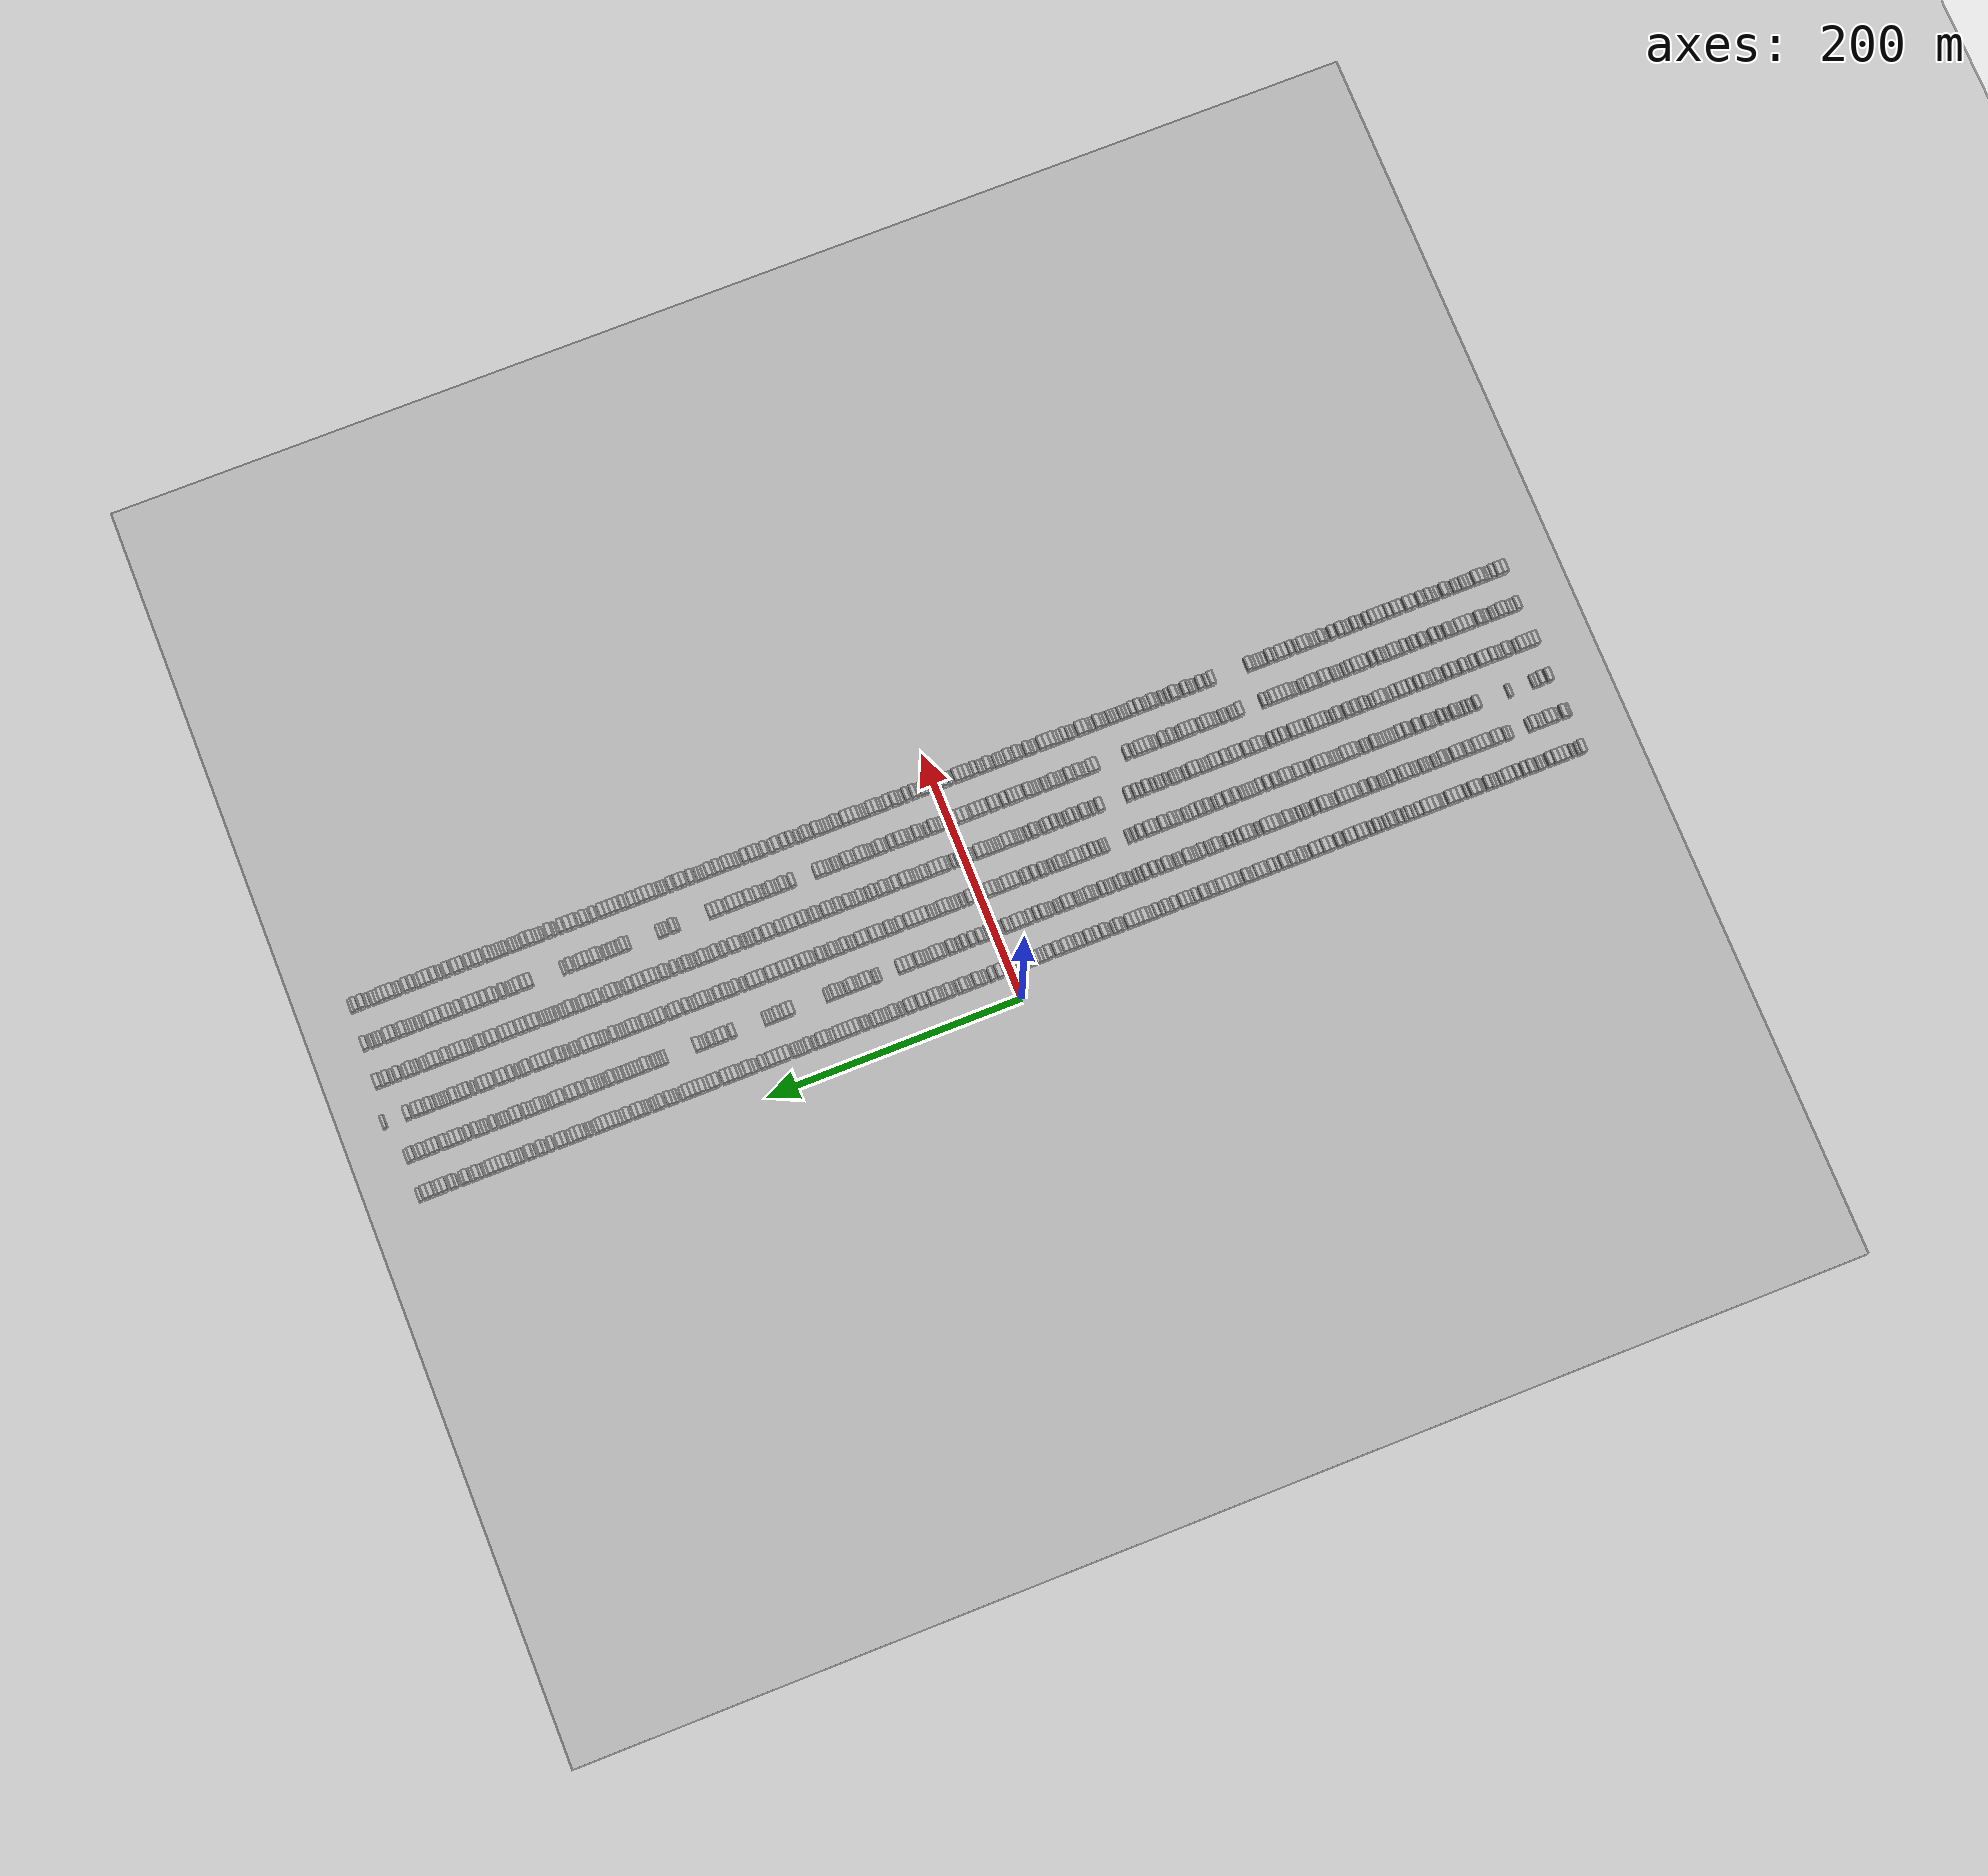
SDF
<?xml version="1.0" encoding="utf-8"?>

<sdf version="1.6">

   <world name="default">

      <gui fullscreen="0">

         <camera name="user_camera">

            <pose>-15 0 4.57585 0 0 0</pose>

            <view_controller>orbit</view_controller>

         </camera>

      </gui>

      <scene>

         <sky>

           <clouds>

             <speed>12</speed>

           </clouds>

         </sky>

         <ambient>0.4 0.4 0.4 1</ambient>

         <background>0.7 0.7 0.7 1</background>

         <shadows>1</shadows>

      </scene>

      <gravity>0 0 -9.8066</gravity>

      <magnetic_field>6e-06 2.3e-05 -4.2e-05</magnetic_field>

      <physics default="0" name="default_physics" type="ode">

         <ode>

            <solver>

               <type>quick</type>

               <iters>10</iters>

               <sor>1.0</sor>

               <use_dynamic_moi_rescaling>0</use_dynamic_moi_rescaling>

            </solver>

            <constraints>

               <cfm>0</cfm>

               <erp>0.2</erp>

               <contact_max_correcting_vel>100</contact_max_correcting_vel>

               <contact_surface_layer>0.001</contact_surface_layer>

            </constraints>

         </ode>

         <max_step_size>0.004</max_step_size>

         <real_time_factor>1</real_time_factor>

         <real_time_update_rate>250</real_time_update_rate>

      </physics>

      <light name="sun" type="directional">

         <cast_shadows>1</cast_shadows>

         <pose>0 0 10 0 0 0</pose>

         <diffuse>0.8 0.8 0.8 1</diffuse>

         <specular>0.2 0.2 0.2 1</specular>

         <attenuation>

            <range>1000</range>

            <constant>0.9</constant>

            <linear>0.01</linear>

            <quadratic>0.001</quadratic>

         </attenuation>

         <direction>-0.5 0.1 -0.9</direction>

      </light>

      <include>

         <name>ground_plane_1</name>

         <uri>model://HANNAS_ground_plane</uri>

         <pose>0 0 0  0 0 0</pose>

      </include>

      <include>

         <name>ground_plane_2</name>

         <uri>model://HANNAS_ground_plane</uri>

         <pose>100 0 0  0 0 0</pose>

      </include>

      <model name="building_1">

         <static>1</static>

         <pose frame="">25.0000 -456.9990 0 0.000000 0.000000 0.000000</pose>

         <link name="link">

            <pose frame="">0 0 4.50 0 0 0</pose>

            <collision name="collision">

               <geometry>

                  <box>

                     <size>10.0000 4.0019 9.0000</size>

                  </box>

               </geometry>

               <max_contacts>10</max_contacts>

               <surface>

                  <contact>

                     <ode/>

                  </contact>

                  <bounce/>

                  <friction>

                     <torsional>

                        <ode/>

                     </torsional>

                     <ode/>

                  </friction>

               </surface>

            </collision>

            <visual name="visual">

               <cast_shadows>0</cast_shadows>

               <geometry>

                  <box>

                     <size>10.0000 4.0019 9.0000</size>

                  </box>

               </geometry>

               <material>

                  <script>

                     <uri>model://HANNAS_wall/materials/scripts</uri>

                     <uri>model://HANNAS_wall/materials/textures</uri>

                     <name>vrc/HANNAS_wall</name>

                  </script>

               </material>

            </visual>

            <self_collide>0</self_collide>

            <enable_wind>0</enable_wind>

            <kinematic>0</kinematic>

         </link>

      </model>

      <model name="building_2">

         <static>1</static>

         <pose frame="">25.0000 -453.7954 0 0.000000 0.000000 0.000000</pose>

         <link name="link">

            <pose frame="">0 0 3.00 0 0 0</pose>

            <collision name="collision">

               <geometry>

                  <box>

                     <size>10.0000 2.4054 6.0000</size>

                  </box>

               </geometry>

               <max_contacts>10</max_contacts>

               <surface>

                  <contact>

                     <ode/>

                  </contact>

                  <bounce/>

                  <friction>

                     <torsional>

                        <ode/>

                     </torsional>

                     <ode/>

                  </friction>

               </surface>

            </collision>

            <visual name="visual">

               <cast_shadows>0</cast_shadows>

               <geometry>

                  <box>

                     <size>10.0000 2.4054 6.0000</size>

                  </box>

               </geometry>

               <material>

                  <script>

                     <uri>model://HANNAS_wall/materials/scripts</uri>

                     <uri>model://HANNAS_wall/materials/textures</uri>

                     <name>vrc/HANNAS_wall</name>

                  </script>

               </material>

            </visual>

            <self_collide>0</self_collide>

            <enable_wind>0</enable_wind>

            <kinematic>0</kinematic>

         </link>

      </model>

      <model name="building_3">

         <static>1</static>

         <pose frame="">25.0000 -449.3826 0 0.000000 0.000000 0.000000</pose>

         <link name="link">

            <pose frame="">0 0 3.00 0 0 0</pose>

            <collision name="collision">

               <geometry>

                  <box>

                     <size>10.0000 2.4202 6.0000</size>

                  </box>

               </geometry>

               <max_contacts>10</max_contacts>

               <surface>

                  <contact>

                     <ode/>

                  </contact>

                  <bounce/>

                  <friction>

                     <torsional>

                        <ode/>

                     </torsional>

                     <ode/>

                  </friction>

               </surface>

            </collision>

            <visual name="visual">

               <cast_shadows>0</cast_shadows>

               <geometry>

                  <box>

                     <size>10.0000 2.4202 6.0000</size>

                  </box>

               </geometry>

               <material>

                  <script>

                     <uri>model://HANNAS_wall/materials/scripts</uri>

                     <uri>model://HANNAS_wall/materials/textures</uri>

                     <name>vrc/HANNAS_wall</name>

                  </script>

               </material>

            </visual>

            <self_collide>0</self_collide>

            <enable_wind>0</enable_wind>

            <kinematic>0</kinematic>

         </link>

      </model>

      <model name="building_4">

         <static>1</static>

         <pose frame="">25.0000 -444.1288 0 0.000000 0.000000 0.000000</pose>

         <link name="link">

            <pose frame="">0 0 4.50 0 0 0</pose>

            <collision name="collision">

               <geometry>

                  <box>

                     <size>10.0000 4.0873 9.0000</size>

                  </box>

               </geometry>

               <max_contacts>10</max_contacts>

               <surface>

                  <contact>

                     <ode/>

                  </contact>

                  <bounce/>

                  <friction>

                     <torsional>

                        <ode/>

                     </torsional>

                     <ode/>

                  </friction>

               </surface>

            </collision>

            <visual name="visual">

               <cast_shadows>0</cast_shadows>

               <geometry>

                  <box>

                     <size>10.0000 4.0873 9.0000</size>

                  </box>

               </geometry>

               <material>

                  <script>

                     <uri>model://HANNAS_wall/materials/scripts</uri>

                     <uri>model://HANNAS_wall/materials/textures</uri>

                     <name>vrc/HANNAS_wall</name>

                  </script>

               </material>

            </visual>

            <self_collide>0</self_collide>

            <enable_wind>0</enable_wind>

            <kinematic>0</kinematic>

         </link>

      </model>

      <model name="building_5">

         <static>1</static>

         <pose frame="">25.0000 -440.1148 0 0.000000 0.000000 0.000000</pose>

         <link name="link">

            <pose frame="">0 0 4.50 0 0 0</pose>

            <collision name="collision">

               <geometry>

                  <box>

                     <size>10.0000 3.9407 9.0000</size>

                  </box>

               </geometry>

               <max_contacts>10</max_contacts>

               <surface>

                  <contact>

                     <ode/>

                  </contact>

                  <bounce/>

                  <friction>

                     <torsional>

                        <ode/>

                     </torsional>

                     <ode/>

                  </friction>

               </surface>

            </collision>

            <visual name="visual">

               <cast_shadows>0</cast_shadows>

               <geometry>

                  <box>

                     <size>10.0000 3.9407 9.0000</size>

                  </box>

               </geometry>

               <material>

                  <script>

                     <uri>model://HANNAS_wall/materials/scripts</uri>

                     <uri>model://HANNAS_wall/materials/textures</uri>

                     <name>vrc/HANNAS_wall</name>

                  </script>

               </material>

            </visual>

            <self_collide>0</self_collide>

            <enable_wind>0</enable_wind>

            <kinematic>0</kinematic>

         </link>

      </model>

      <model name="building_6">

         <static>1</static>

         <pose frame="">25.0000 -436.0656 0 0.000000 0.000000 0.000000</pose>

         <link name="link">

            <pose frame="">0 0 4.50 0 0 0</pose>

            <collision name="collision">

               <geometry>

                  <box>

                     <size>10.0000 4.1576 9.0000</size>

                  </box>

               </geometry>

               <max_contacts>10</max_contacts>

               <surface>

                  <contact>

                     <ode/>

                  </contact>

                  <bounce/>

                  <friction>

                     <torsional>

                        <ode/>

                     </torsional>

                     <ode/>

                  </friction>

               </surface>

            </collision>

            <visual name="visual">

               <cast_shadows>0</cast_shadows>

               <geometry>

                  <box>

                     <size>10.0000 4.1576 9.0000</size>

                  </box>

               </geometry>

               <material>

                  <script>

                     <uri>model://HANNAS_wall/materials/scripts</uri>

                     <uri>model://HANNAS_wall/materials/textures</uri>

                     <name>vrc/HANNAS_wall</name>

                  </script>

               </material>

            </visual>

            <self_collide>0</self_collide>

            <enable_wind>0</enable_wind>

            <kinematic>0</kinematic>

         </link>

      </model>

      <model name="building_7">

         <static>1</static>

         <pose frame="">25.0000 -430.8940 0 0.000000 0.000000 0.000000</pose>

         <link name="link">

            <pose frame="">0 0 4.50 0 0 0</pose>

            <collision name="collision">

               <geometry>

                  <box>

                     <size>10.0000 4.1856 9.0000</size>

                  </box>

               </geometry>

               <max_contacts>10</max_contacts>

               <surface>

                  <contact>

                     <ode/>

                  </contact>

                  <bounce/>

                  <friction>

                     <torsional>

                        <ode/>

                     </torsional>

                     <ode/>

                  </friction>

               </surface>

            </collision>

            <visual name="visual">

               <cast_shadows>0</cast_shadows>

               <geometry>

                  <box>

                     <size>10.0000 4.1856 9.0000</size>

                  </box>

               </geometry>

               <material>

                  <script>

                     <uri>model://HANNAS_wall/materials/scripts</uri>

                     <uri>model://HANNAS_wall/materials/textures</uri>

                     <name>vrc/HANNAS_wall</name>

                  </script>

               </material>

            </visual>

            <self_collide>0</self_collide>

            <enable_wind>0</enable_wind>

            <kinematic>0</kinematic>

         </link>

      </model>

      <model name="building_8">

         <static>1</static>

         <pose frame="">25.0000 -425.3885 0 0.000000 0.000000 0.000000</pose>

         <link name="link">

            <pose frame="">0 0 3.00 0 0 0</pose>

            <collision name="collision">

               <geometry>

                  <box>

                     <size>10.0000 2.8254 6.0000</size>

                  </box>

               </geometry>

               <max_contacts>10</max_contacts>

               <surface>

                  <contact>

                     <ode/>

                  </contact>

                  <bounce/>

                  <friction>

                     <torsional>

                        <ode/>

                     </torsional>

                     <ode/>

                  </friction>

               </surface>

            </collision>

            <visual name="visual">

               <cast_shadows>0</cast_shadows>

               <geometry>

                  <box>

                     <size>10.0000 2.8254 6.0000</size>

                  </box>

               </geometry>

               <material>

                  <script>

                     <uri>model://HANNAS_wall/materials/scripts</uri>

                     <uri>model://HANNAS_wall/materials/textures</uri>

                     <name>vrc/HANNAS_wall</name>

                  </script>

               </material>

            </visual>

            <self_collide>0</self_collide>

            <enable_wind>0</enable_wind>

            <kinematic>0</kinematic>

         </link>

      </model>

      <model name="building_9">

         <static>1</static>

         <pose frame="">25.0000 -422.5784 0 0.000000 0.000000 0.000000</pose>

         <link name="link">

            <pose frame="">0 0 3.00 0 0 0</pose>

            <collision name="collision">

               <geometry>

                  <box>

                     <size>10.0000 2.7948 6.0000</size>

                  </box>

               </geometry>

               <max_contacts>10</max_contacts>

               <surface>

                  <contact>

                     <ode/>

                  </contact>

                  <bounce/>

                  <friction>

                     <torsional>

                        <ode/>

                     </torsional>

                     <ode/>

                  </friction>

               </surface>

            </collision>

            <visual name="visual">

               <cast_shadows>0</cast_shadows>

               <geometry>

                  <box>

                     <size>10.0000 2.7948 6.0000</size>

                  </box>

               </geometry>

               <material>

                  <script>

                     <uri>model://HANNAS_wall/materials/scripts</uri>

                     <uri>model://HANNAS_wall/materials/textures</uri>

                     <name>vrc/HANNAS_wall</name>

                  </script>

               </material>

            </visual>

            <self_collide>0</self_collide>

            <enable_wind>0</enable_wind>

            <kinematic>0</kinematic>

         </link>

      </model>

      <model name="building_10">

         <static>1</static>

         <pose frame="">25.0000 -418.8921 0 0.000000 0.000000 0.000000</pose>

         <link name="link">

            <pose frame="">0 0 3.00 0 0 0</pose>

            <collision name="collision">

               <geometry>

                  <box>

                     <size>10.0000 2.5778 6.0000</size>

                  </box>

               </geometry>

               <max_contacts>10</max_contacts>

               <surface>

                  <contact>

                     <ode/>

                  </contact>

                  <bounce/>

                  <friction>

                     <torsional>

                        <ode/>

                     </torsional>

                     <ode/>

                  </friction>

               </surface>

            </collision>

            <visual name="visual">

               <cast_shadows>0</cast_shadows>

               <geometry>

                  <box>

                     <size>10.0000 2.5778 6.0000</size>

                  </box>

               </geometry>

               <material>

                  <script>

                     <uri>model://HANNAS_wall/materials/scripts</uri>

                     <uri>model://HANNAS_wall/materials/textures</uri>

                     <name>vrc/HANNAS_wall</name>

                  </script>

               </material>

            </visual>

            <self_collide>0</self_collide>

            <enable_wind>0</enable_wind>

            <kinematic>0</kinematic>

         </link>

      </model>

      <model name="building_11">

         <static>1</static>

         <pose frame="">25.0000 -415.6056 0 0.000000 0.000000 0.000000</pose>

         <link name="link">

            <pose frame="">0 0 4.50 0 0 0</pose>

            <collision name="collision">

               <geometry>

                  <box>

                     <size>10.0000 3.9953 9.0000</size>

                  </box>

               </geometry>

               <max_contacts>10</max_contacts>

               <surface>

                  <contact>

                     <ode/>

                  </contact>

                  <bounce/>

                  <friction>

                     <torsional>

                        <ode/>

                     </torsional>

                     <ode/>

                  </friction>

               </surface>

            </collision>

            <visual name="visual">

               <cast_shadows>0</cast_shadows>

               <geometry>

                  <box>

                     <size>10.0000 3.9953 9.0000</size>

                  </box>

               </geometry>

               <material>

                  <script>

                     <uri>model://HANNAS_wall/materials/scripts</uri>

                     <uri>model://HANNAS_wall/materials/textures</uri>

                     <name>vrc/HANNAS_wall</name>

                  </script>

               </material>

            </visual>

            <self_collide>0</self_collide>

            <enable_wind>0</enable_wind>

            <kinematic>0</kinematic>

         </link>

      </model>

      <model name="building_12">

         <static>1</static>

         <pose frame="">25.0000 -410.6604 0 0.000000 0.000000 0.000000</pose>

         <link name="link">

            <pose frame="">0 0 4.50 0 0 0</pose>

            <collision name="collision">

               <geometry>

                  <box>

                     <size>10.0000 3.8949 9.0000</size>

                  </box>

               </geometry>

               <max_contacts>10</max_contacts>

               <surface>

                  <contact>

                     <ode/>

                  </contact>

                  <bounce/>

                  <friction>

                     <torsional>

                        <ode/>

                     </torsional>

                     <ode/>

                  </friction>

               </surface>

            </collision>

            <visual name="visual">

               <cast_shadows>0</cast_shadows>

               <geometry>

                  <box>

                     <size>10.0000 3.8949 9.0000</size>

                  </box>

               </geometry>

               <material>

                  <script>

                     <uri>model://HANNAS_wall/materials/scripts</uri>

                     <uri>model://HANNAS_wall/materials/textures</uri>

                     <name>vrc/HANNAS_wall</name>

                  </script>

               </material>

            </visual>

            <self_collide>0</self_collide>

            <enable_wind>0</enable_wind>

            <kinematic>0</kinematic>

         </link>

      </model>

      <model name="building_13">

         <static>1</static>

         <pose frame="">25.0000 -404.8639 0 0.000000 0.000000 0.000000</pose>

         <link name="link">

            <pose frame="">0 0 4.50 0 0 0</pose>

            <collision name="collision">

               <geometry>

                  <box>

                     <size>10.0000 3.6982 9.0000</size>

                  </box>

               </geometry>

               <max_contacts>10</max_contacts>

               <surface>

                  <contact>

                     <ode/>

                  </contact>

                  <bounce/>

                  <friction>

                     <torsional>

                        <ode/>

                     </torsional>

                     <ode/>

                  </friction>

               </surface>

            </collision>

            <visual name="visual">

               <cast_shadows>0</cast_shadows>

               <geometry>

                  <box>

                     <size>10.0000 3.6982 9.0000</size>

                  </box>

               </geometry>

               <material>

                  <script>

                     <uri>model://HANNAS_wall/materials/scripts</uri>

                     <uri>model://HANNAS_wall/materials/textures</uri>

                     <name>vrc/HANNAS_wall</name>

                  </script>

               </material>

            </visual>

            <self_collide>0</self_collide>

            <enable_wind>0</enable_wind>

            <kinematic>0</kinematic>

         </link>

      </model>

      <model name="building_14">

         <static>1</static>

         <pose frame="">25.0000 -399.9000 0 0.000000 0.000000 0.000000</pose>

         <link name="link">

            <pose frame="">0 0 4.50 0 0 0</pose>

            <collision name="collision">

               <geometry>

                  <box>

                     <size>10.0000 4.2295 9.0000</size>

                  </box>

               </geometry>

               <max_contacts>10</max_contacts>

               <surface>

                  <contact>

                     <ode/>

                  </contact>

                  <bounce/>

                  <friction>

                     <torsional>

                        <ode/>

                     </torsional>

                     <ode/>

                  </friction>

               </surface>

            </collision>

            <visual name="visual">

               <cast_shadows>0</cast_shadows>

               <geometry>

                  <box>

                     <size>10.0000 4.2295 9.0000</size>

                  </box>

               </geometry>

               <material>

                  <script>

                     <uri>model://HANNAS_wall/materials/scripts</uri>

                     <uri>model://HANNAS_wall/materials/textures</uri>

                     <name>vrc/HANNAS_wall</name>

                  </script>

               </material>

            </visual>

            <self_collide>0</self_collide>

            <enable_wind>0</enable_wind>

            <kinematic>0</kinematic>

         </link>

      </model>

      <model name="building_15">

         <static>1</static>

         <pose frame="">25.0000 -395.5426 0 0.000000 0.000000 0.000000</pose>

         <link name="link">

            <pose frame="">0 0 4.50 0 0 0</pose>

            <collision name="collision">

               <geometry>

                  <box>

                     <size>10.0000 4.4853 9.0000</size>

                  </box>

               </geometry>

               <max_contacts>10</max_contacts>

               <surface>

                  <contact>

                     <ode/>

                  </contact>

                  <bounce/>

                  <friction>

                     <torsional>

                        <ode/>

                     </torsional>

                     <ode/>

                  </friction>

               </surface>

            </collision>

            <visual name="visual">

               <cast_shadows>0</cast_shadows>

               <geometry>

                  <box>

                     <size>10.0000 4.4853 9.0000</size>

                  </box>

               </geometry>

               <material>

                  <script>

                     <uri>model://HANNAS_wall/materials/scripts</uri>

                     <uri>model://HANNAS_wall/materials/textures</uri>

                     <name>vrc/HANNAS_wall</name>

                  </script>

               </material>

            </visual>

            <self_collide>0</self_collide>

            <enable_wind>0</enable_wind>

            <kinematic>0</kinematic>

         </link>

      </model>

      <model name="building_16">

         <static>1</static>

         <pose frame="">25.0000 -391.8419 0 0.000000 0.000000 0.000000</pose>

         <link name="link">

            <pose frame="">0 0 3.00 0 0 0</pose>

            <collision name="collision">

               <geometry>

                  <box>

                     <size>10.0000 2.9162 6.0000</size>

                  </box>

               </geometry>

               <max_contacts>10</max_contacts>

               <surface>

                  <contact>

                     <ode/>

                  </contact>

                  <bounce/>

                  <friction>

                     <torsional>

                        <ode/>

                     </torsional>

                     <ode/>

                  </friction>

               </surface>

            </collision>

            <visual name="visual">

               <cast_shadows>0</cast_shadows>

               <geometry>

                  <box>

                     <size>10.0000 2.9162 6.0000</size>

                  </box>

               </geometry>

               <material>

                  <script>

                     <uri>model://HANNAS_wall/materials/scripts</uri>

                     <uri>model://HANNAS_wall/materials/textures</uri>

                     <name>vrc/HANNAS_wall</name>

                  </script>

               </material>

            </visual>

            <self_collide>0</self_collide>

            <enable_wind>0</enable_wind>

            <kinematic>0</kinematic>

         </link>

      </model>

      <model name="building_17">

         <static>1</static>

         <pose frame="">25.0000 -388.0962 0 0.000000 0.000000 0.000000</pose>

         <link name="link">

            <pose frame="">0 0 3.00 0 0 0</pose>

            <collision name="collision">

               <geometry>

                  <box>

                     <size>10.0000 2.5751 6.0000</size>

                  </box>

               </geometry>

               <max_contacts>10</max_contacts>

               <surface>

                  <contact>

                     <ode/>

                  </contact>

                  <bounce/>

                  <friction>

                     <torsional>

                        <ode/>

                     </torsional>

                     <ode/>

                  </friction>

               </surface>

            </collision>

            <visual name="visual">

               <cast_shadows>0</cast_shadows>

               <geometry>

                  <box>

                     <size>10.0000 2.5751 6.0000</size>

                  </box>

               </geometry>

               <material>

                  <script>

                     <uri>model://HANNAS_wall/materials/scripts</uri>

                     <uri>model://HANNAS_wall/materials/textures</uri>

                     <name>vrc/HANNAS_wall</name>

                  </script>

               </material>

            </visual>

            <self_collide>0</self_collide>

            <enable_wind>0</enable_wind>

            <kinematic>0</kinematic>

         </link>

      </model>

      <model name="building_18">

         <static>1</static>

         <pose frame="">25.0000 -385.5317 0 0.000000 0.000000 0.000000</pose>

         <link name="link">

            <pose frame="">0 0 3.00 0 0 0</pose>

            <collision name="collision">

               <geometry>

                  <box>

                     <size>10.0000 2.5539 6.0000</size>

                  </box>

               </geometry>

               <max_contacts>10</max_contacts>

               <surface>

                  <contact>

                     <ode/>

                  </contact>

                  <bounce/>

                  <friction>

                     <torsional>

                        <ode/>

                     </torsional>

                     <ode/>

                  </friction>

               </surface>

            </collision>

            <visual name="visual">

               <cast_shadows>0</cast_shadows>

               <geometry>

                  <box>

                     <size>10.0000 2.5539 6.0000</size>

                  </box>

               </geometry>

               <material>

                  <script>

                     <uri>model://HANNAS_wall/materials/scripts</uri>

                     <uri>model://HANNAS_wall/materials/textures</uri>

                     <name>vrc/HANNAS_wall</name>

                  </script>

               </material>

            </visual>

            <self_collide>0</self_collide>

            <enable_wind>0</enable_wind>

            <kinematic>0</kinematic>

         </link>

      </model>

      <model name="building_19">

         <static>1</static>

         <pose frame="">25.0000 -381.2378 0 0.000000 0.000000 0.000000</pose>

         <link name="link">

            <pose frame="">0 0 4.50 0 0 0</pose>

            <collision name="collision">

               <geometry>

                  <box>

                     <size>10.0000 4.0340 9.0000</size>

                  </box>

               </geometry>

               <max_contacts>10</max_contacts>

               <surface>

                  <contact>

                     <ode/>

                  </contact>

                  <bounce/>

                  <friction>

                     <torsional>

                        <ode/>

                     </torsional>

                     <ode/>

                  </friction>

               </surface>

            </collision>

            <visual name="visual">

               <cast_shadows>0</cast_shadows>

               <geometry>

                  <box>

                     <size>10.0000 4.0340 9.0000</size>

                  </box>

               </geometry>

               <material>

                  <script>

                     <uri>model://HANNAS_wall/materials/scripts</uri>

                     <uri>model://HANNAS_wall/materials/textures</uri>

                     <name>vrc/HANNAS_wall</name>

                  </script>

               </material>

            </visual>

            <self_collide>0</self_collide>

            <enable_wind>0</enable_wind>

            <kinematic>0</kinematic>

         </link>

      </model>

      <model name="building_20">

         <static>1</static>

         <pose frame="">25.0000 -376.0046 0 0.000000 0.000000 0.000000</pose>

         <link name="link">

            <pose frame="">0 0 3.00 0 0 0</pose>

            <collision name="collision">

               <geometry>

                  <box>

                     <size>10.0000 2.4324 6.0000</size>

                  </box>

               </geometry>

               <max_contacts>10</max_contacts>

               <surface>

                  <contact>

                     <ode/>

                  </contact>

                  <bounce/>

                  <friction>

                     <torsional>

                        <ode/>

                     </torsional>

                     <ode/>

                  </friction>

               </surface>

            </collision>

            <visual name="visual">

               <cast_shadows>0</cast_shadows>

               <geometry>

                  <box>

                     <size>10.0000 2.4324 6.0000</size>

                  </box>

               </geometry>

               <material>

                  <script>

                     <uri>model://HANNAS_wall/materials/scripts</uri>

                     <uri>model://HANNAS_wall/materials/textures</uri>

                     <name>vrc/HANNAS_wall</name>

                  </script>

               </material>

            </visual>

            <self_collide>0</self_collide>

            <enable_wind>0</enable_wind>

            <kinematic>0</kinematic>

         </link>

      </model>

      <model name="building_21">

         <static>1</static>

         <pose frame="">25.0000 -372.8886 0 0.000000 0.000000 0.000000</pose>

         <link name="link">

            <pose frame="">0 0 4.50 0 0 0</pose>

            <collision name="collision">

               <geometry>

                  <box>

                     <size>10.0000 3.7996 9.0000</size>

                  </box>

               </geometry>

               <max_contacts>10</max_contacts>

               <surface>

                  <contact>

                     <ode/>

                  </contact>

                  <bounce/>

                  <friction>

                     <torsional>

                        <ode/>

                     </torsional>

                     <ode/>

                  </friction>

               </surface>

            </collision>

            <visual name="visual">

               <cast_shadows>0</cast_shadows>

               <geometry>

                  <box>

                     <size>10.0000 3.7996 9.0000</size>

                  </box>

               </geometry>

               <material>

                  <script>

                     <uri>model://HANNAS_wall/materials/scripts</uri>

                     <uri>model://HANNAS_wall/materials/textures</uri>

                     <name>vrc/HANNAS_wall</name>

                  </script>

               </material>

            </visual>

            <self_collide>0</self_collide>

            <enable_wind>0</enable_wind>

            <kinematic>0</kinematic>

         </link>

      </model>

      <model name="building_22">

         <static>1</static>

         <pose frame="">25.0000 -368.8407 0 0.000000 0.000000 0.000000</pose>

         <link name="link">

            <pose frame="">0 0 4.50 0 0 0</pose>

            <collision name="collision">

               <geometry>

                  <box>

                     <size>10.0000 4.2962 9.0000</size>

                  </box>

               </geometry>

               <max_contacts>10</max_contacts>

               <surface>

                  <contact>

                     <ode/>

                  </contact>

                  <bounce/>

                  <friction>

                     <torsional>

                        <ode/>

                     </torsional>

                     <ode/>

                  </friction>

               </surface>

            </collision>

            <visual name="visual">

               <cast_shadows>0</cast_shadows>

               <geometry>

                  <box>

                     <size>10.0000 4.2962 9.0000</size>

                  </box>

               </geometry>

               <material>

                  <script>

                     <uri>model://HANNAS_wall/materials/scripts</uri>

                     <uri>model://HANNAS_wall/materials/textures</uri>

                     <name>vrc/HANNAS_wall</name>

                  </script>

               </material>

            </visual>

            <self_collide>0</self_collide>

            <enable_wind>0</enable_wind>

            <kinematic>0</kinematic>

         </link>

      </model>

      <model name="building_23">

         <static>1</static>

         <pose frame="">25.0000 -364.3743 0 0.000000 0.000000 0.000000</pose>

         <link name="link">

            <pose frame="">0 0 3.00 0 0 0</pose>

            <collision name="collision">

               <geometry>

                  <box>

                     <size>10.0000 2.6366 6.0000</size>

                  </box>

               </geometry>

               <max_contacts>10</max_contacts>

               <surface>

                  <contact>

                     <ode/>

                  </contact>

                  <bounce/>

                  <friction>

                     <torsional>

                        <ode/>

                     </torsional>

                     <ode/>

                  </friction>

               </surface>

            </collision>

            <visual name="visual">

               <cast_shadows>0</cast_shadows>

               <geometry>

                  <box>

                     <size>10.0000 2.6366 6.0000</size>

                  </box>

               </geometry>

               <material>

                  <script>

                     <uri>model://HANNAS_wall/materials/scripts</uri>

                     <uri>model://HANNAS_wall/materials/textures</uri>

                     <name>vrc/HANNAS_wall</name>

                  </script>

               </material>

            </visual>

            <self_collide>0</self_collide>

            <enable_wind>0</enable_wind>

            <kinematic>0</kinematic>

         </link>

      </model>

      <model name="building_24">

         <static>1</static>

         <pose frame="">25.0000 -358.8417 0 0.000000 0.000000 0.000000</pose>

         <link name="link">

            <pose frame="">0 0 4.50 0 0 0</pose>

            <collision name="collision">

               <geometry>

                  <box>

                     <size>10.0000 4.4285 9.0000</size>

                  </box>

               </geometry>

               <max_contacts>10</max_contacts>

               <surface>

                  <contact>

                     <ode/>

                  </contact>

                  <bounce/>

                  <friction>

                     <torsional>

                        <ode/>

                     </torsional>

                     <ode/>

                  </friction>

               </surface>

            </collision>

            <visual name="visual">

               <cast_shadows>0</cast_shadows>

               <geometry>

                  <box>

                     <size>10.0000 4.4285 9.0000</size>

                  </box>

               </geometry>

               <material>

                  <script>

                     <uri>model://HANNAS_wall/materials/scripts</uri>

                     <uri>model://HANNAS_wall/materials/textures</uri>

                     <name>vrc/HANNAS_wall</name>

                  </script>

               </material>

            </visual>

            <self_collide>0</self_collide>

            <enable_wind>0</enable_wind>

            <kinematic>0</kinematic>

         </link>

      </model>

      <model name="building_25">

         <static>1</static>

         <pose frame="">25.0000 -354.4156 0 0.000000 0.000000 0.000000</pose>

         <link name="link">

            <pose frame="">0 0 4.50 0 0 0</pose>

            <collision name="collision">

               <geometry>

                  <box>

                     <size>10.0000 4.4237 9.0000</size>

                  </box>

               </geometry>

               <max_contacts>10</max_contacts>

               <surface>

                  <contact>

                     <ode/>

                  </contact>

                  <bounce/>

                  <friction>

                     <torsional>

                        <ode/>

                     </torsional>

                     <ode/>

                  </friction>

               </surface>

            </collision>

            <visual name="visual">

               <cast_shadows>0</cast_shadows>

               <geometry>

                  <box>

                     <size>10.0000 4.4237 9.0000</size>

                  </box>

               </geometry>

               <material>

                  <script>

                     <uri>model://HANNAS_wall/materials/scripts</uri>

                     <uri>model://HANNAS_wall/materials/textures</uri>

                     <name>vrc/HANNAS_wall</name>

                  </script>

               </material>

            </visual>

            <self_collide>0</self_collide>

            <enable_wind>0</enable_wind>

            <kinematic>0</kinematic>

         </link>

      </model>

      <model name="building_26">

         <static>1</static>

         <pose frame="">25.0000 -350.1672 0 0.000000 0.000000 0.000000</pose>

         <link name="link">

            <pose frame="">0 0 4.50 0 0 0</pose>

            <collision name="collision">

               <geometry>

                  <box>

                     <size>10.0000 4.0731 9.0000</size>

                  </box>

               </geometry>

               <max_contacts>10</max_contacts>

               <surface>

                  <contact>

                     <ode/>

                  </contact>

                  <bounce/>

                  <friction>

                     <torsional>

                        <ode/>

                     </torsional>

                     <ode/>

                  </friction>

               </surface>

            </collision>

            <visual name="visual">

               <cast_shadows>0</cast_shadows>

               <geometry>

                  <box>

                     <size>10.0000 4.0731 9.0000</size>

                  </box>

               </geometry>

               <material>

                  <script>

                     <uri>model://HANNAS_wall/materials/scripts</uri>

                     <uri>model://HANNAS_wall/materials/textures</uri>

                     <name>vrc/HANNAS_wall</name>

                  </script>

               </material>

            </visual>

            <self_collide>0</self_collide>

            <enable_wind>0</enable_wind>

            <kinematic>0</kinematic>

         </link>

      </model>

      <model name="building_27">

         <static>1</static>

         <pose frame="">25.0000 -345.6370 0 0.000000 0.000000 0.000000</pose>

         <link name="link">

            <pose frame="">0 0 3.00 0 0 0</pose>

            <collision name="collision">

               <geometry>

                  <box>

                     <size>10.0000 2.9873 6.0000</size>

                  </box>

               </geometry>

               <max_contacts>10</max_contacts>

               <surface>

                  <contact>

                     <ode/>

                  </contact>

                  <bounce/>

                  <friction>

                     <torsional>

                        <ode/>

                     </torsional>

                     <ode/>

                  </friction>

               </surface>

            </collision>

            <visual name="visual">

               <cast_shadows>0</cast_shadows>

               <geometry>

                  <box>

                     <size>10.0000 2.9873 6.0000</size>

                  </box>

               </geometry>

               <material>

                  <script>

                     <uri>model://HANNAS_wall/materials/scripts</uri>

                     <uri>model://HANNAS_wall/materials/textures</uri>

                     <name>vrc/HANNAS_wall</name>

                  </script>

               </material>

            </visual>

            <self_collide>0</self_collide>

            <enable_wind>0</enable_wind>

            <kinematic>0</kinematic>

         </link>

      </model>

      <model name="building_28">

         <static>1</static>

         <pose frame="">25.0000 -342.8922 0 0.000000 0.000000 0.000000</pose>

         <link name="link">

            <pose frame="">0 0 3.00 0 0 0</pose>

            <collision name="collision">

               <geometry>

                  <box>

                     <size>10.0000 2.5023 6.0000</size>

                  </box>

               </geometry>

               <max_contacts>10</max_contacts>

               <surface>

                  <contact>

                     <ode/>

                  </contact>

                  <bounce/>

                  <friction>

                     <torsional>

                        <ode/>

                     </torsional>

                     <ode/>

                  </friction>

               </surface>

            </collision>

            <visual name="visual">

               <cast_shadows>0</cast_shadows>

               <geometry>

                  <box>

                     <size>10.0000 2.5023 6.0000</size>

                  </box>

               </geometry>

               <material>

                  <script>

                     <uri>model://HANNAS_wall/materials/scripts</uri>

                     <uri>model://HANNAS_wall/materials/textures</uri>

                     <name>vrc/HANNAS_wall</name>

                  </script>

               </material>

            </visual>

            <self_collide>0</self_collide>

            <enable_wind>0</enable_wind>

            <kinematic>0</kinematic>

         </link>

      </model>

      <model name="building_29">

         <static>1</static>

         <pose frame="">25.0000 -339.5254 0 0.000000 0.000000 0.000000</pose>

         <link name="link">

            <pose frame="">0 0 4.50 0 0 0</pose>

            <collision name="collision">

               <geometry>

                  <box>

                     <size>10.0000 4.2313 9.0000</size>

                  </box>

               </geometry>

               <max_contacts>10</max_contacts>

               <surface>

                  <contact>

                     <ode/>

                  </contact>

                  <bounce/>

                  <friction>

                     <torsional>

                        <ode/>

                     </torsional>

                     <ode/>

                  </friction>

               </surface>

            </collision>

            <visual name="visual">

               <cast_shadows>0</cast_shadows>

               <geometry>

                  <box>

                     <size>10.0000 4.2313 9.0000</size>

                  </box>

               </geometry>

               <material>

                  <script>

                     <uri>model://HANNAS_wall/materials/scripts</uri>

                     <uri>model://HANNAS_wall/materials/textures</uri>

                     <name>vrc/HANNAS_wall</name>

                  </script>

               </material>

            </visual>

            <self_collide>0</self_collide>

            <enable_wind>0</enable_wind>

            <kinematic>0</kinematic>

         </link>

      </model>

      <model name="building_30">

         <static>1</static>

         <pose frame="">25.0000 -335.1848 0 0.000000 0.000000 0.000000</pose>

         <link name="link">

            <pose frame="">0 0 4.50 0 0 0</pose>

            <collision name="collision">

               <geometry>

                  <box>

                     <size>10.0000 4.4499 9.0000</size>

                  </box>

               </geometry>

               <max_contacts>10</max_contacts>

               <surface>

                  <contact>

                     <ode/>

                  </contact>

                  <bounce/>

                  <friction>

                     <torsional>

                        <ode/>

                     </torsional>

                     <ode/>

                  </friction>

               </surface>

            </collision>

            <visual name="visual">

               <cast_shadows>0</cast_shadows>

               <geometry>

                  <box>

                     <size>10.0000 4.4499 9.0000</size>

                  </box>

               </geometry>

               <material>

                  <script>

                     <uri>model://HANNAS_wall/materials/scripts</uri>

                     <uri>model://HANNAS_wall/materials/textures</uri>

                     <name>vrc/HANNAS_wall</name>

                  </script>

               </material>

            </visual>

            <self_collide>0</self_collide>

            <enable_wind>0</enable_wind>

            <kinematic>0</kinematic>

         </link>

      </model>

      <model name="building_31">

         <static>1</static>

         <pose frame="">25.0000 -330.7822 0 0.000000 0.000000 0.000000</pose>

         <link name="link">

            <pose frame="">0 0 4.50 0 0 0</pose>

            <collision name="collision">

               <geometry>

                  <box>

                     <size>10.0000 4.3552 9.0000</size>

                  </box>

               </geometry>

               <max_contacts>10</max_contacts>

               <surface>

                  <contact>

                     <ode/>

                  </contact>

                  <bounce/>

                  <friction>

                     <torsional>

                        <ode/>

                     </torsional>

                     <ode/>

                  </friction>

               </surface>

            </collision>

            <visual name="visual">

               <cast_shadows>0</cast_shadows>

               <geometry>

                  <box>

                     <size>10.0000 4.3552 9.0000</size>

                  </box>

               </geometry>

               <material>

                  <script>

                     <uri>model://HANNAS_wall/materials/scripts</uri>

                     <uri>model://HANNAS_wall/materials/textures</uri>

                     <name>vrc/HANNAS_wall</name>

                  </script>

               </material>

            </visual>

            <self_collide>0</self_collide>

            <enable_wind>0</enable_wind>

            <kinematic>0</kinematic>

         </link>

      </model>

      <model name="building_32">

         <static>1</static>

         <pose frame="">25.0000 -325.5304 0 0.000000 0.000000 0.000000</pose>

         <link name="link">

            <pose frame="">0 0 4.50 0 0 0</pose>

            <collision name="collision">

               <geometry>

                  <box>

                     <size>10.0000 4.1485 9.0000</size>

                  </box>

               </geometry>

               <max_contacts>10</max_contacts>

               <surface>

                  <contact>

                     <ode/>

                  </contact>

                  <bounce/>

                  <friction>

                     <torsional>

                        <ode/>

                     </torsional>

                     <ode/>

                  </friction>

               </surface>

            </collision>

            <visual name="visual">

               <cast_shadows>0</cast_shadows>

               <geometry>

                  <box>

                     <size>10.0000 4.1485 9.0000</size>

                  </box>

               </geometry>

               <material>

                  <script>

                     <uri>model://HANNAS_wall/materials/scripts</uri>

                     <uri>model://HANNAS_wall/materials/textures</uri>

                     <name>vrc/HANNAS_wall</name>

                  </script>

               </material>

            </visual>

            <self_collide>0</self_collide>

            <enable_wind>0</enable_wind>

            <kinematic>0</kinematic>

         </link>

      </model>

      <model name="building_33">

         <static>1</static>

         <pose frame="">25.0000 -322.0741 0 0.000000 0.000000 0.000000</pose>

         <link name="link">

            <pose frame="">0 0 3.00 0 0 0</pose>

            <collision name="collision">

               <geometry>

                  <box>

                     <size>10.0000 2.7642 6.0000</size>

                  </box>

               </geometry>

               <max_contacts>10</max_contacts>

               <surface>

                  <contact>

                     <ode/>

                  </contact>

                  <bounce/>

                  <friction>

                     <torsional>

                        <ode/>

                     </torsional>

                     <ode/>

                  </friction>

               </surface>

            </collision>

            <visual name="visual">

               <cast_shadows>0</cast_shadows>

               <geometry>

                  <box>

                     <size>10.0000 2.7642 6.0000</size>

                  </box>

               </geometry>

               <material>

                  <script>

                     <uri>model://HANNAS_wall/materials/scripts</uri>

                     <uri>model://HANNAS_wall/materials/textures</uri>

                     <name>vrc/HANNAS_wall</name>

                  </script>

               </material>

            </visual>

            <self_collide>0</self_collide>

            <enable_wind>0</enable_wind>

            <kinematic>0</kinematic>

         </link>

      </model>

      <model name="building_34">

         <static>1</static>

         <pose frame="">25.0000 -317.8304 0 0.000000 0.000000 0.000000</pose>

         <link name="link">

            <pose frame="">0 0 4.50 0 0 0</pose>

            <collision name="collision">

               <geometry>

                  <box>

                     <size>10.0000 3.7233 9.0000</size>

                  </box>

               </geometry>

               <max_contacts>10</max_contacts>

               <surface>

                  <contact>

                     <ode/>

                  </contact>

                  <bounce/>

                  <friction>

                     <torsional>

                        <ode/>

                     </torsional>

                     <ode/>

                  </friction>

               </surface>

            </collision>

            <visual name="visual">

               <cast_shadows>0</cast_shadows>

               <geometry>

                  <box>

                     <size>10.0000 3.7233 9.0000</size>

                  </box>

               </geometry>

               <material>

                  <script>

                     <uri>model://HANNAS_wall/materials/scripts</uri>

                     <uri>model://HANNAS_wall/materials/textures</uri>

                     <name>vrc/HANNAS_wall</name>

                  </script>

               </material>

            </visual>

            <self_collide>0</self_collide>

            <enable_wind>0</enable_wind>

            <kinematic>0</kinematic>

         </link>

      </model>

      <model name="building_35">

         <static>1</static>

         <pose frame="">25.0000 -314.7395 0 0.000000 0.000000 0.000000</pose>

         <link name="link">

            <pose frame="">0 0 3.00 0 0 0</pose>

            <collision name="collision">

               <geometry>

                  <box>

                     <size>10.0000 2.4584 6.0000</size>

                  </box>

               </geometry>

               <max_contacts>10</max_contacts>

               <surface>

                  <contact>

                     <ode/>

                  </contact>

                  <bounce/>

                  <friction>

                     <torsional>

                        <ode/>

                     </torsional>

                     <ode/>

                  </friction>

               </surface>

            </collision>

            <visual name="visual">

               <cast_shadows>0</cast_shadows>

               <geometry>

                  <box>

                     <size>10.0000 2.4584 6.0000</size>

                  </box>

               </geometry>

               <material>

                  <script>

                     <uri>model://HANNAS_wall/materials/scripts</uri>

                     <uri>model://HANNAS_wall/materials/textures</uri>

                     <name>vrc/HANNAS_wall</name>

                  </script>

               </material>

            </visual>

            <self_collide>0</self_collide>

            <enable_wind>0</enable_wind>

            <kinematic>0</kinematic>

         </link>

      </model>

      <model name="building_36">

         <static>1</static>

         <pose frame="">25.0000 -309.7079 0 0.000000 0.000000 0.000000</pose>

         <link name="link">

            <pose frame="">0 0 4.50 0 0 0</pose>

            <collision name="collision">

               <geometry>

                  <box>

                     <size>10.0000 3.6049 9.0000</size>

                  </box>

               </geometry>

               <max_contacts>10</max_contacts>

               <surface>

                  <contact>

                     <ode/>

                  </contact>

                  <bounce/>

                  <friction>

                     <torsional>

                        <ode/>

                     </torsional>

                     <ode/>

                  </friction>

               </surface>

            </collision>

            <visual name="visual">

               <cast_shadows>0</cast_shadows>

               <geometry>

                  <box>

                     <size>10.0000 3.6049 9.0000</size>

                  </box>

               </geometry>

               <material>

                  <script>

                     <uri>model://HANNAS_wall/materials/scripts</uri>

                     <uri>model://HANNAS_wall/materials/textures</uri>

                     <name>vrc/HANNAS_wall</name>

                  </script>

               </material>

            </visual>

            <self_collide>0</self_collide>

            <enable_wind>0</enable_wind>

            <kinematic>0</kinematic>

         </link>

      </model>

      <model name="building_37">

         <static>1</static>

         <pose frame="">25.0000 -306.5550 0 0.000000 0.000000 0.000000</pose>

         <link name="link">

            <pose frame="">0 0 3.00 0 0 0</pose>

            <collision name="collision">

               <geometry>

                  <box>

                     <size>10.0000 2.7009 6.0000</size>

                  </box>

               </geometry>

               <max_contacts>10</max_contacts>

               <surface>

                  <contact>

                     <ode/>

                  </contact>

                  <bounce/>

                  <friction>

                     <torsional>

                        <ode/>

                     </torsional>

                     <ode/>

                  </friction>

               </surface>

            </collision>

            <visual name="visual">

               <cast_shadows>0</cast_shadows>

               <geometry>

                  <box>

                     <size>10.0000 2.7009 6.0000</size>

                  </box>

               </geometry>

               <material>

                  <script>

                     <uri>model://HANNAS_wall/materials/scripts</uri>

                     <uri>model://HANNAS_wall/materials/textures</uri>

                     <name>vrc/HANNAS_wall</name>

                  </script>

               </material>

            </visual>

            <self_collide>0</self_collide>

            <enable_wind>0</enable_wind>

            <kinematic>0</kinematic>

         </link>

      </model>

      <model name="building_38">

         <static>1</static>

         <pose frame="">25.0000 -303.2558 0 0.000000 0.000000 0.000000</pose>

         <link name="link">

            <pose frame="">0 0 4.50 0 0 0</pose>

            <collision name="collision">

               <geometry>

                  <box>

                     <size>10.0000 3.8974 9.0000</size>

                  </box>

               </geometry>

               <max_contacts>10</max_contacts>

               <surface>

                  <contact>

                     <ode/>

                  </contact>

                  <bounce/>

                  <friction>

                     <torsional>

                        <ode/>

                     </torsional>

                     <ode/>

                  </friction>

               </surface>

            </collision>

            <visual name="visual">

               <cast_shadows>0</cast_shadows>

               <geometry>

                  <box>

                     <size>10.0000 3.8974 9.0000</size>

                  </box>

               </geometry>

               <material>

                  <script>

                     <uri>model://HANNAS_wall/materials/scripts</uri>

                     <uri>model://HANNAS_wall/materials/textures</uri>

                     <name>vrc/HANNAS_wall</name>

                  </script>

               </material>

            </visual>

            <self_collide>0</self_collide>

            <enable_wind>0</enable_wind>

            <kinematic>0</kinematic>

         </link>

      </model>

      <model name="building_39">

         <static>1</static>

         <pose frame="">25.0000 -299.8874 0 0.000000 0.000000 0.000000</pose>

         <link name="link">

            <pose frame="">0 0 3.00 0 0 0</pose>

            <collision name="collision">

               <geometry>

                  <box>

                     <size>10.0000 2.8394 6.0000</size>

                  </box>

               </geometry>

               <max_contacts>10</max_contacts>

               <surface>

                  <contact>

                     <ode/>

                  </contact>

                  <bounce/>

                  <friction>

                     <torsional>

                        <ode/>

                     </torsional>

                     <ode/>

                  </friction>

               </surface>

            </collision>

            <visual name="visual">

               <cast_shadows>0</cast_shadows>

               <geometry>

                  <box>

                     <size>10.0000 2.8394 6.0000</size>

                  </box>

               </geometry>

               <material>

                  <script>

                     <uri>model://HANNAS_wall/materials/scripts</uri>

                     <uri>model://HANNAS_wall/materials/textures</uri>

                     <name>vrc/HANNAS_wall</name>

                  </script>

               </material>

            </visual>

            <self_collide>0</self_collide>

            <enable_wind>0</enable_wind>

            <kinematic>0</kinematic>

         </link>

      </model>

      <model name="building_40">

         <static>1</static>

         <pose frame="">25.0000 -296.1445 0 0.000000 0.000000 0.000000</pose>

         <link name="link">

            <pose frame="">0 0 3.00 0 0 0</pose>

            <collision name="collision">

               <geometry>

                  <box>

                     <size>10.0000 2.6464 6.0000</size>

                  </box>

               </geometry>

               <max_contacts>10</max_contacts>

               <surface>

                  <contact>

                     <ode/>

                  </contact>

                  <bounce/>

                  <friction>

                     <torsional>

                        <ode/>

                     </torsional>

                     <ode/>

                  </friction>

               </surface>

            </collision>

            <visual name="visual">

               <cast_shadows>0</cast_shadows>

               <geometry>

                  <box>

                     <size>10.0000 2.6464 6.0000</size>

                  </box>

               </geometry>

               <material>

                  <script>

                     <uri>model://HANNAS_wall/materials/scripts</uri>

                     <uri>model://HANNAS_wall/materials/textures</uri>

                     <name>vrc/HANNAS_wall</name>

                  </script>

               </material>

            </visual>

            <self_collide>0</self_collide>

            <enable_wind>0</enable_wind>

            <kinematic>0</kinematic>

         </link>

      </model>

      <model name="building_41">

         <static>1</static>

         <pose frame="">25.0000 -291.9505 0 0.000000 0.000000 0.000000</pose>

         <link name="link">

            <pose frame="">0 0 4.50 0 0 0</pose>

            <collision name="collision">

               <geometry>

                  <box>

                     <size>10.0000 3.7415 9.0000</size>

                  </box>

               </geometry>

               <max_contacts>10</max_contacts>

               <surface>

                  <contact>

                     <ode/>

                  </contact>

                  <bounce/>

                  <friction>

                     <torsional>

                        <ode/>

                     </torsional>

                     <ode/>

                  </friction>

               </surface>

            </collision>

            <visual name="visual">

               <cast_shadows>0</cast_shadows>

               <geometry>

                  <box>

                     <size>10.0000 3.7415 9.0000</size>

                  </box>

               </geometry>

               <material>

                  <script>

                     <uri>model://HANNAS_wall/materials/scripts</uri>

                     <uri>model://HANNAS_wall/materials/textures</uri>

                     <name>vrc/HANNAS_wall</name>

                  </script>

               </material>

            </visual>

            <self_collide>0</self_collide>

            <enable_wind>0</enable_wind>

            <kinematic>0</kinematic>

         </link>

      </model>

      <model name="building_42">

         <static>1</static>

         <pose frame="">25.0000 -287.5879 0 0.000000 0.000000 0.000000</pose>

         <link name="link">

            <pose frame="">0 0 3.00 0 0 0</pose>

            <collision name="collision">

               <geometry>

                  <box>

                     <size>10.0000 2.9837 6.0000</size>

                  </box>

               </geometry>

               <max_contacts>10</max_contacts>

               <surface>

                  <contact>

                     <ode/>

                  </contact>

                  <bounce/>

                  <friction>

                     <torsional>

                        <ode/>

                     </torsional>

                     <ode/>

                  </friction>

               </surface>

            </collision>

            <visual name="visual">

               <cast_shadows>0</cast_shadows>

               <geometry>

                  <box>

                     <size>10.0000 2.9837 6.0000</size>

                  </box>

               </geometry>

               <material>

                  <script>

                     <uri>model://HANNAS_wall/materials/scripts</uri>

                     <uri>model://HANNAS_wall/materials/textures</uri>

                     <name>vrc/HANNAS_wall</name>

                  </script>

               </material>

            </visual>

            <self_collide>0</self_collide>

            <enable_wind>0</enable_wind>

            <kinematic>0</kinematic>

         </link>

      </model>

      <model name="building_43">

         <static>1</static>

         <pose frame="">25.0000 -282.1038 0 0.000000 0.000000 0.000000</pose>

         <link name="link">

            <pose frame="">0 0 4.50 0 0 0</pose>

            <collision name="collision">

               <geometry>

                  <box>

                     <size>10.0000 3.9846 9.0000</size>

                  </box>

               </geometry>

               <max_contacts>10</max_contacts>

               <surface>

                  <contact>

                     <ode/>

                  </contact>

                  <bounce/>

                  <friction>

                     <torsional>

                        <ode/>

                     </torsional>

                     <ode/>

                  </friction>

               </surface>

            </collision>

            <visual name="visual">

               <cast_shadows>0</cast_shadows>

               <geometry>

                  <box>

                     <size>10.0000 3.9846 9.0000</size>

                  </box>

               </geometry>

               <material>

                  <script>

                     <uri>model://HANNAS_wall/materials/scripts</uri>

                     <uri>model://HANNAS_wall/materials/textures</uri>

                     <name>vrc/HANNAS_wall</name>

                  </script>

               </material>

            </visual>

            <self_collide>0</self_collide>

            <enable_wind>0</enable_wind>

            <kinematic>0</kinematic>

         </link>

      </model>

      <model name="building_44">

         <static>1</static>

         <pose frame="">25.0000 -277.9090 0 0.000000 0.000000 0.000000</pose>

         <link name="link">

            <pose frame="">0 0 4.50 0 0 0</pose>

            <collision name="collision">

               <geometry>

                  <box>

                     <size>10.0000 4.4050 9.0000</size>

                  </box>

               </geometry>

               <max_contacts>10</max_contacts>

               <surface>

                  <contact>

                     <ode/>

                  </contact>

                  <bounce/>

                  <friction>

                     <torsional>

                        <ode/>

                     </torsional>

                     <ode/>

                  </friction>

               </surface>

            </collision>

            <visual name="visual">

               <cast_shadows>0</cast_shadows>

               <geometry>

                  <box>

                     <size>10.0000 4.4050 9.0000</size>

                  </box>

               </geometry>

               <material>

                  <script>

                     <uri>model://HANNAS_wall/materials/scripts</uri>

                     <uri>model://HANNAS_wall/materials/textures</uri>

                     <name>vrc/HANNAS_wall</name>

                  </script>

               </material>

            </visual>

            <self_collide>0</self_collide>

            <enable_wind>0</enable_wind>

            <kinematic>0</kinematic>

         </link>

      </model>

      <model name="building_45">

         <static>1</static>

         <pose frame="">25.0000 -272.4863 0 0.000000 0.000000 0.000000</pose>

         <link name="link">

            <pose frame="">0 0 4.50 0 0 0</pose>

            <collision name="collision">

               <geometry>

                  <box>

                     <size>10.0000 4.4404 9.0000</size>

                  </box>

               </geometry>

               <max_contacts>10</max_contacts>

               <surface>

                  <contact>

                     <ode/>

                  </contact>

                  <bounce/>

                  <friction>

                     <torsional>

                        <ode/>

                     </torsional>

                     <ode/>

                  </friction>

               </surface>

            </collision>

            <visual name="visual">

               <cast_shadows>0</cast_shadows>

               <geometry>

                  <box>

                     <size>10.0000 4.4404 9.0000</size>

                  </box>

               </geometry>

               <material>

                  <script>

                     <uri>model://HANNAS_wall/materials/scripts</uri>

                     <uri>model://HANNAS_wall/materials/textures</uri>

                     <name>vrc/HANNAS_wall</name>

                  </script>

               </material>

            </visual>

            <self_collide>0</self_collide>

            <enable_wind>0</enable_wind>

            <kinematic>0</kinematic>

         </link>

      </model>

      <model name="building_46">

         <static>1</static>

         <pose frame="">25.0000 -268.4401 0 0.000000 0.000000 0.000000</pose>

         <link name="link">

            <pose frame="">0 0 4.50 0 0 0</pose>

            <collision name="collision">

               <geometry>

                  <box>

                     <size>10.0000 3.6520 9.0000</size>

                  </box>

               </geometry>

               <max_contacts>10</max_contacts>

               <surface>

                  <contact>

                     <ode/>

                  </contact>

                  <bounce/>

                  <friction>

                     <torsional>

                        <ode/>

                     </torsional>

                     <ode/>

                  </friction>

               </surface>

            </collision>

            <visual name="visual">

               <cast_shadows>0</cast_shadows>

               <geometry>

                  <box>

                     <size>10.0000 3.6520 9.0000</size>

                  </box>

               </geometry>

               <material>

                  <script>

                     <uri>model://HANNAS_wall/materials/scripts</uri>

                     <uri>model://HANNAS_wall/materials/textures</uri>

                     <name>vrc/HANNAS_wall</name>

                  </script>

               </material>

            </visual>

            <self_collide>0</self_collide>

            <enable_wind>0</enable_wind>

            <kinematic>0</kinematic>

         </link>

      </model>

      <model name="building_47">

         <static>1</static>

         <pose frame="">25.0000 -264.3967 0 0.000000 0.000000 0.000000</pose>

         <link name="link">

            <pose frame="">0 0 3.00 0 0 0</pose>

            <collision name="collision">

               <geometry>

                  <box>

                     <size>10.0000 2.4347 6.0000</size>

                  </box>

               </geometry>

               <max_contacts>10</max_contacts>

               <surface>

                  <contact>

                     <ode/>

                  </contact>

                  <bounce/>

                  <friction>

                     <torsional>

                        <ode/>

                     </torsional>

                     <ode/>

                  </friction>

               </surface>

            </collision>

            <visual name="visual">

               <cast_shadows>0</cast_shadows>

               <geometry>

                  <box>

                     <size>10.0000 2.4347 6.0000</size>

                  </box>

               </geometry>

               <material>

                  <script>

                     <uri>model://HANNAS_wall/materials/scripts</uri>

                     <uri>model://HANNAS_wall/materials/textures</uri>

                     <name>vrc/HANNAS_wall</name>

                  </script>

               </material>

            </visual>

            <self_collide>0</self_collide>

            <enable_wind>0</enable_wind>

            <kinematic>0</kinematic>

         </link>

      </model>

      <model name="building_48">

         <static>1</static>

         <pose frame="">25.0000 -261.1914 0 0.000000 0.000000 0.000000</pose>

         <link name="link">

            <pose frame="">0 0 4.50 0 0 0</pose>

            <collision name="collision">

               <geometry>

                  <box>

                     <size>10.0000 3.9759 9.0000</size>

                  </box>

               </geometry>

               <max_contacts>10</max_contacts>

               <surface>

                  <contact>

                     <ode/>

                  </contact>

                  <bounce/>

                  <friction>

                     <torsional>

                        <ode/>

                     </torsional>

                     <ode/>

                  </friction>

               </surface>

            </collision>

            <visual name="visual">

               <cast_shadows>0</cast_shadows>

               <geometry>

                  <box>

                     <size>10.0000 3.9759 9.0000</size>

                  </box>

               </geometry>

               <material>

                  <script>

                     <uri>model://HANNAS_wall/materials/scripts</uri>

                     <uri>model://HANNAS_wall/materials/textures</uri>

                     <name>vrc/HANNAS_wall</name>

                  </script>

               </material>

            </visual>

            <self_collide>0</self_collide>

            <enable_wind>0</enable_wind>

            <kinematic>0</kinematic>

         </link>

      </model>

      <model name="building_49">

         <static>1</static>

         <pose frame="">25.0000 -255.0566 0 0.000000 0.000000 0.000000</pose>

         <link name="link">

            <pose frame="">0 0 4.50 0 0 0</pose>

            <collision name="collision">

               <geometry>

                  <box>

                     <size>10.0000 4.2938 9.0000</size>

                  </box>

               </geometry>

               <max_contacts>10</max_contacts>

               <surface>

                  <contact>

                     <ode/>

                  </contact>

                  <bounce/>

                  <friction>

                     <torsional>

                        <ode/>

                     </torsional>

                     <ode/>

                  </friction>

               </surface>

            </collision>

            <visual name="visual">

               <cast_shadows>0</cast_shadows>

               <geometry>

                  <box>

                     <size>10.0000 4.2938 9.0000</size>

                  </box>

               </geometry>

               <material>

                  <script>

                     <uri>model://HANNAS_wall/materials/scripts</uri>

                     <uri>model://HANNAS_wall/materials/textures</uri>

                     <name>vrc/HANNAS_wall</name>

                  </script>

               </material>

            </visual>

            <self_collide>0</self_collide>

            <enable_wind>0</enable_wind>

            <kinematic>0</kinematic>

         </link>

      </model>

      <model name="building_50">

         <static>1</static>

         <pose frame="">25.0000 -250.6717 0 0.000000 0.000000 0.000000</pose>

         <link name="link">

            <pose frame="">0 0 4.50 0 0 0</pose>

            <collision name="collision">

               <geometry>

                  <box>

                     <size>10.0000 4.4759 9.0000</size>

                  </box>

               </geometry>

               <max_contacts>10</max_contacts>

               <surface>

                  <contact>

                     <ode/>

                  </contact>

                  <bounce/>

                  <friction>

                     <torsional>

                        <ode/>

                     </torsional>

                     <ode/>

                  </friction>

               </surface>

            </collision>

            <visual name="visual">

               <cast_shadows>0</cast_shadows>

               <geometry>

                  <box>

                     <size>10.0000 4.4759 9.0000</size>

                  </box>

               </geometry>

               <material>

                  <script>

                     <uri>model://HANNAS_wall/materials/scripts</uri>

                     <uri>model://HANNAS_wall/materials/textures</uri>

                     <name>vrc/HANNAS_wall</name>

                  </script>

               </material>

            </visual>

            <self_collide>0</self_collide>

            <enable_wind>0</enable_wind>

            <kinematic>0</kinematic>

         </link>

      </model>

      <model name="building_51">

         <static>1</static>

         <pose frame="">25.0000 -245.4703 0 0.000000 0.000000 0.000000</pose>

         <link name="link">

            <pose frame="">0 0 4.50 0 0 0</pose>

            <collision name="collision">

               <geometry>

                  <box>

                     <size>10.0000 3.9269 9.0000</size>

                  </box>

               </geometry>

               <max_contacts>10</max_contacts>

               <surface>

                  <contact>

                     <ode/>

                  </contact>

                  <bounce/>

                  <friction>

                     <torsional>

                        <ode/>

                     </torsional>

                     <ode/>

                  </friction>

               </surface>

            </collision>

            <visual name="visual">

               <cast_shadows>0</cast_shadows>

               <geometry>

                  <box>

                     <size>10.0000 3.9269 9.0000</size>

                  </box>

               </geometry>

               <material>

                  <script>

                     <uri>model://HANNAS_wall/materials/scripts</uri>

                     <uri>model://HANNAS_wall/materials/textures</uri>

                     <name>vrc/HANNAS_wall</name>

                  </script>

               </material>

            </visual>

            <self_collide>0</self_collide>

            <enable_wind>0</enable_wind>

            <kinematic>0</kinematic>

         </link>

      </model>

      <model name="building_52">

         <static>1</static>

         <pose frame="">25.0000 -241.3442 0 0.000000 0.000000 0.000000</pose>

         <link name="link">

            <pose frame="">0 0 4.50 0 0 0</pose>

            <collision name="collision">

               <geometry>

                  <box>

                     <size>10.0000 4.3253 9.0000</size>

                  </box>

               </geometry>

               <max_contacts>10</max_contacts>

               <surface>

                  <contact>

                     <ode/>

                  </contact>

                  <bounce/>

                  <friction>

                     <torsional>

                        <ode/>

                     </torsional>

                     <ode/>

                  </friction>

               </surface>

            </collision>

            <visual name="visual">

               <cast_shadows>0</cast_shadows>

               <geometry>

                  <box>

                     <size>10.0000 4.3253 9.0000</size>

                  </box>

               </geometry>

               <material>

                  <script>

                     <uri>model://HANNAS_wall/materials/scripts</uri>

                     <uri>model://HANNAS_wall/materials/textures</uri>

                     <name>vrc/HANNAS_wall</name>

                  </script>

               </material>

            </visual>

            <self_collide>0</self_collide>

            <enable_wind>0</enable_wind>

            <kinematic>0</kinematic>

         </link>

      </model>

      <model name="building_53">

         <static>1</static>

         <pose frame="">25.0000 -236.8135 0 0.000000 0.000000 0.000000</pose>

         <link name="link">

            <pose frame="">0 0 3.00 0 0 0</pose>

            <collision name="collision">

               <geometry>

                  <box>

                     <size>10.0000 2.7361 6.0000</size>

                  </box>

               </geometry>

               <max_contacts>10</max_contacts>

               <surface>

                  <contact>

                     <ode/>

                  </contact>

                  <bounce/>

                  <friction>

                     <torsional>

                        <ode/>

                     </torsional>

                     <ode/>

                  </friction>

               </surface>

            </collision>

            <visual name="visual">

               <cast_shadows>0</cast_shadows>

               <geometry>

                  <box>

                     <size>10.0000 2.7361 6.0000</size>

                  </box>

               </geometry>

               <material>

                  <script>

                     <uri>model://HANNAS_wall/materials/scripts</uri>

                     <uri>model://HANNAS_wall/materials/textures</uri>

                     <name>vrc/HANNAS_wall</name>

                  </script>

               </material>

            </visual>

            <self_collide>0</self_collide>

            <enable_wind>0</enable_wind>

            <kinematic>0</kinematic>

         </link>

      </model>

      <model name="building_54">

         <static>1</static>

         <pose frame="">25.0000 -233.9653 0 0.000000 0.000000 0.000000</pose>

         <link name="link">

            <pose frame="">0 0 3.00 0 0 0</pose>

            <collision name="collision">

               <geometry>

                  <box>

                     <size>10.0000 2.9603 6.0000</size>

                  </box>

               </geometry>

               <max_contacts>10</max_contacts>

               <surface>

                  <contact>

                     <ode/>

                  </contact>

                  <bounce/>

                  <friction>

                     <torsional>

                        <ode/>

                     </torsional>

                     <ode/>

                  </friction>

               </surface>

            </collision>

            <visual name="visual">

               <cast_shadows>0</cast_shadows>

               <geometry>

                  <box>

                     <size>10.0000 2.9603 6.0000</size>

                  </box>

               </geometry>

               <material>

                  <script>

                     <uri>model://HANNAS_wall/materials/scripts</uri>

                     <uri>model://HANNAS_wall/materials/textures</uri>

                     <name>vrc/HANNAS_wall</name>

                  </script>

               </material>

            </visual>

            <self_collide>0</self_collide>

            <enable_wind>0</enable_wind>

            <kinematic>0</kinematic>

         </link>

      </model>

      <model name="building_55">

         <static>1</static>

         <pose frame="">25.0000 -230.6658 0 0.000000 0.000000 0.000000</pose>

         <link name="link">

            <pose frame="">0 0 4.50 0 0 0</pose>

            <collision name="collision">

               <geometry>

                  <box>

                     <size>10.0000 3.6388 9.0000</size>

                  </box>

               </geometry>

               <max_contacts>10</max_contacts>

               <surface>

                  <contact>

                     <ode/>

                  </contact>

                  <bounce/>

                  <friction>

                     <torsional>

                        <ode/>

                     </torsional>

                     <ode/>

                  </friction>

               </surface>

            </collision>

            <visual name="visual">

               <cast_shadows>0</cast_shadows>

               <geometry>

                  <box>

                     <size>10.0000 3.6388 9.0000</size>

                  </box>

               </geometry>

               <material>

                  <script>

                     <uri>model://HANNAS_wall/materials/scripts</uri>

                     <uri>model://HANNAS_wall/materials/textures</uri>

                     <name>vrc/HANNAS_wall</name>

                  </script>

               </material>

            </visual>

            <self_collide>0</self_collide>

            <enable_wind>0</enable_wind>

            <kinematic>0</kinematic>

         </link>

      </model>

      <model name="building_56">

         <static>1</static>

         <pose frame="">25.0000 -227.3958 0 0.000000 0.000000 0.000000</pose>

         <link name="link">

            <pose frame="">0 0 3.00 0 0 0</pose>

            <collision name="collision">

               <geometry>

                  <box>

                     <size>10.0000 2.9012 6.0000</size>

                  </box>

               </geometry>

               <max_contacts>10</max_contacts>

               <surface>

                  <contact>

                     <ode/>

                  </contact>

                  <bounce/>

                  <friction>

                     <torsional>

                        <ode/>

                     </torsional>

                     <ode/>

                  </friction>

               </surface>

            </collision>

            <visual name="visual">

               <cast_shadows>0</cast_shadows>

               <geometry>

                  <box>

                     <size>10.0000 2.9012 6.0000</size>

                  </box>

               </geometry>

               <material>

                  <script>

                     <uri>model://HANNAS_wall/materials/scripts</uri>

                     <uri>model://HANNAS_wall/materials/textures</uri>

                     <name>vrc/HANNAS_wall</name>

                  </script>

               </material>

            </visual>

            <self_collide>0</self_collide>

            <enable_wind>0</enable_wind>

            <kinematic>0</kinematic>

         </link>

      </model>

      <model name="building_57">

         <static>1</static>

         <pose frame="">25.0000 -223.9683 0 0.000000 0.000000 0.000000</pose>

         <link name="link">

            <pose frame="">0 0 4.50 0 0 0</pose>

            <collision name="collision">

               <geometry>

                  <box>

                     <size>10.0000 3.9539 9.0000</size>

                  </box>

               </geometry>

               <max_contacts>10</max_contacts>

               <surface>

                  <contact>

                     <ode/>

                  </contact>

                  <bounce/>

                  <friction>

                     <torsional>

                        <ode/>

                     </torsional>

                     <ode/>

                  </friction>

               </surface>

            </collision>

            <visual name="visual">

               <cast_shadows>0</cast_shadows>

               <geometry>

                  <box>

                     <size>10.0000 3.9539 9.0000</size>

                  </box>

               </geometry>

               <material>

                  <script>

                     <uri>model://HANNAS_wall/materials/scripts</uri>

                     <uri>model://HANNAS_wall/materials/textures</uri>

                     <name>vrc/HANNAS_wall</name>

                  </script>

               </material>

            </visual>

            <self_collide>0</self_collide>

            <enable_wind>0</enable_wind>

            <kinematic>0</kinematic>

         </link>

      </model>

      <model name="building_58">

         <static>1</static>

         <pose frame="">25.0000 -220.6327 0 0.000000 0.000000 0.000000</pose>

         <link name="link">

            <pose frame="">0 0 3.00 0 0 0</pose>

            <collision name="collision">

               <geometry>

                  <box>

                     <size>10.0000 2.7173 6.0000</size>

                  </box>

               </geometry>

               <max_contacts>10</max_contacts>

               <surface>

                  <contact>

                     <ode/>

                  </contact>

                  <bounce/>

                  <friction>

                     <torsional>

                        <ode/>

                     </torsional>

                     <ode/>

                  </friction>

               </surface>

            </collision>

            <visual name="visual">

               <cast_shadows>0</cast_shadows>

               <geometry>

                  <box>

                     <size>10.0000 2.7173 6.0000</size>

                  </box>

               </geometry>

               <material>

                  <script>

                     <uri>model://HANNAS_wall/materials/scripts</uri>

                     <uri>model://HANNAS_wall/materials/textures</uri>

                     <name>vrc/HANNAS_wall</name>

                  </script>

               </material>

            </visual>

            <self_collide>0</self_collide>

            <enable_wind>0</enable_wind>

            <kinematic>0</kinematic>

         </link>

      </model>

      <model name="building_59">

         <static>1</static>

         <pose frame="">25.0000 -217.1410 0 0.000000 0.000000 0.000000</pose>

         <link name="link">

            <pose frame="">0 0 4.50 0 0 0</pose>

            <collision name="collision">

               <geometry>

                  <box>

                     <size>10.0000 4.2660 9.0000</size>

                  </box>

               </geometry>

               <max_contacts>10</max_contacts>

               <surface>

                  <contact>

                     <ode/>

                  </contact>

                  <bounce/>

                  <friction>

                     <torsional>

                        <ode/>

                     </torsional>

                     <ode/>

                  </friction>

               </surface>

            </collision>

            <visual name="visual">

               <cast_shadows>0</cast_shadows>

               <geometry>

                  <box>

                     <size>10.0000 4.2660 9.0000</size>

                  </box>

               </geometry>

               <material>

                  <script>

                     <uri>model://HANNAS_wall/materials/scripts</uri>

                     <uri>model://HANNAS_wall/materials/textures</uri>

                     <name>vrc/HANNAS_wall</name>

                  </script>

               </material>

            </visual>

            <self_collide>0</self_collide>

            <enable_wind>0</enable_wind>

            <kinematic>0</kinematic>

         </link>

      </model>

      <model name="building_60">

         <static>1</static>

         <pose frame="">25.0000 -212.5324 0 0.000000 0.000000 0.000000</pose>

         <link name="link">

            <pose frame="">0 0 3.00 0 0 0</pose>

            <collision name="collision">

               <geometry>

                  <box>

                     <size>10.0000 2.9512 6.0000</size>

                  </box>

               </geometry>

               <max_contacts>10</max_contacts>

               <surface>

                  <contact>

                     <ode/>

                  </contact>

                  <bounce/>

                  <friction>

                     <torsional>

                        <ode/>

                     </torsional>

                     <ode/>

                  </friction>

               </surface>

            </collision>

            <visual name="visual">

               <cast_shadows>0</cast_shadows>

               <geometry>

                  <box>

                     <size>10.0000 2.9512 6.0000</size>

                  </box>

               </geometry>

               <material>

                  <script>

                     <uri>model://HANNAS_wall/materials/scripts</uri>

                     <uri>model://HANNAS_wall/materials/textures</uri>

                     <name>vrc/HANNAS_wall</name>

                  </script>

               </material>

            </visual>

            <self_collide>0</self_collide>

            <enable_wind>0</enable_wind>

            <kinematic>0</kinematic>

         </link>

      </model>

      <model name="building_61">

         <static>1</static>

         <pose frame="">25.0000 -207.8378 0 0.000000 0.000000 0.000000</pose>

         <link name="link">

            <pose frame="">0 0 4.50 0 0 0</pose>

            <collision name="collision">

               <geometry>

                  <box>

                     <size>10.0000 4.4381 9.0000</size>

                  </box>

               </geometry>

               <max_contacts>10</max_contacts>

               <surface>

                  <contact>

                     <ode/>

                  </contact>

                  <bounce/>

                  <friction>

                     <torsional>

                        <ode/>

                     </torsional>

                     <ode/>

                  </friction>

               </surface>

            </collision>

            <visual name="visual">

               <cast_shadows>0</cast_shadows>

               <geometry>

                  <box>

                     <size>10.0000 4.4381 9.0000</size>

                  </box>

               </geometry>

               <material>

                  <script>

                     <uri>model://HANNAS_wall/materials/scripts</uri>

                     <uri>model://HANNAS_wall/materials/textures</uri>

                     <name>vrc/HANNAS_wall</name>

                  </script>

               </material>

            </visual>

            <self_collide>0</self_collide>

            <enable_wind>0</enable_wind>

            <kinematic>0</kinematic>

         </link>

      </model>

      <model name="building_62">

         <static>1</static>

         <pose frame="">25.0000 -204.3818 0 0.000000 0.000000 0.000000</pose>

         <link name="link">

            <pose frame="">0 0 3.00 0 0 0</pose>

            <collision name="collision">

               <geometry>

                  <box>

                     <size>10.0000 2.4738 6.0000</size>

                  </box>

               </geometry>

               <max_contacts>10</max_contacts>

               <surface>

                  <contact>

                     <ode/>

                  </contact>

                  <bounce/>

                  <friction>

                     <torsional>

                        <ode/>

                     </torsional>

                     <ode/>

                  </friction>

               </surface>

            </collision>

            <visual name="visual">

               <cast_shadows>0</cast_shadows>

               <geometry>

                  <box>

                     <size>10.0000 2.4738 6.0000</size>

                  </box>

               </geometry>

               <material>

                  <script>

                     <uri>model://HANNAS_wall/materials/scripts</uri>

                     <uri>model://HANNAS_wall/materials/textures</uri>

                     <name>vrc/HANNAS_wall</name>

                  </script>

               </material>

            </visual>

            <self_collide>0</self_collide>

            <enable_wind>0</enable_wind>

            <kinematic>0</kinematic>

         </link>

      </model>

      <model name="building_63">

         <static>1</static>

         <pose frame="">25.0000 -201.0531 0 0.000000 0.000000 0.000000</pose>

         <link name="link">

            <pose frame="">0 0 4.50 0 0 0</pose>

            <collision name="collision">

               <geometry>

                  <box>

                     <size>10.0000 4.1836 9.0000</size>

                  </box>

               </geometry>

               <max_contacts>10</max_contacts>

               <surface>

                  <contact>

                     <ode/>

                  </contact>

                  <bounce/>

                  <friction>

                     <torsional>

                        <ode/>

                     </torsional>

                     <ode/>

                  </friction>

               </surface>

            </collision>

            <visual name="visual">

               <cast_shadows>0</cast_shadows>

               <geometry>

                  <box>

                     <size>10.0000 4.1836 9.0000</size>

                  </box>

               </geometry>

               <material>

                  <script>

                     <uri>model://HANNAS_wall/materials/scripts</uri>

                     <uri>model://HANNAS_wall/materials/textures</uri>

                     <name>vrc/HANNAS_wall</name>

                  </script>

               </material>

            </visual>

            <self_collide>0</self_collide>

            <enable_wind>0</enable_wind>

            <kinematic>0</kinematic>

         </link>

      </model>

      <model name="building_64">

         <static>1</static>

         <pose frame="">25.0000 -196.9425 0 0.000000 0.000000 0.000000</pose>

         <link name="link">

            <pose frame="">0 0 4.50 0 0 0</pose>

            <collision name="collision">

               <geometry>

                  <box>

                     <size>10.0000 4.0376 9.0000</size>

                  </box>

               </geometry>

               <max_contacts>10</max_contacts>

               <surface>

                  <contact>

                     <ode/>

                  </contact>

                  <bounce/>

                  <friction>

                     <torsional>

                        <ode/>

                     </torsional>

                     <ode/>

                  </friction>

               </surface>

            </collision>

            <visual name="visual">

               <cast_shadows>0</cast_shadows>

               <geometry>

                  <box>

                     <size>10.0000 4.0376 9.0000</size>

                  </box>

               </geometry>

               <material>

                  <script>

                     <uri>model://HANNAS_wall/materials/scripts</uri>

                     <uri>model://HANNAS_wall/materials/textures</uri>

                     <name>vrc/HANNAS_wall</name>

                  </script>

               </material>

            </visual>

            <self_collide>0</self_collide>

            <enable_wind>0</enable_wind>

            <kinematic>0</kinematic>

         </link>

      </model>

      <model name="building_65">

         <static>1</static>

         <pose frame="">25.0000 -193.4631 0 0.000000 0.000000 0.000000</pose>

         <link name="link">

            <pose frame="">0 0 3.00 0 0 0</pose>

            <collision name="collision">

               <geometry>

                  <box>

                     <size>10.0000 2.9212 6.0000</size>

                  </box>

               </geometry>

               <max_contacts>10</max_contacts>

               <surface>

                  <contact>

                     <ode/>

                  </contact>

                  <bounce/>

                  <friction>

                     <torsional>

                        <ode/>

                     </torsional>

                     <ode/>

                  </friction>

               </surface>

            </collision>

            <visual name="visual">

               <cast_shadows>0</cast_shadows>

               <geometry>

                  <box>

                     <size>10.0000 2.9212 6.0000</size>

                  </box>

               </geometry>

               <material>

                  <script>

                     <uri>model://HANNAS_wall/materials/scripts</uri>

                     <uri>model://HANNAS_wall/materials/textures</uri>

                     <name>vrc/HANNAS_wall</name>

                  </script>

               </material>

            </visual>

            <self_collide>0</self_collide>

            <enable_wind>0</enable_wind>

            <kinematic>0</kinematic>

         </link>

      </model>

      <model name="building_66">

         <static>1</static>

         <pose frame="">25.0000 -190.6886 0 0.000000 0.000000 0.000000</pose>

         <link name="link">

            <pose frame="">0 0 3.00 0 0 0</pose>

            <collision name="collision">

               <geometry>

                  <box>

                     <size>10.0000 2.6278 6.0000</size>

                  </box>

               </geometry>

               <max_contacts>10</max_contacts>

               <surface>

                  <contact>

                     <ode/>

                  </contact>

                  <bounce/>

                  <friction>

                     <torsional>

                        <ode/>

                     </torsional>

                     <ode/>

                  </friction>

               </surface>

            </collision>

            <visual name="visual">

               <cast_shadows>0</cast_shadows>

               <geometry>

                  <box>

                     <size>10.0000 2.6278 6.0000</size>

                  </box>

               </geometry>

               <material>

                  <script>

                     <uri>model://HANNAS_wall/materials/scripts</uri>

                     <uri>model://HANNAS_wall/materials/textures</uri>

                     <name>vrc/HANNAS_wall</name>

                  </script>

               </material>

            </visual>

            <self_collide>0</self_collide>

            <enable_wind>0</enable_wind>

            <kinematic>0</kinematic>

         </link>

      </model>

      <model name="building_67">

         <static>1</static>

         <pose frame="">25.0000 -187.3873 0 0.000000 0.000000 0.000000</pose>

         <link name="link">

            <pose frame="">0 0 4.50 0 0 0</pose>

            <collision name="collision">

               <geometry>

                  <box>

                     <size>10.0000 3.9748 9.0000</size>

                  </box>

               </geometry>

               <max_contacts>10</max_contacts>

               <surface>

                  <contact>

                     <ode/>

                  </contact>

                  <bounce/>

                  <friction>

                     <torsional>

                        <ode/>

                     </torsional>

                     <ode/>

                  </friction>

               </surface>

            </collision>

            <visual name="visual">

               <cast_shadows>0</cast_shadows>

               <geometry>

                  <box>

                     <size>10.0000 3.9748 9.0000</size>

                  </box>

               </geometry>

               <material>

                  <script>

                     <uri>model://HANNAS_wall/materials/scripts</uri>

                     <uri>model://HANNAS_wall/materials/textures</uri>

                     <name>vrc/HANNAS_wall</name>

                  </script>

               </material>

            </visual>

            <self_collide>0</self_collide>

            <enable_wind>0</enable_wind>

            <kinematic>0</kinematic>

         </link>

      </model>

      <model name="building_68">

         <static>1</static>

         <pose frame="">25.0000 -183.0421 0 0.000000 0.000000 0.000000</pose>

         <link name="link">

            <pose frame="">0 0 3.00 0 0 0</pose>

            <collision name="collision">

               <geometry>

                  <box>

                     <size>10.0000 2.7155 6.0000</size>

                  </box>

               </geometry>

               <max_contacts>10</max_contacts>

               <surface>

                  <contact>

                     <ode/>

                  </contact>

                  <bounce/>

                  <friction>

                     <torsional>

                        <ode/>

                     </torsional>

                     <ode/>

                  </friction>

               </surface>

            </collision>

            <visual name="visual">

               <cast_shadows>0</cast_shadows>

               <geometry>

                  <box>

                     <size>10.0000 2.7155 6.0000</size>

                  </box>

               </geometry>

               <material>

                  <script>

                     <uri>model://HANNAS_wall/materials/scripts</uri>

                     <uri>model://HANNAS_wall/materials/textures</uri>

                     <name>vrc/HANNAS_wall</name>

                  </script>

               </material>

            </visual>

            <self_collide>0</self_collide>

            <enable_wind>0</enable_wind>

            <kinematic>0</kinematic>

         </link>

      </model>

      <model name="building_69">

         <static>1</static>

         <pose frame="">25.0000 -179.8226 0 0.000000 0.000000 0.000000</pose>

         <link name="link">

            <pose frame="">0 0 4.50 0 0 0</pose>

            <collision name="collision">

               <geometry>

                  <box>

                     <size>10.0000 3.7235 9.0000</size>

                  </box>

               </geometry>

               <max_contacts>10</max_contacts>

               <surface>

                  <contact>

                     <ode/>

                  </contact>

                  <bounce/>

                  <friction>

                     <torsional>

                        <ode/>

                     </torsional>

                     <ode/>

                  </friction>

               </surface>

            </collision>

            <visual name="visual">

               <cast_shadows>0</cast_shadows>

               <geometry>

                  <box>

                     <size>10.0000 3.7235 9.0000</size>

                  </box>

               </geometry>

               <material>

                  <script>

                     <uri>model://HANNAS_wall/materials/scripts</uri>

                     <uri>model://HANNAS_wall/materials/textures</uri>

                     <name>vrc/HANNAS_wall</name>

                  </script>

               </material>

            </visual>

            <self_collide>0</self_collide>

            <enable_wind>0</enable_wind>

            <kinematic>0</kinematic>

         </link>

      </model>

      <model name="building_70">

         <static>1</static>

         <pose frame="">25.0000 -175.7892 0 0.000000 0.000000 0.000000</pose>

         <link name="link">

            <pose frame="">0 0 4.50 0 0 0</pose>

            <collision name="collision">

               <geometry>

                  <box>

                     <size>10.0000 4.3433 9.0000</size>

                  </box>

               </geometry>

               <max_contacts>10</max_contacts>

               <surface>

                  <contact>

                     <ode/>

                  </contact>

                  <bounce/>

                  <friction>

                     <torsional>

                        <ode/>

                     </torsional>

                     <ode/>

                  </friction>

               </surface>

            </collision>

            <visual name="visual">

               <cast_shadows>0</cast_shadows>

               <geometry>

                  <box>

                     <size>10.0000 4.3433 9.0000</size>

                  </box>

               </geometry>

               <material>

                  <script>

                     <uri>model://HANNAS_wall/materials/scripts</uri>

                     <uri>model://HANNAS_wall/materials/textures</uri>

                     <name>vrc/HANNAS_wall</name>

                  </script>

               </material>

            </visual>

            <self_collide>0</self_collide>

            <enable_wind>0</enable_wind>

            <kinematic>0</kinematic>

         </link>

      </model>

      <model name="building_71">

         <static>1</static>

         <pose frame="">25.0000 -171.4000 0 0.000000 0.000000 0.000000</pose>

         <link name="link">

            <pose frame="">0 0 4.50 0 0 0</pose>

            <collision name="collision">

               <geometry>

                  <box>

                     <size>10.0000 4.4351 9.0000</size>

                  </box>

               </geometry>

               <max_contacts>10</max_contacts>

               <surface>

                  <contact>

                     <ode/>

                  </contact>

                  <bounce/>

                  <friction>

                     <torsional>

                        <ode/>

                     </torsional>

                     <ode/>

                  </friction>

               </surface>

            </collision>

            <visual name="visual">

               <cast_shadows>0</cast_shadows>

               <geometry>

                  <box>

                     <size>10.0000 4.4351 9.0000</size>

                  </box>

               </geometry>

               <material>

                  <script>

                     <uri>model://HANNAS_wall/materials/scripts</uri>

                     <uri>model://HANNAS_wall/materials/textures</uri>

                     <name>vrc/HANNAS_wall</name>

                  </script>

               </material>

            </visual>

            <self_collide>0</self_collide>

            <enable_wind>0</enable_wind>

            <kinematic>0</kinematic>

         </link>

      </model>

      <model name="building_72">

         <static>1</static>

         <pose frame="">25.0000 -167.0664 0 0.000000 0.000000 0.000000</pose>

         <link name="link">

            <pose frame="">0 0 4.50 0 0 0</pose>

            <collision name="collision">

               <geometry>

                  <box>

                     <size>10.0000 4.2321 9.0000</size>

                  </box>

               </geometry>

               <max_contacts>10</max_contacts>

               <surface>

                  <contact>

                     <ode/>

                  </contact>

                  <bounce/>

                  <friction>

                     <torsional>

                        <ode/>

                     </torsional>

                     <ode/>

                  </friction>

               </surface>

            </collision>

            <visual name="visual">

               <cast_shadows>0</cast_shadows>

               <geometry>

                  <box>

                     <size>10.0000 4.2321 9.0000</size>

                  </box>

               </geometry>

               <material>

                  <script>

                     <uri>model://HANNAS_wall/materials/scripts</uri>

                     <uri>model://HANNAS_wall/materials/textures</uri>

                     <name>vrc/HANNAS_wall</name>

                  </script>

               </material>

            </visual>

            <self_collide>0</self_collide>

            <enable_wind>0</enable_wind>

            <kinematic>0</kinematic>

         </link>

      </model>

      <model name="building_73">

         <static>1</static>

         <pose frame="">25.0000 -163.5748 0 0.000000 0.000000 0.000000</pose>

         <link name="link">

            <pose frame="">0 0 3.00 0 0 0</pose>

            <collision name="collision">

               <geometry>

                  <box>

                     <size>10.0000 2.7511 6.0000</size>

                  </box>

               </geometry>

               <max_contacts>10</max_contacts>

               <surface>

                  <contact>

                     <ode/>

                  </contact>

                  <bounce/>

                  <friction>

                     <torsional>

                        <ode/>

                     </torsional>

                     <ode/>

                  </friction>

               </surface>

            </collision>

            <visual name="visual">

               <cast_shadows>0</cast_shadows>

               <geometry>

                  <box>

                     <size>10.0000 2.7511 6.0000</size>

                  </box>

               </geometry>

               <material>

                  <script>

                     <uri>model://HANNAS_wall/materials/scripts</uri>

                     <uri>model://HANNAS_wall/materials/textures</uri>

                     <name>vrc/HANNAS_wall</name>

                  </script>

               </material>

            </visual>

            <self_collide>0</self_collide>

            <enable_wind>0</enable_wind>

            <kinematic>0</kinematic>

         </link>

      </model>

      <model name="building_74">

         <static>1</static>

         <pose frame="">25.0000 -160.2046 0 0.000000 0.000000 0.000000</pose>

         <link name="link">

            <pose frame="">0 0 4.50 0 0 0</pose>

            <collision name="collision">

               <geometry>

                  <box>

                     <size>10.0000 3.9891 9.0000</size>

                  </box>

               </geometry>

               <max_contacts>10</max_contacts>

               <surface>

                  <contact>

                     <ode/>

                  </contact>

                  <bounce/>

                  <friction>

                     <torsional>

                        <ode/>

                     </torsional>

                     <ode/>

                  </friction>

               </surface>

            </collision>

            <visual name="visual">

               <cast_shadows>0</cast_shadows>

               <geometry>

                  <box>

                     <size>10.0000 3.9891 9.0000</size>

                  </box>

               </geometry>

               <material>

                  <script>

                     <uri>model://HANNAS_wall/materials/scripts</uri>

                     <uri>model://HANNAS_wall/materials/textures</uri>

                     <name>vrc/HANNAS_wall</name>

                  </script>

               </material>

            </visual>

            <self_collide>0</self_collide>

            <enable_wind>0</enable_wind>

            <kinematic>0</kinematic>

         </link>

      </model>

      <model name="building_75">

         <static>1</static>

         <pose frame="">25.0000 -156.8636 0 0.000000 0.000000 0.000000</pose>

         <link name="link">

            <pose frame="">0 0 3.00 0 0 0</pose>

            <collision name="collision">

               <geometry>

                  <box>

                     <size>10.0000 2.6929 6.0000</size>

                  </box>

               </geometry>

               <max_contacts>10</max_contacts>

               <surface>

                  <contact>

                     <ode/>

                  </contact>

                  <bounce/>

                  <friction>

                     <torsional>

                        <ode/>

                     </torsional>

                     <ode/>

                  </friction>

               </surface>

            </collision>

            <visual name="visual">

               <cast_shadows>0</cast_shadows>

               <geometry>

                  <box>

                     <size>10.0000 2.6929 6.0000</size>

                  </box>

               </geometry>

               <material>

                  <script>

                     <uri>model://HANNAS_wall/materials/scripts</uri>

                     <uri>model://HANNAS_wall/materials/textures</uri>

                     <name>vrc/HANNAS_wall</name>

                  </script>

               </material>

            </visual>

            <self_collide>0</self_collide>

            <enable_wind>0</enable_wind>

            <kinematic>0</kinematic>

         </link>

      </model>

      <model name="building_76">

         <static>1</static>

         <pose frame="">25.0000 -153.3616 0 0.000000 0.000000 0.000000</pose>

         <link name="link">

            <pose frame="">0 0 4.50 0 0 0</pose>

            <collision name="collision">

               <geometry>

                  <box>

                     <size>10.0000 4.3111 9.0000</size>

                  </box>

               </geometry>

               <max_contacts>10</max_contacts>

               <surface>

                  <contact>

                     <ode/>

                  </contact>

                  <bounce/>

                  <friction>

                     <torsional>

                        <ode/>

                     </torsional>

                     <ode/>

                  </friction>

               </surface>

            </collision>

            <visual name="visual">

               <cast_shadows>0</cast_shadows>

               <geometry>

                  <box>

                     <size>10.0000 4.3111 9.0000</size>

                  </box>

               </geometry>

               <material>

                  <script>

                     <uri>model://HANNAS_wall/materials/scripts</uri>

                     <uri>model://HANNAS_wall/materials/textures</uri>

                     <name>vrc/HANNAS_wall</name>

                  </script>

               </material>

            </visual>

            <self_collide>0</self_collide>

            <enable_wind>0</enable_wind>

            <kinematic>0</kinematic>

         </link>

      </model>

      <model name="building_77">

         <static>1</static>

         <pose frame="">25.0000 -147.2379 0 0.000000 0.000000 0.000000</pose>

         <link name="link">

            <pose frame="">0 0 4.50 0 0 0</pose>

            <collision name="collision">

               <geometry>

                  <box>

                     <size>10.0000 3.9362 9.0000</size>

                  </box>

               </geometry>

               <max_contacts>10</max_contacts>

               <surface>

                  <contact>

                     <ode/>

                  </contact>

                  <bounce/>

                  <friction>

                     <torsional>

                        <ode/>

                     </torsional>

                     <ode/>

                  </friction>

               </surface>

            </collision>

            <visual name="visual">

               <cast_shadows>0</cast_shadows>

               <geometry>

                  <box>

                     <size>10.0000 3.9362 9.0000</size>

                  </box>

               </geometry>

               <material>

                  <script>

                     <uri>model://HANNAS_wall/materials/scripts</uri>

                     <uri>model://HANNAS_wall/materials/textures</uri>

                     <name>vrc/HANNAS_wall</name>

                  </script>

               </material>

            </visual>

            <self_collide>0</self_collide>

            <enable_wind>0</enable_wind>

            <kinematic>0</kinematic>

         </link>

      </model>

      <model name="building_78">

         <static>1</static>

         <pose frame="">25.0000 -143.8226 0 0.000000 0.000000 0.000000</pose>

         <link name="link">

            <pose frame="">0 0 3.00 0 0 0</pose>

            <collision name="collision">

               <geometry>

                  <box>

                     <size>10.0000 2.8945 6.0000</size>

                  </box>

               </geometry>

               <max_contacts>10</max_contacts>

               <surface>

                  <contact>

                     <ode/>

                  </contact>

                  <bounce/>

                  <friction>

                     <torsional>

                        <ode/>

                     </torsional>

                     <ode/>

                  </friction>

               </surface>

            </collision>

            <visual name="visual">

               <cast_shadows>0</cast_shadows>

               <geometry>

                  <box>

                     <size>10.0000 2.8945 6.0000</size>

                  </box>

               </geometry>

               <material>

                  <script>

                     <uri>model://HANNAS_wall/materials/scripts</uri>

                     <uri>model://HANNAS_wall/materials/textures</uri>

                     <name>vrc/HANNAS_wall</name>

                  </script>

               </material>

            </visual>

            <self_collide>0</self_collide>

            <enable_wind>0</enable_wind>

            <kinematic>0</kinematic>

         </link>

      </model>

      <model name="building_79">

         <static>1</static>

         <pose frame="">25.0000 -140.5136 0 0.000000 0.000000 0.000000</pose>

         <link name="link">

            <pose frame="">0 0 4.50 0 0 0</pose>

            <collision name="collision">

               <geometry>

                  <box>

                     <size>10.0000 3.7235 9.0000</size>

                  </box>

               </geometry>

               <max_contacts>10</max_contacts>

               <surface>

                  <contact>

                     <ode/>

                  </contact>

                  <bounce/>

                  <friction>

                     <torsional>

                        <ode/>

                     </torsional>

                     <ode/>

                  </friction>

               </surface>

            </collision>

            <visual name="visual">

               <cast_shadows>0</cast_shadows>

               <geometry>

                  <box>

                     <size>10.0000 3.7235 9.0000</size>

                  </box>

               </geometry>

               <material>

                  <script>

                     <uri>model://HANNAS_wall/materials/scripts</uri>

                     <uri>model://HANNAS_wall/materials/textures</uri>

                     <name>vrc/HANNAS_wall</name>

                  </script>

               </material>

            </visual>

            <self_collide>0</self_collide>

            <enable_wind>0</enable_wind>

            <kinematic>0</kinematic>

         </link>

      </model>

      <model name="building_80">

         <static>1</static>

         <pose frame="">25.0000 -136.7120 0 0.000000 0.000000 0.000000</pose>

         <link name="link">

            <pose frame="">0 0 4.50 0 0 0</pose>

            <collision name="collision">

               <geometry>

                  <box>

                     <size>10.0000 3.8797 9.0000</size>

                  </box>

               </geometry>

               <max_contacts>10</max_contacts>

               <surface>

                  <contact>

                     <ode/>

                  </contact>

                  <bounce/>

                  <friction>

                     <torsional>

                        <ode/>

                     </torsional>

                     <ode/>

                  </friction>

               </surface>

            </collision>

            <visual name="visual">

               <cast_shadows>0</cast_shadows>

               <geometry>

                  <box>

                     <size>10.0000 3.8797 9.0000</size>

                  </box>

               </geometry>

               <material>

                  <script>

                     <uri>model://HANNAS_wall/materials/scripts</uri>

                     <uri>model://HANNAS_wall/materials/textures</uri>

                     <name>vrc/HANNAS_wall</name>

                  </script>

               </material>

            </visual>

            <self_collide>0</self_collide>

            <enable_wind>0</enable_wind>

            <kinematic>0</kinematic>

         </link>

      </model>

      <model name="building_81">

         <static>1</static>

         <pose frame="">25.0000 -130.6406 0 0.000000 0.000000 0.000000</pose>

         <link name="link">

            <pose frame="">0 0 4.50 0 0 0</pose>

            <collision name="collision">

               <geometry>

                  <box>

                     <size>10.0000 4.2632 9.0000</size>

                  </box>

               </geometry>

               <max_contacts>10</max_contacts>

               <surface>

                  <contact>

                     <ode/>

                  </contact>

                  <bounce/>

                  <friction>

                     <torsional>

                        <ode/>

                     </torsional>

                     <ode/>

                  </friction>

               </surface>

            </collision>

            <visual name="visual">

               <cast_shadows>0</cast_shadows>

               <geometry>

                  <box>

                     <size>10.0000 4.2632 9.0000</size>

                  </box>

               </geometry>

               <material>

                  <script>

                     <uri>model://HANNAS_wall/materials/scripts</uri>

                     <uri>model://HANNAS_wall/materials/textures</uri>

                     <name>vrc/HANNAS_wall</name>

                  </script>

               </material>

            </visual>

            <self_collide>0</self_collide>

            <enable_wind>0</enable_wind>

            <kinematic>0</kinematic>

         </link>

      </model>

      <model name="building_82">

         <static>1</static>

         <pose frame="">25.0000 -127.1723 0 0.000000 0.000000 0.000000</pose>

         <link name="link">

            <pose frame="">0 0 3.00 0 0 0</pose>

            <collision name="collision">

               <geometry>

                  <box>

                     <size>10.0000 2.6734 6.0000</size>

                  </box>

               </geometry>

               <max_contacts>10</max_contacts>

               <surface>

                  <contact>

                     <ode/>

                  </contact>

                  <bounce/>

                  <friction>

                     <torsional>

                        <ode/>

                     </torsional>

                     <ode/>

                  </friction>

               </surface>

            </collision>

            <visual name="visual">

               <cast_shadows>0</cast_shadows>

               <geometry>

                  <box>

                     <size>10.0000 2.6734 6.0000</size>

                  </box>

               </geometry>

               <material>

                  <script>

                     <uri>model://HANNAS_wall/materials/scripts</uri>

                     <uri>model://HANNAS_wall/materials/textures</uri>

                     <name>vrc/HANNAS_wall</name>

                  </script>

               </material>

            </visual>

            <self_collide>0</self_collide>

            <enable_wind>0</enable_wind>

            <kinematic>0</kinematic>

         </link>

      </model>

      <model name="building_83">

         <static>1</static>

         <pose frame="">25.0000 -123.9633 0 0.000000 0.000000 0.000000</pose>

         <link name="link">

            <pose frame="">0 0 4.50 0 0 0</pose>

            <collision name="collision">

               <geometry>

                  <box>

                     <size>10.0000 3.7444 9.0000</size>

                  </box>

               </geometry>

               <max_contacts>10</max_contacts>

               <surface>

                  <contact>

                     <ode/>

                  </contact>

                  <bounce/>

                  <friction>

                     <torsional>

                        <ode/>

                     </torsional>

                     <ode/>

                  </friction>

               </surface>

            </collision>

            <visual name="visual">

               <cast_shadows>0</cast_shadows>

               <geometry>

                  <box>

                     <size>10.0000 3.7444 9.0000</size>

                  </box>

               </geometry>

               <material>

                  <script>

                     <uri>model://HANNAS_wall/materials/scripts</uri>

                     <uri>model://HANNAS_wall/materials/textures</uri>

                     <name>vrc/HANNAS_wall</name>

                  </script>

               </material>

            </visual>

            <self_collide>0</self_collide>

            <enable_wind>0</enable_wind>

            <kinematic>0</kinematic>

         </link>

      </model>

      <model name="building_84">

         <static>1</static>

         <pose frame="">25.0000 -120.7040 0 0.000000 0.000000 0.000000</pose>

         <link name="link">

            <pose frame="">0 0 3.00 0 0 0</pose>

            <collision name="collision">

               <geometry>

                  <box>

                     <size>10.0000 2.7742 6.0000</size>

                  </box>

               </geometry>

               <max_contacts>10</max_contacts>

               <surface>

                  <contact>

                     <ode/>

                  </contact>

                  <bounce/>

                  <friction>

                     <torsional>

                        <ode/>

                     </torsional>

                     <ode/>

                  </friction>

               </surface>

            </collision>

            <visual name="visual">

               <cast_shadows>0</cast_shadows>

               <geometry>

                  <box>

                     <size>10.0000 2.7742 6.0000</size>

                  </box>

               </geometry>

               <material>

                  <script>

                     <uri>model://HANNAS_wall/materials/scripts</uri>

                     <uri>model://HANNAS_wall/materials/textures</uri>

                     <name>vrc/HANNAS_wall</name>

                  </script>

               </material>

            </visual>

            <self_collide>0</self_collide>

            <enable_wind>0</enable_wind>

            <kinematic>0</kinematic>

         </link>

      </model>

      <model name="building_85">

         <static>1</static>

         <pose frame="">25.0000 -116.3703 0 0.000000 0.000000 0.000000</pose>

         <link name="link">

            <pose frame="">0 0 4.50 0 0 0</pose>

            <collision name="collision">

               <geometry>

                  <box>

                     <size>10.0000 3.8931 9.0000</size>

                  </box>

               </geometry>

               <max_contacts>10</max_contacts>

               <surface>

                  <contact>

                     <ode/>

                  </contact>

                  <bounce/>

                  <friction>

                     <torsional>

                        <ode/>

                     </torsional>

                     <ode/>

                  </friction>

               </surface>

            </collision>

            <visual name="visual">

               <cast_shadows>0</cast_shadows>

               <geometry>

                  <box>

                     <size>10.0000 3.8931 9.0000</size>

                  </box>

               </geometry>

               <material>

                  <script>

                     <uri>model://HANNAS_wall/materials/scripts</uri>

                     <uri>model://HANNAS_wall/materials/textures</uri>

                     <name>vrc/HANNAS_wall</name>

                  </script>

               </material>

            </visual>

            <self_collide>0</self_collide>

            <enable_wind>0</enable_wind>

            <kinematic>0</kinematic>

         </link>

      </model>

      <model name="building_86">

         <static>1</static>

         <pose frame="">25.0000 -113.0415 0 0.000000 0.000000 0.000000</pose>

         <link name="link">

            <pose frame="">0 0 3.00 0 0 0</pose>

            <collision name="collision">

               <geometry>

                  <box>

                     <size>10.0000 2.7646 6.0000</size>

                  </box>

               </geometry>

               <max_contacts>10</max_contacts>

               <surface>

                  <contact>

                     <ode/>

                  </contact>

                  <bounce/>

                  <friction>

                     <torsional>

                        <ode/>

                     </torsional>

                     <ode/>

                  </friction>

               </surface>

            </collision>

            <visual name="visual">

               <cast_shadows>0</cast_shadows>

               <geometry>

                  <box>

                     <size>10.0000 2.7646 6.0000</size>

                  </box>

               </geometry>

               <material>

                  <script>

                     <uri>model://HANNAS_wall/materials/scripts</uri>

                     <uri>model://HANNAS_wall/materials/textures</uri>

                     <name>vrc/HANNAS_wall</name>

                  </script>

               </material>

            </visual>

            <self_collide>0</self_collide>

            <enable_wind>0</enable_wind>

            <kinematic>0</kinematic>

         </link>

      </model>

      <model name="building_87">

         <static>1</static>

         <pose frame="">25.0000 -110.2120 0 0.000000 0.000000 0.000000</pose>

         <link name="link">

            <pose frame="">0 0 3.00 0 0 0</pose>

            <collision name="collision">

               <geometry>

                  <box>

                     <size>10.0000 2.8944 6.0000</size>

                  </box>

               </geometry>

               <max_contacts>10</max_contacts>

               <surface>

                  <contact>

                     <ode/>

                  </contact>

                  <bounce/>

                  <friction>

                     <torsional>

                        <ode/>

                     </torsional>

                     <ode/>

                  </friction>

               </surface>

            </collision>

            <visual name="visual">

               <cast_shadows>0</cast_shadows>

               <geometry>

                  <box>

                     <size>10.0000 2.8944 6.0000</size>

                  </box>

               </geometry>

               <material>

                  <script>

                     <uri>model://HANNAS_wall/materials/scripts</uri>

                     <uri>model://HANNAS_wall/materials/textures</uri>

                     <name>vrc/HANNAS_wall</name>

                  </script>

               </material>

            </visual>

            <self_collide>0</self_collide>

            <enable_wind>0</enable_wind>

            <kinematic>0</kinematic>

         </link>

      </model>

      <model name="building_88">

         <static>1</static>

         <pose frame="">25.0000 -106.5151 0 0.000000 0.000000 0.000000</pose>

         <link name="link">

            <pose frame="">0 0 4.50 0 0 0</pose>

            <collision name="collision">

               <geometry>

                  <box>

                     <size>10.0000 4.4993 9.0000</size>

                  </box>

               </geometry>

               <max_contacts>10</max_contacts>

               <surface>

                  <contact>

                     <ode/>

                  </contact>

                  <bounce/>

                  <friction>

                     <torsional>

                        <ode/>

                     </torsional>

                     <ode/>

                  </friction>

               </surface>

            </collision>

            <visual name="visual">

               <cast_shadows>0</cast_shadows>

               <geometry>

                  <box>

                     <size>10.0000 4.4993 9.0000</size>

                  </box>

               </geometry>

               <material>

                  <script>

                     <uri>model://HANNAS_wall/materials/scripts</uri>

                     <uri>model://HANNAS_wall/materials/textures</uri>

                     <name>vrc/HANNAS_wall</name>

                  </script>

               </material>

            </visual>

            <self_collide>0</self_collide>

            <enable_wind>0</enable_wind>

            <kinematic>0</kinematic>

         </link>

      </model>

      <model name="building_89">

         <static>1</static>

         <pose frame="">25.0000 -102.4532 0 0.000000 0.000000 0.000000</pose>

         <link name="link">

            <pose frame="">0 0 4.50 0 0 0</pose>

            <collision name="collision">

               <geometry>

                  <box>

                     <size>10.0000 3.6246 9.0000</size>

                  </box>

               </geometry>

               <max_contacts>10</max_contacts>

               <surface>

                  <contact>

                     <ode/>

                  </contact>

                  <bounce/>

                  <friction>

                     <torsional>

                        <ode/>

                     </torsional>

                     <ode/>

                  </friction>

               </surface>

            </collision>

            <visual name="visual">

               <cast_shadows>0</cast_shadows>

               <geometry>

                  <box>

                     <size>10.0000 3.6246 9.0000</size>

                  </box>

               </geometry>

               <material>

                  <script>

                     <uri>model://HANNAS_wall/materials/scripts</uri>

                     <uri>model://HANNAS_wall/materials/textures</uri>

                     <name>vrc/HANNAS_wall</name>

                  </script>

               </material>

            </visual>

            <self_collide>0</self_collide>

            <enable_wind>0</enable_wind>

            <kinematic>0</kinematic>

         </link>

      </model>

      <model name="building_90">

         <static>1</static>

         <pose frame="">25.0000 -98.4993 0 0.000000 0.000000 0.000000</pose>

         <link name="link">

            <pose frame="">0 0 4.50 0 0 0</pose>

            <collision name="collision">

               <geometry>

                  <box>

                     <size>10.0000 4.2831 9.0000</size>

                  </box>

               </geometry>

               <max_contacts>10</max_contacts>

               <surface>

                  <contact>

                     <ode/>

                  </contact>

                  <bounce/>

                  <friction>

                     <torsional>

                        <ode/>

                     </torsional>

                     <ode/>

                  </friction>

               </surface>

            </collision>

            <visual name="visual">

               <cast_shadows>0</cast_shadows>

               <geometry>

                  <box>

                     <size>10.0000 4.2831 9.0000</size>

                  </box>

               </geometry>

               <material>

                  <script>

                     <uri>model://HANNAS_wall/materials/scripts</uri>

                     <uri>model://HANNAS_wall/materials/textures</uri>

                     <name>vrc/HANNAS_wall</name>

                  </script>

               </material>

            </visual>

            <self_collide>0</self_collide>

            <enable_wind>0</enable_wind>

            <kinematic>0</kinematic>

         </link>

      </model>

      <model name="building_91">

         <static>1</static>

         <pose frame="">25.0000 -94.2348 0 0.000000 0.000000 0.000000</pose>

         <link name="link">

            <pose frame="">0 0 4.50 0 0 0</pose>

            <collision name="collision">

               <geometry>

                  <box>

                     <size>10.0000 4.2460 9.0000</size>

                  </box>

               </geometry>

               <max_contacts>10</max_contacts>

               <surface>

                  <contact>

                     <ode/>

                  </contact>

                  <bounce/>

                  <friction>

                     <torsional>

                        <ode/>

                     </torsional>

                     <ode/>

                  </friction>

               </surface>

            </collision>

            <visual name="visual">

               <cast_shadows>0</cast_shadows>

               <geometry>

                  <box>

                     <size>10.0000 4.2460 9.0000</size>

                  </box>

               </geometry>

               <material>

                  <script>

                     <uri>model://HANNAS_wall/materials/scripts</uri>

                     <uri>model://HANNAS_wall/materials/textures</uri>

                     <name>vrc/HANNAS_wall</name>

                  </script>

               </material>

            </visual>

            <self_collide>0</self_collide>

            <enable_wind>0</enable_wind>

            <kinematic>0</kinematic>

         </link>

      </model>

      <model name="building_92">

         <static>1</static>

         <pose frame="">25.0000 -88.8153 0 0.000000 0.000000 0.000000</pose>

         <link name="link">

            <pose frame="">0 0 3.00 0 0 0</pose>

            <collision name="collision">

               <geometry>

                  <box>

                     <size>10.0000 2.5929 6.0000</size>

                  </box>

               </geometry>

               <max_contacts>10</max_contacts>

               <surface>

                  <contact>

                     <ode/>

                  </contact>

                  <bounce/>

                  <friction>

                     <torsional>

                        <ode/>

                     </torsional>

                     <ode/>

                  </friction>

               </surface>

            </collision>

            <visual name="visual">

               <cast_shadows>0</cast_shadows>

               <geometry>

                  <box>

                     <size>10.0000 2.5929 6.0000</size>

                  </box>

               </geometry>

               <material>

                  <script>

                     <uri>model://HANNAS_wall/materials/scripts</uri>

                     <uri>model://HANNAS_wall/materials/textures</uri>

                     <name>vrc/HANNAS_wall</name>

                  </script>

               </material>

            </visual>

            <self_collide>0</self_collide>

            <enable_wind>0</enable_wind>

            <kinematic>0</kinematic>

         </link>

      </model>

      <model name="building_93">

         <static>1</static>

         <pose frame="">25.0000 -85.5175 0 0.000000 0.000000 0.000000</pose>

         <link name="link">

            <pose frame="">0 0 4.50 0 0 0</pose>

            <collision name="collision">

               <geometry>

                  <box>

                     <size>10.0000 4.0028 9.0000</size>

                  </box>

               </geometry>

               <max_contacts>10</max_contacts>

               <surface>

                  <contact>

                     <ode/>

                  </contact>

                  <bounce/>

                  <friction>

                     <torsional>

                        <ode/>

                     </torsional>

                     <ode/>

                  </friction>

               </surface>

            </collision>

            <visual name="visual">

               <cast_shadows>0</cast_shadows>

               <geometry>

                  <box>

                     <size>10.0000 4.0028 9.0000</size>

                  </box>

               </geometry>

               <material>

                  <script>

                     <uri>model://HANNAS_wall/materials/scripts</uri>

                     <uri>model://HANNAS_wall/materials/textures</uri>

                     <name>vrc/HANNAS_wall</name>

                  </script>

               </material>

            </visual>

            <self_collide>0</self_collide>

            <enable_wind>0</enable_wind>

            <kinematic>0</kinematic>

         </link>

      </model>

      <model name="building_94">

         <static>1</static>

         <pose frame="">25.0000 -82.2333 0 0.000000 0.000000 0.000000</pose>

         <link name="link">

            <pose frame="">0 0 3.00 0 0 0</pose>

            <collision name="collision">

               <geometry>

                  <box>

                     <size>10.0000 2.5656 6.0000</size>

                  </box>

               </geometry>

               <max_contacts>10</max_contacts>

               <surface>

                  <contact>

                     <ode/>

                  </contact>

                  <bounce/>

                  <friction>

                     <torsional>

                        <ode/>

                     </torsional>

                     <ode/>

                  </friction>

               </surface>

            </collision>

            <visual name="visual">

               <cast_shadows>0</cast_shadows>

               <geometry>

                  <box>

                     <size>10.0000 2.5656 6.0000</size>

                  </box>

               </geometry>

               <material>

                  <script>

                     <uri>model://HANNAS_wall/materials/scripts</uri>

                     <uri>model://HANNAS_wall/materials/textures</uri>

                     <name>vrc/HANNAS_wall</name>

                  </script>

               </material>

            </visual>

            <self_collide>0</self_collide>

            <enable_wind>0</enable_wind>

            <kinematic>0</kinematic>

         </link>

      </model>

      <model name="building_95">

         <static>1</static>

         <pose frame="">25.0000 -77.6310 0 0.000000 0.000000 0.000000</pose>

         <link name="link">

            <pose frame="">0 0 3.00 0 0 0</pose>

            <collision name="collision">

               <geometry>

                  <box>

                     <size>10.0000 2.6391 6.0000</size>

                  </box>

               </geometry>

               <max_contacts>10</max_contacts>

               <surface>

                  <contact>

                     <ode/>

                  </contact>

                  <bounce/>

                  <friction>

                     <torsional>

                        <ode/>

                     </torsional>

                     <ode/>

                  </friction>

               </surface>

            </collision>

            <visual name="visual">

               <cast_shadows>0</cast_shadows>

               <geometry>

                  <box>

                     <size>10.0000 2.6391 6.0000</size>

                  </box>

               </geometry>

               <material>

                  <script>

                     <uri>model://HANNAS_wall/materials/scripts</uri>

                     <uri>model://HANNAS_wall/materials/textures</uri>

                     <name>vrc/HANNAS_wall</name>

                  </script>

               </material>

            </visual>

            <self_collide>0</self_collide>

            <enable_wind>0</enable_wind>

            <kinematic>0</kinematic>

         </link>

      </model>

      <model name="building_96">

         <static>1</static>

         <pose frame="">25.0000 -74.2137 0 0.000000 0.000000 0.000000</pose>

         <link name="link">

            <pose frame="">0 0 4.50 0 0 0</pose>

            <collision name="collision">

               <geometry>

                  <box>

                     <size>10.0000 4.1954 9.0000</size>

                  </box>

               </geometry>

               <max_contacts>10</max_contacts>

               <surface>

                  <contact>

                     <ode/>

                  </contact>

                  <bounce/>

                  <friction>

                     <torsional>

                        <ode/>

                     </torsional>

                     <ode/>

                  </friction>

               </surface>

            </collision>

            <visual name="visual">

               <cast_shadows>0</cast_shadows>

               <geometry>

                  <box>

                     <size>10.0000 4.1954 9.0000</size>

                  </box>

               </geometry>

               <material>

                  <script>

                     <uri>model://HANNAS_wall/materials/scripts</uri>

                     <uri>model://HANNAS_wall/materials/textures</uri>

                     <name>vrc/HANNAS_wall</name>

                  </script>

               </material>

            </visual>

            <self_collide>0</self_collide>

            <enable_wind>0</enable_wind>

            <kinematic>0</kinematic>

         </link>

      </model>

      <model name="building_97">

         <static>1</static>

         <pose frame="">25.0000 -69.0018 0 0.000000 0.000000 0.000000</pose>

         <link name="link">

            <pose frame="">0 0 4.50 0 0 0</pose>

            <collision name="collision">

               <geometry>

                  <box>

                     <size>10.0000 4.2284 9.0000</size>

                  </box>

               </geometry>

               <max_contacts>10</max_contacts>

               <surface>

                  <contact>

                     <ode/>

                  </contact>

                  <bounce/>

                  <friction>

                     <torsional>

                        <ode/>

                     </torsional>

                     <ode/>

                  </friction>

               </surface>

            </collision>

            <visual name="visual">

               <cast_shadows>0</cast_shadows>

               <geometry>

                  <box>

                     <size>10.0000 4.2284 9.0000</size>

                  </box>

               </geometry>

               <material>

                  <script>

                     <uri>model://HANNAS_wall/materials/scripts</uri>

                     <uri>model://HANNAS_wall/materials/textures</uri>

                     <name>vrc/HANNAS_wall</name>

                  </script>

               </material>

            </visual>

            <self_collide>0</self_collide>

            <enable_wind>0</enable_wind>

            <kinematic>0</kinematic>

         </link>

      </model>

      <model name="building_98">

         <static>1</static>

         <pose frame="">25.0000 -65.4778 0 0.000000 0.000000 0.000000</pose>

         <link name="link">

            <pose frame="">0 0 3.00 0 0 0</pose>

            <collision name="collision">

               <geometry>

                  <box>

                     <size>10.0000 2.8197 6.0000</size>

                  </box>

               </geometry>

               <max_contacts>10</max_contacts>

               <surface>

                  <contact>

                     <ode/>

                  </contact>

                  <bounce/>

                  <friction>

                     <torsional>

                        <ode/>

                     </torsional>

                     <ode/>

                  </friction>

               </surface>

            </collision>

            <visual name="visual">

               <cast_shadows>0</cast_shadows>

               <geometry>

                  <box>

                     <size>10.0000 2.8197 6.0000</size>

                  </box>

               </geometry>

               <material>

                  <script>

                     <uri>model://HANNAS_wall/materials/scripts</uri>

                     <uri>model://HANNAS_wall/materials/textures</uri>

                     <name>vrc/HANNAS_wall</name>

                  </script>

               </material>

            </visual>

            <self_collide>0</self_collide>

            <enable_wind>0</enable_wind>

            <kinematic>0</kinematic>

         </link>

      </model>

      <model name="building_99">

         <static>1</static>

         <pose frame="">25.0000 -61.9923 0 0.000000 0.000000 0.000000</pose>

         <link name="link">

            <pose frame="">0 0 4.50 0 0 0</pose>

            <collision name="collision">

               <geometry>

                  <box>

                     <size>10.0000 4.1512 9.0000</size>

                  </box>

               </geometry>

               <max_contacts>10</max_contacts>

               <surface>

                  <contact>

                     <ode/>

                  </contact>

                  <bounce/>

                  <friction>

                     <torsional>

                        <ode/>

                     </torsional>

                     <ode/>

                  </friction>

               </surface>

            </collision>

            <visual name="visual">

               <cast_shadows>0</cast_shadows>

               <geometry>

                  <box>

                     <size>10.0000 4.1512 9.0000</size>

                  </box>

               </geometry>

               <material>

                  <script>

                     <uri>model://HANNAS_wall/materials/scripts</uri>

                     <uri>model://HANNAS_wall/materials/textures</uri>

                     <name>vrc/HANNAS_wall</name>

                  </script>

               </material>

            </visual>

            <self_collide>0</self_collide>

            <enable_wind>0</enable_wind>

            <kinematic>0</kinematic>

         </link>

      </model>

      <model name="building_100">

         <static>1</static>

         <pose frame="">25.0000 -57.4266 0 0.000000 0.000000 0.000000</pose>

         <link name="link">

            <pose frame="">0 0 3.00 0 0 0</pose>

            <collision name="collision">

               <geometry>

                  <box>

                     <size>10.0000 2.9803 6.0000</size>

                  </box>

               </geometry>

               <max_contacts>10</max_contacts>

               <surface>

                  <contact>

                     <ode/>

                  </contact>

                  <bounce/>

                  <friction>

                     <torsional>

                        <ode/>

                     </torsional>

                     <ode/>

                  </friction>

               </surface>

            </collision>

            <visual name="visual">

               <cast_shadows>0</cast_shadows>

               <geometry>

                  <box>

                     <size>10.0000 2.9803 6.0000</size>

                  </box>

               </geometry>

               <material>

                  <script>

                     <uri>model://HANNAS_wall/materials/scripts</uri>

                     <uri>model://HANNAS_wall/materials/textures</uri>

                     <name>vrc/HANNAS_wall</name>

                  </script>

               </material>

            </visual>

            <self_collide>0</self_collide>

            <enable_wind>0</enable_wind>

            <kinematic>0</kinematic>

         </link>

      </model>

      <model name="building_101">

         <static>1</static>

         <pose frame="">25.0000 -54.0242 0 0.000000 0.000000 0.000000</pose>

         <link name="link">

            <pose frame="">0 0 4.50 0 0 0</pose>

            <collision name="collision">

               <geometry>

                  <box>

                     <size>10.0000 3.8244 9.0000</size>

                  </box>

               </geometry>

               <max_contacts>10</max_contacts>

               <surface>

                  <contact>

                     <ode/>

                  </contact>

                  <bounce/>

                  <friction>

                     <torsional>

                        <ode/>

                     </torsional>

                     <ode/>

                  </friction>

               </surface>

            </collision>

            <visual name="visual">

               <cast_shadows>0</cast_shadows>

               <geometry>

                  <box>

                     <size>10.0000 3.8244 9.0000</size>

                  </box>

               </geometry>

               <material>

                  <script>

                     <uri>model://HANNAS_wall/materials/scripts</uri>

                     <uri>model://HANNAS_wall/materials/textures</uri>

                     <name>vrc/HANNAS_wall</name>

                  </script>

               </material>

            </visual>

            <self_collide>0</self_collide>

            <enable_wind>0</enable_wind>

            <kinematic>0</kinematic>

         </link>

      </model>

      <model name="building_102">

         <static>1</static>

         <pose frame="">25.0000 -50.7877 0 0.000000 0.000000 0.000000</pose>

         <link name="link">

            <pose frame="">0 0 3.00 0 0 0</pose>

            <collision name="collision">

               <geometry>

                  <box>

                     <size>10.0000 2.6485 6.0000</size>

                  </box>

               </geometry>

               <max_contacts>10</max_contacts>

               <surface>

                  <contact>

                     <ode/>

                  </contact>

                  <bounce/>

                  <friction>

                     <torsional>

                        <ode/>

                     </torsional>

                     <ode/>

                  </friction>

               </surface>

            </collision>

            <visual name="visual">

               <cast_shadows>0</cast_shadows>

               <geometry>

                  <box>

                     <size>10.0000 2.6485 6.0000</size>

                  </box>

               </geometry>

               <material>

                  <script>

                     <uri>model://HANNAS_wall/materials/scripts</uri>

                     <uri>model://HANNAS_wall/materials/textures</uri>

                     <name>vrc/HANNAS_wall</name>

                  </script>

               </material>

            </visual>

            <self_collide>0</self_collide>

            <enable_wind>0</enable_wind>

            <kinematic>0</kinematic>

         </link>

      </model>

      <model name="building_103">

         <static>1</static>

         <pose frame="">25.0000 -47.6280 0 0.000000 0.000000 0.000000</pose>

         <link name="link">

            <pose frame="">0 0 4.50 0 0 0</pose>

            <collision name="collision">

               <geometry>

                  <box>

                     <size>10.0000 3.6710 9.0000</size>

                  </box>

               </geometry>

               <max_contacts>10</max_contacts>

               <surface>

                  <contact>

                     <ode/>

                  </contact>

                  <bounce/>

                  <friction>

                     <torsional>

                        <ode/>

                     </torsional>

                     <ode/>

                  </friction>

               </surface>

            </collision>

            <visual name="visual">

               <cast_shadows>0</cast_shadows>

               <geometry>

                  <box>

                     <size>10.0000 3.6710 9.0000</size>

                  </box>

               </geometry>

               <material>

                  <script>

                     <uri>model://HANNAS_wall/materials/scripts</uri>

                     <uri>model://HANNAS_wall/materials/textures</uri>

                     <name>vrc/HANNAS_wall</name>

                  </script>

               </material>

            </visual>

            <self_collide>0</self_collide>

            <enable_wind>0</enable_wind>

            <kinematic>0</kinematic>

         </link>

      </model>

      <model name="building_104">

         <static>1</static>

         <pose frame="">25.0000 -43.6523 0 0.000000 0.000000 0.000000</pose>

         <link name="link">

            <pose frame="">0 0 4.50 0 0 0</pose>

            <collision name="collision">

               <geometry>

                  <box>

                     <size>10.0000 4.2803 9.0000</size>

                  </box>

               </geometry>

               <max_contacts>10</max_contacts>

               <surface>

                  <contact>

                     <ode/>

                  </contact>

                  <bounce/>

                  <friction>

                     <torsional>

                        <ode/>

                     </torsional>

                     <ode/>

                  </friction>

               </surface>

            </collision>

            <visual name="visual">

               <cast_shadows>0</cast_shadows>

               <geometry>

                  <box>

                     <size>10.0000 4.2803 9.0000</size>

                  </box>

               </geometry>

               <material>

                  <script>

                     <uri>model://HANNAS_wall/materials/scripts</uri>

                     <uri>model://HANNAS_wall/materials/textures</uri>

                     <name>vrc/HANNAS_wall</name>

                  </script>

               </material>

            </visual>

            <self_collide>0</self_collide>

            <enable_wind>0</enable_wind>

            <kinematic>0</kinematic>

         </link>

      </model>

      <model name="building_105">

         <static>1</static>

         <pose frame="">25.0000 -40.2181 0 0.000000 0.000000 0.000000</pose>

         <link name="link">

            <pose frame="">0 0 3.00 0 0 0</pose>

            <collision name="collision">

               <geometry>

                  <box>

                     <size>10.0000 2.5882 6.0000</size>

                  </box>

               </geometry>

               <max_contacts>10</max_contacts>

               <surface>

                  <contact>

                     <ode/>

                  </contact>

                  <bounce/>

                  <friction>

                     <torsional>

                        <ode/>

                     </torsional>

                     <ode/>

                  </friction>

               </surface>

            </collision>

            <visual name="visual">

               <cast_shadows>0</cast_shadows>

               <geometry>

                  <box>

                     <size>10.0000 2.5882 6.0000</size>

                  </box>

               </geometry>

               <material>

                  <script>

                     <uri>model://HANNAS_wall/materials/scripts</uri>

                     <uri>model://HANNAS_wall/materials/textures</uri>

                     <name>vrc/HANNAS_wall</name>

                  </script>

               </material>

            </visual>

            <self_collide>0</self_collide>

            <enable_wind>0</enable_wind>

            <kinematic>0</kinematic>

         </link>

      </model>

      <model name="building_106">

         <static>1</static>

         <pose frame="">25.0000 -36.9056 0 0.000000 0.000000 0.000000</pose>

         <link name="link">

            <pose frame="">0 0 4.50 0 0 0</pose>

            <collision name="collision">

               <geometry>

                  <box>

                     <size>10.0000 4.0369 9.0000</size>

                  </box>

               </geometry>

               <max_contacts>10</max_contacts>

               <surface>

                  <contact>

                     <ode/>

                  </contact>

                  <bounce/>

                  <friction>

                     <torsional>

                        <ode/>

                     </torsional>

                     <ode/>

                  </friction>

               </surface>

            </collision>

            <visual name="visual">

               <cast_shadows>0</cast_shadows>

               <geometry>

                  <box>

                     <size>10.0000 4.0369 9.0000</size>

                  </box>

               </geometry>

               <material>

                  <script>

                     <uri>model://HANNAS_wall/materials/scripts</uri>

                     <uri>model://HANNAS_wall/materials/textures</uri>

                     <name>vrc/HANNAS_wall</name>

                  </script>

               </material>

            </visual>

            <self_collide>0</self_collide>

            <enable_wind>0</enable_wind>

            <kinematic>0</kinematic>

         </link>

      </model>

      <model name="building_107">

         <static>1</static>

         <pose frame="">25.0000 -30.6766 0 0.000000 0.000000 0.000000</pose>

         <link name="link">

            <pose frame="">0 0 4.50 0 0 0</pose>

            <collision name="collision">

               <geometry>

                  <box>

                     <size>10.0000 4.4210 9.0000</size>

                  </box>

               </geometry>

               <max_contacts>10</max_contacts>

               <surface>

                  <contact>

                     <ode/>

                  </contact>

                  <bounce/>

                  <friction>

                     <torsional>

                        <ode/>

                     </torsional>

                     <ode/>

                  </friction>

               </surface>

            </collision>

            <visual name="visual">

               <cast_shadows>0</cast_shadows>

               <geometry>

                  <box>

                     <size>10.0000 4.4210 9.0000</size>

                  </box>

               </geometry>

               <material>

                  <script>

                     <uri>model://HANNAS_wall/materials/scripts</uri>

                     <uri>model://HANNAS_wall/materials/textures</uri>

                     <name>vrc/HANNAS_wall</name>

                  </script>

               </material>

            </visual>

            <self_collide>0</self_collide>

            <enable_wind>0</enable_wind>

            <kinematic>0</kinematic>

         </link>

      </model>

      <model name="building_108">

         <static>1</static>

         <pose frame="">25.0000 -27.0266 0 0.000000 0.000000 0.000000</pose>

         <link name="link">

            <pose frame="">0 0 3.00 0 0 0</pose>

            <collision name="collision">

               <geometry>

                  <box>

                     <size>10.0000 2.8790 6.0000</size>

                  </box>

               </geometry>

               <max_contacts>10</max_contacts>

               <surface>

                  <contact>

                     <ode/>

                  </contact>

                  <bounce/>

                  <friction>

                     <torsional>

                        <ode/>

                     </torsional>

                     <ode/>

                  </friction>

               </surface>

            </collision>

            <visual name="visual">

               <cast_shadows>0</cast_shadows>

               <geometry>

                  <box>

                     <size>10.0000 2.8790 6.0000</size>

                  </box>

               </geometry>

               <material>

                  <script>

                     <uri>model://HANNAS_wall/materials/scripts</uri>

                     <uri>model://HANNAS_wall/materials/textures</uri>

                     <name>vrc/HANNAS_wall</name>

                  </script>

               </material>

            </visual>

            <self_collide>0</self_collide>

            <enable_wind>0</enable_wind>

            <kinematic>0</kinematic>

         </link>

      </model>

      <model name="building_109">

         <static>1</static>

         <pose frame="">25.0000 -24.1309 0 0.000000 0.000000 0.000000</pose>

         <link name="link">

            <pose frame="">0 0 3.00 0 0 0</pose>

            <collision name="collision">

               <geometry>

                  <box>

                     <size>10.0000 2.9124 6.0000</size>

                  </box>

               </geometry>

               <max_contacts>10</max_contacts>

               <surface>

                  <contact>

                     <ode/>

                  </contact>

                  <bounce/>

                  <friction>

                     <torsional>

                        <ode/>

                     </torsional>

                     <ode/>

                  </friction>

               </surface>

            </collision>

            <visual name="visual">

               <cast_shadows>0</cast_shadows>

               <geometry>

                  <box>

                     <size>10.0000 2.9124 6.0000</size>

                  </box>

               </geometry>

               <material>

                  <script>

                     <uri>model://HANNAS_wall/materials/scripts</uri>

                     <uri>model://HANNAS_wall/materials/textures</uri>

                     <name>vrc/HANNAS_wall</name>

                  </script>

               </material>

            </visual>

            <self_collide>0</self_collide>

            <enable_wind>0</enable_wind>

            <kinematic>0</kinematic>

         </link>

      </model>

      <model name="building_110">

         <static>1</static>

         <pose frame="">25.0000 -21.2109 0 0.000000 0.000000 0.000000</pose>

         <link name="link">

            <pose frame="">0 0 3.00 0 0 0</pose>

            <collision name="collision">

               <geometry>

                  <box>

                     <size>10.0000 2.9277 6.0000</size>

                  </box>

               </geometry>

               <max_contacts>10</max_contacts>

               <surface>

                  <contact>

                     <ode/>

                  </contact>

                  <bounce/>

                  <friction>

                     <torsional>

                        <ode/>

                     </torsional>

                     <ode/>

                  </friction>

               </surface>

            </collision>

            <visual name="visual">

               <cast_shadows>0</cast_shadows>

               <geometry>

                  <box>

                     <size>10.0000 2.9277 6.0000</size>

                  </box>

               </geometry>

               <material>

                  <script>

                     <uri>model://HANNAS_wall/materials/scripts</uri>

                     <uri>model://HANNAS_wall/materials/textures</uri>

                     <name>vrc/HANNAS_wall</name>

                  </script>

               </material>

            </visual>

            <self_collide>0</self_collide>

            <enable_wind>0</enable_wind>

            <kinematic>0</kinematic>

         </link>

      </model>

      <model name="building_111">

         <static>1</static>

         <pose frame="">25.0000 -18.4468 0 0.000000 0.000000 0.000000</pose>

         <link name="link">

            <pose frame="">0 0 3.00 0 0 0</pose>

            <collision name="collision">

               <geometry>

                  <box>

                     <size>10.0000 2.6004 6.0000</size>

                  </box>

               </geometry>

               <max_contacts>10</max_contacts>

               <surface>

                  <contact>

                     <ode/>

                  </contact>

                  <bounce/>

                  <friction>

                     <torsional>

                        <ode/>

                     </torsional>

                     <ode/>

                  </friction>

               </surface>

            </collision>

            <visual name="visual">

               <cast_shadows>0</cast_shadows>

               <geometry>

                  <box>

                     <size>10.0000 2.6004 6.0000</size>

                  </box>

               </geometry>

               <material>

                  <script>

                     <uri>model://HANNAS_wall/materials/scripts</uri>

                     <uri>model://HANNAS_wall/materials/textures</uri>

                     <name>vrc/HANNAS_wall</name>

                  </script>

               </material>

            </visual>

            <self_collide>0</self_collide>

            <enable_wind>0</enable_wind>

            <kinematic>0</kinematic>

         </link>

      </model>

      <model name="building_112">

         <static>1</static>

         <pose frame="">25.0000 -14.9306 0 0.000000 0.000000 0.000000</pose>

         <link name="link">

            <pose frame="">0 0 4.50 0 0 0</pose>

            <collision name="collision">

               <geometry>

                  <box>

                     <size>10.0000 4.4321 9.0000</size>

                  </box>

               </geometry>

               <max_contacts>10</max_contacts>

               <surface>

                  <contact>

                     <ode/>

                  </contact>

                  <bounce/>

                  <friction>

                     <torsional>

                        <ode/>

                     </torsional>

                     <ode/>

                  </friction>

               </surface>

            </collision>

            <visual name="visual">

               <cast_shadows>0</cast_shadows>

               <geometry>

                  <box>

                     <size>10.0000 4.4321 9.0000</size>

                  </box>

               </geometry>

               <material>

                  <script>

                     <uri>model://HANNAS_wall/materials/scripts</uri>

                     <uri>model://HANNAS_wall/materials/textures</uri>

                     <name>vrc/HANNAS_wall</name>

                  </script>

               </material>

            </visual>

            <self_collide>0</self_collide>

            <enable_wind>0</enable_wind>

            <kinematic>0</kinematic>

         </link>

      </model>

      <model name="building_113">

         <static>1</static>

         <pose frame="">25.0000 -10.5578 0 0.000000 0.000000 0.000000</pose>

         <link name="link">

            <pose frame="">0 0 4.50 0 0 0</pose>

            <collision name="collision">

               <geometry>

                  <box>

                     <size>10.0000 4.3134 9.0000</size>

                  </box>

               </geometry>

               <max_contacts>10</max_contacts>

               <surface>

                  <contact>

                     <ode/>

                  </contact>

                  <bounce/>

                  <friction>

                     <torsional>

                        <ode/>

                     </torsional>

                     <ode/>

                  </friction>

               </surface>

            </collision>

            <visual name="visual">

               <cast_shadows>0</cast_shadows>

               <geometry>

                  <box>

                     <size>10.0000 4.3134 9.0000</size>

                  </box>

               </geometry>

               <material>

                  <script>

                     <uri>model://HANNAS_wall/materials/scripts</uri>

                     <uri>model://HANNAS_wall/materials/textures</uri>

                     <name>vrc/HANNAS_wall</name>

                  </script>

               </material>

            </visual>

            <self_collide>0</self_collide>

            <enable_wind>0</enable_wind>

            <kinematic>0</kinematic>

         </link>

      </model>

      <model name="building_114">

         <static>1</static>

         <pose frame="">25.0000 -6.3691 0 0.000000 0.000000 0.000000</pose>

         <link name="link">

            <pose frame="">0 0 4.50 0 0 0</pose>

            <collision name="collision">

               <geometry>

                  <box>

                     <size>10.0000 4.0641 9.0000</size>

                  </box>

               </geometry>

               <max_contacts>10</max_contacts>

               <surface>

                  <contact>

                     <ode/>

                  </contact>

                  <bounce/>

                  <friction>

                     <torsional>

                        <ode/>

                     </torsional>

                     <ode/>

                  </friction>

               </surface>

            </collision>

            <visual name="visual">

               <cast_shadows>0</cast_shadows>

               <geometry>

                  <box>

                     <size>10.0000 4.0641 9.0000</size>

                  </box>

               </geometry>

               <material>

                  <script>

                     <uri>model://HANNAS_wall/materials/scripts</uri>

                     <uri>model://HANNAS_wall/materials/textures</uri>

                     <name>vrc/HANNAS_wall</name>

                  </script>

               </material>

            </visual>

            <self_collide>0</self_collide>

            <enable_wind>0</enable_wind>

            <kinematic>0</kinematic>

         </link>

      </model>

      <model name="building_115">

         <static>1</static>

         <pose frame="">25.0000 -0.4222 0 0.000000 0.000000 0.000000</pose>

         <link name="link">

            <pose frame="">0 0 4.50 0 0 0</pose>

            <collision name="collision">

               <geometry>

                  <box>

                     <size>10.0000 3.8298 9.0000</size>

                  </box>

               </geometry>

               <max_contacts>10</max_contacts>

               <surface>

                  <contact>

                     <ode/>

                  </contact>

                  <bounce/>

                  <friction>

                     <torsional>

                        <ode/>

                     </torsional>

                     <ode/>

                  </friction>

               </surface>

            </collision>

            <visual name="visual">

               <cast_shadows>0</cast_shadows>

               <geometry>

                  <box>

                     <size>10.0000 3.8298 9.0000</size>

                  </box>

               </geometry>

               <material>

                  <script>

                     <uri>model://HANNAS_wall/materials/scripts</uri>

                     <uri>model://HANNAS_wall/materials/textures</uri>

                     <name>vrc/HANNAS_wall</name>

                  </script>

               </material>

            </visual>

            <self_collide>0</self_collide>

            <enable_wind>0</enable_wind>

            <kinematic>0</kinematic>

         </link>

      </model>

      <model name="building_116">

         <static>1</static>

         <pose frame="">25.0000 2.7691 0 0.000000 0.000000 0.000000</pose>

         <link name="link">

            <pose frame="">0 0 3.00 0 0 0</pose>

            <collision name="collision">

               <geometry>

                  <box>

                     <size>10.0000 2.5528 6.0000</size>

                  </box>

               </geometry>

               <max_contacts>10</max_contacts>

               <surface>

                  <contact>

                     <ode/>

                  </contact>

                  <bounce/>

                  <friction>

                     <torsional>

                        <ode/>

                     </torsional>

                     <ode/>

                  </friction>

               </surface>

            </collision>

            <visual name="visual">

               <cast_shadows>0</cast_shadows>

               <geometry>

                  <box>

                     <size>10.0000 2.5528 6.0000</size>

                  </box>

               </geometry>

               <material>

                  <script>

                     <uri>model://HANNAS_wall/materials/scripts</uri>

                     <uri>model://HANNAS_wall/materials/textures</uri>

                     <name>vrc/HANNAS_wall</name>

                  </script>

               </material>

            </visual>

            <self_collide>0</self_collide>

            <enable_wind>0</enable_wind>

            <kinematic>0</kinematic>

         </link>

      </model>

      <model name="building_117">

         <static>1</static>

         <pose frame="">25.0000 8.2549 0 0.000000 0.000000 0.000000</pose>

         <link name="link">

            <pose frame="">0 0 4.50 0 0 0</pose>

            <collision name="collision">

               <geometry>

                  <box>

                     <size>10.0000 4.4187 9.0000</size>

                  </box>

               </geometry>

               <max_contacts>10</max_contacts>

               <surface>

                  <contact>

                     <ode/>

                  </contact>

                  <bounce/>

                  <friction>

                     <torsional>

                        <ode/>

                     </torsional>

                     <ode/>

                  </friction>

               </surface>

            </collision>

            <visual name="visual">

               <cast_shadows>0</cast_shadows>

               <geometry>

                  <box>

                     <size>10.0000 4.4187 9.0000</size>

                  </box>

               </geometry>

               <material>

                  <script>

                     <uri>model://HANNAS_wall/materials/scripts</uri>

                     <uri>model://HANNAS_wall/materials/textures</uri>

                     <name>vrc/HANNAS_wall</name>

                  </script>

               </material>

            </visual>

            <self_collide>0</self_collide>

            <enable_wind>0</enable_wind>

            <kinematic>0</kinematic>

         </link>

      </model>

      <model name="building_118">

         <static>1</static>

         <pose frame="">25.0000 14.3963 0 0.000000 0.000000 0.000000</pose>

         <link name="link">

            <pose frame="">0 0 4.50 0 0 0</pose>

            <collision name="collision">

               <geometry>

                  <box>

                     <size>10.0000 3.8641 9.0000</size>

                  </box>

               </geometry>

               <max_contacts>10</max_contacts>

               <surface>

                  <contact>

                     <ode/>

                  </contact>

                  <bounce/>

                  <friction>

                     <torsional>

                        <ode/>

                     </torsional>

                     <ode/>

                  </friction>

               </surface>

            </collision>

            <visual name="visual">

               <cast_shadows>0</cast_shadows>

               <geometry>

                  <box>

                     <size>10.0000 3.8641 9.0000</size>

                  </box>

               </geometry>

               <material>

                  <script>

                     <uri>model://HANNAS_wall/materials/scripts</uri>

                     <uri>model://HANNAS_wall/materials/textures</uri>

                     <name>vrc/HANNAS_wall</name>

                  </script>

               </material>

            </visual>

            <self_collide>0</self_collide>

            <enable_wind>0</enable_wind>

            <kinematic>0</kinematic>

         </link>

      </model>

      <model name="building_119">

         <static>1</static>

         <pose frame="">25.0000 19.6940 0 0.000000 0.000000 0.000000</pose>

         <link name="link">

            <pose frame="">0 0 3.00 0 0 0</pose>

            <collision name="collision">

               <geometry>

                  <box>

                     <size>10.0000 2.7313 6.0000</size>

                  </box>

               </geometry>

               <max_contacts>10</max_contacts>

               <surface>

                  <contact>

                     <ode/>

                  </contact>

                  <bounce/>

                  <friction>

                     <torsional>

                        <ode/>

                     </torsional>

                     <ode/>

                  </friction>

               </surface>

            </collision>

            <visual name="visual">

               <cast_shadows>0</cast_shadows>

               <geometry>

                  <box>

                     <size>10.0000 2.7313 6.0000</size>

                  </box>

               </geometry>

               <material>

                  <script>

                     <uri>model://HANNAS_wall/materials/scripts</uri>

                     <uri>model://HANNAS_wall/materials/textures</uri>

                     <name>vrc/HANNAS_wall</name>

                  </script>

               </material>

            </visual>

            <self_collide>0</self_collide>

            <enable_wind>0</enable_wind>

            <kinematic>0</kinematic>

         </link>

      </model>

      <model name="building_120">

         <static>1</static>

         <pose frame="">25.0000 22.4867 0 0.000000 0.000000 0.000000</pose>

         <link name="link">

            <pose frame="">0 0 3.00 0 0 0</pose>

            <collision name="collision">

               <geometry>

                  <box>

                     <size>10.0000 2.8542 6.0000</size>

                  </box>

               </geometry>

               <max_contacts>10</max_contacts>

               <surface>

                  <contact>

                     <ode/>

                  </contact>

                  <bounce/>

                  <friction>

                     <torsional>

                        <ode/>

                     </torsional>

                     <ode/>

                  </friction>

               </surface>

            </collision>

            <visual name="visual">

               <cast_shadows>0</cast_shadows>

               <geometry>

                  <box>

                     <size>10.0000 2.8542 6.0000</size>

                  </box>

               </geometry>

               <material>

                  <script>

                     <uri>model://HANNAS_wall/materials/scripts</uri>

                     <uri>model://HANNAS_wall/materials/textures</uri>

                     <name>vrc/HANNAS_wall</name>

                  </script>

               </material>

            </visual>

            <self_collide>0</self_collide>

            <enable_wind>0</enable_wind>

            <kinematic>0</kinematic>

         </link>

      </model>

      <model name="building_121">

         <static>1</static>

         <pose frame="">25.0000 26.0898 0 0.000000 0.000000 0.000000</pose>

         <link name="link">

            <pose frame="">0 0 4.50 0 0 0</pose>

            <collision name="collision">

               <geometry>

                  <box>

                     <size>10.0000 4.3520 9.0000</size>

                  </box>

               </geometry>

               <max_contacts>10</max_contacts>

               <surface>

                  <contact>

                     <ode/>

                  </contact>

                  <bounce/>

                  <friction>

                     <torsional>

                        <ode/>

                     </torsional>

                     <ode/>

                  </friction>

               </surface>

            </collision>

            <visual name="visual">

               <cast_shadows>0</cast_shadows>

               <geometry>

                  <box>

                     <size>10.0000 4.3520 9.0000</size>

                  </box>

               </geometry>

               <material>

                  <script>

                     <uri>model://HANNAS_wall/materials/scripts</uri>

                     <uri>model://HANNAS_wall/materials/textures</uri>

                     <name>vrc/HANNAS_wall</name>

                  </script>

               </material>

            </visual>

            <self_collide>0</self_collide>

            <enable_wind>0</enable_wind>

            <kinematic>0</kinematic>

         </link>

      </model>

      <model name="building_122">

         <static>1</static>

         <pose frame="">25.0000 30.5175 0 0.000000 0.000000 0.000000</pose>

         <link name="link">

            <pose frame="">0 0 3.00 0 0 0</pose>

            <collision name="collision">

               <geometry>

                  <box>

                     <size>10.0000 2.5034 6.0000</size>

                  </box>

               </geometry>

               <max_contacts>10</max_contacts>

               <surface>

                  <contact>

                     <ode/>

                  </contact>

                  <bounce/>

                  <friction>

                     <torsional>

                        <ode/>

                     </torsional>

                     <ode/>

                  </friction>

               </surface>

            </collision>

            <visual name="visual">

               <cast_shadows>0</cast_shadows>

               <geometry>

                  <box>

                     <size>10.0000 2.5034 6.0000</size>

                  </box>

               </geometry>

               <material>

                  <script>

                     <uri>model://HANNAS_wall/materials/scripts</uri>

                     <uri>model://HANNAS_wall/materials/textures</uri>

                     <name>vrc/HANNAS_wall</name>

                  </script>

               </material>

            </visual>

            <self_collide>0</self_collide>

            <enable_wind>0</enable_wind>

            <kinematic>0</kinematic>

         </link>

      </model>

      <model name="building_123">

         <static>1</static>

         <pose frame="">25.0000 33.1195 0 0.000000 0.000000 0.000000</pose>

         <link name="link">

            <pose frame="">0 0 3.00 0 0 0</pose>

            <collision name="collision">

               <geometry>

                  <box>

                     <size>10.0000 2.7006 6.0000</size>

                  </box>

               </geometry>

               <max_contacts>10</max_contacts>

               <surface>

                  <contact>

                     <ode/>

                  </contact>

                  <bounce/>

                  <friction>

                     <torsional>

                        <ode/>

                     </torsional>

                     <ode/>

                  </friction>

               </surface>

            </collision>

            <visual name="visual">

               <cast_shadows>0</cast_shadows>

               <geometry>

                  <box>

                     <size>10.0000 2.7006 6.0000</size>

                  </box>

               </geometry>

               <material>

                  <script>

                     <uri>model://HANNAS_wall/materials/scripts</uri>

                     <uri>model://HANNAS_wall/materials/textures</uri>

                     <name>vrc/HANNAS_wall</name>

                  </script>

               </material>

            </visual>

            <self_collide>0</self_collide>

            <enable_wind>0</enable_wind>

            <kinematic>0</kinematic>

         </link>

      </model>

      <model name="building_124">

         <static>1</static>

         <pose frame="">25.0000 36.7142 0 0.000000 0.000000 0.000000</pose>

         <link name="link">

            <pose frame="">0 0 4.50 0 0 0</pose>

            <collision name="collision">

               <geometry>

                  <box>

                     <size>10.0000 4.4888 9.0000</size>

                  </box>

               </geometry>

               <max_contacts>10</max_contacts>

               <surface>

                  <contact>

                     <ode/>

                  </contact>

                  <bounce/>

                  <friction>

                     <torsional>

                        <ode/>

                     </torsional>

                     <ode/>

                  </friction>

               </surface>

            </collision>

            <visual name="visual">

               <cast_shadows>0</cast_shadows>

               <geometry>

                  <box>

                     <size>10.0000 4.4888 9.0000</size>

                  </box>

               </geometry>

               <material>

                  <script>

                     <uri>model://HANNAS_wall/materials/scripts</uri>

                     <uri>model://HANNAS_wall/materials/textures</uri>

                     <name>vrc/HANNAS_wall</name>

                  </script>

               </material>

            </visual>

            <self_collide>0</self_collide>

            <enable_wind>0</enable_wind>

            <kinematic>0</kinematic>

         </link>

      </model>

      <model name="building_125">

         <static>1</static>

         <pose frame="">25.0000 40.3111 0 0.000000 0.000000 0.000000</pose>

         <link name="link">

            <pose frame="">0 0 3.00 0 0 0</pose>

            <collision name="collision">

               <geometry>

                  <box>

                     <size>10.0000 2.7050 6.0000</size>

                  </box>

               </geometry>

               <max_contacts>10</max_contacts>

               <surface>

                  <contact>

                     <ode/>

                  </contact>

                  <bounce/>

                  <friction>

                     <torsional>

                        <ode/>

                     </torsional>

                     <ode/>

                  </friction>

               </surface>

            </collision>

            <visual name="visual">

               <cast_shadows>0</cast_shadows>

               <geometry>

                  <box>

                     <size>10.0000 2.7050 6.0000</size>

                  </box>

               </geometry>

               <material>

                  <script>

                     <uri>model://HANNAS_wall/materials/scripts</uri>

                     <uri>model://HANNAS_wall/materials/textures</uri>

                     <name>vrc/HANNAS_wall</name>

                  </script>

               </material>

            </visual>

            <self_collide>0</self_collide>

            <enable_wind>0</enable_wind>

            <kinematic>0</kinematic>

         </link>

      </model>

      <model name="building_126">

         <static>1</static>

         <pose frame="">25.0000 45.0273 0 0.000000 0.000000 0.000000</pose>

         <link name="link">

            <pose frame="">0 0 3.00 0 0 0</pose>

            <collision name="collision">

               <geometry>

                  <box>

                     <size>10.0000 2.7273 6.0000</size>

                  </box>

               </geometry>

               <max_contacts>10</max_contacts>

               <surface>

                  <contact>

                     <ode/>

                  </contact>

                  <bounce/>

                  <friction>

                     <torsional>

                        <ode/>

                     </torsional>

                     <ode/>

                  </friction>

               </surface>

            </collision>

            <visual name="visual">

               <cast_shadows>0</cast_shadows>

               <geometry>

                  <box>

                     <size>10.0000 2.7273 6.0000</size>

                  </box>

               </geometry>

               <material>

                  <script>

                     <uri>model://HANNAS_wall/materials/scripts</uri>

                     <uri>model://HANNAS_wall/materials/textures</uri>

                     <name>vrc/HANNAS_wall</name>

                  </script>

               </material>

            </visual>

            <self_collide>0</self_collide>

            <enable_wind>0</enable_wind>

            <kinematic>0</kinematic>

         </link>

      </model>

      <model name="building_127">

         <static>1</static>

         <pose frame="">25.0000 48.4106 0 0.000000 0.000000 0.000000</pose>

         <link name="link">

            <pose frame="">0 0 4.50 0 0 0</pose>

            <collision name="collision">

               <geometry>

                  <box>

                     <size>10.0000 4.0393 9.0000</size>

                  </box>

               </geometry>

               <max_contacts>10</max_contacts>

               <surface>

                  <contact>

                     <ode/>

                  </contact>

                  <bounce/>

                  <friction>

                     <torsional>

                        <ode/>

                     </torsional>

                     <ode/>

                  </friction>

               </surface>

            </collision>

            <visual name="visual">

               <cast_shadows>0</cast_shadows>

               <geometry>

                  <box>

                     <size>10.0000 4.0393 9.0000</size>

                  </box>

               </geometry>

               <material>

                  <script>

                     <uri>model://HANNAS_wall/materials/scripts</uri>

                     <uri>model://HANNAS_wall/materials/textures</uri>

                     <name>vrc/HANNAS_wall</name>

                  </script>

               </material>

            </visual>

            <self_collide>0</self_collide>

            <enable_wind>0</enable_wind>

            <kinematic>0</kinematic>

         </link>

      </model>

      <model name="building_128">

         <static>1</static>

         <pose frame="">25.0000 51.7241 0 0.000000 0.000000 0.000000</pose>

         <link name="link">

            <pose frame="">0 0 3.00 0 0 0</pose>

            <collision name="collision">

               <geometry>

                  <box>

                     <size>10.0000 2.5877 6.0000</size>

                  </box>

               </geometry>

               <max_contacts>10</max_contacts>

               <surface>

                  <contact>

                     <ode/>

                  </contact>

                  <bounce/>

                  <friction>

                     <torsional>

                        <ode/>

                     </torsional>

                     <ode/>

                  </friction>

               </surface>

            </collision>

            <visual name="visual">

               <cast_shadows>0</cast_shadows>

               <geometry>

                  <box>

                     <size>10.0000 2.5877 6.0000</size>

                  </box>

               </geometry>

               <material>

                  <script>

                     <uri>model://HANNAS_wall/materials/scripts</uri>

                     <uri>model://HANNAS_wall/materials/textures</uri>

                     <name>vrc/HANNAS_wall</name>

                  </script>

               </material>

            </visual>

            <self_collide>0</self_collide>

            <enable_wind>0</enable_wind>

            <kinematic>0</kinematic>

         </link>

      </model>

      <model name="building_129">

         <static>1</static>

         <pose frame="">25.0000 54.2545 0 0.000000 0.000000 0.000000</pose>

         <link name="link">

            <pose frame="">0 0 3.00 0 0 0</pose>

            <collision name="collision">

               <geometry>

                  <box>

                     <size>10.0000 2.4733 6.0000</size>

                  </box>

               </geometry>

               <max_contacts>10</max_contacts>

               <surface>

                  <contact>

                     <ode/>

                  </contact>

                  <bounce/>

                  <friction>

                     <torsional>

                        <ode/>

                     </torsional>

                     <ode/>

                  </friction>

               </surface>

            </collision>

            <visual name="visual">

               <cast_shadows>0</cast_shadows>

               <geometry>

                  <box>

                     <size>10.0000 2.4733 6.0000</size>

                  </box>

               </geometry>

               <material>

                  <script>

                     <uri>model://HANNAS_wall/materials/scripts</uri>

                     <uri>model://HANNAS_wall/materials/textures</uri>

                     <name>vrc/HANNAS_wall</name>

                  </script>

               </material>

            </visual>

            <self_collide>0</self_collide>

            <enable_wind>0</enable_wind>

            <kinematic>0</kinematic>

         </link>

      </model>

      <model name="building_130">

         <static>1</static>

         <pose frame="">25.0000 57.5274 0 0.000000 0.000000 0.000000</pose>

         <link name="link">

            <pose frame="">0 0 4.50 0 0 0</pose>

            <collision name="collision">

               <geometry>

                  <box>

                     <size>10.0000 4.0725 9.0000</size>

                  </box>

               </geometry>

               <max_contacts>10</max_contacts>

               <surface>

                  <contact>

                     <ode/>

                  </contact>

                  <bounce/>

                  <friction>

                     <torsional>

                        <ode/>

                     </torsional>

                     <ode/>

                  </friction>

               </surface>

            </collision>

            <visual name="visual">

               <cast_shadows>0</cast_shadows>

               <geometry>

                  <box>

                     <size>10.0000 4.0725 9.0000</size>

                  </box>

               </geometry>

               <material>

                  <script>

                     <uri>model://HANNAS_wall/materials/scripts</uri>

                     <uri>model://HANNAS_wall/materials/textures</uri>

                     <name>vrc/HANNAS_wall</name>

                  </script>

               </material>

            </visual>

            <self_collide>0</self_collide>

            <enable_wind>0</enable_wind>

            <kinematic>0</kinematic>

         </link>

      </model>

      <model name="building_131">

         <static>1</static>

         <pose frame="">25.0000 61.5958 0 0.000000 0.000000 0.000000</pose>

         <link name="link">

            <pose frame="">0 0 4.50 0 0 0</pose>

            <collision name="collision">

               <geometry>

                  <box>

                     <size>10.0000 4.0643 9.0000</size>

                  </box>

               </geometry>

               <max_contacts>10</max_contacts>

               <surface>

                  <contact>

                     <ode/>

                  </contact>

                  <bounce/>

                  <friction>

                     <torsional>

                        <ode/>

                     </torsional>

                     <ode/>

                  </friction>

               </surface>

            </collision>

            <visual name="visual">

               <cast_shadows>0</cast_shadows>

               <geometry>

                  <box>

                     <size>10.0000 4.0643 9.0000</size>

                  </box>

               </geometry>

               <material>

                  <script>

                     <uri>model://HANNAS_wall/materials/scripts</uri>

                     <uri>model://HANNAS_wall/materials/textures</uri>

                     <name>vrc/HANNAS_wall</name>

                  </script>

               </material>

            </visual>

            <self_collide>0</self_collide>

            <enable_wind>0</enable_wind>

            <kinematic>0</kinematic>

         </link>

      </model>

      <model name="building_132">

         <static>1</static>

         <pose frame="">25.0000 66.4297 0 0.000000 0.000000 0.000000</pose>

         <link name="link">

            <pose frame="">0 0 4.50 0 0 0</pose>

            <collision name="collision">

               <geometry>

                  <box>

                     <size>10.0000 3.6033 9.0000</size>

                  </box>

               </geometry>

               <max_contacts>10</max_contacts>

               <surface>

                  <contact>

                     <ode/>

                  </contact>

                  <bounce/>

                  <friction>

                     <torsional>

                        <ode/>

                     </torsional>

                     <ode/>

                  </friction>

               </surface>

            </collision>

            <visual name="visual">

               <cast_shadows>0</cast_shadows>

               <geometry>

                  <box>

                     <size>10.0000 3.6033 9.0000</size>

                  </box>

               </geometry>

               <material>

                  <script>

                     <uri>model://HANNAS_wall/materials/scripts</uri>

                     <uri>model://HANNAS_wall/materials/textures</uri>

                     <name>vrc/HANNAS_wall</name>

                  </script>

               </material>

            </visual>

            <self_collide>0</self_collide>

            <enable_wind>0</enable_wind>

            <kinematic>0</kinematic>

         </link>

      </model>

      <model name="building_133">

         <static>1</static>

         <pose frame="">25.0000 70.3475 0 0.000000 0.000000 0.000000</pose>

         <link name="link">

            <pose frame="">0 0 4.50 0 0 0</pose>

            <collision name="collision">

               <geometry>

                  <box>

                     <size>10.0000 4.2324 9.0000</size>

                  </box>

               </geometry>

               <max_contacts>10</max_contacts>

               <surface>

                  <contact>

                     <ode/>

                  </contact>

                  <bounce/>

                  <friction>

                     <torsional>

                        <ode/>

                     </torsional>

                     <ode/>

                  </friction>

               </surface>

            </collision>

            <visual name="visual">

               <cast_shadows>0</cast_shadows>

               <geometry>

                  <box>

                     <size>10.0000 4.2324 9.0000</size>

                  </box>

               </geometry>

               <material>

                  <script>

                     <uri>model://HANNAS_wall/materials/scripts</uri>

                     <uri>model://HANNAS_wall/materials/textures</uri>

                     <name>vrc/HANNAS_wall</name>

                  </script>

               </material>

            </visual>

            <self_collide>0</self_collide>

            <enable_wind>0</enable_wind>

            <kinematic>0</kinematic>

         </link>

      </model>

      <model name="building_134">

         <static>1</static>

         <pose frame="">25.0000 76.3587 0 0.000000 0.000000 0.000000</pose>

         <link name="link">

            <pose frame="">0 0 4.50 0 0 0</pose>

            <collision name="collision">

               <geometry>

                  <box>

                     <size>10.0000 3.7901 9.0000</size>

                  </box>

               </geometry>

               <max_contacts>10</max_contacts>

               <surface>

                  <contact>

                     <ode/>

                  </contact>

                  <bounce/>

                  <friction>

                     <torsional>

                        <ode/>

                     </torsional>

                     <ode/>

                  </friction>

               </surface>

            </collision>

            <visual name="visual">

               <cast_shadows>0</cast_shadows>

               <geometry>

                  <box>

                     <size>10.0000 3.7901 9.0000</size>

                  </box>

               </geometry>

               <material>

                  <script>

                     <uri>model://HANNAS_wall/materials/scripts</uri>

                     <uri>model://HANNAS_wall/materials/textures</uri>

                     <name>vrc/HANNAS_wall</name>

                  </script>

               </material>

            </visual>

            <self_collide>0</self_collide>

            <enable_wind>0</enable_wind>

            <kinematic>0</kinematic>

         </link>

      </model>

      <model name="building_135">

         <static>1</static>

         <pose frame="">25.0000 80.1382 0 0.000000 0.000000 0.000000</pose>

         <link name="link">

            <pose frame="">0 0 4.50 0 0 0</pose>

            <collision name="collision">

               <geometry>

                  <box>

                     <size>10.0000 3.7689 9.0000</size>

                  </box>

               </geometry>

               <max_contacts>10</max_contacts>

               <surface>

                  <contact>

                     <ode/>

                  </contact>

                  <bounce/>

                  <friction>

                     <torsional>

                        <ode/>

                     </torsional>

                     <ode/>

                  </friction>

               </surface>

            </collision>

            <visual name="visual">

               <cast_shadows>0</cast_shadows>

               <geometry>

                  <box>

                     <size>10.0000 3.7689 9.0000</size>

                  </box>

               </geometry>

               <material>

                  <script>

                     <uri>model://HANNAS_wall/materials/scripts</uri>

                     <uri>model://HANNAS_wall/materials/textures</uri>

                     <name>vrc/HANNAS_wall</name>

                  </script>

               </material>

            </visual>

            <self_collide>0</self_collide>

            <enable_wind>0</enable_wind>

            <kinematic>0</kinematic>

         </link>

      </model>

      <model name="building_136">

         <static>1</static>

         <pose frame="">25.0000 85.2447 0 0.000000 0.000000 0.000000</pose>

         <link name="link">

            <pose frame="">0 0 3.00 0 0 0</pose>

            <collision name="collision">

               <geometry>

                  <box>

                     <size>10.0000 2.4442 6.0000</size>

                  </box>

               </geometry>

               <max_contacts>10</max_contacts>

               <surface>

                  <contact>

                     <ode/>

                  </contact>

                  <bounce/>

                  <friction>

                     <torsional>

                        <ode/>

                     </torsional>

                     <ode/>

                  </friction>

               </surface>

            </collision>

            <visual name="visual">

               <cast_shadows>0</cast_shadows>

               <geometry>

                  <box>

                     <size>10.0000 2.4442 6.0000</size>

                  </box>

               </geometry>

               <material>

                  <script>

                     <uri>model://HANNAS_wall/materials/scripts</uri>

                     <uri>model://HANNAS_wall/materials/textures</uri>

                     <name>vrc/HANNAS_wall</name>

                  </script>

               </material>

            </visual>

            <self_collide>0</self_collide>

            <enable_wind>0</enable_wind>

            <kinematic>0</kinematic>

         </link>

      </model>

      <model name="building_137">

         <static>1</static>

         <pose frame="">25.0000 88.7309 0 0.000000 0.000000 0.000000</pose>

         <link name="link">

            <pose frame="">0 0 3.00 0 0 0</pose>

            <collision name="collision">

               <geometry>

                  <box>

                     <size>10.0000 2.5282 6.0000</size>

                  </box>

               </geometry>

               <max_contacts>10</max_contacts>

               <surface>

                  <contact>

                     <ode/>

                  </contact>

                  <bounce/>

                  <friction>

                     <torsional>

                        <ode/>

                     </torsional>

                     <ode/>

                  </friction>

               </surface>

            </collision>

            <visual name="visual">

               <cast_shadows>0</cast_shadows>

               <geometry>

                  <box>

                     <size>10.0000 2.5282 6.0000</size>

                  </box>

               </geometry>

               <material>

                  <script>

                     <uri>model://HANNAS_wall/materials/scripts</uri>

                     <uri>model://HANNAS_wall/materials/textures</uri>

                     <name>vrc/HANNAS_wall</name>

                  </script>

               </material>

            </visual>

            <self_collide>0</self_collide>

            <enable_wind>0</enable_wind>

            <kinematic>0</kinematic>

         </link>

      </model>

      <model name="building_138">

         <static>1</static>

         <pose frame="">25.0000 92.0677 0 0.000000 0.000000 0.000000</pose>

         <link name="link">

            <pose frame="">0 0 4.50 0 0 0</pose>

            <collision name="collision">

               <geometry>

                  <box>

                     <size>10.0000 4.1453 9.0000</size>

                  </box>

               </geometry>

               <max_contacts>10</max_contacts>

               <surface>

                  <contact>

                     <ode/>

                  </contact>

                  <bounce/>

                  <friction>

                     <torsional>

                        <ode/>

                     </torsional>

                     <ode/>

                  </friction>

               </surface>

            </collision>

            <visual name="visual">

               <cast_shadows>0</cast_shadows>

               <geometry>

                  <box>

                     <size>10.0000 4.1453 9.0000</size>

                  </box>

               </geometry>

               <material>

                  <script>

                     <uri>model://HANNAS_wall/materials/scripts</uri>

                     <uri>model://HANNAS_wall/materials/textures</uri>

                     <name>vrc/HANNAS_wall</name>

                  </script>

               </material>

            </visual>

            <self_collide>0</self_collide>

            <enable_wind>0</enable_wind>

            <kinematic>0</kinematic>

         </link>

      </model>

      <model name="building_139">

         <static>1</static>

         <pose frame="">25.0000 95.3452 0 0.000000 0.000000 0.000000</pose>

         <link name="link">

            <pose frame="">0 0 3.00 0 0 0</pose>

            <collision name="collision">

               <geometry>

                  <box>

                     <size>10.0000 2.4097 6.0000</size>

                  </box>

               </geometry>

               <max_contacts>10</max_contacts>

               <surface>

                  <contact>

                     <ode/>

                  </contact>

                  <bounce/>

                  <friction>

                     <torsional>

                        <ode/>

                     </torsional>

                     <ode/>

                  </friction>

               </surface>

            </collision>

            <visual name="visual">

               <cast_shadows>0</cast_shadows>

               <geometry>

                  <box>

                     <size>10.0000 2.4097 6.0000</size>

                  </box>

               </geometry>

               <material>

                  <script>

                     <uri>model://HANNAS_wall/materials/scripts</uri>

                     <uri>model://HANNAS_wall/materials/textures</uri>

                     <name>vrc/HANNAS_wall</name>

                  </script>

               </material>

            </visual>

            <self_collide>0</self_collide>

            <enable_wind>0</enable_wind>

            <kinematic>0</kinematic>

         </link>

      </model>

      <model name="building_140">

         <static>1</static>

         <pose frame="">25.0000 98.0081 0 0.000000 0.000000 0.000000</pose>

         <link name="link">

            <pose frame="">0 0 3.00 0 0 0</pose>

            <collision name="collision">

               <geometry>

                  <box>

                     <size>10.0000 2.9160 6.0000</size>

                  </box>

               </geometry>

               <max_contacts>10</max_contacts>

               <surface>

                  <contact>

                     <ode/>

                  </contact>

                  <bounce/>

                  <friction>

                     <torsional>

                        <ode/>

                     </torsional>

                     <ode/>

                  </friction>

               </surface>

            </collision>

            <visual name="visual">

               <cast_shadows>0</cast_shadows>

               <geometry>

                  <box>

                     <size>10.0000 2.9160 6.0000</size>

                  </box>

               </geometry>

               <material>

                  <script>

                     <uri>model://HANNAS_wall/materials/scripts</uri>

                     <uri>model://HANNAS_wall/materials/textures</uri>

                     <name>vrc/HANNAS_wall</name>

                  </script>

               </material>

            </visual>

            <self_collide>0</self_collide>

            <enable_wind>0</enable_wind>

            <kinematic>0</kinematic>

         </link>

      </model>

      <model name="building_141">

         <static>1</static>

         <pose frame="">25.0000 100.8148 0 0.000000 0.000000 0.000000</pose>

         <link name="link">

            <pose frame="">0 0 3.00 0 0 0</pose>

            <collision name="collision">

               <geometry>

                  <box>

                     <size>10.0000 2.6975 6.0000</size>

                  </box>

               </geometry>

               <max_contacts>10</max_contacts>

               <surface>

                  <contact>

                     <ode/>

                  </contact>

                  <bounce/>

                  <friction>

                     <torsional>

                        <ode/>

                     </torsional>

                     <ode/>

                  </friction>

               </surface>

            </collision>

            <visual name="visual">

               <cast_shadows>0</cast_shadows>

               <geometry>

                  <box>

                     <size>10.0000 2.6975 6.0000</size>

                  </box>

               </geometry>

               <material>

                  <script>

                     <uri>model://HANNAS_wall/materials/scripts</uri>

                     <uri>model://HANNAS_wall/materials/textures</uri>

                     <name>vrc/HANNAS_wall</name>

                  </script>

               </material>

            </visual>

            <self_collide>0</self_collide>

            <enable_wind>0</enable_wind>

            <kinematic>0</kinematic>

         </link>

      </model>

      <model name="building_142">

         <static>1</static>

         <pose frame="">25.0000 104.0784 0 0.000000 0.000000 0.000000</pose>

         <link name="link">

            <pose frame="">0 0 4.50 0 0 0</pose>

            <collision name="collision">

               <geometry>

                  <box>

                     <size>10.0000 3.8297 9.0000</size>

                  </box>

               </geometry>

               <max_contacts>10</max_contacts>

               <surface>

                  <contact>

                     <ode/>

                  </contact>

                  <bounce/>

                  <friction>

                     <torsional>

                        <ode/>

                     </torsional>

                     <ode/>

                  </friction>

               </surface>

            </collision>

            <visual name="visual">

               <cast_shadows>0</cast_shadows>

               <geometry>

                  <box>

                     <size>10.0000 3.8297 9.0000</size>

                  </box>

               </geometry>

               <material>

                  <script>

                     <uri>model://HANNAS_wall/materials/scripts</uri>

                     <uri>model://HANNAS_wall/materials/textures</uri>

                     <name>vrc/HANNAS_wall</name>

                  </script>

               </material>

            </visual>

            <self_collide>0</self_collide>

            <enable_wind>0</enable_wind>

            <kinematic>0</kinematic>

         </link>

      </model>

      <model name="building_143">

         <static>1</static>

         <pose frame="">25.0000 107.4707 0 0.000000 0.000000 0.000000</pose>

         <link name="link">

            <pose frame="">0 0 3.00 0 0 0</pose>

            <collision name="collision">

               <geometry>

                  <box>

                     <size>10.0000 2.9550 6.0000</size>

                  </box>

               </geometry>

               <max_contacts>10</max_contacts>

               <surface>

                  <contact>

                     <ode/>

                  </contact>

                  <bounce/>

                  <friction>

                     <torsional>

                        <ode/>

                     </torsional>

                     <ode/>

                  </friction>

               </surface>

            </collision>

            <visual name="visual">

               <cast_shadows>0</cast_shadows>

               <geometry>

                  <box>

                     <size>10.0000 2.9550 6.0000</size>

                  </box>

               </geometry>

               <material>

                  <script>

                     <uri>model://HANNAS_wall/materials/scripts</uri>

                     <uri>model://HANNAS_wall/materials/textures</uri>

                     <name>vrc/HANNAS_wall</name>

                  </script>

               </material>

            </visual>

            <self_collide>0</self_collide>

            <enable_wind>0</enable_wind>

            <kinematic>0</kinematic>

         </link>

      </model>

      <model name="building_144">

         <static>1</static>

         <pose frame="">25.0000 112.2206 0 0.000000 0.000000 0.000000</pose>

         <link name="link">

            <pose frame="">0 0 3.00 0 0 0</pose>

            <collision name="collision">

               <geometry>

                  <box>

                     <size>10.0000 2.5448 6.0000</size>

                  </box>

               </geometry>

               <max_contacts>10</max_contacts>

               <surface>

                  <contact>

                     <ode/>

                  </contact>

                  <bounce/>

                  <friction>

                     <torsional>

                        <ode/>

                     </torsional>

                     <ode/>

                  </friction>

               </surface>

            </collision>

            <visual name="visual">

               <cast_shadows>0</cast_shadows>

               <geometry>

                  <box>

                     <size>10.0000 2.5448 6.0000</size>

                  </box>

               </geometry>

               <material>

                  <script>

                     <uri>model://HANNAS_wall/materials/scripts</uri>

                     <uri>model://HANNAS_wall/materials/textures</uri>

                     <name>vrc/HANNAS_wall</name>

                  </script>

               </material>

            </visual>

            <self_collide>0</self_collide>

            <enable_wind>0</enable_wind>

            <kinematic>0</kinematic>

         </link>

      </model>

      <model name="building_145">

         <static>1</static>

         <pose frame="">25.0000 114.9694 0 0.000000 0.000000 0.000000</pose>

         <link name="link">

            <pose frame="">0 0 3.00 0 0 0</pose>

            <collision name="collision">

               <geometry>

                  <box>

                     <size>10.0000 2.9528 6.0000</size>

                  </box>

               </geometry>

               <max_contacts>10</max_contacts>

               <surface>

                  <contact>

                     <ode/>

                  </contact>

                  <bounce/>

                  <friction>

                     <torsional>

                        <ode/>

                     </torsional>

                     <ode/>

                  </friction>

               </surface>

            </collision>

            <visual name="visual">

               <cast_shadows>0</cast_shadows>

               <geometry>

                  <box>

                     <size>10.0000 2.9528 6.0000</size>

                  </box>

               </geometry>

               <material>

                  <script>

                     <uri>model://HANNAS_wall/materials/scripts</uri>

                     <uri>model://HANNAS_wall/materials/textures</uri>

                     <name>vrc/HANNAS_wall</name>

                  </script>

               </material>

            </visual>

            <self_collide>0</self_collide>

            <enable_wind>0</enable_wind>

            <kinematic>0</kinematic>

         </link>

      </model>

      <model name="building_146">

         <static>1</static>

         <pose frame="">25.0000 120.3851 0 0.000000 0.000000 0.000000</pose>

         <link name="link">

            <pose frame="">0 0 4.50 0 0 0</pose>

            <collision name="collision">

               <geometry>

                  <box>

                     <size>10.0000 3.8787 9.0000</size>

                  </box>

               </geometry>

               <max_contacts>10</max_contacts>

               <surface>

                  <contact>

                     <ode/>

                  </contact>

                  <bounce/>

                  <friction>

                     <torsional>

                        <ode/>

                     </torsional>

                     <ode/>

                  </friction>

               </surface>

            </collision>

            <visual name="visual">

               <cast_shadows>0</cast_shadows>

               <geometry>

                  <box>

                     <size>10.0000 3.8787 9.0000</size>

                  </box>

               </geometry>

               <material>

                  <script>

                     <uri>model://HANNAS_wall/materials/scripts</uri>

                     <uri>model://HANNAS_wall/materials/textures</uri>

                     <name>vrc/HANNAS_wall</name>

                  </script>

               </material>

            </visual>

            <self_collide>0</self_collide>

            <enable_wind>0</enable_wind>

            <kinematic>0</kinematic>

         </link>

      </model>

      <model name="building_147">

         <static>1</static>

         <pose frame="">25.0000 124.4127 0 0.000000 0.000000 0.000000</pose>

         <link name="link">

            <pose frame="">0 0 4.50 0 0 0</pose>

            <collision name="collision">

               <geometry>

                  <box>

                     <size>10.0000 4.1764 9.0000</size>

                  </box>

               </geometry>

               <max_contacts>10</max_contacts>

               <surface>

                  <contact>

                     <ode/>

                  </contact>

                  <bounce/>

                  <friction>

                     <torsional>

                        <ode/>

                     </torsional>

                     <ode/>

                  </friction>

               </surface>

            </collision>

            <visual name="visual">

               <cast_shadows>0</cast_shadows>

               <geometry>

                  <box>

                     <size>10.0000 4.1764 9.0000</size>

                  </box>

               </geometry>

               <material>

                  <script>

                     <uri>model://HANNAS_wall/materials/scripts</uri>

                     <uri>model://HANNAS_wall/materials/textures</uri>

                     <name>vrc/HANNAS_wall</name>

                  </script>

               </material>

            </visual>

            <self_collide>0</self_collide>

            <enable_wind>0</enable_wind>

            <kinematic>0</kinematic>

         </link>

      </model>

      <model name="building_148">

         <static>1</static>

         <pose frame="">25.0000 128.3811 0 0.000000 0.000000 0.000000</pose>

         <link name="link">

            <pose frame="">0 0 4.50 0 0 0</pose>

            <collision name="collision">

               <geometry>

                  <box>

                     <size>10.0000 3.7604 9.0000</size>

                  </box>

               </geometry>

               <max_contacts>10</max_contacts>

               <surface>

                  <contact>

                     <ode/>

                  </contact>

                  <bounce/>

                  <friction>

                     <torsional>

                        <ode/>

                     </torsional>

                     <ode/>

                  </friction>

               </surface>

            </collision>

            <visual name="visual">

               <cast_shadows>0</cast_shadows>

               <geometry>

                  <box>

                     <size>10.0000 3.7604 9.0000</size>

                  </box>

               </geometry>

               <material>

                  <script>

                     <uri>model://HANNAS_wall/materials/scripts</uri>

                     <uri>model://HANNAS_wall/materials/textures</uri>

                     <name>vrc/HANNAS_wall</name>

                  </script>

               </material>

            </visual>

            <self_collide>0</self_collide>

            <enable_wind>0</enable_wind>

            <kinematic>0</kinematic>

         </link>

      </model>

      <model name="building_149">

         <static>1</static>

         <pose frame="">25.0000 132.1184 0 0.000000 0.000000 0.000000</pose>

         <link name="link">

            <pose frame="">0 0 4.50 0 0 0</pose>

            <collision name="collision">

               <geometry>

                  <box>

                     <size>10.0000 3.7141 9.0000</size>

                  </box>

               </geometry>

               <max_contacts>10</max_contacts>

               <surface>

                  <contact>

                     <ode/>

                  </contact>

                  <bounce/>

                  <friction>

                     <torsional>

                        <ode/>

                     </torsional>

                     <ode/>

                  </friction>

               </surface>

            </collision>

            <visual name="visual">

               <cast_shadows>0</cast_shadows>

               <geometry>

                  <box>

                     <size>10.0000 3.7141 9.0000</size>

                  </box>

               </geometry>

               <material>

                  <script>

                     <uri>model://HANNAS_wall/materials/scripts</uri>

                     <uri>model://HANNAS_wall/materials/textures</uri>

                     <name>vrc/HANNAS_wall</name>

                  </script>

               </material>

            </visual>

            <self_collide>0</self_collide>

            <enable_wind>0</enable_wind>

            <kinematic>0</kinematic>

         </link>

      </model>

      <model name="building_150">

         <static>1</static>

         <pose frame="">25.0000 135.9030 0 0.000000 0.000000 0.000000</pose>

         <link name="link">

            <pose frame="">0 0 4.50 0 0 0</pose>

            <collision name="collision">

               <geometry>

                  <box>

                     <size>10.0000 3.8553 9.0000</size>

                  </box>

               </geometry>

               <max_contacts>10</max_contacts>

               <surface>

                  <contact>

                     <ode/>

                  </contact>

                  <bounce/>

                  <friction>

                     <torsional>

                        <ode/>

                     </torsional>

                     <ode/>

                  </friction>

               </surface>

            </collision>

            <visual name="visual">

               <cast_shadows>0</cast_shadows>

               <geometry>

                  <box>

                     <size>10.0000 3.8553 9.0000</size>

                  </box>

               </geometry>

               <material>

                  <script>

                     <uri>model://HANNAS_wall/materials/scripts</uri>

                     <uri>model://HANNAS_wall/materials/textures</uri>

                     <name>vrc/HANNAS_wall</name>

                  </script>

               </material>

            </visual>

            <self_collide>0</self_collide>

            <enable_wind>0</enable_wind>

            <kinematic>0</kinematic>

         </link>

      </model>

      <model name="building_151">

         <static>1</static>

         <pose frame="">25.0000 139.2548 0 0.000000 0.000000 0.000000</pose>

         <link name="link">

            <pose frame="">0 0 3.00 0 0 0</pose>

            <collision name="collision">

               <geometry>

                  <box>

                     <size>10.0000 2.8482 6.0000</size>

                  </box>

               </geometry>

               <max_contacts>10</max_contacts>

               <surface>

                  <contact>

                     <ode/>

                  </contact>

                  <bounce/>

                  <friction>

                     <torsional>

                        <ode/>

                     </torsional>

                     <ode/>

                  </friction>

               </surface>

            </collision>

            <visual name="visual">

               <cast_shadows>0</cast_shadows>

               <geometry>

                  <box>

                     <size>10.0000 2.8482 6.0000</size>

                  </box>

               </geometry>

               <material>

                  <script>

                     <uri>model://HANNAS_wall/materials/scripts</uri>

                     <uri>model://HANNAS_wall/materials/textures</uri>

                     <name>vrc/HANNAS_wall</name>

                  </script>

               </material>

            </visual>

            <self_collide>0</self_collide>

            <enable_wind>0</enable_wind>

            <kinematic>0</kinematic>

         </link>

      </model>

      <model name="building_152">

         <static>1</static>

         <pose frame="">25.0000 141.9115 0 0.000000 0.000000 0.000000</pose>

         <link name="link">

            <pose frame="">0 0 3.00 0 0 0</pose>

            <collision name="collision">

               <geometry>

                  <box>

                     <size>10.0000 2.4652 6.0000</size>

                  </box>

               </geometry>

               <max_contacts>10</max_contacts>

               <surface>

                  <contact>

                     <ode/>

                  </contact>

                  <bounce/>

                  <friction>

                     <torsional>

                        <ode/>

                     </torsional>

                     <ode/>

                  </friction>

               </surface>

            </collision>

            <visual name="visual">

               <cast_shadows>0</cast_shadows>

               <geometry>

                  <box>

                     <size>10.0000 2.4652 6.0000</size>

                  </box>

               </geometry>

               <material>

                  <script>

                     <uri>model://HANNAS_wall/materials/scripts</uri>

                     <uri>model://HANNAS_wall/materials/textures</uri>

                     <name>vrc/HANNAS_wall</name>

                  </script>

               </material>

            </visual>

            <self_collide>0</self_collide>

            <enable_wind>0</enable_wind>

            <kinematic>0</kinematic>

         </link>

      </model>

      <model name="building_153">

         <static>1</static>

         <pose frame="">25.0000 145.3161 0 0.000000 0.000000 0.000000</pose>

         <link name="link">

            <pose frame="">0 0 4.50 0 0 0</pose>

            <collision name="collision">

               <geometry>

                  <box>

                     <size>10.0000 4.3440 9.0000</size>

                  </box>

               </geometry>

               <max_contacts>10</max_contacts>

               <surface>

                  <contact>

                     <ode/>

                  </contact>

                  <bounce/>

                  <friction>

                     <torsional>

                        <ode/>

                     </torsional>

                     <ode/>

                  </friction>

               </surface>

            </collision>

            <visual name="visual">

               <cast_shadows>0</cast_shadows>

               <geometry>

                  <box>

                     <size>10.0000 4.3440 9.0000</size>

                  </box>

               </geometry>

               <material>

                  <script>

                     <uri>model://HANNAS_wall/materials/scripts</uri>

                     <uri>model://HANNAS_wall/materials/textures</uri>

                     <name>vrc/HANNAS_wall</name>

                  </script>

               </material>

            </visual>

            <self_collide>0</self_collide>

            <enable_wind>0</enable_wind>

            <kinematic>0</kinematic>

         </link>

      </model>

      <model name="building_154">

         <static>1</static>

         <pose frame="">25.0000 149.3092 0 0.000000 0.000000 0.000000</pose>

         <link name="link">

            <pose frame="">0 0 4.50 0 0 0</pose>

            <collision name="collision">

               <geometry>

                  <box>

                     <size>10.0000 3.6423 9.0000</size>

                  </box>

               </geometry>

               <max_contacts>10</max_contacts>

               <surface>

                  <contact>

                     <ode/>

                  </contact>

                  <bounce/>

                  <friction>

                     <torsional>

                        <ode/>

                     </torsional>

                     <ode/>

                  </friction>

               </surface>

            </collision>

            <visual name="visual">

               <cast_shadows>0</cast_shadows>

               <geometry>

                  <box>

                     <size>10.0000 3.6423 9.0000</size>

                  </box>

               </geometry>

               <material>

                  <script>

                     <uri>model://HANNAS_wall/materials/scripts</uri>

                     <uri>model://HANNAS_wall/materials/textures</uri>

                     <name>vrc/HANNAS_wall</name>

                  </script>

               </material>

            </visual>

            <self_collide>0</self_collide>

            <enable_wind>0</enable_wind>

            <kinematic>0</kinematic>

         </link>

      </model>

      <model name="building_155">

         <static>1</static>

         <pose frame="">25.0000 153.4134 0 0.000000 0.000000 0.000000</pose>

         <link name="link">

            <pose frame="">0 0 3.00 0 0 0</pose>

            <collision name="collision">

               <geometry>

                  <box>

                     <size>10.0000 2.5661 6.0000</size>

                  </box>

               </geometry>

               <max_contacts>10</max_contacts>

               <surface>

                  <contact>

                     <ode/>

                  </contact>

                  <bounce/>

                  <friction>

                     <torsional>

                        <ode/>

                     </torsional>

                     <ode/>

                  </friction>

               </surface>

            </collision>

            <visual name="visual">

               <cast_shadows>0</cast_shadows>

               <geometry>

                  <box>

                     <size>10.0000 2.5661 6.0000</size>

                  </box>

               </geometry>

               <material>

                  <script>

                     <uri>model://HANNAS_wall/materials/scripts</uri>

                     <uri>model://HANNAS_wall/materials/textures</uri>

                     <name>vrc/HANNAS_wall</name>

                  </script>

               </material>

            </visual>

            <self_collide>0</self_collide>

            <enable_wind>0</enable_wind>

            <kinematic>0</kinematic>

         </link>

      </model>

      <model name="building_156">

         <static>1</static>

         <pose frame="">25.0000 158.5717 0 0.000000 0.000000 0.000000</pose>

         <link name="link">

            <pose frame="">0 0 4.50 0 0 0</pose>

            <collision name="collision">

               <geometry>

                  <box>

                     <size>10.0000 3.7504 9.0000</size>

                  </box>

               </geometry>

               <max_contacts>10</max_contacts>

               <surface>

                  <contact>

                     <ode/>

                  </contact>

                  <bounce/>

                  <friction>

                     <torsional>

                        <ode/>

                     </torsional>

                     <ode/>

                  </friction>

               </surface>

            </collision>

            <visual name="visual">

               <cast_shadows>0</cast_shadows>

               <geometry>

                  <box>

                     <size>10.0000 3.7504 9.0000</size>

                  </box>

               </geometry>

               <material>

                  <script>

                     <uri>model://HANNAS_wall/materials/scripts</uri>

                     <uri>model://HANNAS_wall/materials/textures</uri>

                     <name>vrc/HANNAS_wall</name>

                  </script>

               </material>

            </visual>

            <self_collide>0</self_collide>

            <enable_wind>0</enable_wind>

            <kinematic>0</kinematic>

         </link>

      </model>

      <model name="building_157">

         <static>1</static>

         <pose frame="">25.0000 161.7484 0 0.000000 0.000000 0.000000</pose>

         <link name="link">

            <pose frame="">0 0 3.00 0 0 0</pose>

            <collision name="collision">

               <geometry>

                  <box>

                     <size>10.0000 2.6029 6.0000</size>

                  </box>

               </geometry>

               <max_contacts>10</max_contacts>

               <surface>

                  <contact>

                     <ode/>

                  </contact>

                  <bounce/>

                  <friction>

                     <torsional>

                        <ode/>

                     </torsional>

                     <ode/>

                  </friction>

               </surface>

            </collision>

            <visual name="visual">

               <cast_shadows>0</cast_shadows>

               <geometry>

                  <box>

                     <size>10.0000 2.6029 6.0000</size>

                  </box>

               </geometry>

               <material>

                  <script>

                     <uri>model://HANNAS_wall/materials/scripts</uri>

                     <uri>model://HANNAS_wall/materials/textures</uri>

                     <name>vrc/HANNAS_wall</name>

                  </script>

               </material>

            </visual>

            <self_collide>0</self_collide>

            <enable_wind>0</enable_wind>

            <kinematic>0</kinematic>

         </link>

      </model>

      <model name="building_158">

         <static>1</static>

         <pose frame="">25.0000 164.3542 0 0.000000 0.000000 0.000000</pose>

         <link name="link">

            <pose frame="">0 0 3.00 0 0 0</pose>

            <collision name="collision">

               <geometry>

                  <box>

                     <size>10.0000 2.6088 6.0000</size>

                  </box>

               </geometry>

               <max_contacts>10</max_contacts>

               <surface>

                  <contact>

                     <ode/>

                  </contact>

                  <bounce/>

                  <friction>

                     <torsional>

                        <ode/>

                     </torsional>

                     <ode/>

                  </friction>

               </surface>

            </collision>

            <visual name="visual">

               <cast_shadows>0</cast_shadows>

               <geometry>

                  <box>

                     <size>10.0000 2.6088 6.0000</size>

                  </box>

               </geometry>

               <material>

                  <script>

                     <uri>model://HANNAS_wall/materials/scripts</uri>

                     <uri>model://HANNAS_wall/materials/textures</uri>

                     <name>vrc/HANNAS_wall</name>

                  </script>

               </material>

            </visual>

            <self_collide>0</self_collide>

            <enable_wind>0</enable_wind>

            <kinematic>0</kinematic>

         </link>

      </model>

      <model name="building_159">

         <static>1</static>

         <pose frame="">25.0000 166.8739 0 0.000000 0.000000 0.000000</pose>

         <link name="link">

            <pose frame="">0 0 3.00 0 0 0</pose>

            <collision name="collision">

               <geometry>

                  <box>

                     <size>10.0000 2.4306 6.0000</size>

                  </box>

               </geometry>

               <max_contacts>10</max_contacts>

               <surface>

                  <contact>

                     <ode/>

                  </contact>

                  <bounce/>

                  <friction>

                     <torsional>

                        <ode/>

                     </torsional>

                     <ode/>

                  </friction>

               </surface>

            </collision>

            <visual name="visual">

               <cast_shadows>0</cast_shadows>

               <geometry>

                  <box>

                     <size>10.0000 2.4306 6.0000</size>

                  </box>

               </geometry>

               <material>

                  <script>

                     <uri>model://HANNAS_wall/materials/scripts</uri>

                     <uri>model://HANNAS_wall/materials/textures</uri>

                     <name>vrc/HANNAS_wall</name>

                  </script>

               </material>

            </visual>

            <self_collide>0</self_collide>

            <enable_wind>0</enable_wind>

            <kinematic>0</kinematic>

         </link>

      </model>

      <model name="building_160">

         <static>1</static>

         <pose frame="">25.0000 169.5334 0 0.000000 0.000000 0.000000</pose>

         <link name="link">

            <pose frame="">0 0 3.00 0 0 0</pose>

            <collision name="collision">

               <geometry>

                  <box>

                     <size>10.0000 2.8885 6.0000</size>

                  </box>

               </geometry>

               <max_contacts>10</max_contacts>

               <surface>

                  <contact>

                     <ode/>

                  </contact>

                  <bounce/>

                  <friction>

                     <torsional>

                        <ode/>

                     </torsional>

                     <ode/>

                  </friction>

               </surface>

            </collision>

            <visual name="visual">

               <cast_shadows>0</cast_shadows>

               <geometry>

                  <box>

                     <size>10.0000 2.8885 6.0000</size>

                  </box>

               </geometry>

               <material>

                  <script>

                     <uri>model://HANNAS_wall/materials/scripts</uri>

                     <uri>model://HANNAS_wall/materials/textures</uri>

                     <name>vrc/HANNAS_wall</name>

                  </script>

               </material>

            </visual>

            <self_collide>0</self_collide>

            <enable_wind>0</enable_wind>

            <kinematic>0</kinematic>

         </link>

      </model>

      <model name="building_161">

         <static>1</static>

         <pose frame="">25.0000 175.0830 0 0.000000 0.000000 0.000000</pose>

         <link name="link">

            <pose frame="">0 0 4.50 0 0 0</pose>

            <collision name="collision">

               <geometry>

                  <box>

                     <size>10.0000 4.2106 9.0000</size>

                  </box>

               </geometry>

               <max_contacts>10</max_contacts>

               <surface>

                  <contact>

                     <ode/>

                  </contact>

                  <bounce/>

                  <friction>

                     <torsional>

                        <ode/>

                     </torsional>

                     <ode/>

                  </friction>

               </surface>

            </collision>

            <visual name="visual">

               <cast_shadows>0</cast_shadows>

               <geometry>

                  <box>

                     <size>10.0000 4.2106 9.0000</size>

                  </box>

               </geometry>

               <material>

                  <script>

                     <uri>model://HANNAS_wall/materials/scripts</uri>

                     <uri>model://HANNAS_wall/materials/textures</uri>

                     <name>vrc/HANNAS_wall</name>

                  </script>

               </material>

            </visual>

            <self_collide>0</self_collide>

            <enable_wind>0</enable_wind>

            <kinematic>0</kinematic>

         </link>

      </model>

      <model name="building_162">

         <static>1</static>

         <pose frame="">25.0000 179.4104 0 0.000000 0.000000 0.000000</pose>

         <link name="link">

            <pose frame="">0 0 4.50 0 0 0</pose>

            <collision name="collision">

               <geometry>

                  <box>

                     <size>10.0000 4.4443 9.0000</size>

                  </box>

               </geometry>

               <max_contacts>10</max_contacts>

               <surface>

                  <contact>

                     <ode/>

                  </contact>

                  <bounce/>

                  <friction>

                     <torsional>

                        <ode/>

                     </torsional>

                     <ode/>

                  </friction>

               </surface>

            </collision>

            <visual name="visual">

               <cast_shadows>0</cast_shadows>

               <geometry>

                  <box>

                     <size>10.0000 4.4443 9.0000</size>

                  </box>

               </geometry>

               <material>

                  <script>

                     <uri>model://HANNAS_wall/materials/scripts</uri>

                     <uri>model://HANNAS_wall/materials/textures</uri>

                     <name>vrc/HANNAS_wall</name>

                  </script>

               </material>

            </visual>

            <self_collide>0</self_collide>

            <enable_wind>0</enable_wind>

            <kinematic>0</kinematic>

         </link>

      </model>

      <model name="building_163">

         <static>1</static>

         <pose frame="">25.0000 183.6202 0 0.000000 0.000000 0.000000</pose>

         <link name="link">

            <pose frame="">0 0 4.50 0 0 0</pose>

            <collision name="collision">

               <geometry>

                  <box>

                     <size>10.0000 3.9752 9.0000</size>

                  </box>

               </geometry>

               <max_contacts>10</max_contacts>

               <surface>

                  <contact>

                     <ode/>

                  </contact>

                  <bounce/>

                  <friction>

                     <torsional>

                        <ode/>

                     </torsional>

                     <ode/>

                  </friction>

               </surface>

            </collision>

            <visual name="visual">

               <cast_shadows>0</cast_shadows>

               <geometry>

                  <box>

                     <size>10.0000 3.9752 9.0000</size>

                  </box>

               </geometry>

               <material>

                  <script>

                     <uri>model://HANNAS_wall/materials/scripts</uri>

                     <uri>model://HANNAS_wall/materials/textures</uri>

                     <name>vrc/HANNAS_wall</name>

                  </script>

               </material>

            </visual>

            <self_collide>0</self_collide>

            <enable_wind>0</enable_wind>

            <kinematic>0</kinematic>

         </link>

      </model>

      <model name="building_164">

         <static>1</static>

         <pose frame="">25.0000 187.8557 0 0.000000 0.000000 0.000000</pose>

         <link name="link">

            <pose frame="">0 0 4.50 0 0 0</pose>

            <collision name="collision">

               <geometry>

                  <box>

                     <size>10.0000 4.4959 9.0000</size>

                  </box>

               </geometry>

               <max_contacts>10</max_contacts>

               <surface>

                  <contact>

                     <ode/>

                  </contact>

                  <bounce/>

                  <friction>

                     <torsional>

                        <ode/>

                     </torsional>

                     <ode/>

                  </friction>

               </surface>

            </collision>

            <visual name="visual">

               <cast_shadows>0</cast_shadows>

               <geometry>

                  <box>

                     <size>10.0000 4.4959 9.0000</size>

                  </box>

               </geometry>

               <material>

                  <script>

                     <uri>model://HANNAS_wall/materials/scripts</uri>

                     <uri>model://HANNAS_wall/materials/textures</uri>

                     <name>vrc/HANNAS_wall</name>

                  </script>

               </material>

            </visual>

            <self_collide>0</self_collide>

            <enable_wind>0</enable_wind>

            <kinematic>0</kinematic>

         </link>

      </model>

      <model name="building_165">

         <static>1</static>

         <pose frame="">25.0000 191.4259 0 0.000000 0.000000 0.000000</pose>

         <link name="link">

            <pose frame="">0 0 3.00 0 0 0</pose>

            <collision name="collision">

               <geometry>

                  <box>

                     <size>10.0000 2.6445 6.0000</size>

                  </box>

               </geometry>

               <max_contacts>10</max_contacts>

               <surface>

                  <contact>

                     <ode/>

                  </contact>

                  <bounce/>

                  <friction>

                     <torsional>

                        <ode/>

                     </torsional>

                     <ode/>

                  </friction>

               </surface>

            </collision>

            <visual name="visual">

               <cast_shadows>0</cast_shadows>

               <geometry>

                  <box>

                     <size>10.0000 2.6445 6.0000</size>

                  </box>

               </geometry>

               <material>

                  <script>

                     <uri>model://HANNAS_wall/materials/scripts</uri>

                     <uri>model://HANNAS_wall/materials/textures</uri>

                     <name>vrc/HANNAS_wall</name>

                  </script>

               </material>

            </visual>

            <self_collide>0</self_collide>

            <enable_wind>0</enable_wind>

            <kinematic>0</kinematic>

         </link>

      </model>

      <model name="building_166">

         <static>1</static>

         <pose frame="">25.0000 194.7115 0 0.000000 0.000000 0.000000</pose>

         <link name="link">

            <pose frame="">0 0 4.50 0 0 0</pose>

            <collision name="collision">

               <geometry>

                  <box>

                     <size>10.0000 3.9267 9.0000</size>

                  </box>

               </geometry>

               <max_contacts>10</max_contacts>

               <surface>

                  <contact>

                     <ode/>

                  </contact>

                  <bounce/>

                  <friction>

                     <torsional>

                        <ode/>

                     </torsional>

                     <ode/>

                  </friction>

               </surface>

            </collision>

            <visual name="visual">

               <cast_shadows>0</cast_shadows>

               <geometry>

                  <box>

                     <size>10.0000 3.9267 9.0000</size>

                  </box>

               </geometry>

               <material>

                  <script>

                     <uri>model://HANNAS_wall/materials/scripts</uri>

                     <uri>model://HANNAS_wall/materials/textures</uri>

                     <name>vrc/HANNAS_wall</name>

                  </script>

               </material>

            </visual>

            <self_collide>0</self_collide>

            <enable_wind>0</enable_wind>

            <kinematic>0</kinematic>

         </link>

      </model>

      <model name="building_167">

         <static>1</static>

         <pose frame="">25.0000 200.1403 0 0.000000 0.000000 0.000000</pose>

         <link name="link">

            <pose frame="">0 0 3.00 0 0 0</pose>

            <collision name="collision">

               <geometry>

                  <box>

                     <size>10.0000 2.9309 6.0000</size>

                  </box>

               </geometry>

               <max_contacts>10</max_contacts>

               <surface>

                  <contact>

                     <ode/>

                  </contact>

                  <bounce/>

                  <friction>

                     <torsional>

                        <ode/>

                     </torsional>

                     <ode/>

                  </friction>

               </surface>

            </collision>

            <visual name="visual">

               <cast_shadows>0</cast_shadows>

               <geometry>

                  <box>

                     <size>10.0000 2.9309 6.0000</size>

                  </box>

               </geometry>

               <material>

                  <script>

                     <uri>model://HANNAS_wall/materials/scripts</uri>

                     <uri>model://HANNAS_wall/materials/textures</uri>

                     <name>vrc/HANNAS_wall</name>

                  </script>

               </material>

            </visual>

            <self_collide>0</self_collide>

            <enable_wind>0</enable_wind>

            <kinematic>0</kinematic>

         </link>

      </model>

      <model name="building_168">

         <static>1</static>

         <pose frame="">25.0000 202.9592 0 0.000000 0.000000 0.000000</pose>

         <link name="link">

            <pose frame="">0 0 3.00 0 0 0</pose>

            <collision name="collision">

               <geometry>

                  <box>

                     <size>10.0000 2.7071 6.0000</size>

                  </box>

               </geometry>

               <max_contacts>10</max_contacts>

               <surface>

                  <contact>

                     <ode/>

                  </contact>

                  <bounce/>

                  <friction>

                     <torsional>

                        <ode/>

                     </torsional>

                     <ode/>

                  </friction>

               </surface>

            </collision>

            <visual name="visual">

               <cast_shadows>0</cast_shadows>

               <geometry>

                  <box>

                     <size>10.0000 2.7071 6.0000</size>

                  </box>

               </geometry>

               <material>

                  <script>

                     <uri>model://HANNAS_wall/materials/scripts</uri>

                     <uri>model://HANNAS_wall/materials/textures</uri>

                     <name>vrc/HANNAS_wall</name>

                  </script>

               </material>

            </visual>

            <self_collide>0</self_collide>

            <enable_wind>0</enable_wind>

            <kinematic>0</kinematic>

         </link>

      </model>

      <model name="building_169">

         <static>1</static>

         <pose frame="">25.0000 206.5471 0 0.000000 0.000000 0.000000</pose>

         <link name="link">

            <pose frame="">0 0 4.50 0 0 0</pose>

            <collision name="collision">

               <geometry>

                  <box>

                     <size>10.0000 4.4687 9.0000</size>

                  </box>

               </geometry>

               <max_contacts>10</max_contacts>

               <surface>

                  <contact>

                     <ode/>

                  </contact>

                  <bounce/>

                  <friction>

                     <torsional>

                        <ode/>

                     </torsional>

                     <ode/>

                  </friction>

               </surface>

            </collision>

            <visual name="visual">

               <cast_shadows>0</cast_shadows>

               <geometry>

                  <box>

                     <size>10.0000 4.4687 9.0000</size>

                  </box>

               </geometry>

               <material>

                  <script>

                     <uri>model://HANNAS_wall/materials/scripts</uri>

                     <uri>model://HANNAS_wall/materials/textures</uri>

                     <name>vrc/HANNAS_wall</name>

                  </script>

               </material>

            </visual>

            <self_collide>0</self_collide>

            <enable_wind>0</enable_wind>

            <kinematic>0</kinematic>

         </link>

      </model>

      <model name="building_170">

         <static>1</static>

         <pose frame="">25.0000 210.1211 0 0.000000 0.000000 0.000000</pose>

         <link name="link">

            <pose frame="">0 0 3.00 0 0 0</pose>

            <collision name="collision">

               <geometry>

                  <box>

                     <size>10.0000 2.6792 6.0000</size>

                  </box>

               </geometry>

               <max_contacts>10</max_contacts>

               <surface>

                  <contact>

                     <ode/>

                  </contact>

                  <bounce/>

                  <friction>

                     <torsional>

                        <ode/>

                     </torsional>

                     <ode/>

                  </friction>

               </surface>

            </collision>

            <visual name="visual">

               <cast_shadows>0</cast_shadows>

               <geometry>

                  <box>

                     <size>10.0000 2.6792 6.0000</size>

                  </box>

               </geometry>

               <material>

                  <script>

                     <uri>model://HANNAS_wall/materials/scripts</uri>

                     <uri>model://HANNAS_wall/materials/textures</uri>

                     <name>vrc/HANNAS_wall</name>

                  </script>

               </material>

            </visual>

            <self_collide>0</self_collide>

            <enable_wind>0</enable_wind>

            <kinematic>0</kinematic>

         </link>

      </model>

      <model name="building_171">

         <static>1</static>

         <pose frame="">25.0000 212.8193 0 0.000000 0.000000 0.000000</pose>

         <link name="link">

            <pose frame="">0 0 3.00 0 0 0</pose>

            <collision name="collision">

               <geometry>

                  <box>

                     <size>10.0000 2.7171 6.0000</size>

                  </box>

               </geometry>

               <max_contacts>10</max_contacts>

               <surface>

                  <contact>

                     <ode/>

                  </contact>

                  <bounce/>

                  <friction>

                     <torsional>

                        <ode/>

                     </torsional>

                     <ode/>

                  </friction>

               </surface>

            </collision>

            <visual name="visual">

               <cast_shadows>0</cast_shadows>

               <geometry>

                  <box>

                     <size>10.0000 2.7171 6.0000</size>

                  </box>

               </geometry>

               <material>

                  <script>

                     <uri>model://HANNAS_wall/materials/scripts</uri>

                     <uri>model://HANNAS_wall/materials/textures</uri>

                     <name>vrc/HANNAS_wall</name>

                  </script>

               </material>

            </visual>

            <self_collide>0</self_collide>

            <enable_wind>0</enable_wind>

            <kinematic>0</kinematic>

         </link>

      </model>

      <model name="building_172">

         <static>1</static>

         <pose frame="">25.0000 216.2912 0 0.000000 0.000000 0.000000</pose>

         <link name="link">

            <pose frame="">0 0 4.50 0 0 0</pose>

            <collision name="collision">

               <geometry>

                  <box>

                     <size>10.0000 4.2267 9.0000</size>

                  </box>

               </geometry>

               <max_contacts>10</max_contacts>

               <surface>

                  <contact>

                     <ode/>

                  </contact>

                  <bounce/>

                  <friction>

                     <torsional>

                        <ode/>

                     </torsional>

                     <ode/>

                  </friction>

               </surface>

            </collision>

            <visual name="visual">

               <cast_shadows>0</cast_shadows>

               <geometry>

                  <box>

                     <size>10.0000 4.2267 9.0000</size>

                  </box>

               </geometry>

               <material>

                  <script>

                     <uri>model://HANNAS_wall/materials/scripts</uri>

                     <uri>model://HANNAS_wall/materials/textures</uri>

                     <name>vrc/HANNAS_wall</name>

                  </script>

               </material>

            </visual>

            <self_collide>0</self_collide>

            <enable_wind>0</enable_wind>

            <kinematic>0</kinematic>

         </link>

      </model>

      <model name="building_173">

         <static>1</static>

         <pose frame="">25.0000 220.2490 0 0.000000 0.000000 0.000000</pose>

         <link name="link">

            <pose frame="">0 0 4.50 0 0 0</pose>

            <collision name="collision">

               <geometry>

                  <box>

                     <size>10.0000 3.6890 9.0000</size>

                  </box>

               </geometry>

               <max_contacts>10</max_contacts>

               <surface>

                  <contact>

                     <ode/>

                  </contact>

                  <bounce/>

                  <friction>

                     <torsional>

                        <ode/>

                     </torsional>

                     <ode/>

                  </friction>

               </surface>

            </collision>

            <visual name="visual">

               <cast_shadows>0</cast_shadows>

               <geometry>

                  <box>

                     <size>10.0000 3.6890 9.0000</size>

                  </box>

               </geometry>

               <material>

                  <script>

                     <uri>model://HANNAS_wall/materials/scripts</uri>

                     <uri>model://HANNAS_wall/materials/textures</uri>

                     <name>vrc/HANNAS_wall</name>

                  </script>

               </material>

            </visual>

            <self_collide>0</self_collide>

            <enable_wind>0</enable_wind>

            <kinematic>0</kinematic>

         </link>

      </model>

      <model name="building_174">

         <static>1</static>

         <pose frame="">25.0000 224.2156 0 0.000000 0.000000 0.000000</pose>

         <link name="link">

            <pose frame="">0 0 4.50 0 0 0</pose>

            <collision name="collision">

               <geometry>

                  <box>

                     <size>10.0000 4.2442 9.0000</size>

                  </box>

               </geometry>

               <max_contacts>10</max_contacts>

               <surface>

                  <contact>

                     <ode/>

                  </contact>

                  <bounce/>

                  <friction>

                     <torsional>

                        <ode/>

                     </torsional>

                     <ode/>

                  </friction>

               </surface>

            </collision>

            <visual name="visual">

               <cast_shadows>0</cast_shadows>

               <geometry>

                  <box>

                     <size>10.0000 4.2442 9.0000</size>

                  </box>

               </geometry>

               <material>

                  <script>

                     <uri>model://HANNAS_wall/materials/scripts</uri>

                     <uri>model://HANNAS_wall/materials/textures</uri>

                     <name>vrc/HANNAS_wall</name>

                  </script>

               </material>

            </visual>

            <self_collide>0</self_collide>

            <enable_wind>0</enable_wind>

            <kinematic>0</kinematic>

         </link>

      </model>

      <model name="building_175">

         <static>1</static>

         <pose frame="">25.0000 230.5868 0 0.000000 0.000000 0.000000</pose>

         <link name="link">

            <pose frame="">0 0 4.50 0 0 0</pose>

            <collision name="collision">

               <geometry>

                  <box>

                     <size>10.0000 4.4983 9.0000</size>

                  </box>

               </geometry>

               <max_contacts>10</max_contacts>

               <surface>

                  <contact>

                     <ode/>

                  </contact>

                  <bounce/>

                  <friction>

                     <torsional>

                        <ode/>

                     </torsional>

                     <ode/>

                  </friction>

               </surface>

            </collision>

            <visual name="visual">

               <cast_shadows>0</cast_shadows>

               <geometry>

                  <box>

                     <size>10.0000 4.4983 9.0000</size>

                  </box>

               </geometry>

               <material>

                  <script>

                     <uri>model://HANNAS_wall/materials/scripts</uri>

                     <uri>model://HANNAS_wall/materials/textures</uri>

                     <name>vrc/HANNAS_wall</name>

                  </script>

               </material>

            </visual>

            <self_collide>0</self_collide>

            <enable_wind>0</enable_wind>

            <kinematic>0</kinematic>

         </link>

      </model>

      <model name="building_176">

         <static>1</static>

         <pose frame="">25.0000 234.7298 0 0.000000 0.000000 0.000000</pose>

         <link name="link">

            <pose frame="">0 0 4.50 0 0 0</pose>

            <collision name="collision">

               <geometry>

                  <box>

                     <size>10.0000 3.7878 9.0000</size>

                  </box>

               </geometry>

               <max_contacts>10</max_contacts>

               <surface>

                  <contact>

                     <ode/>

                  </contact>

                  <bounce/>

                  <friction>

                     <torsional>

                        <ode/>

                     </torsional>

                     <ode/>

                  </friction>

               </surface>

            </collision>

            <visual name="visual">

               <cast_shadows>0</cast_shadows>

               <geometry>

                  <box>

                     <size>10.0000 3.7878 9.0000</size>

                  </box>

               </geometry>

               <material>

                  <script>

                     <uri>model://HANNAS_wall/materials/scripts</uri>

                     <uri>model://HANNAS_wall/materials/textures</uri>

                     <name>vrc/HANNAS_wall</name>

                  </script>

               </material>

            </visual>

            <self_collide>0</self_collide>

            <enable_wind>0</enable_wind>

            <kinematic>0</kinematic>

         </link>

      </model>

      <model name="building_177">

         <static>1</static>

         <pose frame="">25.0000 238.0966 0 0.000000 0.000000 0.000000</pose>

         <link name="link">

            <pose frame="">0 0 3.00 0 0 0</pose>

            <collision name="collision">

               <geometry>

                  <box>

                     <size>10.0000 2.9459 6.0000</size>

                  </box>

               </geometry>

               <max_contacts>10</max_contacts>

               <surface>

                  <contact>

                     <ode/>

                  </contact>

                  <bounce/>

                  <friction>

                     <torsional>

                        <ode/>

                     </torsional>

                     <ode/>

                  </friction>

               </surface>

            </collision>

            <visual name="visual">

               <cast_shadows>0</cast_shadows>

               <geometry>

                  <box>

                     <size>10.0000 2.9459 6.0000</size>

                  </box>

               </geometry>

               <material>

                  <script>

                     <uri>model://HANNAS_wall/materials/scripts</uri>

                     <uri>model://HANNAS_wall/materials/textures</uri>

                     <name>vrc/HANNAS_wall</name>

                  </script>

               </material>

            </visual>

            <self_collide>0</self_collide>

            <enable_wind>0</enable_wind>

            <kinematic>0</kinematic>

         </link>

      </model>

      <model name="building_178">

         <static>1</static>

         <pose frame="">25.0000 241.7360 0 0.000000 0.000000 0.000000</pose>

         <link name="link">

            <pose frame="">0 0 4.50 0 0 0</pose>

            <collision name="collision">

               <geometry>

                  <box>

                     <size>10.0000 4.3329 9.0000</size>

                  </box>

               </geometry>

               <max_contacts>10</max_contacts>

               <surface>

                  <contact>

                     <ode/>

                  </contact>

                  <bounce/>

                  <friction>

                     <torsional>

                        <ode/>

                     </torsional>

                     <ode/>

                  </friction>

               </surface>

            </collision>

            <visual name="visual">

               <cast_shadows>0</cast_shadows>

               <geometry>

                  <box>

                     <size>10.0000 4.3329 9.0000</size>

                  </box>

               </geometry>

               <material>

                  <script>

                     <uri>model://HANNAS_wall/materials/scripts</uri>

                     <uri>model://HANNAS_wall/materials/textures</uri>

                     <name>vrc/HANNAS_wall</name>

                  </script>

               </material>

            </visual>

            <self_collide>0</self_collide>

            <enable_wind>0</enable_wind>

            <kinematic>0</kinematic>

         </link>

      </model>

      <model name="building_179">

         <static>1</static>

         <pose frame="">25.0000 245.7249 0 0.000000 0.000000 0.000000</pose>

         <link name="link">

            <pose frame="">0 0 4.50 0 0 0</pose>

            <collision name="collision">

               <geometry>

                  <box>

                     <size>10.0000 3.6449 9.0000</size>

                  </box>

               </geometry>

               <max_contacts>10</max_contacts>

               <surface>

                  <contact>

                     <ode/>

                  </contact>

                  <bounce/>

                  <friction>

                     <torsional>

                        <ode/>

                     </torsional>

                     <ode/>

                  </friction>

               </surface>

            </collision>

            <visual name="visual">

               <cast_shadows>0</cast_shadows>

               <geometry>

                  <box>

                     <size>10.0000 3.6449 9.0000</size>

                  </box>

               </geometry>

               <material>

                  <script>

                     <uri>model://HANNAS_wall/materials/scripts</uri>

                     <uri>model://HANNAS_wall/materials/textures</uri>

                     <name>vrc/HANNAS_wall</name>

                  </script>

               </material>

            </visual>

            <self_collide>0</self_collide>

            <enable_wind>0</enable_wind>

            <kinematic>0</kinematic>

         </link>

      </model>

      <model name="building_180">

         <static>1</static>

         <pose frame="">25.0000 249.5362 0 0.000000 0.000000 0.000000</pose>

         <link name="link">

            <pose frame="">0 0 4.50 0 0 0</pose>

            <collision name="collision">

               <geometry>

                  <box>

                     <size>10.0000 3.9777 9.0000</size>

                  </box>

               </geometry>

               <max_contacts>10</max_contacts>

               <surface>

                  <contact>

                     <ode/>

                  </contact>

                  <bounce/>

                  <friction>

                     <torsional>

                        <ode/>

                     </torsional>

                     <ode/>

                  </friction>

               </surface>

            </collision>

            <visual name="visual">

               <cast_shadows>0</cast_shadows>

               <geometry>

                  <box>

                     <size>10.0000 3.9777 9.0000</size>

                  </box>

               </geometry>

               <material>

                  <script>

                     <uri>model://HANNAS_wall/materials/scripts</uri>

                     <uri>model://HANNAS_wall/materials/textures</uri>

                     <name>vrc/HANNAS_wall</name>

                  </script>

               </material>

            </visual>

            <self_collide>0</self_collide>

            <enable_wind>0</enable_wind>

            <kinematic>0</kinematic>

         </link>

      </model>

      <model name="building_181">

         <static>1</static>

         <pose frame="">25.0000 253.5884 0 0.000000 0.000000 0.000000</pose>

         <link name="link">

            <pose frame="">0 0 4.50 0 0 0</pose>

            <collision name="collision">

               <geometry>

                  <box>

                     <size>10.0000 4.1267 9.0000</size>

                  </box>

               </geometry>

               <max_contacts>10</max_contacts>

               <surface>

                  <contact>

                     <ode/>

                  </contact>

                  <bounce/>

                  <friction>

                     <torsional>

                        <ode/>

                     </torsional>

                     <ode/>

                  </friction>

               </surface>

            </collision>

            <visual name="visual">

               <cast_shadows>0</cast_shadows>

               <geometry>

                  <box>

                     <size>10.0000 4.1267 9.0000</size>

                  </box>

               </geometry>

               <material>

                  <script>

                     <uri>model://HANNAS_wall/materials/scripts</uri>

                     <uri>model://HANNAS_wall/materials/textures</uri>

                     <name>vrc/HANNAS_wall</name>

                  </script>

               </material>

            </visual>

            <self_collide>0</self_collide>

            <enable_wind>0</enable_wind>

            <kinematic>0</kinematic>

         </link>

      </model>

      <model name="building_182">

         <static>1</static>

         <pose frame="">25.0000 257.0678 0 0.000000 0.000000 0.000000</pose>

         <link name="link">

            <pose frame="">0 0 3.00 0 0 0</pose>

            <collision name="collision">

               <geometry>

                  <box>

                     <size>10.0000 2.8320 6.0000</size>

                  </box>

               </geometry>

               <max_contacts>10</max_contacts>

               <surface>

                  <contact>

                     <ode/>

                  </contact>

                  <bounce/>

                  <friction>

                     <torsional>

                        <ode/>

                     </torsional>

                     <ode/>

                  </friction>

               </surface>

            </collision>

            <visual name="visual">

               <cast_shadows>0</cast_shadows>

               <geometry>

                  <box>

                     <size>10.0000 2.8320 6.0000</size>

                  </box>

               </geometry>

               <material>

                  <script>

                     <uri>model://HANNAS_wall/materials/scripts</uri>

                     <uri>model://HANNAS_wall/materials/textures</uri>

                     <name>vrc/HANNAS_wall</name>

                  </script>

               </material>

            </visual>

            <self_collide>0</self_collide>

            <enable_wind>0</enable_wind>

            <kinematic>0</kinematic>

         </link>

      </model>

      <model name="building_183">

         <static>1</static>

         <pose frame="">25.0000 261.7066 0 0.000000 0.000000 0.000000</pose>

         <link name="link">

            <pose frame="">0 0 3.00 0 0 0</pose>

            <collision name="collision">

               <geometry>

                  <box>

                     <size>10.0000 2.4457 6.0000</size>

                  </box>

               </geometry>

               <max_contacts>10</max_contacts>

               <surface>

                  <contact>

                     <ode/>

                  </contact>

                  <bounce/>

                  <friction>

                     <torsional>

                        <ode/>

                     </torsional>

                     <ode/>

                  </friction>

               </surface>

            </collision>

            <visual name="visual">

               <cast_shadows>0</cast_shadows>

               <geometry>

                  <box>

                     <size>10.0000 2.4457 6.0000</size>

                  </box>

               </geometry>

               <material>

                  <script>

                     <uri>model://HANNAS_wall/materials/scripts</uri>

                     <uri>model://HANNAS_wall/materials/textures</uri>

                     <name>vrc/HANNAS_wall</name>

                  </script>

               </material>

            </visual>

            <self_collide>0</self_collide>

            <enable_wind>0</enable_wind>

            <kinematic>0</kinematic>

         </link>

      </model>

      <model name="building_184">

         <static>1</static>

         <pose frame="">25.0000 264.3765 0 0.000000 0.000000 0.000000</pose>

         <link name="link">

            <pose frame="">0 0 3.00 0 0 0</pose>

            <collision name="collision">

               <geometry>

                  <box>

                     <size>10.0000 2.8942 6.0000</size>

                  </box>

               </geometry>

               <max_contacts>10</max_contacts>

               <surface>

                  <contact>

                     <ode/>

                  </contact>

                  <bounce/>

                  <friction>

                     <torsional>

                        <ode/>

                     </torsional>

                     <ode/>

                  </friction>

               </surface>

            </collision>

            <visual name="visual">

               <cast_shadows>0</cast_shadows>

               <geometry>

                  <box>

                     <size>10.0000 2.8942 6.0000</size>

                  </box>

               </geometry>

               <material>

                  <script>

                     <uri>model://HANNAS_wall/materials/scripts</uri>

                     <uri>model://HANNAS_wall/materials/textures</uri>

                     <name>vrc/HANNAS_wall</name>

                  </script>

               </material>

            </visual>

            <self_collide>0</self_collide>

            <enable_wind>0</enable_wind>

            <kinematic>0</kinematic>

         </link>

      </model>

      <model name="building_185">

         <static>1</static>

         <pose frame="">25.0000 267.6362 0 0.000000 0.000000 0.000000</pose>

         <link name="link">

            <pose frame="">0 0 4.50 0 0 0</pose>

            <collision name="collision">

               <geometry>

                  <box>

                     <size>10.0000 3.6252 9.0000</size>

                  </box>

               </geometry>

               <max_contacts>10</max_contacts>

               <surface>

                  <contact>

                     <ode/>

                  </contact>

                  <bounce/>

                  <friction>

                     <torsional>

                        <ode/>

                     </torsional>

                     <ode/>

                  </friction>

               </surface>

            </collision>

            <visual name="visual">

               <cast_shadows>0</cast_shadows>

               <geometry>

                  <box>

                     <size>10.0000 3.6252 9.0000</size>

                  </box>

               </geometry>

               <material>

                  <script>

                     <uri>model://HANNAS_wall/materials/scripts</uri>

                     <uri>model://HANNAS_wall/materials/textures</uri>

                     <name>vrc/HANNAS_wall</name>

                  </script>

               </material>

            </visual>

            <self_collide>0</self_collide>

            <enable_wind>0</enable_wind>

            <kinematic>0</kinematic>

         </link>

      </model>

      <model name="building_186">

         <static>1</static>

         <pose frame="">25.0000 273.5083 0 0.000000 0.000000 0.000000</pose>

         <link name="link">

            <pose frame="">0 0 4.50 0 0 0</pose>

            <collision name="collision">

               <geometry>

                  <box>

                     <size>10.0000 4.1190 9.0000</size>

                  </box>

               </geometry>

               <max_contacts>10</max_contacts>

               <surface>

                  <contact>

                     <ode/>

                  </contact>

                  <bounce/>

                  <friction>

                     <torsional>

                        <ode/>

                     </torsional>

                     <ode/>

                  </friction>

               </surface>

            </collision>

            <visual name="visual">

               <cast_shadows>0</cast_shadows>

               <geometry>

                  <box>

                     <size>10.0000 4.1190 9.0000</size>

                  </box>

               </geometry>

               <material>

                  <script>

                     <uri>model://HANNAS_wall/materials/scripts</uri>

                     <uri>model://HANNAS_wall/materials/textures</uri>

                     <name>vrc/HANNAS_wall</name>

                  </script>

               </material>

            </visual>

            <self_collide>0</self_collide>

            <enable_wind>0</enable_wind>

            <kinematic>0</kinematic>

         </link>

      </model>

      <model name="building_187">

         <static>1</static>

         <pose frame="">25.0000 276.7757 0 0.000000 0.000000 0.000000</pose>

         <link name="link">

            <pose frame="">0 0 3.00 0 0 0</pose>

            <collision name="collision">

               <geometry>

                  <box>

                     <size>10.0000 2.4158 6.0000</size>

                  </box>

               </geometry>

               <max_contacts>10</max_contacts>

               <surface>

                  <contact>

                     <ode/>

                  </contact>

                  <bounce/>

                  <friction>

                     <torsional>

                        <ode/>

                     </torsional>

                     <ode/>

                  </friction>

               </surface>

            </collision>

            <visual name="visual">

               <cast_shadows>0</cast_shadows>

               <geometry>

                  <box>

                     <size>10.0000 2.4158 6.0000</size>

                  </box>

               </geometry>

               <material>

                  <script>

                     <uri>model://HANNAS_wall/materials/scripts</uri>

                     <uri>model://HANNAS_wall/materials/textures</uri>

                     <name>vrc/HANNAS_wall</name>

                  </script>

               </material>

            </visual>

            <self_collide>0</self_collide>

            <enable_wind>0</enable_wind>

            <kinematic>0</kinematic>

         </link>

      </model>

      <model name="building_188">

         <static>1</static>

         <pose frame="">25.0000 279.3054 0 0.000000 0.000000 0.000000</pose>

         <link name="link">

            <pose frame="">0 0 3.00 0 0 0</pose>

            <collision name="collision">

               <geometry>

                  <box>

                     <size>10.0000 2.6436 6.0000</size>

                  </box>

               </geometry>

               <max_contacts>10</max_contacts>

               <surface>

                  <contact>

                     <ode/>

                  </contact>

                  <bounce/>

                  <friction>

                     <torsional>

                        <ode/>

                     </torsional>

                     <ode/>

                  </friction>

               </surface>

            </collision>

            <visual name="visual">

               <cast_shadows>0</cast_shadows>

               <geometry>

                  <box>

                     <size>10.0000 2.6436 6.0000</size>

                  </box>

               </geometry>

               <material>

                  <script>

                     <uri>model://HANNAS_wall/materials/scripts</uri>

                     <uri>model://HANNAS_wall/materials/textures</uri>

                     <name>vrc/HANNAS_wall</name>

                  </script>

               </material>

            </visual>

            <self_collide>0</self_collide>

            <enable_wind>0</enable_wind>

            <kinematic>0</kinematic>

         </link>

      </model>

      <model name="building_189">

         <static>1</static>

         <pose frame="">25.0000 283.8724 0 0.000000 0.000000 0.000000</pose>

         <link name="link">

            <pose frame="">0 0 3.00 0 0 0</pose>

            <collision name="collision">

               <geometry>

                  <box>

                     <size>10.0000 2.4904 6.0000</size>

                  </box>

               </geometry>

               <max_contacts>10</max_contacts>

               <surface>

                  <contact>

                     <ode/>

                  </contact>

                  <bounce/>

                  <friction>

                     <torsional>

                        <ode/>

                     </torsional>

                     <ode/>

                  </friction>

               </surface>

            </collision>

            <visual name="visual">

               <cast_shadows>0</cast_shadows>

               <geometry>

                  <box>

                     <size>10.0000 2.4904 6.0000</size>

                  </box>

               </geometry>

               <material>

                  <script>

                     <uri>model://HANNAS_wall/materials/scripts</uri>

                     <uri>model://HANNAS_wall/materials/textures</uri>

                     <name>vrc/HANNAS_wall</name>

                  </script>

               </material>

            </visual>

            <self_collide>0</self_collide>

            <enable_wind>0</enable_wind>

            <kinematic>0</kinematic>

         </link>

      </model>

      <model name="building_190">

         <static>1</static>

         <pose frame="">25.0000 286.3260 0 0.000000 0.000000 0.000000</pose>

         <link name="link">

            <pose frame="">0 0 3.00 0 0 0</pose>

            <collision name="collision">

               <geometry>

                  <box>

                     <size>10.0000 2.4168 6.0000</size>

                  </box>

               </geometry>

               <max_contacts>10</max_contacts>

               <surface>

                  <contact>

                     <ode/>

                  </contact>

                  <bounce/>

                  <friction>

                     <torsional>

                        <ode/>

                     </torsional>

                     <ode/>

                  </friction>

               </surface>

            </collision>

            <visual name="visual">

               <cast_shadows>0</cast_shadows>

               <geometry>

                  <box>

                     <size>10.0000 2.4168 6.0000</size>

                  </box>

               </geometry>

               <material>

                  <script>

                     <uri>model://HANNAS_wall/materials/scripts</uri>

                     <uri>model://HANNAS_wall/materials/textures</uri>

                     <name>vrc/HANNAS_wall</name>

                  </script>

               </material>

            </visual>

            <self_collide>0</self_collide>

            <enable_wind>0</enable_wind>

            <kinematic>0</kinematic>

         </link>

      </model>

      <model name="building_191">

         <static>1</static>

         <pose frame="">25.0000 289.6887 0 0.000000 0.000000 0.000000</pose>

         <link name="link">

            <pose frame="">0 0 4.50 0 0 0</pose>

            <collision name="collision">

               <geometry>

                  <box>

                     <size>10.0000 4.3086 9.0000</size>

                  </box>

               </geometry>

               <max_contacts>10</max_contacts>

               <surface>

                  <contact>

                     <ode/>

                  </contact>

                  <bounce/>

                  <friction>

                     <torsional>

                        <ode/>

                     </torsional>

                     <ode/>

                  </friction>

               </surface>

            </collision>

            <visual name="visual">

               <cast_shadows>0</cast_shadows>

               <geometry>

                  <box>

                     <size>10.0000 4.3086 9.0000</size>

                  </box>

               </geometry>

               <material>

                  <script>

                     <uri>model://HANNAS_wall/materials/scripts</uri>

                     <uri>model://HANNAS_wall/materials/textures</uri>

                     <name>vrc/HANNAS_wall</name>

                  </script>

               </material>

            </visual>

            <self_collide>0</self_collide>

            <enable_wind>0</enable_wind>

            <kinematic>0</kinematic>

         </link>

      </model>

      <model name="building_192">

         <static>1</static>

         <pose frame="">25.0000 293.6842 0 0.000000 0.000000 0.000000</pose>

         <link name="link">

            <pose frame="">0 0 4.50 0 0 0</pose>

            <collision name="collision">

               <geometry>

                  <box>

                     <size>10.0000 3.6823 9.0000</size>

                  </box>

               </geometry>

               <max_contacts>10</max_contacts>

               <surface>

                  <contact>

                     <ode/>

                  </contact>

                  <bounce/>

                  <friction>

                     <torsional>

                        <ode/>

                     </torsional>

                     <ode/>

                  </friction>

               </surface>

            </collision>

            <visual name="visual">

               <cast_shadows>0</cast_shadows>

               <geometry>

                  <box>

                     <size>10.0000 3.6823 9.0000</size>

                  </box>

               </geometry>

               <material>

                  <script>

                     <uri>model://HANNAS_wall/materials/scripts</uri>

                     <uri>model://HANNAS_wall/materials/textures</uri>

                     <name>vrc/HANNAS_wall</name>

                  </script>

               </material>

            </visual>

            <self_collide>0</self_collide>

            <enable_wind>0</enable_wind>

            <kinematic>0</kinematic>

         </link>

      </model>

      <model name="building_193">

         <static>1</static>

         <pose frame="">25.0000 299.6206 0 0.000000 0.000000 0.000000</pose>

         <link name="link">

            <pose frame="">0 0 4.50 0 0 0</pose>

            <collision name="collision">

               <geometry>

                  <box>

                     <size>10.0000 4.1906 9.0000</size>

                  </box>

               </geometry>

               <max_contacts>10</max_contacts>

               <surface>

                  <contact>

                     <ode/>

                  </contact>

                  <bounce/>

                  <friction>

                     <torsional>

                        <ode/>

                     </torsional>

                     <ode/>

                  </friction>

               </surface>

            </collision>

            <visual name="visual">

               <cast_shadows>0</cast_shadows>

               <geometry>

                  <box>

                     <size>10.0000 4.1906 9.0000</size>

                  </box>

               </geometry>

               <material>

                  <script>

                     <uri>model://HANNAS_wall/materials/scripts</uri>

                     <uri>model://HANNAS_wall/materials/textures</uri>

                     <name>vrc/HANNAS_wall</name>

                  </script>

               </material>

            </visual>

            <self_collide>0</self_collide>

            <enable_wind>0</enable_wind>

            <kinematic>0</kinematic>

         </link>

      </model>

      <model name="building_194">

         <static>1</static>

         <pose frame="">25.0000 303.0851 0 0.000000 0.000000 0.000000</pose>

         <link name="link">

            <pose frame="">0 0 3.00 0 0 0</pose>

            <collision name="collision">

               <geometry>

                  <box>

                     <size>10.0000 2.7383 6.0000</size>

                  </box>

               </geometry>

               <max_contacts>10</max_contacts>

               <surface>

                  <contact>

                     <ode/>

                  </contact>

                  <bounce/>

                  <friction>

                     <torsional>

                        <ode/>

                     </torsional>

                     <ode/>

                  </friction>

               </surface>

            </collision>

            <visual name="visual">

               <cast_shadows>0</cast_shadows>

               <geometry>

                  <box>

                     <size>10.0000 2.7383 6.0000</size>

                  </box>

               </geometry>

               <material>

                  <script>

                     <uri>model://HANNAS_wall/materials/scripts</uri>

                     <uri>model://HANNAS_wall/materials/textures</uri>

                     <name>vrc/HANNAS_wall</name>

                  </script>

               </material>

            </visual>

            <self_collide>0</self_collide>

            <enable_wind>0</enable_wind>

            <kinematic>0</kinematic>

         </link>

      </model>

      <model name="building_195">

         <static>1</static>

         <pose frame="">25.0000 305.8695 0 0.000000 0.000000 0.000000</pose>

         <link name="link">

            <pose frame="">0 0 3.00 0 0 0</pose>

            <collision name="collision">

               <geometry>

                  <box>

                     <size>10.0000 2.8307 6.0000</size>

                  </box>

               </geometry>

               <max_contacts>10</max_contacts>

               <surface>

                  <contact>

                     <ode/>

                  </contact>

                  <bounce/>

                  <friction>

                     <torsional>

                        <ode/>

                     </torsional>

                     <ode/>

                  </friction>

               </surface>

            </collision>

            <visual name="visual">

               <cast_shadows>0</cast_shadows>

               <geometry>

                  <box>

                     <size>10.0000 2.8307 6.0000</size>

                  </box>

               </geometry>

               <material>

                  <script>

                     <uri>model://HANNAS_wall/materials/scripts</uri>

                     <uri>model://HANNAS_wall/materials/textures</uri>

                     <name>vrc/HANNAS_wall</name>

                  </script>

               </material>

            </visual>

            <self_collide>0</self_collide>

            <enable_wind>0</enable_wind>

            <kinematic>0</kinematic>

         </link>

      </model>

      <model name="building_196">

         <static>1</static>

         <pose frame="">25.0000 309.1037 0 0.000000 0.000000 0.000000</pose>

         <link name="link">

            <pose frame="">0 0 4.50 0 0 0</pose>

            <collision name="collision">

               <geometry>

                  <box>

                     <size>10.0000 3.6375 9.0000</size>

                  </box>

               </geometry>

               <max_contacts>10</max_contacts>

               <surface>

                  <contact>

                     <ode/>

                  </contact>

                  <bounce/>

                  <friction>

                     <torsional>

                        <ode/>

                     </torsional>

                     <ode/>

                  </friction>

               </surface>

            </collision>

            <visual name="visual">

               <cast_shadows>0</cast_shadows>

               <geometry>

                  <box>

                     <size>10.0000 3.6375 9.0000</size>

                  </box>

               </geometry>

               <material>

                  <script>

                     <uri>model://HANNAS_wall/materials/scripts</uri>

                     <uri>model://HANNAS_wall/materials/textures</uri>

                     <name>vrc/HANNAS_wall</name>

                  </script>

               </material>

            </visual>

            <self_collide>0</self_collide>

            <enable_wind>0</enable_wind>

            <kinematic>0</kinematic>

         </link>

      </model>

      <model name="building_197">

         <static>1</static>

         <pose frame="">25.0000 313.0663 0 0.000000 0.000000 0.000000</pose>

         <link name="link">

            <pose frame="">0 0 4.50 0 0 0</pose>

            <collision name="collision">

               <geometry>

                  <box>

                     <size>10.0000 4.2878 9.0000</size>

                  </box>

               </geometry>

               <max_contacts>10</max_contacts>

               <surface>

                  <contact>

                     <ode/>

                  </contact>

                  <bounce/>

                  <friction>

                     <torsional>

                        <ode/>

                     </torsional>

                     <ode/>

                  </friction>

               </surface>

            </collision>

            <visual name="visual">

               <cast_shadows>0</cast_shadows>

               <geometry>

                  <box>

                     <size>10.0000 4.2878 9.0000</size>

                  </box>

               </geometry>

               <material>

                  <script>

                     <uri>model://HANNAS_wall/materials/scripts</uri>

                     <uri>model://HANNAS_wall/materials/textures</uri>

                     <name>vrc/HANNAS_wall</name>

                  </script>

               </material>

            </visual>

            <self_collide>0</self_collide>

            <enable_wind>0</enable_wind>

            <kinematic>0</kinematic>

         </link>

      </model>

      <model name="building_198">

         <static>1</static>

         <pose frame="">25.0000 317.3026 0 0.000000 0.000000 0.000000</pose>

         <link name="link">

            <pose frame="">0 0 4.50 0 0 0</pose>

            <collision name="collision">

               <geometry>

                  <box>

                     <size>10.0000 4.1848 9.0000</size>

                  </box>

               </geometry>

               <max_contacts>10</max_contacts>

               <surface>

                  <contact>

                     <ode/>

                  </contact>

                  <bounce/>

                  <friction>

                     <torsional>

                        <ode/>

                     </torsional>

                     <ode/>

                  </friction>

               </surface>

            </collision>

            <visual name="visual">

               <cast_shadows>0</cast_shadows>

               <geometry>

                  <box>

                     <size>10.0000 4.1848 9.0000</size>

                  </box>

               </geometry>

               <material>

                  <script>

                     <uri>model://HANNAS_wall/materials/scripts</uri>

                     <uri>model://HANNAS_wall/materials/textures</uri>

                     <name>vrc/HANNAS_wall</name>

                  </script>

               </material>

            </visual>

            <self_collide>0</self_collide>

            <enable_wind>0</enable_wind>

            <kinematic>0</kinematic>

         </link>

      </model>

      <model name="building_199">

         <static>1</static>

         <pose frame="">25.0000 321.1996 0 0.000000 0.000000 0.000000</pose>

         <link name="link">

            <pose frame="">0 0 4.50 0 0 0</pose>

            <collision name="collision">

               <geometry>

                  <box>

                     <size>10.0000 3.6092 9.0000</size>

                  </box>

               </geometry>

               <max_contacts>10</max_contacts>

               <surface>

                  <contact>

                     <ode/>

                  </contact>

                  <bounce/>

                  <friction>

                     <torsional>

                        <ode/>

                     </torsional>

                     <ode/>

                  </friction>

               </surface>

            </collision>

            <visual name="visual">

               <cast_shadows>0</cast_shadows>

               <geometry>

                  <box>

                     <size>10.0000 3.6092 9.0000</size>

                  </box>

               </geometry>

               <material>

                  <script>

                     <uri>model://HANNAS_wall/materials/scripts</uri>

                     <uri>model://HANNAS_wall/materials/textures</uri>

                     <name>vrc/HANNAS_wall</name>

                  </script>

               </material>

            </visual>

            <self_collide>0</self_collide>

            <enable_wind>0</enable_wind>

            <kinematic>0</kinematic>

         </link>

      </model>

      <model name="building_200">

         <static>1</static>

         <pose frame="">25.0000 324.3306 0 0.000000 0.000000 0.000000</pose>

         <link name="link">

            <pose frame="">0 0 3.00 0 0 0</pose>

            <collision name="collision">

               <geometry>

                  <box>

                     <size>10.0000 2.6528 6.0000</size>

                  </box>

               </geometry>

               <max_contacts>10</max_contacts>

               <surface>

                  <contact>

                     <ode/>

                  </contact>

                  <bounce/>

                  <friction>

                     <torsional>

                        <ode/>

                     </torsional>

                     <ode/>

                  </friction>

               </surface>

            </collision>

            <visual name="visual">

               <cast_shadows>0</cast_shadows>

               <geometry>

                  <box>

                     <size>10.0000 2.6528 6.0000</size>

                  </box>

               </geometry>

               <material>

                  <script>

                     <uri>model://HANNAS_wall/materials/scripts</uri>

                     <uri>model://HANNAS_wall/materials/textures</uri>

                     <name>vrc/HANNAS_wall</name>

                  </script>

               </material>

            </visual>

            <self_collide>0</self_collide>

            <enable_wind>0</enable_wind>

            <kinematic>0</kinematic>

         </link>

      </model>

      <model name="building_201">

         <static>1</static>

         <pose frame="">25.0000 328.8952 0 0.000000 0.000000 0.000000</pose>

         <link name="link">

            <pose frame="">0 0 3.00 0 0 0</pose>

            <collision name="collision">

               <geometry>

                  <box>

                     <size>10.0000 2.4763 6.0000</size>

                  </box>

               </geometry>

               <max_contacts>10</max_contacts>

               <surface>

                  <contact>

                     <ode/>

                  </contact>

                  <bounce/>

                  <friction>

                     <torsional>

                        <ode/>

                     </torsional>

                     <ode/>

                  </friction>

               </surface>

            </collision>

            <visual name="visual">

               <cast_shadows>0</cast_shadows>

               <geometry>

                  <box>

                     <size>10.0000 2.4763 6.0000</size>

                  </box>

               </geometry>

               <material>

                  <script>

                     <uri>model://HANNAS_wall/materials/scripts</uri>

                     <uri>model://HANNAS_wall/materials/textures</uri>

                     <name>vrc/HANNAS_wall</name>

                  </script>

               </material>

            </visual>

            <self_collide>0</self_collide>

            <enable_wind>0</enable_wind>

            <kinematic>0</kinematic>

         </link>

      </model>

      <model name="building_202">

         <static>1</static>

         <pose frame="">25.0000 333.6020 0 0.000000 0.000000 0.000000</pose>

         <link name="link">

            <pose frame="">0 0 3.00 0 0 0</pose>

            <collision name="collision">

               <geometry>

                  <box>

                     <size>10.0000 2.9375 6.0000</size>

                  </box>

               </geometry>

               <max_contacts>10</max_contacts>

               <surface>

                  <contact>

                     <ode/>

                  </contact>

                  <bounce/>

                  <friction>

                     <torsional>

                        <ode/>

                     </torsional>

                     <ode/>

                  </friction>

               </surface>

            </collision>

            <visual name="visual">

               <cast_shadows>0</cast_shadows>

               <geometry>

                  <box>

                     <size>10.0000 2.9375 6.0000</size>

                  </box>

               </geometry>

               <material>

                  <script>

                     <uri>model://HANNAS_wall/materials/scripts</uri>

                     <uri>model://HANNAS_wall/materials/textures</uri>

                     <name>vrc/HANNAS_wall</name>

                  </script>

               </material>

            </visual>

            <self_collide>0</self_collide>

            <enable_wind>0</enable_wind>

            <kinematic>0</kinematic>

         </link>

      </model>

      <model name="building_203">

         <static>1</static>

         <pose frame="">25.0000 337.1969 0 0.000000 0.000000 0.000000</pose>

         <link name="link">

            <pose frame="">0 0 4.50 0 0 0</pose>

            <collision name="collision">

               <geometry>

                  <box>

                     <size>10.0000 4.2523 9.0000</size>

                  </box>

               </geometry>

               <max_contacts>10</max_contacts>

               <surface>

                  <contact>

                     <ode/>

                  </contact>

                  <bounce/>

                  <friction>

                     <torsional>

                        <ode/>

                     </torsional>

                     <ode/>

                  </friction>

               </surface>

            </collision>

            <visual name="visual">

               <cast_shadows>0</cast_shadows>

               <geometry>

                  <box>

                     <size>10.0000 4.2523 9.0000</size>

                  </box>

               </geometry>

               <material>

                  <script>

                     <uri>model://HANNAS_wall/materials/scripts</uri>

                     <uri>model://HANNAS_wall/materials/textures</uri>

                     <name>vrc/HANNAS_wall</name>

                  </script>

               </material>

            </visual>

            <self_collide>0</self_collide>

            <enable_wind>0</enable_wind>

            <kinematic>0</kinematic>

         </link>

      </model>

      <model name="building_204">

         <static>1</static>

         <pose frame="">25.0000 341.1287 0 0.000000 0.000000 0.000000</pose>

         <link name="link">

            <pose frame="">0 0 4.50 0 0 0</pose>

            <collision name="collision">

               <geometry>

                  <box>

                     <size>10.0000 3.6112 9.0000</size>

                  </box>

               </geometry>

               <max_contacts>10</max_contacts>

               <surface>

                  <contact>

                     <ode/>

                  </contact>

                  <bounce/>

                  <friction>

                     <torsional>

                        <ode/>

                     </torsional>

                     <ode/>

                  </friction>

               </surface>

            </collision>

            <visual name="visual">

               <cast_shadows>0</cast_shadows>

               <geometry>

                  <box>

                     <size>10.0000 3.6112 9.0000</size>

                  </box>

               </geometry>

               <material>

                  <script>

                     <uri>model://HANNAS_wall/materials/scripts</uri>

                     <uri>model://HANNAS_wall/materials/textures</uri>

                     <name>vrc/HANNAS_wall</name>

                  </script>

               </material>

            </visual>

            <self_collide>0</self_collide>

            <enable_wind>0</enable_wind>

            <kinematic>0</kinematic>

         </link>

      </model>

      <model name="building_205">

         <static>1</static>

         <pose frame="">25.0000 344.3310 0 0.000000 0.000000 0.000000</pose>

         <link name="link">

            <pose frame="">0 0 3.00 0 0 0</pose>

            <collision name="collision">

               <geometry>

                  <box>

                     <size>10.0000 2.7935 6.0000</size>

                  </box>

               </geometry>

               <max_contacts>10</max_contacts>

               <surface>

                  <contact>

                     <ode/>

                  </contact>

                  <bounce/>

                  <friction>

                     <torsional>

                        <ode/>

                     </torsional>

                     <ode/>

                  </friction>

               </surface>

            </collision>

            <visual name="visual">

               <cast_shadows>0</cast_shadows>

               <geometry>

                  <box>

                     <size>10.0000 2.7935 6.0000</size>

                  </box>

               </geometry>

               <material>

                  <script>

                     <uri>model://HANNAS_wall/materials/scripts</uri>

                     <uri>model://HANNAS_wall/materials/textures</uri>

                     <name>vrc/HANNAS_wall</name>

                  </script>

               </material>

            </visual>

            <self_collide>0</self_collide>

            <enable_wind>0</enable_wind>

            <kinematic>0</kinematic>

         </link>

      </model>

      <model name="building_206">

         <static>1</static>

         <pose frame="">25.0000 348.5507 0 0.000000 0.000000 0.000000</pose>

         <link name="link">

            <pose frame="">0 0 4.50 0 0 0</pose>

            <collision name="collision">

               <geometry>

                  <box>

                     <size>10.0000 3.6458 9.0000</size>

                  </box>

               </geometry>

               <max_contacts>10</max_contacts>

               <surface>

                  <contact>

                     <ode/>

                  </contact>

                  <bounce/>

                  <friction>

                     <torsional>

                        <ode/>

                     </torsional>

                     <ode/>

                  </friction>

               </surface>

            </collision>

            <visual name="visual">

               <cast_shadows>0</cast_shadows>

               <geometry>

                  <box>

                     <size>10.0000 3.6458 9.0000</size>

                  </box>

               </geometry>

               <material>

                  <script>

                     <uri>model://HANNAS_wall/materials/scripts</uri>

                     <uri>model://HANNAS_wall/materials/textures</uri>

                     <name>vrc/HANNAS_wall</name>

                  </script>

               </material>

            </visual>

            <self_collide>0</self_collide>

            <enable_wind>0</enable_wind>

            <kinematic>0</kinematic>

         </link>

      </model>

      <model name="building_207">

         <static>1</static>

         <pose frame="">25.0000 352.5800 0 0.000000 0.000000 0.000000</pose>

         <link name="link">

            <pose frame="">0 0 4.50 0 0 0</pose>

            <collision name="collision">

               <geometry>

                  <box>

                     <size>10.0000 4.4128 9.0000</size>

                  </box>

               </geometry>

               <max_contacts>10</max_contacts>

               <surface>

                  <contact>

                     <ode/>

                  </contact>

                  <bounce/>

                  <friction>

                     <torsional>

                        <ode/>

                     </torsional>

                     <ode/>

                  </friction>

               </surface>

            </collision>

            <visual name="visual">

               <cast_shadows>0</cast_shadows>

               <geometry>

                  <box>

                     <size>10.0000 4.4128 9.0000</size>

                  </box>

               </geometry>

               <material>

                  <script>

                     <uri>model://HANNAS_wall/materials/scripts</uri>

                     <uri>model://HANNAS_wall/materials/textures</uri>

                     <name>vrc/HANNAS_wall</name>

                  </script>

               </material>

            </visual>

            <self_collide>0</self_collide>

            <enable_wind>0</enable_wind>

            <kinematic>0</kinematic>

         </link>

      </model>

      <model name="building_208">

         <static>1</static>

         <pose frame="">25.0000 358.7078 0 0.000000 0.000000 0.000000</pose>

         <link name="link">

            <pose frame="">0 0 4.50 0 0 0</pose>

            <collision name="collision">

               <geometry>

                  <box>

                     <size>10.0000 3.8427 9.0000</size>

                  </box>

               </geometry>

               <max_contacts>10</max_contacts>

               <surface>

                  <contact>

                     <ode/>

                  </contact>

                  <bounce/>

                  <friction>

                     <torsional>

                        <ode/>

                     </torsional>

                     <ode/>

                  </friction>

               </surface>

            </collision>

            <visual name="visual">

               <cast_shadows>0</cast_shadows>

               <geometry>

                  <box>

                     <size>10.0000 3.8427 9.0000</size>

                  </box>

               </geometry>

               <material>

                  <script>

                     <uri>model://HANNAS_wall/materials/scripts</uri>

                     <uri>model://HANNAS_wall/materials/textures</uri>

                     <name>vrc/HANNAS_wall</name>

                  </script>

               </material>

            </visual>

            <self_collide>0</self_collide>

            <enable_wind>0</enable_wind>

            <kinematic>0</kinematic>

         </link>

      </model>

      <model name="building_209">

         <static>1</static>

         <pose frame="">25.0000 364.0483 0 0.000000 0.000000 0.000000</pose>

         <link name="link">

            <pose frame="">0 0 3.00 0 0 0</pose>

            <collision name="collision">

               <geometry>

                  <box>

                     <size>10.0000 2.8384 6.0000</size>

                  </box>

               </geometry>

               <max_contacts>10</max_contacts>

               <surface>

                  <contact>

                     <ode/>

                  </contact>

                  <bounce/>

                  <friction>

                     <torsional>

                        <ode/>

                     </torsional>

                     <ode/>

                  </friction>

               </surface>

            </collision>

            <visual name="visual">

               <cast_shadows>0</cast_shadows>

               <geometry>

                  <box>

                     <size>10.0000 2.8384 6.0000</size>

                  </box>

               </geometry>

               <material>

                  <script>

                     <uri>model://HANNAS_wall/materials/scripts</uri>

                     <uri>model://HANNAS_wall/materials/textures</uri>

                     <name>vrc/HANNAS_wall</name>

                  </script>

               </material>

            </visual>

            <self_collide>0</self_collide>

            <enable_wind>0</enable_wind>

            <kinematic>0</kinematic>

         </link>

      </model>

      <model name="building_210">

         <static>1</static>

         <pose frame="">25.0000 367.3713 0 0.000000 0.000000 0.000000</pose>

         <link name="link">

            <pose frame="">0 0 4.50 0 0 0</pose>

            <collision name="collision">

               <geometry>

                  <box>

                     <size>10.0000 3.8077 9.0000</size>

                  </box>

               </geometry>

               <max_contacts>10</max_contacts>

               <surface>

                  <contact>

                     <ode/>

                  </contact>

                  <bounce/>

                  <friction>

                     <torsional>

                        <ode/>

                     </torsional>

                     <ode/>

                  </friction>

               </surface>

            </collision>

            <visual name="visual">

               <cast_shadows>0</cast_shadows>

               <geometry>

                  <box>

                     <size>10.0000 3.8077 9.0000</size>

                  </box>

               </geometry>

               <material>

                  <script>

                     <uri>model://HANNAS_wall/materials/scripts</uri>

                     <uri>model://HANNAS_wall/materials/textures</uri>

                     <name>vrc/HANNAS_wall</name>

                  </script>

               </material>

            </visual>

            <self_collide>0</self_collide>

            <enable_wind>0</enable_wind>

            <kinematic>0</kinematic>

         </link>

      </model>

      <model name="building_211">

         <static>1</static>

         <pose frame="">25.0000 372.5318 0 0.000000 0.000000 0.000000</pose>

         <link name="link">

            <pose frame="">0 0 3.00 0 0 0</pose>

            <collision name="collision">

               <geometry>

                  <box>

                     <size>10.0000 2.5133 6.0000</size>

                  </box>

               </geometry>

               <max_contacts>10</max_contacts>

               <surface>

                  <contact>

                     <ode/>

                  </contact>

                  <bounce/>

                  <friction>

                     <torsional>

                        <ode/>

                     </torsional>

                     <ode/>

                  </friction>

               </surface>

            </collision>

            <visual name="visual">

               <cast_shadows>0</cast_shadows>

               <geometry>

                  <box>

                     <size>10.0000 2.5133 6.0000</size>

                  </box>

               </geometry>

               <material>

                  <script>

                     <uri>model://HANNAS_wall/materials/scripts</uri>

                     <uri>model://HANNAS_wall/materials/textures</uri>

                     <name>vrc/HANNAS_wall</name>

                  </script>

               </material>

            </visual>

            <self_collide>0</self_collide>

            <enable_wind>0</enable_wind>

            <kinematic>0</kinematic>

         </link>

      </model>

      <model name="building_212">

         <static>1</static>

         <pose frame="">25.0000 375.9277 0 0.000000 0.000000 0.000000</pose>

         <link name="link">

            <pose frame="">0 0 4.50 0 0 0</pose>

            <collision name="collision">

               <geometry>

                  <box>

                     <size>10.0000 4.2786 9.0000</size>

                  </box>

               </geometry>

               <max_contacts>10</max_contacts>

               <surface>

                  <contact>

                     <ode/>

                  </contact>

                  <bounce/>

                  <friction>

                     <torsional>

                        <ode/>

                     </torsional>

                     <ode/>

                  </friction>

               </surface>

            </collision>

            <visual name="visual">

               <cast_shadows>0</cast_shadows>

               <geometry>

                  <box>

                     <size>10.0000 4.2786 9.0000</size>

                  </box>

               </geometry>

               <material>

                  <script>

                     <uri>model://HANNAS_wall/materials/scripts</uri>

                     <uri>model://HANNAS_wall/materials/textures</uri>

                     <name>vrc/HANNAS_wall</name>

                  </script>

               </material>

            </visual>

            <self_collide>0</self_collide>

            <enable_wind>0</enable_wind>

            <kinematic>0</kinematic>

         </link>

      </model>

      <model name="building_213">

         <static>1</static>

         <pose frame="">25.0000 381.4130 0 0.000000 0.000000 0.000000</pose>

         <link name="link">

            <pose frame="">0 0 3.00 0 0 0</pose>

            <collision name="collision">

               <geometry>

                  <box>

                     <size>10.0000 2.6919 6.0000</size>

                  </box>

               </geometry>

               <max_contacts>10</max_contacts>

               <surface>

                  <contact>

                     <ode/>

                  </contact>

                  <bounce/>

                  <friction>

                     <torsional>

                        <ode/>

                     </torsional>

                     <ode/>

                  </friction>

               </surface>

            </collision>

            <visual name="visual">

               <cast_shadows>0</cast_shadows>

               <geometry>

                  <box>

                     <size>10.0000 2.6919 6.0000</size>

                  </box>

               </geometry>

               <material>

                  <script>

                     <uri>model://HANNAS_wall/materials/scripts</uri>

                     <uri>model://HANNAS_wall/materials/textures</uri>

                     <name>vrc/HANNAS_wall</name>

                  </script>

               </material>

            </visual>

            <self_collide>0</self_collide>

            <enable_wind>0</enable_wind>

            <kinematic>0</kinematic>

         </link>

      </model>

      <model name="building_214">

         <static>1</static>

         <pose frame="">25.0000 384.2141 0 0.000000 0.000000 0.000000</pose>

         <link name="link">

            <pose frame="">0 0 3.00 0 0 0</pose>

            <collision name="collision">

               <geometry>

                  <box>

                     <size>10.0000 2.9104 6.0000</size>

                  </box>

               </geometry>

               <max_contacts>10</max_contacts>

               <surface>

                  <contact>

                     <ode/>

                  </contact>

                  <bounce/>

                  <friction>

                     <torsional>

                        <ode/>

                     </torsional>

                     <ode/>

                  </friction>

               </surface>

            </collision>

            <visual name="visual">

               <cast_shadows>0</cast_shadows>

               <geometry>

                  <box>

                     <size>10.0000 2.9104 6.0000</size>

                  </box>

               </geometry>

               <material>

                  <script>

                     <uri>model://HANNAS_wall/materials/scripts</uri>

                     <uri>model://HANNAS_wall/materials/textures</uri>

                     <name>vrc/HANNAS_wall</name>

                  </script>

               </material>

            </visual>

            <self_collide>0</self_collide>

            <enable_wind>0</enable_wind>

            <kinematic>0</kinematic>

         </link>

      </model>

      <model name="building_215">

         <static>1</static>

         <pose frame="">25.0000 387.7266 0 0.000000 0.000000 0.000000</pose>

         <link name="link">

            <pose frame="">0 0 4.50 0 0 0</pose>

            <collision name="collision">

               <geometry>

                  <box>

                     <size>10.0000 4.1146 9.0000</size>

                  </box>

               </geometry>

               <max_contacts>10</max_contacts>

               <surface>

                  <contact>

                     <ode/>

                  </contact>

                  <bounce/>

                  <friction>

                     <torsional>

                        <ode/>

                     </torsional>

                     <ode/>

                  </friction>

               </surface>

            </collision>

            <visual name="visual">

               <cast_shadows>0</cast_shadows>

               <geometry>

                  <box>

                     <size>10.0000 4.1146 9.0000</size>

                  </box>

               </geometry>

               <material>

                  <script>

                     <uri>model://HANNAS_wall/materials/scripts</uri>

                     <uri>model://HANNAS_wall/materials/textures</uri>

                     <name>vrc/HANNAS_wall</name>

                  </script>

               </material>

            </visual>

            <self_collide>0</self_collide>

            <enable_wind>0</enable_wind>

            <kinematic>0</kinematic>

         </link>

      </model>

      <model name="building_216">

         <static>1</static>

         <pose frame="">25.0000 391.0160 0 0.000000 0.000000 0.000000</pose>

         <link name="link">

            <pose frame="">0 0 3.00 0 0 0</pose>

            <collision name="collision">

               <geometry>

                  <box>

                     <size>10.0000 2.4641 6.0000</size>

                  </box>

               </geometry>

               <max_contacts>10</max_contacts>

               <surface>

                  <contact>

                     <ode/>

                  </contact>

                  <bounce/>

                  <friction>

                     <torsional>

                        <ode/>

                     </torsional>

                     <ode/>

                  </friction>

               </surface>

            </collision>

            <visual name="visual">

               <cast_shadows>0</cast_shadows>

               <geometry>

                  <box>

                     <size>10.0000 2.4641 6.0000</size>

                  </box>

               </geometry>

               <material>

                  <script>

                     <uri>model://HANNAS_wall/materials/scripts</uri>

                     <uri>model://HANNAS_wall/materials/textures</uri>

                     <name>vrc/HANNAS_wall</name>

                  </script>

               </material>

            </visual>

            <self_collide>0</self_collide>

            <enable_wind>0</enable_wind>

            <kinematic>0</kinematic>

         </link>

      </model>

      <model name="building_217">

         <static>1</static>

         <pose frame="">25.0000 394.3928 0 0.000000 0.000000 0.000000</pose>

         <link name="link">

            <pose frame="">0 0 4.50 0 0 0</pose>

            <collision name="collision">

               <geometry>

                  <box>

                     <size>10.0000 4.2895 9.0000</size>

                  </box>

               </geometry>

               <max_contacts>10</max_contacts>

               <surface>

                  <contact>

                     <ode/>

                  </contact>

                  <bounce/>

                  <friction>

                     <torsional>

                        <ode/>

                     </torsional>

                     <ode/>

                  </friction>

               </surface>

            </collision>

            <visual name="visual">

               <cast_shadows>0</cast_shadows>

               <geometry>

                  <box>

                     <size>10.0000 4.2895 9.0000</size>

                  </box>

               </geometry>

               <material>

                  <script>

                     <uri>model://HANNAS_wall/materials/scripts</uri>

                     <uri>model://HANNAS_wall/materials/textures</uri>

                     <name>vrc/HANNAS_wall</name>

                  </script>

               </material>

            </visual>

            <self_collide>0</self_collide>

            <enable_wind>0</enable_wind>

            <kinematic>0</kinematic>

         </link>

      </model>

      <model name="building_218">

         <static>1</static>

         <pose frame="">25.0000 398.3449 0 0.000000 0.000000 0.000000</pose>

         <link name="link">

            <pose frame="">0 0 4.50 0 0 0</pose>

            <collision name="collision">

               <geometry>

                  <box>

                     <size>10.0000 3.6149 9.0000</size>

                  </box>

               </geometry>

               <max_contacts>10</max_contacts>

               <surface>

                  <contact>

                     <ode/>

                  </contact>

                  <bounce/>

                  <friction>

                     <torsional>

                        <ode/>

                     </torsional>

                     <ode/>

                  </friction>

               </surface>

            </collision>

            <visual name="visual">

               <cast_shadows>0</cast_shadows>

               <geometry>

                  <box>

                     <size>10.0000 3.6149 9.0000</size>

                  </box>

               </geometry>

               <material>

                  <script>

                     <uri>model://HANNAS_wall/materials/scripts</uri>

                     <uri>model://HANNAS_wall/materials/textures</uri>

                     <name>vrc/HANNAS_wall</name>

                  </script>

               </material>

            </visual>

            <self_collide>0</self_collide>

            <enable_wind>0</enable_wind>

            <kinematic>0</kinematic>

         </link>

      </model>

      <model name="building_219">

         <static>1</static>

         <pose frame="">25.0000 402.2416 0 0.000000 0.000000 0.000000</pose>

         <link name="link">

            <pose frame="">0 0 4.50 0 0 0</pose>

            <collision name="collision">

               <geometry>

                  <box>

                     <size>10.0000 4.1786 9.0000</size>

                  </box>

               </geometry>

               <max_contacts>10</max_contacts>

               <surface>

                  <contact>

                     <ode/>

                  </contact>

                  <bounce/>

                  <friction>

                     <torsional>

                        <ode/>

                     </torsional>

                     <ode/>

                  </friction>

               </surface>

            </collision>

            <visual name="visual">

               <cast_shadows>0</cast_shadows>

               <geometry>

                  <box>

                     <size>10.0000 4.1786 9.0000</size>

                  </box>

               </geometry>

               <material>

                  <script>

                     <uri>model://HANNAS_wall/materials/scripts</uri>

                     <uri>model://HANNAS_wall/materials/textures</uri>

                     <name>vrc/HANNAS_wall</name>

                  </script>

               </material>

            </visual>

            <self_collide>0</self_collide>

            <enable_wind>0</enable_wind>

            <kinematic>0</kinematic>

         </link>

      </model>

      <model name="building_220">

         <static>1</static>

         <pose frame="">25.0000 406.3183 0 0.000000 0.000000 0.000000</pose>

         <link name="link">

            <pose frame="">0 0 4.50 0 0 0</pose>

            <collision name="collision">

               <geometry>

                  <box>

                     <size>10.0000 3.9747 9.0000</size>

                  </box>

               </geometry>

               <max_contacts>10</max_contacts>

               <surface>

                  <contact>

                     <ode/>

                  </contact>

                  <bounce/>

                  <friction>

                     <torsional>

                        <ode/>

                     </torsional>

                     <ode/>

                  </friction>

               </surface>

            </collision>

            <visual name="visual">

               <cast_shadows>0</cast_shadows>

               <geometry>

                  <box>

                     <size>10.0000 3.9747 9.0000</size>

                  </box>

               </geometry>

               <material>

                  <script>

                     <uri>model://HANNAS_wall/materials/scripts</uri>

                     <uri>model://HANNAS_wall/materials/textures</uri>

                     <name>vrc/HANNAS_wall</name>

                  </script>

               </material>

            </visual>

            <self_collide>0</self_collide>

            <enable_wind>0</enable_wind>

            <kinematic>0</kinematic>

         </link>

      </model>

      <model name="building_221">

         <static>1</static>

         <pose frame="">25.0000 409.6116 0 0.000000 0.000000 0.000000</pose>

         <link name="link">

            <pose frame="">0 0 3.00 0 0 0</pose>

            <collision name="collision">

               <geometry>

                  <box>

                     <size>10.0000 2.6121 6.0000</size>

                  </box>

               </geometry>

               <max_contacts>10</max_contacts>

               <surface>

                  <contact>

                     <ode/>

                  </contact>

                  <bounce/>

                  <friction>

                     <torsional>

                        <ode/>

                     </torsional>

                     <ode/>

                  </friction>

               </surface>

            </collision>

            <visual name="visual">

               <cast_shadows>0</cast_shadows>

               <geometry>

                  <box>

                     <size>10.0000 2.6121 6.0000</size>

                  </box>

               </geometry>

               <material>

                  <script>

                     <uri>model://HANNAS_wall/materials/scripts</uri>

                     <uri>model://HANNAS_wall/materials/textures</uri>

                     <name>vrc/HANNAS_wall</name>

                  </script>

               </material>

            </visual>

            <self_collide>0</self_collide>

            <enable_wind>0</enable_wind>

            <kinematic>0</kinematic>

         </link>

      </model>

      <model name="building_222">

         <static>1</static>

         <pose frame="">25.0000 413.2878 0 0.000000 0.000000 0.000000</pose>

         <link name="link">

            <pose frame="">0 0 3.00 0 0 0</pose>

            <collision name="collision">

               <geometry>

                  <box>

                     <size>10.0000 2.7403 6.0000</size>

                  </box>

               </geometry>

               <max_contacts>10</max_contacts>

               <surface>

                  <contact>

                     <ode/>

                  </contact>

                  <bounce/>

                  <friction>

                     <torsional>

                        <ode/>

                     </torsional>

                     <ode/>

                  </friction>

               </surface>

            </collision>

            <visual name="visual">

               <cast_shadows>0</cast_shadows>

               <geometry>

                  <box>

                     <size>10.0000 2.7403 6.0000</size>

                  </box>

               </geometry>

               <material>

                  <script>

                     <uri>model://HANNAS_wall/materials/scripts</uri>

                     <uri>model://HANNAS_wall/materials/textures</uri>

                     <name>vrc/HANNAS_wall</name>

                  </script>

               </material>

            </visual>

            <self_collide>0</self_collide>

            <enable_wind>0</enable_wind>

            <kinematic>0</kinematic>

         </link>

      </model>

      <model name="building_223">

         <static>1</static>

         <pose frame="">25.0000 416.7062 0 0.000000 0.000000 0.000000</pose>

         <link name="link">

            <pose frame="">0 0 4.50 0 0 0</pose>

            <collision name="collision">

               <geometry>

                  <box>

                     <size>10.0000 4.0963 9.0000</size>

                  </box>

               </geometry>

               <max_contacts>10</max_contacts>

               <surface>

                  <contact>

                     <ode/>

                  </contact>

                  <bounce/>

                  <friction>

                     <torsional>

                        <ode/>

                     </torsional>

                     <ode/>

                  </friction>

               </surface>

            </collision>

            <visual name="visual">

               <cast_shadows>0</cast_shadows>

               <geometry>

                  <box>

                     <size>10.0000 4.0963 9.0000</size>

                  </box>

               </geometry>

               <material>

                  <script>

                     <uri>model://HANNAS_wall/materials/scripts</uri>

                     <uri>model://HANNAS_wall/materials/textures</uri>

                     <name>vrc/HANNAS_wall</name>

                  </script>

               </material>

            </visual>

            <self_collide>0</self_collide>

            <enable_wind>0</enable_wind>

            <kinematic>0</kinematic>

         </link>

      </model>

      <model name="building_224">

         <static>1</static>

         <pose frame="">25.0000 420.0218 0 0.000000 0.000000 0.000000</pose>

         <link name="link">

            <pose frame="">0 0 3.00 0 0 0</pose>

            <collision name="collision">

               <geometry>

                  <box>

                     <size>10.0000 2.5350 6.0000</size>

                  </box>

               </geometry>

               <max_contacts>10</max_contacts>

               <surface>

                  <contact>

                     <ode/>

                  </contact>

                  <bounce/>

                  <friction>

                     <torsional>

                        <ode/>

                     </torsional>

                     <ode/>

                  </friction>

               </surface>

            </collision>

            <visual name="visual">

               <cast_shadows>0</cast_shadows>

               <geometry>

                  <box>

                     <size>10.0000 2.5350 6.0000</size>

                  </box>

               </geometry>

               <material>

                  <script>

                     <uri>model://HANNAS_wall/materials/scripts</uri>

                     <uri>model://HANNAS_wall/materials/textures</uri>

                     <name>vrc/HANNAS_wall</name>

                  </script>

               </material>

            </visual>

            <self_collide>0</self_collide>

            <enable_wind>0</enable_wind>

            <kinematic>0</kinematic>

         </link>

      </model>

      <model name="building_225">

         <static>1</static>

         <pose frame="">25.0000 424.4759 0 0.000000 0.000000 0.000000</pose>

         <link name="link">

            <pose frame="">0 0 4.50 0 0 0</pose>

            <collision name="collision">

               <geometry>

                  <box>

                     <size>10.0000 4.3731 9.0000</size>

                  </box>

               </geometry>

               <max_contacts>10</max_contacts>

               <surface>

                  <contact>

                     <ode/>

                  </contact>

                  <bounce/>

                  <friction>

                     <torsional>

                        <ode/>

                     </torsional>

                     <ode/>

                  </friction>

               </surface>

            </collision>

            <visual name="visual">

               <cast_shadows>0</cast_shadows>

               <geometry>

                  <box>

                     <size>10.0000 4.3731 9.0000</size>

                  </box>

               </geometry>

               <material>

                  <script>

                     <uri>model://HANNAS_wall/materials/scripts</uri>

                     <uri>model://HANNAS_wall/materials/textures</uri>

                     <name>vrc/HANNAS_wall</name>

                  </script>

               </material>

            </visual>

            <self_collide>0</self_collide>

            <enable_wind>0</enable_wind>

            <kinematic>0</kinematic>

         </link>

      </model>

      <model name="building_226">

         <static>1</static>

         <pose frame="">25.0000 427.8697 0 0.000000 0.000000 0.000000</pose>

         <link name="link">

            <pose frame="">0 0 3.00 0 0 0</pose>

            <collision name="collision">

               <geometry>

                  <box>

                     <size>10.0000 2.4147 6.0000</size>

                  </box>

               </geometry>

               <max_contacts>10</max_contacts>

               <surface>

                  <contact>

                     <ode/>

                  </contact>

                  <bounce/>

                  <friction>

                     <torsional>

                        <ode/>

                     </torsional>

                     <ode/>

                  </friction>

               </surface>

            </collision>

            <visual name="visual">

               <cast_shadows>0</cast_shadows>

               <geometry>

                  <box>

                     <size>10.0000 2.4147 6.0000</size>

                  </box>

               </geometry>

               <material>

                  <script>

                     <uri>model://HANNAS_wall/materials/scripts</uri>

                     <uri>model://HANNAS_wall/materials/textures</uri>

                     <name>vrc/HANNAS_wall</name>

                  </script>

               </material>

            </visual>

            <self_collide>0</self_collide>

            <enable_wind>0</enable_wind>

            <kinematic>0</kinematic>

         </link>

      </model>

      <model name="building_227">

         <static>1</static>

         <pose frame="">25.0000 432.4259 0 0.000000 0.000000 0.000000</pose>

         <link name="link">

            <pose frame="">0 0 3.00 0 0 0</pose>

            <collision name="collision">

               <geometry>

                  <box>

                     <size>10.0000 2.6976 6.0000</size>

                  </box>

               </geometry>

               <max_contacts>10</max_contacts>

               <surface>

                  <contact>

                     <ode/>

                  </contact>

                  <bounce/>

                  <friction>

                     <torsional>

                        <ode/>

                     </torsional>

                     <ode/>

                  </friction>

               </surface>

            </collision>

            <visual name="visual">

               <cast_shadows>0</cast_shadows>

               <geometry>

                  <box>

                     <size>10.0000 2.6976 6.0000</size>

                  </box>

               </geometry>

               <material>

                  <script>

                     <uri>model://HANNAS_wall/materials/scripts</uri>

                     <uri>model://HANNAS_wall/materials/textures</uri>

                     <name>vrc/HANNAS_wall</name>

                  </script>

               </material>

            </visual>

            <self_collide>0</self_collide>

            <enable_wind>0</enable_wind>

            <kinematic>0</kinematic>

         </link>

      </model>

      <model name="building_228">

         <static>1</static>

         <pose frame="">25.0000 435.6476 0 0.000000 0.000000 0.000000</pose>

         <link name="link">

            <pose frame="">0 0 4.50 0 0 0</pose>

            <collision name="collision">

               <geometry>

                  <box>

                     <size>10.0000 3.7458 9.0000</size>

                  </box>

               </geometry>

               <max_contacts>10</max_contacts>

               <surface>

                  <contact>

                     <ode/>

                  </contact>

                  <bounce/>

                  <friction>

                     <torsional>

                        <ode/>

                     </torsional>

                     <ode/>

                  </friction>

               </surface>

            </collision>

            <visual name="visual">

               <cast_shadows>0</cast_shadows>

               <geometry>

                  <box>

                     <size>10.0000 3.7458 9.0000</size>

                  </box>

               </geometry>

               <material>

                  <script>

                     <uri>model://HANNAS_wall/materials/scripts</uri>

                     <uri>model://HANNAS_wall/materials/textures</uri>

                     <name>vrc/HANNAS_wall</name>

                  </script>

               </material>

            </visual>

            <self_collide>0</self_collide>

            <enable_wind>0</enable_wind>

            <kinematic>0</kinematic>

         </link>

      </model>

      <model name="building_229">

         <static>1</static>

         <pose frame="">25.0000 441.7066 0 0.000000 0.000000 0.000000</pose>

         <link name="link">

            <pose frame="">0 0 4.50 0 0 0</pose>

            <collision name="collision">

               <geometry>

                  <box>

                     <size>10.0000 4.3723 9.0000</size>

                  </box>

               </geometry>

               <max_contacts>10</max_contacts>

               <surface>

                  <contact>

                     <ode/>

                  </contact>

                  <bounce/>

                  <friction>

                     <torsional>

                        <ode/>

                     </torsional>

                     <ode/>

                  </friction>

               </surface>

            </collision>

            <visual name="visual">

               <cast_shadows>0</cast_shadows>

               <geometry>

                  <box>

                     <size>10.0000 4.3723 9.0000</size>

                  </box>

               </geometry>

               <material>

                  <script>

                     <uri>model://HANNAS_wall/materials/scripts</uri>

                     <uri>model://HANNAS_wall/materials/textures</uri>

                     <name>vrc/HANNAS_wall</name>

                  </script>

               </material>

            </visual>

            <self_collide>0</self_collide>

            <enable_wind>0</enable_wind>

            <kinematic>0</kinematic>

         </link>

      </model>

      <model name="building_230">

         <static>1</static>

         <pose frame="">25.0000 445.7479 0 0.000000 0.000000 0.000000</pose>

         <link name="link">

            <pose frame="">0 0 4.50 0 0 0</pose>

            <collision name="collision">

               <geometry>

                  <box>

                     <size>10.0000 3.7103 9.0000</size>

                  </box>

               </geometry>

               <max_contacts>10</max_contacts>

               <surface>

                  <contact>

                     <ode/>

                  </contact>

                  <bounce/>

                  <friction>

                     <torsional>

                        <ode/>

                     </torsional>

                     <ode/>

                  </friction>

               </surface>

            </collision>

            <visual name="visual">

               <cast_shadows>0</cast_shadows>

               <geometry>

                  <box>

                     <size>10.0000 3.7103 9.0000</size>

                  </box>

               </geometry>

               <material>

                  <script>

                     <uri>model://HANNAS_wall/materials/scripts</uri>

                     <uri>model://HANNAS_wall/materials/textures</uri>

                     <name>vrc/HANNAS_wall</name>

                  </script>

               </material>

            </visual>

            <self_collide>0</self_collide>

            <enable_wind>0</enable_wind>

            <kinematic>0</kinematic>

         </link>

      </model>

      <model name="building_231">

         <static>1</static>

         <pose frame="">25.0000 448.8090 0 0.000000 0.000000 0.000000</pose>

         <link name="link">

            <pose frame="">0 0 3.00 0 0 0</pose>

            <collision name="collision">

               <geometry>

                  <box>

                     <size>10.0000 2.4120 6.0000</size>

                  </box>

               </geometry>

               <max_contacts>10</max_contacts>

               <surface>

                  <contact>

                     <ode/>

                  </contact>

                  <bounce/>

                  <friction>

                     <torsional>

                        <ode/>

                     </torsional>

                     <ode/>

                  </friction>

               </surface>

            </collision>

            <visual name="visual">

               <cast_shadows>0</cast_shadows>

               <geometry>

                  <box>

                     <size>10.0000 2.4120 6.0000</size>

                  </box>

               </geometry>

               <material>

                  <script>

                     <uri>model://HANNAS_wall/materials/scripts</uri>

                     <uri>model://HANNAS_wall/materials/textures</uri>

                     <name>vrc/HANNAS_wall</name>

                  </script>

               </material>

            </visual>

            <self_collide>0</self_collide>

            <enable_wind>0</enable_wind>

            <kinematic>0</kinematic>

         </link>

      </model>

      <model name="building_232">

         <static>1</static>

         <pose frame="">25.0000 452.2034 0 0.000000 0.000000 0.000000</pose>

         <link name="link">

            <pose frame="">0 0 4.50 0 0 0</pose>

            <collision name="collision">

               <geometry>

                  <box>

                     <size>10.0000 4.3769 9.0000</size>

                  </box>

               </geometry>

               <max_contacts>10</max_contacts>

               <surface>

                  <contact>

                     <ode/>

                  </contact>

                  <bounce/>

                  <friction>

                     <torsional>

                        <ode/>

                     </torsional>

                     <ode/>

                  </friction>

               </surface>

            </collision>

            <visual name="visual">

               <cast_shadows>0</cast_shadows>

               <geometry>

                  <box>

                     <size>10.0000 4.3769 9.0000</size>

                  </box>

               </geometry>

               <material>

                  <script>

                     <uri>model://HANNAS_wall/materials/scripts</uri>

                     <uri>model://HANNAS_wall/materials/textures</uri>

                     <name>vrc/HANNAS_wall</name>

                  </script>

               </material>

            </visual>

            <self_collide>0</self_collide>

            <enable_wind>0</enable_wind>

            <kinematic>0</kinematic>

         </link>

      </model>

      <model name="building_233">

         <static>1</static>

         <pose frame="">25.0000 456.2679 0 0.000000 0.000000 0.000000</pose>

         <link name="link">

            <pose frame="">0 0 4.50 0 0 0</pose>

            <collision name="collision">

               <geometry>

                  <box>

                     <size>10.0000 3.7521 9.0000</size>

                  </box>

               </geometry>

               <max_contacts>10</max_contacts>

               <surface>

                  <contact>

                     <ode/>

                  </contact>

                  <bounce/>

                  <friction>

                     <torsional>

                        <ode/>

                     </torsional>

                     <ode/>

                  </friction>

               </surface>

            </collision>

            <visual name="visual">

               <cast_shadows>0</cast_shadows>

               <geometry>

                  <box>

                     <size>10.0000 3.7521 9.0000</size>

                  </box>

               </geometry>

               <material>

                  <script>

                     <uri>model://HANNAS_wall/materials/scripts</uri>

                     <uri>model://HANNAS_wall/materials/textures</uri>

                     <name>vrc/HANNAS_wall</name>

                  </script>

               </material>

            </visual>

            <self_collide>0</self_collide>

            <enable_wind>0</enable_wind>

            <kinematic>0</kinematic>

         </link>

      </model>

      <model name="building_234">

         <static>1</static>

         <pose frame="">25.0000 460.6029 0 0.000000 0.000000 0.000000</pose>

         <link name="link">

            <pose frame="">0 0 3.00 0 0 0</pose>

            <collision name="collision">

               <geometry>

                  <box>

                     <size>10.0000 2.9178 6.0000</size>

                  </box>

               </geometry>

               <max_contacts>10</max_contacts>

               <surface>

                  <contact>

                     <ode/>

                  </contact>

                  <bounce/>

                  <friction>

                     <torsional>

                        <ode/>

                     </torsional>

                     <ode/>

                  </friction>

               </surface>

            </collision>

            <visual name="visual">

               <cast_shadows>0</cast_shadows>

               <geometry>

                  <box>

                     <size>10.0000 2.9178 6.0000</size>

                  </box>

               </geometry>

               <material>

                  <script>

                     <uri>model://HANNAS_wall/materials/scripts</uri>

                     <uri>model://HANNAS_wall/materials/textures</uri>

                     <name>vrc/HANNAS_wall</name>

                  </script>

               </material>

            </visual>

            <self_collide>0</self_collide>

            <enable_wind>0</enable_wind>

            <kinematic>0</kinematic>

         </link>

      </model>

      <model name="building_235">

         <static>1</static>

         <pose frame="">55.0000 -458.6134 0 0.000000 0.000000 0.000000</pose>

         <link name="link">

            <pose frame="">0 0 3.00 0 0 0</pose>

            <collision name="collision">

               <geometry>

                  <box>

                     <size>10.0000 2.7732 6.0000</size>

                  </box>

               </geometry>

               <max_contacts>10</max_contacts>

               <surface>

                  <contact>

                     <ode/>

                  </contact>

                  <bounce/>

                  <friction>

                     <torsional>

                        <ode/>

                     </torsional>

                     <ode/>

                  </friction>

               </surface>

            </collision>

            <visual name="visual">

               <cast_shadows>0</cast_shadows>

               <geometry>

                  <box>

                     <size>10.0000 2.7732 6.0000</size>

                  </box>

               </geometry>

               <material>

                  <script>

                     <uri>model://HANNAS_wall/materials/scripts</uri>

                     <uri>model://HANNAS_wall/materials/textures</uri>

                     <name>vrc/HANNAS_wall</name>

                  </script>

               </material>

            </visual>

            <self_collide>0</self_collide>

            <enable_wind>0</enable_wind>

            <kinematic>0</kinematic>

         </link>

      </model>

      <model name="building_236">

         <static>1</static>

         <pose frame="">55.0000 -455.1838 0 0.000000 0.000000 0.000000</pose>

         <link name="link">

            <pose frame="">0 0 4.50 0 0 0</pose>

            <collision name="collision">

               <geometry>

                  <box>

                     <size>10.0000 4.0860 9.0000</size>

                  </box>

               </geometry>

               <max_contacts>10</max_contacts>

               <surface>

                  <contact>

                     <ode/>

                  </contact>

                  <bounce/>

                  <friction>

                     <torsional>

                        <ode/>

                     </torsional>

                     <ode/>

                  </friction>

               </surface>

            </collision>

            <visual name="visual">

               <cast_shadows>0</cast_shadows>

               <geometry>

                  <box>

                     <size>10.0000 4.0860 9.0000</size>

                  </box>

               </geometry>

               <material>

                  <script>

                     <uri>model://HANNAS_wall/materials/scripts</uri>

                     <uri>model://HANNAS_wall/materials/textures</uri>

                     <name>vrc/HANNAS_wall</name>

                  </script>

               </material>

            </visual>

            <self_collide>0</self_collide>

            <enable_wind>0</enable_wind>

            <kinematic>0</kinematic>

         </link>

      </model>

      <model name="building_237">

         <static>1</static>

         <pose frame="">55.0000 -449.7060 0 0.000000 0.000000 0.000000</pose>

         <link name="link">

            <pose frame="">0 0 3.00 0 0 0</pose>

            <collision name="collision">

               <geometry>

                  <box>

                     <size>10.0000 2.8697 6.0000</size>

                  </box>

               </geometry>

               <max_contacts>10</max_contacts>

               <surface>

                  <contact>

                     <ode/>

                  </contact>

                  <bounce/>

                  <friction>

                     <torsional>

                        <ode/>

                     </torsional>

                     <ode/>

                  </friction>

               </surface>

            </collision>

            <visual name="visual">

               <cast_shadows>0</cast_shadows>

               <geometry>

                  <box>

                     <size>10.0000 2.8697 6.0000</size>

                  </box>

               </geometry>

               <material>

                  <script>

                     <uri>model://HANNAS_wall/materials/scripts</uri>

                     <uri>model://HANNAS_wall/materials/textures</uri>

                     <name>vrc/HANNAS_wall</name>

                  </script>

               </material>

            </visual>

            <self_collide>0</self_collide>

            <enable_wind>0</enable_wind>

            <kinematic>0</kinematic>

         </link>

      </model>

      <model name="building_238">

         <static>1</static>

         <pose frame="">55.0000 -446.2470 0 0.000000 0.000000 0.000000</pose>

         <link name="link">

            <pose frame="">0 0 4.50 0 0 0</pose>

            <collision name="collision">

               <geometry>

                  <box>

                     <size>10.0000 4.0483 9.0000</size>

                  </box>

               </geometry>

               <max_contacts>10</max_contacts>

               <surface>

                  <contact>

                     <ode/>

                  </contact>

                  <bounce/>

                  <friction>

                     <torsional>

                        <ode/>

                     </torsional>

                     <ode/>

                  </friction>

               </surface>

            </collision>

            <visual name="visual">

               <cast_shadows>0</cast_shadows>

               <geometry>

                  <box>

                     <size>10.0000 4.0483 9.0000</size>

                  </box>

               </geometry>

               <material>

                  <script>

                     <uri>model://HANNAS_wall/materials/scripts</uri>

                     <uri>model://HANNAS_wall/materials/textures</uri>

                     <name>vrc/HANNAS_wall</name>

                  </script>

               </material>

            </visual>

            <self_collide>0</self_collide>

            <enable_wind>0</enable_wind>

            <kinematic>0</kinematic>

         </link>

      </model>

      <model name="building_239">

         <static>1</static>

         <pose frame="">55.0000 -442.0933 0 0.000000 0.000000 0.000000</pose>

         <link name="link">

            <pose frame="">0 0 4.50 0 0 0</pose>

            <collision name="collision">

               <geometry>

                  <box>

                     <size>10.0000 4.2589 9.0000</size>

                  </box>

               </geometry>

               <max_contacts>10</max_contacts>

               <surface>

                  <contact>

                     <ode/>

                  </contact>

                  <bounce/>

                  <friction>

                     <torsional>

                        <ode/>

                     </torsional>

                     <ode/>

                  </friction>

               </surface>

            </collision>

            <visual name="visual">

               <cast_shadows>0</cast_shadows>

               <geometry>

                  <box>

                     <size>10.0000 4.2589 9.0000</size>

                  </box>

               </geometry>

               <material>

                  <script>

                     <uri>model://HANNAS_wall/materials/scripts</uri>

                     <uri>model://HANNAS_wall/materials/textures</uri>

                     <name>vrc/HANNAS_wall</name>

                  </script>

               </material>

            </visual>

            <self_collide>0</self_collide>

            <enable_wind>0</enable_wind>

            <kinematic>0</kinematic>

         </link>

      </model>

      <model name="building_240">

         <static>1</static>

         <pose frame="">55.0000 -438.4665 0 0.000000 0.000000 0.000000</pose>

         <link name="link">

            <pose frame="">0 0 3.00 0 0 0</pose>

            <collision name="collision">

               <geometry>

                  <box>

                     <size>10.0000 2.9948 6.0000</size>

                  </box>

               </geometry>

               <max_contacts>10</max_contacts>

               <surface>

                  <contact>

                     <ode/>

                  </contact>

                  <bounce/>

                  <friction>

                     <torsional>

                        <ode/>

                     </torsional>

                     <ode/>

                  </friction>

               </surface>

            </collision>

            <visual name="visual">

               <cast_shadows>0</cast_shadows>

               <geometry>

                  <box>

                     <size>10.0000 2.9948 6.0000</size>

                  </box>

               </geometry>

               <material>

                  <script>

                     <uri>model://HANNAS_wall/materials/scripts</uri>

                     <uri>model://HANNAS_wall/materials/textures</uri>

                     <name>vrc/HANNAS_wall</name>

                  </script>

               </material>

            </visual>

            <self_collide>0</self_collide>

            <enable_wind>0</enable_wind>

            <kinematic>0</kinematic>

         </link>

      </model>

      <model name="building_241">

         <static>1</static>

         <pose frame="">55.0000 -435.5028 0 0.000000 0.000000 0.000000</pose>

         <link name="link">

            <pose frame="">0 0 3.00 0 0 0</pose>

            <collision name="collision">

               <geometry>

                  <box>

                     <size>10.0000 2.9327 6.0000</size>

                  </box>

               </geometry>

               <max_contacts>10</max_contacts>

               <surface>

                  <contact>

                     <ode/>

                  </contact>

                  <bounce/>

                  <friction>

                     <torsional>

                        <ode/>

                     </torsional>

                     <ode/>

                  </friction>

               </surface>

            </collision>

            <visual name="visual">

               <cast_shadows>0</cast_shadows>

               <geometry>

                  <box>

                     <size>10.0000 2.9327 6.0000</size>

                  </box>

               </geometry>

               <material>

                  <script>

                     <uri>model://HANNAS_wall/materials/scripts</uri>

                     <uri>model://HANNAS_wall/materials/textures</uri>

                     <name>vrc/HANNAS_wall</name>

                  </script>

               </material>

            </visual>

            <self_collide>0</self_collide>

            <enable_wind>0</enable_wind>

            <kinematic>0</kinematic>

         </link>

      </model>

      <model name="building_242">

         <static>1</static>

         <pose frame="">55.0000 -430.8138 0 0.000000 0.000000 0.000000</pose>

         <link name="link">

            <pose frame="">0 0 4.50 0 0 0</pose>

            <collision name="collision">

               <geometry>

                  <box>

                     <size>10.0000 4.4453 9.0000</size>

                  </box>

               </geometry>

               <max_contacts>10</max_contacts>

               <surface>

                  <contact>

                     <ode/>

                  </contact>

                  <bounce/>

                  <friction>

                     <torsional>

                        <ode/>

                     </torsional>

                     <ode/>

                  </friction>

               </surface>

            </collision>

            <visual name="visual">

               <cast_shadows>0</cast_shadows>

               <geometry>

                  <box>

                     <size>10.0000 4.4453 9.0000</size>

                  </box>

               </geometry>

               <material>

                  <script>

                     <uri>model://HANNAS_wall/materials/scripts</uri>

                     <uri>model://HANNAS_wall/materials/textures</uri>

                     <name>vrc/HANNAS_wall</name>

                  </script>

               </material>

            </visual>

            <self_collide>0</self_collide>

            <enable_wind>0</enable_wind>

            <kinematic>0</kinematic>

         </link>

      </model>

      <model name="building_243">

         <static>1</static>

         <pose frame="">55.0000 -427.2659 0 0.000000 0.000000 0.000000</pose>

         <link name="link">

            <pose frame="">0 0 3.00 0 0 0</pose>

            <collision name="collision">

               <geometry>

                  <box>

                     <size>10.0000 2.6504 6.0000</size>

                  </box>

               </geometry>

               <max_contacts>10</max_contacts>

               <surface>

                  <contact>

                     <ode/>

                  </contact>

                  <bounce/>

                  <friction>

                     <torsional>

                        <ode/>

                     </torsional>

                     <ode/>

                  </friction>

               </surface>

            </collision>

            <visual name="visual">

               <cast_shadows>0</cast_shadows>

               <geometry>

                  <box>

                     <size>10.0000 2.6504 6.0000</size>

                  </box>

               </geometry>

               <material>

                  <script>

                     <uri>model://HANNAS_wall/materials/scripts</uri>

                     <uri>model://HANNAS_wall/materials/textures</uri>

                     <name>vrc/HANNAS_wall</name>

                  </script>

               </material>

            </visual>

            <self_collide>0</self_collide>

            <enable_wind>0</enable_wind>

            <kinematic>0</kinematic>

         </link>

      </model>

      <model name="building_244">

         <static>1</static>

         <pose frame="">55.0000 -411.6519 0 0.000000 0.000000 0.000000</pose>

         <link name="link">

            <pose frame="">0 0 3.00 0 0 0</pose>

            <collision name="collision">

               <geometry>

                  <box>

                     <size>10.0000 2.8592 6.0000</size>

                  </box>

               </geometry>

               <max_contacts>10</max_contacts>

               <surface>

                  <contact>

                     <ode/>

                  </contact>

                  <bounce/>

                  <friction>

                     <torsional>

                        <ode/>

                     </torsional>

                     <ode/>

                  </friction>

               </surface>

            </collision>

            <visual name="visual">

               <cast_shadows>0</cast_shadows>

               <geometry>

                  <box>

                     <size>10.0000 2.8592 6.0000</size>

                  </box>

               </geometry>

               <material>

                  <script>

                     <uri>model://HANNAS_wall/materials/scripts</uri>

                     <uri>model://HANNAS_wall/materials/textures</uri>

                     <name>vrc/HANNAS_wall</name>

                  </script>

               </material>

            </visual>

            <self_collide>0</self_collide>

            <enable_wind>0</enable_wind>

            <kinematic>0</kinematic>

         </link>

      </model>

      <model name="building_245">

         <static>1</static>

         <pose frame="">55.0000 -408.8595 0 0.000000 0.000000 0.000000</pose>

         <link name="link">

            <pose frame="">0 0 3.00 0 0 0</pose>

            <collision name="collision">

               <geometry>

                  <box>

                     <size>10.0000 2.7256 6.0000</size>

                  </box>

               </geometry>

               <max_contacts>10</max_contacts>

               <surface>

                  <contact>

                     <ode/>

                  </contact>

                  <bounce/>

                  <friction>

                     <torsional>

                        <ode/>

                     </torsional>

                     <ode/>

                  </friction>

               </surface>

            </collision>

            <visual name="visual">

               <cast_shadows>0</cast_shadows>

               <geometry>

                  <box>

                     <size>10.0000 2.7256 6.0000</size>

                  </box>

               </geometry>

               <material>

                  <script>

                     <uri>model://HANNAS_wall/materials/scripts</uri>

                     <uri>model://HANNAS_wall/materials/textures</uri>

                     <name>vrc/HANNAS_wall</name>

                  </script>

               </material>

            </visual>

            <self_collide>0</self_collide>

            <enable_wind>0</enable_wind>

            <kinematic>0</kinematic>

         </link>

      </model>

      <model name="building_246">

         <static>1</static>

         <pose frame="">55.0000 -403.2719 0 0.000000 0.000000 0.000000</pose>

         <link name="link">

            <pose frame="">0 0 4.50 0 0 0</pose>

            <collision name="collision">

               <geometry>

                  <box>

                     <size>10.0000 4.4496 9.0000</size>

                  </box>

               </geometry>

               <max_contacts>10</max_contacts>

               <surface>

                  <contact>

                     <ode/>

                  </contact>

                  <bounce/>

                  <friction>

                     <torsional>

                        <ode/>

                     </torsional>

                     <ode/>

                  </friction>

               </surface>

            </collision>

            <visual name="visual">

               <cast_shadows>0</cast_shadows>

               <geometry>

                  <box>

                     <size>10.0000 4.4496 9.0000</size>

                  </box>

               </geometry>

               <material>

                  <script>

                     <uri>model://HANNAS_wall/materials/scripts</uri>

                     <uri>model://HANNAS_wall/materials/textures</uri>

                     <name>vrc/HANNAS_wall</name>

                  </script>

               </material>

            </visual>

            <self_collide>0</self_collide>

            <enable_wind>0</enable_wind>

            <kinematic>0</kinematic>

         </link>

      </model>

      <model name="building_247">

         <static>1</static>

         <pose frame="">55.0000 -399.2152 0 0.000000 0.000000 0.000000</pose>

         <link name="link">

            <pose frame="">0 0 4.50 0 0 0</pose>

            <collision name="collision">

               <geometry>

                  <box>

                     <size>10.0000 3.6638 9.0000</size>

                  </box>

               </geometry>

               <max_contacts>10</max_contacts>

               <surface>

                  <contact>

                     <ode/>

                  </contact>

                  <bounce/>

                  <friction>

                     <torsional>

                        <ode/>

                     </torsional>

                     <ode/>

                  </friction>

               </surface>

            </collision>

            <visual name="visual">

               <cast_shadows>0</cast_shadows>

               <geometry>

                  <box>

                     <size>10.0000 3.6638 9.0000</size>

                  </box>

               </geometry>

               <material>

                  <script>

                     <uri>model://HANNAS_wall/materials/scripts</uri>

                     <uri>model://HANNAS_wall/materials/textures</uri>

                     <name>vrc/HANNAS_wall</name>

                  </script>

               </material>

            </visual>

            <self_collide>0</self_collide>

            <enable_wind>0</enable_wind>

            <kinematic>0</kinematic>

         </link>

      </model>

      <model name="building_248">

         <static>1</static>

         <pose frame="">55.0000 -396.1064 0 0.000000 0.000000 0.000000</pose>

         <link name="link">

            <pose frame="">0 0 3.00 0 0 0</pose>

            <collision name="collision">

               <geometry>

                  <box>

                     <size>10.0000 2.5538 6.0000</size>

                  </box>

               </geometry>

               <max_contacts>10</max_contacts>

               <surface>

                  <contact>

                     <ode/>

                  </contact>

                  <bounce/>

                  <friction>

                     <torsional>

                        <ode/>

                     </torsional>

                     <ode/>

                  </friction>

               </surface>

            </collision>

            <visual name="visual">

               <cast_shadows>0</cast_shadows>

               <geometry>

                  <box>

                     <size>10.0000 2.5538 6.0000</size>

                  </box>

               </geometry>

               <material>

                  <script>

                     <uri>model://HANNAS_wall/materials/scripts</uri>

                     <uri>model://HANNAS_wall/materials/textures</uri>

                     <name>vrc/HANNAS_wall</name>

                  </script>

               </material>

            </visual>

            <self_collide>0</self_collide>

            <enable_wind>0</enable_wind>

            <kinematic>0</kinematic>

         </link>

      </model>

      <model name="building_249">

         <static>1</static>

         <pose frame="">55.0000 -392.6102 0 0.000000 0.000000 0.000000</pose>

         <link name="link">

            <pose frame="">0 0 4.50 0 0 0</pose>

            <collision name="collision">

               <geometry>

                  <box>

                     <size>10.0000 4.4385 9.0000</size>

                  </box>

               </geometry>

               <max_contacts>10</max_contacts>

               <surface>

                  <contact>

                     <ode/>

                  </contact>

                  <bounce/>

                  <friction>

                     <torsional>

                        <ode/>

                     </torsional>

                     <ode/>

                  </friction>

               </surface>

            </collision>

            <visual name="visual">

               <cast_shadows>0</cast_shadows>

               <geometry>

                  <box>

                     <size>10.0000 4.4385 9.0000</size>

                  </box>

               </geometry>

               <material>

                  <script>

                     <uri>model://HANNAS_wall/materials/scripts</uri>

                     <uri>model://HANNAS_wall/materials/textures</uri>

                     <name>vrc/HANNAS_wall</name>

                  </script>

               </material>

            </visual>

            <self_collide>0</self_collide>

            <enable_wind>0</enable_wind>

            <kinematic>0</kinematic>

         </link>

      </model>

      <model name="building_250">

         <static>1</static>

         <pose frame="">55.0000 -388.3559 0 0.000000 0.000000 0.000000</pose>

         <link name="link">

            <pose frame="">0 0 4.50 0 0 0</pose>

            <collision name="collision">

               <geometry>

                  <box>

                     <size>10.0000 4.0701 9.0000</size>

                  </box>

               </geometry>

               <max_contacts>10</max_contacts>

               <surface>

                  <contact>

                     <ode/>

                  </contact>

                  <bounce/>

                  <friction>

                     <torsional>

                        <ode/>

                     </torsional>

                     <ode/>

                  </friction>

               </surface>

            </collision>

            <visual name="visual">

               <cast_shadows>0</cast_shadows>

               <geometry>

                  <box>

                     <size>10.0000 4.0701 9.0000</size>

                  </box>

               </geometry>

               <material>

                  <script>

                     <uri>model://HANNAS_wall/materials/scripts</uri>

                     <uri>model://HANNAS_wall/materials/textures</uri>

                     <name>vrc/HANNAS_wall</name>

                  </script>

               </material>

            </visual>

            <self_collide>0</self_collide>

            <enable_wind>0</enable_wind>

            <kinematic>0</kinematic>

         </link>

      </model>

      <model name="building_251">

         <static>1</static>

         <pose frame="">55.0000 -384.2782 0 0.000000 0.000000 0.000000</pose>

         <link name="link">

            <pose frame="">0 0 4.50 0 0 0</pose>

            <collision name="collision">

               <geometry>

                  <box>

                     <size>10.0000 4.0853 9.0000</size>

                  </box>

               </geometry>

               <max_contacts>10</max_contacts>

               <surface>

                  <contact>

                     <ode/>

                  </contact>

                  <bounce/>

                  <friction>

                     <torsional>

                        <ode/>

                     </torsional>

                     <ode/>

                  </friction>

               </surface>

            </collision>

            <visual name="visual">

               <cast_shadows>0</cast_shadows>

               <geometry>

                  <box>

                     <size>10.0000 4.0853 9.0000</size>

                  </box>

               </geometry>

               <material>

                  <script>

                     <uri>model://HANNAS_wall/materials/scripts</uri>

                     <uri>model://HANNAS_wall/materials/textures</uri>

                     <name>vrc/HANNAS_wall</name>

                  </script>

               </material>

            </visual>

            <self_collide>0</self_collide>

            <enable_wind>0</enable_wind>

            <kinematic>0</kinematic>

         </link>

      </model>

      <model name="building_252">

         <static>1</static>

         <pose frame="">55.0000 -380.7908 0 0.000000 0.000000 0.000000</pose>

         <link name="link">

            <pose frame="">0 0 3.00 0 0 0</pose>

            <collision name="collision">

               <geometry>

                  <box>

                     <size>10.0000 2.8896 6.0000</size>

                  </box>

               </geometry>

               <max_contacts>10</max_contacts>

               <surface>

                  <contact>

                     <ode/>

                  </contact>

                  <bounce/>

                  <friction>

                     <torsional>

                        <ode/>

                     </torsional>

                     <ode/>

                  </friction>

               </surface>

            </collision>

            <visual name="visual">

               <cast_shadows>0</cast_shadows>

               <geometry>

                  <box>

                     <size>10.0000 2.8896 6.0000</size>

                  </box>

               </geometry>

               <material>

                  <script>

                     <uri>model://HANNAS_wall/materials/scripts</uri>

                     <uri>model://HANNAS_wall/materials/textures</uri>

                     <name>vrc/HANNAS_wall</name>

                  </script>

               </material>

            </visual>

            <self_collide>0</self_collide>

            <enable_wind>0</enable_wind>

            <kinematic>0</kinematic>

         </link>

      </model>

      <model name="building_253">

         <static>1</static>

         <pose frame="">55.0000 -377.3785 0 0.000000 0.000000 0.000000</pose>

         <link name="link">

            <pose frame="">0 0 4.50 0 0 0</pose>

            <collision name="collision">

               <geometry>

                  <box>

                     <size>10.0000 3.9350 9.0000</size>

                  </box>

               </geometry>

               <max_contacts>10</max_contacts>

               <surface>

                  <contact>

                     <ode/>

                  </contact>

                  <bounce/>

                  <friction>

                     <torsional>

                        <ode/>

                     </torsional>

                     <ode/>

                  </friction>

               </surface>

            </collision>

            <visual name="visual">

               <cast_shadows>0</cast_shadows>

               <geometry>

                  <box>

                     <size>10.0000 3.9350 9.0000</size>

                  </box>

               </geometry>

               <material>

                  <script>

                     <uri>model://HANNAS_wall/materials/scripts</uri>

                     <uri>model://HANNAS_wall/materials/textures</uri>

                     <name>vrc/HANNAS_wall</name>

                  </script>

               </material>

            </visual>

            <self_collide>0</self_collide>

            <enable_wind>0</enable_wind>

            <kinematic>0</kinematic>

         </link>

      </model>

      <model name="building_254">

         <static>1</static>

         <pose frame="">55.0000 -374.1814 0 0.000000 0.000000 0.000000</pose>

         <link name="link">

            <pose frame="">0 0 3.00 0 0 0</pose>

            <collision name="collision">

               <geometry>

                  <box>

                     <size>10.0000 2.4592 6.0000</size>

                  </box>

               </geometry>

               <max_contacts>10</max_contacts>

               <surface>

                  <contact>

                     <ode/>

                  </contact>

                  <bounce/>

                  <friction>

                     <torsional>

                        <ode/>

                     </torsional>

                     <ode/>

                  </friction>

               </surface>

            </collision>

            <visual name="visual">

               <cast_shadows>0</cast_shadows>

               <geometry>

                  <box>

                     <size>10.0000 2.4592 6.0000</size>

                  </box>

               </geometry>

               <material>

                  <script>

                     <uri>model://HANNAS_wall/materials/scripts</uri>

                     <uri>model://HANNAS_wall/materials/textures</uri>

                     <name>vrc/HANNAS_wall</name>

                  </script>

               </material>

            </visual>

            <self_collide>0</self_collide>

            <enable_wind>0</enable_wind>

            <kinematic>0</kinematic>

         </link>

      </model>

      <model name="building_255">

         <static>1</static>

         <pose frame="">55.0000 -370.9761 0 0.000000 0.000000 0.000000</pose>

         <link name="link">

            <pose frame="">0 0 4.50 0 0 0</pose>

            <collision name="collision">

               <geometry>

                  <box>

                     <size>10.0000 3.9515 9.0000</size>

                  </box>

               </geometry>

               <max_contacts>10</max_contacts>

               <surface>

                  <contact>

                     <ode/>

                  </contact>

                  <bounce/>

                  <friction>

                     <torsional>

                        <ode/>

                     </torsional>

                     <ode/>

                  </friction>

               </surface>

            </collision>

            <visual name="visual">

               <cast_shadows>0</cast_shadows>

               <geometry>

                  <box>

                     <size>10.0000 3.9515 9.0000</size>

                  </box>

               </geometry>

               <material>

                  <script>

                     <uri>model://HANNAS_wall/materials/scripts</uri>

                     <uri>model://HANNAS_wall/materials/textures</uri>

                     <name>vrc/HANNAS_wall</name>

                  </script>

               </material>

            </visual>

            <self_collide>0</self_collide>

            <enable_wind>0</enable_wind>

            <kinematic>0</kinematic>

         </link>

      </model>

      <model name="building_256">

         <static>1</static>

         <pose frame="">55.0000 -366.9697 0 0.000000 0.000000 0.000000</pose>

         <link name="link">

            <pose frame="">0 0 4.50 0 0 0</pose>

            <collision name="collision">

               <geometry>

                  <box>

                     <size>10.0000 4.0612 9.0000</size>

                  </box>

               </geometry>

               <max_contacts>10</max_contacts>

               <surface>

                  <contact>

                     <ode/>

                  </contact>

                  <bounce/>

                  <friction>

                     <torsional>

                        <ode/>

                     </torsional>

                     <ode/>

                  </friction>

               </surface>

            </collision>

            <visual name="visual">

               <cast_shadows>0</cast_shadows>

               <geometry>

                  <box>

                     <size>10.0000 4.0612 9.0000</size>

                  </box>

               </geometry>

               <material>

                  <script>

                     <uri>model://HANNAS_wall/materials/scripts</uri>

                     <uri>model://HANNAS_wall/materials/textures</uri>

                     <name>vrc/HANNAS_wall</name>

                  </script>

               </material>

            </visual>

            <self_collide>0</self_collide>

            <enable_wind>0</enable_wind>

            <kinematic>0</kinematic>

         </link>

      </model>

      <model name="building_257">

         <static>1</static>

         <pose frame="">55.0000 -362.6147 0 0.000000 0.000000 0.000000</pose>

         <link name="link">

            <pose frame="">0 0 3.00 0 0 0</pose>

            <collision name="collision">

               <geometry>

                  <box>

                     <size>10.0000 2.6487 6.0000</size>

                  </box>

               </geometry>

               <max_contacts>10</max_contacts>

               <surface>

                  <contact>

                     <ode/>

                  </contact>

                  <bounce/>

                  <friction>

                     <torsional>

                        <ode/>

                     </torsional>

                     <ode/>

                  </friction>

               </surface>

            </collision>

            <visual name="visual">

               <cast_shadows>0</cast_shadows>

               <geometry>

                  <box>

                     <size>10.0000 2.6487 6.0000</size>

                  </box>

               </geometry>

               <material>

                  <script>

                     <uri>model://HANNAS_wall/materials/scripts</uri>

                     <uri>model://HANNAS_wall/materials/textures</uri>

                     <name>vrc/HANNAS_wall</name>

                  </script>

               </material>

            </visual>

            <self_collide>0</self_collide>

            <enable_wind>0</enable_wind>

            <kinematic>0</kinematic>

         </link>

      </model>

      <model name="building_258">

         <static>1</static>

         <pose frame="">55.0000 -360.0639 0 0.000000 0.000000 0.000000</pose>

         <link name="link">

            <pose frame="">0 0 3.00 0 0 0</pose>

            <collision name="collision">

               <geometry>

                  <box>

                     <size>10.0000 2.4530 6.0000</size>

                  </box>

               </geometry>

               <max_contacts>10</max_contacts>

               <surface>

                  <contact>

                     <ode/>

                  </contact>

                  <bounce/>

                  <friction>

                     <torsional>

                        <ode/>

                     </torsional>

                     <ode/>

                  </friction>

               </surface>

            </collision>

            <visual name="visual">

               <cast_shadows>0</cast_shadows>

               <geometry>

                  <box>

                     <size>10.0000 2.4530 6.0000</size>

                  </box>

               </geometry>

               <material>

                  <script>

                     <uri>model://HANNAS_wall/materials/scripts</uri>

                     <uri>model://HANNAS_wall/materials/textures</uri>

                     <name>vrc/HANNAS_wall</name>

                  </script>

               </material>

            </visual>

            <self_collide>0</self_collide>

            <enable_wind>0</enable_wind>

            <kinematic>0</kinematic>

         </link>

      </model>

      <model name="building_259">

         <static>1</static>

         <pose frame="">55.0000 -356.8669 0 0.000000 0.000000 0.000000</pose>

         <link name="link">

            <pose frame="">0 0 4.50 0 0 0</pose>

            <collision name="collision">

               <geometry>

                  <box>

                     <size>10.0000 3.9409 9.0000</size>

                  </box>

               </geometry>

               <max_contacts>10</max_contacts>

               <surface>

                  <contact>

                     <ode/>

                  </contact>

                  <bounce/>

                  <friction>

                     <torsional>

                        <ode/>

                     </torsional>

                     <ode/>

                  </friction>

               </surface>

            </collision>

            <visual name="visual">

               <cast_shadows>0</cast_shadows>

               <geometry>

                  <box>

                     <size>10.0000 3.9409 9.0000</size>

                  </box>

               </geometry>

               <material>

                  <script>

                     <uri>model://HANNAS_wall/materials/scripts</uri>

                     <uri>model://HANNAS_wall/materials/textures</uri>

                     <name>vrc/HANNAS_wall</name>

                  </script>

               </material>

            </visual>

            <self_collide>0</self_collide>

            <enable_wind>0</enable_wind>

            <kinematic>0</kinematic>

         </link>

      </model>

      <model name="building_260">

         <static>1</static>

         <pose frame="">55.0000 -353.6289 0 0.000000 0.000000 0.000000</pose>

         <link name="link">

            <pose frame="">0 0 3.00 0 0 0</pose>

            <collision name="collision">

               <geometry>

                  <box>

                     <size>10.0000 2.5351 6.0000</size>

                  </box>

               </geometry>

               <max_contacts>10</max_contacts>

               <surface>

                  <contact>

                     <ode/>

                  </contact>

                  <bounce/>

                  <friction>

                     <torsional>

                        <ode/>

                     </torsional>

                     <ode/>

                  </friction>

               </surface>

            </collision>

            <visual name="visual">

               <cast_shadows>0</cast_shadows>

               <geometry>

                  <box>

                     <size>10.0000 2.5351 6.0000</size>

                  </box>

               </geometry>

               <material>

                  <script>

                     <uri>model://HANNAS_wall/materials/scripts</uri>

                     <uri>model://HANNAS_wall/materials/textures</uri>

                     <name>vrc/HANNAS_wall</name>

                  </script>

               </material>

            </visual>

            <self_collide>0</self_collide>

            <enable_wind>0</enable_wind>

            <kinematic>0</kinematic>

         </link>

      </model>

      <model name="building_261">

         <static>1</static>

         <pose frame="">55.0000 -351.1201 0 0.000000 0.000000 0.000000</pose>

         <link name="link">

            <pose frame="">0 0 3.00 0 0 0</pose>

            <collision name="collision">

               <geometry>

                  <box>

                     <size>10.0000 2.4823 6.0000</size>

                  </box>

               </geometry>

               <max_contacts>10</max_contacts>

               <surface>

                  <contact>

                     <ode/>

                  </contact>

                  <bounce/>

                  <friction>

                     <torsional>

                        <ode/>

                     </torsional>

                     <ode/>

                  </friction>

               </surface>

            </collision>

            <visual name="visual">

               <cast_shadows>0</cast_shadows>

               <geometry>

                  <box>

                     <size>10.0000 2.4823 6.0000</size>

                  </box>

               </geometry>

               <material>

                  <script>

                     <uri>model://HANNAS_wall/materials/scripts</uri>

                     <uri>model://HANNAS_wall/materials/textures</uri>

                     <name>vrc/HANNAS_wall</name>

                  </script>

               </material>

            </visual>

            <self_collide>0</self_collide>

            <enable_wind>0</enable_wind>

            <kinematic>0</kinematic>

         </link>

      </model>

      <model name="building_262">

         <static>1</static>

         <pose frame="">55.0000 -346.6349 0 0.000000 0.000000 0.000000</pose>

         <link name="link">

            <pose frame="">0 0 3.00 0 0 0</pose>

            <collision name="collision">

               <geometry>

                  <box>

                     <size>10.0000 2.4881 6.0000</size>

                  </box>

               </geometry>

               <max_contacts>10</max_contacts>

               <surface>

                  <contact>

                     <ode/>

                  </contact>

                  <bounce/>

                  <friction>

                     <torsional>

                        <ode/>

                     </torsional>

                     <ode/>

                  </friction>

               </surface>

            </collision>

            <visual name="visual">

               <cast_shadows>0</cast_shadows>

               <geometry>

                  <box>

                     <size>10.0000 2.4881 6.0000</size>

                  </box>

               </geometry>

               <material>

                  <script>

                     <uri>model://HANNAS_wall/materials/scripts</uri>

                     <uri>model://HANNAS_wall/materials/textures</uri>

                     <name>vrc/HANNAS_wall</name>

                  </script>

               </material>

            </visual>

            <self_collide>0</self_collide>

            <enable_wind>0</enable_wind>

            <kinematic>0</kinematic>

         </link>

      </model>

      <model name="building_263">

         <static>1</static>

         <pose frame="">55.0000 -344.1157 0 0.000000 0.000000 0.000000</pose>

         <link name="link">

            <pose frame="">0 0 3.00 0 0 0</pose>

            <collision name="collision">

               <geometry>

                  <box>

                     <size>10.0000 2.5502 6.0000</size>

                  </box>

               </geometry>

               <max_contacts>10</max_contacts>

               <surface>

                  <contact>

                     <ode/>

                  </contact>

                  <bounce/>

                  <friction>

                     <torsional>

                        <ode/>

                     </torsional>

                     <ode/>

                  </friction>

               </surface>

            </collision>

            <visual name="visual">

               <cast_shadows>0</cast_shadows>

               <geometry>

                  <box>

                     <size>10.0000 2.5502 6.0000</size>

                  </box>

               </geometry>

               <material>

                  <script>

                     <uri>model://HANNAS_wall/materials/scripts</uri>

                     <uri>model://HANNAS_wall/materials/textures</uri>

                     <name>vrc/HANNAS_wall</name>

                  </script>

               </material>

            </visual>

            <self_collide>0</self_collide>

            <enable_wind>0</enable_wind>

            <kinematic>0</kinematic>

         </link>

      </model>

      <model name="building_264">

         <static>1</static>

         <pose frame="">55.0000 -341.4378 0 0.000000 0.000000 0.000000</pose>

         <link name="link">

            <pose frame="">0 0 3.00 0 0 0</pose>

            <collision name="collision">

               <geometry>

                  <box>

                     <size>10.0000 2.8056 6.0000</size>

                  </box>

               </geometry>

               <max_contacts>10</max_contacts>

               <surface>

                  <contact>

                     <ode/>

                  </contact>

                  <bounce/>

                  <friction>

                     <torsional>

                        <ode/>

                     </torsional>

                     <ode/>

                  </friction>

               </surface>

            </collision>

            <visual name="visual">

               <cast_shadows>0</cast_shadows>

               <geometry>

                  <box>

                     <size>10.0000 2.8056 6.0000</size>

                  </box>

               </geometry>

               <material>

                  <script>

                     <uri>model://HANNAS_wall/materials/scripts</uri>

                     <uri>model://HANNAS_wall/materials/textures</uri>

                     <name>vrc/HANNAS_wall</name>

                  </script>

               </material>

            </visual>

            <self_collide>0</self_collide>

            <enable_wind>0</enable_wind>

            <kinematic>0</kinematic>

         </link>

      </model>

      <model name="building_265">

         <static>1</static>

         <pose frame="">55.0000 -336.5832 0 0.000000 0.000000 0.000000</pose>

         <link name="link">

            <pose frame="">0 0 3.00 0 0 0</pose>

            <collision name="collision">

               <geometry>

                  <box>

                     <size>10.0000 2.9038 6.0000</size>

                  </box>

               </geometry>

               <max_contacts>10</max_contacts>

               <surface>

                  <contact>

                     <ode/>

                  </contact>

                  <bounce/>

                  <friction>

                     <torsional>

                        <ode/>

                     </torsional>

                     <ode/>

                  </friction>

               </surface>

            </collision>

            <visual name="visual">

               <cast_shadows>0</cast_shadows>

               <geometry>

                  <box>

                     <size>10.0000 2.9038 6.0000</size>

                  </box>

               </geometry>

               <material>

                  <script>

                     <uri>model://HANNAS_wall/materials/scripts</uri>

                     <uri>model://HANNAS_wall/materials/textures</uri>

                     <name>vrc/HANNAS_wall</name>

                  </script>

               </material>

            </visual>

            <self_collide>0</self_collide>

            <enable_wind>0</enable_wind>

            <kinematic>0</kinematic>

         </link>

      </model>

      <model name="building_266">

         <static>1</static>

         <pose frame="">55.0000 -333.8199 0 0.000000 0.000000 0.000000</pose>

         <link name="link">

            <pose frame="">0 0 3.00 0 0 0</pose>

            <collision name="collision">

               <geometry>

                  <box>

                     <size>10.0000 2.6228 6.0000</size>

                  </box>

               </geometry>

               <max_contacts>10</max_contacts>

               <surface>

                  <contact>

                     <ode/>

                  </contact>

                  <bounce/>

                  <friction>

                     <torsional>

                        <ode/>

                     </torsional>

                     <ode/>

                  </friction>

               </surface>

            </collision>

            <visual name="visual">

               <cast_shadows>0</cast_shadows>

               <geometry>

                  <box>

                     <size>10.0000 2.6228 6.0000</size>

                  </box>

               </geometry>

               <material>

                  <script>

                     <uri>model://HANNAS_wall/materials/scripts</uri>

                     <uri>model://HANNAS_wall/materials/textures</uri>

                     <name>vrc/HANNAS_wall</name>

                  </script>

               </material>

            </visual>

            <self_collide>0</self_collide>

            <enable_wind>0</enable_wind>

            <kinematic>0</kinematic>

         </link>

      </model>

      <model name="building_267">

         <static>1</static>

         <pose frame="">55.0000 -329.4349 0 0.000000 0.000000 0.000000</pose>

         <link name="link">

            <pose frame="">0 0 4.50 0 0 0</pose>

            <collision name="collision">

               <geometry>

                  <box>

                     <size>10.0000 4.1471 9.0000</size>

                  </box>

               </geometry>

               <max_contacts>10</max_contacts>

               <surface>

                  <contact>

                     <ode/>

                  </contact>

                  <bounce/>

                  <friction>

                     <torsional>

                        <ode/>

                     </torsional>

                     <ode/>

                  </friction>

               </surface>

            </collision>

            <visual name="visual">

               <cast_shadows>0</cast_shadows>

               <geometry>

                  <box>

                     <size>10.0000 4.1471 9.0000</size>

                  </box>

               </geometry>

               <material>

                  <script>

                     <uri>model://HANNAS_wall/materials/scripts</uri>

                     <uri>model://HANNAS_wall/materials/textures</uri>

                     <name>vrc/HANNAS_wall</name>

                  </script>

               </material>

            </visual>

            <self_collide>0</self_collide>

            <enable_wind>0</enable_wind>

            <kinematic>0</kinematic>

         </link>

      </model>

      <model name="building_268">

         <static>1</static>

         <pose frame="">55.0000 -325.4736 0 0.000000 0.000000 0.000000</pose>

         <link name="link">

            <pose frame="">0 0 4.50 0 0 0</pose>

            <collision name="collision">

               <geometry>

                  <box>

                     <size>10.0000 3.7755 9.0000</size>

                  </box>

               </geometry>

               <max_contacts>10</max_contacts>

               <surface>

                  <contact>

                     <ode/>

                  </contact>

                  <bounce/>

                  <friction>

                     <torsional>

                        <ode/>

                     </torsional>

                     <ode/>

                  </friction>

               </surface>

            </collision>

            <visual name="visual">

               <cast_shadows>0</cast_shadows>

               <geometry>

                  <box>

                     <size>10.0000 3.7755 9.0000</size>

                  </box>

               </geometry>

               <material>

                  <script>

                     <uri>model://HANNAS_wall/materials/scripts</uri>

                     <uri>model://HANNAS_wall/materials/textures</uri>

                     <name>vrc/HANNAS_wall</name>

                  </script>

               </material>

            </visual>

            <self_collide>0</self_collide>

            <enable_wind>0</enable_wind>

            <kinematic>0</kinematic>

         </link>

      </model>

      <model name="building_269">

         <static>1</static>

         <pose frame="">55.0000 -322.3316 0 0.000000 0.000000 0.000000</pose>

         <link name="link">

            <pose frame="">0 0 3.00 0 0 0</pose>

            <collision name="collision">

               <geometry>

                  <box>

                     <size>10.0000 2.5087 6.0000</size>

                  </box>

               </geometry>

               <max_contacts>10</max_contacts>

               <surface>

                  <contact>

                     <ode/>

                  </contact>

                  <bounce/>

                  <friction>

                     <torsional>

                        <ode/>

                     </torsional>

                     <ode/>

                  </friction>

               </surface>

            </collision>

            <visual name="visual">

               <cast_shadows>0</cast_shadows>

               <geometry>

                  <box>

                     <size>10.0000 2.5087 6.0000</size>

                  </box>

               </geometry>

               <material>

                  <script>

                     <uri>model://HANNAS_wall/materials/scripts</uri>

                     <uri>model://HANNAS_wall/materials/textures</uri>

                     <name>vrc/HANNAS_wall</name>

                  </script>

               </material>

            </visual>

            <self_collide>0</self_collide>

            <enable_wind>0</enable_wind>

            <kinematic>0</kinematic>

         </link>

      </model>

      <model name="building_270">

         <static>1</static>

         <pose frame="">55.0000 -317.0131 0 0.000000 0.000000 0.000000</pose>

         <link name="link">

            <pose frame="">0 0 4.50 0 0 0</pose>

            <collision name="collision">

               <geometry>

                  <box>

                     <size>10.0000 4.1282 9.0000</size>

                  </box>

               </geometry>

               <max_contacts>10</max_contacts>

               <surface>

                  <contact>

                     <ode/>

                  </contact>

                  <bounce/>

                  <friction>

                     <torsional>

                        <ode/>

                     </torsional>

                     <ode/>

                  </friction>

               </surface>

            </collision>

            <visual name="visual">

               <cast_shadows>0</cast_shadows>

               <geometry>

                  <box>

                     <size>10.0000 4.1282 9.0000</size>

                  </box>

               </geometry>

               <material>

                  <script>

                     <uri>model://HANNAS_wall/materials/scripts</uri>

                     <uri>model://HANNAS_wall/materials/textures</uri>

                     <name>vrc/HANNAS_wall</name>

                  </script>

               </material>

            </visual>

            <self_collide>0</self_collide>

            <enable_wind>0</enable_wind>

            <kinematic>0</kinematic>

         </link>

      </model>

      <model name="building_271">

         <static>1</static>

         <pose frame="">55.0000 -313.4505 0 0.000000 0.000000 0.000000</pose>

         <link name="link">

            <pose frame="">0 0 3.00 0 0 0</pose>

            <collision name="collision">

               <geometry>

                  <box>

                     <size>10.0000 2.9970 6.0000</size>

                  </box>

               </geometry>

               <max_contacts>10</max_contacts>

               <surface>

                  <contact>

                     <ode/>

                  </contact>

                  <bounce/>

                  <friction>

                     <torsional>

                        <ode/>

                     </torsional>

                     <ode/>

                  </friction>

               </surface>

            </collision>

            <visual name="visual">

               <cast_shadows>0</cast_shadows>

               <geometry>

                  <box>

                     <size>10.0000 2.9970 6.0000</size>

                  </box>

               </geometry>

               <material>

                  <script>

                     <uri>model://HANNAS_wall/materials/scripts</uri>

                     <uri>model://HANNAS_wall/materials/textures</uri>

                     <name>vrc/HANNAS_wall</name>

                  </script>

               </material>

            </visual>

            <self_collide>0</self_collide>

            <enable_wind>0</enable_wind>

            <kinematic>0</kinematic>

         </link>

      </model>

      <model name="building_272">

         <static>1</static>

         <pose frame="">55.0000 -310.7449 0 0.000000 0.000000 0.000000</pose>

         <link name="link">

            <pose frame="">0 0 3.00 0 0 0</pose>

            <collision name="collision">

               <geometry>

                  <box>

                     <size>10.0000 2.4142 6.0000</size>

                  </box>

               </geometry>

               <max_contacts>10</max_contacts>

               <surface>

                  <contact>

                     <ode/>

                  </contact>

                  <bounce/>

                  <friction>

                     <torsional>

                        <ode/>

                     </torsional>

                     <ode/>

                  </friction>

               </surface>

            </collision>

            <visual name="visual">

               <cast_shadows>0</cast_shadows>

               <geometry>

                  <box>

                     <size>10.0000 2.4142 6.0000</size>

                  </box>

               </geometry>

               <material>

                  <script>

                     <uri>model://HANNAS_wall/materials/scripts</uri>

                     <uri>model://HANNAS_wall/materials/textures</uri>

                     <name>vrc/HANNAS_wall</name>

                  </script>

               </material>

            </visual>

            <self_collide>0</self_collide>

            <enable_wind>0</enable_wind>

            <kinematic>0</kinematic>

         </link>

      </model>

      <model name="building_273">

         <static>1</static>

         <pose frame="">55.0000 -308.1806 0 0.000000 0.000000 0.000000</pose>

         <link name="link">

            <pose frame="">0 0 3.00 0 0 0</pose>

            <collision name="collision">

               <geometry>

                  <box>

                     <size>10.0000 2.7143 6.0000</size>

                  </box>

               </geometry>

               <max_contacts>10</max_contacts>

               <surface>

                  <contact>

                     <ode/>

                  </contact>

                  <bounce/>

                  <friction>

                     <torsional>

                        <ode/>

                     </torsional>

                     <ode/>

                  </friction>

               </surface>

            </collision>

            <visual name="visual">

               <cast_shadows>0</cast_shadows>

               <geometry>

                  <box>

                     <size>10.0000 2.7143 6.0000</size>

                  </box>

               </geometry>

               <material>

                  <script>

                     <uri>model://HANNAS_wall/materials/scripts</uri>

                     <uri>model://HANNAS_wall/materials/textures</uri>

                     <name>vrc/HANNAS_wall</name>

                  </script>

               </material>

            </visual>

            <self_collide>0</self_collide>

            <enable_wind>0</enable_wind>

            <kinematic>0</kinematic>

         </link>

      </model>

      <model name="building_274">

         <static>1</static>

         <pose frame="">55.0000 -304.5362 0 0.000000 0.000000 0.000000</pose>

         <link name="link">

            <pose frame="">0 0 3.00 0 0 0</pose>

            <collision name="collision">

               <geometry>

                  <box>

                     <size>10.0000 2.5746 6.0000</size>

                  </box>

               </geometry>

               <max_contacts>10</max_contacts>

               <surface>

                  <contact>

                     <ode/>

                  </contact>

                  <bounce/>

                  <friction>

                     <torsional>

                        <ode/>

                     </torsional>

                     <ode/>

                  </friction>

               </surface>

            </collision>

            <visual name="visual">

               <cast_shadows>0</cast_shadows>

               <geometry>

                  <box>

                     <size>10.0000 2.5746 6.0000</size>

                  </box>

               </geometry>

               <material>

                  <script>

                     <uri>model://HANNAS_wall/materials/scripts</uri>

                     <uri>model://HANNAS_wall/materials/textures</uri>

                     <name>vrc/HANNAS_wall</name>

                  </script>

               </material>

            </visual>

            <self_collide>0</self_collide>

            <enable_wind>0</enable_wind>

            <kinematic>0</kinematic>

         </link>

      </model>

      <model name="building_275">

         <static>1</static>

         <pose frame="">55.0000 -301.2567 0 0.000000 0.000000 0.000000</pose>

         <link name="link">

            <pose frame="">0 0 4.50 0 0 0</pose>

            <collision name="collision">

               <geometry>

                  <box>

                     <size>10.0000 3.9843 9.0000</size>

                  </box>

               </geometry>

               <max_contacts>10</max_contacts>

               <surface>

                  <contact>

                     <ode/>

                  </contact>

                  <bounce/>

                  <friction>

                     <torsional>

                        <ode/>

                     </torsional>

                     <ode/>

                  </friction>

               </surface>

            </collision>

            <visual name="visual">

               <cast_shadows>0</cast_shadows>

               <geometry>

                  <box>

                     <size>10.0000 3.9843 9.0000</size>

                  </box>

               </geometry>

               <material>

                  <script>

                     <uri>model://HANNAS_wall/materials/scripts</uri>

                     <uri>model://HANNAS_wall/materials/textures</uri>

                     <name>vrc/HANNAS_wall</name>

                  </script>

               </material>

            </visual>

            <self_collide>0</self_collide>

            <enable_wind>0</enable_wind>

            <kinematic>0</kinematic>

         </link>

      </model>

      <model name="building_276">

         <static>1</static>

         <pose frame="">55.0000 -297.0588 0 0.000000 0.000000 0.000000</pose>

         <link name="link">

            <pose frame="">0 0 3.00 0 0 0</pose>

            <collision name="collision">

               <geometry>

                  <box>

                     <size>10.0000 2.4116 6.0000</size>

                  </box>

               </geometry>

               <max_contacts>10</max_contacts>

               <surface>

                  <contact>

                     <ode/>

                  </contact>

                  <bounce/>

                  <friction>

                     <torsional>

                        <ode/>

                     </torsional>

                     <ode/>

                  </friction>

               </surface>

            </collision>

            <visual name="visual">

               <cast_shadows>0</cast_shadows>

               <geometry>

                  <box>

                     <size>10.0000 2.4116 6.0000</size>

                  </box>

               </geometry>

               <material>

                  <script>

                     <uri>model://HANNAS_wall/materials/scripts</uri>

                     <uri>model://HANNAS_wall/materials/textures</uri>

                     <name>vrc/HANNAS_wall</name>

                  </script>

               </material>

            </visual>

            <self_collide>0</self_collide>

            <enable_wind>0</enable_wind>

            <kinematic>0</kinematic>

         </link>

      </model>

      <model name="building_277">

         <static>1</static>

         <pose frame="">55.0000 -293.7580 0 0.000000 0.000000 0.000000</pose>

         <link name="link">

            <pose frame="">0 0 4.50 0 0 0</pose>

            <collision name="collision">

               <geometry>

                  <box>

                     <size>10.0000 4.1901 9.0000</size>

                  </box>

               </geometry>

               <max_contacts>10</max_contacts>

               <surface>

                  <contact>

                     <ode/>

                  </contact>

                  <bounce/>

                  <friction>

                     <torsional>

                        <ode/>

                     </torsional>

                     <ode/>

                  </friction>

               </surface>

            </collision>

            <visual name="visual">

               <cast_shadows>0</cast_shadows>

               <geometry>

                  <box>

                     <size>10.0000 4.1901 9.0000</size>

                  </box>

               </geometry>

               <material>

                  <script>

                     <uri>model://HANNAS_wall/materials/scripts</uri>

                     <uri>model://HANNAS_wall/materials/textures</uri>

                     <name>vrc/HANNAS_wall</name>

                  </script>

               </material>

            </visual>

            <self_collide>0</self_collide>

            <enable_wind>0</enable_wind>

            <kinematic>0</kinematic>

         </link>

      </model>

      <model name="building_278">

         <static>1</static>

         <pose frame="">55.0000 -290.3494 0 0.000000 0.000000 0.000000</pose>

         <link name="link">

            <pose frame="">0 0 3.00 0 0 0</pose>

            <collision name="collision">

               <geometry>

                  <box>

                     <size>10.0000 2.6272 6.0000</size>

                  </box>

               </geometry>

               <max_contacts>10</max_contacts>

               <surface>

                  <contact>

                     <ode/>

                  </contact>

                  <bounce/>

                  <friction>

                     <torsional>

                        <ode/>

                     </torsional>

                     <ode/>

                  </friction>

               </surface>

            </collision>

            <visual name="visual">

               <cast_shadows>0</cast_shadows>

               <geometry>

                  <box>

                     <size>10.0000 2.6272 6.0000</size>

                  </box>

               </geometry>

               <material>

                  <script>

                     <uri>model://HANNAS_wall/materials/scripts</uri>

                     <uri>model://HANNAS_wall/materials/textures</uri>

                     <name>vrc/HANNAS_wall</name>

                  </script>

               </material>

            </visual>

            <self_collide>0</self_collide>

            <enable_wind>0</enable_wind>

            <kinematic>0</kinematic>

         </link>

      </model>

      <model name="building_279">

         <static>1</static>

         <pose frame="">55.0000 -287.1884 0 0.000000 0.000000 0.000000</pose>

         <link name="link">

            <pose frame="">0 0 4.50 0 0 0</pose>

            <collision name="collision">

               <geometry>

                  <box>

                     <size>10.0000 3.6947 9.0000</size>

                  </box>

               </geometry>

               <max_contacts>10</max_contacts>

               <surface>

                  <contact>

                     <ode/>

                  </contact>

                  <bounce/>

                  <friction>

                     <torsional>

                        <ode/>

                     </torsional>

                     <ode/>

                  </friction>

               </surface>

            </collision>

            <visual name="visual">

               <cast_shadows>0</cast_shadows>

               <geometry>

                  <box>

                     <size>10.0000 3.6947 9.0000</size>

                  </box>

               </geometry>

               <material>

                  <script>

                     <uri>model://HANNAS_wall/materials/scripts</uri>

                     <uri>model://HANNAS_wall/materials/textures</uri>

                     <name>vrc/HANNAS_wall</name>

                  </script>

               </material>

            </visual>

            <self_collide>0</self_collide>

            <enable_wind>0</enable_wind>

            <kinematic>0</kinematic>

         </link>

      </model>

      <model name="building_280">

         <static>1</static>

         <pose frame="">55.0000 -283.1268 0 0.000000 0.000000 0.000000</pose>

         <link name="link">

            <pose frame="">0 0 4.50 0 0 0</pose>

            <collision name="collision">

               <geometry>

                  <box>

                     <size>10.0000 4.4284 9.0000</size>

                  </box>

               </geometry>

               <max_contacts>10</max_contacts>

               <surface>

                  <contact>

                     <ode/>

                  </contact>

                  <bounce/>

                  <friction>

                     <torsional>

                        <ode/>

                     </torsional>

                     <ode/>

                  </friction>

               </surface>

            </collision>

            <visual name="visual">

               <cast_shadows>0</cast_shadows>

               <geometry>

                  <box>

                     <size>10.0000 4.4284 9.0000</size>

                  </box>

               </geometry>

               <material>

                  <script>

                     <uri>model://HANNAS_wall/materials/scripts</uri>

                     <uri>model://HANNAS_wall/materials/textures</uri>

                     <name>vrc/HANNAS_wall</name>

                  </script>

               </material>

            </visual>

            <self_collide>0</self_collide>

            <enable_wind>0</enable_wind>

            <kinematic>0</kinematic>

         </link>

      </model>

      <model name="building_281">

         <static>1</static>

         <pose frame="">55.0000 -278.8996 0 0.000000 0.000000 0.000000</pose>

         <link name="link">

            <pose frame="">0 0 4.50 0 0 0</pose>

            <collision name="collision">

               <geometry>

                  <box>

                     <size>10.0000 4.0261 9.0000</size>

                  </box>

               </geometry>

               <max_contacts>10</max_contacts>

               <surface>

                  <contact>

                     <ode/>

                  </contact>

                  <bounce/>

                  <friction>

                     <torsional>

                        <ode/>

                     </torsional>

                     <ode/>

                  </friction>

               </surface>

            </collision>

            <visual name="visual">

               <cast_shadows>0</cast_shadows>

               <geometry>

                  <box>

                     <size>10.0000 4.0261 9.0000</size>

                  </box>

               </geometry>

               <material>

                  <script>

                     <uri>model://HANNAS_wall/materials/scripts</uri>

                     <uri>model://HANNAS_wall/materials/textures</uri>

                     <name>vrc/HANNAS_wall</name>

                  </script>

               </material>

            </visual>

            <self_collide>0</self_collide>

            <enable_wind>0</enable_wind>

            <kinematic>0</kinematic>

         </link>

      </model>

      <model name="building_282">

         <static>1</static>

         <pose frame="">55.0000 -274.9570 0 0.000000 0.000000 0.000000</pose>

         <link name="link">

            <pose frame="">0 0 4.50 0 0 0</pose>

            <collision name="collision">

               <geometry>

                  <box>

                     <size>10.0000 3.8592 9.0000</size>

                  </box>

               </geometry>

               <max_contacts>10</max_contacts>

               <surface>

                  <contact>

                     <ode/>

                  </contact>

                  <bounce/>

                  <friction>

                     <torsional>

                        <ode/>

                     </torsional>

                     <ode/>

                  </friction>

               </surface>

            </collision>

            <visual name="visual">

               <cast_shadows>0</cast_shadows>

               <geometry>

                  <box>

                     <size>10.0000 3.8592 9.0000</size>

                  </box>

               </geometry>

               <material>

                  <script>

                     <uri>model://HANNAS_wall/materials/scripts</uri>

                     <uri>model://HANNAS_wall/materials/textures</uri>

                     <name>vrc/HANNAS_wall</name>

                  </script>

               </material>

            </visual>

            <self_collide>0</self_collide>

            <enable_wind>0</enable_wind>

            <kinematic>0</kinematic>

         </link>

      </model>

      <model name="building_283">

         <static>1</static>

         <pose frame="">55.0000 -270.6451 0 0.000000 0.000000 0.000000</pose>

         <link name="link">

            <pose frame="">0 0 3.00 0 0 0</pose>

            <collision name="collision">

               <geometry>

                  <box>

                     <size>10.0000 2.7645 6.0000</size>

                  </box>

               </geometry>

               <max_contacts>10</max_contacts>

               <surface>

                  <contact>

                     <ode/>

                  </contact>

                  <bounce/>

                  <friction>

                     <torsional>

                        <ode/>

                     </torsional>

                     <ode/>

                  </friction>

               </surface>

            </collision>

            <visual name="visual">

               <cast_shadows>0</cast_shadows>

               <geometry>

                  <box>

                     <size>10.0000 2.7645 6.0000</size>

                  </box>

               </geometry>

               <material>

                  <script>

                     <uri>model://HANNAS_wall/materials/scripts</uri>

                     <uri>model://HANNAS_wall/materials/textures</uri>

                     <name>vrc/HANNAS_wall</name>

                  </script>

               </material>

            </visual>

            <self_collide>0</self_collide>

            <enable_wind>0</enable_wind>

            <kinematic>0</kinematic>

         </link>

      </model>

      <model name="building_284">

         <static>1</static>

         <pose frame="">55.0000 -267.8725 0 0.000000 0.000000 0.000000</pose>

         <link name="link">

            <pose frame="">0 0 3.00 0 0 0</pose>

            <collision name="collision">

               <geometry>

                  <box>

                     <size>10.0000 2.7808 6.0000</size>

                  </box>

               </geometry>

               <max_contacts>10</max_contacts>

               <surface>

                  <contact>

                     <ode/>

                  </contact>

                  <bounce/>

                  <friction>

                     <torsional>

                        <ode/>

                     </torsional>

                     <ode/>

                  </friction>

               </surface>

            </collision>

            <visual name="visual">

               <cast_shadows>0</cast_shadows>

               <geometry>

                  <box>

                     <size>10.0000 2.7808 6.0000</size>

                  </box>

               </geometry>

               <material>

                  <script>

                     <uri>model://HANNAS_wall/materials/scripts</uri>

                     <uri>model://HANNAS_wall/materials/textures</uri>

                     <name>vrc/HANNAS_wall</name>

                  </script>

               </material>

            </visual>

            <self_collide>0</self_collide>

            <enable_wind>0</enable_wind>

            <kinematic>0</kinematic>

         </link>

      </model>

      <model name="building_285">

         <static>1</static>

         <pose frame="">55.0000 -264.3488 0 0.000000 0.000000 0.000000</pose>

         <link name="link">

            <pose frame="">0 0 4.50 0 0 0</pose>

            <collision name="collision">

               <geometry>

                  <box>

                     <size>10.0000 4.2666 9.0000</size>

                  </box>

               </geometry>

               <max_contacts>10</max_contacts>

               <surface>

                  <contact>

                     <ode/>

                  </contact>

                  <bounce/>

                  <friction>

                     <torsional>

                        <ode/>

                     </torsional>

                     <ode/>

                  </friction>

               </surface>

            </collision>

            <visual name="visual">

               <cast_shadows>0</cast_shadows>

               <geometry>

                  <box>

                     <size>10.0000 4.2666 9.0000</size>

                  </box>

               </geometry>

               <material>

                  <script>

                     <uri>model://HANNAS_wall/materials/scripts</uri>

                     <uri>model://HANNAS_wall/materials/textures</uri>

                     <name>vrc/HANNAS_wall</name>

                  </script>

               </material>

            </visual>

            <self_collide>0</self_collide>

            <enable_wind>0</enable_wind>

            <kinematic>0</kinematic>

         </link>

      </model>

      <model name="building_286">

         <static>1</static>

         <pose frame="">55.0000 -260.3880 0 0.000000 0.000000 0.000000</pose>

         <link name="link">

            <pose frame="">0 0 4.50 0 0 0</pose>

            <collision name="collision">

               <geometry>

                  <box>

                     <size>10.0000 3.6549 9.0000</size>

                  </box>

               </geometry>

               <max_contacts>10</max_contacts>

               <surface>

                  <contact>

                     <ode/>

                  </contact>

                  <bounce/>

                  <friction>

                     <torsional>

                        <ode/>

                     </torsional>

                     <ode/>

                  </friction>

               </surface>

            </collision>

            <visual name="visual">

               <cast_shadows>0</cast_shadows>

               <geometry>

                  <box>

                     <size>10.0000 3.6549 9.0000</size>

                  </box>

               </geometry>

               <material>

                  <script>

                     <uri>model://HANNAS_wall/materials/scripts</uri>

                     <uri>model://HANNAS_wall/materials/textures</uri>

                     <name>vrc/HANNAS_wall</name>

                  </script>

               </material>

            </visual>

            <self_collide>0</self_collide>

            <enable_wind>0</enable_wind>

            <kinematic>0</kinematic>

         </link>

      </model>

      <model name="building_287">

         <static>1</static>

         <pose frame="">55.0000 -254.6625 0 0.000000 0.000000 0.000000</pose>

         <link name="link">

            <pose frame="">0 0 4.50 0 0 0</pose>

            <collision name="collision">

               <geometry>

                  <box>

                     <size>10.0000 3.7962 9.0000</size>

                  </box>

               </geometry>

               <max_contacts>10</max_contacts>

               <surface>

                  <contact>

                     <ode/>

                  </contact>

                  <bounce/>

                  <friction>

                     <torsional>

                        <ode/>

                     </torsional>

                     <ode/>

                  </friction>

               </surface>

            </collision>

            <visual name="visual">

               <cast_shadows>0</cast_shadows>

               <geometry>

                  <box>

                     <size>10.0000 3.7962 9.0000</size>

                  </box>

               </geometry>

               <material>

                  <script>

                     <uri>model://HANNAS_wall/materials/scripts</uri>

                     <uri>model://HANNAS_wall/materials/textures</uri>

                     <name>vrc/HANNAS_wall</name>

                  </script>

               </material>

            </visual>

            <self_collide>0</self_collide>

            <enable_wind>0</enable_wind>

            <kinematic>0</kinematic>

         </link>

      </model>

      <model name="building_288">

         <static>1</static>

         <pose frame="">55.0000 -249.3852 0 0.000000 0.000000 0.000000</pose>

         <link name="link">

            <pose frame="">0 0 3.00 0 0 0</pose>

            <collision name="collision">

               <geometry>

                  <box>

                     <size>10.0000 2.7585 6.0000</size>

                  </box>

               </geometry>

               <max_contacts>10</max_contacts>

               <surface>

                  <contact>

                     <ode/>

                  </contact>

                  <bounce/>

                  <friction>

                     <torsional>

                        <ode/>

                     </torsional>

                     <ode/>

                  </friction>

               </surface>

            </collision>

            <visual name="visual">

               <cast_shadows>0</cast_shadows>

               <geometry>

                  <box>

                     <size>10.0000 2.7585 6.0000</size>

                  </box>

               </geometry>

               <material>

                  <script>

                     <uri>model://HANNAS_wall/materials/scripts</uri>

                     <uri>model://HANNAS_wall/materials/textures</uri>

                     <name>vrc/HANNAS_wall</name>

                  </script>

               </material>

            </visual>

            <self_collide>0</self_collide>

            <enable_wind>0</enable_wind>

            <kinematic>0</kinematic>

         </link>

      </model>

      <model name="building_289">

         <static>1</static>

         <pose frame="">55.0000 -246.6740 0 0.000000 0.000000 0.000000</pose>

         <link name="link">

            <pose frame="">0 0 3.00 0 0 0</pose>

            <collision name="collision">

               <geometry>

                  <box>

                     <size>10.0000 2.6638 6.0000</size>

                  </box>

               </geometry>

               <max_contacts>10</max_contacts>

               <surface>

                  <contact>

                     <ode/>

                  </contact>

                  <bounce/>

                  <friction>

                     <torsional>

                        <ode/>

                     </torsional>

                     <ode/>

                  </friction>

               </surface>

            </collision>

            <visual name="visual">

               <cast_shadows>0</cast_shadows>

               <geometry>

                  <box>

                     <size>10.0000 2.6638 6.0000</size>

                  </box>

               </geometry>

               <material>

                  <script>

                     <uri>model://HANNAS_wall/materials/scripts</uri>

                     <uri>model://HANNAS_wall/materials/textures</uri>

                     <name>vrc/HANNAS_wall</name>

                  </script>

               </material>

            </visual>

            <self_collide>0</self_collide>

            <enable_wind>0</enable_wind>

            <kinematic>0</kinematic>

         </link>

      </model>

      <model name="building_290">

         <static>1</static>

         <pose frame="">55.0000 -242.8928 0 0.000000 0.000000 0.000000</pose>

         <link name="link">

            <pose frame="">0 0 3.00 0 0 0</pose>

            <collision name="collision">

               <geometry>

                  <box>

                     <size>10.0000 2.8986 6.0000</size>

                  </box>

               </geometry>

               <max_contacts>10</max_contacts>

               <surface>

                  <contact>

                     <ode/>

                  </contact>

                  <bounce/>

                  <friction>

                     <torsional>

                        <ode/>

                     </torsional>

                     <ode/>

                  </friction>

               </surface>

            </collision>

            <visual name="visual">

               <cast_shadows>0</cast_shadows>

               <geometry>

                  <box>

                     <size>10.0000 2.8986 6.0000</size>

                  </box>

               </geometry>

               <material>

                  <script>

                     <uri>model://HANNAS_wall/materials/scripts</uri>

                     <uri>model://HANNAS_wall/materials/textures</uri>

                     <name>vrc/HANNAS_wall</name>

                  </script>

               </material>

            </visual>

            <self_collide>0</self_collide>

            <enable_wind>0</enable_wind>

            <kinematic>0</kinematic>

         </link>

      </model>

      <model name="building_291">

         <static>1</static>

         <pose frame="">55.0000 -238.9774 0 0.000000 0.000000 0.000000</pose>

         <link name="link">

            <pose frame="">0 0 3.00 0 0 0</pose>

            <collision name="collision">

               <geometry>

                  <box>

                     <size>10.0000 2.9320 6.0000</size>

                  </box>

               </geometry>

               <max_contacts>10</max_contacts>

               <surface>

                  <contact>

                     <ode/>

                  </contact>

                  <bounce/>

                  <friction>

                     <torsional>

                        <ode/>

                     </torsional>

                     <ode/>

                  </friction>

               </surface>

            </collision>

            <visual name="visual">

               <cast_shadows>0</cast_shadows>

               <geometry>

                  <box>

                     <size>10.0000 2.9320 6.0000</size>

                  </box>

               </geometry>

               <material>

                  <script>

                     <uri>model://HANNAS_wall/materials/scripts</uri>

                     <uri>model://HANNAS_wall/materials/textures</uri>

                     <name>vrc/HANNAS_wall</name>

                  </script>

               </material>

            </visual>

            <self_collide>0</self_collide>

            <enable_wind>0</enable_wind>

            <kinematic>0</kinematic>

         </link>

      </model>

      <model name="building_292">

         <static>1</static>

         <pose frame="">55.0000 -236.2379 0 0.000000 0.000000 0.000000</pose>

         <link name="link">

            <pose frame="">0 0 3.00 0 0 0</pose>

            <collision name="collision">

               <geometry>

                  <box>

                     <size>10.0000 2.5470 6.0000</size>

                  </box>

               </geometry>

               <max_contacts>10</max_contacts>

               <surface>

                  <contact>

                     <ode/>

                  </contact>

                  <bounce/>

                  <friction>

                     <torsional>

                        <ode/>

                     </torsional>

                     <ode/>

                  </friction>

               </surface>

            </collision>

            <visual name="visual">

               <cast_shadows>0</cast_shadows>

               <geometry>

                  <box>

                     <size>10.0000 2.5470 6.0000</size>

                  </box>

               </geometry>

               <material>

                  <script>

                     <uri>model://HANNAS_wall/materials/scripts</uri>

                     <uri>model://HANNAS_wall/materials/textures</uri>

                     <name>vrc/HANNAS_wall</name>

                  </script>

               </material>

            </visual>

            <self_collide>0</self_collide>

            <enable_wind>0</enable_wind>

            <kinematic>0</kinematic>

         </link>

      </model>

      <model name="building_293">

         <static>1</static>

         <pose frame="">55.0000 -232.7676 0 0.000000 0.000000 0.000000</pose>

         <link name="link">

            <pose frame="">0 0 4.50 0 0 0</pose>

            <collision name="collision">

               <geometry>

                  <box>

                     <size>10.0000 4.3937 9.0000</size>

                  </box>

               </geometry>

               <max_contacts>10</max_contacts>

               <surface>

                  <contact>

                     <ode/>

                  </contact>

                  <bounce/>

                  <friction>

                     <torsional>

                        <ode/>

                     </torsional>

                     <ode/>

                  </friction>

               </surface>

            </collision>

            <visual name="visual">

               <cast_shadows>0</cast_shadows>

               <geometry>

                  <box>

                     <size>10.0000 4.3937 9.0000</size>

                  </box>

               </geometry>

               <material>

                  <script>

                     <uri>model://HANNAS_wall/materials/scripts</uri>

                     <uri>model://HANNAS_wall/materials/textures</uri>

                     <name>vrc/HANNAS_wall</name>

                  </script>

               </material>

            </visual>

            <self_collide>0</self_collide>

            <enable_wind>0</enable_wind>

            <kinematic>0</kinematic>

         </link>

      </model>

      <model name="building_294">

         <static>1</static>

         <pose frame="">55.0000 -229.1363 0 0.000000 0.000000 0.000000</pose>

         <link name="link">

            <pose frame="">0 0 3.00 0 0 0</pose>

            <collision name="collision">

               <geometry>

                  <box>

                     <size>10.0000 2.8690 6.0000</size>

                  </box>

               </geometry>

               <max_contacts>10</max_contacts>

               <surface>

                  <contact>

                     <ode/>

                  </contact>

                  <bounce/>

                  <friction>

                     <torsional>

                        <ode/>

                     </torsional>

                     <ode/>

                  </friction>

               </surface>

            </collision>

            <visual name="visual">

               <cast_shadows>0</cast_shadows>

               <geometry>

                  <box>

                     <size>10.0000 2.8690 6.0000</size>

                  </box>

               </geometry>

               <material>

                  <script>

                     <uri>model://HANNAS_wall/materials/scripts</uri>

                     <uri>model://HANNAS_wall/materials/textures</uri>

                     <name>vrc/HANNAS_wall</name>

                  </script>

               </material>

            </visual>

            <self_collide>0</self_collide>

            <enable_wind>0</enable_wind>

            <kinematic>0</kinematic>

         </link>

      </model>

      <model name="building_295">

         <static>1</static>

         <pose frame="">55.0000 -226.4690 0 0.000000 0.000000 0.000000</pose>

         <link name="link">

            <pose frame="">0 0 3.00 0 0 0</pose>

            <collision name="collision">

               <geometry>

                  <box>

                     <size>10.0000 2.4657 6.0000</size>

                  </box>

               </geometry>

               <max_contacts>10</max_contacts>

               <surface>

                  <contact>

                     <ode/>

                  </contact>

                  <bounce/>

                  <friction>

                     <torsional>

                        <ode/>

                     </torsional>

                     <ode/>

                  </friction>

               </surface>

            </collision>

            <visual name="visual">

               <cast_shadows>0</cast_shadows>

               <geometry>

                  <box>

                     <size>10.0000 2.4657 6.0000</size>

                  </box>

               </geometry>

               <material>

                  <script>

                     <uri>model://HANNAS_wall/materials/scripts</uri>

                     <uri>model://HANNAS_wall/materials/textures</uri>

                     <name>vrc/HANNAS_wall</name>

                  </script>

               </material>

            </visual>

            <self_collide>0</self_collide>

            <enable_wind>0</enable_wind>

            <kinematic>0</kinematic>

         </link>

      </model>

      <model name="building_296">

         <static>1</static>

         <pose frame="">55.0000 -223.1449 0 0.000000 0.000000 0.000000</pose>

         <link name="link">

            <pose frame="">0 0 4.50 0 0 0</pose>

            <collision name="collision">

               <geometry>

                  <box>

                     <size>10.0000 4.1826 9.0000</size>

                  </box>

               </geometry>

               <max_contacts>10</max_contacts>

               <surface>

                  <contact>

                     <ode/>

                  </contact>

                  <bounce/>

                  <friction>

                     <torsional>

                        <ode/>

                     </torsional>

                     <ode/>

                  </friction>

               </surface>

            </collision>

            <visual name="visual">

               <cast_shadows>0</cast_shadows>

               <geometry>

                  <box>

                     <size>10.0000 4.1826 9.0000</size>

                  </box>

               </geometry>

               <material>

                  <script>

                     <uri>model://HANNAS_wall/materials/scripts</uri>

                     <uri>model://HANNAS_wall/materials/textures</uri>

                     <name>vrc/HANNAS_wall</name>

                  </script>

               </material>

            </visual>

            <self_collide>0</self_collide>

            <enable_wind>0</enable_wind>

            <kinematic>0</kinematic>

         </link>

      </model>

      <model name="building_297">

         <static>1</static>

         <pose frame="">55.0000 -218.9643 0 0.000000 0.000000 0.000000</pose>

         <link name="link">

            <pose frame="">0 0 4.50 0 0 0</pose>

            <collision name="collision">

               <geometry>

                  <box>

                     <size>10.0000 4.1785 9.0000</size>

                  </box>

               </geometry>

               <max_contacts>10</max_contacts>

               <surface>

                  <contact>

                     <ode/>

                  </contact>

                  <bounce/>

                  <friction>

                     <torsional>

                        <ode/>

                     </torsional>

                     <ode/>

                  </friction>

               </surface>

            </collision>

            <visual name="visual">

               <cast_shadows>0</cast_shadows>

               <geometry>

                  <box>

                     <size>10.0000 4.1785 9.0000</size>

                  </box>

               </geometry>

               <material>

                  <script>

                     <uri>model://HANNAS_wall/materials/scripts</uri>

                     <uri>model://HANNAS_wall/materials/textures</uri>

                     <name>vrc/HANNAS_wall</name>

                  </script>

               </material>

            </visual>

            <self_collide>0</self_collide>

            <enable_wind>0</enable_wind>

            <kinematic>0</kinematic>

         </link>

      </model>

      <model name="building_298">

         <static>1</static>

         <pose frame="">55.0000 -214.7908 0 0.000000 0.000000 0.000000</pose>

         <link name="link">

            <pose frame="">0 0 4.50 0 0 0</pose>

            <collision name="collision">

               <geometry>

                  <box>

                     <size>10.0000 4.1686 9.0000</size>

                  </box>

               </geometry>

               <max_contacts>10</max_contacts>

               <surface>

                  <contact>

                     <ode/>

                  </contact>

                  <bounce/>

                  <friction>

                     <torsional>

                        <ode/>

                     </torsional>

                     <ode/>

                  </friction>

               </surface>

            </collision>

            <visual name="visual">

               <cast_shadows>0</cast_shadows>

               <geometry>

                  <box>

                     <size>10.0000 4.1686 9.0000</size>

                  </box>

               </geometry>

               <material>

                  <script>

                     <uri>model://HANNAS_wall/materials/scripts</uri>

                     <uri>model://HANNAS_wall/materials/textures</uri>

                     <name>vrc/HANNAS_wall</name>

                  </script>

               </material>

            </visual>

            <self_collide>0</self_collide>

            <enable_wind>0</enable_wind>

            <kinematic>0</kinematic>

         </link>

      </model>

      <model name="building_299">

         <static>1</static>

         <pose frame="">55.0000 -209.4850 0 0.000000 0.000000 0.000000</pose>

         <link name="link">

            <pose frame="">0 0 3.00 0 0 0</pose>

            <collision name="collision">

               <geometry>

                  <box>

                     <size>10.0000 2.4429 6.0000</size>

                  </box>

               </geometry>

               <max_contacts>10</max_contacts>

               <surface>

                  <contact>

                     <ode/>

                  </contact>

                  <bounce/>

                  <friction>

                     <torsional>

                        <ode/>

                     </torsional>

                     <ode/>

                  </friction>

               </surface>

            </collision>

            <visual name="visual">

               <cast_shadows>0</cast_shadows>

               <geometry>

                  <box>

                     <size>10.0000 2.4429 6.0000</size>

                  </box>

               </geometry>

               <material>

                  <script>

                     <uri>model://HANNAS_wall/materials/scripts</uri>

                     <uri>model://HANNAS_wall/materials/textures</uri>

                     <name>vrc/HANNAS_wall</name>

                  </script>

               </material>

            </visual>

            <self_collide>0</self_collide>

            <enable_wind>0</enable_wind>

            <kinematic>0</kinematic>

         </link>

      </model>

      <model name="building_300">

         <static>1</static>

         <pose frame="">55.0000 -206.0177 0 0.000000 0.000000 0.000000</pose>

         <link name="link">

            <pose frame="">0 0 3.00 0 0 0</pose>

            <collision name="collision">

               <geometry>

                  <box>

                     <size>10.0000 2.4918 6.0000</size>

                  </box>

               </geometry>

               <max_contacts>10</max_contacts>

               <surface>

                  <contact>

                     <ode/>

                  </contact>

                  <bounce/>

                  <friction>

                     <torsional>

                        <ode/>

                     </torsional>

                     <ode/>

                  </friction>

               </surface>

            </collision>

            <visual name="visual">

               <cast_shadows>0</cast_shadows>

               <geometry>

                  <box>

                     <size>10.0000 2.4918 6.0000</size>

                  </box>

               </geometry>

               <material>

                  <script>

                     <uri>model://HANNAS_wall/materials/scripts</uri>

                     <uri>model://HANNAS_wall/materials/textures</uri>

                     <name>vrc/HANNAS_wall</name>

                  </script>

               </material>

            </visual>

            <self_collide>0</self_collide>

            <enable_wind>0</enable_wind>

            <kinematic>0</kinematic>

         </link>

      </model>

      <model name="building_301">

         <static>1</static>

         <pose frame="">55.0000 -202.8370 0 0.000000 0.000000 0.000000</pose>

         <link name="link">

            <pose frame="">0 0 4.50 0 0 0</pose>

            <collision name="collision">

               <geometry>

                  <box>

                     <size>10.0000 3.8696 9.0000</size>

                  </box>

               </geometry>

               <max_contacts>10</max_contacts>

               <surface>

                  <contact>

                     <ode/>

                  </contact>

                  <bounce/>

                  <friction>

                     <torsional>

                        <ode/>

                     </torsional>

                     <ode/>

                  </friction>

               </surface>

            </collision>

            <visual name="visual">

               <cast_shadows>0</cast_shadows>

               <geometry>

                  <box>

                     <size>10.0000 3.8696 9.0000</size>

                  </box>

               </geometry>

               <material>

                  <script>

                     <uri>model://HANNAS_wall/materials/scripts</uri>

                     <uri>model://HANNAS_wall/materials/textures</uri>

                     <name>vrc/HANNAS_wall</name>

                  </script>

               </material>

            </visual>

            <self_collide>0</self_collide>

            <enable_wind>0</enable_wind>

            <kinematic>0</kinematic>

         </link>

      </model>

      <model name="building_302">

         <static>1</static>

         <pose frame="">55.0000 -198.7767 0 0.000000 0.000000 0.000000</pose>

         <link name="link">

            <pose frame="">0 0 4.50 0 0 0</pose>

            <collision name="collision">

               <geometry>

                  <box>

                     <size>10.0000 4.2511 9.0000</size>

                  </box>

               </geometry>

               <max_contacts>10</max_contacts>

               <surface>

                  <contact>

                     <ode/>

                  </contact>

                  <bounce/>

                  <friction>

                     <torsional>

                        <ode/>

                     </torsional>

                     <ode/>

                  </friction>

               </surface>

            </collision>

            <visual name="visual">

               <cast_shadows>0</cast_shadows>

               <geometry>

                  <box>

                     <size>10.0000 4.2511 9.0000</size>

                  </box>

               </geometry>

               <material>

                  <script>

                     <uri>model://HANNAS_wall/materials/scripts</uri>

                     <uri>model://HANNAS_wall/materials/textures</uri>

                     <name>vrc/HANNAS_wall</name>

                  </script>

               </material>

            </visual>

            <self_collide>0</self_collide>

            <enable_wind>0</enable_wind>

            <kinematic>0</kinematic>

         </link>

      </model>

      <model name="building_303">

         <static>1</static>

         <pose frame="">55.0000 -193.7734 0 0.000000 0.000000 0.000000</pose>

         <link name="link">

            <pose frame="">0 0 4.50 0 0 0</pose>

            <collision name="collision">

               <geometry>

                  <box>

                     <size>10.0000 3.7554 9.0000</size>

                  </box>

               </geometry>

               <max_contacts>10</max_contacts>

               <surface>

                  <contact>

                     <ode/>

                  </contact>

                  <bounce/>

                  <friction>

                     <torsional>

                        <ode/>

                     </torsional>

                     <ode/>

                  </friction>

               </surface>

            </collision>

            <visual name="visual">

               <cast_shadows>0</cast_shadows>

               <geometry>

                  <box>

                     <size>10.0000 3.7554 9.0000</size>

                  </box>

               </geometry>

               <material>

                  <script>

                     <uri>model://HANNAS_wall/materials/scripts</uri>

                     <uri>model://HANNAS_wall/materials/textures</uri>

                     <name>vrc/HANNAS_wall</name>

                  </script>

               </material>

            </visual>

            <self_collide>0</self_collide>

            <enable_wind>0</enable_wind>

            <kinematic>0</kinematic>

         </link>

      </model>

      <model name="building_304">

         <static>1</static>

         <pose frame="">55.0000 -189.5128 0 0.000000 0.000000 0.000000</pose>

         <link name="link">

            <pose frame="">0 0 3.00 0 0 0</pose>

            <collision name="collision">

               <geometry>

                  <box>

                     <size>10.0000 2.7659 6.0000</size>

                  </box>

               </geometry>

               <max_contacts>10</max_contacts>

               <surface>

                  <contact>

                     <ode/>

                  </contact>

                  <bounce/>

                  <friction>

                     <torsional>

                        <ode/>

                     </torsional>

                     <ode/>

                  </friction>

               </surface>

            </collision>

            <visual name="visual">

               <cast_shadows>0</cast_shadows>

               <geometry>

                  <box>

                     <size>10.0000 2.7659 6.0000</size>

                  </box>

               </geometry>

               <material>

                  <script>

                     <uri>model://HANNAS_wall/materials/scripts</uri>

                     <uri>model://HANNAS_wall/materials/textures</uri>

                     <name>vrc/HANNAS_wall</name>

                  </script>

               </material>

            </visual>

            <self_collide>0</self_collide>

            <enable_wind>0</enable_wind>

            <kinematic>0</kinematic>

         </link>

      </model>

      <model name="building_305">

         <static>1</static>

         <pose frame="">55.0000 -185.0582 0 0.000000 0.000000 0.000000</pose>

         <link name="link">

            <pose frame="">0 0 4.50 0 0 0</pose>

            <collision name="collision">

               <geometry>

                  <box>

                     <size>10.0000 4.1434 9.0000</size>

                  </box>

               </geometry>

               <max_contacts>10</max_contacts>

               <surface>

                  <contact>

                     <ode/>

                  </contact>

                  <bounce/>

                  <friction>

                     <torsional>

                        <ode/>

                     </torsional>

                     <ode/>

                  </friction>

               </surface>

            </collision>

            <visual name="visual">

               <cast_shadows>0</cast_shadows>

               <geometry>

                  <box>

                     <size>10.0000 4.1434 9.0000</size>

                  </box>

               </geometry>

               <material>

                  <script>

                     <uri>model://HANNAS_wall/materials/scripts</uri>

                     <uri>model://HANNAS_wall/materials/textures</uri>

                     <name>vrc/HANNAS_wall</name>

                  </script>

               </material>

            </visual>

            <self_collide>0</self_collide>

            <enable_wind>0</enable_wind>

            <kinematic>0</kinematic>

         </link>

      </model>

      <model name="building_306">

         <static>1</static>

         <pose frame="">55.0000 -179.5613 0 0.000000 0.000000 0.000000</pose>

         <link name="link">

            <pose frame="">0 0 3.00 0 0 0</pose>

            <collision name="collision">

               <geometry>

                  <box>

                     <size>10.0000 2.8503 6.0000</size>

                  </box>

               </geometry>

               <max_contacts>10</max_contacts>

               <surface>

                  <contact>

                     <ode/>

                  </contact>

                  <bounce/>

                  <friction>

                     <torsional>

                        <ode/>

                     </torsional>

                     <ode/>

                  </friction>

               </surface>

            </collision>

            <visual name="visual">

               <cast_shadows>0</cast_shadows>

               <geometry>

                  <box>

                     <size>10.0000 2.8503 6.0000</size>

                  </box>

               </geometry>

               <material>

                  <script>

                     <uri>model://HANNAS_wall/materials/scripts</uri>

                     <uri>model://HANNAS_wall/materials/textures</uri>

                     <name>vrc/HANNAS_wall</name>

                  </script>

               </material>

            </visual>

            <self_collide>0</self_collide>

            <enable_wind>0</enable_wind>

            <kinematic>0</kinematic>

         </link>

      </model>

      <model name="building_307">

         <static>1</static>

         <pose frame="">55.0000 -175.9317 0 0.000000 0.000000 0.000000</pose>

         <link name="link">

            <pose frame="">0 0 4.50 0 0 0</pose>

            <collision name="collision">

               <geometry>

                  <box>

                     <size>10.0000 4.4088 9.0000</size>

                  </box>

               </geometry>

               <max_contacts>10</max_contacts>

               <surface>

                  <contact>

                     <ode/>

                  </contact>

                  <bounce/>

                  <friction>

                     <torsional>

                        <ode/>

                     </torsional>

                     <ode/>

                  </friction>

               </surface>

            </collision>

            <visual name="visual">

               <cast_shadows>0</cast_shadows>

               <geometry>

                  <box>

                     <size>10.0000 4.4088 9.0000</size>

                  </box>

               </geometry>

               <material>

                  <script>

                     <uri>model://HANNAS_wall/materials/scripts</uri>

                     <uri>model://HANNAS_wall/materials/textures</uri>

                     <name>vrc/HANNAS_wall</name>

                  </script>

               </material>

            </visual>

            <self_collide>0</self_collide>

            <enable_wind>0</enable_wind>

            <kinematic>0</kinematic>

         </link>

      </model>

      <model name="building_308">

         <static>1</static>

         <pose frame="">55.0000 -172.4152 0 0.000000 0.000000 0.000000</pose>

         <link name="link">

            <pose frame="">0 0 3.00 0 0 0</pose>

            <collision name="collision">

               <geometry>

                  <box>

                     <size>10.0000 2.6242 6.0000</size>

                  </box>

               </geometry>

               <max_contacts>10</max_contacts>

               <surface>

                  <contact>

                     <ode/>

                  </contact>

                  <bounce/>

                  <friction>

                     <torsional>

                        <ode/>

                     </torsional>

                     <ode/>

                  </friction>

               </surface>

            </collision>

            <visual name="visual">

               <cast_shadows>0</cast_shadows>

               <geometry>

                  <box>

                     <size>10.0000 2.6242 6.0000</size>

                  </box>

               </geometry>

               <material>

                  <script>

                     <uri>model://HANNAS_wall/materials/scripts</uri>

                     <uri>model://HANNAS_wall/materials/textures</uri>

                     <name>vrc/HANNAS_wall</name>

                  </script>

               </material>

            </visual>

            <self_collide>0</self_collide>

            <enable_wind>0</enable_wind>

            <kinematic>0</kinematic>

         </link>

      </model>

      <model name="building_309">

         <static>1</static>

         <pose frame="">55.0000 -169.8209 0 0.000000 0.000000 0.000000</pose>

         <link name="link">

            <pose frame="">0 0 3.00 0 0 0</pose>

            <collision name="collision">

               <geometry>

                  <box>

                     <size>10.0000 2.5645 6.0000</size>

                  </box>

               </geometry>

               <max_contacts>10</max_contacts>

               <surface>

                  <contact>

                     <ode/>

                  </contact>

                  <bounce/>

                  <friction>

                     <torsional>

                        <ode/>

                     </torsional>

                     <ode/>

                  </friction>

               </surface>

            </collision>

            <visual name="visual">

               <cast_shadows>0</cast_shadows>

               <geometry>

                  <box>

                     <size>10.0000 2.5645 6.0000</size>

                  </box>

               </geometry>

               <material>

                  <script>

                     <uri>model://HANNAS_wall/materials/scripts</uri>

                     <uri>model://HANNAS_wall/materials/textures</uri>

                     <name>vrc/HANNAS_wall</name>

                  </script>

               </material>

            </visual>

            <self_collide>0</self_collide>

            <enable_wind>0</enable_wind>

            <kinematic>0</kinematic>

         </link>

      </model>

      <model name="building_310">

         <static>1</static>

         <pose frame="">55.0000 -164.6663 0 0.000000 0.000000 0.000000</pose>

         <link name="link">

            <pose frame="">0 0 4.50 0 0 0</pose>

            <collision name="collision">

               <geometry>

                  <box>

                     <size>10.0000 3.7447 9.0000</size>

                  </box>

               </geometry>

               <max_contacts>10</max_contacts>

               <surface>

                  <contact>

                     <ode/>

                  </contact>

                  <bounce/>

                  <friction>

                     <torsional>

                        <ode/>

                     </torsional>

                     <ode/>

                  </friction>

               </surface>

            </collision>

            <visual name="visual">

               <cast_shadows>0</cast_shadows>

               <geometry>

                  <box>

                     <size>10.0000 3.7447 9.0000</size>

                  </box>

               </geometry>

               <material>

                  <script>

                     <uri>model://HANNAS_wall/materials/scripts</uri>

                     <uri>model://HANNAS_wall/materials/textures</uri>

                     <name>vrc/HANNAS_wall</name>

                  </script>

               </material>

            </visual>

            <self_collide>0</self_collide>

            <enable_wind>0</enable_wind>

            <kinematic>0</kinematic>

         </link>

      </model>

      <model name="building_311">

         <static>1</static>

         <pose frame="">55.0000 -161.4655 0 0.000000 0.000000 0.000000</pose>

         <link name="link">

            <pose frame="">0 0 3.00 0 0 0</pose>

            <collision name="collision">

               <geometry>

                  <box>

                     <size>10.0000 2.6568 6.0000</size>

                  </box>

               </geometry>

               <max_contacts>10</max_contacts>

               <surface>

                  <contact>

                     <ode/>

                  </contact>

                  <bounce/>

                  <friction>

                     <torsional>

                        <ode/>

                     </torsional>

                     <ode/>

                  </friction>

               </surface>

            </collision>

            <visual name="visual">

               <cast_shadows>0</cast_shadows>

               <geometry>

                  <box>

                     <size>10.0000 2.6568 6.0000</size>

                  </box>

               </geometry>

               <material>

                  <script>

                     <uri>model://HANNAS_wall/materials/scripts</uri>

                     <uri>model://HANNAS_wall/materials/textures</uri>

                     <name>vrc/HANNAS_wall</name>

                  </script>

               </material>

            </visual>

            <self_collide>0</self_collide>

            <enable_wind>0</enable_wind>

            <kinematic>0</kinematic>

         </link>

      </model>

      <model name="building_312">

         <static>1</static>

         <pose frame="">55.0000 -158.9151 0 0.000000 0.000000 0.000000</pose>

         <link name="link">

            <pose frame="">0 0 3.00 0 0 0</pose>

            <collision name="collision">

               <geometry>

                  <box>

                     <size>10.0000 2.4441 6.0000</size>

                  </box>

               </geometry>

               <max_contacts>10</max_contacts>

               <surface>

                  <contact>

                     <ode/>

                  </contact>

                  <bounce/>

                  <friction>

                     <torsional>

                        <ode/>

                     </torsional>

                     <ode/>

                  </friction>

               </surface>

            </collision>

            <visual name="visual">

               <cast_shadows>0</cast_shadows>

               <geometry>

                  <box>

                     <size>10.0000 2.4441 6.0000</size>

                  </box>

               </geometry>

               <material>

                  <script>

                     <uri>model://HANNAS_wall/materials/scripts</uri>

                     <uri>model://HANNAS_wall/materials/textures</uri>

                     <name>vrc/HANNAS_wall</name>

                  </script>

               </material>

            </visual>

            <self_collide>0</self_collide>

            <enable_wind>0</enable_wind>

            <kinematic>0</kinematic>

         </link>

      </model>

      <model name="building_313">

         <static>1</static>

         <pose frame="">55.0000 -156.2437 0 0.000000 0.000000 0.000000</pose>

         <link name="link">

            <pose frame="">0 0 3.00 0 0 0</pose>

            <collision name="collision">

               <geometry>

                  <box>

                     <size>10.0000 2.8986 6.0000</size>

                  </box>

               </geometry>

               <max_contacts>10</max_contacts>

               <surface>

                  <contact>

                     <ode/>

                  </contact>

                  <bounce/>

                  <friction>

                     <torsional>

                        <ode/>

                     </torsional>

                     <ode/>

                  </friction>

               </surface>

            </collision>

            <visual name="visual">

               <cast_shadows>0</cast_shadows>

               <geometry>

                  <box>

                     <size>10.0000 2.8986 6.0000</size>

                  </box>

               </geometry>

               <material>

                  <script>

                     <uri>model://HANNAS_wall/materials/scripts</uri>

                     <uri>model://HANNAS_wall/materials/textures</uri>

                     <name>vrc/HANNAS_wall</name>

                  </script>

               </material>

            </visual>

            <self_collide>0</self_collide>

            <enable_wind>0</enable_wind>

            <kinematic>0</kinematic>

         </link>

      </model>

      <model name="building_314">

         <static>1</static>

         <pose frame="">55.0000 -152.6130 0 0.000000 0.000000 0.000000</pose>

         <link name="link">

            <pose frame="">0 0 4.50 0 0 0</pose>

            <collision name="collision">

               <geometry>

                  <box>

                     <size>10.0000 4.3628 9.0000</size>

                  </box>

               </geometry>

               <max_contacts>10</max_contacts>

               <surface>

                  <contact>

                     <ode/>

                  </contact>

                  <bounce/>

                  <friction>

                     <torsional>

                        <ode/>

                     </torsional>

                     <ode/>

                  </friction>

               </surface>

            </collision>

            <visual name="visual">

               <cast_shadows>0</cast_shadows>

               <geometry>

                  <box>

                     <size>10.0000 4.3628 9.0000</size>

                  </box>

               </geometry>

               <material>

                  <script>

                     <uri>model://HANNAS_wall/materials/scripts</uri>

                     <uri>model://HANNAS_wall/materials/textures</uri>

                     <name>vrc/HANNAS_wall</name>

                  </script>

               </material>

            </visual>

            <self_collide>0</self_collide>

            <enable_wind>0</enable_wind>

            <kinematic>0</kinematic>

         </link>

      </model>

      <model name="building_315">

         <static>1</static>

         <pose frame="">55.0000 -146.9497 0 0.000000 0.000000 0.000000</pose>

         <link name="link">

            <pose frame="">0 0 3.00 0 0 0</pose>

            <collision name="collision">

               <geometry>

                  <box>

                     <size>10.0000 2.9638 6.0000</size>

                  </box>

               </geometry>

               <max_contacts>10</max_contacts>

               <surface>

                  <contact>

                     <ode/>

                  </contact>

                  <bounce/>

                  <friction>

                     <torsional>

                        <ode/>

                     </torsional>

                     <ode/>

                  </friction>

               </surface>

            </collision>

            <visual name="visual">

               <cast_shadows>0</cast_shadows>

               <geometry>

                  <box>

                     <size>10.0000 2.9638 6.0000</size>

                  </box>

               </geometry>

               <material>

                  <script>

                     <uri>model://HANNAS_wall/materials/scripts</uri>

                     <uri>model://HANNAS_wall/materials/textures</uri>

                     <name>vrc/HANNAS_wall</name>

                  </script>

               </material>

            </visual>

            <self_collide>0</self_collide>

            <enable_wind>0</enable_wind>

            <kinematic>0</kinematic>

         </link>

      </model>

      <model name="building_316">

         <static>1</static>

         <pose frame="">55.0000 -144.2524 0 0.000000 0.000000 0.000000</pose>

         <link name="link">

            <pose frame="">0 0 3.00 0 0 0</pose>

            <collision name="collision">

               <geometry>

                  <box>

                     <size>10.0000 2.4309 6.0000</size>

                  </box>

               </geometry>

               <max_contacts>10</max_contacts>

               <surface>

                  <contact>

                     <ode/>

                  </contact>

                  <bounce/>

                  <friction>

                     <torsional>

                        <ode/>

                     </torsional>

                     <ode/>

                  </friction>

               </surface>

            </collision>

            <visual name="visual">

               <cast_shadows>0</cast_shadows>

               <geometry>

                  <box>

                     <size>10.0000 2.4309 6.0000</size>

                  </box>

               </geometry>

               <material>

                  <script>

                     <uri>model://HANNAS_wall/materials/scripts</uri>

                     <uri>model://HANNAS_wall/materials/textures</uri>

                     <name>vrc/HANNAS_wall</name>

                  </script>

               </material>

            </visual>

            <self_collide>0</self_collide>

            <enable_wind>0</enable_wind>

            <kinematic>0</kinematic>

         </link>

      </model>

      <model name="building_317">

         <static>1</static>

         <pose frame="">55.0000 -139.5408 0 0.000000 0.000000 0.000000</pose>

         <link name="link">

            <pose frame="">0 0 3.00 0 0 0</pose>

            <collision name="collision">

               <geometry>

                  <box>

                     <size>10.0000 2.9922 6.0000</size>

                  </box>

               </geometry>

               <max_contacts>10</max_contacts>

               <surface>

                  <contact>

                     <ode/>

                  </contact>

                  <bounce/>

                  <friction>

                     <torsional>

                        <ode/>

                     </torsional>

                     <ode/>

                  </friction>

               </surface>

            </collision>

            <visual name="visual">

               <cast_shadows>0</cast_shadows>

               <geometry>

                  <box>

                     <size>10.0000 2.9922 6.0000</size>

                  </box>

               </geometry>

               <material>

                  <script>

                     <uri>model://HANNAS_wall/materials/scripts</uri>

                     <uri>model://HANNAS_wall/materials/textures</uri>

                     <name>vrc/HANNAS_wall</name>

                  </script>

               </material>

            </visual>

            <self_collide>0</self_collide>

            <enable_wind>0</enable_wind>

            <kinematic>0</kinematic>

         </link>

      </model>

      <model name="building_318">

         <static>1</static>

         <pose frame="">55.0000 -135.9929 0 0.000000 0.000000 0.000000</pose>

         <link name="link">

            <pose frame="">0 0 4.50 0 0 0</pose>

            <collision name="collision">

               <geometry>

                  <box>

                     <size>10.0000 4.1037 9.0000</size>

                  </box>

               </geometry>

               <max_contacts>10</max_contacts>

               <surface>

                  <contact>

                     <ode/>

                  </contact>

                  <bounce/>

                  <friction>

                     <torsional>

                        <ode/>

                     </torsional>

                     <ode/>

                  </friction>

               </surface>

            </collision>

            <visual name="visual">

               <cast_shadows>0</cast_shadows>

               <geometry>

                  <box>

                     <size>10.0000 4.1037 9.0000</size>

                  </box>

               </geometry>

               <material>

                  <script>

                     <uri>model://HANNAS_wall/materials/scripts</uri>

                     <uri>model://HANNAS_wall/materials/textures</uri>

                     <name>vrc/HANNAS_wall</name>

                  </script>

               </material>

            </visual>

            <self_collide>0</self_collide>

            <enable_wind>0</enable_wind>

            <kinematic>0</kinematic>

         </link>

      </model>

      <model name="building_319">

         <static>1</static>

         <pose frame="">55.0000 -131.5647 0 0.000000 0.000000 0.000000</pose>

         <link name="link">

            <pose frame="">0 0 3.00 0 0 0</pose>

            <collision name="collision">

               <geometry>

                  <box>

                     <size>10.0000 2.7526 6.0000</size>

                  </box>

               </geometry>

               <max_contacts>10</max_contacts>

               <surface>

                  <contact>

                     <ode/>

                  </contact>

                  <bounce/>

                  <friction>

                     <torsional>

                        <ode/>

                     </torsional>

                     <ode/>

                  </friction>

               </surface>

            </collision>

            <visual name="visual">

               <cast_shadows>0</cast_shadows>

               <geometry>

                  <box>

                     <size>10.0000 2.7526 6.0000</size>

                  </box>

               </geometry>

               <material>

                  <script>

                     <uri>model://HANNAS_wall/materials/scripts</uri>

                     <uri>model://HANNAS_wall/materials/textures</uri>

                     <name>vrc/HANNAS_wall</name>

                  </script>

               </material>

            </visual>

            <self_collide>0</self_collide>

            <enable_wind>0</enable_wind>

            <kinematic>0</kinematic>

         </link>

      </model>

      <model name="building_320">

         <static>1</static>

         <pose frame="">55.0000 -126.0169 0 0.000000 0.000000 0.000000</pose>

         <link name="link">

            <pose frame="">0 0 4.50 0 0 0</pose>

            <collision name="collision">

               <geometry>

                  <box>

                     <size>10.0000 4.3429 9.0000</size>

                  </box>

               </geometry>

               <max_contacts>10</max_contacts>

               <surface>

                  <contact>

                     <ode/>

                  </contact>

                  <bounce/>

                  <friction>

                     <torsional>

                        <ode/>

                     </torsional>

                     <ode/>

                  </friction>

               </surface>

            </collision>

            <visual name="visual">

               <cast_shadows>0</cast_shadows>

               <geometry>

                  <box>

                     <size>10.0000 4.3429 9.0000</size>

                  </box>

               </geometry>

               <material>

                  <script>

                     <uri>model://HANNAS_wall/materials/scripts</uri>

                     <uri>model://HANNAS_wall/materials/textures</uri>

                     <name>vrc/HANNAS_wall</name>

                  </script>

               </material>

            </visual>

            <self_collide>0</self_collide>

            <enable_wind>0</enable_wind>

            <kinematic>0</kinematic>

         </link>

      </model>

      <model name="building_321">

         <static>1</static>

         <pose frame="">55.0000 -119.8061 0 0.000000 0.000000 0.000000</pose>

         <link name="link">

            <pose frame="">0 0 4.50 0 0 0</pose>

            <collision name="collision">

               <geometry>

                  <box>

                     <size>10.0000 4.0787 9.0000</size>

                  </box>

               </geometry>

               <max_contacts>10</max_contacts>

               <surface>

                  <contact>

                     <ode/>

                  </contact>

                  <bounce/>

                  <friction>

                     <torsional>

                        <ode/>

                     </torsional>

                     <ode/>

                  </friction>

               </surface>

            </collision>

            <visual name="visual">

               <cast_shadows>0</cast_shadows>

               <geometry>

                  <box>

                     <size>10.0000 4.0787 9.0000</size>

                  </box>

               </geometry>

               <material>

                  <script>

                     <uri>model://HANNAS_wall/materials/scripts</uri>

                     <uri>model://HANNAS_wall/materials/textures</uri>

                     <name>vrc/HANNAS_wall</name>

                  </script>

               </material>

            </visual>

            <self_collide>0</self_collide>

            <enable_wind>0</enable_wind>

            <kinematic>0</kinematic>

         </link>

      </model>

      <model name="building_322">

         <static>1</static>

         <pose frame="">55.0000 -115.5186 0 0.000000 0.000000 0.000000</pose>

         <link name="link">

            <pose frame="">0 0 3.00 0 0 0</pose>

            <collision name="collision">

               <geometry>

                  <box>

                     <size>10.0000 2.4965 6.0000</size>

                  </box>

               </geometry>

               <max_contacts>10</max_contacts>

               <surface>

                  <contact>

                     <ode/>

                  </contact>

                  <bounce/>

                  <friction>

                     <torsional>

                        <ode/>

                     </torsional>

                     <ode/>

                  </friction>

               </surface>

            </collision>

            <visual name="visual">

               <cast_shadows>0</cast_shadows>

               <geometry>

                  <box>

                     <size>10.0000 2.4965 6.0000</size>

                  </box>

               </geometry>

               <material>

                  <script>

                     <uri>model://HANNAS_wall/materials/scripts</uri>

                     <uri>model://HANNAS_wall/materials/textures</uri>

                     <name>vrc/HANNAS_wall</name>

                  </script>

               </material>

            </visual>

            <self_collide>0</self_collide>

            <enable_wind>0</enable_wind>

            <kinematic>0</kinematic>

         </link>

      </model>

      <model name="building_323">

         <static>1</static>

         <pose frame="">55.0000 -111.9780 0 0.000000 0.000000 0.000000</pose>

         <link name="link">

            <pose frame="">0 0 3.00 0 0 0</pose>

            <collision name="collision">

               <geometry>

                  <box>

                     <size>10.0000 2.5847 6.0000</size>

                  </box>

               </geometry>

               <max_contacts>10</max_contacts>

               <surface>

                  <contact>

                     <ode/>

                  </contact>

                  <bounce/>

                  <friction>

                     <torsional>

                        <ode/>

                     </torsional>

                     <ode/>

                  </friction>

               </surface>

            </collision>

            <visual name="visual">

               <cast_shadows>0</cast_shadows>

               <geometry>

                  <box>

                     <size>10.0000 2.5847 6.0000</size>

                  </box>

               </geometry>

               <material>

                  <script>

                     <uri>model://HANNAS_wall/materials/scripts</uri>

                     <uri>model://HANNAS_wall/materials/textures</uri>

                     <name>vrc/HANNAS_wall</name>

                  </script>

               </material>

            </visual>

            <self_collide>0</self_collide>

            <enable_wind>0</enable_wind>

            <kinematic>0</kinematic>

         </link>

      </model>

      <model name="building_324">

         <static>1</static>

         <pose frame="">55.0000 -107.3453 0 0.000000 0.000000 0.000000</pose>

         <link name="link">

            <pose frame="">0 0 3.00 0 0 0</pose>

            <collision name="collision">

               <geometry>

                  <box>

                     <size>10.0000 2.6806 6.0000</size>

                  </box>

               </geometry>

               <max_contacts>10</max_contacts>

               <surface>

                  <contact>

                     <ode/>

                  </contact>

                  <bounce/>

                  <friction>

                     <torsional>

                        <ode/>

                     </torsional>

                     <ode/>

                  </friction>

               </surface>

            </collision>

            <visual name="visual">

               <cast_shadows>0</cast_shadows>

               <geometry>

                  <box>

                     <size>10.0000 2.6806 6.0000</size>

                  </box>

               </geometry>

               <material>

                  <script>

                     <uri>model://HANNAS_wall/materials/scripts</uri>

                     <uri>model://HANNAS_wall/materials/textures</uri>

                     <name>vrc/HANNAS_wall</name>

                  </script>

               </material>

            </visual>

            <self_collide>0</self_collide>

            <enable_wind>0</enable_wind>

            <kinematic>0</kinematic>

         </link>

      </model>

      <model name="building_325">

         <static>1</static>

         <pose frame="">55.0000 -103.7508 0 0.000000 0.000000 0.000000</pose>

         <link name="link">

            <pose frame="">0 0 3.00 0 0 0</pose>

            <collision name="collision">

               <geometry>

                  <box>

                     <size>10.0000 2.5083 6.0000</size>

                  </box>

               </geometry>

               <max_contacts>10</max_contacts>

               <surface>

                  <contact>

                     <ode/>

                  </contact>

                  <bounce/>

                  <friction>

                     <torsional>

                        <ode/>

                     </torsional>

                     <ode/>

                  </friction>

               </surface>

            </collision>

            <visual name="visual">

               <cast_shadows>0</cast_shadows>

               <geometry>

                  <box>

                     <size>10.0000 2.5083 6.0000</size>

                  </box>

               </geometry>

               <material>

                  <script>

                     <uri>model://HANNAS_wall/materials/scripts</uri>

                     <uri>model://HANNAS_wall/materials/textures</uri>

                     <name>vrc/HANNAS_wall</name>

                  </script>

               </material>

            </visual>

            <self_collide>0</self_collide>

            <enable_wind>0</enable_wind>

            <kinematic>0</kinematic>

         </link>

      </model>

      <model name="building_326">

         <static>1</static>

         <pose frame="">55.0000 -100.6264 0 0.000000 0.000000 0.000000</pose>

         <link name="link">

            <pose frame="">0 0 4.50 0 0 0</pose>

            <collision name="collision">

               <geometry>

                  <box>

                     <size>10.0000 3.7406 9.0000</size>

                  </box>

               </geometry>

               <max_contacts>10</max_contacts>

               <surface>

                  <contact>

                     <ode/>

                  </contact>

                  <bounce/>

                  <friction>

                     <torsional>

                        <ode/>

                     </torsional>

                     <ode/>

                  </friction>

               </surface>

            </collision>

            <visual name="visual">

               <cast_shadows>0</cast_shadows>

               <geometry>

                  <box>

                     <size>10.0000 3.7406 9.0000</size>

                  </box>

               </geometry>

               <material>

                  <script>

                     <uri>model://HANNAS_wall/materials/scripts</uri>

                     <uri>model://HANNAS_wall/materials/textures</uri>

                     <name>vrc/HANNAS_wall</name>

                  </script>

               </material>

            </visual>

            <self_collide>0</self_collide>

            <enable_wind>0</enable_wind>

            <kinematic>0</kinematic>

         </link>

      </model>

      <model name="building_327">

         <static>1</static>

         <pose frame="">55.0000 -97.3141 0 0.000000 0.000000 0.000000</pose>

         <link name="link">

            <pose frame="">0 0 3.00 0 0 0</pose>

            <collision name="collision">

               <geometry>

                  <box>

                     <size>10.0000 2.8840 6.0000</size>

                  </box>

               </geometry>

               <max_contacts>10</max_contacts>

               <surface>

                  <contact>

                     <ode/>

                  </contact>

                  <bounce/>

                  <friction>

                     <torsional>

                        <ode/>

                     </torsional>

                     <ode/>

                  </friction>

               </surface>

            </collision>

            <visual name="visual">

               <cast_shadows>0</cast_shadows>

               <geometry>

                  <box>

                     <size>10.0000 2.8840 6.0000</size>

                  </box>

               </geometry>

               <material>

                  <script>

                     <uri>model://HANNAS_wall/materials/scripts</uri>

                     <uri>model://HANNAS_wall/materials/textures</uri>

                     <name>vrc/HANNAS_wall</name>

                  </script>

               </material>

            </visual>

            <self_collide>0</self_collide>

            <enable_wind>0</enable_wind>

            <kinematic>0</kinematic>

         </link>

      </model>

      <model name="building_328">

         <static>1</static>

         <pose frame="">55.0000 -92.4105 0 0.000000 0.000000 0.000000</pose>

         <link name="link">

            <pose frame="">0 0 3.00 0 0 0</pose>

            <collision name="collision">

               <geometry>

                  <box>

                     <size>10.0000 2.9233 6.0000</size>

                  </box>

               </geometry>

               <max_contacts>10</max_contacts>

               <surface>

                  <contact>

                     <ode/>

                  </contact>

                  <bounce/>

                  <friction>

                     <torsional>

                        <ode/>

                     </torsional>

                     <ode/>

                  </friction>

               </surface>

            </collision>

            <visual name="visual">

               <cast_shadows>0</cast_shadows>

               <geometry>

                  <box>

                     <size>10.0000 2.9233 6.0000</size>

                  </box>

               </geometry>

               <material>

                  <script>

                     <uri>model://HANNAS_wall/materials/scripts</uri>

                     <uri>model://HANNAS_wall/materials/textures</uri>

                     <name>vrc/HANNAS_wall</name>

                  </script>

               </material>

            </visual>

            <self_collide>0</self_collide>

            <enable_wind>0</enable_wind>

            <kinematic>0</kinematic>

         </link>

      </model>

      <model name="building_329">

         <static>1</static>

         <pose frame="">55.0000 -89.6505 0 0.000000 0.000000 0.000000</pose>

         <link name="link">

            <pose frame="">0 0 3.00 0 0 0</pose>

            <collision name="collision">

               <geometry>

                  <box>

                     <size>10.0000 2.5967 6.0000</size>

                  </box>

               </geometry>

               <max_contacts>10</max_contacts>

               <surface>

                  <contact>

                     <ode/>

                  </contact>

                  <bounce/>

                  <friction>

                     <torsional>

                        <ode/>

                     </torsional>

                     <ode/>

                  </friction>

               </surface>

            </collision>

            <visual name="visual">

               <cast_shadows>0</cast_shadows>

               <geometry>

                  <box>

                     <size>10.0000 2.5967 6.0000</size>

                  </box>

               </geometry>

               <material>

                  <script>

                     <uri>model://HANNAS_wall/materials/scripts</uri>

                     <uri>model://HANNAS_wall/materials/textures</uri>

                     <name>vrc/HANNAS_wall</name>

                  </script>

               </material>

            </visual>

            <self_collide>0</self_collide>

            <enable_wind>0</enable_wind>

            <kinematic>0</kinematic>

         </link>

      </model>

      <model name="building_330">

         <static>1</static>

         <pose frame="">55.0000 -85.3474 0 0.000000 0.000000 0.000000</pose>

         <link name="link">

            <pose frame="">0 0 4.50 0 0 0</pose>

            <collision name="collision">

               <geometry>

                  <box>

                     <size>10.0000 4.0094 9.0000</size>

                  </box>

               </geometry>

               <max_contacts>10</max_contacts>

               <surface>

                  <contact>

                     <ode/>

                  </contact>

                  <bounce/>

                  <friction>

                     <torsional>

                        <ode/>

                     </torsional>

                     <ode/>

                  </friction>

               </surface>

            </collision>

            <visual name="visual">

               <cast_shadows>0</cast_shadows>

               <geometry>

                  <box>

                     <size>10.0000 4.0094 9.0000</size>

                  </box>

               </geometry>

               <material>

                  <script>

                     <uri>model://HANNAS_wall/materials/scripts</uri>

                     <uri>model://HANNAS_wall/materials/textures</uri>

                     <name>vrc/HANNAS_wall</name>

                  </script>

               </material>

            </visual>

            <self_collide>0</self_collide>

            <enable_wind>0</enable_wind>

            <kinematic>0</kinematic>

         </link>

      </model>

      <model name="building_331">

         <static>1</static>

         <pose frame="">55.0000 -79.9181 0 0.000000 0.000000 0.000000</pose>

         <link name="link">

            <pose frame="">0 0 3.00 0 0 0</pose>

            <collision name="collision">

               <geometry>

                  <box>

                     <size>10.0000 2.8491 6.0000</size>

                  </box>

               </geometry>

               <max_contacts>10</max_contacts>

               <surface>

                  <contact>

                     <ode/>

                  </contact>

                  <bounce/>

                  <friction>

                     <torsional>

                        <ode/>

                     </torsional>

                     <ode/>

                  </friction>

               </surface>

            </collision>

            <visual name="visual">

               <cast_shadows>0</cast_shadows>

               <geometry>

                  <box>

                     <size>10.0000 2.8491 6.0000</size>

                  </box>

               </geometry>

               <material>

                  <script>

                     <uri>model://HANNAS_wall/materials/scripts</uri>

                     <uri>model://HANNAS_wall/materials/textures</uri>

                     <name>vrc/HANNAS_wall</name>

                  </script>

               </material>

            </visual>

            <self_collide>0</self_collide>

            <enable_wind>0</enable_wind>

            <kinematic>0</kinematic>

         </link>

      </model>

      <model name="building_332">

         <static>1</static>

         <pose frame="">55.0000 -77.1131 0 0.000000 0.000000 0.000000</pose>

         <link name="link">

            <pose frame="">0 0 3.00 0 0 0</pose>

            <collision name="collision">

               <geometry>

                  <box>

                     <size>10.0000 2.7609 6.0000</size>

                  </box>

               </geometry>

               <max_contacts>10</max_contacts>

               <surface>

                  <contact>

                     <ode/>

                  </contact>

                  <bounce/>

                  <friction>

                     <torsional>

                        <ode/>

                     </torsional>

                     <ode/>

                  </friction>

               </surface>

            </collision>

            <visual name="visual">

               <cast_shadows>0</cast_shadows>

               <geometry>

                  <box>

                     <size>10.0000 2.7609 6.0000</size>

                  </box>

               </geometry>

               <material>

                  <script>

                     <uri>model://HANNAS_wall/materials/scripts</uri>

                     <uri>model://HANNAS_wall/materials/textures</uri>

                     <name>vrc/HANNAS_wall</name>

                  </script>

               </material>

            </visual>

            <self_collide>0</self_collide>

            <enable_wind>0</enable_wind>

            <kinematic>0</kinematic>

         </link>

      </model>

      <model name="building_333">

         <static>1</static>

         <pose frame="">55.0000 -73.8008 0 0.000000 0.000000 0.000000</pose>

         <link name="link">

            <pose frame="">0 0 4.50 0 0 0</pose>

            <collision name="collision">

               <geometry>

                  <box>

                     <size>10.0000 3.8637 9.0000</size>

                  </box>

               </geometry>

               <max_contacts>10</max_contacts>

               <surface>

                  <contact>

                     <ode/>

                  </contact>

                  <bounce/>

                  <friction>

                     <torsional>

                        <ode/>

                     </torsional>

                     <ode/>

                  </friction>

               </surface>

            </collision>

            <visual name="visual">

               <cast_shadows>0</cast_shadows>

               <geometry>

                  <box>

                     <size>10.0000 3.8637 9.0000</size>

                  </box>

               </geometry>

               <material>

                  <script>

                     <uri>model://HANNAS_wall/materials/scripts</uri>

                     <uri>model://HANNAS_wall/materials/textures</uri>

                     <name>vrc/HANNAS_wall</name>

                  </script>

               </material>

            </visual>

            <self_collide>0</self_collide>

            <enable_wind>0</enable_wind>

            <kinematic>0</kinematic>

         </link>

      </model>

      <model name="building_334">

         <static>1</static>

         <pose frame="">55.0000 -70.4928 0 0.000000 0.000000 0.000000</pose>

         <link name="link">

            <pose frame="">0 0 3.00 0 0 0</pose>

            <collision name="collision">

               <geometry>

                  <box>

                     <size>10.0000 2.7524 6.0000</size>

                  </box>

               </geometry>

               <max_contacts>10</max_contacts>

               <surface>

                  <contact>

                     <ode/>

                  </contact>

                  <bounce/>

                  <friction>

                     <torsional>

                        <ode/>

                     </torsional>

                     <ode/>

                  </friction>

               </surface>

            </collision>

            <visual name="visual">

               <cast_shadows>0</cast_shadows>

               <geometry>

                  <box>

                     <size>10.0000 2.7524 6.0000</size>

                  </box>

               </geometry>

               <material>

                  <script>

                     <uri>model://HANNAS_wall/materials/scripts</uri>

                     <uri>model://HANNAS_wall/materials/textures</uri>

                     <name>vrc/HANNAS_wall</name>

                  </script>

               </material>

            </visual>

            <self_collide>0</self_collide>

            <enable_wind>0</enable_wind>

            <kinematic>0</kinematic>

         </link>

      </model>

      <model name="building_335">

         <static>1</static>

         <pose frame="">55.0000 -67.8206 0 0.000000 0.000000 0.000000</pose>

         <link name="link">

            <pose frame="">0 0 3.00 0 0 0</pose>

            <collision name="collision">

               <geometry>

                  <box>

                     <size>10.0000 2.5920 6.0000</size>

                  </box>

               </geometry>

               <max_contacts>10</max_contacts>

               <surface>

                  <contact>

                     <ode/>

                  </contact>

                  <bounce/>

                  <friction>

                     <torsional>

                        <ode/>

                     </torsional>

                     <ode/>

                  </friction>

               </surface>

            </collision>

            <visual name="visual">

               <cast_shadows>0</cast_shadows>

               <geometry>

                  <box>

                     <size>10.0000 2.5920 6.0000</size>

                  </box>

               </geometry>

               <material>

                  <script>

                     <uri>model://HANNAS_wall/materials/scripts</uri>

                     <uri>model://HANNAS_wall/materials/textures</uri>

                     <name>vrc/HANNAS_wall</name>

                  </script>

               </material>

            </visual>

            <self_collide>0</self_collide>

            <enable_wind>0</enable_wind>

            <kinematic>0</kinematic>

         </link>

      </model>

      <model name="building_336">

         <static>1</static>

         <pose frame="">55.0000 -65.3233 0 0.000000 0.000000 0.000000</pose>

         <link name="link">

            <pose frame="">0 0 3.00 0 0 0</pose>

            <collision name="collision">

               <geometry>

                  <box>

                     <size>10.0000 2.4025 6.0000</size>

                  </box>

               </geometry>

               <max_contacts>10</max_contacts>

               <surface>

                  <contact>

                     <ode/>

                  </contact>

                  <bounce/>

                  <friction>

                     <torsional>

                        <ode/>

                     </torsional>

                     <ode/>

                  </friction>

               </surface>

            </collision>

            <visual name="visual">

               <cast_shadows>0</cast_shadows>

               <geometry>

                  <box>

                     <size>10.0000 2.4025 6.0000</size>

                  </box>

               </geometry>

               <material>

                  <script>

                     <uri>model://HANNAS_wall/materials/scripts</uri>

                     <uri>model://HANNAS_wall/materials/textures</uri>

                     <name>vrc/HANNAS_wall</name>

                  </script>

               </material>

            </visual>

            <self_collide>0</self_collide>

            <enable_wind>0</enable_wind>

            <kinematic>0</kinematic>

         </link>

      </model>

      <model name="building_337">

         <static>1</static>

         <pose frame="">55.0000 -59.8898 0 0.000000 0.000000 0.000000</pose>

         <link name="link">

            <pose frame="">0 0 4.50 0 0 0</pose>

            <collision name="collision">

               <geometry>

                  <box>

                     <size>10.0000 4.4645 9.0000</size>

                  </box>

               </geometry>

               <max_contacts>10</max_contacts>

               <surface>

                  <contact>

                     <ode/>

                  </contact>

                  <bounce/>

                  <friction>

                     <torsional>

                        <ode/>

                     </torsional>

                     <ode/>

                  </friction>

               </surface>

            </collision>

            <visual name="visual">

               <cast_shadows>0</cast_shadows>

               <geometry>

                  <box>

                     <size>10.0000 4.4645 9.0000</size>

                  </box>

               </geometry>

               <material>

                  <script>

                     <uri>model://HANNAS_wall/materials/scripts</uri>

                     <uri>model://HANNAS_wall/materials/textures</uri>

                     <name>vrc/HANNAS_wall</name>

                  </script>

               </material>

            </visual>

            <self_collide>0</self_collide>

            <enable_wind>0</enable_wind>

            <kinematic>0</kinematic>

         </link>

      </model>

      <model name="building_338">

         <static>1</static>

         <pose frame="">55.0000 -55.7639 0 0.000000 0.000000 0.000000</pose>

         <link name="link">

            <pose frame="">0 0 4.50 0 0 0</pose>

            <collision name="collision">

               <geometry>

                  <box>

                     <size>10.0000 3.7873 9.0000</size>

                  </box>

               </geometry>

               <max_contacts>10</max_contacts>

               <surface>

                  <contact>

                     <ode/>

                  </contact>

                  <bounce/>

                  <friction>

                     <torsional>

                        <ode/>

                     </torsional>

                     <ode/>

                  </friction>

               </surface>

            </collision>

            <visual name="visual">

               <cast_shadows>0</cast_shadows>

               <geometry>

                  <box>

                     <size>10.0000 3.7873 9.0000</size>

                  </box>

               </geometry>

               <material>

                  <script>

                     <uri>model://HANNAS_wall/materials/scripts</uri>

                     <uri>model://HANNAS_wall/materials/textures</uri>

                     <name>vrc/HANNAS_wall</name>

                  </script>

               </material>

            </visual>

            <self_collide>0</self_collide>

            <enable_wind>0</enable_wind>

            <kinematic>0</kinematic>

         </link>

      </model>

      <model name="building_339">

         <static>1</static>

         <pose frame="">55.0000 -51.6499 0 0.000000 0.000000 0.000000</pose>

         <link name="link">

            <pose frame="">0 0 3.00 0 0 0</pose>

            <collision name="collision">

               <geometry>

                  <box>

                     <size>10.0000 2.4407 6.0000</size>

                  </box>

               </geometry>

               <max_contacts>10</max_contacts>

               <surface>

                  <contact>

                     <ode/>

                  </contact>

                  <bounce/>

                  <friction>

                     <torsional>

                        <ode/>

                     </torsional>

                     <ode/>

                  </friction>

               </surface>

            </collision>

            <visual name="visual">

               <cast_shadows>0</cast_shadows>

               <geometry>

                  <box>

                     <size>10.0000 2.4407 6.0000</size>

                  </box>

               </geometry>

               <material>

                  <script>

                     <uri>model://HANNAS_wall/materials/scripts</uri>

                     <uri>model://HANNAS_wall/materials/textures</uri>

                     <name>vrc/HANNAS_wall</name>

                  </script>

               </material>

            </visual>

            <self_collide>0</self_collide>

            <enable_wind>0</enable_wind>

            <kinematic>0</kinematic>

         </link>

      </model>

      <model name="building_340">

         <static>1</static>

         <pose frame="">55.0000 -49.1489 0 0.000000 0.000000 0.000000</pose>

         <link name="link">

            <pose frame="">0 0 3.00 0 0 0</pose>

            <collision name="collision">

               <geometry>

                  <box>

                     <size>10.0000 2.5612 6.0000</size>

                  </box>

               </geometry>

               <max_contacts>10</max_contacts>

               <surface>

                  <contact>

                     <ode/>

                  </contact>

                  <bounce/>

                  <friction>

                     <torsional>

                        <ode/>

                     </torsional>

                     <ode/>

                  </friction>

               </surface>

            </collision>

            <visual name="visual">

               <cast_shadows>0</cast_shadows>

               <geometry>

                  <box>

                     <size>10.0000 2.5612 6.0000</size>

                  </box>

               </geometry>

               <material>

                  <script>

                     <uri>model://HANNAS_wall/materials/scripts</uri>

                     <uri>model://HANNAS_wall/materials/textures</uri>

                     <name>vrc/HANNAS_wall</name>

                  </script>

               </material>

            </visual>

            <self_collide>0</self_collide>

            <enable_wind>0</enable_wind>

            <kinematic>0</kinematic>

         </link>

      </model>

      <model name="building_341">

         <static>1</static>

         <pose frame="">55.0000 -44.5460 0 0.000000 0.000000 0.000000</pose>

         <link name="link">

            <pose frame="">0 0 3.00 0 0 0</pose>

            <collision name="collision">

               <geometry>

                  <box>

                     <size>10.0000 2.6445 6.0000</size>

                  </box>

               </geometry>

               <max_contacts>10</max_contacts>

               <surface>

                  <contact>

                     <ode/>

                  </contact>

                  <bounce/>

                  <friction>

                     <torsional>

                        <ode/>

                     </torsional>

                     <ode/>

                  </friction>

               </surface>

            </collision>

            <visual name="visual">

               <cast_shadows>0</cast_shadows>

               <geometry>

                  <box>

                     <size>10.0000 2.6445 6.0000</size>

                  </box>

               </geometry>

               <material>

                  <script>

                     <uri>model://HANNAS_wall/materials/scripts</uri>

                     <uri>model://HANNAS_wall/materials/textures</uri>

                     <name>vrc/HANNAS_wall</name>

                  </script>

               </material>

            </visual>

            <self_collide>0</self_collide>

            <enable_wind>0</enable_wind>

            <kinematic>0</kinematic>

         </link>

      </model>

      <model name="building_342">

         <static>1</static>

         <pose frame="">55.0000 -41.8315 0 0.000000 0.000000 0.000000</pose>

         <link name="link">

            <pose frame="">0 0 3.00 0 0 0</pose>

            <collision name="collision">

               <geometry>

                  <box>

                     <size>10.0000 2.7845 6.0000</size>

                  </box>

               </geometry>

               <max_contacts>10</max_contacts>

               <surface>

                  <contact>

                     <ode/>

                  </contact>

                  <bounce/>

                  <friction>

                     <torsional>

                        <ode/>

                     </torsional>

                     <ode/>

                  </friction>

               </surface>

            </collision>

            <visual name="visual">

               <cast_shadows>0</cast_shadows>

               <geometry>

                  <box>

                     <size>10.0000 2.7845 6.0000</size>

                  </box>

               </geometry>

               <material>

                  <script>

                     <uri>model://HANNAS_wall/materials/scripts</uri>

                     <uri>model://HANNAS_wall/materials/textures</uri>

                     <name>vrc/HANNAS_wall</name>

                  </script>

               </material>

            </visual>

            <self_collide>0</self_collide>

            <enable_wind>0</enable_wind>

            <kinematic>0</kinematic>

         </link>

      </model>

      <model name="building_343">

         <static>1</static>

         <pose frame="">55.0000 -38.3516 0 0.000000 0.000000 0.000000</pose>

         <link name="link">

            <pose frame="">0 0 4.50 0 0 0</pose>

            <collision name="collision">

               <geometry>

                  <box>

                     <size>10.0000 4.1754 9.0000</size>

                  </box>

               </geometry>

               <max_contacts>10</max_contacts>

               <surface>

                  <contact>

                     <ode/>

                  </contact>

                  <bounce/>

                  <friction>

                     <torsional>

                        <ode/>

                     </torsional>

                     <ode/>

                  </friction>

               </surface>

            </collision>

            <visual name="visual">

               <cast_shadows>0</cast_shadows>

               <geometry>

                  <box>

                     <size>10.0000 4.1754 9.0000</size>

                  </box>

               </geometry>

               <material>

                  <script>

                     <uri>model://HANNAS_wall/materials/scripts</uri>

                     <uri>model://HANNAS_wall/materials/textures</uri>

                     <name>vrc/HANNAS_wall</name>

                  </script>

               </material>

            </visual>

            <self_collide>0</self_collide>

            <enable_wind>0</enable_wind>

            <kinematic>0</kinematic>

         </link>

      </model>

      <model name="building_344">

         <static>1</static>

         <pose frame="">55.0000 -33.3972 0 0.000000 0.000000 0.000000</pose>

         <link name="link">

            <pose frame="">0 0 4.50 0 0 0</pose>

            <collision name="collision">

               <geometry>

                  <box>

                     <size>10.0000 3.7335 9.0000</size>

                  </box>

               </geometry>

               <max_contacts>10</max_contacts>

               <surface>

                  <contact>

                     <ode/>

                  </contact>

                  <bounce/>

                  <friction>

                     <torsional>

                        <ode/>

                     </torsional>

                     <ode/>

                  </friction>

               </surface>

            </collision>

            <visual name="visual">

               <cast_shadows>0</cast_shadows>

               <geometry>

                  <box>

                     <size>10.0000 3.7335 9.0000</size>

                  </box>

               </geometry>

               <material>

                  <script>

                     <uri>model://HANNAS_wall/materials/scripts</uri>

                     <uri>model://HANNAS_wall/materials/textures</uri>

                     <name>vrc/HANNAS_wall</name>

                  </script>

               </material>

            </visual>

            <self_collide>0</self_collide>

            <enable_wind>0</enable_wind>

            <kinematic>0</kinematic>

         </link>

      </model>

      <model name="building_345">

         <static>1</static>

         <pose frame="">55.0000 -27.6449 0 0.000000 0.000000 0.000000</pose>

         <link name="link">

            <pose frame="">0 0 4.50 0 0 0</pose>

            <collision name="collision">

               <geometry>

                  <box>

                     <size>10.0000 3.7711 9.0000</size>

                  </box>

               </geometry>

               <max_contacts>10</max_contacts>

               <surface>

                  <contact>

                     <ode/>

                  </contact>

                  <bounce/>

                  <friction>

                     <torsional>

                        <ode/>

                     </torsional>

                     <ode/>

                  </friction>

               </surface>

            </collision>

            <visual name="visual">

               <cast_shadows>0</cast_shadows>

               <geometry>

                  <box>

                     <size>10.0000 3.7711 9.0000</size>

                  </box>

               </geometry>

               <material>

                  <script>

                     <uri>model://HANNAS_wall/materials/scripts</uri>

                     <uri>model://HANNAS_wall/materials/textures</uri>

                     <name>vrc/HANNAS_wall</name>

                  </script>

               </material>

            </visual>

            <self_collide>0</self_collide>

            <enable_wind>0</enable_wind>

            <kinematic>0</kinematic>

         </link>

      </model>

      <model name="building_346">

         <static>1</static>

         <pose frame="">55.0000 -24.2952 0 0.000000 0.000000 0.000000</pose>

         <link name="link">

            <pose frame="">0 0 3.00 0 0 0</pose>

            <collision name="collision">

               <geometry>

                  <box>

                     <size>10.0000 2.9284 6.0000</size>

                  </box>

               </geometry>

               <max_contacts>10</max_contacts>

               <surface>

                  <contact>

                     <ode/>

                  </contact>

                  <bounce/>

                  <friction>

                     <torsional>

                        <ode/>

                     </torsional>

                     <ode/>

                  </friction>

               </surface>

            </collision>

            <visual name="visual">

               <cast_shadows>0</cast_shadows>

               <geometry>

                  <box>

                     <size>10.0000 2.9284 6.0000</size>

                  </box>

               </geometry>

               <material>

                  <script>

                     <uri>model://HANNAS_wall/materials/scripts</uri>

                     <uri>model://HANNAS_wall/materials/textures</uri>

                     <name>vrc/HANNAS_wall</name>

                  </script>

               </material>

            </visual>

            <self_collide>0</self_collide>

            <enable_wind>0</enable_wind>

            <kinematic>0</kinematic>

         </link>

      </model>

      <model name="building_347">

         <static>1</static>

         <pose frame="">55.0000 -20.6633 0 0.000000 0.000000 0.000000</pose>

         <link name="link">

            <pose frame="">0 0 4.50 0 0 0</pose>

            <collision name="collision">

               <geometry>

                  <box>

                     <size>10.0000 4.3354 9.0000</size>

                  </box>

               </geometry>

               <max_contacts>10</max_contacts>

               <surface>

                  <contact>

                     <ode/>

                  </contact>

                  <bounce/>

                  <friction>

                     <torsional>

                        <ode/>

                     </torsional>

                     <ode/>

                  </friction>

               </surface>

            </collision>

            <visual name="visual">

               <cast_shadows>0</cast_shadows>

               <geometry>

                  <box>

                     <size>10.0000 4.3354 9.0000</size>

                  </box>

               </geometry>

               <material>

                  <script>

                     <uri>model://HANNAS_wall/materials/scripts</uri>

                     <uri>model://HANNAS_wall/materials/textures</uri>

                     <name>vrc/HANNAS_wall</name>

                  </script>

               </material>

            </visual>

            <self_collide>0</self_collide>

            <enable_wind>0</enable_wind>

            <kinematic>0</kinematic>

         </link>

      </model>

      <model name="building_348">

         <static>1</static>

         <pose frame="">55.0000 -16.2978 0 0.000000 0.000000 0.000000</pose>

         <link name="link">

            <pose frame="">0 0 4.50 0 0 0</pose>

            <collision name="collision">

               <geometry>

                  <box>

                     <size>10.0000 4.3956 9.0000</size>

                  </box>

               </geometry>

               <max_contacts>10</max_contacts>

               <surface>

                  <contact>

                     <ode/>

                  </contact>

                  <bounce/>

                  <friction>

                     <torsional>

                        <ode/>

                     </torsional>

                     <ode/>

                  </friction>

               </surface>

            </collision>

            <visual name="visual">

               <cast_shadows>0</cast_shadows>

               <geometry>

                  <box>

                     <size>10.0000 4.3956 9.0000</size>

                  </box>

               </geometry>

               <material>

                  <script>

                     <uri>model://HANNAS_wall/materials/scripts</uri>

                     <uri>model://HANNAS_wall/materials/textures</uri>

                     <name>vrc/HANNAS_wall</name>

                  </script>

               </material>

            </visual>

            <self_collide>0</self_collide>

            <enable_wind>0</enable_wind>

            <kinematic>0</kinematic>

         </link>

      </model>

      <model name="building_349">

         <static>1</static>

         <pose frame="">55.0000 -12.6005 0 0.000000 0.000000 0.000000</pose>

         <link name="link">

            <pose frame="">0 0 3.00 0 0 0</pose>

            <collision name="collision">

               <geometry>

                  <box>

                     <size>10.0000 2.9990 6.0000</size>

                  </box>

               </geometry>

               <max_contacts>10</max_contacts>

               <surface>

                  <contact>

                     <ode/>

                  </contact>

                  <bounce/>

                  <friction>

                     <torsional>

                        <ode/>

                     </torsional>

                     <ode/>

                  </friction>

               </surface>

            </collision>

            <visual name="visual">

               <cast_shadows>0</cast_shadows>

               <geometry>

                  <box>

                     <size>10.0000 2.9990 6.0000</size>

                  </box>

               </geometry>

               <material>

                  <script>

                     <uri>model://HANNAS_wall/materials/scripts</uri>

                     <uri>model://HANNAS_wall/materials/textures</uri>

                     <name>vrc/HANNAS_wall</name>

                  </script>

               </material>

            </visual>

            <self_collide>0</self_collide>

            <enable_wind>0</enable_wind>

            <kinematic>0</kinematic>

         </link>

      </model>

      <model name="building_350">

         <static>1</static>

         <pose frame="">55.0000 -9.1577 0 0.000000 0.000000 0.000000</pose>

         <link name="link">

            <pose frame="">0 0 4.50 0 0 0</pose>

            <collision name="collision">

               <geometry>

                  <box>

                     <size>10.0000 3.8865 9.0000</size>

                  </box>

               </geometry>

               <max_contacts>10</max_contacts>

               <surface>

                  <contact>

                     <ode/>

                  </contact>

                  <bounce/>

                  <friction>

                     <torsional>

                        <ode/>

                     </torsional>

                     <ode/>

                  </friction>

               </surface>

            </collision>

            <visual name="visual">

               <cast_shadows>0</cast_shadows>

               <geometry>

                  <box>

                     <size>10.0000 3.8865 9.0000</size>

                  </box>

               </geometry>

               <material>

                  <script>

                     <uri>model://HANNAS_wall/materials/scripts</uri>

                     <uri>model://HANNAS_wall/materials/textures</uri>

                     <name>vrc/HANNAS_wall</name>

                  </script>

               </material>

            </visual>

            <self_collide>0</self_collide>

            <enable_wind>0</enable_wind>

            <kinematic>0</kinematic>

         </link>

      </model>

      <model name="building_351">

         <static>1</static>

         <pose frame="">55.0000 -3.7929 0 0.000000 0.000000 0.000000</pose>

         <link name="link">

            <pose frame="">0 0 3.00 0 0 0</pose>

            <collision name="collision">

               <geometry>

                  <box>

                     <size>10.0000 2.8430 6.0000</size>

                  </box>

               </geometry>

               <max_contacts>10</max_contacts>

               <surface>

                  <contact>

                     <ode/>

                  </contact>

                  <bounce/>

                  <friction>

                     <torsional>

                        <ode/>

                     </torsional>

                     <ode/>

                  </friction>

               </surface>

            </collision>

            <visual name="visual">

               <cast_shadows>0</cast_shadows>

               <geometry>

                  <box>

                     <size>10.0000 2.8430 6.0000</size>

                  </box>

               </geometry>

               <material>

                  <script>

                     <uri>model://HANNAS_wall/materials/scripts</uri>

                     <uri>model://HANNAS_wall/materials/textures</uri>

                     <name>vrc/HANNAS_wall</name>

                  </script>

               </material>

            </visual>

            <self_collide>0</self_collide>

            <enable_wind>0</enable_wind>

            <kinematic>0</kinematic>

         </link>

      </model>

      <model name="building_352">

         <static>1</static>

         <pose frame="">55.0000 -0.4219 0 0.000000 0.000000 0.000000</pose>

         <link name="link">

            <pose frame="">0 0 4.50 0 0 0</pose>

            <collision name="collision">

               <geometry>

                  <box>

                     <size>10.0000 3.8989 9.0000</size>

                  </box>

               </geometry>

               <max_contacts>10</max_contacts>

               <surface>

                  <contact>

                     <ode/>

                  </contact>

                  <bounce/>

                  <friction>

                     <torsional>

                        <ode/>

                     </torsional>

                     <ode/>

                  </friction>

               </surface>

            </collision>

            <visual name="visual">

               <cast_shadows>0</cast_shadows>

               <geometry>

                  <box>

                     <size>10.0000 3.8989 9.0000</size>

                  </box>

               </geometry>

               <material>

                  <script>

                     <uri>model://HANNAS_wall/materials/scripts</uri>

                     <uri>model://HANNAS_wall/materials/textures</uri>

                     <name>vrc/HANNAS_wall</name>

                  </script>

               </material>

            </visual>

            <self_collide>0</self_collide>

            <enable_wind>0</enable_wind>

            <kinematic>0</kinematic>

         </link>

      </model>

      <model name="building_353">

         <static>1</static>

         <pose frame="">55.0000 4.7651 0 0.000000 0.000000 0.000000</pose>

         <link name="link">

            <pose frame="">0 0 4.50 0 0 0</pose>

            <collision name="collision">

               <geometry>

                  <box>

                     <size>10.0000 4.4752 9.0000</size>

                  </box>

               </geometry>

               <max_contacts>10</max_contacts>

               <surface>

                  <contact>

                     <ode/>

                  </contact>

                  <bounce/>

                  <friction>

                     <torsional>

                        <ode/>

                     </torsional>

                     <ode/>

                  </friction>

               </surface>

            </collision>

            <visual name="visual">

               <cast_shadows>0</cast_shadows>

               <geometry>

                  <box>

                     <size>10.0000 4.4752 9.0000</size>

                  </box>

               </geometry>

               <material>

                  <script>

                     <uri>model://HANNAS_wall/materials/scripts</uri>

                     <uri>model://HANNAS_wall/materials/textures</uri>

                     <name>vrc/HANNAS_wall</name>

                  </script>

               </material>

            </visual>

            <self_collide>0</self_collide>

            <enable_wind>0</enable_wind>

            <kinematic>0</kinematic>

         </link>

      </model>

      <model name="building_354">

         <static>1</static>

         <pose frame="">55.0000 8.2988 0 0.000000 0.000000 0.000000</pose>

         <link name="link">

            <pose frame="">0 0 3.00 0 0 0</pose>

            <collision name="collision">

               <geometry>

                  <box>

                     <size>10.0000 2.5921 6.0000</size>

                  </box>

               </geometry>

               <max_contacts>10</max_contacts>

               <surface>

                  <contact>

                     <ode/>

                  </contact>

                  <bounce/>

                  <friction>

                     <torsional>

                        <ode/>

                     </torsional>

                     <ode/>

                  </friction>

               </surface>

            </collision>

            <visual name="visual">

               <cast_shadows>0</cast_shadows>

               <geometry>

                  <box>

                     <size>10.0000 2.5921 6.0000</size>

                  </box>

               </geometry>

               <material>

                  <script>

                     <uri>model://HANNAS_wall/materials/scripts</uri>

                     <uri>model://HANNAS_wall/materials/textures</uri>

                     <name>vrc/HANNAS_wall</name>

                  </script>

               </material>

            </visual>

            <self_collide>0</self_collide>

            <enable_wind>0</enable_wind>

            <kinematic>0</kinematic>

         </link>

      </model>

      <model name="building_355">

         <static>1</static>

         <pose frame="">55.0000 11.7295 0 0.000000 0.000000 0.000000</pose>

         <link name="link">

            <pose frame="">0 0 4.50 0 0 0</pose>

            <collision name="collision">

               <geometry>

                  <box>

                     <size>10.0000 4.2692 9.0000</size>

                  </box>

               </geometry>

               <max_contacts>10</max_contacts>

               <surface>

                  <contact>

                     <ode/>

                  </contact>

                  <bounce/>

                  <friction>

                     <torsional>

                        <ode/>

                     </torsional>

                     <ode/>

                  </friction>

               </surface>

            </collision>

            <visual name="visual">

               <cast_shadows>0</cast_shadows>

               <geometry>

                  <box>

                     <size>10.0000 4.2692 9.0000</size>

                  </box>

               </geometry>

               <material>

                  <script>

                     <uri>model://HANNAS_wall/materials/scripts</uri>

                     <uri>model://HANNAS_wall/materials/textures</uri>

                     <name>vrc/HANNAS_wall</name>

                  </script>

               </material>

            </visual>

            <self_collide>0</self_collide>

            <enable_wind>0</enable_wind>

            <kinematic>0</kinematic>

         </link>

      </model>

      <model name="building_356">

         <static>1</static>

         <pose frame="">55.0000 18.0799 0 0.000000 0.000000 0.000000</pose>

         <link name="link">

            <pose frame="">0 0 4.50 0 0 0</pose>

            <collision name="collision">

               <geometry>

                  <box>

                     <size>10.0000 4.4316 9.0000</size>

                  </box>

               </geometry>

               <max_contacts>10</max_contacts>

               <surface>

                  <contact>

                     <ode/>

                  </contact>

                  <bounce/>

                  <friction>

                     <torsional>

                        <ode/>

                     </torsional>

                     <ode/>

                  </friction>

               </surface>

            </collision>

            <visual name="visual">

               <cast_shadows>0</cast_shadows>

               <geometry>

                  <box>

                     <size>10.0000 4.4316 9.0000</size>

                  </box>

               </geometry>

               <material>

                  <script>

                     <uri>model://HANNAS_wall/materials/scripts</uri>

                     <uri>model://HANNAS_wall/materials/textures</uri>

                     <name>vrc/HANNAS_wall</name>

                  </script>

               </material>

            </visual>

            <self_collide>0</self_collide>

            <enable_wind>0</enable_wind>

            <kinematic>0</kinematic>

         </link>

      </model>

      <model name="building_357">

         <static>1</static>

         <pose frame="">55.0000 24.1187 0 0.000000 0.000000 0.000000</pose>

         <link name="link">

            <pose frame="">0 0 4.50 0 0 0</pose>

            <collision name="collision">

               <geometry>

                  <box>

                     <size>10.0000 3.6459 9.0000</size>

                  </box>

               </geometry>

               <max_contacts>10</max_contacts>

               <surface>

                  <contact>

                     <ode/>

                  </contact>

                  <bounce/>

                  <friction>

                     <torsional>

                        <ode/>

                     </torsional>

                     <ode/>

                  </friction>

               </surface>

            </collision>

            <visual name="visual">

               <cast_shadows>0</cast_shadows>

               <geometry>

                  <box>

                     <size>10.0000 3.6459 9.0000</size>

                  </box>

               </geometry>

               <material>

                  <script>

                     <uri>model://HANNAS_wall/materials/scripts</uri>

                     <uri>model://HANNAS_wall/materials/textures</uri>

                     <name>vrc/HANNAS_wall</name>

                  </script>

               </material>

            </visual>

            <self_collide>0</self_collide>

            <enable_wind>0</enable_wind>

            <kinematic>0</kinematic>

         </link>

      </model>

      <model name="building_358">

         <static>1</static>

         <pose frame="">55.0000 28.1449 0 0.000000 0.000000 0.000000</pose>

         <link name="link">

            <pose frame="">0 0 3.00 0 0 0</pose>

            <collision name="collision">

               <geometry>

                  <box>

                     <size>10.0000 2.4065 6.0000</size>

                  </box>

               </geometry>

               <max_contacts>10</max_contacts>

               <surface>

                  <contact>

                     <ode/>

                  </contact>

                  <bounce/>

                  <friction>

                     <torsional>

                        <ode/>

                     </torsional>

                     <ode/>

                  </friction>

               </surface>

            </collision>

            <visual name="visual">

               <cast_shadows>0</cast_shadows>

               <geometry>

                  <box>

                     <size>10.0000 2.4065 6.0000</size>

                  </box>

               </geometry>

               <material>

                  <script>

                     <uri>model://HANNAS_wall/materials/scripts</uri>

                     <uri>model://HANNAS_wall/materials/textures</uri>

                     <name>vrc/HANNAS_wall</name>

                  </script>

               </material>

            </visual>

            <self_collide>0</self_collide>

            <enable_wind>0</enable_wind>

            <kinematic>0</kinematic>

         </link>

      </model>

      <model name="building_359">

         <static>1</static>

         <pose frame="">55.0000 31.7547 0 0.000000 0.000000 0.000000</pose>

         <link name="link">

            <pose frame="">0 0 3.00 0 0 0</pose>

            <collision name="collision">

               <geometry>

                  <box>

                     <size>10.0000 2.8130 6.0000</size>

                  </box>

               </geometry>

               <max_contacts>10</max_contacts>

               <surface>

                  <contact>

                     <ode/>

                  </contact>

                  <bounce/>

                  <friction>

                     <torsional>

                        <ode/>

                     </torsional>

                     <ode/>

                  </friction>

               </surface>

            </collision>

            <visual name="visual">

               <cast_shadows>0</cast_shadows>

               <geometry>

                  <box>

                     <size>10.0000 2.8130 6.0000</size>

                  </box>

               </geometry>

               <material>

                  <script>

                     <uri>model://HANNAS_wall/materials/scripts</uri>

                     <uri>model://HANNAS_wall/materials/textures</uri>

                     <name>vrc/HANNAS_wall</name>

                  </script>

               </material>

            </visual>

            <self_collide>0</self_collide>

            <enable_wind>0</enable_wind>

            <kinematic>0</kinematic>

         </link>

      </model>

      <model name="building_360">

         <static>1</static>

         <pose frame="">55.0000 35.1279 0 0.000000 0.000000 0.000000</pose>

         <link name="link">

            <pose frame="">0 0 4.50 0 0 0</pose>

            <collision name="collision">

               <geometry>

                  <box>

                     <size>10.0000 3.9332 9.0000</size>

                  </box>

               </geometry>

               <max_contacts>10</max_contacts>

               <surface>

                  <contact>

                     <ode/>

                  </contact>

                  <bounce/>

                  <friction>

                     <torsional>

                        <ode/>

                     </torsional>

                     <ode/>

                  </friction>

               </surface>

            </collision>

            <visual name="visual">

               <cast_shadows>0</cast_shadows>

               <geometry>

                  <box>

                     <size>10.0000 3.9332 9.0000</size>

                  </box>

               </geometry>

               <material>

                  <script>

                     <uri>model://HANNAS_wall/materials/scripts</uri>

                     <uri>model://HANNAS_wall/materials/textures</uri>

                     <name>vrc/HANNAS_wall</name>

                  </script>

               </material>

            </visual>

            <self_collide>0</self_collide>

            <enable_wind>0</enable_wind>

            <kinematic>0</kinematic>

         </link>

      </model>

      <model name="building_361">

         <static>1</static>

         <pose frame="">55.0000 40.5512 0 0.000000 0.000000 0.000000</pose>

         <link name="link">

            <pose frame="">0 0 3.00 0 0 0</pose>

            <collision name="collision">

               <geometry>

                  <box>

                     <size>10.0000 2.9135 6.0000</size>

                  </box>

               </geometry>

               <max_contacts>10</max_contacts>

               <surface>

                  <contact>

                     <ode/>

                  </contact>

                  <bounce/>

                  <friction>

                     <torsional>

                        <ode/>

                     </torsional>

                     <ode/>

                  </friction>

               </surface>

            </collision>

            <visual name="visual">

               <cast_shadows>0</cast_shadows>

               <geometry>

                  <box>

                     <size>10.0000 2.9135 6.0000</size>

                  </box>

               </geometry>

               <material>

                  <script>

                     <uri>model://HANNAS_wall/materials/scripts</uri>

                     <uri>model://HANNAS_wall/materials/textures</uri>

                     <name>vrc/HANNAS_wall</name>

                  </script>

               </material>

            </visual>

            <self_collide>0</self_collide>

            <enable_wind>0</enable_wind>

            <kinematic>0</kinematic>

         </link>

      </model>

      <model name="building_362">

         <static>1</static>

         <pose frame="">55.0000 44.1764 0 0.000000 0.000000 0.000000</pose>

         <link name="link">

            <pose frame="">0 0 4.50 0 0 0</pose>

            <collision name="collision">

               <geometry>

                  <box>

                     <size>10.0000 4.3368 9.0000</size>

                  </box>

               </geometry>

               <max_contacts>10</max_contacts>

               <surface>

                  <contact>

                     <ode/>

                  </contact>

                  <bounce/>

                  <friction>

                     <torsional>

                        <ode/>

                     </torsional>

                     <ode/>

                  </friction>

               </surface>

            </collision>

            <visual name="visual">

               <cast_shadows>0</cast_shadows>

               <geometry>

                  <box>

                     <size>10.0000 4.3368 9.0000</size>

                  </box>

               </geometry>

               <material>

                  <script>

                     <uri>model://HANNAS_wall/materials/scripts</uri>

                     <uri>model://HANNAS_wall/materials/textures</uri>

                     <name>vrc/HANNAS_wall</name>

                  </script>

               </material>

            </visual>

            <self_collide>0</self_collide>

            <enable_wind>0</enable_wind>

            <kinematic>0</kinematic>

         </link>

      </model>

      <model name="building_363">

         <static>1</static>

         <pose frame="">55.0000 48.2190 0 0.000000 0.000000 0.000000</pose>

         <link name="link">

            <pose frame="">0 0 4.50 0 0 0</pose>

            <collision name="collision">

               <geometry>

                  <box>

                     <size>10.0000 3.7484 9.0000</size>

                  </box>

               </geometry>

               <max_contacts>10</max_contacts>

               <surface>

                  <contact>

                     <ode/>

                  </contact>

                  <bounce/>

                  <friction>

                     <torsional>

                        <ode/>

                     </torsional>

                     <ode/>

                  </friction>

               </surface>

            </collision>

            <visual name="visual">

               <cast_shadows>0</cast_shadows>

               <geometry>

                  <box>

                     <size>10.0000 3.7484 9.0000</size>

                  </box>

               </geometry>

               <material>

                  <script>

                     <uri>model://HANNAS_wall/materials/scripts</uri>

                     <uri>model://HANNAS_wall/materials/textures</uri>

                     <name>vrc/HANNAS_wall</name>

                  </script>

               </material>

            </visual>

            <self_collide>0</self_collide>

            <enable_wind>0</enable_wind>

            <kinematic>0</kinematic>

         </link>

      </model>

      <model name="building_364">

         <static>1</static>

         <pose frame="">55.0000 51.3881 0 0.000000 0.000000 0.000000</pose>

         <link name="link">

            <pose frame="">0 0 3.00 0 0 0</pose>

            <collision name="collision">

               <geometry>

                  <box>

                     <size>10.0000 2.5898 6.0000</size>

                  </box>

               </geometry>

               <max_contacts>10</max_contacts>

               <surface>

                  <contact>

                     <ode/>

                  </contact>

                  <bounce/>

                  <friction>

                     <torsional>

                        <ode/>

                     </torsional>

                     <ode/>

                  </friction>

               </surface>

            </collision>

            <visual name="visual">

               <cast_shadows>0</cast_shadows>

               <geometry>

                  <box>

                     <size>10.0000 2.5898 6.0000</size>

                  </box>

               </geometry>

               <material>

                  <script>

                     <uri>model://HANNAS_wall/materials/scripts</uri>

                     <uri>model://HANNAS_wall/materials/textures</uri>

                     <name>vrc/HANNAS_wall</name>

                  </script>

               </material>

            </visual>

            <self_collide>0</self_collide>

            <enable_wind>0</enable_wind>

            <kinematic>0</kinematic>

         </link>

      </model>

      <model name="building_365">

         <static>1</static>

         <pose frame="">55.0000 53.9721 0 0.000000 0.000000 0.000000</pose>

         <link name="link">

            <pose frame="">0 0 3.00 0 0 0</pose>

            <collision name="collision">

               <geometry>

                  <box>

                     <size>10.0000 2.5783 6.0000</size>

                  </box>

               </geometry>

               <max_contacts>10</max_contacts>

               <surface>

                  <contact>

                     <ode/>

                  </contact>

                  <bounce/>

                  <friction>

                     <torsional>

                        <ode/>

                     </torsional>

                     <ode/>

                  </friction>

               </surface>

            </collision>

            <visual name="visual">

               <cast_shadows>0</cast_shadows>

               <geometry>

                  <box>

                     <size>10.0000 2.5783 6.0000</size>

                  </box>

               </geometry>

               <material>

                  <script>

                     <uri>model://HANNAS_wall/materials/scripts</uri>

                     <uri>model://HANNAS_wall/materials/textures</uri>

                     <name>vrc/HANNAS_wall</name>

                  </script>

               </material>

            </visual>

            <self_collide>0</self_collide>

            <enable_wind>0</enable_wind>

            <kinematic>0</kinematic>

         </link>

      </model>

      <model name="building_366">

         <static>1</static>

         <pose frame="">55.0000 56.7555 0 0.000000 0.000000 0.000000</pose>

         <link name="link">

            <pose frame="">0 0 3.00 0 0 0</pose>

            <collision name="collision">

               <geometry>

                  <box>

                     <size>10.0000 2.9885 6.0000</size>

                  </box>

               </geometry>

               <max_contacts>10</max_contacts>

               <surface>

                  <contact>

                     <ode/>

                  </contact>

                  <bounce/>

                  <friction>

                     <torsional>

                        <ode/>

                     </torsional>

                     <ode/>

                  </friction>

               </surface>

            </collision>

            <visual name="visual">

               <cast_shadows>0</cast_shadows>

               <geometry>

                  <box>

                     <size>10.0000 2.9885 6.0000</size>

                  </box>

               </geometry>

               <material>

                  <script>

                     <uri>model://HANNAS_wall/materials/scripts</uri>

                     <uri>model://HANNAS_wall/materials/textures</uri>

                     <name>vrc/HANNAS_wall</name>

                  </script>

               </material>

            </visual>

            <self_collide>0</self_collide>

            <enable_wind>0</enable_wind>

            <kinematic>0</kinematic>

         </link>

      </model>

      <model name="building_367">

         <static>1</static>

         <pose frame="">55.0000 60.2908 0 0.000000 0.000000 0.000000</pose>

         <link name="link">

            <pose frame="">0 0 4.50 0 0 0</pose>

            <collision name="collision">

               <geometry>

                  <box>

                     <size>10.0000 4.0819 9.0000</size>

                  </box>

               </geometry>

               <max_contacts>10</max_contacts>

               <surface>

                  <contact>

                     <ode/>

                  </contact>

                  <bounce/>

                  <friction>

                     <torsional>

                        <ode/>

                     </torsional>

                     <ode/>

                  </friction>

               </surface>

            </collision>

            <visual name="visual">

               <cast_shadows>0</cast_shadows>

               <geometry>

                  <box>

                     <size>10.0000 4.0819 9.0000</size>

                  </box>

               </geometry>

               <material>

                  <script>

                     <uri>model://HANNAS_wall/materials/scripts</uri>

                     <uri>model://HANNAS_wall/materials/textures</uri>

                     <name>vrc/HANNAS_wall</name>

                  </script>

               </material>

            </visual>

            <self_collide>0</self_collide>

            <enable_wind>0</enable_wind>

            <kinematic>0</kinematic>

         </link>

      </model>

      <model name="building_368">

         <static>1</static>

         <pose frame="">55.0000 66.5134 0 0.000000 0.000000 0.000000</pose>

         <link name="link">

            <pose frame="">0 0 4.50 0 0 0</pose>

            <collision name="collision">

               <geometry>

                  <box>

                     <size>10.0000 4.3634 9.0000</size>

                  </box>

               </geometry>

               <max_contacts>10</max_contacts>

               <surface>

                  <contact>

                     <ode/>

                  </contact>

                  <bounce/>

                  <friction>

                     <torsional>

                        <ode/>

                     </torsional>

                     <ode/>

                  </friction>

               </surface>

            </collision>

            <visual name="visual">

               <cast_shadows>0</cast_shadows>

               <geometry>

                  <box>

                     <size>10.0000 4.3634 9.0000</size>

                  </box>

               </geometry>

               <material>

                  <script>

                     <uri>model://HANNAS_wall/materials/scripts</uri>

                     <uri>model://HANNAS_wall/materials/textures</uri>

                     <name>vrc/HANNAS_wall</name>

                  </script>

               </material>

            </visual>

            <self_collide>0</self_collide>

            <enable_wind>0</enable_wind>

            <kinematic>0</kinematic>

         </link>

      </model>

      <model name="building_369">

         <static>1</static>

         <pose frame="">55.0000 70.7805 0 0.000000 0.000000 0.000000</pose>

         <link name="link">

            <pose frame="">0 0 4.50 0 0 0</pose>

            <collision name="collision">

               <geometry>

                  <box>

                     <size>10.0000 4.1707 9.0000</size>

                  </box>

               </geometry>

               <max_contacts>10</max_contacts>

               <surface>

                  <contact>

                     <ode/>

                  </contact>

                  <bounce/>

                  <friction>

                     <torsional>

                        <ode/>

                     </torsional>

                     <ode/>

                  </friction>

               </surface>

            </collision>

            <visual name="visual">

               <cast_shadows>0</cast_shadows>

               <geometry>

                  <box>

                     <size>10.0000 4.1707 9.0000</size>

                  </box>

               </geometry>

               <material>

                  <script>

                     <uri>model://HANNAS_wall/materials/scripts</uri>

                     <uri>model://HANNAS_wall/materials/textures</uri>

                     <name>vrc/HANNAS_wall</name>

                  </script>

               </material>

            </visual>

            <self_collide>0</self_collide>

            <enable_wind>0</enable_wind>

            <kinematic>0</kinematic>

         </link>

      </model>

      <model name="building_370">

         <static>1</static>

         <pose frame="">55.0000 74.8932 0 0.000000 0.000000 0.000000</pose>

         <link name="link">

            <pose frame="">0 0 4.50 0 0 0</pose>

            <collision name="collision">

               <geometry>

                  <box>

                     <size>10.0000 4.0549 9.0000</size>

                  </box>

               </geometry>

               <max_contacts>10</max_contacts>

               <surface>

                  <contact>

                     <ode/>

                  </contact>

                  <bounce/>

                  <friction>

                     <torsional>

                        <ode/>

                     </torsional>

                     <ode/>

                  </friction>

               </surface>

            </collision>

            <visual name="visual">

               <cast_shadows>0</cast_shadows>

               <geometry>

                  <box>

                     <size>10.0000 4.0549 9.0000</size>

                  </box>

               </geometry>

               <material>

                  <script>

                     <uri>model://HANNAS_wall/materials/scripts</uri>

                     <uri>model://HANNAS_wall/materials/textures</uri>

                     <name>vrc/HANNAS_wall</name>

                  </script>

               </material>

            </visual>

            <self_collide>0</self_collide>

            <enable_wind>0</enable_wind>

            <kinematic>0</kinematic>

         </link>

      </model>

      <model name="building_371">

         <static>1</static>

         <pose frame="">55.0000 91.9477 0 0.000000 0.000000 0.000000</pose>

         <link name="link">

            <pose frame="">0 0 3.00 0 0 0</pose>

            <collision name="collision">

               <geometry>

                  <box>

                     <size>10.0000 2.6847 6.0000</size>

                  </box>

               </geometry>

               <max_contacts>10</max_contacts>

               <surface>

                  <contact>

                     <ode/>

                  </contact>

                  <bounce/>

                  <friction>

                     <torsional>

                        <ode/>

                     </torsional>

                     <ode/>

                  </friction>

               </surface>

            </collision>

            <visual name="visual">

               <cast_shadows>0</cast_shadows>

               <geometry>

                  <box>

                     <size>10.0000 2.6847 6.0000</size>

                  </box>

               </geometry>

               <material>

                  <script>

                     <uri>model://HANNAS_wall/materials/scripts</uri>

                     <uri>model://HANNAS_wall/materials/textures</uri>

                     <name>vrc/HANNAS_wall</name>

                  </script>

               </material>

            </visual>

            <self_collide>0</self_collide>

            <enable_wind>0</enable_wind>

            <kinematic>0</kinematic>

         </link>

      </model>

      <model name="building_372">

         <static>1</static>

         <pose frame="">55.0000 94.5543 0 0.000000 0.000000 0.000000</pose>

         <link name="link">

            <pose frame="">0 0 3.00 0 0 0</pose>

            <collision name="collision">

               <geometry>

                  <box>

                     <size>10.0000 2.5285 6.0000</size>

                  </box>

               </geometry>

               <max_contacts>10</max_contacts>

               <surface>

                  <contact>

                     <ode/>

                  </contact>

                  <bounce/>

                  <friction>

                     <torsional>

                        <ode/>

                     </torsional>

                     <ode/>

                  </friction>

               </surface>

            </collision>

            <visual name="visual">

               <cast_shadows>0</cast_shadows>

               <geometry>

                  <box>

                     <size>10.0000 2.5285 6.0000</size>

                  </box>

               </geometry>

               <material>

                  <script>

                     <uri>model://HANNAS_wall/materials/scripts</uri>

                     <uri>model://HANNAS_wall/materials/textures</uri>

                     <name>vrc/HANNAS_wall</name>

                  </script>

               </material>

            </visual>

            <self_collide>0</self_collide>

            <enable_wind>0</enable_wind>

            <kinematic>0</kinematic>

         </link>

      </model>

      <model name="building_373">

         <static>1</static>

         <pose frame="">55.0000 99.8440 0 0.000000 0.000000 0.000000</pose>

         <link name="link">

            <pose frame="">0 0 4.50 0 0 0</pose>

            <collision name="collision">

               <geometry>

                  <box>

                     <size>10.0000 4.0510 9.0000</size>

                  </box>

               </geometry>

               <max_contacts>10</max_contacts>

               <surface>

                  <contact>

                     <ode/>

                  </contact>

                  <bounce/>

                  <friction>

                     <torsional>

                        <ode/>

                     </torsional>

                     <ode/>

                  </friction>

               </surface>

            </collision>

            <visual name="visual">

               <cast_shadows>0</cast_shadows>

               <geometry>

                  <box>

                     <size>10.0000 4.0510 9.0000</size>

                  </box>

               </geometry>

               <material>

                  <script>

                     <uri>model://HANNAS_wall/materials/scripts</uri>

                     <uri>model://HANNAS_wall/materials/textures</uri>

                     <name>vrc/HANNAS_wall</name>

                  </script>

               </material>

            </visual>

            <self_collide>0</self_collide>

            <enable_wind>0</enable_wind>

            <kinematic>0</kinematic>

         </link>

      </model>

      <model name="building_374">

         <static>1</static>

         <pose frame="">55.0000 103.8215 0 0.000000 0.000000 0.000000</pose>

         <link name="link">

            <pose frame="">0 0 4.50 0 0 0</pose>

            <collision name="collision">

               <geometry>

                  <box>

                     <size>10.0000 3.9040 9.0000</size>

                  </box>

               </geometry>

               <max_contacts>10</max_contacts>

               <surface>

                  <contact>

                     <ode/>

                  </contact>

                  <bounce/>

                  <friction>

                     <torsional>

                        <ode/>

                     </torsional>

                     <ode/>

                  </friction>

               </surface>

            </collision>

            <visual name="visual">

               <cast_shadows>0</cast_shadows>

               <geometry>

                  <box>

                     <size>10.0000 3.9040 9.0000</size>

                  </box>

               </geometry>

               <material>

                  <script>

                     <uri>model://HANNAS_wall/materials/scripts</uri>

                     <uri>model://HANNAS_wall/materials/textures</uri>

                     <name>vrc/HANNAS_wall</name>

                  </script>

               </material>

            </visual>

            <self_collide>0</self_collide>

            <enable_wind>0</enable_wind>

            <kinematic>0</kinematic>

         </link>

      </model>

      <model name="building_375">

         <static>1</static>

         <pose frame="">55.0000 107.1887 0 0.000000 0.000000 0.000000</pose>

         <link name="link">

            <pose frame="">0 0 3.00 0 0 0</pose>

            <collision name="collision">

               <geometry>

                  <box>

                     <size>10.0000 2.8305 6.0000</size>

                  </box>

               </geometry>

               <max_contacts>10</max_contacts>

               <surface>

                  <contact>

                     <ode/>

                  </contact>

                  <bounce/>

                  <friction>

                     <torsional>

                        <ode/>

                     </torsional>

                     <ode/>

                  </friction>

               </surface>

            </collision>

            <visual name="visual">

               <cast_shadows>0</cast_shadows>

               <geometry>

                  <box>

                     <size>10.0000 2.8305 6.0000</size>

                  </box>

               </geometry>

               <material>

                  <script>

                     <uri>model://HANNAS_wall/materials/scripts</uri>

                     <uri>model://HANNAS_wall/materials/textures</uri>

                     <name>vrc/HANNAS_wall</name>

                  </script>

               </material>

            </visual>

            <self_collide>0</self_collide>

            <enable_wind>0</enable_wind>

            <kinematic>0</kinematic>

         </link>

      </model>

      <model name="building_376">

         <static>1</static>

         <pose frame="">55.0000 109.8591 0 0.000000 0.000000 0.000000</pose>

         <link name="link">

            <pose frame="">0 0 3.00 0 0 0</pose>

            <collision name="collision">

               <geometry>

                  <box>

                     <size>10.0000 2.5101 6.0000</size>

                  </box>

               </geometry>

               <max_contacts>10</max_contacts>

               <surface>

                  <contact>

                     <ode/>

                  </contact>

                  <bounce/>

                  <friction>

                     <torsional>

                        <ode/>

                     </torsional>

                     <ode/>

                  </friction>

               </surface>

            </collision>

            <visual name="visual">

               <cast_shadows>0</cast_shadows>

               <geometry>

                  <box>

                     <size>10.0000 2.5101 6.0000</size>

                  </box>

               </geometry>

               <material>

                  <script>

                     <uri>model://HANNAS_wall/materials/scripts</uri>

                     <uri>model://HANNAS_wall/materials/textures</uri>

                     <name>vrc/HANNAS_wall</name>

                  </script>

               </material>

            </visual>

            <self_collide>0</self_collide>

            <enable_wind>0</enable_wind>

            <kinematic>0</kinematic>

         </link>

      </model>

      <model name="building_377">

         <static>1</static>

         <pose frame="">55.0000 113.3225 0 0.000000 0.000000 0.000000</pose>

         <link name="link">

            <pose frame="">0 0 4.50 0 0 0</pose>

            <collision name="collision">

               <geometry>

                  <box>

                     <size>10.0000 4.4168 9.0000</size>

                  </box>

               </geometry>

               <max_contacts>10</max_contacts>

               <surface>

                  <contact>

                     <ode/>

                  </contact>

                  <bounce/>

                  <friction>

                     <torsional>

                        <ode/>

                     </torsional>

                     <ode/>

                  </friction>

               </surface>

            </collision>

            <visual name="visual">

               <cast_shadows>0</cast_shadows>

               <geometry>

                  <box>

                     <size>10.0000 4.4168 9.0000</size>

                  </box>

               </geometry>

               <material>

                  <script>

                     <uri>model://HANNAS_wall/materials/scripts</uri>

                     <uri>model://HANNAS_wall/materials/textures</uri>

                     <name>vrc/HANNAS_wall</name>

                  </script>

               </material>

            </visual>

            <self_collide>0</self_collide>

            <enable_wind>0</enable_wind>

            <kinematic>0</kinematic>

         </link>

      </model>

      <model name="building_378">

         <static>1</static>

         <pose frame="">55.0000 116.7806 0 0.000000 0.000000 0.000000</pose>

         <link name="link">

            <pose frame="">0 0 3.00 0 0 0</pose>

            <collision name="collision">

               <geometry>

                  <box>

                     <size>10.0000 2.4994 6.0000</size>

                  </box>

               </geometry>

               <max_contacts>10</max_contacts>

               <surface>

                  <contact>

                     <ode/>

                  </contact>

                  <bounce/>

                  <friction>

                     <torsional>

                        <ode/>

                     </torsional>

                     <ode/>

                  </friction>

               </surface>

            </collision>

            <visual name="visual">

               <cast_shadows>0</cast_shadows>

               <geometry>

                  <box>

                     <size>10.0000 2.4994 6.0000</size>

                  </box>

               </geometry>

               <material>

                  <script>

                     <uri>model://HANNAS_wall/materials/scripts</uri>

                     <uri>model://HANNAS_wall/materials/textures</uri>

                     <name>vrc/HANNAS_wall</name>

                  </script>

               </material>

            </visual>

            <self_collide>0</self_collide>

            <enable_wind>0</enable_wind>

            <kinematic>0</kinematic>

         </link>

      </model>

      <model name="building_379">

         <static>1</static>

         <pose frame="">55.0000 120.3740 0 0.000000 0.000000 0.000000</pose>

         <link name="link">

            <pose frame="">0 0 3.00 0 0 0</pose>

            <collision name="collision">

               <geometry>

                  <box>

                     <size>10.0000 2.6873 6.0000</size>

                  </box>

               </geometry>

               <max_contacts>10</max_contacts>

               <surface>

                  <contact>

                     <ode/>

                  </contact>

                  <bounce/>

                  <friction>

                     <torsional>

                        <ode/>

                     </torsional>

                     <ode/>

                  </friction>

               </surface>

            </collision>

            <visual name="visual">

               <cast_shadows>0</cast_shadows>

               <geometry>

                  <box>

                     <size>10.0000 2.6873 6.0000</size>

                  </box>

               </geometry>

               <material>

                  <script>

                     <uri>model://HANNAS_wall/materials/scripts</uri>

                     <uri>model://HANNAS_wall/materials/textures</uri>

                     <name>vrc/HANNAS_wall</name>

                  </script>

               </material>

            </visual>

            <self_collide>0</self_collide>

            <enable_wind>0</enable_wind>

            <kinematic>0</kinematic>

         </link>

      </model>

      <model name="building_380">

         <static>1</static>

         <pose frame="">55.0000 123.1897 0 0.000000 0.000000 0.000000</pose>

         <link name="link">

            <pose frame="">0 0 3.00 0 0 0</pose>

            <collision name="collision">

               <geometry>

                  <box>

                     <size>10.0000 2.9441 6.0000</size>

                  </box>

               </geometry>

               <max_contacts>10</max_contacts>

               <surface>

                  <contact>

                     <ode/>

                  </contact>

                  <bounce/>

                  <friction>

                     <torsional>

                        <ode/>

                     </torsional>

                     <ode/>

                  </friction>

               </surface>

            </collision>

            <visual name="visual">

               <cast_shadows>0</cast_shadows>

               <geometry>

                  <box>

                     <size>10.0000 2.9441 6.0000</size>

                  </box>

               </geometry>

               <material>

                  <script>

                     <uri>model://HANNAS_wall/materials/scripts</uri>

                     <uri>model://HANNAS_wall/materials/textures</uri>

                     <name>vrc/HANNAS_wall</name>

                  </script>

               </material>

            </visual>

            <self_collide>0</self_collide>

            <enable_wind>0</enable_wind>

            <kinematic>0</kinematic>

         </link>

      </model>

      <model name="building_381">

         <static>1</static>

         <pose frame="">55.0000 126.5423 0 0.000000 0.000000 0.000000</pose>

         <link name="link">

            <pose frame="">0 0 4.50 0 0 0</pose>

            <collision name="collision">

               <geometry>

                  <box>

                     <size>10.0000 3.7610 9.0000</size>

                  </box>

               </geometry>

               <max_contacts>10</max_contacts>

               <surface>

                  <contact>

                     <ode/>

                  </contact>

                  <bounce/>

                  <friction>

                     <torsional>

                        <ode/>

                     </torsional>

                     <ode/>

                  </friction>

               </surface>

            </collision>

            <visual name="visual">

               <cast_shadows>0</cast_shadows>

               <geometry>

                  <box>

                     <size>10.0000 3.7610 9.0000</size>

                  </box>

               </geometry>

               <material>

                  <script>

                     <uri>model://HANNAS_wall/materials/scripts</uri>

                     <uri>model://HANNAS_wall/materials/textures</uri>

                     <name>vrc/HANNAS_wall</name>

                  </script>

               </material>

            </visual>

            <self_collide>0</self_collide>

            <enable_wind>0</enable_wind>

            <kinematic>0</kinematic>

         </link>

      </model>

      <model name="building_382">

         <static>1</static>

         <pose frame="">55.0000 129.7508 0 0.000000 0.000000 0.000000</pose>

         <link name="link">

            <pose frame="">0 0 3.00 0 0 0</pose>

            <collision name="collision">

               <geometry>

                  <box>

                     <size>10.0000 2.6559 6.0000</size>

                  </box>

               </geometry>

               <max_contacts>10</max_contacts>

               <surface>

                  <contact>

                     <ode/>

                  </contact>

                  <bounce/>

                  <friction>

                     <torsional>

                        <ode/>

                     </torsional>

                     <ode/>

                  </friction>

               </surface>

            </collision>

            <visual name="visual">

               <cast_shadows>0</cast_shadows>

               <geometry>

                  <box>

                     <size>10.0000 2.6559 6.0000</size>

                  </box>

               </geometry>

               <material>

                  <script>

                     <uri>model://HANNAS_wall/materials/scripts</uri>

                     <uri>model://HANNAS_wall/materials/textures</uri>

                     <name>vrc/HANNAS_wall</name>

                  </script>

               </material>

            </visual>

            <self_collide>0</self_collide>

            <enable_wind>0</enable_wind>

            <kinematic>0</kinematic>

         </link>

      </model>

      <model name="building_383">

         <static>1</static>

         <pose frame="">55.0000 132.3890 0 0.000000 0.000000 0.000000</pose>

         <link name="link">

            <pose frame="">0 0 3.00 0 0 0</pose>

            <collision name="collision">

               <geometry>

                  <box>

                     <size>10.0000 2.6204 6.0000</size>

                  </box>

               </geometry>

               <max_contacts>10</max_contacts>

               <surface>

                  <contact>

                     <ode/>

                  </contact>

                  <bounce/>

                  <friction>

                     <torsional>

                        <ode/>

                     </torsional>

                     <ode/>

                  </friction>

               </surface>

            </collision>

            <visual name="visual">

               <cast_shadows>0</cast_shadows>

               <geometry>

                  <box>

                     <size>10.0000 2.6204 6.0000</size>

                  </box>

               </geometry>

               <material>

                  <script>

                     <uri>model://HANNAS_wall/materials/scripts</uri>

                     <uri>model://HANNAS_wall/materials/textures</uri>

                     <name>vrc/HANNAS_wall</name>

                  </script>

               </material>

            </visual>

            <self_collide>0</self_collide>

            <enable_wind>0</enable_wind>

            <kinematic>0</kinematic>

         </link>

      </model>

      <model name="building_384">

         <static>1</static>

         <pose frame="">55.0000 161.0288 0 0.000000 0.000000 0.000000</pose>

         <link name="link">

            <pose frame="">0 0 4.50 0 0 0</pose>

            <collision name="collision">

               <geometry>

                  <box>

                     <size>10.0000 4.2197 9.0000</size>

                  </box>

               </geometry>

               <max_contacts>10</max_contacts>

               <surface>

                  <contact>

                     <ode/>

                  </contact>

                  <bounce/>

                  <friction>

                     <torsional>

                        <ode/>

                     </torsional>

                     <ode/>

                  </friction>

               </surface>

            </collision>

            <visual name="visual">

               <cast_shadows>0</cast_shadows>

               <geometry>

                  <box>

                     <size>10.0000 4.2197 9.0000</size>

                  </box>

               </geometry>

               <material>

                  <script>

                     <uri>model://HANNAS_wall/materials/scripts</uri>

                     <uri>model://HANNAS_wall/materials/textures</uri>

                     <name>vrc/HANNAS_wall</name>

                  </script>

               </material>

            </visual>

            <self_collide>0</self_collide>

            <enable_wind>0</enable_wind>

            <kinematic>0</kinematic>

         </link>

      </model>

      <model name="building_385">

         <static>1</static>

         <pose frame="">55.0000 165.1083 0 0.000000 0.000000 0.000000</pose>

         <link name="link">

            <pose frame="">0 0 4.50 0 0 0</pose>

            <collision name="collision">

               <geometry>

                  <box>

                     <size>10.0000 3.9393 9.0000</size>

                  </box>

               </geometry>

               <max_contacts>10</max_contacts>

               <surface>

                  <contact>

                     <ode/>

                  </contact>

                  <bounce/>

                  <friction>

                     <torsional>

                        <ode/>

                     </torsional>

                     <ode/>

                  </friction>

               </surface>

            </collision>

            <visual name="visual">

               <cast_shadows>0</cast_shadows>

               <geometry>

                  <box>

                     <size>10.0000 3.9393 9.0000</size>

                  </box>

               </geometry>

               <material>

                  <script>

                     <uri>model://HANNAS_wall/materials/scripts</uri>

                     <uri>model://HANNAS_wall/materials/textures</uri>

                     <name>vrc/HANNAS_wall</name>

                  </script>

               </material>

            </visual>

            <self_collide>0</self_collide>

            <enable_wind>0</enable_wind>

            <kinematic>0</kinematic>

         </link>

      </model>

      <model name="building_386">

         <static>1</static>

         <pose frame="">55.0000 168.5179 0 0.000000 0.000000 0.000000</pose>

         <link name="link">

            <pose frame="">0 0 3.00 0 0 0</pose>

            <collision name="collision">

               <geometry>

                  <box>

                     <size>10.0000 2.8799 6.0000</size>

                  </box>

               </geometry>

               <max_contacts>10</max_contacts>

               <surface>

                  <contact>

                     <ode/>

                  </contact>

                  <bounce/>

                  <friction>

                     <torsional>

                        <ode/>

                     </torsional>

                     <ode/>

                  </friction>

               </surface>

            </collision>

            <visual name="visual">

               <cast_shadows>0</cast_shadows>

               <geometry>

                  <box>

                     <size>10.0000 2.8799 6.0000</size>

                  </box>

               </geometry>

               <material>

                  <script>

                     <uri>model://HANNAS_wall/materials/scripts</uri>

                     <uri>model://HANNAS_wall/materials/textures</uri>

                     <name>vrc/HANNAS_wall</name>

                  </script>

               </material>

            </visual>

            <self_collide>0</self_collide>

            <enable_wind>0</enable_wind>

            <kinematic>0</kinematic>

         </link>

      </model>

      <model name="building_387">

         <static>1</static>

         <pose frame="">55.0000 171.7753 0 0.000000 0.000000 0.000000</pose>

         <link name="link">

            <pose frame="">0 0 4.50 0 0 0</pose>

            <collision name="collision">

               <geometry>

                  <box>

                     <size>10.0000 3.6349 9.0000</size>

                  </box>

               </geometry>

               <max_contacts>10</max_contacts>

               <surface>

                  <contact>

                     <ode/>

                  </contact>

                  <bounce/>

                  <friction>

                     <torsional>

                        <ode/>

                     </torsional>

                     <ode/>

                  </friction>

               </surface>

            </collision>

            <visual name="visual">

               <cast_shadows>0</cast_shadows>

               <geometry>

                  <box>

                     <size>10.0000 3.6349 9.0000</size>

                  </box>

               </geometry>

               <material>

                  <script>

                     <uri>model://HANNAS_wall/materials/scripts</uri>

                     <uri>model://HANNAS_wall/materials/textures</uri>

                     <name>vrc/HANNAS_wall</name>

                  </script>

               </material>

            </visual>

            <self_collide>0</self_collide>

            <enable_wind>0</enable_wind>

            <kinematic>0</kinematic>

         </link>

      </model>

      <model name="building_388">

         <static>1</static>

         <pose frame="">55.0000 174.9915 0 0.000000 0.000000 0.000000</pose>

         <link name="link">

            <pose frame="">0 0 3.00 0 0 0</pose>

            <collision name="collision">

               <geometry>

                  <box>

                     <size>10.0000 2.7974 6.0000</size>

                  </box>

               </geometry>

               <max_contacts>10</max_contacts>

               <surface>

                  <contact>

                     <ode/>

                  </contact>

                  <bounce/>

                  <friction>

                     <torsional>

                        <ode/>

                     </torsional>

                     <ode/>

                  </friction>

               </surface>

            </collision>

            <visual name="visual">

               <cast_shadows>0</cast_shadows>

               <geometry>

                  <box>

                     <size>10.0000 2.7974 6.0000</size>

                  </box>

               </geometry>

               <material>

                  <script>

                     <uri>model://HANNAS_wall/materials/scripts</uri>

                     <uri>model://HANNAS_wall/materials/textures</uri>

                     <name>vrc/HANNAS_wall</name>

                  </script>

               </material>

            </visual>

            <self_collide>0</self_collide>

            <enable_wind>0</enable_wind>

            <kinematic>0</kinematic>

         </link>

      </model>

      <model name="building_389">

         <static>1</static>

         <pose frame="">55.0000 177.7781 0 0.000000 0.000000 0.000000</pose>

         <link name="link">

            <pose frame="">0 0 3.00 0 0 0</pose>

            <collision name="collision">

               <geometry>

                  <box>

                     <size>10.0000 2.7758 6.0000</size>

                  </box>

               </geometry>

               <max_contacts>10</max_contacts>

               <surface>

                  <contact>

                     <ode/>

                  </contact>

                  <bounce/>

                  <friction>

                     <torsional>

                        <ode/>

                     </torsional>

                     <ode/>

                  </friction>

               </surface>

            </collision>

            <visual name="visual">

               <cast_shadows>0</cast_shadows>

               <geometry>

                  <box>

                     <size>10.0000 2.7758 6.0000</size>

                  </box>

               </geometry>

               <material>

                  <script>

                     <uri>model://HANNAS_wall/materials/scripts</uri>

                     <uri>model://HANNAS_wall/materials/textures</uri>

                     <name>vrc/HANNAS_wall</name>

                  </script>

               </material>

            </visual>

            <self_collide>0</self_collide>

            <enable_wind>0</enable_wind>

            <kinematic>0</kinematic>

         </link>

      </model>

      <model name="building_390">

         <static>1</static>

         <pose frame="">55.0000 180.5239 0 0.000000 0.000000 0.000000</pose>

         <link name="link">

            <pose frame="">0 0 3.00 0 0 0</pose>

            <collision name="collision">

               <geometry>

                  <box>

                     <size>10.0000 2.7158 6.0000</size>

                  </box>

               </geometry>

               <max_contacts>10</max_contacts>

               <surface>

                  <contact>

                     <ode/>

                  </contact>

                  <bounce/>

                  <friction>

                     <torsional>

                        <ode/>

                     </torsional>

                     <ode/>

                  </friction>

               </surface>

            </collision>

            <visual name="visual">

               <cast_shadows>0</cast_shadows>

               <geometry>

                  <box>

                     <size>10.0000 2.7158 6.0000</size>

                  </box>

               </geometry>

               <material>

                  <script>

                     <uri>model://HANNAS_wall/materials/scripts</uri>

                     <uri>model://HANNAS_wall/materials/textures</uri>

                     <name>vrc/HANNAS_wall</name>

                  </script>

               </material>

            </visual>

            <self_collide>0</self_collide>

            <enable_wind>0</enable_wind>

            <kinematic>0</kinematic>

         </link>

      </model>

      <model name="building_391">

         <static>1</static>

         <pose frame="">55.0000 206.7245 0 0.000000 0.000000 0.000000</pose>

         <link name="link">

            <pose frame="">0 0 4.50 0 0 0</pose>

            <collision name="collision">

               <geometry>

                  <box>

                     <size>10.0000 3.8951 9.0000</size>

                  </box>

               </geometry>

               <max_contacts>10</max_contacts>

               <surface>

                  <contact>

                     <ode/>

                  </contact>

                  <bounce/>

                  <friction>

                     <torsional>

                        <ode/>

                     </torsional>

                     <ode/>

                  </friction>

               </surface>

            </collision>

            <visual name="visual">

               <cast_shadows>0</cast_shadows>

               <geometry>

                  <box>

                     <size>10.0000 3.8951 9.0000</size>

                  </box>

               </geometry>

               <material>

                  <script>

                     <uri>model://HANNAS_wall/materials/scripts</uri>

                     <uri>model://HANNAS_wall/materials/textures</uri>

                     <name>vrc/HANNAS_wall</name>

                  </script>

               </material>

            </visual>

            <self_collide>0</self_collide>

            <enable_wind>0</enable_wind>

            <kinematic>0</kinematic>

         </link>

      </model>

      <model name="building_392">

         <static>1</static>

         <pose frame="">55.0000 212.6493 0 0.000000 0.000000 0.000000</pose>

         <link name="link">

            <pose frame="">0 0 4.50 0 0 0</pose>

            <collision name="collision">

               <geometry>

                  <box>

                     <size>10.0000 3.9546 9.0000</size>

                  </box>

               </geometry>

               <max_contacts>10</max_contacts>

               <surface>

                  <contact>

                     <ode/>

                  </contact>

                  <bounce/>

                  <friction>

                     <torsional>

                        <ode/>

                     </torsional>

                     <ode/>

                  </friction>

               </surface>

            </collision>

            <visual name="visual">

               <cast_shadows>0</cast_shadows>

               <geometry>

                  <box>

                     <size>10.0000 3.9546 9.0000</size>

                  </box>

               </geometry>

               <material>

                  <script>

                     <uri>model://HANNAS_wall/materials/scripts</uri>

                     <uri>model://HANNAS_wall/materials/textures</uri>

                     <name>vrc/HANNAS_wall</name>

                  </script>

               </material>

            </visual>

            <self_collide>0</self_collide>

            <enable_wind>0</enable_wind>

            <kinematic>0</kinematic>

         </link>

      </model>

      <model name="building_393">

         <static>1</static>

         <pose frame="">55.0000 216.8332 0 0.000000 0.000000 0.000000</pose>

         <link name="link">

            <pose frame="">0 0 4.50 0 0 0</pose>

            <collision name="collision">

               <geometry>

                  <box>

                     <size>10.0000 4.4131 9.0000</size>

                  </box>

               </geometry>

               <max_contacts>10</max_contacts>

               <surface>

                  <contact>

                     <ode/>

                  </contact>

                  <bounce/>

                  <friction>

                     <torsional>

                        <ode/>

                     </torsional>

                     <ode/>

                  </friction>

               </surface>

            </collision>

            <visual name="visual">

               <cast_shadows>0</cast_shadows>

               <geometry>

                  <box>

                     <size>10.0000 4.4131 9.0000</size>

                  </box>

               </geometry>

               <material>

                  <script>

                     <uri>model://HANNAS_wall/materials/scripts</uri>

                     <uri>model://HANNAS_wall/materials/textures</uri>

                     <name>vrc/HANNAS_wall</name>

                  </script>

               </material>

            </visual>

            <self_collide>0</self_collide>

            <enable_wind>0</enable_wind>

            <kinematic>0</kinematic>

         </link>

      </model>

      <model name="building_394">

         <static>1</static>

         <pose frame="">55.0000 220.2704 0 0.000000 0.000000 0.000000</pose>

         <link name="link">

            <pose frame="">0 0 3.00 0 0 0</pose>

            <collision name="collision">

               <geometry>

                  <box>

                     <size>10.0000 2.4612 6.0000</size>

                  </box>

               </geometry>

               <max_contacts>10</max_contacts>

               <surface>

                  <contact>

                     <ode/>

                  </contact>

                  <bounce/>

                  <friction>

                     <torsional>

                        <ode/>

                     </torsional>

                     <ode/>

                  </friction>

               </surface>

            </collision>

            <visual name="visual">

               <cast_shadows>0</cast_shadows>

               <geometry>

                  <box>

                     <size>10.0000 2.4612 6.0000</size>

                  </box>

               </geometry>

               <material>

                  <script>

                     <uri>model://HANNAS_wall/materials/scripts</uri>

                     <uri>model://HANNAS_wall/materials/textures</uri>

                     <name>vrc/HANNAS_wall</name>

                  </script>

               </material>

            </visual>

            <self_collide>0</self_collide>

            <enable_wind>0</enable_wind>

            <kinematic>0</kinematic>

         </link>

      </model>

      <model name="building_395">

         <static>1</static>

         <pose frame="">55.0000 223.3398 0 0.000000 0.000000 0.000000</pose>

         <link name="link">

            <pose frame="">0 0 4.50 0 0 0</pose>

            <collision name="collision">

               <geometry>

                  <box>

                     <size>10.0000 3.6777 9.0000</size>

                  </box>

               </geometry>

               <max_contacts>10</max_contacts>

               <surface>

                  <contact>

                     <ode/>

                  </contact>

                  <bounce/>

                  <friction>

                     <torsional>

                        <ode/>

                     </torsional>

                     <ode/>

                  </friction>

               </surface>

            </collision>

            <visual name="visual">

               <cast_shadows>0</cast_shadows>

               <geometry>

                  <box>

                     <size>10.0000 3.6777 9.0000</size>

                  </box>

               </geometry>

               <material>

                  <script>

                     <uri>model://HANNAS_wall/materials/scripts</uri>

                     <uri>model://HANNAS_wall/materials/textures</uri>

                     <name>vrc/HANNAS_wall</name>

                  </script>

               </material>

            </visual>

            <self_collide>0</self_collide>

            <enable_wind>0</enable_wind>

            <kinematic>0</kinematic>

         </link>

      </model>

      <model name="building_396">

         <static>1</static>

         <pose frame="">55.0000 227.4953 0 0.000000 0.000000 0.000000</pose>

         <link name="link">

            <pose frame="">0 0 3.00 0 0 0</pose>

            <collision name="collision">

               <geometry>

                  <box>

                     <size>10.0000 2.6333 6.0000</size>

                  </box>

               </geometry>

               <max_contacts>10</max_contacts>

               <surface>

                  <contact>

                     <ode/>

                  </contact>

                  <bounce/>

                  <friction>

                     <torsional>

                        <ode/>

                     </torsional>

                     <ode/>

                  </friction>

               </surface>

            </collision>

            <visual name="visual">

               <cast_shadows>0</cast_shadows>

               <geometry>

                  <box>

                     <size>10.0000 2.6333 6.0000</size>

                  </box>

               </geometry>

               <material>

                  <script>

                     <uri>model://HANNAS_wall/materials/scripts</uri>

                     <uri>model://HANNAS_wall/materials/textures</uri>

                     <name>vrc/HANNAS_wall</name>

                  </script>

               </material>

            </visual>

            <self_collide>0</self_collide>

            <enable_wind>0</enable_wind>

            <kinematic>0</kinematic>

         </link>

      </model>

      <model name="building_397">

         <static>1</static>

         <pose frame="">55.0000 230.2359 0 0.000000 0.000000 0.000000</pose>

         <link name="link">

            <pose frame="">0 0 3.00 0 0 0</pose>

            <collision name="collision">

               <geometry>

                  <box>

                     <size>10.0000 2.8478 6.0000</size>

                  </box>

               </geometry>

               <max_contacts>10</max_contacts>

               <surface>

                  <contact>

                     <ode/>

                  </contact>

                  <bounce/>

                  <friction>

                     <torsional>

                        <ode/>

                     </torsional>

                     <ode/>

                  </friction>

               </surface>

            </collision>

            <visual name="visual">

               <cast_shadows>0</cast_shadows>

               <geometry>

                  <box>

                     <size>10.0000 2.8478 6.0000</size>

                  </box>

               </geometry>

               <material>

                  <script>

                     <uri>model://HANNAS_wall/materials/scripts</uri>

                     <uri>model://HANNAS_wall/materials/textures</uri>

                     <name>vrc/HANNAS_wall</name>

                  </script>

               </material>

            </visual>

            <self_collide>0</self_collide>

            <enable_wind>0</enable_wind>

            <kinematic>0</kinematic>

         </link>

      </model>

      <model name="building_398">

         <static>1</static>

         <pose frame="">55.0000 233.9056 0 0.000000 0.000000 0.000000</pose>

         <link name="link">

            <pose frame="">0 0 4.50 0 0 0</pose>

            <collision name="collision">

               <geometry>

                  <box>

                     <size>10.0000 4.4918 9.0000</size>

                  </box>

               </geometry>

               <max_contacts>10</max_contacts>

               <surface>

                  <contact>

                     <ode/>

                  </contact>

                  <bounce/>

                  <friction>

                     <torsional>

                        <ode/>

                     </torsional>

                     <ode/>

                  </friction>

               </surface>

            </collision>

            <visual name="visual">

               <cast_shadows>0</cast_shadows>

               <geometry>

                  <box>

                     <size>10.0000 4.4918 9.0000</size>

                  </box>

               </geometry>

               <material>

                  <script>

                     <uri>model://HANNAS_wall/materials/scripts</uri>

                     <uri>model://HANNAS_wall/materials/textures</uri>

                     <name>vrc/HANNAS_wall</name>

                  </script>

               </material>

            </visual>

            <self_collide>0</self_collide>

            <enable_wind>0</enable_wind>

            <kinematic>0</kinematic>

         </link>

      </model>

      <model name="building_399">

         <static>1</static>

         <pose frame="">55.0000 259.6286 0 0.000000 0.000000 0.000000</pose>

         <link name="link">

            <pose frame="">0 0 3.00 0 0 0</pose>

            <collision name="collision">

               <geometry>

                  <box>

                     <size>10.0000 2.9847 6.0000</size>

                  </box>

               </geometry>

               <max_contacts>10</max_contacts>

               <surface>

                  <contact>

                     <ode/>

                  </contact>

                  <bounce/>

                  <friction>

                     <torsional>

                        <ode/>

                     </torsional>

                     <ode/>

                  </friction>

               </surface>

            </collision>

            <visual name="visual">

               <cast_shadows>0</cast_shadows>

               <geometry>

                  <box>

                     <size>10.0000 2.9847 6.0000</size>

                  </box>

               </geometry>

               <material>

                  <script>

                     <uri>model://HANNAS_wall/materials/scripts</uri>

                     <uri>model://HANNAS_wall/materials/textures</uri>

                     <name>vrc/HANNAS_wall</name>

                  </script>

               </material>

            </visual>

            <self_collide>0</self_collide>

            <enable_wind>0</enable_wind>

            <kinematic>0</kinematic>

         </link>

      </model>

      <model name="building_400">

         <static>1</static>

         <pose frame="">55.0000 262.3425 0 0.000000 0.000000 0.000000</pose>

         <link name="link">

            <pose frame="">0 0 3.00 0 0 0</pose>

            <collision name="collision">

               <geometry>

                  <box>

                     <size>10.0000 2.4432 6.0000</size>

                  </box>

               </geometry>

               <max_contacts>10</max_contacts>

               <surface>

                  <contact>

                     <ode/>

                  </contact>

                  <bounce/>

                  <friction>

                     <torsional>

                        <ode/>

                     </torsional>

                     <ode/>

                  </friction>

               </surface>

            </collision>

            <visual name="visual">

               <cast_shadows>0</cast_shadows>

               <geometry>

                  <box>

                     <size>10.0000 2.4432 6.0000</size>

                  </box>

               </geometry>

               <material>

                  <script>

                     <uri>model://HANNAS_wall/materials/scripts</uri>

                     <uri>model://HANNAS_wall/materials/textures</uri>

                     <name>vrc/HANNAS_wall</name>

                  </script>

               </material>

            </visual>

            <self_collide>0</self_collide>

            <enable_wind>0</enable_wind>

            <kinematic>0</kinematic>

         </link>

      </model>

      <model name="building_401">

         <static>1</static>

         <pose frame="">55.0000 264.8702 0 0.000000 0.000000 0.000000</pose>

         <link name="link">

            <pose frame="">0 0 3.00 0 0 0</pose>

            <collision name="collision">

               <geometry>

                  <box>

                     <size>10.0000 2.6122 6.0000</size>

                  </box>

               </geometry>

               <max_contacts>10</max_contacts>

               <surface>

                  <contact>

                     <ode/>

                  </contact>

                  <bounce/>

                  <friction>

                     <torsional>

                        <ode/>

                     </torsional>

                     <ode/>

                  </friction>

               </surface>

            </collision>

            <visual name="visual">

               <cast_shadows>0</cast_shadows>

               <geometry>

                  <box>

                     <size>10.0000 2.6122 6.0000</size>

                  </box>

               </geometry>

               <material>

                  <script>

                     <uri>model://HANNAS_wall/materials/scripts</uri>

                     <uri>model://HANNAS_wall/materials/textures</uri>

                     <name>vrc/HANNAS_wall</name>

                  </script>

               </material>

            </visual>

            <self_collide>0</self_collide>

            <enable_wind>0</enable_wind>

            <kinematic>0</kinematic>

         </link>

      </model>

      <model name="building_402">

         <static>1</static>

         <pose frame="">55.0000 267.5347 0 0.000000 0.000000 0.000000</pose>

         <link name="link">

            <pose frame="">0 0 3.00 0 0 0</pose>

            <collision name="collision">

               <geometry>

                  <box>

                     <size>10.0000 2.7168 6.0000</size>

                  </box>

               </geometry>

               <max_contacts>10</max_contacts>

               <surface>

                  <contact>

                     <ode/>

                  </contact>

                  <bounce/>

                  <friction>

                     <torsional>

                        <ode/>

                     </torsional>

                     <ode/>

                  </friction>

               </surface>

            </collision>

            <visual name="visual">

               <cast_shadows>0</cast_shadows>

               <geometry>

                  <box>

                     <size>10.0000 2.7168 6.0000</size>

                  </box>

               </geometry>

               <material>

                  <script>

                     <uri>model://HANNAS_wall/materials/scripts</uri>

                     <uri>model://HANNAS_wall/materials/textures</uri>

                     <name>vrc/HANNAS_wall</name>

                  </script>

               </material>

            </visual>

            <self_collide>0</self_collide>

            <enable_wind>0</enable_wind>

            <kinematic>0</kinematic>

         </link>

      </model>

      <model name="building_403">

         <static>1</static>

         <pose frame="">55.0000 271.2460 0 0.000000 0.000000 0.000000</pose>

         <link name="link">

            <pose frame="">0 0 3.00 0 0 0</pose>

            <collision name="collision">

               <geometry>

                  <box>

                     <size>10.0000 2.7058 6.0000</size>

                  </box>

               </geometry>

               <max_contacts>10</max_contacts>

               <surface>

                  <contact>

                     <ode/>

                  </contact>

                  <bounce/>

                  <friction>

                     <torsional>

                        <ode/>

                     </torsional>

                     <ode/>

                  </friction>

               </surface>

            </collision>

            <visual name="visual">

               <cast_shadows>0</cast_shadows>

               <geometry>

                  <box>

                     <size>10.0000 2.7058 6.0000</size>

                  </box>

               </geometry>

               <material>

                  <script>

                     <uri>model://HANNAS_wall/materials/scripts</uri>

                     <uri>model://HANNAS_wall/materials/textures</uri>

                     <name>vrc/HANNAS_wall</name>

                  </script>

               </material>

            </visual>

            <self_collide>0</self_collide>

            <enable_wind>0</enable_wind>

            <kinematic>0</kinematic>

         </link>

      </model>

      <model name="building_404">

         <static>1</static>

         <pose frame="">55.0000 274.7921 0 0.000000 0.000000 0.000000</pose>

         <link name="link">

            <pose frame="">0 0 4.50 0 0 0</pose>

            <collision name="collision">

               <geometry>

                  <box>

                     <size>10.0000 4.3863 9.0000</size>

                  </box>

               </geometry>

               <max_contacts>10</max_contacts>

               <surface>

                  <contact>

                     <ode/>

                  </contact>

                  <bounce/>

                  <friction>

                     <torsional>

                        <ode/>

                     </torsional>

                     <ode/>

                  </friction>

               </surface>

            </collision>

            <visual name="visual">

               <cast_shadows>0</cast_shadows>

               <geometry>

                  <box>

                     <size>10.0000 4.3863 9.0000</size>

                  </box>

               </geometry>

               <material>

                  <script>

                     <uri>model://HANNAS_wall/materials/scripts</uri>

                     <uri>model://HANNAS_wall/materials/textures</uri>

                     <name>vrc/HANNAS_wall</name>

                  </script>

               </material>

            </visual>

            <self_collide>0</self_collide>

            <enable_wind>0</enable_wind>

            <kinematic>0</kinematic>

         </link>

      </model>

      <model name="building_405">

         <static>1</static>

         <pose frame="">55.0000 278.3083 0 0.000000 0.000000 0.000000</pose>

         <link name="link">

            <pose frame="">0 0 3.00 0 0 0</pose>

            <collision name="collision">

               <geometry>

                  <box>

                     <size>10.0000 2.6461 6.0000</size>

                  </box>

               </geometry>

               <max_contacts>10</max_contacts>

               <surface>

                  <contact>

                     <ode/>

                  </contact>

                  <bounce/>

                  <friction>

                     <torsional>

                        <ode/>

                     </torsional>

                     <ode/>

                  </friction>

               </surface>

            </collision>

            <visual name="visual">

               <cast_shadows>0</cast_shadows>

               <geometry>

                  <box>

                     <size>10.0000 2.6461 6.0000</size>

                  </box>

               </geometry>

               <material>

                  <script>

                     <uri>model://HANNAS_wall/materials/scripts</uri>

                     <uri>model://HANNAS_wall/materials/textures</uri>

                     <name>vrc/HANNAS_wall</name>

                  </script>

               </material>

            </visual>

            <self_collide>0</self_collide>

            <enable_wind>0</enable_wind>

            <kinematic>0</kinematic>

         </link>

      </model>

      <model name="building_406">

         <static>1</static>

         <pose frame="">55.0000 281.1202 0 0.000000 0.000000 0.000000</pose>

         <link name="link">

            <pose frame="">0 0 3.00 0 0 0</pose>

            <collision name="collision">

               <geometry>

                  <box>

                     <size>10.0000 2.9778 6.0000</size>

                  </box>

               </geometry>

               <max_contacts>10</max_contacts>

               <surface>

                  <contact>

                     <ode/>

                  </contact>

                  <bounce/>

                  <friction>

                     <torsional>

                        <ode/>

                     </torsional>

                     <ode/>

                  </friction>

               </surface>

            </collision>

            <visual name="visual">

               <cast_shadows>0</cast_shadows>

               <geometry>

                  <box>

                     <size>10.0000 2.9778 6.0000</size>

                  </box>

               </geometry>

               <material>

                  <script>

                     <uri>model://HANNAS_wall/materials/scripts</uri>

                     <uri>model://HANNAS_wall/materials/textures</uri>

                     <name>vrc/HANNAS_wall</name>

                  </script>

               </material>

            </visual>

            <self_collide>0</self_collide>

            <enable_wind>0</enable_wind>

            <kinematic>0</kinematic>

         </link>

      </model>

      <model name="building_407">

         <static>1</static>

         <pose frame="">55.0000 284.0295 0 0.000000 0.000000 0.000000</pose>

         <link name="link">

            <pose frame="">0 0 3.00 0 0 0</pose>

            <collision name="collision">

               <geometry>

                  <box>

                     <size>10.0000 2.8406 6.0000</size>

                  </box>

               </geometry>

               <max_contacts>10</max_contacts>

               <surface>

                  <contact>

                     <ode/>

                  </contact>

                  <bounce/>

                  <friction>

                     <torsional>

                        <ode/>

                     </torsional>

                     <ode/>

                  </friction>

               </surface>

            </collision>

            <visual name="visual">

               <cast_shadows>0</cast_shadows>

               <geometry>

                  <box>

                     <size>10.0000 2.8406 6.0000</size>

                  </box>

               </geometry>

               <material>

                  <script>

                     <uri>model://HANNAS_wall/materials/scripts</uri>

                     <uri>model://HANNAS_wall/materials/textures</uri>

                     <name>vrc/HANNAS_wall</name>

                  </script>

               </material>

            </visual>

            <self_collide>0</self_collide>

            <enable_wind>0</enable_wind>

            <kinematic>0</kinematic>

         </link>

      </model>

      <model name="building_408">

         <static>1</static>

         <pose frame="">55.0000 286.8389 0 0.000000 0.000000 0.000000</pose>

         <link name="link">

            <pose frame="">0 0 3.00 0 0 0</pose>

            <collision name="collision">

               <geometry>

                  <box>

                     <size>10.0000 2.7783 6.0000</size>

                  </box>

               </geometry>

               <max_contacts>10</max_contacts>

               <surface>

                  <contact>

                     <ode/>

                  </contact>

                  <bounce/>

                  <friction>

                     <torsional>

                        <ode/>

                     </torsional>

                     <ode/>

                  </friction>

               </surface>

            </collision>

            <visual name="visual">

               <cast_shadows>0</cast_shadows>

               <geometry>

                  <box>

                     <size>10.0000 2.7783 6.0000</size>

                  </box>

               </geometry>

               <material>

                  <script>

                     <uri>model://HANNAS_wall/materials/scripts</uri>

                     <uri>model://HANNAS_wall/materials/textures</uri>

                     <name>vrc/HANNAS_wall</name>

                  </script>

               </material>

            </visual>

            <self_collide>0</self_collide>

            <enable_wind>0</enable_wind>

            <kinematic>0</kinematic>

         </link>

      </model>

      <model name="building_409">

         <static>1</static>

         <pose frame="">55.0000 289.7231 0 0.000000 0.000000 0.000000</pose>

         <link name="link">

            <pose frame="">0 0 3.00 0 0 0</pose>

            <collision name="collision">

               <geometry>

                  <box>

                     <size>10.0000 2.9900 6.0000</size>

                  </box>

               </geometry>

               <max_contacts>10</max_contacts>

               <surface>

                  <contact>

                     <ode/>

                  </contact>

                  <bounce/>

                  <friction>

                     <torsional>

                        <ode/>

                     </torsional>

                     <ode/>

                  </friction>

               </surface>

            </collision>

            <visual name="visual">

               <cast_shadows>0</cast_shadows>

               <geometry>

                  <box>

                     <size>10.0000 2.9900 6.0000</size>

                  </box>

               </geometry>

               <material>

                  <script>

                     <uri>model://HANNAS_wall/materials/scripts</uri>

                     <uri>model://HANNAS_wall/materials/textures</uri>

                     <name>vrc/HANNAS_wall</name>

                  </script>

               </material>

            </visual>

            <self_collide>0</self_collide>

            <enable_wind>0</enable_wind>

            <kinematic>0</kinematic>

         </link>

      </model>

      <model name="building_410">

         <static>1</static>

         <pose frame="">55.0000 293.7135 0 0.000000 0.000000 0.000000</pose>

         <link name="link">

            <pose frame="">0 0 3.00 0 0 0</pose>

            <collision name="collision">

               <geometry>

                  <box>

                     <size>10.0000 2.9909 6.0000</size>

                  </box>

               </geometry>

               <max_contacts>10</max_contacts>

               <surface>

                  <contact>

                     <ode/>

                  </contact>

                  <bounce/>

                  <friction>

                     <torsional>

                        <ode/>

                     </torsional>

                     <ode/>

                  </friction>

               </surface>

            </collision>

            <visual name="visual">

               <cast_shadows>0</cast_shadows>

               <geometry>

                  <box>

                     <size>10.0000 2.9909 6.0000</size>

                  </box>

               </geometry>

               <material>

                  <script>

                     <uri>model://HANNAS_wall/materials/scripts</uri>

                     <uri>model://HANNAS_wall/materials/textures</uri>

                     <name>vrc/HANNAS_wall</name>

                  </script>

               </material>

            </visual>

            <self_collide>0</self_collide>

            <enable_wind>0</enable_wind>

            <kinematic>0</kinematic>

         </link>

      </model>

      <model name="building_411">

         <static>1</static>

         <pose frame="">55.0000 296.5179 0 0.000000 0.000000 0.000000</pose>

         <link name="link">

            <pose frame="">0 0 3.00 0 0 0</pose>

            <collision name="collision">

               <geometry>

                  <box>

                     <size>10.0000 2.6178 6.0000</size>

                  </box>

               </geometry>

               <max_contacts>10</max_contacts>

               <surface>

                  <contact>

                     <ode/>

                  </contact>

                  <bounce/>

                  <friction>

                     <torsional>

                        <ode/>

                     </torsional>

                     <ode/>

                  </friction>

               </surface>

            </collision>

            <visual name="visual">

               <cast_shadows>0</cast_shadows>

               <geometry>

                  <box>

                     <size>10.0000 2.6178 6.0000</size>

                  </box>

               </geometry>

               <material>

                  <script>

                     <uri>model://HANNAS_wall/materials/scripts</uri>

                     <uri>model://HANNAS_wall/materials/textures</uri>

                     <name>vrc/HANNAS_wall</name>

                  </script>

               </material>

            </visual>

            <self_collide>0</self_collide>

            <enable_wind>0</enable_wind>

            <kinematic>0</kinematic>

         </link>

      </model>

      <model name="building_412">

         <static>1</static>

         <pose frame="">55.0000 300.8249 0 0.000000 0.000000 0.000000</pose>

         <link name="link">

            <pose frame="">0 0 4.50 0 0 0</pose>

            <collision name="collision">

               <geometry>

                  <box>

                     <size>10.0000 3.9963 9.0000</size>

                  </box>

               </geometry>

               <max_contacts>10</max_contacts>

               <surface>

                  <contact>

                     <ode/>

                  </contact>

                  <bounce/>

                  <friction>

                     <torsional>

                        <ode/>

                     </torsional>

                     <ode/>

                  </friction>

               </surface>

            </collision>

            <visual name="visual">

               <cast_shadows>0</cast_shadows>

               <geometry>

                  <box>

                     <size>10.0000 3.9963 9.0000</size>

                  </box>

               </geometry>

               <material>

                  <script>

                     <uri>model://HANNAS_wall/materials/scripts</uri>

                     <uri>model://HANNAS_wall/materials/textures</uri>

                     <name>vrc/HANNAS_wall</name>

                  </script>

               </material>

            </visual>

            <self_collide>0</self_collide>

            <enable_wind>0</enable_wind>

            <kinematic>0</kinematic>

         </link>

      </model>

      <model name="building_413">

         <static>1</static>

         <pose frame="">55.0000 304.0290 0 0.000000 0.000000 0.000000</pose>

         <link name="link">

            <pose frame="">0 0 3.00 0 0 0</pose>

            <collision name="collision">

               <geometry>

                  <box>

                     <size>10.0000 2.4119 6.0000</size>

                  </box>

               </geometry>

               <max_contacts>10</max_contacts>

               <surface>

                  <contact>

                     <ode/>

                  </contact>

                  <bounce/>

                  <friction>

                     <torsional>

                        <ode/>

                     </torsional>

                     <ode/>

                  </friction>

               </surface>

            </collision>

            <visual name="visual">

               <cast_shadows>0</cast_shadows>

               <geometry>

                  <box>

                     <size>10.0000 2.4119 6.0000</size>

                  </box>

               </geometry>

               <material>

                  <script>

                     <uri>model://HANNAS_wall/materials/scripts</uri>

                     <uri>model://HANNAS_wall/materials/textures</uri>

                     <name>vrc/HANNAS_wall</name>

                  </script>

               </material>

            </visual>

            <self_collide>0</self_collide>

            <enable_wind>0</enable_wind>

            <kinematic>0</kinematic>

         </link>

      </model>

      <model name="building_414">

         <static>1</static>

         <pose frame="">55.0000 308.5379 0 0.000000 0.000000 0.000000</pose>

         <link name="link">

            <pose frame="">0 0 3.00 0 0 0</pose>

            <collision name="collision">

               <geometry>

                  <box>

                     <size>10.0000 2.6060 6.0000</size>

                  </box>

               </geometry>

               <max_contacts>10</max_contacts>

               <surface>

                  <contact>

                     <ode/>

                  </contact>

                  <bounce/>

                  <friction>

                     <torsional>

                        <ode/>

                     </torsional>

                     <ode/>

                  </friction>

               </surface>

            </collision>

            <visual name="visual">

               <cast_shadows>0</cast_shadows>

               <geometry>

                  <box>

                     <size>10.0000 2.6060 6.0000</size>

                  </box>

               </geometry>

               <material>

                  <script>

                     <uri>model://HANNAS_wall/materials/scripts</uri>

                     <uri>model://HANNAS_wall/materials/textures</uri>

                     <name>vrc/HANNAS_wall</name>

                  </script>

               </material>

            </visual>

            <self_collide>0</self_collide>

            <enable_wind>0</enable_wind>

            <kinematic>0</kinematic>

         </link>

      </model>

      <model name="building_415">

         <static>1</static>

         <pose frame="">55.0000 311.1469 0 0.000000 0.000000 0.000000</pose>

         <link name="link">

            <pose frame="">0 0 3.00 0 0 0</pose>

            <collision name="collision">

               <geometry>

                  <box>

                     <size>10.0000 2.6119 6.0000</size>

                  </box>

               </geometry>

               <max_contacts>10</max_contacts>

               <surface>

                  <contact>

                     <ode/>

                  </contact>

                  <bounce/>

                  <friction>

                     <torsional>

                        <ode/>

                     </torsional>

                     <ode/>

                  </friction>

               </surface>

            </collision>

            <visual name="visual">

               <cast_shadows>0</cast_shadows>

               <geometry>

                  <box>

                     <size>10.0000 2.6119 6.0000</size>

                  </box>

               </geometry>

               <material>

                  <script>

                     <uri>model://HANNAS_wall/materials/scripts</uri>

                     <uri>model://HANNAS_wall/materials/textures</uri>

                     <name>vrc/HANNAS_wall</name>

                  </script>

               </material>

            </visual>

            <self_collide>0</self_collide>

            <enable_wind>0</enable_wind>

            <kinematic>0</kinematic>

         </link>

      </model>

      <model name="building_416">

         <static>1</static>

         <pose frame="">55.0000 313.7734 0 0.000000 0.000000 0.000000</pose>

         <link name="link">

            <pose frame="">0 0 3.00 0 0 0</pose>

            <collision name="collision">

               <geometry>

                  <box>

                     <size>10.0000 2.6413 6.0000</size>

                  </box>

               </geometry>

               <max_contacts>10</max_contacts>

               <surface>

                  <contact>

                     <ode/>

                  </contact>

                  <bounce/>

                  <friction>

                     <torsional>

                        <ode/>

                     </torsional>

                     <ode/>

                  </friction>

               </surface>

            </collision>

            <visual name="visual">

               <cast_shadows>0</cast_shadows>

               <geometry>

                  <box>

                     <size>10.0000 2.6413 6.0000</size>

                  </box>

               </geometry>

               <material>

                  <script>

                     <uri>model://HANNAS_wall/materials/scripts</uri>

                     <uri>model://HANNAS_wall/materials/textures</uri>

                     <name>vrc/HANNAS_wall</name>

                  </script>

               </material>

            </visual>

            <self_collide>0</self_collide>

            <enable_wind>0</enable_wind>

            <kinematic>0</kinematic>

         </link>

      </model>

      <model name="building_417">

         <static>1</static>

         <pose frame="">55.0000 317.2014 0 0.000000 0.000000 0.000000</pose>

         <link name="link">

            <pose frame="">0 0 4.50 0 0 0</pose>

            <collision name="collision">

               <geometry>

                  <box>

                     <size>10.0000 4.2146 9.0000</size>

                  </box>

               </geometry>

               <max_contacts>10</max_contacts>

               <surface>

                  <contact>

                     <ode/>

                  </contact>

                  <bounce/>

                  <friction>

                     <torsional>

                        <ode/>

                     </torsional>

                     <ode/>

                  </friction>

               </surface>

            </collision>

            <visual name="visual">

               <cast_shadows>0</cast_shadows>

               <geometry>

                  <box>

                     <size>10.0000 4.2146 9.0000</size>

                  </box>

               </geometry>

               <material>

                  <script>

                     <uri>model://HANNAS_wall/materials/scripts</uri>

                     <uri>model://HANNAS_wall/materials/textures</uri>

                     <name>vrc/HANNAS_wall</name>

                  </script>

               </material>

            </visual>

            <self_collide>0</self_collide>

            <enable_wind>0</enable_wind>

            <kinematic>0</kinematic>

         </link>

      </model>

      <model name="building_418">

         <static>1</static>

         <pose frame="">55.0000 321.5330 0 0.000000 0.000000 0.000000</pose>

         <link name="link">

            <pose frame="">0 0 3.00 0 0 0</pose>

            <collision name="collision">

               <geometry>

                  <box>

                     <size>10.0000 2.4486 6.0000</size>

                  </box>

               </geometry>

               <max_contacts>10</max_contacts>

               <surface>

                  <contact>

                     <ode/>

                  </contact>

                  <bounce/>

                  <friction>

                     <torsional>

                        <ode/>

                     </torsional>

                     <ode/>

                  </friction>

               </surface>

            </collision>

            <visual name="visual">

               <cast_shadows>0</cast_shadows>

               <geometry>

                  <box>

                     <size>10.0000 2.4486 6.0000</size>

                  </box>

               </geometry>

               <material>

                  <script>

                     <uri>model://HANNAS_wall/materials/scripts</uri>

                     <uri>model://HANNAS_wall/materials/textures</uri>

                     <name>vrc/HANNAS_wall</name>

                  </script>

               </material>

            </visual>

            <self_collide>0</self_collide>

            <enable_wind>0</enable_wind>

            <kinematic>0</kinematic>

         </link>

      </model>

      <model name="building_419">

         <static>1</static>

         <pose frame="">55.0000 324.7034 0 0.000000 0.000000 0.000000</pose>

         <link name="link">

            <pose frame="">0 0 4.50 0 0 0</pose>

            <collision name="collision">

               <geometry>

                  <box>

                     <size>10.0000 3.8923 9.0000</size>

                  </box>

               </geometry>

               <max_contacts>10</max_contacts>

               <surface>

                  <contact>

                     <ode/>

                  </contact>

                  <bounce/>

                  <friction>

                     <torsional>

                        <ode/>

                     </torsional>

                     <ode/>

                  </friction>

               </surface>

            </collision>

            <visual name="visual">

               <cast_shadows>0</cast_shadows>

               <geometry>

                  <box>

                     <size>10.0000 3.8923 9.0000</size>

                  </box>

               </geometry>

               <material>

                  <script>

                     <uri>model://HANNAS_wall/materials/scripts</uri>

                     <uri>model://HANNAS_wall/materials/textures</uri>

                     <name>vrc/HANNAS_wall</name>

                  </script>

               </material>

            </visual>

            <self_collide>0</self_collide>

            <enable_wind>0</enable_wind>

            <kinematic>0</kinematic>

         </link>

      </model>

      <model name="building_420">

         <static>1</static>

         <pose frame="">55.0000 329.8168 0 0.000000 0.000000 0.000000</pose>

         <link name="link">

            <pose frame="">0 0 4.50 0 0 0</pose>

            <collision name="collision">

               <geometry>

                  <box>

                     <size>10.0000 4.3344 9.0000</size>

                  </box>

               </geometry>

               <max_contacts>10</max_contacts>

               <surface>

                  <contact>

                     <ode/>

                  </contact>

                  <bounce/>

                  <friction>

                     <torsional>

                        <ode/>

                     </torsional>

                     <ode/>

                  </friction>

               </surface>

            </collision>

            <visual name="visual">

               <cast_shadows>0</cast_shadows>

               <geometry>

                  <box>

                     <size>10.0000 4.3344 9.0000</size>

                  </box>

               </geometry>

               <material>

                  <script>

                     <uri>model://HANNAS_wall/materials/scripts</uri>

                     <uri>model://HANNAS_wall/materials/textures</uri>

                     <name>vrc/HANNAS_wall</name>

                  </script>

               </material>

            </visual>

            <self_collide>0</self_collide>

            <enable_wind>0</enable_wind>

            <kinematic>0</kinematic>

         </link>

      </model>

      <model name="building_421">

         <static>1</static>

         <pose frame="">55.0000 333.8455 0 0.000000 0.000000 0.000000</pose>

         <link name="link">

            <pose frame="">0 0 4.50 0 0 0</pose>

            <collision name="collision">

               <geometry>

                  <box>

                     <size>10.0000 3.7230 9.0000</size>

                  </box>

               </geometry>

               <max_contacts>10</max_contacts>

               <surface>

                  <contact>

                     <ode/>

                  </contact>

                  <bounce/>

                  <friction>

                     <torsional>

                        <ode/>

                     </torsional>

                     <ode/>

                  </friction>

               </surface>

            </collision>

            <visual name="visual">

               <cast_shadows>0</cast_shadows>

               <geometry>

                  <box>

                     <size>10.0000 3.7230 9.0000</size>

                  </box>

               </geometry>

               <material>

                  <script>

                     <uri>model://HANNAS_wall/materials/scripts</uri>

                     <uri>model://HANNAS_wall/materials/textures</uri>

                     <name>vrc/HANNAS_wall</name>

                  </script>

               </material>

            </visual>

            <self_collide>0</self_collide>

            <enable_wind>0</enable_wind>

            <kinematic>0</kinematic>

         </link>

      </model>

      <model name="building_422">

         <static>1</static>

         <pose frame="">55.0000 339.8647 0 0.000000 0.000000 0.000000</pose>

         <link name="link">

            <pose frame="">0 0 4.50 0 0 0</pose>

            <collision name="collision">

               <geometry>

                  <box>

                     <size>10.0000 4.3155 9.0000</size>

                  </box>

               </geometry>

               <max_contacts>10</max_contacts>

               <surface>

                  <contact>

                     <ode/>

                  </contact>

                  <bounce/>

                  <friction>

                     <torsional>

                        <ode/>

                     </torsional>

                     <ode/>

                  </friction>

               </surface>

            </collision>

            <visual name="visual">

               <cast_shadows>0</cast_shadows>

               <geometry>

                  <box>

                     <size>10.0000 4.3155 9.0000</size>

                  </box>

               </geometry>

               <material>

                  <script>

                     <uri>model://HANNAS_wall/materials/scripts</uri>

                     <uri>model://HANNAS_wall/materials/textures</uri>

                     <name>vrc/HANNAS_wall</name>

                  </script>

               </material>

            </visual>

            <self_collide>0</self_collide>

            <enable_wind>0</enable_wind>

            <kinematic>0</kinematic>

         </link>

      </model>

      <model name="building_423">

         <static>1</static>

         <pose frame="">55.0000 344.2109 0 0.000000 0.000000 0.000000</pose>

         <link name="link">

            <pose frame="">0 0 4.50 0 0 0</pose>

            <collision name="collision">

               <geometry>

                  <box>

                     <size>10.0000 4.3768 9.0000</size>

                  </box>

               </geometry>

               <max_contacts>10</max_contacts>

               <surface>

                  <contact>

                     <ode/>

                  </contact>

                  <bounce/>

                  <friction>

                     <torsional>

                        <ode/>

                     </torsional>

                     <ode/>

                  </friction>

               </surface>

            </collision>

            <visual name="visual">

               <cast_shadows>0</cast_shadows>

               <geometry>

                  <box>

                     <size>10.0000 4.3768 9.0000</size>

                  </box>

               </geometry>

               <material>

                  <script>

                     <uri>model://HANNAS_wall/materials/scripts</uri>

                     <uri>model://HANNAS_wall/materials/textures</uri>

                     <name>vrc/HANNAS_wall</name>

                  </script>

               </material>

            </visual>

            <self_collide>0</self_collide>

            <enable_wind>0</enable_wind>

            <kinematic>0</kinematic>

         </link>

      </model>

      <model name="building_424">

         <static>1</static>

         <pose frame="">55.0000 347.7344 0 0.000000 0.000000 0.000000</pose>

         <link name="link">

            <pose frame="">0 0 3.00 0 0 0</pose>

            <collision name="collision">

               <geometry>

                  <box>

                     <size>10.0000 2.6702 6.0000</size>

                  </box>

               </geometry>

               <max_contacts>10</max_contacts>

               <surface>

                  <contact>

                     <ode/>

                  </contact>

                  <bounce/>

                  <friction>

                     <torsional>

                        <ode/>

                     </torsional>

                     <ode/>

                  </friction>

               </surface>

            </collision>

            <visual name="visual">

               <cast_shadows>0</cast_shadows>

               <geometry>

                  <box>

                     <size>10.0000 2.6702 6.0000</size>

                  </box>

               </geometry>

               <material>

                  <script>

                     <uri>model://HANNAS_wall/materials/scripts</uri>

                     <uri>model://HANNAS_wall/materials/textures</uri>

                     <name>vrc/HANNAS_wall</name>

                  </script>

               </material>

            </visual>

            <self_collide>0</self_collide>

            <enable_wind>0</enable_wind>

            <kinematic>0</kinematic>

         </link>

      </model>

      <model name="building_425">

         <static>1</static>

         <pose frame="">55.0000 351.3104 0 0.000000 0.000000 0.000000</pose>

         <link name="link">

            <pose frame="">0 0 3.00 0 0 0</pose>

            <collision name="collision">

               <geometry>

                  <box>

                     <size>10.0000 2.4818 6.0000</size>

                  </box>

               </geometry>

               <max_contacts>10</max_contacts>

               <surface>

                  <contact>

                     <ode/>

                  </contact>

                  <bounce/>

                  <friction>

                     <torsional>

                        <ode/>

                     </torsional>

                     <ode/>

                  </friction>

               </surface>

            </collision>

            <visual name="visual">

               <cast_shadows>0</cast_shadows>

               <geometry>

                  <box>

                     <size>10.0000 2.4818 6.0000</size>

                  </box>

               </geometry>

               <material>

                  <script>

                     <uri>model://HANNAS_wall/materials/scripts</uri>

                     <uri>model://HANNAS_wall/materials/textures</uri>

                     <name>vrc/HANNAS_wall</name>

                  </script>

               </material>

            </visual>

            <self_collide>0</self_collide>

            <enable_wind>0</enable_wind>

            <kinematic>0</kinematic>

         </link>

      </model>

      <model name="building_426">

         <static>1</static>

         <pose frame="">55.0000 353.8293 0 0.000000 0.000000 0.000000</pose>

         <link name="link">

            <pose frame="">0 0 3.00 0 0 0</pose>

            <collision name="collision">

               <geometry>

                  <box>

                     <size>10.0000 2.5561 6.0000</size>

                  </box>

               </geometry>

               <max_contacts>10</max_contacts>

               <surface>

                  <contact>

                     <ode/>

                  </contact>

                  <bounce/>

                  <friction>

                     <torsional>

                        <ode/>

                     </torsional>

                     <ode/>

                  </friction>

               </surface>

            </collision>

            <visual name="visual">

               <cast_shadows>0</cast_shadows>

               <geometry>

                  <box>

                     <size>10.0000 2.5561 6.0000</size>

                  </box>

               </geometry>

               <material>

                  <script>

                     <uri>model://HANNAS_wall/materials/scripts</uri>

                     <uri>model://HANNAS_wall/materials/textures</uri>

                     <name>vrc/HANNAS_wall</name>

                  </script>

               </material>

            </visual>

            <self_collide>0</self_collide>

            <enable_wind>0</enable_wind>

            <kinematic>0</kinematic>

         </link>

      </model>

      <model name="building_427">

         <static>1</static>

         <pose frame="">55.0000 357.3418 0 0.000000 0.000000 0.000000</pose>

         <link name="link">

            <pose frame="">0 0 4.50 0 0 0</pose>

            <collision name="collision">

               <geometry>

                  <box>

                     <size>10.0000 4.4689 9.0000</size>

                  </box>

               </geometry>

               <max_contacts>10</max_contacts>

               <surface>

                  <contact>

                     <ode/>

                  </contact>

                  <bounce/>

                  <friction>

                     <torsional>

                        <ode/>

                     </torsional>

                     <ode/>

                  </friction>

               </surface>

            </collision>

            <visual name="visual">

               <cast_shadows>0</cast_shadows>

               <geometry>

                  <box>

                     <size>10.0000 4.4689 9.0000</size>

                  </box>

               </geometry>

               <material>

                  <script>

                     <uri>model://HANNAS_wall/materials/scripts</uri>

                     <uri>model://HANNAS_wall/materials/textures</uri>

                     <name>vrc/HANNAS_wall</name>

                  </script>

               </material>

            </visual>

            <self_collide>0</self_collide>

            <enable_wind>0</enable_wind>

            <kinematic>0</kinematic>

         </link>

      </model>

      <model name="building_428">

         <static>1</static>

         <pose frame="">55.0000 361.0301 0 0.000000 0.000000 0.000000</pose>

         <link name="link">

            <pose frame="">0 0 3.00 0 0 0</pose>

            <collision name="collision">

               <geometry>

                  <box>

                     <size>10.0000 2.9078 6.0000</size>

                  </box>

               </geometry>

               <max_contacts>10</max_contacts>

               <surface>

                  <contact>

                     <ode/>

                  </contact>

                  <bounce/>

                  <friction>

                     <torsional>

                        <ode/>

                     </torsional>

                     <ode/>

                  </friction>

               </surface>

            </collision>

            <visual name="visual">

               <cast_shadows>0</cast_shadows>

               <geometry>

                  <box>

                     <size>10.0000 2.9078 6.0000</size>

                  </box>

               </geometry>

               <material>

                  <script>

                     <uri>model://HANNAS_wall/materials/scripts</uri>

                     <uri>model://HANNAS_wall/materials/textures</uri>

                     <name>vrc/HANNAS_wall</name>

                  </script>

               </material>

            </visual>

            <self_collide>0</self_collide>

            <enable_wind>0</enable_wind>

            <kinematic>0</kinematic>

         </link>

      </model>

      <model name="building_429">

         <static>1</static>

         <pose frame="">55.0000 363.9739 0 0.000000 0.000000 0.000000</pose>

         <link name="link">

            <pose frame="">0 0 3.00 0 0 0</pose>

            <collision name="collision">

               <geometry>

                  <box>

                     <size>10.0000 2.9797 6.0000</size>

                  </box>

               </geometry>

               <max_contacts>10</max_contacts>

               <surface>

                  <contact>

                     <ode/>

                  </contact>

                  <bounce/>

                  <friction>

                     <torsional>

                        <ode/>

                     </torsional>

                     <ode/>

                  </friction>

               </surface>

            </collision>

            <visual name="visual">

               <cast_shadows>0</cast_shadows>

               <geometry>

                  <box>

                     <size>10.0000 2.9797 6.0000</size>

                  </box>

               </geometry>

               <material>

                  <script>

                     <uri>model://HANNAS_wall/materials/scripts</uri>

                     <uri>model://HANNAS_wall/materials/textures</uri>

                     <name>vrc/HANNAS_wall</name>

                  </script>

               </material>

            </visual>

            <self_collide>0</self_collide>

            <enable_wind>0</enable_wind>

            <kinematic>0</kinematic>

         </link>

      </model>

      <model name="building_430">

         <static>1</static>

         <pose frame="">55.0000 367.2652 0 0.000000 0.000000 0.000000</pose>

         <link name="link">

            <pose frame="">0 0 4.50 0 0 0</pose>

            <collision name="collision">

               <geometry>

                  <box>

                     <size>10.0000 3.6028 9.0000</size>

                  </box>

               </geometry>

               <max_contacts>10</max_contacts>

               <surface>

                  <contact>

                     <ode/>

                  </contact>

                  <bounce/>

                  <friction>

                     <torsional>

                        <ode/>

                     </torsional>

                     <ode/>

                  </friction>

               </surface>

            </collision>

            <visual name="visual">

               <cast_shadows>0</cast_shadows>

               <geometry>

                  <box>

                     <size>10.0000 3.6028 9.0000</size>

                  </box>

               </geometry>

               <material>

                  <script>

                     <uri>model://HANNAS_wall/materials/scripts</uri>

                     <uri>model://HANNAS_wall/materials/textures</uri>

                     <name>vrc/HANNAS_wall</name>

                  </script>

               </material>

            </visual>

            <self_collide>0</self_collide>

            <enable_wind>0</enable_wind>

            <kinematic>0</kinematic>

         </link>

      </model>

      <model name="building_431">

         <static>1</static>

         <pose frame="">55.0000 373.2834 0 0.000000 0.000000 0.000000</pose>

         <link name="link">

            <pose frame="">0 0 4.50 0 0 0</pose>

            <collision name="collision">

               <geometry>

                  <box>

                     <size>10.0000 4.4337 9.0000</size>

                  </box>

               </geometry>

               <max_contacts>10</max_contacts>

               <surface>

                  <contact>

                     <ode/>

                  </contact>

                  <bounce/>

                  <friction>

                     <torsional>

                        <ode/>

                     </torsional>

                     <ode/>

                  </friction>

               </surface>

            </collision>

            <visual name="visual">

               <cast_shadows>0</cast_shadows>

               <geometry>

                  <box>

                     <size>10.0000 4.4337 9.0000</size>

                  </box>

               </geometry>

               <material>

                  <script>

                     <uri>model://HANNAS_wall/materials/scripts</uri>

                     <uri>model://HANNAS_wall/materials/textures</uri>

                     <name>vrc/HANNAS_wall</name>

                  </script>

               </material>

            </visual>

            <self_collide>0</self_collide>

            <enable_wind>0</enable_wind>

            <kinematic>0</kinematic>

         </link>

      </model>

      <model name="building_432">

         <static>1</static>

         <pose frame="">55.0000 377.3380 0 0.000000 0.000000 0.000000</pose>

         <link name="link">

            <pose frame="">0 0 4.50 0 0 0</pose>

            <collision name="collision">

               <geometry>

                  <box>

                     <size>10.0000 3.6753 9.0000</size>

                  </box>

               </geometry>

               <max_contacts>10</max_contacts>

               <surface>

                  <contact>

                     <ode/>

                  </contact>

                  <bounce/>

                  <friction>

                     <torsional>

                        <ode/>

                     </torsional>

                     <ode/>

                  </friction>

               </surface>

            </collision>

            <visual name="visual">

               <cast_shadows>0</cast_shadows>

               <geometry>

                  <box>

                     <size>10.0000 3.6753 9.0000</size>

                  </box>

               </geometry>

               <material>

                  <script>

                     <uri>model://HANNAS_wall/materials/scripts</uri>

                     <uri>model://HANNAS_wall/materials/textures</uri>

                     <name>vrc/HANNAS_wall</name>

                  </script>

               </material>

            </visual>

            <self_collide>0</self_collide>

            <enable_wind>0</enable_wind>

            <kinematic>0</kinematic>

         </link>

      </model>

      <model name="building_433">

         <static>1</static>

         <pose frame="">55.0000 381.5956 0 0.000000 0.000000 0.000000</pose>

         <link name="link">

            <pose frame="">0 0 3.00 0 0 0</pose>

            <collision name="collision">

               <geometry>

                  <box>

                     <size>10.0000 2.8399 6.0000</size>

                  </box>

               </geometry>

               <max_contacts>10</max_contacts>

               <surface>

                  <contact>

                     <ode/>

                  </contact>

                  <bounce/>

                  <friction>

                     <torsional>

                        <ode/>

                     </torsional>

                     <ode/>

                  </friction>

               </surface>

            </collision>

            <visual name="visual">

               <cast_shadows>0</cast_shadows>

               <geometry>

                  <box>

                     <size>10.0000 2.8399 6.0000</size>

                  </box>

               </geometry>

               <material>

                  <script>

                     <uri>model://HANNAS_wall/materials/scripts</uri>

                     <uri>model://HANNAS_wall/materials/textures</uri>

                     <name>vrc/HANNAS_wall</name>

                  </script>

               </material>

            </visual>

            <self_collide>0</self_collide>

            <enable_wind>0</enable_wind>

            <kinematic>0</kinematic>

         </link>

      </model>

      <model name="building_434">

         <static>1</static>

         <pose frame="">55.0000 384.5088 0 0.000000 0.000000 0.000000</pose>

         <link name="link">

            <pose frame="">0 0 3.00 0 0 0</pose>

            <collision name="collision">

               <geometry>

                  <box>

                     <size>10.0000 2.9866 6.0000</size>

                  </box>

               </geometry>

               <max_contacts>10</max_contacts>

               <surface>

                  <contact>

                     <ode/>

                  </contact>

                  <bounce/>

                  <friction>

                     <torsional>

                        <ode/>

                     </torsional>

                     <ode/>

                  </friction>

               </surface>

            </collision>

            <visual name="visual">

               <cast_shadows>0</cast_shadows>

               <geometry>

                  <box>

                     <size>10.0000 2.9866 6.0000</size>

                  </box>

               </geometry>

               <material>

                  <script>

                     <uri>model://HANNAS_wall/materials/scripts</uri>

                     <uri>model://HANNAS_wall/materials/textures</uri>

                     <name>vrc/HANNAS_wall</name>

                  </script>

               </material>

            </visual>

            <self_collide>0</self_collide>

            <enable_wind>0</enable_wind>

            <kinematic>0</kinematic>

         </link>

      </model>

      <model name="building_435">

         <static>1</static>

         <pose frame="">55.0000 387.2165 0 0.000000 0.000000 0.000000</pose>

         <link name="link">

            <pose frame="">0 0 3.00 0 0 0</pose>

            <collision name="collision">

               <geometry>

                  <box>

                     <size>10.0000 2.4286 6.0000</size>

                  </box>

               </geometry>

               <max_contacts>10</max_contacts>

               <surface>

                  <contact>

                     <ode/>

                  </contact>

                  <bounce/>

                  <friction>

                     <torsional>

                        <ode/>

                     </torsional>

                     <ode/>

                  </friction>

               </surface>

            </collision>

            <visual name="visual">

               <cast_shadows>0</cast_shadows>

               <geometry>

                  <box>

                     <size>10.0000 2.4286 6.0000</size>

                  </box>

               </geometry>

               <material>

                  <script>

                     <uri>model://HANNAS_wall/materials/scripts</uri>

                     <uri>model://HANNAS_wall/materials/textures</uri>

                     <name>vrc/HANNAS_wall</name>

                  </script>

               </material>

            </visual>

            <self_collide>0</self_collide>

            <enable_wind>0</enable_wind>

            <kinematic>0</kinematic>

         </link>

      </model>

      <model name="building_436">

         <static>1</static>

         <pose frame="">55.0000 392.3767 0 0.000000 0.000000 0.000000</pose>

         <link name="link">

            <pose frame="">0 0 4.50 0 0 0</pose>

            <collision name="collision">

               <geometry>

                  <box>

                     <size>10.0000 3.8918 9.0000</size>

                  </box>

               </geometry>

               <max_contacts>10</max_contacts>

               <surface>

                  <contact>

                     <ode/>

                  </contact>

                  <bounce/>

                  <friction>

                     <torsional>

                        <ode/>

                     </torsional>

                     <ode/>

                  </friction>

               </surface>

            </collision>

            <visual name="visual">

               <cast_shadows>0</cast_shadows>

               <geometry>

                  <box>

                     <size>10.0000 3.8918 9.0000</size>

                  </box>

               </geometry>

               <material>

                  <script>

                     <uri>model://HANNAS_wall/materials/scripts</uri>

                     <uri>model://HANNAS_wall/materials/textures</uri>

                     <name>vrc/HANNAS_wall</name>

                  </script>

               </material>

            </visual>

            <self_collide>0</self_collide>

            <enable_wind>0</enable_wind>

            <kinematic>0</kinematic>

         </link>

      </model>

      <model name="building_437">

         <static>1</static>

         <pose frame="">55.0000 397.5362 0 0.000000 0.000000 0.000000</pose>

         <link name="link">

            <pose frame="">0 0 3.00 0 0 0</pose>

            <collision name="collision">

               <geometry>

                  <box>

                     <size>10.0000 2.4274 6.0000</size>

                  </box>

               </geometry>

               <max_contacts>10</max_contacts>

               <surface>

                  <contact>

                     <ode/>

                  </contact>

                  <bounce/>

                  <friction>

                     <torsional>

                        <ode/>

                     </torsional>

                     <ode/>

                  </friction>

               </surface>

            </collision>

            <visual name="visual">

               <cast_shadows>0</cast_shadows>

               <geometry>

                  <box>

                     <size>10.0000 2.4274 6.0000</size>

                  </box>

               </geometry>

               <material>

                  <script>

                     <uri>model://HANNAS_wall/materials/scripts</uri>

                     <uri>model://HANNAS_wall/materials/textures</uri>

                     <name>vrc/HANNAS_wall</name>

                  </script>

               </material>

            </visual>

            <self_collide>0</self_collide>

            <enable_wind>0</enable_wind>

            <kinematic>0</kinematic>

         </link>

      </model>

      <model name="building_438">

         <static>1</static>

         <pose frame="">55.0000 400.1274 0 0.000000 0.000000 0.000000</pose>

         <link name="link">

            <pose frame="">0 0 3.00 0 0 0</pose>

            <collision name="collision">

               <geometry>

                  <box>

                     <size>10.0000 2.7550 6.0000</size>

                  </box>

               </geometry>

               <max_contacts>10</max_contacts>

               <surface>

                  <contact>

                     <ode/>

                  </contact>

                  <bounce/>

                  <friction>

                     <torsional>

                        <ode/>

                     </torsional>

                     <ode/>

                  </friction>

               </surface>

            </collision>

            <visual name="visual">

               <cast_shadows>0</cast_shadows>

               <geometry>

                  <box>

                     <size>10.0000 2.7550 6.0000</size>

                  </box>

               </geometry>

               <material>

                  <script>

                     <uri>model://HANNAS_wall/materials/scripts</uri>

                     <uri>model://HANNAS_wall/materials/textures</uri>

                     <name>vrc/HANNAS_wall</name>

                  </script>

               </material>

            </visual>

            <self_collide>0</self_collide>

            <enable_wind>0</enable_wind>

            <kinematic>0</kinematic>

         </link>

      </model>

      <model name="building_439">

         <static>1</static>

         <pose frame="">55.0000 402.7601 0 0.000000 0.000000 0.000000</pose>

         <link name="link">

            <pose frame="">0 0 3.00 0 0 0</pose>

            <collision name="collision">

               <geometry>

                  <box>

                     <size>10.0000 2.5104 6.0000</size>

                  </box>

               </geometry>

               <max_contacts>10</max_contacts>

               <surface>

                  <contact>

                     <ode/>

                  </contact>

                  <bounce/>

                  <friction>

                     <torsional>

                        <ode/>

                     </torsional>

                     <ode/>

                  </friction>

               </surface>

            </collision>

            <visual name="visual">

               <cast_shadows>0</cast_shadows>

               <geometry>

                  <box>

                     <size>10.0000 2.5104 6.0000</size>

                  </box>

               </geometry>

               <material>

                  <script>

                     <uri>model://HANNAS_wall/materials/scripts</uri>

                     <uri>model://HANNAS_wall/materials/textures</uri>

                     <name>vrc/HANNAS_wall</name>

                  </script>

               </material>

            </visual>

            <self_collide>0</self_collide>

            <enable_wind>0</enable_wind>

            <kinematic>0</kinematic>

         </link>

      </model>

      <model name="building_440">

         <static>1</static>

         <pose frame="">55.0000 405.9724 0 0.000000 0.000000 0.000000</pose>

         <link name="link">

            <pose frame="">0 0 4.50 0 0 0</pose>

            <collision name="collision">

               <geometry>

                  <box>

                     <size>10.0000 3.9143 9.0000</size>

                  </box>

               </geometry>

               <max_contacts>10</max_contacts>

               <surface>

                  <contact>

                     <ode/>

                  </contact>

                  <bounce/>

                  <friction>

                     <torsional>

                        <ode/>

                     </torsional>

                     <ode/>

                  </friction>

               </surface>

            </collision>

            <visual name="visual">

               <cast_shadows>0</cast_shadows>

               <geometry>

                  <box>

                     <size>10.0000 3.9143 9.0000</size>

                  </box>

               </geometry>

               <material>

                  <script>

                     <uri>model://HANNAS_wall/materials/scripts</uri>

                     <uri>model://HANNAS_wall/materials/textures</uri>

                     <name>vrc/HANNAS_wall</name>

                  </script>

               </material>

            </visual>

            <self_collide>0</self_collide>

            <enable_wind>0</enable_wind>

            <kinematic>0</kinematic>

         </link>

      </model>

      <model name="building_441">

         <static>1</static>

         <pose frame="">55.0000 411.9003 0 0.000000 0.000000 0.000000</pose>

         <link name="link">

            <pose frame="">0 0 4.50 0 0 0</pose>

            <collision name="collision">

               <geometry>

                  <box>

                     <size>10.0000 3.9416 9.0000</size>

                  </box>

               </geometry>

               <max_contacts>10</max_contacts>

               <surface>

                  <contact>

                     <ode/>

                  </contact>

                  <bounce/>

                  <friction>

                     <torsional>

                        <ode/>

                     </torsional>

                     <ode/>

                  </friction>

               </surface>

            </collision>

            <visual name="visual">

               <cast_shadows>0</cast_shadows>

               <geometry>

                  <box>

                     <size>10.0000 3.9416 9.0000</size>

                  </box>

               </geometry>

               <material>

                  <script>

                     <uri>model://HANNAS_wall/materials/scripts</uri>

                     <uri>model://HANNAS_wall/materials/textures</uri>

                     <name>vrc/HANNAS_wall</name>

                  </script>

               </material>

            </visual>

            <self_collide>0</self_collide>

            <enable_wind>0</enable_wind>

            <kinematic>0</kinematic>

         </link>

      </model>

      <model name="building_442">

         <static>1</static>

         <pose frame="">55.0000 416.2173 0 0.000000 0.000000 0.000000</pose>

         <link name="link">

            <pose frame="">0 0 3.00 0 0 0</pose>

            <collision name="collision">

               <geometry>

                  <box>

                     <size>10.0000 2.6924 6.0000</size>

                  </box>

               </geometry>

               <max_contacts>10</max_contacts>

               <surface>

                  <contact>

                     <ode/>

                  </contact>

                  <bounce/>

                  <friction>

                     <torsional>

                        <ode/>

                     </torsional>

                     <ode/>

                  </friction>

               </surface>

            </collision>

            <visual name="visual">

               <cast_shadows>0</cast_shadows>

               <geometry>

                  <box>

                     <size>10.0000 2.6924 6.0000</size>

                  </box>

               </geometry>

               <material>

                  <script>

                     <uri>model://HANNAS_wall/materials/scripts</uri>

                     <uri>model://HANNAS_wall/materials/textures</uri>

                     <name>vrc/HANNAS_wall</name>

                  </script>

               </material>

            </visual>

            <self_collide>0</self_collide>

            <enable_wind>0</enable_wind>

            <kinematic>0</kinematic>

         </link>

      </model>

      <model name="building_443">

         <static>1</static>

         <pose frame="">55.0000 419.7948 0 0.000000 0.000000 0.000000</pose>

         <link name="link">

            <pose frame="">0 0 4.50 0 0 0</pose>

            <collision name="collision">

               <geometry>

                  <box>

                     <size>10.0000 4.4627 9.0000</size>

                  </box>

               </geometry>

               <max_contacts>10</max_contacts>

               <surface>

                  <contact>

                     <ode/>

                  </contact>

                  <bounce/>

                  <friction>

                     <torsional>

                        <ode/>

                     </torsional>

                     <ode/>

                  </friction>

               </surface>

            </collision>

            <visual name="visual">

               <cast_shadows>0</cast_shadows>

               <geometry>

                  <box>

                     <size>10.0000 4.4627 9.0000</size>

                  </box>

               </geometry>

               <material>

                  <script>

                     <uri>model://HANNAS_wall/materials/scripts</uri>

                     <uri>model://HANNAS_wall/materials/textures</uri>

                     <name>vrc/HANNAS_wall</name>

                  </script>

               </material>

            </visual>

            <self_collide>0</self_collide>

            <enable_wind>0</enable_wind>

            <kinematic>0</kinematic>

         </link>

      </model>

      <model name="building_444">

         <static>1</static>

         <pose frame="">55.0000 423.9864 0 0.000000 0.000000 0.000000</pose>

         <link name="link">

            <pose frame="">0 0 4.50 0 0 0</pose>

            <collision name="collision">

               <geometry>

                  <box>

                     <size>10.0000 3.9204 9.0000</size>

                  </box>

               </geometry>

               <max_contacts>10</max_contacts>

               <surface>

                  <contact>

                     <ode/>

                  </contact>

                  <bounce/>

                  <friction>

                     <torsional>

                        <ode/>

                     </torsional>

                     <ode/>

                  </friction>

               </surface>

            </collision>

            <visual name="visual">

               <cast_shadows>0</cast_shadows>

               <geometry>

                  <box>

                     <size>10.0000 3.9204 9.0000</size>

                  </box>

               </geometry>

               <material>

                  <script>

                     <uri>model://HANNAS_wall/materials/scripts</uri>

                     <uri>model://HANNAS_wall/materials/textures</uri>

                     <name>vrc/HANNAS_wall</name>

                  </script>

               </material>

            </visual>

            <self_collide>0</self_collide>

            <enable_wind>0</enable_wind>

            <kinematic>0</kinematic>

         </link>

      </model>

      <model name="building_445">

         <static>1</static>

         <pose frame="">55.0000 427.4232 0 0.000000 0.000000 0.000000</pose>

         <link name="link">

            <pose frame="">0 0 3.00 0 0 0</pose>

            <collision name="collision">

               <geometry>

                  <box>

                     <size>10.0000 2.9534 6.0000</size>

                  </box>

               </geometry>

               <max_contacts>10</max_contacts>

               <surface>

                  <contact>

                     <ode/>

                  </contact>

                  <bounce/>

                  <friction>

                     <torsional>

                        <ode/>

                     </torsional>

                     <ode/>

                  </friction>

               </surface>

            </collision>

            <visual name="visual">

               <cast_shadows>0</cast_shadows>

               <geometry>

                  <box>

                     <size>10.0000 2.9534 6.0000</size>

                  </box>

               </geometry>

               <material>

                  <script>

                     <uri>model://HANNAS_wall/materials/scripts</uri>

                     <uri>model://HANNAS_wall/materials/textures</uri>

                     <name>vrc/HANNAS_wall</name>

                  </script>

               </material>

            </visual>

            <self_collide>0</self_collide>

            <enable_wind>0</enable_wind>

            <kinematic>0</kinematic>

         </link>

      </model>

      <model name="building_446">

         <static>1</static>

         <pose frame="">55.0000 430.9792 0 0.000000 0.000000 0.000000</pose>

         <link name="link">

            <pose frame="">0 0 4.50 0 0 0</pose>

            <collision name="collision">

               <geometry>

                  <box>

                     <size>10.0000 4.1584 9.0000</size>

                  </box>

               </geometry>

               <max_contacts>10</max_contacts>

               <surface>

                  <contact>

                     <ode/>

                  </contact>

                  <bounce/>

                  <friction>

                     <torsional>

                        <ode/>

                     </torsional>

                     <ode/>

                  </friction>

               </surface>

            </collision>

            <visual name="visual">

               <cast_shadows>0</cast_shadows>

               <geometry>

                  <box>

                     <size>10.0000 4.1584 9.0000</size>

                  </box>

               </geometry>

               <material>

                  <script>

                     <uri>model://HANNAS_wall/materials/scripts</uri>

                     <uri>model://HANNAS_wall/materials/textures</uri>

                     <name>vrc/HANNAS_wall</name>

                  </script>

               </material>

            </visual>

            <self_collide>0</self_collide>

            <enable_wind>0</enable_wind>

            <kinematic>0</kinematic>

         </link>

      </model>

      <model name="building_447">

         <static>1</static>

         <pose frame="">55.0000 437.0414 0 0.000000 0.000000 0.000000</pose>

         <link name="link">

            <pose frame="">0 0 4.50 0 0 0</pose>

            <collision name="collision">

               <geometry>

                  <box>

                     <size>10.0000 3.9660 9.0000</size>

                  </box>

               </geometry>

               <max_contacts>10</max_contacts>

               <surface>

                  <contact>

                     <ode/>

                  </contact>

                  <bounce/>

                  <friction>

                     <torsional>

                        <ode/>

                     </torsional>

                     <ode/>

                  </friction>

               </surface>

            </collision>

            <visual name="visual">

               <cast_shadows>0</cast_shadows>

               <geometry>

                  <box>

                     <size>10.0000 3.9660 9.0000</size>

                  </box>

               </geometry>

               <material>

                  <script>

                     <uri>model://HANNAS_wall/materials/scripts</uri>

                     <uri>model://HANNAS_wall/materials/textures</uri>

                     <name>vrc/HANNAS_wall</name>

                  </script>

               </material>

            </visual>

            <self_collide>0</self_collide>

            <enable_wind>0</enable_wind>

            <kinematic>0</kinematic>

         </link>

      </model>

      <model name="building_448">

         <static>1</static>

         <pose frame="">55.0000 441.1165 0 0.000000 0.000000 0.000000</pose>

         <link name="link">

            <pose frame="">0 0 4.50 0 0 0</pose>

            <collision name="collision">

               <geometry>

                  <box>

                     <size>10.0000 4.1844 9.0000</size>

                  </box>

               </geometry>

               <max_contacts>10</max_contacts>

               <surface>

                  <contact>

                     <ode/>

                  </contact>

                  <bounce/>

                  <friction>

                     <torsional>

                        <ode/>

                     </torsional>

                     <ode/>

                  </friction>

               </surface>

            </collision>

            <visual name="visual">

               <cast_shadows>0</cast_shadows>

               <geometry>

                  <box>

                     <size>10.0000 4.1844 9.0000</size>

                  </box>

               </geometry>

               <material>

                  <script>

                     <uri>model://HANNAS_wall/materials/scripts</uri>

                     <uri>model://HANNAS_wall/materials/textures</uri>

                     <name>vrc/HANNAS_wall</name>

                  </script>

               </material>

            </visual>

            <self_collide>0</self_collide>

            <enable_wind>0</enable_wind>

            <kinematic>0</kinematic>

         </link>

      </model>

      <model name="building_449">

         <static>1</static>

         <pose frame="">55.0000 444.6138 0 0.000000 0.000000 0.000000</pose>

         <link name="link">

            <pose frame="">0 0 3.00 0 0 0</pose>

            <collision name="collision">

               <geometry>

                  <box>

                     <size>10.0000 2.8102 6.0000</size>

                  </box>

               </geometry>

               <max_contacts>10</max_contacts>

               <surface>

                  <contact>

                     <ode/>

                  </contact>

                  <bounce/>

                  <friction>

                     <torsional>

                        <ode/>

                     </torsional>

                     <ode/>

                  </friction>

               </surface>

            </collision>

            <visual name="visual">

               <cast_shadows>0</cast_shadows>

               <geometry>

                  <box>

                     <size>10.0000 2.8102 6.0000</size>

                  </box>

               </geometry>

               <material>

                  <script>

                     <uri>model://HANNAS_wall/materials/scripts</uri>

                     <uri>model://HANNAS_wall/materials/textures</uri>

                     <name>vrc/HANNAS_wall</name>

                  </script>

               </material>

            </visual>

            <self_collide>0</self_collide>

            <enable_wind>0</enable_wind>

            <kinematic>0</kinematic>

         </link>

      </model>

      <model name="building_450">

         <static>1</static>

         <pose frame="">55.0000 448.0032 0 0.000000 0.000000 0.000000</pose>

         <link name="link">

            <pose frame="">0 0 4.50 0 0 0</pose>

            <collision name="collision">

               <geometry>

                  <box>

                     <size>10.0000 3.9685 9.0000</size>

                  </box>

               </geometry>

               <max_contacts>10</max_contacts>

               <surface>

                  <contact>

                     <ode/>

                  </contact>

                  <bounce/>

                  <friction>

                     <torsional>

                        <ode/>

                     </torsional>

                     <ode/>

                  </friction>

               </surface>

            </collision>

            <visual name="visual">

               <cast_shadows>0</cast_shadows>

               <geometry>

                  <box>

                     <size>10.0000 3.9685 9.0000</size>

                  </box>

               </geometry>

               <material>

                  <script>

                     <uri>model://HANNAS_wall/materials/scripts</uri>

                     <uri>model://HANNAS_wall/materials/textures</uri>

                     <name>vrc/HANNAS_wall</name>

                  </script>

               </material>

            </visual>

            <self_collide>0</self_collide>

            <enable_wind>0</enable_wind>

            <kinematic>0</kinematic>

         </link>

      </model>

      <model name="building_451">

         <static>1</static>

         <pose frame="">55.0000 451.4099 0 0.000000 0.000000 0.000000</pose>

         <link name="link">

            <pose frame="">0 0 3.00 0 0 0</pose>

            <collision name="collision">

               <geometry>

                  <box>

                     <size>10.0000 2.8450 6.0000</size>

                  </box>

               </geometry>

               <max_contacts>10</max_contacts>

               <surface>

                  <contact>

                     <ode/>

                  </contact>

                  <bounce/>

                  <friction>

                     <torsional>

                        <ode/>

                     </torsional>

                     <ode/>

                  </friction>

               </surface>

            </collision>

            <visual name="visual">

               <cast_shadows>0</cast_shadows>

               <geometry>

                  <box>

                     <size>10.0000 2.8450 6.0000</size>

                  </box>

               </geometry>

               <material>

                  <script>

                     <uri>model://HANNAS_wall/materials/scripts</uri>

                     <uri>model://HANNAS_wall/materials/textures</uri>

                     <name>vrc/HANNAS_wall</name>

                  </script>

               </material>

            </visual>

            <self_collide>0</self_collide>

            <enable_wind>0</enable_wind>

            <kinematic>0</kinematic>

         </link>

      </model>

      <model name="building_452">

         <static>1</static>

         <pose frame="">55.0000 455.8184 0 0.000000 0.000000 0.000000</pose>

         <link name="link">

            <pose frame="">0 0 4.50 0 0 0</pose>

            <collision name="collision">

               <geometry>

                  <box>

                     <size>10.0000 3.9719 9.0000</size>

                  </box>

               </geometry>

               <max_contacts>10</max_contacts>

               <surface>

                  <contact>

                     <ode/>

                  </contact>

                  <bounce/>

                  <friction>

                     <torsional>

                        <ode/>

                     </torsional>

                     <ode/>

                  </friction>

               </surface>

            </collision>

            <visual name="visual">

               <cast_shadows>0</cast_shadows>

               <geometry>

                  <box>

                     <size>10.0000 3.9719 9.0000</size>

                  </box>

               </geometry>

               <material>

                  <script>

                     <uri>model://HANNAS_wall/materials/scripts</uri>

                     <uri>model://HANNAS_wall/materials/textures</uri>

                     <name>vrc/HANNAS_wall</name>

                  </script>

               </material>

            </visual>

            <self_collide>0</self_collide>

            <enable_wind>0</enable_wind>

            <kinematic>0</kinematic>

         </link>

      </model>

      <model name="building_453">

         <static>1</static>

         <pose frame="">55.0000 459.1087 0 0.000000 0.000000 0.000000</pose>

         <link name="link">

            <pose frame="">0 0 3.00 0 0 0</pose>

            <collision name="collision">

               <geometry>

                  <box>

                     <size>10.0000 2.6087 6.0000</size>

                  </box>

               </geometry>

               <max_contacts>10</max_contacts>

               <surface>

                  <contact>

                     <ode/>

                  </contact>

                  <bounce/>

                  <friction>

                     <torsional>

                        <ode/>

                     </torsional>

                     <ode/>

                  </friction>

               </surface>

            </collision>

            <visual name="visual">

               <cast_shadows>0</cast_shadows>

               <geometry>

                  <box>

                     <size>10.0000 2.6087 6.0000</size>

                  </box>

               </geometry>

               <material>

                  <script>

                     <uri>model://HANNAS_wall/materials/scripts</uri>

                     <uri>model://HANNAS_wall/materials/textures</uri>

                     <name>vrc/HANNAS_wall</name>

                  </script>

               </material>

            </visual>

            <self_collide>0</self_collide>

            <enable_wind>0</enable_wind>

            <kinematic>0</kinematic>

         </link>

      </model>

      <model name="building_454">

         <static>1</static>

         <pose frame="">85.0000 -455.9805 0 0.000000 0.000000 0.000000</pose>

         <link name="link">

            <pose frame="">0 0 4.50 0 0 0</pose>

            <collision name="collision">

               <geometry>

                  <box>

                     <size>10.0000 4.0389 9.0000</size>

                  </box>

               </geometry>

               <max_contacts>10</max_contacts>

               <surface>

                  <contact>

                     <ode/>

                  </contact>

                  <bounce/>

                  <friction>

                     <torsional>

                        <ode/>

                     </torsional>

                     <ode/>

                  </friction>

               </surface>

            </collision>

            <visual name="visual">

               <cast_shadows>0</cast_shadows>

               <geometry>

                  <box>

                     <size>10.0000 4.0389 9.0000</size>

                  </box>

               </geometry>

               <material>

                  <script>

                     <uri>model://HANNAS_wall/materials/scripts</uri>

                     <uri>model://HANNAS_wall/materials/textures</uri>

                     <name>vrc/HANNAS_wall</name>

                  </script>

               </material>

            </visual>

            <self_collide>0</self_collide>

            <enable_wind>0</enable_wind>

            <kinematic>0</kinematic>

         </link>

      </model>

      <model name="building_455">

         <static>1</static>

         <pose frame="">85.0000 -449.8436 0 0.000000 0.000000 0.000000</pose>

         <link name="link">

            <pose frame="">0 0 4.50 0 0 0</pose>

            <collision name="collision">

               <geometry>

                  <box>

                     <size>10.0000 4.2349 9.0000</size>

                  </box>

               </geometry>

               <max_contacts>10</max_contacts>

               <surface>

                  <contact>

                     <ode/>

                  </contact>

                  <bounce/>

                  <friction>

                     <torsional>

                        <ode/>

                     </torsional>

                     <ode/>

                  </friction>

               </surface>

            </collision>

            <visual name="visual">

               <cast_shadows>0</cast_shadows>

               <geometry>

                  <box>

                     <size>10.0000 4.2349 9.0000</size>

                  </box>

               </geometry>

               <material>

                  <script>

                     <uri>model://HANNAS_wall/materials/scripts</uri>

                     <uri>model://HANNAS_wall/materials/textures</uri>

                     <name>vrc/HANNAS_wall</name>

                  </script>

               </material>

            </visual>

            <self_collide>0</self_collide>

            <enable_wind>0</enable_wind>

            <kinematic>0</kinematic>

         </link>

      </model>

      <model name="building_456">

         <static>1</static>

         <pose frame="">85.0000 -446.2481 0 0.000000 0.000000 0.000000</pose>

         <link name="link">

            <pose frame="">0 0 3.00 0 0 0</pose>

            <collision name="collision">

               <geometry>

                  <box>

                     <size>10.0000 2.9561 6.0000</size>

                  </box>

               </geometry>

               <max_contacts>10</max_contacts>

               <surface>

                  <contact>

                     <ode/>

                  </contact>

                  <bounce/>

                  <friction>

                     <torsional>

                        <ode/>

                     </torsional>

                     <ode/>

                  </friction>

               </surface>

            </collision>

            <visual name="visual">

               <cast_shadows>0</cast_shadows>

               <geometry>

                  <box>

                     <size>10.0000 2.9561 6.0000</size>

                  </box>

               </geometry>

               <material>

                  <script>

                     <uri>model://HANNAS_wall/materials/scripts</uri>

                     <uri>model://HANNAS_wall/materials/textures</uri>

                     <name>vrc/HANNAS_wall</name>

                  </script>

               </material>

            </visual>

            <self_collide>0</self_collide>

            <enable_wind>0</enable_wind>

            <kinematic>0</kinematic>

         </link>

      </model>

      <model name="building_457">

         <static>1</static>

         <pose frame="">85.0000 -443.4904 0 0.000000 0.000000 0.000000</pose>

         <link name="link">

            <pose frame="">0 0 3.00 0 0 0</pose>

            <collision name="collision">

               <geometry>

                  <box>

                     <size>10.0000 2.5592 6.0000</size>

                  </box>

               </geometry>

               <max_contacts>10</max_contacts>

               <surface>

                  <contact>

                     <ode/>

                  </contact>

                  <bounce/>

                  <friction>

                     <torsional>

                        <ode/>

                     </torsional>

                     <ode/>

                  </friction>

               </surface>

            </collision>

            <visual name="visual">

               <cast_shadows>0</cast_shadows>

               <geometry>

                  <box>

                     <size>10.0000 2.5592 6.0000</size>

                  </box>

               </geometry>

               <material>

                  <script>

                     <uri>model://HANNAS_wall/materials/scripts</uri>

                     <uri>model://HANNAS_wall/materials/textures</uri>

                     <name>vrc/HANNAS_wall</name>

                  </script>

               </material>

            </visual>

            <self_collide>0</self_collide>

            <enable_wind>0</enable_wind>

            <kinematic>0</kinematic>

         </link>

      </model>

      <model name="building_458">

         <static>1</static>

         <pose frame="">85.0000 -424.0221 0 0.000000 0.000000 0.000000</pose>

         <link name="link">

            <pose frame="">0 0 3.00 0 0 0</pose>

            <collision name="collision">

               <geometry>

                  <box>

                     <size>10.0000 2.7925 6.0000</size>

                  </box>

               </geometry>

               <max_contacts>10</max_contacts>

               <surface>

                  <contact>

                     <ode/>

                  </contact>

                  <bounce/>

                  <friction>

                     <torsional>

                        <ode/>

                     </torsional>

                     <ode/>

                  </friction>

               </surface>

            </collision>

            <visual name="visual">

               <cast_shadows>0</cast_shadows>

               <geometry>

                  <box>

                     <size>10.0000 2.7925 6.0000</size>

                  </box>

               </geometry>

               <material>

                  <script>

                     <uri>model://HANNAS_wall/materials/scripts</uri>

                     <uri>model://HANNAS_wall/materials/textures</uri>

                     <name>vrc/HANNAS_wall</name>

                  </script>

               </material>

            </visual>

            <self_collide>0</self_collide>

            <enable_wind>0</enable_wind>

            <kinematic>0</kinematic>

         </link>

      </model>

      <model name="building_459">

         <static>1</static>

         <pose frame="">85.0000 -397.6826 0 0.000000 0.000000 0.000000</pose>

         <link name="link">

            <pose frame="">0 0 4.50 0 0 0</pose>

            <collision name="collision">

               <geometry>

                  <box>

                     <size>10.0000 3.9622 9.0000</size>

                  </box>

               </geometry>

               <max_contacts>10</max_contacts>

               <surface>

                  <contact>

                     <ode/>

                  </contact>

                  <bounce/>

                  <friction>

                     <torsional>

                        <ode/>

                     </torsional>

                     <ode/>

                  </friction>

               </surface>

            </collision>

            <visual name="visual">

               <cast_shadows>0</cast_shadows>

               <geometry>

                  <box>

                     <size>10.0000 3.9622 9.0000</size>

                  </box>

               </geometry>

               <material>

                  <script>

                     <uri>model://HANNAS_wall/materials/scripts</uri>

                     <uri>model://HANNAS_wall/materials/textures</uri>

                     <name>vrc/HANNAS_wall</name>

                  </script>

               </material>

            </visual>

            <self_collide>0</self_collide>

            <enable_wind>0</enable_wind>

            <kinematic>0</kinematic>

         </link>

      </model>

      <model name="building_460">

         <static>1</static>

         <pose frame="">85.0000 -392.3170 0 0.000000 0.000000 0.000000</pose>

         <link name="link">

            <pose frame="">0 0 3.00 0 0 0</pose>

            <collision name="collision">

               <geometry>

                  <box>

                     <size>10.0000 2.7690 6.0000</size>

                  </box>

               </geometry>

               <max_contacts>10</max_contacts>

               <surface>

                  <contact>

                     <ode/>

                  </contact>

                  <bounce/>

                  <friction>

                     <torsional>

                        <ode/>

                     </torsional>

                     <ode/>

                  </friction>

               </surface>

            </collision>

            <visual name="visual">

               <cast_shadows>0</cast_shadows>

               <geometry>

                  <box>

                     <size>10.0000 2.7690 6.0000</size>

                  </box>

               </geometry>

               <material>

                  <script>

                     <uri>model://HANNAS_wall/materials/scripts</uri>

                     <uri>model://HANNAS_wall/materials/textures</uri>

                     <name>vrc/HANNAS_wall</name>

                  </script>

               </material>

            </visual>

            <self_collide>0</self_collide>

            <enable_wind>0</enable_wind>

            <kinematic>0</kinematic>

         </link>

      </model>

      <model name="building_461">

         <static>1</static>

         <pose frame="">85.0000 -388.5080 0 0.000000 0.000000 0.000000</pose>

         <link name="link">

            <pose frame="">0 0 3.00 0 0 0</pose>

            <collision name="collision">

               <geometry>

                  <box>

                     <size>10.0000 2.8488 6.0000</size>

                  </box>

               </geometry>

               <max_contacts>10</max_contacts>

               <surface>

                  <contact>

                     <ode/>

                  </contact>

                  <bounce/>

                  <friction>

                     <torsional>

                        <ode/>

                     </torsional>

                     <ode/>

                  </friction>

               </surface>

            </collision>

            <visual name="visual">

               <cast_shadows>0</cast_shadows>

               <geometry>

                  <box>

                     <size>10.0000 2.8488 6.0000</size>

                  </box>

               </geometry>

               <material>

                  <script>

                     <uri>model://HANNAS_wall/materials/scripts</uri>

                     <uri>model://HANNAS_wall/materials/textures</uri>

                     <name>vrc/HANNAS_wall</name>

                  </script>

               </material>

            </visual>

            <self_collide>0</self_collide>

            <enable_wind>0</enable_wind>

            <kinematic>0</kinematic>

         </link>

      </model>

      <model name="building_462">

         <static>1</static>

         <pose frame="">85.0000 -384.7372 0 0.000000 0.000000 0.000000</pose>

         <link name="link">

            <pose frame="">0 0 3.00 0 0 0</pose>

            <collision name="collision">

               <geometry>

                  <box>

                     <size>10.0000 2.6928 6.0000</size>

                  </box>

               </geometry>

               <max_contacts>10</max_contacts>

               <surface>

                  <contact>

                     <ode/>

                  </contact>

                  <bounce/>

                  <friction>

                     <torsional>

                        <ode/>

                     </torsional>

                     <ode/>

                  </friction>

               </surface>

            </collision>

            <visual name="visual">

               <cast_shadows>0</cast_shadows>

               <geometry>

                  <box>

                     <size>10.0000 2.6928 6.0000</size>

                  </box>

               </geometry>

               <material>

                  <script>

                     <uri>model://HANNAS_wall/materials/scripts</uri>

                     <uri>model://HANNAS_wall/materials/textures</uri>

                     <name>vrc/HANNAS_wall</name>

                  </script>

               </material>

            </visual>

            <self_collide>0</self_collide>

            <enable_wind>0</enable_wind>

            <kinematic>0</kinematic>

         </link>

      </model>

      <model name="building_463">

         <static>1</static>

         <pose frame="">85.0000 -382.0454 0 0.000000 0.000000 0.000000</pose>

         <link name="link">

            <pose frame="">0 0 3.00 0 0 0</pose>

            <collision name="collision">

               <geometry>

                  <box>

                     <size>10.0000 2.6907 6.0000</size>

                  </box>

               </geometry>

               <max_contacts>10</max_contacts>

               <surface>

                  <contact>

                     <ode/>

                  </contact>

                  <bounce/>

                  <friction>

                     <torsional>

                        <ode/>

                     </torsional>

                     <ode/>

                  </friction>

               </surface>

            </collision>

            <visual name="visual">

               <cast_shadows>0</cast_shadows>

               <geometry>

                  <box>

                     <size>10.0000 2.6907 6.0000</size>

                  </box>

               </geometry>

               <material>

                  <script>

                     <uri>model://HANNAS_wall/materials/scripts</uri>

                     <uri>model://HANNAS_wall/materials/textures</uri>

                     <name>vrc/HANNAS_wall</name>

                  </script>

               </material>

            </visual>

            <self_collide>0</self_collide>

            <enable_wind>0</enable_wind>

            <kinematic>0</kinematic>

         </link>

      </model>

      <model name="building_464">

         <static>1</static>

         <pose frame="">85.0000 -378.8991 0 0.000000 0.000000 0.000000</pose>

         <link name="link">

            <pose frame="">0 0 4.50 0 0 0</pose>

            <collision name="collision">

               <geometry>

                  <box>

                     <size>10.0000 3.6019 9.0000</size>

                  </box>

               </geometry>

               <max_contacts>10</max_contacts>

               <surface>

                  <contact>

                     <ode/>

                  </contact>

                  <bounce/>

                  <friction>

                     <torsional>

                        <ode/>

                     </torsional>

                     <ode/>

                  </friction>

               </surface>

            </collision>

            <visual name="visual">

               <cast_shadows>0</cast_shadows>

               <geometry>

                  <box>

                     <size>10.0000 3.6019 9.0000</size>

                  </box>

               </geometry>

               <material>

                  <script>

                     <uri>model://HANNAS_wall/materials/scripts</uri>

                     <uri>model://HANNAS_wall/materials/textures</uri>

                     <name>vrc/HANNAS_wall</name>

                  </script>

               </material>

            </visual>

            <self_collide>0</self_collide>

            <enable_wind>0</enable_wind>

            <kinematic>0</kinematic>

         </link>

      </model>

      <model name="building_465">

         <static>1</static>

         <pose frame="">85.0000 -373.8190 0 0.000000 0.000000 0.000000</pose>

         <link name="link">

            <pose frame="">0 0 3.00 0 0 0</pose>

            <collision name="collision">

               <geometry>

                  <box>

                     <size>10.0000 2.5583 6.0000</size>

                  </box>

               </geometry>

               <max_contacts>10</max_contacts>

               <surface>

                  <contact>

                     <ode/>

                  </contact>

                  <bounce/>

                  <friction>

                     <torsional>

                        <ode/>

                     </torsional>

                     <ode/>

                  </friction>

               </surface>

            </collision>

            <visual name="visual">

               <cast_shadows>0</cast_shadows>

               <geometry>

                  <box>

                     <size>10.0000 2.5583 6.0000</size>

                  </box>

               </geometry>

               <material>

                  <script>

                     <uri>model://HANNAS_wall/materials/scripts</uri>

                     <uri>model://HANNAS_wall/materials/textures</uri>

                     <name>vrc/HANNAS_wall</name>

                  </script>

               </material>

            </visual>

            <self_collide>0</self_collide>

            <enable_wind>0</enable_wind>

            <kinematic>0</kinematic>

         </link>

      </model>

      <model name="building_466">

         <static>1</static>

         <pose frame="">85.0000 -368.7201 0 0.000000 0.000000 0.000000</pose>

         <link name="link">

            <pose frame="">0 0 4.50 0 0 0</pose>

            <collision name="collision">

               <geometry>

                  <box>

                     <size>10.0000 3.6394 9.0000</size>

                  </box>

               </geometry>

               <max_contacts>10</max_contacts>

               <surface>

                  <contact>

                     <ode/>

                  </contact>

                  <bounce/>

                  <friction>

                     <torsional>

                        <ode/>

                     </torsional>

                     <ode/>

                  </friction>

               </surface>

            </collision>

            <visual name="visual">

               <cast_shadows>0</cast_shadows>

               <geometry>

                  <box>

                     <size>10.0000 3.6394 9.0000</size>

                  </box>

               </geometry>

               <material>

                  <script>

                     <uri>model://HANNAS_wall/materials/scripts</uri>

                     <uri>model://HANNAS_wall/materials/textures</uri>

                     <name>vrc/HANNAS_wall</name>

                  </script>

               </material>

            </visual>

            <self_collide>0</self_collide>

            <enable_wind>0</enable_wind>

            <kinematic>0</kinematic>

         </link>

      </model>

      <model name="building_467">

         <static>1</static>

         <pose frame="">85.0000 -363.5960 0 0.000000 0.000000 0.000000</pose>

         <link name="link">

            <pose frame="">0 0 3.00 0 0 0</pose>

            <collision name="collision">

               <geometry>

                  <box>

                     <size>10.0000 2.6089 6.0000</size>

                  </box>

               </geometry>

               <max_contacts>10</max_contacts>

               <surface>

                  <contact>

                     <ode/>

                  </contact>

                  <bounce/>

                  <friction>

                     <torsional>

                        <ode/>

                     </torsional>

                     <ode/>

                  </friction>

               </surface>

            </collision>

            <visual name="visual">

               <cast_shadows>0</cast_shadows>

               <geometry>

                  <box>

                     <size>10.0000 2.6089 6.0000</size>

                  </box>

               </geometry>

               <material>

                  <script>

                     <uri>model://HANNAS_wall/materials/scripts</uri>

                     <uri>model://HANNAS_wall/materials/textures</uri>

                     <name>vrc/HANNAS_wall</name>

                  </script>

               </material>

            </visual>

            <self_collide>0</self_collide>

            <enable_wind>0</enable_wind>

            <kinematic>0</kinematic>

         </link>

      </model>

      <model name="building_468">

         <static>1</static>

         <pose frame="">85.0000 -360.8447 0 0.000000 0.000000 0.000000</pose>

         <link name="link">

            <pose frame="">0 0 3.00 0 0 0</pose>

            <collision name="collision">

               <geometry>

                  <box>

                     <size>10.0000 2.8936 6.0000</size>

                  </box>

               </geometry>

               <max_contacts>10</max_contacts>

               <surface>

                  <contact>

                     <ode/>

                  </contact>

                  <bounce/>

                  <friction>

                     <torsional>

                        <ode/>

                     </torsional>

                     <ode/>

                  </friction>

               </surface>

            </collision>

            <visual name="visual">

               <cast_shadows>0</cast_shadows>

               <geometry>

                  <box>

                     <size>10.0000 2.8936 6.0000</size>

                  </box>

               </geometry>

               <material>

                  <script>

                     <uri>model://HANNAS_wall/materials/scripts</uri>

                     <uri>model://HANNAS_wall/materials/textures</uri>

                     <name>vrc/HANNAS_wall</name>

                  </script>

               </material>

            </visual>

            <self_collide>0</self_collide>

            <enable_wind>0</enable_wind>

            <kinematic>0</kinematic>

         </link>

      </model>

      <model name="building_469">

         <static>1</static>

         <pose frame="">85.0000 -357.2218 0 0.000000 0.000000 0.000000</pose>

         <link name="link">

            <pose frame="">0 0 4.50 0 0 0</pose>

            <collision name="collision">

               <geometry>

                  <box>

                     <size>10.0000 4.3522 9.0000</size>

                  </box>

               </geometry>

               <max_contacts>10</max_contacts>

               <surface>

                  <contact>

                     <ode/>

                  </contact>

                  <bounce/>

                  <friction>

                     <torsional>

                        <ode/>

                     </torsional>

                     <ode/>

                  </friction>

               </surface>

            </collision>

            <visual name="visual">

               <cast_shadows>0</cast_shadows>

               <geometry>

                  <box>

                     <size>10.0000 4.3522 9.0000</size>

                  </box>

               </geometry>

               <material>

                  <script>

                     <uri>model://HANNAS_wall/materials/scripts</uri>

                     <uri>model://HANNAS_wall/materials/textures</uri>

                     <name>vrc/HANNAS_wall</name>

                  </script>

               </material>

            </visual>

            <self_collide>0</self_collide>

            <enable_wind>0</enable_wind>

            <kinematic>0</kinematic>

         </link>

      </model>

      <model name="building_470">

         <static>1</static>

         <pose frame="">85.0000 -352.7876 0 0.000000 0.000000 0.000000</pose>

         <link name="link">

            <pose frame="">0 0 3.00 0 0 0</pose>

            <collision name="collision">

               <geometry>

                  <box>

                     <size>10.0000 2.5160 6.0000</size>

                  </box>

               </geometry>

               <max_contacts>10</max_contacts>

               <surface>

                  <contact>

                     <ode/>

                  </contact>

                  <bounce/>

                  <friction>

                     <torsional>

                        <ode/>

                     </torsional>

                     <ode/>

                  </friction>

               </surface>

            </collision>

            <visual name="visual">

               <cast_shadows>0</cast_shadows>

               <geometry>

                  <box>

                     <size>10.0000 2.5160 6.0000</size>

                  </box>

               </geometry>

               <material>

                  <script>

                     <uri>model://HANNAS_wall/materials/scripts</uri>

                     <uri>model://HANNAS_wall/materials/textures</uri>

                     <name>vrc/HANNAS_wall</name>

                  </script>

               </material>

            </visual>

            <self_collide>0</self_collide>

            <enable_wind>0</enable_wind>

            <kinematic>0</kinematic>

         </link>

      </model>

      <model name="building_471">

         <static>1</static>

         <pose frame="">85.0000 -349.3738 0 0.000000 0.000000 0.000000</pose>

         <link name="link">

            <pose frame="">0 0 4.50 0 0 0</pose>

            <collision name="collision">

               <geometry>

                  <box>

                     <size>10.0000 4.3116 9.0000</size>

                  </box>

               </geometry>

               <max_contacts>10</max_contacts>

               <surface>

                  <contact>

                     <ode/>

                  </contact>

                  <bounce/>

                  <friction>

                     <torsional>

                        <ode/>

                     </torsional>

                     <ode/>

                  </friction>

               </surface>

            </collision>

            <visual name="visual">

               <cast_shadows>0</cast_shadows>

               <geometry>

                  <box>

                     <size>10.0000 4.3116 9.0000</size>

                  </box>

               </geometry>

               <material>

                  <script>

                     <uri>model://HANNAS_wall/materials/scripts</uri>

                     <uri>model://HANNAS_wall/materials/textures</uri>

                     <name>vrc/HANNAS_wall</name>

                  </script>

               </material>

            </visual>

            <self_collide>0</self_collide>

            <enable_wind>0</enable_wind>

            <kinematic>0</kinematic>

         </link>

      </model>

      <model name="building_472">

         <static>1</static>

         <pose frame="">85.0000 -343.9709 0 0.000000 0.000000 0.000000</pose>

         <link name="link">

            <pose frame="">0 0 3.00 0 0 0</pose>

            <collision name="collision">

               <geometry>

                  <box>

                     <size>10.0000 2.4942 6.0000</size>

                  </box>

               </geometry>

               <max_contacts>10</max_contacts>

               <surface>

                  <contact>

                     <ode/>

                  </contact>

                  <bounce/>

                  <friction>

                     <torsional>

                        <ode/>

                     </torsional>

                     <ode/>

                  </friction>

               </surface>

            </collision>

            <visual name="visual">

               <cast_shadows>0</cast_shadows>

               <geometry>

                  <box>

                     <size>10.0000 2.4942 6.0000</size>

                  </box>

               </geometry>

               <material>

                  <script>

                     <uri>model://HANNAS_wall/materials/scripts</uri>

                     <uri>model://HANNAS_wall/materials/textures</uri>

                     <name>vrc/HANNAS_wall</name>

                  </script>

               </material>

            </visual>

            <self_collide>0</self_collide>

            <enable_wind>0</enable_wind>

            <kinematic>0</kinematic>

         </link>

      </model>

      <model name="building_473">

         <static>1</static>

         <pose frame="">85.0000 -340.6652 0 0.000000 0.000000 0.000000</pose>

         <link name="link">

            <pose frame="">0 0 4.50 0 0 0</pose>

            <collision name="collision">

               <geometry>

                  <box>

                     <size>10.0000 4.1172 9.0000</size>

                  </box>

               </geometry>

               <max_contacts>10</max_contacts>

               <surface>

                  <contact>

                     <ode/>

                  </contact>

                  <bounce/>

                  <friction>

                     <torsional>

                        <ode/>

                     </torsional>

                     <ode/>

                  </friction>

               </surface>

            </collision>

            <visual name="visual">

               <cast_shadows>0</cast_shadows>

               <geometry>

                  <box>

                     <size>10.0000 4.1172 9.0000</size>

                  </box>

               </geometry>

               <material>

                  <script>

                     <uri>model://HANNAS_wall/materials/scripts</uri>

                     <uri>model://HANNAS_wall/materials/textures</uri>

                     <name>vrc/HANNAS_wall</name>

                  </script>

               </material>

            </visual>

            <self_collide>0</self_collide>

            <enable_wind>0</enable_wind>

            <kinematic>0</kinematic>

         </link>

      </model>

      <model name="building_474">

         <static>1</static>

         <pose frame="">85.0000 -335.3727 0 0.000000 0.000000 0.000000</pose>

         <link name="link">

            <pose frame="">0 0 4.50 0 0 0</pose>

            <collision name="collision">

               <geometry>

                  <box>

                     <size>10.0000 4.4680 9.0000</size>

                  </box>

               </geometry>

               <max_contacts>10</max_contacts>

               <surface>

                  <contact>

                     <ode/>

                  </contact>

                  <bounce/>

                  <friction>

                     <torsional>

                        <ode/>

                     </torsional>

                     <ode/>

                  </friction>

               </surface>

            </collision>

            <visual name="visual">

               <cast_shadows>0</cast_shadows>

               <geometry>

                  <box>

                     <size>10.0000 4.4680 9.0000</size>

                  </box>

               </geometry>

               <material>

                  <script>

                     <uri>model://HANNAS_wall/materials/scripts</uri>

                     <uri>model://HANNAS_wall/materials/textures</uri>

                     <name>vrc/HANNAS_wall</name>

                  </script>

               </material>

            </visual>

            <self_collide>0</self_collide>

            <enable_wind>0</enable_wind>

            <kinematic>0</kinematic>

         </link>

      </model>

      <model name="building_475">

         <static>1</static>

         <pose frame="">85.0000 -331.8373 0 0.000000 0.000000 0.000000</pose>

         <link name="link">

            <pose frame="">0 0 3.00 0 0 0</pose>

            <collision name="collision">

               <geometry>

                  <box>

                     <size>10.0000 2.6028 6.0000</size>

                  </box>

               </geometry>

               <max_contacts>10</max_contacts>

               <surface>

                  <contact>

                     <ode/>

                  </contact>

                  <bounce/>

                  <friction>

                     <torsional>

                        <ode/>

                     </torsional>

                     <ode/>

                  </friction>

               </surface>

            </collision>

            <visual name="visual">

               <cast_shadows>0</cast_shadows>

               <geometry>

                  <box>

                     <size>10.0000 2.6028 6.0000</size>

                  </box>

               </geometry>

               <material>

                  <script>

                     <uri>model://HANNAS_wall/materials/scripts</uri>

                     <uri>model://HANNAS_wall/materials/textures</uri>

                     <name>vrc/HANNAS_wall</name>

                  </script>

               </material>

            </visual>

            <self_collide>0</self_collide>

            <enable_wind>0</enable_wind>

            <kinematic>0</kinematic>

         </link>

      </model>

      <model name="building_476">

         <static>1</static>

         <pose frame="">85.0000 -329.1518 0 0.000000 0.000000 0.000000</pose>

         <link name="link">

            <pose frame="">0 0 3.00 0 0 0</pose>

            <collision name="collision">

               <geometry>

                  <box>

                     <size>10.0000 2.7681 6.0000</size>

                  </box>

               </geometry>

               <max_contacts>10</max_contacts>

               <surface>

                  <contact>

                     <ode/>

                  </contact>

                  <bounce/>

                  <friction>

                     <torsional>

                        <ode/>

                     </torsional>

                     <ode/>

                  </friction>

               </surface>

            </collision>

            <visual name="visual">

               <cast_shadows>0</cast_shadows>

               <geometry>

                  <box>

                     <size>10.0000 2.7681 6.0000</size>

                  </box>

               </geometry>

               <material>

                  <script>

                     <uri>model://HANNAS_wall/materials/scripts</uri>

                     <uri>model://HANNAS_wall/materials/textures</uri>

                     <name>vrc/HANNAS_wall</name>

                  </script>

               </material>

            </visual>

            <self_collide>0</self_collide>

            <enable_wind>0</enable_wind>

            <kinematic>0</kinematic>

         </link>

      </model>

      <model name="building_477">

         <static>1</static>

         <pose frame="">85.0000 -326.3600 0 0.000000 0.000000 0.000000</pose>

         <link name="link">

            <pose frame="">0 0 3.00 0 0 0</pose>

            <collision name="collision">

               <geometry>

                  <box>

                     <size>10.0000 2.8157 6.0000</size>

                  </box>

               </geometry>

               <max_contacts>10</max_contacts>

               <surface>

                  <contact>

                     <ode/>

                  </contact>

                  <bounce/>

                  <friction>

                     <torsional>

                        <ode/>

                     </torsional>

                     <ode/>

                  </friction>

               </surface>

            </collision>

            <visual name="visual">

               <cast_shadows>0</cast_shadows>

               <geometry>

                  <box>

                     <size>10.0000 2.8157 6.0000</size>

                  </box>

               </geometry>

               <material>

                  <script>

                     <uri>model://HANNAS_wall/materials/scripts</uri>

                     <uri>model://HANNAS_wall/materials/textures</uri>

                     <name>vrc/HANNAS_wall</name>

                  </script>

               </material>

            </visual>

            <self_collide>0</self_collide>

            <enable_wind>0</enable_wind>

            <kinematic>0</kinematic>

         </link>

      </model>

      <model name="building_478">

         <static>1</static>

         <pose frame="">85.0000 -323.6005 0 0.000000 0.000000 0.000000</pose>

         <link name="link">

            <pose frame="">0 0 3.00 0 0 0</pose>

            <collision name="collision">

               <geometry>

                  <box>

                     <size>10.0000 2.7033 6.0000</size>

                  </box>

               </geometry>

               <max_contacts>10</max_contacts>

               <surface>

                  <contact>

                     <ode/>

                  </contact>

                  <bounce/>

                  <friction>

                     <torsional>

                        <ode/>

                     </torsional>

                     <ode/>

                  </friction>

               </surface>

            </collision>

            <visual name="visual">

               <cast_shadows>0</cast_shadows>

               <geometry>

                  <box>

                     <size>10.0000 2.7033 6.0000</size>

                  </box>

               </geometry>

               <material>

                  <script>

                     <uri>model://HANNAS_wall/materials/scripts</uri>

                     <uri>model://HANNAS_wall/materials/textures</uri>

                     <name>vrc/HANNAS_wall</name>

                  </script>

               </material>

            </visual>

            <self_collide>0</self_collide>

            <enable_wind>0</enable_wind>

            <kinematic>0</kinematic>

         </link>

      </model>

      <model name="building_479">

         <static>1</static>

         <pose frame="">85.0000 -320.8213 0 0.000000 0.000000 0.000000</pose>

         <link name="link">

            <pose frame="">0 0 3.00 0 0 0</pose>

            <collision name="collision">

               <geometry>

                  <box>

                     <size>10.0000 2.8552 6.0000</size>

                  </box>

               </geometry>

               <max_contacts>10</max_contacts>

               <surface>

                  <contact>

                     <ode/>

                  </contact>

                  <bounce/>

                  <friction>

                     <torsional>

                        <ode/>

                     </torsional>

                     <ode/>

                  </friction>

               </surface>

            </collision>

            <visual name="visual">

               <cast_shadows>0</cast_shadows>

               <geometry>

                  <box>

                     <size>10.0000 2.8552 6.0000</size>

                  </box>

               </geometry>

               <material>

                  <script>

                     <uri>model://HANNAS_wall/materials/scripts</uri>

                     <uri>model://HANNAS_wall/materials/textures</uri>

                     <name>vrc/HANNAS_wall</name>

                  </script>

               </material>

            </visual>

            <self_collide>0</self_collide>

            <enable_wind>0</enable_wind>

            <kinematic>0</kinematic>

         </link>

      </model>

      <model name="building_480">

         <static>1</static>

         <pose frame="">85.0000 -317.9692 0 0.000000 0.000000 0.000000</pose>

         <link name="link">

            <pose frame="">0 0 3.00 0 0 0</pose>

            <collision name="collision">

               <geometry>

                  <box>

                     <size>10.0000 2.8491 6.0000</size>

                  </box>

               </geometry>

               <max_contacts>10</max_contacts>

               <surface>

                  <contact>

                     <ode/>

                  </contact>

                  <bounce/>

                  <friction>

                     <torsional>

                        <ode/>

                     </torsional>

                     <ode/>

                  </friction>

               </surface>

            </collision>

            <visual name="visual">

               <cast_shadows>0</cast_shadows>

               <geometry>

                  <box>

                     <size>10.0000 2.8491 6.0000</size>

                  </box>

               </geometry>

               <material>

                  <script>

                     <uri>model://HANNAS_wall/materials/scripts</uri>

                     <uri>model://HANNAS_wall/materials/textures</uri>

                     <name>vrc/HANNAS_wall</name>

                  </script>

               </material>

            </visual>

            <self_collide>0</self_collide>

            <enable_wind>0</enable_wind>

            <kinematic>0</kinematic>

         </link>

      </model>

      <model name="building_481">

         <static>1</static>

         <pose frame="">85.0000 -314.6621 0 0.000000 0.000000 0.000000</pose>

         <link name="link">

            <pose frame="">0 0 4.50 0 0 0</pose>

            <collision name="collision">

               <geometry>

                  <box>

                     <size>10.0000 3.7651 9.0000</size>

                  </box>

               </geometry>

               <max_contacts>10</max_contacts>

               <surface>

                  <contact>

                     <ode/>

                  </contact>

                  <bounce/>

                  <friction>

                     <torsional>

                        <ode/>

                     </torsional>

                     <ode/>

                  </friction>

               </surface>

            </collision>

            <visual name="visual">

               <cast_shadows>0</cast_shadows>

               <geometry>

                  <box>

                     <size>10.0000 3.7651 9.0000</size>

                  </box>

               </geometry>

               <material>

                  <script>

                     <uri>model://HANNAS_wall/materials/scripts</uri>

                     <uri>model://HANNAS_wall/materials/textures</uri>

                     <name>vrc/HANNAS_wall</name>

                  </script>

               </material>

            </visual>

            <self_collide>0</self_collide>

            <enable_wind>0</enable_wind>

            <kinematic>0</kinematic>

         </link>

      </model>

      <model name="building_482">

         <static>1</static>

         <pose frame="">85.0000 -309.4191 0 0.000000 0.000000 0.000000</pose>

         <link name="link">

            <pose frame="">0 0 3.00 0 0 0</pose>

            <collision name="collision">

               <geometry>

                  <box>

                     <size>10.0000 2.7208 6.0000</size>

                  </box>

               </geometry>

               <max_contacts>10</max_contacts>

               <surface>

                  <contact>

                     <ode/>

                  </contact>

                  <bounce/>

                  <friction>

                     <torsional>

                        <ode/>

                     </torsional>

                     <ode/>

                  </friction>

               </surface>

            </collision>

            <visual name="visual">

               <cast_shadows>0</cast_shadows>

               <geometry>

                  <box>

                     <size>10.0000 2.7208 6.0000</size>

                  </box>

               </geometry>

               <material>

                  <script>

                     <uri>model://HANNAS_wall/materials/scripts</uri>

                     <uri>model://HANNAS_wall/materials/textures</uri>

                     <name>vrc/HANNAS_wall</name>

                  </script>

               </material>

            </visual>

            <self_collide>0</self_collide>

            <enable_wind>0</enable_wind>

            <kinematic>0</kinematic>

         </link>

      </model>

      <model name="building_483">

         <static>1</static>

         <pose frame="">85.0000 -306.6988 0 0.000000 0.000000 0.000000</pose>

         <link name="link">

            <pose frame="">0 0 3.00 0 0 0</pose>

            <collision name="collision">

               <geometry>

                  <box>

                     <size>10.0000 2.7199 6.0000</size>

                  </box>

               </geometry>

               <max_contacts>10</max_contacts>

               <surface>

                  <contact>

                     <ode/>

                  </contact>

                  <bounce/>

                  <friction>

                     <torsional>

                        <ode/>

                     </torsional>

                     <ode/>

                  </friction>

               </surface>

            </collision>

            <visual name="visual">

               <cast_shadows>0</cast_shadows>

               <geometry>

                  <box>

                     <size>10.0000 2.7199 6.0000</size>

                  </box>

               </geometry>

               <material>

                  <script>

                     <uri>model://HANNAS_wall/materials/scripts</uri>

                     <uri>model://HANNAS_wall/materials/textures</uri>

                     <name>vrc/HANNAS_wall</name>

                  </script>

               </material>

            </visual>

            <self_collide>0</self_collide>

            <enable_wind>0</enable_wind>

            <kinematic>0</kinematic>

         </link>

      </model>

      <model name="building_484">

         <static>1</static>

         <pose frame="">85.0000 -302.0310 0 0.000000 0.000000 0.000000</pose>

         <link name="link">

            <pose frame="">0 0 3.00 0 0 0</pose>

            <collision name="collision">

               <geometry>

                  <box>

                     <size>10.0000 2.6155 6.0000</size>

                  </box>

               </geometry>

               <max_contacts>10</max_contacts>

               <surface>

                  <contact>

                     <ode/>

                  </contact>

                  <bounce/>

                  <friction>

                     <torsional>

                        <ode/>

                     </torsional>

                     <ode/>

                  </friction>

               </surface>

            </collision>

            <visual name="visual">

               <cast_shadows>0</cast_shadows>

               <geometry>

                  <box>

                     <size>10.0000 2.6155 6.0000</size>

                  </box>

               </geometry>

               <material>

                  <script>

                     <uri>model://HANNAS_wall/materials/scripts</uri>

                     <uri>model://HANNAS_wall/materials/textures</uri>

                     <name>vrc/HANNAS_wall</name>

                  </script>

               </material>

            </visual>

            <self_collide>0</self_collide>

            <enable_wind>0</enable_wind>

            <kinematic>0</kinematic>

         </link>

      </model>

      <model name="building_485">

         <static>1</static>

         <pose frame="">85.0000 -298.7519 0 0.000000 0.000000 0.000000</pose>

         <link name="link">

            <pose frame="">0 0 4.50 0 0 0</pose>

            <collision name="collision">

               <geometry>

                  <box>

                     <size>10.0000 3.9428 9.0000</size>

                  </box>

               </geometry>

               <max_contacts>10</max_contacts>

               <surface>

                  <contact>

                     <ode/>

                  </contact>

                  <bounce/>

                  <friction>

                     <torsional>

                        <ode/>

                     </torsional>

                     <ode/>

                  </friction>

               </surface>

            </collision>

            <visual name="visual">

               <cast_shadows>0</cast_shadows>

               <geometry>

                  <box>

                     <size>10.0000 3.9428 9.0000</size>

                  </box>

               </geometry>

               <material>

                  <script>

                     <uri>model://HANNAS_wall/materials/scripts</uri>

                     <uri>model://HANNAS_wall/materials/textures</uri>

                     <name>vrc/HANNAS_wall</name>

                  </script>

               </material>

            </visual>

            <self_collide>0</self_collide>

            <enable_wind>0</enable_wind>

            <kinematic>0</kinematic>

         </link>

      </model>

      <model name="building_486">

         <static>1</static>

         <pose frame="">85.0000 -294.5715 0 0.000000 0.000000 0.000000</pose>

         <link name="link">

            <pose frame="">0 0 4.50 0 0 0</pose>

            <collision name="collision">

               <geometry>

                  <box>

                     <size>10.0000 4.4180 9.0000</size>

                  </box>

               </geometry>

               <max_contacts>10</max_contacts>

               <surface>

                  <contact>

                     <ode/>

                  </contact>

                  <bounce/>

                  <friction>

                     <torsional>

                        <ode/>

                     </torsional>

                     <ode/>

                  </friction>

               </surface>

            </collision>

            <visual name="visual">

               <cast_shadows>0</cast_shadows>

               <geometry>

                  <box>

                     <size>10.0000 4.4180 9.0000</size>

                  </box>

               </geometry>

               <material>

                  <script>

                     <uri>model://HANNAS_wall/materials/scripts</uri>

                     <uri>model://HANNAS_wall/materials/textures</uri>

                     <name>vrc/HANNAS_wall</name>

                  </script>

               </material>

            </visual>

            <self_collide>0</self_collide>

            <enable_wind>0</enable_wind>

            <kinematic>0</kinematic>

         </link>

      </model>

      <model name="building_487">

         <static>1</static>

         <pose frame="">85.0000 -290.4560 0 0.000000 0.000000 0.000000</pose>

         <link name="link">

            <pose frame="">0 0 4.50 0 0 0</pose>

            <collision name="collision">

               <geometry>

                  <box>

                     <size>10.0000 3.8130 9.0000</size>

                  </box>

               </geometry>

               <max_contacts>10</max_contacts>

               <surface>

                  <contact>

                     <ode/>

                  </contact>

                  <bounce/>

                  <friction>

                     <torsional>

                        <ode/>

                     </torsional>

                     <ode/>

                  </friction>

               </surface>

            </collision>

            <visual name="visual">

               <cast_shadows>0</cast_shadows>

               <geometry>

                  <box>

                     <size>10.0000 3.8130 9.0000</size>

                  </box>

               </geometry>

               <material>

                  <script>

                     <uri>model://HANNAS_wall/materials/scripts</uri>

                     <uri>model://HANNAS_wall/materials/textures</uri>

                     <name>vrc/HANNAS_wall</name>

                  </script>

               </material>

            </visual>

            <self_collide>0</self_collide>

            <enable_wind>0</enable_wind>

            <kinematic>0</kinematic>

         </link>

      </model>

      <model name="building_488">

         <static>1</static>

         <pose frame="">85.0000 -287.3303 0 0.000000 0.000000 0.000000</pose>

         <link name="link">

            <pose frame="">0 0 3.00 0 0 0</pose>

            <collision name="collision">

               <geometry>

                  <box>

                     <size>10.0000 2.4383 6.0000</size>

                  </box>

               </geometry>

               <max_contacts>10</max_contacts>

               <surface>

                  <contact>

                     <ode/>

                  </contact>

                  <bounce/>

                  <friction>

                     <torsional>

                        <ode/>

                     </torsional>

                     <ode/>

                  </friction>

               </surface>

            </collision>

            <visual name="visual">

               <cast_shadows>0</cast_shadows>

               <geometry>

                  <box>

                     <size>10.0000 2.4383 6.0000</size>

                  </box>

               </geometry>

               <material>

                  <script>

                     <uri>model://HANNAS_wall/materials/scripts</uri>

                     <uri>model://HANNAS_wall/materials/textures</uri>

                     <name>vrc/HANNAS_wall</name>

                  </script>

               </material>

            </visual>

            <self_collide>0</self_collide>

            <enable_wind>0</enable_wind>

            <kinematic>0</kinematic>

         </link>

      </model>

      <model name="building_489">

         <static>1</static>

         <pose frame="">85.0000 -284.7868 0 0.000000 0.000000 0.000000</pose>

         <link name="link">

            <pose frame="">0 0 3.00 0 0 0</pose>

            <collision name="collision">

               <geometry>

                  <box>

                     <size>10.0000 2.6487 6.0000</size>

                  </box>

               </geometry>

               <max_contacts>10</max_contacts>

               <surface>

                  <contact>

                     <ode/>

                  </contact>

                  <bounce/>

                  <friction>

                     <torsional>

                        <ode/>

                     </torsional>

                     <ode/>

                  </friction>

               </surface>

            </collision>

            <visual name="visual">

               <cast_shadows>0</cast_shadows>

               <geometry>

                  <box>

                     <size>10.0000 2.6487 6.0000</size>

                  </box>

               </geometry>

               <material>

                  <script>

                     <uri>model://HANNAS_wall/materials/scripts</uri>

                     <uri>model://HANNAS_wall/materials/textures</uri>

                     <name>vrc/HANNAS_wall</name>

                  </script>

               </material>

            </visual>

            <self_collide>0</self_collide>

            <enable_wind>0</enable_wind>

            <kinematic>0</kinematic>

         </link>

      </model>

      <model name="building_490">

         <static>1</static>

         <pose frame="">85.0000 -282.0558 0 0.000000 0.000000 0.000000</pose>

         <link name="link">

            <pose frame="">0 0 3.00 0 0 0</pose>

            <collision name="collision">

               <geometry>

                  <box>

                     <size>10.0000 2.8133 6.0000</size>

                  </box>

               </geometry>

               <max_contacts>10</max_contacts>

               <surface>

                  <contact>

                     <ode/>

                  </contact>

                  <bounce/>

                  <friction>

                     <torsional>

                        <ode/>

                     </torsional>

                     <ode/>

                  </friction>

               </surface>

            </collision>

            <visual name="visual">

               <cast_shadows>0</cast_shadows>

               <geometry>

                  <box>

                     <size>10.0000 2.8133 6.0000</size>

                  </box>

               </geometry>

               <material>

                  <script>

                     <uri>model://HANNAS_wall/materials/scripts</uri>

                     <uri>model://HANNAS_wall/materials/textures</uri>

                     <name>vrc/HANNAS_wall</name>

                  </script>

               </material>

            </visual>

            <self_collide>0</self_collide>

            <enable_wind>0</enable_wind>

            <kinematic>0</kinematic>

         </link>

      </model>

      <model name="building_491">

         <static>1</static>

         <pose frame="">85.0000 -279.3046 0 0.000000 0.000000 0.000000</pose>

         <link name="link">

            <pose frame="">0 0 3.00 0 0 0</pose>

            <collision name="collision">

               <geometry>

                  <box>

                     <size>10.0000 2.6890 6.0000</size>

                  </box>

               </geometry>

               <max_contacts>10</max_contacts>

               <surface>

                  <contact>

                     <ode/>

                  </contact>

                  <bounce/>

                  <friction>

                     <torsional>

                        <ode/>

                     </torsional>

                     <ode/>

                  </friction>

               </surface>

            </collision>

            <visual name="visual">

               <cast_shadows>0</cast_shadows>

               <geometry>

                  <box>

                     <size>10.0000 2.6890 6.0000</size>

                  </box>

               </geometry>

               <material>

                  <script>

                     <uri>model://HANNAS_wall/materials/scripts</uri>

                     <uri>model://HANNAS_wall/materials/textures</uri>

                     <name>vrc/HANNAS_wall</name>

                  </script>

               </material>

            </visual>

            <self_collide>0</self_collide>

            <enable_wind>0</enable_wind>

            <kinematic>0</kinematic>

         </link>

      </model>

      <model name="building_492">

         <static>1</static>

         <pose frame="">85.0000 -275.7913 0 0.000000 0.000000 0.000000</pose>

         <link name="link">

            <pose frame="">0 0 4.50 0 0 0</pose>

            <collision name="collision">

               <geometry>

                  <box>

                     <size>10.0000 4.3377 9.0000</size>

                  </box>

               </geometry>

               <max_contacts>10</max_contacts>

               <surface>

                  <contact>

                     <ode/>

                  </contact>

                  <bounce/>

                  <friction>

                     <torsional>

                        <ode/>

                     </torsional>

                     <ode/>

                  </friction>

               </surface>

            </collision>

            <visual name="visual">

               <cast_shadows>0</cast_shadows>

               <geometry>

                  <box>

                     <size>10.0000 4.3377 9.0000</size>

                  </box>

               </geometry>

               <material>

                  <script>

                     <uri>model://HANNAS_wall/materials/scripts</uri>

                     <uri>model://HANNAS_wall/materials/textures</uri>

                     <name>vrc/HANNAS_wall</name>

                  </script>

               </material>

            </visual>

            <self_collide>0</self_collide>

            <enable_wind>0</enable_wind>

            <kinematic>0</kinematic>

         </link>

      </model>

      <model name="building_493">

         <static>1</static>

         <pose frame="">85.0000 -271.7243 0 0.000000 0.000000 0.000000</pose>

         <link name="link">

            <pose frame="">0 0 4.50 0 0 0</pose>

            <collision name="collision">

               <geometry>

                  <box>

                     <size>10.0000 3.7963 9.0000</size>

                  </box>

               </geometry>

               <max_contacts>10</max_contacts>

               <surface>

                  <contact>

                     <ode/>

                  </contact>

                  <bounce/>

                  <friction>

                     <torsional>

                        <ode/>

                     </torsional>

                     <ode/>

                  </friction>

               </surface>

            </collision>

            <visual name="visual">

               <cast_shadows>0</cast_shadows>

               <geometry>

                  <box>

                     <size>10.0000 3.7963 9.0000</size>

                  </box>

               </geometry>

               <material>

                  <script>

                     <uri>model://HANNAS_wall/materials/scripts</uri>

                     <uri>model://HANNAS_wall/materials/textures</uri>

                     <name>vrc/HANNAS_wall</name>

                  </script>

               </material>

            </visual>

            <self_collide>0</self_collide>

            <enable_wind>0</enable_wind>

            <kinematic>0</kinematic>

         </link>

      </model>

      <model name="building_494">

         <static>1</static>

         <pose frame="">85.0000 -267.9003 0 0.000000 0.000000 0.000000</pose>

         <link name="link">

            <pose frame="">0 0 4.50 0 0 0</pose>

            <collision name="collision">

               <geometry>

                  <box>

                     <size>10.0000 3.8516 9.0000</size>

                  </box>

               </geometry>

               <max_contacts>10</max_contacts>

               <surface>

                  <contact>

                     <ode/>

                  </contact>

                  <bounce/>

                  <friction>

                     <torsional>

                        <ode/>

                     </torsional>

                     <ode/>

                  </friction>

               </surface>

            </collision>

            <visual name="visual">

               <cast_shadows>0</cast_shadows>

               <geometry>

                  <box>

                     <size>10.0000 3.8516 9.0000</size>

                  </box>

               </geometry>

               <material>

                  <script>

                     <uri>model://HANNAS_wall/materials/scripts</uri>

                     <uri>model://HANNAS_wall/materials/textures</uri>

                     <name>vrc/HANNAS_wall</name>

                  </script>

               </material>

            </visual>

            <self_collide>0</self_collide>

            <enable_wind>0</enable_wind>

            <kinematic>0</kinematic>

         </link>

      </model>

      <model name="building_495">

         <static>1</static>

         <pose frame="">85.0000 -262.5311 0 0.000000 0.000000 0.000000</pose>

         <link name="link">

            <pose frame="">0 0 3.00 0 0 0</pose>

            <collision name="collision">

               <geometry>

                  <box>

                     <size>10.0000 2.8867 6.0000</size>

                  </box>

               </geometry>

               <max_contacts>10</max_contacts>

               <surface>

                  <contact>

                     <ode/>

                  </contact>

                  <bounce/>

                  <friction>

                     <torsional>

                        <ode/>

                     </torsional>

                     <ode/>

                  </friction>

               </surface>

            </collision>

            <visual name="visual">

               <cast_shadows>0</cast_shadows>

               <geometry>

                  <box>

                     <size>10.0000 2.8867 6.0000</size>

                  </box>

               </geometry>

               <material>

                  <script>

                     <uri>model://HANNAS_wall/materials/scripts</uri>

                     <uri>model://HANNAS_wall/materials/textures</uri>

                     <name>vrc/HANNAS_wall</name>

                  </script>

               </material>

            </visual>

            <self_collide>0</self_collide>

            <enable_wind>0</enable_wind>

            <kinematic>0</kinematic>

         </link>

      </model>

      <model name="building_496">

         <static>1</static>

         <pose frame="">85.0000 -257.0324 0 0.000000 0.000000 0.000000</pose>

         <link name="link">

            <pose frame="">0 0 4.50 0 0 0</pose>

            <collision name="collision">

               <geometry>

                  <box>

                     <size>10.0000 4.1107 9.0000</size>

                  </box>

               </geometry>

               <max_contacts>10</max_contacts>

               <surface>

                  <contact>

                     <ode/>

                  </contact>

                  <bounce/>

                  <friction>

                     <torsional>

                        <ode/>

                     </torsional>

                     <ode/>

                  </friction>

               </surface>

            </collision>

            <visual name="visual">

               <cast_shadows>0</cast_shadows>

               <geometry>

                  <box>

                     <size>10.0000 4.1107 9.0000</size>

                  </box>

               </geometry>

               <material>

                  <script>

                     <uri>model://HANNAS_wall/materials/scripts</uri>

                     <uri>model://HANNAS_wall/materials/textures</uri>

                     <name>vrc/HANNAS_wall</name>

                  </script>

               </material>

            </visual>

            <self_collide>0</self_collide>

            <enable_wind>0</enable_wind>

            <kinematic>0</kinematic>

         </link>

      </model>

      <model name="building_497">

         <static>1</static>

         <pose frame="">85.0000 -252.7691 0 0.000000 0.000000 0.000000</pose>

         <link name="link">

            <pose frame="">0 0 4.50 0 0 0</pose>

            <collision name="collision">

               <geometry>

                  <box>

                     <size>10.0000 4.4157 9.0000</size>

                  </box>

               </geometry>

               <max_contacts>10</max_contacts>

               <surface>

                  <contact>

                     <ode/>

                  </contact>

                  <bounce/>

                  <friction>

                     <torsional>

                        <ode/>

                     </torsional>

                     <ode/>

                  </friction>

               </surface>

            </collision>

            <visual name="visual">

               <cast_shadows>0</cast_shadows>

               <geometry>

                  <box>

                     <size>10.0000 4.4157 9.0000</size>

                  </box>

               </geometry>

               <material>

                  <script>

                     <uri>model://HANNAS_wall/materials/scripts</uri>

                     <uri>model://HANNAS_wall/materials/textures</uri>

                     <name>vrc/HANNAS_wall</name>

                  </script>

               </material>

            </visual>

            <self_collide>0</self_collide>

            <enable_wind>0</enable_wind>

            <kinematic>0</kinematic>

         </link>

      </model>

      <model name="building_498">

         <static>1</static>

         <pose frame="">85.0000 -249.0929 0 0.000000 0.000000 0.000000</pose>

         <link name="link">

            <pose frame="">0 0 3.00 0 0 0</pose>

            <collision name="collision">

               <geometry>

                  <box>

                     <size>10.0000 2.9367 6.0000</size>

                  </box>

               </geometry>

               <max_contacts>10</max_contacts>

               <surface>

                  <contact>

                     <ode/>

                  </contact>

                  <bounce/>

                  <friction>

                     <torsional>

                        <ode/>

                     </torsional>

                     <ode/>

                  </friction>

               </surface>

            </collision>

            <visual name="visual">

               <cast_shadows>0</cast_shadows>

               <geometry>

                  <box>

                     <size>10.0000 2.9367 6.0000</size>

                  </box>

               </geometry>

               <material>

                  <script>

                     <uri>model://HANNAS_wall/materials/scripts</uri>

                     <uri>model://HANNAS_wall/materials/textures</uri>

                     <name>vrc/HANNAS_wall</name>

                  </script>

               </material>

            </visual>

            <self_collide>0</self_collide>

            <enable_wind>0</enable_wind>

            <kinematic>0</kinematic>

         </link>

      </model>

      <model name="building_499">

         <static>1</static>

         <pose frame="">85.0000 -245.4123 0 0.000000 0.000000 0.000000</pose>

         <link name="link">

            <pose frame="">0 0 4.50 0 0 0</pose>

            <collision name="collision">

               <geometry>

                  <box>

                     <size>10.0000 4.4244 9.0000</size>

                  </box>

               </geometry>

               <max_contacts>10</max_contacts>

               <surface>

                  <contact>

                     <ode/>

                  </contact>

                  <bounce/>

                  <friction>

                     <torsional>

                        <ode/>

                     </torsional>

                     <ode/>

                  </friction>

               </surface>

            </collision>

            <visual name="visual">

               <cast_shadows>0</cast_shadows>

               <geometry>

                  <box>

                     <size>10.0000 4.4244 9.0000</size>

                  </box>

               </geometry>

               <material>

                  <script>

                     <uri>model://HANNAS_wall/materials/scripts</uri>

                     <uri>model://HANNAS_wall/materials/textures</uri>

                     <name>vrc/HANNAS_wall</name>

                  </script>

               </material>

            </visual>

            <self_collide>0</self_collide>

            <enable_wind>0</enable_wind>

            <kinematic>0</kinematic>

         </link>

      </model>

      <model name="building_500">

         <static>1</static>

         <pose frame="">85.0000 -241.3459 0 0.000000 0.000000 0.000000</pose>

         <link name="link">

            <pose frame="">0 0 4.50 0 0 0</pose>

            <collision name="collision">

               <geometry>

                  <box>

                     <size>10.0000 3.7085 9.0000</size>

                  </box>

               </geometry>

               <max_contacts>10</max_contacts>

               <surface>

                  <contact>

                     <ode/>

                  </contact>

                  <bounce/>

                  <friction>

                     <torsional>

                        <ode/>

                     </torsional>

                     <ode/>

                  </friction>

               </surface>

            </collision>

            <visual name="visual">

               <cast_shadows>0</cast_shadows>

               <geometry>

                  <box>

                     <size>10.0000 3.7085 9.0000</size>

                  </box>

               </geometry>

               <material>

                  <script>

                     <uri>model://HANNAS_wall/materials/scripts</uri>

                     <uri>model://HANNAS_wall/materials/textures</uri>

                     <name>vrc/HANNAS_wall</name>

                  </script>

               </material>

            </visual>

            <self_collide>0</self_collide>

            <enable_wind>0</enable_wind>

            <kinematic>0</kinematic>

         </link>

      </model>

      <model name="building_501">

         <static>1</static>

         <pose frame="">85.0000 -238.1712 0 0.000000 0.000000 0.000000</pose>

         <link name="link">

            <pose frame="">0 0 3.00 0 0 0</pose>

            <collision name="collision">

               <geometry>

                  <box>

                     <size>10.0000 2.6410 6.0000</size>

                  </box>

               </geometry>

               <max_contacts>10</max_contacts>

               <surface>

                  <contact>

                     <ode/>

                  </contact>

                  <bounce/>

                  <friction>

                     <torsional>

                        <ode/>

                     </torsional>

                     <ode/>

                  </friction>

               </surface>

            </collision>

            <visual name="visual">

               <cast_shadows>0</cast_shadows>

               <geometry>

                  <box>

                     <size>10.0000 2.6410 6.0000</size>

                  </box>

               </geometry>

               <material>

                  <script>

                     <uri>model://HANNAS_wall/materials/scripts</uri>

                     <uri>model://HANNAS_wall/materials/textures</uri>

                     <name>vrc/HANNAS_wall</name>

                  </script>

               </material>

            </visual>

            <self_collide>0</self_collide>

            <enable_wind>0</enable_wind>

            <kinematic>0</kinematic>

         </link>

      </model>

      <model name="building_502">

         <static>1</static>

         <pose frame="">85.0000 -235.0406 0 0.000000 0.000000 0.000000</pose>

         <link name="link">

            <pose frame="">0 0 4.50 0 0 0</pose>

            <collision name="collision">

               <geometry>

                  <box>

                     <size>10.0000 3.6202 9.0000</size>

                  </box>

               </geometry>

               <max_contacts>10</max_contacts>

               <surface>

                  <contact>

                     <ode/>

                  </contact>

                  <bounce/>

                  <friction>

                     <torsional>

                        <ode/>

                     </torsional>

                     <ode/>

                  </friction>

               </surface>

            </collision>

            <visual name="visual">

               <cast_shadows>0</cast_shadows>

               <geometry>

                  <box>

                     <size>10.0000 3.6202 9.0000</size>

                  </box>

               </geometry>

               <material>

                  <script>

                     <uri>model://HANNAS_wall/materials/scripts</uri>

                     <uri>model://HANNAS_wall/materials/textures</uri>

                     <name>vrc/HANNAS_wall</name>

                  </script>

               </material>

            </visual>

            <self_collide>0</self_collide>

            <enable_wind>0</enable_wind>

            <kinematic>0</kinematic>

         </link>

      </model>

      <model name="building_503">

         <static>1</static>

         <pose frame="">85.0000 -229.0815 0 0.000000 0.000000 0.000000</pose>

         <link name="link">

            <pose frame="">0 0 4.50 0 0 0</pose>

            <collision name="collision">

               <geometry>

                  <box>

                     <size>10.0000 4.2980 9.0000</size>

                  </box>

               </geometry>

               <max_contacts>10</max_contacts>

               <surface>

                  <contact>

                     <ode/>

                  </contact>

                  <bounce/>

                  <friction>

                     <torsional>

                        <ode/>

                     </torsional>

                     <ode/>

                  </friction>

               </surface>

            </collision>

            <visual name="visual">

               <cast_shadows>0</cast_shadows>

               <geometry>

                  <box>

                     <size>10.0000 4.2980 9.0000</size>

                  </box>

               </geometry>

               <material>

                  <script>

                     <uri>model://HANNAS_wall/materials/scripts</uri>

                     <uri>model://HANNAS_wall/materials/textures</uri>

                     <name>vrc/HANNAS_wall</name>

                  </script>

               </material>

            </visual>

            <self_collide>0</self_collide>

            <enable_wind>0</enable_wind>

            <kinematic>0</kinematic>

         </link>

      </model>

      <model name="building_504">

         <static>1</static>

         <pose frame="">85.0000 -223.0475 0 0.000000 0.000000 0.000000</pose>

         <link name="link">

            <pose frame="">0 0 4.50 0 0 0</pose>

            <collision name="collision">

               <geometry>

                  <box>

                     <size>10.0000 3.7699 9.0000</size>

                  </box>

               </geometry>

               <max_contacts>10</max_contacts>

               <surface>

                  <contact>

                     <ode/>

                  </contact>

                  <bounce/>

                  <friction>

                     <torsional>

                        <ode/>

                     </torsional>

                     <ode/>

                  </friction>

               </surface>

            </collision>

            <visual name="visual">

               <cast_shadows>0</cast_shadows>

               <geometry>

                  <box>

                     <size>10.0000 3.7699 9.0000</size>

                  </box>

               </geometry>

               <material>

                  <script>

                     <uri>model://HANNAS_wall/materials/scripts</uri>

                     <uri>model://HANNAS_wall/materials/textures</uri>

                     <name>vrc/HANNAS_wall</name>

                  </script>

               </material>

            </visual>

            <self_collide>0</self_collide>

            <enable_wind>0</enable_wind>

            <kinematic>0</kinematic>

         </link>

      </model>

      <model name="building_505">

         <static>1</static>

         <pose frame="">85.0000 -219.7902 0 0.000000 0.000000 0.000000</pose>

         <link name="link">

            <pose frame="">0 0 3.00 0 0 0</pose>

            <collision name="collision">

               <geometry>

                  <box>

                     <size>10.0000 2.7448 6.0000</size>

                  </box>

               </geometry>

               <max_contacts>10</max_contacts>

               <surface>

                  <contact>

                     <ode/>

                  </contact>

                  <bounce/>

                  <friction>

                     <torsional>

                        <ode/>

                     </torsional>

                     <ode/>

                  </friction>

               </surface>

            </collision>

            <visual name="visual">

               <cast_shadows>0</cast_shadows>

               <geometry>

                  <box>

                     <size>10.0000 2.7448 6.0000</size>

                  </box>

               </geometry>

               <material>

                  <script>

                     <uri>model://HANNAS_wall/materials/scripts</uri>

                     <uri>model://HANNAS_wall/materials/textures</uri>

                     <name>vrc/HANNAS_wall</name>

                  </script>

               </material>

            </visual>

            <self_collide>0</self_collide>

            <enable_wind>0</enable_wind>

            <kinematic>0</kinematic>

         </link>

      </model>

      <model name="building_506">

         <static>1</static>

         <pose frame="">85.0000 -217.0683 0 0.000000 0.000000 0.000000</pose>

         <link name="link">

            <pose frame="">0 0 3.00 0 0 0</pose>

            <collision name="collision">

               <geometry>

                  <box>

                     <size>10.0000 2.6990 6.0000</size>

                  </box>

               </geometry>

               <max_contacts>10</max_contacts>

               <surface>

                  <contact>

                     <ode/>

                  </contact>

                  <bounce/>

                  <friction>

                     <torsional>

                        <ode/>

                     </torsional>

                     <ode/>

                  </friction>

               </surface>

            </collision>

            <visual name="visual">

               <cast_shadows>0</cast_shadows>

               <geometry>

                  <box>

                     <size>10.0000 2.6990 6.0000</size>

                  </box>

               </geometry>

               <material>

                  <script>

                     <uri>model://HANNAS_wall/materials/scripts</uri>

                     <uri>model://HANNAS_wall/materials/textures</uri>

                     <name>vrc/HANNAS_wall</name>

                  </script>

               </material>

            </visual>

            <self_collide>0</self_collide>

            <enable_wind>0</enable_wind>

            <kinematic>0</kinematic>

         </link>

      </model>

      <model name="building_507">

         <static>1</static>

         <pose frame="">85.0000 -214.2284 0 0.000000 0.000000 0.000000</pose>

         <link name="link">

            <pose frame="">0 0 3.00 0 0 0</pose>

            <collision name="collision">

               <geometry>

                  <box>

                     <size>10.0000 2.9809 6.0000</size>

                  </box>

               </geometry>

               <max_contacts>10</max_contacts>

               <surface>

                  <contact>

                     <ode/>

                  </contact>

                  <bounce/>

                  <friction>

                     <torsional>

                        <ode/>

                     </torsional>

                     <ode/>

                  </friction>

               </surface>

            </collision>

            <visual name="visual">

               <cast_shadows>0</cast_shadows>

               <geometry>

                  <box>

                     <size>10.0000 2.9809 6.0000</size>

                  </box>

               </geometry>

               <material>

                  <script>

                     <uri>model://HANNAS_wall/materials/scripts</uri>

                     <uri>model://HANNAS_wall/materials/textures</uri>

                     <name>vrc/HANNAS_wall</name>

                  </script>

               </material>

            </visual>

            <self_collide>0</self_collide>

            <enable_wind>0</enable_wind>

            <kinematic>0</kinematic>

         </link>

      </model>

      <model name="building_508">

         <static>1</static>

         <pose frame="">85.0000 -211.4471 0 0.000000 0.000000 0.000000</pose>

         <link name="link">

            <pose frame="">0 0 3.00 0 0 0</pose>

            <collision name="collision">

               <geometry>

                  <box>

                     <size>10.0000 2.5818 6.0000</size>

                  </box>

               </geometry>

               <max_contacts>10</max_contacts>

               <surface>

                  <contact>

                     <ode/>

                  </contact>

                  <bounce/>

                  <friction>

                     <torsional>

                        <ode/>

                     </torsional>

                     <ode/>

                  </friction>

               </surface>

            </collision>

            <visual name="visual">

               <cast_shadows>0</cast_shadows>

               <geometry>

                  <box>

                     <size>10.0000 2.5818 6.0000</size>

                  </box>

               </geometry>

               <material>

                  <script>

                     <uri>model://HANNAS_wall/materials/scripts</uri>

                     <uri>model://HANNAS_wall/materials/textures</uri>

                     <name>vrc/HANNAS_wall</name>

                  </script>

               </material>

            </visual>

            <self_collide>0</self_collide>

            <enable_wind>0</enable_wind>

            <kinematic>0</kinematic>

         </link>

      </model>

      <model name="building_509">

         <static>1</static>

         <pose frame="">85.0000 -208.8584 0 0.000000 0.000000 0.000000</pose>

         <link name="link">

            <pose frame="">0 0 3.00 0 0 0</pose>

            <collision name="collision">

               <geometry>

                  <box>

                     <size>10.0000 2.5956 6.0000</size>

                  </box>

               </geometry>

               <max_contacts>10</max_contacts>

               <surface>

                  <contact>

                     <ode/>

                  </contact>

                  <bounce/>

                  <friction>

                     <torsional>

                        <ode/>

                     </torsional>

                     <ode/>

                  </friction>

               </surface>

            </collision>

            <visual name="visual">

               <cast_shadows>0</cast_shadows>

               <geometry>

                  <box>

                     <size>10.0000 2.5956 6.0000</size>

                  </box>

               </geometry>

               <material>

                  <script>

                     <uri>model://HANNAS_wall/materials/scripts</uri>

                     <uri>model://HANNAS_wall/materials/textures</uri>

                     <name>vrc/HANNAS_wall</name>

                  </script>

               </material>

            </visual>

            <self_collide>0</self_collide>

            <enable_wind>0</enable_wind>

            <kinematic>0</kinematic>

         </link>

      </model>

      <model name="building_510">

         <static>1</static>

         <pose frame="">85.0000 -203.5477 0 0.000000 0.000000 0.000000</pose>

         <link name="link">

            <pose frame="">0 0 4.50 0 0 0</pose>

            <collision name="collision">

               <geometry>

                  <box>

                     <size>10.0000 4.0257 9.0000</size>

                  </box>

               </geometry>

               <max_contacts>10</max_contacts>

               <surface>

                  <contact>

                     <ode/>

                  </contact>

                  <bounce/>

                  <friction>

                     <torsional>

                        <ode/>

                     </torsional>

                     <ode/>

                  </friction>

               </surface>

            </collision>

            <visual name="visual">

               <cast_shadows>0</cast_shadows>

               <geometry>

                  <box>

                     <size>10.0000 4.0257 9.0000</size>

                  </box>

               </geometry>

               <material>

                  <script>

                     <uri>model://HANNAS_wall/materials/scripts</uri>

                     <uri>model://HANNAS_wall/materials/textures</uri>

                     <name>vrc/HANNAS_wall</name>

                  </script>

               </material>

            </visual>

            <self_collide>0</self_collide>

            <enable_wind>0</enable_wind>

            <kinematic>0</kinematic>

         </link>

      </model>

      <model name="building_511">

         <static>1</static>

         <pose frame="">85.0000 -200.3043 0 0.000000 0.000000 0.000000</pose>

         <link name="link">

            <pose frame="">0 0 3.00 0 0 0</pose>

            <collision name="collision">

               <geometry>

                  <box>

                     <size>10.0000 2.4610 6.0000</size>

                  </box>

               </geometry>

               <max_contacts>10</max_contacts>

               <surface>

                  <contact>

                     <ode/>

                  </contact>

                  <bounce/>

                  <friction>

                     <torsional>

                        <ode/>

                     </torsional>

                     <ode/>

                  </friction>

               </surface>

            </collision>

            <visual name="visual">

               <cast_shadows>0</cast_shadows>

               <geometry>

                  <box>

                     <size>10.0000 2.4610 6.0000</size>

                  </box>

               </geometry>

               <material>

                  <script>

                     <uri>model://HANNAS_wall/materials/scripts</uri>

                     <uri>model://HANNAS_wall/materials/textures</uri>

                     <name>vrc/HANNAS_wall</name>

                  </script>

               </material>

            </visual>

            <self_collide>0</self_collide>

            <enable_wind>0</enable_wind>

            <kinematic>0</kinematic>

         </link>

      </model>

      <model name="building_512">

         <static>1</static>

         <pose frame="">85.0000 -197.0603 0 0.000000 0.000000 0.000000</pose>

         <link name="link">

            <pose frame="">0 0 4.50 0 0 0</pose>

            <collision name="collision">

               <geometry>

                  <box>

                     <size>10.0000 4.0271 9.0000</size>

                  </box>

               </geometry>

               <max_contacts>10</max_contacts>

               <surface>

                  <contact>

                     <ode/>

                  </contact>

                  <bounce/>

                  <friction>

                     <torsional>

                        <ode/>

                     </torsional>

                     <ode/>

                  </friction>

               </surface>

            </collision>

            <visual name="visual">

               <cast_shadows>0</cast_shadows>

               <geometry>

                  <box>

                     <size>10.0000 4.0271 9.0000</size>

                  </box>

               </geometry>

               <material>

                  <script>

                     <uri>model://HANNAS_wall/materials/scripts</uri>

                     <uri>model://HANNAS_wall/materials/textures</uri>

                     <name>vrc/HANNAS_wall</name>

                  </script>

               </material>

            </visual>

            <self_collide>0</self_collide>

            <enable_wind>0</enable_wind>

            <kinematic>0</kinematic>

         </link>

      </model>

      <model name="building_513">

         <static>1</static>

         <pose frame="">85.0000 -190.8934 0 0.000000 0.000000 0.000000</pose>

         <link name="link">

            <pose frame="">0 0 4.50 0 0 0</pose>

            <collision name="collision">

               <geometry>

                  <box>

                     <size>10.0000 4.3066 9.0000</size>

                  </box>

               </geometry>

               <max_contacts>10</max_contacts>

               <surface>

                  <contact>

                     <ode/>

                  </contact>

                  <bounce/>

                  <friction>

                     <torsional>

                        <ode/>

                     </torsional>

                     <ode/>

                  </friction>

               </surface>

            </collision>

            <visual name="visual">

               <cast_shadows>0</cast_shadows>

               <geometry>

                  <box>

                     <size>10.0000 4.3066 9.0000</size>

                  </box>

               </geometry>

               <material>

                  <script>

                     <uri>model://HANNAS_wall/materials/scripts</uri>

                     <uri>model://HANNAS_wall/materials/textures</uri>

                     <name>vrc/HANNAS_wall</name>

                  </script>

               </material>

            </visual>

            <self_collide>0</self_collide>

            <enable_wind>0</enable_wind>

            <kinematic>0</kinematic>

         </link>

      </model>

      <model name="building_514">

         <static>1</static>

         <pose frame="">85.0000 -187.4914 0 0.000000 0.000000 0.000000</pose>

         <link name="link">

            <pose frame="">0 0 3.00 0 0 0</pose>

            <collision name="collision">

               <geometry>

                  <box>

                     <size>10.0000 2.4975 6.0000</size>

                  </box>

               </geometry>

               <max_contacts>10</max_contacts>

               <surface>

                  <contact>

                     <ode/>

                  </contact>

                  <bounce/>

                  <friction>

                     <torsional>

                        <ode/>

                     </torsional>

                     <ode/>

                  </friction>

               </surface>

            </collision>

            <visual name="visual">

               <cast_shadows>0</cast_shadows>

               <geometry>

                  <box>

                     <size>10.0000 2.4975 6.0000</size>

                  </box>

               </geometry>

               <material>

                  <script>

                     <uri>model://HANNAS_wall/materials/scripts</uri>

                     <uri>model://HANNAS_wall/materials/textures</uri>

                     <name>vrc/HANNAS_wall</name>

                  </script>

               </material>

            </visual>

            <self_collide>0</self_collide>

            <enable_wind>0</enable_wind>

            <kinematic>0</kinematic>

         </link>

      </model>

      <model name="building_515">

         <static>1</static>

         <pose frame="">85.0000 -184.0170 0 0.000000 0.000000 0.000000</pose>

         <link name="link">

            <pose frame="">0 0 3.00 0 0 0</pose>

            <collision name="collision">

               <geometry>

                  <box>

                     <size>10.0000 2.4513 6.0000</size>

                  </box>

               </geometry>

               <max_contacts>10</max_contacts>

               <surface>

                  <contact>

                     <ode/>

                  </contact>

                  <bounce/>

                  <friction>

                     <torsional>

                        <ode/>

                     </torsional>

                     <ode/>

                  </friction>

               </surface>

            </collision>

            <visual name="visual">

               <cast_shadows>0</cast_shadows>

               <geometry>

                  <box>

                     <size>10.0000 2.4513 6.0000</size>

                  </box>

               </geometry>

               <material>

                  <script>

                     <uri>model://HANNAS_wall/materials/scripts</uri>

                     <uri>model://HANNAS_wall/materials/textures</uri>

                     <name>vrc/HANNAS_wall</name>

                  </script>

               </material>

            </visual>

            <self_collide>0</self_collide>

            <enable_wind>0</enable_wind>

            <kinematic>0</kinematic>

         </link>

      </model>

      <model name="building_516">

         <static>1</static>

         <pose frame="">85.0000 -180.9494 0 0.000000 0.000000 0.000000</pose>

         <link name="link">

            <pose frame="">0 0 4.50 0 0 0</pose>

            <collision name="collision">

               <geometry>

                  <box>

                     <size>10.0000 3.6840 9.0000</size>

                  </box>

               </geometry>

               <max_contacts>10</max_contacts>

               <surface>

                  <contact>

                     <ode/>

                  </contact>

                  <bounce/>

                  <friction>

                     <torsional>

                        <ode/>

                     </torsional>

                     <ode/>

                  </friction>

               </surface>

            </collision>

            <visual name="visual">

               <cast_shadows>0</cast_shadows>

               <geometry>

                  <box>

                     <size>10.0000 3.6840 9.0000</size>

                  </box>

               </geometry>

               <material>

                  <script>

                     <uri>model://HANNAS_wall/materials/scripts</uri>

                     <uri>model://HANNAS_wall/materials/textures</uri>

                     <name>vrc/HANNAS_wall</name>

                  </script>

               </material>

            </visual>

            <self_collide>0</self_collide>

            <enable_wind>0</enable_wind>

            <kinematic>0</kinematic>

         </link>

      </model>

      <model name="building_517">

         <static>1</static>

         <pose frame="">85.0000 -177.8359 0 0.000000 0.000000 0.000000</pose>

         <link name="link">

            <pose frame="">0 0 3.00 0 0 0</pose>

            <collision name="collision">

               <geometry>

                  <box>

                     <size>10.0000 2.5429 6.0000</size>

                  </box>

               </geometry>

               <max_contacts>10</max_contacts>

               <surface>

                  <contact>

                     <ode/>

                  </contact>

                  <bounce/>

                  <friction>

                     <torsional>

                        <ode/>

                     </torsional>

                     <ode/>

                  </friction>

               </surface>

            </collision>

            <visual name="visual">

               <cast_shadows>0</cast_shadows>

               <geometry>

                  <box>

                     <size>10.0000 2.5429 6.0000</size>

                  </box>

               </geometry>

               <material>

                  <script>

                     <uri>model://HANNAS_wall/materials/scripts</uri>

                     <uri>model://HANNAS_wall/materials/textures</uri>

                     <name>vrc/HANNAS_wall</name>

                  </script>

               </material>

            </visual>

            <self_collide>0</self_collide>

            <enable_wind>0</enable_wind>

            <kinematic>0</kinematic>

         </link>

      </model>

      <model name="building_518">

         <static>1</static>

         <pose frame="">85.0000 -174.7602 0 0.000000 0.000000 0.000000</pose>

         <link name="link">

            <pose frame="">0 0 4.50 0 0 0</pose>

            <collision name="collision">

               <geometry>

                  <box>

                     <size>10.0000 3.6085 9.0000</size>

                  </box>

               </geometry>

               <max_contacts>10</max_contacts>

               <surface>

                  <contact>

                     <ode/>

                  </contact>

                  <bounce/>

                  <friction>

                     <torsional>

                        <ode/>

                     </torsional>

                     <ode/>

                  </friction>

               </surface>

            </collision>

            <visual name="visual">

               <cast_shadows>0</cast_shadows>

               <geometry>

                  <box>

                     <size>10.0000 3.6085 9.0000</size>

                  </box>

               </geometry>

               <material>

                  <script>

                     <uri>model://HANNAS_wall/materials/scripts</uri>

                     <uri>model://HANNAS_wall/materials/textures</uri>

                     <name>vrc/HANNAS_wall</name>

                  </script>

               </material>

            </visual>

            <self_collide>0</self_collide>

            <enable_wind>0</enable_wind>

            <kinematic>0</kinematic>

         </link>

      </model>

      <model name="building_519">

         <static>1</static>

         <pose frame="">85.0000 -169.9796 0 0.000000 0.000000 0.000000</pose>

         <link name="link">

            <pose frame="">0 0 4.50 0 0 0</pose>

            <collision name="collision">

               <geometry>

                  <box>

                     <size>10.0000 3.9527 9.0000</size>

                  </box>

               </geometry>

               <max_contacts>10</max_contacts>

               <surface>

                  <contact>

                     <ode/>

                  </contact>

                  <bounce/>

                  <friction>

                     <torsional>

                        <ode/>

                     </torsional>

                     <ode/>

                  </friction>

               </surface>

            </collision>

            <visual name="visual">

               <cast_shadows>0</cast_shadows>

               <geometry>

                  <box>

                     <size>10.0000 3.9527 9.0000</size>

                  </box>

               </geometry>

               <material>

                  <script>

                     <uri>model://HANNAS_wall/materials/scripts</uri>

                     <uri>model://HANNAS_wall/materials/textures</uri>

                     <name>vrc/HANNAS_wall</name>

                  </script>

               </material>

            </visual>

            <self_collide>0</self_collide>

            <enable_wind>0</enable_wind>

            <kinematic>0</kinematic>

         </link>

      </model>

      <model name="building_520">

         <static>1</static>

         <pose frame="">85.0000 -166.5234 0 0.000000 0.000000 0.000000</pose>

         <link name="link">

            <pose frame="">0 0 3.00 0 0 0</pose>

            <collision name="collision">

               <geometry>

                  <box>

                     <size>10.0000 2.9598 6.0000</size>

                  </box>

               </geometry>

               <max_contacts>10</max_contacts>

               <surface>

                  <contact>

                     <ode/>

                  </contact>

                  <bounce/>

                  <friction>

                     <torsional>

                        <ode/>

                     </torsional>

                     <ode/>

                  </friction>

               </surface>

            </collision>

            <visual name="visual">

               <cast_shadows>0</cast_shadows>

               <geometry>

                  <box>

                     <size>10.0000 2.9598 6.0000</size>

                  </box>

               </geometry>

               <material>

                  <script>

                     <uri>model://HANNAS_wall/materials/scripts</uri>

                     <uri>model://HANNAS_wall/materials/textures</uri>

                     <name>vrc/HANNAS_wall</name>

                  </script>

               </material>

            </visual>

            <self_collide>0</self_collide>

            <enable_wind>0</enable_wind>

            <kinematic>0</kinematic>

         </link>

      </model>

      <model name="building_521">

         <static>1</static>

         <pose frame="">85.0000 -163.6784 0 0.000000 0.000000 0.000000</pose>

         <link name="link">

            <pose frame="">0 0 3.00 0 0 0</pose>

            <collision name="collision">

               <geometry>

                  <box>

                     <size>10.0000 2.7301 6.0000</size>

                  </box>

               </geometry>

               <max_contacts>10</max_contacts>

               <surface>

                  <contact>

                     <ode/>

                  </contact>

                  <bounce/>

                  <friction>

                     <torsional>

                        <ode/>

                     </torsional>

                     <ode/>

                  </friction>

               </surface>

            </collision>

            <visual name="visual">

               <cast_shadows>0</cast_shadows>

               <geometry>

                  <box>

                     <size>10.0000 2.7301 6.0000</size>

                  </box>

               </geometry>

               <material>

                  <script>

                     <uri>model://HANNAS_wall/materials/scripts</uri>

                     <uri>model://HANNAS_wall/materials/textures</uri>

                     <name>vrc/HANNAS_wall</name>

                  </script>

               </material>

            </visual>

            <self_collide>0</self_collide>

            <enable_wind>0</enable_wind>

            <kinematic>0</kinematic>

         </link>

      </model>

      <model name="building_522">

         <static>1</static>

         <pose frame="">85.0000 -158.8278 0 0.000000 0.000000 0.000000</pose>

         <link name="link">

            <pose frame="">0 0 3.00 0 0 0</pose>

            <collision name="collision">

               <geometry>

                  <box>

                     <size>10.0000 2.9711 6.0000</size>

                  </box>

               </geometry>

               <max_contacts>10</max_contacts>

               <surface>

                  <contact>

                     <ode/>

                  </contact>

                  <bounce/>

                  <friction>

                     <torsional>

                        <ode/>

                     </torsional>

                     <ode/>

                  </friction>

               </surface>

            </collision>

            <visual name="visual">

               <cast_shadows>0</cast_shadows>

               <geometry>

                  <box>

                     <size>10.0000 2.9711 6.0000</size>

                  </box>

               </geometry>

               <material>

                  <script>

                     <uri>model://HANNAS_wall/materials/scripts</uri>

                     <uri>model://HANNAS_wall/materials/textures</uri>

                     <name>vrc/HANNAS_wall</name>

                  </script>

               </material>

            </visual>

            <self_collide>0</self_collide>

            <enable_wind>0</enable_wind>

            <kinematic>0</kinematic>

         </link>

      </model>

      <model name="building_523">

         <static>1</static>

         <pose frame="">85.0000 -155.8827 0 0.000000 0.000000 0.000000</pose>

         <link name="link">

            <pose frame="">0 0 3.00 0 0 0</pose>

            <collision name="collision">

               <geometry>

                  <box>

                     <size>10.0000 2.9192 6.0000</size>

                  </box>

               </geometry>

               <max_contacts>10</max_contacts>

               <surface>

                  <contact>

                     <ode/>

                  </contact>

                  <bounce/>

                  <friction>

                     <torsional>

                        <ode/>

                     </torsional>

                     <ode/>

                  </friction>

               </surface>

            </collision>

            <visual name="visual">

               <cast_shadows>0</cast_shadows>

               <geometry>

                  <box>

                     <size>10.0000 2.9192 6.0000</size>

                  </box>

               </geometry>

               <material>

                  <script>

                     <uri>model://HANNAS_wall/materials/scripts</uri>

                     <uri>model://HANNAS_wall/materials/textures</uri>

                     <name>vrc/HANNAS_wall</name>

                  </script>

               </material>

            </visual>

            <self_collide>0</self_collide>

            <enable_wind>0</enable_wind>

            <kinematic>0</kinematic>

         </link>

      </model>

      <model name="building_524">

         <static>1</static>

         <pose frame="">85.0000 -152.5273 0 0.000000 0.000000 0.000000</pose>

         <link name="link">

            <pose frame="">0 0 4.50 0 0 0</pose>

            <collision name="collision">

               <geometry>

                  <box>

                     <size>10.0000 3.7916 9.0000</size>

                  </box>

               </geometry>

               <max_contacts>10</max_contacts>

               <surface>

                  <contact>

                     <ode/>

                  </contact>

                  <bounce/>

                  <friction>

                     <torsional>

                        <ode/>

                     </torsional>

                     <ode/>

                  </friction>

               </surface>

            </collision>

            <visual name="visual">

               <cast_shadows>0</cast_shadows>

               <geometry>

                  <box>

                     <size>10.0000 3.7916 9.0000</size>

                  </box>

               </geometry>

               <material>

                  <script>

                     <uri>model://HANNAS_wall/materials/scripts</uri>

                     <uri>model://HANNAS_wall/materials/textures</uri>

                     <name>vrc/HANNAS_wall</name>

                  </script>

               </material>

            </visual>

            <self_collide>0</self_collide>

            <enable_wind>0</enable_wind>

            <kinematic>0</kinematic>

         </link>

      </model>

      <model name="building_525">

         <static>1</static>

         <pose frame="">85.0000 -149.1404 0 0.000000 0.000000 0.000000</pose>

         <link name="link">

            <pose frame="">0 0 3.00 0 0 0</pose>

            <collision name="collision">

               <geometry>

                  <box>

                     <size>10.0000 2.9822 6.0000</size>

                  </box>

               </geometry>

               <max_contacts>10</max_contacts>

               <surface>

                  <contact>

                     <ode/>

                  </contact>

                  <bounce/>

                  <friction>

                     <torsional>

                        <ode/>

                     </torsional>

                     <ode/>

                  </friction>

               </surface>

            </collision>

            <visual name="visual">

               <cast_shadows>0</cast_shadows>

               <geometry>

                  <box>

                     <size>10.0000 2.9822 6.0000</size>

                  </box>

               </geometry>

               <material>

                  <script>

                     <uri>model://HANNAS_wall/materials/scripts</uri>

                     <uri>model://HANNAS_wall/materials/textures</uri>

                     <name>vrc/HANNAS_wall</name>

                  </script>

               </material>

            </visual>

            <self_collide>0</self_collide>

            <enable_wind>0</enable_wind>

            <kinematic>0</kinematic>

         </link>

      </model>

      <model name="building_526">

         <static>1</static>

         <pose frame="">85.0000 -145.4048 0 0.000000 0.000000 0.000000</pose>

         <link name="link">

            <pose frame="">0 0 4.50 0 0 0</pose>

            <collision name="collision">

               <geometry>

                  <box>

                     <size>10.0000 4.4889 9.0000</size>

                  </box>

               </geometry>

               <max_contacts>10</max_contacts>

               <surface>

                  <contact>

                     <ode/>

                  </contact>

                  <bounce/>

                  <friction>

                     <torsional>

                        <ode/>

                     </torsional>

                     <ode/>

                  </friction>

               </surface>

            </collision>

            <visual name="visual">

               <cast_shadows>0</cast_shadows>

               <geometry>

                  <box>

                     <size>10.0000 4.4889 9.0000</size>

                  </box>

               </geometry>

               <material>

                  <script>

                     <uri>model://HANNAS_wall/materials/scripts</uri>

                     <uri>model://HANNAS_wall/materials/textures</uri>

                     <name>vrc/HANNAS_wall</name>

                  </script>

               </material>

            </visual>

            <self_collide>0</self_collide>

            <enable_wind>0</enable_wind>

            <kinematic>0</kinematic>

         </link>

      </model>

      <model name="building_527">

         <static>1</static>

         <pose frame="">85.0000 -140.7170 0 0.000000 0.000000 0.000000</pose>

         <link name="link">

            <pose frame="">0 0 3.00 0 0 0</pose>

            <collision name="collision">

               <geometry>

                  <box>

                     <size>10.0000 2.8865 6.0000</size>

                  </box>

               </geometry>

               <max_contacts>10</max_contacts>

               <surface>

                  <contact>

                     <ode/>

                  </contact>

                  <bounce/>

                  <friction>

                     <torsional>

                        <ode/>

                     </torsional>

                     <ode/>

                  </friction>

               </surface>

            </collision>

            <visual name="visual">

               <cast_shadows>0</cast_shadows>

               <geometry>

                  <box>

                     <size>10.0000 2.8865 6.0000</size>

                  </box>

               </geometry>

               <material>

                  <script>

                     <uri>model://HANNAS_wall/materials/scripts</uri>

                     <uri>model://HANNAS_wall/materials/textures</uri>

                     <name>vrc/HANNAS_wall</name>

                  </script>

               </material>

            </visual>

            <self_collide>0</self_collide>

            <enable_wind>0</enable_wind>

            <kinematic>0</kinematic>

         </link>

      </model>

      <model name="building_528">

         <static>1</static>

         <pose frame="">85.0000 -137.3916 0 0.000000 0.000000 0.000000</pose>

         <link name="link">

            <pose frame="">0 0 4.50 0 0 0</pose>

            <collision name="collision">

               <geometry>

                  <box>

                     <size>10.0000 3.7644 9.0000</size>

                  </box>

               </geometry>

               <max_contacts>10</max_contacts>

               <surface>

                  <contact>

                     <ode/>

                  </contact>

                  <bounce/>

                  <friction>

                     <torsional>

                        <ode/>

                     </torsional>

                     <ode/>

                  </friction>

               </surface>

            </collision>

            <visual name="visual">

               <cast_shadows>0</cast_shadows>

               <geometry>

                  <box>

                     <size>10.0000 3.7644 9.0000</size>

                  </box>

               </geometry>

               <material>

                  <script>

                     <uri>model://HANNAS_wall/materials/scripts</uri>

                     <uri>model://HANNAS_wall/materials/textures</uri>

                     <name>vrc/HANNAS_wall</name>

                  </script>

               </material>

            </visual>

            <self_collide>0</self_collide>

            <enable_wind>0</enable_wind>

            <kinematic>0</kinematic>

         </link>

      </model>

      <model name="building_529">

         <static>1</static>

         <pose frame="">85.0000 -133.4790 0 0.000000 0.000000 0.000000</pose>

         <link name="link">

            <pose frame="">0 0 4.50 0 0 0</pose>

            <collision name="collision">

               <geometry>

                  <box>

                     <size>10.0000 4.0608 9.0000</size>

                  </box>

               </geometry>

               <max_contacts>10</max_contacts>

               <surface>

                  <contact>

                     <ode/>

                  </contact>

                  <bounce/>

                  <friction>

                     <torsional>

                        <ode/>

                     </torsional>

                     <ode/>

                  </friction>

               </surface>

            </collision>

            <visual name="visual">

               <cast_shadows>0</cast_shadows>

               <geometry>

                  <box>

                     <size>10.0000 4.0608 9.0000</size>

                  </box>

               </geometry>

               <material>

                  <script>

                     <uri>model://HANNAS_wall/materials/scripts</uri>

                     <uri>model://HANNAS_wall/materials/textures</uri>

                     <name>vrc/HANNAS_wall</name>

                  </script>

               </material>

            </visual>

            <self_collide>0</self_collide>

            <enable_wind>0</enable_wind>

            <kinematic>0</kinematic>

         </link>

      </model>

      <model name="building_530">

         <static>1</static>

         <pose frame="">85.0000 -127.3937 0 0.000000 0.000000 0.000000</pose>

         <link name="link">

            <pose frame="">0 0 4.50 0 0 0</pose>

            <collision name="collision">

               <geometry>

                  <box>

                     <size>10.0000 4.1096 9.0000</size>

                  </box>

               </geometry>

               <max_contacts>10</max_contacts>

               <surface>

                  <contact>

                     <ode/>

                  </contact>

                  <bounce/>

                  <friction>

                     <torsional>

                        <ode/>

                     </torsional>

                     <ode/>

                  </friction>

               </surface>

            </collision>

            <visual name="visual">

               <cast_shadows>0</cast_shadows>

               <geometry>

                  <box>

                     <size>10.0000 4.1096 9.0000</size>

                  </box>

               </geometry>

               <material>

                  <script>

                     <uri>model://HANNAS_wall/materials/scripts</uri>

                     <uri>model://HANNAS_wall/materials/textures</uri>

                     <name>vrc/HANNAS_wall</name>

                  </script>

               </material>

            </visual>

            <self_collide>0</self_collide>

            <enable_wind>0</enable_wind>

            <kinematic>0</kinematic>

         </link>

      </model>

      <model name="building_531">

         <static>1</static>

         <pose frame="">85.0000 -123.0066 0 0.000000 0.000000 0.000000</pose>

         <link name="link">

            <pose frame="">0 0 3.00 0 0 0</pose>

            <collision name="collision">

               <geometry>

                  <box>

                     <size>10.0000 2.6648 6.0000</size>

                  </box>

               </geometry>

               <max_contacts>10</max_contacts>

               <surface>

                  <contact>

                     <ode/>

                  </contact>

                  <bounce/>

                  <friction>

                     <torsional>

                        <ode/>

                     </torsional>

                     <ode/>

                  </friction>

               </surface>

            </collision>

            <visual name="visual">

               <cast_shadows>0</cast_shadows>

               <geometry>

                  <box>

                     <size>10.0000 2.6648 6.0000</size>

                  </box>

               </geometry>

               <material>

                  <script>

                     <uri>model://HANNAS_wall/materials/scripts</uri>

                     <uri>model://HANNAS_wall/materials/textures</uri>

                     <name>vrc/HANNAS_wall</name>

                  </script>

               </material>

            </visual>

            <self_collide>0</self_collide>

            <enable_wind>0</enable_wind>

            <kinematic>0</kinematic>

         </link>

      </model>

      <model name="building_532">

         <static>1</static>

         <pose frame="">85.0000 -118.3145 0 0.000000 0.000000 0.000000</pose>

         <link name="link">

            <pose frame="">0 0 3.00 0 0 0</pose>

            <collision name="collision">

               <geometry>

                  <box>

                     <size>10.0000 2.7194 6.0000</size>

                  </box>

               </geometry>

               <max_contacts>10</max_contacts>

               <surface>

                  <contact>

                     <ode/>

                  </contact>

                  <bounce/>

                  <friction>

                     <torsional>

                        <ode/>

                     </torsional>

                     <ode/>

                  </friction>

               </surface>

            </collision>

            <visual name="visual">

               <cast_shadows>0</cast_shadows>

               <geometry>

                  <box>

                     <size>10.0000 2.7194 6.0000</size>

                  </box>

               </geometry>

               <material>

                  <script>

                     <uri>model://HANNAS_wall/materials/scripts</uri>

                     <uri>model://HANNAS_wall/materials/textures</uri>

                     <name>vrc/HANNAS_wall</name>

                  </script>

               </material>

            </visual>

            <self_collide>0</self_collide>

            <enable_wind>0</enable_wind>

            <kinematic>0</kinematic>

         </link>

      </model>

      <model name="building_533">

         <static>1</static>

         <pose frame="">85.0000 -99.9695 0 0.000000 0.000000 0.000000</pose>

         <link name="link">

            <pose frame="">0 0 3.00 0 0 0</pose>

            <collision name="collision">

               <geometry>

                  <box>

                     <size>10.0000 2.6569 6.0000</size>

                  </box>

               </geometry>

               <max_contacts>10</max_contacts>

               <surface>

                  <contact>

                     <ode/>

                  </contact>

                  <bounce/>

                  <friction>

                     <torsional>

                        <ode/>

                     </torsional>

                     <ode/>

                  </friction>

               </surface>

            </collision>

            <visual name="visual">

               <cast_shadows>0</cast_shadows>

               <geometry>

                  <box>

                     <size>10.0000 2.6569 6.0000</size>

                  </box>

               </geometry>

               <material>

                  <script>

                     <uri>model://HANNAS_wall/materials/scripts</uri>

                     <uri>model://HANNAS_wall/materials/textures</uri>

                     <name>vrc/HANNAS_wall</name>

                  </script>

               </material>

            </visual>

            <self_collide>0</self_collide>

            <enable_wind>0</enable_wind>

            <kinematic>0</kinematic>

         </link>

      </model>

      <model name="building_534">

         <static>1</static>

         <pose frame="">85.0000 -97.4254 0 0.000000 0.000000 0.000000</pose>

         <link name="link">

            <pose frame="">0 0 3.00 0 0 0</pose>

            <collision name="collision">

               <geometry>

                  <box>

                     <size>10.0000 2.4312 6.0000</size>

                  </box>

               </geometry>

               <max_contacts>10</max_contacts>

               <surface>

                  <contact>

                     <ode/>

                  </contact>

                  <bounce/>

                  <friction>

                     <torsional>

                        <ode/>

                     </torsional>

                     <ode/>

                  </friction>

               </surface>

            </collision>

            <visual name="visual">

               <cast_shadows>0</cast_shadows>

               <geometry>

                  <box>

                     <size>10.0000 2.4312 6.0000</size>

                  </box>

               </geometry>

               <material>

                  <script>

                     <uri>model://HANNAS_wall/materials/scripts</uri>

                     <uri>model://HANNAS_wall/materials/textures</uri>

                     <name>vrc/HANNAS_wall</name>

                  </script>

               </material>

            </visual>

            <self_collide>0</self_collide>

            <enable_wind>0</enable_wind>

            <kinematic>0</kinematic>

         </link>

      </model>

      <model name="building_535">

         <static>1</static>

         <pose frame="">85.0000 -93.7131 0 0.000000 0.000000 0.000000</pose>

         <link name="link">

            <pose frame="">0 0 3.00 0 0 0</pose>

            <collision name="collision">

               <geometry>

                  <box>

                     <size>10.0000 2.9934 6.0000</size>

                  </box>

               </geometry>

               <max_contacts>10</max_contacts>

               <surface>

                  <contact>

                     <ode/>

                  </contact>

                  <bounce/>

                  <friction>

                     <torsional>

                        <ode/>

                     </torsional>

                     <ode/>

                  </friction>

               </surface>

            </collision>

            <visual name="visual">

               <cast_shadows>0</cast_shadows>

               <geometry>

                  <box>

                     <size>10.0000 2.9934 6.0000</size>

                  </box>

               </geometry>

               <material>

                  <script>

                     <uri>model://HANNAS_wall/materials/scripts</uri>

                     <uri>model://HANNAS_wall/materials/textures</uri>

                     <name>vrc/HANNAS_wall</name>

                  </script>

               </material>

            </visual>

            <self_collide>0</self_collide>

            <enable_wind>0</enable_wind>

            <kinematic>0</kinematic>

         </link>

      </model>

      <model name="building_536">

         <static>1</static>

         <pose frame="">85.0000 -89.2930 0 0.000000 0.000000 0.000000</pose>

         <link name="link">

            <pose frame="">0 0 4.50 0 0 0</pose>

            <collision name="collision">

               <geometry>

                  <box>

                     <size>10.0000 3.8470 9.0000</size>

                  </box>

               </geometry>

               <max_contacts>10</max_contacts>

               <surface>

                  <contact>

                     <ode/>

                  </contact>

                  <bounce/>

                  <friction>

                     <torsional>

                        <ode/>

                     </torsional>

                     <ode/>

                  </friction>

               </surface>

            </collision>

            <visual name="visual">

               <cast_shadows>0</cast_shadows>

               <geometry>

                  <box>

                     <size>10.0000 3.8470 9.0000</size>

                  </box>

               </geometry>

               <material>

                  <script>

                     <uri>model://HANNAS_wall/materials/scripts</uri>

                     <uri>model://HANNAS_wall/materials/textures</uri>

                     <name>vrc/HANNAS_wall</name>

                  </script>

               </material>

            </visual>

            <self_collide>0</self_collide>

            <enable_wind>0</enable_wind>

            <kinematic>0</kinematic>

         </link>

      </model>

      <model name="building_537">

         <static>1</static>

         <pose frame="">85.0000 -84.4106 0 0.000000 0.000000 0.000000</pose>

         <link name="link">

            <pose frame="">0 0 4.50 0 0 0</pose>

            <collision name="collision">

               <geometry>

                  <box>

                     <size>10.0000 3.9178 9.0000</size>

                  </box>

               </geometry>

               <max_contacts>10</max_contacts>

               <surface>

                  <contact>

                     <ode/>

                  </contact>

                  <bounce/>

                  <friction>

                     <torsional>

                        <ode/>

                     </torsional>

                     <ode/>

                  </friction>

               </surface>

            </collision>

            <visual name="visual">

               <cast_shadows>0</cast_shadows>

               <geometry>

                  <box>

                     <size>10.0000 3.9178 9.0000</size>

                  </box>

               </geometry>

               <material>

                  <script>

                     <uri>model://HANNAS_wall/materials/scripts</uri>

                     <uri>model://HANNAS_wall/materials/textures</uri>

                     <name>vrc/HANNAS_wall</name>

                  </script>

               </material>

            </visual>

            <self_collide>0</self_collide>

            <enable_wind>0</enable_wind>

            <kinematic>0</kinematic>

         </link>

      </model>

      <model name="building_538">

         <static>1</static>

         <pose frame="">85.0000 -80.9941 0 0.000000 0.000000 0.000000</pose>

         <link name="link">

            <pose frame="">0 0 3.00 0 0 0</pose>

            <collision name="collision">

               <geometry>

                  <box>

                     <size>10.0000 2.9153 6.0000</size>

                  </box>

               </geometry>

               <max_contacts>10</max_contacts>

               <surface>

                  <contact>

                     <ode/>

                  </contact>

                  <bounce/>

                  <friction>

                     <torsional>

                        <ode/>

                     </torsional>

                     <ode/>

                  </friction>

               </surface>

            </collision>

            <visual name="visual">

               <cast_shadows>0</cast_shadows>

               <geometry>

                  <box>

                     <size>10.0000 2.9153 6.0000</size>

                  </box>

               </geometry>

               <material>

                  <script>

                     <uri>model://HANNAS_wall/materials/scripts</uri>

                     <uri>model://HANNAS_wall/materials/textures</uri>

                     <name>vrc/HANNAS_wall</name>

                  </script>

               </material>

            </visual>

            <self_collide>0</self_collide>

            <enable_wind>0</enable_wind>

            <kinematic>0</kinematic>

         </link>

      </model>

      <model name="building_539">

         <static>1</static>

         <pose frame="">85.0000 -77.5295 0 0.000000 0.000000 0.000000</pose>

         <link name="link">

            <pose frame="">0 0 4.50 0 0 0</pose>

            <collision name="collision">

               <geometry>

                  <box>

                     <size>10.0000 4.0139 9.0000</size>

                  </box>

               </geometry>

               <max_contacts>10</max_contacts>

               <surface>

                  <contact>

                     <ode/>

                  </contact>

                  <bounce/>

                  <friction>

                     <torsional>

                        <ode/>

                     </torsional>

                     <ode/>

                  </friction>

               </surface>

            </collision>

            <visual name="visual">

               <cast_shadows>0</cast_shadows>

               <geometry>

                  <box>

                     <size>10.0000 4.0139 9.0000</size>

                  </box>

               </geometry>

               <material>

                  <script>

                     <uri>model://HANNAS_wall/materials/scripts</uri>

                     <uri>model://HANNAS_wall/materials/textures</uri>

                     <name>vrc/HANNAS_wall</name>

                  </script>

               </material>

            </visual>

            <self_collide>0</self_collide>

            <enable_wind>0</enable_wind>

            <kinematic>0</kinematic>

         </link>

      </model>

      <model name="building_540">

         <static>1</static>

         <pose frame="">85.0000 -73.2819 0 0.000000 0.000000 0.000000</pose>

         <link name="link">

            <pose frame="">0 0 4.50 0 0 0</pose>

            <collision name="collision">

               <geometry>

                  <box>

                     <size>10.0000 4.4813 9.0000</size>

                  </box>

               </geometry>

               <max_contacts>10</max_contacts>

               <surface>

                  <contact>

                     <ode/>

                  </contact>

                  <bounce/>

                  <friction>

                     <torsional>

                        <ode/>

                     </torsional>

                     <ode/>

                  </friction>

               </surface>

            </collision>

            <visual name="visual">

               <cast_shadows>0</cast_shadows>

               <geometry>

                  <box>

                     <size>10.0000 4.4813 9.0000</size>

                  </box>

               </geometry>

               <material>

                  <script>

                     <uri>model://HANNAS_wall/materials/scripts</uri>

                     <uri>model://HANNAS_wall/materials/textures</uri>

                     <name>vrc/HANNAS_wall</name>

                  </script>

               </material>

            </visual>

            <self_collide>0</self_collide>

            <enable_wind>0</enable_wind>

            <kinematic>0</kinematic>

         </link>

      </model>

      <model name="building_541">

         <static>1</static>

         <pose frame="">85.0000 -69.6082 0 0.000000 0.000000 0.000000</pose>

         <link name="link">

            <pose frame="">0 0 3.00 0 0 0</pose>

            <collision name="collision">

               <geometry>

                  <box>

                     <size>10.0000 2.8660 6.0000</size>

                  </box>

               </geometry>

               <max_contacts>10</max_contacts>

               <surface>

                  <contact>

                     <ode/>

                  </contact>

                  <bounce/>

                  <friction>

                     <torsional>

                        <ode/>

                     </torsional>

                     <ode/>

                  </friction>

               </surface>

            </collision>

            <visual name="visual">

               <cast_shadows>0</cast_shadows>

               <geometry>

                  <box>

                     <size>10.0000 2.8660 6.0000</size>

                  </box>

               </geometry>

               <material>

                  <script>

                     <uri>model://HANNAS_wall/materials/scripts</uri>

                     <uri>model://HANNAS_wall/materials/textures</uri>

                     <name>vrc/HANNAS_wall</name>

                  </script>

               </material>

            </visual>

            <self_collide>0</self_collide>

            <enable_wind>0</enable_wind>

            <kinematic>0</kinematic>

         </link>

      </model>

      <model name="building_542">

         <static>1</static>

         <pose frame="">85.0000 -66.8449 0 0.000000 0.000000 0.000000</pose>

         <link name="link">

            <pose frame="">0 0 3.00 0 0 0</pose>

            <collision name="collision">

               <geometry>

                  <box>

                     <size>10.0000 2.6606 6.0000</size>

                  </box>

               </geometry>

               <max_contacts>10</max_contacts>

               <surface>

                  <contact>

                     <ode/>

                  </contact>

                  <bounce/>

                  <friction>

                     <torsional>

                        <ode/>

                     </torsional>

                     <ode/>

                  </friction>

               </surface>

            </collision>

            <visual name="visual">

               <cast_shadows>0</cast_shadows>

               <geometry>

                  <box>

                     <size>10.0000 2.6606 6.0000</size>

                  </box>

               </geometry>

               <material>

                  <script>

                     <uri>model://HANNAS_wall/materials/scripts</uri>

                     <uri>model://HANNAS_wall/materials/textures</uri>

                     <name>vrc/HANNAS_wall</name>

                  </script>

               </material>

            </visual>

            <self_collide>0</self_collide>

            <enable_wind>0</enable_wind>

            <kinematic>0</kinematic>

         </link>

      </model>

      <model name="building_543">

         <static>1</static>

         <pose frame="">85.0000 -63.5952 0 0.000000 0.000000 0.000000</pose>

         <link name="link">

            <pose frame="">0 0 4.50 0 0 0</pose>

            <collision name="collision">

               <geometry>

                  <box>

                     <size>10.0000 3.8387 9.0000</size>

                  </box>

               </geometry>

               <max_contacts>10</max_contacts>

               <surface>

                  <contact>

                     <ode/>

                  </contact>

                  <bounce/>

                  <friction>

                     <torsional>

                        <ode/>

                     </torsional>

                     <ode/>

                  </friction>

               </surface>

            </collision>

            <visual name="visual">

               <cast_shadows>0</cast_shadows>

               <geometry>

                  <box>

                     <size>10.0000 3.8387 9.0000</size>

                  </box>

               </geometry>

               <material>

                  <script>

                     <uri>model://HANNAS_wall/materials/scripts</uri>

                     <uri>model://HANNAS_wall/materials/textures</uri>

                     <name>vrc/HANNAS_wall</name>

                  </script>

               </material>

            </visual>

            <self_collide>0</self_collide>

            <enable_wind>0</enable_wind>

            <kinematic>0</kinematic>

         </link>

      </model>

      <model name="building_544">

         <static>1</static>

         <pose frame="">85.0000 -60.3531 0 0.000000 0.000000 0.000000</pose>

         <link name="link">

            <pose frame="">0 0 3.00 0 0 0</pose>

            <collision name="collision">

               <geometry>

                  <box>

                     <size>10.0000 2.6456 6.0000</size>

                  </box>

               </geometry>

               <max_contacts>10</max_contacts>

               <surface>

                  <contact>

                     <ode/>

                  </contact>

                  <bounce/>

                  <friction>

                     <torsional>

                        <ode/>

                     </torsional>

                     <ode/>

                  </friction>

               </surface>

            </collision>

            <visual name="visual">

               <cast_shadows>0</cast_shadows>

               <geometry>

                  <box>

                     <size>10.0000 2.6456 6.0000</size>

                  </box>

               </geometry>

               <material>

                  <script>

                     <uri>model://HANNAS_wall/materials/scripts</uri>

                     <uri>model://HANNAS_wall/materials/textures</uri>

                     <name>vrc/HANNAS_wall</name>

                  </script>

               </material>

            </visual>

            <self_collide>0</self_collide>

            <enable_wind>0</enable_wind>

            <kinematic>0</kinematic>

         </link>

      </model>

      <model name="building_545">

         <static>1</static>

         <pose frame="">85.0000 -56.7680 0 0.000000 0.000000 0.000000</pose>

         <link name="link">

            <pose frame="">0 0 3.00 0 0 0</pose>

            <collision name="collision">

               <geometry>

                  <box>

                     <size>10.0000 2.5245 6.0000</size>

                  </box>

               </geometry>

               <max_contacts>10</max_contacts>

               <surface>

                  <contact>

                     <ode/>

                  </contact>

                  <bounce/>

                  <friction>

                     <torsional>

                        <ode/>

                     </torsional>

                     <ode/>

                  </friction>

               </surface>

            </collision>

            <visual name="visual">

               <cast_shadows>0</cast_shadows>

               <geometry>

                  <box>

                     <size>10.0000 2.5245 6.0000</size>

                  </box>

               </geometry>

               <material>

                  <script>

                     <uri>model://HANNAS_wall/materials/scripts</uri>

                     <uri>model://HANNAS_wall/materials/textures</uri>

                     <name>vrc/HANNAS_wall</name>

                  </script>

               </material>

            </visual>

            <self_collide>0</self_collide>

            <enable_wind>0</enable_wind>

            <kinematic>0</kinematic>

         </link>

      </model>

      <model name="building_546">

         <static>1</static>

         <pose frame="">85.0000 -52.1388 0 0.000000 0.000000 0.000000</pose>

         <link name="link">

            <pose frame="">0 0 3.00 0 0 0</pose>

            <collision name="collision">

               <geometry>

                  <box>

                     <size>10.0000 2.7340 6.0000</size>

                  </box>

               </geometry>

               <max_contacts>10</max_contacts>

               <surface>

                  <contact>

                     <ode/>

                  </contact>

                  <bounce/>

                  <friction>

                     <torsional>

                        <ode/>

                     </torsional>

                     <ode/>

                  </friction>

               </surface>

            </collision>

            <visual name="visual">

               <cast_shadows>0</cast_shadows>

               <geometry>

                  <box>

                     <size>10.0000 2.7340 6.0000</size>

                  </box>

               </geometry>

               <material>

                  <script>

                     <uri>model://HANNAS_wall/materials/scripts</uri>

                     <uri>model://HANNAS_wall/materials/textures</uri>

                     <name>vrc/HANNAS_wall</name>

                  </script>

               </material>

            </visual>

            <self_collide>0</self_collide>

            <enable_wind>0</enable_wind>

            <kinematic>0</kinematic>

         </link>

      </model>

      <model name="building_547">

         <static>1</static>

         <pose frame="">85.0000 -48.9595 0 0.000000 0.000000 0.000000</pose>

         <link name="link">

            <pose frame="">0 0 4.50 0 0 0</pose>

            <collision name="collision">

               <geometry>

                  <box>

                     <size>10.0000 3.6246 9.0000</size>

                  </box>

               </geometry>

               <max_contacts>10</max_contacts>

               <surface>

                  <contact>

                     <ode/>

                  </contact>

                  <bounce/>

                  <friction>

                     <torsional>

                        <ode/>

                     </torsional>

                     <ode/>

                  </friction>

               </surface>

            </collision>

            <visual name="visual">

               <cast_shadows>0</cast_shadows>

               <geometry>

                  <box>

                     <size>10.0000 3.6246 9.0000</size>

                  </box>

               </geometry>

               <material>

                  <script>

                     <uri>model://HANNAS_wall/materials/scripts</uri>

                     <uri>model://HANNAS_wall/materials/textures</uri>

                     <name>vrc/HANNAS_wall</name>

                  </script>

               </material>

            </visual>

            <self_collide>0</self_collide>

            <enable_wind>0</enable_wind>

            <kinematic>0</kinematic>

         </link>

      </model>

      <model name="building_548">

         <static>1</static>

         <pose frame="">85.0000 -43.1726 0 0.000000 0.000000 0.000000</pose>

         <link name="link">

            <pose frame="">0 0 4.50 0 0 0</pose>

            <collision name="collision">

               <geometry>

                  <box>

                     <size>10.0000 3.9493 9.0000</size>

                  </box>

               </geometry>

               <max_contacts>10</max_contacts>

               <surface>

                  <contact>

                     <ode/>

                  </contact>

                  <bounce/>

                  <friction>

                     <torsional>

                        <ode/>

                     </torsional>

                     <ode/>

                  </friction>

               </surface>

            </collision>

            <visual name="visual">

               <cast_shadows>0</cast_shadows>

               <geometry>

                  <box>

                     <size>10.0000 3.9493 9.0000</size>

                  </box>

               </geometry>

               <material>

                  <script>

                     <uri>model://HANNAS_wall/materials/scripts</uri>

                     <uri>model://HANNAS_wall/materials/textures</uri>

                     <name>vrc/HANNAS_wall</name>

                  </script>

               </material>

            </visual>

            <self_collide>0</self_collide>

            <enable_wind>0</enable_wind>

            <kinematic>0</kinematic>

         </link>

      </model>

      <model name="building_549">

         <static>1</static>

         <pose frame="">85.0000 -37.2107 0 0.000000 0.000000 0.000000</pose>

         <link name="link">

            <pose frame="">0 0 4.50 0 0 0</pose>

            <collision name="collision">

               <geometry>

                  <box>

                     <size>10.0000 3.9744 9.0000</size>

                  </box>

               </geometry>

               <max_contacts>10</max_contacts>

               <surface>

                  <contact>

                     <ode/>

                  </contact>

                  <bounce/>

                  <friction>

                     <torsional>

                        <ode/>

                     </torsional>

                     <ode/>

                  </friction>

               </surface>

            </collision>

            <visual name="visual">

               <cast_shadows>0</cast_shadows>

               <geometry>

                  <box>

                     <size>10.0000 3.9744 9.0000</size>

                  </box>

               </geometry>

               <material>

                  <script>

                     <uri>model://HANNAS_wall/materials/scripts</uri>

                     <uri>model://HANNAS_wall/materials/textures</uri>

                     <name>vrc/HANNAS_wall</name>

                  </script>

               </material>

            </visual>

            <self_collide>0</self_collide>

            <enable_wind>0</enable_wind>

            <kinematic>0</kinematic>

         </link>

      </model>

      <model name="building_550">

         <static>1</static>

         <pose frame="">85.0000 -33.9866 0 0.000000 0.000000 0.000000</pose>

         <link name="link">

            <pose frame="">0 0 3.00 0 0 0</pose>

            <collision name="collision">

               <geometry>

                  <box>

                     <size>10.0000 2.4738 6.0000</size>

                  </box>

               </geometry>

               <max_contacts>10</max_contacts>

               <surface>

                  <contact>

                     <ode/>

                  </contact>

                  <bounce/>

                  <friction>

                     <torsional>

                        <ode/>

                     </torsional>

                     <ode/>

                  </friction>

               </surface>

            </collision>

            <visual name="visual">

               <cast_shadows>0</cast_shadows>

               <geometry>

                  <box>

                     <size>10.0000 2.4738 6.0000</size>

                  </box>

               </geometry>

               <material>

                  <script>

                     <uri>model://HANNAS_wall/materials/scripts</uri>

                     <uri>model://HANNAS_wall/materials/textures</uri>

                     <name>vrc/HANNAS_wall</name>

                  </script>

               </material>

            </visual>

            <self_collide>0</self_collide>

            <enable_wind>0</enable_wind>

            <kinematic>0</kinematic>

         </link>

      </model>

      <model name="building_551">

         <static>1</static>

         <pose frame="">85.0000 -28.5258 0 0.000000 0.000000 0.000000</pose>

         <link name="link">

            <pose frame="">0 0 4.50 0 0 0</pose>

            <collision name="collision">

               <geometry>

                  <box>

                     <size>10.0000 4.4478 9.0000</size>

                  </box>

               </geometry>

               <max_contacts>10</max_contacts>

               <surface>

                  <contact>

                     <ode/>

                  </contact>

                  <bounce/>

                  <friction>

                     <torsional>

                        <ode/>

                     </torsional>

                     <ode/>

                  </friction>

               </surface>

            </collision>

            <visual name="visual">

               <cast_shadows>0</cast_shadows>

               <geometry>

                  <box>

                     <size>10.0000 4.4478 9.0000</size>

                  </box>

               </geometry>

               <material>

                  <script>

                     <uri>model://HANNAS_wall/materials/scripts</uri>

                     <uri>model://HANNAS_wall/materials/textures</uri>

                     <name>vrc/HANNAS_wall</name>

                  </script>

               </material>

            </visual>

            <self_collide>0</self_collide>

            <enable_wind>0</enable_wind>

            <kinematic>0</kinematic>

         </link>

      </model>

      <model name="building_552">

         <static>1</static>

         <pose frame="">85.0000 -24.4546 0 0.000000 0.000000 0.000000</pose>

         <link name="link">

            <pose frame="">0 0 4.50 0 0 0</pose>

            <collision name="collision">

               <geometry>

                  <box>

                     <size>10.0000 3.6946 9.0000</size>

                  </box>

               </geometry>

               <max_contacts>10</max_contacts>

               <surface>

                  <contact>

                     <ode/>

                  </contact>

                  <bounce/>

                  <friction>

                     <torsional>

                        <ode/>

                     </torsional>

                     <ode/>

                  </friction>

               </surface>

            </collision>

            <visual name="visual">

               <cast_shadows>0</cast_shadows>

               <geometry>

                  <box>

                     <size>10.0000 3.6946 9.0000</size>

                  </box>

               </geometry>

               <material>

                  <script>

                     <uri>model://HANNAS_wall/materials/scripts</uri>

                     <uri>model://HANNAS_wall/materials/textures</uri>

                     <name>vrc/HANNAS_wall</name>

                  </script>

               </material>

            </visual>

            <self_collide>0</self_collide>

            <enable_wind>0</enable_wind>

            <kinematic>0</kinematic>

         </link>

      </model>

      <model name="building_553">

         <static>1</static>

         <pose frame="">85.0000 -20.3981 0 0.000000 0.000000 0.000000</pose>

         <link name="link">

            <pose frame="">0 0 4.50 0 0 0</pose>

            <collision name="collision">

               <geometry>

                  <box>

                     <size>10.0000 4.4184 9.0000</size>

                  </box>

               </geometry>

               <max_contacts>10</max_contacts>

               <surface>

                  <contact>

                     <ode/>

                  </contact>

                  <bounce/>

                  <friction>

                     <torsional>

                        <ode/>

                     </torsional>

                     <ode/>

                  </friction>

               </surface>

            </collision>

            <visual name="visual">

               <cast_shadows>0</cast_shadows>

               <geometry>

                  <box>

                     <size>10.0000 4.4184 9.0000</size>

                  </box>

               </geometry>

               <material>

                  <script>

                     <uri>model://HANNAS_wall/materials/scripts</uri>

                     <uri>model://HANNAS_wall/materials/textures</uri>

                     <name>vrc/HANNAS_wall</name>

                  </script>

               </material>

            </visual>

            <self_collide>0</self_collide>

            <enable_wind>0</enable_wind>

            <kinematic>0</kinematic>

         </link>

      </model>

      <model name="building_554">

         <static>1</static>

         <pose frame="">85.0000 -16.7844 0 0.000000 0.000000 0.000000</pose>

         <link name="link">

            <pose frame="">0 0 3.00 0 0 0</pose>

            <collision name="collision">

               <geometry>

                  <box>

                     <size>10.0000 2.8092 6.0000</size>

                  </box>

               </geometry>

               <max_contacts>10</max_contacts>

               <surface>

                  <contact>

                     <ode/>

                  </contact>

                  <bounce/>

                  <friction>

                     <torsional>

                        <ode/>

                     </torsional>

                     <ode/>

                  </friction>

               </surface>

            </collision>

            <visual name="visual">

               <cast_shadows>0</cast_shadows>

               <geometry>

                  <box>

                     <size>10.0000 2.8092 6.0000</size>

                  </box>

               </geometry>

               <material>

                  <script>

                     <uri>model://HANNAS_wall/materials/scripts</uri>

                     <uri>model://HANNAS_wall/materials/textures</uri>

                     <name>vrc/HANNAS_wall</name>

                  </script>

               </material>

            </visual>

            <self_collide>0</self_collide>

            <enable_wind>0</enable_wind>

            <kinematic>0</kinematic>

         </link>

      </model>

      <model name="building_555">

         <static>1</static>

         <pose frame="">85.0000 -14.0715 0 0.000000 0.000000 0.000000</pose>

         <link name="link">

            <pose frame="">0 0 3.00 0 0 0</pose>

            <collision name="collision">

               <geometry>

                  <box>

                     <size>10.0000 2.6165 6.0000</size>

                  </box>

               </geometry>

               <max_contacts>10</max_contacts>

               <surface>

                  <contact>

                     <ode/>

                  </contact>

                  <bounce/>

                  <friction>

                     <torsional>

                        <ode/>

                     </torsional>

                     <ode/>

                  </friction>

               </surface>

            </collision>

            <visual name="visual">

               <cast_shadows>0</cast_shadows>

               <geometry>

                  <box>

                     <size>10.0000 2.6165 6.0000</size>

                  </box>

               </geometry>

               <material>

                  <script>

                     <uri>model://HANNAS_wall/materials/scripts</uri>

                     <uri>model://HANNAS_wall/materials/textures</uri>

                     <name>vrc/HANNAS_wall</name>

                  </script>

               </material>

            </visual>

            <self_collide>0</self_collide>

            <enable_wind>0</enable_wind>

            <kinematic>0</kinematic>

         </link>

      </model>

      <model name="building_556">

         <static>1</static>

         <pose frame="">85.0000 -10.8579 0 0.000000 0.000000 0.000000</pose>

         <link name="link">

            <pose frame="">0 0 4.50 0 0 0</pose>

            <collision name="collision">

               <geometry>

                  <box>

                     <size>10.0000 3.8107 9.0000</size>

                  </box>

               </geometry>

               <max_contacts>10</max_contacts>

               <surface>

                  <contact>

                     <ode/>

                  </contact>

                  <bounce/>

                  <friction>

                     <torsional>

                        <ode/>

                     </torsional>

                     <ode/>

                  </friction>

               </surface>

            </collision>

            <visual name="visual">

               <cast_shadows>0</cast_shadows>

               <geometry>

                  <box>

                     <size>10.0000 3.8107 9.0000</size>

                  </box>

               </geometry>

               <material>

                  <script>

                     <uri>model://HANNAS_wall/materials/scripts</uri>

                     <uri>model://HANNAS_wall/materials/textures</uri>

                     <name>vrc/HANNAS_wall</name>

                  </script>

               </material>

            </visual>

            <self_collide>0</self_collide>

            <enable_wind>0</enable_wind>

            <kinematic>0</kinematic>

         </link>

      </model>

      <model name="building_557">

         <static>1</static>

         <pose frame="">85.0000 -6.8442 0 0.000000 0.000000 0.000000</pose>

         <link name="link">

            <pose frame="">0 0 4.50 0 0 0</pose>

            <collision name="collision">

               <geometry>

                  <box>

                     <size>10.0000 4.2168 9.0000</size>

                  </box>

               </geometry>

               <max_contacts>10</max_contacts>

               <surface>

                  <contact>

                     <ode/>

                  </contact>

                  <bounce/>

                  <friction>

                     <torsional>

                        <ode/>

                     </torsional>

                     <ode/>

                  </friction>

               </surface>

            </collision>

            <visual name="visual">

               <cast_shadows>0</cast_shadows>

               <geometry>

                  <box>

                     <size>10.0000 4.2168 9.0000</size>

                  </box>

               </geometry>

               <material>

                  <script>

                     <uri>model://HANNAS_wall/materials/scripts</uri>

                     <uri>model://HANNAS_wall/materials/textures</uri>

                     <name>vrc/HANNAS_wall</name>

                  </script>

               </material>

            </visual>

            <self_collide>0</self_collide>

            <enable_wind>0</enable_wind>

            <kinematic>0</kinematic>

         </link>

      </model>

      <model name="building_558">

         <static>1</static>

         <pose frame="">85.0000 -2.8600 0 0.000000 0.000000 0.000000</pose>

         <link name="link">

            <pose frame="">0 0 4.50 0 0 0</pose>

            <collision name="collision">

               <geometry>

                  <box>

                     <size>10.0000 3.7515 9.0000</size>

                  </box>

               </geometry>

               <max_contacts>10</max_contacts>

               <surface>

                  <contact>

                     <ode/>

                  </contact>

                  <bounce/>

                  <friction>

                     <torsional>

                        <ode/>

                     </torsional>

                     <ode/>

                  </friction>

               </surface>

            </collision>

            <visual name="visual">

               <cast_shadows>0</cast_shadows>

               <geometry>

                  <box>

                     <size>10.0000 3.7515 9.0000</size>

                  </box>

               </geometry>

               <material>

                  <script>

                     <uri>model://HANNAS_wall/materials/scripts</uri>

                     <uri>model://HANNAS_wall/materials/textures</uri>

                     <name>vrc/HANNAS_wall</name>

                  </script>

               </material>

            </visual>

            <self_collide>0</self_collide>

            <enable_wind>0</enable_wind>

            <kinematic>0</kinematic>

         </link>

      </model>

      <model name="building_559">

         <static>1</static>

         <pose frame="">85.0000 0.3078 0 0.000000 0.000000 0.000000</pose>

         <link name="link">

            <pose frame="">0 0 3.00 0 0 0</pose>

            <collision name="collision">

               <geometry>

                  <box>

                     <size>10.0000 2.5840 6.0000</size>

                  </box>

               </geometry>

               <max_contacts>10</max_contacts>

               <surface>

                  <contact>

                     <ode/>

                  </contact>

                  <bounce/>

                  <friction>

                     <torsional>

                        <ode/>

                     </torsional>

                     <ode/>

                  </friction>

               </surface>

            </collision>

            <visual name="visual">

               <cast_shadows>0</cast_shadows>

               <geometry>

                  <box>

                     <size>10.0000 2.5840 6.0000</size>

                  </box>

               </geometry>

               <material>

                  <script>

                     <uri>model://HANNAS_wall/materials/scripts</uri>

                     <uri>model://HANNAS_wall/materials/textures</uri>

                     <name>vrc/HANNAS_wall</name>

                  </script>

               </material>

            </visual>

            <self_collide>0</self_collide>

            <enable_wind>0</enable_wind>

            <kinematic>0</kinematic>

         </link>

      </model>

      <model name="building_560">

         <static>1</static>

         <pose frame="">85.0000 2.9794 0 0.000000 0.000000 0.000000</pose>

         <link name="link">

            <pose frame="">0 0 3.00 0 0 0</pose>

            <collision name="collision">

               <geometry>

                  <box>

                     <size>10.0000 2.7592 6.0000</size>

                  </box>

               </geometry>

               <max_contacts>10</max_contacts>

               <surface>

                  <contact>

                     <ode/>

                  </contact>

                  <bounce/>

                  <friction>

                     <torsional>

                        <ode/>

                     </torsional>

                     <ode/>

                  </friction>

               </surface>

            </collision>

            <visual name="visual">

               <cast_shadows>0</cast_shadows>

               <geometry>

                  <box>

                     <size>10.0000 2.7592 6.0000</size>

                  </box>

               </geometry>

               <material>

                  <script>

                     <uri>model://HANNAS_wall/materials/scripts</uri>

                     <uri>model://HANNAS_wall/materials/textures</uri>

                     <name>vrc/HANNAS_wall</name>

                  </script>

               </material>

            </visual>

            <self_collide>0</self_collide>

            <enable_wind>0</enable_wind>

            <kinematic>0</kinematic>

         </link>

      </model>

      <model name="building_561">

         <static>1</static>

         <pose frame="">85.0000 8.3311 0 0.000000 0.000000 0.000000</pose>

         <link name="link">

            <pose frame="">0 0 4.50 0 0 0</pose>

            <collision name="collision">

               <geometry>

                  <box>

                     <size>10.0000 3.9442 9.0000</size>

                  </box>

               </geometry>

               <max_contacts>10</max_contacts>

               <surface>

                  <contact>

                     <ode/>

                  </contact>

                  <bounce/>

                  <friction>

                     <torsional>

                        <ode/>

                     </torsional>

                     <ode/>

                  </friction>

               </surface>

            </collision>

            <visual name="visual">

               <cast_shadows>0</cast_shadows>

               <geometry>

                  <box>

                     <size>10.0000 3.9442 9.0000</size>

                  </box>

               </geometry>

               <material>

                  <script>

                     <uri>model://HANNAS_wall/materials/scripts</uri>

                     <uri>model://HANNAS_wall/materials/textures</uri>

                     <name>vrc/HANNAS_wall</name>

                  </script>

               </material>

            </visual>

            <self_collide>0</self_collide>

            <enable_wind>0</enable_wind>

            <kinematic>0</kinematic>

         </link>

      </model>

      <model name="building_562">

         <static>1</static>

         <pose frame="">85.0000 13.6527 0 0.000000 0.000000 0.000000</pose>

         <link name="link">

            <pose frame="">0 0 3.00 0 0 0</pose>

            <collision name="collision">

               <geometry>

                  <box>

                     <size>10.0000 2.6989 6.0000</size>

                  </box>

               </geometry>

               <max_contacts>10</max_contacts>

               <surface>

                  <contact>

                     <ode/>

                  </contact>

                  <bounce/>

                  <friction>

                     <torsional>

                        <ode/>

                     </torsional>

                     <ode/>

                  </friction>

               </surface>

            </collision>

            <visual name="visual">

               <cast_shadows>0</cast_shadows>

               <geometry>

                  <box>

                     <size>10.0000 2.6989 6.0000</size>

                  </box>

               </geometry>

               <material>

                  <script>

                     <uri>model://HANNAS_wall/materials/scripts</uri>

                     <uri>model://HANNAS_wall/materials/textures</uri>

                     <name>vrc/HANNAS_wall</name>

                  </script>

               </material>

            </visual>

            <self_collide>0</self_collide>

            <enable_wind>0</enable_wind>

            <kinematic>0</kinematic>

         </link>

      </model>

      <model name="building_563">

         <static>1</static>

         <pose frame="">85.0000 17.3176 0 0.000000 0.000000 0.000000</pose>

         <link name="link">

            <pose frame="">0 0 3.00 0 0 0</pose>

            <collision name="collision">

               <geometry>

                  <box>

                     <size>10.0000 2.6310 6.0000</size>

                  </box>

               </geometry>

               <max_contacts>10</max_contacts>

               <surface>

                  <contact>

                     <ode/>

                  </contact>

                  <bounce/>

                  <friction>

                     <torsional>

                        <ode/>

                     </torsional>

                     <ode/>

                  </friction>

               </surface>

            </collision>

            <visual name="visual">

               <cast_shadows>0</cast_shadows>

               <geometry>

                  <box>

                     <size>10.0000 2.6310 6.0000</size>

                  </box>

               </geometry>

               <material>

                  <script>

                     <uri>model://HANNAS_wall/materials/scripts</uri>

                     <uri>model://HANNAS_wall/materials/textures</uri>

                     <name>vrc/HANNAS_wall</name>

                  </script>

               </material>

            </visual>

            <self_collide>0</self_collide>

            <enable_wind>0</enable_wind>

            <kinematic>0</kinematic>

         </link>

      </model>

      <model name="building_564">

         <static>1</static>

         <pose frame="">85.0000 20.1263 0 0.000000 0.000000 0.000000</pose>

         <link name="link">

            <pose frame="">0 0 3.00 0 0 0</pose>

            <collision name="collision">

               <geometry>

                  <box>

                     <size>10.0000 2.9863 6.0000</size>

                  </box>

               </geometry>

               <max_contacts>10</max_contacts>

               <surface>

                  <contact>

                     <ode/>

                  </contact>

                  <bounce/>

                  <friction>

                     <torsional>

                        <ode/>

                     </torsional>

                     <ode/>

                  </friction>

               </surface>

            </collision>

            <visual name="visual">

               <cast_shadows>0</cast_shadows>

               <geometry>

                  <box>

                     <size>10.0000 2.9863 6.0000</size>

                  </box>

               </geometry>

               <material>

                  <script>

                     <uri>model://HANNAS_wall/materials/scripts</uri>

                     <uri>model://HANNAS_wall/materials/textures</uri>

                     <name>vrc/HANNAS_wall</name>

                  </script>

               </material>

            </visual>

            <self_collide>0</self_collide>

            <enable_wind>0</enable_wind>

            <kinematic>0</kinematic>

         </link>

      </model>

      <model name="building_565">

         <static>1</static>

         <pose frame="">85.0000 23.0240 0 0.000000 0.000000 0.000000</pose>

         <link name="link">

            <pose frame="">0 0 3.00 0 0 0</pose>

            <collision name="collision">

               <geometry>

                  <box>

                     <size>10.0000 2.8092 6.0000</size>

                  </box>

               </geometry>

               <max_contacts>10</max_contacts>

               <surface>

                  <contact>

                     <ode/>

                  </contact>

                  <bounce/>

                  <friction>

                     <torsional>

                        <ode/>

                     </torsional>

                     <ode/>

                  </friction>

               </surface>

            </collision>

            <visual name="visual">

               <cast_shadows>0</cast_shadows>

               <geometry>

                  <box>

                     <size>10.0000 2.8092 6.0000</size>

                  </box>

               </geometry>

               <material>

                  <script>

                     <uri>model://HANNAS_wall/materials/scripts</uri>

                     <uri>model://HANNAS_wall/materials/textures</uri>

                     <name>vrc/HANNAS_wall</name>

                  </script>

               </material>

            </visual>

            <self_collide>0</self_collide>

            <enable_wind>0</enable_wind>

            <kinematic>0</kinematic>

         </link>

      </model>

      <model name="building_566">

         <static>1</static>

         <pose frame="">85.0000 26.4054 0 0.000000 0.000000 0.000000</pose>

         <link name="link">

            <pose frame="">0 0 4.50 0 0 0</pose>

            <collision name="collision">

               <geometry>

                  <box>

                     <size>10.0000 3.9537 9.0000</size>

                  </box>

               </geometry>

               <max_contacts>10</max_contacts>

               <surface>

                  <contact>

                     <ode/>

                  </contact>

                  <bounce/>

                  <friction>

                     <torsional>

                        <ode/>

                     </torsional>

                     <ode/>

                  </friction>

               </surface>

            </collision>

            <visual name="visual">

               <cast_shadows>0</cast_shadows>

               <geometry>

                  <box>

                     <size>10.0000 3.9537 9.0000</size>

                  </box>

               </geometry>

               <material>

                  <script>

                     <uri>model://HANNAS_wall/materials/scripts</uri>

                     <uri>model://HANNAS_wall/materials/textures</uri>

                     <name>vrc/HANNAS_wall</name>

                  </script>

               </material>

            </visual>

            <self_collide>0</self_collide>

            <enable_wind>0</enable_wind>

            <kinematic>0</kinematic>

         </link>

      </model>

      <model name="building_567">

         <static>1</static>

         <pose frame="">85.0000 30.4142 0 0.000000 0.000000 0.000000</pose>

         <link name="link">

            <pose frame="">0 0 4.50 0 0 0</pose>

            <collision name="collision">

               <geometry>

                  <box>

                     <size>10.0000 4.0638 9.0000</size>

                  </box>

               </geometry>

               <max_contacts>10</max_contacts>

               <surface>

                  <contact>

                     <ode/>

                  </contact>

                  <bounce/>

                  <friction>

                     <torsional>

                        <ode/>

                     </torsional>

                     <ode/>

                  </friction>

               </surface>

            </collision>

            <visual name="visual">

               <cast_shadows>0</cast_shadows>

               <geometry>

                  <box>

                     <size>10.0000 4.0638 9.0000</size>

                  </box>

               </geometry>

               <material>

                  <script>

                     <uri>model://HANNAS_wall/materials/scripts</uri>

                     <uri>model://HANNAS_wall/materials/textures</uri>

                     <name>vrc/HANNAS_wall</name>

                  </script>

               </material>

            </visual>

            <self_collide>0</self_collide>

            <enable_wind>0</enable_wind>

            <kinematic>0</kinematic>

         </link>

      </model>

      <model name="building_568">

         <static>1</static>

         <pose frame="">85.0000 33.7584 0 0.000000 0.000000 0.000000</pose>

         <link name="link">

            <pose frame="">0 0 3.00 0 0 0</pose>

            <collision name="collision">

               <geometry>

                  <box>

                     <size>10.0000 2.6246 6.0000</size>

                  </box>

               </geometry>

               <max_contacts>10</max_contacts>

               <surface>

                  <contact>

                     <ode/>

                  </contact>

                  <bounce/>

                  <friction>

                     <torsional>

                        <ode/>

                     </torsional>

                     <ode/>

                  </friction>

               </surface>

            </collision>

            <visual name="visual">

               <cast_shadows>0</cast_shadows>

               <geometry>

                  <box>

                     <size>10.0000 2.6246 6.0000</size>

                  </box>

               </geometry>

               <material>

                  <script>

                     <uri>model://HANNAS_wall/materials/scripts</uri>

                     <uri>model://HANNAS_wall/materials/textures</uri>

                     <name>vrc/HANNAS_wall</name>

                  </script>

               </material>

            </visual>

            <self_collide>0</self_collide>

            <enable_wind>0</enable_wind>

            <kinematic>0</kinematic>

         </link>

      </model>

      <model name="building_569">

         <static>1</static>

         <pose frame="">85.0000 36.3983 0 0.000000 0.000000 0.000000</pose>

         <link name="link">

            <pose frame="">0 0 3.00 0 0 0</pose>

            <collision name="collision">

               <geometry>

                  <box>

                     <size>10.0000 2.6551 6.0000</size>

                  </box>

               </geometry>

               <max_contacts>10</max_contacts>

               <surface>

                  <contact>

                     <ode/>

                  </contact>

                  <bounce/>

                  <friction>

                     <torsional>

                        <ode/>

                     </torsional>

                     <ode/>

                  </friction>

               </surface>

            </collision>

            <visual name="visual">

               <cast_shadows>0</cast_shadows>

               <geometry>

                  <box>

                     <size>10.0000 2.6551 6.0000</size>

                  </box>

               </geometry>

               <material>

                  <script>

                     <uri>model://HANNAS_wall/materials/scripts</uri>

                     <uri>model://HANNAS_wall/materials/textures</uri>

                     <name>vrc/HANNAS_wall</name>

                  </script>

               </material>

            </visual>

            <self_collide>0</self_collide>

            <enable_wind>0</enable_wind>

            <kinematic>0</kinematic>

         </link>

      </model>

      <model name="building_570">

         <static>1</static>

         <pose frame="">85.0000 39.1481 0 0.000000 0.000000 0.000000</pose>

         <link name="link">

            <pose frame="">0 0 3.00 0 0 0</pose>

            <collision name="collision">

               <geometry>

                  <box>

                     <size>10.0000 2.8445 6.0000</size>

                  </box>

               </geometry>

               <max_contacts>10</max_contacts>

               <surface>

                  <contact>

                     <ode/>

                  </contact>

                  <bounce/>

                  <friction>

                     <torsional>

                        <ode/>

                     </torsional>

                     <ode/>

                  </friction>

               </surface>

            </collision>

            <visual name="visual">

               <cast_shadows>0</cast_shadows>

               <geometry>

                  <box>

                     <size>10.0000 2.8445 6.0000</size>

                  </box>

               </geometry>

               <material>

                  <script>

                     <uri>model://HANNAS_wall/materials/scripts</uri>

                     <uri>model://HANNAS_wall/materials/textures</uri>

                     <name>vrc/HANNAS_wall</name>

                  </script>

               </material>

            </visual>

            <self_collide>0</self_collide>

            <enable_wind>0</enable_wind>

            <kinematic>0</kinematic>

         </link>

      </model>

      <model name="building_571">

         <static>1</static>

         <pose frame="">85.0000 43.7893 0 0.000000 0.000000 0.000000</pose>

         <link name="link">

            <pose frame="">0 0 4.50 0 0 0</pose>

            <collision name="collision">

               <geometry>

                  <box>

                     <size>10.0000 4.4379 9.0000</size>

                  </box>

               </geometry>

               <max_contacts>10</max_contacts>

               <surface>

                  <contact>

                     <ode/>

                  </contact>

                  <bounce/>

                  <friction>

                     <torsional>

                        <ode/>

                     </torsional>

                     <ode/>

                  </friction>

               </surface>

            </collision>

            <visual name="visual">

               <cast_shadows>0</cast_shadows>

               <geometry>

                  <box>

                     <size>10.0000 4.4379 9.0000</size>

                  </box>

               </geometry>

               <material>

                  <script>

                     <uri>model://HANNAS_wall/materials/scripts</uri>

                     <uri>model://HANNAS_wall/materials/textures</uri>

                     <name>vrc/HANNAS_wall</name>

                  </script>

               </material>

            </visual>

            <self_collide>0</self_collide>

            <enable_wind>0</enable_wind>

            <kinematic>0</kinematic>

         </link>

      </model>

      <model name="building_572">

         <static>1</static>

         <pose frame="">85.0000 48.1662 0 0.000000 0.000000 0.000000</pose>

         <link name="link">

            <pose frame="">0 0 4.50 0 0 0</pose>

            <collision name="collision">

               <geometry>

                  <box>

                     <size>10.0000 4.3158 9.0000</size>

                  </box>

               </geometry>

               <max_contacts>10</max_contacts>

               <surface>

                  <contact>

                     <ode/>

                  </contact>

                  <bounce/>

                  <friction>

                     <torsional>

                        <ode/>

                     </torsional>

                     <ode/>

                  </friction>

               </surface>

            </collision>

            <visual name="visual">

               <cast_shadows>0</cast_shadows>

               <geometry>

                  <box>

                     <size>10.0000 4.3158 9.0000</size>

                  </box>

               </geometry>

               <material>

                  <script>

                     <uri>model://HANNAS_wall/materials/scripts</uri>

                     <uri>model://HANNAS_wall/materials/textures</uri>

                     <name>vrc/HANNAS_wall</name>

                  </script>

               </material>

            </visual>

            <self_collide>0</self_collide>

            <enable_wind>0</enable_wind>

            <kinematic>0</kinematic>

         </link>

      </model>

      <model name="building_573">

         <static>1</static>

         <pose frame="">85.0000 52.4936 0 0.000000 0.000000 0.000000</pose>

         <link name="link">

            <pose frame="">0 0 4.50 0 0 0</pose>

            <collision name="collision">

               <geometry>

                  <box>

                     <size>10.0000 4.3390 9.0000</size>

                  </box>

               </geometry>

               <max_contacts>10</max_contacts>

               <surface>

                  <contact>

                     <ode/>

                  </contact>

                  <bounce/>

                  <friction>

                     <torsional>

                        <ode/>

                     </torsional>

                     <ode/>

                  </friction>

               </surface>

            </collision>

            <visual name="visual">

               <cast_shadows>0</cast_shadows>

               <geometry>

                  <box>

                     <size>10.0000 4.3390 9.0000</size>

                  </box>

               </geometry>

               <material>

                  <script>

                     <uri>model://HANNAS_wall/materials/scripts</uri>

                     <uri>model://HANNAS_wall/materials/textures</uri>

                     <name>vrc/HANNAS_wall</name>

                  </script>

               </material>

            </visual>

            <self_collide>0</self_collide>

            <enable_wind>0</enable_wind>

            <kinematic>0</kinematic>

         </link>

      </model>

      <model name="building_574">

         <static>1</static>

         <pose frame="">85.0000 56.7274 0 0.000000 0.000000 0.000000</pose>

         <link name="link">

            <pose frame="">0 0 4.50 0 0 0</pose>

            <collision name="collision">

               <geometry>

                  <box>

                     <size>10.0000 4.1287 9.0000</size>

                  </box>

               </geometry>

               <max_contacts>10</max_contacts>

               <surface>

                  <contact>

                     <ode/>

                  </contact>

                  <bounce/>

                  <friction>

                     <torsional>

                        <ode/>

                     </torsional>

                     <ode/>

                  </friction>

               </surface>

            </collision>

            <visual name="visual">

               <cast_shadows>0</cast_shadows>

               <geometry>

                  <box>

                     <size>10.0000 4.1287 9.0000</size>

                  </box>

               </geometry>

               <material>

                  <script>

                     <uri>model://HANNAS_wall/materials/scripts</uri>

                     <uri>model://HANNAS_wall/materials/textures</uri>

                     <name>vrc/HANNAS_wall</name>

                  </script>

               </material>

            </visual>

            <self_collide>0</self_collide>

            <enable_wind>0</enable_wind>

            <kinematic>0</kinematic>

         </link>

      </model>

      <model name="building_575">

         <static>1</static>

         <pose frame="">85.0000 63.0261 0 0.000000 0.000000 0.000000</pose>

         <link name="link">

            <pose frame="">0 0 4.50 0 0 0</pose>

            <collision name="collision">

               <geometry>

                  <box>

                     <size>10.0000 4.4687 9.0000</size>

                  </box>

               </geometry>

               <max_contacts>10</max_contacts>

               <surface>

                  <contact>

                     <ode/>

                  </contact>

                  <bounce/>

                  <friction>

                     <torsional>

                        <ode/>

                     </torsional>

                     <ode/>

                  </friction>

               </surface>

            </collision>

            <visual name="visual">

               <cast_shadows>0</cast_shadows>

               <geometry>

                  <box>

                     <size>10.0000 4.4687 9.0000</size>

                  </box>

               </geometry>

               <material>

                  <script>

                     <uri>model://HANNAS_wall/materials/scripts</uri>

                     <uri>model://HANNAS_wall/materials/textures</uri>

                     <name>vrc/HANNAS_wall</name>

                  </script>

               </material>

            </visual>

            <self_collide>0</self_collide>

            <enable_wind>0</enable_wind>

            <kinematic>0</kinematic>

         </link>

      </model>

      <model name="building_576">

         <static>1</static>

         <pose frame="">85.0000 66.5768 0 0.000000 0.000000 0.000000</pose>

         <link name="link">

            <pose frame="">0 0 3.00 0 0 0</pose>

            <collision name="collision">

               <geometry>

                  <box>

                     <size>10.0000 2.6327 6.0000</size>

                  </box>

               </geometry>

               <max_contacts>10</max_contacts>

               <surface>

                  <contact>

                     <ode/>

                  </contact>

                  <bounce/>

                  <friction>

                     <torsional>

                        <ode/>

                     </torsional>

                     <ode/>

                  </friction>

               </surface>

            </collision>

            <visual name="visual">

               <cast_shadows>0</cast_shadows>

               <geometry>

                  <box>

                     <size>10.0000 2.6327 6.0000</size>

                  </box>

               </geometry>

               <material>

                  <script>

                     <uri>model://HANNAS_wall/materials/scripts</uri>

                     <uri>model://HANNAS_wall/materials/textures</uri>

                     <name>vrc/HANNAS_wall</name>

                  </script>

               </material>

            </visual>

            <self_collide>0</self_collide>

            <enable_wind>0</enable_wind>

            <kinematic>0</kinematic>

         </link>

      </model>

      <model name="building_577">

         <static>1</static>

         <pose frame="">85.0000 69.2093 0 0.000000 0.000000 0.000000</pose>

         <link name="link">

            <pose frame="">0 0 3.00 0 0 0</pose>

            <collision name="collision">

               <geometry>

                  <box>

                     <size>10.0000 2.6323 6.0000</size>

                  </box>

               </geometry>

               <max_contacts>10</max_contacts>

               <surface>

                  <contact>

                     <ode/>

                  </contact>

                  <bounce/>

                  <friction>

                     <torsional>

                        <ode/>

                     </torsional>

                     <ode/>

                  </friction>

               </surface>

            </collision>

            <visual name="visual">

               <cast_shadows>0</cast_shadows>

               <geometry>

                  <box>

                     <size>10.0000 2.6323 6.0000</size>

                  </box>

               </geometry>

               <material>

                  <script>

                     <uri>model://HANNAS_wall/materials/scripts</uri>

                     <uri>model://HANNAS_wall/materials/textures</uri>

                     <name>vrc/HANNAS_wall</name>

                  </script>

               </material>

            </visual>

            <self_collide>0</self_collide>

            <enable_wind>0</enable_wind>

            <kinematic>0</kinematic>

         </link>

      </model>

      <model name="building_578">

         <static>1</static>

         <pose frame="">85.0000 72.4061 0 0.000000 0.000000 0.000000</pose>

         <link name="link">

            <pose frame="">0 0 4.50 0 0 0</pose>

            <collision name="collision">

               <geometry>

                  <box>

                     <size>10.0000 3.7613 9.0000</size>

                  </box>

               </geometry>

               <max_contacts>10</max_contacts>

               <surface>

                  <contact>

                     <ode/>

                  </contact>

                  <bounce/>

                  <friction>

                     <torsional>

                        <ode/>

                     </torsional>

                     <ode/>

                  </friction>

               </surface>

            </collision>

            <visual name="visual">

               <cast_shadows>0</cast_shadows>

               <geometry>

                  <box>

                     <size>10.0000 3.7613 9.0000</size>

                  </box>

               </geometry>

               <material>

                  <script>

                     <uri>model://HANNAS_wall/materials/scripts</uri>

                     <uri>model://HANNAS_wall/materials/textures</uri>

                     <name>vrc/HANNAS_wall</name>

                  </script>

               </material>

            </visual>

            <self_collide>0</self_collide>

            <enable_wind>0</enable_wind>

            <kinematic>0</kinematic>

         </link>

      </model>

      <model name="building_579">

         <static>1</static>

         <pose frame="">85.0000 76.7225 0 0.000000 0.000000 0.000000</pose>

         <link name="link">

            <pose frame="">0 0 3.00 0 0 0</pose>

            <collision name="collision">

               <geometry>

                  <box>

                     <size>10.0000 2.8715 6.0000</size>

                  </box>

               </geometry>

               <max_contacts>10</max_contacts>

               <surface>

                  <contact>

                     <ode/>

                  </contact>

                  <bounce/>

                  <friction>

                     <torsional>

                        <ode/>

                     </torsional>

                     <ode/>

                  </friction>

               </surface>

            </collision>

            <visual name="visual">

               <cast_shadows>0</cast_shadows>

               <geometry>

                  <box>

                     <size>10.0000 2.8715 6.0000</size>

                  </box>

               </geometry>

               <material>

                  <script>

                     <uri>model://HANNAS_wall/materials/scripts</uri>

                     <uri>model://HANNAS_wall/materials/textures</uri>

                     <name>vrc/HANNAS_wall</name>

                  </script>

               </material>

            </visual>

            <self_collide>0</self_collide>

            <enable_wind>0</enable_wind>

            <kinematic>0</kinematic>

         </link>

      </model>

      <model name="building_580">

         <static>1</static>

         <pose frame="">85.0000 80.3212 0 0.000000 0.000000 0.000000</pose>

         <link name="link">

            <pose frame="">0 0 4.50 0 0 0</pose>

            <collision name="collision">

               <geometry>

                  <box>

                     <size>10.0000 4.3260 9.0000</size>

                  </box>

               </geometry>

               <max_contacts>10</max_contacts>

               <surface>

                  <contact>

                     <ode/>

                  </contact>

                  <bounce/>

                  <friction>

                     <torsional>

                        <ode/>

                     </torsional>

                     <ode/>

                  </friction>

               </surface>

            </collision>

            <visual name="visual">

               <cast_shadows>0</cast_shadows>

               <geometry>

                  <box>

                     <size>10.0000 4.3260 9.0000</size>

                  </box>

               </geometry>

               <material>

                  <script>

                     <uri>model://HANNAS_wall/materials/scripts</uri>

                     <uri>model://HANNAS_wall/materials/textures</uri>

                     <name>vrc/HANNAS_wall</name>

                  </script>

               </material>

            </visual>

            <self_collide>0</self_collide>

            <enable_wind>0</enable_wind>

            <kinematic>0</kinematic>

         </link>

      </model>

      <model name="building_581">

         <static>1</static>

         <pose frame="">85.0000 84.5979 0 0.000000 0.000000 0.000000</pose>

         <link name="link">

            <pose frame="">0 0 4.50 0 0 0</pose>

            <collision name="collision">

               <geometry>

                  <box>

                     <size>10.0000 4.2272 9.0000</size>

                  </box>

               </geometry>

               <max_contacts>10</max_contacts>

               <surface>

                  <contact>

                     <ode/>

                  </contact>

                  <bounce/>

                  <friction>

                     <torsional>

                        <ode/>

                     </torsional>

                     <ode/>

                  </friction>

               </surface>

            </collision>

            <visual name="visual">

               <cast_shadows>0</cast_shadows>

               <geometry>

                  <box>

                     <size>10.0000 4.2272 9.0000</size>

                  </box>

               </geometry>

               <material>

                  <script>

                     <uri>model://HANNAS_wall/materials/scripts</uri>

                     <uri>model://HANNAS_wall/materials/textures</uri>

                     <name>vrc/HANNAS_wall</name>

                  </script>

               </material>

            </visual>

            <self_collide>0</self_collide>

            <enable_wind>0</enable_wind>

            <kinematic>0</kinematic>

         </link>

      </model>

      <model name="building_582">

         <static>1</static>

         <pose frame="">85.0000 90.9452 0 0.000000 0.000000 0.000000</pose>

         <link name="link">

            <pose frame="">0 0 4.50 0 0 0</pose>

            <collision name="collision">

               <geometry>

                  <box>

                     <size>10.0000 4.4674 9.0000</size>

                  </box>

               </geometry>

               <max_contacts>10</max_contacts>

               <surface>

                  <contact>

                     <ode/>

                  </contact>

                  <bounce/>

                  <friction>

                     <torsional>

                        <ode/>

                     </torsional>

                     <ode/>

                  </friction>

               </surface>

            </collision>

            <visual name="visual">

               <cast_shadows>0</cast_shadows>

               <geometry>

                  <box>

                     <size>10.0000 4.4674 9.0000</size>

                  </box>

               </geometry>

               <material>

                  <script>

                     <uri>model://HANNAS_wall/materials/scripts</uri>

                     <uri>model://HANNAS_wall/materials/textures</uri>

                     <name>vrc/HANNAS_wall</name>

                  </script>

               </material>

            </visual>

            <self_collide>0</self_collide>

            <enable_wind>0</enable_wind>

            <kinematic>0</kinematic>

         </link>

      </model>

      <model name="building_583">

         <static>1</static>

         <pose frame="">85.0000 95.2728 0 0.000000 0.000000 0.000000</pose>

         <link name="link">

            <pose frame="">0 0 4.50 0 0 0</pose>

            <collision name="collision">

               <geometry>

                  <box>

                     <size>10.0000 4.1877 9.0000</size>

                  </box>

               </geometry>

               <max_contacts>10</max_contacts>

               <surface>

                  <contact>

                     <ode/>

                  </contact>

                  <bounce/>

                  <friction>

                     <torsional>

                        <ode/>

                     </torsional>

                     <ode/>

                  </friction>

               </surface>

            </collision>

            <visual name="visual">

               <cast_shadows>0</cast_shadows>

               <geometry>

                  <box>

                     <size>10.0000 4.1877 9.0000</size>

                  </box>

               </geometry>

               <material>

                  <script>

                     <uri>model://HANNAS_wall/materials/scripts</uri>

                     <uri>model://HANNAS_wall/materials/textures</uri>

                     <name>vrc/HANNAS_wall</name>

                  </script>

               </material>

            </visual>

            <self_collide>0</self_collide>

            <enable_wind>0</enable_wind>

            <kinematic>0</kinematic>

         </link>

      </model>

      <model name="building_584">

         <static>1</static>

         <pose frame="">85.0000 99.7848 0 0.000000 0.000000 0.000000</pose>

         <link name="link">

            <pose frame="">0 0 3.00 0 0 0</pose>

            <collision name="collision">

               <geometry>

                  <box>

                     <size>10.0000 2.8363 6.0000</size>

                  </box>

               </geometry>

               <max_contacts>10</max_contacts>

               <surface>

                  <contact>

                     <ode/>

                  </contact>

                  <bounce/>

                  <friction>

                     <torsional>

                        <ode/>

                     </torsional>

                     <ode/>

                  </friction>

               </surface>

            </collision>

            <visual name="visual">

               <cast_shadows>0</cast_shadows>

               <geometry>

                  <box>

                     <size>10.0000 2.8363 6.0000</size>

                  </box>

               </geometry>

               <material>

                  <script>

                     <uri>model://HANNAS_wall/materials/scripts</uri>

                     <uri>model://HANNAS_wall/materials/textures</uri>

                     <name>vrc/HANNAS_wall</name>

                  </script>

               </material>

            </visual>

            <self_collide>0</self_collide>

            <enable_wind>0</enable_wind>

            <kinematic>0</kinematic>

         </link>

      </model>

      <model name="building_585">

         <static>1</static>

         <pose frame="">85.0000 102.6178 0 0.000000 0.000000 0.000000</pose>

         <link name="link">

            <pose frame="">0 0 3.00 0 0 0</pose>

            <collision name="collision">

               <geometry>

                  <box>

                     <size>10.0000 2.8299 6.0000</size>

                  </box>

               </geometry>

               <max_contacts>10</max_contacts>

               <surface>

                  <contact>

                     <ode/>

                  </contact>

                  <bounce/>

                  <friction>

                     <torsional>

                        <ode/>

                     </torsional>

                     <ode/>

                  </friction>

               </surface>

            </collision>

            <visual name="visual">

               <cast_shadows>0</cast_shadows>

               <geometry>

                  <box>

                     <size>10.0000 2.8299 6.0000</size>

                  </box>

               </geometry>

               <material>

                  <script>

                     <uri>model://HANNAS_wall/materials/scripts</uri>

                     <uri>model://HANNAS_wall/materials/textures</uri>

                     <name>vrc/HANNAS_wall</name>

                  </script>

               </material>

            </visual>

            <self_collide>0</self_collide>

            <enable_wind>0</enable_wind>

            <kinematic>0</kinematic>

         </link>

      </model>

      <model name="building_586">

         <static>1</static>

         <pose frame="">85.0000 107.0486 0 0.000000 0.000000 0.000000</pose>

         <link name="link">

            <pose frame="">0 0 4.50 0 0 0</pose>

            <collision name="collision">

               <geometry>

                  <box>

                     <size>10.0000 4.0317 9.0000</size>

                  </box>

               </geometry>

               <max_contacts>10</max_contacts>

               <surface>

                  <contact>

                     <ode/>

                  </contact>

                  <bounce/>

                  <friction>

                     <torsional>

                        <ode/>

                     </torsional>

                     <ode/>

                  </friction>

               </surface>

            </collision>

            <visual name="visual">

               <cast_shadows>0</cast_shadows>

               <geometry>

                  <box>

                     <size>10.0000 4.0317 9.0000</size>

                  </box>

               </geometry>

               <material>

                  <script>

                     <uri>model://HANNAS_wall/materials/scripts</uri>

                     <uri>model://HANNAS_wall/materials/textures</uri>

                     <name>vrc/HANNAS_wall</name>

                  </script>

               </material>

            </visual>

            <self_collide>0</self_collide>

            <enable_wind>0</enable_wind>

            <kinematic>0</kinematic>

         </link>

      </model>

      <model name="building_587">

         <static>1</static>

         <pose frame="">85.0000 110.3262 0 0.000000 0.000000 0.000000</pose>

         <link name="link">

            <pose frame="">0 0 3.00 0 0 0</pose>

            <collision name="collision">

               <geometry>

                  <box>

                     <size>10.0000 2.5233 6.0000</size>

                  </box>

               </geometry>

               <max_contacts>10</max_contacts>

               <surface>

                  <contact>

                     <ode/>

                  </contact>

                  <bounce/>

                  <friction>

                     <torsional>

                        <ode/>

                     </torsional>

                     <ode/>

                  </friction>

               </surface>

            </collision>

            <visual name="visual">

               <cast_shadows>0</cast_shadows>

               <geometry>

                  <box>

                     <size>10.0000 2.5233 6.0000</size>

                  </box>

               </geometry>

               <material>

                  <script>

                     <uri>model://HANNAS_wall/materials/scripts</uri>

                     <uri>model://HANNAS_wall/materials/textures</uri>

                     <name>vrc/HANNAS_wall</name>

                  </script>

               </material>

            </visual>

            <self_collide>0</self_collide>

            <enable_wind>0</enable_wind>

            <kinematic>0</kinematic>

         </link>

      </model>

      <model name="building_588">

         <static>1</static>

         <pose frame="">85.0000 112.8504 0 0.000000 0.000000 0.000000</pose>

         <link name="link">

            <pose frame="">0 0 3.00 0 0 0</pose>

            <collision name="collision">

               <geometry>

                  <box>

                     <size>10.0000 2.5251 6.0000</size>

                  </box>

               </geometry>

               <max_contacts>10</max_contacts>

               <surface>

                  <contact>

                     <ode/>

                  </contact>

                  <bounce/>

                  <friction>

                     <torsional>

                        <ode/>

                     </torsional>

                     <ode/>

                  </friction>

               </surface>

            </collision>

            <visual name="visual">

               <cast_shadows>0</cast_shadows>

               <geometry>

                  <box>

                     <size>10.0000 2.5251 6.0000</size>

                  </box>

               </geometry>

               <material>

                  <script>

                     <uri>model://HANNAS_wall/materials/scripts</uri>

                     <uri>model://HANNAS_wall/materials/textures</uri>

                     <name>vrc/HANNAS_wall</name>

                  </script>

               </material>

            </visual>

            <self_collide>0</self_collide>

            <enable_wind>0</enable_wind>

            <kinematic>0</kinematic>

         </link>

      </model>

      <model name="building_589">

         <static>1</static>

         <pose frame="">85.0000 116.1559 0 0.000000 0.000000 0.000000</pose>

         <link name="link">

            <pose frame="">0 0 4.50 0 0 0</pose>

            <collision name="collision">

               <geometry>

                  <box>

                     <size>10.0000 4.0858 9.0000</size>

                  </box>

               </geometry>

               <max_contacts>10</max_contacts>

               <surface>

                  <contact>

                     <ode/>

                  </contact>

                  <bounce/>

                  <friction>

                     <torsional>

                        <ode/>

                     </torsional>

                     <ode/>

                  </friction>

               </surface>

            </collision>

            <visual name="visual">

               <cast_shadows>0</cast_shadows>

               <geometry>

                  <box>

                     <size>10.0000 4.0858 9.0000</size>

                  </box>

               </geometry>

               <material>

                  <script>

                     <uri>model://HANNAS_wall/materials/scripts</uri>

                     <uri>model://HANNAS_wall/materials/textures</uri>

                     <name>vrc/HANNAS_wall</name>

                  </script>

               </material>

            </visual>

            <self_collide>0</self_collide>

            <enable_wind>0</enable_wind>

            <kinematic>0</kinematic>

         </link>

      </model>

      <model name="building_590">

         <static>1</static>

         <pose frame="">85.0000 119.4943 0 0.000000 0.000000 0.000000</pose>

         <link name="link">

            <pose frame="">0 0 3.00 0 0 0</pose>

            <collision name="collision">

               <geometry>

                  <box>

                     <size>10.0000 2.5911 6.0000</size>

                  </box>

               </geometry>

               <max_contacts>10</max_contacts>

               <surface>

                  <contact>

                     <ode/>

                  </contact>

                  <bounce/>

                  <friction>

                     <torsional>

                        <ode/>

                     </torsional>

                     <ode/>

                  </friction>

               </surface>

            </collision>

            <visual name="visual">

               <cast_shadows>0</cast_shadows>

               <geometry>

                  <box>

                     <size>10.0000 2.5911 6.0000</size>

                  </box>

               </geometry>

               <material>

                  <script>

                     <uri>model://HANNAS_wall/materials/scripts</uri>

                     <uri>model://HANNAS_wall/materials/textures</uri>

                     <name>vrc/HANNAS_wall</name>

                  </script>

               </material>

            </visual>

            <self_collide>0</self_collide>

            <enable_wind>0</enable_wind>

            <kinematic>0</kinematic>

         </link>

      </model>

      <model name="building_591">

         <static>1</static>

         <pose frame="">85.0000 123.1284 0 0.000000 0.000000 0.000000</pose>

         <link name="link">

            <pose frame="">0 0 3.00 0 0 0</pose>

            <collision name="collision">

               <geometry>

                  <box>

                     <size>10.0000 2.6769 6.0000</size>

                  </box>

               </geometry>

               <max_contacts>10</max_contacts>

               <surface>

                  <contact>

                     <ode/>

                  </contact>

                  <bounce/>

                  <friction>

                     <torsional>

                        <ode/>

                     </torsional>

                     <ode/>

                  </friction>

               </surface>

            </collision>

            <visual name="visual">

               <cast_shadows>0</cast_shadows>

               <geometry>

                  <box>

                     <size>10.0000 2.6769 6.0000</size>

                  </box>

               </geometry>

               <material>

                  <script>

                     <uri>model://HANNAS_wall/materials/scripts</uri>

                     <uri>model://HANNAS_wall/materials/textures</uri>

                     <name>vrc/HANNAS_wall</name>

                  </script>

               </material>

            </visual>

            <self_collide>0</self_collide>

            <enable_wind>0</enable_wind>

            <kinematic>0</kinematic>

         </link>

      </model>

      <model name="building_592">

         <static>1</static>

         <pose frame="">85.0000 126.4808 0 0.000000 0.000000 0.000000</pose>

         <link name="link">

            <pose frame="">0 0 4.50 0 0 0</pose>

            <collision name="collision">

               <geometry>

                  <box>

                     <size>10.0000 4.0280 9.0000</size>

                  </box>

               </geometry>

               <max_contacts>10</max_contacts>

               <surface>

                  <contact>

                     <ode/>

                  </contact>

                  <bounce/>

                  <friction>

                     <torsional>

                        <ode/>

                     </torsional>

                     <ode/>

                  </friction>

               </surface>

            </collision>

            <visual name="visual">

               <cast_shadows>0</cast_shadows>

               <geometry>

                  <box>

                     <size>10.0000 4.0280 9.0000</size>

                  </box>

               </geometry>

               <material>

                  <script>

                     <uri>model://HANNAS_wall/materials/scripts</uri>

                     <uri>model://HANNAS_wall/materials/textures</uri>

                     <name>vrc/HANNAS_wall</name>

                  </script>

               </material>

            </visual>

            <self_collide>0</self_collide>

            <enable_wind>0</enable_wind>

            <kinematic>0</kinematic>

         </link>

      </model>

      <model name="building_593">

         <static>1</static>

         <pose frame="">85.0000 131.9452 0 0.000000 0.000000 0.000000</pose>

         <link name="link">

            <pose frame="">0 0 3.00 0 0 0</pose>

            <collision name="collision">

               <geometry>

                  <box>

                     <size>10.0000 2.9008 6.0000</size>

                  </box>

               </geometry>

               <max_contacts>10</max_contacts>

               <surface>

                  <contact>

                     <ode/>

                  </contact>

                  <bounce/>

                  <friction>

                     <torsional>

                        <ode/>

                     </torsional>

                     <ode/>

                  </friction>

               </surface>

            </collision>

            <visual name="visual">

               <cast_shadows>0</cast_shadows>

               <geometry>

                  <box>

                     <size>10.0000 2.9008 6.0000</size>

                  </box>

               </geometry>

               <material>

                  <script>

                     <uri>model://HANNAS_wall/materials/scripts</uri>

                     <uri>model://HANNAS_wall/materials/textures</uri>

                     <name>vrc/HANNAS_wall</name>

                  </script>

               </material>

            </visual>

            <self_collide>0</self_collide>

            <enable_wind>0</enable_wind>

            <kinematic>0</kinematic>

         </link>

      </model>

      <model name="building_594">

         <static>1</static>

         <pose frame="">85.0000 135.2289 0 0.000000 0.000000 0.000000</pose>

         <link name="link">

            <pose frame="">0 0 4.50 0 0 0</pose>

            <collision name="collision">

               <geometry>

                  <box>

                     <size>10.0000 3.6666 9.0000</size>

                  </box>

               </geometry>

               <max_contacts>10</max_contacts>

               <surface>

                  <contact>

                     <ode/>

                  </contact>

                  <bounce/>

                  <friction>

                     <torsional>

                        <ode/>

                     </torsional>

                     <ode/>

                  </friction>

               </surface>

            </collision>

            <visual name="visual">

               <cast_shadows>0</cast_shadows>

               <geometry>

                  <box>

                     <size>10.0000 3.6666 9.0000</size>

                  </box>

               </geometry>

               <material>

                  <script>

                     <uri>model://HANNAS_wall/materials/scripts</uri>

                     <uri>model://HANNAS_wall/materials/textures</uri>

                     <name>vrc/HANNAS_wall</name>

                  </script>

               </material>

            </visual>

            <self_collide>0</self_collide>

            <enable_wind>0</enable_wind>

            <kinematic>0</kinematic>

         </link>

      </model>

      <model name="building_595">

         <static>1</static>

         <pose frame="">85.0000 139.0614 0 0.000000 0.000000 0.000000</pose>

         <link name="link">

            <pose frame="">0 0 4.50 0 0 0</pose>

            <collision name="collision">

               <geometry>

                  <box>

                     <size>10.0000 3.9982 9.0000</size>

                  </box>

               </geometry>

               <max_contacts>10</max_contacts>

               <surface>

                  <contact>

                     <ode/>

                  </contact>

                  <bounce/>

                  <friction>

                     <torsional>

                        <ode/>

                     </torsional>

                     <ode/>

                  </friction>

               </surface>

            </collision>

            <visual name="visual">

               <cast_shadows>0</cast_shadows>

               <geometry>

                  <box>

                     <size>10.0000 3.9982 9.0000</size>

                  </box>

               </geometry>

               <material>

                  <script>

                     <uri>model://HANNAS_wall/materials/scripts</uri>

                     <uri>model://HANNAS_wall/materials/textures</uri>

                     <name>vrc/HANNAS_wall</name>

                  </script>

               </material>

            </visual>

            <self_collide>0</self_collide>

            <enable_wind>0</enable_wind>

            <kinematic>0</kinematic>

         </link>

      </model>

      <model name="building_596">

         <static>1</static>

         <pose frame="">85.0000 143.9742 0 0.000000 0.000000 0.000000</pose>

         <link name="link">

            <pose frame="">0 0 4.50 0 0 0</pose>

            <collision name="collision">

               <geometry>

                  <box>

                     <size>10.0000 3.8274 9.0000</size>

                  </box>

               </geometry>

               <max_contacts>10</max_contacts>

               <surface>

                  <contact>

                     <ode/>

                  </contact>

                  <bounce/>

                  <friction>

                     <torsional>

                        <ode/>

                     </torsional>

                     <ode/>

                  </friction>

               </surface>

            </collision>

            <visual name="visual">

               <cast_shadows>0</cast_shadows>

               <geometry>

                  <box>

                     <size>10.0000 3.8274 9.0000</size>

                  </box>

               </geometry>

               <material>

                  <script>

                     <uri>model://HANNAS_wall/materials/scripts</uri>

                     <uri>model://HANNAS_wall/materials/textures</uri>

                     <name>vrc/HANNAS_wall</name>

                  </script>

               </material>

            </visual>

            <self_collide>0</self_collide>

            <enable_wind>0</enable_wind>

            <kinematic>0</kinematic>

         </link>

      </model>

      <model name="building_597">

         <static>1</static>

         <pose frame="">85.0000 148.8152 0 0.000000 0.000000 0.000000</pose>

         <link name="link">

            <pose frame="">0 0 4.50 0 0 0</pose>

            <collision name="collision">

               <geometry>

                  <box>

                     <size>10.0000 3.8546 9.0000</size>

                  </box>

               </geometry>

               <max_contacts>10</max_contacts>

               <surface>

                  <contact>

                     <ode/>

                  </contact>

                  <bounce/>

                  <friction>

                     <torsional>

                        <ode/>

                     </torsional>

                     <ode/>

                  </friction>

               </surface>

            </collision>

            <visual name="visual">

               <cast_shadows>0</cast_shadows>

               <geometry>

                  <box>

                     <size>10.0000 3.8546 9.0000</size>

                  </box>

               </geometry>

               <material>

                  <script>

                     <uri>model://HANNAS_wall/materials/scripts</uri>

                     <uri>model://HANNAS_wall/materials/textures</uri>

                     <name>vrc/HANNAS_wall</name>

                  </script>

               </material>

            </visual>

            <self_collide>0</self_collide>

            <enable_wind>0</enable_wind>

            <kinematic>0</kinematic>

         </link>

      </model>

      <model name="building_598">

         <static>1</static>

         <pose frame="">85.0000 152.6903 0 0.000000 0.000000 0.000000</pose>

         <link name="link">

            <pose frame="">0 0 4.50 0 0 0</pose>

            <collision name="collision">

               <geometry>

                  <box>

                     <size>10.0000 3.8955 9.0000</size>

                  </box>

               </geometry>

               <max_contacts>10</max_contacts>

               <surface>

                  <contact>

                     <ode/>

                  </contact>

                  <bounce/>

                  <friction>

                     <torsional>

                        <ode/>

                     </torsional>

                     <ode/>

                  </friction>

               </surface>

            </collision>

            <visual name="visual">

               <cast_shadows>0</cast_shadows>

               <geometry>

                  <box>

                     <size>10.0000 3.8955 9.0000</size>

                  </box>

               </geometry>

               <material>

                  <script>

                     <uri>model://HANNAS_wall/materials/scripts</uri>

                     <uri>model://HANNAS_wall/materials/textures</uri>

                     <name>vrc/HANNAS_wall</name>

                  </script>

               </material>

            </visual>

            <self_collide>0</self_collide>

            <enable_wind>0</enable_wind>

            <kinematic>0</kinematic>

         </link>

      </model>

      <model name="building_599">

         <static>1</static>

         <pose frame="">85.0000 156.5601 0 0.000000 0.000000 0.000000</pose>

         <link name="link">

            <pose frame="">0 0 4.50 0 0 0</pose>

            <collision name="collision">

               <geometry>

                  <box>

                     <size>10.0000 3.8442 9.0000</size>

                  </box>

               </geometry>

               <max_contacts>10</max_contacts>

               <surface>

                  <contact>

                     <ode/>

                  </contact>

                  <bounce/>

                  <friction>

                     <torsional>

                        <ode/>

                     </torsional>

                     <ode/>

                  </friction>

               </surface>

            </collision>

            <visual name="visual">

               <cast_shadows>0</cast_shadows>

               <geometry>

                  <box>

                     <size>10.0000 3.8442 9.0000</size>

                  </box>

               </geometry>

               <material>

                  <script>

                     <uri>model://HANNAS_wall/materials/scripts</uri>

                     <uri>model://HANNAS_wall/materials/textures</uri>

                     <name>vrc/HANNAS_wall</name>

                  </script>

               </material>

            </visual>

            <self_collide>0</self_collide>

            <enable_wind>0</enable_wind>

            <kinematic>0</kinematic>

         </link>

      </model>

      <model name="building_600">

         <static>1</static>

         <pose frame="">85.0000 161.6756 0 0.000000 0.000000 0.000000</pose>

         <link name="link">

            <pose frame="">0 0 4.50 0 0 0</pose>

            <collision name="collision">

               <geometry>

                  <box>

                     <size>10.0000 4.3868 9.0000</size>

                  </box>

               </geometry>

               <max_contacts>10</max_contacts>

               <surface>

                  <contact>

                     <ode/>

                  </contact>

                  <bounce/>

                  <friction>

                     <torsional>

                        <ode/>

                     </torsional>

                     <ode/>

                  </friction>

               </surface>

            </collision>

            <visual name="visual">

               <cast_shadows>0</cast_shadows>

               <geometry>

                  <box>

                     <size>10.0000 4.3868 9.0000</size>

                  </box>

               </geometry>

               <material>

                  <script>

                     <uri>model://HANNAS_wall/materials/scripts</uri>

                     <uri>model://HANNAS_wall/materials/textures</uri>

                     <name>vrc/HANNAS_wall</name>

                  </script>

               </material>

            </visual>

            <self_collide>0</self_collide>

            <enable_wind>0</enable_wind>

            <kinematic>0</kinematic>

         </link>

      </model>

      <model name="building_601">

         <static>1</static>

         <pose frame="">85.0000 165.9763 0 0.000000 0.000000 0.000000</pose>

         <link name="link">

            <pose frame="">0 0 4.50 0 0 0</pose>

            <collision name="collision">

               <geometry>

                  <box>

                     <size>10.0000 4.2147 9.0000</size>

                  </box>

               </geometry>

               <max_contacts>10</max_contacts>

               <surface>

                  <contact>

                     <ode/>

                  </contact>

                  <bounce/>

                  <friction>

                     <torsional>

                        <ode/>

                     </torsional>

                     <ode/>

                  </friction>

               </surface>

            </collision>

            <visual name="visual">

               <cast_shadows>0</cast_shadows>

               <geometry>

                  <box>

                     <size>10.0000 4.2147 9.0000</size>

                  </box>

               </geometry>

               <material>

                  <script>

                     <uri>model://HANNAS_wall/materials/scripts</uri>

                     <uri>model://HANNAS_wall/materials/textures</uri>

                     <name>vrc/HANNAS_wall</name>

                  </script>

               </material>

            </visual>

            <self_collide>0</self_collide>

            <enable_wind>0</enable_wind>

            <kinematic>0</kinematic>

         </link>

      </model>

      <model name="building_602">

         <static>1</static>

         <pose frame="">85.0000 172.1731 0 0.000000 0.000000 0.000000</pose>

         <link name="link">

            <pose frame="">0 0 4.50 0 0 0</pose>

            <collision name="collision">

               <geometry>

                  <box>

                     <size>10.0000 4.1788 9.0000</size>

                  </box>

               </geometry>

               <max_contacts>10</max_contacts>

               <surface>

                  <contact>

                     <ode/>

                  </contact>

                  <bounce/>

                  <friction>

                     <torsional>

                        <ode/>

                     </torsional>

                     <ode/>

                  </friction>

               </surface>

            </collision>

            <visual name="visual">

               <cast_shadows>0</cast_shadows>

               <geometry>

                  <box>

                     <size>10.0000 4.1788 9.0000</size>

                  </box>

               </geometry>

               <material>

                  <script>

                     <uri>model://HANNAS_wall/materials/scripts</uri>

                     <uri>model://HANNAS_wall/materials/textures</uri>

                     <name>vrc/HANNAS_wall</name>

                  </script>

               </material>

            </visual>

            <self_collide>0</self_collide>

            <enable_wind>0</enable_wind>

            <kinematic>0</kinematic>

         </link>

      </model>

      <model name="building_603">

         <static>1</static>

         <pose frame="">85.0000 176.4473 0 0.000000 0.000000 0.000000</pose>

         <link name="link">

            <pose frame="">0 0 4.50 0 0 0</pose>

            <collision name="collision">

               <geometry>

                  <box>

                     <size>10.0000 4.3696 9.0000</size>

                  </box>

               </geometry>

               <max_contacts>10</max_contacts>

               <surface>

                  <contact>

                     <ode/>

                  </contact>

                  <bounce/>

                  <friction>

                     <torsional>

                        <ode/>

                     </torsional>

                     <ode/>

                  </friction>

               </surface>

            </collision>

            <visual name="visual">

               <cast_shadows>0</cast_shadows>

               <geometry>

                  <box>

                     <size>10.0000 4.3696 9.0000</size>

                  </box>

               </geometry>

               <material>

                  <script>

                     <uri>model://HANNAS_wall/materials/scripts</uri>

                     <uri>model://HANNAS_wall/materials/textures</uri>

                     <name>vrc/HANNAS_wall</name>

                  </script>

               </material>

            </visual>

            <self_collide>0</self_collide>

            <enable_wind>0</enable_wind>

            <kinematic>0</kinematic>

         </link>

      </model>

      <model name="building_604">

         <static>1</static>

         <pose frame="">85.0000 180.8530 0 0.000000 0.000000 0.000000</pose>

         <link name="link">

            <pose frame="">0 0 4.50 0 0 0</pose>

            <collision name="collision">

               <geometry>

                  <box>

                     <size>10.0000 4.4419 9.0000</size>

                  </box>

               </geometry>

               <max_contacts>10</max_contacts>

               <surface>

                  <contact>

                     <ode/>

                  </contact>

                  <bounce/>

                  <friction>

                     <torsional>

                        <ode/>

                     </torsional>

                     <ode/>

                  </friction>

               </surface>

            </collision>

            <visual name="visual">

               <cast_shadows>0</cast_shadows>

               <geometry>

                  <box>

                     <size>10.0000 4.4419 9.0000</size>

                  </box>

               </geometry>

               <material>

                  <script>

                     <uri>model://HANNAS_wall/materials/scripts</uri>

                     <uri>model://HANNAS_wall/materials/textures</uri>

                     <name>vrc/HANNAS_wall</name>

                  </script>

               </material>

            </visual>

            <self_collide>0</self_collide>

            <enable_wind>0</enable_wind>

            <kinematic>0</kinematic>

         </link>

      </model>

      <model name="building_605">

         <static>1</static>

         <pose frame="">85.0000 186.5425 0 0.000000 0.000000 0.000000</pose>

         <link name="link">

            <pose frame="">0 0 3.00 0 0 0</pose>

            <collision name="collision">

               <geometry>

                  <box>

                     <size>10.0000 2.9371 6.0000</size>

                  </box>

               </geometry>

               <max_contacts>10</max_contacts>

               <surface>

                  <contact>

                     <ode/>

                  </contact>

                  <bounce/>

                  <friction>

                     <torsional>

                        <ode/>

                     </torsional>

                     <ode/>

                  </friction>

               </surface>

            </collision>

            <visual name="visual">

               <cast_shadows>0</cast_shadows>

               <geometry>

                  <box>

                     <size>10.0000 2.9371 6.0000</size>

                  </box>

               </geometry>

               <material>

                  <script>

                     <uri>model://HANNAS_wall/materials/scripts</uri>

                     <uri>model://HANNAS_wall/materials/textures</uri>

                     <name>vrc/HANNAS_wall</name>

                  </script>

               </material>

            </visual>

            <self_collide>0</self_collide>

            <enable_wind>0</enable_wind>

            <kinematic>0</kinematic>

         </link>

      </model>

      <model name="building_606">

         <static>1</static>

         <pose frame="">85.0000 191.9275 0 0.000000 0.000000 0.000000</pose>

         <link name="link">

            <pose frame="">0 0 4.50 0 0 0</pose>

            <collision name="collision">

               <geometry>

                  <box>

                     <size>10.0000 3.8329 9.0000</size>

                  </box>

               </geometry>

               <max_contacts>10</max_contacts>

               <surface>

                  <contact>

                     <ode/>

                  </contact>

                  <bounce/>

                  <friction>

                     <torsional>

                        <ode/>

                     </torsional>

                     <ode/>

                  </friction>

               </surface>

            </collision>

            <visual name="visual">

               <cast_shadows>0</cast_shadows>

               <geometry>

                  <box>

                     <size>10.0000 3.8329 9.0000</size>

                  </box>

               </geometry>

               <material>

                  <script>

                     <uri>model://HANNAS_wall/materials/scripts</uri>

                     <uri>model://HANNAS_wall/materials/textures</uri>

                     <name>vrc/HANNAS_wall</name>

                  </script>

               </material>

            </visual>

            <self_collide>0</self_collide>

            <enable_wind>0</enable_wind>

            <kinematic>0</kinematic>

         </link>

      </model>

      <model name="building_607">

         <static>1</static>

         <pose frame="">85.0000 195.2311 0 0.000000 0.000000 0.000000</pose>

         <link name="link">

            <pose frame="">0 0 3.00 0 0 0</pose>

            <collision name="collision">

               <geometry>

                  <box>

                     <size>10.0000 2.7745 6.0000</size>

                  </box>

               </geometry>

               <max_contacts>10</max_contacts>

               <surface>

                  <contact>

                     <ode/>

                  </contact>

                  <bounce/>

                  <friction>

                     <torsional>

                        <ode/>

                     </torsional>

                     <ode/>

                  </friction>

               </surface>

            </collision>

            <visual name="visual">

               <cast_shadows>0</cast_shadows>

               <geometry>

                  <box>

                     <size>10.0000 2.7745 6.0000</size>

                  </box>

               </geometry>

               <material>

                  <script>

                     <uri>model://HANNAS_wall/materials/scripts</uri>

                     <uri>model://HANNAS_wall/materials/textures</uri>

                     <name>vrc/HANNAS_wall</name>

                  </script>

               </material>

            </visual>

            <self_collide>0</self_collide>

            <enable_wind>0</enable_wind>

            <kinematic>0</kinematic>

         </link>

      </model>

      <model name="building_608">

         <static>1</static>

         <pose frame="">85.0000 198.1037 0 0.000000 0.000000 0.000000</pose>

         <link name="link">

            <pose frame="">0 0 3.00 0 0 0</pose>

            <collision name="collision">

               <geometry>

                  <box>

                     <size>10.0000 2.9706 6.0000</size>

                  </box>

               </geometry>

               <max_contacts>10</max_contacts>

               <surface>

                  <contact>

                     <ode/>

                  </contact>

                  <bounce/>

                  <friction>

                     <torsional>

                        <ode/>

                     </torsional>

                     <ode/>

                  </friction>

               </surface>

            </collision>

            <visual name="visual">

               <cast_shadows>0</cast_shadows>

               <geometry>

                  <box>

                     <size>10.0000 2.9706 6.0000</size>

                  </box>

               </geometry>

               <material>

                  <script>

                     <uri>model://HANNAS_wall/materials/scripts</uri>

                     <uri>model://HANNAS_wall/materials/textures</uri>

                     <name>vrc/HANNAS_wall</name>

                  </script>

               </material>

            </visual>

            <self_collide>0</self_collide>

            <enable_wind>0</enable_wind>

            <kinematic>0</kinematic>

         </link>

      </model>

      <model name="building_609">

         <static>1</static>

         <pose frame="">85.0000 201.4388 0 0.000000 0.000000 0.000000</pose>

         <link name="link">

            <pose frame="">0 0 4.50 0 0 0</pose>

            <collision name="collision">

               <geometry>

                  <box>

                     <size>10.0000 3.6997 9.0000</size>

                  </box>

               </geometry>

               <max_contacts>10</max_contacts>

               <surface>

                  <contact>

                     <ode/>

                  </contact>

                  <bounce/>

                  <friction>

                     <torsional>

                        <ode/>

                     </torsional>

                     <ode/>

                  </friction>

               </surface>

            </collision>

            <visual name="visual">

               <cast_shadows>0</cast_shadows>

               <geometry>

                  <box>

                     <size>10.0000 3.6997 9.0000</size>

                  </box>

               </geometry>

               <material>

                  <script>

                     <uri>model://HANNAS_wall/materials/scripts</uri>

                     <uri>model://HANNAS_wall/materials/textures</uri>

                     <name>vrc/HANNAS_wall</name>

                  </script>

               </material>

            </visual>

            <self_collide>0</self_collide>

            <enable_wind>0</enable_wind>

            <kinematic>0</kinematic>

         </link>

      </model>

      <model name="building_610">

         <static>1</static>

         <pose frame="">85.0000 206.4689 0 0.000000 0.000000 0.000000</pose>

         <link name="link">

            <pose frame="">0 0 4.50 0 0 0</pose>

            <collision name="collision">

               <geometry>

                  <box>

                     <size>10.0000 4.3605 9.0000</size>

                  </box>

               </geometry>

               <max_contacts>10</max_contacts>

               <surface>

                  <contact>

                     <ode/>

                  </contact>

                  <bounce/>

                  <friction>

                     <torsional>

                        <ode/>

                     </torsional>

                     <ode/>

                  </friction>

               </surface>

            </collision>

            <visual name="visual">

               <cast_shadows>0</cast_shadows>

               <geometry>

                  <box>

                     <size>10.0000 4.3605 9.0000</size>

                  </box>

               </geometry>

               <material>

                  <script>

                     <uri>model://HANNAS_wall/materials/scripts</uri>

                     <uri>model://HANNAS_wall/materials/textures</uri>

                     <name>vrc/HANNAS_wall</name>

                  </script>

               </material>

            </visual>

            <self_collide>0</self_collide>

            <enable_wind>0</enable_wind>

            <kinematic>0</kinematic>

         </link>

      </model>

      <model name="building_611">

         <static>1</static>

         <pose frame="">85.0000 211.0675 0 0.000000 0.000000 0.000000</pose>

         <link name="link">

            <pose frame="">0 0 3.00 0 0 0</pose>

            <collision name="collision">

               <geometry>

                  <box>

                     <size>10.0000 2.8367 6.0000</size>

                  </box>

               </geometry>

               <max_contacts>10</max_contacts>

               <surface>

                  <contact>

                     <ode/>

                  </contact>

                  <bounce/>

                  <friction>

                     <torsional>

                        <ode/>

                     </torsional>

                     <ode/>

                  </friction>

               </surface>

            </collision>

            <visual name="visual">

               <cast_shadows>0</cast_shadows>

               <geometry>

                  <box>

                     <size>10.0000 2.8367 6.0000</size>

                  </box>

               </geometry>

               <material>

                  <script>

                     <uri>model://HANNAS_wall/materials/scripts</uri>

                     <uri>model://HANNAS_wall/materials/textures</uri>

                     <name>vrc/HANNAS_wall</name>

                  </script>

               </material>

            </visual>

            <self_collide>0</self_collide>

            <enable_wind>0</enable_wind>

            <kinematic>0</kinematic>

         </link>

      </model>

      <model name="building_612">

         <static>1</static>

         <pose frame="">85.0000 213.7748 0 0.000000 0.000000 0.000000</pose>

         <link name="link">

            <pose frame="">0 0 3.00 0 0 0</pose>

            <collision name="collision">

               <geometry>

                  <box>

                     <size>10.0000 2.5780 6.0000</size>

                  </box>

               </geometry>

               <max_contacts>10</max_contacts>

               <surface>

                  <contact>

                     <ode/>

                  </contact>

                  <bounce/>

                  <friction>

                     <torsional>

                        <ode/>

                     </torsional>

                     <ode/>

                  </friction>

               </surface>

            </collision>

            <visual name="visual">

               <cast_shadows>0</cast_shadows>

               <geometry>

                  <box>

                     <size>10.0000 2.5780 6.0000</size>

                  </box>

               </geometry>

               <material>

                  <script>

                     <uri>model://HANNAS_wall/materials/scripts</uri>

                     <uri>model://HANNAS_wall/materials/textures</uri>

                     <name>vrc/HANNAS_wall</name>

                  </script>

               </material>

            </visual>

            <self_collide>0</self_collide>

            <enable_wind>0</enable_wind>

            <kinematic>0</kinematic>

         </link>

      </model>

      <model name="building_613">

         <static>1</static>

         <pose frame="">85.0000 217.1329 0 0.000000 0.000000 0.000000</pose>

         <link name="link">

            <pose frame="">0 0 4.50 0 0 0</pose>

            <collision name="collision">

               <geometry>

                  <box>

                     <size>10.0000 4.1382 9.0000</size>

                  </box>

               </geometry>

               <max_contacts>10</max_contacts>

               <surface>

                  <contact>

                     <ode/>

                  </contact>

                  <bounce/>

                  <friction>

                     <torsional>

                        <ode/>

                     </torsional>

                     <ode/>

                  </friction>

               </surface>

            </collision>

            <visual name="visual">

               <cast_shadows>0</cast_shadows>

               <geometry>

                  <box>

                     <size>10.0000 4.1382 9.0000</size>

                  </box>

               </geometry>

               <material>

                  <script>

                     <uri>model://HANNAS_wall/materials/scripts</uri>

                     <uri>model://HANNAS_wall/materials/textures</uri>

                     <name>vrc/HANNAS_wall</name>

                  </script>

               </material>

            </visual>

            <self_collide>0</self_collide>

            <enable_wind>0</enable_wind>

            <kinematic>0</kinematic>

         </link>

      </model>

      <model name="building_614">

         <static>1</static>

         <pose frame="">85.0000 221.0990 0 0.000000 0.000000 0.000000</pose>

         <link name="link">

            <pose frame="">0 0 4.50 0 0 0</pose>

            <collision name="collision">

               <geometry>

                  <box>

                     <size>10.0000 3.7940 9.0000</size>

                  </box>

               </geometry>

               <max_contacts>10</max_contacts>

               <surface>

                  <contact>

                     <ode/>

                  </contact>

                  <bounce/>

                  <friction>

                     <torsional>

                        <ode/>

                     </torsional>

                     <ode/>

                  </friction>

               </surface>

            </collision>

            <visual name="visual">

               <cast_shadows>0</cast_shadows>

               <geometry>

                  <box>

                     <size>10.0000 3.7940 9.0000</size>

                  </box>

               </geometry>

               <material>

                  <script>

                     <uri>model://HANNAS_wall/materials/scripts</uri>

                     <uri>model://HANNAS_wall/materials/textures</uri>

                     <name>vrc/HANNAS_wall</name>

                  </script>

               </material>

            </visual>

            <self_collide>0</self_collide>

            <enable_wind>0</enable_wind>

            <kinematic>0</kinematic>

         </link>

      </model>

      <model name="building_615">

         <static>1</static>

         <pose frame="">85.0000 224.3491 0 0.000000 0.000000 0.000000</pose>

         <link name="link">

            <pose frame="">0 0 3.00 0 0 0</pose>

            <collision name="collision">

               <geometry>

                  <box>

                     <size>10.0000 2.7060 6.0000</size>

                  </box>

               </geometry>

               <max_contacts>10</max_contacts>

               <surface>

                  <contact>

                     <ode/>

                  </contact>

                  <bounce/>

                  <friction>

                     <torsional>

                        <ode/>

                     </torsional>

                     <ode/>

                  </friction>

               </surface>

            </collision>

            <visual name="visual">

               <cast_shadows>0</cast_shadows>

               <geometry>

                  <box>

                     <size>10.0000 2.7060 6.0000</size>

                  </box>

               </geometry>

               <material>

                  <script>

                     <uri>model://HANNAS_wall/materials/scripts</uri>

                     <uri>model://HANNAS_wall/materials/textures</uri>

                     <name>vrc/HANNAS_wall</name>

                  </script>

               </material>

            </visual>

            <self_collide>0</self_collide>

            <enable_wind>0</enable_wind>

            <kinematic>0</kinematic>

         </link>

      </model>

      <model name="building_616">

         <static>1</static>

         <pose frame="">85.0000 226.9904 0 0.000000 0.000000 0.000000</pose>

         <link name="link">

            <pose frame="">0 0 3.00 0 0 0</pose>

            <collision name="collision">

               <geometry>

                  <box>

                     <size>10.0000 2.5767 6.0000</size>

                  </box>

               </geometry>

               <max_contacts>10</max_contacts>

               <surface>

                  <contact>

                     <ode/>

                  </contact>

                  <bounce/>

                  <friction>

                     <torsional>

                        <ode/>

                     </torsional>

                     <ode/>

                  </friction>

               </surface>

            </collision>

            <visual name="visual">

               <cast_shadows>0</cast_shadows>

               <geometry>

                  <box>

                     <size>10.0000 2.5767 6.0000</size>

                  </box>

               </geometry>

               <material>

                  <script>

                     <uri>model://HANNAS_wall/materials/scripts</uri>

                     <uri>model://HANNAS_wall/materials/textures</uri>

                     <name>vrc/HANNAS_wall</name>

                  </script>

               </material>

            </visual>

            <self_collide>0</self_collide>

            <enable_wind>0</enable_wind>

            <kinematic>0</kinematic>

         </link>

      </model>

      <model name="building_617">

         <static>1</static>

         <pose frame="">85.0000 231.3896 0 0.000000 0.000000 0.000000</pose>

         <link name="link">

            <pose frame="">0 0 4.50 0 0 0</pose>

            <collision name="collision">

               <geometry>

                  <box>

                     <size>10.0000 4.2218 9.0000</size>

                  </box>

               </geometry>

               <max_contacts>10</max_contacts>

               <surface>

                  <contact>

                     <ode/>

                  </contact>

                  <bounce/>

                  <friction>

                     <torsional>

                        <ode/>

                     </torsional>

                     <ode/>

                  </friction>

               </surface>

            </collision>

            <visual name="visual">

               <cast_shadows>0</cast_shadows>

               <geometry>

                  <box>

                     <size>10.0000 4.2218 9.0000</size>

                  </box>

               </geometry>

               <material>

                  <script>

                     <uri>model://HANNAS_wall/materials/scripts</uri>

                     <uri>model://HANNAS_wall/materials/textures</uri>

                     <name>vrc/HANNAS_wall</name>

                  </script>

               </material>

            </visual>

            <self_collide>0</self_collide>

            <enable_wind>0</enable_wind>

            <kinematic>0</kinematic>

         </link>

      </model>

      <model name="building_618">

         <static>1</static>

         <pose frame="">85.0000 237.5738 0 0.000000 0.000000 0.000000</pose>

         <link name="link">

            <pose frame="">0 0 4.50 0 0 0</pose>

            <collision name="collision">

               <geometry>

                  <box>

                     <size>10.0000 4.1465 9.0000</size>

                  </box>

               </geometry>

               <max_contacts>10</max_contacts>

               <surface>

                  <contact>

                     <ode/>

                  </contact>

                  <bounce/>

                  <friction>

                     <torsional>

                        <ode/>

                     </torsional>

                     <ode/>

                  </friction>

               </surface>

            </collision>

            <visual name="visual">

               <cast_shadows>0</cast_shadows>

               <geometry>

                  <box>

                     <size>10.0000 4.1465 9.0000</size>

                  </box>

               </geometry>

               <material>

                  <script>

                     <uri>model://HANNAS_wall/materials/scripts</uri>

                     <uri>model://HANNAS_wall/materials/textures</uri>

                     <name>vrc/HANNAS_wall</name>

                  </script>

               </material>

            </visual>

            <self_collide>0</self_collide>

            <enable_wind>0</enable_wind>

            <kinematic>0</kinematic>

         </link>

      </model>

      <model name="building_619">

         <static>1</static>

         <pose frame="">85.0000 241.6074 0 0.000000 0.000000 0.000000</pose>

         <link name="link">

            <pose frame="">0 0 4.50 0 0 0</pose>

            <collision name="collision">

               <geometry>

                  <box>

                     <size>10.0000 3.9207 9.0000</size>

                  </box>

               </geometry>

               <max_contacts>10</max_contacts>

               <surface>

                  <contact>

                     <ode/>

                  </contact>

                  <bounce/>

                  <friction>

                     <torsional>

                        <ode/>

                     </torsional>

                     <ode/>

                  </friction>

               </surface>

            </collision>

            <visual name="visual">

               <cast_shadows>0</cast_shadows>

               <geometry>

                  <box>

                     <size>10.0000 3.9207 9.0000</size>

                  </box>

               </geometry>

               <material>

                  <script>

                     <uri>model://HANNAS_wall/materials/scripts</uri>

                     <uri>model://HANNAS_wall/materials/textures</uri>

                     <name>vrc/HANNAS_wall</name>

                  </script>

               </material>

            </visual>

            <self_collide>0</self_collide>

            <enable_wind>0</enable_wind>

            <kinematic>0</kinematic>

         </link>

      </model>

      <model name="building_620">

         <static>1</static>

         <pose frame="">85.0000 244.8398 0 0.000000 0.000000 0.000000</pose>

         <link name="link">

            <pose frame="">0 0 3.00 0 0 0</pose>

            <collision name="collision">

               <geometry>

                  <box>

                     <size>10.0000 2.5440 6.0000</size>

                  </box>

               </geometry>

               <max_contacts>10</max_contacts>

               <surface>

                  <contact>

                     <ode/>

                  </contact>

                  <bounce/>

                  <friction>

                     <torsional>

                        <ode/>

                     </torsional>

                     <ode/>

                  </friction>

               </surface>

            </collision>

            <visual name="visual">

               <cast_shadows>0</cast_shadows>

               <geometry>

                  <box>

                     <size>10.0000 2.5440 6.0000</size>

                  </box>

               </geometry>

               <material>

                  <script>

                     <uri>model://HANNAS_wall/materials/scripts</uri>

                     <uri>model://HANNAS_wall/materials/textures</uri>

                     <name>vrc/HANNAS_wall</name>

                  </script>

               </material>

            </visual>

            <self_collide>0</self_collide>

            <enable_wind>0</enable_wind>

            <kinematic>0</kinematic>

         </link>

      </model>

      <model name="building_621">

         <static>1</static>

         <pose frame="">85.0000 250.0833 0 0.000000 0.000000 0.000000</pose>

         <link name="link">

            <pose frame="">0 0 4.50 0 0 0</pose>

            <collision name="collision">

               <geometry>

                  <box>

                     <size>10.0000 3.9430 9.0000</size>

                  </box>

               </geometry>

               <max_contacts>10</max_contacts>

               <surface>

                  <contact>

                     <ode/>

                  </contact>

                  <bounce/>

                  <friction>

                     <torsional>

                        <ode/>

                     </torsional>

                     <ode/>

                  </friction>

               </surface>

            </collision>

            <visual name="visual">

               <cast_shadows>0</cast_shadows>

               <geometry>

                  <box>

                     <size>10.0000 3.9430 9.0000</size>

                  </box>

               </geometry>

               <material>

                  <script>

                     <uri>model://HANNAS_wall/materials/scripts</uri>

                     <uri>model://HANNAS_wall/materials/textures</uri>

                     <name>vrc/HANNAS_wall</name>

                  </script>

               </material>

            </visual>

            <self_collide>0</self_collide>

            <enable_wind>0</enable_wind>

            <kinematic>0</kinematic>

         </link>

      </model>

      <model name="building_622">

         <static>1</static>

         <pose frame="">85.0000 254.1684 0 0.000000 0.000000 0.000000</pose>

         <link name="link">

            <pose frame="">0 0 4.50 0 0 0</pose>

            <collision name="collision">

               <geometry>

                  <box>

                     <size>10.0000 4.2271 9.0000</size>

                  </box>

               </geometry>

               <max_contacts>10</max_contacts>

               <surface>

                  <contact>

                     <ode/>

                  </contact>

                  <bounce/>

                  <friction>

                     <torsional>

                        <ode/>

                     </torsional>

                     <ode/>

                  </friction>

               </surface>

            </collision>

            <visual name="visual">

               <cast_shadows>0</cast_shadows>

               <geometry>

                  <box>

                     <size>10.0000 4.2271 9.0000</size>

                  </box>

               </geometry>

               <material>

                  <script>

                     <uri>model://HANNAS_wall/materials/scripts</uri>

                     <uri>model://HANNAS_wall/materials/textures</uri>

                     <name>vrc/HANNAS_wall</name>

                  </script>

               </material>

            </visual>

            <self_collide>0</self_collide>

            <enable_wind>0</enable_wind>

            <kinematic>0</kinematic>

         </link>

      </model>

      <model name="building_623">

         <static>1</static>

         <pose frame="">85.0000 257.7817 0 0.000000 0.000000 0.000000</pose>

         <link name="link">

            <pose frame="">0 0 3.00 0 0 0</pose>

            <collision name="collision">

               <geometry>

                  <box>

                     <size>10.0000 2.9994 6.0000</size>

                  </box>

               </geometry>

               <max_contacts>10</max_contacts>

               <surface>

                  <contact>

                     <ode/>

                  </contact>

                  <bounce/>

                  <friction>

                     <torsional>

                        <ode/>

                     </torsional>

                     <ode/>

                  </friction>

               </surface>

            </collision>

            <visual name="visual">

               <cast_shadows>0</cast_shadows>

               <geometry>

                  <box>

                     <size>10.0000 2.9994 6.0000</size>

                  </box>

               </geometry>

               <material>

                  <script>

                     <uri>model://HANNAS_wall/materials/scripts</uri>

                     <uri>model://HANNAS_wall/materials/textures</uri>

                     <name>vrc/HANNAS_wall</name>

                  </script>

               </material>

            </visual>

            <self_collide>0</self_collide>

            <enable_wind>0</enable_wind>

            <kinematic>0</kinematic>

         </link>

      </model>

      <model name="building_624">

         <static>1</static>

         <pose frame="">85.0000 260.4896 0 0.000000 0.000000 0.000000</pose>

         <link name="link">

            <pose frame="">0 0 3.00 0 0 0</pose>

            <collision name="collision">

               <geometry>

                  <box>

                     <size>10.0000 2.4164 6.0000</size>

                  </box>

               </geometry>

               <max_contacts>10</max_contacts>

               <surface>

                  <contact>

                     <ode/>

                  </contact>

                  <bounce/>

                  <friction>

                     <torsional>

                        <ode/>

                     </torsional>

                     <ode/>

                  </friction>

               </surface>

            </collision>

            <visual name="visual">

               <cast_shadows>0</cast_shadows>

               <geometry>

                  <box>

                     <size>10.0000 2.4164 6.0000</size>

                  </box>

               </geometry>

               <material>

                  <script>

                     <uri>model://HANNAS_wall/materials/scripts</uri>

                     <uri>model://HANNAS_wall/materials/textures</uri>

                     <name>vrc/HANNAS_wall</name>

                  </script>

               </material>

            </visual>

            <self_collide>0</self_collide>

            <enable_wind>0</enable_wind>

            <kinematic>0</kinematic>

         </link>

      </model>

      <model name="building_625">

         <static>1</static>

         <pose frame="">85.0000 263.7907 0 0.000000 0.000000 0.000000</pose>

         <link name="link">

            <pose frame="">0 0 4.50 0 0 0</pose>

            <collision name="collision">

               <geometry>

                  <box>

                     <size>10.0000 4.1858 9.0000</size>

                  </box>

               </geometry>

               <max_contacts>10</max_contacts>

               <surface>

                  <contact>

                     <ode/>

                  </contact>

                  <bounce/>

                  <friction>

                     <torsional>

                        <ode/>

                     </torsional>

                     <ode/>

                  </friction>

               </surface>

            </collision>

            <visual name="visual">

               <cast_shadows>0</cast_shadows>

               <geometry>

                  <box>

                     <size>10.0000 4.1858 9.0000</size>

                  </box>

               </geometry>

               <material>

                  <script>

                     <uri>model://HANNAS_wall/materials/scripts</uri>

                     <uri>model://HANNAS_wall/materials/textures</uri>

                     <name>vrc/HANNAS_wall</name>

                  </script>

               </material>

            </visual>

            <self_collide>0</self_collide>

            <enable_wind>0</enable_wind>

            <kinematic>0</kinematic>

         </link>

      </model>

      <model name="building_626">

         <static>1</static>

         <pose frame="">85.0000 268.2329 0 0.000000 0.000000 0.000000</pose>

         <link name="link">

            <pose frame="">0 0 3.00 0 0 0</pose>

            <collision name="collision">

               <geometry>

                  <box>

                     <size>10.0000 2.6986 6.0000</size>

                  </box>

               </geometry>

               <max_contacts>10</max_contacts>

               <surface>

                  <contact>

                     <ode/>

                  </contact>

                  <bounce/>

                  <friction>

                     <torsional>

                        <ode/>

                     </torsional>

                     <ode/>

                  </friction>

               </surface>

            </collision>

            <visual name="visual">

               <cast_shadows>0</cast_shadows>

               <geometry>

                  <box>

                     <size>10.0000 2.6986 6.0000</size>

                  </box>

               </geometry>

               <material>

                  <script>

                     <uri>model://HANNAS_wall/materials/scripts</uri>

                     <uri>model://HANNAS_wall/materials/textures</uri>

                     <name>vrc/HANNAS_wall</name>

                  </script>

               </material>

            </visual>

            <self_collide>0</self_collide>

            <enable_wind>0</enable_wind>

            <kinematic>0</kinematic>

         </link>

      </model>

      <model name="building_627">

         <static>1</static>

         <pose frame="">85.0000 271.4717 0 0.000000 0.000000 0.000000</pose>

         <link name="link">

            <pose frame="">0 0 4.50 0 0 0</pose>

            <collision name="collision">

               <geometry>

                  <box>

                     <size>10.0000 3.7792 9.0000</size>

                  </box>

               </geometry>

               <max_contacts>10</max_contacts>

               <surface>

                  <contact>

                     <ode/>

                  </contact>

                  <bounce/>

                  <friction>

                     <torsional>

                        <ode/>

                     </torsional>

                     <ode/>

                  </friction>

               </surface>

            </collision>

            <visual name="visual">

               <cast_shadows>0</cast_shadows>

               <geometry>

                  <box>

                     <size>10.0000 3.7792 9.0000</size>

                  </box>

               </geometry>

               <material>

                  <script>

                     <uri>model://HANNAS_wall/materials/scripts</uri>

                     <uri>model://HANNAS_wall/materials/textures</uri>

                     <name>vrc/HANNAS_wall</name>

                  </script>

               </material>

            </visual>

            <self_collide>0</self_collide>

            <enable_wind>0</enable_wind>

            <kinematic>0</kinematic>

         </link>

      </model>

      <model name="building_628">

         <static>1</static>

         <pose frame="">85.0000 275.2490 0 0.000000 0.000000 0.000000</pose>

         <link name="link">

            <pose frame="">0 0 4.50 0 0 0</pose>

            <collision name="collision">

               <geometry>

                  <box>

                     <size>10.0000 3.7753 9.0000</size>

                  </box>

               </geometry>

               <max_contacts>10</max_contacts>

               <surface>

                  <contact>

                     <ode/>

                  </contact>

                  <bounce/>

                  <friction>

                     <torsional>

                        <ode/>

                     </torsional>

                     <ode/>

                  </friction>

               </surface>

            </collision>

            <visual name="visual">

               <cast_shadows>0</cast_shadows>

               <geometry>

                  <box>

                     <size>10.0000 3.7753 9.0000</size>

                  </box>

               </geometry>

               <material>

                  <script>

                     <uri>model://HANNAS_wall/materials/scripts</uri>

                     <uri>model://HANNAS_wall/materials/textures</uri>

                     <name>vrc/HANNAS_wall</name>

                  </script>

               </material>

            </visual>

            <self_collide>0</self_collide>

            <enable_wind>0</enable_wind>

            <kinematic>0</kinematic>

         </link>

      </model>

      <model name="building_629">

         <static>1</static>

         <pose frame="">85.0000 278.4480 0 0.000000 0.000000 0.000000</pose>

         <link name="link">

            <pose frame="">0 0 3.00 0 0 0</pose>

            <collision name="collision">

               <geometry>

                  <box>

                     <size>10.0000 2.6228 6.0000</size>

                  </box>

               </geometry>

               <max_contacts>10</max_contacts>

               <surface>

                  <contact>

                     <ode/>

                  </contact>

                  <bounce/>

                  <friction>

                     <torsional>

                        <ode/>

                     </torsional>

                     <ode/>

                  </friction>

               </surface>

            </collision>

            <visual name="visual">

               <cast_shadows>0</cast_shadows>

               <geometry>

                  <box>

                     <size>10.0000 2.6228 6.0000</size>

                  </box>

               </geometry>

               <material>

                  <script>

                     <uri>model://HANNAS_wall/materials/scripts</uri>

                     <uri>model://HANNAS_wall/materials/textures</uri>

                     <name>vrc/HANNAS_wall</name>

                  </script>

               </material>

            </visual>

            <self_collide>0</self_collide>

            <enable_wind>0</enable_wind>

            <kinematic>0</kinematic>

         </link>

      </model>

      <model name="building_630">

         <static>1</static>

         <pose frame="">85.0000 281.0179 0 0.000000 0.000000 0.000000</pose>

         <link name="link">

            <pose frame="">0 0 3.00 0 0 0</pose>

            <collision name="collision">

               <geometry>

                  <box>

                     <size>10.0000 2.5170 6.0000</size>

                  </box>

               </geometry>

               <max_contacts>10</max_contacts>

               <surface>

                  <contact>

                     <ode/>

                  </contact>

                  <bounce/>

                  <friction>

                     <torsional>

                        <ode/>

                     </torsional>

                     <ode/>

                  </friction>

               </surface>

            </collision>

            <visual name="visual">

               <cast_shadows>0</cast_shadows>

               <geometry>

                  <box>

                     <size>10.0000 2.5170 6.0000</size>

                  </box>

               </geometry>

               <material>

                  <script>

                     <uri>model://HANNAS_wall/materials/scripts</uri>

                     <uri>model://HANNAS_wall/materials/textures</uri>

                     <name>vrc/HANNAS_wall</name>

                  </script>

               </material>

            </visual>

            <self_collide>0</self_collide>

            <enable_wind>0</enable_wind>

            <kinematic>0</kinematic>

         </link>

      </model>

      <model name="building_631">

         <static>1</static>

         <pose frame="">85.0000 283.6271 0 0.000000 0.000000 0.000000</pose>

         <link name="link">

            <pose frame="">0 0 3.00 0 0 0</pose>

            <collision name="collision">

               <geometry>

                  <box>

                     <size>10.0000 2.7015 6.0000</size>

                  </box>

               </geometry>

               <max_contacts>10</max_contacts>

               <surface>

                  <contact>

                     <ode/>

                  </contact>

                  <bounce/>

                  <friction>

                     <torsional>

                        <ode/>

                     </torsional>

                     <ode/>

                  </friction>

               </surface>

            </collision>

            <visual name="visual">

               <cast_shadows>0</cast_shadows>

               <geometry>

                  <box>

                     <size>10.0000 2.7015 6.0000</size>

                  </box>

               </geometry>

               <material>

                  <script>

                     <uri>model://HANNAS_wall/materials/scripts</uri>

                     <uri>model://HANNAS_wall/materials/textures</uri>

                     <name>vrc/HANNAS_wall</name>

                  </script>

               </material>

            </visual>

            <self_collide>0</self_collide>

            <enable_wind>0</enable_wind>

            <kinematic>0</kinematic>

         </link>

      </model>

      <model name="building_632">

         <static>1</static>

         <pose frame="">85.0000 288.1189 0 0.000000 0.000000 0.000000</pose>

         <link name="link">

            <pose frame="">0 0 4.50 0 0 0</pose>

            <collision name="collision">

               <geometry>

                  <box>

                     <size>10.0000 4.2820 9.0000</size>

                  </box>

               </geometry>

               <max_contacts>10</max_contacts>

               <surface>

                  <contact>

                     <ode/>

                  </contact>

                  <bounce/>

                  <friction>

                     <torsional>

                        <ode/>

                     </torsional>

                     <ode/>

                  </friction>

               </surface>

            </collision>

            <visual name="visual">

               <cast_shadows>0</cast_shadows>

               <geometry>

                  <box>

                     <size>10.0000 4.2820 9.0000</size>

                  </box>

               </geometry>

               <material>

                  <script>

                     <uri>model://HANNAS_wall/materials/scripts</uri>

                     <uri>model://HANNAS_wall/materials/textures</uri>

                     <name>vrc/HANNAS_wall</name>

                  </script>

               </material>

            </visual>

            <self_collide>0</self_collide>

            <enable_wind>0</enable_wind>

            <kinematic>0</kinematic>

         </link>

      </model>

      <model name="building_633">

         <static>1</static>

         <pose frame="">85.0000 293.5339 0 0.000000 0.000000 0.000000</pose>

         <link name="link">

            <pose frame="">0 0 3.00 0 0 0</pose>

            <collision name="collision">

               <geometry>

                  <box>

                     <size>10.0000 2.5480 6.0000</size>

                  </box>

               </geometry>

               <max_contacts>10</max_contacts>

               <surface>

                  <contact>

                     <ode/>

                  </contact>

                  <bounce/>

                  <friction>

                     <torsional>

                        <ode/>

                     </torsional>

                     <ode/>

                  </friction>

               </surface>

            </collision>

            <visual name="visual">

               <cast_shadows>0</cast_shadows>

               <geometry>

                  <box>

                     <size>10.0000 2.5480 6.0000</size>

                  </box>

               </geometry>

               <material>

                  <script>

                     <uri>model://HANNAS_wall/materials/scripts</uri>

                     <uri>model://HANNAS_wall/materials/textures</uri>

                     <name>vrc/HANNAS_wall</name>

                  </script>

               </material>

            </visual>

            <self_collide>0</self_collide>

            <enable_wind>0</enable_wind>

            <kinematic>0</kinematic>

         </link>

      </model>

      <model name="building_634">

         <static>1</static>

         <pose frame="">85.0000 296.2782 0 0.000000 0.000000 0.000000</pose>

         <link name="link">

            <pose frame="">0 0 3.00 0 0 0</pose>

            <collision name="collision">

               <geometry>

                  <box>

                     <size>10.0000 2.9406 6.0000</size>

                  </box>

               </geometry>

               <max_contacts>10</max_contacts>

               <surface>

                  <contact>

                     <ode/>

                  </contact>

                  <bounce/>

                  <friction>

                     <torsional>

                        <ode/>

                     </torsional>

                     <ode/>

                  </friction>

               </surface>

            </collision>

            <visual name="visual">

               <cast_shadows>0</cast_shadows>

               <geometry>

                  <box>

                     <size>10.0000 2.9406 6.0000</size>

                  </box>

               </geometry>

               <material>

                  <script>

                     <uri>model://HANNAS_wall/materials/scripts</uri>

                     <uri>model://HANNAS_wall/materials/textures</uri>

                     <name>vrc/HANNAS_wall</name>

                  </script>

               </material>

            </visual>

            <self_collide>0</self_collide>

            <enable_wind>0</enable_wind>

            <kinematic>0</kinematic>

         </link>

      </model>

      <model name="building_635">

         <static>1</static>

         <pose frame="">85.0000 299.0846 0 0.000000 0.000000 0.000000</pose>

         <link name="link">

            <pose frame="">0 0 3.00 0 0 0</pose>

            <collision name="collision">

               <geometry>

                  <box>

                     <size>10.0000 2.6723 6.0000</size>

                  </box>

               </geometry>

               <max_contacts>10</max_contacts>

               <surface>

                  <contact>

                     <ode/>

                  </contact>

                  <bounce/>

                  <friction>

                     <torsional>

                        <ode/>

                     </torsional>

                     <ode/>

                  </friction>

               </surface>

            </collision>

            <visual name="visual">

               <cast_shadows>0</cast_shadows>

               <geometry>

                  <box>

                     <size>10.0000 2.6723 6.0000</size>

                  </box>

               </geometry>

               <material>

                  <script>

                     <uri>model://HANNAS_wall/materials/scripts</uri>

                     <uri>model://HANNAS_wall/materials/textures</uri>

                     <name>vrc/HANNAS_wall</name>

                  </script>

               </material>

            </visual>

            <self_collide>0</self_collide>

            <enable_wind>0</enable_wind>

            <kinematic>0</kinematic>

         </link>

      </model>

      <model name="building_636">

         <static>1</static>

         <pose frame="">85.0000 302.5750 0 0.000000 0.000000 0.000000</pose>

         <link name="link">

            <pose frame="">0 0 4.50 0 0 0</pose>

            <collision name="collision">

               <geometry>

                  <box>

                     <size>10.0000 4.3084 9.0000</size>

                  </box>

               </geometry>

               <max_contacts>10</max_contacts>

               <surface>

                  <contact>

                     <ode/>

                  </contact>

                  <bounce/>

                  <friction>

                     <torsional>

                        <ode/>

                     </torsional>

                     <ode/>

                  </friction>

               </surface>

            </collision>

            <visual name="visual">

               <cast_shadows>0</cast_shadows>

               <geometry>

                  <box>

                     <size>10.0000 4.3084 9.0000</size>

                  </box>

               </geometry>

               <material>

                  <script>

                     <uri>model://HANNAS_wall/materials/scripts</uri>

                     <uri>model://HANNAS_wall/materials/textures</uri>

                     <name>vrc/HANNAS_wall</name>

                  </script>

               </material>

            </visual>

            <self_collide>0</self_collide>

            <enable_wind>0</enable_wind>

            <kinematic>0</kinematic>

         </link>

      </model>

      <model name="building_637">

         <static>1</static>

         <pose frame="">85.0000 306.7783 0 0.000000 0.000000 0.000000</pose>

         <link name="link">

            <pose frame="">0 0 4.50 0 0 0</pose>

            <collision name="collision">

               <geometry>

                  <box>

                     <size>10.0000 4.0982 9.0000</size>

                  </box>

               </geometry>

               <max_contacts>10</max_contacts>

               <surface>

                  <contact>

                     <ode/>

                  </contact>

                  <bounce/>

                  <friction>

                     <torsional>

                        <ode/>

                     </torsional>

                     <ode/>

                  </friction>

               </surface>

            </collision>

            <visual name="visual">

               <cast_shadows>0</cast_shadows>

               <geometry>

                  <box>

                     <size>10.0000 4.0982 9.0000</size>

                  </box>

               </geometry>

               <material>

                  <script>

                     <uri>model://HANNAS_wall/materials/scripts</uri>

                     <uri>model://HANNAS_wall/materials/textures</uri>

                     <name>vrc/HANNAS_wall</name>

                  </script>

               </material>

            </visual>

            <self_collide>0</self_collide>

            <enable_wind>0</enable_wind>

            <kinematic>0</kinematic>

         </link>

      </model>

      <model name="building_638">

         <static>1</static>

         <pose frame="">85.0000 311.0110 0 0.000000 0.000000 0.000000</pose>

         <link name="link">

            <pose frame="">0 0 4.50 0 0 0</pose>

            <collision name="collision">

               <geometry>

                  <box>

                     <size>10.0000 4.3673 9.0000</size>

                  </box>

               </geometry>

               <max_contacts>10</max_contacts>

               <surface>

                  <contact>

                     <ode/>

                  </contact>

                  <bounce/>

                  <friction>

                     <torsional>

                        <ode/>

                     </torsional>

                     <ode/>

                  </friction>

               </surface>

            </collision>

            <visual name="visual">

               <cast_shadows>0</cast_shadows>

               <geometry>

                  <box>

                     <size>10.0000 4.3673 9.0000</size>

                  </box>

               </geometry>

               <material>

                  <script>

                     <uri>model://HANNAS_wall/materials/scripts</uri>

                     <uri>model://HANNAS_wall/materials/textures</uri>

                     <name>vrc/HANNAS_wall</name>

                  </script>

               </material>

            </visual>

            <self_collide>0</self_collide>

            <enable_wind>0</enable_wind>

            <kinematic>0</kinematic>

         </link>

      </model>

      <model name="building_639">

         <static>1</static>

         <pose frame="">85.0000 316.5283 0 0.000000 0.000000 0.000000</pose>

         <link name="link">

            <pose frame="">0 0 3.00 0 0 0</pose>

            <collision name="collision">

               <geometry>

                  <box>

                     <size>10.0000 2.6672 6.0000</size>

                  </box>

               </geometry>

               <max_contacts>10</max_contacts>

               <surface>

                  <contact>

                     <ode/>

                  </contact>

                  <bounce/>

                  <friction>

                     <torsional>

                        <ode/>

                     </torsional>

                     <ode/>

                  </friction>

               </surface>

            </collision>

            <visual name="visual">

               <cast_shadows>0</cast_shadows>

               <geometry>

                  <box>

                     <size>10.0000 2.6672 6.0000</size>

                  </box>

               </geometry>

               <material>

                  <script>

                     <uri>model://HANNAS_wall/materials/scripts</uri>

                     <uri>model://HANNAS_wall/materials/textures</uri>

                     <name>vrc/HANNAS_wall</name>

                  </script>

               </material>

            </visual>

            <self_collide>0</self_collide>

            <enable_wind>0</enable_wind>

            <kinematic>0</kinematic>

         </link>

      </model>

      <model name="building_640">

         <static>1</static>

         <pose frame="">85.0000 319.3429 0 0.000000 0.000000 0.000000</pose>

         <link name="link">

            <pose frame="">0 0 3.00 0 0 0</pose>

            <collision name="collision">

               <geometry>

                  <box>

                     <size>10.0000 2.9620 6.0000</size>

                  </box>

               </geometry>

               <max_contacts>10</max_contacts>

               <surface>

                  <contact>

                     <ode/>

                  </contact>

                  <bounce/>

                  <friction>

                     <torsional>

                        <ode/>

                     </torsional>

                     <ode/>

                  </friction>

               </surface>

            </collision>

            <visual name="visual">

               <cast_shadows>0</cast_shadows>

               <geometry>

                  <box>

                     <size>10.0000 2.9620 6.0000</size>

                  </box>

               </geometry>

               <material>

                  <script>

                     <uri>model://HANNAS_wall/materials/scripts</uri>

                     <uri>model://HANNAS_wall/materials/textures</uri>

                     <name>vrc/HANNAS_wall</name>

                  </script>

               </material>

            </visual>

            <self_collide>0</self_collide>

            <enable_wind>0</enable_wind>

            <kinematic>0</kinematic>

         </link>

      </model>

      <model name="building_641">

         <static>1</static>

         <pose frame="">85.0000 324.1539 0 0.000000 0.000000 0.000000</pose>

         <link name="link">

            <pose frame="">0 0 3.00 0 0 0</pose>

            <collision name="collision">

               <geometry>

                  <box>

                     <size>10.0000 2.6599 6.0000</size>

                  </box>

               </geometry>

               <max_contacts>10</max_contacts>

               <surface>

                  <contact>

                     <ode/>

                  </contact>

                  <bounce/>

                  <friction>

                     <torsional>

                        <ode/>

                     </torsional>

                     <ode/>

                  </friction>

               </surface>

            </collision>

            <visual name="visual">

               <cast_shadows>0</cast_shadows>

               <geometry>

                  <box>

                     <size>10.0000 2.6599 6.0000</size>

                  </box>

               </geometry>

               <material>

                  <script>

                     <uri>model://HANNAS_wall/materials/scripts</uri>

                     <uri>model://HANNAS_wall/materials/textures</uri>

                     <name>vrc/HANNAS_wall</name>

                  </script>

               </material>

            </visual>

            <self_collide>0</self_collide>

            <enable_wind>0</enable_wind>

            <kinematic>0</kinematic>

         </link>

      </model>

      <model name="building_642">

         <static>1</static>

         <pose frame="">85.0000 327.8646 0 0.000000 0.000000 0.000000</pose>

         <link name="link">

            <pose frame="">0 0 3.00 0 0 0</pose>

            <collision name="collision">

               <geometry>

                  <box>

                     <size>10.0000 2.7614 6.0000</size>

                  </box>

               </geometry>

               <max_contacts>10</max_contacts>

               <surface>

                  <contact>

                     <ode/>

                  </contact>

                  <bounce/>

                  <friction>

                     <torsional>

                        <ode/>

                     </torsional>

                     <ode/>

                  </friction>

               </surface>

            </collision>

            <visual name="visual">

               <cast_shadows>0</cast_shadows>

               <geometry>

                  <box>

                     <size>10.0000 2.7614 6.0000</size>

                  </box>

               </geometry>

               <material>

                  <script>

                     <uri>model://HANNAS_wall/materials/scripts</uri>

                     <uri>model://HANNAS_wall/materials/textures</uri>

                     <name>vrc/HANNAS_wall</name>

                  </script>

               </material>

            </visual>

            <self_collide>0</self_collide>

            <enable_wind>0</enable_wind>

            <kinematic>0</kinematic>

         </link>

      </model>

      <model name="building_643">

         <static>1</static>

         <pose frame="">85.0000 331.3703 0 0.000000 0.000000 0.000000</pose>

         <link name="link">

            <pose frame="">0 0 4.50 0 0 0</pose>

            <collision name="collision">

               <geometry>

                  <box>

                     <size>10.0000 4.2501 9.0000</size>

                  </box>

               </geometry>

               <max_contacts>10</max_contacts>

               <surface>

                  <contact>

                     <ode/>

                  </contact>

                  <bounce/>

                  <friction>

                     <torsional>

                        <ode/>

                     </torsional>

                     <ode/>

                  </friction>

               </surface>

            </collision>

            <visual name="visual">

               <cast_shadows>0</cast_shadows>

               <geometry>

                  <box>

                     <size>10.0000 4.2501 9.0000</size>

                  </box>

               </geometry>

               <material>

                  <script>

                     <uri>model://HANNAS_wall/materials/scripts</uri>

                     <uri>model://HANNAS_wall/materials/textures</uri>

                     <name>vrc/HANNAS_wall</name>

                  </script>

               </material>

            </visual>

            <self_collide>0</self_collide>

            <enable_wind>0</enable_wind>

            <kinematic>0</kinematic>

         </link>

      </model>

      <model name="building_644">

         <static>1</static>

         <pose frame="">85.0000 337.3200 0 0.000000 0.000000 0.000000</pose>

         <link name="link">

            <pose frame="">0 0 4.50 0 0 0</pose>

            <collision name="collision">

               <geometry>

                  <box>

                     <size>10.0000 3.6491 9.0000</size>

                  </box>

               </geometry>

               <max_contacts>10</max_contacts>

               <surface>

                  <contact>

                     <ode/>

                  </contact>

                  <bounce/>

                  <friction>

                     <torsional>

                        <ode/>

                     </torsional>

                     <ode/>

                  </friction>

               </surface>

            </collision>

            <visual name="visual">

               <cast_shadows>0</cast_shadows>

               <geometry>

                  <box>

                     <size>10.0000 3.6491 9.0000</size>

                  </box>

               </geometry>

               <material>

                  <script>

                     <uri>model://HANNAS_wall/materials/scripts</uri>

                     <uri>model://HANNAS_wall/materials/textures</uri>

                     <name>vrc/HANNAS_wall</name>

                  </script>

               </material>

            </visual>

            <self_collide>0</self_collide>

            <enable_wind>0</enable_wind>

            <kinematic>0</kinematic>

         </link>

      </model>

      <model name="building_645">

         <static>1</static>

         <pose frame="">85.0000 341.2414 0 0.000000 0.000000 0.000000</pose>

         <link name="link">

            <pose frame="">0 0 4.50 0 0 0</pose>

            <collision name="collision">

               <geometry>

                  <box>

                     <size>10.0000 4.1939 9.0000</size>

                  </box>

               </geometry>

               <max_contacts>10</max_contacts>

               <surface>

                  <contact>

                     <ode/>

                  </contact>

                  <bounce/>

                  <friction>

                     <torsional>

                        <ode/>

                     </torsional>

                     <ode/>

                  </friction>

               </surface>

            </collision>

            <visual name="visual">

               <cast_shadows>0</cast_shadows>

               <geometry>

                  <box>

                     <size>10.0000 4.1939 9.0000</size>

                  </box>

               </geometry>

               <material>

                  <script>

                     <uri>model://HANNAS_wall/materials/scripts</uri>

                     <uri>model://HANNAS_wall/materials/textures</uri>

                     <name>vrc/HANNAS_wall</name>

                  </script>

               </material>

            </visual>

            <self_collide>0</self_collide>

            <enable_wind>0</enable_wind>

            <kinematic>0</kinematic>

         </link>

      </model>

      <model name="building_646">

         <static>1</static>

         <pose frame="">85.0000 345.3181 0 0.000000 0.000000 0.000000</pose>

         <link name="link">

            <pose frame="">0 0 4.50 0 0 0</pose>

            <collision name="collision">

               <geometry>

                  <box>

                     <size>10.0000 3.9594 9.0000</size>

                  </box>

               </geometry>

               <max_contacts>10</max_contacts>

               <surface>

                  <contact>

                     <ode/>

                  </contact>

                  <bounce/>

                  <friction>

                     <torsional>

                        <ode/>

                     </torsional>

                     <ode/>

                  </friction>

               </surface>

            </collision>

            <visual name="visual">

               <cast_shadows>0</cast_shadows>

               <geometry>

                  <box>

                     <size>10.0000 3.9594 9.0000</size>

                  </box>

               </geometry>

               <material>

                  <script>

                     <uri>model://HANNAS_wall/materials/scripts</uri>

                     <uri>model://HANNAS_wall/materials/textures</uri>

                     <name>vrc/HANNAS_wall</name>

                  </script>

               </material>

            </visual>

            <self_collide>0</self_collide>

            <enable_wind>0</enable_wind>

            <kinematic>0</kinematic>

         </link>

      </model>

      <model name="building_647">

         <static>1</static>

         <pose frame="">85.0000 349.2757 0 0.000000 0.000000 0.000000</pose>

         <link name="link">

            <pose frame="">0 0 4.50 0 0 0</pose>

            <collision name="collision">

               <geometry>

                  <box>

                     <size>10.0000 3.9559 9.0000</size>

                  </box>

               </geometry>

               <max_contacts>10</max_contacts>

               <surface>

                  <contact>

                     <ode/>

                  </contact>

                  <bounce/>

                  <friction>

                     <torsional>

                        <ode/>

                     </torsional>

                     <ode/>

                  </friction>

               </surface>

            </collision>

            <visual name="visual">

               <cast_shadows>0</cast_shadows>

               <geometry>

                  <box>

                     <size>10.0000 3.9559 9.0000</size>

                  </box>

               </geometry>

               <material>

                  <script>

                     <uri>model://HANNAS_wall/materials/scripts</uri>

                     <uri>model://HANNAS_wall/materials/textures</uri>

                     <name>vrc/HANNAS_wall</name>

                  </script>

               </material>

            </visual>

            <self_collide>0</self_collide>

            <enable_wind>0</enable_wind>

            <kinematic>0</kinematic>

         </link>

      </model>

      <model name="building_648">

         <static>1</static>

         <pose frame="">85.0000 355.4358 0 0.000000 0.000000 0.000000</pose>

         <link name="link">

            <pose frame="">0 0 4.50 0 0 0</pose>

            <collision name="collision">

               <geometry>

                  <box>

                     <size>10.0000 4.3643 9.0000</size>

                  </box>

               </geometry>

               <max_contacts>10</max_contacts>

               <surface>

                  <contact>

                     <ode/>

                  </contact>

                  <bounce/>

                  <friction>

                     <torsional>

                        <ode/>

                     </torsional>

                     <ode/>

                  </friction>

               </surface>

            </collision>

            <visual name="visual">

               <cast_shadows>0</cast_shadows>

               <geometry>

                  <box>

                     <size>10.0000 4.3643 9.0000</size>

                  </box>

               </geometry>

               <material>

                  <script>

                     <uri>model://HANNAS_wall/materials/scripts</uri>

                     <uri>model://HANNAS_wall/materials/textures</uri>

                     <name>vrc/HANNAS_wall</name>

                  </script>

               </material>

            </visual>

            <self_collide>0</self_collide>

            <enable_wind>0</enable_wind>

            <kinematic>0</kinematic>

         </link>

      </model>

      <model name="building_649">

         <static>1</static>

         <pose frame="">85.0000 358.9013 0 0.000000 0.000000 0.000000</pose>

         <link name="link">

            <pose frame="">0 0 3.00 0 0 0</pose>

            <collision name="collision">

               <geometry>

                  <box>

                     <size>10.0000 2.5667 6.0000</size>

                  </box>

               </geometry>

               <max_contacts>10</max_contacts>

               <surface>

                  <contact>

                     <ode/>

                  </contact>

                  <bounce/>

                  <friction>

                     <torsional>

                        <ode/>

                     </torsional>

                     <ode/>

                  </friction>

               </surface>

            </collision>

            <visual name="visual">

               <cast_shadows>0</cast_shadows>

               <geometry>

                  <box>

                     <size>10.0000 2.5667 6.0000</size>

                  </box>

               </geometry>

               <material>

                  <script>

                     <uri>model://HANNAS_wall/materials/scripts</uri>

                     <uri>model://HANNAS_wall/materials/textures</uri>

                     <name>vrc/HANNAS_wall</name>

                  </script>

               </material>

            </visual>

            <self_collide>0</self_collide>

            <enable_wind>0</enable_wind>

            <kinematic>0</kinematic>

         </link>

      </model>

      <model name="building_650">

         <static>1</static>

         <pose frame="">85.0000 362.4748 0 0.000000 0.000000 0.000000</pose>

         <link name="link">

            <pose frame="">0 0 3.00 0 0 0</pose>

            <collision name="collision">

               <geometry>

                  <box>

                     <size>10.0000 2.5804 6.0000</size>

                  </box>

               </geometry>

               <max_contacts>10</max_contacts>

               <surface>

                  <contact>

                     <ode/>

                  </contact>

                  <bounce/>

                  <friction>

                     <torsional>

                        <ode/>

                     </torsional>

                     <ode/>

                  </friction>

               </surface>

            </collision>

            <visual name="visual">

               <cast_shadows>0</cast_shadows>

               <geometry>

                  <box>

                     <size>10.0000 2.5804 6.0000</size>

                  </box>

               </geometry>

               <material>

                  <script>

                     <uri>model://HANNAS_wall/materials/scripts</uri>

                     <uri>model://HANNAS_wall/materials/textures</uri>

                     <name>vrc/HANNAS_wall</name>

                  </script>

               </material>

            </visual>

            <self_collide>0</self_collide>

            <enable_wind>0</enable_wind>

            <kinematic>0</kinematic>

         </link>

      </model>

      <model name="building_651">

         <static>1</static>

         <pose frame="">85.0000 367.8353 0 0.000000 0.000000 0.000000</pose>

         <link name="link">

            <pose frame="">0 0 4.50 0 0 0</pose>

            <collision name="collision">

               <geometry>

                  <box>

                     <size>10.0000 4.1405 9.0000</size>

                  </box>

               </geometry>

               <max_contacts>10</max_contacts>

               <surface>

                  <contact>

                     <ode/>

                  </contact>

                  <bounce/>

                  <friction>

                     <torsional>

                        <ode/>

                     </torsional>

                     <ode/>

                  </friction>

               </surface>

            </collision>

            <visual name="visual">

               <cast_shadows>0</cast_shadows>

               <geometry>

                  <box>

                     <size>10.0000 4.1405 9.0000</size>

                  </box>

               </geometry>

               <material>

                  <script>

                     <uri>model://HANNAS_wall/materials/scripts</uri>

                     <uri>model://HANNAS_wall/materials/textures</uri>

                     <name>vrc/HANNAS_wall</name>

                  </script>

               </material>

            </visual>

            <self_collide>0</self_collide>

            <enable_wind>0</enable_wind>

            <kinematic>0</kinematic>

         </link>

      </model>

      <model name="building_652">

         <static>1</static>

         <pose frame="">85.0000 373.0830 0 0.000000 0.000000 0.000000</pose>

         <link name="link">

            <pose frame="">0 0 4.50 0 0 0</pose>

            <collision name="collision">

               <geometry>

                  <box>

                     <size>10.0000 4.3550 9.0000</size>

                  </box>

               </geometry>

               <max_contacts>10</max_contacts>

               <surface>

                  <contact>

                     <ode/>

                  </contact>

                  <bounce/>

                  <friction>

                     <torsional>

                        <ode/>

                     </torsional>

                     <ode/>

                  </friction>

               </surface>

            </collision>

            <visual name="visual">

               <cast_shadows>0</cast_shadows>

               <geometry>

                  <box>

                     <size>10.0000 4.3550 9.0000</size>

                  </box>

               </geometry>

               <material>

                  <script>

                     <uri>model://HANNAS_wall/materials/scripts</uri>

                     <uri>model://HANNAS_wall/materials/textures</uri>

                     <name>vrc/HANNAS_wall</name>

                  </script>

               </material>

            </visual>

            <self_collide>0</self_collide>

            <enable_wind>0</enable_wind>

            <kinematic>0</kinematic>

         </link>

      </model>

      <model name="building_653">

         <static>1</static>

         <pose frame="">85.0000 377.2454 0 0.000000 0.000000 0.000000</pose>

         <link name="link">

            <pose frame="">0 0 4.50 0 0 0</pose>

            <collision name="collision">

               <geometry>

                  <box>

                     <size>10.0000 3.9697 9.0000</size>

                  </box>

               </geometry>

               <max_contacts>10</max_contacts>

               <surface>

                  <contact>

                     <ode/>

                  </contact>

                  <bounce/>

                  <friction>

                     <torsional>

                        <ode/>

                     </torsional>

                     <ode/>

                  </friction>

               </surface>

            </collision>

            <visual name="visual">

               <cast_shadows>0</cast_shadows>

               <geometry>

                  <box>

                     <size>10.0000 3.9697 9.0000</size>

                  </box>

               </geometry>

               <material>

                  <script>

                     <uri>model://HANNAS_wall/materials/scripts</uri>

                     <uri>model://HANNAS_wall/materials/textures</uri>

                     <name>vrc/HANNAS_wall</name>

                  </script>

               </material>

            </visual>

            <self_collide>0</self_collide>

            <enable_wind>0</enable_wind>

            <kinematic>0</kinematic>

         </link>

      </model>

      <model name="building_654">

         <static>1</static>

         <pose frame="">85.0000 383.2524 0 0.000000 0.000000 0.000000</pose>

         <link name="link">

            <pose frame="">0 0 4.50 0 0 0</pose>

            <collision name="collision">

               <geometry>

                  <box>

                     <size>10.0000 4.0443 9.0000</size>

                  </box>

               </geometry>

               <max_contacts>10</max_contacts>

               <surface>

                  <contact>

                     <ode/>

                  </contact>

                  <bounce/>

                  <friction>

                     <torsional>

                        <ode/>

                     </torsional>

                     <ode/>

                  </friction>

               </surface>

            </collision>

            <visual name="visual">

               <cast_shadows>0</cast_shadows>

               <geometry>

                  <box>

                     <size>10.0000 4.0443 9.0000</size>

                  </box>

               </geometry>

               <material>

                  <script>

                     <uri>model://HANNAS_wall/materials/scripts</uri>

                     <uri>model://HANNAS_wall/materials/textures</uri>

                     <name>vrc/HANNAS_wall</name>

                  </script>

               </material>

            </visual>

            <self_collide>0</self_collide>

            <enable_wind>0</enable_wind>

            <kinematic>0</kinematic>

         </link>

      </model>

      <model name="building_655">

         <static>1</static>

         <pose frame="">85.0000 387.4145 0 0.000000 0.000000 0.000000</pose>

         <link name="link">

            <pose frame="">0 0 4.50 0 0 0</pose>

            <collision name="collision">

               <geometry>

                  <box>

                     <size>10.0000 4.2799 9.0000</size>

                  </box>

               </geometry>

               <max_contacts>10</max_contacts>

               <surface>

                  <contact>

                     <ode/>

                  </contact>

                  <bounce/>

                  <friction>

                     <torsional>

                        <ode/>

                     </torsional>

                     <ode/>

                  </friction>

               </surface>

            </collision>

            <visual name="visual">

               <cast_shadows>0</cast_shadows>

               <geometry>

                  <box>

                     <size>10.0000 4.2799 9.0000</size>

                  </box>

               </geometry>

               <material>

                  <script>

                     <uri>model://HANNAS_wall/materials/scripts</uri>

                     <uri>model://HANNAS_wall/materials/textures</uri>

                     <name>vrc/HANNAS_wall</name>

                  </script>

               </material>

            </visual>

            <self_collide>0</self_collide>

            <enable_wind>0</enable_wind>

            <kinematic>0</kinematic>

         </link>

      </model>

      <model name="building_656">

         <static>1</static>

         <pose frame="">85.0000 391.3574 0 0.000000 0.000000 0.000000</pose>

         <link name="link">

            <pose frame="">0 0 4.50 0 0 0</pose>

            <collision name="collision">

               <geometry>

                  <box>

                     <size>10.0000 3.6059 9.0000</size>

                  </box>

               </geometry>

               <max_contacts>10</max_contacts>

               <surface>

                  <contact>

                     <ode/>

                  </contact>

                  <bounce/>

                  <friction>

                     <torsional>

                        <ode/>

                     </torsional>

                     <ode/>

                  </friction>

               </surface>

            </collision>

            <visual name="visual">

               <cast_shadows>0</cast_shadows>

               <geometry>

                  <box>

                     <size>10.0000 3.6059 9.0000</size>

                  </box>

               </geometry>

               <material>

                  <script>

                     <uri>model://HANNAS_wall/materials/scripts</uri>

                     <uri>model://HANNAS_wall/materials/textures</uri>

                     <name>vrc/HANNAS_wall</name>

                  </script>

               </material>

            </visual>

            <self_collide>0</self_collide>

            <enable_wind>0</enable_wind>

            <kinematic>0</kinematic>

         </link>

      </model>

      <model name="building_657">

         <static>1</static>

         <pose frame="">85.0000 396.4736 0 0.000000 0.000000 0.000000</pose>

         <link name="link">

            <pose frame="">0 0 3.00 0 0 0</pose>

            <collision name="collision">

               <geometry>

                  <box>

                     <size>10.0000 2.6267 6.0000</size>

                  </box>

               </geometry>

               <max_contacts>10</max_contacts>

               <surface>

                  <contact>

                     <ode/>

                  </contact>

                  <bounce/>

                  <friction>

                     <torsional>

                        <ode/>

                     </torsional>

                     <ode/>

                  </friction>

               </surface>

            </collision>

            <visual name="visual">

               <cast_shadows>0</cast_shadows>

               <geometry>

                  <box>

                     <size>10.0000 2.6267 6.0000</size>

                  </box>

               </geometry>

               <material>

                  <script>

                     <uri>model://HANNAS_wall/materials/scripts</uri>

                     <uri>model://HANNAS_wall/materials/textures</uri>

                     <name>vrc/HANNAS_wall</name>

                  </script>

               </material>

            </visual>

            <self_collide>0</self_collide>

            <enable_wind>0</enable_wind>

            <kinematic>0</kinematic>

         </link>

      </model>

      <model name="building_658">

         <static>1</static>

         <pose frame="">85.0000 401.8154 0 0.000000 0.000000 0.000000</pose>

         <link name="link">

            <pose frame="">0 0 4.50 0 0 0</pose>

            <collision name="collision">

               <geometry>

                  <box>

                     <size>10.0000 4.0569 9.0000</size>

                  </box>

               </geometry>

               <max_contacts>10</max_contacts>

               <surface>

                  <contact>

                     <ode/>

                  </contact>

                  <bounce/>

                  <friction>

                     <torsional>

                        <ode/>

                     </torsional>

                     <ode/>

                  </friction>

               </surface>

            </collision>

            <visual name="visual">

               <cast_shadows>0</cast_shadows>

               <geometry>

                  <box>

                     <size>10.0000 4.0569 9.0000</size>

                  </box>

               </geometry>

               <material>

                  <script>

                     <uri>model://HANNAS_wall/materials/scripts</uri>

                     <uri>model://HANNAS_wall/materials/textures</uri>

                     <name>vrc/HANNAS_wall</name>

                  </script>

               </material>

            </visual>

            <self_collide>0</self_collide>

            <enable_wind>0</enable_wind>

            <kinematic>0</kinematic>

         </link>

      </model>

      <model name="building_659">

         <static>1</static>

         <pose frame="">85.0000 405.7153 0 0.000000 0.000000 0.000000</pose>

         <link name="link">

            <pose frame="">0 0 4.50 0 0 0</pose>

            <collision name="collision">

               <geometry>

                  <box>

                     <size>10.0000 3.7428 9.0000</size>

                  </box>

               </geometry>

               <max_contacts>10</max_contacts>

               <surface>

                  <contact>

                     <ode/>

                  </contact>

                  <bounce/>

                  <friction>

                     <torsional>

                        <ode/>

                     </torsional>

                     <ode/>

                  </friction>

               </surface>

            </collision>

            <visual name="visual">

               <cast_shadows>0</cast_shadows>

               <geometry>

                  <box>

                     <size>10.0000 3.7428 9.0000</size>

                  </box>

               </geometry>

               <material>

                  <script>

                     <uri>model://HANNAS_wall/materials/scripts</uri>

                     <uri>model://HANNAS_wall/materials/textures</uri>

                     <name>vrc/HANNAS_wall</name>

                  </script>

               </material>

            </visual>

            <self_collide>0</self_collide>

            <enable_wind>0</enable_wind>

            <kinematic>0</kinematic>

         </link>

      </model>

      <model name="building_660">

         <static>1</static>

         <pose frame="">85.0000 408.9980 0 0.000000 0.000000 0.000000</pose>

         <link name="link">

            <pose frame="">0 0 3.00 0 0 0</pose>

            <collision name="collision">

               <geometry>

                  <box>

                     <size>10.0000 2.8225 6.0000</size>

                  </box>

               </geometry>

               <max_contacts>10</max_contacts>

               <surface>

                  <contact>

                     <ode/>

                  </contact>

                  <bounce/>

                  <friction>

                     <torsional>

                        <ode/>

                     </torsional>

                     <ode/>

                  </friction>

               </surface>

            </collision>

            <visual name="visual">

               <cast_shadows>0</cast_shadows>

               <geometry>

                  <box>

                     <size>10.0000 2.8225 6.0000</size>

                  </box>

               </geometry>

               <material>

                  <script>

                     <uri>model://HANNAS_wall/materials/scripts</uri>

                     <uri>model://HANNAS_wall/materials/textures</uri>

                     <name>vrc/HANNAS_wall</name>

                  </script>

               </material>

            </visual>

            <self_collide>0</self_collide>

            <enable_wind>0</enable_wind>

            <kinematic>0</kinematic>

         </link>

      </model>

      <model name="building_661">

         <static>1</static>

         <pose frame="">85.0000 412.6482 0 0.000000 0.000000 0.000000</pose>

         <link name="link">

            <pose frame="">0 0 4.50 0 0 0</pose>

            <collision name="collision">

               <geometry>

                  <box>

                     <size>10.0000 4.4779 9.0000</size>

                  </box>

               </geometry>

               <max_contacts>10</max_contacts>

               <surface>

                  <contact>

                     <ode/>

                  </contact>

                  <bounce/>

                  <friction>

                     <torsional>

                        <ode/>

                     </torsional>

                     <ode/>

                  </friction>

               </surface>

            </collision>

            <visual name="visual">

               <cast_shadows>0</cast_shadows>

               <geometry>

                  <box>

                     <size>10.0000 4.4779 9.0000</size>

                  </box>

               </geometry>

               <material>

                  <script>

                     <uri>model://HANNAS_wall/materials/scripts</uri>

                     <uri>model://HANNAS_wall/materials/textures</uri>

                     <name>vrc/HANNAS_wall</name>

                  </script>

               </material>

            </visual>

            <self_collide>0</self_collide>

            <enable_wind>0</enable_wind>

            <kinematic>0</kinematic>

         </link>

      </model>

      <model name="building_662">

         <static>1</static>

         <pose frame="">85.0000 417.1730 0 0.000000 0.000000 0.000000</pose>

         <link name="link">

            <pose frame="">0 0 3.00 0 0 0</pose>

            <collision name="collision">

               <geometry>

                  <box>

                     <size>10.0000 2.5716 6.0000</size>

                  </box>

               </geometry>

               <max_contacts>10</max_contacts>

               <surface>

                  <contact>

                     <ode/>

                  </contact>

                  <bounce/>

                  <friction>

                     <torsional>

                        <ode/>

                     </torsional>

                     <ode/>

                  </friction>

               </surface>

            </collision>

            <visual name="visual">

               <cast_shadows>0</cast_shadows>

               <geometry>

                  <box>

                     <size>10.0000 2.5716 6.0000</size>

                  </box>

               </geometry>

               <material>

                  <script>

                     <uri>model://HANNAS_wall/materials/scripts</uri>

                     <uri>model://HANNAS_wall/materials/textures</uri>

                     <name>vrc/HANNAS_wall</name>

                  </script>

               </material>

            </visual>

            <self_collide>0</self_collide>

            <enable_wind>0</enable_wind>

            <kinematic>0</kinematic>

         </link>

      </model>

      <model name="building_663">

         <static>1</static>

         <pose frame="">85.0000 419.6757 0 0.000000 0.000000 0.000000</pose>

         <link name="link">

            <pose frame="">0 0 3.00 0 0 0</pose>

            <collision name="collision">

               <geometry>

                  <box>

                     <size>10.0000 2.4337 6.0000</size>

                  </box>

               </geometry>

               <max_contacts>10</max_contacts>

               <surface>

                  <contact>

                     <ode/>

                  </contact>

                  <bounce/>

                  <friction>

                     <torsional>

                        <ode/>

                     </torsional>

                     <ode/>

                  </friction>

               </surface>

            </collision>

            <visual name="visual">

               <cast_shadows>0</cast_shadows>

               <geometry>

                  <box>

                     <size>10.0000 2.4337 6.0000</size>

                  </box>

               </geometry>

               <material>

                  <script>

                     <uri>model://HANNAS_wall/materials/scripts</uri>

                     <uri>model://HANNAS_wall/materials/textures</uri>

                     <name>vrc/HANNAS_wall</name>

                  </script>

               </material>

            </visual>

            <self_collide>0</self_collide>

            <enable_wind>0</enable_wind>

            <kinematic>0</kinematic>

         </link>

      </model>

      <model name="building_664">

         <static>1</static>

         <pose frame="">85.0000 422.1059 0 0.000000 0.000000 0.000000</pose>

         <link name="link">

            <pose frame="">0 0 3.00 0 0 0</pose>

            <collision name="collision">

               <geometry>

                  <box>

                     <size>10.0000 2.4269 6.0000</size>

                  </box>

               </geometry>

               <max_contacts>10</max_contacts>

               <surface>

                  <contact>

                     <ode/>

                  </contact>

                  <bounce/>

                  <friction>

                     <torsional>

                        <ode/>

                     </torsional>

                     <ode/>

                  </friction>

               </surface>

            </collision>

            <visual name="visual">

               <cast_shadows>0</cast_shadows>

               <geometry>

                  <box>

                     <size>10.0000 2.4269 6.0000</size>

                  </box>

               </geometry>

               <material>

                  <script>

                     <uri>model://HANNAS_wall/materials/scripts</uri>

                     <uri>model://HANNAS_wall/materials/textures</uri>

                     <name>vrc/HANNAS_wall</name>

                  </script>

               </material>

            </visual>

            <self_collide>0</self_collide>

            <enable_wind>0</enable_wind>

            <kinematic>0</kinematic>

         </link>

      </model>

      <model name="building_665">

         <static>1</static>

         <pose frame="">85.0000 424.7002 0 0.000000 0.000000 0.000000</pose>

         <link name="link">

            <pose frame="">0 0 3.00 0 0 0</pose>

            <collision name="collision">

               <geometry>

                  <box>

                     <size>10.0000 2.7617 6.0000</size>

                  </box>

               </geometry>

               <max_contacts>10</max_contacts>

               <surface>

                  <contact>

                     <ode/>

                  </contact>

                  <bounce/>

                  <friction>

                     <torsional>

                        <ode/>

                     </torsional>

                     <ode/>

                  </friction>

               </surface>

            </collision>

            <visual name="visual">

               <cast_shadows>0</cast_shadows>

               <geometry>

                  <box>

                     <size>10.0000 2.7617 6.0000</size>

                  </box>

               </geometry>

               <material>

                  <script>

                     <uri>model://HANNAS_wall/materials/scripts</uri>

                     <uri>model://HANNAS_wall/materials/textures</uri>

                     <name>vrc/HANNAS_wall</name>

                  </script>

               </material>

            </visual>

            <self_collide>0</self_collide>

            <enable_wind>0</enable_wind>

            <kinematic>0</kinematic>

         </link>

      </model>

      <model name="building_666">

         <static>1</static>

         <pose frame="">85.0000 428.4017 0 0.000000 0.000000 0.000000</pose>

         <link name="link">

            <pose frame="">0 0 3.00 0 0 0</pose>

            <collision name="collision">

               <geometry>

                  <box>

                     <size>10.0000 2.6412 6.0000</size>

                  </box>

               </geometry>

               <max_contacts>10</max_contacts>

               <surface>

                  <contact>

                     <ode/>

                  </contact>

                  <bounce/>

                  <friction>

                     <torsional>

                        <ode/>

                     </torsional>

                     <ode/>

                  </friction>

               </surface>

            </collision>

            <visual name="visual">

               <cast_shadows>0</cast_shadows>

               <geometry>

                  <box>

                     <size>10.0000 2.6412 6.0000</size>

                  </box>

               </geometry>

               <material>

                  <script>

                     <uri>model://HANNAS_wall/materials/scripts</uri>

                     <uri>model://HANNAS_wall/materials/textures</uri>

                     <name>vrc/HANNAS_wall</name>

                  </script>

               </material>

            </visual>

            <self_collide>0</self_collide>

            <enable_wind>0</enable_wind>

            <kinematic>0</kinematic>

         </link>

      </model>

      <model name="building_667">

         <static>1</static>

         <pose frame="">85.0000 431.7182 0 0.000000 0.000000 0.000000</pose>

         <link name="link">

            <pose frame="">0 0 4.50 0 0 0</pose>

            <collision name="collision">

               <geometry>

                  <box>

                     <size>10.0000 3.9918 9.0000</size>

                  </box>

               </geometry>

               <max_contacts>10</max_contacts>

               <surface>

                  <contact>

                     <ode/>

                  </contact>

                  <bounce/>

                  <friction>

                     <torsional>

                        <ode/>

                     </torsional>

                     <ode/>

                  </friction>

               </surface>

            </collision>

            <visual name="visual">

               <cast_shadows>0</cast_shadows>

               <geometry>

                  <box>

                     <size>10.0000 3.9918 9.0000</size>

                  </box>

               </geometry>

               <material>

                  <script>

                     <uri>model://HANNAS_wall/materials/scripts</uri>

                     <uri>model://HANNAS_wall/materials/textures</uri>

                     <name>vrc/HANNAS_wall</name>

                  </script>

               </material>

            </visual>

            <self_collide>0</self_collide>

            <enable_wind>0</enable_wind>

            <kinematic>0</kinematic>

         </link>

      </model>

      <model name="building_668">

         <static>1</static>

         <pose frame="">85.0000 434.9879 0 0.000000 0.000000 0.000000</pose>

         <link name="link">

            <pose frame="">0 0 3.00 0 0 0</pose>

            <collision name="collision">

               <geometry>

                  <box>

                     <size>10.0000 2.5478 6.0000</size>

                  </box>

               </geometry>

               <max_contacts>10</max_contacts>

               <surface>

                  <contact>

                     <ode/>

                  </contact>

                  <bounce/>

                  <friction>

                     <torsional>

                        <ode/>

                     </torsional>

                     <ode/>

                  </friction>

               </surface>

            </collision>

            <visual name="visual">

               <cast_shadows>0</cast_shadows>

               <geometry>

                  <box>

                     <size>10.0000 2.5478 6.0000</size>

                  </box>

               </geometry>

               <material>

                  <script>

                     <uri>model://HANNAS_wall/materials/scripts</uri>

                     <uri>model://HANNAS_wall/materials/textures</uri>

                     <name>vrc/HANNAS_wall</name>

                  </script>

               </material>

            </visual>

            <self_collide>0</self_collide>

            <enable_wind>0</enable_wind>

            <kinematic>0</kinematic>

         </link>

      </model>

      <model name="building_669">

         <static>1</static>

         <pose frame="">85.0000 438.3055 0 0.000000 0.000000 0.000000</pose>

         <link name="link">

            <pose frame="">0 0 4.50 0 0 0</pose>

            <collision name="collision">

               <geometry>

                  <box>

                     <size>10.0000 4.0872 9.0000</size>

                  </box>

               </geometry>

               <max_contacts>10</max_contacts>

               <surface>

                  <contact>

                     <ode/>

                  </contact>

                  <bounce/>

                  <friction>

                     <torsional>

                        <ode/>

                     </torsional>

                     <ode/>

                  </friction>

               </surface>

            </collision>

            <visual name="visual">

               <cast_shadows>0</cast_shadows>

               <geometry>

                  <box>

                     <size>10.0000 4.0872 9.0000</size>

                  </box>

               </geometry>

               <material>

                  <script>

                     <uri>model://HANNAS_wall/materials/scripts</uri>

                     <uri>model://HANNAS_wall/materials/textures</uri>

                     <name>vrc/HANNAS_wall</name>

                  </script>

               </material>

            </visual>

            <self_collide>0</self_collide>

            <enable_wind>0</enable_wind>

            <kinematic>0</kinematic>

         </link>

      </model>

      <model name="building_670">

         <static>1</static>

         <pose frame="">85.0000 442.2173 0 0.000000 0.000000 0.000000</pose>

         <link name="link">

            <pose frame="">0 0 4.50 0 0 0</pose>

            <collision name="collision">

               <geometry>

                  <box>

                     <size>10.0000 3.7364 9.0000</size>

                  </box>

               </geometry>

               <max_contacts>10</max_contacts>

               <surface>

                  <contact>

                     <ode/>

                  </contact>

                  <bounce/>

                  <friction>

                     <torsional>

                        <ode/>

                     </torsional>

                     <ode/>

                  </friction>

               </surface>

            </collision>

            <visual name="visual">

               <cast_shadows>0</cast_shadows>

               <geometry>

                  <box>

                     <size>10.0000 3.7364 9.0000</size>

                  </box>

               </geometry>

               <material>

                  <script>

                     <uri>model://HANNAS_wall/materials/scripts</uri>

                     <uri>model://HANNAS_wall/materials/textures</uri>

                     <name>vrc/HANNAS_wall</name>

                  </script>

               </material>

            </visual>

            <self_collide>0</self_collide>

            <enable_wind>0</enable_wind>

            <kinematic>0</kinematic>

         </link>

      </model>

      <model name="building_671">

         <static>1</static>

         <pose frame="">85.0000 448.2421 0 0.000000 0.000000 0.000000</pose>

         <link name="link">

            <pose frame="">0 0 4.50 0 0 0</pose>

            <collision name="collision">

               <geometry>

                  <box>

                     <size>10.0000 4.3132 9.0000</size>

                  </box>

               </geometry>

               <max_contacts>10</max_contacts>

               <surface>

                  <contact>

                     <ode/>

                  </contact>

                  <bounce/>

                  <friction>

                     <torsional>

                        <ode/>

                     </torsional>

                     <ode/>

                  </friction>

               </surface>

            </collision>

            <visual name="visual">

               <cast_shadows>0</cast_shadows>

               <geometry>

                  <box>

                     <size>10.0000 4.3132 9.0000</size>

                  </box>

               </geometry>

               <material>

                  <script>

                     <uri>model://HANNAS_wall/materials/scripts</uri>

                     <uri>model://HANNAS_wall/materials/textures</uri>

                     <name>vrc/HANNAS_wall</name>

                  </script>

               </material>

            </visual>

            <self_collide>0</self_collide>

            <enable_wind>0</enable_wind>

            <kinematic>0</kinematic>

         </link>

      </model>

      <model name="building_672">

         <static>1</static>

         <pose frame="">85.0000 466.6599 0 0.000000 0.000000 0.000000</pose>

         <link name="link">

            <pose frame="">0 0 3.00 0 0 0</pose>

            <collision name="collision">

               <geometry>

                  <box>

                     <size>10.0000 2.8408 6.0000</size>

                  </box>

               </geometry>

               <max_contacts>10</max_contacts>

               <surface>

                  <contact>

                     <ode/>

                  </contact>

                  <bounce/>

                  <friction>

                     <torsional>

                        <ode/>

                     </torsional>

                     <ode/>

                  </friction>

               </surface>

            </collision>

            <visual name="visual">

               <cast_shadows>0</cast_shadows>

               <geometry>

                  <box>

                     <size>10.0000 2.8408 6.0000</size>

                  </box>

               </geometry>

               <material>

                  <script>

                     <uri>model://HANNAS_wall/materials/scripts</uri>

                     <uri>model://HANNAS_wall/materials/textures</uri>

                     <name>vrc/HANNAS_wall</name>

                  </script>

               </material>

            </visual>

            <self_collide>0</self_collide>

            <enable_wind>0</enable_wind>

            <kinematic>0</kinematic>

         </link>

      </model>

      <model name="building_673">

         <static>1</static>

         <pose frame="">115.0000 -457.9562 0 0.000000 0.000000 0.000000</pose>

         <link name="link">

            <pose frame="">0 0 4.50 0 0 0</pose>

            <collision name="collision">

               <geometry>

                  <box>

                     <size>10.0000 4.0876 9.0000</size>

                  </box>

               </geometry>

               <max_contacts>10</max_contacts>

               <surface>

                  <contact>

                     <ode/>

                  </contact>

                  <bounce/>

                  <friction>

                     <torsional>

                        <ode/>

                     </torsional>

                     <ode/>

                  </friction>

               </surface>

            </collision>

            <visual name="visual">

               <cast_shadows>0</cast_shadows>

               <geometry>

                  <box>

                     <size>10.0000 4.0876 9.0000</size>

                  </box>

               </geometry>

               <material>

                  <script>

                     <uri>model://HANNAS_wall/materials/scripts</uri>

                     <uri>model://HANNAS_wall/materials/textures</uri>

                     <name>vrc/HANNAS_wall</name>

                  </script>

               </material>

            </visual>

            <self_collide>0</self_collide>

            <enable_wind>0</enable_wind>

            <kinematic>0</kinematic>

         </link>

      </model>

      <model name="building_674">

         <static>1</static>

         <pose frame="">115.0000 -454.0995 0 0.000000 0.000000 0.000000</pose>

         <link name="link">

            <pose frame="">0 0 4.50 0 0 0</pose>

            <collision name="collision">

               <geometry>

                  <box>

                     <size>10.0000 3.6259 9.0000</size>

                  </box>

               </geometry>

               <max_contacts>10</max_contacts>

               <surface>

                  <contact>

                     <ode/>

                  </contact>

                  <bounce/>

                  <friction>

                     <torsional>

                        <ode/>

                     </torsional>

                     <ode/>

                  </friction>

               </surface>

            </collision>

            <visual name="visual">

               <cast_shadows>0</cast_shadows>

               <geometry>

                  <box>

                     <size>10.0000 3.6259 9.0000</size>

                  </box>

               </geometry>

               <material>

                  <script>

                     <uri>model://HANNAS_wall/materials/scripts</uri>

                     <uri>model://HANNAS_wall/materials/textures</uri>

                     <name>vrc/HANNAS_wall</name>

                  </script>

               </material>

            </visual>

            <self_collide>0</self_collide>

            <enable_wind>0</enable_wind>

            <kinematic>0</kinematic>

         </link>

      </model>

      <model name="building_675">

         <static>1</static>

         <pose frame="">115.0000 -450.4157 0 0.000000 0.000000 0.000000</pose>

         <link name="link">

            <pose frame="">0 0 4.50 0 0 0</pose>

            <collision name="collision">

               <geometry>

                  <box>

                     <size>10.0000 3.7417 9.0000</size>

                  </box>

               </geometry>

               <max_contacts>10</max_contacts>

               <surface>

                  <contact>

                     <ode/>

                  </contact>

                  <bounce/>

                  <friction>

                     <torsional>

                        <ode/>

                     </torsional>

                     <ode/>

                  </friction>

               </surface>

            </collision>

            <visual name="visual">

               <cast_shadows>0</cast_shadows>

               <geometry>

                  <box>

                     <size>10.0000 3.7417 9.0000</size>

                  </box>

               </geometry>

               <material>

                  <script>

                     <uri>model://HANNAS_wall/materials/scripts</uri>

                     <uri>model://HANNAS_wall/materials/textures</uri>

                     <name>vrc/HANNAS_wall</name>

                  </script>

               </material>

            </visual>

            <self_collide>0</self_collide>

            <enable_wind>0</enable_wind>

            <kinematic>0</kinematic>

         </link>

      </model>

      <model name="building_676">

         <static>1</static>

         <pose frame="">115.0000 -446.3225 0 0.000000 0.000000 0.000000</pose>

         <link name="link">

            <pose frame="">0 0 4.50 0 0 0</pose>

            <collision name="collision">

               <geometry>

                  <box>

                     <size>10.0000 4.4447 9.0000</size>

                  </box>

               </geometry>

               <max_contacts>10</max_contacts>

               <surface>

                  <contact>

                     <ode/>

                  </contact>

                  <bounce/>

                  <friction>

                     <torsional>

                        <ode/>

                     </torsional>

                     <ode/>

                  </friction>

               </surface>

            </collision>

            <visual name="visual">

               <cast_shadows>0</cast_shadows>

               <geometry>

                  <box>

                     <size>10.0000 4.4447 9.0000</size>

                  </box>

               </geometry>

               <material>

                  <script>

                     <uri>model://HANNAS_wall/materials/scripts</uri>

                     <uri>model://HANNAS_wall/materials/textures</uri>

                     <name>vrc/HANNAS_wall</name>

                  </script>

               </material>

            </visual>

            <self_collide>0</self_collide>

            <enable_wind>0</enable_wind>

            <kinematic>0</kinematic>

         </link>

      </model>

      <model name="building_677">

         <static>1</static>

         <pose frame="">115.0000 -442.6782 0 0.000000 0.000000 0.000000</pose>

         <link name="link">

            <pose frame="">0 0 3.00 0 0 0</pose>

            <collision name="collision">

               <geometry>

                  <box>

                     <size>10.0000 2.8438 6.0000</size>

                  </box>

               </geometry>

               <max_contacts>10</max_contacts>

               <surface>

                  <contact>

                     <ode/>

                  </contact>

                  <bounce/>

                  <friction>

                     <torsional>

                        <ode/>

                     </torsional>

                     <ode/>

                  </friction>

               </surface>

            </collision>

            <visual name="visual">

               <cast_shadows>0</cast_shadows>

               <geometry>

                  <box>

                     <size>10.0000 2.8438 6.0000</size>

                  </box>

               </geometry>

               <material>

                  <script>

                     <uri>model://HANNAS_wall/materials/scripts</uri>

                     <uri>model://HANNAS_wall/materials/textures</uri>

                     <name>vrc/HANNAS_wall</name>

                  </script>

               </material>

            </visual>

            <self_collide>0</self_collide>

            <enable_wind>0</enable_wind>

            <kinematic>0</kinematic>

         </link>

      </model>

      <model name="building_678">

         <static>1</static>

         <pose frame="">115.0000 -437.8387 0 0.000000 0.000000 0.000000</pose>

         <link name="link">

            <pose frame="">0 0 3.00 0 0 0</pose>

            <collision name="collision">

               <geometry>

                  <box>

                     <size>10.0000 2.8352 6.0000</size>

                  </box>

               </geometry>

               <max_contacts>10</max_contacts>

               <surface>

                  <contact>

                     <ode/>

                  </contact>

                  <bounce/>

                  <friction>

                     <torsional>

                        <ode/>

                     </torsional>

                     <ode/>

                  </friction>

               </surface>

            </collision>

            <visual name="visual">

               <cast_shadows>0</cast_shadows>

               <geometry>

                  <box>

                     <size>10.0000 2.8352 6.0000</size>

                  </box>

               </geometry>

               <material>

                  <script>

                     <uri>model://HANNAS_wall/materials/scripts</uri>

                     <uri>model://HANNAS_wall/materials/textures</uri>

                     <name>vrc/HANNAS_wall</name>

                  </script>

               </material>

            </visual>

            <self_collide>0</self_collide>

            <enable_wind>0</enable_wind>

            <kinematic>0</kinematic>

         </link>

      </model>

      <model name="building_679">

         <static>1</static>

         <pose frame="">115.0000 -434.2148 0 0.000000 0.000000 0.000000</pose>

         <link name="link">

            <pose frame="">0 0 4.50 0 0 0</pose>

            <collision name="collision">

               <geometry>

                  <box>

                     <size>10.0000 4.4127 9.0000</size>

                  </box>

               </geometry>

               <max_contacts>10</max_contacts>

               <surface>

                  <contact>

                     <ode/>

                  </contact>

                  <bounce/>

                  <friction>

                     <torsional>

                        <ode/>

                     </torsional>

                     <ode/>

                  </friction>

               </surface>

            </collision>

            <visual name="visual">

               <cast_shadows>0</cast_shadows>

               <geometry>

                  <box>

                     <size>10.0000 4.4127 9.0000</size>

                  </box>

               </geometry>

               <material>

                  <script>

                     <uri>model://HANNAS_wall/materials/scripts</uri>

                     <uri>model://HANNAS_wall/materials/textures</uri>

                     <name>vrc/HANNAS_wall</name>

                  </script>

               </material>

            </visual>

            <self_collide>0</self_collide>

            <enable_wind>0</enable_wind>

            <kinematic>0</kinematic>

         </link>

      </model>

      <model name="building_680">

         <static>1</static>

         <pose frame="">115.0000 -430.7315 0 0.000000 0.000000 0.000000</pose>

         <link name="link">

            <pose frame="">0 0 3.00 0 0 0</pose>

            <collision name="collision">

               <geometry>

                  <box>

                     <size>10.0000 2.5537 6.0000</size>

                  </box>

               </geometry>

               <max_contacts>10</max_contacts>

               <surface>

                  <contact>

                     <ode/>

                  </contact>

                  <bounce/>

                  <friction>

                     <torsional>

                        <ode/>

                     </torsional>

                     <ode/>

                  </friction>

               </surface>

            </collision>

            <visual name="visual">

               <cast_shadows>0</cast_shadows>

               <geometry>

                  <box>

                     <size>10.0000 2.5537 6.0000</size>

                  </box>

               </geometry>

               <material>

                  <script>

                     <uri>model://HANNAS_wall/materials/scripts</uri>

                     <uri>model://HANNAS_wall/materials/textures</uri>

                     <name>vrc/HANNAS_wall</name>

                  </script>

               </material>

            </visual>

            <self_collide>0</self_collide>

            <enable_wind>0</enable_wind>

            <kinematic>0</kinematic>

         </link>

      </model>

      <model name="building_681">

         <static>1</static>

         <pose frame="">115.0000 -427.9906 0 0.000000 0.000000 0.000000</pose>

         <link name="link">

            <pose frame="">0 0 3.00 0 0 0</pose>

            <collision name="collision">

               <geometry>

                  <box>

                     <size>10.0000 2.9282 6.0000</size>

                  </box>

               </geometry>

               <max_contacts>10</max_contacts>

               <surface>

                  <contact>

                     <ode/>

                  </contact>

                  <bounce/>

                  <friction>

                     <torsional>

                        <ode/>

                     </torsional>

                     <ode/>

                  </friction>

               </surface>

            </collision>

            <visual name="visual">

               <cast_shadows>0</cast_shadows>

               <geometry>

                  <box>

                     <size>10.0000 2.9282 6.0000</size>

                  </box>

               </geometry>

               <material>

                  <script>

                     <uri>model://HANNAS_wall/materials/scripts</uri>

                     <uri>model://HANNAS_wall/materials/textures</uri>

                     <name>vrc/HANNAS_wall</name>

                  </script>

               </material>

            </visual>

            <self_collide>0</self_collide>

            <enable_wind>0</enable_wind>

            <kinematic>0</kinematic>

         </link>

      </model>

      <model name="building_682">

         <static>1</static>

         <pose frame="">115.0000 -423.4315 0 0.000000 0.000000 0.000000</pose>

         <link name="link">

            <pose frame="">0 0 4.50 0 0 0</pose>

            <collision name="collision">

               <geometry>

                  <box>

                     <size>10.0000 4.1899 9.0000</size>

                  </box>

               </geometry>

               <max_contacts>10</max_contacts>

               <surface>

                  <contact>

                     <ode/>

                  </contact>

                  <bounce/>

                  <friction>

                     <torsional>

                        <ode/>

                     </torsional>

                     <ode/>

                  </friction>

               </surface>

            </collision>

            <visual name="visual">

               <cast_shadows>0</cast_shadows>

               <geometry>

                  <box>

                     <size>10.0000 4.1899 9.0000</size>

                  </box>

               </geometry>

               <material>

                  <script>

                     <uri>model://HANNAS_wall/materials/scripts</uri>

                     <uri>model://HANNAS_wall/materials/textures</uri>

                     <name>vrc/HANNAS_wall</name>

                  </script>

               </material>

            </visual>

            <self_collide>0</self_collide>

            <enable_wind>0</enable_wind>

            <kinematic>0</kinematic>

         </link>

      </model>

      <model name="building_683">

         <static>1</static>

         <pose frame="">115.0000 -418.1212 0 0.000000 0.000000 0.000000</pose>

         <link name="link">

            <pose frame="">0 0 4.50 0 0 0</pose>

            <collision name="collision">

               <geometry>

                  <box>

                     <size>10.0000 4.4307 9.0000</size>

                  </box>

               </geometry>

               <max_contacts>10</max_contacts>

               <surface>

                  <contact>

                     <ode/>

                  </contact>

                  <bounce/>

                  <friction>

                     <torsional>

                        <ode/>

                     </torsional>

                     <ode/>

                  </friction>

               </surface>

            </collision>

            <visual name="visual">

               <cast_shadows>0</cast_shadows>

               <geometry>

                  <box>

                     <size>10.0000 4.4307 9.0000</size>

                  </box>

               </geometry>

               <material>

                  <script>

                     <uri>model://HANNAS_wall/materials/scripts</uri>

                     <uri>model://HANNAS_wall/materials/textures</uri>

                     <name>vrc/HANNAS_wall</name>

                  </script>

               </material>

            </visual>

            <self_collide>0</self_collide>

            <enable_wind>0</enable_wind>

            <kinematic>0</kinematic>

         </link>

      </model>

      <model name="building_684">

         <static>1</static>

         <pose frame="">115.0000 -413.7361 0 0.000000 0.000000 0.000000</pose>

         <link name="link">

            <pose frame="">0 0 4.50 0 0 0</pose>

            <collision name="collision">

               <geometry>

                  <box>

                     <size>10.0000 4.3396 9.0000</size>

                  </box>

               </geometry>

               <max_contacts>10</max_contacts>

               <surface>

                  <contact>

                     <ode/>

                  </contact>

                  <bounce/>

                  <friction>

                     <torsional>

                        <ode/>

                     </torsional>

                     <ode/>

                  </friction>

               </surface>

            </collision>

            <visual name="visual">

               <cast_shadows>0</cast_shadows>

               <geometry>

                  <box>

                     <size>10.0000 4.3396 9.0000</size>

                  </box>

               </geometry>

               <material>

                  <script>

                     <uri>model://HANNAS_wall/materials/scripts</uri>

                     <uri>model://HANNAS_wall/materials/textures</uri>

                     <name>vrc/HANNAS_wall</name>

                  </script>

               </material>

            </visual>

            <self_collide>0</self_collide>

            <enable_wind>0</enable_wind>

            <kinematic>0</kinematic>

         </link>

      </model>

      <model name="building_685">

         <static>1</static>

         <pose frame="">115.0000 -407.4911 0 0.000000 0.000000 0.000000</pose>

         <link name="link">

            <pose frame="">0 0 4.50 0 0 0</pose>

            <collision name="collision">

               <geometry>

                  <box>

                     <size>10.0000 4.1503 9.0000</size>

                  </box>

               </geometry>

               <max_contacts>10</max_contacts>

               <surface>

                  <contact>

                     <ode/>

                  </contact>

                  <bounce/>

                  <friction>

                     <torsional>

                        <ode/>

                     </torsional>

                     <ode/>

                  </friction>

               </surface>

            </collision>

            <visual name="visual">

               <cast_shadows>0</cast_shadows>

               <geometry>

                  <box>

                     <size>10.0000 4.1503 9.0000</size>

                  </box>

               </geometry>

               <material>

                  <script>

                     <uri>model://HANNAS_wall/materials/scripts</uri>

                     <uri>model://HANNAS_wall/materials/textures</uri>

                     <name>vrc/HANNAS_wall</name>

                  </script>

               </material>

            </visual>

            <self_collide>0</self_collide>

            <enable_wind>0</enable_wind>

            <kinematic>0</kinematic>

         </link>

      </model>

      <model name="building_686">

         <static>1</static>

         <pose frame="">115.0000 -404.1102 0 0.000000 0.000000 0.000000</pose>

         <link name="link">

            <pose frame="">0 0 3.00 0 0 0</pose>

            <collision name="collision">

               <geometry>

                  <box>

                     <size>10.0000 2.6116 6.0000</size>

                  </box>

               </geometry>

               <max_contacts>10</max_contacts>

               <surface>

                  <contact>

                     <ode/>

                  </contact>

                  <bounce/>

                  <friction>

                     <torsional>

                        <ode/>

                     </torsional>

                     <ode/>

                  </friction>

               </surface>

            </collision>

            <visual name="visual">

               <cast_shadows>0</cast_shadows>

               <geometry>

                  <box>

                     <size>10.0000 2.6116 6.0000</size>

                  </box>

               </geometry>

               <material>

                  <script>

                     <uri>model://HANNAS_wall/materials/scripts</uri>

                     <uri>model://HANNAS_wall/materials/textures</uri>

                     <name>vrc/HANNAS_wall</name>

                  </script>

               </material>

            </visual>

            <self_collide>0</self_collide>

            <enable_wind>0</enable_wind>

            <kinematic>0</kinematic>

         </link>

      </model>

      <model name="building_687">

         <static>1</static>

         <pose frame="">115.0000 -399.6049 0 0.000000 0.000000 0.000000</pose>

         <link name="link">

            <pose frame="">0 0 4.50 0 0 0</pose>

            <collision name="collision">

               <geometry>

                  <box>

                     <size>10.0000 4.3990 9.0000</size>

                  </box>

               </geometry>

               <max_contacts>10</max_contacts>

               <surface>

                  <contact>

                     <ode/>

                  </contact>

                  <bounce/>

                  <friction>

                     <torsional>

                        <ode/>

                     </torsional>

                     <ode/>

                  </friction>

               </surface>

            </collision>

            <visual name="visual">

               <cast_shadows>0</cast_shadows>

               <geometry>

                  <box>

                     <size>10.0000 4.3990 9.0000</size>

                  </box>

               </geometry>

               <material>

                  <script>

                     <uri>model://HANNAS_wall/materials/scripts</uri>

                     <uri>model://HANNAS_wall/materials/textures</uri>

                     <name>vrc/HANNAS_wall</name>

                  </script>

               </material>

            </visual>

            <self_collide>0</self_collide>

            <enable_wind>0</enable_wind>

            <kinematic>0</kinematic>

         </link>

      </model>

      <model name="building_688">

         <static>1</static>

         <pose frame="">115.0000 -394.9107 0 0.000000 0.000000 0.000000</pose>

         <link name="link">

            <pose frame="">0 0 3.00 0 0 0</pose>

            <collision name="collision">

               <geometry>

                  <box>

                     <size>10.0000 2.9893 6.0000</size>

                  </box>

               </geometry>

               <max_contacts>10</max_contacts>

               <surface>

                  <contact>

                     <ode/>

                  </contact>

                  <bounce/>

                  <friction>

                     <torsional>

                        <ode/>

                     </torsional>

                     <ode/>

                  </friction>

               </surface>

            </collision>

            <visual name="visual">

               <cast_shadows>0</cast_shadows>

               <geometry>

                  <box>

                     <size>10.0000 2.9893 6.0000</size>

                  </box>

               </geometry>

               <material>

                  <script>

                     <uri>model://HANNAS_wall/materials/scripts</uri>

                     <uri>model://HANNAS_wall/materials/textures</uri>

                     <name>vrc/HANNAS_wall</name>

                  </script>

               </material>

            </visual>

            <self_collide>0</self_collide>

            <enable_wind>0</enable_wind>

            <kinematic>0</kinematic>

         </link>

      </model>

      <model name="building_689">

         <static>1</static>

         <pose frame="">115.0000 -391.3549 0 0.000000 0.000000 0.000000</pose>

         <link name="link">

            <pose frame="">0 0 4.50 0 0 0</pose>

            <collision name="collision">

               <geometry>

                  <box>

                     <size>10.0000 4.1223 9.0000</size>

                  </box>

               </geometry>

               <max_contacts>10</max_contacts>

               <surface>

                  <contact>

                     <ode/>

                  </contact>

                  <bounce/>

                  <friction>

                     <torsional>

                        <ode/>

                     </torsional>

                     <ode/>

                  </friction>

               </surface>

            </collision>

            <visual name="visual">

               <cast_shadows>0</cast_shadows>

               <geometry>

                  <box>

                     <size>10.0000 4.1223 9.0000</size>

                  </box>

               </geometry>

               <material>

                  <script>

                     <uri>model://HANNAS_wall/materials/scripts</uri>

                     <uri>model://HANNAS_wall/materials/textures</uri>

                     <name>vrc/HANNAS_wall</name>

                  </script>

               </material>

            </visual>

            <self_collide>0</self_collide>

            <enable_wind>0</enable_wind>

            <kinematic>0</kinematic>

         </link>

      </model>

      <model name="building_690">

         <static>1</static>

         <pose frame="">115.0000 -386.2173 0 0.000000 0.000000 0.000000</pose>

         <link name="link">

            <pose frame="">0 0 4.50 0 0 0</pose>

            <collision name="collision">

               <geometry>

                  <box>

                     <size>10.0000 4.1530 9.0000</size>

                  </box>

               </geometry>

               <max_contacts>10</max_contacts>

               <surface>

                  <contact>

                     <ode/>

                  </contact>

                  <bounce/>

                  <friction>

                     <torsional>

                        <ode/>

                     </torsional>

                     <ode/>

                  </friction>

               </surface>

            </collision>

            <visual name="visual">

               <cast_shadows>0</cast_shadows>

               <geometry>

                  <box>

                     <size>10.0000 4.1530 9.0000</size>

                  </box>

               </geometry>

               <material>

                  <script>

                     <uri>model://HANNAS_wall/materials/scripts</uri>

                     <uri>model://HANNAS_wall/materials/textures</uri>

                     <name>vrc/HANNAS_wall</name>

                  </script>

               </material>

            </visual>

            <self_collide>0</self_collide>

            <enable_wind>0</enable_wind>

            <kinematic>0</kinematic>

         </link>

      </model>

      <model name="building_691">

         <static>1</static>

         <pose frame="">115.0000 -381.6441 0 0.000000 0.000000 0.000000</pose>

         <link name="link">

            <pose frame="">0 0 3.00 0 0 0</pose>

            <collision name="collision">

               <geometry>

                  <box>

                     <size>10.0000 2.9934 6.0000</size>

                  </box>

               </geometry>

               <max_contacts>10</max_contacts>

               <surface>

                  <contact>

                     <ode/>

                  </contact>

                  <bounce/>

                  <friction>

                     <torsional>

                        <ode/>

                     </torsional>

                     <ode/>

                  </friction>

               </surface>

            </collision>

            <visual name="visual">

               <cast_shadows>0</cast_shadows>

               <geometry>

                  <box>

                     <size>10.0000 2.9934 6.0000</size>

                  </box>

               </geometry>

               <material>

                  <script>

                     <uri>model://HANNAS_wall/materials/scripts</uri>

                     <uri>model://HANNAS_wall/materials/textures</uri>

                     <name>vrc/HANNAS_wall</name>

                  </script>

               </material>

            </visual>

            <self_collide>0</self_collide>

            <enable_wind>0</enable_wind>

            <kinematic>0</kinematic>

         </link>

      </model>

      <model name="building_692">

         <static>1</static>

         <pose frame="">115.0000 -378.1001 0 0.000000 0.000000 0.000000</pose>

         <link name="link">

            <pose frame="">0 0 4.50 0 0 0</pose>

            <collision name="collision">

               <geometry>

                  <box>

                     <size>10.0000 4.0947 9.0000</size>

                  </box>

               </geometry>

               <max_contacts>10</max_contacts>

               <surface>

                  <contact>

                     <ode/>

                  </contact>

                  <bounce/>

                  <friction>

                     <torsional>

                        <ode/>

                     </torsional>

                     <ode/>

                  </friction>

               </surface>

            </collision>

            <visual name="visual">

               <cast_shadows>0</cast_shadows>

               <geometry>

                  <box>

                     <size>10.0000 4.0947 9.0000</size>

                  </box>

               </geometry>

               <material>

                  <script>

                     <uri>model://HANNAS_wall/materials/scripts</uri>

                     <uri>model://HANNAS_wall/materials/textures</uri>

                     <name>vrc/HANNAS_wall</name>

                  </script>

               </material>

            </visual>

            <self_collide>0</self_collide>

            <enable_wind>0</enable_wind>

            <kinematic>0</kinematic>

         </link>

      </model>

      <model name="building_693">

         <static>1</static>

         <pose frame="">115.0000 -374.6154 0 0.000000 0.000000 0.000000</pose>

         <link name="link">

            <pose frame="">0 0 3.00 0 0 0</pose>

            <collision name="collision">

               <geometry>

                  <box>

                     <size>10.0000 2.8745 6.0000</size>

                  </box>

               </geometry>

               <max_contacts>10</max_contacts>

               <surface>

                  <contact>

                     <ode/>

                  </contact>

                  <bounce/>

                  <friction>

                     <torsional>

                        <ode/>

                     </torsional>

                     <ode/>

                  </friction>

               </surface>

            </collision>

            <visual name="visual">

               <cast_shadows>0</cast_shadows>

               <geometry>

                  <box>

                     <size>10.0000 2.8745 6.0000</size>

                  </box>

               </geometry>

               <material>

                  <script>

                     <uri>model://HANNAS_wall/materials/scripts</uri>

                     <uri>model://HANNAS_wall/materials/textures</uri>

                     <name>vrc/HANNAS_wall</name>

                  </script>

               </material>

            </visual>

            <self_collide>0</self_collide>

            <enable_wind>0</enable_wind>

            <kinematic>0</kinematic>

         </link>

      </model>

      <model name="building_694">

         <static>1</static>

         <pose frame="">115.0000 -371.6786 0 0.000000 0.000000 0.000000</pose>

         <link name="link">

            <pose frame="">0 0 3.00 0 0 0</pose>

            <collision name="collision">

               <geometry>

                  <box>

                     <size>10.0000 2.9990 6.0000</size>

                  </box>

               </geometry>

               <max_contacts>10</max_contacts>

               <surface>

                  <contact>

                     <ode/>

                  </contact>

                  <bounce/>

                  <friction>

                     <torsional>

                        <ode/>

                     </torsional>

                     <ode/>

                  </friction>

               </surface>

            </collision>

            <visual name="visual">

               <cast_shadows>0</cast_shadows>

               <geometry>

                  <box>

                     <size>10.0000 2.9990 6.0000</size>

                  </box>

               </geometry>

               <material>

                  <script>

                     <uri>model://HANNAS_wall/materials/scripts</uri>

                     <uri>model://HANNAS_wall/materials/textures</uri>

                     <name>vrc/HANNAS_wall</name>

                  </script>

               </material>

            </visual>

            <self_collide>0</self_collide>

            <enable_wind>0</enable_wind>

            <kinematic>0</kinematic>

         </link>

      </model>

      <model name="building_695">

         <static>1</static>

         <pose frame="">115.0000 -367.9409 0 0.000000 0.000000 0.000000</pose>

         <link name="link">

            <pose frame="">0 0 4.50 0 0 0</pose>

            <collision name="collision">

               <geometry>

                  <box>

                     <size>10.0000 4.4765 9.0000</size>

                  </box>

               </geometry>

               <max_contacts>10</max_contacts>

               <surface>

                  <contact>

                     <ode/>

                  </contact>

                  <bounce/>

                  <friction>

                     <torsional>

                        <ode/>

                     </torsional>

                     <ode/>

                  </friction>

               </surface>

            </collision>

            <visual name="visual">

               <cast_shadows>0</cast_shadows>

               <geometry>

                  <box>

                     <size>10.0000 4.4765 9.0000</size>

                  </box>

               </geometry>

               <material>

                  <script>

                     <uri>model://HANNAS_wall/materials/scripts</uri>

                     <uri>model://HANNAS_wall/materials/textures</uri>

                     <name>vrc/HANNAS_wall</name>

                  </script>

               </material>

            </visual>

            <self_collide>0</self_collide>

            <enable_wind>0</enable_wind>

            <kinematic>0</kinematic>

         </link>

      </model>

      <model name="building_696">

         <static>1</static>

         <pose frame="">115.0000 -362.8647 0 0.000000 0.000000 0.000000</pose>

         <link name="link">

            <pose frame="">0 0 4.50 0 0 0</pose>

            <collision name="collision">

               <geometry>

                  <box>

                     <size>10.0000 3.6757 9.0000</size>

                  </box>

               </geometry>

               <max_contacts>10</max_contacts>

               <surface>

                  <contact>

                     <ode/>

                  </contact>

                  <bounce/>

                  <friction>

                     <torsional>

                        <ode/>

                     </torsional>

                     <ode/>

                  </friction>

               </surface>

            </collision>

            <visual name="visual">

               <cast_shadows>0</cast_shadows>

               <geometry>

                  <box>

                     <size>10.0000 3.6757 9.0000</size>

                  </box>

               </geometry>

               <material>

                  <script>

                     <uri>model://HANNAS_wall/materials/scripts</uri>

                     <uri>model://HANNAS_wall/materials/textures</uri>

                     <name>vrc/HANNAS_wall</name>

                  </script>

               </material>

            </visual>

            <self_collide>0</self_collide>

            <enable_wind>0</enable_wind>

            <kinematic>0</kinematic>

         </link>

      </model>

      <model name="building_697">

         <static>1</static>

         <pose frame="">115.0000 -357.1258 0 0.000000 0.000000 0.000000</pose>

         <link name="link">

            <pose frame="">0 0 4.50 0 0 0</pose>

            <collision name="collision">

               <geometry>

                  <box>

                     <size>10.0000 3.8021 9.0000</size>

                  </box>

               </geometry>

               <max_contacts>10</max_contacts>

               <surface>

                  <contact>

                     <ode/>

                  </contact>

                  <bounce/>

                  <friction>

                     <torsional>

                        <ode/>

                     </torsional>

                     <ode/>

                  </friction>

               </surface>

            </collision>

            <visual name="visual">

               <cast_shadows>0</cast_shadows>

               <geometry>

                  <box>

                     <size>10.0000 3.8021 9.0000</size>

                  </box>

               </geometry>

               <material>

                  <script>

                     <uri>model://HANNAS_wall/materials/scripts</uri>

                     <uri>model://HANNAS_wall/materials/textures</uri>

                     <name>vrc/HANNAS_wall</name>

                  </script>

               </material>

            </visual>

            <self_collide>0</self_collide>

            <enable_wind>0</enable_wind>

            <kinematic>0</kinematic>

         </link>

      </model>

      <model name="building_698">

         <static>1</static>

         <pose frame="">115.0000 -352.2066 0 0.000000 0.000000 0.000000</pose>

         <link name="link">

            <pose frame="">0 0 4.50 0 0 0</pose>

            <collision name="collision">

               <geometry>

                  <box>

                     <size>10.0000 4.0363 9.0000</size>

                  </box>

               </geometry>

               <max_contacts>10</max_contacts>

               <surface>

                  <contact>

                     <ode/>

                  </contact>

                  <bounce/>

                  <friction>

                     <torsional>

                        <ode/>

                     </torsional>

                     <ode/>

                  </friction>

               </surface>

            </collision>

            <visual name="visual">

               <cast_shadows>0</cast_shadows>

               <geometry>

                  <box>

                     <size>10.0000 4.0363 9.0000</size>

                  </box>

               </geometry>

               <material>

                  <script>

                     <uri>model://HANNAS_wall/materials/scripts</uri>

                     <uri>model://HANNAS_wall/materials/textures</uri>

                     <name>vrc/HANNAS_wall</name>

                  </script>

               </material>

            </visual>

            <self_collide>0</self_collide>

            <enable_wind>0</enable_wind>

            <kinematic>0</kinematic>

         </link>

      </model>

      <model name="building_699">

         <static>1</static>

         <pose frame="">115.0000 -348.1532 0 0.000000 0.000000 0.000000</pose>

         <link name="link">

            <pose frame="">0 0 4.50 0 0 0</pose>

            <collision name="collision">

               <geometry>

                  <box>

                     <size>10.0000 4.0705 9.0000</size>

                  </box>

               </geometry>

               <max_contacts>10</max_contacts>

               <surface>

                  <contact>

                     <ode/>

                  </contact>

                  <bounce/>

                  <friction>

                     <torsional>

                        <ode/>

                     </torsional>

                     <ode/>

                  </friction>

               </surface>

            </collision>

            <visual name="visual">

               <cast_shadows>0</cast_shadows>

               <geometry>

                  <box>

                     <size>10.0000 4.0705 9.0000</size>

                  </box>

               </geometry>

               <material>

                  <script>

                     <uri>model://HANNAS_wall/materials/scripts</uri>

                     <uri>model://HANNAS_wall/materials/textures</uri>

                     <name>vrc/HANNAS_wall</name>

                  </script>

               </material>

            </visual>

            <self_collide>0</self_collide>

            <enable_wind>0</enable_wind>

            <kinematic>0</kinematic>

         </link>

      </model>

      <model name="building_700">

         <static>1</static>

         <pose frame="">115.0000 -343.1688 0 0.000000 0.000000 0.000000</pose>

         <link name="link">

            <pose frame="">0 0 4.50 0 0 0</pose>

            <collision name="collision">

               <geometry>

                  <box>

                     <size>10.0000 3.8982 9.0000</size>

                  </box>

               </geometry>

               <max_contacts>10</max_contacts>

               <surface>

                  <contact>

                     <ode/>

                  </contact>

                  <bounce/>

                  <friction>

                     <torsional>

                        <ode/>

                     </torsional>

                     <ode/>

                  </friction>

               </surface>

            </collision>

            <visual name="visual">

               <cast_shadows>0</cast_shadows>

               <geometry>

                  <box>

                     <size>10.0000 3.8982 9.0000</size>

                  </box>

               </geometry>

               <material>

                  <script>

                     <uri>model://HANNAS_wall/materials/scripts</uri>

                     <uri>model://HANNAS_wall/materials/textures</uri>

                     <name>vrc/HANNAS_wall</name>

                  </script>

               </material>

            </visual>

            <self_collide>0</self_collide>

            <enable_wind>0</enable_wind>

            <kinematic>0</kinematic>

         </link>

      </model>

      <model name="building_701">

         <static>1</static>

         <pose frame="">115.0000 -339.8557 0 0.000000 0.000000 0.000000</pose>

         <link name="link">

            <pose frame="">0 0 3.00 0 0 0</pose>

            <collision name="collision">

               <geometry>

                  <box>

                     <size>10.0000 2.7280 6.0000</size>

                  </box>

               </geometry>

               <max_contacts>10</max_contacts>

               <surface>

                  <contact>

                     <ode/>

                  </contact>

                  <bounce/>

                  <friction>

                     <torsional>

                        <ode/>

                     </torsional>

                     <ode/>

                  </friction>

               </surface>

            </collision>

            <visual name="visual">

               <cast_shadows>0</cast_shadows>

               <geometry>

                  <box>

                     <size>10.0000 2.7280 6.0000</size>

                  </box>

               </geometry>

               <material>

                  <script>

                     <uri>model://HANNAS_wall/materials/scripts</uri>

                     <uri>model://HANNAS_wall/materials/textures</uri>

                     <name>vrc/HANNAS_wall</name>

                  </script>

               </material>

            </visual>

            <self_collide>0</self_collide>

            <enable_wind>0</enable_wind>

            <kinematic>0</kinematic>

         </link>

      </model>

      <model name="building_702">

         <static>1</static>

         <pose frame="">115.0000 -337.2853 0 0.000000 0.000000 0.000000</pose>

         <link name="link">

            <pose frame="">0 0 3.00 0 0 0</pose>

            <collision name="collision">

               <geometry>

                  <box>

                     <size>10.0000 2.4129 6.0000</size>

                  </box>

               </geometry>

               <max_contacts>10</max_contacts>

               <surface>

                  <contact>

                     <ode/>

                  </contact>

                  <bounce/>

                  <friction>

                     <torsional>

                        <ode/>

                     </torsional>

                     <ode/>

                  </friction>

               </surface>

            </collision>

            <visual name="visual">

               <cast_shadows>0</cast_shadows>

               <geometry>

                  <box>

                     <size>10.0000 2.4129 6.0000</size>

                  </box>

               </geometry>

               <material>

                  <script>

                     <uri>model://HANNAS_wall/materials/scripts</uri>

                     <uri>model://HANNAS_wall/materials/textures</uri>

                     <name>vrc/HANNAS_wall</name>

                  </script>

               </material>

            </visual>

            <self_collide>0</self_collide>

            <enable_wind>0</enable_wind>

            <kinematic>0</kinematic>

         </link>

      </model>

      <model name="building_703">

         <static>1</static>

         <pose frame="">115.0000 -333.8695 0 0.000000 0.000000 0.000000</pose>

         <link name="link">

            <pose frame="">0 0 4.50 0 0 0</pose>

            <collision name="collision">

               <geometry>

                  <box>

                     <size>10.0000 4.4187 9.0000</size>

                  </box>

               </geometry>

               <max_contacts>10</max_contacts>

               <surface>

                  <contact>

                     <ode/>

                  </contact>

                  <bounce/>

                  <friction>

                     <torsional>

                        <ode/>

                     </torsional>

                     <ode/>

                  </friction>

               </surface>

            </collision>

            <visual name="visual">

               <cast_shadows>0</cast_shadows>

               <geometry>

                  <box>

                     <size>10.0000 4.4187 9.0000</size>

                  </box>

               </geometry>

               <material>

                  <script>

                     <uri>model://HANNAS_wall/materials/scripts</uri>

                     <uri>model://HANNAS_wall/materials/textures</uri>

                     <name>vrc/HANNAS_wall</name>

                  </script>

               </material>

            </visual>

            <self_collide>0</self_collide>

            <enable_wind>0</enable_wind>

            <kinematic>0</kinematic>

         </link>

      </model>

      <model name="building_704">

         <static>1</static>

         <pose frame="">115.0000 -329.5209 0 0.000000 0.000000 0.000000</pose>

         <link name="link">

            <pose frame="">0 0 4.50 0 0 0</pose>

            <collision name="collision">

               <geometry>

                  <box>

                     <size>10.0000 4.2785 9.0000</size>

                  </box>

               </geometry>

               <max_contacts>10</max_contacts>

               <surface>

                  <contact>

                     <ode/>

                  </contact>

                  <bounce/>

                  <friction>

                     <torsional>

                        <ode/>

                     </torsional>

                     <ode/>

                  </friction>

               </surface>

            </collision>

            <visual name="visual">

               <cast_shadows>0</cast_shadows>

               <geometry>

                  <box>

                     <size>10.0000 4.2785 9.0000</size>

                  </box>

               </geometry>

               <material>

                  <script>

                     <uri>model://HANNAS_wall/materials/scripts</uri>

                     <uri>model://HANNAS_wall/materials/textures</uri>

                     <name>vrc/HANNAS_wall</name>

                  </script>

               </material>

            </visual>

            <self_collide>0</self_collide>

            <enable_wind>0</enable_wind>

            <kinematic>0</kinematic>

         </link>

      </model>

      <model name="building_705">

         <static>1</static>

         <pose frame="">115.0000 -325.9528 0 0.000000 0.000000 0.000000</pose>

         <link name="link">

            <pose frame="">0 0 3.00 0 0 0</pose>

            <collision name="collision">

               <geometry>

                  <box>

                     <size>10.0000 2.8577 6.0000</size>

                  </box>

               </geometry>

               <max_contacts>10</max_contacts>

               <surface>

                  <contact>

                     <ode/>

                  </contact>

                  <bounce/>

                  <friction>

                     <torsional>

                        <ode/>

                     </torsional>

                     <ode/>

                  </friction>

               </surface>

            </collision>

            <visual name="visual">

               <cast_shadows>0</cast_shadows>

               <geometry>

                  <box>

                     <size>10.0000 2.8577 6.0000</size>

                  </box>

               </geometry>

               <material>

                  <script>

                     <uri>model://HANNAS_wall/materials/scripts</uri>

                     <uri>model://HANNAS_wall/materials/textures</uri>

                     <name>vrc/HANNAS_wall</name>

                  </script>

               </material>

            </visual>

            <self_collide>0</self_collide>

            <enable_wind>0</enable_wind>

            <kinematic>0</kinematic>

         </link>

      </model>

      <model name="building_706">

         <static>1</static>

         <pose frame="">115.0000 -322.2685 0 0.000000 0.000000 0.000000</pose>

         <link name="link">

            <pose frame="">0 0 3.00 0 0 0</pose>

            <collision name="collision">

               <geometry>

                  <box>

                     <size>10.0000 2.5109 6.0000</size>

                  </box>

               </geometry>

               <max_contacts>10</max_contacts>

               <surface>

                  <contact>

                     <ode/>

                  </contact>

                  <bounce/>

                  <friction>

                     <torsional>

                        <ode/>

                     </torsional>

                     <ode/>

                  </friction>

               </surface>

            </collision>

            <visual name="visual">

               <cast_shadows>0</cast_shadows>

               <geometry>

                  <box>

                     <size>10.0000 2.5109 6.0000</size>

                  </box>

               </geometry>

               <material>

                  <script>

                     <uri>model://HANNAS_wall/materials/scripts</uri>

                     <uri>model://HANNAS_wall/materials/textures</uri>

                     <name>vrc/HANNAS_wall</name>

                  </script>

               </material>

            </visual>

            <self_collide>0</self_collide>

            <enable_wind>0</enable_wind>

            <kinematic>0</kinematic>

         </link>

      </model>

      <model name="building_707">

         <static>1</static>

         <pose frame="">115.0000 -318.1176 0 0.000000 0.000000 0.000000</pose>

         <link name="link">

            <pose frame="">0 0 4.50 0 0 0</pose>

            <collision name="collision">

               <geometry>

                  <box>

                     <size>10.0000 3.7908 9.0000</size>

                  </box>

               </geometry>

               <max_contacts>10</max_contacts>

               <surface>

                  <contact>

                     <ode/>

                  </contact>

                  <bounce/>

                  <friction>

                     <torsional>

                        <ode/>

                     </torsional>

                     <ode/>

                  </friction>

               </surface>

            </collision>

            <visual name="visual">

               <cast_shadows>0</cast_shadows>

               <geometry>

                  <box>

                     <size>10.0000 3.7908 9.0000</size>

                  </box>

               </geometry>

               <material>

                  <script>

                     <uri>model://HANNAS_wall/materials/scripts</uri>

                     <uri>model://HANNAS_wall/materials/textures</uri>

                     <name>vrc/HANNAS_wall</name>

                  </script>

               </material>

            </visual>

            <self_collide>0</self_collide>

            <enable_wind>0</enable_wind>

            <kinematic>0</kinematic>

         </link>

      </model>

      <model name="building_708">

         <static>1</static>

         <pose frame="">115.0000 -314.9171 0 0.000000 0.000000 0.000000</pose>

         <link name="link">

            <pose frame="">0 0 3.00 0 0 0</pose>

            <collision name="collision">

               <geometry>

                  <box>

                     <size>10.0000 2.6103 6.0000</size>

                  </box>

               </geometry>

               <max_contacts>10</max_contacts>

               <surface>

                  <contact>

                     <ode/>

                  </contact>

                  <bounce/>

                  <friction>

                     <torsional>

                        <ode/>

                     </torsional>

                     <ode/>

                  </friction>

               </surface>

            </collision>

            <visual name="visual">

               <cast_shadows>0</cast_shadows>

               <geometry>

                  <box>

                     <size>10.0000 2.6103 6.0000</size>

                  </box>

               </geometry>

               <material>

                  <script>

                     <uri>model://HANNAS_wall/materials/scripts</uri>

                     <uri>model://HANNAS_wall/materials/textures</uri>

                     <name>vrc/HANNAS_wall</name>

                  </script>

               </material>

            </visual>

            <self_collide>0</self_collide>

            <enable_wind>0</enable_wind>

            <kinematic>0</kinematic>

         </link>

      </model>

      <model name="building_709">

         <static>1</static>

         <pose frame="">115.0000 -311.7356 0 0.000000 0.000000 0.000000</pose>

         <link name="link">

            <pose frame="">0 0 4.50 0 0 0</pose>

            <collision name="collision">

               <geometry>

                  <box>

                     <size>10.0000 3.7527 9.0000</size>

                  </box>

               </geometry>

               <max_contacts>10</max_contacts>

               <surface>

                  <contact>

                     <ode/>

                  </contact>

                  <bounce/>

                  <friction>

                     <torsional>

                        <ode/>

                     </torsional>

                     <ode/>

                  </friction>

               </surface>

            </collision>

            <visual name="visual">

               <cast_shadows>0</cast_shadows>

               <geometry>

                  <box>

                     <size>10.0000 3.7527 9.0000</size>

                  </box>

               </geometry>

               <material>

                  <script>

                     <uri>model://HANNAS_wall/materials/scripts</uri>

                     <uri>model://HANNAS_wall/materials/textures</uri>

                     <name>vrc/HANNAS_wall</name>

                  </script>

               </material>

            </visual>

            <self_collide>0</self_collide>

            <enable_wind>0</enable_wind>

            <kinematic>0</kinematic>

         </link>

      </model>

      <model name="building_710">

         <static>1</static>

         <pose frame="">115.0000 -308.4709 0 0.000000 0.000000 0.000000</pose>

         <link name="link">

            <pose frame="">0 0 3.00 0 0 0</pose>

            <collision name="collision">

               <geometry>

                  <box>

                     <size>10.0000 2.7768 6.0000</size>

                  </box>

               </geometry>

               <max_contacts>10</max_contacts>

               <surface>

                  <contact>

                     <ode/>

                  </contact>

                  <bounce/>

                  <friction>

                     <torsional>

                        <ode/>

                     </torsional>

                     <ode/>

                  </friction>

               </surface>

            </collision>

            <visual name="visual">

               <cast_shadows>0</cast_shadows>

               <geometry>

                  <box>

                     <size>10.0000 2.7768 6.0000</size>

                  </box>

               </geometry>

               <material>

                  <script>

                     <uri>model://HANNAS_wall/materials/scripts</uri>

                     <uri>model://HANNAS_wall/materials/textures</uri>

                     <name>vrc/HANNAS_wall</name>

                  </script>

               </material>

            </visual>

            <self_collide>0</self_collide>

            <enable_wind>0</enable_wind>

            <kinematic>0</kinematic>

         </link>

      </model>

      <model name="building_711">

         <static>1</static>

         <pose frame="">115.0000 -305.2650 0 0.000000 0.000000 0.000000</pose>

         <link name="link">

            <pose frame="">0 0 4.50 0 0 0</pose>

            <collision name="collision">

               <geometry>

                  <box>

                     <size>10.0000 3.6349 9.0000</size>

                  </box>

               </geometry>

               <max_contacts>10</max_contacts>

               <surface>

                  <contact>

                     <ode/>

                  </contact>

                  <bounce/>

                  <friction>

                     <torsional>

                        <ode/>

                     </torsional>

                     <ode/>

                  </friction>

               </surface>

            </collision>

            <visual name="visual">

               <cast_shadows>0</cast_shadows>

               <geometry>

                  <box>

                     <size>10.0000 3.6349 9.0000</size>

                  </box>

               </geometry>

               <material>

                  <script>

                     <uri>model://HANNAS_wall/materials/scripts</uri>

                     <uri>model://HANNAS_wall/materials/textures</uri>

                     <name>vrc/HANNAS_wall</name>

                  </script>

               </material>

            </visual>

            <self_collide>0</self_collide>

            <enable_wind>0</enable_wind>

            <kinematic>0</kinematic>

         </link>

      </model>

      <model name="building_712">

         <static>1</static>

         <pose frame="">115.0000 -301.1611 0 0.000000 0.000000 0.000000</pose>

         <link name="link">

            <pose frame="">0 0 3.00 0 0 0</pose>

            <collision name="collision">

               <geometry>

                  <box>

                     <size>10.0000 2.5730 6.0000</size>

                  </box>

               </geometry>

               <max_contacts>10</max_contacts>

               <surface>

                  <contact>

                     <ode/>

                  </contact>

                  <bounce/>

                  <friction>

                     <torsional>

                        <ode/>

                     </torsional>

                     <ode/>

                  </friction>

               </surface>

            </collision>

            <visual name="visual">

               <cast_shadows>0</cast_shadows>

               <geometry>

                  <box>

                     <size>10.0000 2.5730 6.0000</size>

                  </box>

               </geometry>

               <material>

                  <script>

                     <uri>model://HANNAS_wall/materials/scripts</uri>

                     <uri>model://HANNAS_wall/materials/textures</uri>

                     <name>vrc/HANNAS_wall</name>

                  </script>

               </material>

            </visual>

            <self_collide>0</self_collide>

            <enable_wind>0</enable_wind>

            <kinematic>0</kinematic>

         </link>

      </model>

      <model name="building_713">

         <static>1</static>

         <pose frame="">115.0000 -297.8259 0 0.000000 0.000000 0.000000</pose>

         <link name="link">

            <pose frame="">0 0 4.50 0 0 0</pose>

            <collision name="collision">

               <geometry>

                  <box>

                     <size>10.0000 4.0975 9.0000</size>

                  </box>

               </geometry>

               <max_contacts>10</max_contacts>

               <surface>

                  <contact>

                     <ode/>

                  </contact>

                  <bounce/>

                  <friction>

                     <torsional>

                        <ode/>

                     </torsional>

                     <ode/>

                  </friction>

               </surface>

            </collision>

            <visual name="visual">

               <cast_shadows>0</cast_shadows>

               <geometry>

                  <box>

                     <size>10.0000 4.0975 9.0000</size>

                  </box>

               </geometry>

               <material>

                  <script>

                     <uri>model://HANNAS_wall/materials/scripts</uri>

                     <uri>model://HANNAS_wall/materials/textures</uri>

                     <name>vrc/HANNAS_wall</name>

                  </script>

               </material>

            </visual>

            <self_collide>0</self_collide>

            <enable_wind>0</enable_wind>

            <kinematic>0</kinematic>

         </link>

      </model>

      <model name="building_714">

         <static>1</static>

         <pose frame="">115.0000 -294.4943 0 0.000000 0.000000 0.000000</pose>

         <link name="link">

            <pose frame="">0 0 3.00 0 0 0</pose>

            <collision name="collision">

               <geometry>

                  <box>

                     <size>10.0000 2.5657 6.0000</size>

                  </box>

               </geometry>

               <max_contacts>10</max_contacts>

               <surface>

                  <contact>

                     <ode/>

                  </contact>

                  <bounce/>

                  <friction>

                     <torsional>

                        <ode/>

                     </torsional>

                     <ode/>

                  </friction>

               </surface>

            </collision>

            <visual name="visual">

               <cast_shadows>0</cast_shadows>

               <geometry>

                  <box>

                     <size>10.0000 2.5657 6.0000</size>

                  </box>

               </geometry>

               <material>

                  <script>

                     <uri>model://HANNAS_wall/materials/scripts</uri>

                     <uri>model://HANNAS_wall/materials/textures</uri>

                     <name>vrc/HANNAS_wall</name>

                  </script>

               </material>

            </visual>

            <self_collide>0</self_collide>

            <enable_wind>0</enable_wind>

            <kinematic>0</kinematic>

         </link>

      </model>

      <model name="building_715">

         <static>1</static>

         <pose frame="">115.0000 -290.9770 0 0.000000 0.000000 0.000000</pose>

         <link name="link">

            <pose frame="">0 0 3.00 0 0 0</pose>

            <collision name="collision">

               <geometry>

                  <box>

                     <size>10.0000 2.4687 6.0000</size>

                  </box>

               </geometry>

               <max_contacts>10</max_contacts>

               <surface>

                  <contact>

                     <ode/>

                  </contact>

                  <bounce/>

                  <friction>

                     <torsional>

                        <ode/>

                     </torsional>

                     <ode/>

                  </friction>

               </surface>

            </collision>

            <visual name="visual">

               <cast_shadows>0</cast_shadows>

               <geometry>

                  <box>

                     <size>10.0000 2.4687 6.0000</size>

                  </box>

               </geometry>

               <material>

                  <script>

                     <uri>model://HANNAS_wall/materials/scripts</uri>

                     <uri>model://HANNAS_wall/materials/textures</uri>

                     <name>vrc/HANNAS_wall</name>

                  </script>

               </material>

            </visual>

            <self_collide>0</self_collide>

            <enable_wind>0</enable_wind>

            <kinematic>0</kinematic>

         </link>

      </model>

      <model name="building_716">

         <static>1</static>

         <pose frame="">115.0000 -286.8966 0 0.000000 0.000000 0.000000</pose>

         <link name="link">

            <pose frame="">0 0 4.50 0 0 0</pose>

            <collision name="collision">

               <geometry>

                  <box>

                     <size>10.0000 3.6921 9.0000</size>

                  </box>

               </geometry>

               <max_contacts>10</max_contacts>

               <surface>

                  <contact>

                     <ode/>

                  </contact>

                  <bounce/>

                  <friction>

                     <torsional>

                        <ode/>

                     </torsional>

                     <ode/>

                  </friction>

               </surface>

            </collision>

            <visual name="visual">

               <cast_shadows>0</cast_shadows>

               <geometry>

                  <box>

                     <size>10.0000 3.6921 9.0000</size>

                  </box>

               </geometry>

               <material>

                  <script>

                     <uri>model://HANNAS_wall/materials/scripts</uri>

                     <uri>model://HANNAS_wall/materials/textures</uri>

                     <name>vrc/HANNAS_wall</name>

                  </script>

               </material>

            </visual>

            <self_collide>0</self_collide>

            <enable_wind>0</enable_wind>

            <kinematic>0</kinematic>

         </link>

      </model>

      <model name="building_717">

         <static>1</static>

         <pose frame="">115.0000 -283.0255 0 0.000000 0.000000 0.000000</pose>

         <link name="link">

            <pose frame="">0 0 4.50 0 0 0</pose>

            <collision name="collision">

               <geometry>

                  <box>

                     <size>10.0000 4.0502 9.0000</size>

                  </box>

               </geometry>

               <max_contacts>10</max_contacts>

               <surface>

                  <contact>

                     <ode/>

                  </contact>

                  <bounce/>

                  <friction>

                     <torsional>

                        <ode/>

                     </torsional>

                     <ode/>

                  </friction>

               </surface>

            </collision>

            <visual name="visual">

               <cast_shadows>0</cast_shadows>

               <geometry>

                  <box>

                     <size>10.0000 4.0502 9.0000</size>

                  </box>

               </geometry>

               <material>

                  <script>

                     <uri>model://HANNAS_wall/materials/scripts</uri>

                     <uri>model://HANNAS_wall/materials/textures</uri>

                     <name>vrc/HANNAS_wall</name>

                  </script>

               </material>

            </visual>

            <self_collide>0</self_collide>

            <enable_wind>0</enable_wind>

            <kinematic>0</kinematic>

         </link>

      </model>

      <model name="building_718">

         <static>1</static>

         <pose frame="">115.0000 -278.7639 0 0.000000 0.000000 0.000000</pose>

         <link name="link">

            <pose frame="">0 0 4.50 0 0 0</pose>

            <collision name="collision">

               <geometry>

                  <box>

                     <size>10.0000 4.4729 9.0000</size>

                  </box>

               </geometry>

               <max_contacts>10</max_contacts>

               <surface>

                  <contact>

                     <ode/>

                  </contact>

                  <bounce/>

                  <friction>

                     <torsional>

                        <ode/>

                     </torsional>

                     <ode/>

                  </friction>

               </surface>

            </collision>

            <visual name="visual">

               <cast_shadows>0</cast_shadows>

               <geometry>

                  <box>

                     <size>10.0000 4.4729 9.0000</size>

                  </box>

               </geometry>

               <material>

                  <script>

                     <uri>model://HANNAS_wall/materials/scripts</uri>

                     <uri>model://HANNAS_wall/materials/textures</uri>

                     <name>vrc/HANNAS_wall</name>

                  </script>

               </material>

            </visual>

            <self_collide>0</self_collide>

            <enable_wind>0</enable_wind>

            <kinematic>0</kinematic>

         </link>

      </model>

      <model name="building_719">

         <static>1</static>

         <pose frame="">115.0000 -275.0985 0 0.000000 0.000000 0.000000</pose>

         <link name="link">

            <pose frame="">0 0 3.00 0 0 0</pose>

            <collision name="collision">

               <geometry>

                  <box>

                     <size>10.0000 2.8578 6.0000</size>

                  </box>

               </geometry>

               <max_contacts>10</max_contacts>

               <surface>

                  <contact>

                     <ode/>

                  </contact>

                  <bounce/>

                  <friction>

                     <torsional>

                        <ode/>

                     </torsional>

                     <ode/>

                  </friction>

               </surface>

            </collision>

            <visual name="visual">

               <cast_shadows>0</cast_shadows>

               <geometry>

                  <box>

                     <size>10.0000 2.8578 6.0000</size>

                  </box>

               </geometry>

               <material>

                  <script>

                     <uri>model://HANNAS_wall/materials/scripts</uri>

                     <uri>model://HANNAS_wall/materials/textures</uri>

                     <name>vrc/HANNAS_wall</name>

                  </script>

               </material>

            </visual>

            <self_collide>0</self_collide>

            <enable_wind>0</enable_wind>

            <kinematic>0</kinematic>

         </link>

      </model>

      <model name="building_720">

         <static>1</static>

         <pose frame="">115.0000 -269.7744 0 0.000000 0.000000 0.000000</pose>

         <link name="link">

            <pose frame="">0 0 4.50 0 0 0</pose>

            <collision name="collision">

               <geometry>

                  <box>

                     <size>10.0000 3.7905 9.0000</size>

                  </box>

               </geometry>

               <max_contacts>10</max_contacts>

               <surface>

                  <contact>

                     <ode/>

                  </contact>

                  <bounce/>

                  <friction>

                     <torsional>

                        <ode/>

                     </torsional>

                     <ode/>

                  </friction>

               </surface>

            </collision>

            <visual name="visual">

               <cast_shadows>0</cast_shadows>

               <geometry>

                  <box>

                     <size>10.0000 3.7905 9.0000</size>

                  </box>

               </geometry>

               <material>

                  <script>

                     <uri>model://HANNAS_wall/materials/scripts</uri>

                     <uri>model://HANNAS_wall/materials/textures</uri>

                     <name>vrc/HANNAS_wall</name>

                  </script>

               </material>

            </visual>

            <self_collide>0</self_collide>

            <enable_wind>0</enable_wind>

            <kinematic>0</kinematic>

         </link>

      </model>

      <model name="building_721">

         <static>1</static>

         <pose frame="">115.0000 -265.7896 0 0.000000 0.000000 0.000000</pose>

         <link name="link">

            <pose frame="">0 0 4.50 0 0 0</pose>

            <collision name="collision">

               <geometry>

                  <box>

                     <size>10.0000 4.1790 9.0000</size>

                  </box>

               </geometry>

               <max_contacts>10</max_contacts>

               <surface>

                  <contact>

                     <ode/>

                  </contact>

                  <bounce/>

                  <friction>

                     <torsional>

                        <ode/>

                     </torsional>

                     <ode/>

                  </friction>

               </surface>

            </collision>

            <visual name="visual">

               <cast_shadows>0</cast_shadows>

               <geometry>

                  <box>

                     <size>10.0000 4.1790 9.0000</size>

                  </box>

               </geometry>

               <material>

                  <script>

                     <uri>model://HANNAS_wall/materials/scripts</uri>

                     <uri>model://HANNAS_wall/materials/textures</uri>

                     <name>vrc/HANNAS_wall</name>

                  </script>

               </material>

            </visual>

            <self_collide>0</self_collide>

            <enable_wind>0</enable_wind>

            <kinematic>0</kinematic>

         </link>

      </model>

      <model name="building_722">

         <static>1</static>

         <pose frame="">115.0000 -261.6456 0 0.000000 0.000000 0.000000</pose>

         <link name="link">

            <pose frame="">0 0 4.50 0 0 0</pose>

            <collision name="collision">

               <geometry>

                  <box>

                     <size>10.0000 4.1090 9.0000</size>

                  </box>

               </geometry>

               <max_contacts>10</max_contacts>

               <surface>

                  <contact>

                     <ode/>

                  </contact>

                  <bounce/>

                  <friction>

                     <torsional>

                        <ode/>

                     </torsional>

                     <ode/>

                  </friction>

               </surface>

            </collision>

            <visual name="visual">

               <cast_shadows>0</cast_shadows>

               <geometry>

                  <box>

                     <size>10.0000 4.1090 9.0000</size>

                  </box>

               </geometry>

               <material>

                  <script>

                     <uri>model://HANNAS_wall/materials/scripts</uri>

                     <uri>model://HANNAS_wall/materials/textures</uri>

                     <name>vrc/HANNAS_wall</name>

                  </script>

               </material>

            </visual>

            <self_collide>0</self_collide>

            <enable_wind>0</enable_wind>

            <kinematic>0</kinematic>

         </link>

      </model>

      <model name="building_723">

         <static>1</static>

         <pose frame="">115.0000 -257.2835 0 0.000000 0.000000 0.000000</pose>

         <link name="link">

            <pose frame="">0 0 3.00 0 0 0</pose>

            <collision name="collision">

               <geometry>

                  <box>

                     <size>10.0000 2.6151 6.0000</size>

                  </box>

               </geometry>

               <max_contacts>10</max_contacts>

               <surface>

                  <contact>

                     <ode/>

                  </contact>

                  <bounce/>

                  <friction>

                     <torsional>

                        <ode/>

                     </torsional>

                     <ode/>

                  </friction>

               </surface>

            </collision>

            <visual name="visual">

               <cast_shadows>0</cast_shadows>

               <geometry>

                  <box>

                     <size>10.0000 2.6151 6.0000</size>

                  </box>

               </geometry>

               <material>

                  <script>

                     <uri>model://HANNAS_wall/materials/scripts</uri>

                     <uri>model://HANNAS_wall/materials/textures</uri>

                     <name>vrc/HANNAS_wall</name>

                  </script>

               </material>

            </visual>

            <self_collide>0</self_collide>

            <enable_wind>0</enable_wind>

            <kinematic>0</kinematic>

         </link>

      </model>

      <model name="building_724">

         <static>1</static>

         <pose frame="">115.0000 -254.0323 0 0.000000 0.000000 0.000000</pose>

         <link name="link">

            <pose frame="">0 0 4.50 0 0 0</pose>

            <collision name="collision">

               <geometry>

                  <box>

                     <size>10.0000 3.8875 9.0000</size>

                  </box>

               </geometry>

               <max_contacts>10</max_contacts>

               <surface>

                  <contact>

                     <ode/>

                  </contact>

                  <bounce/>

                  <friction>

                     <torsional>

                        <ode/>

                     </torsional>

                     <ode/>

                  </friction>

               </surface>

            </collision>

            <visual name="visual">

               <cast_shadows>0</cast_shadows>

               <geometry>

                  <box>

                     <size>10.0000 3.8875 9.0000</size>

                  </box>

               </geometry>

               <material>

                  <script>

                     <uri>model://HANNAS_wall/materials/scripts</uri>

                     <uri>model://HANNAS_wall/materials/textures</uri>

                     <name>vrc/HANNAS_wall</name>

                  </script>

               </material>

            </visual>

            <self_collide>0</self_collide>

            <enable_wind>0</enable_wind>

            <kinematic>0</kinematic>

         </link>

      </model>

      <model name="building_725">

         <static>1</static>

         <pose frame="">115.0000 -249.2647 0 0.000000 0.000000 0.000000</pose>

         <link name="link">

            <pose frame="">0 0 4.50 0 0 0</pose>

            <collision name="collision">

               <geometry>

                  <box>

                     <size>10.0000 3.6476 9.0000</size>

                  </box>

               </geometry>

               <max_contacts>10</max_contacts>

               <surface>

                  <contact>

                     <ode/>

                  </contact>

                  <bounce/>

                  <friction>

                     <torsional>

                        <ode/>

                     </torsional>

                     <ode/>

                  </friction>

               </surface>

            </collision>

            <visual name="visual">

               <cast_shadows>0</cast_shadows>

               <geometry>

                  <box>

                     <size>10.0000 3.6476 9.0000</size>

                  </box>

               </geometry>

               <material>

                  <script>

                     <uri>model://HANNAS_wall/materials/scripts</uri>

                     <uri>model://HANNAS_wall/materials/textures</uri>

                     <name>vrc/HANNAS_wall</name>

                  </script>

               </material>

            </visual>

            <self_collide>0</self_collide>

            <enable_wind>0</enable_wind>

            <kinematic>0</kinematic>

         </link>

      </model>

      <model name="building_726">

         <static>1</static>

         <pose frame="">115.0000 -244.4013 0 0.000000 0.000000 0.000000</pose>

         <link name="link">

            <pose frame="">0 0 4.50 0 0 0</pose>

            <collision name="collision">

               <geometry>

                  <box>

                     <size>10.0000 4.0792 9.0000</size>

                  </box>

               </geometry>

               <max_contacts>10</max_contacts>

               <surface>

                  <contact>

                     <ode/>

                  </contact>

                  <bounce/>

                  <friction>

                     <torsional>

                        <ode/>

                     </torsional>

                     <ode/>

                  </friction>

               </surface>

            </collision>

            <visual name="visual">

               <cast_shadows>0</cast_shadows>

               <geometry>

                  <box>

                     <size>10.0000 4.0792 9.0000</size>

                  </box>

               </geometry>

               <material>

                  <script>

                     <uri>model://HANNAS_wall/materials/scripts</uri>

                     <uri>model://HANNAS_wall/materials/textures</uri>

                     <name>vrc/HANNAS_wall</name>

                  </script>

               </material>

            </visual>

            <self_collide>0</self_collide>

            <enable_wind>0</enable_wind>

            <kinematic>0</kinematic>

         </link>

      </model>

      <model name="building_727">

         <static>1</static>

         <pose frame="">115.0000 -238.9342 0 0.000000 0.000000 0.000000</pose>

         <link name="link">

            <pose frame="">0 0 3.00 0 0 0</pose>

            <collision name="collision">

               <geometry>

                  <box>

                     <size>10.0000 2.8551 6.0000</size>

                  </box>

               </geometry>

               <max_contacts>10</max_contacts>

               <surface>

                  <contact>

                     <ode/>

                  </contact>

                  <bounce/>

                  <friction>

                     <torsional>

                        <ode/>

                     </torsional>

                     <ode/>

                  </friction>

               </surface>

            </collision>

            <visual name="visual">

               <cast_shadows>0</cast_shadows>

               <geometry>

                  <box>

                     <size>10.0000 2.8551 6.0000</size>

                  </box>

               </geometry>

               <material>

                  <script>

                     <uri>model://HANNAS_wall/materials/scripts</uri>

                     <uri>model://HANNAS_wall/materials/textures</uri>

                     <name>vrc/HANNAS_wall</name>

                  </script>

               </material>

            </visual>

            <self_collide>0</self_collide>

            <enable_wind>0</enable_wind>

            <kinematic>0</kinematic>

         </link>

      </model>

      <model name="building_728">

         <static>1</static>

         <pose frame="">115.0000 -235.5442 0 0.000000 0.000000 0.000000</pose>

         <link name="link">

            <pose frame="">0 0 4.50 0 0 0</pose>

            <collision name="collision">

               <geometry>

                  <box>

                     <size>10.0000 3.9249 9.0000</size>

                  </box>

               </geometry>

               <max_contacts>10</max_contacts>

               <surface>

                  <contact>

                     <ode/>

                  </contact>

                  <bounce/>

                  <friction>

                     <torsional>

                        <ode/>

                     </torsional>

                     <ode/>

                  </friction>

               </surface>

            </collision>

            <visual name="visual">

               <cast_shadows>0</cast_shadows>

               <geometry>

                  <box>

                     <size>10.0000 3.9249 9.0000</size>

                  </box>

               </geometry>

               <material>

                  <script>

                     <uri>model://HANNAS_wall/materials/scripts</uri>

                     <uri>model://HANNAS_wall/materials/textures</uri>

                     <name>vrc/HANNAS_wall</name>

                  </script>

               </material>

            </visual>

            <self_collide>0</self_collide>

            <enable_wind>0</enable_wind>

            <kinematic>0</kinematic>

         </link>

      </model>

      <model name="building_729">

         <static>1</static>

         <pose frame="">115.0000 -231.4609 0 0.000000 0.000000 0.000000</pose>

         <link name="link">

            <pose frame="">0 0 4.50 0 0 0</pose>

            <collision name="collision">

               <geometry>

                  <box>

                     <size>10.0000 4.2416 9.0000</size>

                  </box>

               </geometry>

               <max_contacts>10</max_contacts>

               <surface>

                  <contact>

                     <ode/>

                  </contact>

                  <bounce/>

                  <friction>

                     <torsional>

                        <ode/>

                     </torsional>

                     <ode/>

                  </friction>

               </surface>

            </collision>

            <visual name="visual">

               <cast_shadows>0</cast_shadows>

               <geometry>

                  <box>

                     <size>10.0000 4.2416 9.0000</size>

                  </box>

               </geometry>

               <material>

                  <script>

                     <uri>model://HANNAS_wall/materials/scripts</uri>

                     <uri>model://HANNAS_wall/materials/textures</uri>

                     <name>vrc/HANNAS_wall</name>

                  </script>

               </material>

            </visual>

            <self_collide>0</self_collide>

            <enable_wind>0</enable_wind>

            <kinematic>0</kinematic>

         </link>

      </model>

      <model name="building_730">

         <static>1</static>

         <pose frame="">115.0000 -227.8737 0 0.000000 0.000000 0.000000</pose>

         <link name="link">

            <pose frame="">0 0 3.00 0 0 0</pose>

            <collision name="collision">

               <geometry>

                  <box>

                     <size>10.0000 2.9326 6.0000</size>

                  </box>

               </geometry>

               <max_contacts>10</max_contacts>

               <surface>

                  <contact>

                     <ode/>

                  </contact>

                  <bounce/>

                  <friction>

                     <torsional>

                        <ode/>

                     </torsional>

                     <ode/>

                  </friction>

               </surface>

            </collision>

            <visual name="visual">

               <cast_shadows>0</cast_shadows>

               <geometry>

                  <box>

                     <size>10.0000 2.9326 6.0000</size>

                  </box>

               </geometry>

               <material>

                  <script>

                     <uri>model://HANNAS_wall/materials/scripts</uri>

                     <uri>model://HANNAS_wall/materials/textures</uri>

                     <name>vrc/HANNAS_wall</name>

                  </script>

               </material>

            </visual>

            <self_collide>0</self_collide>

            <enable_wind>0</enable_wind>

            <kinematic>0</kinematic>

         </link>

      </model>

      <model name="building_731">

         <static>1</static>

         <pose frame="">115.0000 -224.2424 0 0.000000 0.000000 0.000000</pose>

         <link name="link">

            <pose frame="">0 0 4.50 0 0 0</pose>

            <collision name="collision">

               <geometry>

                  <box>

                     <size>10.0000 4.3300 9.0000</size>

                  </box>

               </geometry>

               <max_contacts>10</max_contacts>

               <surface>

                  <contact>

                     <ode/>

                  </contact>

                  <bounce/>

                  <friction>

                     <torsional>

                        <ode/>

                     </torsional>

                     <ode/>

                  </friction>

               </surface>

            </collision>

            <visual name="visual">

               <cast_shadows>0</cast_shadows>

               <geometry>

                  <box>

                     <size>10.0000 4.3300 9.0000</size>

                  </box>

               </geometry>

               <material>

                  <script>

                     <uri>model://HANNAS_wall/materials/scripts</uri>

                     <uri>model://HANNAS_wall/materials/textures</uri>

                     <name>vrc/HANNAS_wall</name>

                  </script>

               </material>

            </visual>

            <self_collide>0</self_collide>

            <enable_wind>0</enable_wind>

            <kinematic>0</kinematic>

         </link>

      </model>

      <model name="building_732">

         <static>1</static>

         <pose frame="">115.0000 -218.0277 0 0.000000 0.000000 0.000000</pose>

         <link name="link">

            <pose frame="">0 0 4.50 0 0 0</pose>

            <collision name="collision">

               <geometry>

                  <box>

                     <size>10.0000 4.0995 9.0000</size>

                  </box>

               </geometry>

               <max_contacts>10</max_contacts>

               <surface>

                  <contact>

                     <ode/>

                  </contact>

                  <bounce/>

                  <friction>

                     <torsional>

                        <ode/>

                     </torsional>

                     <ode/>

                  </friction>

               </surface>

            </collision>

            <visual name="visual">

               <cast_shadows>0</cast_shadows>

               <geometry>

                  <box>

                     <size>10.0000 4.0995 9.0000</size>

                  </box>

               </geometry>

               <material>

                  <script>

                     <uri>model://HANNAS_wall/materials/scripts</uri>

                     <uri>model://HANNAS_wall/materials/textures</uri>

                     <name>vrc/HANNAS_wall</name>

                  </script>

               </material>

            </visual>

            <self_collide>0</self_collide>

            <enable_wind>0</enable_wind>

            <kinematic>0</kinematic>

         </link>

      </model>

      <model name="building_733">

         <static>1</static>

         <pose frame="">115.0000 -213.9700 0 0.000000 0.000000 0.000000</pose>

         <link name="link">

            <pose frame="">0 0 4.50 0 0 0</pose>

            <collision name="collision">

               <geometry>

                  <box>

                     <size>10.0000 4.0159 9.0000</size>

                  </box>

               </geometry>

               <max_contacts>10</max_contacts>

               <surface>

                  <contact>

                     <ode/>

                  </contact>

                  <bounce/>

                  <friction>

                     <torsional>

                        <ode/>

                     </torsional>

                     <ode/>

                  </friction>

               </surface>

            </collision>

            <visual name="visual">

               <cast_shadows>0</cast_shadows>

               <geometry>

                  <box>

                     <size>10.0000 4.0159 9.0000</size>

                  </box>

               </geometry>

               <material>

                  <script>

                     <uri>model://HANNAS_wall/materials/scripts</uri>

                     <uri>model://HANNAS_wall/materials/textures</uri>

                     <name>vrc/HANNAS_wall</name>

                  </script>

               </material>

            </visual>

            <self_collide>0</self_collide>

            <enable_wind>0</enable_wind>

            <kinematic>0</kinematic>

         </link>

      </model>

      <model name="building_734">

         <static>1</static>

         <pose frame="">115.0000 -210.5122 0 0.000000 0.000000 0.000000</pose>

         <link name="link">

            <pose frame="">0 0 3.00 0 0 0</pose>

            <collision name="collision">

               <geometry>

                  <box>

                     <size>10.0000 2.8999 6.0000</size>

                  </box>

               </geometry>

               <max_contacts>10</max_contacts>

               <surface>

                  <contact>

                     <ode/>

                  </contact>

                  <bounce/>

                  <friction>

                     <torsional>

                        <ode/>

                     </torsional>

                     <ode/>

                  </friction>

               </surface>

            </collision>

            <visual name="visual">

               <cast_shadows>0</cast_shadows>

               <geometry>

                  <box>

                     <size>10.0000 2.8999 6.0000</size>

                  </box>

               </geometry>

               <material>

                  <script>

                     <uri>model://HANNAS_wall/materials/scripts</uri>

                     <uri>model://HANNAS_wall/materials/textures</uri>

                     <name>vrc/HANNAS_wall</name>

                  </script>

               </material>

            </visual>

            <self_collide>0</self_collide>

            <enable_wind>0</enable_wind>

            <kinematic>0</kinematic>

         </link>

      </model>

      <model name="building_735">

         <static>1</static>

         <pose frame="">115.0000 -206.9286 0 0.000000 0.000000 0.000000</pose>

         <link name="link">

            <pose frame="">0 0 4.50 0 0 0</pose>

            <collision name="collision">

               <geometry>

                  <box>

                     <size>10.0000 4.2672 9.0000</size>

                  </box>

               </geometry>

               <max_contacts>10</max_contacts>

               <surface>

                  <contact>

                     <ode/>

                  </contact>

                  <bounce/>

                  <friction>

                     <torsional>

                        <ode/>

                     </torsional>

                     <ode/>

                  </friction>

               </surface>

            </collision>

            <visual name="visual">

               <cast_shadows>0</cast_shadows>

               <geometry>

                  <box>

                     <size>10.0000 4.2672 9.0000</size>

                  </box>

               </geometry>

               <material>

                  <script>

                     <uri>model://HANNAS_wall/materials/scripts</uri>

                     <uri>model://HANNAS_wall/materials/textures</uri>

                     <name>vrc/HANNAS_wall</name>

                  </script>

               </material>

            </visual>

            <self_collide>0</self_collide>

            <enable_wind>0</enable_wind>

            <kinematic>0</kinematic>

         </link>

      </model>

      <model name="building_736">

         <static>1</static>

         <pose frame="">115.0000 -201.5834 0 0.000000 0.000000 0.000000</pose>

         <link name="link">

            <pose frame="">0 0 4.50 0 0 0</pose>

            <collision name="collision">

               <geometry>

                  <box>

                     <size>10.0000 4.4232 9.0000</size>

                  </box>

               </geometry>

               <max_contacts>10</max_contacts>

               <surface>

                  <contact>

                     <ode/>

                  </contact>

                  <bounce/>

                  <friction>

                     <torsional>

                        <ode/>

                     </torsional>

                     <ode/>

                  </friction>

               </surface>

            </collision>

            <visual name="visual">

               <cast_shadows>0</cast_shadows>

               <geometry>

                  <box>

                     <size>10.0000 4.4232 9.0000</size>

                  </box>

               </geometry>

               <material>

                  <script>

                     <uri>model://HANNAS_wall/materials/scripts</uri>

                     <uri>model://HANNAS_wall/materials/textures</uri>

                     <name>vrc/HANNAS_wall</name>

                  </script>

               </material>

            </visual>

            <self_collide>0</self_collide>

            <enable_wind>0</enable_wind>

            <kinematic>0</kinematic>

         </link>

      </model>

      <model name="building_737">

         <static>1</static>

         <pose frame="">115.0000 -197.4317 0 0.000000 0.000000 0.000000</pose>

         <link name="link">

            <pose frame="">0 0 4.50 0 0 0</pose>

            <collision name="collision">

               <geometry>

                  <box>

                     <size>10.0000 3.8803 9.0000</size>

                  </box>

               </geometry>

               <max_contacts>10</max_contacts>

               <surface>

                  <contact>

                     <ode/>

                  </contact>

                  <bounce/>

                  <friction>

                     <torsional>

                        <ode/>

                     </torsional>

                     <ode/>

                  </friction>

               </surface>

            </collision>

            <visual name="visual">

               <cast_shadows>0</cast_shadows>

               <geometry>

                  <box>

                     <size>10.0000 3.8803 9.0000</size>

                  </box>

               </geometry>

               <material>

                  <script>

                     <uri>model://HANNAS_wall/materials/scripts</uri>

                     <uri>model://HANNAS_wall/materials/textures</uri>

                     <name>vrc/HANNAS_wall</name>

                  </script>

               </material>

            </visual>

            <self_collide>0</self_collide>

            <enable_wind>0</enable_wind>

            <kinematic>0</kinematic>

         </link>

      </model>

      <model name="building_738">

         <static>1</static>

         <pose frame="">115.0000 -194.1814 0 0.000000 0.000000 0.000000</pose>

         <link name="link">

            <pose frame="">0 0 3.00 0 0 0</pose>

            <collision name="collision">

               <geometry>

                  <box>

                     <size>10.0000 2.6202 6.0000</size>

                  </box>

               </geometry>

               <max_contacts>10</max_contacts>

               <surface>

                  <contact>

                     <ode/>

                  </contact>

                  <bounce/>

                  <friction>

                     <torsional>

                        <ode/>

                     </torsional>

                     <ode/>

                  </friction>

               </surface>

            </collision>

            <visual name="visual">

               <cast_shadows>0</cast_shadows>

               <geometry>

                  <box>

                     <size>10.0000 2.6202 6.0000</size>

                  </box>

               </geometry>

               <material>

                  <script>

                     <uri>model://HANNAS_wall/materials/scripts</uri>

                     <uri>model://HANNAS_wall/materials/textures</uri>

                     <name>vrc/HANNAS_wall</name>

                  </script>

               </material>

            </visual>

            <self_collide>0</self_collide>

            <enable_wind>0</enable_wind>

            <kinematic>0</kinematic>

         </link>

      </model>

      <model name="building_739">

         <static>1</static>

         <pose frame="">115.0000 -191.4876 0 0.000000 0.000000 0.000000</pose>

         <link name="link">

            <pose frame="">0 0 3.00 0 0 0</pose>

            <collision name="collision">

               <geometry>

                  <box>

                     <size>10.0000 2.7673 6.0000</size>

                  </box>

               </geometry>

               <max_contacts>10</max_contacts>

               <surface>

                  <contact>

                     <ode/>

                  </contact>

                  <bounce/>

                  <friction>

                     <torsional>

                        <ode/>

                     </torsional>

                     <ode/>

                  </friction>

               </surface>

            </collision>

            <visual name="visual">

               <cast_shadows>0</cast_shadows>

               <geometry>

                  <box>

                     <size>10.0000 2.7673 6.0000</size>

                  </box>

               </geometry>

               <material>

                  <script>

                     <uri>model://HANNAS_wall/materials/scripts</uri>

                     <uri>model://HANNAS_wall/materials/textures</uri>

                     <name>vrc/HANNAS_wall</name>

                  </script>

               </material>

            </visual>

            <self_collide>0</self_collide>

            <enable_wind>0</enable_wind>

            <kinematic>0</kinematic>

         </link>

      </model>

      <model name="building_740">

         <static>1</static>

         <pose frame="">115.0000 -188.8408 0 0.000000 0.000000 0.000000</pose>

         <link name="link">

            <pose frame="">0 0 3.00 0 0 0</pose>

            <collision name="collision">

               <geometry>

                  <box>

                     <size>10.0000 2.5262 6.0000</size>

                  </box>

               </geometry>

               <max_contacts>10</max_contacts>

               <surface>

                  <contact>

                     <ode/>

                  </contact>

                  <bounce/>

                  <friction>

                     <torsional>

                        <ode/>

                     </torsional>

                     <ode/>

                  </friction>

               </surface>

            </collision>

            <visual name="visual">

               <cast_shadows>0</cast_shadows>

               <geometry>

                  <box>

                     <size>10.0000 2.5262 6.0000</size>

                  </box>

               </geometry>

               <material>

                  <script>

                     <uri>model://HANNAS_wall/materials/scripts</uri>

                     <uri>model://HANNAS_wall/materials/textures</uri>

                     <name>vrc/HANNAS_wall</name>

                  </script>

               </material>

            </visual>

            <self_collide>0</self_collide>

            <enable_wind>0</enable_wind>

            <kinematic>0</kinematic>

         </link>

      </model>

      <model name="building_741">

         <static>1</static>

         <pose frame="">115.0000 -184.4664 0 0.000000 0.000000 0.000000</pose>

         <link name="link">

            <pose frame="">0 0 4.50 0 0 0</pose>

            <collision name="collision">

               <geometry>

                  <box>

                     <size>10.0000 4.2226 9.0000</size>

                  </box>

               </geometry>

               <max_contacts>10</max_contacts>

               <surface>

                  <contact>

                     <ode/>

                  </contact>

                  <bounce/>

                  <friction>

                     <torsional>

                        <ode/>

                     </torsional>

                     <ode/>

                  </friction>

               </surface>

            </collision>

            <visual name="visual">

               <cast_shadows>0</cast_shadows>

               <geometry>

                  <box>

                     <size>10.0000 4.2226 9.0000</size>

                  </box>

               </geometry>

               <material>

                  <script>

                     <uri>model://HANNAS_wall/materials/scripts</uri>

                     <uri>model://HANNAS_wall/materials/textures</uri>

                     <name>vrc/HANNAS_wall</name>

                  </script>

               </material>

            </visual>

            <self_collide>0</self_collide>

            <enable_wind>0</enable_wind>

            <kinematic>0</kinematic>

         </link>

      </model>

      <model name="building_742">

         <static>1</static>

         <pose frame="">115.0000 -180.2808 0 0.000000 0.000000 0.000000</pose>

         <link name="link">

            <pose frame="">0 0 4.50 0 0 0</pose>

            <collision name="collision">

               <geometry>

                  <box>

                     <size>10.0000 4.1486 9.0000</size>

                  </box>

               </geometry>

               <max_contacts>10</max_contacts>

               <surface>

                  <contact>

                     <ode/>

                  </contact>

                  <bounce/>

                  <friction>

                     <torsional>

                        <ode/>

                     </torsional>

                     <ode/>

                  </friction>

               </surface>

            </collision>

            <visual name="visual">

               <cast_shadows>0</cast_shadows>

               <geometry>

                  <box>

                     <size>10.0000 4.1486 9.0000</size>

                  </box>

               </geometry>

               <material>

                  <script>

                     <uri>model://HANNAS_wall/materials/scripts</uri>

                     <uri>model://HANNAS_wall/materials/textures</uri>

                     <name>vrc/HANNAS_wall</name>

                  </script>

               </material>

            </visual>

            <self_collide>0</self_collide>

            <enable_wind>0</enable_wind>

            <kinematic>0</kinematic>

         </link>

      </model>

      <model name="building_743">

         <static>1</static>

         <pose frame="">115.0000 -175.7957 0 0.000000 0.000000 0.000000</pose>

         <link name="link">

            <pose frame="">0 0 3.00 0 0 0</pose>

            <collision name="collision">

               <geometry>

                  <box>

                     <size>10.0000 2.8216 6.0000</size>

                  </box>

               </geometry>

               <max_contacts>10</max_contacts>

               <surface>

                  <contact>

                     <ode/>

                  </contact>

                  <bounce/>

                  <friction>

                     <torsional>

                        <ode/>

                     </torsional>

                     <ode/>

                  </friction>

               </surface>

            </collision>

            <visual name="visual">

               <cast_shadows>0</cast_shadows>

               <geometry>

                  <box>

                     <size>10.0000 2.8216 6.0000</size>

                  </box>

               </geometry>

               <material>

                  <script>

                     <uri>model://HANNAS_wall/materials/scripts</uri>

                     <uri>model://HANNAS_wall/materials/textures</uri>

                     <name>vrc/HANNAS_wall</name>

                  </script>

               </material>

            </visual>

            <self_collide>0</self_collide>

            <enable_wind>0</enable_wind>

            <kinematic>0</kinematic>

         </link>

      </model>

      <model name="building_744">

         <static>1</static>

         <pose frame="">115.0000 -170.8857 0 0.000000 0.000000 0.000000</pose>

         <link name="link">

            <pose frame="">0 0 3.00 0 0 0</pose>

            <collision name="collision">

               <geometry>

                  <box>

                     <size>10.0000 2.9984 6.0000</size>

                  </box>

               </geometry>

               <max_contacts>10</max_contacts>

               <surface>

                  <contact>

                     <ode/>

                  </contact>

                  <bounce/>

                  <friction>

                     <torsional>

                        <ode/>

                     </torsional>

                     <ode/>

                  </friction>

               </surface>

            </collision>

            <visual name="visual">

               <cast_shadows>0</cast_shadows>

               <geometry>

                  <box>

                     <size>10.0000 2.9984 6.0000</size>

                  </box>

               </geometry>

               <material>

                  <script>

                     <uri>model://HANNAS_wall/materials/scripts</uri>

                     <uri>model://HANNAS_wall/materials/textures</uri>

                     <name>vrc/HANNAS_wall</name>

                  </script>

               </material>

            </visual>

            <self_collide>0</self_collide>

            <enable_wind>0</enable_wind>

            <kinematic>0</kinematic>

         </link>

      </model>

      <model name="building_745">

         <static>1</static>

         <pose frame="">115.0000 -167.9898 0 0.000000 0.000000 0.000000</pose>

         <link name="link">

            <pose frame="">0 0 3.00 0 0 0</pose>

            <collision name="collision">

               <geometry>

                  <box>

                     <size>10.0000 2.7936 6.0000</size>

                  </box>

               </geometry>

               <max_contacts>10</max_contacts>

               <surface>

                  <contact>

                     <ode/>

                  </contact>

                  <bounce/>

                  <friction>

                     <torsional>

                        <ode/>

                     </torsional>

                     <ode/>

                  </friction>

               </surface>

            </collision>

            <visual name="visual">

               <cast_shadows>0</cast_shadows>

               <geometry>

                  <box>

                     <size>10.0000 2.7936 6.0000</size>

                  </box>

               </geometry>

               <material>

                  <script>

                     <uri>model://HANNAS_wall/materials/scripts</uri>

                     <uri>model://HANNAS_wall/materials/textures</uri>

                     <name>vrc/HANNAS_wall</name>

                  </script>

               </material>

            </visual>

            <self_collide>0</self_collide>

            <enable_wind>0</enable_wind>

            <kinematic>0</kinematic>

         </link>

      </model>

      <model name="building_746">

         <static>1</static>

         <pose frame="">115.0000 -165.2445 0 0.000000 0.000000 0.000000</pose>

         <link name="link">

            <pose frame="">0 0 3.00 0 0 0</pose>

            <collision name="collision">

               <geometry>

                  <box>

                     <size>10.0000 2.6969 6.0000</size>

                  </box>

               </geometry>

               <max_contacts>10</max_contacts>

               <surface>

                  <contact>

                     <ode/>

                  </contact>

                  <bounce/>

                  <friction>

                     <torsional>

                        <ode/>

                     </torsional>

                     <ode/>

                  </friction>

               </surface>

            </collision>

            <visual name="visual">

               <cast_shadows>0</cast_shadows>

               <geometry>

                  <box>

                     <size>10.0000 2.6969 6.0000</size>

                  </box>

               </geometry>

               <material>

                  <script>

                     <uri>model://HANNAS_wall/materials/scripts</uri>

                     <uri>model://HANNAS_wall/materials/textures</uri>

                     <name>vrc/HANNAS_wall</name>

                  </script>

               </material>

            </visual>

            <self_collide>0</self_collide>

            <enable_wind>0</enable_wind>

            <kinematic>0</kinematic>

         </link>

      </model>

      <model name="building_747">

         <static>1</static>

         <pose frame="">115.0000 -160.6203 0 0.000000 0.000000 0.000000</pose>

         <link name="link">

            <pose frame="">0 0 3.00 0 0 0</pose>

            <collision name="collision">

               <geometry>

                  <box>

                     <size>10.0000 2.5515 6.0000</size>

                  </box>

               </geometry>

               <max_contacts>10</max_contacts>

               <surface>

                  <contact>

                     <ode/>

                  </contact>

                  <bounce/>

                  <friction>

                     <torsional>

                        <ode/>

                     </torsional>

                     <ode/>

                  </friction>

               </surface>

            </collision>

            <visual name="visual">

               <cast_shadows>0</cast_shadows>

               <geometry>

                  <box>

                     <size>10.0000 2.5515 6.0000</size>

                  </box>

               </geometry>

               <material>

                  <script>

                     <uri>model://HANNAS_wall/materials/scripts</uri>

                     <uri>model://HANNAS_wall/materials/textures</uri>

                     <name>vrc/HANNAS_wall</name>

                  </script>

               </material>

            </visual>

            <self_collide>0</self_collide>

            <enable_wind>0</enable_wind>

            <kinematic>0</kinematic>

         </link>

      </model>

      <model name="building_748">

         <static>1</static>

         <pose frame="">115.0000 -156.9399 0 0.000000 0.000000 0.000000</pose>

         <link name="link">

            <pose frame="">0 0 3.00 0 0 0</pose>

            <collision name="collision">

               <geometry>

                  <box>

                     <size>10.0000 2.8092 6.0000</size>

                  </box>

               </geometry>

               <max_contacts>10</max_contacts>

               <surface>

                  <contact>

                     <ode/>

                  </contact>

                  <bounce/>

                  <friction>

                     <torsional>

                        <ode/>

                     </torsional>

                     <ode/>

                  </friction>

               </surface>

            </collision>

            <visual name="visual">

               <cast_shadows>0</cast_shadows>

               <geometry>

                  <box>

                     <size>10.0000 2.8092 6.0000</size>

                  </box>

               </geometry>

               <material>

                  <script>

                     <uri>model://HANNAS_wall/materials/scripts</uri>

                     <uri>model://HANNAS_wall/materials/textures</uri>

                     <name>vrc/HANNAS_wall</name>

                  </script>

               </material>

            </visual>

            <self_collide>0</self_collide>

            <enable_wind>0</enable_wind>

            <kinematic>0</kinematic>

         </link>

      </model>

      <model name="building_749">

         <static>1</static>

         <pose frame="">115.0000 -154.0587 0 0.000000 0.000000 0.000000</pose>

         <link name="link">

            <pose frame="">0 0 3.00 0 0 0</pose>

            <collision name="collision">

               <geometry>

                  <box>

                     <size>10.0000 2.9532 6.0000</size>

                  </box>

               </geometry>

               <max_contacts>10</max_contacts>

               <surface>

                  <contact>

                     <ode/>

                  </contact>

                  <bounce/>

                  <friction>

                     <torsional>

                        <ode/>

                     </torsional>

                     <ode/>

                  </friction>

               </surface>

            </collision>

            <visual name="visual">

               <cast_shadows>0</cast_shadows>

               <geometry>

                  <box>

                     <size>10.0000 2.9532 6.0000</size>

                  </box>

               </geometry>

               <material>

                  <script>

                     <uri>model://HANNAS_wall/materials/scripts</uri>

                     <uri>model://HANNAS_wall/materials/textures</uri>

                     <name>vrc/HANNAS_wall</name>

                  </script>

               </material>

            </visual>

            <self_collide>0</self_collide>

            <enable_wind>0</enable_wind>

            <kinematic>0</kinematic>

         </link>

      </model>

      <model name="building_750">

         <static>1</static>

         <pose frame="">115.0000 -150.1967 0 0.000000 0.000000 0.000000</pose>

         <link name="link">

            <pose frame="">0 0 3.00 0 0 0</pose>

            <collision name="collision">

               <geometry>

                  <box>

                     <size>10.0000 2.7707 6.0000</size>

                  </box>

               </geometry>

               <max_contacts>10</max_contacts>

               <surface>

                  <contact>

                     <ode/>

                  </contact>

                  <bounce/>

                  <friction>

                     <torsional>

                        <ode/>

                     </torsional>

                     <ode/>

                  </friction>

               </surface>

            </collision>

            <visual name="visual">

               <cast_shadows>0</cast_shadows>

               <geometry>

                  <box>

                     <size>10.0000 2.7707 6.0000</size>

                  </box>

               </geometry>

               <material>

                  <script>

                     <uri>model://HANNAS_wall/materials/scripts</uri>

                     <uri>model://HANNAS_wall/materials/textures</uri>

                     <name>vrc/HANNAS_wall</name>

                  </script>

               </material>

            </visual>

            <self_collide>0</self_collide>

            <enable_wind>0</enable_wind>

            <kinematic>0</kinematic>

         </link>

      </model>

      <model name="building_751">

         <static>1</static>

         <pose frame="">115.0000 -144.7135 0 0.000000 0.000000 0.000000</pose>

         <link name="link">

            <pose frame="">0 0 4.50 0 0 0</pose>

            <collision name="collision">

               <geometry>

                  <box>

                     <size>10.0000 4.1957 9.0000</size>

                  </box>

               </geometry>

               <max_contacts>10</max_contacts>

               <surface>

                  <contact>

                     <ode/>

                  </contact>

                  <bounce/>

                  <friction>

                     <torsional>

                        <ode/>

                     </torsional>

                     <ode/>

                  </friction>

               </surface>

            </collision>

            <visual name="visual">

               <cast_shadows>0</cast_shadows>

               <geometry>

                  <box>

                     <size>10.0000 4.1957 9.0000</size>

                  </box>

               </geometry>

               <material>

                  <script>

                     <uri>model://HANNAS_wall/materials/scripts</uri>

                     <uri>model://HANNAS_wall/materials/textures</uri>

                     <name>vrc/HANNAS_wall</name>

                  </script>

               </material>

            </visual>

            <self_collide>0</self_collide>

            <enable_wind>0</enable_wind>

            <kinematic>0</kinematic>

         </link>

      </model>

      <model name="building_752">

         <static>1</static>

         <pose frame="">115.0000 -140.1884 0 0.000000 0.000000 0.000000</pose>

         <link name="link">

            <pose frame="">0 0 3.00 0 0 0</pose>

            <collision name="collision">

               <geometry>

                  <box>

                     <size>10.0000 2.8544 6.0000</size>

                  </box>

               </geometry>

               <max_contacts>10</max_contacts>

               <surface>

                  <contact>

                     <ode/>

                  </contact>

                  <bounce/>

                  <friction>

                     <torsional>

                        <ode/>

                     </torsional>

                     <ode/>

                  </friction>

               </surface>

            </collision>

            <visual name="visual">

               <cast_shadows>0</cast_shadows>

               <geometry>

                  <box>

                     <size>10.0000 2.8544 6.0000</size>

                  </box>

               </geometry>

               <material>

                  <script>

                     <uri>model://HANNAS_wall/materials/scripts</uri>

                     <uri>model://HANNAS_wall/materials/textures</uri>

                     <name>vrc/HANNAS_wall</name>

                  </script>

               </material>

            </visual>

            <self_collide>0</self_collide>

            <enable_wind>0</enable_wind>

            <kinematic>0</kinematic>

         </link>

      </model>

      <model name="building_753">

         <static>1</static>

         <pose frame="">115.0000 -135.9329 0 0.000000 0.000000 0.000000</pose>

         <link name="link">

            <pose frame="">0 0 4.50 0 0 0</pose>

            <collision name="collision">

               <geometry>

                  <box>

                     <size>10.0000 3.6566 9.0000</size>

                  </box>

               </geometry>

               <max_contacts>10</max_contacts>

               <surface>

                  <contact>

                     <ode/>

                  </contact>

                  <bounce/>

                  <friction>

                     <torsional>

                        <ode/>

                     </torsional>

                     <ode/>

                  </friction>

               </surface>

            </collision>

            <visual name="visual">

               <cast_shadows>0</cast_shadows>

               <geometry>

                  <box>

                     <size>10.0000 3.6566 9.0000</size>

                  </box>

               </geometry>

               <material>

                  <script>

                     <uri>model://HANNAS_wall/materials/scripts</uri>

                     <uri>model://HANNAS_wall/materials/textures</uri>

                     <name>vrc/HANNAS_wall</name>

                  </script>

               </material>

            </visual>

            <self_collide>0</self_collide>

            <enable_wind>0</enable_wind>

            <kinematic>0</kinematic>

         </link>

      </model>

      <model name="building_754">

         <static>1</static>

         <pose frame="">115.0000 -129.9545 0 0.000000 0.000000 0.000000</pose>

         <link name="link">

            <pose frame="">0 0 4.50 0 0 0</pose>

            <collision name="collision">

               <geometry>

                  <box>

                     <size>10.0000 4.3000 9.0000</size>

                  </box>

               </geometry>

               <max_contacts>10</max_contacts>

               <surface>

                  <contact>

                     <ode/>

                  </contact>

                  <bounce/>

                  <friction>

                     <torsional>

                        <ode/>

                     </torsional>

                     <ode/>

                  </friction>

               </surface>

            </collision>

            <visual name="visual">

               <cast_shadows>0</cast_shadows>

               <geometry>

                  <box>

                     <size>10.0000 4.3000 9.0000</size>

                  </box>

               </geometry>

               <material>

                  <script>

                     <uri>model://HANNAS_wall/materials/scripts</uri>

                     <uri>model://HANNAS_wall/materials/textures</uri>

                     <name>vrc/HANNAS_wall</name>

                  </script>

               </material>

            </visual>

            <self_collide>0</self_collide>

            <enable_wind>0</enable_wind>

            <kinematic>0</kinematic>

         </link>

      </model>

      <model name="building_755">

         <static>1</static>

         <pose frame="">115.0000 -107.2024 0 0.000000 0.000000 0.000000</pose>

         <link name="link">

            <pose frame="">0 0 4.50 0 0 0</pose>

            <collision name="collision">

               <geometry>

                  <box>

                     <size>10.0000 4.4014 9.0000</size>

                  </box>

               </geometry>

               <max_contacts>10</max_contacts>

               <surface>

                  <contact>

                     <ode/>

                  </contact>

                  <bounce/>

                  <friction>

                     <torsional>

                        <ode/>

                     </torsional>

                     <ode/>

                  </friction>

               </surface>

            </collision>

            <visual name="visual">

               <cast_shadows>0</cast_shadows>

               <geometry>

                  <box>

                     <size>10.0000 4.4014 9.0000</size>

                  </box>

               </geometry>

               <material>

                  <script>

                     <uri>model://HANNAS_wall/materials/scripts</uri>

                     <uri>model://HANNAS_wall/materials/textures</uri>

                     <name>vrc/HANNAS_wall</name>

                  </script>

               </material>

            </visual>

            <self_collide>0</self_collide>

            <enable_wind>0</enable_wind>

            <kinematic>0</kinematic>

         </link>

      </model>

      <model name="building_756">

         <static>1</static>

         <pose frame="">115.0000 -101.6849 0 0.000000 0.000000 0.000000</pose>

         <link name="link">

            <pose frame="">0 0 3.00 0 0 0</pose>

            <collision name="collision">

               <geometry>

                  <box>

                     <size>10.0000 2.6336 6.0000</size>

                  </box>

               </geometry>

               <max_contacts>10</max_contacts>

               <surface>

                  <contact>

                     <ode/>

                  </contact>

                  <bounce/>

                  <friction>

                     <torsional>

                        <ode/>

                     </torsional>

                     <ode/>

                  </friction>

               </surface>

            </collision>

            <visual name="visual">

               <cast_shadows>0</cast_shadows>

               <geometry>

                  <box>

                     <size>10.0000 2.6336 6.0000</size>

                  </box>

               </geometry>

               <material>

                  <script>

                     <uri>model://HANNAS_wall/materials/scripts</uri>

                     <uri>model://HANNAS_wall/materials/textures</uri>

                     <name>vrc/HANNAS_wall</name>

                  </script>

               </material>

            </visual>

            <self_collide>0</self_collide>

            <enable_wind>0</enable_wind>

            <kinematic>0</kinematic>

         </link>

      </model>

      <model name="building_757">

         <static>1</static>

         <pose frame="">115.0000 -97.9896 0 0.000000 0.000000 0.000000</pose>

         <link name="link">

            <pose frame="">0 0 3.00 0 0 0</pose>

            <collision name="collision">

               <geometry>

                  <box>

                     <size>10.0000 2.7569 6.0000</size>

                  </box>

               </geometry>

               <max_contacts>10</max_contacts>

               <surface>

                  <contact>

                     <ode/>

                  </contact>

                  <bounce/>

                  <friction>

                     <torsional>

                        <ode/>

                     </torsional>

                     <ode/>

                  </friction>

               </surface>

            </collision>

            <visual name="visual">

               <cast_shadows>0</cast_shadows>

               <geometry>

                  <box>

                     <size>10.0000 2.7569 6.0000</size>

                  </box>

               </geometry>

               <material>

                  <script>

                     <uri>model://HANNAS_wall/materials/scripts</uri>

                     <uri>model://HANNAS_wall/materials/textures</uri>

                     <name>vrc/HANNAS_wall</name>

                  </script>

               </material>

            </visual>

            <self_collide>0</self_collide>

            <enable_wind>0</enable_wind>

            <kinematic>0</kinematic>

         </link>

      </model>

      <model name="building_758">

         <static>1</static>

         <pose frame="">115.0000 -94.3783 0 0.000000 0.000000 0.000000</pose>

         <link name="link">

            <pose frame="">0 0 4.50 0 0 0</pose>

            <collision name="collision">

               <geometry>

                  <box>

                     <size>10.0000 4.4658 9.0000</size>

                  </box>

               </geometry>

               <max_contacts>10</max_contacts>

               <surface>

                  <contact>

                     <ode/>

                  </contact>

                  <bounce/>

                  <friction>

                     <torsional>

                        <ode/>

                     </torsional>

                     <ode/>

                  </friction>

               </surface>

            </collision>

            <visual name="visual">

               <cast_shadows>0</cast_shadows>

               <geometry>

                  <box>

                     <size>10.0000 4.4658 9.0000</size>

                  </box>

               </geometry>

               <material>

                  <script>

                     <uri>model://HANNAS_wall/materials/scripts</uri>

                     <uri>model://HANNAS_wall/materials/textures</uri>

                     <name>vrc/HANNAS_wall</name>

                  </script>

               </material>

            </visual>

            <self_collide>0</self_collide>

            <enable_wind>0</enable_wind>

            <kinematic>0</kinematic>

         </link>

      </model>

      <model name="building_759">

         <static>1</static>

         <pose frame="">115.0000 -88.6832 0 0.000000 0.000000 0.000000</pose>

         <link name="link">

            <pose frame="">0 0 3.00 0 0 0</pose>

            <collision name="collision">

               <geometry>

                  <box>

                     <size>10.0000 2.9243 6.0000</size>

                  </box>

               </geometry>

               <max_contacts>10</max_contacts>

               <surface>

                  <contact>

                     <ode/>

                  </contact>

                  <bounce/>

                  <friction>

                     <torsional>

                        <ode/>

                     </torsional>

                     <ode/>

                  </friction>

               </surface>

            </collision>

            <visual name="visual">

               <cast_shadows>0</cast_shadows>

               <geometry>

                  <box>

                     <size>10.0000 2.9243 6.0000</size>

                  </box>

               </geometry>

               <material>

                  <script>

                     <uri>model://HANNAS_wall/materials/scripts</uri>

                     <uri>model://HANNAS_wall/materials/textures</uri>

                     <name>vrc/HANNAS_wall</name>

                  </script>

               </material>

            </visual>

            <self_collide>0</self_collide>

            <enable_wind>0</enable_wind>

            <kinematic>0</kinematic>

         </link>

      </model>

      <model name="building_760">

         <static>1</static>

         <pose frame="">115.0000 -84.1463 0 0.000000 0.000000 0.000000</pose>

         <link name="link">

            <pose frame="">0 0 4.50 0 0 0</pose>

            <collision name="collision">

               <geometry>

                  <box>

                     <size>10.0000 4.1495 9.0000</size>

                  </box>

               </geometry>

               <max_contacts>10</max_contacts>

               <surface>

                  <contact>

                     <ode/>

                  </contact>

                  <bounce/>

                  <friction>

                     <torsional>

                        <ode/>

                     </torsional>

                     <ode/>

                  </friction>

               </surface>

            </collision>

            <visual name="visual">

               <cast_shadows>0</cast_shadows>

               <geometry>

                  <box>

                     <size>10.0000 4.1495 9.0000</size>

                  </box>

               </geometry>

               <material>

                  <script>

                     <uri>model://HANNAS_wall/materials/scripts</uri>

                     <uri>model://HANNAS_wall/materials/textures</uri>

                     <name>vrc/HANNAS_wall</name>

                  </script>

               </material>

            </visual>

            <self_collide>0</self_collide>

            <enable_wind>0</enable_wind>

            <kinematic>0</kinematic>

         </link>

      </model>

      <model name="building_761">

         <static>1</static>

         <pose frame="">115.0000 -80.7246 0 0.000000 0.000000 0.000000</pose>

         <link name="link">

            <pose frame="">0 0 3.00 0 0 0</pose>

            <collision name="collision">

               <geometry>

                  <box>

                     <size>10.0000 2.6938 6.0000</size>

                  </box>

               </geometry>

               <max_contacts>10</max_contacts>

               <surface>

                  <contact>

                     <ode/>

                  </contact>

                  <bounce/>

                  <friction>

                     <torsional>

                        <ode/>

                     </torsional>

                     <ode/>

                  </friction>

               </surface>

            </collision>

            <visual name="visual">

               <cast_shadows>0</cast_shadows>

               <geometry>

                  <box>

                     <size>10.0000 2.6938 6.0000</size>

                  </box>

               </geometry>

               <material>

                  <script>

                     <uri>model://HANNAS_wall/materials/scripts</uri>

                     <uri>model://HANNAS_wall/materials/textures</uri>

                     <name>vrc/HANNAS_wall</name>

                  </script>

               </material>

            </visual>

            <self_collide>0</self_collide>

            <enable_wind>0</enable_wind>

            <kinematic>0</kinematic>

         </link>

      </model>

      <model name="building_762">

         <static>1</static>

         <pose frame="">115.0000 -76.0364 0 0.000000 0.000000 0.000000</pose>

         <link name="link">

            <pose frame="">0 0 3.00 0 0 0</pose>

            <collision name="collision">

               <geometry>

                  <box>

                     <size>10.0000 2.6827 6.0000</size>

                  </box>

               </geometry>

               <max_contacts>10</max_contacts>

               <surface>

                  <contact>

                     <ode/>

                  </contact>

                  <bounce/>

                  <friction>

                     <torsional>

                        <ode/>

                     </torsional>

                     <ode/>

                  </friction>

               </surface>

            </collision>

            <visual name="visual">

               <cast_shadows>0</cast_shadows>

               <geometry>

                  <box>

                     <size>10.0000 2.6827 6.0000</size>

                  </box>

               </geometry>

               <material>

                  <script>

                     <uri>model://HANNAS_wall/materials/scripts</uri>

                     <uri>model://HANNAS_wall/materials/textures</uri>

                     <name>vrc/HANNAS_wall</name>

                  </script>

               </material>

            </visual>

            <self_collide>0</self_collide>

            <enable_wind>0</enable_wind>

            <kinematic>0</kinematic>

         </link>

      </model>

      <model name="building_763">

         <static>1</static>

         <pose frame="">115.0000 -70.8469 0 0.000000 0.000000 0.000000</pose>

         <link name="link">

            <pose frame="">0 0 4.50 0 0 0</pose>

            <collision name="collision">

               <geometry>

                  <box>

                     <size>10.0000 3.6962 9.0000</size>

                  </box>

               </geometry>

               <max_contacts>10</max_contacts>

               <surface>

                  <contact>

                     <ode/>

                  </contact>

                  <bounce/>

                  <friction>

                     <torsional>

                        <ode/>

                     </torsional>

                     <ode/>

                  </friction>

               </surface>

            </collision>

            <visual name="visual">

               <cast_shadows>0</cast_shadows>

               <geometry>

                  <box>

                     <size>10.0000 3.6962 9.0000</size>

                  </box>

               </geometry>

               <material>

                  <script>

                     <uri>model://HANNAS_wall/materials/scripts</uri>

                     <uri>model://HANNAS_wall/materials/textures</uri>

                     <name>vrc/HANNAS_wall</name>

                  </script>

               </material>

            </visual>

            <self_collide>0</self_collide>

            <enable_wind>0</enable_wind>

            <kinematic>0</kinematic>

         </link>

      </model>

      <model name="building_764">

         <static>1</static>

         <pose frame="">115.0000 -65.7604 0 0.000000 0.000000 0.000000</pose>

         <link name="link">

            <pose frame="">0 0 4.50 0 0 0</pose>

            <collision name="collision">

               <geometry>

                  <box>

                     <size>10.0000 4.4770 9.0000</size>

                  </box>

               </geometry>

               <max_contacts>10</max_contacts>

               <surface>

                  <contact>

                     <ode/>

                  </contact>

                  <bounce/>

                  <friction>

                     <torsional>

                        <ode/>

                     </torsional>

                     <ode/>

                  </friction>

               </surface>

            </collision>

            <visual name="visual">

               <cast_shadows>0</cast_shadows>

               <geometry>

                  <box>

                     <size>10.0000 4.4770 9.0000</size>

                  </box>

               </geometry>

               <material>

                  <script>

                     <uri>model://HANNAS_wall/materials/scripts</uri>

                     <uri>model://HANNAS_wall/materials/textures</uri>

                     <name>vrc/HANNAS_wall</name>

                  </script>

               </material>

            </visual>

            <self_collide>0</self_collide>

            <enable_wind>0</enable_wind>

            <kinematic>0</kinematic>

         </link>

      </model>

      <model name="building_765">

         <static>1</static>

         <pose frame="">115.0000 -62.2131 0 0.000000 0.000000 0.000000</pose>

         <link name="link">

            <pose frame="">0 0 3.00 0 0 0</pose>

            <collision name="collision">

               <geometry>

                  <box>

                     <size>10.0000 2.6175 6.0000</size>

                  </box>

               </geometry>

               <max_contacts>10</max_contacts>

               <surface>

                  <contact>

                     <ode/>

                  </contact>

                  <bounce/>

                  <friction>

                     <torsional>

                        <ode/>

                     </torsional>

                     <ode/>

                  </friction>

               </surface>

            </collision>

            <visual name="visual">

               <cast_shadows>0</cast_shadows>

               <geometry>

                  <box>

                     <size>10.0000 2.6175 6.0000</size>

                  </box>

               </geometry>

               <material>

                  <script>

                     <uri>model://HANNAS_wall/materials/scripts</uri>

                     <uri>model://HANNAS_wall/materials/textures</uri>

                     <name>vrc/HANNAS_wall</name>

                  </script>

               </material>

            </visual>

            <self_collide>0</self_collide>

            <enable_wind>0</enable_wind>

            <kinematic>0</kinematic>

         </link>

      </model>

      <model name="building_766">

         <static>1</static>

         <pose frame="">115.0000 -57.6091 0 0.000000 0.000000 0.000000</pose>

         <link name="link">

            <pose frame="">0 0 3.00 0 0 0</pose>

            <collision name="collision">

               <geometry>

                  <box>

                     <size>10.0000 2.5906 6.0000</size>

                  </box>

               </geometry>

               <max_contacts>10</max_contacts>

               <surface>

                  <contact>

                     <ode/>

                  </contact>

                  <bounce/>

                  <friction>

                     <torsional>

                        <ode/>

                     </torsional>

                     <ode/>

                  </friction>

               </surface>

            </collision>

            <visual name="visual">

               <cast_shadows>0</cast_shadows>

               <geometry>

                  <box>

                     <size>10.0000 2.5906 6.0000</size>

                  </box>

               </geometry>

               <material>

                  <script>

                     <uri>model://HANNAS_wall/materials/scripts</uri>

                     <uri>model://HANNAS_wall/materials/textures</uri>

                     <name>vrc/HANNAS_wall</name>

                  </script>

               </material>

            </visual>

            <self_collide>0</self_collide>

            <enable_wind>0</enable_wind>

            <kinematic>0</kinematic>

         </link>

      </model>

      <model name="building_767">

         <static>1</static>

         <pose frame="">115.0000 -54.3269 0 0.000000 0.000000 0.000000</pose>

         <link name="link">

            <pose frame="">0 0 4.50 0 0 0</pose>

            <collision name="collision">

               <geometry>

                  <box>

                     <size>10.0000 3.9738 9.0000</size>

                  </box>

               </geometry>

               <max_contacts>10</max_contacts>

               <surface>

                  <contact>

                     <ode/>

                  </contact>

                  <bounce/>

                  <friction>

                     <torsional>

                        <ode/>

                     </torsional>

                     <ode/>

                  </friction>

               </surface>

            </collision>

            <visual name="visual">

               <cast_shadows>0</cast_shadows>

               <geometry>

                  <box>

                     <size>10.0000 3.9738 9.0000</size>

                  </box>

               </geometry>

               <material>

                  <script>

                     <uri>model://HANNAS_wall/materials/scripts</uri>

                     <uri>model://HANNAS_wall/materials/textures</uri>

                     <name>vrc/HANNAS_wall</name>

                  </script>

               </material>

            </visual>

            <self_collide>0</self_collide>

            <enable_wind>0</enable_wind>

            <kinematic>0</kinematic>

         </link>

      </model>

      <model name="building_768">

         <static>1</static>

         <pose frame="">115.0000 -49.8825 0 0.000000 0.000000 0.000000</pose>

         <link name="link">

            <pose frame="">0 0 3.00 0 0 0</pose>

            <collision name="collision">

               <geometry>

                  <box>

                     <size>10.0000 2.9152 6.0000</size>

                  </box>

               </geometry>

               <max_contacts>10</max_contacts>

               <surface>

                  <contact>

                     <ode/>

                  </contact>

                  <bounce/>

                  <friction>

                     <torsional>

                        <ode/>

                     </torsional>

                     <ode/>

                  </friction>

               </surface>

            </collision>

            <visual name="visual">

               <cast_shadows>0</cast_shadows>

               <geometry>

                  <box>

                     <size>10.0000 2.9152 6.0000</size>

                  </box>

               </geometry>

               <material>

                  <script>

                     <uri>model://HANNAS_wall/materials/scripts</uri>

                     <uri>model://HANNAS_wall/materials/textures</uri>

                     <name>vrc/HANNAS_wall</name>

                  </script>

               </material>

            </visual>

            <self_collide>0</self_collide>

            <enable_wind>0</enable_wind>

            <kinematic>0</kinematic>

         </link>

      </model>

      <model name="building_769">

         <static>1</static>

         <pose frame="">115.0000 -45.0076 0 0.000000 0.000000 0.000000</pose>

         <link name="link">

            <pose frame="">0 0 3.00 0 0 0</pose>

            <collision name="collision">

               <geometry>

                  <box>

                     <size>10.0000 2.8345 6.0000</size>

                  </box>

               </geometry>

               <max_contacts>10</max_contacts>

               <surface>

                  <contact>

                     <ode/>

                  </contact>

                  <bounce/>

                  <friction>

                     <torsional>

                        <ode/>

                     </torsional>

                     <ode/>

                  </friction>

               </surface>

            </collision>

            <visual name="visual">

               <cast_shadows>0</cast_shadows>

               <geometry>

                  <box>

                     <size>10.0000 2.8345 6.0000</size>

                  </box>

               </geometry>

               <material>

                  <script>

                     <uri>model://HANNAS_wall/materials/scripts</uri>

                     <uri>model://HANNAS_wall/materials/textures</uri>

                     <name>vrc/HANNAS_wall</name>

                  </script>

               </material>

            </visual>

            <self_collide>0</self_collide>

            <enable_wind>0</enable_wind>

            <kinematic>0</kinematic>

         </link>

      </model>

      <model name="building_770">

         <static>1</static>

         <pose frame="">115.0000 -42.3687 0 0.000000 0.000000 0.000000</pose>

         <link name="link">

            <pose frame="">0 0 3.00 0 0 0</pose>

            <collision name="collision">

               <geometry>

                  <box>

                     <size>10.0000 2.4432 6.0000</size>

                  </box>

               </geometry>

               <max_contacts>10</max_contacts>

               <surface>

                  <contact>

                     <ode/>

                  </contact>

                  <bounce/>

                  <friction>

                     <torsional>

                        <ode/>

                     </torsional>

                     <ode/>

                  </friction>

               </surface>

            </collision>

            <visual name="visual">

               <cast_shadows>0</cast_shadows>

               <geometry>

                  <box>

                     <size>10.0000 2.4432 6.0000</size>

                  </box>

               </geometry>

               <material>

                  <script>

                     <uri>model://HANNAS_wall/materials/scripts</uri>

                     <uri>model://HANNAS_wall/materials/textures</uri>

                     <name>vrc/HANNAS_wall</name>

                  </script>

               </material>

            </visual>

            <self_collide>0</self_collide>

            <enable_wind>0</enable_wind>

            <kinematic>0</kinematic>

         </link>

      </model>

      <model name="building_771">

         <static>1</static>

         <pose frame="">115.0000 -39.8892 0 0.000000 0.000000 0.000000</pose>

         <link name="link">

            <pose frame="">0 0 3.00 0 0 0</pose>

            <collision name="collision">

               <geometry>

                  <box>

                     <size>10.0000 2.5159 6.0000</size>

                  </box>

               </geometry>

               <max_contacts>10</max_contacts>

               <surface>

                  <contact>

                     <ode/>

                  </contact>

                  <bounce/>

                  <friction>

                     <torsional>

                        <ode/>

                     </torsional>

                     <ode/>

                  </friction>

               </surface>

            </collision>

            <visual name="visual">

               <cast_shadows>0</cast_shadows>

               <geometry>

                  <box>

                     <size>10.0000 2.5159 6.0000</size>

                  </box>

               </geometry>

               <material>

                  <script>

                     <uri>model://HANNAS_wall/materials/scripts</uri>

                     <uri>model://HANNAS_wall/materials/textures</uri>

                     <name>vrc/HANNAS_wall</name>

                  </script>

               </material>

            </visual>

            <self_collide>0</self_collide>

            <enable_wind>0</enable_wind>

            <kinematic>0</kinematic>

         </link>

      </model>

      <model name="building_772">

         <static>1</static>

         <pose frame="">115.0000 -36.6785 0 0.000000 0.000000 0.000000</pose>

         <link name="link">

            <pose frame="">0 0 4.50 0 0 0</pose>

            <collision name="collision">

               <geometry>

                  <box>

                     <size>10.0000 3.9055 9.0000</size>

                  </box>

               </geometry>

               <max_contacts>10</max_contacts>

               <surface>

                  <contact>

                     <ode/>

                  </contact>

                  <bounce/>

                  <friction>

                     <torsional>

                        <ode/>

                     </torsional>

                     <ode/>

                  </friction>

               </surface>

            </collision>

            <visual name="visual">

               <cast_shadows>0</cast_shadows>

               <geometry>

                  <box>

                     <size>10.0000 3.9055 9.0000</size>

                  </box>

               </geometry>

               <material>

                  <script>

                     <uri>model://HANNAS_wall/materials/scripts</uri>

                     <uri>model://HANNAS_wall/materials/textures</uri>

                     <name>vrc/HANNAS_wall</name>

                  </script>

               </material>

            </visual>

            <self_collide>0</self_collide>

            <enable_wind>0</enable_wind>

            <kinematic>0</kinematic>

         </link>

      </model>

      <model name="building_773">

         <static>1</static>

         <pose frame="">115.0000 -32.4778 0 0.000000 0.000000 0.000000</pose>

         <link name="link">

            <pose frame="">0 0 4.50 0 0 0</pose>

            <collision name="collision">

               <geometry>

                  <box>

                     <size>10.0000 4.4957 9.0000</size>

                  </box>

               </geometry>

               <max_contacts>10</max_contacts>

               <surface>

                  <contact>

                     <ode/>

                  </contact>

                  <bounce/>

                  <friction>

                     <torsional>

                        <ode/>

                     </torsional>

                     <ode/>

                  </friction>

               </surface>

            </collision>

            <visual name="visual">

               <cast_shadows>0</cast_shadows>

               <geometry>

                  <box>

                     <size>10.0000 4.4957 9.0000</size>

                  </box>

               </geometry>

               <material>

                  <script>

                     <uri>model://HANNAS_wall/materials/scripts</uri>

                     <uri>model://HANNAS_wall/materials/textures</uri>

                     <name>vrc/HANNAS_wall</name>

                  </script>

               </material>

            </visual>

            <self_collide>0</self_collide>

            <enable_wind>0</enable_wind>

            <kinematic>0</kinematic>

         </link>

      </model>

      <model name="building_774">

         <static>1</static>

         <pose frame="">115.0000 -28.7917 0 0.000000 0.000000 0.000000</pose>

         <link name="link">

            <pose frame="">0 0 3.00 0 0 0</pose>

            <collision name="collision">

               <geometry>

                  <box>

                     <size>10.0000 2.8764 6.0000</size>

                  </box>

               </geometry>

               <max_contacts>10</max_contacts>

               <surface>

                  <contact>

                     <ode/>

                  </contact>

                  <bounce/>

                  <friction>

                     <torsional>

                        <ode/>

                     </torsional>

                     <ode/>

                  </friction>

               </surface>

            </collision>

            <visual name="visual">

               <cast_shadows>0</cast_shadows>

               <geometry>

                  <box>

                     <size>10.0000 2.8764 6.0000</size>

                  </box>

               </geometry>

               <material>

                  <script>

                     <uri>model://HANNAS_wall/materials/scripts</uri>

                     <uri>model://HANNAS_wall/materials/textures</uri>

                     <name>vrc/HANNAS_wall</name>

                  </script>

               </material>

            </visual>

            <self_collide>0</self_collide>

            <enable_wind>0</enable_wind>

            <kinematic>0</kinematic>

         </link>

      </model>

      <model name="building_775">

         <static>1</static>

         <pose frame="">115.0000 -26.1145 0 0.000000 0.000000 0.000000</pose>

         <link name="link">

            <pose frame="">0 0 3.00 0 0 0</pose>

            <collision name="collision">

               <geometry>

                  <box>

                     <size>10.0000 2.4780 6.0000</size>

                  </box>

               </geometry>

               <max_contacts>10</max_contacts>

               <surface>

                  <contact>

                     <ode/>

                  </contact>

                  <bounce/>

                  <friction>

                     <torsional>

                        <ode/>

                     </torsional>

                     <ode/>

                  </friction>

               </surface>

            </collision>

            <visual name="visual">

               <cast_shadows>0</cast_shadows>

               <geometry>

                  <box>

                     <size>10.0000 2.4780 6.0000</size>

                  </box>

               </geometry>

               <material>

                  <script>

                     <uri>model://HANNAS_wall/materials/scripts</uri>

                     <uri>model://HANNAS_wall/materials/textures</uri>

                     <name>vrc/HANNAS_wall</name>

                  </script>

               </material>

            </visual>

            <self_collide>0</self_collide>

            <enable_wind>0</enable_wind>

            <kinematic>0</kinematic>

         </link>

      </model>

      <model name="building_776">

         <static>1</static>

         <pose frame="">115.0000 -23.6597 0 0.000000 0.000000 0.000000</pose>

         <link name="link">

            <pose frame="">0 0 3.00 0 0 0</pose>

            <collision name="collision">

               <geometry>

                  <box>

                     <size>10.0000 2.4317 6.0000</size>

                  </box>

               </geometry>

               <max_contacts>10</max_contacts>

               <surface>

                  <contact>

                     <ode/>

                  </contact>

                  <bounce/>

                  <friction>

                     <torsional>

                        <ode/>

                     </torsional>

                     <ode/>

                  </friction>

               </surface>

            </collision>

            <visual name="visual">

               <cast_shadows>0</cast_shadows>

               <geometry>

                  <box>

                     <size>10.0000 2.4317 6.0000</size>

                  </box>

               </geometry>

               <material>

                  <script>

                     <uri>model://HANNAS_wall/materials/scripts</uri>

                     <uri>model://HANNAS_wall/materials/textures</uri>

                     <name>vrc/HANNAS_wall</name>

                  </script>

               </material>

            </visual>

            <self_collide>0</self_collide>

            <enable_wind>0</enable_wind>

            <kinematic>0</kinematic>

         </link>

      </model>

      <model name="building_777">

         <static>1</static>

         <pose frame="">115.0000 -20.9465 0 0.000000 0.000000 0.000000</pose>

         <link name="link">

            <pose frame="">0 0 3.00 0 0 0</pose>

            <collision name="collision">

               <geometry>

                  <box>

                     <size>10.0000 2.9947 6.0000</size>

                  </box>

               </geometry>

               <max_contacts>10</max_contacts>

               <surface>

                  <contact>

                     <ode/>

                  </contact>

                  <bounce/>

                  <friction>

                     <torsional>

                        <ode/>

                     </torsional>

                     <ode/>

                  </friction>

               </surface>

            </collision>

            <visual name="visual">

               <cast_shadows>0</cast_shadows>

               <geometry>

                  <box>

                     <size>10.0000 2.9947 6.0000</size>

                  </box>

               </geometry>

               <material>

                  <script>

                     <uri>model://HANNAS_wall/materials/scripts</uri>

                     <uri>model://HANNAS_wall/materials/textures</uri>

                     <name>vrc/HANNAS_wall</name>

                  </script>

               </material>

            </visual>

            <self_collide>0</self_collide>

            <enable_wind>0</enable_wind>

            <kinematic>0</kinematic>

         </link>

      </model>

      <model name="building_778">

         <static>1</static>

         <pose frame="">115.0000 -17.9931 0 0.000000 0.000000 0.000000</pose>

         <link name="link">

            <pose frame="">0 0 3.00 0 0 0</pose>

            <collision name="collision">

               <geometry>

                  <box>

                     <size>10.0000 2.9120 6.0000</size>

                  </box>

               </geometry>

               <max_contacts>10</max_contacts>

               <surface>

                  <contact>

                     <ode/>

                  </contact>

                  <bounce/>

                  <friction>

                     <torsional>

                        <ode/>

                     </torsional>

                     <ode/>

                  </friction>

               </surface>

            </collision>

            <visual name="visual">

               <cast_shadows>0</cast_shadows>

               <geometry>

                  <box>

                     <size>10.0000 2.9120 6.0000</size>

                  </box>

               </geometry>

               <material>

                  <script>

                     <uri>model://HANNAS_wall/materials/scripts</uri>

                     <uri>model://HANNAS_wall/materials/textures</uri>

                     <name>vrc/HANNAS_wall</name>

                  </script>

               </material>

            </visual>

            <self_collide>0</self_collide>

            <enable_wind>0</enable_wind>

            <kinematic>0</kinematic>

         </link>

      </model>

      <model name="building_779">

         <static>1</static>

         <pose frame="">115.0000 -14.5119 0 0.000000 0.000000 0.000000</pose>

         <link name="link">

            <pose frame="">0 0 4.50 0 0 0</pose>

            <collision name="collision">

               <geometry>

                  <box>

                     <size>10.0000 4.0502 9.0000</size>

                  </box>

               </geometry>

               <max_contacts>10</max_contacts>

               <surface>

                  <contact>

                     <ode/>

                  </contact>

                  <bounce/>

                  <friction>

                     <torsional>

                        <ode/>

                     </torsional>

                     <ode/>

                  </friction>

               </surface>

            </collision>

            <visual name="visual">

               <cast_shadows>0</cast_shadows>

               <geometry>

                  <box>

                     <size>10.0000 4.0502 9.0000</size>

                  </box>

               </geometry>

               <material>

                  <script>

                     <uri>model://HANNAS_wall/materials/scripts</uri>

                     <uri>model://HANNAS_wall/materials/textures</uri>

                     <name>vrc/HANNAS_wall</name>

                  </script>

               </material>

            </visual>

            <self_collide>0</self_collide>

            <enable_wind>0</enable_wind>

            <kinematic>0</kinematic>

         </link>

      </model>

      <model name="building_780">

         <static>1</static>

         <pose frame="">115.0000 -10.3863 0 0.000000 0.000000 0.000000</pose>

         <link name="link">

            <pose frame="">0 0 4.50 0 0 0</pose>

            <collision name="collision">

               <geometry>

                  <box>

                     <size>10.0000 4.2011 9.0000</size>

                  </box>

               </geometry>

               <max_contacts>10</max_contacts>

               <surface>

                  <contact>

                     <ode/>

                  </contact>

                  <bounce/>

                  <friction>

                     <torsional>

                        <ode/>

                     </torsional>

                     <ode/>

                  </friction>

               </surface>

            </collision>

            <visual name="visual">

               <cast_shadows>0</cast_shadows>

               <geometry>

                  <box>

                     <size>10.0000 4.2011 9.0000</size>

                  </box>

               </geometry>

               <material>

                  <script>

                     <uri>model://HANNAS_wall/materials/scripts</uri>

                     <uri>model://HANNAS_wall/materials/textures</uri>

                     <name>vrc/HANNAS_wall</name>

                  </script>

               </material>

            </visual>

            <self_collide>0</self_collide>

            <enable_wind>0</enable_wind>

            <kinematic>0</kinematic>

         </link>

      </model>

      <model name="building_781">

         <static>1</static>

         <pose frame="">115.0000 -5.0350 0 0.000000 0.000000 0.000000</pose>

         <link name="link">

            <pose frame="">0 0 3.00 0 0 0</pose>

            <collision name="collision">

               <geometry>

                  <box>

                     <size>10.0000 2.5015 6.0000</size>

                  </box>

               </geometry>

               <max_contacts>10</max_contacts>

               <surface>

                  <contact>

                     <ode/>

                  </contact>

                  <bounce/>

                  <friction>

                     <torsional>

                        <ode/>

                     </torsional>

                     <ode/>

                  </friction>

               </surface>

            </collision>

            <visual name="visual">

               <cast_shadows>0</cast_shadows>

               <geometry>

                  <box>

                     <size>10.0000 2.5015 6.0000</size>

                  </box>

               </geometry>

               <material>

                  <script>

                     <uri>model://HANNAS_wall/materials/scripts</uri>

                     <uri>model://HANNAS_wall/materials/textures</uri>

                     <name>vrc/HANNAS_wall</name>

                  </script>

               </material>

            </visual>

            <self_collide>0</self_collide>

            <enable_wind>0</enable_wind>

            <kinematic>0</kinematic>

         </link>

      </model>

      <model name="building_782">

         <static>1</static>

         <pose frame="">115.0000 -1.9645 0 0.000000 0.000000 0.000000</pose>

         <link name="link">

            <pose frame="">0 0 4.50 0 0 0</pose>

            <collision name="collision">

               <geometry>

                  <box>

                     <size>10.0000 3.6394 9.0000</size>

                  </box>

               </geometry>

               <max_contacts>10</max_contacts>

               <surface>

                  <contact>

                     <ode/>

                  </contact>

                  <bounce/>

                  <friction>

                     <torsional>

                        <ode/>

                     </torsional>

                     <ode/>

                  </friction>

               </surface>

            </collision>

            <visual name="visual">

               <cast_shadows>0</cast_shadows>

               <geometry>

                  <box>

                     <size>10.0000 3.6394 9.0000</size>

                  </box>

               </geometry>

               <material>

                  <script>

                     <uri>model://HANNAS_wall/materials/scripts</uri>

                     <uri>model://HANNAS_wall/materials/textures</uri>

                     <name>vrc/HANNAS_wall</name>

                  </script>

               </material>

            </visual>

            <self_collide>0</self_collide>

            <enable_wind>0</enable_wind>

            <kinematic>0</kinematic>

         </link>

      </model>

      <model name="building_783">

         <static>1</static>

         <pose frame="">115.0000 2.0070 0 0.000000 0.000000 0.000000</pose>

         <link name="link">

            <pose frame="">0 0 4.50 0 0 0</pose>

            <collision name="collision">

               <geometry>

                  <box>

                     <size>10.0000 4.3037 9.0000</size>

                  </box>

               </geometry>

               <max_contacts>10</max_contacts>

               <surface>

                  <contact>

                     <ode/>

                  </contact>

                  <bounce/>

                  <friction>

                     <torsional>

                        <ode/>

                     </torsional>

                     <ode/>

                  </friction>

               </surface>

            </collision>

            <visual name="visual">

               <cast_shadows>0</cast_shadows>

               <geometry>

                  <box>

                     <size>10.0000 4.3037 9.0000</size>

                  </box>

               </geometry>

               <material>

                  <script>

                     <uri>model://HANNAS_wall/materials/scripts</uri>

                     <uri>model://HANNAS_wall/materials/textures</uri>

                     <name>vrc/HANNAS_wall</name>

                  </script>

               </material>

            </visual>

            <self_collide>0</self_collide>

            <enable_wind>0</enable_wind>

            <kinematic>0</kinematic>

         </link>

      </model>

      <model name="building_784">

         <static>1</static>

         <pose frame="">115.0000 5.4803 0 0.000000 0.000000 0.000000</pose>

         <link name="link">

            <pose frame="">0 0 3.00 0 0 0</pose>

            <collision name="collision">

               <geometry>

                  <box>

                     <size>10.0000 2.6428 6.0000</size>

                  </box>

               </geometry>

               <max_contacts>10</max_contacts>

               <surface>

                  <contact>

                     <ode/>

                  </contact>

                  <bounce/>

                  <friction>

                     <torsional>

                        <ode/>

                     </torsional>

                     <ode/>

                  </friction>

               </surface>

            </collision>

            <visual name="visual">

               <cast_shadows>0</cast_shadows>

               <geometry>

                  <box>

                     <size>10.0000 2.6428 6.0000</size>

                  </box>

               </geometry>

               <material>

                  <script>

                     <uri>model://HANNAS_wall/materials/scripts</uri>

                     <uri>model://HANNAS_wall/materials/textures</uri>

                     <name>vrc/HANNAS_wall</name>

                  </script>

               </material>

            </visual>

            <self_collide>0</self_collide>

            <enable_wind>0</enable_wind>

            <kinematic>0</kinematic>

         </link>

      </model>

      <model name="building_785">

         <static>1</static>

         <pose frame="">115.0000 9.1558 0 0.000000 0.000000 0.000000</pose>

         <link name="link">

            <pose frame="">0 0 3.00 0 0 0</pose>

            <collision name="collision">

               <geometry>

                  <box>

                     <size>10.0000 2.7083 6.0000</size>

                  </box>

               </geometry>

               <max_contacts>10</max_contacts>

               <surface>

                  <contact>

                     <ode/>

                  </contact>

                  <bounce/>

                  <friction>

                     <torsional>

                        <ode/>

                     </torsional>

                     <ode/>

                  </friction>

               </surface>

            </collision>

            <visual name="visual">

               <cast_shadows>0</cast_shadows>

               <geometry>

                  <box>

                     <size>10.0000 2.7083 6.0000</size>

                  </box>

               </geometry>

               <material>

                  <script>

                     <uri>model://HANNAS_wall/materials/scripts</uri>

                     <uri>model://HANNAS_wall/materials/textures</uri>

                     <name>vrc/HANNAS_wall</name>

                  </script>

               </material>

            </visual>

            <self_collide>0</self_collide>

            <enable_wind>0</enable_wind>

            <kinematic>0</kinematic>

         </link>

      </model>

      <model name="building_786">

         <static>1</static>

         <pose frame="">115.0000 13.8081 0 0.000000 0.000000 0.000000</pose>

         <link name="link">

            <pose frame="">0 0 3.00 0 0 0</pose>

            <collision name="collision">

               <geometry>

                  <box>

                     <size>10.0000 2.5963 6.0000</size>

                  </box>

               </geometry>

               <max_contacts>10</max_contacts>

               <surface>

                  <contact>

                     <ode/>

                  </contact>

                  <bounce/>

                  <friction>

                     <torsional>

                        <ode/>

                     </torsional>

                     <ode/>

                  </friction>

               </surface>

            </collision>

            <visual name="visual">

               <cast_shadows>0</cast_shadows>

               <geometry>

                  <box>

                     <size>10.0000 2.5963 6.0000</size>

                  </box>

               </geometry>

               <material>

                  <script>

                     <uri>model://HANNAS_wall/materials/scripts</uri>

                     <uri>model://HANNAS_wall/materials/textures</uri>

                     <name>vrc/HANNAS_wall</name>

                  </script>

               </material>

            </visual>

            <self_collide>0</self_collide>

            <enable_wind>0</enable_wind>

            <kinematic>0</kinematic>

         </link>

      </model>

      <model name="building_787">

         <static>1</static>

         <pose frame="">115.0000 17.3237 0 0.000000 0.000000 0.000000</pose>

         <link name="link">

            <pose frame="">0 0 4.50 0 0 0</pose>

            <collision name="collision">

               <geometry>

                  <box>

                     <size>10.0000 4.4347 9.0000</size>

                  </box>

               </geometry>

               <max_contacts>10</max_contacts>

               <surface>

                  <contact>

                     <ode/>

                  </contact>

                  <bounce/>

                  <friction>

                     <torsional>

                        <ode/>

                     </torsional>

                     <ode/>

                  </friction>

               </surface>

            </collision>

            <visual name="visual">

               <cast_shadows>0</cast_shadows>

               <geometry>

                  <box>

                     <size>10.0000 4.4347 9.0000</size>

                  </box>

               </geometry>

               <material>

                  <script>

                     <uri>model://HANNAS_wall/materials/scripts</uri>

                     <uri>model://HANNAS_wall/materials/textures</uri>

                     <name>vrc/HANNAS_wall</name>

                  </script>

               </material>

            </visual>

            <self_collide>0</self_collide>

            <enable_wind>0</enable_wind>

            <kinematic>0</kinematic>

         </link>

      </model>

      <model name="building_788">

         <static>1</static>

         <pose frame="">115.0000 21.7464 0 0.000000 0.000000 0.000000</pose>

         <link name="link">

            <pose frame="">0 0 4.50 0 0 0</pose>

            <collision name="collision">

               <geometry>

                  <box>

                     <size>10.0000 4.4107 9.0000</size>

                  </box>

               </geometry>

               <max_contacts>10</max_contacts>

               <surface>

                  <contact>

                     <ode/>

                  </contact>

                  <bounce/>

                  <friction>

                     <torsional>

                        <ode/>

                     </torsional>

                     <ode/>

                  </friction>

               </surface>

            </collision>

            <visual name="visual">

               <cast_shadows>0</cast_shadows>

               <geometry>

                  <box>

                     <size>10.0000 4.4107 9.0000</size>

                  </box>

               </geometry>

               <material>

                  <script>

                     <uri>model://HANNAS_wall/materials/scripts</uri>

                     <uri>model://HANNAS_wall/materials/textures</uri>

                     <name>vrc/HANNAS_wall</name>

                  </script>

               </material>

            </visual>

            <self_collide>0</self_collide>

            <enable_wind>0</enable_wind>

            <kinematic>0</kinematic>

         </link>

      </model>

      <model name="building_789">

         <static>1</static>

         <pose frame="">115.0000 26.0598 0 0.000000 0.000000 0.000000</pose>

         <link name="link">

            <pose frame="">0 0 4.50 0 0 0</pose>

            <collision name="collision">

               <geometry>

                  <box>

                     <size>10.0000 4.2161 9.0000</size>

                  </box>

               </geometry>

               <max_contacts>10</max_contacts>

               <surface>

                  <contact>

                     <ode/>

                  </contact>

                  <bounce/>

                  <friction>

                     <torsional>

                        <ode/>

                     </torsional>

                     <ode/>

                  </friction>

               </surface>

            </collision>

            <visual name="visual">

               <cast_shadows>0</cast_shadows>

               <geometry>

                  <box>

                     <size>10.0000 4.2161 9.0000</size>

                  </box>

               </geometry>

               <material>

                  <script>

                     <uri>model://HANNAS_wall/materials/scripts</uri>

                     <uri>model://HANNAS_wall/materials/textures</uri>

                     <name>vrc/HANNAS_wall</name>

                  </script>

               </material>

            </visual>

            <self_collide>0</self_collide>

            <enable_wind>0</enable_wind>

            <kinematic>0</kinematic>

         </link>

      </model>

      <model name="building_790">

         <static>1</static>

         <pose frame="">115.0000 29.5167 0 0.000000 0.000000 0.000000</pose>

         <link name="link">

            <pose frame="">0 0 3.00 0 0 0</pose>

            <collision name="collision">

               <geometry>

                  <box>

                     <size>10.0000 2.6978 6.0000</size>

                  </box>

               </geometry>

               <max_contacts>10</max_contacts>

               <surface>

                  <contact>

                     <ode/>

                  </contact>

                  <bounce/>

                  <friction>

                     <torsional>

                        <ode/>

                     </torsional>

                     <ode/>

                  </friction>

               </surface>

            </collision>

            <visual name="visual">

               <cast_shadows>0</cast_shadows>

               <geometry>

                  <box>

                     <size>10.0000 2.6978 6.0000</size>

                  </box>

               </geometry>

               <material>

                  <script>

                     <uri>model://HANNAS_wall/materials/scripts</uri>

                     <uri>model://HANNAS_wall/materials/textures</uri>

                     <name>vrc/HANNAS_wall</name>

                  </script>

               </material>

            </visual>

            <self_collide>0</self_collide>

            <enable_wind>0</enable_wind>

            <kinematic>0</kinematic>

         </link>

      </model>

      <model name="building_791">

         <static>1</static>

         <pose frame="">115.0000 32.7900 0 0.000000 0.000000 0.000000</pose>

         <link name="link">

            <pose frame="">0 0 4.50 0 0 0</pose>

            <collision name="collision">

               <geometry>

                  <box>

                     <size>10.0000 3.8489 9.0000</size>

                  </box>

               </geometry>

               <max_contacts>10</max_contacts>

               <surface>

                  <contact>

                     <ode/>

                  </contact>

                  <bounce/>

                  <friction>

                     <torsional>

                        <ode/>

                     </torsional>

                     <ode/>

                  </friction>

               </surface>

            </collision>

            <visual name="visual">

               <cast_shadows>0</cast_shadows>

               <geometry>

                  <box>

                     <size>10.0000 3.8489 9.0000</size>

                  </box>

               </geometry>

               <material>

                  <script>

                     <uri>model://HANNAS_wall/materials/scripts</uri>

                     <uri>model://HANNAS_wall/materials/textures</uri>

                     <name>vrc/HANNAS_wall</name>

                  </script>

               </material>

            </visual>

            <self_collide>0</self_collide>

            <enable_wind>0</enable_wind>

            <kinematic>0</kinematic>

         </link>

      </model>

      <model name="building_792">

         <static>1</static>

         <pose frame="">115.0000 36.1568 0 0.000000 0.000000 0.000000</pose>

         <link name="link">

            <pose frame="">0 0 3.00 0 0 0</pose>

            <collision name="collision">

               <geometry>

                  <box>

                     <size>10.0000 2.8846 6.0000</size>

                  </box>

               </geometry>

               <max_contacts>10</max_contacts>

               <surface>

                  <contact>

                     <ode/>

                  </contact>

                  <bounce/>

                  <friction>

                     <torsional>

                        <ode/>

                     </torsional>

                     <ode/>

                  </friction>

               </surface>

            </collision>

            <visual name="visual">

               <cast_shadows>0</cast_shadows>

               <geometry>

                  <box>

                     <size>10.0000 2.8846 6.0000</size>

                  </box>

               </geometry>

               <material>

                  <script>

                     <uri>model://HANNAS_wall/materials/scripts</uri>

                     <uri>model://HANNAS_wall/materials/textures</uri>

                     <name>vrc/HANNAS_wall</name>

                  </script>

               </material>

            </visual>

            <self_collide>0</self_collide>

            <enable_wind>0</enable_wind>

            <kinematic>0</kinematic>

         </link>

      </model>

      <model name="building_793">

         <static>1</static>

         <pose frame="">115.0000 38.9729 0 0.000000 0.000000 0.000000</pose>

         <link name="link">

            <pose frame="">0 0 3.00 0 0 0</pose>

            <collision name="collision">

               <geometry>

                  <box>

                     <size>10.0000 2.7478 6.0000</size>

                  </box>

               </geometry>

               <max_contacts>10</max_contacts>

               <surface>

                  <contact>

                     <ode/>

                  </contact>

                  <bounce/>

                  <friction>

                     <torsional>

                        <ode/>

                     </torsional>

                     <ode/>

                  </friction>

               </surface>

            </collision>

            <visual name="visual">

               <cast_shadows>0</cast_shadows>

               <geometry>

                  <box>

                     <size>10.0000 2.7478 6.0000</size>

                  </box>

               </geometry>

               <material>

                  <script>

                     <uri>model://HANNAS_wall/materials/scripts</uri>

                     <uri>model://HANNAS_wall/materials/textures</uri>

                     <name>vrc/HANNAS_wall</name>

                  </script>

               </material>

            </visual>

            <self_collide>0</self_collide>

            <enable_wind>0</enable_wind>

            <kinematic>0</kinematic>

         </link>

      </model>

      <model name="building_794">

         <static>1</static>

         <pose frame="">115.0000 41.5911 0 0.000000 0.000000 0.000000</pose>

         <link name="link">

            <pose frame="">0 0 3.00 0 0 0</pose>

            <collision name="collision">

               <geometry>

                  <box>

                     <size>10.0000 2.4885 6.0000</size>

                  </box>

               </geometry>

               <max_contacts>10</max_contacts>

               <surface>

                  <contact>

                     <ode/>

                  </contact>

                  <bounce/>

                  <friction>

                     <torsional>

                        <ode/>

                     </torsional>

                     <ode/>

                  </friction>

               </surface>

            </collision>

            <visual name="visual">

               <cast_shadows>0</cast_shadows>

               <geometry>

                  <box>

                     <size>10.0000 2.4885 6.0000</size>

                  </box>

               </geometry>

               <material>

                  <script>

                     <uri>model://HANNAS_wall/materials/scripts</uri>

                     <uri>model://HANNAS_wall/materials/textures</uri>

                     <name>vrc/HANNAS_wall</name>

                  </script>

               </material>

            </visual>

            <self_collide>0</self_collide>

            <enable_wind>0</enable_wind>

            <kinematic>0</kinematic>

         </link>

      </model>

      <model name="building_795">

         <static>1</static>

         <pose frame="">115.0000 44.7033 0 0.000000 0.000000 0.000000</pose>

         <link name="link">

            <pose frame="">0 0 4.50 0 0 0</pose>

            <collision name="collision">

               <geometry>

                  <box>

                     <size>10.0000 3.7360 9.0000</size>

                  </box>

               </geometry>

               <max_contacts>10</max_contacts>

               <surface>

                  <contact>

                     <ode/>

                  </contact>

                  <bounce/>

                  <friction>

                     <torsional>

                        <ode/>

                     </torsional>

                     <ode/>

                  </friction>

               </surface>

            </collision>

            <visual name="visual">

               <cast_shadows>0</cast_shadows>

               <geometry>

                  <box>

                     <size>10.0000 3.7360 9.0000</size>

                  </box>

               </geometry>

               <material>

                  <script>

                     <uri>model://HANNAS_wall/materials/scripts</uri>

                     <uri>model://HANNAS_wall/materials/textures</uri>

                     <name>vrc/HANNAS_wall</name>

                  </script>

               </material>

            </visual>

            <self_collide>0</self_collide>

            <enable_wind>0</enable_wind>

            <kinematic>0</kinematic>

         </link>

      </model>

      <model name="building_796">

         <static>1</static>

         <pose frame="">115.0000 48.7339 0 0.000000 0.000000 0.000000</pose>

         <link name="link">

            <pose frame="">0 0 4.50 0 0 0</pose>

            <collision name="collision">

               <geometry>

                  <box>

                     <size>10.0000 4.3251 9.0000</size>

                  </box>

               </geometry>

               <max_contacts>10</max_contacts>

               <surface>

                  <contact>

                     <ode/>

                  </contact>

                  <bounce/>

                  <friction>

                     <torsional>

                        <ode/>

                     </torsional>

                     <ode/>

                  </friction>

               </surface>

            </collision>

            <visual name="visual">

               <cast_shadows>0</cast_shadows>

               <geometry>

                  <box>

                     <size>10.0000 4.3251 9.0000</size>

                  </box>

               </geometry>

               <material>

                  <script>

                     <uri>model://HANNAS_wall/materials/scripts</uri>

                     <uri>model://HANNAS_wall/materials/textures</uri>

                     <name>vrc/HANNAS_wall</name>

                  </script>

               </material>

            </visual>

            <self_collide>0</self_collide>

            <enable_wind>0</enable_wind>

            <kinematic>0</kinematic>

         </link>

      </model>

      <model name="building_797">

         <static>1</static>

         <pose frame="">115.0000 55.0959 0 0.000000 0.000000 0.000000</pose>

         <link name="link">

            <pose frame="">0 0 4.50 0 0 0</pose>

            <collision name="collision">

               <geometry>

                  <box>

                     <size>10.0000 4.3990 9.0000</size>

                  </box>

               </geometry>

               <max_contacts>10</max_contacts>

               <surface>

                  <contact>

                     <ode/>

                  </contact>

                  <bounce/>

                  <friction>

                     <torsional>

                        <ode/>

                     </torsional>

                     <ode/>

                  </friction>

               </surface>

            </collision>

            <visual name="visual">

               <cast_shadows>0</cast_shadows>

               <geometry>

                  <box>

                     <size>10.0000 4.3990 9.0000</size>

                  </box>

               </geometry>

               <material>

                  <script>

                     <uri>model://HANNAS_wall/materials/scripts</uri>

                     <uri>model://HANNAS_wall/materials/textures</uri>

                     <name>vrc/HANNAS_wall</name>

                  </script>

               </material>

            </visual>

            <self_collide>0</self_collide>

            <enable_wind>0</enable_wind>

            <kinematic>0</kinematic>

         </link>

      </model>

      <model name="building_798">

         <static>1</static>

         <pose frame="">115.0000 58.7341 0 0.000000 0.000000 0.000000</pose>

         <link name="link">

            <pose frame="">0 0 3.00 0 0 0</pose>

            <collision name="collision">

               <geometry>

                  <box>

                     <size>10.0000 2.8775 6.0000</size>

                  </box>

               </geometry>

               <max_contacts>10</max_contacts>

               <surface>

                  <contact>

                     <ode/>

                  </contact>

                  <bounce/>

                  <friction>

                     <torsional>

                        <ode/>

                     </torsional>

                     <ode/>

                  </friction>

               </surface>

            </collision>

            <visual name="visual">

               <cast_shadows>0</cast_shadows>

               <geometry>

                  <box>

                     <size>10.0000 2.8775 6.0000</size>

                  </box>

               </geometry>

               <material>

                  <script>

                     <uri>model://HANNAS_wall/materials/scripts</uri>

                     <uri>model://HANNAS_wall/materials/textures</uri>

                     <name>vrc/HANNAS_wall</name>

                  </script>

               </material>

            </visual>

            <self_collide>0</self_collide>

            <enable_wind>0</enable_wind>

            <kinematic>0</kinematic>

         </link>

      </model>

      <model name="building_799">

         <static>1</static>

         <pose frame="">115.0000 61.3990 0 0.000000 0.000000 0.000000</pose>

         <link name="link">

            <pose frame="">0 0 3.00 0 0 0</pose>

            <collision name="collision">

               <geometry>

                  <box>

                     <size>10.0000 2.4522 6.0000</size>

                  </box>

               </geometry>

               <max_contacts>10</max_contacts>

               <surface>

                  <contact>

                     <ode/>

                  </contact>

                  <bounce/>

                  <friction>

                     <torsional>

                        <ode/>

                     </torsional>

                     <ode/>

                  </friction>

               </surface>

            </collision>

            <visual name="visual">

               <cast_shadows>0</cast_shadows>

               <geometry>

                  <box>

                     <size>10.0000 2.4522 6.0000</size>

                  </box>

               </geometry>

               <material>

                  <script>

                     <uri>model://HANNAS_wall/materials/scripts</uri>

                     <uri>model://HANNAS_wall/materials/textures</uri>

                     <name>vrc/HANNAS_wall</name>

                  </script>

               </material>

            </visual>

            <self_collide>0</self_collide>

            <enable_wind>0</enable_wind>

            <kinematic>0</kinematic>

         </link>

      </model>

      <model name="building_800">

         <static>1</static>

         <pose frame="">115.0000 64.8668 0 0.000000 0.000000 0.000000</pose>

         <link name="link">

            <pose frame="">0 0 4.50 0 0 0</pose>

            <collision name="collision">

               <geometry>

                  <box>

                     <size>10.0000 4.4833 9.0000</size>

                  </box>

               </geometry>

               <max_contacts>10</max_contacts>

               <surface>

                  <contact>

                     <ode/>

                  </contact>

                  <bounce/>

                  <friction>

                     <torsional>

                        <ode/>

                     </torsional>

                     <ode/>

                  </friction>

               </surface>

            </collision>

            <visual name="visual">

               <cast_shadows>0</cast_shadows>

               <geometry>

                  <box>

                     <size>10.0000 4.4833 9.0000</size>

                  </box>

               </geometry>

               <material>

                  <script>

                     <uri>model://HANNAS_wall/materials/scripts</uri>

                     <uri>model://HANNAS_wall/materials/textures</uri>

                     <name>vrc/HANNAS_wall</name>

                  </script>

               </material>

            </visual>

            <self_collide>0</self_collide>

            <enable_wind>0</enable_wind>

            <kinematic>0</kinematic>

         </link>

      </model>

      <model name="building_801">

         <static>1</static>

         <pose frame="">115.0000 68.4862 0 0.000000 0.000000 0.000000</pose>

         <link name="link">

            <pose frame="">0 0 3.00 0 0 0</pose>

            <collision name="collision">

               <geometry>

                  <box>

                     <size>10.0000 2.7556 6.0000</size>

                  </box>

               </geometry>

               <max_contacts>10</max_contacts>

               <surface>

                  <contact>

                     <ode/>

                  </contact>

                  <bounce/>

                  <friction>

                     <torsional>

                        <ode/>

                     </torsional>

                     <ode/>

                  </friction>

               </surface>

            </collision>

            <visual name="visual">

               <cast_shadows>0</cast_shadows>

               <geometry>

                  <box>

                     <size>10.0000 2.7556 6.0000</size>

                  </box>

               </geometry>

               <material>

                  <script>

                     <uri>model://HANNAS_wall/materials/scripts</uri>

                     <uri>model://HANNAS_wall/materials/textures</uri>

                     <name>vrc/HANNAS_wall</name>

                  </script>

               </material>

            </visual>

            <self_collide>0</self_collide>

            <enable_wind>0</enable_wind>

            <kinematic>0</kinematic>

         </link>

      </model>

      <model name="building_802">

         <static>1</static>

         <pose frame="">115.0000 72.7649 0 0.000000 0.000000 0.000000</pose>

         <link name="link">

            <pose frame="">0 0 4.50 0 0 0</pose>

            <collision name="collision">

               <geometry>

                  <box>

                     <size>10.0000 3.8017 9.0000</size>

                  </box>

               </geometry>

               <max_contacts>10</max_contacts>

               <surface>

                  <contact>

                     <ode/>

                  </contact>

                  <bounce/>

                  <friction>

                     <torsional>

                        <ode/>

                     </torsional>

                     <ode/>

                  </friction>

               </surface>

            </collision>

            <visual name="visual">

               <cast_shadows>0</cast_shadows>

               <geometry>

                  <box>

                     <size>10.0000 3.8017 9.0000</size>

                  </box>

               </geometry>

               <material>

                  <script>

                     <uri>model://HANNAS_wall/materials/scripts</uri>

                     <uri>model://HANNAS_wall/materials/textures</uri>

                     <name>vrc/HANNAS_wall</name>

                  </script>

               </material>

            </visual>

            <self_collide>0</self_collide>

            <enable_wind>0</enable_wind>

            <kinematic>0</kinematic>

         </link>

      </model>

      <model name="building_803">

         <static>1</static>

         <pose frame="">115.0000 76.1323 0 0.000000 0.000000 0.000000</pose>

         <link name="link">

            <pose frame="">0 0 3.00 0 0 0</pose>

            <collision name="collision">

               <geometry>

                  <box>

                     <size>10.0000 2.9332 6.0000</size>

                  </box>

               </geometry>

               <max_contacts>10</max_contacts>

               <surface>

                  <contact>

                     <ode/>

                  </contact>

                  <bounce/>

                  <friction>

                     <torsional>

                        <ode/>

                     </torsional>

                     <ode/>

                  </friction>

               </surface>

            </collision>

            <visual name="visual">

               <cast_shadows>0</cast_shadows>

               <geometry>

                  <box>

                     <size>10.0000 2.9332 6.0000</size>

                  </box>

               </geometry>

               <material>

                  <script>

                     <uri>model://HANNAS_wall/materials/scripts</uri>

                     <uri>model://HANNAS_wall/materials/textures</uri>

                     <name>vrc/HANNAS_wall</name>

                  </script>

               </material>

            </visual>

            <self_collide>0</self_collide>

            <enable_wind>0</enable_wind>

            <kinematic>0</kinematic>

         </link>

      </model>

      <model name="building_804">

         <static>1</static>

         <pose frame="">115.0000 79.9603 0 0.000000 0.000000 0.000000</pose>

         <link name="link">

            <pose frame="">0 0 3.00 0 0 0</pose>

            <collision name="collision">

               <geometry>

                  <box>

                     <size>10.0000 2.7228 6.0000</size>

                  </box>

               </geometry>

               <max_contacts>10</max_contacts>

               <surface>

                  <contact>

                     <ode/>

                  </contact>

                  <bounce/>

                  <friction>

                     <torsional>

                        <ode/>

                     </torsional>

                     <ode/>

                  </friction>

               </surface>

            </collision>

            <visual name="visual">

               <cast_shadows>0</cast_shadows>

               <geometry>

                  <box>

                     <size>10.0000 2.7228 6.0000</size>

                  </box>

               </geometry>

               <material>

                  <script>

                     <uri>model://HANNAS_wall/materials/scripts</uri>

                     <uri>model://HANNAS_wall/materials/textures</uri>

                     <name>vrc/HANNAS_wall</name>

                  </script>

               </material>

            </visual>

            <self_collide>0</self_collide>

            <enable_wind>0</enable_wind>

            <kinematic>0</kinematic>

         </link>

      </model>

      <model name="building_805">

         <static>1</static>

         <pose frame="">115.0000 83.2973 0 0.000000 0.000000 0.000000</pose>

         <link name="link">

            <pose frame="">0 0 4.50 0 0 0</pose>

            <collision name="collision">

               <geometry>

                  <box>

                     <size>10.0000 3.9514 9.0000</size>

                  </box>

               </geometry>

               <max_contacts>10</max_contacts>

               <surface>

                  <contact>

                     <ode/>

                  </contact>

                  <bounce/>

                  <friction>

                     <torsional>

                        <ode/>

                     </torsional>

                     <ode/>

                  </friction>

               </surface>

            </collision>

            <visual name="visual">

               <cast_shadows>0</cast_shadows>

               <geometry>

                  <box>

                     <size>10.0000 3.9514 9.0000</size>

                  </box>

               </geometry>

               <material>

                  <script>

                     <uri>model://HANNAS_wall/materials/scripts</uri>

                     <uri>model://HANNAS_wall/materials/textures</uri>

                     <name>vrc/HANNAS_wall</name>

                  </script>

               </material>

            </visual>

            <self_collide>0</self_collide>

            <enable_wind>0</enable_wind>

            <kinematic>0</kinematic>

         </link>

      </model>

      <model name="building_806">

         <static>1</static>

         <pose frame="">115.0000 86.7547 0 0.000000 0.000000 0.000000</pose>

         <link name="link">

            <pose frame="">0 0 3.00 0 0 0</pose>

            <collision name="collision">

               <geometry>

                  <box>

                     <size>10.0000 2.9634 6.0000</size>

                  </box>

               </geometry>

               <max_contacts>10</max_contacts>

               <surface>

                  <contact>

                     <ode/>

                  </contact>

                  <bounce/>

                  <friction>

                     <torsional>

                        <ode/>

                     </torsional>

                     <ode/>

                  </friction>

               </surface>

            </collision>

            <visual name="visual">

               <cast_shadows>0</cast_shadows>

               <geometry>

                  <box>

                     <size>10.0000 2.9634 6.0000</size>

                  </box>

               </geometry>

               <material>

                  <script>

                     <uri>model://HANNAS_wall/materials/scripts</uri>

                     <uri>model://HANNAS_wall/materials/textures</uri>

                     <name>vrc/HANNAS_wall</name>

                  </script>

               </material>

            </visual>

            <self_collide>0</self_collide>

            <enable_wind>0</enable_wind>

            <kinematic>0</kinematic>

         </link>

      </model>

      <model name="building_807">

         <static>1</static>

         <pose frame="">115.0000 89.5929 0 0.000000 0.000000 0.000000</pose>

         <link name="link">

            <pose frame="">0 0 3.00 0 0 0</pose>

            <collision name="collision">

               <geometry>

                  <box>

                     <size>10.0000 2.7131 6.0000</size>

                  </box>

               </geometry>

               <max_contacts>10</max_contacts>

               <surface>

                  <contact>

                     <ode/>

                  </contact>

                  <bounce/>

                  <friction>

                     <torsional>

                        <ode/>

                     </torsional>

                     <ode/>

                  </friction>

               </surface>

            </collision>

            <visual name="visual">

               <cast_shadows>0</cast_shadows>

               <geometry>

                  <box>

                     <size>10.0000 2.7131 6.0000</size>

                  </box>

               </geometry>

               <material>

                  <script>

                     <uri>model://HANNAS_wall/materials/scripts</uri>

                     <uri>model://HANNAS_wall/materials/textures</uri>

                     <name>vrc/HANNAS_wall</name>

                  </script>

               </material>

            </visual>

            <self_collide>0</self_collide>

            <enable_wind>0</enable_wind>

            <kinematic>0</kinematic>

         </link>

      </model>

      <model name="building_808">

         <static>1</static>

         <pose frame="">115.0000 93.1751 0 0.000000 0.000000 0.000000</pose>

         <link name="link">

            <pose frame="">0 0 4.50 0 0 0</pose>

            <collision name="collision">

               <geometry>

                  <box>

                     <size>10.0000 4.4512 9.0000</size>

                  </box>

               </geometry>

               <max_contacts>10</max_contacts>

               <surface>

                  <contact>

                     <ode/>

                  </contact>

                  <bounce/>

                  <friction>

                     <torsional>

                        <ode/>

                     </torsional>

                     <ode/>

                  </friction>

               </surface>

            </collision>

            <visual name="visual">

               <cast_shadows>0</cast_shadows>

               <geometry>

                  <box>

                     <size>10.0000 4.4512 9.0000</size>

                  </box>

               </geometry>

               <material>

                  <script>

                     <uri>model://HANNAS_wall/materials/scripts</uri>

                     <uri>model://HANNAS_wall/materials/textures</uri>

                     <name>vrc/HANNAS_wall</name>

                  </script>

               </material>

            </visual>

            <self_collide>0</self_collide>

            <enable_wind>0</enable_wind>

            <kinematic>0</kinematic>

         </link>

      </model>

      <model name="building_809">

         <static>1</static>

         <pose frame="">115.0000 97.7478 0 0.000000 0.000000 0.000000</pose>

         <link name="link">

            <pose frame="">0 0 3.00 0 0 0</pose>

            <collision name="collision">

               <geometry>

                  <box>

                     <size>10.0000 2.6942 6.0000</size>

                  </box>

               </geometry>

               <max_contacts>10</max_contacts>

               <surface>

                  <contact>

                     <ode/>

                  </contact>

                  <bounce/>

                  <friction>

                     <torsional>

                        <ode/>

                     </torsional>

                     <ode/>

                  </friction>

               </surface>

            </collision>

            <visual name="visual">

               <cast_shadows>0</cast_shadows>

               <geometry>

                  <box>

                     <size>10.0000 2.6942 6.0000</size>

                  </box>

               </geometry>

               <material>

                  <script>

                     <uri>model://HANNAS_wall/materials/scripts</uri>

                     <uri>model://HANNAS_wall/materials/textures</uri>

                     <name>vrc/HANNAS_wall</name>

                  </script>

               </material>

            </visual>

            <self_collide>0</self_collide>

            <enable_wind>0</enable_wind>

            <kinematic>0</kinematic>

         </link>

      </model>

      <model name="building_810">

         <static>1</static>

         <pose frame="">115.0000 100.9353 0 0.000000 0.000000 0.000000</pose>

         <link name="link">

            <pose frame="">0 0 4.50 0 0 0</pose>

            <collision name="collision">

               <geometry>

                  <box>

                     <size>10.0000 3.6808 9.0000</size>

                  </box>

               </geometry>

               <max_contacts>10</max_contacts>

               <surface>

                  <contact>

                     <ode/>

                  </contact>

                  <bounce/>

                  <friction>

                     <torsional>

                        <ode/>

                     </torsional>

                     <ode/>

                  </friction>

               </surface>

            </collision>

            <visual name="visual">

               <cast_shadows>0</cast_shadows>

               <geometry>

                  <box>

                     <size>10.0000 3.6808 9.0000</size>

                  </box>

               </geometry>

               <material>

                  <script>

                     <uri>model://HANNAS_wall/materials/scripts</uri>

                     <uri>model://HANNAS_wall/materials/textures</uri>

                     <name>vrc/HANNAS_wall</name>

                  </script>

               </material>

            </visual>

            <self_collide>0</self_collide>

            <enable_wind>0</enable_wind>

            <kinematic>0</kinematic>

         </link>

      </model>

      <model name="building_811">

         <static>1</static>

         <pose frame="">115.0000 104.1184 0 0.000000 0.000000 0.000000</pose>

         <link name="link">

            <pose frame="">0 0 3.00 0 0 0</pose>

            <collision name="collision">

               <geometry>

                  <box>

                     <size>10.0000 2.6853 6.0000</size>

                  </box>

               </geometry>

               <max_contacts>10</max_contacts>

               <surface>

                  <contact>

                     <ode/>

                  </contact>

                  <bounce/>

                  <friction>

                     <torsional>

                        <ode/>

                     </torsional>

                     <ode/>

                  </friction>

               </surface>

            </collision>

            <visual name="visual">

               <cast_shadows>0</cast_shadows>

               <geometry>

                  <box>

                     <size>10.0000 2.6853 6.0000</size>

                  </box>

               </geometry>

               <material>

                  <script>

                     <uri>model://HANNAS_wall/materials/scripts</uri>

                     <uri>model://HANNAS_wall/materials/textures</uri>

                     <name>vrc/HANNAS_wall</name>

                  </script>

               </material>

            </visual>

            <self_collide>0</self_collide>

            <enable_wind>0</enable_wind>

            <kinematic>0</kinematic>

         </link>

      </model>

      <model name="building_812">

         <static>1</static>

         <pose frame="">115.0000 107.2685 0 0.000000 0.000000 0.000000</pose>

         <link name="link">

            <pose frame="">0 0 4.50 0 0 0</pose>

            <collision name="collision">

               <geometry>

                  <box>

                     <size>10.0000 3.6147 9.0000</size>

                  </box>

               </geometry>

               <max_contacts>10</max_contacts>

               <surface>

                  <contact>

                     <ode/>

                  </contact>

                  <bounce/>

                  <friction>

                     <torsional>

                        <ode/>

                     </torsional>

                     <ode/>

                  </friction>

               </surface>

            </collision>

            <visual name="visual">

               <cast_shadows>0</cast_shadows>

               <geometry>

                  <box>

                     <size>10.0000 3.6147 9.0000</size>

                  </box>

               </geometry>

               <material>

                  <script>

                     <uri>model://HANNAS_wall/materials/scripts</uri>

                     <uri>model://HANNAS_wall/materials/textures</uri>

                     <name>vrc/HANNAS_wall</name>

                  </script>

               </material>

            </visual>

            <self_collide>0</self_collide>

            <enable_wind>0</enable_wind>

            <kinematic>0</kinematic>

         </link>

      </model>

      <model name="building_813">

         <static>1</static>

         <pose frame="">115.0000 110.9510 0 0.000000 0.000000 0.000000</pose>

         <link name="link">

            <pose frame="">0 0 4.50 0 0 0</pose>

            <collision name="collision">

               <geometry>

                  <box>

                     <size>10.0000 3.7504 9.0000</size>

                  </box>

               </geometry>

               <max_contacts>10</max_contacts>

               <surface>

                  <contact>

                     <ode/>

                  </contact>

                  <bounce/>

                  <friction>

                     <torsional>

                        <ode/>

                     </torsional>

                     <ode/>

                  </friction>

               </surface>

            </collision>

            <visual name="visual">

               <cast_shadows>0</cast_shadows>

               <geometry>

                  <box>

                     <size>10.0000 3.7504 9.0000</size>

                  </box>

               </geometry>

               <material>

                  <script>

                     <uri>model://HANNAS_wall/materials/scripts</uri>

                     <uri>model://HANNAS_wall/materials/textures</uri>

                     <name>vrc/HANNAS_wall</name>

                  </script>

               </material>

            </visual>

            <self_collide>0</self_collide>

            <enable_wind>0</enable_wind>

            <kinematic>0</kinematic>

         </link>

      </model>

      <model name="building_814">

         <static>1</static>

         <pose frame="">115.0000 115.0779 0 0.000000 0.000000 0.000000</pose>

         <link name="link">

            <pose frame="">0 0 3.00 0 0 0</pose>

            <collision name="collision">

               <geometry>

                  <box>

                     <size>10.0000 2.5034 6.0000</size>

                  </box>

               </geometry>

               <max_contacts>10</max_contacts>

               <surface>

                  <contact>

                     <ode/>

                  </contact>

                  <bounce/>

                  <friction>

                     <torsional>

                        <ode/>

                     </torsional>

                     <ode/>

                  </friction>

               </surface>

            </collision>

            <visual name="visual">

               <cast_shadows>0</cast_shadows>

               <geometry>

                  <box>

                     <size>10.0000 2.5034 6.0000</size>

                  </box>

               </geometry>

               <material>

                  <script>

                     <uri>model://HANNAS_wall/materials/scripts</uri>

                     <uri>model://HANNAS_wall/materials/textures</uri>

                     <name>vrc/HANNAS_wall</name>

                  </script>

               </material>

            </visual>

            <self_collide>0</self_collide>

            <enable_wind>0</enable_wind>

            <kinematic>0</kinematic>

         </link>

      </model>

      <model name="building_815">

         <static>1</static>

         <pose frame="">115.0000 118.1943 0 0.000000 0.000000 0.000000</pose>

         <link name="link">

            <pose frame="">0 0 4.50 0 0 0</pose>

            <collision name="collision">

               <geometry>

                  <box>

                     <size>10.0000 3.7294 9.0000</size>

                  </box>

               </geometry>

               <max_contacts>10</max_contacts>

               <surface>

                  <contact>

                     <ode/>

                  </contact>

                  <bounce/>

                  <friction>

                     <torsional>

                        <ode/>

                     </torsional>

                     <ode/>

                  </friction>

               </surface>

            </collision>

            <visual name="visual">

               <cast_shadows>0</cast_shadows>

               <geometry>

                  <box>

                     <size>10.0000 3.7294 9.0000</size>

                  </box>

               </geometry>

               <material>

                  <script>

                     <uri>model://HANNAS_wall/materials/scripts</uri>

                     <uri>model://HANNAS_wall/materials/textures</uri>

                     <name>vrc/HANNAS_wall</name>

                  </script>

               </material>

            </visual>

            <self_collide>0</self_collide>

            <enable_wind>0</enable_wind>

            <kinematic>0</kinematic>

         </link>

      </model>

      <model name="building_816">

         <static>1</static>

         <pose frame="">115.0000 121.4324 0 0.000000 0.000000 0.000000</pose>

         <link name="link">

            <pose frame="">0 0 3.00 0 0 0</pose>

            <collision name="collision">

               <geometry>

                  <box>

                     <size>10.0000 2.7469 6.0000</size>

                  </box>

               </geometry>

               <max_contacts>10</max_contacts>

               <surface>

                  <contact>

                     <ode/>

                  </contact>

                  <bounce/>

                  <friction>

                     <torsional>

                        <ode/>

                     </torsional>

                     <ode/>

                  </friction>

               </surface>

            </collision>

            <visual name="visual">

               <cast_shadows>0</cast_shadows>

               <geometry>

                  <box>

                     <size>10.0000 2.7469 6.0000</size>

                  </box>

               </geometry>

               <material>

                  <script>

                     <uri>model://HANNAS_wall/materials/scripts</uri>

                     <uri>model://HANNAS_wall/materials/textures</uri>

                     <name>vrc/HANNAS_wall</name>

                  </script>

               </material>

            </visual>

            <self_collide>0</self_collide>

            <enable_wind>0</enable_wind>

            <kinematic>0</kinematic>

         </link>

      </model>

      <model name="building_817">

         <static>1</static>

         <pose frame="">115.0000 126.6344 0 0.000000 0.000000 0.000000</pose>

         <link name="link">

            <pose frame="">0 0 4.50 0 0 0</pose>

            <collision name="collision">

               <geometry>

                  <box>

                     <size>10.0000 3.6572 9.0000</size>

                  </box>

               </geometry>

               <max_contacts>10</max_contacts>

               <surface>

                  <contact>

                     <ode/>

                  </contact>

                  <bounce/>

                  <friction>

                     <torsional>

                        <ode/>

                     </torsional>

                     <ode/>

                  </friction>

               </surface>

            </collision>

            <visual name="visual">

               <cast_shadows>0</cast_shadows>

               <geometry>

                  <box>

                     <size>10.0000 3.6572 9.0000</size>

                  </box>

               </geometry>

               <material>

                  <script>

                     <uri>model://HANNAS_wall/materials/scripts</uri>

                     <uri>model://HANNAS_wall/materials/textures</uri>

                     <name>vrc/HANNAS_wall</name>

                  </script>

               </material>

            </visual>

            <self_collide>0</self_collide>

            <enable_wind>0</enable_wind>

            <kinematic>0</kinematic>

         </link>

      </model>

      <model name="building_818">

         <static>1</static>

         <pose frame="">115.0000 130.4544 0 0.000000 0.000000 0.000000</pose>

         <link name="link">

            <pose frame="">0 0 4.50 0 0 0</pose>

            <collision name="collision">

               <geometry>

                  <box>

                     <size>10.0000 3.9827 9.0000</size>

                  </box>

               </geometry>

               <max_contacts>10</max_contacts>

               <surface>

                  <contact>

                     <ode/>

                  </contact>

                  <bounce/>

                  <friction>

                     <torsional>

                        <ode/>

                     </torsional>

                     <ode/>

                  </friction>

               </surface>

            </collision>

            <visual name="visual">

               <cast_shadows>0</cast_shadows>

               <geometry>

                  <box>

                     <size>10.0000 3.9827 9.0000</size>

                  </box>

               </geometry>

               <material>

                  <script>

                     <uri>model://HANNAS_wall/materials/scripts</uri>

                     <uri>model://HANNAS_wall/materials/textures</uri>

                     <name>vrc/HANNAS_wall</name>

                  </script>

               </material>

            </visual>

            <self_collide>0</self_collide>

            <enable_wind>0</enable_wind>

            <kinematic>0</kinematic>

         </link>

      </model>

      <model name="building_819">

         <static>1</static>

         <pose frame="">115.0000 135.6509 0 0.000000 0.000000 0.000000</pose>

         <link name="link">

            <pose frame="">0 0 4.50 0 0 0</pose>

            <collision name="collision">

               <geometry>

                  <box>

                     <size>10.0000 4.4103 9.0000</size>

                  </box>

               </geometry>

               <max_contacts>10</max_contacts>

               <surface>

                  <contact>

                     <ode/>

                  </contact>

                  <bounce/>

                  <friction>

                     <torsional>

                        <ode/>

                     </torsional>

                     <ode/>

                  </friction>

               </surface>

            </collision>

            <visual name="visual">

               <cast_shadows>0</cast_shadows>

               <geometry>

                  <box>

                     <size>10.0000 4.4103 9.0000</size>

                  </box>

               </geometry>

               <material>

                  <script>

                     <uri>model://HANNAS_wall/materials/scripts</uri>

                     <uri>model://HANNAS_wall/materials/textures</uri>

                     <name>vrc/HANNAS_wall</name>

                  </script>

               </material>

            </visual>

            <self_collide>0</self_collide>

            <enable_wind>0</enable_wind>

            <kinematic>0</kinematic>

         </link>

      </model>

      <model name="building_820">

         <static>1</static>

         <pose frame="">115.0000 140.0304 0 0.000000 0.000000 0.000000</pose>

         <link name="link">

            <pose frame="">0 0 4.50 0 0 0</pose>

            <collision name="collision">

               <geometry>

                  <box>

                     <size>10.0000 4.3486 9.0000</size>

                  </box>

               </geometry>

               <max_contacts>10</max_contacts>

               <surface>

                  <contact>

                     <ode/>

                  </contact>

                  <bounce/>

                  <friction>

                     <torsional>

                        <ode/>

                     </torsional>

                     <ode/>

                  </friction>

               </surface>

            </collision>

            <visual name="visual">

               <cast_shadows>0</cast_shadows>

               <geometry>

                  <box>

                     <size>10.0000 4.3486 9.0000</size>

                  </box>

               </geometry>

               <material>

                  <script>

                     <uri>model://HANNAS_wall/materials/scripts</uri>

                     <uri>model://HANNAS_wall/materials/textures</uri>

                     <name>vrc/HANNAS_wall</name>

                  </script>

               </material>

            </visual>

            <self_collide>0</self_collide>

            <enable_wind>0</enable_wind>

            <kinematic>0</kinematic>

         </link>

      </model>

      <model name="building_821">

         <static>1</static>

         <pose frame="">115.0000 143.6980 0 0.000000 0.000000 0.000000</pose>

         <link name="link">

            <pose frame="">0 0 3.00 0 0 0</pose>

            <collision name="collision">

               <geometry>

                  <box>

                     <size>10.0000 2.9866 6.0000</size>

                  </box>

               </geometry>

               <max_contacts>10</max_contacts>

               <surface>

                  <contact>

                     <ode/>

                  </contact>

                  <bounce/>

                  <friction>

                     <torsional>

                        <ode/>

                     </torsional>

                     <ode/>

                  </friction>

               </surface>

            </collision>

            <visual name="visual">

               <cast_shadows>0</cast_shadows>

               <geometry>

                  <box>

                     <size>10.0000 2.9866 6.0000</size>

                  </box>

               </geometry>

               <material>

                  <script>

                     <uri>model://HANNAS_wall/materials/scripts</uri>

                     <uri>model://HANNAS_wall/materials/textures</uri>

                     <name>vrc/HANNAS_wall</name>

                  </script>

               </material>

            </visual>

            <self_collide>0</self_collide>

            <enable_wind>0</enable_wind>

            <kinematic>0</kinematic>

         </link>

      </model>

      <model name="building_822">

         <static>1</static>

         <pose frame="">115.0000 147.1989 0 0.000000 0.000000 0.000000</pose>

         <link name="link">

            <pose frame="">0 0 4.50 0 0 0</pose>

            <collision name="collision">

               <geometry>

                  <box>

                     <size>10.0000 4.0150 9.0000</size>

                  </box>

               </geometry>

               <max_contacts>10</max_contacts>

               <surface>

                  <contact>

                     <ode/>

                  </contact>

                  <bounce/>

                  <friction>

                     <torsional>

                        <ode/>

                     </torsional>

                     <ode/>

                  </friction>

               </surface>

            </collision>

            <visual name="visual">

               <cast_shadows>0</cast_shadows>

               <geometry>

                  <box>

                     <size>10.0000 4.0150 9.0000</size>

                  </box>

               </geometry>

               <material>

                  <script>

                     <uri>model://HANNAS_wall/materials/scripts</uri>

                     <uri>model://HANNAS_wall/materials/textures</uri>

                     <name>vrc/HANNAS_wall</name>

                  </script>

               </material>

            </visual>

            <self_collide>0</self_collide>

            <enable_wind>0</enable_wind>

            <kinematic>0</kinematic>

         </link>

      </model>

      <model name="building_823">

         <static>1</static>

         <pose frame="">115.0000 153.2614 0 0.000000 0.000000 0.000000</pose>

         <link name="link">

            <pose frame="">0 0 4.50 0 0 0</pose>

            <collision name="collision">

               <geometry>

                  <box>

                     <size>10.0000 4.1101 9.0000</size>

                  </box>

               </geometry>

               <max_contacts>10</max_contacts>

               <surface>

                  <contact>

                     <ode/>

                  </contact>

                  <bounce/>

                  <friction>

                     <torsional>

                        <ode/>

                     </torsional>

                     <ode/>

                  </friction>

               </surface>

            </collision>

            <visual name="visual">

               <cast_shadows>0</cast_shadows>

               <geometry>

                  <box>

                     <size>10.0000 4.1101 9.0000</size>

                  </box>

               </geometry>

               <material>

                  <script>

                     <uri>model://HANNAS_wall/materials/scripts</uri>

                     <uri>model://HANNAS_wall/materials/textures</uri>

                     <name>vrc/HANNAS_wall</name>

                  </script>

               </material>

            </visual>

            <self_collide>0</self_collide>

            <enable_wind>0</enable_wind>

            <kinematic>0</kinematic>

         </link>

      </model>

      <model name="building_824">

         <static>1</static>

         <pose frame="">115.0000 157.4975 0 0.000000 0.000000 0.000000</pose>

         <link name="link">

            <pose frame="">0 0 4.50 0 0 0</pose>

            <collision name="collision">

               <geometry>

                  <box>

                     <size>10.0000 4.3620 9.0000</size>

                  </box>

               </geometry>

               <max_contacts>10</max_contacts>

               <surface>

                  <contact>

                     <ode/>

                  </contact>

                  <bounce/>

                  <friction>

                     <torsional>

                        <ode/>

                     </torsional>

                     <ode/>

                  </friction>

               </surface>

            </collision>

            <visual name="visual">

               <cast_shadows>0</cast_shadows>

               <geometry>

                  <box>

                     <size>10.0000 4.3620 9.0000</size>

                  </box>

               </geometry>

               <material>

                  <script>

                     <uri>model://HANNAS_wall/materials/scripts</uri>

                     <uri>model://HANNAS_wall/materials/textures</uri>

                     <name>vrc/HANNAS_wall</name>

                  </script>

               </material>

            </visual>

            <self_collide>0</self_collide>

            <enable_wind>0</enable_wind>

            <kinematic>0</kinematic>

         </link>

      </model>

      <model name="building_825">

         <static>1</static>

         <pose frame="">115.0000 163.7490 0 0.000000 0.000000 0.000000</pose>

         <link name="link">

            <pose frame="">0 0 4.50 0 0 0</pose>

            <collision name="collision">

               <geometry>

                  <box>

                     <size>10.0000 4.1409 9.0000</size>

                  </box>

               </geometry>

               <max_contacts>10</max_contacts>

               <surface>

                  <contact>

                     <ode/>

                  </contact>

                  <bounce/>

                  <friction>

                     <torsional>

                        <ode/>

                     </torsional>

                     <ode/>

                  </friction>

               </surface>

            </collision>

            <visual name="visual">

               <cast_shadows>0</cast_shadows>

               <geometry>

                  <box>

                     <size>10.0000 4.1409 9.0000</size>

                  </box>

               </geometry>

               <material>

                  <script>

                     <uri>model://HANNAS_wall/materials/scripts</uri>

                     <uri>model://HANNAS_wall/materials/textures</uri>

                     <name>vrc/HANNAS_wall</name>

                  </script>

               </material>

            </visual>

            <self_collide>0</self_collide>

            <enable_wind>0</enable_wind>

            <kinematic>0</kinematic>

         </link>

      </model>

      <model name="building_826">

         <static>1</static>

         <pose frame="">115.0000 168.2130 0 0.000000 0.000000 0.000000</pose>

         <link name="link">

            <pose frame="">0 0 3.00 0 0 0</pose>

            <collision name="collision">

               <geometry>

                  <box>

                     <size>10.0000 2.7871 6.0000</size>

                  </box>

               </geometry>

               <max_contacts>10</max_contacts>

               <surface>

                  <contact>

                     <ode/>

                  </contact>

                  <bounce/>

                  <friction>

                     <torsional>

                        <ode/>

                     </torsional>

                     <ode/>

                  </friction>

               </surface>

            </collision>

            <visual name="visual">

               <cast_shadows>0</cast_shadows>

               <geometry>

                  <box>

                     <size>10.0000 2.7871 6.0000</size>

                  </box>

               </geometry>

               <material>

                  <script>

                     <uri>model://HANNAS_wall/materials/scripts</uri>

                     <uri>model://HANNAS_wall/materials/textures</uri>

                     <name>vrc/HANNAS_wall</name>

                  </script>

               </material>

            </visual>

            <self_collide>0</self_collide>

            <enable_wind>0</enable_wind>

            <kinematic>0</kinematic>

         </link>

      </model>

      <model name="building_827">

         <static>1</static>

         <pose frame="">115.0000 170.9270 0 0.000000 0.000000 0.000000</pose>

         <link name="link">

            <pose frame="">0 0 3.00 0 0 0</pose>

            <collision name="collision">

               <geometry>

                  <box>

                     <size>10.0000 2.6410 6.0000</size>

                  </box>

               </geometry>

               <max_contacts>10</max_contacts>

               <surface>

                  <contact>

                     <ode/>

                  </contact>

                  <bounce/>

                  <friction>

                     <torsional>

                        <ode/>

                     </torsional>

                     <ode/>

                  </friction>

               </surface>

            </collision>

            <visual name="visual">

               <cast_shadows>0</cast_shadows>

               <geometry>

                  <box>

                     <size>10.0000 2.6410 6.0000</size>

                  </box>

               </geometry>

               <material>

                  <script>

                     <uri>model://HANNAS_wall/materials/scripts</uri>

                     <uri>model://HANNAS_wall/materials/textures</uri>

                     <name>vrc/HANNAS_wall</name>

                  </script>

               </material>

            </visual>

            <self_collide>0</self_collide>

            <enable_wind>0</enable_wind>

            <kinematic>0</kinematic>

         </link>

      </model>

      <model name="building_828">

         <static>1</static>

         <pose frame="">115.0000 174.4641 0 0.000000 0.000000 0.000000</pose>

         <link name="link">

            <pose frame="">0 0 3.00 0 0 0</pose>

            <collision name="collision">

               <geometry>

                  <box>

                     <size>10.0000 2.4331 6.0000</size>

                  </box>

               </geometry>

               <max_contacts>10</max_contacts>

               <surface>

                  <contact>

                     <ode/>

                  </contact>

                  <bounce/>

                  <friction>

                     <torsional>

                        <ode/>

                     </torsional>

                     <ode/>

                  </friction>

               </surface>

            </collision>

            <visual name="visual">

               <cast_shadows>0</cast_shadows>

               <geometry>

                  <box>

                     <size>10.0000 2.4331 6.0000</size>

                  </box>

               </geometry>

               <material>

                  <script>

                     <uri>model://HANNAS_wall/materials/scripts</uri>

                     <uri>model://HANNAS_wall/materials/textures</uri>

                     <name>vrc/HANNAS_wall</name>

                  </script>

               </material>

            </visual>

            <self_collide>0</self_collide>

            <enable_wind>0</enable_wind>

            <kinematic>0</kinematic>

         </link>

      </model>

      <model name="building_829">

         <static>1</static>

         <pose frame="">115.0000 179.8125 0 0.000000 0.000000 0.000000</pose>

         <link name="link">

            <pose frame="">0 0 4.50 0 0 0</pose>

            <collision name="collision">

               <geometry>

                  <box>

                     <size>10.0000 4.2635 9.0000</size>

                  </box>

               </geometry>

               <max_contacts>10</max_contacts>

               <surface>

                  <contact>

                     <ode/>

                  </contact>

                  <bounce/>

                  <friction>

                     <torsional>

                        <ode/>

                     </torsional>

                     <ode/>

                  </friction>

               </surface>

            </collision>

            <visual name="visual">

               <cast_shadows>0</cast_shadows>

               <geometry>

                  <box>

                     <size>10.0000 4.2635 9.0000</size>

                  </box>

               </geometry>

               <material>

                  <script>

                     <uri>model://HANNAS_wall/materials/scripts</uri>

                     <uri>model://HANNAS_wall/materials/textures</uri>

                     <name>vrc/HANNAS_wall</name>

                  </script>

               </material>

            </visual>

            <self_collide>0</self_collide>

            <enable_wind>0</enable_wind>

            <kinematic>0</kinematic>

         </link>

      </model>

      <model name="building_830">

         <static>1</static>

         <pose frame="">115.0000 184.0027 0 0.000000 0.000000 0.000000</pose>

         <link name="link">

            <pose frame="">0 0 4.50 0 0 0</pose>

            <collision name="collision">

               <geometry>

                  <box>

                     <size>10.0000 4.1170 9.0000</size>

                  </box>

               </geometry>

               <max_contacts>10</max_contacts>

               <surface>

                  <contact>

                     <ode/>

                  </contact>

                  <bounce/>

                  <friction>

                     <torsional>

                        <ode/>

                     </torsional>

                     <ode/>

                  </friction>

               </surface>

            </collision>

            <visual name="visual">

               <cast_shadows>0</cast_shadows>

               <geometry>

                  <box>

                     <size>10.0000 4.1170 9.0000</size>

                  </box>

               </geometry>

               <material>

                  <script>

                     <uri>model://HANNAS_wall/materials/scripts</uri>

                     <uri>model://HANNAS_wall/materials/textures</uri>

                     <name>vrc/HANNAS_wall</name>

                  </script>

               </material>

            </visual>

            <self_collide>0</self_collide>

            <enable_wind>0</enable_wind>

            <kinematic>0</kinematic>

         </link>

      </model>

      <model name="building_831">

         <static>1</static>

         <pose frame="">115.0000 189.8861 0 0.000000 0.000000 0.000000</pose>

         <link name="link">

            <pose frame="">0 0 4.50 0 0 0</pose>

            <collision name="collision">

               <geometry>

                  <box>

                     <size>10.0000 3.6497 9.0000</size>

                  </box>

               </geometry>

               <max_contacts>10</max_contacts>

               <surface>

                  <contact>

                     <ode/>

                  </contact>

                  <bounce/>

                  <friction>

                     <torsional>

                        <ode/>

                     </torsional>

                     <ode/>

                  </friction>

               </surface>

            </collision>

            <visual name="visual">

               <cast_shadows>0</cast_shadows>

               <geometry>

                  <box>

                     <size>10.0000 3.6497 9.0000</size>

                  </box>

               </geometry>

               <material>

                  <script>

                     <uri>model://HANNAS_wall/materials/scripts</uri>

                     <uri>model://HANNAS_wall/materials/textures</uri>

                     <name>vrc/HANNAS_wall</name>

                  </script>

               </material>

            </visual>

            <self_collide>0</self_collide>

            <enable_wind>0</enable_wind>

            <kinematic>0</kinematic>

         </link>

      </model>

      <model name="building_832">

         <static>1</static>

         <pose frame="">115.0000 192.9405 0 0.000000 0.000000 0.000000</pose>

         <link name="link">

            <pose frame="">0 0 3.00 0 0 0</pose>

            <collision name="collision">

               <geometry>

                  <box>

                     <size>10.0000 2.4592 6.0000</size>

                  </box>

               </geometry>

               <max_contacts>10</max_contacts>

               <surface>

                  <contact>

                     <ode/>

                  </contact>

                  <bounce/>

                  <friction>

                     <torsional>

                        <ode/>

                     </torsional>

                     <ode/>

                  </friction>

               </surface>

            </collision>

            <visual name="visual">

               <cast_shadows>0</cast_shadows>

               <geometry>

                  <box>

                     <size>10.0000 2.4592 6.0000</size>

                  </box>

               </geometry>

               <material>

                  <script>

                     <uri>model://HANNAS_wall/materials/scripts</uri>

                     <uri>model://HANNAS_wall/materials/textures</uri>

                     <name>vrc/HANNAS_wall</name>

                  </script>

               </material>

            </visual>

            <self_collide>0</self_collide>

            <enable_wind>0</enable_wind>

            <kinematic>0</kinematic>

         </link>

      </model>

      <model name="building_833">

         <static>1</static>

         <pose frame="">115.0000 197.2885 0 0.000000 0.000000 0.000000</pose>

         <link name="link">

            <pose frame="">0 0 4.50 0 0 0</pose>

            <collision name="collision">

               <geometry>

                  <box>

                     <size>10.0000 4.2367 9.0000</size>

                  </box>

               </geometry>

               <max_contacts>10</max_contacts>

               <surface>

                  <contact>

                     <ode/>

                  </contact>

                  <bounce/>

                  <friction>

                     <torsional>

                        <ode/>

                     </torsional>

                     <ode/>

                  </friction>

               </surface>

            </collision>

            <visual name="visual">

               <cast_shadows>0</cast_shadows>

               <geometry>

                  <box>

                     <size>10.0000 4.2367 9.0000</size>

                  </box>

               </geometry>

               <material>

                  <script>

                     <uri>model://HANNAS_wall/materials/scripts</uri>

                     <uri>model://HANNAS_wall/materials/textures</uri>

                     <name>vrc/HANNAS_wall</name>

                  </script>

               </material>

            </visual>

            <self_collide>0</self_collide>

            <enable_wind>0</enable_wind>

            <kinematic>0</kinematic>

         </link>

      </model>

      <model name="building_834">

         <static>1</static>

         <pose frame="">115.0000 200.7582 0 0.000000 0.000000 0.000000</pose>

         <link name="link">

            <pose frame="">0 0 3.00 0 0 0</pose>

            <collision name="collision">

               <geometry>

                  <box>

                     <size>10.0000 2.7027 6.0000</size>

                  </box>

               </geometry>

               <max_contacts>10</max_contacts>

               <surface>

                  <contact>

                     <ode/>

                  </contact>

                  <bounce/>

                  <friction>

                     <torsional>

                        <ode/>

                     </torsional>

                     <ode/>

                  </friction>

               </surface>

            </collision>

            <visual name="visual">

               <cast_shadows>0</cast_shadows>

               <geometry>

                  <box>

                     <size>10.0000 2.7027 6.0000</size>

                  </box>

               </geometry>

               <material>

                  <script>

                     <uri>model://HANNAS_wall/materials/scripts</uri>

                     <uri>model://HANNAS_wall/materials/textures</uri>

                     <name>vrc/HANNAS_wall</name>

                  </script>

               </material>

            </visual>

            <self_collide>0</self_collide>

            <enable_wind>0</enable_wind>

            <kinematic>0</kinematic>

         </link>

      </model>

      <model name="building_835">

         <static>1</static>

         <pose frame="">115.0000 203.5942 0 0.000000 0.000000 0.000000</pose>

         <link name="link">

            <pose frame="">0 0 3.00 0 0 0</pose>

            <collision name="collision">

               <geometry>

                  <box>

                     <size>10.0000 2.9694 6.0000</size>

                  </box>

               </geometry>

               <max_contacts>10</max_contacts>

               <surface>

                  <contact>

                     <ode/>

                  </contact>

                  <bounce/>

                  <friction>

                     <torsional>

                        <ode/>

                     </torsional>

                     <ode/>

                  </friction>

               </surface>

            </collision>

            <visual name="visual">

               <cast_shadows>0</cast_shadows>

               <geometry>

                  <box>

                     <size>10.0000 2.9694 6.0000</size>

                  </box>

               </geometry>

               <material>

                  <script>

                     <uri>model://HANNAS_wall/materials/scripts</uri>

                     <uri>model://HANNAS_wall/materials/textures</uri>

                     <name>vrc/HANNAS_wall</name>

                  </script>

               </material>

            </visual>

            <self_collide>0</self_collide>

            <enable_wind>0</enable_wind>

            <kinematic>0</kinematic>

         </link>

      </model>

      <model name="building_836">

         <static>1</static>

         <pose frame="">115.0000 207.2907 0 0.000000 0.000000 0.000000</pose>

         <link name="link">

            <pose frame="">0 0 4.50 0 0 0</pose>

            <collision name="collision">

               <geometry>

                  <box>

                     <size>10.0000 4.4236 9.0000</size>

                  </box>

               </geometry>

               <max_contacts>10</max_contacts>

               <surface>

                  <contact>

                     <ode/>

                  </contact>

                  <bounce/>

                  <friction>

                     <torsional>

                        <ode/>

                     </torsional>

                     <ode/>

                  </friction>

               </surface>

            </collision>

            <visual name="visual">

               <cast_shadows>0</cast_shadows>

               <geometry>

                  <box>

                     <size>10.0000 4.4236 9.0000</size>

                  </box>

               </geometry>

               <material>

                  <script>

                     <uri>model://HANNAS_wall/materials/scripts</uri>

                     <uri>model://HANNAS_wall/materials/textures</uri>

                     <name>vrc/HANNAS_wall</name>

                  </script>

               </material>

            </visual>

            <self_collide>0</self_collide>

            <enable_wind>0</enable_wind>

            <kinematic>0</kinematic>

         </link>

      </model>

      <model name="building_837">

         <static>1</static>

         <pose frame="">115.0000 210.8788 0 0.000000 0.000000 0.000000</pose>

         <link name="link">

            <pose frame="">0 0 3.00 0 0 0</pose>

            <collision name="collision">

               <geometry>

                  <box>

                     <size>10.0000 2.7527 6.0000</size>

                  </box>

               </geometry>

               <max_contacts>10</max_contacts>

               <surface>

                  <contact>

                     <ode/>

                  </contact>

                  <bounce/>

                  <friction>

                     <torsional>

                        <ode/>

                     </torsional>

                     <ode/>

                  </friction>

               </surface>

            </collision>

            <visual name="visual">

               <cast_shadows>0</cast_shadows>

               <geometry>

                  <box>

                     <size>10.0000 2.7527 6.0000</size>

                  </box>

               </geometry>

               <material>

                  <script>

                     <uri>model://HANNAS_wall/materials/scripts</uri>

                     <uri>model://HANNAS_wall/materials/textures</uri>

                     <name>vrc/HANNAS_wall</name>

                  </script>

               </material>

            </visual>

            <self_collide>0</self_collide>

            <enable_wind>0</enable_wind>

            <kinematic>0</kinematic>

         </link>

      </model>

      <model name="building_838">

         <static>1</static>

         <pose frame="">115.0000 214.4944 0 0.000000 0.000000 0.000000</pose>

         <link name="link">

            <pose frame="">0 0 3.00 0 0 0</pose>

            <collision name="collision">

               <geometry>

                  <box>

                     <size>10.0000 2.4784 6.0000</size>

                  </box>

               </geometry>

               <max_contacts>10</max_contacts>

               <surface>

                  <contact>

                     <ode/>

                  </contact>

                  <bounce/>

                  <friction>

                     <torsional>

                        <ode/>

                     </torsional>

                     <ode/>

                  </friction>

               </surface>

            </collision>

            <visual name="visual">

               <cast_shadows>0</cast_shadows>

               <geometry>

                  <box>

                     <size>10.0000 2.4784 6.0000</size>

                  </box>

               </geometry>

               <material>

                  <script>

                     <uri>model://HANNAS_wall/materials/scripts</uri>

                     <uri>model://HANNAS_wall/materials/textures</uri>

                     <name>vrc/HANNAS_wall</name>

                  </script>

               </material>

            </visual>

            <self_collide>0</self_collide>

            <enable_wind>0</enable_wind>

            <kinematic>0</kinematic>

         </link>

      </model>

      <model name="building_839">

         <static>1</static>

         <pose frame="">115.0000 216.9466 0 0.000000 0.000000 0.000000</pose>

         <link name="link">

            <pose frame="">0 0 3.00 0 0 0</pose>

            <collision name="collision">

               <geometry>

                  <box>

                     <size>10.0000 2.4261 6.0000</size>

                  </box>

               </geometry>

               <max_contacts>10</max_contacts>

               <surface>

                  <contact>

                     <ode/>

                  </contact>

                  <bounce/>

                  <friction>

                     <torsional>

                        <ode/>

                     </torsional>

                     <ode/>

                  </friction>

               </surface>

            </collision>

            <visual name="visual">

               <cast_shadows>0</cast_shadows>

               <geometry>

                  <box>

                     <size>10.0000 2.4261 6.0000</size>

                  </box>

               </geometry>

               <material>

                  <script>

                     <uri>model://HANNAS_wall/materials/scripts</uri>

                     <uri>model://HANNAS_wall/materials/textures</uri>

                     <name>vrc/HANNAS_wall</name>

                  </script>

               </material>

            </visual>

            <self_collide>0</self_collide>

            <enable_wind>0</enable_wind>

            <kinematic>0</kinematic>

         </link>

      </model>

      <model name="building_840">

         <static>1</static>

         <pose frame="">115.0000 220.0185 0 0.000000 0.000000 0.000000</pose>

         <link name="link">

            <pose frame="">0 0 4.50 0 0 0</pose>

            <collision name="collision">

               <geometry>

                  <box>

                     <size>10.0000 3.7176 9.0000</size>

                  </box>

               </geometry>

               <max_contacts>10</max_contacts>

               <surface>

                  <contact>

                     <ode/>

                  </contact>

                  <bounce/>

                  <friction>

                     <torsional>

                        <ode/>

                     </torsional>

                     <ode/>

                  </friction>

               </surface>

            </collision>

            <visual name="visual">

               <cast_shadows>0</cast_shadows>

               <geometry>

                  <box>

                     <size>10.0000 3.7176 9.0000</size>

                  </box>

               </geometry>

               <material>

                  <script>

                     <uri>model://HANNAS_wall/materials/scripts</uri>

                     <uri>model://HANNAS_wall/materials/textures</uri>

                     <name>vrc/HANNAS_wall</name>

                  </script>

               </material>

            </visual>

            <self_collide>0</self_collide>

            <enable_wind>0</enable_wind>

            <kinematic>0</kinematic>

         </link>

      </model>

      <model name="building_841">

         <static>1</static>

         <pose frame="">115.0000 224.1563 0 0.000000 0.000000 0.000000</pose>

         <link name="link">

            <pose frame="">0 0 3.00 0 0 0</pose>

            <collision name="collision">

               <geometry>

                  <box>

                     <size>10.0000 2.5581 6.0000</size>

                  </box>

               </geometry>

               <max_contacts>10</max_contacts>

               <surface>

                  <contact>

                     <ode/>

                  </contact>

                  <bounce/>

                  <friction>

                     <torsional>

                        <ode/>

                     </torsional>

                     <ode/>

                  </friction>

               </surface>

            </collision>

            <visual name="visual">

               <cast_shadows>0</cast_shadows>

               <geometry>

                  <box>

                     <size>10.0000 2.5581 6.0000</size>

                  </box>

               </geometry>

               <material>

                  <script>

                     <uri>model://HANNAS_wall/materials/scripts</uri>

                     <uri>model://HANNAS_wall/materials/textures</uri>

                     <name>vrc/HANNAS_wall</name>

                  </script>

               </material>

            </visual>

            <self_collide>0</self_collide>

            <enable_wind>0</enable_wind>

            <kinematic>0</kinematic>

         </link>

      </model>

      <model name="building_842">

         <static>1</static>

         <pose frame="">115.0000 229.4075 0 0.000000 0.000000 0.000000</pose>

         <link name="link">

            <pose frame="">0 0 4.50 0 0 0</pose>

            <collision name="collision">

               <geometry>

                  <box>

                     <size>10.0000 3.9442 9.0000</size>

                  </box>

               </geometry>

               <max_contacts>10</max_contacts>

               <surface>

                  <contact>

                     <ode/>

                  </contact>

                  <bounce/>

                  <friction>

                     <torsional>

                        <ode/>

                     </torsional>

                     <ode/>

                  </friction>

               </surface>

            </collision>

            <visual name="visual">

               <cast_shadows>0</cast_shadows>

               <geometry>

                  <box>

                     <size>10.0000 3.9442 9.0000</size>

                  </box>

               </geometry>

               <material>

                  <script>

                     <uri>model://HANNAS_wall/materials/scripts</uri>

                     <uri>model://HANNAS_wall/materials/textures</uri>

                     <name>vrc/HANNAS_wall</name>

                  </script>

               </material>

            </visual>

            <self_collide>0</self_collide>

            <enable_wind>0</enable_wind>

            <kinematic>0</kinematic>

         </link>

      </model>

      <model name="building_843">

         <static>1</static>

         <pose frame="">115.0000 234.7738 0 0.000000 0.000000 0.000000</pose>

         <link name="link">

            <pose frame="">0 0 3.00 0 0 0</pose>

            <collision name="collision">

               <geometry>

                  <box>

                     <size>10.0000 2.7885 6.0000</size>

                  </box>

               </geometry>

               <max_contacts>10</max_contacts>

               <surface>

                  <contact>

                     <ode/>

                  </contact>

                  <bounce/>

                  <friction>

                     <torsional>

                        <ode/>

                     </torsional>

                     <ode/>

                  </friction>

               </surface>

            </collision>

            <visual name="visual">

               <cast_shadows>0</cast_shadows>

               <geometry>

                  <box>

                     <size>10.0000 2.7885 6.0000</size>

                  </box>

               </geometry>

               <material>

                  <script>

                     <uri>model://HANNAS_wall/materials/scripts</uri>

                     <uri>model://HANNAS_wall/materials/textures</uri>

                     <name>vrc/HANNAS_wall</name>

                  </script>

               </material>

            </visual>

            <self_collide>0</self_collide>

            <enable_wind>0</enable_wind>

            <kinematic>0</kinematic>

         </link>

      </model>

      <model name="building_844">

         <static>1</static>

         <pose frame="">115.0000 238.0710 0 0.000000 0.000000 0.000000</pose>

         <link name="link">

            <pose frame="">0 0 4.50 0 0 0</pose>

            <collision name="collision">

               <geometry>

                  <box>

                     <size>10.0000 3.8059 9.0000</size>

                  </box>

               </geometry>

               <max_contacts>10</max_contacts>

               <surface>

                  <contact>

                     <ode/>

                  </contact>

                  <bounce/>

                  <friction>

                     <torsional>

                        <ode/>

                     </torsional>

                     <ode/>

                  </friction>

               </surface>

            </collision>

            <visual name="visual">

               <cast_shadows>0</cast_shadows>

               <geometry>

                  <box>

                     <size>10.0000 3.8059 9.0000</size>

                  </box>

               </geometry>

               <material>

                  <script>

                     <uri>model://HANNAS_wall/materials/scripts</uri>

                     <uri>model://HANNAS_wall/materials/textures</uri>

                     <name>vrc/HANNAS_wall</name>

                  </script>

               </material>

            </visual>

            <self_collide>0</self_collide>

            <enable_wind>0</enable_wind>

            <kinematic>0</kinematic>

         </link>

      </model>

      <model name="building_845">

         <static>1</static>

         <pose frame="">115.0000 242.4579 0 0.000000 0.000000 0.000000</pose>

         <link name="link">

            <pose frame="">0 0 3.00 0 0 0</pose>

            <collision name="collision">

               <geometry>

                  <box>

                     <size>10.0000 2.9680 6.0000</size>

                  </box>

               </geometry>

               <max_contacts>10</max_contacts>

               <surface>

                  <contact>

                     <ode/>

                  </contact>

                  <bounce/>

                  <friction>

                     <torsional>

                        <ode/>

                     </torsional>

                     <ode/>

                  </friction>

               </surface>

            </collision>

            <visual name="visual">

               <cast_shadows>0</cast_shadows>

               <geometry>

                  <box>

                     <size>10.0000 2.9680 6.0000</size>

                  </box>

               </geometry>

               <material>

                  <script>

                     <uri>model://HANNAS_wall/materials/scripts</uri>

                     <uri>model://HANNAS_wall/materials/textures</uri>

                     <name>vrc/HANNAS_wall</name>

                  </script>

               </material>

            </visual>

            <self_collide>0</self_collide>

            <enable_wind>0</enable_wind>

            <kinematic>0</kinematic>

         </link>

      </model>

      <model name="building_846">

         <static>1</static>

         <pose frame="">115.0000 245.8985 0 0.000000 0.000000 0.000000</pose>

         <link name="link">

            <pose frame="">0 0 4.50 0 0 0</pose>

            <collision name="collision">

               <geometry>

                  <box>

                     <size>10.0000 3.9132 9.0000</size>

                  </box>

               </geometry>

               <max_contacts>10</max_contacts>

               <surface>

                  <contact>

                     <ode/>

                  </contact>

                  <bounce/>

                  <friction>

                     <torsional>

                        <ode/>

                     </torsional>

                     <ode/>

                  </friction>

               </surface>

            </collision>

            <visual name="visual">

               <cast_shadows>0</cast_shadows>

               <geometry>

                  <box>

                     <size>10.0000 3.9132 9.0000</size>

                  </box>

               </geometry>

               <material>

                  <script>

                     <uri>model://HANNAS_wall/materials/scripts</uri>

                     <uri>model://HANNAS_wall/materials/textures</uri>

                     <name>vrc/HANNAS_wall</name>

                  </script>

               </material>

            </visual>

            <self_collide>0</self_collide>

            <enable_wind>0</enable_wind>

            <kinematic>0</kinematic>

         </link>

      </model>

      <model name="building_847">

         <static>1</static>

         <pose frame="">115.0000 250.1018 0 0.000000 0.000000 0.000000</pose>

         <link name="link">

            <pose frame="">0 0 4.50 0 0 0</pose>

            <collision name="collision">

               <geometry>

                  <box>

                     <size>10.0000 4.4934 9.0000</size>

                  </box>

               </geometry>

               <max_contacts>10</max_contacts>

               <surface>

                  <contact>

                     <ode/>

                  </contact>

                  <bounce/>

                  <friction>

                     <torsional>

                        <ode/>

                     </torsional>

                     <ode/>

                  </friction>

               </surface>

            </collision>

            <visual name="visual">

               <cast_shadows>0</cast_shadows>

               <geometry>

                  <box>

                     <size>10.0000 4.4934 9.0000</size>

                  </box>

               </geometry>

               <material>

                  <script>

                     <uri>model://HANNAS_wall/materials/scripts</uri>

                     <uri>model://HANNAS_wall/materials/textures</uri>

                     <name>vrc/HANNAS_wall</name>

                  </script>

               </material>

            </visual>

            <self_collide>0</self_collide>

            <enable_wind>0</enable_wind>

            <kinematic>0</kinematic>

         </link>

      </model>

      <model name="building_848">

         <static>1</static>

         <pose frame="">115.0000 255.2104 0 0.000000 0.000000 0.000000</pose>

         <link name="link">

            <pose frame="">0 0 4.50 0 0 0</pose>

            <collision name="collision">

               <geometry>

                  <box>

                     <size>10.0000 3.7239 9.0000</size>

                  </box>

               </geometry>

               <max_contacts>10</max_contacts>

               <surface>

                  <contact>

                     <ode/>

                  </contact>

                  <bounce/>

                  <friction>

                     <torsional>

                        <ode/>

                     </torsional>

                     <ode/>

                  </friction>

               </surface>

            </collision>

            <visual name="visual">

               <cast_shadows>0</cast_shadows>

               <geometry>

                  <box>

                     <size>10.0000 3.7239 9.0000</size>

                  </box>

               </geometry>

               <material>

                  <script>

                     <uri>model://HANNAS_wall/materials/scripts</uri>

                     <uri>model://HANNAS_wall/materials/textures</uri>

                     <name>vrc/HANNAS_wall</name>

                  </script>

               </material>

            </visual>

            <self_collide>0</self_collide>

            <enable_wind>0</enable_wind>

            <kinematic>0</kinematic>

         </link>

      </model>

      <model name="building_849">

         <static>1</static>

         <pose frame="">115.0000 259.1088 0 0.000000 0.000000 0.000000</pose>

         <link name="link">

            <pose frame="">0 0 4.50 0 0 0</pose>

            <collision name="collision">

               <geometry>

                  <box>

                     <size>10.0000 4.0728 9.0000</size>

                  </box>

               </geometry>

               <max_contacts>10</max_contacts>

               <surface>

                  <contact>

                     <ode/>

                  </contact>

                  <bounce/>

                  <friction>

                     <torsional>

                        <ode/>

                     </torsional>

                     <ode/>

                  </friction>

               </surface>

            </collision>

            <visual name="visual">

               <cast_shadows>0</cast_shadows>

               <geometry>

                  <box>

                     <size>10.0000 4.0728 9.0000</size>

                  </box>

               </geometry>

               <material>

                  <script>

                     <uri>model://HANNAS_wall/materials/scripts</uri>

                     <uri>model://HANNAS_wall/materials/textures</uri>

                     <name>vrc/HANNAS_wall</name>

                  </script>

               </material>

            </visual>

            <self_collide>0</self_collide>

            <enable_wind>0</enable_wind>

            <kinematic>0</kinematic>

         </link>

      </model>

      <model name="building_850">

         <static>1</static>

         <pose frame="">115.0000 264.1243 0 0.000000 0.000000 0.000000</pose>

         <link name="link">

            <pose frame="">0 0 4.50 0 0 0</pose>

            <collision name="collision">

               <geometry>

                  <box>

                     <size>10.0000 3.9581 9.0000</size>

                  </box>

               </geometry>

               <max_contacts>10</max_contacts>

               <surface>

                  <contact>

                     <ode/>

                  </contact>

                  <bounce/>

                  <friction>

                     <torsional>

                        <ode/>

                     </torsional>

                     <ode/>

                  </friction>

               </surface>

            </collision>

            <visual name="visual">

               <cast_shadows>0</cast_shadows>

               <geometry>

                  <box>

                     <size>10.0000 3.9581 9.0000</size>

                  </box>

               </geometry>

               <material>

                  <script>

                     <uri>model://HANNAS_wall/materials/scripts</uri>

                     <uri>model://HANNAS_wall/materials/textures</uri>

                     <name>vrc/HANNAS_wall</name>

                  </script>

               </material>

            </visual>

            <self_collide>0</self_collide>

            <enable_wind>0</enable_wind>

            <kinematic>0</kinematic>

         </link>

      </model>

      <model name="building_851">

         <static>1</static>

         <pose frame="">115.0000 267.4891 0 0.000000 0.000000 0.000000</pose>

         <link name="link">

            <pose frame="">0 0 3.00 0 0 0</pose>

            <collision name="collision">

               <geometry>

                  <box>

                     <size>10.0000 2.7716 6.0000</size>

                  </box>

               </geometry>

               <max_contacts>10</max_contacts>

               <surface>

                  <contact>

                     <ode/>

                  </contact>

                  <bounce/>

                  <friction>

                     <torsional>

                        <ode/>

                     </torsional>

                     <ode/>

                  </friction>

               </surface>

            </collision>

            <visual name="visual">

               <cast_shadows>0</cast_shadows>

               <geometry>

                  <box>

                     <size>10.0000 2.7716 6.0000</size>

                  </box>

               </geometry>

               <material>

                  <script>

                     <uri>model://HANNAS_wall/materials/scripts</uri>

                     <uri>model://HANNAS_wall/materials/textures</uri>

                     <name>vrc/HANNAS_wall</name>

                  </script>

               </material>

            </visual>

            <self_collide>0</self_collide>

            <enable_wind>0</enable_wind>

            <kinematic>0</kinematic>

         </link>

      </model>

      <model name="building_852">

         <static>1</static>

         <pose frame="">115.0000 272.1061 0 0.000000 0.000000 0.000000</pose>

         <link name="link">

            <pose frame="">0 0 3.00 0 0 0</pose>

            <collision name="collision">

               <geometry>

                  <box>

                     <size>10.0000 2.4623 6.0000</size>

                  </box>

               </geometry>

               <max_contacts>10</max_contacts>

               <surface>

                  <contact>

                     <ode/>

                  </contact>

                  <bounce/>

                  <friction>

                     <torsional>

                        <ode/>

                     </torsional>

                     <ode/>

                  </friction>

               </surface>

            </collision>

            <visual name="visual">

               <cast_shadows>0</cast_shadows>

               <geometry>

                  <box>

                     <size>10.0000 2.4623 6.0000</size>

                  </box>

               </geometry>

               <material>

                  <script>

                     <uri>model://HANNAS_wall/materials/scripts</uri>

                     <uri>model://HANNAS_wall/materials/textures</uri>

                     <name>vrc/HANNAS_wall</name>

                  </script>

               </material>

            </visual>

            <self_collide>0</self_collide>

            <enable_wind>0</enable_wind>

            <kinematic>0</kinematic>

         </link>

      </model>

      <model name="building_853">

         <static>1</static>

         <pose frame="">115.0000 276.3105 0 0.000000 0.000000 0.000000</pose>

         <link name="link">

            <pose frame="">0 0 4.50 0 0 0</pose>

            <collision name="collision">

               <geometry>

                  <box>

                     <size>10.0000 3.9464 9.0000</size>

                  </box>

               </geometry>

               <max_contacts>10</max_contacts>

               <surface>

                  <contact>

                     <ode/>

                  </contact>

                  <bounce/>

                  <friction>

                     <torsional>

                        <ode/>

                     </torsional>

                     <ode/>

                  </friction>

               </surface>

            </collision>

            <visual name="visual">

               <cast_shadows>0</cast_shadows>

               <geometry>

                  <box>

                     <size>10.0000 3.9464 9.0000</size>

                  </box>

               </geometry>

               <material>

                  <script>

                     <uri>model://HANNAS_wall/materials/scripts</uri>

                     <uri>model://HANNAS_wall/materials/textures</uri>

                     <name>vrc/HANNAS_wall</name>

                  </script>

               </material>

            </visual>

            <self_collide>0</self_collide>

            <enable_wind>0</enable_wind>

            <kinematic>0</kinematic>

         </link>

      </model>

      <model name="building_854">

         <static>1</static>

         <pose frame="">115.0000 280.3459 0 0.000000 0.000000 0.000000</pose>

         <link name="link">

            <pose frame="">0 0 4.50 0 0 0</pose>

            <collision name="collision">

               <geometry>

                  <box>

                     <size>10.0000 4.1245 9.0000</size>

                  </box>

               </geometry>

               <max_contacts>10</max_contacts>

               <surface>

                  <contact>

                     <ode/>

                  </contact>

                  <bounce/>

                  <friction>

                     <torsional>

                        <ode/>

                     </torsional>

                     <ode/>

                  </friction>

               </surface>

            </collision>

            <visual name="visual">

               <cast_shadows>0</cast_shadows>

               <geometry>

                  <box>

                     <size>10.0000 4.1245 9.0000</size>

                  </box>

               </geometry>

               <material>

                  <script>

                     <uri>model://HANNAS_wall/materials/scripts</uri>

                     <uri>model://HANNAS_wall/materials/textures</uri>

                     <name>vrc/HANNAS_wall</name>

                  </script>

               </material>

            </visual>

            <self_collide>0</self_collide>

            <enable_wind>0</enable_wind>

            <kinematic>0</kinematic>

         </link>

      </model>

      <model name="building_855">

         <static>1</static>

         <pose frame="">115.0000 283.7492 0 0.000000 0.000000 0.000000</pose>

         <link name="link">

            <pose frame="">0 0 3.00 0 0 0</pose>

            <collision name="collision">

               <geometry>

                  <box>

                     <size>10.0000 2.6820 6.0000</size>

                  </box>

               </geometry>

               <max_contacts>10</max_contacts>

               <surface>

                  <contact>

                     <ode/>

                  </contact>

                  <bounce/>

                  <friction>

                     <torsional>

                        <ode/>

                     </torsional>

                     <ode/>

                  </friction>

               </surface>

            </collision>

            <visual name="visual">

               <cast_shadows>0</cast_shadows>

               <geometry>

                  <box>

                     <size>10.0000 2.6820 6.0000</size>

                  </box>

               </geometry>

               <material>

                  <script>

                     <uri>model://HANNAS_wall/materials/scripts</uri>

                     <uri>model://HANNAS_wall/materials/textures</uri>

                     <name>vrc/HANNAS_wall</name>

                  </script>

               </material>

            </visual>

            <self_collide>0</self_collide>

            <enable_wind>0</enable_wind>

            <kinematic>0</kinematic>

         </link>

      </model>

      <model name="building_856">

         <static>1</static>

         <pose frame="">115.0000 289.3333 0 0.000000 0.000000 0.000000</pose>

         <link name="link">

            <pose frame="">0 0 4.50 0 0 0</pose>

            <collision name="collision">

               <geometry>

                  <box>

                     <size>10.0000 4.4862 9.0000</size>

                  </box>

               </geometry>

               <max_contacts>10</max_contacts>

               <surface>

                  <contact>

                     <ode/>

                  </contact>

                  <bounce/>

                  <friction>

                     <torsional>

                        <ode/>

                     </torsional>

                     <ode/>

                  </friction>

               </surface>

            </collision>

            <visual name="visual">

               <cast_shadows>0</cast_shadows>

               <geometry>

                  <box>

                     <size>10.0000 4.4862 9.0000</size>

                  </box>

               </geometry>

               <material>

                  <script>

                     <uri>model://HANNAS_wall/materials/scripts</uri>

                     <uri>model://HANNAS_wall/materials/textures</uri>

                     <name>vrc/HANNAS_wall</name>

                  </script>

               </material>

            </visual>

            <self_collide>0</self_collide>

            <enable_wind>0</enable_wind>

            <kinematic>0</kinematic>

         </link>

      </model>

      <model name="building_857">

         <static>1</static>

         <pose frame="">115.0000 293.0464 0 0.000000 0.000000 0.000000</pose>

         <link name="link">

            <pose frame="">0 0 3.00 0 0 0</pose>

            <collision name="collision">

               <geometry>

                  <box>

                     <size>10.0000 2.9401 6.0000</size>

                  </box>

               </geometry>

               <max_contacts>10</max_contacts>

               <surface>

                  <contact>

                     <ode/>

                  </contact>

                  <bounce/>

                  <friction>

                     <torsional>

                        <ode/>

                     </torsional>

                     <ode/>

                  </friction>

               </surface>

            </collision>

            <visual name="visual">

               <cast_shadows>0</cast_shadows>

               <geometry>

                  <box>

                     <size>10.0000 2.9401 6.0000</size>

                  </box>

               </geometry>

               <material>

                  <script>

                     <uri>model://HANNAS_wall/materials/scripts</uri>

                     <uri>model://HANNAS_wall/materials/textures</uri>

                     <name>vrc/HANNAS_wall</name>

                  </script>

               </material>

            </visual>

            <self_collide>0</self_collide>

            <enable_wind>0</enable_wind>

            <kinematic>0</kinematic>

         </link>

      </model>

      <model name="building_858">

         <static>1</static>

         <pose frame="">115.0000 295.7673 0 0.000000 0.000000 0.000000</pose>

         <link name="link">

            <pose frame="">0 0 3.00 0 0 0</pose>

            <collision name="collision">

               <geometry>

                  <box>

                     <size>10.0000 2.5017 6.0000</size>

                  </box>

               </geometry>

               <max_contacts>10</max_contacts>

               <surface>

                  <contact>

                     <ode/>

                  </contact>

                  <bounce/>

                  <friction>

                     <torsional>

                        <ode/>

                     </torsional>

                     <ode/>

                  </friction>

               </surface>

            </collision>

            <visual name="visual">

               <cast_shadows>0</cast_shadows>

               <geometry>

                  <box>

                     <size>10.0000 2.5017 6.0000</size>

                  </box>

               </geometry>

               <material>

                  <script>

                     <uri>model://HANNAS_wall/materials/scripts</uri>

                     <uri>model://HANNAS_wall/materials/textures</uri>

                     <name>vrc/HANNAS_wall</name>

                  </script>

               </material>

            </visual>

            <self_collide>0</self_collide>

            <enable_wind>0</enable_wind>

            <kinematic>0</kinematic>

         </link>

      </model>

      <model name="building_859">

         <static>1</static>

         <pose frame="">115.0000 299.2565 0 0.000000 0.000000 0.000000</pose>

         <link name="link">

            <pose frame="">0 0 4.50 0 0 0</pose>

            <collision name="collision">

               <geometry>

                  <box>

                     <size>10.0000 4.4767 9.0000</size>

                  </box>

               </geometry>

               <max_contacts>10</max_contacts>

               <surface>

                  <contact>

                     <ode/>

                  </contact>

                  <bounce/>

                  <friction>

                     <torsional>

                        <ode/>

                     </torsional>

                     <ode/>

                  </friction>

               </surface>

            </collision>

            <visual name="visual">

               <cast_shadows>0</cast_shadows>

               <geometry>

                  <box>

                     <size>10.0000 4.4767 9.0000</size>

                  </box>

               </geometry>

               <material>

                  <script>

                     <uri>model://HANNAS_wall/materials/scripts</uri>

                     <uri>model://HANNAS_wall/materials/textures</uri>

                     <name>vrc/HANNAS_wall</name>

                  </script>

               </material>

            </visual>

            <self_collide>0</self_collide>

            <enable_wind>0</enable_wind>

            <kinematic>0</kinematic>

         </link>

      </model>

      <model name="building_860">

         <static>1</static>

         <pose frame="">115.0000 302.8868 0 0.000000 0.000000 0.000000</pose>

         <link name="link">

            <pose frame="">0 0 3.00 0 0 0</pose>

            <collision name="collision">

               <geometry>

                  <box>

                     <size>10.0000 2.7838 6.0000</size>

                  </box>

               </geometry>

               <max_contacts>10</max_contacts>

               <surface>

                  <contact>

                     <ode/>

                  </contact>

                  <bounce/>

                  <friction>

                     <torsional>

                        <ode/>

                     </torsional>

                     <ode/>

                  </friction>

               </surface>

            </collision>

            <visual name="visual">

               <cast_shadows>0</cast_shadows>

               <geometry>

                  <box>

                     <size>10.0000 2.7838 6.0000</size>

                  </box>

               </geometry>

               <material>

                  <script>

                     <uri>model://HANNAS_wall/materials/scripts</uri>

                     <uri>model://HANNAS_wall/materials/textures</uri>

                     <name>vrc/HANNAS_wall</name>

                  </script>

               </material>

            </visual>

            <self_collide>0</self_collide>

            <enable_wind>0</enable_wind>

            <kinematic>0</kinematic>

         </link>

      </model>

      <model name="building_861">

         <static>1</static>

         <pose frame="">115.0000 306.5700 0 0.000000 0.000000 0.000000</pose>

         <link name="link">

            <pose frame="">0 0 3.00 0 0 0</pose>

            <collision name="collision">

               <geometry>

                  <box>

                     <size>10.0000 2.5825 6.0000</size>

                  </box>

               </geometry>

               <max_contacts>10</max_contacts>

               <surface>

                  <contact>

                     <ode/>

                  </contact>

                  <bounce/>

                  <friction>

                     <torsional>

                        <ode/>

                     </torsional>

                     <ode/>

                  </friction>

               </surface>

            </collision>

            <visual name="visual">

               <cast_shadows>0</cast_shadows>

               <geometry>

                  <box>

                     <size>10.0000 2.5825 6.0000</size>

                  </box>

               </geometry>

               <material>

                  <script>

                     <uri>model://HANNAS_wall/materials/scripts</uri>

                     <uri>model://HANNAS_wall/materials/textures</uri>

                     <name>vrc/HANNAS_wall</name>

                  </script>

               </material>

            </visual>

            <self_collide>0</self_collide>

            <enable_wind>0</enable_wind>

            <kinematic>0</kinematic>

         </link>

      </model>

      <model name="building_862">

         <static>1</static>

         <pose frame="">115.0000 311.0098 0 0.000000 0.000000 0.000000</pose>

         <link name="link">

            <pose frame="">0 0 4.50 0 0 0</pose>

            <collision name="collision">

               <geometry>

                  <box>

                     <size>10.0000 4.2972 9.0000</size>

                  </box>

               </geometry>

               <max_contacts>10</max_contacts>

               <surface>

                  <contact>

                     <ode/>

                  </contact>

                  <bounce/>

                  <friction>

                     <torsional>

                        <ode/>

                     </torsional>

                     <ode/>

                  </friction>

               </surface>

            </collision>

            <visual name="visual">

               <cast_shadows>0</cast_shadows>

               <geometry>

                  <box>

                     <size>10.0000 4.2972 9.0000</size>

                  </box>

               </geometry>

               <material>

                  <script>

                     <uri>model://HANNAS_wall/materials/scripts</uri>

                     <uri>model://HANNAS_wall/materials/textures</uri>

                     <name>vrc/HANNAS_wall</name>

                  </script>

               </material>

            </visual>

            <self_collide>0</self_collide>

            <enable_wind>0</enable_wind>

            <kinematic>0</kinematic>

         </link>

      </model>

      <model name="building_863">

         <static>1</static>

         <pose frame="">115.0000 314.5016 0 0.000000 0.000000 0.000000</pose>

         <link name="link">

            <pose frame="">0 0 3.00 0 0 0</pose>

            <collision name="collision">

               <geometry>

                  <box>

                     <size>10.0000 2.6865 6.0000</size>

                  </box>

               </geometry>

               <max_contacts>10</max_contacts>

               <surface>

                  <contact>

                     <ode/>

                  </contact>

                  <bounce/>

                  <friction>

                     <torsional>

                        <ode/>

                     </torsional>

                     <ode/>

                  </friction>

               </surface>

            </collision>

            <visual name="visual">

               <cast_shadows>0</cast_shadows>

               <geometry>

                  <box>

                     <size>10.0000 2.6865 6.0000</size>

                  </box>

               </geometry>

               <material>

                  <script>

                     <uri>model://HANNAS_wall/materials/scripts</uri>

                     <uri>model://HANNAS_wall/materials/textures</uri>

                     <name>vrc/HANNAS_wall</name>

                  </script>

               </material>

            </visual>

            <self_collide>0</self_collide>

            <enable_wind>0</enable_wind>

            <kinematic>0</kinematic>

         </link>

      </model>

      <model name="building_864">

         <static>1</static>

         <pose frame="">115.0000 317.2058 0 0.000000 0.000000 0.000000</pose>

         <link name="link">

            <pose frame="">0 0 3.00 0 0 0</pose>

            <collision name="collision">

               <geometry>

                  <box>

                     <size>10.0000 2.7219 6.0000</size>

                  </box>

               </geometry>

               <max_contacts>10</max_contacts>

               <surface>

                  <contact>

                     <ode/>

                  </contact>

                  <bounce/>

                  <friction>

                     <torsional>

                        <ode/>

                     </torsional>

                     <ode/>

                  </friction>

               </surface>

            </collision>

            <visual name="visual">

               <cast_shadows>0</cast_shadows>

               <geometry>

                  <box>

                     <size>10.0000 2.7219 6.0000</size>

                  </box>

               </geometry>

               <material>

                  <script>

                     <uri>model://HANNAS_wall/materials/scripts</uri>

                     <uri>model://HANNAS_wall/materials/textures</uri>

                     <name>vrc/HANNAS_wall</name>

                  </script>

               </material>

            </visual>

            <self_collide>0</self_collide>

            <enable_wind>0</enable_wind>

            <kinematic>0</kinematic>

         </link>

      </model>

      <model name="building_865">

         <static>1</static>

         <pose frame="">115.0000 320.7853 0 0.000000 0.000000 0.000000</pose>

         <link name="link">

            <pose frame="">0 0 3.00 0 0 0</pose>

            <collision name="collision">

               <geometry>

                  <box>

                     <size>10.0000 2.4371 6.0000</size>

                  </box>

               </geometry>

               <max_contacts>10</max_contacts>

               <surface>

                  <contact>

                     <ode/>

                  </contact>

                  <bounce/>

                  <friction>

                     <torsional>

                        <ode/>

                     </torsional>

                     <ode/>

                  </friction>

               </surface>

            </collision>

            <visual name="visual">

               <cast_shadows>0</cast_shadows>

               <geometry>

                  <box>

                     <size>10.0000 2.4371 6.0000</size>

                  </box>

               </geometry>

               <material>

                  <script>

                     <uri>model://HANNAS_wall/materials/scripts</uri>

                     <uri>model://HANNAS_wall/materials/textures</uri>

                     <name>vrc/HANNAS_wall</name>

                  </script>

               </material>

            </visual>

            <self_collide>0</self_collide>

            <enable_wind>0</enable_wind>

            <kinematic>0</kinematic>

         </link>

      </model>

      <model name="building_866">

         <static>1</static>

         <pose frame="">115.0000 324.3734 0 0.000000 0.000000 0.000000</pose>

         <link name="link">

            <pose frame="">0 0 3.00 0 0 0</pose>

            <collision name="collision">

               <geometry>

                  <box>

                     <size>10.0000 2.7392 6.0000</size>

                  </box>

               </geometry>

               <max_contacts>10</max_contacts>

               <surface>

                  <contact>

                     <ode/>

                  </contact>

                  <bounce/>

                  <friction>

                     <torsional>

                        <ode/>

                     </torsional>

                     <ode/>

                  </friction>

               </surface>

            </collision>

            <visual name="visual">

               <cast_shadows>0</cast_shadows>

               <geometry>

                  <box>

                     <size>10.0000 2.7392 6.0000</size>

                  </box>

               </geometry>

               <material>

                  <script>

                     <uri>model://HANNAS_wall/materials/scripts</uri>

                     <uri>model://HANNAS_wall/materials/textures</uri>

                     <name>vrc/HANNAS_wall</name>

                  </script>

               </material>

            </visual>

            <self_collide>0</self_collide>

            <enable_wind>0</enable_wind>

            <kinematic>0</kinematic>

         </link>

      </model>

      <model name="building_867">

         <static>1</static>

         <pose frame="">115.0000 327.0790 0 0.000000 0.000000 0.000000</pose>

         <link name="link">

            <pose frame="">0 0 3.00 0 0 0</pose>

            <collision name="collision">

               <geometry>

                  <box>

                     <size>10.0000 2.6720 6.0000</size>

                  </box>

               </geometry>

               <max_contacts>10</max_contacts>

               <surface>

                  <contact>

                     <ode/>

                  </contact>

                  <bounce/>

                  <friction>

                     <torsional>

                        <ode/>

                     </torsional>

                     <ode/>

                  </friction>

               </surface>

            </collision>

            <visual name="visual">

               <cast_shadows>0</cast_shadows>

               <geometry>

                  <box>

                     <size>10.0000 2.6720 6.0000</size>

                  </box>

               </geometry>

               <material>

                  <script>

                     <uri>model://HANNAS_wall/materials/scripts</uri>

                     <uri>model://HANNAS_wall/materials/textures</uri>

                     <name>vrc/HANNAS_wall</name>

                  </script>

               </material>

            </visual>

            <self_collide>0</self_collide>

            <enable_wind>0</enable_wind>

            <kinematic>0</kinematic>

         </link>

      </model>

      <model name="building_868">

         <static>1</static>

         <pose frame="">115.0000 329.6733 0 0.000000 0.000000 0.000000</pose>

         <link name="link">

            <pose frame="">0 0 3.00 0 0 0</pose>

            <collision name="collision">

               <geometry>

                  <box>

                     <size>10.0000 2.5166 6.0000</size>

                  </box>

               </geometry>

               <max_contacts>10</max_contacts>

               <surface>

                  <contact>

                     <ode/>

                  </contact>

                  <bounce/>

                  <friction>

                     <torsional>

                        <ode/>

                     </torsional>

                     <ode/>

                  </friction>

               </surface>

            </collision>

            <visual name="visual">

               <cast_shadows>0</cast_shadows>

               <geometry>

                  <box>

                     <size>10.0000 2.5166 6.0000</size>

                  </box>

               </geometry>

               <material>

                  <script>

                     <uri>model://HANNAS_wall/materials/scripts</uri>

                     <uri>model://HANNAS_wall/materials/textures</uri>

                     <name>vrc/HANNAS_wall</name>

                  </script>

               </material>

            </visual>

            <self_collide>0</self_collide>

            <enable_wind>0</enable_wind>

            <kinematic>0</kinematic>

         </link>

      </model>

      <model name="building_869">

         <static>1</static>

         <pose frame="">115.0000 332.2695 0 0.000000 0.000000 0.000000</pose>

         <link name="link">

            <pose frame="">0 0 3.00 0 0 0</pose>

            <collision name="collision">

               <geometry>

                  <box>

                     <size>10.0000 2.6759 6.0000</size>

                  </box>

               </geometry>

               <max_contacts>10</max_contacts>

               <surface>

                  <contact>

                     <ode/>

                  </contact>

                  <bounce/>

                  <friction>

                     <torsional>

                        <ode/>

                     </torsional>

                     <ode/>

                  </friction>

               </surface>

            </collision>

            <visual name="visual">

               <cast_shadows>0</cast_shadows>

               <geometry>

                  <box>

                     <size>10.0000 2.6759 6.0000</size>

                  </box>

               </geometry>

               <material>

                  <script>

                     <uri>model://HANNAS_wall/materials/scripts</uri>

                     <uri>model://HANNAS_wall/materials/textures</uri>

                     <name>vrc/HANNAS_wall</name>

                  </script>

               </material>

            </visual>

            <self_collide>0</self_collide>

            <enable_wind>0</enable_wind>

            <kinematic>0</kinematic>

         </link>

      </model>

      <model name="building_870">

         <static>1</static>

         <pose frame="">115.0000 337.6904 0 0.000000 0.000000 0.000000</pose>

         <link name="link">

            <pose frame="">0 0 4.50 0 0 0</pose>

            <collision name="collision">

               <geometry>

                  <box>

                     <size>10.0000 4.1659 9.0000</size>

                  </box>

               </geometry>

               <max_contacts>10</max_contacts>

               <surface>

                  <contact>

                     <ode/>

                  </contact>

                  <bounce/>

                  <friction>

                     <torsional>

                        <ode/>

                     </torsional>

                     <ode/>

                  </friction>

               </surface>

            </collision>

            <visual name="visual">

               <cast_shadows>0</cast_shadows>

               <geometry>

                  <box>

                     <size>10.0000 4.1659 9.0000</size>

                  </box>

               </geometry>

               <material>

                  <script>

                     <uri>model://HANNAS_wall/materials/scripts</uri>

                     <uri>model://HANNAS_wall/materials/textures</uri>

                     <name>vrc/HANNAS_wall</name>

                  </script>

               </material>

            </visual>

            <self_collide>0</self_collide>

            <enable_wind>0</enable_wind>

            <kinematic>0</kinematic>

         </link>

      </model>

      <model name="building_871">

         <static>1</static>

         <pose frame="">115.0000 341.7952 0 0.000000 0.000000 0.000000</pose>

         <link name="link">

            <pose frame="">0 0 4.50 0 0 0</pose>

            <collision name="collision">

               <geometry>

                  <box>

                     <size>10.0000 4.0436 9.0000</size>

                  </box>

               </geometry>

               <max_contacts>10</max_contacts>

               <surface>

                  <contact>

                     <ode/>

                  </contact>

                  <bounce/>

                  <friction>

                     <torsional>

                        <ode/>

                     </torsional>

                     <ode/>

                  </friction>

               </surface>

            </collision>

            <visual name="visual">

               <cast_shadows>0</cast_shadows>

               <geometry>

                  <box>

                     <size>10.0000 4.0436 9.0000</size>

                  </box>

               </geometry>

               <material>

                  <script>

                     <uri>model://HANNAS_wall/materials/scripts</uri>

                     <uri>model://HANNAS_wall/materials/textures</uri>

                     <name>vrc/HANNAS_wall</name>

                  </script>

               </material>

            </visual>

            <self_collide>0</self_collide>

            <enable_wind>0</enable_wind>

            <kinematic>0</kinematic>

         </link>

      </model>

      <model name="building_872">

         <static>1</static>

         <pose frame="">115.0000 346.6855 0 0.000000 0.000000 0.000000</pose>

         <link name="link">

            <pose frame="">0 0 4.50 0 0 0</pose>

            <collision name="collision">

               <geometry>

                  <box>

                     <size>10.0000 3.7369 9.0000</size>

                  </box>

               </geometry>

               <max_contacts>10</max_contacts>

               <surface>

                  <contact>

                     <ode/>

                  </contact>

                  <bounce/>

                  <friction>

                     <torsional>

                        <ode/>

                     </torsional>

                     <ode/>

                  </friction>

               </surface>

            </collision>

            <visual name="visual">

               <cast_shadows>0</cast_shadows>

               <geometry>

                  <box>

                     <size>10.0000 3.7369 9.0000</size>

                  </box>

               </geometry>

               <material>

                  <script>

                     <uri>model://HANNAS_wall/materials/scripts</uri>

                     <uri>model://HANNAS_wall/materials/textures</uri>

                     <name>vrc/HANNAS_wall</name>

                  </script>

               </material>

            </visual>

            <self_collide>0</self_collide>

            <enable_wind>0</enable_wind>

            <kinematic>0</kinematic>

         </link>

      </model>

      <model name="building_873">

         <static>1</static>

         <pose frame="">115.0000 350.4074 0 0.000000 0.000000 0.000000</pose>

         <link name="link">

            <pose frame="">0 0 4.50 0 0 0</pose>

            <collision name="collision">

               <geometry>

                  <box>

                     <size>10.0000 3.7070 9.0000</size>

                  </box>

               </geometry>

               <max_contacts>10</max_contacts>

               <surface>

                  <contact>

                     <ode/>

                  </contact>

                  <bounce/>

                  <friction>

                     <torsional>

                        <ode/>

                     </torsional>

                     <ode/>

                  </friction>

               </surface>

            </collision>

            <visual name="visual">

               <cast_shadows>0</cast_shadows>

               <geometry>

                  <box>

                     <size>10.0000 3.7070 9.0000</size>

                  </box>

               </geometry>

               <material>

                  <script>

                     <uri>model://HANNAS_wall/materials/scripts</uri>

                     <uri>model://HANNAS_wall/materials/textures</uri>

                     <name>vrc/HANNAS_wall</name>

                  </script>

               </material>

            </visual>

            <self_collide>0</self_collide>

            <enable_wind>0</enable_wind>

            <kinematic>0</kinematic>

         </link>

      </model>

      <model name="building_874">

         <static>1</static>

         <pose frame="">115.0000 355.4825 0 0.000000 0.000000 0.000000</pose>

         <link name="link">

            <pose frame="">0 0 4.50 0 0 0</pose>

            <collision name="collision">

               <geometry>

                  <box>

                     <size>10.0000 4.4432 9.0000</size>

                  </box>

               </geometry>

               <max_contacts>10</max_contacts>

               <surface>

                  <contact>

                     <ode/>

                  </contact>

                  <bounce/>

                  <friction>

                     <torsional>

                        <ode/>

                     </torsional>

                     <ode/>

                  </friction>

               </surface>

            </collision>

            <visual name="visual">

               <cast_shadows>0</cast_shadows>

               <geometry>

                  <box>

                     <size>10.0000 4.4432 9.0000</size>

                  </box>

               </geometry>

               <material>

                  <script>

                     <uri>model://HANNAS_wall/materials/scripts</uri>

                     <uri>model://HANNAS_wall/materials/textures</uri>

                     <name>vrc/HANNAS_wall</name>

                  </script>

               </material>

            </visual>

            <self_collide>0</self_collide>

            <enable_wind>0</enable_wind>

            <kinematic>0</kinematic>

         </link>

      </model>

      <model name="building_875">

         <static>1</static>

         <pose frame="">115.0000 359.7367 0 0.000000 0.000000 0.000000</pose>

         <link name="link">

            <pose frame="">0 0 4.50 0 0 0</pose>

            <collision name="collision">

               <geometry>

                  <box>

                     <size>10.0000 4.0652 9.0000</size>

                  </box>

               </geometry>

               <max_contacts>10</max_contacts>

               <surface>

                  <contact>

                     <ode/>

                  </contact>

                  <bounce/>

                  <friction>

                     <torsional>

                        <ode/>

                     </torsional>

                     <ode/>

                  </friction>

               </surface>

            </collision>

            <visual name="visual">

               <cast_shadows>0</cast_shadows>

               <geometry>

                  <box>

                     <size>10.0000 4.0652 9.0000</size>

                  </box>

               </geometry>

               <material>

                  <script>

                     <uri>model://HANNAS_wall/materials/scripts</uri>

                     <uri>model://HANNAS_wall/materials/textures</uri>

                     <name>vrc/HANNAS_wall</name>

                  </script>

               </material>

            </visual>

            <self_collide>0</self_collide>

            <enable_wind>0</enable_wind>

            <kinematic>0</kinematic>

         </link>

      </model>

      <model name="building_876">

         <static>1</static>

         <pose frame="">115.0000 363.5925 0 0.000000 0.000000 0.000000</pose>

         <link name="link">

            <pose frame="">0 0 4.50 0 0 0</pose>

            <collision name="collision">

               <geometry>

                  <box>

                     <size>10.0000 3.6463 9.0000</size>

                  </box>

               </geometry>

               <max_contacts>10</max_contacts>

               <surface>

                  <contact>

                     <ode/>

                  </contact>

                  <bounce/>

                  <friction>

                     <torsional>

                        <ode/>

                     </torsional>

                     <ode/>

                  </friction>

               </surface>

            </collision>

            <visual name="visual">

               <cast_shadows>0</cast_shadows>

               <geometry>

                  <box>

                     <size>10.0000 3.6463 9.0000</size>

                  </box>

               </geometry>

               <material>

                  <script>

                     <uri>model://HANNAS_wall/materials/scripts</uri>

                     <uri>model://HANNAS_wall/materials/textures</uri>

                     <name>vrc/HANNAS_wall</name>

                  </script>

               </material>

            </visual>

            <self_collide>0</self_collide>

            <enable_wind>0</enable_wind>

            <kinematic>0</kinematic>

         </link>

      </model>

      <model name="building_877">

         <static>1</static>

         <pose frame="">115.0000 369.5998 0 0.000000 0.000000 0.000000</pose>

         <link name="link">

            <pose frame="">0 0 4.50 0 0 0</pose>

            <collision name="collision">

               <geometry>

                  <box>

                     <size>10.0000 4.3685 9.0000</size>

                  </box>

               </geometry>

               <max_contacts>10</max_contacts>

               <surface>

                  <contact>

                     <ode/>

                  </contact>

                  <bounce/>

                  <friction>

                     <torsional>

                        <ode/>

                     </torsional>

                     <ode/>

                  </friction>

               </surface>

            </collision>

            <visual name="visual">

               <cast_shadows>0</cast_shadows>

               <geometry>

                  <box>

                     <size>10.0000 4.3685 9.0000</size>

                  </box>

               </geometry>

               <material>

                  <script>

                     <uri>model://HANNAS_wall/materials/scripts</uri>

                     <uri>model://HANNAS_wall/materials/textures</uri>

                     <name>vrc/HANNAS_wall</name>

                  </script>

               </material>

            </visual>

            <self_collide>0</self_collide>

            <enable_wind>0</enable_wind>

            <kinematic>0</kinematic>

         </link>

      </model>

      <model name="building_878">

         <static>1</static>

         <pose frame="">115.0000 373.8385 0 0.000000 0.000000 0.000000</pose>

         <link name="link">

            <pose frame="">0 0 4.50 0 0 0</pose>

            <collision name="collision">

               <geometry>

                  <box>

                     <size>10.0000 4.1087 9.0000</size>

                  </box>

               </geometry>

               <max_contacts>10</max_contacts>

               <surface>

                  <contact>

                     <ode/>

                  </contact>

                  <bounce/>

                  <friction>

                     <torsional>

                        <ode/>

                     </torsional>

                     <ode/>

                  </friction>

               </surface>

            </collision>

            <visual name="visual">

               <cast_shadows>0</cast_shadows>

               <geometry>

                  <box>

                     <size>10.0000 4.1087 9.0000</size>

                  </box>

               </geometry>

               <material>

                  <script>

                     <uri>model://HANNAS_wall/materials/scripts</uri>

                     <uri>model://HANNAS_wall/materials/textures</uri>

                     <name>vrc/HANNAS_wall</name>

                  </script>

               </material>

            </visual>

            <self_collide>0</self_collide>

            <enable_wind>0</enable_wind>

            <kinematic>0</kinematic>

         </link>

      </model>

      <model name="building_879">

         <static>1</static>

         <pose frame="">115.0000 378.2415 0 0.000000 0.000000 0.000000</pose>

         <link name="link">

            <pose frame="">0 0 3.00 0 0 0</pose>

            <collision name="collision">

               <geometry>

                  <box>

                     <size>10.0000 2.6974 6.0000</size>

                  </box>

               </geometry>

               <max_contacts>10</max_contacts>

               <surface>

                  <contact>

                     <ode/>

                  </contact>

                  <bounce/>

                  <friction>

                     <torsional>

                        <ode/>

                     </torsional>

                     <ode/>

                  </friction>

               </surface>

            </collision>

            <visual name="visual">

               <cast_shadows>0</cast_shadows>

               <geometry>

                  <box>

                     <size>10.0000 2.6974 6.0000</size>

                  </box>

               </geometry>

               <material>

                  <script>

                     <uri>model://HANNAS_wall/materials/scripts</uri>

                     <uri>model://HANNAS_wall/materials/textures</uri>

                     <name>vrc/HANNAS_wall</name>

                  </script>

               </material>

            </visual>

            <self_collide>0</self_collide>

            <enable_wind>0</enable_wind>

            <kinematic>0</kinematic>

         </link>

      </model>

      <model name="building_880">

         <static>1</static>

         <pose frame="">115.0000 381.7864 0 0.000000 0.000000 0.000000</pose>

         <link name="link">

            <pose frame="">0 0 4.50 0 0 0</pose>

            <collision name="collision">

               <geometry>

                  <box>

                     <size>10.0000 4.3923 9.0000</size>

                  </box>

               </geometry>

               <max_contacts>10</max_contacts>

               <surface>

                  <contact>

                     <ode/>

                  </contact>

                  <bounce/>

                  <friction>

                     <torsional>

                        <ode/>

                     </torsional>

                     <ode/>

                  </friction>

               </surface>

            </collision>

            <visual name="visual">

               <cast_shadows>0</cast_shadows>

               <geometry>

                  <box>

                     <size>10.0000 4.3923 9.0000</size>

                  </box>

               </geometry>

               <material>

                  <script>

                     <uri>model://HANNAS_wall/materials/scripts</uri>

                     <uri>model://HANNAS_wall/materials/textures</uri>

                     <name>vrc/HANNAS_wall</name>

                  </script>

               </material>

            </visual>

            <self_collide>0</self_collide>

            <enable_wind>0</enable_wind>

            <kinematic>0</kinematic>

         </link>

      </model>

      <model name="building_881">

         <static>1</static>

         <pose frame="">115.0000 387.2542 0 0.000000 0.000000 0.000000</pose>

         <link name="link">

            <pose frame="">0 0 3.00 0 0 0</pose>

            <collision name="collision">

               <geometry>

                  <box>

                     <size>10.0000 2.5434 6.0000</size>

                  </box>

               </geometry>

               <max_contacts>10</max_contacts>

               <surface>

                  <contact>

                     <ode/>

                  </contact>

                  <bounce/>

                  <friction>

                     <torsional>

                        <ode/>

                     </torsional>

                     <ode/>

                  </friction>

               </surface>

            </collision>

            <visual name="visual">

               <cast_shadows>0</cast_shadows>

               <geometry>

                  <box>

                     <size>10.0000 2.5434 6.0000</size>

                  </box>

               </geometry>

               <material>

                  <script>

                     <uri>model://HANNAS_wall/materials/scripts</uri>

                     <uri>model://HANNAS_wall/materials/textures</uri>

                     <name>vrc/HANNAS_wall</name>

                  </script>

               </material>

            </visual>

            <self_collide>0</self_collide>

            <enable_wind>0</enable_wind>

            <kinematic>0</kinematic>

         </link>

      </model>

      <model name="building_882">

         <static>1</static>

         <pose frame="">115.0000 389.8572 0 0.000000 0.000000 0.000000</pose>

         <link name="link">

            <pose frame="">0 0 3.00 0 0 0</pose>

            <collision name="collision">

               <geometry>

                  <box>

                     <size>10.0000 2.6627 6.0000</size>

                  </box>

               </geometry>

               <max_contacts>10</max_contacts>

               <surface>

                  <contact>

                     <ode/>

                  </contact>

                  <bounce/>

                  <friction>

                     <torsional>

                        <ode/>

                     </torsional>

                     <ode/>

                  </friction>

               </surface>

            </collision>

            <visual name="visual">

               <cast_shadows>0</cast_shadows>

               <geometry>

                  <box>

                     <size>10.0000 2.6627 6.0000</size>

                  </box>

               </geometry>

               <material>

                  <script>

                     <uri>model://HANNAS_wall/materials/scripts</uri>

                     <uri>model://HANNAS_wall/materials/textures</uri>

                     <name>vrc/HANNAS_wall</name>

                  </script>

               </material>

            </visual>

            <self_collide>0</self_collide>

            <enable_wind>0</enable_wind>

            <kinematic>0</kinematic>

         </link>

      </model>

      <model name="building_883">

         <static>1</static>

         <pose frame="">115.0000 393.2285 0 0.000000 0.000000 0.000000</pose>

         <link name="link">

            <pose frame="">0 0 4.50 0 0 0</pose>

            <collision name="collision">

               <geometry>

                  <box>

                     <size>10.0000 4.0799 9.0000</size>

                  </box>

               </geometry>

               <max_contacts>10</max_contacts>

               <surface>

                  <contact>

                     <ode/>

                  </contact>

                  <bounce/>

                  <friction>

                     <torsional>

                        <ode/>

                     </torsional>

                     <ode/>

                  </friction>

               </surface>

            </collision>

            <visual name="visual">

               <cast_shadows>0</cast_shadows>

               <geometry>

                  <box>

                     <size>10.0000 4.0799 9.0000</size>

                  </box>

               </geometry>

               <material>

                  <script>

                     <uri>model://HANNAS_wall/materials/scripts</uri>

                     <uri>model://HANNAS_wall/materials/textures</uri>

                     <name>vrc/HANNAS_wall</name>

                  </script>

               </material>

            </visual>

            <self_collide>0</self_collide>

            <enable_wind>0</enable_wind>

            <kinematic>0</kinematic>

         </link>

      </model>

      <model name="building_884">

         <static>1</static>

         <pose frame="">115.0000 397.2960 0 0.000000 0.000000 0.000000</pose>

         <link name="link">

            <pose frame="">0 0 4.50 0 0 0</pose>

            <collision name="collision">

               <geometry>

                  <box>

                     <size>10.0000 4.0551 9.0000</size>

                  </box>

               </geometry>

               <max_contacts>10</max_contacts>

               <surface>

                  <contact>

                     <ode/>

                  </contact>

                  <bounce/>

                  <friction>

                     <torsional>

                        <ode/>

                     </torsional>

                     <ode/>

                  </friction>

               </surface>

            </collision>

            <visual name="visual">

               <cast_shadows>0</cast_shadows>

               <geometry>

                  <box>

                     <size>10.0000 4.0551 9.0000</size>

                  </box>

               </geometry>

               <material>

                  <script>

                     <uri>model://HANNAS_wall/materials/scripts</uri>

                     <uri>model://HANNAS_wall/materials/textures</uri>

                     <name>vrc/HANNAS_wall</name>

                  </script>

               </material>

            </visual>

            <self_collide>0</self_collide>

            <enable_wind>0</enable_wind>

            <kinematic>0</kinematic>

         </link>

      </model>

      <model name="building_885">

         <static>1</static>

         <pose frame="">115.0000 401.2096 0 0.000000 0.000000 0.000000</pose>

         <link name="link">

            <pose frame="">0 0 4.50 0 0 0</pose>

            <collision name="collision">

               <geometry>

                  <box>

                     <size>10.0000 3.7722 9.0000</size>

                  </box>

               </geometry>

               <max_contacts>10</max_contacts>

               <surface>

                  <contact>

                     <ode/>

                  </contact>

                  <bounce/>

                  <friction>

                     <torsional>

                        <ode/>

                     </torsional>

                     <ode/>

                  </friction>

               </surface>

            </collision>

            <visual name="visual">

               <cast_shadows>0</cast_shadows>

               <geometry>

                  <box>

                     <size>10.0000 3.7722 9.0000</size>

                  </box>

               </geometry>

               <material>

                  <script>

                     <uri>model://HANNAS_wall/materials/scripts</uri>

                     <uri>model://HANNAS_wall/materials/textures</uri>

                     <name>vrc/HANNAS_wall</name>

                  </script>

               </material>

            </visual>

            <self_collide>0</self_collide>

            <enable_wind>0</enable_wind>

            <kinematic>0</kinematic>

         </link>

      </model>

      <model name="building_886">

         <static>1</static>

         <pose frame="">115.0000 404.3436 0 0.000000 0.000000 0.000000</pose>

         <link name="link">

            <pose frame="">0 0 3.00 0 0 0</pose>

            <collision name="collision">

               <geometry>

                  <box>

                     <size>10.0000 2.4957 6.0000</size>

                  </box>

               </geometry>

               <max_contacts>10</max_contacts>

               <surface>

                  <contact>

                     <ode/>

                  </contact>

                  <bounce/>

                  <friction>

                     <torsional>

                        <ode/>

                     </torsional>

                     <ode/>

                  </friction>

               </surface>

            </collision>

            <visual name="visual">

               <cast_shadows>0</cast_shadows>

               <geometry>

                  <box>

                     <size>10.0000 2.4957 6.0000</size>

                  </box>

               </geometry>

               <material>

                  <script>

                     <uri>model://HANNAS_wall/materials/scripts</uri>

                     <uri>model://HANNAS_wall/materials/textures</uri>

                     <name>vrc/HANNAS_wall</name>

                  </script>

               </material>

            </visual>

            <self_collide>0</self_collide>

            <enable_wind>0</enable_wind>

            <kinematic>0</kinematic>

         </link>

      </model>

      <model name="building_887">

         <static>1</static>

         <pose frame="">115.0000 407.7366 0 0.000000 0.000000 0.000000</pose>

         <link name="link">

            <pose frame="">0 0 4.50 0 0 0</pose>

            <collision name="collision">

               <geometry>

                  <box>

                     <size>10.0000 4.2903 9.0000</size>

                  </box>

               </geometry>

               <max_contacts>10</max_contacts>

               <surface>

                  <contact>

                     <ode/>

                  </contact>

                  <bounce/>

                  <friction>

                     <torsional>

                        <ode/>

                     </torsional>

                     <ode/>

                  </friction>

               </surface>

            </collision>

            <visual name="visual">

               <cast_shadows>0</cast_shadows>

               <geometry>

                  <box>

                     <size>10.0000 4.2903 9.0000</size>

                  </box>

               </geometry>

               <material>

                  <script>

                     <uri>model://HANNAS_wall/materials/scripts</uri>

                     <uri>model://HANNAS_wall/materials/textures</uri>

                     <name>vrc/HANNAS_wall</name>

                  </script>

               </material>

            </visual>

            <self_collide>0</self_collide>

            <enable_wind>0</enable_wind>

            <kinematic>0</kinematic>

         </link>

      </model>

      <model name="building_888">

         <static>1</static>

         <pose frame="">115.0000 411.1364 0 0.000000 0.000000 0.000000</pose>

         <link name="link">

            <pose frame="">0 0 3.00 0 0 0</pose>

            <collision name="collision">

               <geometry>

                  <box>

                     <size>10.0000 2.5093 6.0000</size>

                  </box>

               </geometry>

               <max_contacts>10</max_contacts>

               <surface>

                  <contact>

                     <ode/>

                  </contact>

                  <bounce/>

                  <friction>

                     <torsional>

                        <ode/>

                     </torsional>

                     <ode/>

                  </friction>

               </surface>

            </collision>

            <visual name="visual">

               <cast_shadows>0</cast_shadows>

               <geometry>

                  <box>

                     <size>10.0000 2.5093 6.0000</size>

                  </box>

               </geometry>

               <material>

                  <script>

                     <uri>model://HANNAS_wall/materials/scripts</uri>

                     <uri>model://HANNAS_wall/materials/textures</uri>

                     <name>vrc/HANNAS_wall</name>

                  </script>

               </material>

            </visual>

            <self_collide>0</self_collide>

            <enable_wind>0</enable_wind>

            <kinematic>0</kinematic>

         </link>

      </model>

      <model name="building_889">

         <static>1</static>

         <pose frame="">115.0000 414.4592 0 0.000000 0.000000 0.000000</pose>

         <link name="link">

            <pose frame="">0 0 4.50 0 0 0</pose>

            <collision name="collision">

               <geometry>

                  <box>

                     <size>10.0000 4.1365 9.0000</size>

                  </box>

               </geometry>

               <max_contacts>10</max_contacts>

               <surface>

                  <contact>

                     <ode/>

                  </contact>

                  <bounce/>

                  <friction>

                     <torsional>

                        <ode/>

                     </torsional>

                     <ode/>

                  </friction>

               </surface>

            </collision>

            <visual name="visual">

               <cast_shadows>0</cast_shadows>

               <geometry>

                  <box>

                     <size>10.0000 4.1365 9.0000</size>

                  </box>

               </geometry>

               <material>

                  <script>

                     <uri>model://HANNAS_wall/materials/scripts</uri>

                     <uri>model://HANNAS_wall/materials/textures</uri>

                     <name>vrc/HANNAS_wall</name>

                  </script>

               </material>

            </visual>

            <self_collide>0</self_collide>

            <enable_wind>0</enable_wind>

            <kinematic>0</kinematic>

         </link>

      </model>

      <model name="building_890">

         <static>1</static>

         <pose frame="">115.0000 418.7668 0 0.000000 0.000000 0.000000</pose>

         <link name="link">

            <pose frame="">0 0 4.50 0 0 0</pose>

            <collision name="collision">

               <geometry>

                  <box>

                     <size>10.0000 4.4787 9.0000</size>

                  </box>

               </geometry>

               <max_contacts>10</max_contacts>

               <surface>

                  <contact>

                     <ode/>

                  </contact>

                  <bounce/>

                  <friction>

                     <torsional>

                        <ode/>

                     </torsional>

                     <ode/>

                  </friction>

               </surface>

            </collision>

            <visual name="visual">

               <cast_shadows>0</cast_shadows>

               <geometry>

                  <box>

                     <size>10.0000 4.4787 9.0000</size>

                  </box>

               </geometry>

               <material>

                  <script>

                     <uri>model://HANNAS_wall/materials/scripts</uri>

                     <uri>model://HANNAS_wall/materials/textures</uri>

                     <name>vrc/HANNAS_wall</name>

                  </script>

               </material>

            </visual>

            <self_collide>0</self_collide>

            <enable_wind>0</enable_wind>

            <kinematic>0</kinematic>

         </link>

      </model>

      <model name="building_891">

         <static>1</static>

         <pose frame="">115.0000 422.3186 0 0.000000 0.000000 0.000000</pose>

         <link name="link">

            <pose frame="">0 0 3.00 0 0 0</pose>

            <collision name="collision">

               <geometry>

                  <box>

                     <size>10.0000 2.6249 6.0000</size>

                  </box>

               </geometry>

               <max_contacts>10</max_contacts>

               <surface>

                  <contact>

                     <ode/>

                  </contact>

                  <bounce/>

                  <friction>

                     <torsional>

                        <ode/>

                     </torsional>

                     <ode/>

                  </friction>

               </surface>

            </collision>

            <visual name="visual">

               <cast_shadows>0</cast_shadows>

               <geometry>

                  <box>

                     <size>10.0000 2.6249 6.0000</size>

                  </box>

               </geometry>

               <material>

                  <script>

                     <uri>model://HANNAS_wall/materials/scripts</uri>

                     <uri>model://HANNAS_wall/materials/textures</uri>

                     <name>vrc/HANNAS_wall</name>

                  </script>

               </material>

            </visual>

            <self_collide>0</self_collide>

            <enable_wind>0</enable_wind>

            <kinematic>0</kinematic>

         </link>

      </model>

      <model name="building_892">

         <static>1</static>

         <pose frame="">115.0000 425.1091 0 0.000000 0.000000 0.000000</pose>

         <link name="link">

            <pose frame="">0 0 3.00 0 0 0</pose>

            <collision name="collision">

               <geometry>

                  <box>

                     <size>10.0000 2.9561 6.0000</size>

                  </box>

               </geometry>

               <max_contacts>10</max_contacts>

               <surface>

                  <contact>

                     <ode/>

                  </contact>

                  <bounce/>

                  <friction>

                     <torsional>

                        <ode/>

                     </torsional>

                     <ode/>

                  </friction>

               </surface>

            </collision>

            <visual name="visual">

               <cast_shadows>0</cast_shadows>

               <geometry>

                  <box>

                     <size>10.0000 2.9561 6.0000</size>

                  </box>

               </geometry>

               <material>

                  <script>

                     <uri>model://HANNAS_wall/materials/scripts</uri>

                     <uri>model://HANNAS_wall/materials/textures</uri>

                     <name>vrc/HANNAS_wall</name>

                  </script>

               </material>

            </visual>

            <self_collide>0</self_collide>

            <enable_wind>0</enable_wind>

            <kinematic>0</kinematic>

         </link>

      </model>

      <model name="building_893">

         <static>1</static>

         <pose frame="">115.0000 429.9117 0 0.000000 0.000000 0.000000</pose>

         <link name="link">

            <pose frame="">0 0 3.00 0 0 0</pose>

            <collision name="collision">

               <geometry>

                  <box>

                     <size>10.0000 2.6489 6.0000</size>

                  </box>

               </geometry>

               <max_contacts>10</max_contacts>

               <surface>

                  <contact>

                     <ode/>

                  </contact>

                  <bounce/>

                  <friction>

                     <torsional>

                        <ode/>

                     </torsional>

                     <ode/>

                  </friction>

               </surface>

            </collision>

            <visual name="visual">

               <cast_shadows>0</cast_shadows>

               <geometry>

                  <box>

                     <size>10.0000 2.6489 6.0000</size>

                  </box>

               </geometry>

               <material>

                  <script>

                     <uri>model://HANNAS_wall/materials/scripts</uri>

                     <uri>model://HANNAS_wall/materials/textures</uri>

                     <name>vrc/HANNAS_wall</name>

                  </script>

               </material>

            </visual>

            <self_collide>0</self_collide>

            <enable_wind>0</enable_wind>

            <kinematic>0</kinematic>

         </link>

      </model>

      <model name="building_894">

         <static>1</static>

         <pose frame="">115.0000 432.5781 0 0.000000 0.000000 0.000000</pose>

         <link name="link">

            <pose frame="">0 0 3.00 0 0 0</pose>

            <collision name="collision">

               <geometry>

                  <box>

                     <size>10.0000 2.6839 6.0000</size>

                  </box>

               </geometry>

               <max_contacts>10</max_contacts>

               <surface>

                  <contact>

                     <ode/>

                  </contact>

                  <bounce/>

                  <friction>

                     <torsional>

                        <ode/>

                     </torsional>

                     <ode/>

                  </friction>

               </surface>

            </collision>

            <visual name="visual">

               <cast_shadows>0</cast_shadows>

               <geometry>

                  <box>

                     <size>10.0000 2.6839 6.0000</size>

                  </box>

               </geometry>

               <material>

                  <script>

                     <uri>model://HANNAS_wall/materials/scripts</uri>

                     <uri>model://HANNAS_wall/materials/textures</uri>

                     <name>vrc/HANNAS_wall</name>

                  </script>

               </material>

            </visual>

            <self_collide>0</self_collide>

            <enable_wind>0</enable_wind>

            <kinematic>0</kinematic>

         </link>

      </model>

      <model name="building_895">

         <static>1</static>

         <pose frame="">115.0000 435.7971 0 0.000000 0.000000 0.000000</pose>

         <link name="link">

            <pose frame="">0 0 4.50 0 0 0</pose>

            <collision name="collision">

               <geometry>

                  <box>

                     <size>10.0000 3.7543 9.0000</size>

                  </box>

               </geometry>

               <max_contacts>10</max_contacts>

               <surface>

                  <contact>

                     <ode/>

                  </contact>

                  <bounce/>

                  <friction>

                     <torsional>

                        <ode/>

                     </torsional>

                     <ode/>

                  </friction>

               </surface>

            </collision>

            <visual name="visual">

               <cast_shadows>0</cast_shadows>

               <geometry>

                  <box>

                     <size>10.0000 3.7543 9.0000</size>

                  </box>

               </geometry>

               <material>

                  <script>

                     <uri>model://HANNAS_wall/materials/scripts</uri>

                     <uri>model://HANNAS_wall/materials/textures</uri>

                     <name>vrc/HANNAS_wall</name>

                  </script>

               </material>

            </visual>

            <self_collide>0</self_collide>

            <enable_wind>0</enable_wind>

            <kinematic>0</kinematic>

         </link>

      </model>

      <model name="building_896">

         <static>1</static>

         <pose frame="">115.0000 439.1691 0 0.000000 0.000000 0.000000</pose>

         <link name="link">

            <pose frame="">0 0 3.00 0 0 0</pose>

            <collision name="collision">

               <geometry>

                  <box>

                     <size>10.0000 2.9897 6.0000</size>

                  </box>

               </geometry>

               <max_contacts>10</max_contacts>

               <surface>

                  <contact>

                     <ode/>

                  </contact>

                  <bounce/>

                  <friction>

                     <torsional>

                        <ode/>

                     </torsional>

                     <ode/>

                  </friction>

               </surface>

            </collision>

            <visual name="visual">

               <cast_shadows>0</cast_shadows>

               <geometry>

                  <box>

                     <size>10.0000 2.9897 6.0000</size>

                  </box>

               </geometry>

               <material>

                  <script>

                     <uri>model://HANNAS_wall/materials/scripts</uri>

                     <uri>model://HANNAS_wall/materials/textures</uri>

                     <name>vrc/HANNAS_wall</name>

                  </script>

               </material>

            </visual>

            <self_collide>0</self_collide>

            <enable_wind>0</enable_wind>

            <kinematic>0</kinematic>

         </link>

      </model>

      <model name="building_897">

         <static>1</static>

         <pose frame="">115.0000 444.8337 0 0.000000 0.000000 0.000000</pose>

         <link name="link">

            <pose frame="">0 0 4.50 0 0 0</pose>

            <collision name="collision">

               <geometry>

                  <box>

                     <size>10.0000 4.3393 9.0000</size>

                  </box>

               </geometry>

               <max_contacts>10</max_contacts>

               <surface>

                  <contact>

                     <ode/>

                  </contact>

                  <bounce/>

                  <friction>

                     <torsional>

                        <ode/>

                     </torsional>

                     <ode/>

                  </friction>

               </surface>

            </collision>

            <visual name="visual">

               <cast_shadows>0</cast_shadows>

               <geometry>

                  <box>

                     <size>10.0000 4.3393 9.0000</size>

                  </box>

               </geometry>

               <material>

                  <script>

                     <uri>model://HANNAS_wall/materials/scripts</uri>

                     <uri>model://HANNAS_wall/materials/textures</uri>

                     <name>vrc/HANNAS_wall</name>

                  </script>

               </material>

            </visual>

            <self_collide>0</self_collide>

            <enable_wind>0</enable_wind>

            <kinematic>0</kinematic>

         </link>

      </model>

      <model name="building_898">

         <static>1</static>

         <pose frame="">115.0000 449.2754 0 0.000000 0.000000 0.000000</pose>

         <link name="link">

            <pose frame="">0 0 3.00 0 0 0</pose>

            <collision name="collision">

               <geometry>

                  <box>

                     <size>10.0000 2.5440 6.0000</size>

                  </box>

               </geometry>

               <max_contacts>10</max_contacts>

               <surface>

                  <contact>

                     <ode/>

                  </contact>

                  <bounce/>

                  <friction>

                     <torsional>

                        <ode/>

                     </torsional>

                     <ode/>

                  </friction>

               </surface>

            </collision>

            <visual name="visual">

               <cast_shadows>0</cast_shadows>

               <geometry>

                  <box>

                     <size>10.0000 2.5440 6.0000</size>

                  </box>

               </geometry>

               <material>

                  <script>

                     <uri>model://HANNAS_wall/materials/scripts</uri>

                     <uri>model://HANNAS_wall/materials/textures</uri>

                     <name>vrc/HANNAS_wall</name>

                  </script>

               </material>

            </visual>

            <self_collide>0</self_collide>

            <enable_wind>0</enable_wind>

            <kinematic>0</kinematic>

         </link>

      </model>

      <model name="building_899">

         <static>1</static>

         <pose frame="">115.0000 453.6425 0 0.000000 0.000000 0.000000</pose>

         <link name="link">

            <pose frame="">0 0 4.50 0 0 0</pose>

            <collision name="collision">

               <geometry>

                  <box>

                     <size>10.0000 4.1902 9.0000</size>

                  </box>

               </geometry>

               <max_contacts>10</max_contacts>

               <surface>

                  <contact>

                     <ode/>

                  </contact>

                  <bounce/>

                  <friction>

                     <torsional>

                        <ode/>

                     </torsional>

                     <ode/>

                  </friction>

               </surface>

            </collision>

            <visual name="visual">

               <cast_shadows>0</cast_shadows>

               <geometry>

                  <box>

                     <size>10.0000 4.1902 9.0000</size>

                  </box>

               </geometry>

               <material>

                  <script>

                     <uri>model://HANNAS_wall/materials/scripts</uri>

                     <uri>model://HANNAS_wall/materials/textures</uri>

                     <name>vrc/HANNAS_wall</name>

                  </script>

               </material>

            </visual>

            <self_collide>0</self_collide>

            <enable_wind>0</enable_wind>

            <kinematic>0</kinematic>

         </link>

      </model>

      <model name="building_900">

         <static>1</static>

         <pose frame="">115.0000 457.1089 0 0.000000 0.000000 0.000000</pose>

         <link name="link">

            <pose frame="">0 0 3.00 0 0 0</pose>

            <collision name="collision">

               <geometry>

                  <box>

                     <size>10.0000 2.7426 6.0000</size>

                  </box>

               </geometry>

               <max_contacts>10</max_contacts>

               <surface>

                  <contact>

                     <ode/>

                  </contact>

                  <bounce/>

                  <friction>

                     <torsional>

                        <ode/>

                     </torsional>

                     <ode/>

                  </friction>

               </surface>

            </collision>

            <visual name="visual">

               <cast_shadows>0</cast_shadows>

               <geometry>

                  <box>

                     <size>10.0000 2.7426 6.0000</size>

                  </box>

               </geometry>

               <material>

                  <script>

                     <uri>model://HANNAS_wall/materials/scripts</uri>

                     <uri>model://HANNAS_wall/materials/textures</uri>

                     <name>vrc/HANNAS_wall</name>

                  </script>

               </material>

            </visual>

            <self_collide>0</self_collide>

            <enable_wind>0</enable_wind>

            <kinematic>0</kinematic>

         </link>

      </model>

      <model name="building_901">

         <static>1</static>

         <pose frame="">115.0000 460.6929 0 0.000000 0.000000 0.000000</pose>

         <link name="link">

            <pose frame="">0 0 4.50 0 0 0</pose>

            <collision name="collision">

               <geometry>

                  <box>

                     <size>10.0000 4.4254 9.0000</size>

                  </box>

               </geometry>

               <max_contacts>10</max_contacts>

               <surface>

                  <contact>

                     <ode/>

                  </contact>

                  <bounce/>

                  <friction>

                     <torsional>

                        <ode/>

                     </torsional>

                     <ode/>

                  </friction>

               </surface>

            </collision>

            <visual name="visual">

               <cast_shadows>0</cast_shadows>

               <geometry>

                  <box>

                     <size>10.0000 4.4254 9.0000</size>

                  </box>

               </geometry>

               <material>

                  <script>

                     <uri>model://HANNAS_wall/materials/scripts</uri>

                     <uri>model://HANNAS_wall/materials/textures</uri>

                     <name>vrc/HANNAS_wall</name>

                  </script>

               </material>

            </visual>

            <self_collide>0</self_collide>

            <enable_wind>0</enable_wind>

            <kinematic>0</kinematic>

         </link>

      </model>

      <model name="building_902">

         <static>1</static>

         <pose frame="">145.0000 -456.1362 0 0.000000 0.000000 0.000000</pose>

         <link name="link">

            <pose frame="">0 0 4.50 0 0 0</pose>

            <collision name="collision">

               <geometry>

                  <box>

                     <size>10.0000 3.7276 9.0000</size>

                  </box>

               </geometry>

               <max_contacts>10</max_contacts>

               <surface>

                  <contact>

                     <ode/>

                  </contact>

                  <bounce/>

                  <friction>

                     <torsional>

                        <ode/>

                     </torsional>

                     <ode/>

                  </friction>

               </surface>

            </collision>

            <visual name="visual">

               <cast_shadows>0</cast_shadows>

               <geometry>

                  <box>

                     <size>10.0000 3.7276 9.0000</size>

                  </box>

               </geometry>

               <material>

                  <script>

                     <uri>model://HANNAS_wall/materials/scripts</uri>

                     <uri>model://HANNAS_wall/materials/textures</uri>

                     <name>vrc/HANNAS_wall</name>

                  </script>

               </material>

            </visual>

            <self_collide>0</self_collide>

            <enable_wind>0</enable_wind>

            <kinematic>0</kinematic>

         </link>

      </model>

      <model name="building_903">

         <static>1</static>

         <pose frame="">145.0000 -452.7965 0 0.000000 0.000000 0.000000</pose>

         <link name="link">

            <pose frame="">0 0 3.00 0 0 0</pose>

            <collision name="collision">

               <geometry>

                  <box>

                     <size>10.0000 2.9518 6.0000</size>

                  </box>

               </geometry>

               <max_contacts>10</max_contacts>

               <surface>

                  <contact>

                     <ode/>

                  </contact>

                  <bounce/>

                  <friction>

                     <torsional>

                        <ode/>

                     </torsional>

                     <ode/>

                  </friction>

               </surface>

            </collision>

            <visual name="visual">

               <cast_shadows>0</cast_shadows>

               <geometry>

                  <box>

                     <size>10.0000 2.9518 6.0000</size>

                  </box>

               </geometry>

               <material>

                  <script>

                     <uri>model://HANNAS_wall/materials/scripts</uri>

                     <uri>model://HANNAS_wall/materials/textures</uri>

                     <name>vrc/HANNAS_wall</name>

                  </script>

               </material>

            </visual>

            <self_collide>0</self_collide>

            <enable_wind>0</enable_wind>

            <kinematic>0</kinematic>

         </link>

      </model>

      <model name="building_904">

         <static>1</static>

         <pose frame="">145.0000 -449.8438 0 0.000000 0.000000 0.000000</pose>

         <link name="link">

            <pose frame="">0 0 3.00 0 0 0</pose>

            <collision name="collision">

               <geometry>

                  <box>

                     <size>10.0000 2.9536 6.0000</size>

                  </box>

               </geometry>

               <max_contacts>10</max_contacts>

               <surface>

                  <contact>

                     <ode/>

                  </contact>

                  <bounce/>

                  <friction>

                     <torsional>

                        <ode/>

                     </torsional>

                     <ode/>

                  </friction>

               </surface>

            </collision>

            <visual name="visual">

               <cast_shadows>0</cast_shadows>

               <geometry>

                  <box>

                     <size>10.0000 2.9536 6.0000</size>

                  </box>

               </geometry>

               <material>

                  <script>

                     <uri>model://HANNAS_wall/materials/scripts</uri>

                     <uri>model://HANNAS_wall/materials/textures</uri>

                     <name>vrc/HANNAS_wall</name>

                  </script>

               </material>

            </visual>

            <self_collide>0</self_collide>

            <enable_wind>0</enable_wind>

            <kinematic>0</kinematic>

         </link>

      </model>

      <model name="building_905">

         <static>1</static>

         <pose frame="">145.0000 -445.3836 0 0.000000 0.000000 0.000000</pose>

         <link name="link">

            <pose frame="">0 0 4.50 0 0 0</pose>

            <collision name="collision">

               <geometry>

                  <box>

                     <size>10.0000 3.9669 9.0000</size>

                  </box>

               </geometry>

               <max_contacts>10</max_contacts>

               <surface>

                  <contact>

                     <ode/>

                  </contact>

                  <bounce/>

                  <friction>

                     <torsional>

                        <ode/>

                     </torsional>

                     <ode/>

                  </friction>

               </surface>

            </collision>

            <visual name="visual">

               <cast_shadows>0</cast_shadows>

               <geometry>

                  <box>

                     <size>10.0000 3.9669 9.0000</size>

                  </box>

               </geometry>

               <material>

                  <script>

                     <uri>model://HANNAS_wall/materials/scripts</uri>

                     <uri>model://HANNAS_wall/materials/textures</uri>

                     <name>vrc/HANNAS_wall</name>

                  </script>

               </material>

            </visual>

            <self_collide>0</self_collide>

            <enable_wind>0</enable_wind>

            <kinematic>0</kinematic>

         </link>

      </model>

      <model name="building_906">

         <static>1</static>

         <pose frame="">145.0000 -441.5487 0 0.000000 0.000000 0.000000</pose>

         <link name="link">

            <pose frame="">0 0 4.50 0 0 0</pose>

            <collision name="collision">

               <geometry>

                  <box>

                     <size>10.0000 3.7028 9.0000</size>

                  </box>

               </geometry>

               <max_contacts>10</max_contacts>

               <surface>

                  <contact>

                     <ode/>

                  </contact>

                  <bounce/>

                  <friction>

                     <torsional>

                        <ode/>

                     </torsional>

                     <ode/>

                  </friction>

               </surface>

            </collision>

            <visual name="visual">

               <cast_shadows>0</cast_shadows>

               <geometry>

                  <box>

                     <size>10.0000 3.7028 9.0000</size>

                  </box>

               </geometry>

               <material>

                  <script>

                     <uri>model://HANNAS_wall/materials/scripts</uri>

                     <uri>model://HANNAS_wall/materials/textures</uri>

                     <name>vrc/HANNAS_wall</name>

                  </script>

               </material>

            </visual>

            <self_collide>0</self_collide>

            <enable_wind>0</enable_wind>

            <kinematic>0</kinematic>

         </link>

      </model>

      <model name="building_907">

         <static>1</static>

         <pose frame="">145.0000 -438.2969 0 0.000000 0.000000 0.000000</pose>

         <link name="link">

            <pose frame="">0 0 3.00 0 0 0</pose>

            <collision name="collision">

               <geometry>

                  <box>

                     <size>10.0000 2.8007 6.0000</size>

                  </box>

               </geometry>

               <max_contacts>10</max_contacts>

               <surface>

                  <contact>

                     <ode/>

                  </contact>

                  <bounce/>

                  <friction>

                     <torsional>

                        <ode/>

                     </torsional>

                     <ode/>

                  </friction>

               </surface>

            </collision>

            <visual name="visual">

               <cast_shadows>0</cast_shadows>

               <geometry>

                  <box>

                     <size>10.0000 2.8007 6.0000</size>

                  </box>

               </geometry>

               <material>

                  <script>

                     <uri>model://HANNAS_wall/materials/scripts</uri>

                     <uri>model://HANNAS_wall/materials/textures</uri>

                     <name>vrc/HANNAS_wall</name>

                  </script>

               </material>

            </visual>

            <self_collide>0</self_collide>

            <enable_wind>0</enable_wind>

            <kinematic>0</kinematic>

         </link>

      </model>

      <model name="building_908">

         <static>1</static>

         <pose frame="">145.0000 -435.6580 0 0.000000 0.000000 0.000000</pose>

         <link name="link">

            <pose frame="">0 0 3.00 0 0 0</pose>

            <collision name="collision">

               <geometry>

                  <box>

                     <size>10.0000 2.4772 6.0000</size>

                  </box>

               </geometry>

               <max_contacts>10</max_contacts>

               <surface>

                  <contact>

                     <ode/>

                  </contact>

                  <bounce/>

                  <friction>

                     <torsional>

                        <ode/>

                     </torsional>

                     <ode/>

                  </friction>

               </surface>

            </collision>

            <visual name="visual">

               <cast_shadows>0</cast_shadows>

               <geometry>

                  <box>

                     <size>10.0000 2.4772 6.0000</size>

                  </box>

               </geometry>

               <material>

                  <script>

                     <uri>model://HANNAS_wall/materials/scripts</uri>

                     <uri>model://HANNAS_wall/materials/textures</uri>

                     <name>vrc/HANNAS_wall</name>

                  </script>

               </material>

            </visual>

            <self_collide>0</self_collide>

            <enable_wind>0</enable_wind>

            <kinematic>0</kinematic>

         </link>

      </model>

      <model name="building_909">

         <static>1</static>

         <pose frame="">145.0000 -430.9965 0 0.000000 0.000000 0.000000</pose>

         <link name="link">

            <pose frame="">0 0 3.00 0 0 0</pose>

            <collision name="collision">

               <geometry>

                  <box>

                     <size>10.0000 2.8457 6.0000</size>

                  </box>

               </geometry>

               <max_contacts>10</max_contacts>

               <surface>

                  <contact>

                     <ode/>

                  </contact>

                  <bounce/>

                  <friction>

                     <torsional>

                        <ode/>

                     </torsional>

                     <ode/>

                  </friction>

               </surface>

            </collision>

            <visual name="visual">

               <cast_shadows>0</cast_shadows>

               <geometry>

                  <box>

                     <size>10.0000 2.8457 6.0000</size>

                  </box>

               </geometry>

               <material>

                  <script>

                     <uri>model://HANNAS_wall/materials/scripts</uri>

                     <uri>model://HANNAS_wall/materials/textures</uri>

                     <name>vrc/HANNAS_wall</name>

                  </script>

               </material>

            </visual>

            <self_collide>0</self_collide>

            <enable_wind>0</enable_wind>

            <kinematic>0</kinematic>

         </link>

      </model>

      <model name="building_910">

         <static>1</static>

         <pose frame="">145.0000 -428.1838 0 0.000000 0.000000 0.000000</pose>

         <link name="link">

            <pose frame="">0 0 3.00 0 0 0</pose>

            <collision name="collision">

               <geometry>

                  <box>

                     <size>10.0000 2.7797 6.0000</size>

                  </box>

               </geometry>

               <max_contacts>10</max_contacts>

               <surface>

                  <contact>

                     <ode/>

                  </contact>

                  <bounce/>

                  <friction>

                     <torsional>

                        <ode/>

                     </torsional>

                     <ode/>

                  </friction>

               </surface>

            </collision>

            <visual name="visual">

               <cast_shadows>0</cast_shadows>

               <geometry>

                  <box>

                     <size>10.0000 2.7797 6.0000</size>

                  </box>

               </geometry>

               <material>

                  <script>

                     <uri>model://HANNAS_wall/materials/scripts</uri>

                     <uri>model://HANNAS_wall/materials/textures</uri>

                     <name>vrc/HANNAS_wall</name>

                  </script>

               </material>

            </visual>

            <self_collide>0</self_collide>

            <enable_wind>0</enable_wind>

            <kinematic>0</kinematic>

         </link>

      </model>

      <model name="building_911">

         <static>1</static>

         <pose frame="">145.0000 -424.8024 0 0.000000 0.000000 0.000000</pose>

         <link name="link">

            <pose frame="">0 0 4.50 0 0 0</pose>

            <collision name="collision">

               <geometry>

                  <box>

                     <size>10.0000 3.9832 9.0000</size>

                  </box>

               </geometry>

               <max_contacts>10</max_contacts>

               <surface>

                  <contact>

                     <ode/>

                  </contact>

                  <bounce/>

                  <friction>

                     <torsional>

                        <ode/>

                     </torsional>

                     <ode/>

                  </friction>

               </surface>

            </collision>

            <visual name="visual">

               <cast_shadows>0</cast_shadows>

               <geometry>

                  <box>

                     <size>10.0000 3.9832 9.0000</size>

                  </box>

               </geometry>

               <material>

                  <script>

                     <uri>model://HANNAS_wall/materials/scripts</uri>

                     <uri>model://HANNAS_wall/materials/textures</uri>

                     <name>vrc/HANNAS_wall</name>

                  </script>

               </material>

            </visual>

            <self_collide>0</self_collide>

            <enable_wind>0</enable_wind>

            <kinematic>0</kinematic>

         </link>

      </model>

      <model name="building_912">

         <static>1</static>

         <pose frame="">145.0000 -420.5620 0 0.000000 0.000000 0.000000</pose>

         <link name="link">

            <pose frame="">0 0 3.00 0 0 0</pose>

            <collision name="collision">

               <geometry>

                  <box>

                     <size>10.0000 2.4976 6.0000</size>

                  </box>

               </geometry>

               <max_contacts>10</max_contacts>

               <surface>

                  <contact>

                     <ode/>

                  </contact>

                  <bounce/>

                  <friction>

                     <torsional>

                        <ode/>

                     </torsional>

                     <ode/>

                  </friction>

               </surface>

            </collision>

            <visual name="visual">

               <cast_shadows>0</cast_shadows>

               <geometry>

                  <box>

                     <size>10.0000 2.4976 6.0000</size>

                  </box>

               </geometry>

               <material>

                  <script>

                     <uri>model://HANNAS_wall/materials/scripts</uri>

                     <uri>model://HANNAS_wall/materials/textures</uri>

                     <name>vrc/HANNAS_wall</name>

                  </script>

               </material>

            </visual>

            <self_collide>0</self_collide>

            <enable_wind>0</enable_wind>

            <kinematic>0</kinematic>

         </link>

      </model>

      <model name="building_913">

         <static>1</static>

         <pose frame="">145.0000 -417.1455 0 0.000000 0.000000 0.000000</pose>

         <link name="link">

            <pose frame="">0 0 4.50 0 0 0</pose>

            <collision name="collision">

               <geometry>

                  <box>

                     <size>10.0000 4.3353 9.0000</size>

                  </box>

               </geometry>

               <max_contacts>10</max_contacts>

               <surface>

                  <contact>

                     <ode/>

                  </contact>

                  <bounce/>

                  <friction>

                     <torsional>

                        <ode/>

                     </torsional>

                     <ode/>

                  </friction>

               </surface>

            </collision>

            <visual name="visual">

               <cast_shadows>0</cast_shadows>

               <geometry>

                  <box>

                     <size>10.0000 4.3353 9.0000</size>

                  </box>

               </geometry>

               <material>

                  <script>

                     <uri>model://HANNAS_wall/materials/scripts</uri>

                     <uri>model://HANNAS_wall/materials/textures</uri>

                     <name>vrc/HANNAS_wall</name>

                  </script>

               </material>

            </visual>

            <self_collide>0</self_collide>

            <enable_wind>0</enable_wind>

            <kinematic>0</kinematic>

         </link>

      </model>

      <model name="building_914">

         <static>1</static>

         <pose frame="">145.0000 -412.8037 0 0.000000 0.000000 0.000000</pose>

         <link name="link">

            <pose frame="">0 0 4.50 0 0 0</pose>

            <collision name="collision">

               <geometry>

                  <box>

                     <size>10.0000 4.3484 9.0000</size>

                  </box>

               </geometry>

               <max_contacts>10</max_contacts>

               <surface>

                  <contact>

                     <ode/>

                  </contact>

                  <bounce/>

                  <friction>

                     <torsional>

                        <ode/>

                     </torsional>

                     <ode/>

                  </friction>

               </surface>

            </collision>

            <visual name="visual">

               <cast_shadows>0</cast_shadows>

               <geometry>

                  <box>

                     <size>10.0000 4.3484 9.0000</size>

                  </box>

               </geometry>

               <material>

                  <script>

                     <uri>model://HANNAS_wall/materials/scripts</uri>

                     <uri>model://HANNAS_wall/materials/textures</uri>

                     <name>vrc/HANNAS_wall</name>

                  </script>

               </material>

            </visual>

            <self_collide>0</self_collide>

            <enable_wind>0</enable_wind>

            <kinematic>0</kinematic>

         </link>

      </model>

      <model name="building_915">

         <static>1</static>

         <pose frame="">145.0000 -408.4480 0 0.000000 0.000000 0.000000</pose>

         <link name="link">

            <pose frame="">0 0 4.50 0 0 0</pose>

            <collision name="collision">

               <geometry>

                  <box>

                     <size>10.0000 4.3628 9.0000</size>

                  </box>

               </geometry>

               <max_contacts>10</max_contacts>

               <surface>

                  <contact>

                     <ode/>

                  </contact>

                  <bounce/>

                  <friction>

                     <torsional>

                        <ode/>

                     </torsional>

                     <ode/>

                  </friction>

               </surface>

            </collision>

            <visual name="visual">

               <cast_shadows>0</cast_shadows>

               <geometry>

                  <box>

                     <size>10.0000 4.3628 9.0000</size>

                  </box>

               </geometry>

               <material>

                  <script>

                     <uri>model://HANNAS_wall/materials/scripts</uri>

                     <uri>model://HANNAS_wall/materials/textures</uri>

                     <name>vrc/HANNAS_wall</name>

                  </script>

               </material>

            </visual>

            <self_collide>0</self_collide>

            <enable_wind>0</enable_wind>

            <kinematic>0</kinematic>

         </link>

      </model>

      <model name="building_916">

         <static>1</static>

         <pose frame="">145.0000 -404.7758 0 0.000000 0.000000 0.000000</pose>

         <link name="link">

            <pose frame="">0 0 3.00 0 0 0</pose>

            <collision name="collision">

               <geometry>

                  <box>

                     <size>10.0000 2.9817 6.0000</size>

                  </box>

               </geometry>

               <max_contacts>10</max_contacts>

               <surface>

                  <contact>

                     <ode/>

                  </contact>

                  <bounce/>

                  <friction>

                     <torsional>

                        <ode/>

                     </torsional>

                     <ode/>

                  </friction>

               </surface>

            </collision>

            <visual name="visual">

               <cast_shadows>0</cast_shadows>

               <geometry>

                  <box>

                     <size>10.0000 2.9817 6.0000</size>

                  </box>

               </geometry>

               <material>

                  <script>

                     <uri>model://HANNAS_wall/materials/scripts</uri>

                     <uri>model://HANNAS_wall/materials/textures</uri>

                     <name>vrc/HANNAS_wall</name>

                  </script>

               </material>

            </visual>

            <self_collide>0</self_collide>

            <enable_wind>0</enable_wind>

            <kinematic>0</kinematic>

         </link>

      </model>

      <model name="building_917">

         <static>1</static>

         <pose frame="">145.0000 -401.9363 0 0.000000 0.000000 0.000000</pose>

         <link name="link">

            <pose frame="">0 0 3.00 0 0 0</pose>

            <collision name="collision">

               <geometry>

                  <box>

                     <size>10.0000 2.6973 6.0000</size>

                  </box>

               </geometry>

               <max_contacts>10</max_contacts>

               <surface>

                  <contact>

                     <ode/>

                  </contact>

                  <bounce/>

                  <friction>

                     <torsional>

                        <ode/>

                     </torsional>

                     <ode/>

                  </friction>

               </surface>

            </collision>

            <visual name="visual">

               <cast_shadows>0</cast_shadows>

               <geometry>

                  <box>

                     <size>10.0000 2.6973 6.0000</size>

                  </box>

               </geometry>

               <material>

                  <script>

                     <uri>model://HANNAS_wall/materials/scripts</uri>

                     <uri>model://HANNAS_wall/materials/textures</uri>

                     <name>vrc/HANNAS_wall</name>

                  </script>

               </material>

            </visual>

            <self_collide>0</self_collide>

            <enable_wind>0</enable_wind>

            <kinematic>0</kinematic>

         </link>

      </model>

      <model name="building_918">

         <static>1</static>

         <pose frame="">145.0000 -398.7618 0 0.000000 0.000000 0.000000</pose>

         <link name="link">

            <pose frame="">0 0 4.50 0 0 0</pose>

            <collision name="collision">

               <geometry>

                  <box>

                     <size>10.0000 3.6517 9.0000</size>

                  </box>

               </geometry>

               <max_contacts>10</max_contacts>

               <surface>

                  <contact>

                     <ode/>

                  </contact>

                  <bounce/>

                  <friction>

                     <torsional>

                        <ode/>

                     </torsional>

                     <ode/>

                  </friction>

               </surface>

            </collision>

            <visual name="visual">

               <cast_shadows>0</cast_shadows>

               <geometry>

                  <box>

                     <size>10.0000 3.6517 9.0000</size>

                  </box>

               </geometry>

               <material>

                  <script>

                     <uri>model://HANNAS_wall/materials/scripts</uri>

                     <uri>model://HANNAS_wall/materials/textures</uri>

                     <name>vrc/HANNAS_wall</name>

                  </script>

               </material>

            </visual>

            <self_collide>0</self_collide>

            <enable_wind>0</enable_wind>

            <kinematic>0</kinematic>

         </link>

      </model>

      <model name="building_919">

         <static>1</static>

         <pose frame="">145.0000 -393.4655 0 0.000000 0.000000 0.000000</pose>

         <link name="link">

            <pose frame="">0 0 3.00 0 0 0</pose>

            <collision name="collision">

               <geometry>

                  <box>

                     <size>10.0000 2.9409 6.0000</size>

                  </box>

               </geometry>

               <max_contacts>10</max_contacts>

               <surface>

                  <contact>

                     <ode/>

                  </contact>

                  <bounce/>

                  <friction>

                     <torsional>

                        <ode/>

                     </torsional>

                     <ode/>

                  </friction>

               </surface>

            </collision>

            <visual name="visual">

               <cast_shadows>0</cast_shadows>

               <geometry>

                  <box>

                     <size>10.0000 2.9409 6.0000</size>

                  </box>

               </geometry>

               <material>

                  <script>

                     <uri>model://HANNAS_wall/materials/scripts</uri>

                     <uri>model://HANNAS_wall/materials/textures</uri>

                     <name>vrc/HANNAS_wall</name>

                  </script>

               </material>

            </visual>

            <self_collide>0</self_collide>

            <enable_wind>0</enable_wind>

            <kinematic>0</kinematic>

         </link>

      </model>

      <model name="building_920">

         <static>1</static>

         <pose frame="">145.0000 -387.7738 0 0.000000 0.000000 0.000000</pose>

         <link name="link">

            <pose frame="">0 0 4.50 0 0 0</pose>

            <collision name="collision">

               <geometry>

                  <box>

                     <size>10.0000 4.4424 9.0000</size>

                  </box>

               </geometry>

               <max_contacts>10</max_contacts>

               <surface>

                  <contact>

                     <ode/>

                  </contact>

                  <bounce/>

                  <friction>

                     <torsional>

                        <ode/>

                     </torsional>

                     <ode/>

                  </friction>

               </surface>

            </collision>

            <visual name="visual">

               <cast_shadows>0</cast_shadows>

               <geometry>

                  <box>

                     <size>10.0000 4.4424 9.0000</size>

                  </box>

               </geometry>

               <material>

                  <script>

                     <uri>model://HANNAS_wall/materials/scripts</uri>

                     <uri>model://HANNAS_wall/materials/textures</uri>

                     <name>vrc/HANNAS_wall</name>

                  </script>

               </material>

            </visual>

            <self_collide>0</self_collide>

            <enable_wind>0</enable_wind>

            <kinematic>0</kinematic>

         </link>

      </model>

      <model name="building_921">

         <static>1</static>

         <pose frame="">145.0000 -382.1110 0 0.000000 0.000000 0.000000</pose>

         <link name="link">

            <pose frame="">0 0 3.00 0 0 0</pose>

            <collision name="collision">

               <geometry>

                  <box>

                     <size>10.0000 2.8831 6.0000</size>

                  </box>

               </geometry>

               <max_contacts>10</max_contacts>

               <surface>

                  <contact>

                     <ode/>

                  </contact>

                  <bounce/>

                  <friction>

                     <torsional>

                        <ode/>

                     </torsional>

                     <ode/>

                  </friction>

               </surface>

            </collision>

            <visual name="visual">

               <cast_shadows>0</cast_shadows>

               <geometry>

                  <box>

                     <size>10.0000 2.8831 6.0000</size>

                  </box>

               </geometry>

               <material>

                  <script>

                     <uri>model://HANNAS_wall/materials/scripts</uri>

                     <uri>model://HANNAS_wall/materials/textures</uri>

                     <name>vrc/HANNAS_wall</name>

                  </script>

               </material>

            </visual>

            <self_collide>0</self_collide>

            <enable_wind>0</enable_wind>

            <kinematic>0</kinematic>

         </link>

      </model>

      <model name="building_922">

         <static>1</static>

         <pose frame="">145.0000 -378.5743 0 0.000000 0.000000 0.000000</pose>

         <link name="link">

            <pose frame="">0 0 4.50 0 0 0</pose>

            <collision name="collision">

               <geometry>

                  <box>

                     <size>10.0000 4.1902 9.0000</size>

                  </box>

               </geometry>

               <max_contacts>10</max_contacts>

               <surface>

                  <contact>

                     <ode/>

                  </contact>

                  <bounce/>

                  <friction>

                     <torsional>

                        <ode/>

                     </torsional>

                     <ode/>

                  </friction>

               </surface>

            </collision>

            <visual name="visual">

               <cast_shadows>0</cast_shadows>

               <geometry>

                  <box>

                     <size>10.0000 4.1902 9.0000</size>

                  </box>

               </geometry>

               <material>

                  <script>

                     <uri>model://HANNAS_wall/materials/scripts</uri>

                     <uri>model://HANNAS_wall/materials/textures</uri>

                     <name>vrc/HANNAS_wall</name>

                  </script>

               </material>

            </visual>

            <self_collide>0</self_collide>

            <enable_wind>0</enable_wind>

            <kinematic>0</kinematic>

         </link>

      </model>

      <model name="building_923">

         <static>1</static>

         <pose frame="">145.0000 -372.5836 0 0.000000 0.000000 0.000000</pose>

         <link name="link">

            <pose frame="">0 0 4.50 0 0 0</pose>

            <collision name="collision">

               <geometry>

                  <box>

                     <size>10.0000 3.7912 9.0000</size>

                  </box>

               </geometry>

               <max_contacts>10</max_contacts>

               <surface>

                  <contact>

                     <ode/>

                  </contact>

                  <bounce/>

                  <friction>

                     <torsional>

                        <ode/>

                     </torsional>

                     <ode/>

                  </friction>

               </surface>

            </collision>

            <visual name="visual">

               <cast_shadows>0</cast_shadows>

               <geometry>

                  <box>

                     <size>10.0000 3.7912 9.0000</size>

                  </box>

               </geometry>

               <material>

                  <script>

                     <uri>model://HANNAS_wall/materials/scripts</uri>

                     <uri>model://HANNAS_wall/materials/textures</uri>

                     <name>vrc/HANNAS_wall</name>

                  </script>

               </material>

            </visual>

            <self_collide>0</self_collide>

            <enable_wind>0</enable_wind>

            <kinematic>0</kinematic>

         </link>

      </model>

      <model name="building_924">

         <static>1</static>

         <pose frame="">145.0000 -369.4856 0 0.000000 0.000000 0.000000</pose>

         <link name="link">

            <pose frame="">0 0 3.00 0 0 0</pose>

            <collision name="collision">

               <geometry>

                  <box>

                     <size>10.0000 2.4049 6.0000</size>

                  </box>

               </geometry>

               <max_contacts>10</max_contacts>

               <surface>

                  <contact>

                     <ode/>

                  </contact>

                  <bounce/>

                  <friction>

                     <torsional>

                        <ode/>

                     </torsional>

                     <ode/>

                  </friction>

               </surface>

            </collision>

            <visual name="visual">

               <cast_shadows>0</cast_shadows>

               <geometry>

                  <box>

                     <size>10.0000 2.4049 6.0000</size>

                  </box>

               </geometry>

               <material>

                  <script>

                     <uri>model://HANNAS_wall/materials/scripts</uri>

                     <uri>model://HANNAS_wall/materials/textures</uri>

                     <name>vrc/HANNAS_wall</name>

                  </script>

               </material>

            </visual>

            <self_collide>0</self_collide>

            <enable_wind>0</enable_wind>

            <kinematic>0</kinematic>

         </link>

      </model>

      <model name="building_925">

         <static>1</static>

         <pose frame="">145.0000 -364.2286 0 0.000000 0.000000 0.000000</pose>

         <link name="link">

            <pose frame="">0 0 4.50 0 0 0</pose>

            <collision name="collision">

               <geometry>

                  <box>

                     <size>10.0000 4.1092 9.0000</size>

                  </box>

               </geometry>

               <max_contacts>10</max_contacts>

               <surface>

                  <contact>

                     <ode/>

                  </contact>

                  <bounce/>

                  <friction>

                     <torsional>

                        <ode/>

                     </torsional>

                     <ode/>

                  </friction>

               </surface>

            </collision>

            <visual name="visual">

               <cast_shadows>0</cast_shadows>

               <geometry>

                  <box>

                     <size>10.0000 4.1092 9.0000</size>

                  </box>

               </geometry>

               <material>

                  <script>

                     <uri>model://HANNAS_wall/materials/scripts</uri>

                     <uri>model://HANNAS_wall/materials/textures</uri>

                     <name>vrc/HANNAS_wall</name>

                  </script>

               </material>

            </visual>

            <self_collide>0</self_collide>

            <enable_wind>0</enable_wind>

            <kinematic>0</kinematic>

         </link>

      </model>

      <model name="building_926">

         <static>1</static>

         <pose frame="">145.0000 -360.7850 0 0.000000 0.000000 0.000000</pose>

         <link name="link">

            <pose frame="">0 0 3.00 0 0 0</pose>

            <collision name="collision">

               <geometry>

                  <box>

                     <size>10.0000 2.7780 6.0000</size>

                  </box>

               </geometry>

               <max_contacts>10</max_contacts>

               <surface>

                  <contact>

                     <ode/>

                  </contact>

                  <bounce/>

                  <friction>

                     <torsional>

                        <ode/>

                     </torsional>

                     <ode/>

                  </friction>

               </surface>

            </collision>

            <visual name="visual">

               <cast_shadows>0</cast_shadows>

               <geometry>

                  <box>

                     <size>10.0000 2.7780 6.0000</size>

                  </box>

               </geometry>

               <material>

                  <script>

                     <uri>model://HANNAS_wall/materials/scripts</uri>

                     <uri>model://HANNAS_wall/materials/textures</uri>

                     <name>vrc/HANNAS_wall</name>

                  </script>

               </material>

            </visual>

            <self_collide>0</self_collide>

            <enable_wind>0</enable_wind>

            <kinematic>0</kinematic>

         </link>

      </model>

      <model name="building_927">

         <static>1</static>

         <pose frame="">145.0000 -357.5491 0 0.000000 0.000000 0.000000</pose>

         <link name="link">

            <pose frame="">0 0 4.50 0 0 0</pose>

            <collision name="collision">

               <geometry>

                  <box>

                     <size>10.0000 3.6938 9.0000</size>

                  </box>

               </geometry>

               <max_contacts>10</max_contacts>

               <surface>

                  <contact>

                     <ode/>

                  </contact>

                  <bounce/>

                  <friction>

                     <torsional>

                        <ode/>

                     </torsional>

                     <ode/>

                  </friction>

               </surface>

            </collision>

            <visual name="visual">

               <cast_shadows>0</cast_shadows>

               <geometry>

                  <box>

                     <size>10.0000 3.6938 9.0000</size>

                  </box>

               </geometry>

               <material>

                  <script>

                     <uri>model://HANNAS_wall/materials/scripts</uri>

                     <uri>model://HANNAS_wall/materials/textures</uri>

                     <name>vrc/HANNAS_wall</name>

                  </script>

               </material>

            </visual>

            <self_collide>0</self_collide>

            <enable_wind>0</enable_wind>

            <kinematic>0</kinematic>

         </link>

      </model>

      <model name="building_928">

         <static>1</static>

         <pose frame="">145.0000 -353.6862 0 0.000000 0.000000 0.000000</pose>

         <link name="link">

            <pose frame="">0 0 4.50 0 0 0</pose>

            <collision name="collision">

               <geometry>

                  <box>

                     <size>10.0000 4.0320 9.0000</size>

                  </box>

               </geometry>

               <max_contacts>10</max_contacts>

               <surface>

                  <contact>

                     <ode/>

                  </contact>

                  <bounce/>

                  <friction>

                     <torsional>

                        <ode/>

                     </torsional>

                     <ode/>

                  </friction>

               </surface>

            </collision>

            <visual name="visual">

               <cast_shadows>0</cast_shadows>

               <geometry>

                  <box>

                     <size>10.0000 4.0320 9.0000</size>

                  </box>

               </geometry>

               <material>

                  <script>

                     <uri>model://HANNAS_wall/materials/scripts</uri>

                     <uri>model://HANNAS_wall/materials/textures</uri>

                     <name>vrc/HANNAS_wall</name>

                  </script>

               </material>

            </visual>

            <self_collide>0</self_collide>

            <enable_wind>0</enable_wind>

            <kinematic>0</kinematic>

         </link>

      </model>

      <model name="building_929">

         <static>1</static>

         <pose frame="">145.0000 -350.3426 0 0.000000 0.000000 0.000000</pose>

         <link name="link">

            <pose frame="">0 0 3.00 0 0 0</pose>

            <collision name="collision">

               <geometry>

                  <box>

                     <size>10.0000 2.6551 6.0000</size>

                  </box>

               </geometry>

               <max_contacts>10</max_contacts>

               <surface>

                  <contact>

                     <ode/>

                  </contact>

                  <bounce/>

                  <friction>

                     <torsional>

                        <ode/>

                     </torsional>

                     <ode/>

                  </friction>

               </surface>

            </collision>

            <visual name="visual">

               <cast_shadows>0</cast_shadows>

               <geometry>

                  <box>

                     <size>10.0000 2.6551 6.0000</size>

                  </box>

               </geometry>

               <material>

                  <script>

                     <uri>model://HANNAS_wall/materials/scripts</uri>

                     <uri>model://HANNAS_wall/materials/textures</uri>

                     <name>vrc/HANNAS_wall</name>

                  </script>

               </material>

            </visual>

            <self_collide>0</self_collide>

            <enable_wind>0</enable_wind>

            <kinematic>0</kinematic>

         </link>

      </model>

      <model name="building_930">

         <static>1</static>

         <pose frame="">145.0000 -347.7950 0 0.000000 0.000000 0.000000</pose>

         <link name="link">

            <pose frame="">0 0 3.00 0 0 0</pose>

            <collision name="collision">

               <geometry>

                  <box>

                     <size>10.0000 2.4402 6.0000</size>

                  </box>

               </geometry>

               <max_contacts>10</max_contacts>

               <surface>

                  <contact>

                     <ode/>

                  </contact>

                  <bounce/>

                  <friction>

                     <torsional>

                        <ode/>

                     </torsional>

                     <ode/>

                  </friction>

               </surface>

            </collision>

            <visual name="visual">

               <cast_shadows>0</cast_shadows>

               <geometry>

                  <box>

                     <size>10.0000 2.4402 6.0000</size>

                  </box>

               </geometry>

               <material>

                  <script>

                     <uri>model://HANNAS_wall/materials/scripts</uri>

                     <uri>model://HANNAS_wall/materials/textures</uri>

                     <name>vrc/HANNAS_wall</name>

                  </script>

               </material>

            </visual>

            <self_collide>0</self_collide>

            <enable_wind>0</enable_wind>

            <kinematic>0</kinematic>

         </link>

      </model>

      <model name="building_931">

         <static>1</static>

         <pose frame="">145.0000 -343.7658 0 0.000000 0.000000 0.000000</pose>

         <link name="link">

            <pose frame="">0 0 4.50 0 0 0</pose>

            <collision name="collision">

               <geometry>

                  <box>

                     <size>10.0000 3.6182 9.0000</size>

                  </box>

               </geometry>

               <max_contacts>10</max_contacts>

               <surface>

                  <contact>

                     <ode/>

                  </contact>

                  <bounce/>

                  <friction>

                     <torsional>

                        <ode/>

                     </torsional>

                     <ode/>

                  </friction>

               </surface>

            </collision>

            <visual name="visual">

               <cast_shadows>0</cast_shadows>

               <geometry>

                  <box>

                     <size>10.0000 3.6182 9.0000</size>

                  </box>

               </geometry>

               <material>

                  <script>

                     <uri>model://HANNAS_wall/materials/scripts</uri>

                     <uri>model://HANNAS_wall/materials/textures</uri>

                     <name>vrc/HANNAS_wall</name>

                  </script>

               </material>

            </visual>

            <self_collide>0</self_collide>

            <enable_wind>0</enable_wind>

            <kinematic>0</kinematic>

         </link>

      </model>

      <model name="building_932">

         <static>1</static>

         <pose frame="">145.0000 -338.1232 0 0.000000 0.000000 0.000000</pose>

         <link name="link">

            <pose frame="">0 0 4.50 0 0 0</pose>

            <collision name="collision">

               <geometry>

                  <box>

                     <size>10.0000 3.6670 9.0000</size>

                  </box>

               </geometry>

               <max_contacts>10</max_contacts>

               <surface>

                  <contact>

                     <ode/>

                  </contact>

                  <bounce/>

                  <friction>

                     <torsional>

                        <ode/>

                     </torsional>

                     <ode/>

                  </friction>

               </surface>

            </collision>

            <visual name="visual">

               <cast_shadows>0</cast_shadows>

               <geometry>

                  <box>

                     <size>10.0000 3.6670 9.0000</size>

                  </box>

               </geometry>

               <material>

                  <script>

                     <uri>model://HANNAS_wall/materials/scripts</uri>

                     <uri>model://HANNAS_wall/materials/textures</uri>

                     <name>vrc/HANNAS_wall</name>

                  </script>

               </material>

            </visual>

            <self_collide>0</self_collide>

            <enable_wind>0</enable_wind>

            <kinematic>0</kinematic>

         </link>

      </model>

      <model name="building_933">

         <static>1</static>

         <pose frame="">145.0000 -332.2966 0 0.000000 0.000000 0.000000</pose>

         <link name="link">

            <pose frame="">0 0 4.50 0 0 0</pose>

            <collision name="collision">

               <geometry>

                  <box>

                     <size>10.0000 3.9861 9.0000</size>

                  </box>

               </geometry>

               <max_contacts>10</max_contacts>

               <surface>

                  <contact>

                     <ode/>

                  </contact>

                  <bounce/>

                  <friction>

                     <torsional>

                        <ode/>

                     </torsional>

                     <ode/>

                  </friction>

               </surface>

            </collision>

            <visual name="visual">

               <cast_shadows>0</cast_shadows>

               <geometry>

                  <box>

                     <size>10.0000 3.9861 9.0000</size>

                  </box>

               </geometry>

               <material>

                  <script>

                     <uri>model://HANNAS_wall/materials/scripts</uri>

                     <uri>model://HANNAS_wall/materials/textures</uri>

                     <name>vrc/HANNAS_wall</name>

                  </script>

               </material>

            </visual>

            <self_collide>0</self_collide>

            <enable_wind>0</enable_wind>

            <kinematic>0</kinematic>

         </link>

      </model>

      <model name="building_934">

         <static>1</static>

         <pose frame="">145.0000 -328.3857 0 0.000000 0.000000 0.000000</pose>

         <link name="link">

            <pose frame="">0 0 4.50 0 0 0</pose>

            <collision name="collision">

               <geometry>

                  <box>

                     <size>10.0000 3.8357 9.0000</size>

                  </box>

               </geometry>

               <max_contacts>10</max_contacts>

               <surface>

                  <contact>

                     <ode/>

                  </contact>

                  <bounce/>

                  <friction>

                     <torsional>

                        <ode/>

                     </torsional>

                     <ode/>

                  </friction>

               </surface>

            </collision>

            <visual name="visual">

               <cast_shadows>0</cast_shadows>

               <geometry>

                  <box>

                     <size>10.0000 3.8357 9.0000</size>

                  </box>

               </geometry>

               <material>

                  <script>

                     <uri>model://HANNAS_wall/materials/scripts</uri>

                     <uri>model://HANNAS_wall/materials/textures</uri>

                     <name>vrc/HANNAS_wall</name>

                  </script>

               </material>

            </visual>

            <self_collide>0</self_collide>

            <enable_wind>0</enable_wind>

            <kinematic>0</kinematic>

         </link>

      </model>

      <model name="building_935">

         <static>1</static>

         <pose frame="">145.0000 -324.4025 0 0.000000 0.000000 0.000000</pose>

         <link name="link">

            <pose frame="">0 0 4.50 0 0 0</pose>

            <collision name="collision">

               <geometry>

                  <box>

                     <size>10.0000 4.1306 9.0000</size>

                  </box>

               </geometry>

               <max_contacts>10</max_contacts>

               <surface>

                  <contact>

                     <ode/>

                  </contact>

                  <bounce/>

                  <friction>

                     <torsional>

                        <ode/>

                     </torsional>

                     <ode/>

                  </friction>

               </surface>

            </collision>

            <visual name="visual">

               <cast_shadows>0</cast_shadows>

               <geometry>

                  <box>

                     <size>10.0000 4.1306 9.0000</size>

                  </box>

               </geometry>

               <material>

                  <script>

                     <uri>model://HANNAS_wall/materials/scripts</uri>

                     <uri>model://HANNAS_wall/materials/textures</uri>

                     <name>vrc/HANNAS_wall</name>

                  </script>

               </material>

            </visual>

            <self_collide>0</self_collide>

            <enable_wind>0</enable_wind>

            <kinematic>0</kinematic>

         </link>

      </model>

      <model name="building_936">

         <static>1</static>

         <pose frame="">145.0000 -319.5106 0 0.000000 0.000000 0.000000</pose>

         <link name="link">

            <pose frame="">0 0 4.50 0 0 0</pose>

            <collision name="collision">

               <geometry>

                  <box>

                     <size>10.0000 3.6531 9.0000</size>

                  </box>

               </geometry>

               <max_contacts>10</max_contacts>

               <surface>

                  <contact>

                     <ode/>

                  </contact>

                  <bounce/>

                  <friction>

                     <torsional>

                        <ode/>

                     </torsional>

                     <ode/>

                  </friction>

               </surface>

            </collision>

            <visual name="visual">

               <cast_shadows>0</cast_shadows>

               <geometry>

                  <box>

                     <size>10.0000 3.6531 9.0000</size>

                  </box>

               </geometry>

               <material>

                  <script>

                     <uri>model://HANNAS_wall/materials/scripts</uri>

                     <uri>model://HANNAS_wall/materials/textures</uri>

                     <name>vrc/HANNAS_wall</name>

                  </script>

               </material>

            </visual>

            <self_collide>0</self_collide>

            <enable_wind>0</enable_wind>

            <kinematic>0</kinematic>

         </link>

      </model>

      <model name="building_937">

         <static>1</static>

         <pose frame="">145.0000 -316.3221 0 0.000000 0.000000 0.000000</pose>

         <link name="link">

            <pose frame="">0 0 3.00 0 0 0</pose>

            <collision name="collision">

               <geometry>

                  <box>

                     <size>10.0000 2.7239 6.0000</size>

                  </box>

               </geometry>

               <max_contacts>10</max_contacts>

               <surface>

                  <contact>

                     <ode/>

                  </contact>

                  <bounce/>

                  <friction>

                     <torsional>

                        <ode/>

                     </torsional>

                     <ode/>

                  </friction>

               </surface>

            </collision>

            <visual name="visual">

               <cast_shadows>0</cast_shadows>

               <geometry>

                  <box>

                     <size>10.0000 2.7239 6.0000</size>

                  </box>

               </geometry>

               <material>

                  <script>

                     <uri>model://HANNAS_wall/materials/scripts</uri>

                     <uri>model://HANNAS_wall/materials/textures</uri>

                     <name>vrc/HANNAS_wall</name>

                  </script>

               </material>

            </visual>

            <self_collide>0</self_collide>

            <enable_wind>0</enable_wind>

            <kinematic>0</kinematic>

         </link>

      </model>

      <model name="building_938">

         <static>1</static>

         <pose frame="">145.0000 -312.7065 0 0.000000 0.000000 0.000000</pose>

         <link name="link">

            <pose frame="">0 0 3.00 0 0 0</pose>

            <collision name="collision">

               <geometry>

                  <box>

                     <size>10.0000 2.5075 6.0000</size>

                  </box>

               </geometry>

               <max_contacts>10</max_contacts>

               <surface>

                  <contact>

                     <ode/>

                  </contact>

                  <bounce/>

                  <friction>

                     <torsional>

                        <ode/>

                     </torsional>

                     <ode/>

                  </friction>

               </surface>

            </collision>

            <visual name="visual">

               <cast_shadows>0</cast_shadows>

               <geometry>

                  <box>

                     <size>10.0000 2.5075 6.0000</size>

                  </box>

               </geometry>

               <material>

                  <script>

                     <uri>model://HANNAS_wall/materials/scripts</uri>

                     <uri>model://HANNAS_wall/materials/textures</uri>

                     <name>vrc/HANNAS_wall</name>

                  </script>

               </material>

            </visual>

            <self_collide>0</self_collide>

            <enable_wind>0</enable_wind>

            <kinematic>0</kinematic>

         </link>

      </model>

      <model name="building_939">

         <static>1</static>

         <pose frame="">145.0000 -310.0122 0 0.000000 0.000000 0.000000</pose>

         <link name="link">

            <pose frame="">0 0 3.00 0 0 0</pose>

            <collision name="collision">

               <geometry>

                  <box>

                     <size>10.0000 2.8811 6.0000</size>

                  </box>

               </geometry>

               <max_contacts>10</max_contacts>

               <surface>

                  <contact>

                     <ode/>

                  </contact>

                  <bounce/>

                  <friction>

                     <torsional>

                        <ode/>

                     </torsional>

                     <ode/>

                  </friction>

               </surface>

            </collision>

            <visual name="visual">

               <cast_shadows>0</cast_shadows>

               <geometry>

                  <box>

                     <size>10.0000 2.8811 6.0000</size>

                  </box>

               </geometry>

               <material>

                  <script>

                     <uri>model://HANNAS_wall/materials/scripts</uri>

                     <uri>model://HANNAS_wall/materials/textures</uri>

                     <name>vrc/HANNAS_wall</name>

                  </script>

               </material>

            </visual>

            <self_collide>0</self_collide>

            <enable_wind>0</enable_wind>

            <kinematic>0</kinematic>

         </link>

      </model>

      <model name="building_940">

         <static>1</static>

         <pose frame="">145.0000 -307.3392 0 0.000000 0.000000 0.000000</pose>

         <link name="link">

            <pose frame="">0 0 3.00 0 0 0</pose>

            <collision name="collision">

               <geometry>

                  <box>

                     <size>10.0000 2.4649 6.0000</size>

                  </box>

               </geometry>

               <max_contacts>10</max_contacts>

               <surface>

                  <contact>

                     <ode/>

                  </contact>

                  <bounce/>

                  <friction>

                     <torsional>

                        <ode/>

                     </torsional>

                     <ode/>

                  </friction>

               </surface>

            </collision>

            <visual name="visual">

               <cast_shadows>0</cast_shadows>

               <geometry>

                  <box>

                     <size>10.0000 2.4649 6.0000</size>

                  </box>

               </geometry>

               <material>

                  <script>

                     <uri>model://HANNAS_wall/materials/scripts</uri>

                     <uri>model://HANNAS_wall/materials/textures</uri>

                     <name>vrc/HANNAS_wall</name>

                  </script>

               </material>

            </visual>

            <self_collide>0</self_collide>

            <enable_wind>0</enable_wind>

            <kinematic>0</kinematic>

         </link>

      </model>

      <model name="building_941">

         <static>1</static>

         <pose frame="">145.0000 -301.9394 0 0.000000 0.000000 0.000000</pose>

         <link name="link">

            <pose frame="">0 0 4.50 0 0 0</pose>

            <collision name="collision">

               <geometry>

                  <box>

                     <size>10.0000 4.3347 9.0000</size>

                  </box>

               </geometry>

               <max_contacts>10</max_contacts>

               <surface>

                  <contact>

                     <ode/>

                  </contact>

                  <bounce/>

                  <friction>

                     <torsional>

                        <ode/>

                     </torsional>

                     <ode/>

                  </friction>

               </surface>

            </collision>

            <visual name="visual">

               <cast_shadows>0</cast_shadows>

               <geometry>

                  <box>

                     <size>10.0000 4.3347 9.0000</size>

                  </box>

               </geometry>

               <material>

                  <script>

                     <uri>model://HANNAS_wall/materials/scripts</uri>

                     <uri>model://HANNAS_wall/materials/textures</uri>

                     <name>vrc/HANNAS_wall</name>

                  </script>

               </material>

            </visual>

            <self_collide>0</self_collide>

            <enable_wind>0</enable_wind>

            <kinematic>0</kinematic>

         </link>

      </model>

      <model name="building_942">

         <static>1</static>

         <pose frame="">145.0000 -297.8811 0 0.000000 0.000000 0.000000</pose>

         <link name="link">

            <pose frame="">0 0 4.50 0 0 0</pose>

            <collision name="collision">

               <geometry>

                  <box>

                     <size>10.0000 3.7818 9.0000</size>

                  </box>

               </geometry>

               <max_contacts>10</max_contacts>

               <surface>

                  <contact>

                     <ode/>

                  </contact>

                  <bounce/>

                  <friction>

                     <torsional>

                        <ode/>

                     </torsional>

                     <ode/>

                  </friction>

               </surface>

            </collision>

            <visual name="visual">

               <cast_shadows>0</cast_shadows>

               <geometry>

                  <box>

                     <size>10.0000 3.7818 9.0000</size>

                  </box>

               </geometry>

               <material>

                  <script>

                     <uri>model://HANNAS_wall/materials/scripts</uri>

                     <uri>model://HANNAS_wall/materials/textures</uri>

                     <name>vrc/HANNAS_wall</name>

                  </script>

               </material>

            </visual>

            <self_collide>0</self_collide>

            <enable_wind>0</enable_wind>

            <kinematic>0</kinematic>

         </link>

      </model>

      <model name="building_943">

         <static>1</static>

         <pose frame="">145.0000 -294.7288 0 0.000000 0.000000 0.000000</pose>

         <link name="link">

            <pose frame="">0 0 3.00 0 0 0</pose>

            <collision name="collision">

               <geometry>

                  <box>

                     <size>10.0000 2.5229 6.0000</size>

                  </box>

               </geometry>

               <max_contacts>10</max_contacts>

               <surface>

                  <contact>

                     <ode/>

                  </contact>

                  <bounce/>

                  <friction>

                     <torsional>

                        <ode/>

                     </torsional>

                     <ode/>

                  </friction>

               </surface>

            </collision>

            <visual name="visual">

               <cast_shadows>0</cast_shadows>

               <geometry>

                  <box>

                     <size>10.0000 2.5229 6.0000</size>

                  </box>

               </geometry>

               <material>

                  <script>

                     <uri>model://HANNAS_wall/materials/scripts</uri>

                     <uri>model://HANNAS_wall/materials/textures</uri>

                     <name>vrc/HANNAS_wall</name>

                  </script>

               </material>

            </visual>

            <self_collide>0</self_collide>

            <enable_wind>0</enable_wind>

            <kinematic>0</kinematic>

         </link>

      </model>

      <model name="building_944">

         <static>1</static>

         <pose frame="">145.0000 -291.3966 0 0.000000 0.000000 0.000000</pose>

         <link name="link">

            <pose frame="">0 0 4.50 0 0 0</pose>

            <collision name="collision">

               <geometry>

                  <box>

                     <size>10.0000 4.1415 9.0000</size>

                  </box>

               </geometry>

               <max_contacts>10</max_contacts>

               <surface>

                  <contact>

                     <ode/>

                  </contact>

                  <bounce/>

                  <friction>

                     <torsional>

                        <ode/>

                     </torsional>

                     <ode/>

                  </friction>

               </surface>

            </collision>

            <visual name="visual">

               <cast_shadows>0</cast_shadows>

               <geometry>

                  <box>

                     <size>10.0000 4.1415 9.0000</size>

                  </box>

               </geometry>

               <material>

                  <script>

                     <uri>model://HANNAS_wall/materials/scripts</uri>

                     <uri>model://HANNAS_wall/materials/textures</uri>

                     <name>vrc/HANNAS_wall</name>

                  </script>

               </material>

            </visual>

            <self_collide>0</self_collide>

            <enable_wind>0</enable_wind>

            <kinematic>0</kinematic>

         </link>

      </model>

      <model name="building_945">

         <static>1</static>

         <pose frame="">145.0000 -287.2267 0 0.000000 0.000000 0.000000</pose>

         <link name="link">

            <pose frame="">0 0 4.50 0 0 0</pose>

            <collision name="collision">

               <geometry>

                  <box>

                     <size>10.0000 4.1982 9.0000</size>

                  </box>

               </geometry>

               <max_contacts>10</max_contacts>

               <surface>

                  <contact>

                     <ode/>

                  </contact>

                  <bounce/>

                  <friction>

                     <torsional>

                        <ode/>

                     </torsional>

                     <ode/>

                  </friction>

               </surface>

            </collision>

            <visual name="visual">

               <cast_shadows>0</cast_shadows>

               <geometry>

                  <box>

                     <size>10.0000 4.1982 9.0000</size>

                  </box>

               </geometry>

               <material>

                  <script>

                     <uri>model://HANNAS_wall/materials/scripts</uri>

                     <uri>model://HANNAS_wall/materials/textures</uri>

                     <name>vrc/HANNAS_wall</name>

                  </script>

               </material>

            </visual>

            <self_collide>0</self_collide>

            <enable_wind>0</enable_wind>

            <kinematic>0</kinematic>

         </link>

      </model>

      <model name="building_946">

         <static>1</static>

         <pose frame="">145.0000 -283.7006 0 0.000000 0.000000 0.000000</pose>

         <link name="link">

            <pose frame="">0 0 3.00 0 0 0</pose>

            <collision name="collision">

               <geometry>

                  <box>

                     <size>10.0000 2.8538 6.0000</size>

                  </box>

               </geometry>

               <max_contacts>10</max_contacts>

               <surface>

                  <contact>

                     <ode/>

                  </contact>

                  <bounce/>

                  <friction>

                     <torsional>

                        <ode/>

                     </torsional>

                     <ode/>

                  </friction>

               </surface>

            </collision>

            <visual name="visual">

               <cast_shadows>0</cast_shadows>

               <geometry>

                  <box>

                     <size>10.0000 2.8538 6.0000</size>

                  </box>

               </geometry>

               <material>

                  <script>

                     <uri>model://HANNAS_wall/materials/scripts</uri>

                     <uri>model://HANNAS_wall/materials/textures</uri>

                     <name>vrc/HANNAS_wall</name>

                  </script>

               </material>

            </visual>

            <self_collide>0</self_collide>

            <enable_wind>0</enable_wind>

            <kinematic>0</kinematic>

         </link>

      </model>

      <model name="building_947">

         <static>1</static>

         <pose frame="">145.0000 -281.0030 0 0.000000 0.000000 0.000000</pose>

         <link name="link">

            <pose frame="">0 0 3.00 0 0 0</pose>

            <collision name="collision">

               <geometry>

                  <box>

                     <size>10.0000 2.5414 6.0000</size>

                  </box>

               </geometry>

               <max_contacts>10</max_contacts>

               <surface>

                  <contact>

                     <ode/>

                  </contact>

                  <bounce/>

                  <friction>

                     <torsional>

                        <ode/>

                     </torsional>

                     <ode/>

                  </friction>

               </surface>

            </collision>

            <visual name="visual">

               <cast_shadows>0</cast_shadows>

               <geometry>

                  <box>

                     <size>10.0000 2.5414 6.0000</size>

                  </box>

               </geometry>

               <material>

                  <script>

                     <uri>model://HANNAS_wall/materials/scripts</uri>

                     <uri>model://HANNAS_wall/materials/textures</uri>

                     <name>vrc/HANNAS_wall</name>

                  </script>

               </material>

            </visual>

            <self_collide>0</self_collide>

            <enable_wind>0</enable_wind>

            <kinematic>0</kinematic>

         </link>

      </model>

      <model name="building_948">

         <static>1</static>

         <pose frame="">145.0000 -276.3577 0 0.000000 0.000000 0.000000</pose>

         <link name="link">

            <pose frame="">0 0 3.00 0 0 0</pose>

            <collision name="collision">

               <geometry>

                  <box>

                     <size>10.0000 2.7494 6.0000</size>

                  </box>

               </geometry>

               <max_contacts>10</max_contacts>

               <surface>

                  <contact>

                     <ode/>

                  </contact>

                  <bounce/>

                  <friction>

                     <torsional>

                        <ode/>

                     </torsional>

                     <ode/>

                  </friction>

               </surface>

            </collision>

            <visual name="visual">

               <cast_shadows>0</cast_shadows>

               <geometry>

                  <box>

                     <size>10.0000 2.7494 6.0000</size>

                  </box>

               </geometry>

               <material>

                  <script>

                     <uri>model://HANNAS_wall/materials/scripts</uri>

                     <uri>model://HANNAS_wall/materials/textures</uri>

                     <name>vrc/HANNAS_wall</name>

                  </script>

               </material>

            </visual>

            <self_collide>0</self_collide>

            <enable_wind>0</enable_wind>

            <kinematic>0</kinematic>

         </link>

      </model>

      <model name="building_949">

         <static>1</static>

         <pose frame="">145.0000 -273.5120 0 0.000000 0.000000 0.000000</pose>

         <link name="link">

            <pose frame="">0 0 3.00 0 0 0</pose>

            <collision name="collision">

               <geometry>

                  <box>

                     <size>10.0000 2.9420 6.0000</size>

                  </box>

               </geometry>

               <max_contacts>10</max_contacts>

               <surface>

                  <contact>

                     <ode/>

                  </contact>

                  <bounce/>

                  <friction>

                     <torsional>

                        <ode/>

                     </torsional>

                     <ode/>

                  </friction>

               </surface>

            </collision>

            <visual name="visual">

               <cast_shadows>0</cast_shadows>

               <geometry>

                  <box>

                     <size>10.0000 2.9420 6.0000</size>

                  </box>

               </geometry>

               <material>

                  <script>

                     <uri>model://HANNAS_wall/materials/scripts</uri>

                     <uri>model://HANNAS_wall/materials/textures</uri>

                     <name>vrc/HANNAS_wall</name>

                  </script>

               </material>

            </visual>

            <self_collide>0</self_collide>

            <enable_wind>0</enable_wind>

            <kinematic>0</kinematic>

         </link>

      </model>

      <model name="building_950">

         <static>1</static>

         <pose frame="">145.0000 -270.0796 0 0.000000 0.000000 0.000000</pose>

         <link name="link">

            <pose frame="">0 0 4.50 0 0 0</pose>

            <collision name="collision">

               <geometry>

                  <box>

                     <size>10.0000 3.9226 9.0000</size>

                  </box>

               </geometry>

               <max_contacts>10</max_contacts>

               <surface>

                  <contact>

                     <ode/>

                  </contact>

                  <bounce/>

                  <friction>

                     <torsional>

                        <ode/>

                     </torsional>

                     <ode/>

                  </friction>

               </surface>

            </collision>

            <visual name="visual">

               <cast_shadows>0</cast_shadows>

               <geometry>

                  <box>

                     <size>10.0000 3.9226 9.0000</size>

                  </box>

               </geometry>

               <material>

                  <script>

                     <uri>model://HANNAS_wall/materials/scripts</uri>

                     <uri>model://HANNAS_wall/materials/textures</uri>

                     <name>vrc/HANNAS_wall</name>

                  </script>

               </material>

            </visual>

            <self_collide>0</self_collide>

            <enable_wind>0</enable_wind>

            <kinematic>0</kinematic>

         </link>

      </model>

      <model name="building_951">

         <static>1</static>

         <pose frame="">145.0000 -266.1434 0 0.000000 0.000000 0.000000</pose>

         <link name="link">

            <pose frame="">0 0 4.50 0 0 0</pose>

            <collision name="collision">

               <geometry>

                  <box>

                     <size>10.0000 3.9499 9.0000</size>

                  </box>

               </geometry>

               <max_contacts>10</max_contacts>

               <surface>

                  <contact>

                     <ode/>

                  </contact>

                  <bounce/>

                  <friction>

                     <torsional>

                        <ode/>

                     </torsional>

                     <ode/>

                  </friction>

               </surface>

            </collision>

            <visual name="visual">

               <cast_shadows>0</cast_shadows>

               <geometry>

                  <box>

                     <size>10.0000 3.9499 9.0000</size>

                  </box>

               </geometry>

               <material>

                  <script>

                     <uri>model://HANNAS_wall/materials/scripts</uri>

                     <uri>model://HANNAS_wall/materials/textures</uri>

                     <name>vrc/HANNAS_wall</name>

                  </script>

               </material>

            </visual>

            <self_collide>0</self_collide>

            <enable_wind>0</enable_wind>

            <kinematic>0</kinematic>

         </link>

      </model>

      <model name="building_952">

         <static>1</static>

         <pose frame="">145.0000 -262.1147 0 0.000000 0.000000 0.000000</pose>

         <link name="link">

            <pose frame="">0 0 4.50 0 0 0</pose>

            <collision name="collision">

               <geometry>

                  <box>

                     <size>10.0000 4.1076 9.0000</size>

                  </box>

               </geometry>

               <max_contacts>10</max_contacts>

               <surface>

                  <contact>

                     <ode/>

                  </contact>

                  <bounce/>

                  <friction>

                     <torsional>

                        <ode/>

                     </torsional>

                     <ode/>

                  </friction>

               </surface>

            </collision>

            <visual name="visual">

               <cast_shadows>0</cast_shadows>

               <geometry>

                  <box>

                     <size>10.0000 4.1076 9.0000</size>

                  </box>

               </geometry>

               <material>

                  <script>

                     <uri>model://HANNAS_wall/materials/scripts</uri>

                     <uri>model://HANNAS_wall/materials/textures</uri>

                     <name>vrc/HANNAS_wall</name>

                  </script>

               </material>

            </visual>

            <self_collide>0</self_collide>

            <enable_wind>0</enable_wind>

            <kinematic>0</kinematic>

         </link>

      </model>

      <model name="building_953">

         <static>1</static>

         <pose frame="">145.0000 -257.9991 0 0.000000 0.000000 0.000000</pose>

         <link name="link">

            <pose frame="">0 0 4.50 0 0 0</pose>

            <collision name="collision">

               <geometry>

                  <box>

                     <size>10.0000 4.1236 9.0000</size>

                  </box>

               </geometry>

               <max_contacts>10</max_contacts>

               <surface>

                  <contact>

                     <ode/>

                  </contact>

                  <bounce/>

                  <friction>

                     <torsional>

                        <ode/>

                     </torsional>

                     <ode/>

                  </friction>

               </surface>

            </collision>

            <visual name="visual">

               <cast_shadows>0</cast_shadows>

               <geometry>

                  <box>

                     <size>10.0000 4.1236 9.0000</size>

                  </box>

               </geometry>

               <material>

                  <script>

                     <uri>model://HANNAS_wall/materials/scripts</uri>

                     <uri>model://HANNAS_wall/materials/textures</uri>

                     <name>vrc/HANNAS_wall</name>

                  </script>

               </material>

            </visual>

            <self_collide>0</self_collide>

            <enable_wind>0</enable_wind>

            <kinematic>0</kinematic>

         </link>

      </model>

      <model name="building_954">

         <static>1</static>

         <pose frame="">145.0000 -254.7221 0 0.000000 0.000000 0.000000</pose>

         <link name="link">

            <pose frame="">0 0 3.00 0 0 0</pose>

            <collision name="collision">

               <geometry>

                  <box>

                     <size>10.0000 2.4305 6.0000</size>

                  </box>

               </geometry>

               <max_contacts>10</max_contacts>

               <surface>

                  <contact>

                     <ode/>

                  </contact>

                  <bounce/>

                  <friction>

                     <torsional>

                        <ode/>

                     </torsional>

                     <ode/>

                  </friction>

               </surface>

            </collision>

            <visual name="visual">

               <cast_shadows>0</cast_shadows>

               <geometry>

                  <box>

                     <size>10.0000 2.4305 6.0000</size>

                  </box>

               </geometry>

               <material>

                  <script>

                     <uri>model://HANNAS_wall/materials/scripts</uri>

                     <uri>model://HANNAS_wall/materials/textures</uri>

                     <name>vrc/HANNAS_wall</name>

                  </script>

               </material>

            </visual>

            <self_collide>0</self_collide>

            <enable_wind>0</enable_wind>

            <kinematic>0</kinematic>

         </link>

      </model>

      <model name="building_955">

         <static>1</static>

         <pose frame="">145.0000 -250.6689 0 0.000000 0.000000 0.000000</pose>

         <link name="link">

            <pose frame="">0 0 4.50 0 0 0</pose>

            <collision name="collision">

               <geometry>

                  <box>

                     <size>10.0000 3.6760 9.0000</size>

                  </box>

               </geometry>

               <max_contacts>10</max_contacts>

               <surface>

                  <contact>

                     <ode/>

                  </contact>

                  <bounce/>

                  <friction>

                     <torsional>

                        <ode/>

                     </torsional>

                     <ode/>

                  </friction>

               </surface>

            </collision>

            <visual name="visual">

               <cast_shadows>0</cast_shadows>

               <geometry>

                  <box>

                     <size>10.0000 3.6760 9.0000</size>

                  </box>

               </geometry>

               <material>

                  <script>

                     <uri>model://HANNAS_wall/materials/scripts</uri>

                     <uri>model://HANNAS_wall/materials/textures</uri>

                     <name>vrc/HANNAS_wall</name>

                  </script>

               </material>

            </visual>

            <self_collide>0</self_collide>

            <enable_wind>0</enable_wind>

            <kinematic>0</kinematic>

         </link>

      </model>

      <model name="building_956">

         <static>1</static>

         <pose frame="">145.0000 -231.2246 0 0.000000 0.000000 0.000000</pose>

         <link name="link">

            <pose frame="">0 0 4.50 0 0 0</pose>

            <collision name="collision">

               <geometry>

                  <box>

                     <size>10.0000 4.4042 9.0000</size>

                  </box>

               </geometry>

               <max_contacts>10</max_contacts>

               <surface>

                  <contact>

                     <ode/>

                  </contact>

                  <bounce/>

                  <friction>

                     <torsional>

                        <ode/>

                     </torsional>

                     <ode/>

                  </friction>

               </surface>

            </collision>

            <visual name="visual">

               <cast_shadows>0</cast_shadows>

               <geometry>

                  <box>

                     <size>10.0000 4.4042 9.0000</size>

                  </box>

               </geometry>

               <material>

                  <script>

                     <uri>model://HANNAS_wall/materials/scripts</uri>

                     <uri>model://HANNAS_wall/materials/textures</uri>

                     <name>vrc/HANNAS_wall</name>

                  </script>

               </material>

            </visual>

            <self_collide>0</self_collide>

            <enable_wind>0</enable_wind>

            <kinematic>0</kinematic>

         </link>

      </model>

      <model name="building_957">

         <static>1</static>

         <pose frame="">145.0000 -227.5533 0 0.000000 0.000000 0.000000</pose>

         <link name="link">

            <pose frame="">0 0 3.00 0 0 0</pose>

            <collision name="collision">

               <geometry>

                  <box>

                     <size>10.0000 2.9383 6.0000</size>

                  </box>

               </geometry>

               <max_contacts>10</max_contacts>

               <surface>

                  <contact>

                     <ode/>

                  </contact>

                  <bounce/>

                  <friction>

                     <torsional>

                        <ode/>

                     </torsional>

                     <ode/>

                  </friction>

               </surface>

            </collision>

            <visual name="visual">

               <cast_shadows>0</cast_shadows>

               <geometry>

                  <box>

                     <size>10.0000 2.9383 6.0000</size>

                  </box>

               </geometry>

               <material>

                  <script>

                     <uri>model://HANNAS_wall/materials/scripts</uri>

                     <uri>model://HANNAS_wall/materials/textures</uri>

                     <name>vrc/HANNAS_wall</name>

                  </script>

               </material>

            </visual>

            <self_collide>0</self_collide>

            <enable_wind>0</enable_wind>

            <kinematic>0</kinematic>

         </link>

      </model>

      <model name="building_958">

         <static>1</static>

         <pose frame="">145.0000 -224.7233 0 0.000000 0.000000 0.000000</pose>

         <link name="link">

            <pose frame="">0 0 3.00 0 0 0</pose>

            <collision name="collision">

               <geometry>

                  <box>

                     <size>10.0000 2.7219 6.0000</size>

                  </box>

               </geometry>

               <max_contacts>10</max_contacts>

               <surface>

                  <contact>

                     <ode/>

                  </contact>

                  <bounce/>

                  <friction>

                     <torsional>

                        <ode/>

                     </torsional>

                     <ode/>

                  </friction>

               </surface>

            </collision>

            <visual name="visual">

               <cast_shadows>0</cast_shadows>

               <geometry>

                  <box>

                     <size>10.0000 2.7219 6.0000</size>

                  </box>

               </geometry>

               <material>

                  <script>

                     <uri>model://HANNAS_wall/materials/scripts</uri>

                     <uri>model://HANNAS_wall/materials/textures</uri>

                     <name>vrc/HANNAS_wall</name>

                  </script>

               </material>

            </visual>

            <self_collide>0</self_collide>

            <enable_wind>0</enable_wind>

            <kinematic>0</kinematic>

         </link>

      </model>

      <model name="building_959">

         <static>1</static>

         <pose frame="">145.0000 -219.9428 0 0.000000 0.000000 0.000000</pose>

         <link name="link">

            <pose frame="">0 0 3.00 0 0 0</pose>

            <collision name="collision">

               <geometry>

                  <box>

                     <size>10.0000 2.8390 6.0000</size>

                  </box>

               </geometry>

               <max_contacts>10</max_contacts>

               <surface>

                  <contact>

                     <ode/>

                  </contact>

                  <bounce/>

                  <friction>

                     <torsional>

                        <ode/>

                     </torsional>

                     <ode/>

                  </friction>

               </surface>

            </collision>

            <visual name="visual">

               <cast_shadows>0</cast_shadows>

               <geometry>

                  <box>

                     <size>10.0000 2.8390 6.0000</size>

                  </box>

               </geometry>

               <material>

                  <script>

                     <uri>model://HANNAS_wall/materials/scripts</uri>

                     <uri>model://HANNAS_wall/materials/textures</uri>

                     <name>vrc/HANNAS_wall</name>

                  </script>

               </material>

            </visual>

            <self_collide>0</self_collide>

            <enable_wind>0</enable_wind>

            <kinematic>0</kinematic>

         </link>

      </model>

      <model name="building_960">

         <static>1</static>

         <pose frame="">145.0000 -217.2023 0 0.000000 0.000000 0.000000</pose>

         <link name="link">

            <pose frame="">0 0 3.00 0 0 0</pose>

            <collision name="collision">

               <geometry>

                  <box>

                     <size>10.0000 2.6421 6.0000</size>

                  </box>

               </geometry>

               <max_contacts>10</max_contacts>

               <surface>

                  <contact>

                     <ode/>

                  </contact>

                  <bounce/>

                  <friction>

                     <torsional>

                        <ode/>

                     </torsional>

                     <ode/>

                  </friction>

               </surface>

            </collision>

            <visual name="visual">

               <cast_shadows>0</cast_shadows>

               <geometry>

                  <box>

                     <size>10.0000 2.6421 6.0000</size>

                  </box>

               </geometry>

               <material>

                  <script>

                     <uri>model://HANNAS_wall/materials/scripts</uri>

                     <uri>model://HANNAS_wall/materials/textures</uri>

                     <name>vrc/HANNAS_wall</name>

                  </script>

               </material>

            </visual>

            <self_collide>0</self_collide>

            <enable_wind>0</enable_wind>

            <kinematic>0</kinematic>

         </link>

      </model>

      <model name="building_961">

         <static>1</static>

         <pose frame="">145.0000 -213.4932 0 0.000000 0.000000 0.000000</pose>

         <link name="link">

            <pose frame="">0 0 3.00 0 0 0</pose>

            <collision name="collision">

               <geometry>

                  <box>

                     <size>10.0000 2.7760 6.0000</size>

                  </box>

               </geometry>

               <max_contacts>10</max_contacts>

               <surface>

                  <contact>

                     <ode/>

                  </contact>

                  <bounce/>

                  <friction>

                     <torsional>

                        <ode/>

                     </torsional>

                     <ode/>

                  </friction>

               </surface>

            </collision>

            <visual name="visual">

               <cast_shadows>0</cast_shadows>

               <geometry>

                  <box>

                     <size>10.0000 2.7760 6.0000</size>

                  </box>

               </geometry>

               <material>

                  <script>

                     <uri>model://HANNAS_wall/materials/scripts</uri>

                     <uri>model://HANNAS_wall/materials/textures</uri>

                     <name>vrc/HANNAS_wall</name>

                  </script>

               </material>

            </visual>

            <self_collide>0</self_collide>

            <enable_wind>0</enable_wind>

            <kinematic>0</kinematic>

         </link>

      </model>

      <model name="building_962">

         <static>1</static>

         <pose frame="">145.0000 -210.6154 0 0.000000 0.000000 0.000000</pose>

         <link name="link">

            <pose frame="">0 0 3.00 0 0 0</pose>

            <collision name="collision">

               <geometry>

                  <box>

                     <size>10.0000 2.9798 6.0000</size>

                  </box>

               </geometry>

               <max_contacts>10</max_contacts>

               <surface>

                  <contact>

                     <ode/>

                  </contact>

                  <bounce/>

                  <friction>

                     <torsional>

                        <ode/>

                     </torsional>

                     <ode/>

                  </friction>

               </surface>

            </collision>

            <visual name="visual">

               <cast_shadows>0</cast_shadows>

               <geometry>

                  <box>

                     <size>10.0000 2.9798 6.0000</size>

                  </box>

               </geometry>

               <material>

                  <script>

                     <uri>model://HANNAS_wall/materials/scripts</uri>

                     <uri>model://HANNAS_wall/materials/textures</uri>

                     <name>vrc/HANNAS_wall</name>

                  </script>

               </material>

            </visual>

            <self_collide>0</self_collide>

            <enable_wind>0</enable_wind>

            <kinematic>0</kinematic>

         </link>

      </model>

      <model name="building_963">

         <static>1</static>

         <pose frame="">145.0000 -207.1997 0 0.000000 0.000000 0.000000</pose>

         <link name="link">

            <pose frame="">0 0 4.50 0 0 0</pose>

            <collision name="collision">

               <geometry>

                  <box>

                     <size>10.0000 3.8517 9.0000</size>

                  </box>

               </geometry>

               <max_contacts>10</max_contacts>

               <surface>

                  <contact>

                     <ode/>

                  </contact>

                  <bounce/>

                  <friction>

                     <torsional>

                        <ode/>

                     </torsional>

                     <ode/>

                  </friction>

               </surface>

            </collision>

            <visual name="visual">

               <cast_shadows>0</cast_shadows>

               <geometry>

                  <box>

                     <size>10.0000 3.8517 9.0000</size>

                  </box>

               </geometry>

               <material>

                  <script>

                     <uri>model://HANNAS_wall/materials/scripts</uri>

                     <uri>model://HANNAS_wall/materials/textures</uri>

                     <name>vrc/HANNAS_wall</name>

                  </script>

               </material>

            </visual>

            <self_collide>0</self_collide>

            <enable_wind>0</enable_wind>

            <kinematic>0</kinematic>

         </link>

      </model>

      <model name="building_964">

         <static>1</static>

         <pose frame="">145.0000 -203.3583 0 0.000000 0.000000 0.000000</pose>

         <link name="link">

            <pose frame="">0 0 4.50 0 0 0</pose>

            <collision name="collision">

               <geometry>

                  <box>

                     <size>10.0000 3.8310 9.0000</size>

                  </box>

               </geometry>

               <max_contacts>10</max_contacts>

               <surface>

                  <contact>

                     <ode/>

                  </contact>

                  <bounce/>

                  <friction>

                     <torsional>

                        <ode/>

                     </torsional>

                     <ode/>

                  </friction>

               </surface>

            </collision>

            <visual name="visual">

               <cast_shadows>0</cast_shadows>

               <geometry>

                  <box>

                     <size>10.0000 3.8310 9.0000</size>

                  </box>

               </geometry>

               <material>

                  <script>

                     <uri>model://HANNAS_wall/materials/scripts</uri>

                     <uri>model://HANNAS_wall/materials/textures</uri>

                     <name>vrc/HANNAS_wall</name>

                  </script>

               </material>

            </visual>

            <self_collide>0</self_collide>

            <enable_wind>0</enable_wind>

            <kinematic>0</kinematic>

         </link>

      </model>

      <model name="building_965">

         <static>1</static>

         <pose frame="">145.0000 -199.9959 0 0.000000 0.000000 0.000000</pose>

         <link name="link">

            <pose frame="">0 0 3.00 0 0 0</pose>

            <collision name="collision">

               <geometry>

                  <box>

                     <size>10.0000 2.8937 6.0000</size>

                  </box>

               </geometry>

               <max_contacts>10</max_contacts>

               <surface>

                  <contact>

                     <ode/>

                  </contact>

                  <bounce/>

                  <friction>

                     <torsional>

                        <ode/>

                     </torsional>

                     <ode/>

                  </friction>

               </surface>

            </collision>

            <visual name="visual">

               <cast_shadows>0</cast_shadows>

               <geometry>

                  <box>

                     <size>10.0000 2.8937 6.0000</size>

                  </box>

               </geometry>

               <material>

                  <script>

                     <uri>model://HANNAS_wall/materials/scripts</uri>

                     <uri>model://HANNAS_wall/materials/textures</uri>

                     <name>vrc/HANNAS_wall</name>

                  </script>

               </material>

            </visual>

            <self_collide>0</self_collide>

            <enable_wind>0</enable_wind>

            <kinematic>0</kinematic>

         </link>

      </model>

      <model name="building_966">

         <static>1</static>

         <pose frame="">145.0000 -194.3509 0 0.000000 0.000000 0.000000</pose>

         <link name="link">

            <pose frame="">0 0 4.50 0 0 0</pose>

            <collision name="collision">

               <geometry>

                  <box>

                     <size>10.0000 4.3964 9.0000</size>

                  </box>

               </geometry>

               <max_contacts>10</max_contacts>

               <surface>

                  <contact>

                     <ode/>

                  </contact>

                  <bounce/>

                  <friction>

                     <torsional>

                        <ode/>

                     </torsional>

                     <ode/>

                  </friction>

               </surface>

            </collision>

            <visual name="visual">

               <cast_shadows>0</cast_shadows>

               <geometry>

                  <box>

                     <size>10.0000 4.3964 9.0000</size>

                  </box>

               </geometry>

               <material>

                  <script>

                     <uri>model://HANNAS_wall/materials/scripts</uri>

                     <uri>model://HANNAS_wall/materials/textures</uri>

                     <name>vrc/HANNAS_wall</name>

                  </script>

               </material>

            </visual>

            <self_collide>0</self_collide>

            <enable_wind>0</enable_wind>

            <kinematic>0</kinematic>

         </link>

      </model>

      <model name="building_967">

         <static>1</static>

         <pose frame="">145.0000 -190.2019 0 0.000000 0.000000 0.000000</pose>

         <link name="link">

            <pose frame="">0 0 4.50 0 0 0</pose>

            <collision name="collision">

               <geometry>

                  <box>

                     <size>10.0000 3.9015 9.0000</size>

                  </box>

               </geometry>

               <max_contacts>10</max_contacts>

               <surface>

                  <contact>

                     <ode/>

                  </contact>

                  <bounce/>

                  <friction>

                     <torsional>

                        <ode/>

                     </torsional>

                     <ode/>

                  </friction>

               </surface>

            </collision>

            <visual name="visual">

               <cast_shadows>0</cast_shadows>

               <geometry>

                  <box>

                     <size>10.0000 3.9015 9.0000</size>

                  </box>

               </geometry>

               <material>

                  <script>

                     <uri>model://HANNAS_wall/materials/scripts</uri>

                     <uri>model://HANNAS_wall/materials/textures</uri>

                     <name>vrc/HANNAS_wall</name>

                  </script>

               </material>

            </visual>

            <self_collide>0</self_collide>

            <enable_wind>0</enable_wind>

            <kinematic>0</kinematic>

         </link>

      </model>

      <model name="building_968">

         <static>1</static>

         <pose frame="">145.0000 -186.2313 0 0.000000 0.000000 0.000000</pose>

         <link name="link">

            <pose frame="">0 0 4.50 0 0 0</pose>

            <collision name="collision">

               <geometry>

                  <box>

                     <size>10.0000 4.0398 9.0000</size>

                  </box>

               </geometry>

               <max_contacts>10</max_contacts>

               <surface>

                  <contact>

                     <ode/>

                  </contact>

                  <bounce/>

                  <friction>

                     <torsional>

                        <ode/>

                     </torsional>

                     <ode/>

                  </friction>

               </surface>

            </collision>

            <visual name="visual">

               <cast_shadows>0</cast_shadows>

               <geometry>

                  <box>

                     <size>10.0000 4.0398 9.0000</size>

                  </box>

               </geometry>

               <material>

                  <script>

                     <uri>model://HANNAS_wall/materials/scripts</uri>

                     <uri>model://HANNAS_wall/materials/textures</uri>

                     <name>vrc/HANNAS_wall</name>

                  </script>

               </material>

            </visual>

            <self_collide>0</self_collide>

            <enable_wind>0</enable_wind>

            <kinematic>0</kinematic>

         </link>

      </model>

      <model name="building_969">

         <static>1</static>

         <pose frame="">145.0000 -182.9128 0 0.000000 0.000000 0.000000</pose>

         <link name="link">

            <pose frame="">0 0 3.00 0 0 0</pose>

            <collision name="collision">

               <geometry>

                  <box>

                     <size>10.0000 2.5971 6.0000</size>

                  </box>

               </geometry>

               <max_contacts>10</max_contacts>

               <surface>

                  <contact>

                     <ode/>

                  </contact>

                  <bounce/>

                  <friction>

                     <torsional>

                        <ode/>

                     </torsional>

                     <ode/>

                  </friction>

               </surface>

            </collision>

            <visual name="visual">

               <cast_shadows>0</cast_shadows>

               <geometry>

                  <box>

                     <size>10.0000 2.5971 6.0000</size>

                  </box>

               </geometry>

               <material>

                  <script>

                     <uri>model://HANNAS_wall/materials/scripts</uri>

                     <uri>model://HANNAS_wall/materials/textures</uri>

                     <name>vrc/HANNAS_wall</name>

                  </script>

               </material>

            </visual>

            <self_collide>0</self_collide>

            <enable_wind>0</enable_wind>

            <kinematic>0</kinematic>

         </link>

      </model>

      <model name="building_970">

         <static>1</static>

         <pose frame="">145.0000 -179.2294 0 0.000000 0.000000 0.000000</pose>

         <link name="link">

            <pose frame="">0 0 3.00 0 0 0</pose>

            <collision name="collision">

               <geometry>

                  <box>

                     <size>10.0000 2.7698 6.0000</size>

                  </box>

               </geometry>

               <max_contacts>10</max_contacts>

               <surface>

                  <contact>

                     <ode/>

                  </contact>

                  <bounce/>

                  <friction>

                     <torsional>

                        <ode/>

                     </torsional>

                     <ode/>

                  </friction>

               </surface>

            </collision>

            <visual name="visual">

               <cast_shadows>0</cast_shadows>

               <geometry>

                  <box>

                     <size>10.0000 2.7698 6.0000</size>

                  </box>

               </geometry>

               <material>

                  <script>

                     <uri>model://HANNAS_wall/materials/scripts</uri>

                     <uri>model://HANNAS_wall/materials/textures</uri>

                     <name>vrc/HANNAS_wall</name>

                  </script>

               </material>

            </visual>

            <self_collide>0</self_collide>

            <enable_wind>0</enable_wind>

            <kinematic>0</kinematic>

         </link>

      </model>

      <model name="building_971">

         <static>1</static>

         <pose frame="">145.0000 -176.0003 0 0.000000 0.000000 0.000000</pose>

         <link name="link">

            <pose frame="">0 0 4.50 0 0 0</pose>

            <collision name="collision">

               <geometry>

                  <box>

                     <size>10.0000 3.6883 9.0000</size>

                  </box>

               </geometry>

               <max_contacts>10</max_contacts>

               <surface>

                  <contact>

                     <ode/>

                  </contact>

                  <bounce/>

                  <friction>

                     <torsional>

                        <ode/>

                     </torsional>

                     <ode/>

                  </friction>

               </surface>

            </collision>

            <visual name="visual">

               <cast_shadows>0</cast_shadows>

               <geometry>

                  <box>

                     <size>10.0000 3.6883 9.0000</size>

                  </box>

               </geometry>

               <material>

                  <script>

                     <uri>model://HANNAS_wall/materials/scripts</uri>

                     <uri>model://HANNAS_wall/materials/textures</uri>

                     <name>vrc/HANNAS_wall</name>

                  </script>

               </material>

            </visual>

            <self_collide>0</self_collide>

            <enable_wind>0</enable_wind>

            <kinematic>0</kinematic>

         </link>

      </model>

      <model name="building_972">

         <static>1</static>

         <pose frame="">145.0000 -172.7312 0 0.000000 0.000000 0.000000</pose>

         <link name="link">

            <pose frame="">0 0 3.00 0 0 0</pose>

            <collision name="collision">

               <geometry>

                  <box>

                     <size>10.0000 2.8499 6.0000</size>

                  </box>

               </geometry>

               <max_contacts>10</max_contacts>

               <surface>

                  <contact>

                     <ode/>

                  </contact>

                  <bounce/>

                  <friction>

                     <torsional>

                        <ode/>

                     </torsional>

                     <ode/>

                  </friction>

               </surface>

            </collision>

            <visual name="visual">

               <cast_shadows>0</cast_shadows>

               <geometry>

                  <box>

                     <size>10.0000 2.8499 6.0000</size>

                  </box>

               </geometry>

               <material>

                  <script>

                     <uri>model://HANNAS_wall/materials/scripts</uri>

                     <uri>model://HANNAS_wall/materials/textures</uri>

                     <name>vrc/HANNAS_wall</name>

                  </script>

               </material>

            </visual>

            <self_collide>0</self_collide>

            <enable_wind>0</enable_wind>

            <kinematic>0</kinematic>

         </link>

      </model>

      <model name="building_973">

         <static>1</static>

         <pose frame="">145.0000 -169.1739 0 0.000000 0.000000 0.000000</pose>

         <link name="link">

            <pose frame="">0 0 4.50 0 0 0</pose>

            <collision name="collision">

               <geometry>

                  <box>

                     <size>10.0000 4.2646 9.0000</size>

                  </box>

               </geometry>

               <max_contacts>10</max_contacts>

               <surface>

                  <contact>

                     <ode/>

                  </contact>

                  <bounce/>

                  <friction>

                     <torsional>

                        <ode/>

                     </torsional>

                     <ode/>

                  </friction>

               </surface>

            </collision>

            <visual name="visual">

               <cast_shadows>0</cast_shadows>

               <geometry>

                  <box>

                     <size>10.0000 4.2646 9.0000</size>

                  </box>

               </geometry>

               <material>

                  <script>

                     <uri>model://HANNAS_wall/materials/scripts</uri>

                     <uri>model://HANNAS_wall/materials/textures</uri>

                     <name>vrc/HANNAS_wall</name>

                  </script>

               </material>

            </visual>

            <self_collide>0</self_collide>

            <enable_wind>0</enable_wind>

            <kinematic>0</kinematic>

         </link>

      </model>

      <model name="building_974">

         <static>1</static>

         <pose frame="">145.0000 -163.5966 0 0.000000 0.000000 0.000000</pose>

         <link name="link">

            <pose frame="">0 0 3.00 0 0 0</pose>

            <collision name="collision">

               <geometry>

                  <box>

                     <size>10.0000 2.8900 6.0000</size>

                  </box>

               </geometry>

               <max_contacts>10</max_contacts>

               <surface>

                  <contact>

                     <ode/>

                  </contact>

                  <bounce/>

                  <friction>

                     <torsional>

                        <ode/>

                     </torsional>

                     <ode/>

                  </friction>

               </surface>

            </collision>

            <visual name="visual">

               <cast_shadows>0</cast_shadows>

               <geometry>

                  <box>

                     <size>10.0000 2.8900 6.0000</size>

                  </box>

               </geometry>

               <material>

                  <script>

                     <uri>model://HANNAS_wall/materials/scripts</uri>

                     <uri>model://HANNAS_wall/materials/textures</uri>

                     <name>vrc/HANNAS_wall</name>

                  </script>

               </material>

            </visual>

            <self_collide>0</self_collide>

            <enable_wind>0</enable_wind>

            <kinematic>0</kinematic>

         </link>

      </model>

      <model name="building_975">

         <static>1</static>

         <pose frame="">145.0000 -160.8407 0 0.000000 0.000000 0.000000</pose>

         <link name="link">

            <pose frame="">0 0 3.00 0 0 0</pose>

            <collision name="collision">

               <geometry>

                  <box>

                     <size>10.0000 2.6219 6.0000</size>

                  </box>

               </geometry>

               <max_contacts>10</max_contacts>

               <surface>

                  <contact>

                     <ode/>

                  </contact>

                  <bounce/>

                  <friction>

                     <torsional>

                        <ode/>

                     </torsional>

                     <ode/>

                  </friction>

               </surface>

            </collision>

            <visual name="visual">

               <cast_shadows>0</cast_shadows>

               <geometry>

                  <box>

                     <size>10.0000 2.6219 6.0000</size>

                  </box>

               </geometry>

               <material>

                  <script>

                     <uri>model://HANNAS_wall/materials/scripts</uri>

                     <uri>model://HANNAS_wall/materials/textures</uri>

                     <name>vrc/HANNAS_wall</name>

                  </script>

               </material>

            </visual>

            <self_collide>0</self_collide>

            <enable_wind>0</enable_wind>

            <kinematic>0</kinematic>

         </link>

      </model>

      <model name="building_976">

         <static>1</static>

         <pose frame="">145.0000 -157.4432 0 0.000000 0.000000 0.000000</pose>

         <link name="link">

            <pose frame="">0 0 4.50 0 0 0</pose>

            <collision name="collision">

               <geometry>

                  <box>

                     <size>10.0000 4.1732 9.0000</size>

                  </box>

               </geometry>

               <max_contacts>10</max_contacts>

               <surface>

                  <contact>

                     <ode/>

                  </contact>

                  <bounce/>

                  <friction>

                     <torsional>

                        <ode/>

                     </torsional>

                     <ode/>

                  </friction>

               </surface>

            </collision>

            <visual name="visual">

               <cast_shadows>0</cast_shadows>

               <geometry>

                  <box>

                     <size>10.0000 4.1732 9.0000</size>

                  </box>

               </geometry>

               <material>

                  <script>

                     <uri>model://HANNAS_wall/materials/scripts</uri>

                     <uri>model://HANNAS_wall/materials/textures</uri>

                     <name>vrc/HANNAS_wall</name>

                  </script>

               </material>

            </visual>

            <self_collide>0</self_collide>

            <enable_wind>0</enable_wind>

            <kinematic>0</kinematic>

         </link>

      </model>

      <model name="building_977">

         <static>1</static>

         <pose frame="">145.0000 -153.3454 0 0.000000 0.000000 0.000000</pose>

         <link name="link">

            <pose frame="">0 0 4.50 0 0 0</pose>

            <collision name="collision">

               <geometry>

                  <box>

                     <size>10.0000 4.0223 9.0000</size>

                  </box>

               </geometry>

               <max_contacts>10</max_contacts>

               <surface>

                  <contact>

                     <ode/>

                  </contact>

                  <bounce/>

                  <friction>

                     <torsional>

                        <ode/>

                     </torsional>

                     <ode/>

                  </friction>

               </surface>

            </collision>

            <visual name="visual">

               <cast_shadows>0</cast_shadows>

               <geometry>

                  <box>

                     <size>10.0000 4.0223 9.0000</size>

                  </box>

               </geometry>

               <material>

                  <script>

                     <uri>model://HANNAS_wall/materials/scripts</uri>

                     <uri>model://HANNAS_wall/materials/textures</uri>

                     <name>vrc/HANNAS_wall</name>

                  </script>

               </material>

            </visual>

            <self_collide>0</self_collide>

            <enable_wind>0</enable_wind>

            <kinematic>0</kinematic>

         </link>

      </model>

      <model name="building_978">

         <static>1</static>

         <pose frame="">145.0000 -149.5202 0 0.000000 0.000000 0.000000</pose>

         <link name="link">

            <pose frame="">0 0 4.50 0 0 0</pose>

            <collision name="collision">

               <geometry>

                  <box>

                     <size>10.0000 3.6281 9.0000</size>

                  </box>

               </geometry>

               <max_contacts>10</max_contacts>

               <surface>

                  <contact>

                     <ode/>

                  </contact>

                  <bounce/>

                  <friction>

                     <torsional>

                        <ode/>

                     </torsional>

                     <ode/>

                  </friction>

               </surface>

            </collision>

            <visual name="visual">

               <cast_shadows>0</cast_shadows>

               <geometry>

                  <box>

                     <size>10.0000 3.6281 9.0000</size>

                  </box>

               </geometry>

               <material>

                  <script>

                     <uri>model://HANNAS_wall/materials/scripts</uri>

                     <uri>model://HANNAS_wall/materials/textures</uri>

                     <name>vrc/HANNAS_wall</name>

                  </script>

               </material>

            </visual>

            <self_collide>0</self_collide>

            <enable_wind>0</enable_wind>

            <kinematic>0</kinematic>

         </link>

      </model>

      <model name="building_979">

         <static>1</static>

         <pose frame="">145.0000 -146.3374 0 0.000000 0.000000 0.000000</pose>

         <link name="link">

            <pose frame="">0 0 3.00 0 0 0</pose>

            <collision name="collision">

               <geometry>

                  <box>

                     <size>10.0000 2.7374 6.0000</size>

                  </box>

               </geometry>

               <max_contacts>10</max_contacts>

               <surface>

                  <contact>

                     <ode/>

                  </contact>

                  <bounce/>

                  <friction>

                     <torsional>

                        <ode/>

                     </torsional>

                     <ode/>

                  </friction>

               </surface>

            </collision>

            <visual name="visual">

               <cast_shadows>0</cast_shadows>

               <geometry>

                  <box>

                     <size>10.0000 2.7374 6.0000</size>

                  </box>

               </geometry>

               <material>

                  <script>

                     <uri>model://HANNAS_wall/materials/scripts</uri>

                     <uri>model://HANNAS_wall/materials/textures</uri>

                     <name>vrc/HANNAS_wall</name>

                  </script>

               </material>

            </visual>

            <self_collide>0</self_collide>

            <enable_wind>0</enable_wind>

            <kinematic>0</kinematic>

         </link>

      </model>

      <model name="building_980">

         <static>1</static>

         <pose frame="">145.0000 -140.9901 0 0.000000 0.000000 0.000000</pose>

         <link name="link">

            <pose frame="">0 0 4.50 0 0 0</pose>

            <collision name="collision">

               <geometry>

                  <box>

                     <size>10.0000 3.9572 9.0000</size>

                  </box>

               </geometry>

               <max_contacts>10</max_contacts>

               <surface>

                  <contact>

                     <ode/>

                  </contact>

                  <bounce/>

                  <friction>

                     <torsional>

                        <ode/>

                     </torsional>

                     <ode/>

                  </friction>

               </surface>

            </collision>

            <visual name="visual">

               <cast_shadows>0</cast_shadows>

               <geometry>

                  <box>

                     <size>10.0000 3.9572 9.0000</size>

                  </box>

               </geometry>

               <material>

                  <script>

                     <uri>model://HANNAS_wall/materials/scripts</uri>

                     <uri>model://HANNAS_wall/materials/textures</uri>

                     <name>vrc/HANNAS_wall</name>

                  </script>

               </material>

            </visual>

            <self_collide>0</self_collide>

            <enable_wind>0</enable_wind>

            <kinematic>0</kinematic>

         </link>

      </model>

      <model name="building_981">

         <static>1</static>

         <pose frame="">145.0000 -115.2982 0 0.000000 0.000000 0.000000</pose>

         <link name="link">

            <pose frame="">0 0 4.50 0 0 0</pose>

            <collision name="collision">

               <geometry>

                  <box>

                     <size>10.0000 4.4755 9.0000</size>

                  </box>

               </geometry>

               <max_contacts>10</max_contacts>

               <surface>

                  <contact>

                     <ode/>

                  </contact>

                  <bounce/>

                  <friction>

                     <torsional>

                        <ode/>

                     </torsional>

                     <ode/>

                  </friction>

               </surface>

            </collision>

            <visual name="visual">

               <cast_shadows>0</cast_shadows>

               <geometry>

                  <box>

                     <size>10.0000 4.4755 9.0000</size>

                  </box>

               </geometry>

               <material>

                  <script>

                     <uri>model://HANNAS_wall/materials/scripts</uri>

                     <uri>model://HANNAS_wall/materials/textures</uri>

                     <name>vrc/HANNAS_wall</name>

                  </script>

               </material>

            </visual>

            <self_collide>0</self_collide>

            <enable_wind>0</enable_wind>

            <kinematic>0</kinematic>

         </link>

      </model>

      <model name="building_982">

         <static>1</static>

         <pose frame="">145.0000 -111.2003 0 0.000000 0.000000 0.000000</pose>

         <link name="link">

            <pose frame="">0 0 4.50 0 0 0</pose>

            <collision name="collision">

               <geometry>

                  <box>

                     <size>10.0000 3.7203 9.0000</size>

                  </box>

               </geometry>

               <max_contacts>10</max_contacts>

               <surface>

                  <contact>

                     <ode/>

                  </contact>

                  <bounce/>

                  <friction>

                     <torsional>

                        <ode/>

                     </torsional>

                     <ode/>

                  </friction>

               </surface>

            </collision>

            <visual name="visual">

               <cast_shadows>0</cast_shadows>

               <geometry>

                  <box>

                     <size>10.0000 3.7203 9.0000</size>

                  </box>

               </geometry>

               <material>

                  <script>

                     <uri>model://HANNAS_wall/materials/scripts</uri>

                     <uri>model://HANNAS_wall/materials/textures</uri>

                     <name>vrc/HANNAS_wall</name>

                  </script>

               </material>

            </visual>

            <self_collide>0</self_collide>

            <enable_wind>0</enable_wind>

            <kinematic>0</kinematic>

         </link>

      </model>

      <model name="building_983">

         <static>1</static>

         <pose frame="">145.0000 -107.8491 0 0.000000 0.000000 0.000000</pose>

         <link name="link">

            <pose frame="">0 0 3.00 0 0 0</pose>

            <collision name="collision">

               <geometry>

                  <box>

                     <size>10.0000 2.9822 6.0000</size>

                  </box>

               </geometry>

               <max_contacts>10</max_contacts>

               <surface>

                  <contact>

                     <ode/>

                  </contact>

                  <bounce/>

                  <friction>

                     <torsional>

                        <ode/>

                     </torsional>

                     <ode/>

                  </friction>

               </surface>

            </collision>

            <visual name="visual">

               <cast_shadows>0</cast_shadows>

               <geometry>

                  <box>

                     <size>10.0000 2.9822 6.0000</size>

                  </box>

               </geometry>

               <material>

                  <script>

                     <uri>model://HANNAS_wall/materials/scripts</uri>

                     <uri>model://HANNAS_wall/materials/textures</uri>

                     <name>vrc/HANNAS_wall</name>

                  </script>

               </material>

            </visual>

            <self_collide>0</self_collide>

            <enable_wind>0</enable_wind>

            <kinematic>0</kinematic>

         </link>

      </model>

      <model name="building_984">

         <static>1</static>

         <pose frame="">145.0000 -105.0357 0 0.000000 0.000000 0.000000</pose>

         <link name="link">

            <pose frame="">0 0 3.00 0 0 0</pose>

            <collision name="collision">

               <geometry>

                  <box>

                     <size>10.0000 2.6447 6.0000</size>

                  </box>

               </geometry>

               <max_contacts>10</max_contacts>

               <surface>

                  <contact>

                     <ode/>

                  </contact>

                  <bounce/>

                  <friction>

                     <torsional>

                        <ode/>

                     </torsional>

                     <ode/>

                  </friction>

               </surface>

            </collision>

            <visual name="visual">

               <cast_shadows>0</cast_shadows>

               <geometry>

                  <box>

                     <size>10.0000 2.6447 6.0000</size>

                  </box>

               </geometry>

               <material>

                  <script>

                     <uri>model://HANNAS_wall/materials/scripts</uri>

                     <uri>model://HANNAS_wall/materials/textures</uri>

                     <name>vrc/HANNAS_wall</name>

                  </script>

               </material>

            </visual>

            <self_collide>0</self_collide>

            <enable_wind>0</enable_wind>

            <kinematic>0</kinematic>

         </link>

      </model>

      <model name="building_985">

         <static>1</static>

         <pose frame="">145.0000 -101.6141 0 0.000000 0.000000 0.000000</pose>

         <link name="link">

            <pose frame="">0 0 4.50 0 0 0</pose>

            <collision name="collision">

               <geometry>

                  <box>

                     <size>10.0000 4.1985 9.0000</size>

                  </box>

               </geometry>

               <max_contacts>10</max_contacts>

               <surface>

                  <contact>

                     <ode/>

                  </contact>

                  <bounce/>

                  <friction>

                     <torsional>

                        <ode/>

                     </torsional>

                     <ode/>

                  </friction>

               </surface>

            </collision>

            <visual name="visual">

               <cast_shadows>0</cast_shadows>

               <geometry>

                  <box>

                     <size>10.0000 4.1985 9.0000</size>

                  </box>

               </geometry>

               <material>

                  <script>

                     <uri>model://HANNAS_wall/materials/scripts</uri>

                     <uri>model://HANNAS_wall/materials/textures</uri>

                     <name>vrc/HANNAS_wall</name>

                  </script>

               </material>

            </visual>

            <self_collide>0</self_collide>

            <enable_wind>0</enable_wind>

            <kinematic>0</kinematic>

         </link>

      </model>

      <model name="building_986">

         <static>1</static>

         <pose frame="">145.0000 -98.0906 0 0.000000 0.000000 0.000000</pose>

         <link name="link">

            <pose frame="">0 0 3.00 0 0 0</pose>

            <collision name="collision">

               <geometry>

                  <box>

                     <size>10.0000 2.8483 6.0000</size>

                  </box>

               </geometry>

               <max_contacts>10</max_contacts>

               <surface>

                  <contact>

                     <ode/>

                  </contact>

                  <bounce/>

                  <friction>

                     <torsional>

                        <ode/>

                     </torsional>

                     <ode/>

                  </friction>

               </surface>

            </collision>

            <visual name="visual">

               <cast_shadows>0</cast_shadows>

               <geometry>

                  <box>

                     <size>10.0000 2.8483 6.0000</size>

                  </box>

               </geometry>

               <material>

                  <script>

                     <uri>model://HANNAS_wall/materials/scripts</uri>

                     <uri>model://HANNAS_wall/materials/textures</uri>

                     <name>vrc/HANNAS_wall</name>

                  </script>

               </material>

            </visual>

            <self_collide>0</self_collide>

            <enable_wind>0</enable_wind>

            <kinematic>0</kinematic>

         </link>

      </model>

      <model name="building_987">

         <static>1</static>

         <pose frame="">145.0000 -94.4862 0 0.000000 0.000000 0.000000</pose>

         <link name="link">

            <pose frame="">0 0 4.50 0 0 0</pose>

            <collision name="collision">

               <geometry>

                  <box>

                     <size>10.0000 4.3605 9.0000</size>

                  </box>

               </geometry>

               <max_contacts>10</max_contacts>

               <surface>

                  <contact>

                     <ode/>

                  </contact>

                  <bounce/>

                  <friction>

                     <torsional>

                        <ode/>

                     </torsional>

                     <ode/>

                  </friction>

               </surface>

            </collision>

            <visual name="visual">

               <cast_shadows>0</cast_shadows>

               <geometry>

                  <box>

                     <size>10.0000 4.3605 9.0000</size>

                  </box>

               </geometry>

               <material>

                  <script>

                     <uri>model://HANNAS_wall/materials/scripts</uri>

                     <uri>model://HANNAS_wall/materials/textures</uri>

                     <name>vrc/HANNAS_wall</name>

                  </script>

               </material>

            </visual>

            <self_collide>0</self_collide>

            <enable_wind>0</enable_wind>

            <kinematic>0</kinematic>

         </link>

      </model>

      <model name="building_988">

         <static>1</static>

         <pose frame="">145.0000 -90.0959 0 0.000000 0.000000 0.000000</pose>

         <link name="link">

            <pose frame="">0 0 3.00 0 0 0</pose>

            <collision name="collision">

               <geometry>

                  <box>

                     <size>10.0000 2.4201 6.0000</size>

                  </box>

               </geometry>

               <max_contacts>10</max_contacts>

               <surface>

                  <contact>

                     <ode/>

                  </contact>

                  <bounce/>

                  <friction>

                     <torsional>

                        <ode/>

                     </torsional>

                     <ode/>

                  </friction>

               </surface>

            </collision>

            <visual name="visual">

               <cast_shadows>0</cast_shadows>

               <geometry>

                  <box>

                     <size>10.0000 2.4201 6.0000</size>

                  </box>

               </geometry>

               <material>

                  <script>

                     <uri>model://HANNAS_wall/materials/scripts</uri>

                     <uri>model://HANNAS_wall/materials/textures</uri>

                     <name>vrc/HANNAS_wall</name>

                  </script>

               </material>

            </visual>

            <self_collide>0</self_collide>

            <enable_wind>0</enable_wind>

            <kinematic>0</kinematic>

         </link>

      </model>

      <model name="building_989">

         <static>1</static>

         <pose frame="">145.0000 -87.5301 0 0.000000 0.000000 0.000000</pose>

         <link name="link">

            <pose frame="">0 0 3.00 0 0 0</pose>

            <collision name="collision">

               <geometry>

                  <box>

                     <size>10.0000 2.7117 6.0000</size>

                  </box>

               </geometry>

               <max_contacts>10</max_contacts>

               <surface>

                  <contact>

                     <ode/>

                  </contact>

                  <bounce/>

                  <friction>

                     <torsional>

                        <ode/>

                     </torsional>

                     <ode/>

                  </friction>

               </surface>

            </collision>

            <visual name="visual">

               <cast_shadows>0</cast_shadows>

               <geometry>

                  <box>

                     <size>10.0000 2.7117 6.0000</size>

                  </box>

               </geometry>

               <material>

                  <script>

                     <uri>model://HANNAS_wall/materials/scripts</uri>

                     <uri>model://HANNAS_wall/materials/textures</uri>

                     <name>vrc/HANNAS_wall</name>

                  </script>

               </material>

            </visual>

            <self_collide>0</self_collide>

            <enable_wind>0</enable_wind>

            <kinematic>0</kinematic>

         </link>

      </model>

      <model name="building_990">

         <static>1</static>

         <pose frame="">145.0000 -84.7911 0 0.000000 0.000000 0.000000</pose>

         <link name="link">

            <pose frame="">0 0 3.00 0 0 0</pose>

            <collision name="collision">

               <geometry>

                  <box>

                     <size>10.0000 2.7663 6.0000</size>

                  </box>

               </geometry>

               <max_contacts>10</max_contacts>

               <surface>

                  <contact>

                     <ode/>

                  </contact>

                  <bounce/>

                  <friction>

                     <torsional>

                        <ode/>

                     </torsional>

                     <ode/>

                  </friction>

               </surface>

            </collision>

            <visual name="visual">

               <cast_shadows>0</cast_shadows>

               <geometry>

                  <box>

                     <size>10.0000 2.7663 6.0000</size>

                  </box>

               </geometry>

               <material>

                  <script>

                     <uri>model://HANNAS_wall/materials/scripts</uri>

                     <uri>model://HANNAS_wall/materials/textures</uri>

                     <name>vrc/HANNAS_wall</name>

                  </script>

               </material>

            </visual>

            <self_collide>0</self_collide>

            <enable_wind>0</enable_wind>

            <kinematic>0</kinematic>

         </link>

      </model>

      <model name="building_991">

         <static>1</static>

         <pose frame="">145.0000 -81.3256 0 0.000000 0.000000 0.000000</pose>

         <link name="link">

            <pose frame="">0 0 4.50 0 0 0</pose>

            <collision name="collision">

               <geometry>

                  <box>

                     <size>10.0000 4.1647 9.0000</size>

                  </box>

               </geometry>

               <max_contacts>10</max_contacts>

               <surface>

                  <contact>

                     <ode/>

                  </contact>

                  <bounce/>

                  <friction>

                     <torsional>

                        <ode/>

                     </torsional>

                     <ode/>

                  </friction>

               </surface>

            </collision>

            <visual name="visual">

               <cast_shadows>0</cast_shadows>

               <geometry>

                  <box>

                     <size>10.0000 4.1647 9.0000</size>

                  </box>

               </geometry>

               <material>

                  <script>

                     <uri>model://HANNAS_wall/materials/scripts</uri>

                     <uri>model://HANNAS_wall/materials/textures</uri>

                     <name>vrc/HANNAS_wall</name>

                  </script>

               </material>

            </visual>

            <self_collide>0</self_collide>

            <enable_wind>0</enable_wind>

            <kinematic>0</kinematic>

         </link>

      </model>

      <model name="building_992">

         <static>1</static>

         <pose frame="">145.0000 -78.0137 0 0.000000 0.000000 0.000000</pose>

         <link name="link">

            <pose frame="">0 0 3.00 0 0 0</pose>

            <collision name="collision">

               <geometry>

                  <box>

                     <size>10.0000 2.4592 6.0000</size>

                  </box>

               </geometry>

               <max_contacts>10</max_contacts>

               <surface>

                  <contact>

                     <ode/>

                  </contact>

                  <bounce/>

                  <friction>

                     <torsional>

                        <ode/>

                     </torsional>

                     <ode/>

                  </friction>

               </surface>

            </collision>

            <visual name="visual">

               <cast_shadows>0</cast_shadows>

               <geometry>

                  <box>

                     <size>10.0000 2.4592 6.0000</size>

                  </box>

               </geometry>

               <material>

                  <script>

                     <uri>model://HANNAS_wall/materials/scripts</uri>

                     <uri>model://HANNAS_wall/materials/textures</uri>

                     <name>vrc/HANNAS_wall</name>

                  </script>

               </material>

            </visual>

            <self_collide>0</self_collide>

            <enable_wind>0</enable_wind>

            <kinematic>0</kinematic>

         </link>

      </model>

      <model name="building_993">

         <static>1</static>

         <pose frame="">145.0000 -75.3485 0 0.000000 0.000000 0.000000</pose>

         <link name="link">

            <pose frame="">0 0 3.00 0 0 0</pose>

            <collision name="collision">

               <geometry>

                  <box>

                     <size>10.0000 2.8711 6.0000</size>

                  </box>

               </geometry>

               <max_contacts>10</max_contacts>

               <surface>

                  <contact>

                     <ode/>

                  </contact>

                  <bounce/>

                  <friction>

                     <torsional>

                        <ode/>

                     </torsional>

                     <ode/>

                  </friction>

               </surface>

            </collision>

            <visual name="visual">

               <cast_shadows>0</cast_shadows>

               <geometry>

                  <box>

                     <size>10.0000 2.8711 6.0000</size>

                  </box>

               </geometry>

               <material>

                  <script>

                     <uri>model://HANNAS_wall/materials/scripts</uri>

                     <uri>model://HANNAS_wall/materials/textures</uri>

                     <name>vrc/HANNAS_wall</name>

                  </script>

               </material>

            </visual>

            <self_collide>0</self_collide>

            <enable_wind>0</enable_wind>

            <kinematic>0</kinematic>

         </link>

      </model>

      <model name="building_994">

         <static>1</static>

         <pose frame="">145.0000 -70.5817 0 0.000000 0.000000 0.000000</pose>

         <link name="link">

            <pose frame="">0 0 3.00 0 0 0</pose>

            <collision name="collision">

               <geometry>

                  <box>

                     <size>10.0000 2.6624 6.0000</size>

                  </box>

               </geometry>

               <max_contacts>10</max_contacts>

               <surface>

                  <contact>

                     <ode/>

                  </contact>

                  <bounce/>

                  <friction>

                     <torsional>

                        <ode/>

                     </torsional>

                     <ode/>

                  </friction>

               </surface>

            </collision>

            <visual name="visual">

               <cast_shadows>0</cast_shadows>

               <geometry>

                  <box>

                     <size>10.0000 2.6624 6.0000</size>

                  </box>

               </geometry>

               <material>

                  <script>

                     <uri>model://HANNAS_wall/materials/scripts</uri>

                     <uri>model://HANNAS_wall/materials/textures</uri>

                     <name>vrc/HANNAS_wall</name>

                  </script>

               </material>

            </visual>

            <self_collide>0</self_collide>

            <enable_wind>0</enable_wind>

            <kinematic>0</kinematic>

         </link>

      </model>

      <model name="building_995">

         <static>1</static>

         <pose frame="">145.0000 -67.9316 0 0.000000 0.000000 0.000000</pose>

         <link name="link">

            <pose frame="">0 0 3.00 0 0 0</pose>

            <collision name="collision">

               <geometry>

                  <box>

                     <size>10.0000 2.6379 6.0000</size>

                  </box>

               </geometry>

               <max_contacts>10</max_contacts>

               <surface>

                  <contact>

                     <ode/>

                  </contact>

                  <bounce/>

                  <friction>

                     <torsional>

                        <ode/>

                     </torsional>

                     <ode/>

                  </friction>

               </surface>

            </collision>

            <visual name="visual">

               <cast_shadows>0</cast_shadows>

               <geometry>

                  <box>

                     <size>10.0000 2.6379 6.0000</size>

                  </box>

               </geometry>

               <material>

                  <script>

                     <uri>model://HANNAS_wall/materials/scripts</uri>

                     <uri>model://HANNAS_wall/materials/textures</uri>

                     <name>vrc/HANNAS_wall</name>

                  </script>

               </material>

            </visual>

            <self_collide>0</self_collide>

            <enable_wind>0</enable_wind>

            <kinematic>0</kinematic>

         </link>

      </model>

      <model name="building_996">

         <static>1</static>

         <pose frame="">145.0000 -65.1436 0 0.000000 0.000000 0.000000</pose>

         <link name="link">

            <pose frame="">0 0 3.00 0 0 0</pose>

            <collision name="collision">

               <geometry>

                  <box>

                     <size>10.0000 2.9381 6.0000</size>

                  </box>

               </geometry>

               <max_contacts>10</max_contacts>

               <surface>

                  <contact>

                     <ode/>

                  </contact>

                  <bounce/>

                  <friction>

                     <torsional>

                        <ode/>

                     </torsional>

                     <ode/>

                  </friction>

               </surface>

            </collision>

            <visual name="visual">

               <cast_shadows>0</cast_shadows>

               <geometry>

                  <box>

                     <size>10.0000 2.9381 6.0000</size>

                  </box>

               </geometry>

               <material>

                  <script>

                     <uri>model://HANNAS_wall/materials/scripts</uri>

                     <uri>model://HANNAS_wall/materials/textures</uri>

                     <name>vrc/HANNAS_wall</name>

                  </script>

               </material>

            </visual>

            <self_collide>0</self_collide>

            <enable_wind>0</enable_wind>

            <kinematic>0</kinematic>

         </link>

      </model>

      <model name="building_997">

         <static>1</static>

         <pose frame="">145.0000 -61.5649 0 0.000000 0.000000 0.000000</pose>

         <link name="link">

            <pose frame="">0 0 4.50 0 0 0</pose>

            <collision name="collision">

               <geometry>

                  <box>

                     <size>10.0000 4.2193 9.0000</size>

                  </box>

               </geometry>

               <max_contacts>10</max_contacts>

               <surface>

                  <contact>

                     <ode/>

                  </contact>

                  <bounce/>

                  <friction>

                     <torsional>

                        <ode/>

                     </torsional>

                     <ode/>

                  </friction>

               </surface>

            </collision>

            <visual name="visual">

               <cast_shadows>0</cast_shadows>

               <geometry>

                  <box>

                     <size>10.0000 4.2193 9.0000</size>

                  </box>

               </geometry>

               <material>

                  <script>

                     <uri>model://HANNAS_wall/materials/scripts</uri>

                     <uri>model://HANNAS_wall/materials/textures</uri>

                     <name>vrc/HANNAS_wall</name>

                  </script>

               </material>

            </visual>

            <self_collide>0</self_collide>

            <enable_wind>0</enable_wind>

            <kinematic>0</kinematic>

         </link>

      </model>

      <model name="building_998">

         <static>1</static>

         <pose frame="">145.0000 -55.4495 0 0.000000 0.000000 0.000000</pose>

         <link name="link">

            <pose frame="">0 0 4.50 0 0 0</pose>

            <collision name="collision">

               <geometry>

                  <box>

                     <size>10.0000 4.0115 9.0000</size>

                  </box>

               </geometry>

               <max_contacts>10</max_contacts>

               <surface>

                  <contact>

                     <ode/>

                  </contact>

                  <bounce/>

                  <friction>

                     <torsional>

                        <ode/>

                     </torsional>

                     <ode/>

                  </friction>

               </surface>

            </collision>

            <visual name="visual">

               <cast_shadows>0</cast_shadows>

               <geometry>

                  <box>

                     <size>10.0000 4.0115 9.0000</size>

                  </box>

               </geometry>

               <material>

                  <script>

                     <uri>model://HANNAS_wall/materials/scripts</uri>

                     <uri>model://HANNAS_wall/materials/textures</uri>

                     <name>vrc/HANNAS_wall</name>

                  </script>

               </material>

            </visual>

            <self_collide>0</self_collide>

            <enable_wind>0</enable_wind>

            <kinematic>0</kinematic>

         </link>

      </model>

      <model name="building_999">

         <static>1</static>

         <pose frame="">145.0000 -51.6180 0 0.000000 0.000000 0.000000</pose>

         <link name="link">

            <pose frame="">0 0 4.50 0 0 0</pose>

            <collision name="collision">

               <geometry>

                  <box>

                     <size>10.0000 3.6515 9.0000</size>

                  </box>

               </geometry>

               <max_contacts>10</max_contacts>

               <surface>

                  <contact>

                     <ode/>

                  </contact>

                  <bounce/>

                  <friction>

                     <torsional>

                        <ode/>

                     </torsional>

                     <ode/>

                  </friction>

               </surface>

            </collision>

            <visual name="visual">

               <cast_shadows>0</cast_shadows>

               <geometry>

                  <box>

                     <size>10.0000 3.6515 9.0000</size>

                  </box>

               </geometry>

               <material>

                  <script>

                     <uri>model://HANNAS_wall/materials/scripts</uri>

                     <uri>model://HANNAS_wall/materials/textures</uri>

                     <name>vrc/HANNAS_wall</name>

                  </script>

               </material>

            </visual>

            <self_collide>0</self_collide>

            <enable_wind>0</enable_wind>

            <kinematic>0</kinematic>

         </link>

      </model>

      <model name="building_1000">

         <static>1</static>

         <pose frame="">145.0000 -47.9720 0 0.000000 0.000000 0.000000</pose>

         <link name="link">

            <pose frame="">0 0 4.50 0 0 0</pose>

            <collision name="collision">

               <geometry>

                  <box>

                     <size>10.0000 3.6406 9.0000</size>

                  </box>

               </geometry>

               <max_contacts>10</max_contacts>

               <surface>

                  <contact>

                     <ode/>

                  </contact>

                  <bounce/>

                  <friction>

                     <torsional>

                        <ode/>

                     </torsional>

                     <ode/>

                  </friction>

               </surface>

            </collision>

            <visual name="visual">

               <cast_shadows>0</cast_shadows>

               <geometry>

                  <box>

                     <size>10.0000 3.6406 9.0000</size>

                  </box>

               </geometry>

               <material>

                  <script>

                     <uri>model://HANNAS_wall/materials/scripts</uri>

                     <uri>model://HANNAS_wall/materials/textures</uri>

                     <name>vrc/HANNAS_wall</name>

                  </script>

               </material>

            </visual>

            <self_collide>0</self_collide>

            <enable_wind>0</enable_wind>

            <kinematic>0</kinematic>

         </link>

      </model>

      <model name="building_1001">

         <static>1</static>

         <pose frame="">145.0000 -43.0184 0 0.000000 0.000000 0.000000</pose>

         <link name="link">

            <pose frame="">0 0 4.50 0 0 0</pose>

            <collision name="collision">

               <geometry>

                  <box>

                     <size>10.0000 4.2666 9.0000</size>

                  </box>

               </geometry>

               <max_contacts>10</max_contacts>

               <surface>

                  <contact>

                     <ode/>

                  </contact>

                  <bounce/>

                  <friction>

                     <torsional>

                        <ode/>

                     </torsional>

                     <ode/>

                  </friction>

               </surface>

            </collision>

            <visual name="visual">

               <cast_shadows>0</cast_shadows>

               <geometry>

                  <box>

                     <size>10.0000 4.2666 9.0000</size>

                  </box>

               </geometry>

               <material>

                  <script>

                     <uri>model://HANNAS_wall/materials/scripts</uri>

                     <uri>model://HANNAS_wall/materials/textures</uri>

                     <name>vrc/HANNAS_wall</name>

                  </script>

               </material>

            </visual>

            <self_collide>0</self_collide>

            <enable_wind>0</enable_wind>

            <kinematic>0</kinematic>

         </link>

      </model>

      <model name="building_1002">

         <static>1</static>

         <pose frame="">145.0000 -37.0750 0 0.000000 0.000000 0.000000</pose>

         <link name="link">

            <pose frame="">0 0 4.50 0 0 0</pose>

            <collision name="collision">

               <geometry>

                  <box>

                     <size>10.0000 3.6202 9.0000</size>

                  </box>

               </geometry>

               <max_contacts>10</max_contacts>

               <surface>

                  <contact>

                     <ode/>

                  </contact>

                  <bounce/>

                  <friction>

                     <torsional>

                        <ode/>

                     </torsional>

                     <ode/>

                  </friction>

               </surface>

            </collision>

            <visual name="visual">

               <cast_shadows>0</cast_shadows>

               <geometry>

                  <box>

                     <size>10.0000 3.6202 9.0000</size>

                  </box>

               </geometry>

               <material>

                  <script>

                     <uri>model://HANNAS_wall/materials/scripts</uri>

                     <uri>model://HANNAS_wall/materials/textures</uri>

                     <name>vrc/HANNAS_wall</name>

                  </script>

               </material>

            </visual>

            <self_collide>0</self_collide>

            <enable_wind>0</enable_wind>

            <kinematic>0</kinematic>

         </link>

      </model>

      <model name="building_1003">

         <static>1</static>

         <pose frame="">145.0000 -33.1521 0 0.000000 0.000000 0.000000</pose>

         <link name="link">

            <pose frame="">0 0 4.50 0 0 0</pose>

            <collision name="collision">

               <geometry>

                  <box>

                     <size>10.0000 4.2256 9.0000</size>

                  </box>

               </geometry>

               <max_contacts>10</max_contacts>

               <surface>

                  <contact>

                     <ode/>

                  </contact>

                  <bounce/>

                  <friction>

                     <torsional>

                        <ode/>

                     </torsional>

                     <ode/>

                  </friction>

               </surface>

            </collision>

            <visual name="visual">

               <cast_shadows>0</cast_shadows>

               <geometry>

                  <box>

                     <size>10.0000 4.2256 9.0000</size>

                  </box>

               </geometry>

               <material>

                  <script>

                     <uri>model://HANNAS_wall/materials/scripts</uri>

                     <uri>model://HANNAS_wall/materials/textures</uri>

                     <name>vrc/HANNAS_wall</name>

                  </script>

               </material>

            </visual>

            <self_collide>0</self_collide>

            <enable_wind>0</enable_wind>

            <kinematic>0</kinematic>

         </link>

      </model>

      <model name="building_1004">

         <static>1</static>

         <pose frame="">145.0000 -27.0145 0 0.000000 0.000000 0.000000</pose>

         <link name="link">

            <pose frame="">0 0 4.50 0 0 0</pose>

            <collision name="collision">

               <geometry>

                  <box>

                     <size>10.0000 4.0498 9.0000</size>

                  </box>

               </geometry>

               <max_contacts>10</max_contacts>

               <surface>

                  <contact>

                     <ode/>

                  </contact>

                  <bounce/>

                  <friction>

                     <torsional>

                        <ode/>

                     </torsional>

                     <ode/>

                  </friction>

               </surface>

            </collision>

            <visual name="visual">

               <cast_shadows>0</cast_shadows>

               <geometry>

                  <box>

                     <size>10.0000 4.0498 9.0000</size>

                  </box>

               </geometry>

               <material>

                  <script>

                     <uri>model://HANNAS_wall/materials/scripts</uri>

                     <uri>model://HANNAS_wall/materials/textures</uri>

                     <name>vrc/HANNAS_wall</name>

                  </script>

               </material>

            </visual>

            <self_collide>0</self_collide>

            <enable_wind>0</enable_wind>

            <kinematic>0</kinematic>

         </link>

      </model>

      <model name="building_1005">

         <static>1</static>

         <pose frame="">145.0000 -23.0561 0 0.000000 0.000000 0.000000</pose>

         <link name="link">

            <pose frame="">0 0 4.50 0 0 0</pose>

            <collision name="collision">

               <geometry>

                  <box>

                     <size>10.0000 3.8669 9.0000</size>

                  </box>

               </geometry>

               <max_contacts>10</max_contacts>

               <surface>

                  <contact>

                     <ode/>

                  </contact>

                  <bounce/>

                  <friction>

                     <torsional>

                        <ode/>

                     </torsional>

                     <ode/>

                  </friction>

               </surface>

            </collision>

            <visual name="visual">

               <cast_shadows>0</cast_shadows>

               <geometry>

                  <box>

                     <size>10.0000 3.8669 9.0000</size>

                  </box>

               </geometry>

               <material>

                  <script>

                     <uri>model://HANNAS_wall/materials/scripts</uri>

                     <uri>model://HANNAS_wall/materials/textures</uri>

                     <name>vrc/HANNAS_wall</name>

                  </script>

               </material>

            </visual>

            <self_collide>0</self_collide>

            <enable_wind>0</enable_wind>

            <kinematic>0</kinematic>

         </link>

      </model>

      <model name="building_1006">

         <static>1</static>

         <pose frame="">145.0000 -18.8757 0 0.000000 0.000000 0.000000</pose>

         <link name="link">

            <pose frame="">0 0 4.50 0 0 0</pose>

            <collision name="collision">

               <geometry>

                  <box>

                     <size>10.0000 4.4938 9.0000</size>

                  </box>

               </geometry>

               <max_contacts>10</max_contacts>

               <surface>

                  <contact>

                     <ode/>

                  </contact>

                  <bounce/>

                  <friction>

                     <torsional>

                        <ode/>

                     </torsional>

                     <ode/>

                  </friction>

               </surface>

            </collision>

            <visual name="visual">

               <cast_shadows>0</cast_shadows>

               <geometry>

                  <box>

                     <size>10.0000 4.4938 9.0000</size>

                  </box>

               </geometry>

               <material>

                  <script>

                     <uri>model://HANNAS_wall/materials/scripts</uri>

                     <uri>model://HANNAS_wall/materials/textures</uri>

                     <name>vrc/HANNAS_wall</name>

                  </script>

               </material>

            </visual>

            <self_collide>0</self_collide>

            <enable_wind>0</enable_wind>

            <kinematic>0</kinematic>

         </link>

      </model>

      <model name="building_1007">

         <static>1</static>

         <pose frame="">145.0000 -15.4148 0 0.000000 0.000000 0.000000</pose>

         <link name="link">

            <pose frame="">0 0 3.00 0 0 0</pose>

            <collision name="collision">

               <geometry>

                  <box>

                     <size>10.0000 2.4281 6.0000</size>

                  </box>

               </geometry>

               <max_contacts>10</max_contacts>

               <surface>

                  <contact>

                     <ode/>

                  </contact>

                  <bounce/>

                  <friction>

                     <torsional>

                        <ode/>

                     </torsional>

                     <ode/>

                  </friction>

               </surface>

            </collision>

            <visual name="visual">

               <cast_shadows>0</cast_shadows>

               <geometry>

                  <box>

                     <size>10.0000 2.4281 6.0000</size>

                  </box>

               </geometry>

               <material>

                  <script>

                     <uri>model://HANNAS_wall/materials/scripts</uri>

                     <uri>model://HANNAS_wall/materials/textures</uri>

                     <name>vrc/HANNAS_wall</name>

                  </script>

               </material>

            </visual>

            <self_collide>0</self_collide>

            <enable_wind>0</enable_wind>

            <kinematic>0</kinematic>

         </link>

      </model>

      <model name="building_1008">

         <static>1</static>

         <pose frame="">145.0000 -12.0034 0 0.000000 0.000000 0.000000</pose>

         <link name="link">

            <pose frame="">0 0 4.50 0 0 0</pose>

            <collision name="collision">

               <geometry>

                  <box>

                     <size>10.0000 4.3946 9.0000</size>

                  </box>

               </geometry>

               <max_contacts>10</max_contacts>

               <surface>

                  <contact>

                     <ode/>

                  </contact>

                  <bounce/>

                  <friction>

                     <torsional>

                        <ode/>

                     </torsional>

                     <ode/>

                  </friction>

               </surface>

            </collision>

            <visual name="visual">

               <cast_shadows>0</cast_shadows>

               <geometry>

                  <box>

                     <size>10.0000 4.3946 9.0000</size>

                  </box>

               </geometry>

               <material>

                  <script>

                     <uri>model://HANNAS_wall/materials/scripts</uri>

                     <uri>model://HANNAS_wall/materials/textures</uri>

                     <name>vrc/HANNAS_wall</name>

                  </script>

               </material>

            </visual>

            <self_collide>0</self_collide>

            <enable_wind>0</enable_wind>

            <kinematic>0</kinematic>

         </link>

      </model>

      <model name="building_1009">

         <static>1</static>

         <pose frame="">145.0000 -7.6673 0 0.000000 0.000000 0.000000</pose>

         <link name="link">

            <pose frame="">0 0 4.50 0 0 0</pose>

            <collision name="collision">

               <geometry>

                  <box>

                     <size>10.0000 4.2778 9.0000</size>

                  </box>

               </geometry>

               <max_contacts>10</max_contacts>

               <surface>

                  <contact>

                     <ode/>

                  </contact>

                  <bounce/>

                  <friction>

                     <torsional>

                        <ode/>

                     </torsional>

                     <ode/>

                  </friction>

               </surface>

            </collision>

            <visual name="visual">

               <cast_shadows>0</cast_shadows>

               <geometry>

                  <box>

                     <size>10.0000 4.2778 9.0000</size>

                  </box>

               </geometry>

               <material>

                  <script>

                     <uri>model://HANNAS_wall/materials/scripts</uri>

                     <uri>model://HANNAS_wall/materials/textures</uri>

                     <name>vrc/HANNAS_wall</name>

                  </script>

               </material>

            </visual>

            <self_collide>0</self_collide>

            <enable_wind>0</enable_wind>

            <kinematic>0</kinematic>

         </link>

      </model>

      <model name="building_1010">

         <static>1</static>

         <pose frame="">145.0000 -3.7107 0 0.000000 0.000000 0.000000</pose>

         <link name="link">

            <pose frame="">0 0 4.50 0 0 0</pose>

            <collision name="collision">

               <geometry>

                  <box>

                     <size>10.0000 3.6353 9.0000</size>

                  </box>

               </geometry>

               <max_contacts>10</max_contacts>

               <surface>

                  <contact>

                     <ode/>

                  </contact>

                  <bounce/>

                  <friction>

                     <torsional>

                        <ode/>

                     </torsional>

                     <ode/>

                  </friction>

               </surface>

            </collision>

            <visual name="visual">

               <cast_shadows>0</cast_shadows>

               <geometry>

                  <box>

                     <size>10.0000 3.6353 9.0000</size>

                  </box>

               </geometry>

               <material>

                  <script>

                     <uri>model://HANNAS_wall/materials/scripts</uri>

                     <uri>model://HANNAS_wall/materials/textures</uri>

                     <name>vrc/HANNAS_wall</name>

                  </script>

               </material>

            </visual>

            <self_collide>0</self_collide>

            <enable_wind>0</enable_wind>

            <kinematic>0</kinematic>

         </link>

      </model>

      <model name="building_1011">

         <static>1</static>

         <pose frame="">145.0000 -0.0899 0 0.000000 0.000000 0.000000</pose>

         <link name="link">

            <pose frame="">0 0 4.50 0 0 0</pose>

            <collision name="collision">

               <geometry>

                  <box>

                     <size>10.0000 3.6062 9.0000</size>

                  </box>

               </geometry>

               <max_contacts>10</max_contacts>

               <surface>

                  <contact>

                     <ode/>

                  </contact>

                  <bounce/>

                  <friction>

                     <torsional>

                        <ode/>

                     </torsional>

                     <ode/>

                  </friction>

               </surface>

            </collision>

            <visual name="visual">

               <cast_shadows>0</cast_shadows>

               <geometry>

                  <box>

                     <size>10.0000 3.6062 9.0000</size>

                  </box>

               </geometry>

               <material>

                  <script>

                     <uri>model://HANNAS_wall/materials/scripts</uri>

                     <uri>model://HANNAS_wall/materials/textures</uri>

                     <name>vrc/HANNAS_wall</name>

                  </script>

               </material>

            </visual>

            <self_collide>0</self_collide>

            <enable_wind>0</enable_wind>

            <kinematic>0</kinematic>

         </link>

      </model>

      <model name="building_1012">

         <static>1</static>

         <pose frame="">145.0000 4.9641 0 0.000000 0.000000 0.000000</pose>

         <link name="link">

            <pose frame="">0 0 3.00 0 0 0</pose>

            <collision name="collision">

               <geometry>

                  <box>

                     <size>10.0000 2.5018 6.0000</size>

                  </box>

               </geometry>

               <max_contacts>10</max_contacts>

               <surface>

                  <contact>

                     <ode/>

                  </contact>

                  <bounce/>

                  <friction>

                     <torsional>

                        <ode/>

                     </torsional>

                     <ode/>

                  </friction>

               </surface>

            </collision>

            <visual name="visual">

               <cast_shadows>0</cast_shadows>

               <geometry>

                  <box>

                     <size>10.0000 2.5018 6.0000</size>

                  </box>

               </geometry>

               <material>

                  <script>

                     <uri>model://HANNAS_wall/materials/scripts</uri>

                     <uri>model://HANNAS_wall/materials/textures</uri>

                     <name>vrc/HANNAS_wall</name>

                  </script>

               </material>

            </visual>

            <self_collide>0</self_collide>

            <enable_wind>0</enable_wind>

            <kinematic>0</kinematic>

         </link>

      </model>

      <model name="building_1013">

         <static>1</static>

         <pose frame="">145.0000 7.6079 0 0.000000 0.000000 0.000000</pose>

         <link name="link">

            <pose frame="">0 0 3.00 0 0 0</pose>

            <collision name="collision">

               <geometry>

                  <box>

                     <size>10.0000 2.7857 6.0000</size>

                  </box>

               </geometry>

               <max_contacts>10</max_contacts>

               <surface>

                  <contact>

                     <ode/>

                  </contact>

                  <bounce/>

                  <friction>

                     <torsional>

                        <ode/>

                     </torsional>

                     <ode/>

                  </friction>

               </surface>

            </collision>

            <visual name="visual">

               <cast_shadows>0</cast_shadows>

               <geometry>

                  <box>

                     <size>10.0000 2.7857 6.0000</size>

                  </box>

               </geometry>

               <material>

                  <script>

                     <uri>model://HANNAS_wall/materials/scripts</uri>

                     <uri>model://HANNAS_wall/materials/textures</uri>

                     <name>vrc/HANNAS_wall</name>

                  </script>

               </material>

            </visual>

            <self_collide>0</self_collide>

            <enable_wind>0</enable_wind>

            <kinematic>0</kinematic>

         </link>

      </model>

      <model name="building_1014">

         <static>1</static>

         <pose frame="">145.0000 10.4565 0 0.000000 0.000000 0.000000</pose>

         <link name="link">

            <pose frame="">0 0 3.00 0 0 0</pose>

            <collision name="collision">

               <geometry>

                  <box>

                     <size>10.0000 2.9116 6.0000</size>

                  </box>

               </geometry>

               <max_contacts>10</max_contacts>

               <surface>

                  <contact>

                     <ode/>

                  </contact>

                  <bounce/>

                  <friction>

                     <torsional>

                        <ode/>

                     </torsional>

                     <ode/>

                  </friction>

               </surface>

            </collision>

            <visual name="visual">

               <cast_shadows>0</cast_shadows>

               <geometry>

                  <box>

                     <size>10.0000 2.9116 6.0000</size>

                  </box>

               </geometry>

               <material>

                  <script>

                     <uri>model://HANNAS_wall/materials/scripts</uri>

                     <uri>model://HANNAS_wall/materials/textures</uri>

                     <name>vrc/HANNAS_wall</name>

                  </script>

               </material>

            </visual>

            <self_collide>0</self_collide>

            <enable_wind>0</enable_wind>

            <kinematic>0</kinematic>

         </link>

      </model>

      <model name="building_1015">

         <static>1</static>

         <pose frame="">145.0000 13.9588 0 0.000000 0.000000 0.000000</pose>

         <link name="link">

            <pose frame="">0 0 4.50 0 0 0</pose>

            <collision name="collision">

               <geometry>

                  <box>

                     <size>10.0000 4.0930 9.0000</size>

                  </box>

               </geometry>

               <max_contacts>10</max_contacts>

               <surface>

                  <contact>

                     <ode/>

                  </contact>

                  <bounce/>

                  <friction>

                     <torsional>

                        <ode/>

                     </torsional>

                     <ode/>

                  </friction>

               </surface>

            </collision>

            <visual name="visual">

               <cast_shadows>0</cast_shadows>

               <geometry>

                  <box>

                     <size>10.0000 4.0930 9.0000</size>

                  </box>

               </geometry>

               <material>

                  <script>

                     <uri>model://HANNAS_wall/materials/scripts</uri>

                     <uri>model://HANNAS_wall/materials/textures</uri>

                     <name>vrc/HANNAS_wall</name>

                  </script>

               </material>

            </visual>

            <self_collide>0</self_collide>

            <enable_wind>0</enable_wind>

            <kinematic>0</kinematic>

         </link>

      </model>

      <model name="building_1016">

         <static>1</static>

         <pose frame="">145.0000 18.4103 0 0.000000 0.000000 0.000000</pose>

         <link name="link">

            <pose frame="">0 0 3.00 0 0 0</pose>

            <collision name="collision">

               <geometry>

                  <box>

                     <size>10.0000 2.8099 6.0000</size>

                  </box>

               </geometry>

               <max_contacts>10</max_contacts>

               <surface>

                  <contact>

                     <ode/>

                  </contact>

                  <bounce/>

                  <friction>

                     <torsional>

                        <ode/>

                     </torsional>

                     <ode/>

                  </friction>

               </surface>

            </collision>

            <visual name="visual">

               <cast_shadows>0</cast_shadows>

               <geometry>

                  <box>

                     <size>10.0000 2.8099 6.0000</size>

                  </box>

               </geometry>

               <material>

                  <script>

                     <uri>model://HANNAS_wall/materials/scripts</uri>

                     <uri>model://HANNAS_wall/materials/textures</uri>

                     <name>vrc/HANNAS_wall</name>

                  </script>

               </material>

            </visual>

            <self_collide>0</self_collide>

            <enable_wind>0</enable_wind>

            <kinematic>0</kinematic>

         </link>

      </model>

      <model name="building_1017">

         <static>1</static>

         <pose frame="">145.0000 23.2576 0 0.000000 0.000000 0.000000</pose>

         <link name="link">

            <pose frame="">0 0 3.00 0 0 0</pose>

            <collision name="collision">

               <geometry>

                  <box>

                     <size>10.0000 2.8848 6.0000</size>

                  </box>

               </geometry>

               <max_contacts>10</max_contacts>

               <surface>

                  <contact>

                     <ode/>

                  </contact>

                  <bounce/>

                  <friction>

                     <torsional>

                        <ode/>

                     </torsional>

                     <ode/>

                  </friction>

               </surface>

            </collision>

            <visual name="visual">

               <cast_shadows>0</cast_shadows>

               <geometry>

                  <box>

                     <size>10.0000 2.8848 6.0000</size>

                  </box>

               </geometry>

               <material>

                  <script>

                     <uri>model://HANNAS_wall/materials/scripts</uri>

                     <uri>model://HANNAS_wall/materials/textures</uri>

                     <name>vrc/HANNAS_wall</name>

                  </script>

               </material>

            </visual>

            <self_collide>0</self_collide>

            <enable_wind>0</enable_wind>

            <kinematic>0</kinematic>

         </link>

      </model>

      <model name="building_1018">

         <static>1</static>

         <pose frame="">145.0000 26.6573 0 0.000000 0.000000 0.000000</pose>

         <link name="link">

            <pose frame="">0 0 4.50 0 0 0</pose>

            <collision name="collision">

               <geometry>

                  <box>

                     <size>10.0000 3.9147 9.0000</size>

                  </box>

               </geometry>

               <max_contacts>10</max_contacts>

               <surface>

                  <contact>

                     <ode/>

                  </contact>

                  <bounce/>

                  <friction>

                     <torsional>

                        <ode/>

                     </torsional>

                     <ode/>

                  </friction>

               </surface>

            </collision>

            <visual name="visual">

               <cast_shadows>0</cast_shadows>

               <geometry>

                  <box>

                     <size>10.0000 3.9147 9.0000</size>

                  </box>

               </geometry>

               <material>

                  <script>

                     <uri>model://HANNAS_wall/materials/scripts</uri>

                     <uri>model://HANNAS_wall/materials/textures</uri>

                     <name>vrc/HANNAS_wall</name>

                  </script>

               </material>

            </visual>

            <self_collide>0</self_collide>

            <enable_wind>0</enable_wind>

            <kinematic>0</kinematic>

         </link>

      </model>

      <model name="building_1019">

         <static>1</static>

         <pose frame="">145.0000 31.0415 0 0.000000 0.000000 0.000000</pose>

         <link name="link">

            <pose frame="">0 0 3.00 0 0 0</pose>

            <collision name="collision">

               <geometry>

                  <box>

                     <size>10.0000 2.8536 6.0000</size>

                  </box>

               </geometry>

               <max_contacts>10</max_contacts>

               <surface>

                  <contact>

                     <ode/>

                  </contact>

                  <bounce/>

                  <friction>

                     <torsional>

                        <ode/>

                     </torsional>

                     <ode/>

                  </friction>

               </surface>

            </collision>

            <visual name="visual">

               <cast_shadows>0</cast_shadows>

               <geometry>

                  <box>

                     <size>10.0000 2.8536 6.0000</size>

                  </box>

               </geometry>

               <material>

                  <script>

                     <uri>model://HANNAS_wall/materials/scripts</uri>

                     <uri>model://HANNAS_wall/materials/textures</uri>

                     <name>vrc/HANNAS_wall</name>

                  </script>

               </material>

            </visual>

            <self_collide>0</self_collide>

            <enable_wind>0</enable_wind>

            <kinematic>0</kinematic>

         </link>

      </model>

      <model name="building_1020">

         <static>1</static>

         <pose frame="">145.0000 33.6708 0 0.000000 0.000000 0.000000</pose>

         <link name="link">

            <pose frame="">0 0 3.00 0 0 0</pose>

            <collision name="collision">

               <geometry>

                  <box>

                     <size>10.0000 2.4051 6.0000</size>

                  </box>

               </geometry>

               <max_contacts>10</max_contacts>

               <surface>

                  <contact>

                     <ode/>

                  </contact>

                  <bounce/>

                  <friction>

                     <torsional>

                        <ode/>

                     </torsional>

                     <ode/>

                  </friction>

               </surface>

            </collision>

            <visual name="visual">

               <cast_shadows>0</cast_shadows>

               <geometry>

                  <box>

                     <size>10.0000 2.4051 6.0000</size>

                  </box>

               </geometry>

               <material>

                  <script>

                     <uri>model://HANNAS_wall/materials/scripts</uri>

                     <uri>model://HANNAS_wall/materials/textures</uri>

                     <name>vrc/HANNAS_wall</name>

                  </script>

               </material>

            </visual>

            <self_collide>0</self_collide>

            <enable_wind>0</enable_wind>

            <kinematic>0</kinematic>

         </link>

      </model>

      <model name="building_1021">

         <static>1</static>

         <pose frame="">145.0000 36.8156 0 0.000000 0.000000 0.000000</pose>

         <link name="link">

            <pose frame="">0 0 4.50 0 0 0</pose>

            <collision name="collision">

               <geometry>

                  <box>

                     <size>10.0000 3.8844 9.0000</size>

                  </box>

               </geometry>

               <max_contacts>10</max_contacts>

               <surface>

                  <contact>

                     <ode/>

                  </contact>

                  <bounce/>

                  <friction>

                     <torsional>

                        <ode/>

                     </torsional>

                     <ode/>

                  </friction>

               </surface>

            </collision>

            <visual name="visual">

               <cast_shadows>0</cast_shadows>

               <geometry>

                  <box>

                     <size>10.0000 3.8844 9.0000</size>

                  </box>

               </geometry>

               <material>

                  <script>

                     <uri>model://HANNAS_wall/materials/scripts</uri>

                     <uri>model://HANNAS_wall/materials/textures</uri>

                     <name>vrc/HANNAS_wall</name>

                  </script>

               </material>

            </visual>

            <self_collide>0</self_collide>

            <enable_wind>0</enable_wind>

            <kinematic>0</kinematic>

         </link>

      </model>

      <model name="building_1022">

         <static>1</static>

         <pose frame="">145.0000 40.8152 0 0.000000 0.000000 0.000000</pose>

         <link name="link">

            <pose frame="">0 0 4.50 0 0 0</pose>

            <collision name="collision">

               <geometry>

                  <box>

                     <size>10.0000 4.1149 9.0000</size>

                  </box>

               </geometry>

               <max_contacts>10</max_contacts>

               <surface>

                  <contact>

                     <ode/>

                  </contact>

                  <bounce/>

                  <friction>

                     <torsional>

                        <ode/>

                     </torsional>

                     <ode/>

                  </friction>

               </surface>

            </collision>

            <visual name="visual">

               <cast_shadows>0</cast_shadows>

               <geometry>

                  <box>

                     <size>10.0000 4.1149 9.0000</size>

                  </box>

               </geometry>

               <material>

                  <script>

                     <uri>model://HANNAS_wall/materials/scripts</uri>

                     <uri>model://HANNAS_wall/materials/textures</uri>

                     <name>vrc/HANNAS_wall</name>

                  </script>

               </material>

            </visual>

            <self_collide>0</self_collide>

            <enable_wind>0</enable_wind>

            <kinematic>0</kinematic>

         </link>

      </model>

      <model name="building_1023">

         <static>1</static>

         <pose frame="">145.0000 46.8036 0 0.000000 0.000000 0.000000</pose>

         <link name="link">

            <pose frame="">0 0 4.50 0 0 0</pose>

            <collision name="collision">

               <geometry>

                  <box>

                     <size>10.0000 3.8618 9.0000</size>

                  </box>

               </geometry>

               <max_contacts>10</max_contacts>

               <surface>

                  <contact>

                     <ode/>

                  </contact>

                  <bounce/>

                  <friction>

                     <torsional>

                        <ode/>

                     </torsional>

                     <ode/>

                  </friction>

               </surface>

            </collision>

            <visual name="visual">

               <cast_shadows>0</cast_shadows>

               <geometry>

                  <box>

                     <size>10.0000 3.8618 9.0000</size>

                  </box>

               </geometry>

               <material>

                  <script>

                     <uri>model://HANNAS_wall/materials/scripts</uri>

                     <uri>model://HANNAS_wall/materials/textures</uri>

                     <name>vrc/HANNAS_wall</name>

                  </script>

               </material>

            </visual>

            <self_collide>0</self_collide>

            <enable_wind>0</enable_wind>

            <kinematic>0</kinematic>

         </link>

      </model>

      <model name="building_1024">

         <static>1</static>

         <pose frame="">145.0000 52.1719 0 0.000000 0.000000 0.000000</pose>

         <link name="link">

            <pose frame="">0 0 3.00 0 0 0</pose>

            <collision name="collision">

               <geometry>

                  <box>

                     <size>10.0000 2.8747 6.0000</size>

                  </box>

               </geometry>

               <max_contacts>10</max_contacts>

               <surface>

                  <contact>

                     <ode/>

                  </contact>

                  <bounce/>

                  <friction>

                     <torsional>

                        <ode/>

                     </torsional>

                     <ode/>

                  </friction>

               </surface>

            </collision>

            <visual name="visual">

               <cast_shadows>0</cast_shadows>

               <geometry>

                  <box>

                     <size>10.0000 2.8747 6.0000</size>

                  </box>

               </geometry>

               <material>

                  <script>

                     <uri>model://HANNAS_wall/materials/scripts</uri>

                     <uri>model://HANNAS_wall/materials/textures</uri>

                     <name>vrc/HANNAS_wall</name>

                  </script>

               </material>

            </visual>

            <self_collide>0</self_collide>

            <enable_wind>0</enable_wind>

            <kinematic>0</kinematic>

         </link>

      </model>

      <model name="building_1025">

         <static>1</static>

         <pose frame="">145.0000 55.8503 0 0.000000 0.000000 0.000000</pose>

         <link name="link">

            <pose frame="">0 0 4.50 0 0 0</pose>

            <collision name="collision">

               <geometry>

                  <box>

                     <size>10.0000 4.4821 9.0000</size>

                  </box>

               </geometry>

               <max_contacts>10</max_contacts>

               <surface>

                  <contact>

                     <ode/>

                  </contact>

                  <bounce/>

                  <friction>

                     <torsional>

                        <ode/>

                     </torsional>

                     <ode/>

                  </friction>

               </surface>

            </collision>

            <visual name="visual">

               <cast_shadows>0</cast_shadows>

               <geometry>

                  <box>

                     <size>10.0000 4.4821 9.0000</size>

                  </box>

               </geometry>

               <material>

                  <script>

                     <uri>model://HANNAS_wall/materials/scripts</uri>

                     <uri>model://HANNAS_wall/materials/textures</uri>

                     <name>vrc/HANNAS_wall</name>

                  </script>

               </material>

            </visual>

            <self_collide>0</self_collide>

            <enable_wind>0</enable_wind>

            <kinematic>0</kinematic>

         </link>

      </model>

      <model name="building_1026">

         <static>1</static>

         <pose frame="">145.0000 59.4275 0 0.000000 0.000000 0.000000</pose>

         <link name="link">

            <pose frame="">0 0 3.00 0 0 0</pose>

            <collision name="collision">

               <geometry>

                  <box>

                     <size>10.0000 2.6723 6.0000</size>

                  </box>

               </geometry>

               <max_contacts>10</max_contacts>

               <surface>

                  <contact>

                     <ode/>

                  </contact>

                  <bounce/>

                  <friction>

                     <torsional>

                        <ode/>

                     </torsional>

                     <ode/>

                  </friction>

               </surface>

            </collision>

            <visual name="visual">

               <cast_shadows>0</cast_shadows>

               <geometry>

                  <box>

                     <size>10.0000 2.6723 6.0000</size>

                  </box>

               </geometry>

               <material>

                  <script>

                     <uri>model://HANNAS_wall/materials/scripts</uri>

                     <uri>model://HANNAS_wall/materials/textures</uri>

                     <name>vrc/HANNAS_wall</name>

                  </script>

               </material>

            </visual>

            <self_collide>0</self_collide>

            <enable_wind>0</enable_wind>

            <kinematic>0</kinematic>

         </link>

      </model>

      <model name="building_1027">

         <static>1</static>

         <pose frame="">145.0000 63.0140 0 0.000000 0.000000 0.000000</pose>

         <link name="link">

            <pose frame="">0 0 3.00 0 0 0</pose>

            <collision name="collision">

               <geometry>

                  <box>

                     <size>10.0000 2.5007 6.0000</size>

                  </box>

               </geometry>

               <max_contacts>10</max_contacts>

               <surface>

                  <contact>

                     <ode/>

                  </contact>

                  <bounce/>

                  <friction>

                     <torsional>

                        <ode/>

                     </torsional>

                     <ode/>

                  </friction>

               </surface>

            </collision>

            <visual name="visual">

               <cast_shadows>0</cast_shadows>

               <geometry>

                  <box>

                     <size>10.0000 2.5007 6.0000</size>

                  </box>

               </geometry>

               <material>

                  <script>

                     <uri>model://HANNAS_wall/materials/scripts</uri>

                     <uri>model://HANNAS_wall/materials/textures</uri>

                     <name>vrc/HANNAS_wall</name>

                  </script>

               </material>

            </visual>

            <self_collide>0</self_collide>

            <enable_wind>0</enable_wind>

            <kinematic>0</kinematic>

         </link>

      </model>

      <model name="building_1028">

         <static>1</static>

         <pose frame="">145.0000 65.6705 0 0.000000 0.000000 0.000000</pose>

         <link name="link">

            <pose frame="">0 0 3.00 0 0 0</pose>

            <collision name="collision">

               <geometry>

                  <box>

                     <size>10.0000 2.8124 6.0000</size>

                  </box>

               </geometry>

               <max_contacts>10</max_contacts>

               <surface>

                  <contact>

                     <ode/>

                  </contact>

                  <bounce/>

                  <friction>

                     <torsional>

                        <ode/>

                     </torsional>

                     <ode/>

                  </friction>

               </surface>

            </collision>

            <visual name="visual">

               <cast_shadows>0</cast_shadows>

               <geometry>

                  <box>

                     <size>10.0000 2.8124 6.0000</size>

                  </box>

               </geometry>

               <material>

                  <script>

                     <uri>model://HANNAS_wall/materials/scripts</uri>

                     <uri>model://HANNAS_wall/materials/textures</uri>

                     <name>vrc/HANNAS_wall</name>

                  </script>

               </material>

            </visual>

            <self_collide>0</self_collide>

            <enable_wind>0</enable_wind>

            <kinematic>0</kinematic>

         </link>

      </model>

      <model name="building_1029">

         <static>1</static>

         <pose frame="">145.0000 68.9906 0 0.000000 0.000000 0.000000</pose>

         <link name="link">

            <pose frame="">0 0 4.50 0 0 0</pose>

            <collision name="collision">

               <geometry>

                  <box>

                     <size>10.0000 3.8277 9.0000</size>

                  </box>

               </geometry>

               <max_contacts>10</max_contacts>

               <surface>

                  <contact>

                     <ode/>

                  </contact>

                  <bounce/>

                  <friction>

                     <torsional>

                        <ode/>

                     </torsional>

                     <ode/>

                  </friction>

               </surface>

            </collision>

            <visual name="visual">

               <cast_shadows>0</cast_shadows>

               <geometry>

                  <box>

                     <size>10.0000 3.8277 9.0000</size>

                  </box>

               </geometry>

               <material>

                  <script>

                     <uri>model://HANNAS_wall/materials/scripts</uri>

                     <uri>model://HANNAS_wall/materials/textures</uri>

                     <name>vrc/HANNAS_wall</name>

                  </script>

               </material>

            </visual>

            <self_collide>0</self_collide>

            <enable_wind>0</enable_wind>

            <kinematic>0</kinematic>

         </link>

      </model>

      <model name="building_1030">

         <static>1</static>

         <pose frame="">145.0000 73.0490 0 0.000000 0.000000 0.000000</pose>

         <link name="link">

            <pose frame="">0 0 4.50 0 0 0</pose>

            <collision name="collision">

               <geometry>

                  <box>

                     <size>10.0000 4.2890 9.0000</size>

                  </box>

               </geometry>

               <max_contacts>10</max_contacts>

               <surface>

                  <contact>

                     <ode/>

                  </contact>

                  <bounce/>

                  <friction>

                     <torsional>

                        <ode/>

                     </torsional>

                     <ode/>

                  </friction>

               </surface>

            </collision>

            <visual name="visual">

               <cast_shadows>0</cast_shadows>

               <geometry>

                  <box>

                     <size>10.0000 4.2890 9.0000</size>

                  </box>

               </geometry>

               <material>

                  <script>

                     <uri>model://HANNAS_wall/materials/scripts</uri>

                     <uri>model://HANNAS_wall/materials/textures</uri>

                     <name>vrc/HANNAS_wall</name>

                  </script>

               </material>

            </visual>

            <self_collide>0</self_collide>

            <enable_wind>0</enable_wind>

            <kinematic>0</kinematic>

         </link>

      </model>

      <model name="building_1031">

         <static>1</static>

         <pose frame="">145.0000 76.5304 0 0.000000 0.000000 0.000000</pose>

         <link name="link">

            <pose frame="">0 0 3.00 0 0 0</pose>

            <collision name="collision">

               <geometry>

                  <box>

                     <size>10.0000 2.6739 6.0000</size>

                  </box>

               </geometry>

               <max_contacts>10</max_contacts>

               <surface>

                  <contact>

                     <ode/>

                  </contact>

                  <bounce/>

                  <friction>

                     <torsional>

                        <ode/>

                     </torsional>

                     <ode/>

                  </friction>

               </surface>

            </collision>

            <visual name="visual">

               <cast_shadows>0</cast_shadows>

               <geometry>

                  <box>

                     <size>10.0000 2.6739 6.0000</size>

                  </box>

               </geometry>

               <material>

                  <script>

                     <uri>model://HANNAS_wall/materials/scripts</uri>

                     <uri>model://HANNAS_wall/materials/textures</uri>

                     <name>vrc/HANNAS_wall</name>

                  </script>

               </material>

            </visual>

            <self_collide>0</self_collide>

            <enable_wind>0</enable_wind>

            <kinematic>0</kinematic>

         </link>

      </model>

      <model name="building_1032">

         <static>1</static>

         <pose frame="">145.0000 79.9479 0 0.000000 0.000000 0.000000</pose>

         <link name="link">

            <pose frame="">0 0 4.50 0 0 0</pose>

            <collision name="collision">

               <geometry>

                  <box>

                     <size>10.0000 4.1612 9.0000</size>

                  </box>

               </geometry>

               <max_contacts>10</max_contacts>

               <surface>

                  <contact>

                     <ode/>

                  </contact>

                  <bounce/>

                  <friction>

                     <torsional>

                        <ode/>

                     </torsional>

                     <ode/>

                  </friction>

               </surface>

            </collision>

            <visual name="visual">

               <cast_shadows>0</cast_shadows>

               <geometry>

                  <box>

                     <size>10.0000 4.1612 9.0000</size>

                  </box>

               </geometry>

               <material>

                  <script>

                     <uri>model://HANNAS_wall/materials/scripts</uri>

                     <uri>model://HANNAS_wall/materials/textures</uri>

                     <name>vrc/HANNAS_wall</name>

                  </script>

               </material>

            </visual>

            <self_collide>0</self_collide>

            <enable_wind>0</enable_wind>

            <kinematic>0</kinematic>

         </link>

      </model>

      <model name="building_1033">

         <static>1</static>

         <pose frame="">145.0000 83.8376 0 0.000000 0.000000 0.000000</pose>

         <link name="link">

            <pose frame="">0 0 4.50 0 0 0</pose>

            <collision name="collision">

               <geometry>

                  <box>

                     <size>10.0000 3.6182 9.0000</size>

                  </box>

               </geometry>

               <max_contacts>10</max_contacts>

               <surface>

                  <contact>

                     <ode/>

                  </contact>

                  <bounce/>

                  <friction>

                     <torsional>

                        <ode/>

                     </torsional>

                     <ode/>

                  </friction>

               </surface>

            </collision>

            <visual name="visual">

               <cast_shadows>0</cast_shadows>

               <geometry>

                  <box>

                     <size>10.0000 3.6182 9.0000</size>

                  </box>

               </geometry>

               <material>

                  <script>

                     <uri>model://HANNAS_wall/materials/scripts</uri>

                     <uri>model://HANNAS_wall/materials/textures</uri>

                     <name>vrc/HANNAS_wall</name>

                  </script>

               </material>

            </visual>

            <self_collide>0</self_collide>

            <enable_wind>0</enable_wind>

            <kinematic>0</kinematic>

         </link>

      </model>

      <model name="building_1034">

         <static>1</static>

         <pose frame="">145.0000 88.9936 0 0.000000 0.000000 0.000000</pose>

         <link name="link">

            <pose frame="">0 0 3.00 0 0 0</pose>

            <collision name="collision">

               <geometry>

                  <box>

                     <size>10.0000 2.6939 6.0000</size>

                  </box>

               </geometry>

               <max_contacts>10</max_contacts>

               <surface>

                  <contact>

                     <ode/>

                  </contact>

                  <bounce/>

                  <friction>

                     <torsional>

                        <ode/>

                     </torsional>

                     <ode/>

                  </friction>

               </surface>

            </collision>

            <visual name="visual">

               <cast_shadows>0</cast_shadows>

               <geometry>

                  <box>

                     <size>10.0000 2.6939 6.0000</size>

                  </box>

               </geometry>

               <material>

                  <script>

                     <uri>model://HANNAS_wall/materials/scripts</uri>

                     <uri>model://HANNAS_wall/materials/textures</uri>

                     <name>vrc/HANNAS_wall</name>

                  </script>

               </material>

            </visual>

            <self_collide>0</self_collide>

            <enable_wind>0</enable_wind>

            <kinematic>0</kinematic>

         </link>

      </model>

      <model name="building_1035">

         <static>1</static>

         <pose frame="">145.0000 91.6849 0 0.000000 0.000000 0.000000</pose>

         <link name="link">

            <pose frame="">0 0 3.00 0 0 0</pose>

            <collision name="collision">

               <geometry>

                  <box>

                     <size>10.0000 2.6885 6.0000</size>

                  </box>

               </geometry>

               <max_contacts>10</max_contacts>

               <surface>

                  <contact>

                     <ode/>

                  </contact>

                  <bounce/>

                  <friction>

                     <torsional>

                        <ode/>

                     </torsional>

                     <ode/>

                  </friction>

               </surface>

            </collision>

            <visual name="visual">

               <cast_shadows>0</cast_shadows>

               <geometry>

                  <box>

                     <size>10.0000 2.6885 6.0000</size>

                  </box>

               </geometry>

               <material>

                  <script>

                     <uri>model://HANNAS_wall/materials/scripts</uri>

                     <uri>model://HANNAS_wall/materials/textures</uri>

                     <name>vrc/HANNAS_wall</name>

                  </script>

               </material>

            </visual>

            <self_collide>0</self_collide>

            <enable_wind>0</enable_wind>

            <kinematic>0</kinematic>

         </link>

      </model>

      <model name="building_1036">

         <static>1</static>

         <pose frame="">145.0000 95.3506 0 0.000000 0.000000 0.000000</pose>

         <link name="link">

            <pose frame="">0 0 3.00 0 0 0</pose>

            <collision name="collision">

               <geometry>

                  <box>

                     <size>10.0000 2.6429 6.0000</size>

                  </box>

               </geometry>

               <max_contacts>10</max_contacts>

               <surface>

                  <contact>

                     <ode/>

                  </contact>

                  <bounce/>

                  <friction>

                     <torsional>

                        <ode/>

                     </torsional>

                     <ode/>

                  </friction>

               </surface>

            </collision>

            <visual name="visual">

               <cast_shadows>0</cast_shadows>

               <geometry>

                  <box>

                     <size>10.0000 2.6429 6.0000</size>

                  </box>

               </geometry>

               <material>

                  <script>

                     <uri>model://HANNAS_wall/materials/scripts</uri>

                     <uri>model://HANNAS_wall/materials/textures</uri>

                     <name>vrc/HANNAS_wall</name>

                  </script>

               </material>

            </visual>

            <self_collide>0</self_collide>

            <enable_wind>0</enable_wind>

            <kinematic>0</kinematic>

         </link>

      </model>

      <model name="building_1037">

         <static>1</static>

         <pose frame="">145.0000 98.1691 0 0.000000 0.000000 0.000000</pose>

         <link name="link">

            <pose frame="">0 0 3.00 0 0 0</pose>

            <collision name="collision">

               <geometry>

                  <box>

                     <size>10.0000 2.9940 6.0000</size>

                  </box>

               </geometry>

               <max_contacts>10</max_contacts>

               <surface>

                  <contact>

                     <ode/>

                  </contact>

                  <bounce/>

                  <friction>

                     <torsional>

                        <ode/>

                     </torsional>

                     <ode/>

                  </friction>

               </surface>

            </collision>

            <visual name="visual">

               <cast_shadows>0</cast_shadows>

               <geometry>

                  <box>

                     <size>10.0000 2.9940 6.0000</size>

                  </box>

               </geometry>

               <material>

                  <script>

                     <uri>model://HANNAS_wall/materials/scripts</uri>

                     <uri>model://HANNAS_wall/materials/textures</uri>

                     <name>vrc/HANNAS_wall</name>

                  </script>

               </material>

            </visual>

            <self_collide>0</self_collide>

            <enable_wind>0</enable_wind>

            <kinematic>0</kinematic>

         </link>

      </model>

      <model name="building_1038">

         <static>1</static>

         <pose frame="">145.0000 101.8803 0 0.000000 0.000000 0.000000</pose>

         <link name="link">

            <pose frame="">0 0 4.50 0 0 0</pose>

            <collision name="collision">

               <geometry>

                  <box>

                     <size>10.0000 4.4284 9.0000</size>

                  </box>

               </geometry>

               <max_contacts>10</max_contacts>

               <surface>

                  <contact>

                     <ode/>

                  </contact>

                  <bounce/>

                  <friction>

                     <torsional>

                        <ode/>

                     </torsional>

                     <ode/>

                  </friction>

               </surface>

            </collision>

            <visual name="visual">

               <cast_shadows>0</cast_shadows>

               <geometry>

                  <box>

                     <size>10.0000 4.4284 9.0000</size>

                  </box>

               </geometry>

               <material>

                  <script>

                     <uri>model://HANNAS_wall/materials/scripts</uri>

                     <uri>model://HANNAS_wall/materials/textures</uri>

                     <name>vrc/HANNAS_wall</name>

                  </script>

               </material>

            </visual>

            <self_collide>0</self_collide>

            <enable_wind>0</enable_wind>

            <kinematic>0</kinematic>

         </link>

      </model>

      <model name="building_1039">

         <static>1</static>

         <pose frame="">145.0000 105.9055 0 0.000000 0.000000 0.000000</pose>

         <link name="link">

            <pose frame="">0 0 4.50 0 0 0</pose>

            <collision name="collision">

               <geometry>

                  <box>

                     <size>10.0000 3.6221 9.0000</size>

                  </box>

               </geometry>

               <max_contacts>10</max_contacts>

               <surface>

                  <contact>

                     <ode/>

                  </contact>

                  <bounce/>

                  <friction>

                     <torsional>

                        <ode/>

                     </torsional>

                     <ode/>

                  </friction>

               </surface>

            </collision>

            <visual name="visual">

               <cast_shadows>0</cast_shadows>

               <geometry>

                  <box>

                     <size>10.0000 3.6221 9.0000</size>

                  </box>

               </geometry>

               <material>

                  <script>

                     <uri>model://HANNAS_wall/materials/scripts</uri>

                     <uri>model://HANNAS_wall/materials/textures</uri>

                     <name>vrc/HANNAS_wall</name>

                  </script>

               </material>

            </visual>

            <self_collide>0</self_collide>

            <enable_wind>0</enable_wind>

            <kinematic>0</kinematic>

         </link>

      </model>

      <model name="building_1040">

         <static>1</static>

         <pose frame="">145.0000 125.4423 0 0.000000 0.000000 0.000000</pose>

         <link name="link">

            <pose frame="">0 0 4.50 0 0 0</pose>

            <collision name="collision">

               <geometry>

                  <box>

                     <size>10.0000 3.8171 9.0000</size>

                  </box>

               </geometry>

               <max_contacts>10</max_contacts>

               <surface>

                  <contact>

                     <ode/>

                  </contact>

                  <bounce/>

                  <friction>

                     <torsional>

                        <ode/>

                     </torsional>

                     <ode/>

                  </friction>

               </surface>

            </collision>

            <visual name="visual">

               <cast_shadows>0</cast_shadows>

               <geometry>

                  <box>

                     <size>10.0000 3.8171 9.0000</size>

                  </box>

               </geometry>

               <material>

                  <script>

                     <uri>model://HANNAS_wall/materials/scripts</uri>

                     <uri>model://HANNAS_wall/materials/textures</uri>

                     <name>vrc/HANNAS_wall</name>

                  </script>

               </material>

            </visual>

            <self_collide>0</self_collide>

            <enable_wind>0</enable_wind>

            <kinematic>0</kinematic>

         </link>

      </model>

      <model name="building_1041">

         <static>1</static>

         <pose frame="">145.0000 129.7371 0 0.000000 0.000000 0.000000</pose>

         <link name="link">

            <pose frame="">0 0 3.00 0 0 0</pose>

            <collision name="collision">

               <geometry>

                  <box>

                     <size>10.0000 2.7726 6.0000</size>

                  </box>

               </geometry>

               <max_contacts>10</max_contacts>

               <surface>

                  <contact>

                     <ode/>

                  </contact>

                  <bounce/>

                  <friction>

                     <torsional>

                        <ode/>

                     </torsional>

                     <ode/>

                  </friction>

               </surface>

            </collision>

            <visual name="visual">

               <cast_shadows>0</cast_shadows>

               <geometry>

                  <box>

                     <size>10.0000 2.7726 6.0000</size>

                  </box>

               </geometry>

               <material>

                  <script>

                     <uri>model://HANNAS_wall/materials/scripts</uri>

                     <uri>model://HANNAS_wall/materials/textures</uri>

                     <name>vrc/HANNAS_wall</name>

                  </script>

               </material>

            </visual>

            <self_collide>0</self_collide>

            <enable_wind>0</enable_wind>

            <kinematic>0</kinematic>

         </link>

      </model>

      <model name="building_1042">

         <static>1</static>

         <pose frame="">145.0000 133.1251 0 0.000000 0.000000 0.000000</pose>

         <link name="link">

            <pose frame="">0 0 4.50 0 0 0</pose>

            <collision name="collision">

               <geometry>

                  <box>

                     <size>10.0000 4.0035 9.0000</size>

                  </box>

               </geometry>

               <max_contacts>10</max_contacts>

               <surface>

                  <contact>

                     <ode/>

                  </contact>

                  <bounce/>

                  <friction>

                     <torsional>

                        <ode/>

                     </torsional>

                     <ode/>

                  </friction>

               </surface>

            </collision>

            <visual name="visual">

               <cast_shadows>0</cast_shadows>

               <geometry>

                  <box>

                     <size>10.0000 4.0035 9.0000</size>

                  </box>

               </geometry>

               <material>

                  <script>

                     <uri>model://HANNAS_wall/materials/scripts</uri>

                     <uri>model://HANNAS_wall/materials/textures</uri>

                     <name>vrc/HANNAS_wall</name>

                  </script>

               </material>

            </visual>

            <self_collide>0</self_collide>

            <enable_wind>0</enable_wind>

            <kinematic>0</kinematic>

         </link>

      </model>

      <model name="building_1043">

         <static>1</static>

         <pose frame="">145.0000 136.4717 0 0.000000 0.000000 0.000000</pose>

         <link name="link">

            <pose frame="">0 0 3.00 0 0 0</pose>

            <collision name="collision">

               <geometry>

                  <box>

                     <size>10.0000 2.6896 6.0000</size>

                  </box>

               </geometry>

               <max_contacts>10</max_contacts>

               <surface>

                  <contact>

                     <ode/>

                  </contact>

                  <bounce/>

                  <friction>

                     <torsional>

                        <ode/>

                     </torsional>

                     <ode/>

                  </friction>

               </surface>

            </collision>

            <visual name="visual">

               <cast_shadows>0</cast_shadows>

               <geometry>

                  <box>

                     <size>10.0000 2.6896 6.0000</size>

                  </box>

               </geometry>

               <material>

                  <script>

                     <uri>model://HANNAS_wall/materials/scripts</uri>

                     <uri>model://HANNAS_wall/materials/textures</uri>

                     <name>vrc/HANNAS_wall</name>

                  </script>

               </material>

            </visual>

            <self_collide>0</self_collide>

            <enable_wind>0</enable_wind>

            <kinematic>0</kinematic>

         </link>

      </model>

      <model name="building_1044">

         <static>1</static>

         <pose frame="">145.0000 139.1422 0 0.000000 0.000000 0.000000</pose>

         <link name="link">

            <pose frame="">0 0 3.00 0 0 0</pose>

            <collision name="collision">

               <geometry>

                  <box>

                     <size>10.0000 2.6515 6.0000</size>

                  </box>

               </geometry>

               <max_contacts>10</max_contacts>

               <surface>

                  <contact>

                     <ode/>

                  </contact>

                  <bounce/>

                  <friction>

                     <torsional>

                        <ode/>

                     </torsional>

                     <ode/>

                  </friction>

               </surface>

            </collision>

            <visual name="visual">

               <cast_shadows>0</cast_shadows>

               <geometry>

                  <box>

                     <size>10.0000 2.6515 6.0000</size>

                  </box>

               </geometry>

               <material>

                  <script>

                     <uri>model://HANNAS_wall/materials/scripts</uri>

                     <uri>model://HANNAS_wall/materials/textures</uri>

                     <name>vrc/HANNAS_wall</name>

                  </script>

               </material>

            </visual>

            <self_collide>0</self_collide>

            <enable_wind>0</enable_wind>

            <kinematic>0</kinematic>

         </link>

      </model>

      <model name="building_1045">

         <static>1</static>

         <pose frame="">145.0000 142.5141 0 0.000000 0.000000 0.000000</pose>

         <link name="link">

            <pose frame="">0 0 4.50 0 0 0</pose>

            <collision name="collision">

               <geometry>

                  <box>

                     <size>10.0000 4.0924 9.0000</size>

                  </box>

               </geometry>

               <max_contacts>10</max_contacts>

               <surface>

                  <contact>

                     <ode/>

                  </contact>

                  <bounce/>

                  <friction>

                     <torsional>

                        <ode/>

                     </torsional>

                     <ode/>

                  </friction>

               </surface>

            </collision>

            <visual name="visual">

               <cast_shadows>0</cast_shadows>

               <geometry>

                  <box>

                     <size>10.0000 4.0924 9.0000</size>

                  </box>

               </geometry>

               <material>

                  <script>

                     <uri>model://HANNAS_wall/materials/scripts</uri>

                     <uri>model://HANNAS_wall/materials/textures</uri>

                     <name>vrc/HANNAS_wall</name>

                  </script>

               </material>

            </visual>

            <self_collide>0</self_collide>

            <enable_wind>0</enable_wind>

            <kinematic>0</kinematic>

         </link>

      </model>

      <model name="building_1046">

         <static>1</static>

         <pose frame="">145.0000 145.7862 0 0.000000 0.000000 0.000000</pose>

         <link name="link">

            <pose frame="">0 0 3.00 0 0 0</pose>

            <collision name="collision">

               <geometry>

                  <box>

                     <size>10.0000 2.4518 6.0000</size>

                  </box>

               </geometry>

               <max_contacts>10</max_contacts>

               <surface>

                  <contact>

                     <ode/>

                  </contact>

                  <bounce/>

                  <friction>

                     <torsional>

                        <ode/>

                     </torsional>

                     <ode/>

                  </friction>

               </surface>

            </collision>

            <visual name="visual">

               <cast_shadows>0</cast_shadows>

               <geometry>

                  <box>

                     <size>10.0000 2.4518 6.0000</size>

                  </box>

               </geometry>

               <material>

                  <script>

                     <uri>model://HANNAS_wall/materials/scripts</uri>

                     <uri>model://HANNAS_wall/materials/textures</uri>

                     <name>vrc/HANNAS_wall</name>

                  </script>

               </material>

            </visual>

            <self_collide>0</self_collide>

            <enable_wind>0</enable_wind>

            <kinematic>0</kinematic>

         </link>

      </model>

      <model name="building_1047">

         <static>1</static>

         <pose frame="">145.0000 149.3143 0 0.000000 0.000000 0.000000</pose>

         <link name="link">

            <pose frame="">0 0 3.00 0 0 0</pose>

            <collision name="collision">

               <geometry>

                  <box>

                     <size>10.0000 2.6044 6.0000</size>

                  </box>

               </geometry>

               <max_contacts>10</max_contacts>

               <surface>

                  <contact>

                     <ode/>

                  </contact>

                  <bounce/>

                  <friction>

                     <torsional>

                        <ode/>

                     </torsional>

                     <ode/>

                  </friction>

               </surface>

            </collision>

            <visual name="visual">

               <cast_shadows>0</cast_shadows>

               <geometry>

                  <box>

                     <size>10.0000 2.6044 6.0000</size>

                  </box>

               </geometry>

               <material>

                  <script>

                     <uri>model://HANNAS_wall/materials/scripts</uri>

                     <uri>model://HANNAS_wall/materials/textures</uri>

                     <name>vrc/HANNAS_wall</name>

                  </script>

               </material>

            </visual>

            <self_collide>0</self_collide>

            <enable_wind>0</enable_wind>

            <kinematic>0</kinematic>

         </link>

      </model>

      <model name="building_1048">

         <static>1</static>

         <pose frame="">145.0000 152.7663 0 0.000000 0.000000 0.000000</pose>

         <link name="link">

            <pose frame="">0 0 4.50 0 0 0</pose>

            <collision name="collision">

               <geometry>

                  <box>

                     <size>10.0000 4.2996 9.0000</size>

                  </box>

               </geometry>

               <max_contacts>10</max_contacts>

               <surface>

                  <contact>

                     <ode/>

                  </contact>

                  <bounce/>

                  <friction>

                     <torsional>

                        <ode/>

                     </torsional>

                     <ode/>

                  </friction>

               </surface>

            </collision>

            <visual name="visual">

               <cast_shadows>0</cast_shadows>

               <geometry>

                  <box>

                     <size>10.0000 4.2996 9.0000</size>

                  </box>

               </geometry>

               <material>

                  <script>

                     <uri>model://HANNAS_wall/materials/scripts</uri>

                     <uri>model://HANNAS_wall/materials/textures</uri>

                     <name>vrc/HANNAS_wall</name>

                  </script>

               </material>

            </visual>

            <self_collide>0</self_collide>

            <enable_wind>0</enable_wind>

            <kinematic>0</kinematic>

         </link>

      </model>

      <model name="building_1049">

         <static>1</static>

         <pose frame="">145.0000 156.3941 0 0.000000 0.000000 0.000000</pose>

         <link name="link">

            <pose frame="">0 0 3.00 0 0 0</pose>

            <collision name="collision">

               <geometry>

                  <box>

                     <size>10.0000 2.9559 6.0000</size>

                  </box>

               </geometry>

               <max_contacts>10</max_contacts>

               <surface>

                  <contact>

                     <ode/>

                  </contact>

                  <bounce/>

                  <friction>

                     <torsional>

                        <ode/>

                     </torsional>

                     <ode/>

                  </friction>

               </surface>

            </collision>

            <visual name="visual">

               <cast_shadows>0</cast_shadows>

               <geometry>

                  <box>

                     <size>10.0000 2.9559 6.0000</size>

                  </box>

               </geometry>

               <material>

                  <script>

                     <uri>model://HANNAS_wall/materials/scripts</uri>

                     <uri>model://HANNAS_wall/materials/textures</uri>

                     <name>vrc/HANNAS_wall</name>

                  </script>

               </material>

            </visual>

            <self_collide>0</self_collide>

            <enable_wind>0</enable_wind>

            <kinematic>0</kinematic>

         </link>

      </model>

      <model name="building_1050">

         <static>1</static>

         <pose frame="">145.0000 160.0921 0 0.000000 0.000000 0.000000</pose>

         <link name="link">

            <pose frame="">0 0 4.50 0 0 0</pose>

            <collision name="collision">

               <geometry>

                  <box>

                     <size>10.0000 4.4401 9.0000</size>

                  </box>

               </geometry>

               <max_contacts>10</max_contacts>

               <surface>

                  <contact>

                     <ode/>

                  </contact>

                  <bounce/>

                  <friction>

                     <torsional>

                        <ode/>

                     </torsional>

                     <ode/>

                  </friction>

               </surface>

            </collision>

            <visual name="visual">

               <cast_shadows>0</cast_shadows>

               <geometry>

                  <box>

                     <size>10.0000 4.4401 9.0000</size>

                  </box>

               </geometry>

               <material>

                  <script>

                     <uri>model://HANNAS_wall/materials/scripts</uri>

                     <uri>model://HANNAS_wall/materials/textures</uri>

                     <name>vrc/HANNAS_wall</name>

                  </script>

               </material>

            </visual>

            <self_collide>0</self_collide>

            <enable_wind>0</enable_wind>

            <kinematic>0</kinematic>

         </link>

      </model>

      <model name="building_1051">

         <static>1</static>

         <pose frame="">145.0000 165.2027 0 0.000000 0.000000 0.000000</pose>

         <link name="link">

            <pose frame="">0 0 4.50 0 0 0</pose>

            <collision name="collision">

               <geometry>

                  <box>

                     <size>10.0000 3.7811 9.0000</size>

                  </box>

               </geometry>

               <max_contacts>10</max_contacts>

               <surface>

                  <contact>

                     <ode/>

                  </contact>

                  <bounce/>

                  <friction>

                     <torsional>

                        <ode/>

                     </torsional>

                     <ode/>

                  </friction>

               </surface>

            </collision>

            <visual name="visual">

               <cast_shadows>0</cast_shadows>

               <geometry>

                  <box>

                     <size>10.0000 3.7811 9.0000</size>

                  </box>

               </geometry>

               <material>

                  <script>

                     <uri>model://HANNAS_wall/materials/scripts</uri>

                     <uri>model://HANNAS_wall/materials/textures</uri>

                     <name>vrc/HANNAS_wall</name>

                  </script>

               </material>

            </visual>

            <self_collide>0</self_collide>

            <enable_wind>0</enable_wind>

            <kinematic>0</kinematic>

         </link>

      </model>

      <model name="building_1052">

         <static>1</static>

         <pose frame="">145.0000 169.2725 0 0.000000 0.000000 0.000000</pose>

         <link name="link">

            <pose frame="">0 0 4.50 0 0 0</pose>

            <collision name="collision">

               <geometry>

                  <box>

                     <size>10.0000 4.3585 9.0000</size>

                  </box>

               </geometry>

               <max_contacts>10</max_contacts>

               <surface>

                  <contact>

                     <ode/>

                  </contact>

                  <bounce/>

                  <friction>

                     <torsional>

                        <ode/>

                     </torsional>

                     <ode/>

                  </friction>

               </surface>

            </collision>

            <visual name="visual">

               <cast_shadows>0</cast_shadows>

               <geometry>

                  <box>

                     <size>10.0000 4.3585 9.0000</size>

                  </box>

               </geometry>

               <material>

                  <script>

                     <uri>model://HANNAS_wall/materials/scripts</uri>

                     <uri>model://HANNAS_wall/materials/textures</uri>

                     <name>vrc/HANNAS_wall</name>

                  </script>

               </material>

            </visual>

            <self_collide>0</self_collide>

            <enable_wind>0</enable_wind>

            <kinematic>0</kinematic>

         </link>

      </model>

      <model name="building_1053">

         <static>1</static>

         <pose frame="">145.0000 173.6881 0 0.000000 0.000000 0.000000</pose>

         <link name="link">

            <pose frame="">0 0 4.50 0 0 0</pose>

            <collision name="collision">

               <geometry>

                  <box>

                     <size>10.0000 4.4727 9.0000</size>

                  </box>

               </geometry>

               <max_contacts>10</max_contacts>

               <surface>

                  <contact>

                     <ode/>

                  </contact>

                  <bounce/>

                  <friction>

                     <torsional>

                        <ode/>

                     </torsional>

                     <ode/>

                  </friction>

               </surface>

            </collision>

            <visual name="visual">

               <cast_shadows>0</cast_shadows>

               <geometry>

                  <box>

                     <size>10.0000 4.4727 9.0000</size>

                  </box>

               </geometry>

               <material>

                  <script>

                     <uri>model://HANNAS_wall/materials/scripts</uri>

                     <uri>model://HANNAS_wall/materials/textures</uri>

                     <name>vrc/HANNAS_wall</name>

                  </script>

               </material>

            </visual>

            <self_collide>0</self_collide>

            <enable_wind>0</enable_wind>

            <kinematic>0</kinematic>

         </link>

      </model>

      <model name="building_1054">

         <static>1</static>

         <pose frame="">145.0000 177.2541 0 0.000000 0.000000 0.000000</pose>

         <link name="link">

            <pose frame="">0 0 3.00 0 0 0</pose>

            <collision name="collision">

               <geometry>

                  <box>

                     <size>10.0000 2.6593 6.0000</size>

                  </box>

               </geometry>

               <max_contacts>10</max_contacts>

               <surface>

                  <contact>

                     <ode/>

                  </contact>

                  <bounce/>

                  <friction>

                     <torsional>

                        <ode/>

                     </torsional>

                     <ode/>

                  </friction>

               </surface>

            </collision>

            <visual name="visual">

               <cast_shadows>0</cast_shadows>

               <geometry>

                  <box>

                     <size>10.0000 2.6593 6.0000</size>

                  </box>

               </geometry>

               <material>

                  <script>

                     <uri>model://HANNAS_wall/materials/scripts</uri>

                     <uri>model://HANNAS_wall/materials/textures</uri>

                     <name>vrc/HANNAS_wall</name>

                  </script>

               </material>

            </visual>

            <self_collide>0</self_collide>

            <enable_wind>0</enable_wind>

            <kinematic>0</kinematic>

         </link>

      </model>

      <model name="building_1055">

         <static>1</static>

         <pose frame="">145.0000 181.7258 0 0.000000 0.000000 0.000000</pose>

         <link name="link">

            <pose frame="">0 0 4.50 0 0 0</pose>

            <collision name="collision">

               <geometry>

                  <box>

                     <size>10.0000 4.2842 9.0000</size>

                  </box>

               </geometry>

               <max_contacts>10</max_contacts>

               <surface>

                  <contact>

                     <ode/>

                  </contact>

                  <bounce/>

                  <friction>

                     <torsional>

                        <ode/>

                     </torsional>

                     <ode/>

                  </friction>

               </surface>

            </collision>

            <visual name="visual">

               <cast_shadows>0</cast_shadows>

               <geometry>

                  <box>

                     <size>10.0000 4.2842 9.0000</size>

                  </box>

               </geometry>

               <material>

                  <script>

                     <uri>model://HANNAS_wall/materials/scripts</uri>

                     <uri>model://HANNAS_wall/materials/textures</uri>

                     <name>vrc/HANNAS_wall</name>

                  </script>

               </material>

            </visual>

            <self_collide>0</self_collide>

            <enable_wind>0</enable_wind>

            <kinematic>0</kinematic>

         </link>

      </model>

      <model name="building_1056">

         <static>1</static>

         <pose frame="">145.0000 185.7813 0 0.000000 0.000000 0.000000</pose>

         <link name="link">

            <pose frame="">0 0 4.50 0 0 0</pose>

            <collision name="collision">

               <geometry>

                  <box>

                     <size>10.0000 3.8268 9.0000</size>

                  </box>

               </geometry>

               <max_contacts>10</max_contacts>

               <surface>

                  <contact>

                     <ode/>

                  </contact>

                  <bounce/>

                  <friction>

                     <torsional>

                        <ode/>

                     </torsional>

                     <ode/>

                  </friction>

               </surface>

            </collision>

            <visual name="visual">

               <cast_shadows>0</cast_shadows>

               <geometry>

                  <box>

                     <size>10.0000 3.8268 9.0000</size>

                  </box>

               </geometry>

               <material>

                  <script>

                     <uri>model://HANNAS_wall/materials/scripts</uri>

                     <uri>model://HANNAS_wall/materials/textures</uri>

                     <name>vrc/HANNAS_wall</name>

                  </script>

               </material>

            </visual>

            <self_collide>0</self_collide>

            <enable_wind>0</enable_wind>

            <kinematic>0</kinematic>

         </link>

      </model>

      <model name="building_1057">

         <static>1</static>

         <pose frame="">145.0000 189.5743 0 0.000000 0.000000 0.000000</pose>

         <link name="link">

            <pose frame="">0 0 4.50 0 0 0</pose>

            <collision name="collision">

               <geometry>

                  <box>

                     <size>10.0000 3.7593 9.0000</size>

                  </box>

               </geometry>

               <max_contacts>10</max_contacts>

               <surface>

                  <contact>

                     <ode/>

                  </contact>

                  <bounce/>

                  <friction>

                     <torsional>

                        <ode/>

                     </torsional>

                     <ode/>

                  </friction>

               </surface>

            </collision>

            <visual name="visual">

               <cast_shadows>0</cast_shadows>

               <geometry>

                  <box>

                     <size>10.0000 3.7593 9.0000</size>

                  </box>

               </geometry>

               <material>

                  <script>

                     <uri>model://HANNAS_wall/materials/scripts</uri>

                     <uri>model://HANNAS_wall/materials/textures</uri>

                     <name>vrc/HANNAS_wall</name>

                  </script>

               </material>

            </visual>

            <self_collide>0</self_collide>

            <enable_wind>0</enable_wind>

            <kinematic>0</kinematic>

         </link>

      </model>

      <model name="building_1058">

         <static>1</static>

         <pose frame="">145.0000 216.2215 0 0.000000 0.000000 0.000000</pose>

         <link name="link">

            <pose frame="">0 0 3.00 0 0 0</pose>

            <collision name="collision">

               <geometry>

                  <box>

                     <size>10.0000 2.5117 6.0000</size>

                  </box>

               </geometry>

               <max_contacts>10</max_contacts>

               <surface>

                  <contact>

                     <ode/>

                  </contact>

                  <bounce/>

                  <friction>

                     <torsional>

                        <ode/>

                     </torsional>

                     <ode/>

                  </friction>

               </surface>

            </collision>

            <visual name="visual">

               <cast_shadows>0</cast_shadows>

               <geometry>

                  <box>

                     <size>10.0000 2.5117 6.0000</size>

                  </box>

               </geometry>

               <material>

                  <script>

                     <uri>model://HANNAS_wall/materials/scripts</uri>

                     <uri>model://HANNAS_wall/materials/textures</uri>

                     <name>vrc/HANNAS_wall</name>

                  </script>

               </material>

            </visual>

            <self_collide>0</self_collide>

            <enable_wind>0</enable_wind>

            <kinematic>0</kinematic>

         </link>

      </model>

      <model name="building_1059">

         <static>1</static>

         <pose frame="">145.0000 219.3372 0 0.000000 0.000000 0.000000</pose>

         <link name="link">

            <pose frame="">0 0 4.50 0 0 0</pose>

            <collision name="collision">

               <geometry>

                  <box>

                     <size>10.0000 3.7197 9.0000</size>

                  </box>

               </geometry>

               <max_contacts>10</max_contacts>

               <surface>

                  <contact>

                     <ode/>

                  </contact>

                  <bounce/>

                  <friction>

                     <torsional>

                        <ode/>

                     </torsional>

                     <ode/>

                  </friction>

               </surface>

            </collision>

            <visual name="visual">

               <cast_shadows>0</cast_shadows>

               <geometry>

                  <box>

                     <size>10.0000 3.7197 9.0000</size>

                  </box>

               </geometry>

               <material>

                  <script>

                     <uri>model://HANNAS_wall/materials/scripts</uri>

                     <uri>model://HANNAS_wall/materials/textures</uri>

                     <name>vrc/HANNAS_wall</name>

                  </script>

               </material>

            </visual>

            <self_collide>0</self_collide>

            <enable_wind>0</enable_wind>

            <kinematic>0</kinematic>

         </link>

      </model>

      <model name="building_1060">

         <static>1</static>

         <pose frame="">145.0000 224.6215 0 0.000000 0.000000 0.000000</pose>

         <link name="link">

            <pose frame="">0 0 3.00 0 0 0</pose>

            <collision name="collision">

               <geometry>

                  <box>

                     <size>10.0000 2.8488 6.0000</size>

                  </box>

               </geometry>

               <max_contacts>10</max_contacts>

               <surface>

                  <contact>

                     <ode/>

                  </contact>

                  <bounce/>

                  <friction>

                     <torsional>

                        <ode/>

                     </torsional>

                     <ode/>

                  </friction>

               </surface>

            </collision>

            <visual name="visual">

               <cast_shadows>0</cast_shadows>

               <geometry>

                  <box>

                     <size>10.0000 2.8488 6.0000</size>

                  </box>

               </geometry>

               <material>

                  <script>

                     <uri>model://HANNAS_wall/materials/scripts</uri>

                     <uri>model://HANNAS_wall/materials/textures</uri>

                     <name>vrc/HANNAS_wall</name>

                  </script>

               </material>

            </visual>

            <self_collide>0</self_collide>

            <enable_wind>0</enable_wind>

            <kinematic>0</kinematic>

         </link>

      </model>

      <model name="building_1061">

         <static>1</static>

         <pose frame="">145.0000 227.3015 0 0.000000 0.000000 0.000000</pose>

         <link name="link">

            <pose frame="">0 0 3.00 0 0 0</pose>

            <collision name="collision">

               <geometry>

                  <box>

                     <size>10.0000 2.5113 6.0000</size>

                  </box>

               </geometry>

               <max_contacts>10</max_contacts>

               <surface>

                  <contact>

                     <ode/>

                  </contact>

                  <bounce/>

                  <friction>

                     <torsional>

                        <ode/>

                     </torsional>

                     <ode/>

                  </friction>

               </surface>

            </collision>

            <visual name="visual">

               <cast_shadows>0</cast_shadows>

               <geometry>

                  <box>

                     <size>10.0000 2.5113 6.0000</size>

                  </box>

               </geometry>

               <material>

                  <script>

                     <uri>model://HANNAS_wall/materials/scripts</uri>

                     <uri>model://HANNAS_wall/materials/textures</uri>

                     <name>vrc/HANNAS_wall</name>

                  </script>

               </material>

            </visual>

            <self_collide>0</self_collide>

            <enable_wind>0</enable_wind>

            <kinematic>0</kinematic>

         </link>

      </model>

      <model name="building_1062">

         <static>1</static>

         <pose frame="">145.0000 230.0251 0 0.000000 0.000000 0.000000</pose>

         <link name="link">

            <pose frame="">0 0 3.00 0 0 0</pose>

            <collision name="collision">

               <geometry>

                  <box>

                     <size>10.0000 2.9358 6.0000</size>

                  </box>

               </geometry>

               <max_contacts>10</max_contacts>

               <surface>

                  <contact>

                     <ode/>

                  </contact>

                  <bounce/>

                  <friction>

                     <torsional>

                        <ode/>

                     </torsional>

                     <ode/>

                  </friction>

               </surface>

            </collision>

            <visual name="visual">

               <cast_shadows>0</cast_shadows>

               <geometry>

                  <box>

                     <size>10.0000 2.9358 6.0000</size>

                  </box>

               </geometry>

               <material>

                  <script>

                     <uri>model://HANNAS_wall/materials/scripts</uri>

                     <uri>model://HANNAS_wall/materials/textures</uri>

                     <name>vrc/HANNAS_wall</name>

                  </script>

               </material>

            </visual>

            <self_collide>0</self_collide>

            <enable_wind>0</enable_wind>

            <kinematic>0</kinematic>

         </link>

      </model>

      <model name="building_1063">

         <static>1</static>

         <pose frame="">145.0000 254.7056 0 0.000000 0.000000 0.000000</pose>

         <link name="link">

            <pose frame="">0 0 3.00 0 0 0</pose>

            <collision name="collision">

               <geometry>

                  <box>

                     <size>10.0000 2.8084 6.0000</size>

                  </box>

               </geometry>

               <max_contacts>10</max_contacts>

               <surface>

                  <contact>

                     <ode/>

                  </contact>

                  <bounce/>

                  <friction>

                     <torsional>

                        <ode/>

                     </torsional>

                     <ode/>

                  </friction>

               </surface>

            </collision>

            <visual name="visual">

               <cast_shadows>0</cast_shadows>

               <geometry>

                  <box>

                     <size>10.0000 2.8084 6.0000</size>

                  </box>

               </geometry>

               <material>

                  <script>

                     <uri>model://HANNAS_wall/materials/scripts</uri>

                     <uri>model://HANNAS_wall/materials/textures</uri>

                     <name>vrc/HANNAS_wall</name>

                  </script>

               </material>

            </visual>

            <self_collide>0</self_collide>

            <enable_wind>0</enable_wind>

            <kinematic>0</kinematic>

         </link>

      </model>

      <model name="building_1064">

         <static>1</static>

         <pose frame="">145.0000 258.0182 0 0.000000 0.000000 0.000000</pose>

         <link name="link">

            <pose frame="">0 0 4.50 0 0 0</pose>

            <collision name="collision">

               <geometry>

                  <box>

                     <size>10.0000 3.8169 9.0000</size>

                  </box>

               </geometry>

               <max_contacts>10</max_contacts>

               <surface>

                  <contact>

                     <ode/>

                  </contact>

                  <bounce/>

                  <friction>

                     <torsional>

                        <ode/>

                     </torsional>

                     <ode/>

                  </friction>

               </surface>

            </collision>

            <visual name="visual">

               <cast_shadows>0</cast_shadows>

               <geometry>

                  <box>

                     <size>10.0000 3.8169 9.0000</size>

                  </box>

               </geometry>

               <material>

                  <script>

                     <uri>model://HANNAS_wall/materials/scripts</uri>

                     <uri>model://HANNAS_wall/materials/textures</uri>

                     <name>vrc/HANNAS_wall</name>

                  </script>

               </material>

            </visual>

            <self_collide>0</self_collide>

            <enable_wind>0</enable_wind>

            <kinematic>0</kinematic>

         </link>

      </model>

      <model name="building_1065">

         <static>1</static>

         <pose frame="">145.0000 261.2311 0 0.000000 0.000000 0.000000</pose>

         <link name="link">

            <pose frame="">0 0 3.00 0 0 0</pose>

            <collision name="collision">

               <geometry>

                  <box>

                     <size>10.0000 2.6089 6.0000</size>

                  </box>

               </geometry>

               <max_contacts>10</max_contacts>

               <surface>

                  <contact>

                     <ode/>

                  </contact>

                  <bounce/>

                  <friction>

                     <torsional>

                        <ode/>

                     </torsional>

                     <ode/>

                  </friction>

               </surface>

            </collision>

            <visual name="visual">

               <cast_shadows>0</cast_shadows>

               <geometry>

                  <box>

                     <size>10.0000 2.6089 6.0000</size>

                  </box>

               </geometry>

               <material>

                  <script>

                     <uri>model://HANNAS_wall/materials/scripts</uri>

                     <uri>model://HANNAS_wall/materials/textures</uri>

                     <name>vrc/HANNAS_wall</name>

                  </script>

               </material>

            </visual>

            <self_collide>0</self_collide>

            <enable_wind>0</enable_wind>

            <kinematic>0</kinematic>

         </link>

      </model>

      <model name="building_1066">

         <static>1</static>

         <pose frame="">145.0000 265.0163 0 0.000000 0.000000 0.000000</pose>

         <link name="link">

            <pose frame="">0 0 3.00 0 0 0</pose>

            <collision name="collision">

               <geometry>

                  <box>

                     <size>10.0000 2.9615 6.0000</size>

                  </box>

               </geometry>

               <max_contacts>10</max_contacts>

               <surface>

                  <contact>

                     <ode/>

                  </contact>

                  <bounce/>

                  <friction>

                     <torsional>

                        <ode/>

                     </torsional>

                     <ode/>

                  </friction>

               </surface>

            </collision>

            <visual name="visual">

               <cast_shadows>0</cast_shadows>

               <geometry>

                  <box>

                     <size>10.0000 2.9615 6.0000</size>

                  </box>

               </geometry>

               <material>

                  <script>

                     <uri>model://HANNAS_wall/materials/scripts</uri>

                     <uri>model://HANNAS_wall/materials/textures</uri>

                     <name>vrc/HANNAS_wall</name>

                  </script>

               </material>

            </visual>

            <self_collide>0</self_collide>

            <enable_wind>0</enable_wind>

            <kinematic>0</kinematic>

         </link>

      </model>

      <model name="building_1067">

         <static>1</static>

         <pose frame="">145.0000 267.9795 0 0.000000 0.000000 0.000000</pose>

         <link name="link">

            <pose frame="">0 0 3.00 0 0 0</pose>

            <collision name="collision">

               <geometry>

                  <box>

                     <size>10.0000 2.9649 6.0000</size>

                  </box>

               </geometry>

               <max_contacts>10</max_contacts>

               <surface>

                  <contact>

                     <ode/>

                  </contact>

                  <bounce/>

                  <friction>

                     <torsional>

                        <ode/>

                     </torsional>

                     <ode/>

                  </friction>

               </surface>

            </collision>

            <visual name="visual">

               <cast_shadows>0</cast_shadows>

               <geometry>

                  <box>

                     <size>10.0000 2.9649 6.0000</size>

                  </box>

               </geometry>

               <material>

                  <script>

                     <uri>model://HANNAS_wall/materials/scripts</uri>

                     <uri>model://HANNAS_wall/materials/textures</uri>

                     <name>vrc/HANNAS_wall</name>

                  </script>

               </material>

            </visual>

            <self_collide>0</self_collide>

            <enable_wind>0</enable_wind>

            <kinematic>0</kinematic>

         </link>

      </model>

      <model name="building_1068">

         <static>1</static>

         <pose frame="">145.0000 271.8608 0 0.000000 0.000000 0.000000</pose>

         <link name="link">

            <pose frame="">0 0 3.00 0 0 0</pose>

            <collision name="collision">

               <geometry>

                  <box>

                     <size>10.0000 2.7977 6.0000</size>

                  </box>

               </geometry>

               <max_contacts>10</max_contacts>

               <surface>

                  <contact>

                     <ode/>

                  </contact>

                  <bounce/>

                  <friction>

                     <torsional>

                        <ode/>

                     </torsional>

                     <ode/>

                  </friction>

               </surface>

            </collision>

            <visual name="visual">

               <cast_shadows>0</cast_shadows>

               <geometry>

                  <box>

                     <size>10.0000 2.7977 6.0000</size>

                  </box>

               </geometry>

               <material>

                  <script>

                     <uri>model://HANNAS_wall/materials/scripts</uri>

                     <uri>model://HANNAS_wall/materials/textures</uri>

                     <name>vrc/HANNAS_wall</name>

                  </script>

               </material>

            </visual>

            <self_collide>0</self_collide>

            <enable_wind>0</enable_wind>

            <kinematic>0</kinematic>

         </link>

      </model>

      <model name="building_1069">

         <static>1</static>

         <pose frame="">145.0000 276.4714 0 0.000000 0.000000 0.000000</pose>

         <link name="link">

            <pose frame="">0 0 3.00 0 0 0</pose>

            <collision name="collision">

               <geometry>

                  <box>

                     <size>10.0000 2.4235 6.0000</size>

                  </box>

               </geometry>

               <max_contacts>10</max_contacts>

               <surface>

                  <contact>

                     <ode/>

                  </contact>

                  <bounce/>

                  <friction>

                     <torsional>

                        <ode/>

                     </torsional>

                     <ode/>

                  </friction>

               </surface>

            </collision>

            <visual name="visual">

               <cast_shadows>0</cast_shadows>

               <geometry>

                  <box>

                     <size>10.0000 2.4235 6.0000</size>

                  </box>

               </geometry>

               <material>

                  <script>

                     <uri>model://HANNAS_wall/materials/scripts</uri>

                     <uri>model://HANNAS_wall/materials/textures</uri>

                     <name>vrc/HANNAS_wall</name>

                  </script>

               </material>

            </visual>

            <self_collide>0</self_collide>

            <enable_wind>0</enable_wind>

            <kinematic>0</kinematic>

         </link>

      </model>

      <model name="building_1070">

         <static>1</static>

         <pose frame="">145.0000 279.9297 0 0.000000 0.000000 0.000000</pose>

         <link name="link">

            <pose frame="">0 0 4.50 0 0 0</pose>

            <collision name="collision">

               <geometry>

                  <box>

                     <size>10.0000 4.4930 9.0000</size>

                  </box>

               </geometry>

               <max_contacts>10</max_contacts>

               <surface>

                  <contact>

                     <ode/>

                  </contact>

                  <bounce/>

                  <friction>

                     <torsional>

                        <ode/>

                     </torsional>

                     <ode/>

                  </friction>

               </surface>

            </collision>

            <visual name="visual">

               <cast_shadows>0</cast_shadows>

               <geometry>

                  <box>

                     <size>10.0000 4.4930 9.0000</size>

                  </box>

               </geometry>

               <material>

                  <script>

                     <uri>model://HANNAS_wall/materials/scripts</uri>

                     <uri>model://HANNAS_wall/materials/textures</uri>

                     <name>vrc/HANNAS_wall</name>

                  </script>

               </material>

            </visual>

            <self_collide>0</self_collide>

            <enable_wind>0</enable_wind>

            <kinematic>0</kinematic>

         </link>

      </model>

      <model name="building_1071">

         <static>1</static>

         <pose frame="">145.0000 283.6601 0 0.000000 0.000000 0.000000</pose>

         <link name="link">

            <pose frame="">0 0 3.00 0 0 0</pose>

            <collision name="collision">

               <geometry>

                  <box>

                     <size>10.0000 2.9679 6.0000</size>

                  </box>

               </geometry>

               <max_contacts>10</max_contacts>

               <surface>

                  <contact>

                     <ode/>

                  </contact>

                  <bounce/>

                  <friction>

                     <torsional>

                        <ode/>

                     </torsional>

                     <ode/>

                  </friction>

               </surface>

            </collision>

            <visual name="visual">

               <cast_shadows>0</cast_shadows>

               <geometry>

                  <box>

                     <size>10.0000 2.9679 6.0000</size>

                  </box>

               </geometry>

               <material>

                  <script>

                     <uri>model://HANNAS_wall/materials/scripts</uri>

                     <uri>model://HANNAS_wall/materials/textures</uri>

                     <name>vrc/HANNAS_wall</name>

                  </script>

               </material>

            </visual>

            <self_collide>0</self_collide>

            <enable_wind>0</enable_wind>

            <kinematic>0</kinematic>

         </link>

      </model>

      <model name="building_1072">

         <static>1</static>

         <pose frame="">145.0000 287.1710 0 0.000000 0.000000 0.000000</pose>

         <link name="link">

            <pose frame="">0 0 4.50 0 0 0</pose>

            <collision name="collision">

               <geometry>

                  <box>

                     <size>10.0000 4.0540 9.0000</size>

                  </box>

               </geometry>

               <max_contacts>10</max_contacts>

               <surface>

                  <contact>

                     <ode/>

                  </contact>

                  <bounce/>

                  <friction>

                     <torsional>

                        <ode/>

                     </torsional>

                     <ode/>

                  </friction>

               </surface>

            </collision>

            <visual name="visual">

               <cast_shadows>0</cast_shadows>

               <geometry>

                  <box>

                     <size>10.0000 4.0540 9.0000</size>

                  </box>

               </geometry>

               <material>

                  <script>

                     <uri>model://HANNAS_wall/materials/scripts</uri>

                     <uri>model://HANNAS_wall/materials/textures</uri>

                     <name>vrc/HANNAS_wall</name>

                  </script>

               </material>

            </visual>

            <self_collide>0</self_collide>

            <enable_wind>0</enable_wind>

            <kinematic>0</kinematic>

         </link>

      </model>

      <model name="building_1073">

         <static>1</static>

         <pose frame="">145.0000 291.2718 0 0.000000 0.000000 0.000000</pose>

         <link name="link">

            <pose frame="">0 0 4.50 0 0 0</pose>

            <collision name="collision">

               <geometry>

                  <box>

                     <size>10.0000 4.1477 9.0000</size>

                  </box>

               </geometry>

               <max_contacts>10</max_contacts>

               <surface>

                  <contact>

                     <ode/>

                  </contact>

                  <bounce/>

                  <friction>

                     <torsional>

                        <ode/>

                     </torsional>

                     <ode/>

                  </friction>

               </surface>

            </collision>

            <visual name="visual">

               <cast_shadows>0</cast_shadows>

               <geometry>

                  <box>

                     <size>10.0000 4.1477 9.0000</size>

                  </box>

               </geometry>

               <material>

                  <script>

                     <uri>model://HANNAS_wall/materials/scripts</uri>

                     <uri>model://HANNAS_wall/materials/textures</uri>

                     <name>vrc/HANNAS_wall</name>

                  </script>

               </material>

            </visual>

            <self_collide>0</self_collide>

            <enable_wind>0</enable_wind>

            <kinematic>0</kinematic>

         </link>

      </model>

      <model name="building_1074">

         <static>1</static>

         <pose frame="">145.0000 294.7065 0 0.000000 0.000000 0.000000</pose>

         <link name="link">

            <pose frame="">0 0 3.00 0 0 0</pose>

            <collision name="collision">

               <geometry>

                  <box>

                     <size>10.0000 2.7216 6.0000</size>

                  </box>

               </geometry>

               <max_contacts>10</max_contacts>

               <surface>

                  <contact>

                     <ode/>

                  </contact>

                  <bounce/>

                  <friction>

                     <torsional>

                        <ode/>

                     </torsional>

                     <ode/>

                  </friction>

               </surface>

            </collision>

            <visual name="visual">

               <cast_shadows>0</cast_shadows>

               <geometry>

                  <box>

                     <size>10.0000 2.7216 6.0000</size>

                  </box>

               </geometry>

               <material>

                  <script>

                     <uri>model://HANNAS_wall/materials/scripts</uri>

                     <uri>model://HANNAS_wall/materials/textures</uri>

                     <name>vrc/HANNAS_wall</name>

                  </script>

               </material>

            </visual>

            <self_collide>0</self_collide>

            <enable_wind>0</enable_wind>

            <kinematic>0</kinematic>

         </link>

      </model>

      <model name="building_1075">

         <static>1</static>

         <pose frame="">145.0000 299.9665 0 0.000000 0.000000 0.000000</pose>

         <link name="link">

            <pose frame="">0 0 4.50 0 0 0</pose>

            <collision name="collision">

               <geometry>

                  <box>

                     <size>10.0000 3.7984 9.0000</size>

                  </box>

               </geometry>

               <max_contacts>10</max_contacts>

               <surface>

                  <contact>

                     <ode/>

                  </contact>

                  <bounce/>

                  <friction>

                     <torsional>

                        <ode/>

                     </torsional>

                     <ode/>

                  </friction>

               </surface>

            </collision>

            <visual name="visual">

               <cast_shadows>0</cast_shadows>

               <geometry>

                  <box>

                     <size>10.0000 3.7984 9.0000</size>

                  </box>

               </geometry>

               <material>

                  <script>

                     <uri>model://HANNAS_wall/materials/scripts</uri>

                     <uri>model://HANNAS_wall/materials/textures</uri>

                     <name>vrc/HANNAS_wall</name>

                  </script>

               </material>

            </visual>

            <self_collide>0</self_collide>

            <enable_wind>0</enable_wind>

            <kinematic>0</kinematic>

         </link>

      </model>

      <model name="building_1076">

         <static>1</static>

         <pose frame="">145.0000 305.1382 0 0.000000 0.000000 0.000000</pose>

         <link name="link">

            <pose frame="">0 0 3.00 0 0 0</pose>

            <collision name="collision">

               <geometry>

                  <box>

                     <size>10.0000 2.5449 6.0000</size>

                  </box>

               </geometry>

               <max_contacts>10</max_contacts>

               <surface>

                  <contact>

                     <ode/>

                  </contact>

                  <bounce/>

                  <friction>

                     <torsional>

                        <ode/>

                     </torsional>

                     <ode/>

                  </friction>

               </surface>

            </collision>

            <visual name="visual">

               <cast_shadows>0</cast_shadows>

               <geometry>

                  <box>

                     <size>10.0000 2.5449 6.0000</size>

                  </box>

               </geometry>

               <material>

                  <script>

                     <uri>model://HANNAS_wall/materials/scripts</uri>

                     <uri>model://HANNAS_wall/materials/textures</uri>

                     <name>vrc/HANNAS_wall</name>

                  </script>

               </material>

            </visual>

            <self_collide>0</self_collide>

            <enable_wind>0</enable_wind>

            <kinematic>0</kinematic>

         </link>

      </model>

      <model name="building_1077">

         <static>1</static>

         <pose frame="">145.0000 331.9522 0 0.000000 0.000000 0.000000</pose>

         <link name="link">

            <pose frame="">0 0 4.50 0 0 0</pose>

            <collision name="collision">

               <geometry>

                  <box>

                     <size>10.0000 4.3610 9.0000</size>

                  </box>

               </geometry>

               <max_contacts>10</max_contacts>

               <surface>

                  <contact>

                     <ode/>

                  </contact>

                  <bounce/>

                  <friction>

                     <torsional>

                        <ode/>

                     </torsional>

                     <ode/>

                  </friction>

               </surface>

            </collision>

            <visual name="visual">

               <cast_shadows>0</cast_shadows>

               <geometry>

                  <box>

                     <size>10.0000 4.3610 9.0000</size>

                  </box>

               </geometry>

               <material>

                  <script>

                     <uri>model://HANNAS_wall/materials/scripts</uri>

                     <uri>model://HANNAS_wall/materials/textures</uri>

                     <name>vrc/HANNAS_wall</name>

                  </script>

               </material>

            </visual>

            <self_collide>0</self_collide>

            <enable_wind>0</enable_wind>

            <kinematic>0</kinematic>

         </link>

      </model>

      <model name="building_1078">

         <static>1</static>

         <pose frame="">145.0000 336.0199 0 0.000000 0.000000 0.000000</pose>

         <link name="link">

            <pose frame="">0 0 4.50 0 0 0</pose>

            <collision name="collision">

               <geometry>

                  <box>

                     <size>10.0000 3.7745 9.0000</size>

                  </box>

               </geometry>

               <max_contacts>10</max_contacts>

               <surface>

                  <contact>

                     <ode/>

                  </contact>

                  <bounce/>

                  <friction>

                     <torsional>

                        <ode/>

                     </torsional>

                     <ode/>

                  </friction>

               </surface>

            </collision>

            <visual name="visual">

               <cast_shadows>0</cast_shadows>

               <geometry>

                  <box>

                     <size>10.0000 3.7745 9.0000</size>

                  </box>

               </geometry>

               <material>

                  <script>

                     <uri>model://HANNAS_wall/materials/scripts</uri>

                     <uri>model://HANNAS_wall/materials/textures</uri>

                     <name>vrc/HANNAS_wall</name>

                  </script>

               </material>

            </visual>

            <self_collide>0</self_collide>

            <enable_wind>0</enable_wind>

            <kinematic>0</kinematic>

         </link>

      </model>

      <model name="building_1079">

         <static>1</static>

         <pose frame="">145.0000 341.0188 0 0.000000 0.000000 0.000000</pose>

         <link name="link">

            <pose frame="">0 0 4.50 0 0 0</pose>

            <collision name="collision">

               <geometry>

                  <box>

                     <size>10.0000 4.2233 9.0000</size>

                  </box>

               </geometry>

               <max_contacts>10</max_contacts>

               <surface>

                  <contact>

                     <ode/>

                  </contact>

                  <bounce/>

                  <friction>

                     <torsional>

                        <ode/>

                     </torsional>

                     <ode/>

                  </friction>

               </surface>

            </collision>

            <visual name="visual">

               <cast_shadows>0</cast_shadows>

               <geometry>

                  <box>

                     <size>10.0000 4.2233 9.0000</size>

                  </box>

               </geometry>

               <material>

                  <script>

                     <uri>model://HANNAS_wall/materials/scripts</uri>

                     <uri>model://HANNAS_wall/materials/textures</uri>

                     <name>vrc/HANNAS_wall</name>

                  </script>

               </material>

            </visual>

            <self_collide>0</self_collide>

            <enable_wind>0</enable_wind>

            <kinematic>0</kinematic>

         </link>

      </model>

      <model name="building_1080">

         <static>1</static>

         <pose frame="">145.0000 344.6107 0 0.000000 0.000000 0.000000</pose>

         <link name="link">

            <pose frame="">0 0 3.00 0 0 0</pose>

            <collision name="collision">

               <geometry>

                  <box>

                     <size>10.0000 2.9604 6.0000</size>

                  </box>

               </geometry>

               <max_contacts>10</max_contacts>

               <surface>

                  <contact>

                     <ode/>

                  </contact>

                  <bounce/>

                  <friction>

                     <torsional>

                        <ode/>

                     </torsional>

                     <ode/>

                  </friction>

               </surface>

            </collision>

            <visual name="visual">

               <cast_shadows>0</cast_shadows>

               <geometry>

                  <box>

                     <size>10.0000 2.9604 6.0000</size>

                  </box>

               </geometry>

               <material>

                  <script>

                     <uri>model://HANNAS_wall/materials/scripts</uri>

                     <uri>model://HANNAS_wall/materials/textures</uri>

                     <name>vrc/HANNAS_wall</name>

                  </script>

               </material>

            </visual>

            <self_collide>0</self_collide>

            <enable_wind>0</enable_wind>

            <kinematic>0</kinematic>

         </link>

      </model>

      <model name="building_1081">

         <static>1</static>

         <pose frame="">145.0000 347.3581 0 0.000000 0.000000 0.000000</pose>

         <link name="link">

            <pose frame="">0 0 3.00 0 0 0</pose>

            <collision name="collision">

               <geometry>

                  <box>

                     <size>10.0000 2.5346 6.0000</size>

                  </box>

               </geometry>

               <max_contacts>10</max_contacts>

               <surface>

                  <contact>

                     <ode/>

                  </contact>

                  <bounce/>

                  <friction>

                     <torsional>

                        <ode/>

                     </torsional>

                     <ode/>

                  </friction>

               </surface>

            </collision>

            <visual name="visual">

               <cast_shadows>0</cast_shadows>

               <geometry>

                  <box>

                     <size>10.0000 2.5346 6.0000</size>

                  </box>

               </geometry>

               <material>

                  <script>

                     <uri>model://HANNAS_wall/materials/scripts</uri>

                     <uri>model://HANNAS_wall/materials/textures</uri>

                     <name>vrc/HANNAS_wall</name>

                  </script>

               </material>

            </visual>

            <self_collide>0</self_collide>

            <enable_wind>0</enable_wind>

            <kinematic>0</kinematic>

         </link>

      </model>

      <model name="building_1082">

         <static>1</static>

         <pose frame="">145.0000 352.4806 0 0.000000 0.000000 0.000000</pose>

         <link name="link">

            <pose frame="">0 0 4.50 0 0 0</pose>

            <collision name="collision">

               <geometry>

                  <box>

                     <size>10.0000 3.7104 9.0000</size>

                  </box>

               </geometry>

               <max_contacts>10</max_contacts>

               <surface>

                  <contact>

                     <ode/>

                  </contact>

                  <bounce/>

                  <friction>

                     <torsional>

                        <ode/>

                     </torsional>

                     <ode/>

                  </friction>

               </surface>

            </collision>

            <visual name="visual">

               <cast_shadows>0</cast_shadows>

               <geometry>

                  <box>

                     <size>10.0000 3.7104 9.0000</size>

                  </box>

               </geometry>

               <material>

                  <script>

                     <uri>model://HANNAS_wall/materials/scripts</uri>

                     <uri>model://HANNAS_wall/materials/textures</uri>

                     <name>vrc/HANNAS_wall</name>

                  </script>

               </material>

            </visual>

            <self_collide>0</self_collide>

            <enable_wind>0</enable_wind>

            <kinematic>0</kinematic>

         </link>

      </model>

      <model name="building_1083">

         <static>1</static>

         <pose frame="">145.0000 357.8153 0 0.000000 0.000000 0.000000</pose>

         <link name="link">

            <pose frame="">0 0 3.00 0 0 0</pose>

            <collision name="collision">

               <geometry>

                  <box>

                     <size>10.0000 2.9588 6.0000</size>

                  </box>

               </geometry>

               <max_contacts>10</max_contacts>

               <surface>

                  <contact>

                     <ode/>

                  </contact>

                  <bounce/>

                  <friction>

                     <torsional>

                        <ode/>

                     </torsional>

                     <ode/>

                  </friction>

               </surface>

            </collision>

            <visual name="visual">

               <cast_shadows>0</cast_shadows>

               <geometry>

                  <box>

                     <size>10.0000 2.9588 6.0000</size>

                  </box>

               </geometry>

               <material>

                  <script>

                     <uri>model://HANNAS_wall/materials/scripts</uri>

                     <uri>model://HANNAS_wall/materials/textures</uri>

                     <name>vrc/HANNAS_wall</name>

                  </script>

               </material>

            </visual>

            <self_collide>0</self_collide>

            <enable_wind>0</enable_wind>

            <kinematic>0</kinematic>

         </link>

      </model>

      <model name="building_1084">

         <static>1</static>

         <pose frame="">145.0000 361.4874 0 0.000000 0.000000 0.000000</pose>

         <link name="link">

            <pose frame="">0 0 4.50 0 0 0</pose>

            <collision name="collision">

               <geometry>

                  <box>

                     <size>10.0000 4.3855 9.0000</size>

                  </box>

               </geometry>

               <max_contacts>10</max_contacts>

               <surface>

                  <contact>

                     <ode/>

                  </contact>

                  <bounce/>

                  <friction>

                     <torsional>

                        <ode/>

                     </torsional>

                     <ode/>

                  </friction>

               </surface>

            </collision>

            <visual name="visual">

               <cast_shadows>0</cast_shadows>

               <geometry>

                  <box>

                     <size>10.0000 4.3855 9.0000</size>

                  </box>

               </geometry>

               <material>

                  <script>

                     <uri>model://HANNAS_wall/materials/scripts</uri>

                     <uri>model://HANNAS_wall/materials/textures</uri>

                     <name>vrc/HANNAS_wall</name>

                  </script>

               </material>

            </visual>

            <self_collide>0</self_collide>

            <enable_wind>0</enable_wind>

            <kinematic>0</kinematic>

         </link>

      </model>

      <model name="building_1085">

         <static>1</static>

         <pose frame="">145.0000 366.8388 0 0.000000 0.000000 0.000000</pose>

         <link name="link">

            <pose frame="">0 0 4.50 0 0 0</pose>

            <collision name="collision">

               <geometry>

                  <box>

                     <size>10.0000 4.3173 9.0000</size>

                  </box>

               </geometry>

               <max_contacts>10</max_contacts>

               <surface>

                  <contact>

                     <ode/>

                  </contact>

                  <bounce/>

                  <friction>

                     <torsional>

                        <ode/>

                     </torsional>

                     <ode/>

                  </friction>

               </surface>

            </collision>

            <visual name="visual">

               <cast_shadows>0</cast_shadows>

               <geometry>

                  <box>

                     <size>10.0000 4.3173 9.0000</size>

                  </box>

               </geometry>

               <material>

                  <script>

                     <uri>model://HANNAS_wall/materials/scripts</uri>

                     <uri>model://HANNAS_wall/materials/textures</uri>

                     <name>vrc/HANNAS_wall</name>

                  </script>

               </material>

            </visual>

            <self_collide>0</self_collide>

            <enable_wind>0</enable_wind>

            <kinematic>0</kinematic>

         </link>

      </model>

      <model name="building_1086">

         <static>1</static>

         <pose frame="">145.0000 371.8488 0 0.000000 0.000000 0.000000</pose>

         <link name="link">

            <pose frame="">0 0 4.50 0 0 0</pose>

            <collision name="collision">

               <geometry>

                  <box>

                     <size>10.0000 3.7026 9.0000</size>

                  </box>

               </geometry>

               <max_contacts>10</max_contacts>

               <surface>

                  <contact>

                     <ode/>

                  </contact>

                  <bounce/>

                  <friction>

                     <torsional>

                        <ode/>

                     </torsional>

                     <ode/>

                  </friction>

               </surface>

            </collision>

            <visual name="visual">

               <cast_shadows>0</cast_shadows>

               <geometry>

                  <box>

                     <size>10.0000 3.7026 9.0000</size>

                  </box>

               </geometry>

               <material>

                  <script>

                     <uri>model://HANNAS_wall/materials/scripts</uri>

                     <uri>model://HANNAS_wall/materials/textures</uri>

                     <name>vrc/HANNAS_wall</name>

                  </script>

               </material>

            </visual>

            <self_collide>0</self_collide>

            <enable_wind>0</enable_wind>

            <kinematic>0</kinematic>

         </link>

      </model>

      <model name="building_1087">

         <static>1</static>

         <pose frame="">145.0000 375.9446 0 0.000000 0.000000 0.000000</pose>

         <link name="link">

            <pose frame="">0 0 4.50 0 0 0</pose>

            <collision name="collision">

               <geometry>

                  <box>

                     <size>10.0000 4.4892 9.0000</size>

                  </box>

               </geometry>

               <max_contacts>10</max_contacts>

               <surface>

                  <contact>

                     <ode/>

                  </contact>

                  <bounce/>

                  <friction>

                     <torsional>

                        <ode/>

                     </torsional>

                     <ode/>

                  </friction>

               </surface>

            </collision>

            <visual name="visual">

               <cast_shadows>0</cast_shadows>

               <geometry>

                  <box>

                     <size>10.0000 4.4892 9.0000</size>

                  </box>

               </geometry>

               <material>

                  <script>

                     <uri>model://HANNAS_wall/materials/scripts</uri>

                     <uri>model://HANNAS_wall/materials/textures</uri>

                     <name>vrc/HANNAS_wall</name>

                  </script>

               </material>

            </visual>

            <self_collide>0</self_collide>

            <enable_wind>0</enable_wind>

            <kinematic>0</kinematic>

         </link>

      </model>

      <model name="building_1088">

         <static>1</static>

         <pose frame="">145.0000 380.4227 0 0.000000 0.000000 0.000000</pose>

         <link name="link">

            <pose frame="">0 0 4.50 0 0 0</pose>

            <collision name="collision">

               <geometry>

                  <box>

                     <size>10.0000 4.4668 9.0000</size>

                  </box>

               </geometry>

               <max_contacts>10</max_contacts>

               <surface>

                  <contact>

                     <ode/>

                  </contact>

                  <bounce/>

                  <friction>

                     <torsional>

                        <ode/>

                     </torsional>

                     <ode/>

                  </friction>

               </surface>

            </collision>

            <visual name="visual">

               <cast_shadows>0</cast_shadows>

               <geometry>

                  <box>

                     <size>10.0000 4.4668 9.0000</size>

                  </box>

               </geometry>

               <material>

                  <script>

                     <uri>model://HANNAS_wall/materials/scripts</uri>

                     <uri>model://HANNAS_wall/materials/textures</uri>

                     <name>vrc/HANNAS_wall</name>

                  </script>

               </material>

            </visual>

            <self_collide>0</self_collide>

            <enable_wind>0</enable_wind>

            <kinematic>0</kinematic>

         </link>

      </model>

      <model name="building_1089">

         <static>1</static>

         <pose frame="">145.0000 386.7946 0 0.000000 0.000000 0.000000</pose>

         <link name="link">

            <pose frame="">0 0 4.50 0 0 0</pose>

            <collision name="collision">

               <geometry>

                  <box>

                     <size>10.0000 4.2772 9.0000</size>

                  </box>

               </geometry>

               <max_contacts>10</max_contacts>

               <surface>

                  <contact>

                     <ode/>

                  </contact>

                  <bounce/>

                  <friction>

                     <torsional>

                        <ode/>

                     </torsional>

                     <ode/>

                  </friction>

               </surface>

            </collision>

            <visual name="visual">

               <cast_shadows>0</cast_shadows>

               <geometry>

                  <box>

                     <size>10.0000 4.2772 9.0000</size>

                  </box>

               </geometry>

               <material>

                  <script>

                     <uri>model://HANNAS_wall/materials/scripts</uri>

                     <uri>model://HANNAS_wall/materials/textures</uri>

                     <name>vrc/HANNAS_wall</name>

                  </script>

               </material>

            </visual>

            <self_collide>0</self_collide>

            <enable_wind>0</enable_wind>

            <kinematic>0</kinematic>

         </link>

      </model>

      <model name="building_1090">

         <static>1</static>

         <pose frame="">145.0000 390.3215 0 0.000000 0.000000 0.000000</pose>

         <link name="link">

            <pose frame="">0 0 3.00 0 0 0</pose>

            <collision name="collision">

               <geometry>

                  <box>

                     <size>10.0000 2.7766 6.0000</size>

                  </box>

               </geometry>

               <max_contacts>10</max_contacts>

               <surface>

                  <contact>

                     <ode/>

                  </contact>

                  <bounce/>

                  <friction>

                     <torsional>

                        <ode/>

                     </torsional>

                     <ode/>

                  </friction>

               </surface>

            </collision>

            <visual name="visual">

               <cast_shadows>0</cast_shadows>

               <geometry>

                  <box>

                     <size>10.0000 2.7766 6.0000</size>

                  </box>

               </geometry>

               <material>

                  <script>

                     <uri>model://HANNAS_wall/materials/scripts</uri>

                     <uri>model://HANNAS_wall/materials/textures</uri>

                     <name>vrc/HANNAS_wall</name>

                  </script>

               </material>

            </visual>

            <self_collide>0</self_collide>

            <enable_wind>0</enable_wind>

            <kinematic>0</kinematic>

         </link>

      </model>

      <model name="building_1091">

         <static>1</static>

         <pose frame="">145.0000 393.5480 0 0.000000 0.000000 0.000000</pose>

         <link name="link">

            <pose frame="">0 0 4.50 0 0 0</pose>

            <collision name="collision">

               <geometry>

                  <box>

                     <size>10.0000 3.6765 9.0000</size>

                  </box>

               </geometry>

               <max_contacts>10</max_contacts>

               <surface>

                  <contact>

                     <ode/>

                  </contact>

                  <bounce/>

                  <friction>

                     <torsional>

                        <ode/>

                     </torsional>

                     <ode/>

                  </friction>

               </surface>

            </collision>

            <visual name="visual">

               <cast_shadows>0</cast_shadows>

               <geometry>

                  <box>

                     <size>10.0000 3.6765 9.0000</size>

                  </box>

               </geometry>

               <material>

                  <script>

                     <uri>model://HANNAS_wall/materials/scripts</uri>

                     <uri>model://HANNAS_wall/materials/textures</uri>

                     <name>vrc/HANNAS_wall</name>

                  </script>

               </material>

            </visual>

            <self_collide>0</self_collide>

            <enable_wind>0</enable_wind>

            <kinematic>0</kinematic>

         </link>

      </model>

      <model name="building_1092">

         <static>1</static>

         <pose frame="">145.0000 397.5365 0 0.000000 0.000000 0.000000</pose>

         <link name="link">

            <pose frame="">0 0 4.50 0 0 0</pose>

            <collision name="collision">

               <geometry>

                  <box>

                     <size>10.0000 4.3003 9.0000</size>

                  </box>

               </geometry>

               <max_contacts>10</max_contacts>

               <surface>

                  <contact>

                     <ode/>

                  </contact>

                  <bounce/>

                  <friction>

                     <torsional>

                        <ode/>

                     </torsional>

                     <ode/>

                  </friction>

               </surface>

            </collision>

            <visual name="visual">

               <cast_shadows>0</cast_shadows>

               <geometry>

                  <box>

                     <size>10.0000 4.3003 9.0000</size>

                  </box>

               </geometry>

               <material>

                  <script>

                     <uri>model://HANNAS_wall/materials/scripts</uri>

                     <uri>model://HANNAS_wall/materials/textures</uri>

                     <name>vrc/HANNAS_wall</name>

                  </script>

               </material>

            </visual>

            <self_collide>0</self_collide>

            <enable_wind>0</enable_wind>

            <kinematic>0</kinematic>

         </link>

      </model>

      <model name="building_1093">

         <static>1</static>

         <pose frame="">145.0000 402.8193 0 0.000000 0.000000 0.000000</pose>

         <link name="link">

            <pose frame="">0 0 4.50 0 0 0</pose>

            <collision name="collision">

               <geometry>

                  <box>

                     <size>10.0000 4.2653 9.0000</size>

                  </box>

               </geometry>

               <max_contacts>10</max_contacts>

               <surface>

                  <contact>

                     <ode/>

                  </contact>

                  <bounce/>

                  <friction>

                     <torsional>

                        <ode/>

                     </torsional>

                     <ode/>

                  </friction>

               </surface>

            </collision>

            <visual name="visual">

               <cast_shadows>0</cast_shadows>

               <geometry>

                  <box>

                     <size>10.0000 4.2653 9.0000</size>

                  </box>

               </geometry>

               <material>

                  <script>

                     <uri>model://HANNAS_wall/materials/scripts</uri>

                     <uri>model://HANNAS_wall/materials/textures</uri>

                     <name>vrc/HANNAS_wall</name>

                  </script>

               </material>

            </visual>

            <self_collide>0</self_collide>

            <enable_wind>0</enable_wind>

            <kinematic>0</kinematic>

         </link>

      </model>

      <model name="building_1094">

         <static>1</static>

         <pose frame="">145.0000 407.0892 0 0.000000 0.000000 0.000000</pose>

         <link name="link">

            <pose frame="">0 0 4.50 0 0 0</pose>

            <collision name="collision">

               <geometry>

                  <box>

                     <size>10.0000 4.2747 9.0000</size>

                  </box>

               </geometry>

               <max_contacts>10</max_contacts>

               <surface>

                  <contact>

                     <ode/>

                  </contact>

                  <bounce/>

                  <friction>

                     <torsional>

                        <ode/>

                     </torsional>

                     <ode/>

                  </friction>

               </surface>

            </collision>

            <visual name="visual">

               <cast_shadows>0</cast_shadows>

               <geometry>

                  <box>

                     <size>10.0000 4.2747 9.0000</size>

                  </box>

               </geometry>

               <material>

                  <script>

                     <uri>model://HANNAS_wall/materials/scripts</uri>

                     <uri>model://HANNAS_wall/materials/textures</uri>

                     <name>vrc/HANNAS_wall</name>

                  </script>

               </material>

            </visual>

            <self_collide>0</self_collide>

            <enable_wind>0</enable_wind>

            <kinematic>0</kinematic>

         </link>

      </model>

      <model name="building_1095">

         <static>1</static>

         <pose frame="">145.0000 411.0954 0 0.000000 0.000000 0.000000</pose>

         <link name="link">

            <pose frame="">0 0 4.50 0 0 0</pose>

            <collision name="collision">

               <geometry>

                  <box>

                     <size>10.0000 3.7377 9.0000</size>

                  </box>

               </geometry>

               <max_contacts>10</max_contacts>

               <surface>

                  <contact>

                     <ode/>

                  </contact>

                  <bounce/>

                  <friction>

                     <torsional>

                        <ode/>

                     </torsional>

                     <ode/>

                  </friction>

               </surface>

            </collision>

            <visual name="visual">

               <cast_shadows>0</cast_shadows>

               <geometry>

                  <box>

                     <size>10.0000 3.7377 9.0000</size>

                  </box>

               </geometry>

               <material>

                  <script>

                     <uri>model://HANNAS_wall/materials/scripts</uri>

                     <uri>model://HANNAS_wall/materials/textures</uri>

                     <name>vrc/HANNAS_wall</name>

                  </script>

               </material>

            </visual>

            <self_collide>0</self_collide>

            <enable_wind>0</enable_wind>

            <kinematic>0</kinematic>

         </link>

      </model>

      <model name="building_1096">

         <static>1</static>

         <pose frame="">145.0000 415.2012 0 0.000000 0.000000 0.000000</pose>

         <link name="link">

            <pose frame="">0 0 3.00 0 0 0</pose>

            <collision name="collision">

               <geometry>

                  <box>

                     <size>10.0000 2.4739 6.0000</size>

                  </box>

               </geometry>

               <max_contacts>10</max_contacts>

               <surface>

                  <contact>

                     <ode/>

                  </contact>

                  <bounce/>

                  <friction>

                     <torsional>

                        <ode/>

                     </torsional>

                     <ode/>

                  </friction>

               </surface>

            </collision>

            <visual name="visual">

               <cast_shadows>0</cast_shadows>

               <geometry>

                  <box>

                     <size>10.0000 2.4739 6.0000</size>

                  </box>

               </geometry>

               <material>

                  <script>

                     <uri>model://HANNAS_wall/materials/scripts</uri>

                     <uri>model://HANNAS_wall/materials/textures</uri>

                     <name>vrc/HANNAS_wall</name>

                  </script>

               </material>

            </visual>

            <self_collide>0</self_collide>

            <enable_wind>0</enable_wind>

            <kinematic>0</kinematic>

         </link>

      </model>

      <model name="building_1097">

         <static>1</static>

         <pose frame="">145.0000 417.9320 0 0.000000 0.000000 0.000000</pose>

         <link name="link">

            <pose frame="">0 0 3.00 0 0 0</pose>

            <collision name="collision">

               <geometry>

                  <box>

                     <size>10.0000 2.9876 6.0000</size>

                  </box>

               </geometry>

               <max_contacts>10</max_contacts>

               <surface>

                  <contact>

                     <ode/>

                  </contact>

                  <bounce/>

                  <friction>

                     <torsional>

                        <ode/>

                     </torsional>

                     <ode/>

                  </friction>

               </surface>

            </collision>

            <visual name="visual">

               <cast_shadows>0</cast_shadows>

               <geometry>

                  <box>

                     <size>10.0000 2.9876 6.0000</size>

                  </box>

               </geometry>

               <material>

                  <script>

                     <uri>model://HANNAS_wall/materials/scripts</uri>

                     <uri>model://HANNAS_wall/materials/textures</uri>

                     <name>vrc/HANNAS_wall</name>

                  </script>

               </material>

            </visual>

            <self_collide>0</self_collide>

            <enable_wind>0</enable_wind>

            <kinematic>0</kinematic>

         </link>

      </model>

      <model name="building_1098">

         <static>1</static>

         <pose frame="">145.0000 421.8223 0 0.000000 0.000000 0.000000</pose>

         <link name="link">

            <pose frame="">0 0 3.00 0 0 0</pose>

            <collision name="collision">

               <geometry>

                  <box>

                     <size>10.0000 2.7931 6.0000</size>

                  </box>

               </geometry>

               <max_contacts>10</max_contacts>

               <surface>

                  <contact>

                     <ode/>

                  </contact>

                  <bounce/>

                  <friction>

                     <torsional>

                        <ode/>

                     </torsional>

                     <ode/>

                  </friction>

               </surface>

            </collision>

            <visual name="visual">

               <cast_shadows>0</cast_shadows>

               <geometry>

                  <box>

                     <size>10.0000 2.7931 6.0000</size>

                  </box>

               </geometry>

               <material>

                  <script>

                     <uri>model://HANNAS_wall/materials/scripts</uri>

                     <uri>model://HANNAS_wall/materials/textures</uri>

                     <name>vrc/HANNAS_wall</name>

                  </script>

               </material>

            </visual>

            <self_collide>0</self_collide>

            <enable_wind>0</enable_wind>

            <kinematic>0</kinematic>

         </link>

      </model>

      <model name="building_1099">

         <static>1</static>

         <pose frame="">145.0000 424.6042 0 0.000000 0.000000 0.000000</pose>

         <link name="link">

            <pose frame="">0 0 3.00 0 0 0</pose>

            <collision name="collision">

               <geometry>

                  <box>

                     <size>10.0000 2.7707 6.0000</size>

                  </box>

               </geometry>

               <max_contacts>10</max_contacts>

               <surface>

                  <contact>

                     <ode/>

                  </contact>

                  <bounce/>

                  <friction>

                     <torsional>

                        <ode/>

                     </torsional>

                     <ode/>

                  </friction>

               </surface>

            </collision>

            <visual name="visual">

               <cast_shadows>0</cast_shadows>

               <geometry>

                  <box>

                     <size>10.0000 2.7707 6.0000</size>

                  </box>

               </geometry>

               <material>

                  <script>

                     <uri>model://HANNAS_wall/materials/scripts</uri>

                     <uri>model://HANNAS_wall/materials/textures</uri>

                     <name>vrc/HANNAS_wall</name>

                  </script>

               </material>

            </visual>

            <self_collide>0</self_collide>

            <enable_wind>0</enable_wind>

            <kinematic>0</kinematic>

         </link>

      </model>

      <model name="building_1100">

         <static>1</static>

         <pose frame="">145.0000 427.1931 0 0.000000 0.000000 0.000000</pose>

         <link name="link">

            <pose frame="">0 0 3.00 0 0 0</pose>

            <collision name="collision">

               <geometry>

                  <box>

                     <size>10.0000 2.4070 6.0000</size>

                  </box>

               </geometry>

               <max_contacts>10</max_contacts>

               <surface>

                  <contact>

                     <ode/>

                  </contact>

                  <bounce/>

                  <friction>

                     <torsional>

                        <ode/>

                     </torsional>

                     <ode/>

                  </friction>

               </surface>

            </collision>

            <visual name="visual">

               <cast_shadows>0</cast_shadows>

               <geometry>

                  <box>

                     <size>10.0000 2.4070 6.0000</size>

                  </box>

               </geometry>

               <material>

                  <script>

                     <uri>model://HANNAS_wall/materials/scripts</uri>

                     <uri>model://HANNAS_wall/materials/textures</uri>

                     <name>vrc/HANNAS_wall</name>

                  </script>

               </material>

            </visual>

            <self_collide>0</self_collide>

            <enable_wind>0</enable_wind>

            <kinematic>0</kinematic>

         </link>

      </model>

      <model name="building_1101">

         <static>1</static>

         <pose frame="">145.0000 430.5678 0 0.000000 0.000000 0.000000</pose>

         <link name="link">

            <pose frame="">0 0 4.50 0 0 0</pose>

            <collision name="collision">

               <geometry>

                  <box>

                     <size>10.0000 4.3424 9.0000</size>

                  </box>

               </geometry>

               <max_contacts>10</max_contacts>

               <surface>

                  <contact>

                     <ode/>

                  </contact>

                  <bounce/>

                  <friction>

                     <torsional>

                        <ode/>

                     </torsional>

                     <ode/>

                  </friction>

               </surface>

            </collision>

            <visual name="visual">

               <cast_shadows>0</cast_shadows>

               <geometry>

                  <box>

                     <size>10.0000 4.3424 9.0000</size>

                  </box>

               </geometry>

               <material>

                  <script>

                     <uri>model://HANNAS_wall/materials/scripts</uri>

                     <uri>model://HANNAS_wall/materials/textures</uri>

                     <name>vrc/HANNAS_wall</name>

                  </script>

               </material>

            </visual>

            <self_collide>0</self_collide>

            <enable_wind>0</enable_wind>

            <kinematic>0</kinematic>

         </link>

      </model>

      <model name="building_1102">

         <static>1</static>

         <pose frame="">145.0000 433.9475 0 0.000000 0.000000 0.000000</pose>

         <link name="link">

            <pose frame="">0 0 3.00 0 0 0</pose>

            <collision name="collision">

               <geometry>

                  <box>

                     <size>10.0000 2.4169 6.0000</size>

                  </box>

               </geometry>

               <max_contacts>10</max_contacts>

               <surface>

                  <contact>

                     <ode/>

                  </contact>

                  <bounce/>

                  <friction>

                     <torsional>

                        <ode/>

                     </torsional>

                     <ode/>

                  </friction>

               </surface>

            </collision>

            <visual name="visual">

               <cast_shadows>0</cast_shadows>

               <geometry>

                  <box>

                     <size>10.0000 2.4169 6.0000</size>

                  </box>

               </geometry>

               <material>

                  <script>

                     <uri>model://HANNAS_wall/materials/scripts</uri>

                     <uri>model://HANNAS_wall/materials/textures</uri>

                     <name>vrc/HANNAS_wall</name>

                  </script>

               </material>

            </visual>

            <self_collide>0</self_collide>

            <enable_wind>0</enable_wind>

            <kinematic>0</kinematic>

         </link>

      </model>

      <model name="building_1103">

         <static>1</static>

         <pose frame="">145.0000 438.2127 0 0.000000 0.000000 0.000000</pose>

         <link name="link">

            <pose frame="">0 0 4.50 0 0 0</pose>

            <collision name="collision">

               <geometry>

                  <box>

                     <size>10.0000 4.1137 9.0000</size>

                  </box>

               </geometry>

               <max_contacts>10</max_contacts>

               <surface>

                  <contact>

                     <ode/>

                  </contact>

                  <bounce/>

                  <friction>

                     <torsional>

                        <ode/>

                     </torsional>

                     <ode/>

                  </friction>

               </surface>

            </collision>

            <visual name="visual">

               <cast_shadows>0</cast_shadows>

               <geometry>

                  <box>

                     <size>10.0000 4.1137 9.0000</size>

                  </box>

               </geometry>

               <material>

                  <script>

                     <uri>model://HANNAS_wall/materials/scripts</uri>

                     <uri>model://HANNAS_wall/materials/textures</uri>

                     <name>vrc/HANNAS_wall</name>

                  </script>

               </material>

            </visual>

            <self_collide>0</self_collide>

            <enable_wind>0</enable_wind>

            <kinematic>0</kinematic>

         </link>

      </model>

      <model name="building_1104">

         <static>1</static>

         <pose frame="">145.0000 442.3911 0 0.000000 0.000000 0.000000</pose>

         <link name="link">

            <pose frame="">0 0 4.50 0 0 0</pose>

            <collision name="collision">

               <geometry>

                  <box>

                     <size>10.0000 4.2430 9.0000</size>

                  </box>

               </geometry>

               <max_contacts>10</max_contacts>

               <surface>

                  <contact>

                     <ode/>

                  </contact>

                  <bounce/>

                  <friction>

                     <torsional>

                        <ode/>

                     </torsional>

                     <ode/>

                  </friction>

               </surface>

            </collision>

            <visual name="visual">

               <cast_shadows>0</cast_shadows>

               <geometry>

                  <box>

                     <size>10.0000 4.2430 9.0000</size>

                  </box>

               </geometry>

               <material>

                  <script>

                     <uri>model://HANNAS_wall/materials/scripts</uri>

                     <uri>model://HANNAS_wall/materials/textures</uri>

                     <name>vrc/HANNAS_wall</name>

                  </script>

               </material>

            </visual>

            <self_collide>0</self_collide>

            <enable_wind>0</enable_wind>

            <kinematic>0</kinematic>

         </link>

      </model>

      <model name="building_1105">

         <static>1</static>

         <pose frame="">145.0000 447.9962 0 0.000000 0.000000 0.000000</pose>

         <link name="link">

            <pose frame="">0 0 3.00 0 0 0</pose>

            <collision name="collision">

               <geometry>

                  <box>

                     <size>10.0000 2.9674 6.0000</size>

                  </box>

               </geometry>

               <max_contacts>10</max_contacts>

               <surface>

                  <contact>

                     <ode/>

                  </contact>

                  <bounce/>

                  <friction>

                     <torsional>

                        <ode/>

                     </torsional>

                     <ode/>

                  </friction>

               </surface>

            </collision>

            <visual name="visual">

               <cast_shadows>0</cast_shadows>

               <geometry>

                  <box>

                     <size>10.0000 2.9674 6.0000</size>

                  </box>

               </geometry>

               <material>

                  <script>

                     <uri>model://HANNAS_wall/materials/scripts</uri>

                     <uri>model://HANNAS_wall/materials/textures</uri>

                     <name>vrc/HANNAS_wall</name>

                  </script>

               </material>

            </visual>

            <self_collide>0</self_collide>

            <enable_wind>0</enable_wind>

            <kinematic>0</kinematic>

         </link>

      </model>

      <model name="building_1106">

         <static>1</static>

         <pose frame="">145.0000 450.7890 0 0.000000 0.000000 0.000000</pose>

         <link name="link">

            <pose frame="">0 0 3.00 0 0 0</pose>

            <collision name="collision">

               <geometry>

                  <box>

                     <size>10.0000 2.6182 6.0000</size>

                  </box>

               </geometry>

               <max_contacts>10</max_contacts>

               <surface>

                  <contact>

                     <ode/>

                  </contact>

                  <bounce/>

                  <friction>

                     <torsional>

                        <ode/>

                     </torsional>

                     <ode/>

                  </friction>

               </surface>

            </collision>

            <visual name="visual">

               <cast_shadows>0</cast_shadows>

               <geometry>

                  <box>

                     <size>10.0000 2.6182 6.0000</size>

                  </box>

               </geometry>

               <material>

                  <script>

                     <uri>model://HANNAS_wall/materials/scripts</uri>

                     <uri>model://HANNAS_wall/materials/textures</uri>

                     <name>vrc/HANNAS_wall</name>

                  </script>

               </material>

            </visual>

            <self_collide>0</self_collide>

            <enable_wind>0</enable_wind>

            <kinematic>0</kinematic>

         </link>

      </model>

      <model name="building_1107">

         <static>1</static>

         <pose frame="">145.0000 454.3726 0 0.000000 0.000000 0.000000</pose>

         <link name="link">

            <pose frame="">0 0 3.00 0 0 0</pose>

            <collision name="collision">

               <geometry>

                  <box>

                     <size>10.0000 2.5489 6.0000</size>

                  </box>

               </geometry>

               <max_contacts>10</max_contacts>

               <surface>

                  <contact>

                     <ode/>

                  </contact>

                  <bounce/>

                  <friction>

                     <torsional>

                        <ode/>

                     </torsional>

                     <ode/>

                  </friction>

               </surface>

            </collision>

            <visual name="visual">

               <cast_shadows>0</cast_shadows>

               <geometry>

                  <box>

                     <size>10.0000 2.5489 6.0000</size>

                  </box>

               </geometry>

               <material>

                  <script>

                     <uri>model://HANNAS_wall/materials/scripts</uri>

                     <uri>model://HANNAS_wall/materials/textures</uri>

                     <name>vrc/HANNAS_wall</name>

                  </script>

               </material>

            </visual>

            <self_collide>0</self_collide>

            <enable_wind>0</enable_wind>

            <kinematic>0</kinematic>

         </link>

      </model>

      <model name="building_1108">

         <static>1</static>

         <pose frame="">145.0000 459.7182 0 0.000000 0.000000 0.000000</pose>

         <link name="link">

            <pose frame="">0 0 4.50 0 0 0</pose>

            <collision name="collision">

               <geometry>

                  <box>

                     <size>10.0000 4.1424 9.0000</size>

                  </box>

               </geometry>

               <max_contacts>10</max_contacts>

               <surface>

                  <contact>

                     <ode/>

                  </contact>

                  <bounce/>

                  <friction>

                     <torsional>

                        <ode/>

                     </torsional>

                     <ode/>

                  </friction>

               </surface>

            </collision>

            <visual name="visual">

               <cast_shadows>0</cast_shadows>

               <geometry>

                  <box>

                     <size>10.0000 4.1424 9.0000</size>

                  </box>

               </geometry>

               <material>

                  <script>

                     <uri>model://HANNAS_wall/materials/scripts</uri>

                     <uri>model://HANNAS_wall/materials/textures</uri>

                     <name>vrc/HANNAS_wall</name>

                  </script>

               </material>

            </visual>

            <self_collide>0</self_collide>

            <enable_wind>0</enable_wind>

            <kinematic>0</kinematic>

         </link>

      </model>

      <model name="building_1109">

         <static>1</static>

         <pose frame="">175.0000 -457.8905 0 0.000000 0.000000 0.000000</pose>

         <link name="link">

            <pose frame="">0 0 4.50 0 0 0</pose>

            <collision name="collision">

               <geometry>

                  <box>

                     <size>10.0000 4.2190 9.0000</size>

                  </box>

               </geometry>

               <max_contacts>10</max_contacts>

               <surface>

                  <contact>

                     <ode/>

                  </contact>

                  <bounce/>

                  <friction>

                     <torsional>

                        <ode/>

                     </torsional>

                     <ode/>

                  </friction>

               </surface>

            </collision>

            <visual name="visual">

               <cast_shadows>0</cast_shadows>

               <geometry>

                  <box>

                     <size>10.0000 4.2190 9.0000</size>

                  </box>

               </geometry>

               <material>

                  <script>

                     <uri>model://HANNAS_wall/materials/scripts</uri>

                     <uri>model://HANNAS_wall/materials/textures</uri>

                     <name>vrc/HANNAS_wall</name>

                  </script>

               </material>

            </visual>

            <self_collide>0</self_collide>

            <enable_wind>0</enable_wind>

            <kinematic>0</kinematic>

         </link>

      </model>

      <model name="building_1110">

         <static>1</static>

         <pose frame="">175.0000 -453.5835 0 0.000000 0.000000 0.000000</pose>

         <link name="link">

            <pose frame="">0 0 4.50 0 0 0</pose>

            <collision name="collision">

               <geometry>

                  <box>

                     <size>10.0000 4.3950 9.0000</size>

                  </box>

               </geometry>

               <max_contacts>10</max_contacts>

               <surface>

                  <contact>

                     <ode/>

                  </contact>

                  <bounce/>

                  <friction>

                     <torsional>

                        <ode/>

                     </torsional>

                     <ode/>

                  </friction>

               </surface>

            </collision>

            <visual name="visual">

               <cast_shadows>0</cast_shadows>

               <geometry>

                  <box>

                     <size>10.0000 4.3950 9.0000</size>

                  </box>

               </geometry>

               <material>

                  <script>

                     <uri>model://HANNAS_wall/materials/scripts</uri>

                     <uri>model://HANNAS_wall/materials/textures</uri>

                     <name>vrc/HANNAS_wall</name>

                  </script>

               </material>

            </visual>

            <self_collide>0</self_collide>

            <enable_wind>0</enable_wind>

            <kinematic>0</kinematic>

         </link>

      </model>

      <model name="building_1111">

         <static>1</static>

         <pose frame="">175.0000 -448.5337 0 0.000000 0.000000 0.000000</pose>

         <link name="link">

            <pose frame="">0 0 4.50 0 0 0</pose>

            <collision name="collision">

               <geometry>

                  <box>

                     <size>10.0000 3.7046 9.0000</size>

                  </box>

               </geometry>

               <max_contacts>10</max_contacts>

               <surface>

                  <contact>

                     <ode/>

                  </contact>

                  <bounce/>

                  <friction>

                     <torsional>

                        <ode/>

                     </torsional>

                     <ode/>

                  </friction>

               </surface>

            </collision>

            <visual name="visual">

               <cast_shadows>0</cast_shadows>

               <geometry>

                  <box>

                     <size>10.0000 3.7046 9.0000</size>

                  </box>

               </geometry>

               <material>

                  <script>

                     <uri>model://HANNAS_wall/materials/scripts</uri>

                     <uri>model://HANNAS_wall/materials/textures</uri>

                     <name>vrc/HANNAS_wall</name>

                  </script>

               </material>

            </visual>

            <self_collide>0</self_collide>

            <enable_wind>0</enable_wind>

            <kinematic>0</kinematic>

         </link>

      </model>

      <model name="building_1112">

         <static>1</static>

         <pose frame="">175.0000 -445.3770 0 0.000000 0.000000 0.000000</pose>

         <link name="link">

            <pose frame="">0 0 3.00 0 0 0</pose>

            <collision name="collision">

               <geometry>

                  <box>

                     <size>10.0000 2.6089 6.0000</size>

                  </box>

               </geometry>

               <max_contacts>10</max_contacts>

               <surface>

                  <contact>

                     <ode/>

                  </contact>

                  <bounce/>

                  <friction>

                     <torsional>

                        <ode/>

                     </torsional>

                     <ode/>

                  </friction>

               </surface>

            </collision>

            <visual name="visual">

               <cast_shadows>0</cast_shadows>

               <geometry>

                  <box>

                     <size>10.0000 2.6089 6.0000</size>

                  </box>

               </geometry>

               <material>

                  <script>

                     <uri>model://HANNAS_wall/materials/scripts</uri>

                     <uri>model://HANNAS_wall/materials/textures</uri>

                     <name>vrc/HANNAS_wall</name>

                  </script>

               </material>

            </visual>

            <self_collide>0</self_collide>

            <enable_wind>0</enable_wind>

            <kinematic>0</kinematic>

         </link>

      </model>

      <model name="building_1113">

         <static>1</static>

         <pose frame="">175.0000 -442.6216 0 0.000000 0.000000 0.000000</pose>

         <link name="link">

            <pose frame="">0 0 3.00 0 0 0</pose>

            <collision name="collision">

               <geometry>

                  <box>

                     <size>10.0000 2.9018 6.0000</size>

                  </box>

               </geometry>

               <max_contacts>10</max_contacts>

               <surface>

                  <contact>

                     <ode/>

                  </contact>

                  <bounce/>

                  <friction>

                     <torsional>

                        <ode/>

                     </torsional>

                     <ode/>

                  </friction>

               </surface>

            </collision>

            <visual name="visual">

               <cast_shadows>0</cast_shadows>

               <geometry>

                  <box>

                     <size>10.0000 2.9018 6.0000</size>

                  </box>

               </geometry>

               <material>

                  <script>

                     <uri>model://HANNAS_wall/materials/scripts</uri>

                     <uri>model://HANNAS_wall/materials/textures</uri>

                     <name>vrc/HANNAS_wall</name>

                  </script>

               </material>

            </visual>

            <self_collide>0</self_collide>

            <enable_wind>0</enable_wind>

            <kinematic>0</kinematic>

         </link>

      </model>

      <model name="building_1114">

         <static>1</static>

         <pose frame="">175.0000 -439.1679 0 0.000000 0.000000 0.000000</pose>

         <link name="link">

            <pose frame="">0 0 4.50 0 0 0</pose>

            <collision name="collision">

               <geometry>

                  <box>

                     <size>10.0000 4.0056 9.0000</size>

                  </box>

               </geometry>

               <max_contacts>10</max_contacts>

               <surface>

                  <contact>

                     <ode/>

                  </contact>

                  <bounce/>

                  <friction>

                     <torsional>

                        <ode/>

                     </torsional>

                     <ode/>

                  </friction>

               </surface>

            </collision>

            <visual name="visual">

               <cast_shadows>0</cast_shadows>

               <geometry>

                  <box>

                     <size>10.0000 4.0056 9.0000</size>

                  </box>

               </geometry>

               <material>

                  <script>

                     <uri>model://HANNAS_wall/materials/scripts</uri>

                     <uri>model://HANNAS_wall/materials/textures</uri>

                     <name>vrc/HANNAS_wall</name>

                  </script>

               </material>

            </visual>

            <self_collide>0</self_collide>

            <enable_wind>0</enable_wind>

            <kinematic>0</kinematic>

         </link>

      </model>

      <model name="building_1115">

         <static>1</static>

         <pose frame="">175.0000 -435.0131 0 0.000000 0.000000 0.000000</pose>

         <link name="link">

            <pose frame="">0 0 4.50 0 0 0</pose>

            <collision name="collision">

               <geometry>

                  <box>

                     <size>10.0000 4.3040 9.0000</size>

                  </box>

               </geometry>

               <max_contacts>10</max_contacts>

               <surface>

                  <contact>

                     <ode/>

                  </contact>

                  <bounce/>

                  <friction>

                     <torsional>

                        <ode/>

                     </torsional>

                     <ode/>

                  </friction>

               </surface>

            </collision>

            <visual name="visual">

               <cast_shadows>0</cast_shadows>

               <geometry>

                  <box>

                     <size>10.0000 4.3040 9.0000</size>

                  </box>

               </geometry>

               <material>

                  <script>

                     <uri>model://HANNAS_wall/materials/scripts</uri>

                     <uri>model://HANNAS_wall/materials/textures</uri>

                     <name>vrc/HANNAS_wall</name>

                  </script>

               </material>

            </visual>

            <self_collide>0</self_collide>

            <enable_wind>0</enable_wind>

            <kinematic>0</kinematic>

         </link>

      </model>

      <model name="building_1116">

         <static>1</static>

         <pose frame="">175.0000 -430.3739 0 0.000000 0.000000 0.000000</pose>

         <link name="link">

            <pose frame="">0 0 3.00 0 0 0</pose>

            <collision name="collision">

               <geometry>

                  <box>

                     <size>10.0000 2.9744 6.0000</size>

                  </box>

               </geometry>

               <max_contacts>10</max_contacts>

               <surface>

                  <contact>

                     <ode/>

                  </contact>

                  <bounce/>

                  <friction>

                     <torsional>

                        <ode/>

                     </torsional>

                     <ode/>

                  </friction>

               </surface>

            </collision>

            <visual name="visual">

               <cast_shadows>0</cast_shadows>

               <geometry>

                  <box>

                     <size>10.0000 2.9744 6.0000</size>

                  </box>

               </geometry>

               <material>

                  <script>

                     <uri>model://HANNAS_wall/materials/scripts</uri>

                     <uri>model://HANNAS_wall/materials/textures</uri>

                     <name>vrc/HANNAS_wall</name>

                  </script>

               </material>

            </visual>

            <self_collide>0</self_collide>

            <enable_wind>0</enable_wind>

            <kinematic>0</kinematic>

         </link>

      </model>

      <model name="building_1117">

         <static>1</static>

         <pose frame="">175.0000 -427.4202 0 0.000000 0.000000 0.000000</pose>

         <link name="link">

            <pose frame="">0 0 3.00 0 0 0</pose>

            <collision name="collision">

               <geometry>

                  <box>

                     <size>10.0000 2.9330 6.0000</size>

                  </box>

               </geometry>

               <max_contacts>10</max_contacts>

               <surface>

                  <contact>

                     <ode/>

                  </contact>

                  <bounce/>

                  <friction>

                     <torsional>

                        <ode/>

                     </torsional>

                     <ode/>

                  </friction>

               </surface>

            </collision>

            <visual name="visual">

               <cast_shadows>0</cast_shadows>

               <geometry>

                  <box>

                     <size>10.0000 2.9330 6.0000</size>

                  </box>

               </geometry>

               <material>

                  <script>

                     <uri>model://HANNAS_wall/materials/scripts</uri>

                     <uri>model://HANNAS_wall/materials/textures</uri>

                     <name>vrc/HANNAS_wall</name>

                  </script>

               </material>

            </visual>

            <self_collide>0</self_collide>

            <enable_wind>0</enable_wind>

            <kinematic>0</kinematic>

         </link>

      </model>

      <model name="building_1118">

         <static>1</static>

         <pose frame="">175.0000 -424.4614 0 0.000000 0.000000 0.000000</pose>

         <link name="link">

            <pose frame="">0 0 3.00 0 0 0</pose>

            <collision name="collision">

               <geometry>

                  <box>

                     <size>10.0000 2.9847 6.0000</size>

                  </box>

               </geometry>

               <max_contacts>10</max_contacts>

               <surface>

                  <contact>

                     <ode/>

                  </contact>

                  <bounce/>

                  <friction>

                     <torsional>

                        <ode/>

                     </torsional>

                     <ode/>

                  </friction>

               </surface>

            </collision>

            <visual name="visual">

               <cast_shadows>0</cast_shadows>

               <geometry>

                  <box>

                     <size>10.0000 2.9847 6.0000</size>

                  </box>

               </geometry>

               <material>

                  <script>

                     <uri>model://HANNAS_wall/materials/scripts</uri>

                     <uri>model://HANNAS_wall/materials/textures</uri>

                     <name>vrc/HANNAS_wall</name>

                  </script>

               </material>

            </visual>

            <self_collide>0</self_collide>

            <enable_wind>0</enable_wind>

            <kinematic>0</kinematic>

         </link>

      </model>

      <model name="building_1119">

         <static>1</static>

         <pose frame="">175.0000 -420.5088 0 0.000000 0.000000 0.000000</pose>

         <link name="link">

            <pose frame="">0 0 3.00 0 0 0</pose>

            <collision name="collision">

               <geometry>

                  <box>

                     <size>10.0000 2.9205 6.0000</size>

                  </box>

               </geometry>

               <max_contacts>10</max_contacts>

               <surface>

                  <contact>

                     <ode/>

                  </contact>

                  <bounce/>

                  <friction>

                     <torsional>

                        <ode/>

                     </torsional>

                     <ode/>

                  </friction>

               </surface>

            </collision>

            <visual name="visual">

               <cast_shadows>0</cast_shadows>

               <geometry>

                  <box>

                     <size>10.0000 2.9205 6.0000</size>

                  </box>

               </geometry>

               <material>

                  <script>

                     <uri>model://HANNAS_wall/materials/scripts</uri>

                     <uri>model://HANNAS_wall/materials/textures</uri>

                     <name>vrc/HANNAS_wall</name>

                  </script>

               </material>

            </visual>

            <self_collide>0</self_collide>

            <enable_wind>0</enable_wind>

            <kinematic>0</kinematic>

         </link>

      </model>

      <model name="building_1120">

         <static>1</static>

         <pose frame="">175.0000 -417.6410 0 0.000000 0.000000 0.000000</pose>

         <link name="link">

            <pose frame="">0 0 3.00 0 0 0</pose>

            <collision name="collision">

               <geometry>

                  <box>

                     <size>10.0000 2.8151 6.0000</size>

                  </box>

               </geometry>

               <max_contacts>10</max_contacts>

               <surface>

                  <contact>

                     <ode/>

                  </contact>

                  <bounce/>

                  <friction>

                     <torsional>

                        <ode/>

                     </torsional>

                     <ode/>

                  </friction>

               </surface>

            </collision>

            <visual name="visual">

               <cast_shadows>0</cast_shadows>

               <geometry>

                  <box>

                     <size>10.0000 2.8151 6.0000</size>

                  </box>

               </geometry>

               <material>

                  <script>

                     <uri>model://HANNAS_wall/materials/scripts</uri>

                     <uri>model://HANNAS_wall/materials/textures</uri>

                     <name>vrc/HANNAS_wall</name>

                  </script>

               </material>

            </visual>

            <self_collide>0</self_collide>

            <enable_wind>0</enable_wind>

            <kinematic>0</kinematic>

         </link>

      </model>

      <model name="building_1121">

         <static>1</static>

         <pose frame="">175.0000 -412.7511 0 0.000000 0.000000 0.000000</pose>

         <link name="link">

            <pose frame="">0 0 3.00 0 0 0</pose>

            <collision name="collision">

               <geometry>

                  <box>

                     <size>10.0000 2.9648 6.0000</size>

                  </box>

               </geometry>

               <max_contacts>10</max_contacts>

               <surface>

                  <contact>

                     <ode/>

                  </contact>

                  <bounce/>

                  <friction>

                     <torsional>

                        <ode/>

                     </torsional>

                     <ode/>

                  </friction>

               </surface>

            </collision>

            <visual name="visual">

               <cast_shadows>0</cast_shadows>

               <geometry>

                  <box>

                     <size>10.0000 2.9648 6.0000</size>

                  </box>

               </geometry>

               <material>

                  <script>

                     <uri>model://HANNAS_wall/materials/scripts</uri>

                     <uri>model://HANNAS_wall/materials/textures</uri>

                     <name>vrc/HANNAS_wall</name>

                  </script>

               </material>

            </visual>

            <self_collide>0</self_collide>

            <enable_wind>0</enable_wind>

            <kinematic>0</kinematic>

         </link>

      </model>

      <model name="building_1122">

         <static>1</static>

         <pose frame="">175.0000 -409.0902 0 0.000000 0.000000 0.000000</pose>

         <link name="link">

            <pose frame="">0 0 4.50 0 0 0</pose>

            <collision name="collision">

               <geometry>

                  <box>

                     <size>10.0000 4.3569 9.0000</size>

                  </box>

               </geometry>

               <max_contacts>10</max_contacts>

               <surface>

                  <contact>

                     <ode/>

                  </contact>

                  <bounce/>

                  <friction>

                     <torsional>

                        <ode/>

                     </torsional>

                     <ode/>

                  </friction>

               </surface>

            </collision>

            <visual name="visual">

               <cast_shadows>0</cast_shadows>

               <geometry>

                  <box>

                     <size>10.0000 4.3569 9.0000</size>

                  </box>

               </geometry>

               <material>

                  <script>

                     <uri>model://HANNAS_wall/materials/scripts</uri>

                     <uri>model://HANNAS_wall/materials/textures</uri>

                     <name>vrc/HANNAS_wall</name>

                  </script>

               </material>

            </visual>

            <self_collide>0</self_collide>

            <enable_wind>0</enable_wind>

            <kinematic>0</kinematic>

         </link>

      </model>

      <model name="building_1123">

         <static>1</static>

         <pose frame="">175.0000 -403.4859 0 0.000000 0.000000 0.000000</pose>

         <link name="link">

            <pose frame="">0 0 3.00 0 0 0</pose>

            <collision name="collision">

               <geometry>

                  <box>

                     <size>10.0000 2.8518 6.0000</size>

                  </box>

               </geometry>

               <max_contacts>10</max_contacts>

               <surface>

                  <contact>

                     <ode/>

                  </contact>

                  <bounce/>

                  <friction>

                     <torsional>

                        <ode/>

                     </torsional>

                     <ode/>

                  </friction>

               </surface>

            </collision>

            <visual name="visual">

               <cast_shadows>0</cast_shadows>

               <geometry>

                  <box>

                     <size>10.0000 2.8518 6.0000</size>

                  </box>

               </geometry>

               <material>

                  <script>

                     <uri>model://HANNAS_wall/materials/scripts</uri>

                     <uri>model://HANNAS_wall/materials/textures</uri>

                     <name>vrc/HANNAS_wall</name>

                  </script>

               </material>

            </visual>

            <self_collide>0</self_collide>

            <enable_wind>0</enable_wind>

            <kinematic>0</kinematic>

         </link>

      </model>

      <model name="building_1124">

         <static>1</static>

         <pose frame="">175.0000 -400.8041 0 0.000000 0.000000 0.000000</pose>

         <link name="link">

            <pose frame="">0 0 3.00 0 0 0</pose>

            <collision name="collision">

               <geometry>

                  <box>

                     <size>10.0000 2.5117 6.0000</size>

                  </box>

               </geometry>

               <max_contacts>10</max_contacts>

               <surface>

                  <contact>

                     <ode/>

                  </contact>

                  <bounce/>

                  <friction>

                     <torsional>

                        <ode/>

                     </torsional>

                     <ode/>

                  </friction>

               </surface>

            </collision>

            <visual name="visual">

               <cast_shadows>0</cast_shadows>

               <geometry>

                  <box>

                     <size>10.0000 2.5117 6.0000</size>

                  </box>

               </geometry>

               <material>

                  <script>

                     <uri>model://HANNAS_wall/materials/scripts</uri>

                     <uri>model://HANNAS_wall/materials/textures</uri>

                     <name>vrc/HANNAS_wall</name>

                  </script>

               </material>

            </visual>

            <self_collide>0</self_collide>

            <enable_wind>0</enable_wind>

            <kinematic>0</kinematic>

         </link>

      </model>

      <model name="building_1125">

         <static>1</static>

         <pose frame="">175.0000 -396.5764 0 0.000000 0.000000 0.000000</pose>

         <link name="link">

            <pose frame="">0 0 4.50 0 0 0</pose>

            <collision name="collision">

               <geometry>

                  <box>

                     <size>10.0000 3.9437 9.0000</size>

                  </box>

               </geometry>

               <max_contacts>10</max_contacts>

               <surface>

                  <contact>

                     <ode/>

                  </contact>

                  <bounce/>

                  <friction>

                     <torsional>

                        <ode/>

                     </torsional>

                     <ode/>

                  </friction>

               </surface>

            </collision>

            <visual name="visual">

               <cast_shadows>0</cast_shadows>

               <geometry>

                  <box>

                     <size>10.0000 3.9437 9.0000</size>

                  </box>

               </geometry>

               <material>

                  <script>

                     <uri>model://HANNAS_wall/materials/scripts</uri>

                     <uri>model://HANNAS_wall/materials/textures</uri>

                     <name>vrc/HANNAS_wall</name>

                  </script>

               </material>

            </visual>

            <self_collide>0</self_collide>

            <enable_wind>0</enable_wind>

            <kinematic>0</kinematic>

         </link>

      </model>

      <model name="building_1126">

         <static>1</static>

         <pose frame="">175.0000 -393.1866 0 0.000000 0.000000 0.000000</pose>

         <link name="link">

            <pose frame="">0 0 3.00 0 0 0</pose>

            <collision name="collision">

               <geometry>

                  <box>

                     <size>10.0000 2.8358 6.0000</size>

                  </box>

               </geometry>

               <max_contacts>10</max_contacts>

               <surface>

                  <contact>

                     <ode/>

                  </contact>

                  <bounce/>

                  <friction>

                     <torsional>

                        <ode/>

                     </torsional>

                     <ode/>

                  </friction>

               </surface>

            </collision>

            <visual name="visual">

               <cast_shadows>0</cast_shadows>

               <geometry>

                  <box>

                     <size>10.0000 2.8358 6.0000</size>

                  </box>

               </geometry>

               <material>

                  <script>

                     <uri>model://HANNAS_wall/materials/scripts</uri>

                     <uri>model://HANNAS_wall/materials/textures</uri>

                     <name>vrc/HANNAS_wall</name>

                  </script>

               </material>

            </visual>

            <self_collide>0</self_collide>

            <enable_wind>0</enable_wind>

            <kinematic>0</kinematic>

         </link>

      </model>

      <model name="building_1127">

         <static>1</static>

         <pose frame="">175.0000 -389.8239 0 0.000000 0.000000 0.000000</pose>

         <link name="link">

            <pose frame="">0 0 4.50 0 0 0</pose>

            <collision name="collision">

               <geometry>

                  <box>

                     <size>10.0000 3.8897 9.0000</size>

                  </box>

               </geometry>

               <max_contacts>10</max_contacts>

               <surface>

                  <contact>

                     <ode/>

                  </contact>

                  <bounce/>

                  <friction>

                     <torsional>

                        <ode/>

                     </torsional>

                     <ode/>

                  </friction>

               </surface>

            </collision>

            <visual name="visual">

               <cast_shadows>0</cast_shadows>

               <geometry>

                  <box>

                     <size>10.0000 3.8897 9.0000</size>

                  </box>

               </geometry>

               <material>

                  <script>

                     <uri>model://HANNAS_wall/materials/scripts</uri>

                     <uri>model://HANNAS_wall/materials/textures</uri>

                     <name>vrc/HANNAS_wall</name>

                  </script>

               </material>

            </visual>

            <self_collide>0</self_collide>

            <enable_wind>0</enable_wind>

            <kinematic>0</kinematic>

         </link>

      </model>

      <model name="building_1128">

         <static>1</static>

         <pose frame="">175.0000 -383.7833 0 0.000000 0.000000 0.000000</pose>

         <link name="link">

            <pose frame="">0 0 4.50 0 0 0</pose>

            <collision name="collision">

               <geometry>

                  <box>

                     <size>10.0000 4.1916 9.0000</size>

                  </box>

               </geometry>

               <max_contacts>10</max_contacts>

               <surface>

                  <contact>

                     <ode/>

                  </contact>

                  <bounce/>

                  <friction>

                     <torsional>

                        <ode/>

                     </torsional>

                     <ode/>

                  </friction>

               </surface>

            </collision>

            <visual name="visual">

               <cast_shadows>0</cast_shadows>

               <geometry>

                  <box>

                     <size>10.0000 4.1916 9.0000</size>

                  </box>

               </geometry>

               <material>

                  <script>

                     <uri>model://HANNAS_wall/materials/scripts</uri>

                     <uri>model://HANNAS_wall/materials/textures</uri>

                     <name>vrc/HANNAS_wall</name>

                  </script>

               </material>

            </visual>

            <self_collide>0</self_collide>

            <enable_wind>0</enable_wind>

            <kinematic>0</kinematic>

         </link>

      </model>

      <model name="building_1129">

         <static>1</static>

         <pose frame="">175.0000 -379.4402 0 0.000000 0.000000 0.000000</pose>

         <link name="link">

            <pose frame="">0 0 4.50 0 0 0</pose>

            <collision name="collision">

               <geometry>

                  <box>

                     <size>10.0000 4.4946 9.0000</size>

                  </box>

               </geometry>

               <max_contacts>10</max_contacts>

               <surface>

                  <contact>

                     <ode/>

                  </contact>

                  <bounce/>

                  <friction>

                     <torsional>

                        <ode/>

                     </torsional>

                     <ode/>

                  </friction>

               </surface>

            </collision>

            <visual name="visual">

               <cast_shadows>0</cast_shadows>

               <geometry>

                  <box>

                     <size>10.0000 4.4946 9.0000</size>

                  </box>

               </geometry>

               <material>

                  <script>

                     <uri>model://HANNAS_wall/materials/scripts</uri>

                     <uri>model://HANNAS_wall/materials/textures</uri>

                     <name>vrc/HANNAS_wall</name>

                  </script>

               </material>

            </visual>

            <self_collide>0</self_collide>

            <enable_wind>0</enable_wind>

            <kinematic>0</kinematic>

         </link>

      </model>

      <model name="building_1130">

         <static>1</static>

         <pose frame="">175.0000 -373.2899 0 0.000000 0.000000 0.000000</pose>

         <link name="link">

            <pose frame="">0 0 4.50 0 0 0</pose>

            <collision name="collision">

               <geometry>

                  <box>

                     <size>10.0000 3.8061 9.0000</size>

                  </box>

               </geometry>

               <max_contacts>10</max_contacts>

               <surface>

                  <contact>

                     <ode/>

                  </contact>

                  <bounce/>

                  <friction>

                     <torsional>

                        <ode/>

                     </torsional>

                     <ode/>

                  </friction>

               </surface>

            </collision>

            <visual name="visual">

               <cast_shadows>0</cast_shadows>

               <geometry>

                  <box>

                     <size>10.0000 3.8061 9.0000</size>

                  </box>

               </geometry>

               <material>

                  <script>

                     <uri>model://HANNAS_wall/materials/scripts</uri>

                     <uri>model://HANNAS_wall/materials/textures</uri>

                     <name>vrc/HANNAS_wall</name>

                  </script>

               </material>

            </visual>

            <self_collide>0</self_collide>

            <enable_wind>0</enable_wind>

            <kinematic>0</kinematic>

         </link>

      </model>

      <model name="building_1131">

         <static>1</static>

         <pose frame="">175.0000 -369.2837 0 0.000000 0.000000 0.000000</pose>

         <link name="link">

            <pose frame="">0 0 4.50 0 0 0</pose>

            <collision name="collision">

               <geometry>

                  <box>

                     <size>10.0000 4.2063 9.0000</size>

                  </box>

               </geometry>

               <max_contacts>10</max_contacts>

               <surface>

                  <contact>

                     <ode/>

                  </contact>

                  <bounce/>

                  <friction>

                     <torsional>

                        <ode/>

                     </torsional>

                     <ode/>

                  </friction>

               </surface>

            </collision>

            <visual name="visual">

               <cast_shadows>0</cast_shadows>

               <geometry>

                  <box>

                     <size>10.0000 4.2063 9.0000</size>

                  </box>

               </geometry>

               <material>

                  <script>

                     <uri>model://HANNAS_wall/materials/scripts</uri>

                     <uri>model://HANNAS_wall/materials/textures</uri>

                     <name>vrc/HANNAS_wall</name>

                  </script>

               </material>

            </visual>

            <self_collide>0</self_collide>

            <enable_wind>0</enable_wind>

            <kinematic>0</kinematic>

         </link>

      </model>

      <model name="building_1132">

         <static>1</static>

         <pose frame="">175.0000 -364.1199 0 0.000000 0.000000 0.000000</pose>

         <link name="link">

            <pose frame="">0 0 4.50 0 0 0</pose>

            <collision name="collision">

               <geometry>

                  <box>

                     <size>10.0000 4.1214 9.0000</size>

                  </box>

               </geometry>

               <max_contacts>10</max_contacts>

               <surface>

                  <contact>

                     <ode/>

                  </contact>

                  <bounce/>

                  <friction>

                     <torsional>

                        <ode/>

                     </torsional>

                     <ode/>

                  </friction>

               </surface>

            </collision>

            <visual name="visual">

               <cast_shadows>0</cast_shadows>

               <geometry>

                  <box>

                     <size>10.0000 4.1214 9.0000</size>

                  </box>

               </geometry>

               <material>

                  <script>

                     <uri>model://HANNAS_wall/materials/scripts</uri>

                     <uri>model://HANNAS_wall/materials/textures</uri>

                     <name>vrc/HANNAS_wall</name>

                  </script>

               </material>

            </visual>

            <self_collide>0</self_collide>

            <enable_wind>0</enable_wind>

            <kinematic>0</kinematic>

         </link>

      </model>

      <model name="building_1133">

         <static>1</static>

         <pose frame="">175.0000 -359.0722 0 0.000000 0.000000 0.000000</pose>

         <link name="link">

            <pose frame="">0 0 4.50 0 0 0</pose>

            <collision name="collision">

               <geometry>

                  <box>

                     <size>10.0000 3.9740 9.0000</size>

                  </box>

               </geometry>

               <max_contacts>10</max_contacts>

               <surface>

                  <contact>

                     <ode/>

                  </contact>

                  <bounce/>

                  <friction>

                     <torsional>

                        <ode/>

                     </torsional>

                     <ode/>

                  </friction>

               </surface>

            </collision>

            <visual name="visual">

               <cast_shadows>0</cast_shadows>

               <geometry>

                  <box>

                     <size>10.0000 3.9740 9.0000</size>

                  </box>

               </geometry>

               <material>

                  <script>

                     <uri>model://HANNAS_wall/materials/scripts</uri>

                     <uri>model://HANNAS_wall/materials/textures</uri>

                     <name>vrc/HANNAS_wall</name>

                  </script>

               </material>

            </visual>

            <self_collide>0</self_collide>

            <enable_wind>0</enable_wind>

            <kinematic>0</kinematic>

         </link>

      </model>

      <model name="building_1134">

         <static>1</static>

         <pose frame="">175.0000 -355.0075 0 0.000000 0.000000 0.000000</pose>

         <link name="link">

            <pose frame="">0 0 4.50 0 0 0</pose>

            <collision name="collision">

               <geometry>

                  <box>

                     <size>10.0000 4.1555 9.0000</size>

                  </box>

               </geometry>

               <max_contacts>10</max_contacts>

               <surface>

                  <contact>

                     <ode/>

                  </contact>

                  <bounce/>

                  <friction>

                     <torsional>

                        <ode/>

                     </torsional>

                     <ode/>

                  </friction>

               </surface>

            </collision>

            <visual name="visual">

               <cast_shadows>0</cast_shadows>

               <geometry>

                  <box>

                     <size>10.0000 4.1555 9.0000</size>

                  </box>

               </geometry>

               <material>

                  <script>

                     <uri>model://HANNAS_wall/materials/scripts</uri>

                     <uri>model://HANNAS_wall/materials/textures</uri>

                     <name>vrc/HANNAS_wall</name>

                  </script>

               </material>

            </visual>

            <self_collide>0</self_collide>

            <enable_wind>0</enable_wind>

            <kinematic>0</kinematic>

         </link>

      </model>

      <model name="building_1135">

         <static>1</static>

         <pose frame="">175.0000 -350.9469 0 0.000000 0.000000 0.000000</pose>

         <link name="link">

            <pose frame="">0 0 4.50 0 0 0</pose>

            <collision name="collision">

               <geometry>

                  <box>

                     <size>10.0000 3.9658 9.0000</size>

                  </box>

               </geometry>

               <max_contacts>10</max_contacts>

               <surface>

                  <contact>

                     <ode/>

                  </contact>

                  <bounce/>

                  <friction>

                     <torsional>

                        <ode/>

                     </torsional>

                     <ode/>

                  </friction>

               </surface>

            </collision>

            <visual name="visual">

               <cast_shadows>0</cast_shadows>

               <geometry>

                  <box>

                     <size>10.0000 3.9658 9.0000</size>

                  </box>

               </geometry>

               <material>

                  <script>

                     <uri>model://HANNAS_wall/materials/scripts</uri>

                     <uri>model://HANNAS_wall/materials/textures</uri>

                     <name>vrc/HANNAS_wall</name>

                  </script>

               </material>

            </visual>

            <self_collide>0</self_collide>

            <enable_wind>0</enable_wind>

            <kinematic>0</kinematic>

         </link>

      </model>

      <model name="building_1136">

         <static>1</static>

         <pose frame="">175.0000 -346.1457 0 0.000000 0.000000 0.000000</pose>

         <link name="link">

            <pose frame="">0 0 4.50 0 0 0</pose>

            <collision name="collision">

               <geometry>

                  <box>

                     <size>10.0000 3.6366 9.0000</size>

                  </box>

               </geometry>

               <max_contacts>10</max_contacts>

               <surface>

                  <contact>

                     <ode/>

                  </contact>

                  <bounce/>

                  <friction>

                     <torsional>

                        <ode/>

                     </torsional>

                     <ode/>

                  </friction>

               </surface>

            </collision>

            <visual name="visual">

               <cast_shadows>0</cast_shadows>

               <geometry>

                  <box>

                     <size>10.0000 3.6366 9.0000</size>

                  </box>

               </geometry>

               <material>

                  <script>

                     <uri>model://HANNAS_wall/materials/scripts</uri>

                     <uri>model://HANNAS_wall/materials/textures</uri>

                     <name>vrc/HANNAS_wall</name>

                  </script>

               </material>

            </visual>

            <self_collide>0</self_collide>

            <enable_wind>0</enable_wind>

            <kinematic>0</kinematic>

         </link>

      </model>

      <model name="building_1137">

         <static>1</static>

         <pose frame="">175.0000 -340.8342 0 0.000000 0.000000 0.000000</pose>

         <link name="link">

            <pose frame="">0 0 3.00 0 0 0</pose>

            <collision name="collision">

               <geometry>

                  <box>

                     <size>10.0000 2.9864 6.0000</size>

                  </box>

               </geometry>

               <max_contacts>10</max_contacts>

               <surface>

                  <contact>

                     <ode/>

                  </contact>

                  <bounce/>

                  <friction>

                     <torsional>

                        <ode/>

                     </torsional>

                     <ode/>

                  </friction>

               </surface>

            </collision>

            <visual name="visual">

               <cast_shadows>0</cast_shadows>

               <geometry>

                  <box>

                     <size>10.0000 2.9864 6.0000</size>

                  </box>

               </geometry>

               <material>

                  <script>

                     <uri>model://HANNAS_wall/materials/scripts</uri>

                     <uri>model://HANNAS_wall/materials/textures</uri>

                     <name>vrc/HANNAS_wall</name>

                  </script>

               </material>

            </visual>

            <self_collide>0</self_collide>

            <enable_wind>0</enable_wind>

            <kinematic>0</kinematic>

         </link>

      </model>

      <model name="building_1138">

         <static>1</static>

         <pose frame="">175.0000 -336.4404 0 0.000000 0.000000 0.000000</pose>

         <link name="link">

            <pose frame="">0 0 4.50 0 0 0</pose>

            <collision name="collision">

               <geometry>

                  <box>

                     <size>10.0000 3.8012 9.0000</size>

                  </box>

               </geometry>

               <max_contacts>10</max_contacts>

               <surface>

                  <contact>

                     <ode/>

                  </contact>

                  <bounce/>

                  <friction>

                     <torsional>

                        <ode/>

                     </torsional>

                     <ode/>

                  </friction>

               </surface>

            </collision>

            <visual name="visual">

               <cast_shadows>0</cast_shadows>

               <geometry>

                  <box>

                     <size>10.0000 3.8012 9.0000</size>

                  </box>

               </geometry>

               <material>

                  <script>

                     <uri>model://HANNAS_wall/materials/scripts</uri>

                     <uri>model://HANNAS_wall/materials/textures</uri>

                     <name>vrc/HANNAS_wall</name>

                  </script>

               </material>

            </visual>

            <self_collide>0</self_collide>

            <enable_wind>0</enable_wind>

            <kinematic>0</kinematic>

         </link>

      </model>

      <model name="building_1139">

         <static>1</static>

         <pose frame="">175.0000 -332.2297 0 0.000000 0.000000 0.000000</pose>

         <link name="link">

            <pose frame="">0 0 3.00 0 0 0</pose>

            <collision name="collision">

               <geometry>

                  <box>

                     <size>10.0000 2.6202 6.0000</size>

                  </box>

               </geometry>

               <max_contacts>10</max_contacts>

               <surface>

                  <contact>

                     <ode/>

                  </contact>

                  <bounce/>

                  <friction>

                     <torsional>

                        <ode/>

                     </torsional>

                     <ode/>

                  </friction>

               </surface>

            </collision>

            <visual name="visual">

               <cast_shadows>0</cast_shadows>

               <geometry>

                  <box>

                     <size>10.0000 2.6202 6.0000</size>

                  </box>

               </geometry>

               <material>

                  <script>

                     <uri>model://HANNAS_wall/materials/scripts</uri>

                     <uri>model://HANNAS_wall/materials/textures</uri>

                     <name>vrc/HANNAS_wall</name>

                  </script>

               </material>

            </visual>

            <self_collide>0</self_collide>

            <enable_wind>0</enable_wind>

            <kinematic>0</kinematic>

         </link>

      </model>

      <model name="building_1140">

         <static>1</static>

         <pose frame="">175.0000 -329.4484 0 0.000000 0.000000 0.000000</pose>

         <link name="link">

            <pose frame="">0 0 3.00 0 0 0</pose>

            <collision name="collision">

               <geometry>

                  <box>

                     <size>10.0000 2.9423 6.0000</size>

                  </box>

               </geometry>

               <max_contacts>10</max_contacts>

               <surface>

                  <contact>

                     <ode/>

                  </contact>

                  <bounce/>

                  <friction>

                     <torsional>

                        <ode/>

                     </torsional>

                     <ode/>

                  </friction>

               </surface>

            </collision>

            <visual name="visual">

               <cast_shadows>0</cast_shadows>

               <geometry>

                  <box>

                     <size>10.0000 2.9423 6.0000</size>

                  </box>

               </geometry>

               <material>

                  <script>

                     <uri>model://HANNAS_wall/materials/scripts</uri>

                     <uri>model://HANNAS_wall/materials/textures</uri>

                     <name>vrc/HANNAS_wall</name>

                  </script>

               </material>

            </visual>

            <self_collide>0</self_collide>

            <enable_wind>0</enable_wind>

            <kinematic>0</kinematic>

         </link>

      </model>

      <model name="building_1141">

         <static>1</static>

         <pose frame="">175.0000 -324.7817 0 0.000000 0.000000 0.000000</pose>

         <link name="link">

            <pose frame="">0 0 4.50 0 0 0</pose>

            <collision name="collision">

               <geometry>

                  <box>

                     <size>10.0000 4.3912 9.0000</size>

                  </box>

               </geometry>

               <max_contacts>10</max_contacts>

               <surface>

                  <contact>

                     <ode/>

                  </contact>

                  <bounce/>

                  <friction>

                     <torsional>

                        <ode/>

                     </torsional>

                     <ode/>

                  </friction>

               </surface>

            </collision>

            <visual name="visual">

               <cast_shadows>0</cast_shadows>

               <geometry>

                  <box>

                     <size>10.0000 4.3912 9.0000</size>

                  </box>

               </geometry>

               <material>

                  <script>

                     <uri>model://HANNAS_wall/materials/scripts</uri>

                     <uri>model://HANNAS_wall/materials/textures</uri>

                     <name>vrc/HANNAS_wall</name>

                  </script>

               </material>

            </visual>

            <self_collide>0</self_collide>

            <enable_wind>0</enable_wind>

            <kinematic>0</kinematic>

         </link>

      </model>

      <model name="building_1142">

         <static>1</static>

         <pose frame="">175.0000 -318.3699 0 0.000000 0.000000 0.000000</pose>

         <link name="link">

            <pose frame="">0 0 4.50 0 0 0</pose>

            <collision name="collision">

               <geometry>

                  <box>

                     <size>10.0000 4.4323 9.0000</size>

                  </box>

               </geometry>

               <max_contacts>10</max_contacts>

               <surface>

                  <contact>

                     <ode/>

                  </contact>

                  <bounce/>

                  <friction>

                     <torsional>

                        <ode/>

                     </torsional>

                     <ode/>

                  </friction>

               </surface>

            </collision>

            <visual name="visual">

               <cast_shadows>0</cast_shadows>

               <geometry>

                  <box>

                     <size>10.0000 4.4323 9.0000</size>

                  </box>

               </geometry>

               <material>

                  <script>

                     <uri>model://HANNAS_wall/materials/scripts</uri>

                     <uri>model://HANNAS_wall/materials/textures</uri>

                     <name>vrc/HANNAS_wall</name>

                  </script>

               </material>

            </visual>

            <self_collide>0</self_collide>

            <enable_wind>0</enable_wind>

            <kinematic>0</kinematic>

         </link>

      </model>

      <model name="building_1143">

         <static>1</static>

         <pose frame="">175.0000 -312.7688 0 0.000000 0.000000 0.000000</pose>

         <link name="link">

            <pose frame="">0 0 3.00 0 0 0</pose>

            <collision name="collision">

               <geometry>

                  <box>

                     <size>10.0000 2.7699 6.0000</size>

                  </box>

               </geometry>

               <max_contacts>10</max_contacts>

               <surface>

                  <contact>

                     <ode/>

                  </contact>

                  <bounce/>

                  <friction>

                     <torsional>

                        <ode/>

                     </torsional>

                     <ode/>

                  </friction>

               </surface>

            </collision>

            <visual name="visual">

               <cast_shadows>0</cast_shadows>

               <geometry>

                  <box>

                     <size>10.0000 2.7699 6.0000</size>

                  </box>

               </geometry>

               <material>

                  <script>

                     <uri>model://HANNAS_wall/materials/scripts</uri>

                     <uri>model://HANNAS_wall/materials/textures</uri>

                     <name>vrc/HANNAS_wall</name>

                  </script>

               </material>

            </visual>

            <self_collide>0</self_collide>

            <enable_wind>0</enable_wind>

            <kinematic>0</kinematic>

         </link>

      </model>

      <model name="building_1144">

         <static>1</static>

         <pose frame="">175.0000 -309.3181 0 0.000000 0.000000 0.000000</pose>

         <link name="link">

            <pose frame="">0 0 4.50 0 0 0</pose>

            <collision name="collision">

               <geometry>

                  <box>

                     <size>10.0000 4.1314 9.0000</size>

                  </box>

               </geometry>

               <max_contacts>10</max_contacts>

               <surface>

                  <contact>

                     <ode/>

                  </contact>

                  <bounce/>

                  <friction>

                     <torsional>

                        <ode/>

                     </torsional>

                     <ode/>

                  </friction>

               </surface>

            </collision>

            <visual name="visual">

               <cast_shadows>0</cast_shadows>

               <geometry>

                  <box>

                     <size>10.0000 4.1314 9.0000</size>

                  </box>

               </geometry>

               <material>

                  <script>

                     <uri>model://HANNAS_wall/materials/scripts</uri>

                     <uri>model://HANNAS_wall/materials/textures</uri>

                     <name>vrc/HANNAS_wall</name>

                  </script>

               </material>

            </visual>

            <self_collide>0</self_collide>

            <enable_wind>0</enable_wind>

            <kinematic>0</kinematic>

         </link>

      </model>

      <model name="building_1145">

         <static>1</static>

         <pose frame="">175.0000 -305.8467 0 0.000000 0.000000 0.000000</pose>

         <link name="link">

            <pose frame="">0 0 3.00 0 0 0</pose>

            <collision name="collision">

               <geometry>

                  <box>

                     <size>10.0000 2.8113 6.0000</size>

                  </box>

               </geometry>

               <max_contacts>10</max_contacts>

               <surface>

                  <contact>

                     <ode/>

                  </contact>

                  <bounce/>

                  <friction>

                     <torsional>

                        <ode/>

                     </torsional>

                     <ode/>

                  </friction>

               </surface>

            </collision>

            <visual name="visual">

               <cast_shadows>0</cast_shadows>

               <geometry>

                  <box>

                     <size>10.0000 2.8113 6.0000</size>

                  </box>

               </geometry>

               <material>

                  <script>

                     <uri>model://HANNAS_wall/materials/scripts</uri>

                     <uri>model://HANNAS_wall/materials/textures</uri>

                     <name>vrc/HANNAS_wall</name>

                  </script>

               </material>

            </visual>

            <self_collide>0</self_collide>

            <enable_wind>0</enable_wind>

            <kinematic>0</kinematic>

         </link>

      </model>

      <model name="building_1146">

         <static>1</static>

         <pose frame="">175.0000 -303.0226 0 0.000000 0.000000 0.000000</pose>

         <link name="link">

            <pose frame="">0 0 3.00 0 0 0</pose>

            <collision name="collision">

               <geometry>

                  <box>

                     <size>10.0000 2.8370 6.0000</size>

                  </box>

               </geometry>

               <max_contacts>10</max_contacts>

               <surface>

                  <contact>

                     <ode/>

                  </contact>

                  <bounce/>

                  <friction>

                     <torsional>

                        <ode/>

                     </torsional>

                     <ode/>

                  </friction>

               </surface>

            </collision>

            <visual name="visual">

               <cast_shadows>0</cast_shadows>

               <geometry>

                  <box>

                     <size>10.0000 2.8370 6.0000</size>

                  </box>

               </geometry>

               <material>

                  <script>

                     <uri>model://HANNAS_wall/materials/scripts</uri>

                     <uri>model://HANNAS_wall/materials/textures</uri>

                     <name>vrc/HANNAS_wall</name>

                  </script>

               </material>

            </visual>

            <self_collide>0</self_collide>

            <enable_wind>0</enable_wind>

            <kinematic>0</kinematic>

         </link>

      </model>

      <model name="building_1147">

         <static>1</static>

         <pose frame="">175.0000 -300.2637 0 0.000000 0.000000 0.000000</pose>

         <link name="link">

            <pose frame="">0 0 3.00 0 0 0</pose>

            <collision name="collision">

               <geometry>

                  <box>

                     <size>10.0000 2.6808 6.0000</size>

                  </box>

               </geometry>

               <max_contacts>10</max_contacts>

               <surface>

                  <contact>

                     <ode/>

                  </contact>

                  <bounce/>

                  <friction>

                     <torsional>

                        <ode/>

                     </torsional>

                     <ode/>

                  </friction>

               </surface>

            </collision>

            <visual name="visual">

               <cast_shadows>0</cast_shadows>

               <geometry>

                  <box>

                     <size>10.0000 2.6808 6.0000</size>

                  </box>

               </geometry>

               <material>

                  <script>

                     <uri>model://HANNAS_wall/materials/scripts</uri>

                     <uri>model://HANNAS_wall/materials/textures</uri>

                     <name>vrc/HANNAS_wall</name>

                  </script>

               </material>

            </visual>

            <self_collide>0</self_collide>

            <enable_wind>0</enable_wind>

            <kinematic>0</kinematic>

         </link>

      </model>

      <model name="building_1148">

         <static>1</static>

         <pose frame="">175.0000 -297.1155 0 0.000000 0.000000 0.000000</pose>

         <link name="link">

            <pose frame="">0 0 4.50 0 0 0</pose>

            <collision name="collision">

               <geometry>

                  <box>

                     <size>10.0000 3.6156 9.0000</size>

                  </box>

               </geometry>

               <max_contacts>10</max_contacts>

               <surface>

                  <contact>

                     <ode/>

                  </contact>

                  <bounce/>

                  <friction>

                     <torsional>

                        <ode/>

                     </torsional>

                     <ode/>

                  </friction>

               </surface>

            </collision>

            <visual name="visual">

               <cast_shadows>0</cast_shadows>

               <geometry>

                  <box>

                     <size>10.0000 3.6156 9.0000</size>

                  </box>

               </geometry>

               <material>

                  <script>

                     <uri>model://HANNAS_wall/materials/scripts</uri>

                     <uri>model://HANNAS_wall/materials/textures</uri>

                     <name>vrc/HANNAS_wall</name>

                  </script>

               </material>

            </visual>

            <self_collide>0</self_collide>

            <enable_wind>0</enable_wind>

            <kinematic>0</kinematic>

         </link>

      </model>

      <model name="building_1149">

         <static>1</static>

         <pose frame="">175.0000 -293.2084 0 0.000000 0.000000 0.000000</pose>

         <link name="link">

            <pose frame="">0 0 4.50 0 0 0</pose>

            <collision name="collision">

               <geometry>

                  <box>

                     <size>10.0000 4.1987 9.0000</size>

                  </box>

               </geometry>

               <max_contacts>10</max_contacts>

               <surface>

                  <contact>

                     <ode/>

                  </contact>

                  <bounce/>

                  <friction>

                     <torsional>

                        <ode/>

                     </torsional>

                     <ode/>

                  </friction>

               </surface>

            </collision>

            <visual name="visual">

               <cast_shadows>0</cast_shadows>

               <geometry>

                  <box>

                     <size>10.0000 4.1987 9.0000</size>

                  </box>

               </geometry>

               <material>

                  <script>

                     <uri>model://HANNAS_wall/materials/scripts</uri>

                     <uri>model://HANNAS_wall/materials/textures</uri>

                     <name>vrc/HANNAS_wall</name>

                  </script>

               </material>

            </visual>

            <self_collide>0</self_collide>

            <enable_wind>0</enable_wind>

            <kinematic>0</kinematic>

         </link>

      </model>

      <model name="building_1150">

         <static>1</static>

         <pose frame="">175.0000 -289.8589 0 0.000000 0.000000 0.000000</pose>

         <link name="link">

            <pose frame="">0 0 3.00 0 0 0</pose>

            <collision name="collision">

               <geometry>

                  <box>

                     <size>10.0000 2.5002 6.0000</size>

                  </box>

               </geometry>

               <max_contacts>10</max_contacts>

               <surface>

                  <contact>

                     <ode/>

                  </contact>

                  <bounce/>

                  <friction>

                     <torsional>

                        <ode/>

                     </torsional>

                     <ode/>

                  </friction>

               </surface>

            </collision>

            <visual name="visual">

               <cast_shadows>0</cast_shadows>

               <geometry>

                  <box>

                     <size>10.0000 2.5002 6.0000</size>

                  </box>

               </geometry>

               <material>

                  <script>

                     <uri>model://HANNAS_wall/materials/scripts</uri>

                     <uri>model://HANNAS_wall/materials/textures</uri>

                     <name>vrc/HANNAS_wall</name>

                  </script>

               </material>

            </visual>

            <self_collide>0</self_collide>

            <enable_wind>0</enable_wind>

            <kinematic>0</kinematic>

         </link>

      </model>

      <model name="building_1151">

         <static>1</static>

         <pose frame="">175.0000 -284.7924 0 0.000000 0.000000 0.000000</pose>

         <link name="link">

            <pose frame="">0 0 4.50 0 0 0</pose>

            <collision name="collision">

               <geometry>

                  <box>

                     <size>10.0000 3.6327 9.0000</size>

                  </box>

               </geometry>

               <max_contacts>10</max_contacts>

               <surface>

                  <contact>

                     <ode/>

                  </contact>

                  <bounce/>

                  <friction>

                     <torsional>

                        <ode/>

                     </torsional>

                     <ode/>

                  </friction>

               </surface>

            </collision>

            <visual name="visual">

               <cast_shadows>0</cast_shadows>

               <geometry>

                  <box>

                     <size>10.0000 3.6327 9.0000</size>

                  </box>

               </geometry>

               <material>

                  <script>

                     <uri>model://HANNAS_wall/materials/scripts</uri>

                     <uri>model://HANNAS_wall/materials/textures</uri>

                     <name>vrc/HANNAS_wall</name>

                  </script>

               </material>

            </visual>

            <self_collide>0</self_collide>

            <enable_wind>0</enable_wind>

            <kinematic>0</kinematic>

         </link>

      </model>

      <model name="building_1152">

         <static>1</static>

         <pose frame="">175.0000 -279.8462 0 0.000000 0.000000 0.000000</pose>

         <link name="link">

            <pose frame="">0 0 4.50 0 0 0</pose>

            <collision name="collision">

               <geometry>

                  <box>

                     <size>10.0000 4.2596 9.0000</size>

                  </box>

               </geometry>

               <max_contacts>10</max_contacts>

               <surface>

                  <contact>

                     <ode/>

                  </contact>

                  <bounce/>

                  <friction>

                     <torsional>

                        <ode/>

                     </torsional>

                     <ode/>

                  </friction>

               </surface>

            </collision>

            <visual name="visual">

               <cast_shadows>0</cast_shadows>

               <geometry>

                  <box>

                     <size>10.0000 4.2596 9.0000</size>

                  </box>

               </geometry>

               <material>

                  <script>

                     <uri>model://HANNAS_wall/materials/scripts</uri>

                     <uri>model://HANNAS_wall/materials/textures</uri>

                     <name>vrc/HANNAS_wall</name>

                  </script>

               </material>

            </visual>

            <self_collide>0</self_collide>

            <enable_wind>0</enable_wind>

            <kinematic>0</kinematic>

         </link>

      </model>

      <model name="building_1153">

         <static>1</static>

         <pose frame="">175.0000 -275.4971 0 0.000000 0.000000 0.000000</pose>

         <link name="link">

            <pose frame="">0 0 4.50 0 0 0</pose>

            <collision name="collision">

               <geometry>

                  <box>

                     <size>10.0000 4.4386 9.0000</size>

                  </box>

               </geometry>

               <max_contacts>10</max_contacts>

               <surface>

                  <contact>

                     <ode/>

                  </contact>

                  <bounce/>

                  <friction>

                     <torsional>

                        <ode/>

                     </torsional>

                     <ode/>

                  </friction>

               </surface>

            </collision>

            <visual name="visual">

               <cast_shadows>0</cast_shadows>

               <geometry>

                  <box>

                     <size>10.0000 4.4386 9.0000</size>

                  </box>

               </geometry>

               <material>

                  <script>

                     <uri>model://HANNAS_wall/materials/scripts</uri>

                     <uri>model://HANNAS_wall/materials/textures</uri>

                     <name>vrc/HANNAS_wall</name>

                  </script>

               </material>

            </visual>

            <self_collide>0</self_collide>

            <enable_wind>0</enable_wind>

            <kinematic>0</kinematic>

         </link>

      </model>

      <model name="building_1154">

         <static>1</static>

         <pose frame="">175.0000 -271.9596 0 0.000000 0.000000 0.000000</pose>

         <link name="link">

            <pose frame="">0 0 3.00 0 0 0</pose>

            <collision name="collision">

               <geometry>

                  <box>

                     <size>10.0000 2.6364 6.0000</size>

                  </box>

               </geometry>

               <max_contacts>10</max_contacts>

               <surface>

                  <contact>

                     <ode/>

                  </contact>

                  <bounce/>

                  <friction>

                     <torsional>

                        <ode/>

                     </torsional>

                     <ode/>

                  </friction>

               </surface>

            </collision>

            <visual name="visual">

               <cast_shadows>0</cast_shadows>

               <geometry>

                  <box>

                     <size>10.0000 2.6364 6.0000</size>

                  </box>

               </geometry>

               <material>

                  <script>

                     <uri>model://HANNAS_wall/materials/scripts</uri>

                     <uri>model://HANNAS_wall/materials/textures</uri>

                     <name>vrc/HANNAS_wall</name>

                  </script>

               </material>

            </visual>

            <self_collide>0</self_collide>

            <enable_wind>0</enable_wind>

            <kinematic>0</kinematic>

         </link>

      </model>

      <model name="building_1155">

         <static>1</static>

         <pose frame="">175.0000 -267.6926 0 0.000000 0.000000 0.000000</pose>

         <link name="link">

            <pose frame="">0 0 4.50 0 0 0</pose>

            <collision name="collision">

               <geometry>

                  <box>

                     <size>10.0000 3.8975 9.0000</size>

                  </box>

               </geometry>

               <max_contacts>10</max_contacts>

               <surface>

                  <contact>

                     <ode/>

                  </contact>

                  <bounce/>

                  <friction>

                     <torsional>

                        <ode/>

                     </torsional>

                     <ode/>

                  </friction>

               </surface>

            </collision>

            <visual name="visual">

               <cast_shadows>0</cast_shadows>

               <geometry>

                  <box>

                     <size>10.0000 3.8975 9.0000</size>

                  </box>

               </geometry>

               <material>

                  <script>

                     <uri>model://HANNAS_wall/materials/scripts</uri>

                     <uri>model://HANNAS_wall/materials/textures</uri>

                     <name>vrc/HANNAS_wall</name>

                  </script>

               </material>

            </visual>

            <self_collide>0</self_collide>

            <enable_wind>0</enable_wind>

            <kinematic>0</kinematic>

         </link>

      </model>

      <model name="building_1156">

         <static>1</static>

         <pose frame="">175.0000 -263.2694 0 0.000000 0.000000 0.000000</pose>

         <link name="link">

            <pose frame="">0 0 3.00 0 0 0</pose>

            <collision name="collision">

               <geometry>

                  <box>

                     <size>10.0000 2.9491 6.0000</size>

                  </box>

               </geometry>

               <max_contacts>10</max_contacts>

               <surface>

                  <contact>

                     <ode/>

                  </contact>

                  <bounce/>

                  <friction>

                     <torsional>

                        <ode/>

                     </torsional>

                     <ode/>

                  </friction>

               </surface>

            </collision>

            <visual name="visual">

               <cast_shadows>0</cast_shadows>

               <geometry>

                  <box>

                     <size>10.0000 2.9491 6.0000</size>

                  </box>

               </geometry>

               <material>

                  <script>

                     <uri>model://HANNAS_wall/materials/scripts</uri>

                     <uri>model://HANNAS_wall/materials/textures</uri>

                     <name>vrc/HANNAS_wall</name>

                  </script>

               </material>

            </visual>

            <self_collide>0</self_collide>

            <enable_wind>0</enable_wind>

            <kinematic>0</kinematic>

         </link>

      </model>

      <model name="building_1157">

         <static>1</static>

         <pose frame="">175.0000 -260.4251 0 0.000000 0.000000 0.000000</pose>

         <link name="link">

            <pose frame="">0 0 3.00 0 0 0</pose>

            <collision name="collision">

               <geometry>

                  <box>

                     <size>10.0000 2.7394 6.0000</size>

                  </box>

               </geometry>

               <max_contacts>10</max_contacts>

               <surface>

                  <contact>

                     <ode/>

                  </contact>

                  <bounce/>

                  <friction>

                     <torsional>

                        <ode/>

                     </torsional>

                     <ode/>

                  </friction>

               </surface>

            </collision>

            <visual name="visual">

               <cast_shadows>0</cast_shadows>

               <geometry>

                  <box>

                     <size>10.0000 2.7394 6.0000</size>

                  </box>

               </geometry>

               <material>

                  <script>

                     <uri>model://HANNAS_wall/materials/scripts</uri>

                     <uri>model://HANNAS_wall/materials/textures</uri>

                     <name>vrc/HANNAS_wall</name>

                  </script>

               </material>

            </visual>

            <self_collide>0</self_collide>

            <enable_wind>0</enable_wind>

            <kinematic>0</kinematic>

         </link>

      </model>

      <model name="building_1158">

         <static>1</static>

         <pose frame="">175.0000 -257.5680 0 0.000000 0.000000 0.000000</pose>

         <link name="link">

            <pose frame="">0 0 3.00 0 0 0</pose>

            <collision name="collision">

               <geometry>

                  <box>

                     <size>10.0000 2.9749 6.0000</size>

                  </box>

               </geometry>

               <max_contacts>10</max_contacts>

               <surface>

                  <contact>

                     <ode/>

                  </contact>

                  <bounce/>

                  <friction>

                     <torsional>

                        <ode/>

                     </torsional>

                     <ode/>

                  </friction>

               </surface>

            </collision>

            <visual name="visual">

               <cast_shadows>0</cast_shadows>

               <geometry>

                  <box>

                     <size>10.0000 2.9749 6.0000</size>

                  </box>

               </geometry>

               <material>

                  <script>

                     <uri>model://HANNAS_wall/materials/scripts</uri>

                     <uri>model://HANNAS_wall/materials/textures</uri>

                     <name>vrc/HANNAS_wall</name>

                  </script>

               </material>

            </visual>

            <self_collide>0</self_collide>

            <enable_wind>0</enable_wind>

            <kinematic>0</kinematic>

         </link>

      </model>

      <model name="building_1159">

         <static>1</static>

         <pose frame="">175.0000 -254.6150 0 0.000000 0.000000 0.000000</pose>

         <link name="link">

            <pose frame="">0 0 3.00 0 0 0</pose>

            <collision name="collision">

               <geometry>

                  <box>

                     <size>10.0000 2.9311 6.0000</size>

                  </box>

               </geometry>

               <max_contacts>10</max_contacts>

               <surface>

                  <contact>

                     <ode/>

                  </contact>

                  <bounce/>

                  <friction>

                     <torsional>

                        <ode/>

                     </torsional>

                     <ode/>

                  </friction>

               </surface>

            </collision>

            <visual name="visual">

               <cast_shadows>0</cast_shadows>

               <geometry>

                  <box>

                     <size>10.0000 2.9311 6.0000</size>

                  </box>

               </geometry>

               <material>

                  <script>

                     <uri>model://HANNAS_wall/materials/scripts</uri>

                     <uri>model://HANNAS_wall/materials/textures</uri>

                     <name>vrc/HANNAS_wall</name>

                  </script>

               </material>

            </visual>

            <self_collide>0</self_collide>

            <enable_wind>0</enable_wind>

            <kinematic>0</kinematic>

         </link>

      </model>

      <model name="building_1160">

         <static>1</static>

         <pose frame="">175.0000 -251.1300 0 0.000000 0.000000 0.000000</pose>

         <link name="link">

            <pose frame="">0 0 4.50 0 0 0</pose>

            <collision name="collision">

               <geometry>

                  <box>

                     <size>10.0000 4.0390 9.0000</size>

                  </box>

               </geometry>

               <max_contacts>10</max_contacts>

               <surface>

                  <contact>

                     <ode/>

                  </contact>

                  <bounce/>

                  <friction>

                     <torsional>

                        <ode/>

                     </torsional>

                     <ode/>

                  </friction>

               </surface>

            </collision>

            <visual name="visual">

               <cast_shadows>0</cast_shadows>

               <geometry>

                  <box>

                     <size>10.0000 4.0390 9.0000</size>

                  </box>

               </geometry>

               <material>

                  <script>

                     <uri>model://HANNAS_wall/materials/scripts</uri>

                     <uri>model://HANNAS_wall/materials/textures</uri>

                     <name>vrc/HANNAS_wall</name>

                  </script>

               </material>

            </visual>

            <self_collide>0</self_collide>

            <enable_wind>0</enable_wind>

            <kinematic>0</kinematic>

         </link>

      </model>

      <model name="building_1161">

         <static>1</static>

         <pose frame="">175.0000 -220.9849 0 0.000000 0.000000 0.000000</pose>

         <link name="link">

            <pose frame="">0 0 4.50 0 0 0</pose>

            <collision name="collision">

               <geometry>

                  <box>

                     <size>10.0000 4.0837 9.0000</size>

                  </box>

               </geometry>

               <max_contacts>10</max_contacts>

               <surface>

                  <contact>

                     <ode/>

                  </contact>

                  <bounce/>

                  <friction>

                     <torsional>

                        <ode/>

                     </torsional>

                     <ode/>

                  </friction>

               </surface>

            </collision>

            <visual name="visual">

               <cast_shadows>0</cast_shadows>

               <geometry>

                  <box>

                     <size>10.0000 4.0837 9.0000</size>

                  </box>

               </geometry>

               <material>

                  <script>

                     <uri>model://HANNAS_wall/materials/scripts</uri>

                     <uri>model://HANNAS_wall/materials/textures</uri>

                     <name>vrc/HANNAS_wall</name>

                  </script>

               </material>

            </visual>

            <self_collide>0</self_collide>

            <enable_wind>0</enable_wind>

            <kinematic>0</kinematic>

         </link>

      </model>

      <model name="building_1162">

         <static>1</static>

         <pose frame="">175.0000 -217.4992 0 0.000000 0.000000 0.000000</pose>

         <link name="link">

            <pose frame="">0 0 3.00 0 0 0</pose>

            <collision name="collision">

               <geometry>

                  <box>

                     <size>10.0000 2.8879 6.0000</size>

                  </box>

               </geometry>

               <max_contacts>10</max_contacts>

               <surface>

                  <contact>

                     <ode/>

                  </contact>

                  <bounce/>

                  <friction>

                     <torsional>

                        <ode/>

                     </torsional>

                     <ode/>

                  </friction>

               </surface>

            </collision>

            <visual name="visual">

               <cast_shadows>0</cast_shadows>

               <geometry>

                  <box>

                     <size>10.0000 2.8879 6.0000</size>

                  </box>

               </geometry>

               <material>

                  <script>

                     <uri>model://HANNAS_wall/materials/scripts</uri>

                     <uri>model://HANNAS_wall/materials/textures</uri>

                     <name>vrc/HANNAS_wall</name>

                  </script>

               </material>

            </visual>

            <self_collide>0</self_collide>

            <enable_wind>0</enable_wind>

            <kinematic>0</kinematic>

         </link>

      </model>

      <model name="building_1163">

         <static>1</static>

         <pose frame="">175.0000 -211.8836 0 0.000000 0.000000 0.000000</pose>

         <link name="link">

            <pose frame="">0 0 4.50 0 0 0</pose>

            <collision name="collision">

               <geometry>

                  <box>

                     <size>10.0000 4.3433 9.0000</size>

                  </box>

               </geometry>

               <max_contacts>10</max_contacts>

               <surface>

                  <contact>

                     <ode/>

                  </contact>

                  <bounce/>

                  <friction>

                     <torsional>

                        <ode/>

                     </torsional>

                     <ode/>

                  </friction>

               </surface>

            </collision>

            <visual name="visual">

               <cast_shadows>0</cast_shadows>

               <geometry>

                  <box>

                     <size>10.0000 4.3433 9.0000</size>

                  </box>

               </geometry>

               <material>

                  <script>

                     <uri>model://HANNAS_wall/materials/scripts</uri>

                     <uri>model://HANNAS_wall/materials/textures</uri>

                     <name>vrc/HANNAS_wall</name>

                  </script>

               </material>

            </visual>

            <self_collide>0</self_collide>

            <enable_wind>0</enable_wind>

            <kinematic>0</kinematic>

         </link>

      </model>

      <model name="building_1164">

         <static>1</static>

         <pose frame="">175.0000 -206.3528 0 0.000000 0.000000 0.000000</pose>

         <link name="link">

            <pose frame="">0 0 3.00 0 0 0</pose>

            <collision name="collision">

               <geometry>

                  <box>

                     <size>10.0000 2.7183 6.0000</size>

                  </box>

               </geometry>

               <max_contacts>10</max_contacts>

               <surface>

                  <contact>

                     <ode/>

                  </contact>

                  <bounce/>

                  <friction>

                     <torsional>

                        <ode/>

                     </torsional>

                     <ode/>

                  </friction>

               </surface>

            </collision>

            <visual name="visual">

               <cast_shadows>0</cast_shadows>

               <geometry>

                  <box>

                     <size>10.0000 2.7183 6.0000</size>

                  </box>

               </geometry>

               <material>

                  <script>

                     <uri>model://HANNAS_wall/materials/scripts</uri>

                     <uri>model://HANNAS_wall/materials/textures</uri>

                     <name>vrc/HANNAS_wall</name>

                  </script>

               </material>

            </visual>

            <self_collide>0</self_collide>

            <enable_wind>0</enable_wind>

            <kinematic>0</kinematic>

         </link>

      </model>

      <model name="building_1165">

         <static>1</static>

         <pose frame="">175.0000 -203.7721 0 0.000000 0.000000 0.000000</pose>

         <link name="link">

            <pose frame="">0 0 3.00 0 0 0</pose>

            <collision name="collision">

               <geometry>

                  <box>

                     <size>10.0000 2.4430 6.0000</size>

                  </box>

               </geometry>

               <max_contacts>10</max_contacts>

               <surface>

                  <contact>

                     <ode/>

                  </contact>

                  <bounce/>

                  <friction>

                     <torsional>

                        <ode/>

                     </torsional>

                     <ode/>

                  </friction>

               </surface>

            </collision>

            <visual name="visual">

               <cast_shadows>0</cast_shadows>

               <geometry>

                  <box>

                     <size>10.0000 2.4430 6.0000</size>

                  </box>

               </geometry>

               <material>

                  <script>

                     <uri>model://HANNAS_wall/materials/scripts</uri>

                     <uri>model://HANNAS_wall/materials/textures</uri>

                     <name>vrc/HANNAS_wall</name>

                  </script>

               </material>

            </visual>

            <self_collide>0</self_collide>

            <enable_wind>0</enable_wind>

            <kinematic>0</kinematic>

         </link>

      </model>

      <model name="building_1166">

         <static>1</static>

         <pose frame="">175.0000 -199.5571 0 0.000000 0.000000 0.000000</pose>

         <link name="link">

            <pose frame="">0 0 4.50 0 0 0</pose>

            <collision name="collision">

               <geometry>

                  <box>

                     <size>10.0000 3.9869 9.0000</size>

                  </box>

               </geometry>

               <max_contacts>10</max_contacts>

               <surface>

                  <contact>

                     <ode/>

                  </contact>

                  <bounce/>

                  <friction>

                     <torsional>

                        <ode/>

                     </torsional>

                     <ode/>

                  </friction>

               </surface>

            </collision>

            <visual name="visual">

               <cast_shadows>0</cast_shadows>

               <geometry>

                  <box>

                     <size>10.0000 3.9869 9.0000</size>

                  </box>

               </geometry>

               <material>

                  <script>

                     <uri>model://HANNAS_wall/materials/scripts</uri>

                     <uri>model://HANNAS_wall/materials/textures</uri>

                     <name>vrc/HANNAS_wall</name>

                  </script>

               </material>

            </visual>

            <self_collide>0</self_collide>

            <enable_wind>0</enable_wind>

            <kinematic>0</kinematic>

         </link>

      </model>

      <model name="building_1167">

         <static>1</static>

         <pose frame="">175.0000 -194.1610 0 0.000000 0.000000 0.000000</pose>

         <link name="link">

            <pose frame="">0 0 3.00 0 0 0</pose>

            <collision name="collision">

               <geometry>

                  <box>

                     <size>10.0000 2.8055 6.0000</size>

                  </box>

               </geometry>

               <max_contacts>10</max_contacts>

               <surface>

                  <contact>

                     <ode/>

                  </contact>

                  <bounce/>

                  <friction>

                     <torsional>

                        <ode/>

                     </torsional>

                     <ode/>

                  </friction>

               </surface>

            </collision>

            <visual name="visual">

               <cast_shadows>0</cast_shadows>

               <geometry>

                  <box>

                     <size>10.0000 2.8055 6.0000</size>

                  </box>

               </geometry>

               <material>

                  <script>

                     <uri>model://HANNAS_wall/materials/scripts</uri>

                     <uri>model://HANNAS_wall/materials/textures</uri>

                     <name>vrc/HANNAS_wall</name>

                  </script>

               </material>

            </visual>

            <self_collide>0</self_collide>

            <enable_wind>0</enable_wind>

            <kinematic>0</kinematic>

         </link>

      </model>

      <model name="building_1168">

         <static>1</static>

         <pose frame="">175.0000 -190.5194 0 0.000000 0.000000 0.000000</pose>

         <link name="link">

            <pose frame="">0 0 4.50 0 0 0</pose>

            <collision name="collision">

               <geometry>

                  <box>

                     <size>10.0000 4.4777 9.0000</size>

                  </box>

               </geometry>

               <max_contacts>10</max_contacts>

               <surface>

                  <contact>

                     <ode/>

                  </contact>

                  <bounce/>

                  <friction>

                     <torsional>

                        <ode/>

                     </torsional>

                     <ode/>

                  </friction>

               </surface>

            </collision>

            <visual name="visual">

               <cast_shadows>0</cast_shadows>

               <geometry>

                  <box>

                     <size>10.0000 4.4777 9.0000</size>

                  </box>

               </geometry>

               <material>

                  <script>

                     <uri>model://HANNAS_wall/materials/scripts</uri>

                     <uri>model://HANNAS_wall/materials/textures</uri>

                     <name>vrc/HANNAS_wall</name>

                  </script>

               </material>

            </visual>

            <self_collide>0</self_collide>

            <enable_wind>0</enable_wind>

            <kinematic>0</kinematic>

         </link>

      </model>

      <model name="building_1169">

         <static>1</static>

         <pose frame="">175.0000 -185.9493 0 0.000000 0.000000 0.000000</pose>

         <link name="link">

            <pose frame="">0 0 3.00 0 0 0</pose>

            <collision name="collision">

               <geometry>

                  <box>

                     <size>10.0000 2.6624 6.0000</size>

                  </box>

               </geometry>

               <max_contacts>10</max_contacts>

               <surface>

                  <contact>

                     <ode/>

                  </contact>

                  <bounce/>

                  <friction>

                     <torsional>

                        <ode/>

                     </torsional>

                     <ode/>

                  </friction>

               </surface>

            </collision>

            <visual name="visual">

               <cast_shadows>0</cast_shadows>

               <geometry>

                  <box>

                     <size>10.0000 2.6624 6.0000</size>

                  </box>

               </geometry>

               <material>

                  <script>

                     <uri>model://HANNAS_wall/materials/scripts</uri>

                     <uri>model://HANNAS_wall/materials/textures</uri>

                     <name>vrc/HANNAS_wall</name>

                  </script>

               </material>

            </visual>

            <self_collide>0</self_collide>

            <enable_wind>0</enable_wind>

            <kinematic>0</kinematic>

         </link>

      </model>

      <model name="building_1170">

         <static>1</static>

         <pose frame="">175.0000 -181.2641 0 0.000000 0.000000 0.000000</pose>

         <link name="link">

            <pose frame="">0 0 3.00 0 0 0</pose>

            <collision name="collision">

               <geometry>

                  <box>

                     <size>10.0000 2.7078 6.0000</size>

                  </box>

               </geometry>

               <max_contacts>10</max_contacts>

               <surface>

                  <contact>

                     <ode/>

                  </contact>

                  <bounce/>

                  <friction>

                     <torsional>

                        <ode/>

                     </torsional>

                     <ode/>

                  </friction>

               </surface>

            </collision>

            <visual name="visual">

               <cast_shadows>0</cast_shadows>

               <geometry>

                  <box>

                     <size>10.0000 2.7078 6.0000</size>

                  </box>

               </geometry>

               <material>

                  <script>

                     <uri>model://HANNAS_wall/materials/scripts</uri>

                     <uri>model://HANNAS_wall/materials/textures</uri>

                     <name>vrc/HANNAS_wall</name>

                  </script>

               </material>

            </visual>

            <self_collide>0</self_collide>

            <enable_wind>0</enable_wind>

            <kinematic>0</kinematic>

         </link>

      </model>

      <model name="building_1171">

         <static>1</static>

         <pose frame="">175.0000 -176.4996 0 0.000000 0.000000 0.000000</pose>

         <link name="link">

            <pose frame="">0 0 3.00 0 0 0</pose>

            <collision name="collision">

               <geometry>

                  <box>

                     <size>10.0000 2.8213 6.0000</size>

                  </box>

               </geometry>

               <max_contacts>10</max_contacts>

               <surface>

                  <contact>

                     <ode/>

                  </contact>

                  <bounce/>

                  <friction>

                     <torsional>

                        <ode/>

                     </torsional>

                     <ode/>

                  </friction>

               </surface>

            </collision>

            <visual name="visual">

               <cast_shadows>0</cast_shadows>

               <geometry>

                  <box>

                     <size>10.0000 2.8213 6.0000</size>

                  </box>

               </geometry>

               <material>

                  <script>

                     <uri>model://HANNAS_wall/materials/scripts</uri>

                     <uri>model://HANNAS_wall/materials/textures</uri>

                     <name>vrc/HANNAS_wall</name>

                  </script>

               </material>

            </visual>

            <self_collide>0</self_collide>

            <enable_wind>0</enable_wind>

            <kinematic>0</kinematic>

         </link>

      </model>

      <model name="building_1172">

         <static>1</static>

         <pose frame="">175.0000 -173.0163 0 0.000000 0.000000 0.000000</pose>

         <link name="link">

            <pose frame="">0 0 4.50 0 0 0</pose>

            <collision name="collision">

               <geometry>

                  <box>

                     <size>10.0000 4.1452 9.0000</size>

                  </box>

               </geometry>

               <max_contacts>10</max_contacts>

               <surface>

                  <contact>

                     <ode/>

                  </contact>

                  <bounce/>

                  <friction>

                     <torsional>

                        <ode/>

                     </torsional>

                     <ode/>

                  </friction>

               </surface>

            </collision>

            <visual name="visual">

               <cast_shadows>0</cast_shadows>

               <geometry>

                  <box>

                     <size>10.0000 4.1452 9.0000</size>

                  </box>

               </geometry>

               <material>

                  <script>

                     <uri>model://HANNAS_wall/materials/scripts</uri>

                     <uri>model://HANNAS_wall/materials/textures</uri>

                     <name>vrc/HANNAS_wall</name>

                  </script>

               </material>

            </visual>

            <self_collide>0</self_collide>

            <enable_wind>0</enable_wind>

            <kinematic>0</kinematic>

         </link>

      </model>

      <model name="building_1173">

         <static>1</static>

         <pose frame="">175.0000 -169.5641 0 0.000000 0.000000 0.000000</pose>

         <link name="link">

            <pose frame="">0 0 3.00 0 0 0</pose>

            <collision name="collision">

               <geometry>

                  <box>

                     <size>10.0000 2.7592 6.0000</size>

                  </box>

               </geometry>

               <max_contacts>10</max_contacts>

               <surface>

                  <contact>

                     <ode/>

                  </contact>

                  <bounce/>

                  <friction>

                     <torsional>

                        <ode/>

                     </torsional>

                     <ode/>

                  </friction>

               </surface>

            </collision>

            <visual name="visual">

               <cast_shadows>0</cast_shadows>

               <geometry>

                  <box>

                     <size>10.0000 2.7592 6.0000</size>

                  </box>

               </geometry>

               <material>

                  <script>

                     <uri>model://HANNAS_wall/materials/scripts</uri>

                     <uri>model://HANNAS_wall/materials/textures</uri>

                     <name>vrc/HANNAS_wall</name>

                  </script>

               </material>

            </visual>

            <self_collide>0</self_collide>

            <enable_wind>0</enable_wind>

            <kinematic>0</kinematic>

         </link>

      </model>

      <model name="building_1174">

         <static>1</static>

         <pose frame="">175.0000 -166.9468 0 0.000000 0.000000 0.000000</pose>

         <link name="link">

            <pose frame="">0 0 3.00 0 0 0</pose>

            <collision name="collision">

               <geometry>

                  <box>

                     <size>10.0000 2.4756 6.0000</size>

                  </box>

               </geometry>

               <max_contacts>10</max_contacts>

               <surface>

                  <contact>

                     <ode/>

                  </contact>

                  <bounce/>

                  <friction>

                     <torsional>

                        <ode/>

                     </torsional>

                     <ode/>

                  </friction>

               </surface>

            </collision>

            <visual name="visual">

               <cast_shadows>0</cast_shadows>

               <geometry>

                  <box>

                     <size>10.0000 2.4756 6.0000</size>

                  </box>

               </geometry>

               <material>

                  <script>

                     <uri>model://HANNAS_wall/materials/scripts</uri>

                     <uri>model://HANNAS_wall/materials/textures</uri>

                     <name>vrc/HANNAS_wall</name>

                  </script>

               </material>

            </visual>

            <self_collide>0</self_collide>

            <enable_wind>0</enable_wind>

            <kinematic>0</kinematic>

         </link>

      </model>

      <model name="building_1175">

         <static>1</static>

         <pose frame="">175.0000 -162.5076 0 0.000000 0.000000 0.000000</pose>

         <link name="link">

            <pose frame="">0 0 4.50 0 0 0</pose>

            <collision name="collision">

               <geometry>

                  <box>

                     <size>10.0000 4.4026 9.0000</size>

                  </box>

               </geometry>

               <max_contacts>10</max_contacts>

               <surface>

                  <contact>

                     <ode/>

                  </contact>

                  <bounce/>

                  <friction>

                     <torsional>

                        <ode/>

                     </torsional>

                     <ode/>

                  </friction>

               </surface>

            </collision>

            <visual name="visual">

               <cast_shadows>0</cast_shadows>

               <geometry>

                  <box>

                     <size>10.0000 4.4026 9.0000</size>

                  </box>

               </geometry>

               <material>

                  <script>

                     <uri>model://HANNAS_wall/materials/scripts</uri>

                     <uri>model://HANNAS_wall/materials/textures</uri>

                     <name>vrc/HANNAS_wall</name>

                  </script>

               </material>

            </visual>

            <self_collide>0</self_collide>

            <enable_wind>0</enable_wind>

            <kinematic>0</kinematic>

         </link>

      </model>

      <model name="building_1176">

         <static>1</static>

         <pose frame="">175.0000 -157.2158 0 0.000000 0.000000 0.000000</pose>

         <link name="link">

            <pose frame="">0 0 4.50 0 0 0</pose>

            <collision name="collision">

               <geometry>

                  <box>

                     <size>10.0000 4.1811 9.0000</size>

                  </box>

               </geometry>

               <max_contacts>10</max_contacts>

               <surface>

                  <contact>

                     <ode/>

                  </contact>

                  <bounce/>

                  <friction>

                     <torsional>

                        <ode/>

                     </torsional>

                     <ode/>

                  </friction>

               </surface>

            </collision>

            <visual name="visual">

               <cast_shadows>0</cast_shadows>

               <geometry>

                  <box>

                     <size>10.0000 4.1811 9.0000</size>

                  </box>

               </geometry>

               <material>

                  <script>

                     <uri>model://HANNAS_wall/materials/scripts</uri>

                     <uri>model://HANNAS_wall/materials/textures</uri>

                     <name>vrc/HANNAS_wall</name>

                  </script>

               </material>

            </visual>

            <self_collide>0</self_collide>

            <enable_wind>0</enable_wind>

            <kinematic>0</kinematic>

         </link>

      </model>

      <model name="building_1177">

         <static>1</static>

         <pose frame="">175.0000 -153.6929 0 0.000000 0.000000 0.000000</pose>

         <link name="link">

            <pose frame="">0 0 3.00 0 0 0</pose>

            <collision name="collision">

               <geometry>

                  <box>

                     <size>10.0000 2.8647 6.0000</size>

                  </box>

               </geometry>

               <max_contacts>10</max_contacts>

               <surface>

                  <contact>

                     <ode/>

                  </contact>

                  <bounce/>

                  <friction>

                     <torsional>

                        <ode/>

                     </torsional>

                     <ode/>

                  </friction>

               </surface>

            </collision>

            <visual name="visual">

               <cast_shadows>0</cast_shadows>

               <geometry>

                  <box>

                     <size>10.0000 2.8647 6.0000</size>

                  </box>

               </geometry>

               <material>

                  <script>

                     <uri>model://HANNAS_wall/materials/scripts</uri>

                     <uri>model://HANNAS_wall/materials/textures</uri>

                     <name>vrc/HANNAS_wall</name>

                  </script>

               </material>

            </visual>

            <self_collide>0</self_collide>

            <enable_wind>0</enable_wind>

            <kinematic>0</kinematic>

         </link>

      </model>

      <model name="building_1178">

         <static>1</static>

         <pose frame="">175.0000 -150.9896 0 0.000000 0.000000 0.000000</pose>

         <link name="link">

            <pose frame="">0 0 3.00 0 0 0</pose>

            <collision name="collision">

               <geometry>

                  <box>

                     <size>10.0000 2.5418 6.0000</size>

                  </box>

               </geometry>

               <max_contacts>10</max_contacts>

               <surface>

                  <contact>

                     <ode/>

                  </contact>

                  <bounce/>

                  <friction>

                     <torsional>

                        <ode/>

                     </torsional>

                     <ode/>

                  </friction>

               </surface>

            </collision>

            <visual name="visual">

               <cast_shadows>0</cast_shadows>

               <geometry>

                  <box>

                     <size>10.0000 2.5418 6.0000</size>

                  </box>

               </geometry>

               <material>

                  <script>

                     <uri>model://HANNAS_wall/materials/scripts</uri>

                     <uri>model://HANNAS_wall/materials/textures</uri>

                     <name>vrc/HANNAS_wall</name>

                  </script>

               </material>

            </visual>

            <self_collide>0</self_collide>

            <enable_wind>0</enable_wind>

            <kinematic>0</kinematic>

         </link>

      </model>

      <model name="building_1179">

         <static>1</static>

         <pose frame="">175.0000 -148.3499 0 0.000000 0.000000 0.000000</pose>

         <link name="link">

            <pose frame="">0 0 3.00 0 0 0</pose>

            <collision name="collision">

               <geometry>

                  <box>

                     <size>10.0000 2.7377 6.0000</size>

                  </box>

               </geometry>

               <max_contacts>10</max_contacts>

               <surface>

                  <contact>

                     <ode/>

                  </contact>

                  <bounce/>

                  <friction>

                     <torsional>

                        <ode/>

                     </torsional>

                     <ode/>

                  </friction>

               </surface>

            </collision>

            <visual name="visual">

               <cast_shadows>0</cast_shadows>

               <geometry>

                  <box>

                     <size>10.0000 2.7377 6.0000</size>

                  </box>

               </geometry>

               <material>

                  <script>

                     <uri>model://HANNAS_wall/materials/scripts</uri>

                     <uri>model://HANNAS_wall/materials/textures</uri>

                     <name>vrc/HANNAS_wall</name>

                  </script>

               </material>

            </visual>

            <self_collide>0</self_collide>

            <enable_wind>0</enable_wind>

            <kinematic>0</kinematic>

         </link>

      </model>

      <model name="building_1180">

         <static>1</static>

         <pose frame="">175.0000 -144.5921 0 0.000000 0.000000 0.000000</pose>

         <link name="link">

            <pose frame="">0 0 3.00 0 0 0</pose>

            <collision name="collision">

               <geometry>

                  <box>

                     <size>10.0000 2.7779 6.0000</size>

                  </box>

               </geometry>

               <max_contacts>10</max_contacts>

               <surface>

                  <contact>

                     <ode/>

                  </contact>

                  <bounce/>

                  <friction>

                     <torsional>

                        <ode/>

                     </torsional>

                     <ode/>

                  </friction>

               </surface>

            </collision>

            <visual name="visual">

               <cast_shadows>0</cast_shadows>

               <geometry>

                  <box>

                     <size>10.0000 2.7779 6.0000</size>

                  </box>

               </geometry>

               <material>

                  <script>

                     <uri>model://HANNAS_wall/materials/scripts</uri>

                     <uri>model://HANNAS_wall/materials/textures</uri>

                     <name>vrc/HANNAS_wall</name>

                  </script>

               </material>

            </visual>

            <self_collide>0</self_collide>

            <enable_wind>0</enable_wind>

            <kinematic>0</kinematic>

         </link>

      </model>

      <model name="building_1181">

         <static>1</static>

         <pose frame="">175.0000 -141.9300 0 0.000000 0.000000 0.000000</pose>

         <link name="link">

            <pose frame="">0 0 3.00 0 0 0</pose>

            <collision name="collision">

               <geometry>

                  <box>

                     <size>10.0000 2.5463 6.0000</size>

                  </box>

               </geometry>

               <max_contacts>10</max_contacts>

               <surface>

                  <contact>

                     <ode/>

                  </contact>

                  <bounce/>

                  <friction>

                     <torsional>

                        <ode/>

                     </torsional>

                     <ode/>

                  </friction>

               </surface>

            </collision>

            <visual name="visual">

               <cast_shadows>0</cast_shadows>

               <geometry>

                  <box>

                     <size>10.0000 2.5463 6.0000</size>

                  </box>

               </geometry>

               <material>

                  <script>

                     <uri>model://HANNAS_wall/materials/scripts</uri>

                     <uri>model://HANNAS_wall/materials/textures</uri>

                     <name>vrc/HANNAS_wall</name>

                  </script>

               </material>

            </visual>

            <self_collide>0</self_collide>

            <enable_wind>0</enable_wind>

            <kinematic>0</kinematic>

         </link>

      </model>

      <model name="building_1182">

         <static>1</static>

         <pose frame="">175.0000 -139.3953 0 0.000000 0.000000 0.000000</pose>

         <link name="link">

            <pose frame="">0 0 3.00 0 0 0</pose>

            <collision name="collision">

               <geometry>

                  <box>

                     <size>10.0000 2.5232 6.0000</size>

                  </box>

               </geometry>

               <max_contacts>10</max_contacts>

               <surface>

                  <contact>

                     <ode/>

                  </contact>

                  <bounce/>

                  <friction>

                     <torsional>

                        <ode/>

                     </torsional>

                     <ode/>

                  </friction>

               </surface>

            </collision>

            <visual name="visual">

               <cast_shadows>0</cast_shadows>

               <geometry>

                  <box>

                     <size>10.0000 2.5232 6.0000</size>

                  </box>

               </geometry>

               <material>

                  <script>

                     <uri>model://HANNAS_wall/materials/scripts</uri>

                     <uri>model://HANNAS_wall/materials/textures</uri>

                     <name>vrc/HANNAS_wall</name>

                  </script>

               </material>

            </visual>

            <self_collide>0</self_collide>

            <enable_wind>0</enable_wind>

            <kinematic>0</kinematic>

         </link>

      </model>

      <model name="building_1183">

         <static>1</static>

         <pose frame="">175.0000 -135.8419 0 0.000000 0.000000 0.000000</pose>

         <link name="link">

            <pose frame="">0 0 3.00 0 0 0</pose>

            <collision name="collision">

               <geometry>

                  <box>

                     <size>10.0000 2.5834 6.0000</size>

                  </box>

               </geometry>

               <max_contacts>10</max_contacts>

               <surface>

                  <contact>

                     <ode/>

                  </contact>

                  <bounce/>

                  <friction>

                     <torsional>

                        <ode/>

                     </torsional>

                     <ode/>

                  </friction>

               </surface>

            </collision>

            <visual name="visual">

               <cast_shadows>0</cast_shadows>

               <geometry>

                  <box>

                     <size>10.0000 2.5834 6.0000</size>

                  </box>

               </geometry>

               <material>

                  <script>

                     <uri>model://HANNAS_wall/materials/scripts</uri>

                     <uri>model://HANNAS_wall/materials/textures</uri>

                     <name>vrc/HANNAS_wall</name>

                  </script>

               </material>

            </visual>

            <self_collide>0</self_collide>

            <enable_wind>0</enable_wind>

            <kinematic>0</kinematic>

         </link>

      </model>

      <model name="building_1184">

         <static>1</static>

         <pose frame="">175.0000 -133.1459 0 0.000000 0.000000 0.000000</pose>

         <link name="link">

            <pose frame="">0 0 3.00 0 0 0</pose>

            <collision name="collision">

               <geometry>

                  <box>

                     <size>10.0000 2.8086 6.0000</size>

                  </box>

               </geometry>

               <max_contacts>10</max_contacts>

               <surface>

                  <contact>

                     <ode/>

                  </contact>

                  <bounce/>

                  <friction>

                     <torsional>

                        <ode/>

                     </torsional>

                     <ode/>

                  </friction>

               </surface>

            </collision>

            <visual name="visual">

               <cast_shadows>0</cast_shadows>

               <geometry>

                  <box>

                     <size>10.0000 2.8086 6.0000</size>

                  </box>

               </geometry>

               <material>

                  <script>

                     <uri>model://HANNAS_wall/materials/scripts</uri>

                     <uri>model://HANNAS_wall/materials/textures</uri>

                     <name>vrc/HANNAS_wall</name>

                  </script>

               </material>

            </visual>

            <self_collide>0</self_collide>

            <enable_wind>0</enable_wind>

            <kinematic>0</kinematic>

         </link>

      </model>

      <model name="building_1185">

         <static>1</static>

         <pose frame="">175.0000 -129.5612 0 0.000000 0.000000 0.000000</pose>

         <link name="link">

            <pose frame="">0 0 4.50 0 0 0</pose>

            <collision name="collision">

               <geometry>

                  <box>

                     <size>10.0000 4.3609 9.0000</size>

                  </box>

               </geometry>

               <max_contacts>10</max_contacts>

               <surface>

                  <contact>

                     <ode/>

                  </contact>

                  <bounce/>

                  <friction>

                     <torsional>

                        <ode/>

                     </torsional>

                     <ode/>

                  </friction>

               </surface>

            </collision>

            <visual name="visual">

               <cast_shadows>0</cast_shadows>

               <geometry>

                  <box>

                     <size>10.0000 4.3609 9.0000</size>

                  </box>

               </geometry>

               <material>

                  <script>

                     <uri>model://HANNAS_wall/materials/scripts</uri>

                     <uri>model://HANNAS_wall/materials/textures</uri>

                     <name>vrc/HANNAS_wall</name>

                  </script>

               </material>

            </visual>

            <self_collide>0</self_collide>

            <enable_wind>0</enable_wind>

            <kinematic>0</kinematic>

         </link>

      </model>

      <model name="building_1186">

         <static>1</static>

         <pose frame="">175.0000 -125.0996 0 0.000000 0.000000 0.000000</pose>

         <link name="link">

            <pose frame="">0 0 3.00 0 0 0</pose>

            <collision name="collision">

               <geometry>

                  <box>

                     <size>10.0000 2.5623 6.0000</size>

                  </box>

               </geometry>

               <max_contacts>10</max_contacts>

               <surface>

                  <contact>

                     <ode/>

                  </contact>

                  <bounce/>

                  <friction>

                     <torsional>

                        <ode/>

                     </torsional>

                     <ode/>

                  </friction>

               </surface>

            </collision>

            <visual name="visual">

               <cast_shadows>0</cast_shadows>

               <geometry>

                  <box>

                     <size>10.0000 2.5623 6.0000</size>

                  </box>

               </geometry>

               <material>

                  <script>

                     <uri>model://HANNAS_wall/materials/scripts</uri>

                     <uri>model://HANNAS_wall/materials/textures</uri>

                     <name>vrc/HANNAS_wall</name>

                  </script>

               </material>

            </visual>

            <self_collide>0</self_collide>

            <enable_wind>0</enable_wind>

            <kinematic>0</kinematic>

         </link>

      </model>

      <model name="building_1187">

         <static>1</static>

         <pose frame="">175.0000 -122.5439 0 0.000000 0.000000 0.000000</pose>

         <link name="link">

            <pose frame="">0 0 3.00 0 0 0</pose>

            <collision name="collision">

               <geometry>

                  <box>

                     <size>10.0000 2.5489 6.0000</size>

                  </box>

               </geometry>

               <max_contacts>10</max_contacts>

               <surface>

                  <contact>

                     <ode/>

                  </contact>

                  <bounce/>

                  <friction>

                     <torsional>

                        <ode/>

                     </torsional>

                     <ode/>

                  </friction>

               </surface>

            </collision>

            <visual name="visual">

               <cast_shadows>0</cast_shadows>

               <geometry>

                  <box>

                     <size>10.0000 2.5489 6.0000</size>

                  </box>

               </geometry>

               <material>

                  <script>

                     <uri>model://HANNAS_wall/materials/scripts</uri>

                     <uri>model://HANNAS_wall/materials/textures</uri>

                     <name>vrc/HANNAS_wall</name>

                  </script>

               </material>

            </visual>

            <self_collide>0</self_collide>

            <enable_wind>0</enable_wind>

            <kinematic>0</kinematic>

         </link>

      </model>

      <model name="building_1188">

         <static>1</static>

         <pose frame="">175.0000 -119.2852 0 0.000000 0.000000 0.000000</pose>

         <link name="link">

            <pose frame="">0 0 4.50 0 0 0</pose>

            <collision name="collision">

               <geometry>

                  <box>

                     <size>10.0000 3.9687 9.0000</size>

                  </box>

               </geometry>

               <max_contacts>10</max_contacts>

               <surface>

                  <contact>

                     <ode/>

                  </contact>

                  <bounce/>

                  <friction>

                     <torsional>

                        <ode/>

                     </torsional>

                     <ode/>

                  </friction>

               </surface>

            </collision>

            <visual name="visual">

               <cast_shadows>0</cast_shadows>

               <geometry>

                  <box>

                     <size>10.0000 3.9687 9.0000</size>

                  </box>

               </geometry>

               <material>

                  <script>

                     <uri>model://HANNAS_wall/materials/scripts</uri>

                     <uri>model://HANNAS_wall/materials/textures</uri>

                     <name>vrc/HANNAS_wall</name>

                  </script>

               </material>

            </visual>

            <self_collide>0</self_collide>

            <enable_wind>0</enable_wind>

            <kinematic>0</kinematic>

         </link>

      </model>

      <model name="building_1189">

         <static>1</static>

         <pose frame="">175.0000 -115.0857 0 0.000000 0.000000 0.000000</pose>

         <link name="link">

            <pose frame="">0 0 4.50 0 0 0</pose>

            <collision name="collision">

               <geometry>

                  <box>

                     <size>10.0000 4.4302 9.0000</size>

                  </box>

               </geometry>

               <max_contacts>10</max_contacts>

               <surface>

                  <contact>

                     <ode/>

                  </contact>

                  <bounce/>

                  <friction>

                     <torsional>

                        <ode/>

                     </torsional>

                     <ode/>

                  </friction>

               </surface>

            </collision>

            <visual name="visual">

               <cast_shadows>0</cast_shadows>

               <geometry>

                  <box>

                     <size>10.0000 4.4302 9.0000</size>

                  </box>

               </geometry>

               <material>

                  <script>

                     <uri>model://HANNAS_wall/materials/scripts</uri>

                     <uri>model://HANNAS_wall/materials/textures</uri>

                     <name>vrc/HANNAS_wall</name>

                  </script>

               </material>

            </visual>

            <self_collide>0</self_collide>

            <enable_wind>0</enable_wind>

            <kinematic>0</kinematic>

         </link>

      </model>

      <model name="building_1190">

         <static>1</static>

         <pose frame="">175.0000 -109.5808 0 0.000000 0.000000 0.000000</pose>

         <link name="link">

            <pose frame="">0 0 3.00 0 0 0</pose>

            <collision name="collision">

               <geometry>

                  <box>

                     <size>10.0000 2.5797 6.0000</size>

                  </box>

               </geometry>

               <max_contacts>10</max_contacts>

               <surface>

                  <contact>

                     <ode/>

                  </contact>

                  <bounce/>

                  <friction>

                     <torsional>

                        <ode/>

                     </torsional>

                     <ode/>

                  </friction>

               </surface>

            </collision>

            <visual name="visual">

               <cast_shadows>0</cast_shadows>

               <geometry>

                  <box>

                     <size>10.0000 2.5797 6.0000</size>

                  </box>

               </geometry>

               <material>

                  <script>

                     <uri>model://HANNAS_wall/materials/scripts</uri>

                     <uri>model://HANNAS_wall/materials/textures</uri>

                     <name>vrc/HANNAS_wall</name>

                  </script>

               </material>

            </visual>

            <self_collide>0</self_collide>

            <enable_wind>0</enable_wind>

            <kinematic>0</kinematic>

         </link>

      </model>

      <model name="building_1191">

         <static>1</static>

         <pose frame="">175.0000 -106.9166 0 0.000000 0.000000 0.000000</pose>

         <link name="link">

            <pose frame="">0 0 3.00 0 0 0</pose>

            <collision name="collision">

               <geometry>

                  <box>

                     <size>10.0000 2.7487 6.0000</size>

                  </box>

               </geometry>

               <max_contacts>10</max_contacts>

               <surface>

                  <contact>

                     <ode/>

                  </contact>

                  <bounce/>

                  <friction>

                     <torsional>

                        <ode/>

                     </torsional>

                     <ode/>

                  </friction>

               </surface>

            </collision>

            <visual name="visual">

               <cast_shadows>0</cast_shadows>

               <geometry>

                  <box>

                     <size>10.0000 2.7487 6.0000</size>

                  </box>

               </geometry>

               <material>

                  <script>

                     <uri>model://HANNAS_wall/materials/scripts</uri>

                     <uri>model://HANNAS_wall/materials/textures</uri>

                     <name>vrc/HANNAS_wall</name>

                  </script>

               </material>

            </visual>

            <self_collide>0</self_collide>

            <enable_wind>0</enable_wind>

            <kinematic>0</kinematic>

         </link>

      </model>

      <model name="building_1192">

         <static>1</static>

         <pose frame="">175.0000 -102.6171 0 0.000000 0.000000 0.000000</pose>

         <link name="link">

            <pose frame="">0 0 4.50 0 0 0</pose>

            <collision name="collision">

               <geometry>

                  <box>

                     <size>10.0000 3.8504 9.0000</size>

                  </box>

               </geometry>

               <max_contacts>10</max_contacts>

               <surface>

                  <contact>

                     <ode/>

                  </contact>

                  <bounce/>

                  <friction>

                     <torsional>

                        <ode/>

                     </torsional>

                     <ode/>

                  </friction>

               </surface>

            </collision>

            <visual name="visual">

               <cast_shadows>0</cast_shadows>

               <geometry>

                  <box>

                     <size>10.0000 3.8504 9.0000</size>

                  </box>

               </geometry>

               <material>

                  <script>

                     <uri>model://HANNAS_wall/materials/scripts</uri>

                     <uri>model://HANNAS_wall/materials/textures</uri>

                     <name>vrc/HANNAS_wall</name>

                  </script>

               </material>

            </visual>

            <self_collide>0</self_collide>

            <enable_wind>0</enable_wind>

            <kinematic>0</kinematic>

         </link>

      </model>

      <model name="building_1193">

         <static>1</static>

         <pose frame="">175.0000 -99.2740 0 0.000000 0.000000 0.000000</pose>

         <link name="link">

            <pose frame="">0 0 3.00 0 0 0</pose>

            <collision name="collision">

               <geometry>

                  <box>

                     <size>10.0000 2.8359 6.0000</size>

                  </box>

               </geometry>

               <max_contacts>10</max_contacts>

               <surface>

                  <contact>

                     <ode/>

                  </contact>

                  <bounce/>

                  <friction>

                     <torsional>

                        <ode/>

                     </torsional>

                     <ode/>

                  </friction>

               </surface>

            </collision>

            <visual name="visual">

               <cast_shadows>0</cast_shadows>

               <geometry>

                  <box>

                     <size>10.0000 2.8359 6.0000</size>

                  </box>

               </geometry>

               <material>

                  <script>

                     <uri>model://HANNAS_wall/materials/scripts</uri>

                     <uri>model://HANNAS_wall/materials/textures</uri>

                     <name>vrc/HANNAS_wall</name>

                  </script>

               </material>

            </visual>

            <self_collide>0</self_collide>

            <enable_wind>0</enable_wind>

            <kinematic>0</kinematic>

         </link>

      </model>

      <model name="building_1194">

         <static>1</static>

         <pose frame="">175.0000 -96.3776 0 0.000000 0.000000 0.000000</pose>

         <link name="link">

            <pose frame="">0 0 3.00 0 0 0</pose>

            <collision name="collision">

               <geometry>

                  <box>

                     <size>10.0000 2.9568 6.0000</size>

                  </box>

               </geometry>

               <max_contacts>10</max_contacts>

               <surface>

                  <contact>

                     <ode/>

                  </contact>

                  <bounce/>

                  <friction>

                     <torsional>

                        <ode/>

                     </torsional>

                     <ode/>

                  </friction>

               </surface>

            </collision>

            <visual name="visual">

               <cast_shadows>0</cast_shadows>

               <geometry>

                  <box>

                     <size>10.0000 2.9568 6.0000</size>

                  </box>

               </geometry>

               <material>

                  <script>

                     <uri>model://HANNAS_wall/materials/scripts</uri>

                     <uri>model://HANNAS_wall/materials/textures</uri>

                     <name>vrc/HANNAS_wall</name>

                  </script>

               </material>

            </visual>

            <self_collide>0</self_collide>

            <enable_wind>0</enable_wind>

            <kinematic>0</kinematic>

         </link>

      </model>

      <model name="building_1195">

         <static>1</static>

         <pose frame="">175.0000 -92.8881 0 0.000000 0.000000 0.000000</pose>

         <link name="link">

            <pose frame="">0 0 4.50 0 0 0</pose>

            <collision name="collision">

               <geometry>

                  <box>

                     <size>10.0000 4.0221 9.0000</size>

                  </box>

               </geometry>

               <max_contacts>10</max_contacts>

               <surface>

                  <contact>

                     <ode/>

                  </contact>

                  <bounce/>

                  <friction>

                     <torsional>

                        <ode/>

                     </torsional>

                     <ode/>

                  </friction>

               </surface>

            </collision>

            <visual name="visual">

               <cast_shadows>0</cast_shadows>

               <geometry>

                  <box>

                     <size>10.0000 4.0221 9.0000</size>

                  </box>

               </geometry>

               <material>

                  <script>

                     <uri>model://HANNAS_wall/materials/scripts</uri>

                     <uri>model://HANNAS_wall/materials/textures</uri>

                     <name>vrc/HANNAS_wall</name>

                  </script>

               </material>

            </visual>

            <self_collide>0</self_collide>

            <enable_wind>0</enable_wind>

            <kinematic>0</kinematic>

         </link>

      </model>

      <model name="building_1196">

         <static>1</static>

         <pose frame="">175.0000 -88.6669 0 0.000000 0.000000 0.000000</pose>

         <link name="link">

            <pose frame="">0 0 4.50 0 0 0</pose>

            <collision name="collision">

               <geometry>

                  <box>

                     <size>10.0000 4.4202 9.0000</size>

                  </box>

               </geometry>

               <max_contacts>10</max_contacts>

               <surface>

                  <contact>

                     <ode/>

                  </contact>

                  <bounce/>

                  <friction>

                     <torsional>

                        <ode/>

                     </torsional>

                     <ode/>

                  </friction>

               </surface>

            </collision>

            <visual name="visual">

               <cast_shadows>0</cast_shadows>

               <geometry>

                  <box>

                     <size>10.0000 4.4202 9.0000</size>

                  </box>

               </geometry>

               <material>

                  <script>

                     <uri>model://HANNAS_wall/materials/scripts</uri>

                     <uri>model://HANNAS_wall/materials/textures</uri>

                     <name>vrc/HANNAS_wall</name>

                  </script>

               </material>

            </visual>

            <self_collide>0</self_collide>

            <enable_wind>0</enable_wind>

            <kinematic>0</kinematic>

         </link>

      </model>

      <model name="building_1197">

         <static>1</static>

         <pose frame="">175.0000 -84.4337 0 0.000000 0.000000 0.000000</pose>

         <link name="link">

            <pose frame="">0 0 4.50 0 0 0</pose>

            <collision name="collision">

               <geometry>

                  <box>

                     <size>10.0000 4.0463 9.0000</size>

                  </box>

               </geometry>

               <max_contacts>10</max_contacts>

               <surface>

                  <contact>

                     <ode/>

                  </contact>

                  <bounce/>

                  <friction>

                     <torsional>

                        <ode/>

                     </torsional>

                     <ode/>

                  </friction>

               </surface>

            </collision>

            <visual name="visual">

               <cast_shadows>0</cast_shadows>

               <geometry>

                  <box>

                     <size>10.0000 4.0463 9.0000</size>

                  </box>

               </geometry>

               <material>

                  <script>

                     <uri>model://HANNAS_wall/materials/scripts</uri>

                     <uri>model://HANNAS_wall/materials/textures</uri>

                     <name>vrc/HANNAS_wall</name>

                  </script>

               </material>

            </visual>

            <self_collide>0</self_collide>

            <enable_wind>0</enable_wind>

            <kinematic>0</kinematic>

         </link>

      </model>

      <model name="building_1198">

         <static>1</static>

         <pose frame="">175.0000 -78.9320 0 0.000000 0.000000 0.000000</pose>

         <link name="link">

            <pose frame="">0 0 3.00 0 0 0</pose>

            <collision name="collision">

               <geometry>

                  <box>

                     <size>10.0000 2.9569 6.0000</size>

                  </box>

               </geometry>

               <max_contacts>10</max_contacts>

               <surface>

                  <contact>

                     <ode/>

                  </contact>

                  <bounce/>

                  <friction>

                     <torsional>

                        <ode/>

                     </torsional>

                     <ode/>

                  </friction>

               </surface>

            </collision>

            <visual name="visual">

               <cast_shadows>0</cast_shadows>

               <geometry>

                  <box>

                     <size>10.0000 2.9569 6.0000</size>

                  </box>

               </geometry>

               <material>

                  <script>

                     <uri>model://HANNAS_wall/materials/scripts</uri>

                     <uri>model://HANNAS_wall/materials/textures</uri>

                     <name>vrc/HANNAS_wall</name>

                  </script>

               </material>

            </visual>

            <self_collide>0</self_collide>

            <enable_wind>0</enable_wind>

            <kinematic>0</kinematic>

         </link>

      </model>

      <model name="building_1199">

         <static>1</static>

         <pose frame="">175.0000 -76.1273 0 0.000000 0.000000 0.000000</pose>

         <link name="link">

            <pose frame="">0 0 3.00 0 0 0</pose>

            <collision name="collision">

               <geometry>

                  <box>

                     <size>10.0000 2.6527 6.0000</size>

                  </box>

               </geometry>

               <max_contacts>10</max_contacts>

               <surface>

                  <contact>

                     <ode/>

                  </contact>

                  <bounce/>

                  <friction>

                     <torsional>

                        <ode/>

                     </torsional>

                     <ode/>

                  </friction>

               </surface>

            </collision>

            <visual name="visual">

               <cast_shadows>0</cast_shadows>

               <geometry>

                  <box>

                     <size>10.0000 2.6527 6.0000</size>

                  </box>

               </geometry>

               <material>

                  <script>

                     <uri>model://HANNAS_wall/materials/scripts</uri>

                     <uri>model://HANNAS_wall/materials/textures</uri>

                     <name>vrc/HANNAS_wall</name>

                  </script>

               </material>

            </visual>

            <self_collide>0</self_collide>

            <enable_wind>0</enable_wind>

            <kinematic>0</kinematic>

         </link>

      </model>

      <model name="building_1200">

         <static>1</static>

         <pose frame="">175.0000 -72.9641 0 0.000000 0.000000 0.000000</pose>

         <link name="link">

            <pose frame="">0 0 4.50 0 0 0</pose>

            <collision name="collision">

               <geometry>

                  <box>

                     <size>10.0000 3.6738 9.0000</size>

                  </box>

               </geometry>

               <max_contacts>10</max_contacts>

               <surface>

                  <contact>

                     <ode/>

                  </contact>

                  <bounce/>

                  <friction>

                     <torsional>

                        <ode/>

                     </torsional>

                     <ode/>

                  </friction>

               </surface>

            </collision>

            <visual name="visual">

               <cast_shadows>0</cast_shadows>

               <geometry>

                  <box>

                     <size>10.0000 3.6738 9.0000</size>

                  </box>

               </geometry>

               <material>

                  <script>

                     <uri>model://HANNAS_wall/materials/scripts</uri>

                     <uri>model://HANNAS_wall/materials/textures</uri>

                     <name>vrc/HANNAS_wall</name>

                  </script>

               </material>

            </visual>

            <self_collide>0</self_collide>

            <enable_wind>0</enable_wind>

            <kinematic>0</kinematic>

         </link>

      </model>

      <model name="building_1201">

         <static>1</static>

         <pose frame="">175.0000 -67.6575 0 0.000000 0.000000 0.000000</pose>

         <link name="link">

            <pose frame="">0 0 3.00 0 0 0</pose>

            <collision name="collision">

               <geometry>

                  <box>

                     <size>10.0000 2.9393 6.0000</size>

                  </box>

               </geometry>

               <max_contacts>10</max_contacts>

               <surface>

                  <contact>

                     <ode/>

                  </contact>

                  <bounce/>

                  <friction>

                     <torsional>

                        <ode/>

                     </torsional>

                     <ode/>

                  </friction>

               </surface>

            </collision>

            <visual name="visual">

               <cast_shadows>0</cast_shadows>

               <geometry>

                  <box>

                     <size>10.0000 2.9393 6.0000</size>

                  </box>

               </geometry>

               <material>

                  <script>

                     <uri>model://HANNAS_wall/materials/scripts</uri>

                     <uri>model://HANNAS_wall/materials/textures</uri>

                     <name>vrc/HANNAS_wall</name>

                  </script>

               </material>

            </visual>

            <self_collide>0</self_collide>

            <enable_wind>0</enable_wind>

            <kinematic>0</kinematic>

         </link>

      </model>

      <model name="building_1202">

         <static>1</static>

         <pose frame="">175.0000 -64.2116 0 0.000000 0.000000 0.000000</pose>

         <link name="link">

            <pose frame="">0 0 4.50 0 0 0</pose>

            <collision name="collision">

               <geometry>

                  <box>

                     <size>10.0000 3.9525 9.0000</size>

                  </box>

               </geometry>

               <max_contacts>10</max_contacts>

               <surface>

                  <contact>

                     <ode/>

                  </contact>

                  <bounce/>

                  <friction>

                     <torsional>

                        <ode/>

                     </torsional>

                     <ode/>

                  </friction>

               </surface>

            </collision>

            <visual name="visual">

               <cast_shadows>0</cast_shadows>

               <geometry>

                  <box>

                     <size>10.0000 3.9525 9.0000</size>

                  </box>

               </geometry>

               <material>

                  <script>

                     <uri>model://HANNAS_wall/materials/scripts</uri>

                     <uri>model://HANNAS_wall/materials/textures</uri>

                     <name>vrc/HANNAS_wall</name>

                  </script>

               </material>

            </visual>

            <self_collide>0</self_collide>

            <enable_wind>0</enable_wind>

            <kinematic>0</kinematic>

         </link>

      </model>

      <model name="building_1203">

         <static>1</static>

         <pose frame="">175.0000 -60.8942 0 0.000000 0.000000 0.000000</pose>

         <link name="link">

            <pose frame="">0 0 3.00 0 0 0</pose>

            <collision name="collision">

               <geometry>

                  <box>

                     <size>10.0000 2.6822 6.0000</size>

                  </box>

               </geometry>

               <max_contacts>10</max_contacts>

               <surface>

                  <contact>

                     <ode/>

                  </contact>

                  <bounce/>

                  <friction>

                     <torsional>

                        <ode/>

                     </torsional>

                     <ode/>

                  </friction>

               </surface>

            </collision>

            <visual name="visual">

               <cast_shadows>0</cast_shadows>

               <geometry>

                  <box>

                     <size>10.0000 2.6822 6.0000</size>

                  </box>

               </geometry>

               <material>

                  <script>

                     <uri>model://HANNAS_wall/materials/scripts</uri>

                     <uri>model://HANNAS_wall/materials/textures</uri>

                     <name>vrc/HANNAS_wall</name>

                  </script>

               </material>

            </visual>

            <self_collide>0</self_collide>

            <enable_wind>0</enable_wind>

            <kinematic>0</kinematic>

         </link>

      </model>

      <model name="building_1204">

         <static>1</static>

         <pose frame="">175.0000 -57.4009 0 0.000000 0.000000 0.000000</pose>

         <link name="link">

            <pose frame="">0 0 4.50 0 0 0</pose>

            <collision name="collision">

               <geometry>

                  <box>

                     <size>10.0000 4.3044 9.0000</size>

                  </box>

               </geometry>

               <max_contacts>10</max_contacts>

               <surface>

                  <contact>

                     <ode/>

                  </contact>

                  <bounce/>

                  <friction>

                     <torsional>

                        <ode/>

                     </torsional>

                     <ode/>

                  </friction>

               </surface>

            </collision>

            <visual name="visual">

               <cast_shadows>0</cast_shadows>

               <geometry>

                  <box>

                     <size>10.0000 4.3044 9.0000</size>

                  </box>

               </geometry>

               <material>

                  <script>

                     <uri>model://HANNAS_wall/materials/scripts</uri>

                     <uri>model://HANNAS_wall/materials/textures</uri>

                     <name>vrc/HANNAS_wall</name>

                  </script>

               </material>

            </visual>

            <self_collide>0</self_collide>

            <enable_wind>0</enable_wind>

            <kinematic>0</kinematic>

         </link>

      </model>

      <model name="building_1205">

         <static>1</static>

         <pose frame="">175.0000 -53.8703 0 0.000000 0.000000 0.000000</pose>

         <link name="link">

            <pose frame="">0 0 3.00 0 0 0</pose>

            <collision name="collision">

               <geometry>

                  <box>

                     <size>10.0000 2.7569 6.0000</size>

                  </box>

               </geometry>

               <max_contacts>10</max_contacts>

               <surface>

                  <contact>

                     <ode/>

                  </contact>

                  <bounce/>

                  <friction>

                     <torsional>

                        <ode/>

                     </torsional>

                     <ode/>

                  </friction>

               </surface>

            </collision>

            <visual name="visual">

               <cast_shadows>0</cast_shadows>

               <geometry>

                  <box>

                     <size>10.0000 2.7569 6.0000</size>

                  </box>

               </geometry>

               <material>

                  <script>

                     <uri>model://HANNAS_wall/materials/scripts</uri>

                     <uri>model://HANNAS_wall/materials/textures</uri>

                     <name>vrc/HANNAS_wall</name>

                  </script>

               </material>

            </visual>

            <self_collide>0</self_collide>

            <enable_wind>0</enable_wind>

            <kinematic>0</kinematic>

         </link>

      </model>

      <model name="building_1206">

         <static>1</static>

         <pose frame="">175.0000 -51.0477 0 0.000000 0.000000 0.000000</pose>

         <link name="link">

            <pose frame="">0 0 3.00 0 0 0</pose>

            <collision name="collision">

               <geometry>

                  <box>

                     <size>10.0000 2.8883 6.0000</size>

                  </box>

               </geometry>

               <max_contacts>10</max_contacts>

               <surface>

                  <contact>

                     <ode/>

                  </contact>

                  <bounce/>

                  <friction>

                     <torsional>

                        <ode/>

                     </torsional>

                     <ode/>

                  </friction>

               </surface>

            </collision>

            <visual name="visual">

               <cast_shadows>0</cast_shadows>

               <geometry>

                  <box>

                     <size>10.0000 2.8883 6.0000</size>

                  </box>

               </geometry>

               <material>

                  <script>

                     <uri>model://HANNAS_wall/materials/scripts</uri>

                     <uri>model://HANNAS_wall/materials/textures</uri>

                     <name>vrc/HANNAS_wall</name>

                  </script>

               </material>

            </visual>

            <self_collide>0</self_collide>

            <enable_wind>0</enable_wind>

            <kinematic>0</kinematic>

         </link>

      </model>

      <model name="building_1207">

         <static>1</static>

         <pose frame="">175.0000 -48.2825 0 0.000000 0.000000 0.000000</pose>

         <link name="link">

            <pose frame="">0 0 3.00 0 0 0</pose>

            <collision name="collision">

               <geometry>

                  <box>

                     <size>10.0000 2.6421 6.0000</size>

                  </box>

               </geometry>

               <max_contacts>10</max_contacts>

               <surface>

                  <contact>

                     <ode/>

                  </contact>

                  <bounce/>

                  <friction>

                     <torsional>

                        <ode/>

                     </torsional>

                     <ode/>

                  </friction>

               </surface>

            </collision>

            <visual name="visual">

               <cast_shadows>0</cast_shadows>

               <geometry>

                  <box>

                     <size>10.0000 2.6421 6.0000</size>

                  </box>

               </geometry>

               <material>

                  <script>

                     <uri>model://HANNAS_wall/materials/scripts</uri>

                     <uri>model://HANNAS_wall/materials/textures</uri>

                     <name>vrc/HANNAS_wall</name>

                  </script>

               </material>

            </visual>

            <self_collide>0</self_collide>

            <enable_wind>0</enable_wind>

            <kinematic>0</kinematic>

         </link>

      </model>

      <model name="building_1208">

         <static>1</static>

         <pose frame="">175.0000 -44.7201 0 0.000000 0.000000 0.000000</pose>

         <link name="link">

            <pose frame="">0 0 3.00 0 0 0</pose>

            <collision name="collision">

               <geometry>

                  <box>

                     <size>10.0000 2.4827 6.0000</size>

                  </box>

               </geometry>

               <max_contacts>10</max_contacts>

               <surface>

                  <contact>

                     <ode/>

                  </contact>

                  <bounce/>

                  <friction>

                     <torsional>

                        <ode/>

                     </torsional>

                     <ode/>

                  </friction>

               </surface>

            </collision>

            <visual name="visual">

               <cast_shadows>0</cast_shadows>

               <geometry>

                  <box>

                     <size>10.0000 2.4827 6.0000</size>

                  </box>

               </geometry>

               <material>

                  <script>

                     <uri>model://HANNAS_wall/materials/scripts</uri>

                     <uri>model://HANNAS_wall/materials/textures</uri>

                     <name>vrc/HANNAS_wall</name>

                  </script>

               </material>

            </visual>

            <self_collide>0</self_collide>

            <enable_wind>0</enable_wind>

            <kinematic>0</kinematic>

         </link>

      </model>

      <model name="building_1209">

         <static>1</static>

         <pose frame="">175.0000 -41.3715 0 0.000000 0.000000 0.000000</pose>

         <link name="link">

            <pose frame="">0 0 4.50 0 0 0</pose>

            <collision name="collision">

               <geometry>

                  <box>

                     <size>10.0000 4.2144 9.0000</size>

                  </box>

               </geometry>

               <max_contacts>10</max_contacts>

               <surface>

                  <contact>

                     <ode/>

                  </contact>

                  <bounce/>

                  <friction>

                     <torsional>

                        <ode/>

                     </torsional>

                     <ode/>

                  </friction>

               </surface>

            </collision>

            <visual name="visual">

               <cast_shadows>0</cast_shadows>

               <geometry>

                  <box>

                     <size>10.0000 4.2144 9.0000</size>

                  </box>

               </geometry>

               <material>

                  <script>

                     <uri>model://HANNAS_wall/materials/scripts</uri>

                     <uri>model://HANNAS_wall/materials/textures</uri>

                     <name>vrc/HANNAS_wall</name>

                  </script>

               </material>

            </visual>

            <self_collide>0</self_collide>

            <enable_wind>0</enable_wind>

            <kinematic>0</kinematic>

         </link>

      </model>

      <model name="building_1210">

         <static>1</static>

         <pose frame="">175.0000 -38.0554 0 0.000000 0.000000 0.000000</pose>

         <link name="link">

            <pose frame="">0 0 3.00 0 0 0</pose>

            <collision name="collision">

               <geometry>

                  <box>

                     <size>10.0000 2.4179 6.0000</size>

                  </box>

               </geometry>

               <max_contacts>10</max_contacts>

               <surface>

                  <contact>

                     <ode/>

                  </contact>

                  <bounce/>

                  <friction>

                     <torsional>

                        <ode/>

                     </torsional>

                     <ode/>

                  </friction>

               </surface>

            </collision>

            <visual name="visual">

               <cast_shadows>0</cast_shadows>

               <geometry>

                  <box>

                     <size>10.0000 2.4179 6.0000</size>

                  </box>

               </geometry>

               <material>

                  <script>

                     <uri>model://HANNAS_wall/materials/scripts</uri>

                     <uri>model://HANNAS_wall/materials/textures</uri>

                     <name>vrc/HANNAS_wall</name>

                  </script>

               </material>

            </visual>

            <self_collide>0</self_collide>

            <enable_wind>0</enable_wind>

            <kinematic>0</kinematic>

         </link>

      </model>

      <model name="building_1211">

         <static>1</static>

         <pose frame="">175.0000 -35.3718 0 0.000000 0.000000 0.000000</pose>

         <link name="link">

            <pose frame="">0 0 3.00 0 0 0</pose>

            <collision name="collision">

               <geometry>

                  <box>

                     <size>10.0000 2.9492 6.0000</size>

                  </box>

               </geometry>

               <max_contacts>10</max_contacts>

               <surface>

                  <contact>

                     <ode/>

                  </contact>

                  <bounce/>

                  <friction>

                     <torsional>

                        <ode/>

                     </torsional>

                     <ode/>

                  </friction>

               </surface>

            </collision>

            <visual name="visual">

               <cast_shadows>0</cast_shadows>

               <geometry>

                  <box>

                     <size>10.0000 2.9492 6.0000</size>

                  </box>

               </geometry>

               <material>

                  <script>

                     <uri>model://HANNAS_wall/materials/scripts</uri>

                     <uri>model://HANNAS_wall/materials/textures</uri>

                     <name>vrc/HANNAS_wall</name>

                  </script>

               </material>

            </visual>

            <self_collide>0</self_collide>

            <enable_wind>0</enable_wind>

            <kinematic>0</kinematic>

         </link>

      </model>

      <model name="building_1212">

         <static>1</static>

         <pose frame="">175.0000 -31.0522 0 0.000000 0.000000 0.000000</pose>

         <link name="link">

            <pose frame="">0 0 4.50 0 0 0</pose>

            <collision name="collision">

               <geometry>

                  <box>

                     <size>10.0000 3.6901 9.0000</size>

                  </box>

               </geometry>

               <max_contacts>10</max_contacts>

               <surface>

                  <contact>

                     <ode/>

                  </contact>

                  <bounce/>

                  <friction>

                     <torsional>

                        <ode/>

                     </torsional>

                     <ode/>

                  </friction>

               </surface>

            </collision>

            <visual name="visual">

               <cast_shadows>0</cast_shadows>

               <geometry>

                  <box>

                     <size>10.0000 3.6901 9.0000</size>

                  </box>

               </geometry>

               <material>

                  <script>

                     <uri>model://HANNAS_wall/materials/scripts</uri>

                     <uri>model://HANNAS_wall/materials/textures</uri>

                     <name>vrc/HANNAS_wall</name>

                  </script>

               </material>

            </visual>

            <self_collide>0</self_collide>

            <enable_wind>0</enable_wind>

            <kinematic>0</kinematic>

         </link>

      </model>

      <model name="building_1213">

         <static>1</static>

         <pose frame="">175.0000 -27.8655 0 0.000000 0.000000 0.000000</pose>

         <link name="link">

            <pose frame="">0 0 3.00 0 0 0</pose>

            <collision name="collision">

               <geometry>

                  <box>

                     <size>10.0000 2.6834 6.0000</size>

                  </box>

               </geometry>

               <max_contacts>10</max_contacts>

               <surface>

                  <contact>

                     <ode/>

                  </contact>

                  <bounce/>

                  <friction>

                     <torsional>

                        <ode/>

                     </torsional>

                     <ode/>

                  </friction>

               </surface>

            </collision>

            <visual name="visual">

               <cast_shadows>0</cast_shadows>

               <geometry>

                  <box>

                     <size>10.0000 2.6834 6.0000</size>

                  </box>

               </geometry>

               <material>

                  <script>

                     <uri>model://HANNAS_wall/materials/scripts</uri>

                     <uri>model://HANNAS_wall/materials/textures</uri>

                     <name>vrc/HANNAS_wall</name>

                  </script>

               </material>

            </visual>

            <self_collide>0</self_collide>

            <enable_wind>0</enable_wind>

            <kinematic>0</kinematic>

         </link>

      </model>

      <model name="building_1214">

         <static>1</static>

         <pose frame="">175.0000 -24.6272 0 0.000000 0.000000 0.000000</pose>

         <link name="link">

            <pose frame="">0 0 4.50 0 0 0</pose>

            <collision name="collision">

               <geometry>

                  <box>

                     <size>10.0000 3.7932 9.0000</size>

                  </box>

               </geometry>

               <max_contacts>10</max_contacts>

               <surface>

                  <contact>

                     <ode/>

                  </contact>

                  <bounce/>

                  <friction>

                     <torsional>

                        <ode/>

                     </torsional>

                     <ode/>

                  </friction>

               </surface>

            </collision>

            <visual name="visual">

               <cast_shadows>0</cast_shadows>

               <geometry>

                  <box>

                     <size>10.0000 3.7932 9.0000</size>

                  </box>

               </geometry>

               <material>

                  <script>

                     <uri>model://HANNAS_wall/materials/scripts</uri>

                     <uri>model://HANNAS_wall/materials/textures</uri>

                     <name>vrc/HANNAS_wall</name>

                  </script>

               </material>

            </visual>

            <self_collide>0</self_collide>

            <enable_wind>0</enable_wind>

            <kinematic>0</kinematic>

         </link>

      </model>

      <model name="building_1215">

         <static>1</static>

         <pose frame="">175.0000 -20.9063 0 0.000000 0.000000 0.000000</pose>

         <link name="link">

            <pose frame="">0 0 4.50 0 0 0</pose>

            <collision name="collision">

               <geometry>

                  <box>

                     <size>10.0000 3.6485 9.0000</size>

                  </box>

               </geometry>

               <max_contacts>10</max_contacts>

               <surface>

                  <contact>

                     <ode/>

                  </contact>

                  <bounce/>

                  <friction>

                     <torsional>

                        <ode/>

                     </torsional>

                     <ode/>

                  </friction>

               </surface>

            </collision>

            <visual name="visual">

               <cast_shadows>0</cast_shadows>

               <geometry>

                  <box>

                     <size>10.0000 3.6485 9.0000</size>

                  </box>

               </geometry>

               <material>

                  <script>

                     <uri>model://HANNAS_wall/materials/scripts</uri>

                     <uri>model://HANNAS_wall/materials/textures</uri>

                     <name>vrc/HANNAS_wall</name>

                  </script>

               </material>

            </visual>

            <self_collide>0</self_collide>

            <enable_wind>0</enable_wind>

            <kinematic>0</kinematic>

         </link>

      </model>

      <model name="building_1216">

         <static>1</static>

         <pose frame="">175.0000 -16.9851 0 0.000000 0.000000 0.000000</pose>

         <link name="link">

            <pose frame="">0 0 4.50 0 0 0</pose>

            <collision name="collision">

               <geometry>

                  <box>

                     <size>10.0000 4.1938 9.0000</size>

                  </box>

               </geometry>

               <max_contacts>10</max_contacts>

               <surface>

                  <contact>

                     <ode/>

                  </contact>

                  <bounce/>

                  <friction>

                     <torsional>

                        <ode/>

                     </torsional>

                     <ode/>

                  </friction>

               </surface>

            </collision>

            <visual name="visual">

               <cast_shadows>0</cast_shadows>

               <geometry>

                  <box>

                     <size>10.0000 4.1938 9.0000</size>

                  </box>

               </geometry>

               <material>

                  <script>

                     <uri>model://HANNAS_wall/materials/scripts</uri>

                     <uri>model://HANNAS_wall/materials/textures</uri>

                     <name>vrc/HANNAS_wall</name>

                  </script>

               </material>

            </visual>

            <self_collide>0</self_collide>

            <enable_wind>0</enable_wind>

            <kinematic>0</kinematic>

         </link>

      </model>

      <model name="building_1217">

         <static>1</static>

         <pose frame="">175.0000 -11.5327 0 0.000000 0.000000 0.000000</pose>

         <link name="link">

            <pose frame="">0 0 3.00 0 0 0</pose>

            <collision name="collision">

               <geometry>

                  <box>

                     <size>10.0000 2.7111 6.0000</size>

                  </box>

               </geometry>

               <max_contacts>10</max_contacts>

               <surface>

                  <contact>

                     <ode/>

                  </contact>

                  <bounce/>

                  <friction>

                     <torsional>

                        <ode/>

                     </torsional>

                     <ode/>

                  </friction>

               </surface>

            </collision>

            <visual name="visual">

               <cast_shadows>0</cast_shadows>

               <geometry>

                  <box>

                     <size>10.0000 2.7111 6.0000</size>

                  </box>

               </geometry>

               <material>

                  <script>

                     <uri>model://HANNAS_wall/materials/scripts</uri>

                     <uri>model://HANNAS_wall/materials/textures</uri>

                     <name>vrc/HANNAS_wall</name>

                  </script>

               </material>

            </visual>

            <self_collide>0</self_collide>

            <enable_wind>0</enable_wind>

            <kinematic>0</kinematic>

         </link>

      </model>

      <model name="building_1218">

         <static>1</static>

         <pose frame="">175.0000 -6.9308 0 0.000000 0.000000 0.000000</pose>

         <link name="link">

            <pose frame="">0 0 4.50 0 0 0</pose>

            <collision name="collision">

               <geometry>

                  <box>

                     <size>10.0000 4.4925 9.0000</size>

                  </box>

               </geometry>

               <max_contacts>10</max_contacts>

               <surface>

                  <contact>

                     <ode/>

                  </contact>

                  <bounce/>

                  <friction>

                     <torsional>

                        <ode/>

                     </torsional>

                     <ode/>

                  </friction>

               </surface>

            </collision>

            <visual name="visual">

               <cast_shadows>0</cast_shadows>

               <geometry>

                  <box>

                     <size>10.0000 4.4925 9.0000</size>

                  </box>

               </geometry>

               <material>

                  <script>

                     <uri>model://HANNAS_wall/materials/scripts</uri>

                     <uri>model://HANNAS_wall/materials/textures</uri>

                     <name>vrc/HANNAS_wall</name>

                  </script>

               </material>

            </visual>

            <self_collide>0</self_collide>

            <enable_wind>0</enable_wind>

            <kinematic>0</kinematic>

         </link>

      </model>

      <model name="building_1219">

         <static>1</static>

         <pose frame="">175.0000 -3.3199 0 0.000000 0.000000 0.000000</pose>

         <link name="link">

            <pose frame="">0 0 3.00 0 0 0</pose>

            <collision name="collision">

               <geometry>

                  <box>

                     <size>10.0000 2.7292 6.0000</size>

                  </box>

               </geometry>

               <max_contacts>10</max_contacts>

               <surface>

                  <contact>

                     <ode/>

                  </contact>

                  <bounce/>

                  <friction>

                     <torsional>

                        <ode/>

                     </torsional>

                     <ode/>

                  </friction>

               </surface>

            </collision>

            <visual name="visual">

               <cast_shadows>0</cast_shadows>

               <geometry>

                  <box>

                     <size>10.0000 2.7292 6.0000</size>

                  </box>

               </geometry>

               <material>

                  <script>

                     <uri>model://HANNAS_wall/materials/scripts</uri>

                     <uri>model://HANNAS_wall/materials/textures</uri>

                     <name>vrc/HANNAS_wall</name>

                  </script>

               </material>

            </visual>

            <self_collide>0</self_collide>

            <enable_wind>0</enable_wind>

            <kinematic>0</kinematic>

         </link>

      </model>

      <model name="building_1220">

         <static>1</static>

         <pose frame="">175.0000 -0.6698 0 0.000000 0.000000 0.000000</pose>

         <link name="link">

            <pose frame="">0 0 3.00 0 0 0</pose>

            <collision name="collision">

               <geometry>

                  <box>

                     <size>10.0000 2.5712 6.0000</size>

                  </box>

               </geometry>

               <max_contacts>10</max_contacts>

               <surface>

                  <contact>

                     <ode/>

                  </contact>

                  <bounce/>

                  <friction>

                     <torsional>

                        <ode/>

                     </torsional>

                     <ode/>

                  </friction>

               </surface>

            </collision>

            <visual name="visual">

               <cast_shadows>0</cast_shadows>

               <geometry>

                  <box>

                     <size>10.0000 2.5712 6.0000</size>

                  </box>

               </geometry>

               <material>

                  <script>

                     <uri>model://HANNAS_wall/materials/scripts</uri>

                     <uri>model://HANNAS_wall/materials/textures</uri>

                     <name>vrc/HANNAS_wall</name>

                  </script>

               </material>

            </visual>

            <self_collide>0</self_collide>

            <enable_wind>0</enable_wind>

            <kinematic>0</kinematic>

         </link>

      </model>

      <model name="building_1221">

         <static>1</static>

         <pose frame="">175.0000 2.4556 0 0.000000 0.000000 0.000000</pose>

         <link name="link">

            <pose frame="">0 0 4.50 0 0 0</pose>

            <collision name="collision">

               <geometry>

                  <box>

                     <size>10.0000 3.6795 9.0000</size>

                  </box>

               </geometry>

               <max_contacts>10</max_contacts>

               <surface>

                  <contact>

                     <ode/>

                  </contact>

                  <bounce/>

                  <friction>

                     <torsional>

                        <ode/>

                     </torsional>

                     <ode/>

                  </friction>

               </surface>

            </collision>

            <visual name="visual">

               <cast_shadows>0</cast_shadows>

               <geometry>

                  <box>

                     <size>10.0000 3.6795 9.0000</size>

                  </box>

               </geometry>

               <material>

                  <script>

                     <uri>model://HANNAS_wall/materials/scripts</uri>

                     <uri>model://HANNAS_wall/materials/textures</uri>

                     <name>vrc/HANNAS_wall</name>

                  </script>

               </material>

            </visual>

            <self_collide>0</self_collide>

            <enable_wind>0</enable_wind>

            <kinematic>0</kinematic>

         </link>

      </model>

      <model name="building_1222">

         <static>1</static>

         <pose frame="">175.0000 7.7888 0 0.000000 0.000000 0.000000</pose>

         <link name="link">

            <pose frame="">0 0 3.00 0 0 0</pose>

            <collision name="collision">

               <geometry>

                  <box>

                     <size>10.0000 2.9871 6.0000</size>

                  </box>

               </geometry>

               <max_contacts>10</max_contacts>

               <surface>

                  <contact>

                     <ode/>

                  </contact>

                  <bounce/>

                  <friction>

                     <torsional>

                        <ode/>

                     </torsional>

                     <ode/>

                  </friction>

               </surface>

            </collision>

            <visual name="visual">

               <cast_shadows>0</cast_shadows>

               <geometry>

                  <box>

                     <size>10.0000 2.9871 6.0000</size>

                  </box>

               </geometry>

               <material>

                  <script>

                     <uri>model://HANNAS_wall/materials/scripts</uri>

                     <uri>model://HANNAS_wall/materials/textures</uri>

                     <name>vrc/HANNAS_wall</name>

                  </script>

               </material>

            </visual>

            <self_collide>0</self_collide>

            <enable_wind>0</enable_wind>

            <kinematic>0</kinematic>

         </link>

      </model>

      <model name="building_1223">

         <static>1</static>

         <pose frame="">175.0000 10.6929 0 0.000000 0.000000 0.000000</pose>

         <link name="link">

            <pose frame="">0 0 3.00 0 0 0</pose>

            <collision name="collision">

               <geometry>

                  <box>

                     <size>10.0000 2.8210 6.0000</size>

                  </box>

               </geometry>

               <max_contacts>10</max_contacts>

               <surface>

                  <contact>

                     <ode/>

                  </contact>

                  <bounce/>

                  <friction>

                     <torsional>

                        <ode/>

                     </torsional>

                     <ode/>

                  </friction>

               </surface>

            </collision>

            <visual name="visual">

               <cast_shadows>0</cast_shadows>

               <geometry>

                  <box>

                     <size>10.0000 2.8210 6.0000</size>

                  </box>

               </geometry>

               <material>

                  <script>

                     <uri>model://HANNAS_wall/materials/scripts</uri>

                     <uri>model://HANNAS_wall/materials/textures</uri>

                     <name>vrc/HANNAS_wall</name>

                  </script>

               </material>

            </visual>

            <self_collide>0</self_collide>

            <enable_wind>0</enable_wind>

            <kinematic>0</kinematic>

         </link>

      </model>

      <model name="building_1224">

         <static>1</static>

         <pose frame="">175.0000 14.3432 0 0.000000 0.000000 0.000000</pose>

         <link name="link">

            <pose frame="">0 0 3.00 0 0 0</pose>

            <collision name="collision">

               <geometry>

                  <box>

                     <size>10.0000 2.4797 6.0000</size>

                  </box>

               </geometry>

               <max_contacts>10</max_contacts>

               <surface>

                  <contact>

                     <ode/>

                  </contact>

                  <bounce/>

                  <friction>

                     <torsional>

                        <ode/>

                     </torsional>

                     <ode/>

                  </friction>

               </surface>

            </collision>

            <visual name="visual">

               <cast_shadows>0</cast_shadows>

               <geometry>

                  <box>

                     <size>10.0000 2.4797 6.0000</size>

                  </box>

               </geometry>

               <material>

                  <script>

                     <uri>model://HANNAS_wall/materials/scripts</uri>

                     <uri>model://HANNAS_wall/materials/textures</uri>

                     <name>vrc/HANNAS_wall</name>

                  </script>

               </material>

            </visual>

            <self_collide>0</self_collide>

            <enable_wind>0</enable_wind>

            <kinematic>0</kinematic>

         </link>

      </model>

      <model name="building_1225">

         <static>1</static>

         <pose frame="">175.0000 17.4017 0 0.000000 0.000000 0.000000</pose>

         <link name="link">

            <pose frame="">0 0 4.50 0 0 0</pose>

            <collision name="collision">

               <geometry>

                  <box>

                     <size>10.0000 3.6372 9.0000</size>

                  </box>

               </geometry>

               <max_contacts>10</max_contacts>

               <surface>

                  <contact>

                     <ode/>

                  </contact>

                  <bounce/>

                  <friction>

                     <torsional>

                        <ode/>

                     </torsional>

                     <ode/>

                  </friction>

               </surface>

            </collision>

            <visual name="visual">

               <cast_shadows>0</cast_shadows>

               <geometry>

                  <box>

                     <size>10.0000 3.6372 9.0000</size>

                  </box>

               </geometry>

               <material>

                  <script>

                     <uri>model://HANNAS_wall/materials/scripts</uri>

                     <uri>model://HANNAS_wall/materials/textures</uri>

                     <name>vrc/HANNAS_wall</name>

                  </script>

               </material>

            </visual>

            <self_collide>0</self_collide>

            <enable_wind>0</enable_wind>

            <kinematic>0</kinematic>

         </link>

      </model>

      <model name="building_1226">

         <static>1</static>

         <pose frame="">175.0000 23.0343 0 0.000000 0.000000 0.000000</pose>

         <link name="link">

            <pose frame="">0 0 4.50 0 0 0</pose>

            <collision name="collision">

               <geometry>

                  <box>

                     <size>10.0000 3.6280 9.0000</size>

                  </box>

               </geometry>

               <max_contacts>10</max_contacts>

               <surface>

                  <contact>

                     <ode/>

                  </contact>

                  <bounce/>

                  <friction>

                     <torsional>

                        <ode/>

                     </torsional>

                     <ode/>

                  </friction>

               </surface>

            </collision>

            <visual name="visual">

               <cast_shadows>0</cast_shadows>

               <geometry>

                  <box>

                     <size>10.0000 3.6280 9.0000</size>

                  </box>

               </geometry>

               <material>

                  <script>

                     <uri>model://HANNAS_wall/materials/scripts</uri>

                     <uri>model://HANNAS_wall/materials/textures</uri>

                     <name>vrc/HANNAS_wall</name>

                  </script>

               </material>

            </visual>

            <self_collide>0</self_collide>

            <enable_wind>0</enable_wind>

            <kinematic>0</kinematic>

         </link>

      </model>

      <model name="building_1227">

         <static>1</static>

         <pose frame="">175.0000 27.1100 0 0.000000 0.000000 0.000000</pose>

         <link name="link">

            <pose frame="">0 0 3.00 0 0 0</pose>

            <collision name="collision">

               <geometry>

                  <box>

                     <size>10.0000 2.5234 6.0000</size>

                  </box>

               </geometry>

               <max_contacts>10</max_contacts>

               <surface>

                  <contact>

                     <ode/>

                  </contact>

                  <bounce/>

                  <friction>

                     <torsional>

                        <ode/>

                     </torsional>

                     <ode/>

                  </friction>

               </surface>

            </collision>

            <visual name="visual">

               <cast_shadows>0</cast_shadows>

               <geometry>

                  <box>

                     <size>10.0000 2.5234 6.0000</size>

                  </box>

               </geometry>

               <material>

                  <script>

                     <uri>model://HANNAS_wall/materials/scripts</uri>

                     <uri>model://HANNAS_wall/materials/textures</uri>

                     <name>vrc/HANNAS_wall</name>

                  </script>

               </material>

            </visual>

            <self_collide>0</self_collide>

            <enable_wind>0</enable_wind>

            <kinematic>0</kinematic>

         </link>

      </model>

      <model name="building_1228">

         <static>1</static>

         <pose frame="">175.0000 29.7456 0 0.000000 0.000000 0.000000</pose>

         <link name="link">

            <pose frame="">0 0 3.00 0 0 0</pose>

            <collision name="collision">

               <geometry>

                  <box>

                     <size>10.0000 2.7478 6.0000</size>

                  </box>

               </geometry>

               <max_contacts>10</max_contacts>

               <surface>

                  <contact>

                     <ode/>

                  </contact>

                  <bounce/>

                  <friction>

                     <torsional>

                        <ode/>

                     </torsional>

                     <ode/>

                  </friction>

               </surface>

            </collision>

            <visual name="visual">

               <cast_shadows>0</cast_shadows>

               <geometry>

                  <box>

                     <size>10.0000 2.7478 6.0000</size>

                  </box>

               </geometry>

               <material>

                  <script>

                     <uri>model://HANNAS_wall/materials/scripts</uri>

                     <uri>model://HANNAS_wall/materials/textures</uri>

                     <name>vrc/HANNAS_wall</name>

                  </script>

               </material>

            </visual>

            <self_collide>0</self_collide>

            <enable_wind>0</enable_wind>

            <kinematic>0</kinematic>

         </link>

      </model>

      <model name="building_1229">

         <static>1</static>

         <pose frame="">175.0000 33.1090 0 0.000000 0.000000 0.000000</pose>

         <link name="link">

            <pose frame="">0 0 4.50 0 0 0</pose>

            <collision name="collision">

               <geometry>

                  <box>

                     <size>10.0000 3.9789 9.0000</size>

                  </box>

               </geometry>

               <max_contacts>10</max_contacts>

               <surface>

                  <contact>

                     <ode/>

                  </contact>

                  <bounce/>

                  <friction>

                     <torsional>

                        <ode/>

                     </torsional>

                     <ode/>

                  </friction>

               </surface>

            </collision>

            <visual name="visual">

               <cast_shadows>0</cast_shadows>

               <geometry>

                  <box>

                     <size>10.0000 3.9789 9.0000</size>

                  </box>

               </geometry>

               <material>

                  <script>

                     <uri>model://HANNAS_wall/materials/scripts</uri>

                     <uri>model://HANNAS_wall/materials/textures</uri>

                     <name>vrc/HANNAS_wall</name>

                  </script>

               </material>

            </visual>

            <self_collide>0</self_collide>

            <enable_wind>0</enable_wind>

            <kinematic>0</kinematic>

         </link>

      </model>

      <model name="building_1230">

         <static>1</static>

         <pose frame="">175.0000 38.2271 0 0.000000 0.000000 0.000000</pose>

         <link name="link">

            <pose frame="">0 0 4.50 0 0 0</pose>

            <collision name="collision">

               <geometry>

                  <box>

                     <size>10.0000 4.2574 9.0000</size>

                  </box>

               </geometry>

               <max_contacts>10</max_contacts>

               <surface>

                  <contact>

                     <ode/>

                  </contact>

                  <bounce/>

                  <friction>

                     <torsional>

                        <ode/>

                     </torsional>

                     <ode/>

                  </friction>

               </surface>

            </collision>

            <visual name="visual">

               <cast_shadows>0</cast_shadows>

               <geometry>

                  <box>

                     <size>10.0000 4.2574 9.0000</size>

                  </box>

               </geometry>

               <material>

                  <script>

                     <uri>model://HANNAS_wall/materials/scripts</uri>

                     <uri>model://HANNAS_wall/materials/textures</uri>

                     <name>vrc/HANNAS_wall</name>

                  </script>

               </material>

            </visual>

            <self_collide>0</self_collide>

            <enable_wind>0</enable_wind>

            <kinematic>0</kinematic>

         </link>

      </model>

      <model name="building_1231">

         <static>1</static>

         <pose frame="">175.0000 41.8380 0 0.000000 0.000000 0.000000</pose>

         <link name="link">

            <pose frame="">0 0 3.00 0 0 0</pose>

            <collision name="collision">

               <geometry>

                  <box>

                     <size>10.0000 2.9643 6.0000</size>

                  </box>

               </geometry>

               <max_contacts>10</max_contacts>

               <surface>

                  <contact>

                     <ode/>

                  </contact>

                  <bounce/>

                  <friction>

                     <torsional>

                        <ode/>

                     </torsional>

                     <ode/>

                  </friction>

               </surface>

            </collision>

            <visual name="visual">

               <cast_shadows>0</cast_shadows>

               <geometry>

                  <box>

                     <size>10.0000 2.9643 6.0000</size>

                  </box>

               </geometry>

               <material>

                  <script>

                     <uri>model://HANNAS_wall/materials/scripts</uri>

                     <uri>model://HANNAS_wall/materials/textures</uri>

                     <name>vrc/HANNAS_wall</name>

                  </script>

               </material>

            </visual>

            <self_collide>0</self_collide>

            <enable_wind>0</enable_wind>

            <kinematic>0</kinematic>

         </link>

      </model>

      <model name="building_1232">

         <static>1</static>

         <pose frame="">175.0000 44.5868 0 0.000000 0.000000 0.000000</pose>

         <link name="link">

            <pose frame="">0 0 3.00 0 0 0</pose>

            <collision name="collision">

               <geometry>

                  <box>

                     <size>10.0000 2.5333 6.0000</size>

                  </box>

               </geometry>

               <max_contacts>10</max_contacts>

               <surface>

                  <contact>

                     <ode/>

                  </contact>

                  <bounce/>

                  <friction>

                     <torsional>

                        <ode/>

                     </torsional>

                     <ode/>

                  </friction>

               </surface>

            </collision>

            <visual name="visual">

               <cast_shadows>0</cast_shadows>

               <geometry>

                  <box>

                     <size>10.0000 2.5333 6.0000</size>

                  </box>

               </geometry>

               <material>

                  <script>

                     <uri>model://HANNAS_wall/materials/scripts</uri>

                     <uri>model://HANNAS_wall/materials/textures</uri>

                     <name>vrc/HANNAS_wall</name>

                  </script>

               </material>

            </visual>

            <self_collide>0</self_collide>

            <enable_wind>0</enable_wind>

            <kinematic>0</kinematic>

         </link>

      </model>

      <model name="building_1233">

         <static>1</static>

         <pose frame="">175.0000 47.8920 0 0.000000 0.000000 0.000000</pose>

         <link name="link">

            <pose frame="">0 0 4.50 0 0 0</pose>

            <collision name="collision">

               <geometry>

                  <box>

                     <size>10.0000 4.0771 9.0000</size>

                  </box>

               </geometry>

               <max_contacts>10</max_contacts>

               <surface>

                  <contact>

                     <ode/>

                  </contact>

                  <bounce/>

                  <friction>

                     <torsional>

                        <ode/>

                     </torsional>

                     <ode/>

                  </friction>

               </surface>

            </collision>

            <visual name="visual">

               <cast_shadows>0</cast_shadows>

               <geometry>

                  <box>

                     <size>10.0000 4.0771 9.0000</size>

                  </box>

               </geometry>

               <material>

                  <script>

                     <uri>model://HANNAS_wall/materials/scripts</uri>

                     <uri>model://HANNAS_wall/materials/textures</uri>

                     <name>vrc/HANNAS_wall</name>

                  </script>

               </material>

            </visual>

            <self_collide>0</self_collide>

            <enable_wind>0</enable_wind>

            <kinematic>0</kinematic>

         </link>

      </model>

      <model name="building_1234">

         <static>1</static>

         <pose frame="">175.0000 51.9634 0 0.000000 0.000000 0.000000</pose>

         <link name="link">

            <pose frame="">0 0 4.50 0 0 0</pose>

            <collision name="collision">

               <geometry>

                  <box>

                     <size>10.0000 4.0658 9.0000</size>

                  </box>

               </geometry>

               <max_contacts>10</max_contacts>

               <surface>

                  <contact>

                     <ode/>

                  </contact>

                  <bounce/>

                  <friction>

                     <torsional>

                        <ode/>

                     </torsional>

                     <ode/>

                  </friction>

               </surface>

            </collision>

            <visual name="visual">

               <cast_shadows>0</cast_shadows>

               <geometry>

                  <box>

                     <size>10.0000 4.0658 9.0000</size>

                  </box>

               </geometry>

               <material>

                  <script>

                     <uri>model://HANNAS_wall/materials/scripts</uri>

                     <uri>model://HANNAS_wall/materials/textures</uri>

                     <name>vrc/HANNAS_wall</name>

                  </script>

               </material>

            </visual>

            <self_collide>0</self_collide>

            <enable_wind>0</enable_wind>

            <kinematic>0</kinematic>

         </link>

      </model>

      <model name="building_1235">

         <static>1</static>

         <pose frame="">175.0000 55.2245 0 0.000000 0.000000 0.000000</pose>

         <link name="link">

            <pose frame="">0 0 3.00 0 0 0</pose>

            <collision name="collision">

               <geometry>

                  <box>

                     <size>10.0000 2.4564 6.0000</size>

                  </box>

               </geometry>

               <max_contacts>10</max_contacts>

               <surface>

                  <contact>

                     <ode/>

                  </contact>

                  <bounce/>

                  <friction>

                     <torsional>

                        <ode/>

                     </torsional>

                     <ode/>

                  </friction>

               </surface>

            </collision>

            <visual name="visual">

               <cast_shadows>0</cast_shadows>

               <geometry>

                  <box>

                     <size>10.0000 2.4564 6.0000</size>

                  </box>

               </geometry>

               <material>

                  <script>

                     <uri>model://HANNAS_wall/materials/scripts</uri>

                     <uri>model://HANNAS_wall/materials/textures</uri>

                     <name>vrc/HANNAS_wall</name>

                  </script>

               </material>

            </visual>

            <self_collide>0</self_collide>

            <enable_wind>0</enable_wind>

            <kinematic>0</kinematic>

         </link>

      </model>

      <model name="building_1236">

         <static>1</static>

         <pose frame="">175.0000 57.6933 0 0.000000 0.000000 0.000000</pose>

         <link name="link">

            <pose frame="">0 0 3.00 0 0 0</pose>

            <collision name="collision">

               <geometry>

                  <box>

                     <size>10.0000 2.4811 6.0000</size>

                  </box>

               </geometry>

               <max_contacts>10</max_contacts>

               <surface>

                  <contact>

                     <ode/>

                  </contact>

                  <bounce/>

                  <friction>

                     <torsional>

                        <ode/>

                     </torsional>

                     <ode/>

                  </friction>

               </surface>

            </collision>

            <visual name="visual">

               <cast_shadows>0</cast_shadows>

               <geometry>

                  <box>

                     <size>10.0000 2.4811 6.0000</size>

                  </box>

               </geometry>

               <material>

                  <script>

                     <uri>model://HANNAS_wall/materials/scripts</uri>

                     <uri>model://HANNAS_wall/materials/textures</uri>

                     <name>vrc/HANNAS_wall</name>

                  </script>

               </material>

            </visual>

            <self_collide>0</self_collide>

            <enable_wind>0</enable_wind>

            <kinematic>0</kinematic>

         </link>

      </model>

      <model name="building_1237">

         <static>1</static>

         <pose frame="">175.0000 60.3858 0 0.000000 0.000000 0.000000</pose>

         <link name="link">

            <pose frame="">0 0 3.00 0 0 0</pose>

            <collision name="collision">

               <geometry>

                  <box>

                     <size>10.0000 2.9040 6.0000</size>

                  </box>

               </geometry>

               <max_contacts>10</max_contacts>

               <surface>

                  <contact>

                     <ode/>

                  </contact>

                  <bounce/>

                  <friction>

                     <torsional>

                        <ode/>

                     </torsional>

                     <ode/>

                  </friction>

               </surface>

            </collision>

            <visual name="visual">

               <cast_shadows>0</cast_shadows>

               <geometry>

                  <box>

                     <size>10.0000 2.9040 6.0000</size>

                  </box>

               </geometry>

               <material>

                  <script>

                     <uri>model://HANNAS_wall/materials/scripts</uri>

                     <uri>model://HANNAS_wall/materials/textures</uri>

                     <name>vrc/HANNAS_wall</name>

                  </script>

               </material>

            </visual>

            <self_collide>0</self_collide>

            <enable_wind>0</enable_wind>

            <kinematic>0</kinematic>

         </link>

      </model>

      <model name="building_1238">

         <static>1</static>

         <pose frame="">175.0000 63.8786 0 0.000000 0.000000 0.000000</pose>

         <link name="link">

            <pose frame="">0 0 4.50 0 0 0</pose>

            <collision name="collision">

               <geometry>

                  <box>

                     <size>10.0000 4.0818 9.0000</size>

                  </box>

               </geometry>

               <max_contacts>10</max_contacts>

               <surface>

                  <contact>

                     <ode/>

                  </contact>

                  <bounce/>

                  <friction>

                     <torsional>

                        <ode/>

                     </torsional>

                     <ode/>

                  </friction>

               </surface>

            </collision>

            <visual name="visual">

               <cast_shadows>0</cast_shadows>

               <geometry>

                  <box>

                     <size>10.0000 4.0818 9.0000</size>

                  </box>

               </geometry>

               <material>

                  <script>

                     <uri>model://HANNAS_wall/materials/scripts</uri>

                     <uri>model://HANNAS_wall/materials/textures</uri>

                     <name>vrc/HANNAS_wall</name>

                  </script>

               </material>

            </visual>

            <self_collide>0</self_collide>

            <enable_wind>0</enable_wind>

            <kinematic>0</kinematic>

         </link>

      </model>

      <model name="building_1239">

         <static>1</static>

         <pose frame="">175.0000 67.9538 0 0.000000 0.000000 0.000000</pose>

         <link name="link">

            <pose frame="">0 0 4.50 0 0 0</pose>

            <collision name="collision">

               <geometry>

                  <box>

                     <size>10.0000 4.0686 9.0000</size>

                  </box>

               </geometry>

               <max_contacts>10</max_contacts>

               <surface>

                  <contact>

                     <ode/>

                  </contact>

                  <bounce/>

                  <friction>

                     <torsional>

                        <ode/>

                     </torsional>

                     <ode/>

                  </friction>

               </surface>

            </collision>

            <visual name="visual">

               <cast_shadows>0</cast_shadows>

               <geometry>

                  <box>

                     <size>10.0000 4.0686 9.0000</size>

                  </box>

               </geometry>

               <material>

                  <script>

                     <uri>model://HANNAS_wall/materials/scripts</uri>

                     <uri>model://HANNAS_wall/materials/textures</uri>

                     <name>vrc/HANNAS_wall</name>

                  </script>

               </material>

            </visual>

            <self_collide>0</self_collide>

            <enable_wind>0</enable_wind>

            <kinematic>0</kinematic>

         </link>

      </model>

      <model name="building_1240">

         <static>1</static>

         <pose frame="">175.0000 72.1890 0 0.000000 0.000000 0.000000</pose>

         <link name="link">

            <pose frame="">0 0 4.50 0 0 0</pose>

            <collision name="collision">

               <geometry>

                  <box>

                     <size>10.0000 4.4017 9.0000</size>

                  </box>

               </geometry>

               <max_contacts>10</max_contacts>

               <surface>

                  <contact>

                     <ode/>

                  </contact>

                  <bounce/>

                  <friction>

                     <torsional>

                        <ode/>

                     </torsional>

                     <ode/>

                  </friction>

               </surface>

            </collision>

            <visual name="visual">

               <cast_shadows>0</cast_shadows>

               <geometry>

                  <box>

                     <size>10.0000 4.4017 9.0000</size>

                  </box>

               </geometry>

               <material>

                  <script>

                     <uri>model://HANNAS_wall/materials/scripts</uri>

                     <uri>model://HANNAS_wall/materials/textures</uri>

                     <name>vrc/HANNAS_wall</name>

                  </script>

               </material>

            </visual>

            <self_collide>0</self_collide>

            <enable_wind>0</enable_wind>

            <kinematic>0</kinematic>

         </link>

      </model>

      <model name="building_1241">

         <static>1</static>

         <pose frame="">175.0000 76.8646 0 0.000000 0.000000 0.000000</pose>

         <link name="link">

            <pose frame="">0 0 3.00 0 0 0</pose>

            <collision name="collision">

               <geometry>

                  <box>

                     <size>10.0000 2.9495 6.0000</size>

                  </box>

               </geometry>

               <max_contacts>10</max_contacts>

               <surface>

                  <contact>

                     <ode/>

                  </contact>

                  <bounce/>

                  <friction>

                     <torsional>

                        <ode/>

                     </torsional>

                     <ode/>

                  </friction>

               </surface>

            </collision>

            <visual name="visual">

               <cast_shadows>0</cast_shadows>

               <geometry>

                  <box>

                     <size>10.0000 2.9495 6.0000</size>

                  </box>

               </geometry>

               <material>

                  <script>

                     <uri>model://HANNAS_wall/materials/scripts</uri>

                     <uri>model://HANNAS_wall/materials/textures</uri>

                     <name>vrc/HANNAS_wall</name>

                  </script>

               </material>

            </visual>

            <self_collide>0</self_collide>

            <enable_wind>0</enable_wind>

            <kinematic>0</kinematic>

         </link>

      </model>

      <model name="building_1242">

         <static>1</static>

         <pose frame="">175.0000 80.1490 0 0.000000 0.000000 0.000000</pose>

         <link name="link">

            <pose frame="">0 0 4.50 0 0 0</pose>

            <collision name="collision">

               <geometry>

                  <box>

                     <size>10.0000 3.6195 9.0000</size>

                  </box>

               </geometry>

               <max_contacts>10</max_contacts>

               <surface>

                  <contact>

                     <ode/>

                  </contact>

                  <bounce/>

                  <friction>

                     <torsional>

                        <ode/>

                     </torsional>

                     <ode/>

                  </friction>

               </surface>

            </collision>

            <visual name="visual">

               <cast_shadows>0</cast_shadows>

               <geometry>

                  <box>

                     <size>10.0000 3.6195 9.0000</size>

                  </box>

               </geometry>

               <material>

                  <script>

                     <uri>model://HANNAS_wall/materials/scripts</uri>

                     <uri>model://HANNAS_wall/materials/textures</uri>

                     <name>vrc/HANNAS_wall</name>

                  </script>

               </material>

            </visual>

            <self_collide>0</self_collide>

            <enable_wind>0</enable_wind>

            <kinematic>0</kinematic>

         </link>

      </model>

      <model name="building_1243">

         <static>1</static>

         <pose frame="">175.0000 83.2562 0 0.000000 0.000000 0.000000</pose>

         <link name="link">

            <pose frame="">0 0 3.00 0 0 0</pose>

            <collision name="collision">

               <geometry>

                  <box>

                     <size>10.0000 2.5949 6.0000</size>

                  </box>

               </geometry>

               <max_contacts>10</max_contacts>

               <surface>

                  <contact>

                     <ode/>

                  </contact>

                  <bounce/>

                  <friction>

                     <torsional>

                        <ode/>

                     </torsional>

                     <ode/>

                  </friction>

               </surface>

            </collision>

            <visual name="visual">

               <cast_shadows>0</cast_shadows>

               <geometry>

                  <box>

                     <size>10.0000 2.5949 6.0000</size>

                  </box>

               </geometry>

               <material>

                  <script>

                     <uri>model://HANNAS_wall/materials/scripts</uri>

                     <uri>model://HANNAS_wall/materials/textures</uri>

                     <name>vrc/HANNAS_wall</name>

                  </script>

               </material>

            </visual>

            <self_collide>0</self_collide>

            <enable_wind>0</enable_wind>

            <kinematic>0</kinematic>

         </link>

      </model>

      <model name="building_1244">

         <static>1</static>

         <pose frame="">175.0000 85.9921 0 0.000000 0.000000 0.000000</pose>

         <link name="link">

            <pose frame="">0 0 3.00 0 0 0</pose>

            <collision name="collision">

               <geometry>

                  <box>

                     <size>10.0000 2.8768 6.0000</size>

                  </box>

               </geometry>

               <max_contacts>10</max_contacts>

               <surface>

                  <contact>

                     <ode/>

                  </contact>

                  <bounce/>

                  <friction>

                     <torsional>

                        <ode/>

                     </torsional>

                     <ode/>

                  </friction>

               </surface>

            </collision>

            <visual name="visual">

               <cast_shadows>0</cast_shadows>

               <geometry>

                  <box>

                     <size>10.0000 2.8768 6.0000</size>

                  </box>

               </geometry>

               <material>

                  <script>

                     <uri>model://HANNAS_wall/materials/scripts</uri>

                     <uri>model://HANNAS_wall/materials/textures</uri>

                     <name>vrc/HANNAS_wall</name>

                  </script>

               </material>

            </visual>

            <self_collide>0</self_collide>

            <enable_wind>0</enable_wind>

            <kinematic>0</kinematic>

         </link>

      </model>

      <model name="building_1245">

         <static>1</static>

         <pose frame="">175.0000 88.7709 0 0.000000 0.000000 0.000000</pose>

         <link name="link">

            <pose frame="">0 0 3.00 0 0 0</pose>

            <collision name="collision">

               <geometry>

                  <box>

                     <size>10.0000 2.6807 6.0000</size>

                  </box>

               </geometry>

               <max_contacts>10</max_contacts>

               <surface>

                  <contact>

                     <ode/>

                  </contact>

                  <bounce/>

                  <friction>

                     <torsional>

                        <ode/>

                     </torsional>

                     <ode/>

                  </friction>

               </surface>

            </collision>

            <visual name="visual">

               <cast_shadows>0</cast_shadows>

               <geometry>

                  <box>

                     <size>10.0000 2.6807 6.0000</size>

                  </box>

               </geometry>

               <material>

                  <script>

                     <uri>model://HANNAS_wall/materials/scripts</uri>

                     <uri>model://HANNAS_wall/materials/textures</uri>

                     <name>vrc/HANNAS_wall</name>

                  </script>

               </material>

            </visual>

            <self_collide>0</self_collide>

            <enable_wind>0</enable_wind>

            <kinematic>0</kinematic>

         </link>

      </model>

      <model name="building_1246">

         <static>1</static>

         <pose frame="">175.0000 91.5468 0 0.000000 0.000000 0.000000</pose>

         <link name="link">

            <pose frame="">0 0 3.00 0 0 0</pose>

            <collision name="collision">

               <geometry>

                  <box>

                     <size>10.0000 2.8712 6.0000</size>

                  </box>

               </geometry>

               <max_contacts>10</max_contacts>

               <surface>

                  <contact>

                     <ode/>

                  </contact>

                  <bounce/>

                  <friction>

                     <torsional>

                        <ode/>

                     </torsional>

                     <ode/>

                  </friction>

               </surface>

            </collision>

            <visual name="visual">

               <cast_shadows>0</cast_shadows>

               <geometry>

                  <box>

                     <size>10.0000 2.8712 6.0000</size>

                  </box>

               </geometry>

               <material>

                  <script>

                     <uri>model://HANNAS_wall/materials/scripts</uri>

                     <uri>model://HANNAS_wall/materials/textures</uri>

                     <name>vrc/HANNAS_wall</name>

                  </script>

               </material>

            </visual>

            <self_collide>0</self_collide>

            <enable_wind>0</enable_wind>

            <kinematic>0</kinematic>

         </link>

      </model>

      <model name="building_1247">

         <static>1</static>

         <pose frame="">175.0000 95.1392 0 0.000000 0.000000 0.000000</pose>

         <link name="link">

            <pose frame="">0 0 4.50 0 0 0</pose>

            <collision name="collision">

               <geometry>

                  <box>

                     <size>10.0000 4.3136 9.0000</size>

                  </box>

               </geometry>

               <max_contacts>10</max_contacts>

               <surface>

                  <contact>

                     <ode/>

                  </contact>

                  <bounce/>

                  <friction>

                     <torsional>

                        <ode/>

                     </torsional>

                     <ode/>

                  </friction>

               </surface>

            </collision>

            <visual name="visual">

               <cast_shadows>0</cast_shadows>

               <geometry>

                  <box>

                     <size>10.0000 4.3136 9.0000</size>

                  </box>

               </geometry>

               <material>

                  <script>

                     <uri>model://HANNAS_wall/materials/scripts</uri>

                     <uri>model://HANNAS_wall/materials/textures</uri>

                     <name>vrc/HANNAS_wall</name>

                  </script>

               </material>

            </visual>

            <self_collide>0</self_collide>

            <enable_wind>0</enable_wind>

            <kinematic>0</kinematic>

         </link>

      </model>

      <model name="building_1248">

         <static>1</static>

         <pose frame="">175.0000 99.7029 0 0.000000 0.000000 0.000000</pose>

         <link name="link">

            <pose frame="">0 0 3.00 0 0 0</pose>

            <collision name="collision">

               <geometry>

                  <box>

                     <size>10.0000 2.8138 6.0000</size>

                  </box>

               </geometry>

               <max_contacts>10</max_contacts>

               <surface>

                  <contact>

                     <ode/>

                  </contact>

                  <bounce/>

                  <friction>

                     <torsional>

                        <ode/>

                     </torsional>

                     <ode/>

                  </friction>

               </surface>

            </collision>

            <visual name="visual">

               <cast_shadows>0</cast_shadows>

               <geometry>

                  <box>

                     <size>10.0000 2.8138 6.0000</size>

                  </box>

               </geometry>

               <material>

                  <script>

                     <uri>model://HANNAS_wall/materials/scripts</uri>

                     <uri>model://HANNAS_wall/materials/textures</uri>

                     <name>vrc/HANNAS_wall</name>

                  </script>

               </material>

            </visual>

            <self_collide>0</self_collide>

            <enable_wind>0</enable_wind>

            <kinematic>0</kinematic>

         </link>

      </model>

      <model name="building_1249">

         <static>1</static>

         <pose frame="">175.0000 103.0222 0 0.000000 0.000000 0.000000</pose>

         <link name="link">

            <pose frame="">0 0 4.50 0 0 0</pose>

            <collision name="collision">

               <geometry>

                  <box>

                     <size>10.0000 3.8248 9.0000</size>

                  </box>

               </geometry>

               <max_contacts>10</max_contacts>

               <surface>

                  <contact>

                     <ode/>

                  </contact>

                  <bounce/>

                  <friction>

                     <torsional>

                        <ode/>

                     </torsional>

                     <ode/>

                  </friction>

               </surface>

            </collision>

            <visual name="visual">

               <cast_shadows>0</cast_shadows>

               <geometry>

                  <box>

                     <size>10.0000 3.8248 9.0000</size>

                  </box>

               </geometry>

               <material>

                  <script>

                     <uri>model://HANNAS_wall/materials/scripts</uri>

                     <uri>model://HANNAS_wall/materials/textures</uri>

                     <name>vrc/HANNAS_wall</name>

                  </script>

               </material>

            </visual>

            <self_collide>0</self_collide>

            <enable_wind>0</enable_wind>

            <kinematic>0</kinematic>

         </link>

      </model>

      <model name="building_1250">

         <static>1</static>

         <pose frame="">175.0000 106.1377 0 0.000000 0.000000 0.000000</pose>

         <link name="link">

            <pose frame="">0 0 3.00 0 0 0</pose>

            <collision name="collision">

               <geometry>

                  <box>

                     <size>10.0000 2.4062 6.0000</size>

                  </box>

               </geometry>

               <max_contacts>10</max_contacts>

               <surface>

                  <contact>

                     <ode/>

                  </contact>

                  <bounce/>

                  <friction>

                     <torsional>

                        <ode/>

                     </torsional>

                     <ode/>

                  </friction>

               </surface>

            </collision>

            <visual name="visual">

               <cast_shadows>0</cast_shadows>

               <geometry>

                  <box>

                     <size>10.0000 2.4062 6.0000</size>

                  </box>

               </geometry>

               <material>

                  <script>

                     <uri>model://HANNAS_wall/materials/scripts</uri>

                     <uri>model://HANNAS_wall/materials/textures</uri>

                     <name>vrc/HANNAS_wall</name>

                  </script>

               </material>

            </visual>

            <self_collide>0</self_collide>

            <enable_wind>0</enable_wind>

            <kinematic>0</kinematic>

         </link>

      </model>

      <model name="building_1251">

         <static>1</static>

         <pose frame="">175.0000 109.7832 0 0.000000 0.000000 0.000000</pose>

         <link name="link">

            <pose frame="">0 0 3.00 0 0 0</pose>

            <collision name="collision">

               <geometry>

                  <box>

                     <size>10.0000 2.8849 6.0000</size>

                  </box>

               </geometry>

               <max_contacts>10</max_contacts>

               <surface>

                  <contact>

                     <ode/>

                  </contact>

                  <bounce/>

                  <friction>

                     <torsional>

                        <ode/>

                     </torsional>

                     <ode/>

                  </friction>

               </surface>

            </collision>

            <visual name="visual">

               <cast_shadows>0</cast_shadows>

               <geometry>

                  <box>

                     <size>10.0000 2.8849 6.0000</size>

                  </box>

               </geometry>

               <material>

                  <script>

                     <uri>model://HANNAS_wall/materials/scripts</uri>

                     <uri>model://HANNAS_wall/materials/textures</uri>

                     <name>vrc/HANNAS_wall</name>

                  </script>

               </material>

            </visual>

            <self_collide>0</self_collide>

            <enable_wind>0</enable_wind>

            <kinematic>0</kinematic>

         </link>

      </model>

      <model name="building_1252">

         <static>1</static>

         <pose frame="">175.0000 115.0860 0 0.000000 0.000000 0.000000</pose>

         <link name="link">

            <pose frame="">0 0 4.50 0 0 0</pose>

            <collision name="collision">

               <geometry>

                  <box>

                     <size>10.0000 3.7206 9.0000</size>

                  </box>

               </geometry>

               <max_contacts>10</max_contacts>

               <surface>

                  <contact>

                     <ode/>

                  </contact>

                  <bounce/>

                  <friction>

                     <torsional>

                        <ode/>

                     </torsional>

                     <ode/>

                  </friction>

               </surface>

            </collision>

            <visual name="visual">

               <cast_shadows>0</cast_shadows>

               <geometry>

                  <box>

                     <size>10.0000 3.7206 9.0000</size>

                  </box>

               </geometry>

               <material>

                  <script>

                     <uri>model://HANNAS_wall/materials/scripts</uri>

                     <uri>model://HANNAS_wall/materials/textures</uri>

                     <name>vrc/HANNAS_wall</name>

                  </script>

               </material>

            </visual>

            <self_collide>0</self_collide>

            <enable_wind>0</enable_wind>

            <kinematic>0</kinematic>

         </link>

      </model>

      <model name="building_1253">

         <static>1</static>

         <pose frame="">175.0000 120.1590 0 0.000000 0.000000 0.000000</pose>

         <link name="link">

            <pose frame="">0 0 4.50 0 0 0</pose>

            <collision name="collision">

               <geometry>

                  <box>

                     <size>10.0000 4.4254 9.0000</size>

                  </box>

               </geometry>

               <max_contacts>10</max_contacts>

               <surface>

                  <contact>

                     <ode/>

                  </contact>

                  <bounce/>

                  <friction>

                     <torsional>

                        <ode/>

                     </torsional>

                     <ode/>

                  </friction>

               </surface>

            </collision>

            <visual name="visual">

               <cast_shadows>0</cast_shadows>

               <geometry>

                  <box>

                     <size>10.0000 4.4254 9.0000</size>

                  </box>

               </geometry>

               <material>

                  <script>

                     <uri>model://HANNAS_wall/materials/scripts</uri>

                     <uri>model://HANNAS_wall/materials/textures</uri>

                     <name>vrc/HANNAS_wall</name>

                  </script>

               </material>

            </visual>

            <self_collide>0</self_collide>

            <enable_wind>0</enable_wind>

            <kinematic>0</kinematic>

         </link>

      </model>

      <model name="building_1254">

         <static>1</static>

         <pose frame="">175.0000 126.6098 0 0.000000 0.000000 0.000000</pose>

         <link name="link">

            <pose frame="">0 0 4.50 0 0 0</pose>

            <collision name="collision">

               <geometry>

                  <box>

                     <size>10.0000 4.4763 9.0000</size>

                  </box>

               </geometry>

               <max_contacts>10</max_contacts>

               <surface>

                  <contact>

                     <ode/>

                  </contact>

                  <bounce/>

                  <friction>

                     <torsional>

                        <ode/>

                     </torsional>

                     <ode/>

                  </friction>

               </surface>

            </collision>

            <visual name="visual">

               <cast_shadows>0</cast_shadows>

               <geometry>

                  <box>

                     <size>10.0000 4.4763 9.0000</size>

                  </box>

               </geometry>

               <material>

                  <script>

                     <uri>model://HANNAS_wall/materials/scripts</uri>

                     <uri>model://HANNAS_wall/materials/textures</uri>

                     <name>vrc/HANNAS_wall</name>

                  </script>

               </material>

            </visual>

            <self_collide>0</self_collide>

            <enable_wind>0</enable_wind>

            <kinematic>0</kinematic>

         </link>

      </model>

      <model name="building_1255">

         <static>1</static>

         <pose frame="">175.0000 130.3142 0 0.000000 0.000000 0.000000</pose>

         <link name="link">

            <pose frame="">0 0 3.00 0 0 0</pose>

            <collision name="collision">

               <geometry>

                  <box>

                     <size>10.0000 2.9324 6.0000</size>

                  </box>

               </geometry>

               <max_contacts>10</max_contacts>

               <surface>

                  <contact>

                     <ode/>

                  </contact>

                  <bounce/>

                  <friction>

                     <torsional>

                        <ode/>

                     </torsional>

                     <ode/>

                  </friction>

               </surface>

            </collision>

            <visual name="visual">

               <cast_shadows>0</cast_shadows>

               <geometry>

                  <box>

                     <size>10.0000 2.9324 6.0000</size>

                  </box>

               </geometry>

               <material>

                  <script>

                     <uri>model://HANNAS_wall/materials/scripts</uri>

                     <uri>model://HANNAS_wall/materials/textures</uri>

                     <name>vrc/HANNAS_wall</name>

                  </script>

               </material>

            </visual>

            <self_collide>0</self_collide>

            <enable_wind>0</enable_wind>

            <kinematic>0</kinematic>

         </link>

      </model>

      <model name="building_1256">

         <static>1</static>

         <pose frame="">175.0000 135.8850 0 0.000000 0.000000 0.000000</pose>

         <link name="link">

            <pose frame="">0 0 4.50 0 0 0</pose>

            <collision name="collision">

               <geometry>

                  <box>

                     <size>10.0000 4.2093 9.0000</size>

                  </box>

               </geometry>

               <max_contacts>10</max_contacts>

               <surface>

                  <contact>

                     <ode/>

                  </contact>

                  <bounce/>

                  <friction>

                     <torsional>

                        <ode/>

                     </torsional>

                     <ode/>

                  </friction>

               </surface>

            </collision>

            <visual name="visual">

               <cast_shadows>0</cast_shadows>

               <geometry>

                  <box>

                     <size>10.0000 4.2093 9.0000</size>

                  </box>

               </geometry>

               <material>

                  <script>

                     <uri>model://HANNAS_wall/materials/scripts</uri>

                     <uri>model://HANNAS_wall/materials/textures</uri>

                     <name>vrc/HANNAS_wall</name>

                  </script>

               </material>

            </visual>

            <self_collide>0</self_collide>

            <enable_wind>0</enable_wind>

            <kinematic>0</kinematic>

         </link>

      </model>

      <model name="building_1257">

         <static>1</static>

         <pose frame="">175.0000 139.2413 0 0.000000 0.000000 0.000000</pose>

         <link name="link">

            <pose frame="">0 0 3.00 0 0 0</pose>

            <collision name="collision">

               <geometry>

                  <box>

                     <size>10.0000 2.5033 6.0000</size>

                  </box>

               </geometry>

               <max_contacts>10</max_contacts>

               <surface>

                  <contact>

                     <ode/>

                  </contact>

                  <bounce/>

                  <friction>

                     <torsional>

                        <ode/>

                     </torsional>

                     <ode/>

                  </friction>

               </surface>

            </collision>

            <visual name="visual">

               <cast_shadows>0</cast_shadows>

               <geometry>

                  <box>

                     <size>10.0000 2.5033 6.0000</size>

                  </box>

               </geometry>

               <material>

                  <script>

                     <uri>model://HANNAS_wall/materials/scripts</uri>

                     <uri>model://HANNAS_wall/materials/textures</uri>

                     <name>vrc/HANNAS_wall</name>

                  </script>

               </material>

            </visual>

            <self_collide>0</self_collide>

            <enable_wind>0</enable_wind>

            <kinematic>0</kinematic>

         </link>

      </model>

      <model name="building_1258">

         <static>1</static>

         <pose frame="">175.0000 142.3000 0 0.000000 0.000000 0.000000</pose>

         <link name="link">

            <pose frame="">0 0 4.50 0 0 0</pose>

            <collision name="collision">

               <geometry>

                  <box>

                     <size>10.0000 3.6142 9.0000</size>

                  </box>

               </geometry>

               <max_contacts>10</max_contacts>

               <surface>

                  <contact>

                     <ode/>

                  </contact>

                  <bounce/>

                  <friction>

                     <torsional>

                        <ode/>

                     </torsional>

                     <ode/>

                  </friction>

               </surface>

            </collision>

            <visual name="visual">

               <cast_shadows>0</cast_shadows>

               <geometry>

                  <box>

                     <size>10.0000 3.6142 9.0000</size>

                  </box>

               </geometry>

               <material>

                  <script>

                     <uri>model://HANNAS_wall/materials/scripts</uri>

                     <uri>model://HANNAS_wall/materials/textures</uri>

                     <name>vrc/HANNAS_wall</name>

                  </script>

               </material>

            </visual>

            <self_collide>0</self_collide>

            <enable_wind>0</enable_wind>

            <kinematic>0</kinematic>

         </link>

      </model>

      <model name="building_1259">

         <static>1</static>

         <pose frame="">175.0000 146.0531 0 0.000000 0.000000 0.000000</pose>

         <link name="link">

            <pose frame="">0 0 4.50 0 0 0</pose>

            <collision name="collision">

               <geometry>

                  <box>

                     <size>10.0000 3.8920 9.0000</size>

                  </box>

               </geometry>

               <max_contacts>10</max_contacts>

               <surface>

                  <contact>

                     <ode/>

                  </contact>

                  <bounce/>

                  <friction>

                     <torsional>

                        <ode/>

                     </torsional>

                     <ode/>

                  </friction>

               </surface>

            </collision>

            <visual name="visual">

               <cast_shadows>0</cast_shadows>

               <geometry>

                  <box>

                     <size>10.0000 3.8920 9.0000</size>

                  </box>

               </geometry>

               <material>

                  <script>

                     <uri>model://HANNAS_wall/materials/scripts</uri>

                     <uri>model://HANNAS_wall/materials/textures</uri>

                     <name>vrc/HANNAS_wall</name>

                  </script>

               </material>

            </visual>

            <self_collide>0</self_collide>

            <enable_wind>0</enable_wind>

            <kinematic>0</kinematic>

         </link>

      </model>

      <model name="building_1260">

         <static>1</static>

         <pose frame="">175.0000 151.1507 0 0.000000 0.000000 0.000000</pose>

         <link name="link">

            <pose frame="">0 0 4.50 0 0 0</pose>

            <collision name="collision">

               <geometry>

                  <box>

                     <size>10.0000 4.3031 9.0000</size>

                  </box>

               </geometry>

               <max_contacts>10</max_contacts>

               <surface>

                  <contact>

                     <ode/>

                  </contact>

                  <bounce/>

                  <friction>

                     <torsional>

                        <ode/>

                     </torsional>

                     <ode/>

                  </friction>

               </surface>

            </collision>

            <visual name="visual">

               <cast_shadows>0</cast_shadows>

               <geometry>

                  <box>

                     <size>10.0000 4.3031 9.0000</size>

                  </box>

               </geometry>

               <material>

                  <script>

                     <uri>model://HANNAS_wall/materials/scripts</uri>

                     <uri>model://HANNAS_wall/materials/textures</uri>

                     <name>vrc/HANNAS_wall</name>

                  </script>

               </material>

            </visual>

            <self_collide>0</self_collide>

            <enable_wind>0</enable_wind>

            <kinematic>0</kinematic>

         </link>

      </model>

      <model name="building_1261">

         <static>1</static>

         <pose frame="">175.0000 156.6129 0 0.000000 0.000000 0.000000</pose>

         <link name="link">

            <pose frame="">0 0 3.00 0 0 0</pose>

            <collision name="collision">

               <geometry>

                  <box>

                     <size>10.0000 2.6212 6.0000</size>

                  </box>

               </geometry>

               <max_contacts>10</max_contacts>

               <surface>

                  <contact>

                     <ode/>

                  </contact>

                  <bounce/>

                  <friction>

                     <torsional>

                        <ode/>

                     </torsional>

                     <ode/>

                  </friction>

               </surface>

            </collision>

            <visual name="visual">

               <cast_shadows>0</cast_shadows>

               <geometry>

                  <box>

                     <size>10.0000 2.6212 6.0000</size>

                  </box>

               </geometry>

               <material>

                  <script>

                     <uri>model://HANNAS_wall/materials/scripts</uri>

                     <uri>model://HANNAS_wall/materials/textures</uri>

                     <name>vrc/HANNAS_wall</name>

                  </script>

               </material>

            </visual>

            <self_collide>0</self_collide>

            <enable_wind>0</enable_wind>

            <kinematic>0</kinematic>

         </link>

      </model>

      <model name="building_1262">

         <static>1</static>

         <pose frame="">175.0000 159.3515 0 0.000000 0.000000 0.000000</pose>

         <link name="link">

            <pose frame="">0 0 3.00 0 0 0</pose>

            <collision name="collision">

               <geometry>

                  <box>

                     <size>10.0000 2.8560 6.0000</size>

                  </box>

               </geometry>

               <max_contacts>10</max_contacts>

               <surface>

                  <contact>

                     <ode/>

                  </contact>

                  <bounce/>

                  <friction>

                     <torsional>

                        <ode/>

                     </torsional>

                     <ode/>

                  </friction>

               </surface>

            </collision>

            <visual name="visual">

               <cast_shadows>0</cast_shadows>

               <geometry>

                  <box>

                     <size>10.0000 2.8560 6.0000</size>

                  </box>

               </geometry>

               <material>

                  <script>

                     <uri>model://HANNAS_wall/materials/scripts</uri>

                     <uri>model://HANNAS_wall/materials/textures</uri>

                     <name>vrc/HANNAS_wall</name>

                  </script>

               </material>

            </visual>

            <self_collide>0</self_collide>

            <enable_wind>0</enable_wind>

            <kinematic>0</kinematic>

         </link>

      </model>

      <model name="building_1263">

         <static>1</static>

         <pose frame="">175.0000 162.6145 0 0.000000 0.000000 0.000000</pose>

         <link name="link">

            <pose frame="">0 0 4.50 0 0 0</pose>

            <collision name="collision">

               <geometry>

                  <box>

                     <size>10.0000 3.6700 9.0000</size>

                  </box>

               </geometry>

               <max_contacts>10</max_contacts>

               <surface>

                  <contact>

                     <ode/>

                  </contact>

                  <bounce/>

                  <friction>

                     <torsional>

                        <ode/>

                     </torsional>

                     <ode/>

                  </friction>

               </surface>

            </collision>

            <visual name="visual">

               <cast_shadows>0</cast_shadows>

               <geometry>

                  <box>

                     <size>10.0000 3.6700 9.0000</size>

                  </box>

               </geometry>

               <material>

                  <script>

                     <uri>model://HANNAS_wall/materials/scripts</uri>

                     <uri>model://HANNAS_wall/materials/textures</uri>

                     <name>vrc/HANNAS_wall</name>

                  </script>

               </material>

            </visual>

            <self_collide>0</self_collide>

            <enable_wind>0</enable_wind>

            <kinematic>0</kinematic>

         </link>

      </model>

      <model name="building_1264">

         <static>1</static>

         <pose frame="">175.0000 166.3486 0 0.000000 0.000000 0.000000</pose>

         <link name="link">

            <pose frame="">0 0 4.50 0 0 0</pose>

            <collision name="collision">

               <geometry>

                  <box>

                     <size>10.0000 3.7982 9.0000</size>

                  </box>

               </geometry>

               <max_contacts>10</max_contacts>

               <surface>

                  <contact>

                     <ode/>

                  </contact>

                  <bounce/>

                  <friction>

                     <torsional>

                        <ode/>

                     </torsional>

                     <ode/>

                  </friction>

               </surface>

            </collision>

            <visual name="visual">

               <cast_shadows>0</cast_shadows>

               <geometry>

                  <box>

                     <size>10.0000 3.7982 9.0000</size>

                  </box>

               </geometry>

               <material>

                  <script>

                     <uri>model://HANNAS_wall/materials/scripts</uri>

                     <uri>model://HANNAS_wall/materials/textures</uri>

                     <name>vrc/HANNAS_wall</name>

                  </script>

               </material>

            </visual>

            <self_collide>0</self_collide>

            <enable_wind>0</enable_wind>

            <kinematic>0</kinematic>

         </link>

      </model>

      <model name="building_1265">

         <static>1</static>

         <pose frame="">175.0000 169.6925 0 0.000000 0.000000 0.000000</pose>

         <link name="link">

            <pose frame="">0 0 3.00 0 0 0</pose>

            <collision name="collision">

               <geometry>

                  <box>

                     <size>10.0000 2.8896 6.0000</size>

                  </box>

               </geometry>

               <max_contacts>10</max_contacts>

               <surface>

                  <contact>

                     <ode/>

                  </contact>

                  <bounce/>

                  <friction>

                     <torsional>

                        <ode/>

                     </torsional>

                     <ode/>

                  </friction>

               </surface>

            </collision>

            <visual name="visual">

               <cast_shadows>0</cast_shadows>

               <geometry>

                  <box>

                     <size>10.0000 2.8896 6.0000</size>

                  </box>

               </geometry>

               <material>

                  <script>

                     <uri>model://HANNAS_wall/materials/scripts</uri>

                     <uri>model://HANNAS_wall/materials/textures</uri>

                     <name>vrc/HANNAS_wall</name>

                  </script>

               </material>

            </visual>

            <self_collide>0</self_collide>

            <enable_wind>0</enable_wind>

            <kinematic>0</kinematic>

         </link>

      </model>

      <model name="building_1266">

         <static>1</static>

         <pose frame="">175.0000 173.1490 0 0.000000 0.000000 0.000000</pose>

         <link name="link">

            <pose frame="">0 0 4.50 0 0 0</pose>

            <collision name="collision">

               <geometry>

                  <box>

                     <size>10.0000 4.0235 9.0000</size>

                  </box>

               </geometry>

               <max_contacts>10</max_contacts>

               <surface>

                  <contact>

                     <ode/>

                  </contact>

                  <bounce/>

                  <friction>

                     <torsional>

                        <ode/>

                     </torsional>

                     <ode/>

                  </friction>

               </surface>

            </collision>

            <visual name="visual">

               <cast_shadows>0</cast_shadows>

               <geometry>

                  <box>

                     <size>10.0000 4.0235 9.0000</size>

                  </box>

               </geometry>

               <material>

                  <script>

                     <uri>model://HANNAS_wall/materials/scripts</uri>

                     <uri>model://HANNAS_wall/materials/textures</uri>

                     <name>vrc/HANNAS_wall</name>

                  </script>

               </material>

            </visual>

            <self_collide>0</self_collide>

            <enable_wind>0</enable_wind>

            <kinematic>0</kinematic>

         </link>

      </model>

      <model name="building_1267">

         <static>1</static>

         <pose frame="">175.0000 176.4548 0 0.000000 0.000000 0.000000</pose>

         <link name="link">

            <pose frame="">0 0 3.00 0 0 0</pose>

            <collision name="collision">

               <geometry>

                  <box>

                     <size>10.0000 2.5880 6.0000</size>

                  </box>

               </geometry>

               <max_contacts>10</max_contacts>

               <surface>

                  <contact>

                     <ode/>

                  </contact>

                  <bounce/>

                  <friction>

                     <torsional>

                        <ode/>

                     </torsional>

                     <ode/>

                  </friction>

               </surface>

            </collision>

            <visual name="visual">

               <cast_shadows>0</cast_shadows>

               <geometry>

                  <box>

                     <size>10.0000 2.5880 6.0000</size>

                  </box>

               </geometry>

               <material>

                  <script>

                     <uri>model://HANNAS_wall/materials/scripts</uri>

                     <uri>model://HANNAS_wall/materials/textures</uri>

                     <name>vrc/HANNAS_wall</name>

                  </script>

               </material>

            </visual>

            <self_collide>0</self_collide>

            <enable_wind>0</enable_wind>

            <kinematic>0</kinematic>

         </link>

      </model>

      <model name="building_1268">

         <static>1</static>

         <pose frame="">175.0000 179.8370 0 0.000000 0.000000 0.000000</pose>

         <link name="link">

            <pose frame="">0 0 4.50 0 0 0</pose>

            <collision name="collision">

               <geometry>

                  <box>

                     <size>10.0000 4.1764 9.0000</size>

                  </box>

               </geometry>

               <max_contacts>10</max_contacts>

               <surface>

                  <contact>

                     <ode/>

                  </contact>

                  <bounce/>

                  <friction>

                     <torsional>

                        <ode/>

                     </torsional>

                     <ode/>

                  </friction>

               </surface>

            </collision>

            <visual name="visual">

               <cast_shadows>0</cast_shadows>

               <geometry>

                  <box>

                     <size>10.0000 4.1764 9.0000</size>

                  </box>

               </geometry>

               <material>

                  <script>

                     <uri>model://HANNAS_wall/materials/scripts</uri>

                     <uri>model://HANNAS_wall/materials/textures</uri>

                     <name>vrc/HANNAS_wall</name>

                  </script>

               </material>

            </visual>

            <self_collide>0</self_collide>

            <enable_wind>0</enable_wind>

            <kinematic>0</kinematic>

         </link>

      </model>

      <model name="building_1269">

         <static>1</static>

         <pose frame="">175.0000 183.3031 0 0.000000 0.000000 0.000000</pose>

         <link name="link">

            <pose frame="">0 0 3.00 0 0 0</pose>

            <collision name="collision">

               <geometry>

                  <box>

                     <size>10.0000 2.7559 6.0000</size>

                  </box>

               </geometry>

               <max_contacts>10</max_contacts>

               <surface>

                  <contact>

                     <ode/>

                  </contact>

                  <bounce/>

                  <friction>

                     <torsional>

                        <ode/>

                     </torsional>

                     <ode/>

                  </friction>

               </surface>

            </collision>

            <visual name="visual">

               <cast_shadows>0</cast_shadows>

               <geometry>

                  <box>

                     <size>10.0000 2.7559 6.0000</size>

                  </box>

               </geometry>

               <material>

                  <script>

                     <uri>model://HANNAS_wall/materials/scripts</uri>

                     <uri>model://HANNAS_wall/materials/textures</uri>

                     <name>vrc/HANNAS_wall</name>

                  </script>

               </material>

            </visual>

            <self_collide>0</self_collide>

            <enable_wind>0</enable_wind>

            <kinematic>0</kinematic>

         </link>

      </model>

      <model name="building_1270">

         <static>1</static>

         <pose frame="">175.0000 185.9057 0 0.000000 0.000000 0.000000</pose>

         <link name="link">

            <pose frame="">0 0 3.00 0 0 0</pose>

            <collision name="collision">

               <geometry>

                  <box>

                     <size>10.0000 2.4492 6.0000</size>

                  </box>

               </geometry>

               <max_contacts>10</max_contacts>

               <surface>

                  <contact>

                     <ode/>

                  </contact>

                  <bounce/>

                  <friction>

                     <torsional>

                        <ode/>

                     </torsional>

                     <ode/>

                  </friction>

               </surface>

            </collision>

            <visual name="visual">

               <cast_shadows>0</cast_shadows>

               <geometry>

                  <box>

                     <size>10.0000 2.4492 6.0000</size>

                  </box>

               </geometry>

               <material>

                  <script>

                     <uri>model://HANNAS_wall/materials/scripts</uri>

                     <uri>model://HANNAS_wall/materials/textures</uri>

                     <name>vrc/HANNAS_wall</name>

                  </script>

               </material>

            </visual>

            <self_collide>0</self_collide>

            <enable_wind>0</enable_wind>

            <kinematic>0</kinematic>

         </link>

      </model>

      <model name="building_1271">

         <static>1</static>

         <pose frame="">175.0000 188.4421 0 0.000000 0.000000 0.000000</pose>

         <link name="link">

            <pose frame="">0 0 3.00 0 0 0</pose>

            <collision name="collision">

               <geometry>

                  <box>

                     <size>10.0000 2.6237 6.0000</size>

                  </box>

               </geometry>

               <max_contacts>10</max_contacts>

               <surface>

                  <contact>

                     <ode/>

                  </contact>

                  <bounce/>

                  <friction>

                     <torsional>

                        <ode/>

                     </torsional>

                     <ode/>

                  </friction>

               </surface>

            </collision>

            <visual name="visual">

               <cast_shadows>0</cast_shadows>

               <geometry>

                  <box>

                     <size>10.0000 2.6237 6.0000</size>

                  </box>

               </geometry>

               <material>

                  <script>

                     <uri>model://HANNAS_wall/materials/scripts</uri>

                     <uri>model://HANNAS_wall/materials/textures</uri>

                     <name>vrc/HANNAS_wall</name>

                  </script>

               </material>

            </visual>

            <self_collide>0</self_collide>

            <enable_wind>0</enable_wind>

            <kinematic>0</kinematic>

         </link>

      </model>

      <model name="building_1272">

         <static>1</static>

         <pose frame="">175.0000 193.8532 0 0.000000 0.000000 0.000000</pose>

         <link name="link">

            <pose frame="">0 0 4.50 0 0 0</pose>

            <collision name="collision">

               <geometry>

                  <box>

                     <size>10.0000 4.1984 9.0000</size>

                  </box>

               </geometry>

               <max_contacts>10</max_contacts>

               <surface>

                  <contact>

                     <ode/>

                  </contact>

                  <bounce/>

                  <friction>

                     <torsional>

                        <ode/>

                     </torsional>

                     <ode/>

                  </friction>

               </surface>

            </collision>

            <visual name="visual">

               <cast_shadows>0</cast_shadows>

               <geometry>

                  <box>

                     <size>10.0000 4.1984 9.0000</size>

                  </box>

               </geometry>

               <material>

                  <script>

                     <uri>model://HANNAS_wall/materials/scripts</uri>

                     <uri>model://HANNAS_wall/materials/textures</uri>

                     <name>vrc/HANNAS_wall</name>

                  </script>

               </material>

            </visual>

            <self_collide>0</self_collide>

            <enable_wind>0</enable_wind>

            <kinematic>0</kinematic>

         </link>

      </model>

      <model name="building_1273">

         <static>1</static>

         <pose frame="">175.0000 199.9090 0 0.000000 0.000000 0.000000</pose>

         <link name="link">

            <pose frame="">0 0 4.50 0 0 0</pose>

            <collision name="collision">

               <geometry>

                  <box>

                     <size>10.0000 3.9132 9.0000</size>

                  </box>

               </geometry>

               <max_contacts>10</max_contacts>

               <surface>

                  <contact>

                     <ode/>

                  </contact>

                  <bounce/>

                  <friction>

                     <torsional>

                        <ode/>

                     </torsional>

                     <ode/>

                  </friction>

               </surface>

            </collision>

            <visual name="visual">

               <cast_shadows>0</cast_shadows>

               <geometry>

                  <box>

                     <size>10.0000 3.9132 9.0000</size>

                  </box>

               </geometry>

               <material>

                  <script>

                     <uri>model://HANNAS_wall/materials/scripts</uri>

                     <uri>model://HANNAS_wall/materials/textures</uri>

                     <name>vrc/HANNAS_wall</name>

                  </script>

               </material>

            </visual>

            <self_collide>0</self_collide>

            <enable_wind>0</enable_wind>

            <kinematic>0</kinematic>

         </link>

      </model>

      <model name="building_1274">

         <static>1</static>

         <pose frame="">175.0000 203.9681 0 0.000000 0.000000 0.000000</pose>

         <link name="link">

            <pose frame="">0 0 4.50 0 0 0</pose>

            <collision name="collision">

               <geometry>

                  <box>

                     <size>10.0000 4.2048 9.0000</size>

                  </box>

               </geometry>

               <max_contacts>10</max_contacts>

               <surface>

                  <contact>

                     <ode/>

                  </contact>

                  <bounce/>

                  <friction>

                     <torsional>

                        <ode/>

                     </torsional>

                     <ode/>

                  </friction>

               </surface>

            </collision>

            <visual name="visual">

               <cast_shadows>0</cast_shadows>

               <geometry>

                  <box>

                     <size>10.0000 4.2048 9.0000</size>

                  </box>

               </geometry>

               <material>

                  <script>

                     <uri>model://HANNAS_wall/materials/scripts</uri>

                     <uri>model://HANNAS_wall/materials/textures</uri>

                     <name>vrc/HANNAS_wall</name>

                  </script>

               </material>

            </visual>

            <self_collide>0</self_collide>

            <enable_wind>0</enable_wind>

            <kinematic>0</kinematic>

         </link>

      </model>

      <model name="building_1275">

         <static>1</static>

         <pose frame="">175.0000 209.9079 0 0.000000 0.000000 0.000000</pose>

         <link name="link">

            <pose frame="">0 0 4.50 0 0 0</pose>

            <collision name="collision">

               <geometry>

                  <box>

                     <size>10.0000 3.6749 9.0000</size>

                  </box>

               </geometry>

               <max_contacts>10</max_contacts>

               <surface>

                  <contact>

                     <ode/>

                  </contact>

                  <bounce/>

                  <friction>

                     <torsional>

                        <ode/>

                     </torsional>

                     <ode/>

                  </friction>

               </surface>

            </collision>

            <visual name="visual">

               <cast_shadows>0</cast_shadows>

               <geometry>

                  <box>

                     <size>10.0000 3.6749 9.0000</size>

                  </box>

               </geometry>

               <material>

                  <script>

                     <uri>model://HANNAS_wall/materials/scripts</uri>

                     <uri>model://HANNAS_wall/materials/textures</uri>

                     <name>vrc/HANNAS_wall</name>

                  </script>

               </material>

            </visual>

            <self_collide>0</self_collide>

            <enable_wind>0</enable_wind>

            <kinematic>0</kinematic>

         </link>

      </model>

      <model name="building_1276">

         <static>1</static>

         <pose frame="">175.0000 215.1140 0 0.000000 0.000000 0.000000</pose>

         <link name="link">

            <pose frame="">0 0 3.00 0 0 0</pose>

            <collision name="collision">

               <geometry>

                  <box>

                     <size>10.0000 2.7372 6.0000</size>

                  </box>

               </geometry>

               <max_contacts>10</max_contacts>

               <surface>

                  <contact>

                     <ode/>

                  </contact>

                  <bounce/>

                  <friction>

                     <torsional>

                        <ode/>

                     </torsional>

                     <ode/>

                  </friction>

               </surface>

            </collision>

            <visual name="visual">

               <cast_shadows>0</cast_shadows>

               <geometry>

                  <box>

                     <size>10.0000 2.7372 6.0000</size>

                  </box>

               </geometry>

               <material>

                  <script>

                     <uri>model://HANNAS_wall/materials/scripts</uri>

                     <uri>model://HANNAS_wall/materials/textures</uri>

                     <name>vrc/HANNAS_wall</name>

                  </script>

               </material>

            </visual>

            <self_collide>0</self_collide>

            <enable_wind>0</enable_wind>

            <kinematic>0</kinematic>

         </link>

      </model>

      <model name="building_1277">

         <static>1</static>

         <pose frame="">175.0000 217.8229 0 0.000000 0.000000 0.000000</pose>

         <link name="link">

            <pose frame="">0 0 3.00 0 0 0</pose>

            <collision name="collision">

               <geometry>

                  <box>

                     <size>10.0000 2.6805 6.0000</size>

                  </box>

               </geometry>

               <max_contacts>10</max_contacts>

               <surface>

                  <contact>

                     <ode/>

                  </contact>

                  <bounce/>

                  <friction>

                     <torsional>

                        <ode/>

                     </torsional>

                     <ode/>

                  </friction>

               </surface>

            </collision>

            <visual name="visual">

               <cast_shadows>0</cast_shadows>

               <geometry>

                  <box>

                     <size>10.0000 2.6805 6.0000</size>

                  </box>

               </geometry>

               <material>

                  <script>

                     <uri>model://HANNAS_wall/materials/scripts</uri>

                     <uri>model://HANNAS_wall/materials/textures</uri>

                     <name>vrc/HANNAS_wall</name>

                  </script>

               </material>

            </visual>

            <self_collide>0</self_collide>

            <enable_wind>0</enable_wind>

            <kinematic>0</kinematic>

         </link>

      </model>

      <model name="building_1278">

         <static>1</static>

         <pose frame="">175.0000 221.5795 0 0.000000 0.000000 0.000000</pose>

         <link name="link">

            <pose frame="">0 0 3.00 0 0 0</pose>

            <collision name="collision">

               <geometry>

                  <box>

                     <size>10.0000 2.8327 6.0000</size>

                  </box>

               </geometry>

               <max_contacts>10</max_contacts>

               <surface>

                  <contact>

                     <ode/>

                  </contact>

                  <bounce/>

                  <friction>

                     <torsional>

                        <ode/>

                     </torsional>

                     <ode/>

                  </friction>

               </surface>

            </collision>

            <visual name="visual">

               <cast_shadows>0</cast_shadows>

               <geometry>

                  <box>

                     <size>10.0000 2.8327 6.0000</size>

                  </box>

               </geometry>

               <material>

                  <script>

                     <uri>model://HANNAS_wall/materials/scripts</uri>

                     <uri>model://HANNAS_wall/materials/textures</uri>

                     <name>vrc/HANNAS_wall</name>

                  </script>

               </material>

            </visual>

            <self_collide>0</self_collide>

            <enable_wind>0</enable_wind>

            <kinematic>0</kinematic>

         </link>

      </model>

      <model name="building_1279">

         <static>1</static>

         <pose frame="">175.0000 225.2375 0 0.000000 0.000000 0.000000</pose>

         <link name="link">

            <pose frame="">0 0 4.50 0 0 0</pose>

            <collision name="collision">

               <geometry>

                  <box>

                     <size>10.0000 4.4834 9.0000</size>

                  </box>

               </geometry>

               <max_contacts>10</max_contacts>

               <surface>

                  <contact>

                     <ode/>

                  </contact>

                  <bounce/>

                  <friction>

                     <torsional>

                        <ode/>

                     </torsional>

                     <ode/>

                  </friction>

               </surface>

            </collision>

            <visual name="visual">

               <cast_shadows>0</cast_shadows>

               <geometry>

                  <box>

                     <size>10.0000 4.4834 9.0000</size>

                  </box>

               </geometry>

               <material>

                  <script>

                     <uri>model://HANNAS_wall/materials/scripts</uri>

                     <uri>model://HANNAS_wall/materials/textures</uri>

                     <name>vrc/HANNAS_wall</name>

                  </script>

               </material>

            </visual>

            <self_collide>0</self_collide>

            <enable_wind>0</enable_wind>

            <kinematic>0</kinematic>

         </link>

      </model>

      <model name="building_1280">

         <static>1</static>

         <pose frame="">175.0000 229.5846 0 0.000000 0.000000 0.000000</pose>

         <link name="link">

            <pose frame="">0 0 4.50 0 0 0</pose>

            <collision name="collision">

               <geometry>

                  <box>

                     <size>10.0000 4.2109 9.0000</size>

                  </box>

               </geometry>

               <max_contacts>10</max_contacts>

               <surface>

                  <contact>

                     <ode/>

                  </contact>

                  <bounce/>

                  <friction>

                     <torsional>

                        <ode/>

                     </torsional>

                     <ode/>

                  </friction>

               </surface>

            </collision>

            <visual name="visual">

               <cast_shadows>0</cast_shadows>

               <geometry>

                  <box>

                     <size>10.0000 4.2109 9.0000</size>

                  </box>

               </geometry>

               <material>

                  <script>

                     <uri>model://HANNAS_wall/materials/scripts</uri>

                     <uri>model://HANNAS_wall/materials/textures</uri>

                     <name>vrc/HANNAS_wall</name>

                  </script>

               </material>

            </visual>

            <self_collide>0</self_collide>

            <enable_wind>0</enable_wind>

            <kinematic>0</kinematic>

         </link>

      </model>

      <model name="building_1281">

         <static>1</static>

         <pose frame="">175.0000 233.6499 0 0.000000 0.000000 0.000000</pose>

         <link name="link">

            <pose frame="">0 0 4.50 0 0 0</pose>

            <collision name="collision">

               <geometry>

                  <box>

                     <size>10.0000 3.9196 9.0000</size>

                  </box>

               </geometry>

               <max_contacts>10</max_contacts>

               <surface>

                  <contact>

                     <ode/>

                  </contact>

                  <bounce/>

                  <friction>

                     <torsional>

                        <ode/>

                     </torsional>

                     <ode/>

                  </friction>

               </surface>

            </collision>

            <visual name="visual">

               <cast_shadows>0</cast_shadows>

               <geometry>

                  <box>

                     <size>10.0000 3.9196 9.0000</size>

                  </box>

               </geometry>

               <material>

                  <script>

                     <uri>model://HANNAS_wall/materials/scripts</uri>

                     <uri>model://HANNAS_wall/materials/textures</uri>

                     <name>vrc/HANNAS_wall</name>

                  </script>

               </material>

            </visual>

            <self_collide>0</self_collide>

            <enable_wind>0</enable_wind>

            <kinematic>0</kinematic>

         </link>

      </model>

      <model name="building_1282">

         <static>1</static>

         <pose frame="">175.0000 237.1057 0 0.000000 0.000000 0.000000</pose>

         <link name="link">

            <pose frame="">0 0 3.00 0 0 0</pose>

            <collision name="collision">

               <geometry>

                  <box>

                     <size>10.0000 2.9921 6.0000</size>

                  </box>

               </geometry>

               <max_contacts>10</max_contacts>

               <surface>

                  <contact>

                     <ode/>

                  </contact>

                  <bounce/>

                  <friction>

                     <torsional>

                        <ode/>

                     </torsional>

                     <ode/>

                  </friction>

               </surface>

            </collision>

            <visual name="visual">

               <cast_shadows>0</cast_shadows>

               <geometry>

                  <box>

                     <size>10.0000 2.9921 6.0000</size>

                  </box>

               </geometry>

               <material>

                  <script>

                     <uri>model://HANNAS_wall/materials/scripts</uri>

                     <uri>model://HANNAS_wall/materials/textures</uri>

                     <name>vrc/HANNAS_wall</name>

                  </script>

               </material>

            </visual>

            <self_collide>0</self_collide>

            <enable_wind>0</enable_wind>

            <kinematic>0</kinematic>

         </link>

      </model>

      <model name="building_1283">

         <static>1</static>

         <pose frame="">175.0000 240.8057 0 0.000000 0.000000 0.000000</pose>

         <link name="link">

            <pose frame="">0 0 4.50 0 0 0</pose>

            <collision name="collision">

               <geometry>

                  <box>

                     <size>10.0000 4.4077 9.0000</size>

                  </box>

               </geometry>

               <max_contacts>10</max_contacts>

               <surface>

                  <contact>

                     <ode/>

                  </contact>

                  <bounce/>

                  <friction>

                     <torsional>

                        <ode/>

                     </torsional>

                     <ode/>

                  </friction>

               </surface>

            </collision>

            <visual name="visual">

               <cast_shadows>0</cast_shadows>

               <geometry>

                  <box>

                     <size>10.0000 4.4077 9.0000</size>

                  </box>

               </geometry>

               <material>

                  <script>

                     <uri>model://HANNAS_wall/materials/scripts</uri>

                     <uri>model://HANNAS_wall/materials/textures</uri>

                     <name>vrc/HANNAS_wall</name>

                  </script>

               </material>

            </visual>

            <self_collide>0</self_collide>

            <enable_wind>0</enable_wind>

            <kinematic>0</kinematic>

         </link>

      </model>

      <model name="building_1284">

         <static>1</static>

         <pose frame="">175.0000 244.3117 0 0.000000 0.000000 0.000000</pose>

         <link name="link">

            <pose frame="">0 0 3.00 0 0 0</pose>

            <collision name="collision">

               <geometry>

                  <box>

                     <size>10.0000 2.6044 6.0000</size>

                  </box>

               </geometry>

               <max_contacts>10</max_contacts>

               <surface>

                  <contact>

                     <ode/>

                  </contact>

                  <bounce/>

                  <friction>

                     <torsional>

                        <ode/>

                     </torsional>

                     <ode/>

                  </friction>

               </surface>

            </collision>

            <visual name="visual">

               <cast_shadows>0</cast_shadows>

               <geometry>

                  <box>

                     <size>10.0000 2.6044 6.0000</size>

                  </box>

               </geometry>

               <material>

                  <script>

                     <uri>model://HANNAS_wall/materials/scripts</uri>

                     <uri>model://HANNAS_wall/materials/textures</uri>

                     <name>vrc/HANNAS_wall</name>

                  </script>

               </material>

            </visual>

            <self_collide>0</self_collide>

            <enable_wind>0</enable_wind>

            <kinematic>0</kinematic>

         </link>

      </model>

      <model name="building_1285">

         <static>1</static>

         <pose frame="">175.0000 247.4443 0 0.000000 0.000000 0.000000</pose>

         <link name="link">

            <pose frame="">0 0 4.50 0 0 0</pose>

            <collision name="collision">

               <geometry>

                  <box>

                     <size>10.0000 3.6607 9.0000</size>

                  </box>

               </geometry>

               <max_contacts>10</max_contacts>

               <surface>

                  <contact>

                     <ode/>

                  </contact>

                  <bounce/>

                  <friction>

                     <torsional>

                        <ode/>

                     </torsional>

                     <ode/>

                  </friction>

               </surface>

            </collision>

            <visual name="visual">

               <cast_shadows>0</cast_shadows>

               <geometry>

                  <box>

                     <size>10.0000 3.6607 9.0000</size>

                  </box>

               </geometry>

               <material>

                  <script>

                     <uri>model://HANNAS_wall/materials/scripts</uri>

                     <uri>model://HANNAS_wall/materials/textures</uri>

                     <name>vrc/HANNAS_wall</name>

                  </script>

               </material>

            </visual>

            <self_collide>0</self_collide>

            <enable_wind>0</enable_wind>

            <kinematic>0</kinematic>

         </link>

      </model>

      <model name="building_1286">

         <static>1</static>

         <pose frame="">175.0000 252.0828 0 0.000000 0.000000 0.000000</pose>

         <link name="link">

            <pose frame="">0 0 4.50 0 0 0</pose>

            <collision name="collision">

               <geometry>

                  <box>

                     <size>10.0000 3.6163 9.0000</size>

                  </box>

               </geometry>

               <max_contacts>10</max_contacts>

               <surface>

                  <contact>

                     <ode/>

                  </contact>

                  <bounce/>

                  <friction>

                     <torsional>

                        <ode/>

                     </torsional>

                     <ode/>

                  </friction>

               </surface>

            </collision>

            <visual name="visual">

               <cast_shadows>0</cast_shadows>

               <geometry>

                  <box>

                     <size>10.0000 3.6163 9.0000</size>

                  </box>

               </geometry>

               <material>

                  <script>

                     <uri>model://HANNAS_wall/materials/scripts</uri>

                     <uri>model://HANNAS_wall/materials/textures</uri>

                     <name>vrc/HANNAS_wall</name>

                  </script>

               </material>

            </visual>

            <self_collide>0</self_collide>

            <enable_wind>0</enable_wind>

            <kinematic>0</kinematic>

         </link>

      </model>

      <model name="building_1287">

         <static>1</static>

         <pose frame="">175.0000 256.0290 0 0.000000 0.000000 0.000000</pose>

         <link name="link">

            <pose frame="">0 0 4.50 0 0 0</pose>

            <collision name="collision">

               <geometry>

                  <box>

                     <size>10.0000 4.2763 9.0000</size>

                  </box>

               </geometry>

               <max_contacts>10</max_contacts>

               <surface>

                  <contact>

                     <ode/>

                  </contact>

                  <bounce/>

                  <friction>

                     <torsional>

                        <ode/>

                     </torsional>

                     <ode/>

                  </friction>

               </surface>

            </collision>

            <visual name="visual">

               <cast_shadows>0</cast_shadows>

               <geometry>

                  <box>

                     <size>10.0000 4.2763 9.0000</size>

                  </box>

               </geometry>

               <material>

                  <script>

                     <uri>model://HANNAS_wall/materials/scripts</uri>

                     <uri>model://HANNAS_wall/materials/textures</uri>

                     <name>vrc/HANNAS_wall</name>

                  </script>

               </material>

            </visual>

            <self_collide>0</self_collide>

            <enable_wind>0</enable_wind>

            <kinematic>0</kinematic>

         </link>

      </model>

      <model name="building_1288">

         <static>1</static>

         <pose frame="">175.0000 260.1120 0 0.000000 0.000000 0.000000</pose>

         <link name="link">

            <pose frame="">0 0 4.50 0 0 0</pose>

            <collision name="collision">

               <geometry>

                  <box>

                     <size>10.0000 3.8896 9.0000</size>

                  </box>

               </geometry>

               <max_contacts>10</max_contacts>

               <surface>

                  <contact>

                     <ode/>

                  </contact>

                  <bounce/>

                  <friction>

                     <torsional>

                        <ode/>

                     </torsional>

                     <ode/>

                  </friction>

               </surface>

            </collision>

            <visual name="visual">

               <cast_shadows>0</cast_shadows>

               <geometry>

                  <box>

                     <size>10.0000 3.8896 9.0000</size>

                  </box>

               </geometry>

               <material>

                  <script>

                     <uri>model://HANNAS_wall/materials/scripts</uri>

                     <uri>model://HANNAS_wall/materials/textures</uri>

                     <name>vrc/HANNAS_wall</name>

                  </script>

               </material>

            </visual>

            <self_collide>0</self_collide>

            <enable_wind>0</enable_wind>

            <kinematic>0</kinematic>

         </link>

      </model>

      <model name="building_1289">

         <static>1</static>

         <pose frame="">175.0000 264.1579 0 0.000000 0.000000 0.000000</pose>

         <link name="link">

            <pose frame="">0 0 4.50 0 0 0</pose>

            <collision name="collision">

               <geometry>

                  <box>

                     <size>10.0000 4.2022 9.0000</size>

                  </box>

               </geometry>

               <max_contacts>10</max_contacts>

               <surface>

                  <contact>

                     <ode/>

                  </contact>

                  <bounce/>

                  <friction>

                     <torsional>

                        <ode/>

                     </torsional>

                     <ode/>

                  </friction>

               </surface>

            </collision>

            <visual name="visual">

               <cast_shadows>0</cast_shadows>

               <geometry>

                  <box>

                     <size>10.0000 4.2022 9.0000</size>

                  </box>

               </geometry>

               <material>

                  <script>

                     <uri>model://HANNAS_wall/materials/scripts</uri>

                     <uri>model://HANNAS_wall/materials/textures</uri>

                     <name>vrc/HANNAS_wall</name>

                  </script>

               </material>

            </visual>

            <self_collide>0</self_collide>

            <enable_wind>0</enable_wind>

            <kinematic>0</kinematic>

         </link>

      </model>

      <model name="building_1290">

         <static>1</static>

         <pose frame="">175.0000 270.2726 0 0.000000 0.000000 0.000000</pose>

         <link name="link">

            <pose frame="">0 0 4.50 0 0 0</pose>

            <collision name="collision">

               <geometry>

                  <box>

                     <size>10.0000 4.0272 9.0000</size>

                  </box>

               </geometry>

               <max_contacts>10</max_contacts>

               <surface>

                  <contact>

                     <ode/>

                  </contact>

                  <bounce/>

                  <friction>

                     <torsional>

                        <ode/>

                     </torsional>

                     <ode/>

                  </friction>

               </surface>

            </collision>

            <visual name="visual">

               <cast_shadows>0</cast_shadows>

               <geometry>

                  <box>

                     <size>10.0000 4.0272 9.0000</size>

                  </box>

               </geometry>

               <material>

                  <script>

                     <uri>model://HANNAS_wall/materials/scripts</uri>

                     <uri>model://HANNAS_wall/materials/textures</uri>

                     <name>vrc/HANNAS_wall</name>

                  </script>

               </material>

            </visual>

            <self_collide>0</self_collide>

            <enable_wind>0</enable_wind>

            <kinematic>0</kinematic>

         </link>

      </model>

      <model name="building_1291">

         <static>1</static>

         <pose frame="">175.0000 274.5980 0 0.000000 0.000000 0.000000</pose>

         <link name="link">

            <pose frame="">0 0 3.00 0 0 0</pose>

            <collision name="collision">

               <geometry>

                  <box>

                     <size>10.0000 2.6235 6.0000</size>

                  </box>

               </geometry>

               <max_contacts>10</max_contacts>

               <surface>

                  <contact>

                     <ode/>

                  </contact>

                  <bounce/>

                  <friction>

                     <torsional>

                        <ode/>

                     </torsional>

                     <ode/>

                  </friction>

               </surface>

            </collision>

            <visual name="visual">

               <cast_shadows>0</cast_shadows>

               <geometry>

                  <box>

                     <size>10.0000 2.6235 6.0000</size>

                  </box>

               </geometry>

               <material>

                  <script>

                     <uri>model://HANNAS_wall/materials/scripts</uri>

                     <uri>model://HANNAS_wall/materials/textures</uri>

                     <name>vrc/HANNAS_wall</name>

                  </script>

               </material>

            </visual>

            <self_collide>0</self_collide>

            <enable_wind>0</enable_wind>

            <kinematic>0</kinematic>

         </link>

      </model>

      <model name="building_1292">

         <static>1</static>

         <pose frame="">175.0000 278.0909 0 0.000000 0.000000 0.000000</pose>

         <link name="link">

            <pose frame="">0 0 4.50 0 0 0</pose>

            <collision name="collision">

               <geometry>

                  <box>

                     <size>10.0000 4.3623 9.0000</size>

                  </box>

               </geometry>

               <max_contacts>10</max_contacts>

               <surface>

                  <contact>

                     <ode/>

                  </contact>

                  <bounce/>

                  <friction>

                     <torsional>

                        <ode/>

                     </torsional>

                     <ode/>

                  </friction>

               </surface>

            </collision>

            <visual name="visual">

               <cast_shadows>0</cast_shadows>

               <geometry>

                  <box>

                     <size>10.0000 4.3623 9.0000</size>

                  </box>

               </geometry>

               <material>

                  <script>

                     <uri>model://HANNAS_wall/materials/scripts</uri>

                     <uri>model://HANNAS_wall/materials/textures</uri>

                     <name>vrc/HANNAS_wall</name>

                  </script>

               </material>

            </visual>

            <self_collide>0</self_collide>

            <enable_wind>0</enable_wind>

            <kinematic>0</kinematic>

         </link>

      </model>

      <model name="building_1293">

         <static>1</static>

         <pose frame="">175.0000 281.7061 0 0.000000 0.000000 0.000000</pose>

         <link name="link">

            <pose frame="">0 0 3.00 0 0 0</pose>

            <collision name="collision">

               <geometry>

                  <box>

                     <size>10.0000 2.8680 6.0000</size>

                  </box>

               </geometry>

               <max_contacts>10</max_contacts>

               <surface>

                  <contact>

                     <ode/>

                  </contact>

                  <bounce/>

                  <friction>

                     <torsional>

                        <ode/>

                     </torsional>

                     <ode/>

                  </friction>

               </surface>

            </collision>

            <visual name="visual">

               <cast_shadows>0</cast_shadows>

               <geometry>

                  <box>

                     <size>10.0000 2.8680 6.0000</size>

                  </box>

               </geometry>

               <material>

                  <script>

                     <uri>model://HANNAS_wall/materials/scripts</uri>

                     <uri>model://HANNAS_wall/materials/textures</uri>

                     <name>vrc/HANNAS_wall</name>

                  </script>

               </material>

            </visual>

            <self_collide>0</self_collide>

            <enable_wind>0</enable_wind>

            <kinematic>0</kinematic>

         </link>

      </model>

      <model name="building_1294">

         <static>1</static>

         <pose frame="">175.0000 286.3895 0 0.000000 0.000000 0.000000</pose>

         <link name="link">

            <pose frame="">0 0 4.50 0 0 0</pose>

            <collision name="collision">

               <geometry>

                  <box>

                     <size>10.0000 4.4989 9.0000</size>

                  </box>

               </geometry>

               <max_contacts>10</max_contacts>

               <surface>

                  <contact>

                     <ode/>

                  </contact>

                  <bounce/>

                  <friction>

                     <torsional>

                        <ode/>

                     </torsional>

                     <ode/>

                  </friction>

               </surface>

            </collision>

            <visual name="visual">

               <cast_shadows>0</cast_shadows>

               <geometry>

                  <box>

                     <size>10.0000 4.4989 9.0000</size>

                  </box>

               </geometry>

               <material>

                  <script>

                     <uri>model://HANNAS_wall/materials/scripts</uri>

                     <uri>model://HANNAS_wall/materials/textures</uri>

                     <name>vrc/HANNAS_wall</name>

                  </script>

               </material>

            </visual>

            <self_collide>0</self_collide>

            <enable_wind>0</enable_wind>

            <kinematic>0</kinematic>

         </link>

      </model>

      <model name="building_1295">

         <static>1</static>

         <pose frame="">175.0000 290.8723 0 0.000000 0.000000 0.000000</pose>

         <link name="link">

            <pose frame="">0 0 4.50 0 0 0</pose>

            <collision name="collision">

               <geometry>

                  <box>

                     <size>10.0000 4.4666 9.0000</size>

                  </box>

               </geometry>

               <max_contacts>10</max_contacts>

               <surface>

                  <contact>

                     <ode/>

                  </contact>

                  <bounce/>

                  <friction>

                     <torsional>

                        <ode/>

                     </torsional>

                     <ode/>

                  </friction>

               </surface>

            </collision>

            <visual name="visual">

               <cast_shadows>0</cast_shadows>

               <geometry>

                  <box>

                     <size>10.0000 4.4666 9.0000</size>

                  </box>

               </geometry>

               <material>

                  <script>

                     <uri>model://HANNAS_wall/materials/scripts</uri>

                     <uri>model://HANNAS_wall/materials/textures</uri>

                     <name>vrc/HANNAS_wall</name>

                  </script>

               </material>

            </visual>

            <self_collide>0</self_collide>

            <enable_wind>0</enable_wind>

            <kinematic>0</kinematic>

         </link>

      </model>

      <model name="building_1296">

         <static>1</static>

         <pose frame="">175.0000 295.9382 0 0.000000 0.000000 0.000000</pose>

         <link name="link">

            <pose frame="">0 0 4.50 0 0 0</pose>

            <collision name="collision">

               <geometry>

                  <box>

                     <size>10.0000 3.6654 9.0000</size>

                  </box>

               </geometry>

               <max_contacts>10</max_contacts>

               <surface>

                  <contact>

                     <ode/>

                  </contact>

                  <bounce/>

                  <friction>

                     <torsional>

                        <ode/>

                     </torsional>

                     <ode/>

                  </friction>

               </surface>

            </collision>

            <visual name="visual">

               <cast_shadows>0</cast_shadows>

               <geometry>

                  <box>

                     <size>10.0000 3.6654 9.0000</size>

                  </box>

               </geometry>

               <material>

                  <script>

                     <uri>model://HANNAS_wall/materials/scripts</uri>

                     <uri>model://HANNAS_wall/materials/textures</uri>

                     <name>vrc/HANNAS_wall</name>

                  </script>

               </material>

            </visual>

            <self_collide>0</self_collide>

            <enable_wind>0</enable_wind>

            <kinematic>0</kinematic>

         </link>

      </model>

      <model name="building_1297">

         <static>1</static>

         <pose frame="">175.0000 300.9815 0 0.000000 0.000000 0.000000</pose>

         <link name="link">

            <pose frame="">0 0 3.00 0 0 0</pose>

            <collision name="collision">

               <geometry>

                  <box>

                     <size>10.0000 2.4211 6.0000</size>

                  </box>

               </geometry>

               <max_contacts>10</max_contacts>

               <surface>

                  <contact>

                     <ode/>

                  </contact>

                  <bounce/>

                  <friction>

                     <torsional>

                        <ode/>

                     </torsional>

                     <ode/>

                  </friction>

               </surface>

            </collision>

            <visual name="visual">

               <cast_shadows>0</cast_shadows>

               <geometry>

                  <box>

                     <size>10.0000 2.4211 6.0000</size>

                  </box>

               </geometry>

               <material>

                  <script>

                     <uri>model://HANNAS_wall/materials/scripts</uri>

                     <uri>model://HANNAS_wall/materials/textures</uri>

                     <name>vrc/HANNAS_wall</name>

                  </script>

               </material>

            </visual>

            <self_collide>0</self_collide>

            <enable_wind>0</enable_wind>

            <kinematic>0</kinematic>

         </link>

      </model>

      <model name="building_1298">

         <static>1</static>

         <pose frame="">175.0000 305.3461 0 0.000000 0.000000 0.000000</pose>

         <link name="link">

            <pose frame="">0 0 4.50 0 0 0</pose>

            <collision name="collision">

               <geometry>

                  <box>

                     <size>10.0000 4.3081 9.0000</size>

                  </box>

               </geometry>

               <max_contacts>10</max_contacts>

               <surface>

                  <contact>

                     <ode/>

                  </contact>

                  <bounce/>

                  <friction>

                     <torsional>

                        <ode/>

                     </torsional>

                     <ode/>

                  </friction>

               </surface>

            </collision>

            <visual name="visual">

               <cast_shadows>0</cast_shadows>

               <geometry>

                  <box>

                     <size>10.0000 4.3081 9.0000</size>

                  </box>

               </geometry>

               <material>

                  <script>

                     <uri>model://HANNAS_wall/materials/scripts</uri>

                     <uri>model://HANNAS_wall/materials/textures</uri>

                     <name>vrc/HANNAS_wall</name>

                  </script>

               </material>

            </visual>

            <self_collide>0</self_collide>

            <enable_wind>0</enable_wind>

            <kinematic>0</kinematic>

         </link>

      </model>

      <model name="building_1299">

         <static>1</static>

         <pose frame="">175.0000 310.7167 0 0.000000 0.000000 0.000000</pose>

         <link name="link">

            <pose frame="">0 0 3.00 0 0 0</pose>

            <collision name="collision">

               <geometry>

                  <box>

                     <size>10.0000 2.4331 6.0000</size>

                  </box>

               </geometry>

               <max_contacts>10</max_contacts>

               <surface>

                  <contact>

                     <ode/>

                  </contact>

                  <bounce/>

                  <friction>

                     <torsional>

                        <ode/>

                     </torsional>

                     <ode/>

                  </friction>

               </surface>

            </collision>

            <visual name="visual">

               <cast_shadows>0</cast_shadows>

               <geometry>

                  <box>

                     <size>10.0000 2.4331 6.0000</size>

                  </box>

               </geometry>

               <material>

                  <script>

                     <uri>model://HANNAS_wall/materials/scripts</uri>

                     <uri>model://HANNAS_wall/materials/textures</uri>

                     <name>vrc/HANNAS_wall</name>

                  </script>

               </material>

            </visual>

            <self_collide>0</self_collide>

            <enable_wind>0</enable_wind>

            <kinematic>0</kinematic>

         </link>

      </model>

      <model name="building_1300">

         <static>1</static>

         <pose frame="">175.0000 313.4046 0 0.000000 0.000000 0.000000</pose>

         <link name="link">

            <pose frame="">0 0 3.00 0 0 0</pose>

            <collision name="collision">

               <geometry>

                  <box>

                     <size>10.0000 2.9427 6.0000</size>

                  </box>

               </geometry>

               <max_contacts>10</max_contacts>

               <surface>

                  <contact>

                     <ode/>

                  </contact>

                  <bounce/>

                  <friction>

                     <torsional>

                        <ode/>

                     </torsional>

                     <ode/>

                  </friction>

               </surface>

            </collision>

            <visual name="visual">

               <cast_shadows>0</cast_shadows>

               <geometry>

                  <box>

                     <size>10.0000 2.9427 6.0000</size>

                  </box>

               </geometry>

               <material>

                  <script>

                     <uri>model://HANNAS_wall/materials/scripts</uri>

                     <uri>model://HANNAS_wall/materials/textures</uri>

                     <name>vrc/HANNAS_wall</name>

                  </script>

               </material>

            </visual>

            <self_collide>0</self_collide>

            <enable_wind>0</enable_wind>

            <kinematic>0</kinematic>

         </link>

      </model>

      <model name="building_1301">

         <static>1</static>

         <pose frame="">175.0000 316.2995 0 0.000000 0.000000 0.000000</pose>

         <link name="link">

            <pose frame="">0 0 3.00 0 0 0</pose>

            <collision name="collision">

               <geometry>

                  <box>

                     <size>10.0000 2.8471 6.0000</size>

                  </box>

               </geometry>

               <max_contacts>10</max_contacts>

               <surface>

                  <contact>

                     <ode/>

                  </contact>

                  <bounce/>

                  <friction>

                     <torsional>

                        <ode/>

                     </torsional>

                     <ode/>

                  </friction>

               </surface>

            </collision>

            <visual name="visual">

               <cast_shadows>0</cast_shadows>

               <geometry>

                  <box>

                     <size>10.0000 2.8471 6.0000</size>

                  </box>

               </geometry>

               <material>

                  <script>

                     <uri>model://HANNAS_wall/materials/scripts</uri>

                     <uri>model://HANNAS_wall/materials/textures</uri>

                     <name>vrc/HANNAS_wall</name>

                  </script>

               </material>

            </visual>

            <self_collide>0</self_collide>

            <enable_wind>0</enable_wind>

            <kinematic>0</kinematic>

         </link>

      </model>

      <model name="building_1302">

         <static>1</static>

         <pose frame="">175.0000 319.8668 0 0.000000 0.000000 0.000000</pose>

         <link name="link">

            <pose frame="">0 0 4.50 0 0 0</pose>

            <collision name="collision">

               <geometry>

                  <box>

                     <size>10.0000 4.2875 9.0000</size>

                  </box>

               </geometry>

               <max_contacts>10</max_contacts>

               <surface>

                  <contact>

                     <ode/>

                  </contact>

                  <bounce/>

                  <friction>

                     <torsional>

                        <ode/>

                     </torsional>

                     <ode/>

                  </friction>

               </surface>

            </collision>

            <visual name="visual">

               <cast_shadows>0</cast_shadows>

               <geometry>

                  <box>

                     <size>10.0000 4.2875 9.0000</size>

                  </box>

               </geometry>

               <material>

                  <script>

                     <uri>model://HANNAS_wall/materials/scripts</uri>

                     <uri>model://HANNAS_wall/materials/textures</uri>

                     <name>vrc/HANNAS_wall</name>

                  </script>

               </material>

            </visual>

            <self_collide>0</self_collide>

            <enable_wind>0</enable_wind>

            <kinematic>0</kinematic>

         </link>

      </model>

      <model name="building_1303">

         <static>1</static>

         <pose frame="">175.0000 324.8165 0 0.000000 0.000000 0.000000</pose>

         <link name="link">

            <pose frame="">0 0 4.50 0 0 0</pose>

            <collision name="collision">

               <geometry>

                  <box>

                     <size>10.0000 3.6119 9.0000</size>

                  </box>

               </geometry>

               <max_contacts>10</max_contacts>

               <surface>

                  <contact>

                     <ode/>

                  </contact>

                  <bounce/>

                  <friction>

                     <torsional>

                        <ode/>

                     </torsional>

                     <ode/>

                  </friction>

               </surface>

            </collision>

            <visual name="visual">

               <cast_shadows>0</cast_shadows>

               <geometry>

                  <box>

                     <size>10.0000 3.6119 9.0000</size>

                  </box>

               </geometry>

               <material>

                  <script>

                     <uri>model://HANNAS_wall/materials/scripts</uri>

                     <uri>model://HANNAS_wall/materials/textures</uri>

                     <name>vrc/HANNAS_wall</name>

                  </script>

               </material>

            </visual>

            <self_collide>0</self_collide>

            <enable_wind>0</enable_wind>

            <kinematic>0</kinematic>

         </link>

      </model>

      <model name="building_1304">

         <static>1</static>

         <pose frame="">175.0000 329.0185 0 0.000000 0.000000 0.000000</pose>

         <link name="link">

            <pose frame="">0 0 3.00 0 0 0</pose>

            <collision name="collision">

               <geometry>

                  <box>

                     <size>10.0000 2.7922 6.0000</size>

                  </box>

               </geometry>

               <max_contacts>10</max_contacts>

               <surface>

                  <contact>

                     <ode/>

                  </contact>

                  <bounce/>

                  <friction>

                     <torsional>

                        <ode/>

                     </torsional>

                     <ode/>

                  </friction>

               </surface>

            </collision>

            <visual name="visual">

               <cast_shadows>0</cast_shadows>

               <geometry>

                  <box>

                     <size>10.0000 2.7922 6.0000</size>

                  </box>

               </geometry>

               <material>

                  <script>

                     <uri>model://HANNAS_wall/materials/scripts</uri>

                     <uri>model://HANNAS_wall/materials/textures</uri>

                     <name>vrc/HANNAS_wall</name>

                  </script>

               </material>

            </visual>

            <self_collide>0</self_collide>

            <enable_wind>0</enable_wind>

            <kinematic>0</kinematic>

         </link>

      </model>

      <model name="building_1305">

         <static>1</static>

         <pose frame="">175.0000 331.7169 0 0.000000 0.000000 0.000000</pose>

         <link name="link">

            <pose frame="">0 0 3.00 0 0 0</pose>

            <collision name="collision">

               <geometry>

                  <box>

                     <size>10.0000 2.6045 6.0000</size>

                  </box>

               </geometry>

               <max_contacts>10</max_contacts>

               <surface>

                  <contact>

                     <ode/>

                  </contact>

                  <bounce/>

                  <friction>

                     <torsional>

                        <ode/>

                     </torsional>

                     <ode/>

                  </friction>

               </surface>

            </collision>

            <visual name="visual">

               <cast_shadows>0</cast_shadows>

               <geometry>

                  <box>

                     <size>10.0000 2.6045 6.0000</size>

                  </box>

               </geometry>

               <material>

                  <script>

                     <uri>model://HANNAS_wall/materials/scripts</uri>

                     <uri>model://HANNAS_wall/materials/textures</uri>

                     <name>vrc/HANNAS_wall</name>

                  </script>

               </material>

            </visual>

            <self_collide>0</self_collide>

            <enable_wind>0</enable_wind>

            <kinematic>0</kinematic>

         </link>

      </model>

      <model name="building_1306">

         <static>1</static>

         <pose frame="">175.0000 334.5120 0 0.000000 0.000000 0.000000</pose>

         <link name="link">

            <pose frame="">0 0 3.00 0 0 0</pose>

            <collision name="collision">

               <geometry>

                  <box>

                     <size>10.0000 2.9858 6.0000</size>

                  </box>

               </geometry>

               <max_contacts>10</max_contacts>

               <surface>

                  <contact>

                     <ode/>

                  </contact>

                  <bounce/>

                  <friction>

                     <torsional>

                        <ode/>

                     </torsional>

                     <ode/>

                  </friction>

               </surface>

            </collision>

            <visual name="visual">

               <cast_shadows>0</cast_shadows>

               <geometry>

                  <box>

                     <size>10.0000 2.9858 6.0000</size>

                  </box>

               </geometry>

               <material>

                  <script>

                     <uri>model://HANNAS_wall/materials/scripts</uri>

                     <uri>model://HANNAS_wall/materials/textures</uri>

                     <name>vrc/HANNAS_wall</name>

                  </script>

               </material>

            </visual>

            <self_collide>0</self_collide>

            <enable_wind>0</enable_wind>

            <kinematic>0</kinematic>

         </link>

      </model>

      <model name="building_1307">

         <static>1</static>

         <pose frame="">175.0000 339.4504 0 0.000000 0.000000 0.000000</pose>

         <link name="link">

            <pose frame="">0 0 3.00 0 0 0</pose>

            <collision name="collision">

               <geometry>

                  <box>

                     <size>10.0000 2.8910 6.0000</size>

                  </box>

               </geometry>

               <max_contacts>10</max_contacts>

               <surface>

                  <contact>

                     <ode/>

                  </contact>

                  <bounce/>

                  <friction>

                     <torsional>

                        <ode/>

                     </torsional>

                     <ode/>

                  </friction>

               </surface>

            </collision>

            <visual name="visual">

               <cast_shadows>0</cast_shadows>

               <geometry>

                  <box>

                     <size>10.0000 2.8910 6.0000</size>

                  </box>

               </geometry>

               <material>

                  <script>

                     <uri>model://HANNAS_wall/materials/scripts</uri>

                     <uri>model://HANNAS_wall/materials/textures</uri>

                     <name>vrc/HANNAS_wall</name>

                  </script>

               </material>

            </visual>

            <self_collide>0</self_collide>

            <enable_wind>0</enable_wind>

            <kinematic>0</kinematic>

         </link>

      </model>

      <model name="building_1308">

         <static>1</static>

         <pose frame="">175.0000 342.1286 0 0.000000 0.000000 0.000000</pose>

         <link name="link">

            <pose frame="">0 0 3.00 0 0 0</pose>

            <collision name="collision">

               <geometry>

                  <box>

                     <size>10.0000 2.4654 6.0000</size>

                  </box>

               </geometry>

               <max_contacts>10</max_contacts>

               <surface>

                  <contact>

                     <ode/>

                  </contact>

                  <bounce/>

                  <friction>

                     <torsional>

                        <ode/>

                     </torsional>

                     <ode/>

                  </friction>

               </surface>

            </collision>

            <visual name="visual">

               <cast_shadows>0</cast_shadows>

               <geometry>

                  <box>

                     <size>10.0000 2.4654 6.0000</size>

                  </box>

               </geometry>

               <material>

                  <script>

                     <uri>model://HANNAS_wall/materials/scripts</uri>

                     <uri>model://HANNAS_wall/materials/textures</uri>

                     <name>vrc/HANNAS_wall</name>

                  </script>

               </material>

            </visual>

            <self_collide>0</self_collide>

            <enable_wind>0</enable_wind>

            <kinematic>0</kinematic>

         </link>

      </model>

      <model name="building_1309">

         <static>1</static>

         <pose frame="">175.0000 344.7484 0 0.000000 0.000000 0.000000</pose>

         <link name="link">

            <pose frame="">0 0 3.00 0 0 0</pose>

            <collision name="collision">

               <geometry>

                  <box>

                     <size>10.0000 2.7743 6.0000</size>

                  </box>

               </geometry>

               <max_contacts>10</max_contacts>

               <surface>

                  <contact>

                     <ode/>

                  </contact>

                  <bounce/>

                  <friction>

                     <torsional>

                        <ode/>

                     </torsional>

                     <ode/>

                  </friction>

               </surface>

            </collision>

            <visual name="visual">

               <cast_shadows>0</cast_shadows>

               <geometry>

                  <box>

                     <size>10.0000 2.7743 6.0000</size>

                  </box>

               </geometry>

               <material>

                  <script>

                     <uri>model://HANNAS_wall/materials/scripts</uri>

                     <uri>model://HANNAS_wall/materials/textures</uri>

                     <name>vrc/HANNAS_wall</name>

                  </script>

               </material>

            </visual>

            <self_collide>0</self_collide>

            <enable_wind>0</enable_wind>

            <kinematic>0</kinematic>

         </link>

      </model>

      <model name="building_1310">

         <static>1</static>

         <pose frame="">175.0000 347.5705 0 0.000000 0.000000 0.000000</pose>

         <link name="link">

            <pose frame="">0 0 3.00 0 0 0</pose>

            <collision name="collision">

               <geometry>

                  <box>

                     <size>10.0000 2.8698 6.0000</size>

                  </box>

               </geometry>

               <max_contacts>10</max_contacts>

               <surface>

                  <contact>

                     <ode/>

                  </contact>

                  <bounce/>

                  <friction>

                     <torsional>

                        <ode/>

                     </torsional>

                     <ode/>

                  </friction>

               </surface>

            </collision>

            <visual name="visual">

               <cast_shadows>0</cast_shadows>

               <geometry>

                  <box>

                     <size>10.0000 2.8698 6.0000</size>

                  </box>

               </geometry>

               <material>

                  <script>

                     <uri>model://HANNAS_wall/materials/scripts</uri>

                     <uri>model://HANNAS_wall/materials/textures</uri>

                     <name>vrc/HANNAS_wall</name>

                  </script>

               </material>

            </visual>

            <self_collide>0</self_collide>

            <enable_wind>0</enable_wind>

            <kinematic>0</kinematic>

         </link>

      </model>

      <model name="building_1311">

         <static>1</static>

         <pose frame="">175.0000 350.4547 0 0.000000 0.000000 0.000000</pose>

         <link name="link">

            <pose frame="">0 0 3.00 0 0 0</pose>

            <collision name="collision">

               <geometry>

                  <box>

                     <size>10.0000 2.8987 6.0000</size>

                  </box>

               </geometry>

               <max_contacts>10</max_contacts>

               <surface>

                  <contact>

                     <ode/>

                  </contact>

                  <bounce/>

                  <friction>

                     <torsional>

                        <ode/>

                     </torsional>

                     <ode/>

                  </friction>

               </surface>

            </collision>

            <visual name="visual">

               <cast_shadows>0</cast_shadows>

               <geometry>

                  <box>

                     <size>10.0000 2.8987 6.0000</size>

                  </box>

               </geometry>

               <material>

                  <script>

                     <uri>model://HANNAS_wall/materials/scripts</uri>

                     <uri>model://HANNAS_wall/materials/textures</uri>

                     <name>vrc/HANNAS_wall</name>

                  </script>

               </material>

            </visual>

            <self_collide>0</self_collide>

            <enable_wind>0</enable_wind>

            <kinematic>0</kinematic>

         </link>

      </model>

      <model name="building_1312">

         <static>1</static>

         <pose frame="">175.0000 353.7190 0 0.000000 0.000000 0.000000</pose>

         <link name="link">

            <pose frame="">0 0 4.50 0 0 0</pose>

            <collision name="collision">

               <geometry>

                  <box>

                     <size>10.0000 3.6299 9.0000</size>

                  </box>

               </geometry>

               <max_contacts>10</max_contacts>

               <surface>

                  <contact>

                     <ode/>

                  </contact>

                  <bounce/>

                  <friction>

                     <torsional>

                        <ode/>

                     </torsional>

                     <ode/>

                  </friction>

               </surface>

            </collision>

            <visual name="visual">

               <cast_shadows>0</cast_shadows>

               <geometry>

                  <box>

                     <size>10.0000 3.6299 9.0000</size>

                  </box>

               </geometry>

               <material>

                  <script>

                     <uri>model://HANNAS_wall/materials/scripts</uri>

                     <uri>model://HANNAS_wall/materials/textures</uri>

                     <name>vrc/HANNAS_wall</name>

                  </script>

               </material>

            </visual>

            <self_collide>0</self_collide>

            <enable_wind>0</enable_wind>

            <kinematic>0</kinematic>

         </link>

      </model>

      <model name="building_1313">

         <static>1</static>

         <pose frame="">175.0000 359.4453 0 0.000000 0.000000 0.000000</pose>

         <link name="link">

            <pose frame="">0 0 4.50 0 0 0</pose>

            <collision name="collision">

               <geometry>

                  <box>

                     <size>10.0000 3.8227 9.0000</size>

                  </box>

               </geometry>

               <max_contacts>10</max_contacts>

               <surface>

                  <contact>

                     <ode/>

                  </contact>

                  <bounce/>

                  <friction>

                     <torsional>

                        <ode/>

                     </torsional>

                     <ode/>

                  </friction>

               </surface>

            </collision>

            <visual name="visual">

               <cast_shadows>0</cast_shadows>

               <geometry>

                  <box>

                     <size>10.0000 3.8227 9.0000</size>

                  </box>

               </geometry>

               <material>

                  <script>

                     <uri>model://HANNAS_wall/materials/scripts</uri>

                     <uri>model://HANNAS_wall/materials/textures</uri>

                     <name>vrc/HANNAS_wall</name>

                  </script>

               </material>

            </visual>

            <self_collide>0</self_collide>

            <enable_wind>0</enable_wind>

            <kinematic>0</kinematic>

         </link>

      </model>

      <model name="building_1314">

         <static>1</static>

         <pose frame="">175.0000 363.3301 0 0.000000 0.000000 0.000000</pose>

         <link name="link">

            <pose frame="">0 0 4.50 0 0 0</pose>

            <collision name="collision">

               <geometry>

                  <box>

                     <size>10.0000 3.9470 9.0000</size>

                  </box>

               </geometry>

               <max_contacts>10</max_contacts>

               <surface>

                  <contact>

                     <ode/>

                  </contact>

                  <bounce/>

                  <friction>

                     <torsional>

                        <ode/>

                     </torsional>

                     <ode/>

                  </friction>

               </surface>

            </collision>

            <visual name="visual">

               <cast_shadows>0</cast_shadows>

               <geometry>

                  <box>

                     <size>10.0000 3.9470 9.0000</size>

                  </box>

               </geometry>

               <material>

                  <script>

                     <uri>model://HANNAS_wall/materials/scripts</uri>

                     <uri>model://HANNAS_wall/materials/textures</uri>

                     <name>vrc/HANNAS_wall</name>

                  </script>

               </material>

            </visual>

            <self_collide>0</self_collide>

            <enable_wind>0</enable_wind>

            <kinematic>0</kinematic>

         </link>

      </model>

      <model name="building_1315">

         <static>1</static>

         <pose frame="">175.0000 368.2827 0 0.000000 0.000000 0.000000</pose>

         <link name="link">

            <pose frame="">0 0 4.50 0 0 0</pose>

            <collision name="collision">

               <geometry>

                  <box>

                     <size>10.0000 3.9582 9.0000</size>

                  </box>

               </geometry>

               <max_contacts>10</max_contacts>

               <surface>

                  <contact>

                     <ode/>

                  </contact>

                  <bounce/>

                  <friction>

                     <torsional>

                        <ode/>

                     </torsional>

                     <ode/>

                  </friction>

               </surface>

            </collision>

            <visual name="visual">

               <cast_shadows>0</cast_shadows>

               <geometry>

                  <box>

                     <size>10.0000 3.9582 9.0000</size>

                  </box>

               </geometry>

               <material>

                  <script>

                     <uri>model://HANNAS_wall/materials/scripts</uri>

                     <uri>model://HANNAS_wall/materials/textures</uri>

                     <name>vrc/HANNAS_wall</name>

                  </script>

               </material>

            </visual>

            <self_collide>0</self_collide>

            <enable_wind>0</enable_wind>

            <kinematic>0</kinematic>

         </link>

      </model>

      <model name="building_1316">

         <static>1</static>

         <pose frame="">175.0000 374.3710 0 0.000000 0.000000 0.000000</pose>

         <link name="link">

            <pose frame="">0 0 4.50 0 0 0</pose>

            <collision name="collision">

               <geometry>

                  <box>

                     <size>10.0000 4.2183 9.0000</size>

                  </box>

               </geometry>

               <max_contacts>10</max_contacts>

               <surface>

                  <contact>

                     <ode/>

                  </contact>

                  <bounce/>

                  <friction>

                     <torsional>

                        <ode/>

                     </torsional>

                     <ode/>

                  </friction>

               </surface>

            </collision>

            <visual name="visual">

               <cast_shadows>0</cast_shadows>

               <geometry>

                  <box>

                     <size>10.0000 4.2183 9.0000</size>

                  </box>

               </geometry>

               <material>

                  <script>

                     <uri>model://HANNAS_wall/materials/scripts</uri>

                     <uri>model://HANNAS_wall/materials/textures</uri>

                     <name>vrc/HANNAS_wall</name>

                  </script>

               </material>

            </visual>

            <self_collide>0</self_collide>

            <enable_wind>0</enable_wind>

            <kinematic>0</kinematic>

         </link>

      </model>

      <model name="building_1317">

         <static>1</static>

         <pose frame="">175.0000 378.6201 0 0.000000 0.000000 0.000000</pose>

         <link name="link">

            <pose frame="">0 0 4.50 0 0 0</pose>

            <collision name="collision">

               <geometry>

                  <box>

                     <size>10.0000 4.2800 9.0000</size>

                  </box>

               </geometry>

               <max_contacts>10</max_contacts>

               <surface>

                  <contact>

                     <ode/>

                  </contact>

                  <bounce/>

                  <friction>

                     <torsional>

                        <ode/>

                     </torsional>

                     <ode/>

                  </friction>

               </surface>

            </collision>

            <visual name="visual">

               <cast_shadows>0</cast_shadows>

               <geometry>

                  <box>

                     <size>10.0000 4.2800 9.0000</size>

                  </box>

               </geometry>

               <material>

                  <script>

                     <uri>model://HANNAS_wall/materials/scripts</uri>

                     <uri>model://HANNAS_wall/materials/textures</uri>

                     <name>vrc/HANNAS_wall</name>

                  </script>

               </material>

            </visual>

            <self_collide>0</self_collide>

            <enable_wind>0</enable_wind>

            <kinematic>0</kinematic>

         </link>

      </model>

      <model name="building_1318">

         <static>1</static>

         <pose frame="">175.0000 384.9660 0 0.000000 0.000000 0.000000</pose>

         <link name="link">

            <pose frame="">0 0 4.50 0 0 0</pose>

            <collision name="collision">

               <geometry>

                  <box>

                     <size>10.0000 4.4117 9.0000</size>

                  </box>

               </geometry>

               <max_contacts>10</max_contacts>

               <surface>

                  <contact>

                     <ode/>

                  </contact>

                  <bounce/>

                  <friction>

                     <torsional>

                        <ode/>

                     </torsional>

                     <ode/>

                  </friction>

               </surface>

            </collision>

            <visual name="visual">

               <cast_shadows>0</cast_shadows>

               <geometry>

                  <box>

                     <size>10.0000 4.4117 9.0000</size>

                  </box>

               </geometry>

               <material>

                  <script>

                     <uri>model://HANNAS_wall/materials/scripts</uri>

                     <uri>model://HANNAS_wall/materials/textures</uri>

                     <name>vrc/HANNAS_wall</name>

                  </script>

               </material>

            </visual>

            <self_collide>0</self_collide>

            <enable_wind>0</enable_wind>

            <kinematic>0</kinematic>

         </link>

      </model>

      <model name="building_1319">

         <static>1</static>

         <pose frame="">175.0000 390.5384 0 0.000000 0.000000 0.000000</pose>

         <link name="link">

            <pose frame="">0 0 3.00 0 0 0</pose>

            <collision name="collision">

               <geometry>

                  <box>

                     <size>10.0000 2.7331 6.0000</size>

                  </box>

               </geometry>

               <max_contacts>10</max_contacts>

               <surface>

                  <contact>

                     <ode/>

                  </contact>

                  <bounce/>

                  <friction>

                     <torsional>

                        <ode/>

                     </torsional>

                     <ode/>

                  </friction>

               </surface>

            </collision>

            <visual name="visual">

               <cast_shadows>0</cast_shadows>

               <geometry>

                  <box>

                     <size>10.0000 2.7331 6.0000</size>

                  </box>

               </geometry>

               <material>

                  <script>

                     <uri>model://HANNAS_wall/materials/scripts</uri>

                     <uri>model://HANNAS_wall/materials/textures</uri>

                     <name>vrc/HANNAS_wall</name>

                  </script>

               </material>

            </visual>

            <self_collide>0</self_collide>

            <enable_wind>0</enable_wind>

            <kinematic>0</kinematic>

         </link>

      </model>

      <model name="building_1320">

         <static>1</static>

         <pose frame="">175.0000 395.0941 0 0.000000 0.000000 0.000000</pose>

         <link name="link">

            <pose frame="">0 0 4.50 0 0 0</pose>

            <collision name="collision">

               <geometry>

                  <box>

                     <size>10.0000 4.3784 9.0000</size>

                  </box>

               </geometry>

               <max_contacts>10</max_contacts>

               <surface>

                  <contact>

                     <ode/>

                  </contact>

                  <bounce/>

                  <friction>

                     <torsional>

                        <ode/>

                     </torsional>

                     <ode/>

                  </friction>

               </surface>

            </collision>

            <visual name="visual">

               <cast_shadows>0</cast_shadows>

               <geometry>

                  <box>

                     <size>10.0000 4.3784 9.0000</size>

                  </box>

               </geometry>

               <material>

                  <script>

                     <uri>model://HANNAS_wall/materials/scripts</uri>

                     <uri>model://HANNAS_wall/materials/textures</uri>

                     <name>vrc/HANNAS_wall</name>

                  </script>

               </material>

            </visual>

            <self_collide>0</self_collide>

            <enable_wind>0</enable_wind>

            <kinematic>0</kinematic>

         </link>

      </model>

      <model name="building_1321">

         <static>1</static>

         <pose frame="">175.0000 400.4828 0 0.000000 0.000000 0.000000</pose>

         <link name="link">

            <pose frame="">0 0 4.50 0 0 0</pose>

            <collision name="collision">

               <geometry>

                  <box>

                     <size>10.0000 4.3989 9.0000</size>

                  </box>

               </geometry>

               <max_contacts>10</max_contacts>

               <surface>

                  <contact>

                     <ode/>

                  </contact>

                  <bounce/>

                  <friction>

                     <torsional>

                        <ode/>

                     </torsional>

                     <ode/>

                  </friction>

               </surface>

            </collision>

            <visual name="visual">

               <cast_shadows>0</cast_shadows>

               <geometry>

                  <box>

                     <size>10.0000 4.3989 9.0000</size>

                  </box>

               </geometry>

               <material>

                  <script>

                     <uri>model://HANNAS_wall/materials/scripts</uri>

                     <uri>model://HANNAS_wall/materials/textures</uri>

                     <name>vrc/HANNAS_wall</name>

                  </script>

               </material>

            </visual>

            <self_collide>0</self_collide>

            <enable_wind>0</enable_wind>

            <kinematic>0</kinematic>

         </link>

      </model>

      <model name="building_1322">

         <static>1</static>

         <pose frame="">175.0000 404.7041 0 0.000000 0.000000 0.000000</pose>

         <link name="link">

            <pose frame="">0 0 4.50 0 0 0</pose>

            <collision name="collision">

               <geometry>

                  <box>

                     <size>10.0000 4.0436 9.0000</size>

                  </box>

               </geometry>

               <max_contacts>10</max_contacts>

               <surface>

                  <contact>

                     <ode/>

                  </contact>

                  <bounce/>

                  <friction>

                     <torsional>

                        <ode/>

                     </torsional>

                     <ode/>

                  </friction>

               </surface>

            </collision>

            <visual name="visual">

               <cast_shadows>0</cast_shadows>

               <geometry>

                  <box>

                     <size>10.0000 4.0436 9.0000</size>

                  </box>

               </geometry>

               <material>

                  <script>

                     <uri>model://HANNAS_wall/materials/scripts</uri>

                     <uri>model://HANNAS_wall/materials/textures</uri>

                     <name>vrc/HANNAS_wall</name>

                  </script>

               </material>

            </visual>

            <self_collide>0</self_collide>

            <enable_wind>0</enable_wind>

            <kinematic>0</kinematic>

         </link>

      </model>

      <model name="building_1323">

         <static>1</static>

         <pose frame="">175.0000 408.0730 0 0.000000 0.000000 0.000000</pose>

         <link name="link">

            <pose frame="">0 0 3.00 0 0 0</pose>

            <collision name="collision">

               <geometry>

                  <box>

                     <size>10.0000 2.6942 6.0000</size>

                  </box>

               </geometry>

               <max_contacts>10</max_contacts>

               <surface>

                  <contact>

                     <ode/>

                  </contact>

                  <bounce/>

                  <friction>

                     <torsional>

                        <ode/>

                     </torsional>

                     <ode/>

                  </friction>

               </surface>

            </collision>

            <visual name="visual">

               <cast_shadows>0</cast_shadows>

               <geometry>

                  <box>

                     <size>10.0000 2.6942 6.0000</size>

                  </box>

               </geometry>

               <material>

                  <script>

                     <uri>model://HANNAS_wall/materials/scripts</uri>

                     <uri>model://HANNAS_wall/materials/textures</uri>

                     <name>vrc/HANNAS_wall</name>

                  </script>

               </material>

            </visual>

            <self_collide>0</self_collide>

            <enable_wind>0</enable_wind>

            <kinematic>0</kinematic>

         </link>

      </model>

      <model name="building_1324">

         <static>1</static>

         <pose frame="">175.0000 412.2509 0 0.000000 0.000000 0.000000</pose>

         <link name="link">

            <pose frame="">0 0 4.50 0 0 0</pose>

            <collision name="collision">

               <geometry>

                  <box>

                     <size>10.0000 3.6616 9.0000</size>

                  </box>

               </geometry>

               <max_contacts>10</max_contacts>

               <surface>

                  <contact>

                     <ode/>

                  </contact>

                  <bounce/>

                  <friction>

                     <torsional>

                        <ode/>

                     </torsional>

                     <ode/>

                  </friction>

               </surface>

            </collision>

            <visual name="visual">

               <cast_shadows>0</cast_shadows>

               <geometry>

                  <box>

                     <size>10.0000 3.6616 9.0000</size>

                  </box>

               </geometry>

               <material>

                  <script>

                     <uri>model://HANNAS_wall/materials/scripts</uri>

                     <uri>model://HANNAS_wall/materials/textures</uri>

                     <name>vrc/HANNAS_wall</name>

                  </script>

               </material>

            </visual>

            <self_collide>0</self_collide>

            <enable_wind>0</enable_wind>

            <kinematic>0</kinematic>

         </link>

      </model>

      <model name="building_1325">

         <static>1</static>

         <pose frame="">175.0000 417.1099 0 0.000000 0.000000 0.000000</pose>

         <link name="link">

            <pose frame="">0 0 4.50 0 0 0</pose>

            <collision name="collision">

               <geometry>

                  <box>

                     <size>10.0000 4.0564 9.0000</size>

                  </box>

               </geometry>

               <max_contacts>10</max_contacts>

               <surface>

                  <contact>

                     <ode/>

                  </contact>

                  <bounce/>

                  <friction>

                     <torsional>

                        <ode/>

                     </torsional>

                     <ode/>

                  </friction>

               </surface>

            </collision>

            <visual name="visual">

               <cast_shadows>0</cast_shadows>

               <geometry>

                  <box>

                     <size>10.0000 4.0564 9.0000</size>

                  </box>

               </geometry>

               <material>

                  <script>

                     <uri>model://HANNAS_wall/materials/scripts</uri>

                     <uri>model://HANNAS_wall/materials/textures</uri>

                     <name>vrc/HANNAS_wall</name>

                  </script>

               </material>

            </visual>

            <self_collide>0</self_collide>

            <enable_wind>0</enable_wind>

            <kinematic>0</kinematic>

         </link>

      </model>

      <model name="building_1326">

         <static>1</static>

         <pose frame="">175.0000 422.5984 0 0.000000 0.000000 0.000000</pose>

         <link name="link">

            <pose frame="">0 0 3.00 0 0 0</pose>

            <collision name="collision">

               <geometry>

                  <box>

                     <size>10.0000 2.9205 6.0000</size>

                  </box>

               </geometry>

               <max_contacts>10</max_contacts>

               <surface>

                  <contact>

                     <ode/>

                  </contact>

                  <bounce/>

                  <friction>

                     <torsional>

                        <ode/>

                     </torsional>

                     <ode/>

                  </friction>

               </surface>

            </collision>

            <visual name="visual">

               <cast_shadows>0</cast_shadows>

               <geometry>

                  <box>

                     <size>10.0000 2.9205 6.0000</size>

                  </box>

               </geometry>

               <material>

                  <script>

                     <uri>model://HANNAS_wall/materials/scripts</uri>

                     <uri>model://HANNAS_wall/materials/textures</uri>

                     <name>vrc/HANNAS_wall</name>

                  </script>

               </material>

            </visual>

            <self_collide>0</self_collide>

            <enable_wind>0</enable_wind>

            <kinematic>0</kinematic>

         </link>

      </model>

      <model name="building_1327">

         <static>1</static>

         <pose frame="">175.0000 425.2781 0 0.000000 0.000000 0.000000</pose>

         <link name="link">

            <pose frame="">0 0 3.00 0 0 0</pose>

            <collision name="collision">

               <geometry>

                  <box>

                     <size>10.0000 2.4391 6.0000</size>

                  </box>

               </geometry>

               <max_contacts>10</max_contacts>

               <surface>

                  <contact>

                     <ode/>

                  </contact>

                  <bounce/>

                  <friction>

                     <torsional>

                        <ode/>

                     </torsional>

                     <ode/>

                  </friction>

               </surface>

            </collision>

            <visual name="visual">

               <cast_shadows>0</cast_shadows>

               <geometry>

                  <box>

                     <size>10.0000 2.4391 6.0000</size>

                  </box>

               </geometry>

               <material>

                  <script>

                     <uri>model://HANNAS_wall/materials/scripts</uri>

                     <uri>model://HANNAS_wall/materials/textures</uri>

                     <name>vrc/HANNAS_wall</name>

                  </script>

               </material>

            </visual>

            <self_collide>0</self_collide>

            <enable_wind>0</enable_wind>

            <kinematic>0</kinematic>

         </link>

      </model>

      <model name="building_1328">

         <static>1</static>

         <pose frame="">175.0000 428.6890 0 0.000000 0.000000 0.000000</pose>

         <link name="link">

            <pose frame="">0 0 4.50 0 0 0</pose>

            <collision name="collision">

               <geometry>

                  <box>

                     <size>10.0000 4.3826 9.0000</size>

                  </box>

               </geometry>

               <max_contacts>10</max_contacts>

               <surface>

                  <contact>

                     <ode/>

                  </contact>

                  <bounce/>

                  <friction>

                     <torsional>

                        <ode/>

                     </torsional>

                     <ode/>

                  </friction>

               </surface>

            </collision>

            <visual name="visual">

               <cast_shadows>0</cast_shadows>

               <geometry>

                  <box>

                     <size>10.0000 4.3826 9.0000</size>

                  </box>

               </geometry>

               <material>

                  <script>

                     <uri>model://HANNAS_wall/materials/scripts</uri>

                     <uri>model://HANNAS_wall/materials/textures</uri>

                     <name>vrc/HANNAS_wall</name>

                  </script>

               </material>

            </visual>

            <self_collide>0</self_collide>

            <enable_wind>0</enable_wind>

            <kinematic>0</kinematic>

         </link>

      </model>

      <model name="building_1329">

         <static>1</static>

         <pose frame="">175.0000 432.8947 0 0.000000 0.000000 0.000000</pose>

         <link name="link">

            <pose frame="">0 0 4.50 0 0 0</pose>

            <collision name="collision">

               <geometry>

                  <box>

                     <size>10.0000 4.0288 9.0000</size>

                  </box>

               </geometry>

               <max_contacts>10</max_contacts>

               <surface>

                  <contact>

                     <ode/>

                  </contact>

                  <bounce/>

                  <friction>

                     <torsional>

                        <ode/>

                     </torsional>

                     <ode/>

                  </friction>

               </surface>

            </collision>

            <visual name="visual">

               <cast_shadows>0</cast_shadows>

               <geometry>

                  <box>

                     <size>10.0000 4.0288 9.0000</size>

                  </box>

               </geometry>

               <material>

                  <script>

                     <uri>model://HANNAS_wall/materials/scripts</uri>

                     <uri>model://HANNAS_wall/materials/textures</uri>

                     <name>vrc/HANNAS_wall</name>

                  </script>

               </material>

            </visual>

            <self_collide>0</self_collide>

            <enable_wind>0</enable_wind>

            <kinematic>0</kinematic>

         </link>

      </model>

      <model name="building_1330">

         <static>1</static>

         <pose frame="">175.0000 436.7280 0 0.000000 0.000000 0.000000</pose>

         <link name="link">

            <pose frame="">0 0 4.50 0 0 0</pose>

            <collision name="collision">

               <geometry>

                  <box>

                     <size>10.0000 3.6379 9.0000</size>

                  </box>

               </geometry>

               <max_contacts>10</max_contacts>

               <surface>

                  <contact>

                     <ode/>

                  </contact>

                  <bounce/>

                  <friction>

                     <torsional>

                        <ode/>

                     </torsional>

                     <ode/>

                  </friction>

               </surface>

            </collision>

            <visual name="visual">

               <cast_shadows>0</cast_shadows>

               <geometry>

                  <box>

                     <size>10.0000 3.6379 9.0000</size>

                  </box>

               </geometry>

               <material>

                  <script>

                     <uri>model://HANNAS_wall/materials/scripts</uri>

                     <uri>model://HANNAS_wall/materials/textures</uri>

                     <name>vrc/HANNAS_wall</name>

                  </script>

               </material>

            </visual>

            <self_collide>0</self_collide>

            <enable_wind>0</enable_wind>

            <kinematic>0</kinematic>

         </link>

      </model>

      <model name="building_1331">

         <static>1</static>

         <pose frame="">175.0000 439.9902 0 0.000000 0.000000 0.000000</pose>

         <link name="link">

            <pose frame="">0 0 3.00 0 0 0</pose>

            <collision name="collision">

               <geometry>

                  <box>

                     <size>10.0000 2.8866 6.0000</size>

                  </box>

               </geometry>

               <max_contacts>10</max_contacts>

               <surface>

                  <contact>

                     <ode/>

                  </contact>

                  <bounce/>

                  <friction>

                     <torsional>

                        <ode/>

                     </torsional>

                     <ode/>

                  </friction>

               </surface>

            </collision>

            <visual name="visual">

               <cast_shadows>0</cast_shadows>

               <geometry>

                  <box>

                     <size>10.0000 2.8866 6.0000</size>

                  </box>

               </geometry>

               <material>

                  <script>

                     <uri>model://HANNAS_wall/materials/scripts</uri>

                     <uri>model://HANNAS_wall/materials/textures</uri>

                     <name>vrc/HANNAS_wall</name>

                  </script>

               </material>

            </visual>

            <self_collide>0</self_collide>

            <enable_wind>0</enable_wind>

            <kinematic>0</kinematic>

         </link>

      </model>

      <model name="building_1332">

         <static>1</static>

         <pose frame="">175.0000 442.9078 0 0.000000 0.000000 0.000000</pose>

         <link name="link">

            <pose frame="">0 0 3.00 0 0 0</pose>

            <collision name="collision">

               <geometry>

                  <box>

                     <size>10.0000 2.9486 6.0000</size>

                  </box>

               </geometry>

               <max_contacts>10</max_contacts>

               <surface>

                  <contact>

                     <ode/>

                  </contact>

                  <bounce/>

                  <friction>

                     <torsional>

                        <ode/>

                     </torsional>

                     <ode/>

                  </friction>

               </surface>

            </collision>

            <visual name="visual">

               <cast_shadows>0</cast_shadows>

               <geometry>

                  <box>

                     <size>10.0000 2.9486 6.0000</size>

                  </box>

               </geometry>

               <material>

                  <script>

                     <uri>model://HANNAS_wall/materials/scripts</uri>

                     <uri>model://HANNAS_wall/materials/textures</uri>

                     <name>vrc/HANNAS_wall</name>

                  </script>

               </material>

            </visual>

            <self_collide>0</self_collide>

            <enable_wind>0</enable_wind>

            <kinematic>0</kinematic>

         </link>

      </model>

      <model name="building_1333">

         <static>1</static>

         <pose frame="">175.0000 446.7626 0 0.000000 0.000000 0.000000</pose>

         <link name="link">

            <pose frame="">0 0 3.00 0 0 0</pose>

            <collision name="collision">

               <geometry>

                  <box>

                     <size>10.0000 2.7611 6.0000</size>

                  </box>

               </geometry>

               <max_contacts>10</max_contacts>

               <surface>

                  <contact>

                     <ode/>

                  </contact>

                  <bounce/>

                  <friction>

                     <torsional>

                        <ode/>

                     </torsional>

                     <ode/>

                  </friction>

               </surface>

            </collision>

            <visual name="visual">

               <cast_shadows>0</cast_shadows>

               <geometry>

                  <box>

                     <size>10.0000 2.7611 6.0000</size>

                  </box>

               </geometry>

               <material>

                  <script>

                     <uri>model://HANNAS_wall/materials/scripts</uri>

                     <uri>model://HANNAS_wall/materials/textures</uri>

                     <name>vrc/HANNAS_wall</name>

                  </script>

               </material>

            </visual>

            <self_collide>0</self_collide>

            <enable_wind>0</enable_wind>

            <kinematic>0</kinematic>

         </link>

      </model>

      <model name="building_1334">

         <static>1</static>

         <pose frame="">175.0000 451.3626 0 0.000000 0.000000 0.000000</pose>

         <link name="link">

            <pose frame="">0 0 4.50 0 0 0</pose>

            <collision name="collision">

               <geometry>

                  <box>

                     <size>10.0000 4.4389 9.0000</size>

                  </box>

               </geometry>

               <max_contacts>10</max_contacts>

               <surface>

                  <contact>

                     <ode/>

                  </contact>

                  <bounce/>

                  <friction>

                     <torsional>

                        <ode/>

                     </torsional>

                     <ode/>

                  </friction>

               </surface>

            </collision>

            <visual name="visual">

               <cast_shadows>0</cast_shadows>

               <geometry>

                  <box>

                     <size>10.0000 4.4389 9.0000</size>

                  </box>

               </geometry>

               <material>

                  <script>

                     <uri>model://HANNAS_wall/materials/scripts</uri>

                     <uri>model://HANNAS_wall/materials/textures</uri>

                     <name>vrc/HANNAS_wall</name>

                  </script>

               </material>

            </visual>

            <self_collide>0</self_collide>

            <enable_wind>0</enable_wind>

            <kinematic>0</kinematic>

         </link>

      </model>

      <model name="building_1335">

         <static>1</static>

         <pose frame="">175.0000 456.4619 0 0.000000 0.000000 0.000000</pose>

         <link name="link">

            <pose frame="">0 0 4.50 0 0 0</pose>

            <collision name="collision">

               <geometry>

                  <box>

                     <size>10.0000 3.7596 9.0000</size>

                  </box>

               </geometry>

               <max_contacts>10</max_contacts>

               <surface>

                  <contact>

                     <ode/>

                  </contact>

                  <bounce/>

                  <friction>

                     <torsional>

                        <ode/>

                     </torsional>

                     <ode/>

                  </friction>

               </surface>

            </collision>

            <visual name="visual">

               <cast_shadows>0</cast_shadows>

               <geometry>

                  <box>

                     <size>10.0000 3.7596 9.0000</size>

                  </box>

               </geometry>

               <material>

                  <script>

                     <uri>model://HANNAS_wall/materials/scripts</uri>

                     <uri>model://HANNAS_wall/materials/textures</uri>

                     <name>vrc/HANNAS_wall</name>

                  </script>

               </material>

            </visual>

            <self_collide>0</self_collide>

            <enable_wind>0</enable_wind>

            <kinematic>0</kinematic>

         </link>

      </model>

      <model name="building_1336">

         <static>1</static>

         <pose frame="">175.0000 459.5776 0 0.000000 0.000000 0.000000</pose>

         <link name="link">

            <pose frame="">0 0 3.00 0 0 0</pose>

            <collision name="collision">

               <geometry>

                  <box>

                     <size>10.0000 2.4717 6.0000</size>

                  </box>

               </geometry>

               <max_contacts>10</max_contacts>

               <surface>

                  <contact>

                     <ode/>

                  </contact>

                  <bounce/>

                  <friction>

                     <torsional>

                        <ode/>

                     </torsional>

                     <ode/>

                  </friction>

               </surface>

            </collision>

            <visual name="visual">

               <cast_shadows>0</cast_shadows>

               <geometry>

                  <box>

                     <size>10.0000 2.4717 6.0000</size>

                  </box>

               </geometry>

               <material>

                  <script>

                     <uri>model://HANNAS_wall/materials/scripts</uri>

                     <uri>model://HANNAS_wall/materials/textures</uri>

                     <name>vrc/HANNAS_wall</name>

                  </script>

               </material>

            </visual>

            <self_collide>0</self_collide>

            <enable_wind>0</enable_wind>

            <kinematic>0</kinematic>

         </link>

      </model>

   </world>

</sdf>

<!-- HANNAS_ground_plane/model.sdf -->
<sdf version="1.4">
<model name="HANNAS_ground_plane">
  <static>true</static>
    <link name="link">
      <collision name="collision">
        <geometry>
          <plane>
            <normal>0 0 1</normal>
            <size>1000 1000</size>
          </plane>
        </geometry>
        <surface>
          <friction>
            <ode>
              <mu>100</mu>
              <mu2>50</mu2>
            </ode>
          </friction>
        </surface>
      </collision>
      <visual name="visual">
        <cast_shadows>false</cast_shadows>
        <geometry>
          <plane>
            <normal>0 0 1</normal>
            <size>1000 1000</size>
          </plane>
        </geometry>
        <material>
          <script>
            <uri>model://HANNAS_ground_plane/materials/scripts/HANNAS_ground_plane.material</uri>
	    <uri>model://HANNAS_ground_plane/materials/textures</uri>
            <name>HANNASGroundPlane/Image</name>
          </script>
        </material>
      </visual>
    </link>
  </model>
</sdf>
